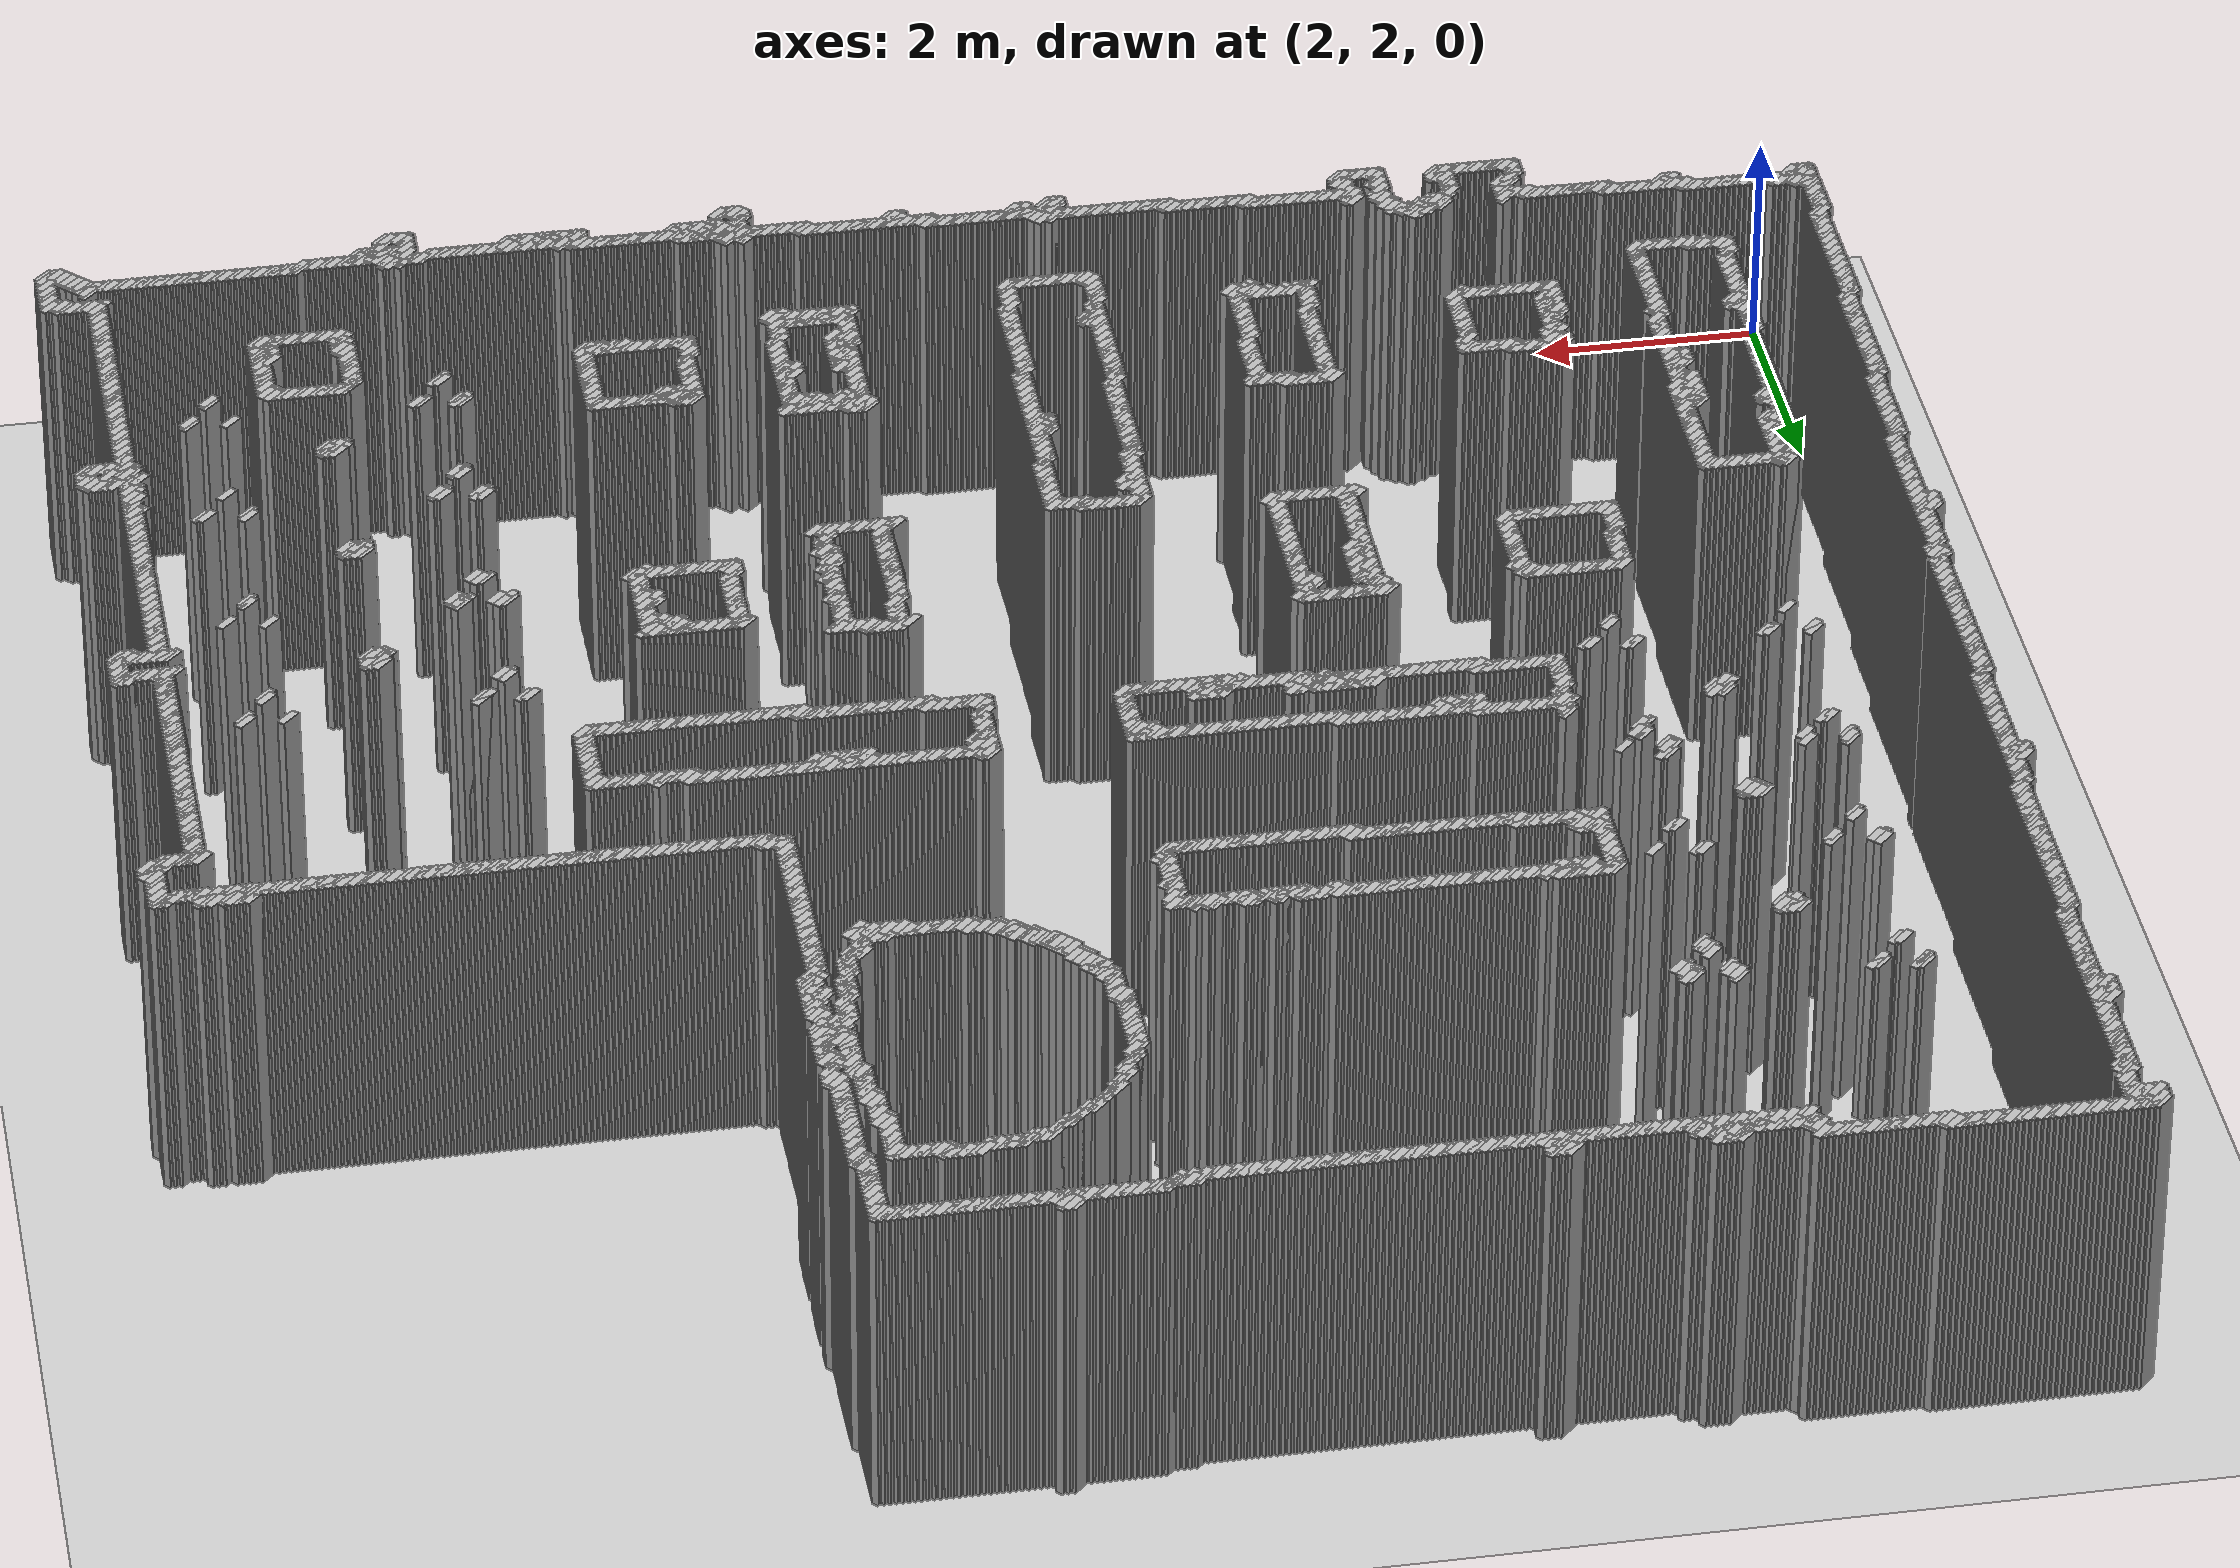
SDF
<sdf version="1.5">
 <world name="default">
  <include><uri>model://ground_plane</uri></include>
  <include><uri>model://sun</uri></include>
  <model name="grey_wall_1">
   <static>1</static>
   <link name="link">
    <pose>2.25 17.45  1.4 0 0 -0.7853981633974216</pose>
    <collision name="collision">
     <geometry><box><size>0.07071067811865261 .2  2.8</size></box></geometry>
    </collision>
    <visual name="visual">
     <cast_shadows>0</cast_shadows>
     <geometry><box><size>0.07071067811865261 .2  2.8</size></box></geometry>
    </visual>
   </link>
  </model>
  <model name="grey_wall_2">
   <static>1</static>
   <link name="link">
    <pose>2.3000000000000003 17.45  1.4 0 0 -0.7853981633974216</pose>
    <collision name="collision">
     <geometry><box><size>0.07071067811865261 .2  2.8</size></box></geometry>
    </collision>
    <visual name="visual">
     <cast_shadows>0</cast_shadows>
     <geometry><box><size>0.07071067811865261 .2  2.8</size></box></geometry>
    </visual>
   </link>
  </model>
  <model name="grey_wall_3">
   <static>1</static>
   <link name="link">
    <pose>2.35 17.45  1.4 0 0 -0.7853981633974216</pose>
    <collision name="collision">
     <geometry><box><size>0.07071067811865261 .2  2.8</size></box></geometry>
    </collision>
    <visual name="visual">
     <cast_shadows>0</cast_shadows>
     <geometry><box><size>0.07071067811865261 .2  2.8</size></box></geometry>
    </visual>
   </link>
  </model>
  <model name="grey_wall_4">
   <static>1</static>
   <link name="link">
    <pose>2.4000000000000004 17.45  1.4 0 0 -0.7853981633974216</pose>
    <collision name="collision">
     <geometry><box><size>0.07071067811865261 .2  2.8</size></box></geometry>
    </collision>
    <visual name="visual">
     <cast_shadows>0</cast_shadows>
     <geometry><box><size>0.07071067811865261 .2  2.8</size></box></geometry>
    </visual>
   </link>
  </model>
  <model name="grey_wall_5">
   <static>1</static>
   <link name="link">
    <pose>2.45 17.45  1.4 0 0 -0.7853981633974216</pose>
    <collision name="collision">
     <geometry><box><size>0.07071067811865261 .2  2.8</size></box></geometry>
    </collision>
    <visual name="visual">
     <cast_shadows>0</cast_shadows>
     <geometry><box><size>0.07071067811865261 .2  2.8</size></box></geometry>
    </visual>
   </link>
  </model>
  <model name="grey_wall_6">
   <static>1</static>
   <link name="link">
    <pose>2.5 17.45  1.4 0 0 -0.7853981633974216</pose>
    <collision name="collision">
     <geometry><box><size>0.07071067811865261 .2  2.8</size></box></geometry>
    </collision>
    <visual name="visual">
     <cast_shadows>0</cast_shadows>
     <geometry><box><size>0.07071067811865261 .2  2.8</size></box></geometry>
    </visual>
   </link>
  </model>
  <model name="grey_wall_7">
   <static>1</static>
   <link name="link">
    <pose>2.5500000000000003 17.45  1.4 0 0 -0.7853981633974216</pose>
    <collision name="collision">
     <geometry><box><size>0.07071067811865261 .2  2.8</size></box></geometry>
    </collision>
    <visual name="visual">
     <cast_shadows>0</cast_shadows>
     <geometry><box><size>0.07071067811865261 .2  2.8</size></box></geometry>
    </visual>
   </link>
  </model>
  <model name="grey_wall_8">
   <static>1</static>
   <link name="link">
    <pose>2.6 17.45  1.4 0 0 -0.7853981633974216</pose>
    <collision name="collision">
     <geometry><box><size>0.07071067811865261 .2  2.8</size></box></geometry>
    </collision>
    <visual name="visual">
     <cast_shadows>0</cast_shadows>
     <geometry><box><size>0.07071067811865261 .2  2.8</size></box></geometry>
    </visual>
   </link>
  </model>
  <model name="grey_wall_9">
   <static>1</static>
   <link name="link">
    <pose>2.6500000000000004 17.45  1.4 0 0 -0.7853981633974216</pose>
    <collision name="collision">
     <geometry><box><size>0.07071067811865261 .2  2.8</size></box></geometry>
    </collision>
    <visual name="visual">
     <cast_shadows>0</cast_shadows>
     <geometry><box><size>0.07071067811865261 .2  2.8</size></box></geometry>
    </visual>
   </link>
  </model>
  <model name="grey_wall_10">
   <static>1</static>
   <link name="link">
    <pose>2.7 17.45  1.4 0 0 -0.7853981633974216</pose>
    <collision name="collision">
     <geometry><box><size>0.07071067811865261 .2  2.8</size></box></geometry>
    </collision>
    <visual name="visual">
     <cast_shadows>0</cast_shadows>
     <geometry><box><size>0.07071067811865261 .2  2.8</size></box></geometry>
    </visual>
   </link>
  </model>
  <model name="grey_wall_11">
   <static>1</static>
   <link name="link">
    <pose>2.75 17.45  1.4 0 0 -0.7853981633974216</pose>
    <collision name="collision">
     <geometry><box><size>0.07071067811865261 .2  2.8</size></box></geometry>
    </collision>
    <visual name="visual">
     <cast_shadows>0</cast_shadows>
     <geometry><box><size>0.07071067811865261 .2  2.8</size></box></geometry>
    </visual>
   </link>
  </model>
  <model name="grey_wall_12">
   <static>1</static>
   <link name="link">
    <pose>2.8000000000000003 17.45  1.4 0 0 -0.7853981633974216</pose>
    <collision name="collision">
     <geometry><box><size>0.07071067811865261 .2  2.8</size></box></geometry>
    </collision>
    <visual name="visual">
     <cast_shadows>0</cast_shadows>
     <geometry><box><size>0.07071067811865261 .2  2.8</size></box></geometry>
    </visual>
   </link>
  </model>
  <model name="grey_wall_13">
   <static>1</static>
   <link name="link">
    <pose>2.85 17.45  1.4 0 0 -0.7853981633974216</pose>
    <collision name="collision">
     <geometry><box><size>0.07071067811865261 .2  2.8</size></box></geometry>
    </collision>
    <visual name="visual">
     <cast_shadows>0</cast_shadows>
     <geometry><box><size>0.07071067811865261 .2  2.8</size></box></geometry>
    </visual>
   </link>
  </model>
  <model name="grey_wall_14">
   <static>1</static>
   <link name="link">
    <pose>2.9000000000000004 17.45  1.4 0 0 -0.7853981633974216</pose>
    <collision name="collision">
     <geometry><box><size>0.07071067811865261 .2  2.8</size></box></geometry>
    </collision>
    <visual name="visual">
     <cast_shadows>0</cast_shadows>
     <geometry><box><size>0.07071067811865261 .2  2.8</size></box></geometry>
    </visual>
   </link>
  </model>
  <model name="grey_wall_15">
   <static>1</static>
   <link name="link">
    <pose>2.95 17.45  1.4 0 0 -0.7853981633974216</pose>
    <collision name="collision">
     <geometry><box><size>0.07071067811865261 .2  2.8</size></box></geometry>
    </collision>
    <visual name="visual">
     <cast_shadows>0</cast_shadows>
     <geometry><box><size>0.07071067811865261 .2  2.8</size></box></geometry>
    </visual>
   </link>
  </model>
  <model name="grey_wall_16">
   <static>1</static>
   <link name="link">
    <pose>3.0 17.45  1.4 0 0 -0.7853981633974216</pose>
    <collision name="collision">
     <geometry><box><size>0.07071067811865261 .2  2.8</size></box></geometry>
    </collision>
    <visual name="visual">
     <cast_shadows>0</cast_shadows>
     <geometry><box><size>0.07071067811865261 .2  2.8</size></box></geometry>
    </visual>
   </link>
  </model>
  <model name="grey_wall_17">
   <static>1</static>
   <link name="link">
    <pose>3.0500000000000003 17.45  1.4 0 0 -0.7853981633974216</pose>
    <collision name="collision">
     <geometry><box><size>0.07071067811865261 .2  2.8</size></box></geometry>
    </collision>
    <visual name="visual">
     <cast_shadows>0</cast_shadows>
     <geometry><box><size>0.07071067811865261 .2  2.8</size></box></geometry>
    </visual>
   </link>
  </model>
  <model name="grey_wall_18">
   <static>1</static>
   <link name="link">
    <pose>3.1 17.45  1.4 0 0 -0.7853981633974216</pose>
    <collision name="collision">
     <geometry><box><size>0.07071067811865261 .2  2.8</size></box></geometry>
    </collision>
    <visual name="visual">
     <cast_shadows>0</cast_shadows>
     <geometry><box><size>0.07071067811865261 .2  2.8</size></box></geometry>
    </visual>
   </link>
  </model>
  <model name="grey_wall_19">
   <static>1</static>
   <link name="link">
    <pose>3.1500000000000004 17.45  1.4 0 0 -0.7853981633974216</pose>
    <collision name="collision">
     <geometry><box><size>0.07071067811865261 .2  2.8</size></box></geometry>
    </collision>
    <visual name="visual">
     <cast_shadows>0</cast_shadows>
     <geometry><box><size>0.07071067811865261 .2  2.8</size></box></geometry>
    </visual>
   </link>
  </model>
  <model name="grey_wall_20">
   <static>1</static>
   <link name="link">
    <pose>3.2 17.45  1.4 0 0 -0.7853981633974216</pose>
    <collision name="collision">
     <geometry><box><size>0.07071067811865261 .2  2.8</size></box></geometry>
    </collision>
    <visual name="visual">
     <cast_shadows>0</cast_shadows>
     <geometry><box><size>0.07071067811865261 .2  2.8</size></box></geometry>
    </visual>
   </link>
  </model>
  <model name="grey_wall_21">
   <static>1</static>
   <link name="link">
    <pose>3.25 17.45  1.4 0 0 -0.7853981633974216</pose>
    <collision name="collision">
     <geometry><box><size>0.07071067811865261 .2  2.8</size></box></geometry>
    </collision>
    <visual name="visual">
     <cast_shadows>0</cast_shadows>
     <geometry><box><size>0.07071067811865261 .2  2.8</size></box></geometry>
    </visual>
   </link>
  </model>
  <model name="grey_wall_22">
   <static>1</static>
   <link name="link">
    <pose>3.3000000000000003 17.45  1.4 0 0 -0.7853981633974216</pose>
    <collision name="collision">
     <geometry><box><size>0.07071067811865261 .2  2.8</size></box></geometry>
    </collision>
    <visual name="visual">
     <cast_shadows>0</cast_shadows>
     <geometry><box><size>0.07071067811865261 .2  2.8</size></box></geometry>
    </visual>
   </link>
  </model>
  <model name="grey_wall_23">
   <static>1</static>
   <link name="link">
    <pose>3.35 17.45  1.4 0 0 -0.7853981633974216</pose>
    <collision name="collision">
     <geometry><box><size>0.07071067811865261 .2  2.8</size></box></geometry>
    </collision>
    <visual name="visual">
     <cast_shadows>0</cast_shadows>
     <geometry><box><size>0.07071067811865261 .2  2.8</size></box></geometry>
    </visual>
   </link>
  </model>
  <model name="grey_wall_24">
   <static>1</static>
   <link name="link">
    <pose>3.4000000000000004 17.45  1.4 0 0 -0.7853981633974216</pose>
    <collision name="collision">
     <geometry><box><size>0.07071067811865261 .2  2.8</size></box></geometry>
    </collision>
    <visual name="visual">
     <cast_shadows>0</cast_shadows>
     <geometry><box><size>0.07071067811865261 .2  2.8</size></box></geometry>
    </visual>
   </link>
  </model>
  <model name="grey_wall_25">
   <static>1</static>
   <link name="link">
    <pose>3.45 17.45  1.4 0 0 -0.7853981633974216</pose>
    <collision name="collision">
     <geometry><box><size>0.07071067811865261 .2  2.8</size></box></geometry>
    </collision>
    <visual name="visual">
     <cast_shadows>0</cast_shadows>
     <geometry><box><size>0.07071067811865261 .2  2.8</size></box></geometry>
    </visual>
   </link>
  </model>
  <model name="grey_wall_26">
   <static>1</static>
   <link name="link">
    <pose>3.5 17.45  1.4 0 0 -0.7853981633974216</pose>
    <collision name="collision">
     <geometry><box><size>0.07071067811865261 .2  2.8</size></box></geometry>
    </collision>
    <visual name="visual">
     <cast_shadows>0</cast_shadows>
     <geometry><box><size>0.07071067811865261 .2  2.8</size></box></geometry>
    </visual>
   </link>
  </model>
  <model name="grey_wall_27">
   <static>1</static>
   <link name="link">
    <pose>3.5500000000000003 17.45  1.4 0 0 -0.7853981633974216</pose>
    <collision name="collision">
     <geometry><box><size>0.07071067811865261 .2  2.8</size></box></geometry>
    </collision>
    <visual name="visual">
     <cast_shadows>0</cast_shadows>
     <geometry><box><size>0.07071067811865261 .2  2.8</size></box></geometry>
    </visual>
   </link>
  </model>
  <model name="grey_wall_28">
   <static>1</static>
   <link name="link">
    <pose>3.6 17.45  1.4 0 0 -0.7853981633974216</pose>
    <collision name="collision">
     <geometry><box><size>0.07071067811865261 .2  2.8</size></box></geometry>
    </collision>
    <visual name="visual">
     <cast_shadows>0</cast_shadows>
     <geometry><box><size>0.07071067811865261 .2  2.8</size></box></geometry>
    </visual>
   </link>
  </model>
  <model name="grey_wall_29">
   <static>1</static>
   <link name="link">
    <pose>3.6500000000000004 17.45  1.4 0 0 -0.7853981633974216</pose>
    <collision name="collision">
     <geometry><box><size>0.07071067811865261 .2  2.8</size></box></geometry>
    </collision>
    <visual name="visual">
     <cast_shadows>0</cast_shadows>
     <geometry><box><size>0.07071067811865261 .2  2.8</size></box></geometry>
    </visual>
   </link>
  </model>
  <model name="grey_wall_30">
   <static>1</static>
   <link name="link">
    <pose>3.7 17.45  1.4 0 0 -0.7853981633974216</pose>
    <collision name="collision">
     <geometry><box><size>0.07071067811865261 .2  2.8</size></box></geometry>
    </collision>
    <visual name="visual">
     <cast_shadows>0</cast_shadows>
     <geometry><box><size>0.07071067811865261 .2  2.8</size></box></geometry>
    </visual>
   </link>
  </model>
  <model name="grey_wall_31">
   <static>1</static>
   <link name="link">
    <pose>3.75 17.45  1.4 0 0 -0.7853981633974216</pose>
    <collision name="collision">
     <geometry><box><size>0.07071067811865261 .2  2.8</size></box></geometry>
    </collision>
    <visual name="visual">
     <cast_shadows>0</cast_shadows>
     <geometry><box><size>0.07071067811865261 .2  2.8</size></box></geometry>
    </visual>
   </link>
  </model>
  <model name="grey_wall_32">
   <static>1</static>
   <link name="link">
    <pose>3.8000000000000003 17.45  1.4 0 0 -0.7853981633974216</pose>
    <collision name="collision">
     <geometry><box><size>0.07071067811865261 .2  2.8</size></box></geometry>
    </collision>
    <visual name="visual">
     <cast_shadows>0</cast_shadows>
     <geometry><box><size>0.07071067811865261 .2  2.8</size></box></geometry>
    </visual>
   </link>
  </model>
  <model name="grey_wall_33">
   <static>1</static>
   <link name="link">
    <pose>3.85 17.45  1.4 0 0 -0.7853981633974216</pose>
    <collision name="collision">
     <geometry><box><size>0.07071067811865261 .2  2.8</size></box></geometry>
    </collision>
    <visual name="visual">
     <cast_shadows>0</cast_shadows>
     <geometry><box><size>0.07071067811865261 .2  2.8</size></box></geometry>
    </visual>
   </link>
  </model>
  <model name="grey_wall_34">
   <static>1</static>
   <link name="link">
    <pose>3.9000000000000004 17.45  1.4 0 0 -0.7853981633974216</pose>
    <collision name="collision">
     <geometry><box><size>0.07071067811865261 .2  2.8</size></box></geometry>
    </collision>
    <visual name="visual">
     <cast_shadows>0</cast_shadows>
     <geometry><box><size>0.07071067811865261 .2  2.8</size></box></geometry>
    </visual>
   </link>
  </model>
  <model name="grey_wall_35">
   <static>1</static>
   <link name="link">
    <pose>3.95 17.45  1.4 0 0 -0.7853981633974216</pose>
    <collision name="collision">
     <geometry><box><size>0.07071067811865261 .2  2.8</size></box></geometry>
    </collision>
    <visual name="visual">
     <cast_shadows>0</cast_shadows>
     <geometry><box><size>0.07071067811865261 .2  2.8</size></box></geometry>
    </visual>
   </link>
  </model>
  <model name="grey_wall_36">
   <static>1</static>
   <link name="link">
    <pose>2.25 17.400000000000002  1.4 0 0 -0.7853981633974216</pose>
    <collision name="collision">
     <geometry><box><size>0.07071067811865261 .2  2.8</size></box></geometry>
    </collision>
    <visual name="visual">
     <cast_shadows>0</cast_shadows>
     <geometry><box><size>0.07071067811865261 .2  2.8</size></box></geometry>
    </visual>
   </link>
  </model>
  <model name="grey_wall_37">
   <static>1</static>
   <link name="link">
    <pose>3.95 17.400000000000002  1.4 0 0 -0.7853981633974216</pose>
    <collision name="collision">
     <geometry><box><size>0.07071067811865261 .2  2.8</size></box></geometry>
    </collision>
    <visual name="visual">
     <cast_shadows>0</cast_shadows>
     <geometry><box><size>0.07071067811865261 .2  2.8</size></box></geometry>
    </visual>
   </link>
  </model>
  <model name="grey_wall_38">
   <static>1</static>
   <link name="link">
    <pose>4.0 17.400000000000002  1.4 0 0 -0.7853981633974172</pose>
    <collision name="collision">
     <geometry><box><size>0.07071067811865293 .2  2.8</size></box></geometry>
    </collision>
    <visual name="visual">
     <cast_shadows>0</cast_shadows>
     <geometry><box><size>0.07071067811865293 .2  2.8</size></box></geometry>
    </visual>
   </link>
  </model>
  <model name="grey_wall_39">
   <static>1</static>
   <link name="link">
    <pose>4.05 17.400000000000002  1.4 0 0 -0.7853981633974128</pose>
    <collision name="collision">
     <geometry><box><size>0.07071067811865325 .2  2.8</size></box></geometry>
    </collision>
    <visual name="visual">
     <cast_shadows>0</cast_shadows>
     <geometry><box><size>0.07071067811865325 .2  2.8</size></box></geometry>
    </visual>
   </link>
  </model>
  <model name="grey_wall_40">
   <static>1</static>
   <link name="link">
    <pose>4.1000000000000005 17.400000000000002  1.4 0 0 -0.7853981633974128</pose>
    <collision name="collision">
     <geometry><box><size>0.07071067811865325 .2  2.8</size></box></geometry>
    </collision>
    <visual name="visual">
     <cast_shadows>0</cast_shadows>
     <geometry><box><size>0.07071067811865325 .2  2.8</size></box></geometry>
    </visual>
   </link>
  </model>
  <model name="grey_wall_41">
   <static>1</static>
   <link name="link">
    <pose>4.15 17.400000000000002  1.4 0 0 -0.7853981633974128</pose>
    <collision name="collision">
     <geometry><box><size>0.07071067811865325 .2  2.8</size></box></geometry>
    </collision>
    <visual name="visual">
     <cast_shadows>0</cast_shadows>
     <geometry><box><size>0.07071067811865325 .2  2.8</size></box></geometry>
    </visual>
   </link>
  </model>
  <model name="grey_wall_42">
   <static>1</static>
   <link name="link">
    <pose>4.2 17.400000000000002  1.4 0 0 -0.7853981633974128</pose>
    <collision name="collision">
     <geometry><box><size>0.07071067811865325 .2  2.8</size></box></geometry>
    </collision>
    <visual name="visual">
     <cast_shadows>0</cast_shadows>
     <geometry><box><size>0.07071067811865325 .2  2.8</size></box></geometry>
    </visual>
   </link>
  </model>
  <model name="grey_wall_43">
   <static>1</static>
   <link name="link">
    <pose>4.25 17.400000000000002  1.4 0 0 -0.7853981633974128</pose>
    <collision name="collision">
     <geometry><box><size>0.07071067811865325 .2  2.8</size></box></geometry>
    </collision>
    <visual name="visual">
     <cast_shadows>0</cast_shadows>
     <geometry><box><size>0.07071067811865325 .2  2.8</size></box></geometry>
    </visual>
   </link>
  </model>
  <model name="grey_wall_44">
   <static>1</static>
   <link name="link">
    <pose>4.3 17.400000000000002  1.4 0 0 -0.7853981633974128</pose>
    <collision name="collision">
     <geometry><box><size>0.07071067811865325 .2  2.8</size></box></geometry>
    </collision>
    <visual name="visual">
     <cast_shadows>0</cast_shadows>
     <geometry><box><size>0.07071067811865325 .2  2.8</size></box></geometry>
    </visual>
   </link>
  </model>
  <model name="grey_wall_45">
   <static>1</static>
   <link name="link">
    <pose>4.3500000000000005 17.400000000000002  1.4 0 0 -0.7853981633974128</pose>
    <collision name="collision">
     <geometry><box><size>0.07071067811865325 .2  2.8</size></box></geometry>
    </collision>
    <visual name="visual">
     <cast_shadows>0</cast_shadows>
     <geometry><box><size>0.07071067811865325 .2  2.8</size></box></geometry>
    </visual>
   </link>
  </model>
  <model name="grey_wall_46">
   <static>1</static>
   <link name="link">
    <pose>4.4 17.400000000000002  1.4 0 0 -0.7853981633974128</pose>
    <collision name="collision">
     <geometry><box><size>0.07071067811865325 .2  2.8</size></box></geometry>
    </collision>
    <visual name="visual">
     <cast_shadows>0</cast_shadows>
     <geometry><box><size>0.07071067811865325 .2  2.8</size></box></geometry>
    </visual>
   </link>
  </model>
  <model name="grey_wall_47">
   <static>1</static>
   <link name="link">
    <pose>4.45 17.400000000000002  1.4 0 0 -0.7853981633974128</pose>
    <collision name="collision">
     <geometry><box><size>0.07071067811865325 .2  2.8</size></box></geometry>
    </collision>
    <visual name="visual">
     <cast_shadows>0</cast_shadows>
     <geometry><box><size>0.07071067811865325 .2  2.8</size></box></geometry>
    </visual>
   </link>
  </model>
  <model name="grey_wall_48">
   <static>1</static>
   <link name="link">
    <pose>4.5 17.400000000000002  1.4 0 0 -0.7853981633974128</pose>
    <collision name="collision">
     <geometry><box><size>0.07071067811865325 .2  2.8</size></box></geometry>
    </collision>
    <visual name="visual">
     <cast_shadows>0</cast_shadows>
     <geometry><box><size>0.07071067811865325 .2  2.8</size></box></geometry>
    </visual>
   </link>
  </model>
  <model name="grey_wall_49">
   <static>1</static>
   <link name="link">
    <pose>4.55 17.400000000000002  1.4 0 0 -0.7853981633974128</pose>
    <collision name="collision">
     <geometry><box><size>0.07071067811865325 .2  2.8</size></box></geometry>
    </collision>
    <visual name="visual">
     <cast_shadows>0</cast_shadows>
     <geometry><box><size>0.07071067811865325 .2  2.8</size></box></geometry>
    </visual>
   </link>
  </model>
  <model name="grey_wall_50">
   <static>1</static>
   <link name="link">
    <pose>4.6000000000000005 17.400000000000002  1.4 0 0 -0.7853981633974128</pose>
    <collision name="collision">
     <geometry><box><size>0.07071067811865325 .2  2.8</size></box></geometry>
    </collision>
    <visual name="visual">
     <cast_shadows>0</cast_shadows>
     <geometry><box><size>0.07071067811865325 .2  2.8</size></box></geometry>
    </visual>
   </link>
  </model>
  <model name="grey_wall_51">
   <static>1</static>
   <link name="link">
    <pose>4.65 17.400000000000002  1.4 0 0 -0.7853981633974128</pose>
    <collision name="collision">
     <geometry><box><size>0.07071067811865325 .2  2.8</size></box></geometry>
    </collision>
    <visual name="visual">
     <cast_shadows>0</cast_shadows>
     <geometry><box><size>0.07071067811865325 .2  2.8</size></box></geometry>
    </visual>
   </link>
  </model>
  <model name="grey_wall_52">
   <static>1</static>
   <link name="link">
    <pose>4.7 17.400000000000002  1.4 0 0 -0.7853981633974128</pose>
    <collision name="collision">
     <geometry><box><size>0.07071067811865325 .2  2.8</size></box></geometry>
    </collision>
    <visual name="visual">
     <cast_shadows>0</cast_shadows>
     <geometry><box><size>0.07071067811865325 .2  2.8</size></box></geometry>
    </visual>
   </link>
  </model>
  <model name="grey_wall_53">
   <static>1</static>
   <link name="link">
    <pose>4.75 17.400000000000002  1.4 0 0 -0.7853981633974128</pose>
    <collision name="collision">
     <geometry><box><size>0.07071067811865325 .2  2.8</size></box></geometry>
    </collision>
    <visual name="visual">
     <cast_shadows>0</cast_shadows>
     <geometry><box><size>0.07071067811865325 .2  2.8</size></box></geometry>
    </visual>
   </link>
  </model>
  <model name="grey_wall_54">
   <static>1</static>
   <link name="link">
    <pose>4.800000000000001 17.400000000000002  1.4 0 0 -0.7853981633974128</pose>
    <collision name="collision">
     <geometry><box><size>0.07071067811865325 .2  2.8</size></box></geometry>
    </collision>
    <visual name="visual">
     <cast_shadows>0</cast_shadows>
     <geometry><box><size>0.07071067811865325 .2  2.8</size></box></geometry>
    </visual>
   </link>
  </model>
  <model name="grey_wall_55">
   <static>1</static>
   <link name="link">
    <pose>4.8500000000000005 17.400000000000002  1.4 0 0 -0.7853981633974128</pose>
    <collision name="collision">
     <geometry><box><size>0.07071067811865325 .2  2.8</size></box></geometry>
    </collision>
    <visual name="visual">
     <cast_shadows>0</cast_shadows>
     <geometry><box><size>0.07071067811865325 .2  2.8</size></box></geometry>
    </visual>
   </link>
  </model>
  <model name="grey_wall_56">
   <static>1</static>
   <link name="link">
    <pose>4.9 17.400000000000002  1.4 0 0 -0.7853981633974128</pose>
    <collision name="collision">
     <geometry><box><size>0.07071067811865325 .2  2.8</size></box></geometry>
    </collision>
    <visual name="visual">
     <cast_shadows>0</cast_shadows>
     <geometry><box><size>0.07071067811865325 .2  2.8</size></box></geometry>
    </visual>
   </link>
  </model>
  <model name="grey_wall_57">
   <static>1</static>
   <link name="link">
    <pose>4.95 17.400000000000002  1.4 0 0 -0.7853981633974128</pose>
    <collision name="collision">
     <geometry><box><size>0.07071067811865325 .2  2.8</size></box></geometry>
    </collision>
    <visual name="visual">
     <cast_shadows>0</cast_shadows>
     <geometry><box><size>0.07071067811865325 .2  2.8</size></box></geometry>
    </visual>
   </link>
  </model>
  <model name="grey_wall_58">
   <static>1</static>
   <link name="link">
    <pose>2.25 17.35  1.4 0 0 -0.7853981633974216</pose>
    <collision name="collision">
     <geometry><box><size>0.07071067811865261 .2  2.8</size></box></geometry>
    </collision>
    <visual name="visual">
     <cast_shadows>0</cast_shadows>
     <geometry><box><size>0.07071067811865261 .2  2.8</size></box></geometry>
    </visual>
   </link>
  </model>
  <model name="grey_wall_59">
   <static>1</static>
   <link name="link">
    <pose>4.95 17.35  1.4 0 0 -0.7853981633974128</pose>
    <collision name="collision">
     <geometry><box><size>0.07071067811865325 .2  2.8</size></box></geometry>
    </collision>
    <visual name="visual">
     <cast_shadows>0</cast_shadows>
     <geometry><box><size>0.07071067811865325 .2  2.8</size></box></geometry>
    </visual>
   </link>
  </model>
  <model name="grey_wall_60">
   <static>1</static>
   <link name="link">
    <pose>5.550000000000001 17.35  1.4 0 0 -0.7853981633974128</pose>
    <collision name="collision">
     <geometry><box><size>0.07071067811865325 .2  2.8</size></box></geometry>
    </collision>
    <visual name="visual">
     <cast_shadows>0</cast_shadows>
     <geometry><box><size>0.07071067811865325 .2  2.8</size></box></geometry>
    </visual>
   </link>
  </model>
  <model name="grey_wall_61">
   <static>1</static>
   <link name="link">
    <pose>5.6000000000000005 17.35  1.4 0 0 -0.7853981633974128</pose>
    <collision name="collision">
     <geometry><box><size>0.07071067811865325 .2  2.8</size></box></geometry>
    </collision>
    <visual name="visual">
     <cast_shadows>0</cast_shadows>
     <geometry><box><size>0.07071067811865325 .2  2.8</size></box></geometry>
    </visual>
   </link>
  </model>
  <model name="grey_wall_62">
   <static>1</static>
   <link name="link">
    <pose>5.65 17.35  1.4 0 0 -0.7853981633974128</pose>
    <collision name="collision">
     <geometry><box><size>0.07071067811865325 .2  2.8</size></box></geometry>
    </collision>
    <visual name="visual">
     <cast_shadows>0</cast_shadows>
     <geometry><box><size>0.07071067811865325 .2  2.8</size></box></geometry>
    </visual>
   </link>
  </model>
  <model name="grey_wall_63">
   <static>1</static>
   <link name="link">
    <pose>5.7 17.35  1.4 0 0 -0.7853981633974128</pose>
    <collision name="collision">
     <geometry><box><size>0.07071067811865325 .2  2.8</size></box></geometry>
    </collision>
    <visual name="visual">
     <cast_shadows>0</cast_shadows>
     <geometry><box><size>0.07071067811865325 .2  2.8</size></box></geometry>
    </visual>
   </link>
  </model>
  <model name="grey_wall_64">
   <static>1</static>
   <link name="link">
    <pose>5.75 17.35  1.4 0 0 -0.7853981633974128</pose>
    <collision name="collision">
     <geometry><box><size>0.07071067811865325 .2  2.8</size></box></geometry>
    </collision>
    <visual name="visual">
     <cast_shadows>0</cast_shadows>
     <geometry><box><size>0.07071067811865325 .2  2.8</size></box></geometry>
    </visual>
   </link>
  </model>
  <model name="grey_wall_65">
   <static>1</static>
   <link name="link">
    <pose>10.8 17.35  1.4 0 0 -0.7853981633974128</pose>
    <collision name="collision">
     <geometry><box><size>0.07071067811865325 .2  2.8</size></box></geometry>
    </collision>
    <visual name="visual">
     <cast_shadows>0</cast_shadows>
     <geometry><box><size>0.07071067811865325 .2  2.8</size></box></geometry>
    </visual>
   </link>
  </model>
  <model name="grey_wall_66">
   <static>1</static>
   <link name="link">
    <pose>10.850000000000001 17.35  1.4 0 0 -0.7853981633974128</pose>
    <collision name="collision">
     <geometry><box><size>0.07071067811865325 .2  2.8</size></box></geometry>
    </collision>
    <visual name="visual">
     <cast_shadows>0</cast_shadows>
     <geometry><box><size>0.07071067811865325 .2  2.8</size></box></geometry>
    </visual>
   </link>
  </model>
  <model name="grey_wall_67">
   <static>1</static>
   <link name="link">
    <pose>10.9 17.35  1.4 0 0 -0.7853981633974128</pose>
    <collision name="collision">
     <geometry><box><size>0.07071067811865325 .2  2.8</size></box></geometry>
    </collision>
    <visual name="visual">
     <cast_shadows>0</cast_shadows>
     <geometry><box><size>0.07071067811865325 .2  2.8</size></box></geometry>
    </visual>
   </link>
  </model>
  <model name="grey_wall_68">
   <static>1</static>
   <link name="link">
    <pose>2.25 17.3  1.4 0 0 -0.7853981633974216</pose>
    <collision name="collision">
     <geometry><box><size>0.07071067811865261 .2  2.8</size></box></geometry>
    </collision>
    <visual name="visual">
     <cast_shadows>0</cast_shadows>
     <geometry><box><size>0.07071067811865261 .2  2.8</size></box></geometry>
    </visual>
   </link>
  </model>
  <model name="grey_wall_69">
   <static>1</static>
   <link name="link">
    <pose>2.3000000000000003 17.3  1.4 0 0 -0.7853981633974216</pose>
    <collision name="collision">
     <geometry><box><size>0.07071067811865261 .2  2.8</size></box></geometry>
    </collision>
    <visual name="visual">
     <cast_shadows>0</cast_shadows>
     <geometry><box><size>0.07071067811865261 .2  2.8</size></box></geometry>
    </visual>
   </link>
  </model>
  <model name="grey_wall_70">
   <static>1</static>
   <link name="link">
    <pose>2.35 17.3  1.4 0 0 -0.7853981633974216</pose>
    <collision name="collision">
     <geometry><box><size>0.07071067811865261 .2  2.8</size></box></geometry>
    </collision>
    <visual name="visual">
     <cast_shadows>0</cast_shadows>
     <geometry><box><size>0.07071067811865261 .2  2.8</size></box></geometry>
    </visual>
   </link>
  </model>
  <model name="grey_wall_71">
   <static>1</static>
   <link name="link">
    <pose>2.4000000000000004 17.3  1.4 0 0 -0.7853981633974216</pose>
    <collision name="collision">
     <geometry><box><size>0.07071067811865261 .2  2.8</size></box></geometry>
    </collision>
    <visual name="visual">
     <cast_shadows>0</cast_shadows>
     <geometry><box><size>0.07071067811865261 .2  2.8</size></box></geometry>
    </visual>
   </link>
  </model>
  <model name="grey_wall_72">
   <static>1</static>
   <link name="link">
    <pose>2.45 17.3  1.4 0 0 -0.7853981633974216</pose>
    <collision name="collision">
     <geometry><box><size>0.07071067811865261 .2  2.8</size></box></geometry>
    </collision>
    <visual name="visual">
     <cast_shadows>0</cast_shadows>
     <geometry><box><size>0.07071067811865261 .2  2.8</size></box></geometry>
    </visual>
   </link>
  </model>
  <model name="grey_wall_73">
   <static>1</static>
   <link name="link">
    <pose>4.95 17.3  1.4 0 0 -0.7853981633974128</pose>
    <collision name="collision">
     <geometry><box><size>0.07071067811865325 .2  2.8</size></box></geometry>
    </collision>
    <visual name="visual">
     <cast_shadows>0</cast_shadows>
     <geometry><box><size>0.07071067811865325 .2  2.8</size></box></geometry>
    </visual>
   </link>
  </model>
  <model name="grey_wall_74">
   <static>1</static>
   <link name="link">
    <pose>5.0 17.3  1.4 0 0 -0.7853981633974128</pose>
    <collision name="collision">
     <geometry><box><size>0.07071067811865325 .2  2.8</size></box></geometry>
    </collision>
    <visual name="visual">
     <cast_shadows>0</cast_shadows>
     <geometry><box><size>0.07071067811865325 .2  2.8</size></box></geometry>
    </visual>
   </link>
  </model>
  <model name="grey_wall_75">
   <static>1</static>
   <link name="link">
    <pose>5.550000000000001 17.3  1.4 0 0 -0.7853981633974128</pose>
    <collision name="collision">
     <geometry><box><size>0.07071067811865325 .2  2.8</size></box></geometry>
    </collision>
    <visual name="visual">
     <cast_shadows>0</cast_shadows>
     <geometry><box><size>0.07071067811865325 .2  2.8</size></box></geometry>
    </visual>
   </link>
  </model>
  <model name="grey_wall_76">
   <static>1</static>
   <link name="link">
    <pose>5.65 17.3  1.4 0 0 -0.7853981633974128</pose>
    <collision name="collision">
     <geometry><box><size>0.07071067811865325 .2  2.8</size></box></geometry>
    </collision>
    <visual name="visual">
     <cast_shadows>0</cast_shadows>
     <geometry><box><size>0.07071067811865325 .2  2.8</size></box></geometry>
    </visual>
   </link>
  </model>
  <model name="grey_wall_77">
   <static>1</static>
   <link name="link">
    <pose>5.75 17.3  1.4 0 0 -0.7853981633974128</pose>
    <collision name="collision">
     <geometry><box><size>0.07071067811865325 .2  2.8</size></box></geometry>
    </collision>
    <visual name="visual">
     <cast_shadows>0</cast_shadows>
     <geometry><box><size>0.07071067811865325 .2  2.8</size></box></geometry>
    </visual>
   </link>
  </model>
  <model name="grey_wall_78">
   <static>1</static>
   <link name="link">
    <pose>6.9 17.3  1.4 0 0 -0.7853981633974128</pose>
    <collision name="collision">
     <geometry><box><size>0.07071067811865325 .2  2.8</size></box></geometry>
    </collision>
    <visual name="visual">
     <cast_shadows>0</cast_shadows>
     <geometry><box><size>0.07071067811865325 .2  2.8</size></box></geometry>
    </visual>
   </link>
  </model>
  <model name="grey_wall_79">
   <static>1</static>
   <link name="link">
    <pose>6.95 17.3  1.4 0 0 -0.7853981633974128</pose>
    <collision name="collision">
     <geometry><box><size>0.07071067811865325 .2  2.8</size></box></geometry>
    </collision>
    <visual name="visual">
     <cast_shadows>0</cast_shadows>
     <geometry><box><size>0.07071067811865325 .2  2.8</size></box></geometry>
    </visual>
   </link>
  </model>
  <model name="grey_wall_80">
   <static>1</static>
   <link name="link">
    <pose>7.0 17.3  1.4 0 0 -0.7853981633974128</pose>
    <collision name="collision">
     <geometry><box><size>0.07071067811865325 .2  2.8</size></box></geometry>
    </collision>
    <visual name="visual">
     <cast_shadows>0</cast_shadows>
     <geometry><box><size>0.07071067811865325 .2  2.8</size></box></geometry>
    </visual>
   </link>
  </model>
  <model name="grey_wall_81">
   <static>1</static>
   <link name="link">
    <pose>7.050000000000001 17.3  1.4 0 0 -0.7853981633974128</pose>
    <collision name="collision">
     <geometry><box><size>0.07071067811865325 .2  2.8</size></box></geometry>
    </collision>
    <visual name="visual">
     <cast_shadows>0</cast_shadows>
     <geometry><box><size>0.07071067811865325 .2  2.8</size></box></geometry>
    </visual>
   </link>
  </model>
  <model name="grey_wall_82">
   <static>1</static>
   <link name="link">
    <pose>10.8 17.3  1.4 0 0 -0.7853981633974128</pose>
    <collision name="collision">
     <geometry><box><size>0.07071067811865325 .2  2.8</size></box></geometry>
    </collision>
    <visual name="visual">
     <cast_shadows>0</cast_shadows>
     <geometry><box><size>0.07071067811865325 .2  2.8</size></box></geometry>
    </visual>
   </link>
  </model>
  <model name="grey_wall_83">
   <static>1</static>
   <link name="link">
    <pose>10.9 17.3  1.4 0 0 -0.7853981633974128</pose>
    <collision name="collision">
     <geometry><box><size>0.07071067811865325 .2  2.8</size></box></geometry>
    </collision>
    <visual name="visual">
     <cast_shadows>0</cast_shadows>
     <geometry><box><size>0.07071067811865325 .2  2.8</size></box></geometry>
    </visual>
   </link>
  </model>
  <model name="grey_wall_84">
   <static>1</static>
   <link name="link">
    <pose>2.45 17.25  1.4 0 0 -0.7853981633974216</pose>
    <collision name="collision">
     <geometry><box><size>0.07071067811865261 .2  2.8</size></box></geometry>
    </collision>
    <visual name="visual">
     <cast_shadows>0</cast_shadows>
     <geometry><box><size>0.07071067811865261 .2  2.8</size></box></geometry>
    </visual>
   </link>
  </model>
  <model name="grey_wall_85">
   <static>1</static>
   <link name="link">
    <pose>5.0 17.25  1.4 0 0 -0.7853981633974128</pose>
    <collision name="collision">
     <geometry><box><size>0.07071067811865325 .2  2.8</size></box></geometry>
    </collision>
    <visual name="visual">
     <cast_shadows>0</cast_shadows>
     <geometry><box><size>0.07071067811865325 .2  2.8</size></box></geometry>
    </visual>
   </link>
  </model>
  <model name="grey_wall_86">
   <static>1</static>
   <link name="link">
    <pose>5.050000000000001 17.25  1.4 0 0 -0.7853981633974128</pose>
    <collision name="collision">
     <geometry><box><size>0.07071067811865325 .2  2.8</size></box></geometry>
    </collision>
    <visual name="visual">
     <cast_shadows>0</cast_shadows>
     <geometry><box><size>0.07071067811865325 .2  2.8</size></box></geometry>
    </visual>
   </link>
  </model>
  <model name="grey_wall_87">
   <static>1</static>
   <link name="link">
    <pose>5.1000000000000005 17.25  1.4 0 0 -0.7853981633974128</pose>
    <collision name="collision">
     <geometry><box><size>0.07071067811865325 .2  2.8</size></box></geometry>
    </collision>
    <visual name="visual">
     <cast_shadows>0</cast_shadows>
     <geometry><box><size>0.07071067811865325 .2  2.8</size></box></geometry>
    </visual>
   </link>
  </model>
  <model name="grey_wall_88">
   <static>1</static>
   <link name="link">
    <pose>5.15 17.25  1.4 0 0 -0.7853981633974128</pose>
    <collision name="collision">
     <geometry><box><size>0.07071067811865325 .2  2.8</size></box></geometry>
    </collision>
    <visual name="visual">
     <cast_shadows>0</cast_shadows>
     <geometry><box><size>0.07071067811865325 .2  2.8</size></box></geometry>
    </visual>
   </link>
  </model>
  <model name="grey_wall_89">
   <static>1</static>
   <link name="link">
    <pose>5.2 17.25  1.4 0 0 -0.7853981633974128</pose>
    <collision name="collision">
     <geometry><box><size>0.07071067811865325 .2  2.8</size></box></geometry>
    </collision>
    <visual name="visual">
     <cast_shadows>0</cast_shadows>
     <geometry><box><size>0.07071067811865325 .2  2.8</size></box></geometry>
    </visual>
   </link>
  </model>
  <model name="grey_wall_90">
   <static>1</static>
   <link name="link">
    <pose>5.25 17.25  1.4 0 0 -0.7853981633974128</pose>
    <collision name="collision">
     <geometry><box><size>0.07071067811865325 .2  2.8</size></box></geometry>
    </collision>
    <visual name="visual">
     <cast_shadows>0</cast_shadows>
     <geometry><box><size>0.07071067811865325 .2  2.8</size></box></geometry>
    </visual>
   </link>
  </model>
  <model name="grey_wall_91">
   <static>1</static>
   <link name="link">
    <pose>5.300000000000001 17.25  1.4 0 0 -0.7853981633974128</pose>
    <collision name="collision">
     <geometry><box><size>0.07071067811865325 .2  2.8</size></box></geometry>
    </collision>
    <visual name="visual">
     <cast_shadows>0</cast_shadows>
     <geometry><box><size>0.07071067811865325 .2  2.8</size></box></geometry>
    </visual>
   </link>
  </model>
  <model name="grey_wall_92">
   <static>1</static>
   <link name="link">
    <pose>5.3500000000000005 17.25  1.4 0 0 -0.7853981633974128</pose>
    <collision name="collision">
     <geometry><box><size>0.07071067811865325 .2  2.8</size></box></geometry>
    </collision>
    <visual name="visual">
     <cast_shadows>0</cast_shadows>
     <geometry><box><size>0.07071067811865325 .2  2.8</size></box></geometry>
    </visual>
   </link>
  </model>
  <model name="grey_wall_93">
   <static>1</static>
   <link name="link">
    <pose>5.4 17.25  1.4 0 0 -0.7853981633974128</pose>
    <collision name="collision">
     <geometry><box><size>0.07071067811865325 .2  2.8</size></box></geometry>
    </collision>
    <visual name="visual">
     <cast_shadows>0</cast_shadows>
     <geometry><box><size>0.07071067811865325 .2  2.8</size></box></geometry>
    </visual>
   </link>
  </model>
  <model name="grey_wall_94">
   <static>1</static>
   <link name="link">
    <pose>5.45 17.25  1.4 0 0 -0.7853981633974128</pose>
    <collision name="collision">
     <geometry><box><size>0.07071067811865325 .2  2.8</size></box></geometry>
    </collision>
    <visual name="visual">
     <cast_shadows>0</cast_shadows>
     <geometry><box><size>0.07071067811865325 .2  2.8</size></box></geometry>
    </visual>
   </link>
  </model>
  <model name="grey_wall_95">
   <static>1</static>
   <link name="link">
    <pose>5.5 17.25  1.4 0 0 -0.7853981633974128</pose>
    <collision name="collision">
     <geometry><box><size>0.07071067811865325 .2  2.8</size></box></geometry>
    </collision>
    <visual name="visual">
     <cast_shadows>0</cast_shadows>
     <geometry><box><size>0.07071067811865325 .2  2.8</size></box></geometry>
    </visual>
   </link>
  </model>
  <model name="grey_wall_96">
   <static>1</static>
   <link name="link">
    <pose>5.550000000000001 17.25  1.4 0 0 -0.7853981633974128</pose>
    <collision name="collision">
     <geometry><box><size>0.07071067811865325 .2  2.8</size></box></geometry>
    </collision>
    <visual name="visual">
     <cast_shadows>0</cast_shadows>
     <geometry><box><size>0.07071067811865325 .2  2.8</size></box></geometry>
    </visual>
   </link>
  </model>
  <model name="grey_wall_97">
   <static>1</static>
   <link name="link">
    <pose>5.6000000000000005 17.25  1.4 0 0 -0.7853981633974128</pose>
    <collision name="collision">
     <geometry><box><size>0.07071067811865325 .2  2.8</size></box></geometry>
    </collision>
    <visual name="visual">
     <cast_shadows>0</cast_shadows>
     <geometry><box><size>0.07071067811865325 .2  2.8</size></box></geometry>
    </visual>
   </link>
  </model>
  <model name="grey_wall_98">
   <static>1</static>
   <link name="link">
    <pose>5.65 17.25  1.4 0 0 -0.7853981633974128</pose>
    <collision name="collision">
     <geometry><box><size>0.07071067811865325 .2  2.8</size></box></geometry>
    </collision>
    <visual name="visual">
     <cast_shadows>0</cast_shadows>
     <geometry><box><size>0.07071067811865325 .2  2.8</size></box></geometry>
    </visual>
   </link>
  </model>
  <model name="grey_wall_99">
   <static>1</static>
   <link name="link">
    <pose>5.7 17.25  1.4 0 0 -0.7853981633974128</pose>
    <collision name="collision">
     <geometry><box><size>0.07071067811865325 .2  2.8</size></box></geometry>
    </collision>
    <visual name="visual">
     <cast_shadows>0</cast_shadows>
     <geometry><box><size>0.07071067811865325 .2  2.8</size></box></geometry>
    </visual>
   </link>
  </model>
  <model name="grey_wall_100">
   <static>1</static>
   <link name="link">
    <pose>5.75 17.25  1.4 0 0 -0.7853981633974128</pose>
    <collision name="collision">
     <geometry><box><size>0.07071067811865325 .2  2.8</size></box></geometry>
    </collision>
    <visual name="visual">
     <cast_shadows>0</cast_shadows>
     <geometry><box><size>0.07071067811865325 .2  2.8</size></box></geometry>
    </visual>
   </link>
  </model>
  <model name="grey_wall_101">
   <static>1</static>
   <link name="link">
    <pose>5.800000000000001 17.25  1.4 0 0 -0.7853981633974128</pose>
    <collision name="collision">
     <geometry><box><size>0.07071067811865325 .2  2.8</size></box></geometry>
    </collision>
    <visual name="visual">
     <cast_shadows>0</cast_shadows>
     <geometry><box><size>0.07071067811865325 .2  2.8</size></box></geometry>
    </visual>
   </link>
  </model>
  <model name="grey_wall_102">
   <static>1</static>
   <link name="link">
    <pose>5.8500000000000005 17.25  1.4 0 0 -0.7853981633974128</pose>
    <collision name="collision">
     <geometry><box><size>0.07071067811865325 .2  2.8</size></box></geometry>
    </collision>
    <visual name="visual">
     <cast_shadows>0</cast_shadows>
     <geometry><box><size>0.07071067811865325 .2  2.8</size></box></geometry>
    </visual>
   </link>
  </model>
  <model name="grey_wall_103">
   <static>1</static>
   <link name="link">
    <pose>5.9 17.25  1.4 0 0 -0.7853981633974128</pose>
    <collision name="collision">
     <geometry><box><size>0.07071067811865325 .2  2.8</size></box></geometry>
    </collision>
    <visual name="visual">
     <cast_shadows>0</cast_shadows>
     <geometry><box><size>0.07071067811865325 .2  2.8</size></box></geometry>
    </visual>
   </link>
  </model>
  <model name="grey_wall_104">
   <static>1</static>
   <link name="link">
    <pose>6.9 17.25  1.4 0 0 -0.7853981633974128</pose>
    <collision name="collision">
     <geometry><box><size>0.07071067811865325 .2  2.8</size></box></geometry>
    </collision>
    <visual name="visual">
     <cast_shadows>0</cast_shadows>
     <geometry><box><size>0.07071067811865325 .2  2.8</size></box></geometry>
    </visual>
   </link>
  </model>
  <model name="grey_wall_105">
   <static>1</static>
   <link name="link">
    <pose>7.050000000000001 17.25  1.4 0 0 -0.7853981633974128</pose>
    <collision name="collision">
     <geometry><box><size>0.07071067811865325 .2  2.8</size></box></geometry>
    </collision>
    <visual name="visual">
     <cast_shadows>0</cast_shadows>
     <geometry><box><size>0.07071067811865325 .2  2.8</size></box></geometry>
    </visual>
   </link>
  </model>
  <model name="grey_wall_106">
   <static>1</static>
   <link name="link">
    <pose>10.05 17.25  1.4 0 0 -0.7853981633974128</pose>
    <collision name="collision">
     <geometry><box><size>0.07071067811865325 .2  2.8</size></box></geometry>
    </collision>
    <visual name="visual">
     <cast_shadows>0</cast_shadows>
     <geometry><box><size>0.07071067811865325 .2  2.8</size></box></geometry>
    </visual>
   </link>
  </model>
  <model name="grey_wall_107">
   <static>1</static>
   <link name="link">
    <pose>10.100000000000001 17.25  1.4 0 0 -0.7853981633974128</pose>
    <collision name="collision">
     <geometry><box><size>0.07071067811865325 .2  2.8</size></box></geometry>
    </collision>
    <visual name="visual">
     <cast_shadows>0</cast_shadows>
     <geometry><box><size>0.07071067811865325 .2  2.8</size></box></geometry>
    </visual>
   </link>
  </model>
  <model name="grey_wall_108">
   <static>1</static>
   <link name="link">
    <pose>10.15 17.25  1.4 0 0 -0.7853981633974128</pose>
    <collision name="collision">
     <geometry><box><size>0.07071067811865325 .2  2.8</size></box></geometry>
    </collision>
    <visual name="visual">
     <cast_shadows>0</cast_shadows>
     <geometry><box><size>0.07071067811865325 .2  2.8</size></box></geometry>
    </visual>
   </link>
  </model>
  <model name="grey_wall_109">
   <static>1</static>
   <link name="link">
    <pose>10.200000000000001 17.25  1.4 0 0 -0.7853981633974128</pose>
    <collision name="collision">
     <geometry><box><size>0.07071067811865325 .2  2.8</size></box></geometry>
    </collision>
    <visual name="visual">
     <cast_shadows>0</cast_shadows>
     <geometry><box><size>0.07071067811865325 .2  2.8</size></box></geometry>
    </visual>
   </link>
  </model>
  <model name="grey_wall_110">
   <static>1</static>
   <link name="link">
    <pose>10.25 17.25  1.4 0 0 -0.7853981633974128</pose>
    <collision name="collision">
     <geometry><box><size>0.07071067811865325 .2  2.8</size></box></geometry>
    </collision>
    <visual name="visual">
     <cast_shadows>0</cast_shadows>
     <geometry><box><size>0.07071067811865325 .2  2.8</size></box></geometry>
    </visual>
   </link>
  </model>
  <model name="grey_wall_111">
   <static>1</static>
   <link name="link">
    <pose>10.3 17.25  1.4 0 0 -0.7853981633974128</pose>
    <collision name="collision">
     <geometry><box><size>0.07071067811865325 .2  2.8</size></box></geometry>
    </collision>
    <visual name="visual">
     <cast_shadows>0</cast_shadows>
     <geometry><box><size>0.07071067811865325 .2  2.8</size></box></geometry>
    </visual>
   </link>
  </model>
  <model name="grey_wall_112">
   <static>1</static>
   <link name="link">
    <pose>10.350000000000001 17.25  1.4 0 0 -0.7853981633974128</pose>
    <collision name="collision">
     <geometry><box><size>0.07071067811865325 .2  2.8</size></box></geometry>
    </collision>
    <visual name="visual">
     <cast_shadows>0</cast_shadows>
     <geometry><box><size>0.07071067811865325 .2  2.8</size></box></geometry>
    </visual>
   </link>
  </model>
  <model name="grey_wall_113">
   <static>1</static>
   <link name="link">
    <pose>10.4 17.25  1.4 0 0 -0.7853981633974128</pose>
    <collision name="collision">
     <geometry><box><size>0.07071067811865325 .2  2.8</size></box></geometry>
    </collision>
    <visual name="visual">
     <cast_shadows>0</cast_shadows>
     <geometry><box><size>0.07071067811865325 .2  2.8</size></box></geometry>
    </visual>
   </link>
  </model>
  <model name="grey_wall_114">
   <static>1</static>
   <link name="link">
    <pose>10.450000000000001 17.25  1.4 0 0 -0.7853981633974128</pose>
    <collision name="collision">
     <geometry><box><size>0.07071067811865325 .2  2.8</size></box></geometry>
    </collision>
    <visual name="visual">
     <cast_shadows>0</cast_shadows>
     <geometry><box><size>0.07071067811865325 .2  2.8</size></box></geometry>
    </visual>
   </link>
  </model>
  <model name="grey_wall_115">
   <static>1</static>
   <link name="link">
    <pose>10.5 17.25  1.4 0 0 -0.7853981633974128</pose>
    <collision name="collision">
     <geometry><box><size>0.07071067811865325 .2  2.8</size></box></geometry>
    </collision>
    <visual name="visual">
     <cast_shadows>0</cast_shadows>
     <geometry><box><size>0.07071067811865325 .2  2.8</size></box></geometry>
    </visual>
   </link>
  </model>
  <model name="grey_wall_116">
   <static>1</static>
   <link name="link">
    <pose>10.55 17.25  1.4 0 0 -0.7853981633974128</pose>
    <collision name="collision">
     <geometry><box><size>0.07071067811865325 .2  2.8</size></box></geometry>
    </collision>
    <visual name="visual">
     <cast_shadows>0</cast_shadows>
     <geometry><box><size>0.07071067811865325 .2  2.8</size></box></geometry>
    </visual>
   </link>
  </model>
  <model name="grey_wall_117">
   <static>1</static>
   <link name="link">
    <pose>10.600000000000001 17.25  1.4 0 0 -0.7853981633974128</pose>
    <collision name="collision">
     <geometry><box><size>0.07071067811865325 .2  2.8</size></box></geometry>
    </collision>
    <visual name="visual">
     <cast_shadows>0</cast_shadows>
     <geometry><box><size>0.07071067811865325 .2  2.8</size></box></geometry>
    </visual>
   </link>
  </model>
  <model name="grey_wall_118">
   <static>1</static>
   <link name="link">
    <pose>10.65 17.25  1.4 0 0 -0.7853981633974128</pose>
    <collision name="collision">
     <geometry><box><size>0.07071067811865325 .2  2.8</size></box></geometry>
    </collision>
    <visual name="visual">
     <cast_shadows>0</cast_shadows>
     <geometry><box><size>0.07071067811865325 .2  2.8</size></box></geometry>
    </visual>
   </link>
  </model>
  <model name="grey_wall_119">
   <static>1</static>
   <link name="link">
    <pose>10.700000000000001 17.25  1.4 0 0 -0.7853981633974128</pose>
    <collision name="collision">
     <geometry><box><size>0.07071067811865325 .2  2.8</size></box></geometry>
    </collision>
    <visual name="visual">
     <cast_shadows>0</cast_shadows>
     <geometry><box><size>0.07071067811865325 .2  2.8</size></box></geometry>
    </visual>
   </link>
  </model>
  <model name="grey_wall_120">
   <static>1</static>
   <link name="link">
    <pose>10.75 17.25  1.4 0 0 -0.7853981633974128</pose>
    <collision name="collision">
     <geometry><box><size>0.07071067811865325 .2  2.8</size></box></geometry>
    </collision>
    <visual name="visual">
     <cast_shadows>0</cast_shadows>
     <geometry><box><size>0.07071067811865325 .2  2.8</size></box></geometry>
    </visual>
   </link>
  </model>
  <model name="grey_wall_121">
   <static>1</static>
   <link name="link">
    <pose>10.8 17.25  1.4 0 0 -0.7853981633974128</pose>
    <collision name="collision">
     <geometry><box><size>0.07071067811865325 .2  2.8</size></box></geometry>
    </collision>
    <visual name="visual">
     <cast_shadows>0</cast_shadows>
     <geometry><box><size>0.07071067811865325 .2  2.8</size></box></geometry>
    </visual>
   </link>
  </model>
  <model name="grey_wall_122">
   <static>1</static>
   <link name="link">
    <pose>10.850000000000001 17.25  1.4 0 0 -0.7853981633974128</pose>
    <collision name="collision">
     <geometry><box><size>0.07071067811865325 .2  2.8</size></box></geometry>
    </collision>
    <visual name="visual">
     <cast_shadows>0</cast_shadows>
     <geometry><box><size>0.07071067811865325 .2  2.8</size></box></geometry>
    </visual>
   </link>
  </model>
  <model name="grey_wall_123">
   <static>1</static>
   <link name="link">
    <pose>10.9 17.25  1.4 0 0 -0.7853981633974128</pose>
    <collision name="collision">
     <geometry><box><size>0.07071067811865325 .2  2.8</size></box></geometry>
    </collision>
    <visual name="visual">
     <cast_shadows>0</cast_shadows>
     <geometry><box><size>0.07071067811865325 .2  2.8</size></box></geometry>
    </visual>
   </link>
  </model>
  <model name="grey_wall_124">
   <static>1</static>
   <link name="link">
    <pose>10.950000000000001 17.25  1.4 0 0 -0.7853981633974128</pose>
    <collision name="collision">
     <geometry><box><size>0.07071067811865325 .2  2.8</size></box></geometry>
    </collision>
    <visual name="visual">
     <cast_shadows>0</cast_shadows>
     <geometry><box><size>0.07071067811865325 .2  2.8</size></box></geometry>
    </visual>
   </link>
  </model>
  <model name="grey_wall_125">
   <static>1</static>
   <link name="link">
    <pose>11.0 17.25  1.4 0 0 -0.7853981633974128</pose>
    <collision name="collision">
     <geometry><box><size>0.07071067811865325 .2  2.8</size></box></geometry>
    </collision>
    <visual name="visual">
     <cast_shadows>0</cast_shadows>
     <geometry><box><size>0.07071067811865325 .2  2.8</size></box></geometry>
    </visual>
   </link>
  </model>
  <model name="grey_wall_126">
   <static>1</static>
   <link name="link">
    <pose>11.05 17.25  1.4 0 0 -0.7853981633974128</pose>
    <collision name="collision">
     <geometry><box><size>0.07071067811865325 .2  2.8</size></box></geometry>
    </collision>
    <visual name="visual">
     <cast_shadows>0</cast_shadows>
     <geometry><box><size>0.07071067811865325 .2  2.8</size></box></geometry>
    </visual>
   </link>
  </model>
  <model name="grey_wall_127">
   <static>1</static>
   <link name="link">
    <pose>11.100000000000001 17.25  1.4 0 0 -0.7853981633974128</pose>
    <collision name="collision">
     <geometry><box><size>0.07071067811865325 .2  2.8</size></box></geometry>
    </collision>
    <visual name="visual">
     <cast_shadows>0</cast_shadows>
     <geometry><box><size>0.07071067811865325 .2  2.8</size></box></geometry>
    </visual>
   </link>
  </model>
  <model name="grey_wall_128">
   <static>1</static>
   <link name="link">
    <pose>11.15 17.25  1.4 0 0 -0.7853981633974128</pose>
    <collision name="collision">
     <geometry><box><size>0.07071067811865325 .2  2.8</size></box></geometry>
    </collision>
    <visual name="visual">
     <cast_shadows>0</cast_shadows>
     <geometry><box><size>0.07071067811865325 .2  2.8</size></box></geometry>
    </visual>
   </link>
  </model>
  <model name="grey_wall_129">
   <static>1</static>
   <link name="link">
    <pose>11.200000000000001 17.25  1.4 0 0 -0.7853981633974128</pose>
    <collision name="collision">
     <geometry><box><size>0.07071067811865325 .2  2.8</size></box></geometry>
    </collision>
    <visual name="visual">
     <cast_shadows>0</cast_shadows>
     <geometry><box><size>0.07071067811865325 .2  2.8</size></box></geometry>
    </visual>
   </link>
  </model>
  <model name="grey_wall_130">
   <static>1</static>
   <link name="link">
    <pose>11.25 17.25  1.4 0 0 -0.7853981633974128</pose>
    <collision name="collision">
     <geometry><box><size>0.07071067811865325 .2  2.8</size></box></geometry>
    </collision>
    <visual name="visual">
     <cast_shadows>0</cast_shadows>
     <geometry><box><size>0.07071067811865325 .2  2.8</size></box></geometry>
    </visual>
   </link>
  </model>
  <model name="grey_wall_131">
   <static>1</static>
   <link name="link">
    <pose>11.3 17.25  1.4 0 0 -0.7853981633974128</pose>
    <collision name="collision">
     <geometry><box><size>0.07071067811865325 .2  2.8</size></box></geometry>
    </collision>
    <visual name="visual">
     <cast_shadows>0</cast_shadows>
     <geometry><box><size>0.07071067811865325 .2  2.8</size></box></geometry>
    </visual>
   </link>
  </model>
  <model name="grey_wall_132">
   <static>1</static>
   <link name="link">
    <pose>11.350000000000001 17.25  1.4 0 0 -0.7853981633974128</pose>
    <collision name="collision">
     <geometry><box><size>0.07071067811865325 .2  2.8</size></box></geometry>
    </collision>
    <visual name="visual">
     <cast_shadows>0</cast_shadows>
     <geometry><box><size>0.07071067811865325 .2  2.8</size></box></geometry>
    </visual>
   </link>
  </model>
  <model name="grey_wall_133">
   <static>1</static>
   <link name="link">
    <pose>11.4 17.25  1.4 0 0 -0.7853981633974128</pose>
    <collision name="collision">
     <geometry><box><size>0.07071067811865325 .2  2.8</size></box></geometry>
    </collision>
    <visual name="visual">
     <cast_shadows>0</cast_shadows>
     <geometry><box><size>0.07071067811865325 .2  2.8</size></box></geometry>
    </visual>
   </link>
  </model>
  <model name="grey_wall_134">
   <static>1</static>
   <link name="link">
    <pose>11.450000000000001 17.25  1.4 0 0 -0.7853981633974128</pose>
    <collision name="collision">
     <geometry><box><size>0.07071067811865325 .2  2.8</size></box></geometry>
    </collision>
    <visual name="visual">
     <cast_shadows>0</cast_shadows>
     <geometry><box><size>0.07071067811865325 .2  2.8</size></box></geometry>
    </visual>
   </link>
  </model>
  <model name="grey_wall_135">
   <static>1</static>
   <link name="link">
    <pose>11.5 17.25  1.4 0 0 -0.7853981633974128</pose>
    <collision name="collision">
     <geometry><box><size>0.07071067811865325 .2  2.8</size></box></geometry>
    </collision>
    <visual name="visual">
     <cast_shadows>0</cast_shadows>
     <geometry><box><size>0.07071067811865325 .2  2.8</size></box></geometry>
    </visual>
   </link>
  </model>
  <model name="grey_wall_136">
   <static>1</static>
   <link name="link">
    <pose>11.55 17.25  1.4 0 0 -0.7853981633974128</pose>
    <collision name="collision">
     <geometry><box><size>0.07071067811865325 .2  2.8</size></box></geometry>
    </collision>
    <visual name="visual">
     <cast_shadows>0</cast_shadows>
     <geometry><box><size>0.07071067811865325 .2  2.8</size></box></geometry>
    </visual>
   </link>
  </model>
  <model name="grey_wall_137">
   <static>1</static>
   <link name="link">
    <pose>11.600000000000001 17.25  1.4 0 0 -0.7853981633974128</pose>
    <collision name="collision">
     <geometry><box><size>0.07071067811865325 .2  2.8</size></box></geometry>
    </collision>
    <visual name="visual">
     <cast_shadows>0</cast_shadows>
     <geometry><box><size>0.07071067811865325 .2  2.8</size></box></geometry>
    </visual>
   </link>
  </model>
  <model name="grey_wall_138">
   <static>1</static>
   <link name="link">
    <pose>11.65 17.25  1.4 0 0 -0.7853981633974128</pose>
    <collision name="collision">
     <geometry><box><size>0.07071067811865325 .2  2.8</size></box></geometry>
    </collision>
    <visual name="visual">
     <cast_shadows>0</cast_shadows>
     <geometry><box><size>0.07071067811865325 .2  2.8</size></box></geometry>
    </visual>
   </link>
  </model>
  <model name="grey_wall_139">
   <static>1</static>
   <link name="link">
    <pose>11.700000000000001 17.25  1.4 0 0 -0.7853981633974128</pose>
    <collision name="collision">
     <geometry><box><size>0.07071067811865325 .2  2.8</size></box></geometry>
    </collision>
    <visual name="visual">
     <cast_shadows>0</cast_shadows>
     <geometry><box><size>0.07071067811865325 .2  2.8</size></box></geometry>
    </visual>
   </link>
  </model>
  <model name="grey_wall_140">
   <static>1</static>
   <link name="link">
    <pose>11.75 17.25  1.4 0 0 -0.7853981633974128</pose>
    <collision name="collision">
     <geometry><box><size>0.07071067811865325 .2  2.8</size></box></geometry>
    </collision>
    <visual name="visual">
     <cast_shadows>0</cast_shadows>
     <geometry><box><size>0.07071067811865325 .2  2.8</size></box></geometry>
    </visual>
   </link>
  </model>
  <model name="grey_wall_141">
   <static>1</static>
   <link name="link">
    <pose>11.8 17.25  1.4 0 0 -0.7853981633974128</pose>
    <collision name="collision">
     <geometry><box><size>0.07071067811865325 .2  2.8</size></box></geometry>
    </collision>
    <visual name="visual">
     <cast_shadows>0</cast_shadows>
     <geometry><box><size>0.07071067811865325 .2  2.8</size></box></geometry>
    </visual>
   </link>
  </model>
  <model name="grey_wall_142">
   <static>1</static>
   <link name="link">
    <pose>11.850000000000001 17.25  1.4 0 0 -0.7853981633974128</pose>
    <collision name="collision">
     <geometry><box><size>0.07071067811865325 .2  2.8</size></box></geometry>
    </collision>
    <visual name="visual">
     <cast_shadows>0</cast_shadows>
     <geometry><box><size>0.07071067811865325 .2  2.8</size></box></geometry>
    </visual>
   </link>
  </model>
  <model name="grey_wall_143">
   <static>1</static>
   <link name="link">
    <pose>11.9 17.25  1.4 0 0 -0.7853981633974128</pose>
    <collision name="collision">
     <geometry><box><size>0.07071067811865325 .2  2.8</size></box></geometry>
    </collision>
    <visual name="visual">
     <cast_shadows>0</cast_shadows>
     <geometry><box><size>0.07071067811865325 .2  2.8</size></box></geometry>
    </visual>
   </link>
  </model>
  <model name="grey_wall_144">
   <static>1</static>
   <link name="link">
    <pose>11.950000000000001 17.25  1.4 0 0 -0.7853981633974128</pose>
    <collision name="collision">
     <geometry><box><size>0.07071067811865325 .2  2.8</size></box></geometry>
    </collision>
    <visual name="visual">
     <cast_shadows>0</cast_shadows>
     <geometry><box><size>0.07071067811865325 .2  2.8</size></box></geometry>
    </visual>
   </link>
  </model>
  <model name="grey_wall_145">
   <static>1</static>
   <link name="link">
    <pose>12.0 17.25  1.4 0 0 -0.7853981633974128</pose>
    <collision name="collision">
     <geometry><box><size>0.07071067811865325 .2  2.8</size></box></geometry>
    </collision>
    <visual name="visual">
     <cast_shadows>0</cast_shadows>
     <geometry><box><size>0.07071067811865325 .2  2.8</size></box></geometry>
    </visual>
   </link>
  </model>
  <model name="grey_wall_146">
   <static>1</static>
   <link name="link">
    <pose>12.05 17.25  1.4 0 0 -0.7853981633974128</pose>
    <collision name="collision">
     <geometry><box><size>0.07071067811865325 .2  2.8</size></box></geometry>
    </collision>
    <visual name="visual">
     <cast_shadows>0</cast_shadows>
     <geometry><box><size>0.07071067811865325 .2  2.8</size></box></geometry>
    </visual>
   </link>
  </model>
  <model name="grey_wall_147">
   <static>1</static>
   <link name="link">
    <pose>12.100000000000001 17.25  1.4 0 0 -0.7853981633974128</pose>
    <collision name="collision">
     <geometry><box><size>0.07071067811865325 .2  2.8</size></box></geometry>
    </collision>
    <visual name="visual">
     <cast_shadows>0</cast_shadows>
     <geometry><box><size>0.07071067811865325 .2  2.8</size></box></geometry>
    </visual>
   </link>
  </model>
  <model name="grey_wall_148">
   <static>1</static>
   <link name="link">
    <pose>12.15 17.25  1.4 0 0 -0.7853981633974128</pose>
    <collision name="collision">
     <geometry><box><size>0.07071067811865325 .2  2.8</size></box></geometry>
    </collision>
    <visual name="visual">
     <cast_shadows>0</cast_shadows>
     <geometry><box><size>0.07071067811865325 .2  2.8</size></box></geometry>
    </visual>
   </link>
  </model>
  <model name="grey_wall_149">
   <static>1</static>
   <link name="link">
    <pose>12.200000000000001 17.25  1.4 0 0 -0.7853981633974128</pose>
    <collision name="collision">
     <geometry><box><size>0.07071067811865325 .2  2.8</size></box></geometry>
    </collision>
    <visual name="visual">
     <cast_shadows>0</cast_shadows>
     <geometry><box><size>0.07071067811865325 .2  2.8</size></box></geometry>
    </visual>
   </link>
  </model>
  <model name="grey_wall_150">
   <static>1</static>
   <link name="link">
    <pose>12.25 17.25  1.4 0 0 -0.7853981633974128</pose>
    <collision name="collision">
     <geometry><box><size>0.07071067811865325 .2  2.8</size></box></geometry>
    </collision>
    <visual name="visual">
     <cast_shadows>0</cast_shadows>
     <geometry><box><size>0.07071067811865325 .2  2.8</size></box></geometry>
    </visual>
   </link>
  </model>
  <model name="grey_wall_151">
   <static>1</static>
   <link name="link">
    <pose>12.3 17.25  1.4 0 0 -0.7853981633974128</pose>
    <collision name="collision">
     <geometry><box><size>0.07071067811865325 .2  2.8</size></box></geometry>
    </collision>
    <visual name="visual">
     <cast_shadows>0</cast_shadows>
     <geometry><box><size>0.07071067811865325 .2  2.8</size></box></geometry>
    </visual>
   </link>
  </model>
  <model name="grey_wall_152">
   <static>1</static>
   <link name="link">
    <pose>12.350000000000001 17.25  1.4 0 0 -0.7853981633974128</pose>
    <collision name="collision">
     <geometry><box><size>0.07071067811865325 .2  2.8</size></box></geometry>
    </collision>
    <visual name="visual">
     <cast_shadows>0</cast_shadows>
     <geometry><box><size>0.07071067811865325 .2  2.8</size></box></geometry>
    </visual>
   </link>
  </model>
  <model name="grey_wall_153">
   <static>1</static>
   <link name="link">
    <pose>2.45 17.2  1.4 0 0 -0.7853981633974216</pose>
    <collision name="collision">
     <geometry><box><size>0.07071067811865261 .2  2.8</size></box></geometry>
    </collision>
    <visual name="visual">
     <cast_shadows>0</cast_shadows>
     <geometry><box><size>0.07071067811865261 .2  2.8</size></box></geometry>
    </visual>
   </link>
  </model>
  <model name="grey_wall_154">
   <static>1</static>
   <link name="link">
    <pose>5.9 17.2  1.4 0 0 -0.7853981633974128</pose>
    <collision name="collision">
     <geometry><box><size>0.07071067811865325 .2  2.8</size></box></geometry>
    </collision>
    <visual name="visual">
     <cast_shadows>0</cast_shadows>
     <geometry><box><size>0.07071067811865325 .2  2.8</size></box></geometry>
    </visual>
   </link>
  </model>
  <model name="grey_wall_155">
   <static>1</static>
   <link name="link">
    <pose>6.9 17.2  1.4 0 0 -0.7853981633974128</pose>
    <collision name="collision">
     <geometry><box><size>0.07071067811865325 .2  2.8</size></box></geometry>
    </collision>
    <visual name="visual">
     <cast_shadows>0</cast_shadows>
     <geometry><box><size>0.07071067811865325 .2  2.8</size></box></geometry>
    </visual>
   </link>
  </model>
  <model name="grey_wall_156">
   <static>1</static>
   <link name="link">
    <pose>6.95 17.2  1.4 0 0 -0.7853981633974128</pose>
    <collision name="collision">
     <geometry><box><size>0.07071067811865325 .2  2.8</size></box></geometry>
    </collision>
    <visual name="visual">
     <cast_shadows>0</cast_shadows>
     <geometry><box><size>0.07071067811865325 .2  2.8</size></box></geometry>
    </visual>
   </link>
  </model>
  <model name="grey_wall_157">
   <static>1</static>
   <link name="link">
    <pose>7.0 17.2  1.4 0 0 -0.7853981633974128</pose>
    <collision name="collision">
     <geometry><box><size>0.07071067811865325 .2  2.8</size></box></geometry>
    </collision>
    <visual name="visual">
     <cast_shadows>0</cast_shadows>
     <geometry><box><size>0.07071067811865325 .2  2.8</size></box></geometry>
    </visual>
   </link>
  </model>
  <model name="grey_wall_158">
   <static>1</static>
   <link name="link">
    <pose>7.050000000000001 17.2  1.4 0 0 -0.7853981633974128</pose>
    <collision name="collision">
     <geometry><box><size>0.07071067811865325 .2  2.8</size></box></geometry>
    </collision>
    <visual name="visual">
     <cast_shadows>0</cast_shadows>
     <geometry><box><size>0.07071067811865325 .2  2.8</size></box></geometry>
    </visual>
   </link>
  </model>
  <model name="grey_wall_159">
   <static>1</static>
   <link name="link">
    <pose>9.8 17.2  1.4 0 0 -0.7853981633974128</pose>
    <collision name="collision">
     <geometry><box><size>0.07071067811865325 .2  2.8</size></box></geometry>
    </collision>
    <visual name="visual">
     <cast_shadows>0</cast_shadows>
     <geometry><box><size>0.07071067811865325 .2  2.8</size></box></geometry>
    </visual>
   </link>
  </model>
  <model name="grey_wall_160">
   <static>1</static>
   <link name="link">
    <pose>9.850000000000001 17.2  1.4 0 0 -0.7853981633974128</pose>
    <collision name="collision">
     <geometry><box><size>0.07071067811865325 .2  2.8</size></box></geometry>
    </collision>
    <visual name="visual">
     <cast_shadows>0</cast_shadows>
     <geometry><box><size>0.07071067811865325 .2  2.8</size></box></geometry>
    </visual>
   </link>
  </model>
  <model name="grey_wall_161">
   <static>1</static>
   <link name="link">
    <pose>9.9 17.2  1.4 0 0 -0.7853981633974128</pose>
    <collision name="collision">
     <geometry><box><size>0.07071067811865325 .2  2.8</size></box></geometry>
    </collision>
    <visual name="visual">
     <cast_shadows>0</cast_shadows>
     <geometry><box><size>0.07071067811865325 .2  2.8</size></box></geometry>
    </visual>
   </link>
  </model>
  <model name="grey_wall_162">
   <static>1</static>
   <link name="link">
    <pose>9.950000000000001 17.2  1.4 0 0 -0.7853981633974128</pose>
    <collision name="collision">
     <geometry><box><size>0.07071067811865325 .2  2.8</size></box></geometry>
    </collision>
    <visual name="visual">
     <cast_shadows>0</cast_shadows>
     <geometry><box><size>0.07071067811865325 .2  2.8</size></box></geometry>
    </visual>
   </link>
  </model>
  <model name="grey_wall_163">
   <static>1</static>
   <link name="link">
    <pose>10.0 17.2  1.4 0 0 -0.7853981633974128</pose>
    <collision name="collision">
     <geometry><box><size>0.07071067811865325 .2  2.8</size></box></geometry>
    </collision>
    <visual name="visual">
     <cast_shadows>0</cast_shadows>
     <geometry><box><size>0.07071067811865325 .2  2.8</size></box></geometry>
    </visual>
   </link>
  </model>
  <model name="grey_wall_164">
   <static>1</static>
   <link name="link">
    <pose>10.05 17.2  1.4 0 0 -0.7853981633974128</pose>
    <collision name="collision">
     <geometry><box><size>0.07071067811865325 .2  2.8</size></box></geometry>
    </collision>
    <visual name="visual">
     <cast_shadows>0</cast_shadows>
     <geometry><box><size>0.07071067811865325 .2  2.8</size></box></geometry>
    </visual>
   </link>
  </model>
  <model name="grey_wall_165">
   <static>1</static>
   <link name="link">
    <pose>12.350000000000001 17.2  1.4 0 0 -0.7853981633974128</pose>
    <collision name="collision">
     <geometry><box><size>0.07071067811865325 .2  2.8</size></box></geometry>
    </collision>
    <visual name="visual">
     <cast_shadows>0</cast_shadows>
     <geometry><box><size>0.07071067811865325 .2  2.8</size></box></geometry>
    </visual>
   </link>
  </model>
  <model name="grey_wall_166">
   <static>1</static>
   <link name="link">
    <pose>2.45 17.150000000000002  1.4 0 0 -0.7853981633974216</pose>
    <collision name="collision">
     <geometry><box><size>0.07071067811865261 .2  2.8</size></box></geometry>
    </collision>
    <visual name="visual">
     <cast_shadows>0</cast_shadows>
     <geometry><box><size>0.07071067811865261 .2  2.8</size></box></geometry>
    </visual>
   </link>
  </model>
  <model name="grey_wall_167">
   <static>1</static>
   <link name="link">
    <pose>5.0 17.150000000000002  1.4 0 0 -0.7853981633974128</pose>
    <collision name="collision">
     <geometry><box><size>0.07071067811865325 .2  2.8</size></box></geometry>
    </collision>
    <visual name="visual">
     <cast_shadows>0</cast_shadows>
     <geometry><box><size>0.07071067811865325 .2  2.8</size></box></geometry>
    </visual>
   </link>
  </model>
  <model name="grey_wall_168">
   <static>1</static>
   <link name="link">
    <pose>5.050000000000001 17.150000000000002  1.4 0 0 -0.7853981633974128</pose>
    <collision name="collision">
     <geometry><box><size>0.07071067811865325 .2  2.8</size></box></geometry>
    </collision>
    <visual name="visual">
     <cast_shadows>0</cast_shadows>
     <geometry><box><size>0.07071067811865325 .2  2.8</size></box></geometry>
    </visual>
   </link>
  </model>
  <model name="grey_wall_169">
   <static>1</static>
   <link name="link">
    <pose>5.15 17.150000000000002  1.4 0 0 -0.7853981633974128</pose>
    <collision name="collision">
     <geometry><box><size>0.07071067811865325 .2  2.8</size></box></geometry>
    </collision>
    <visual name="visual">
     <cast_shadows>0</cast_shadows>
     <geometry><box><size>0.07071067811865325 .2  2.8</size></box></geometry>
    </visual>
   </link>
  </model>
  <model name="grey_wall_170">
   <static>1</static>
   <link name="link">
    <pose>5.25 17.150000000000002  1.4 0 0 -0.7853981633974128</pose>
    <collision name="collision">
     <geometry><box><size>0.07071067811865325 .2  2.8</size></box></geometry>
    </collision>
    <visual name="visual">
     <cast_shadows>0</cast_shadows>
     <geometry><box><size>0.07071067811865325 .2  2.8</size></box></geometry>
    </visual>
   </link>
  </model>
  <model name="grey_wall_171">
   <static>1</static>
   <link name="link">
    <pose>5.300000000000001 17.150000000000002  1.4 0 0 -0.7853981633974128</pose>
    <collision name="collision">
     <geometry><box><size>0.07071067811865325 .2  2.8</size></box></geometry>
    </collision>
    <visual name="visual">
     <cast_shadows>0</cast_shadows>
     <geometry><box><size>0.07071067811865325 .2  2.8</size></box></geometry>
    </visual>
   </link>
  </model>
  <model name="grey_wall_172">
   <static>1</static>
   <link name="link">
    <pose>5.3500000000000005 17.150000000000002  1.4 0 0 -0.7853981633974128</pose>
    <collision name="collision">
     <geometry><box><size>0.07071067811865325 .2  2.8</size></box></geometry>
    </collision>
    <visual name="visual">
     <cast_shadows>0</cast_shadows>
     <geometry><box><size>0.07071067811865325 .2  2.8</size></box></geometry>
    </visual>
   </link>
  </model>
  <model name="grey_wall_173">
   <static>1</static>
   <link name="link">
    <pose>5.4 17.150000000000002  1.4 0 0 -0.7853981633974128</pose>
    <collision name="collision">
     <geometry><box><size>0.07071067811865325 .2  2.8</size></box></geometry>
    </collision>
    <visual name="visual">
     <cast_shadows>0</cast_shadows>
     <geometry><box><size>0.07071067811865325 .2  2.8</size></box></geometry>
    </visual>
   </link>
  </model>
  <model name="grey_wall_174">
   <static>1</static>
   <link name="link">
    <pose>5.5 17.150000000000002  1.4 0 0 -0.7853981633974128</pose>
    <collision name="collision">
     <geometry><box><size>0.07071067811865325 .2  2.8</size></box></geometry>
    </collision>
    <visual name="visual">
     <cast_shadows>0</cast_shadows>
     <geometry><box><size>0.07071067811865325 .2  2.8</size></box></geometry>
    </visual>
   </link>
  </model>
  <model name="grey_wall_175">
   <static>1</static>
   <link name="link">
    <pose>5.550000000000001 17.150000000000002  1.4 0 0 -0.7853981633974128</pose>
    <collision name="collision">
     <geometry><box><size>0.07071067811865325 .2  2.8</size></box></geometry>
    </collision>
    <visual name="visual">
     <cast_shadows>0</cast_shadows>
     <geometry><box><size>0.07071067811865325 .2  2.8</size></box></geometry>
    </visual>
   </link>
  </model>
  <model name="grey_wall_176">
   <static>1</static>
   <link name="link">
    <pose>5.6000000000000005 17.150000000000002  1.4 0 0 -0.7853981633974128</pose>
    <collision name="collision">
     <geometry><box><size>0.07071067811865325 .2  2.8</size></box></geometry>
    </collision>
    <visual name="visual">
     <cast_shadows>0</cast_shadows>
     <geometry><box><size>0.07071067811865325 .2  2.8</size></box></geometry>
    </visual>
   </link>
  </model>
  <model name="grey_wall_177">
   <static>1</static>
   <link name="link">
    <pose>5.65 17.150000000000002  1.4 0 0 -0.7853981633974128</pose>
    <collision name="collision">
     <geometry><box><size>0.07071067811865325 .2  2.8</size></box></geometry>
    </collision>
    <visual name="visual">
     <cast_shadows>0</cast_shadows>
     <geometry><box><size>0.07071067811865325 .2  2.8</size></box></geometry>
    </visual>
   </link>
  </model>
  <model name="grey_wall_178">
   <static>1</static>
   <link name="link">
    <pose>5.7 17.150000000000002  1.4 0 0 -0.7853981633974128</pose>
    <collision name="collision">
     <geometry><box><size>0.07071067811865325 .2  2.8</size></box></geometry>
    </collision>
    <visual name="visual">
     <cast_shadows>0</cast_shadows>
     <geometry><box><size>0.07071067811865325 .2  2.8</size></box></geometry>
    </visual>
   </link>
  </model>
  <model name="grey_wall_179">
   <static>1</static>
   <link name="link">
    <pose>5.75 17.150000000000002  1.4 0 0 -0.7853981633974128</pose>
    <collision name="collision">
     <geometry><box><size>0.07071067811865325 .2  2.8</size></box></geometry>
    </collision>
    <visual name="visual">
     <cast_shadows>0</cast_shadows>
     <geometry><box><size>0.07071067811865325 .2  2.8</size></box></geometry>
    </visual>
   </link>
  </model>
  <model name="grey_wall_180">
   <static>1</static>
   <link name="link">
    <pose>5.800000000000001 17.150000000000002  1.4 0 0 -0.7853981633974128</pose>
    <collision name="collision">
     <geometry><box><size>0.07071067811865325 .2  2.8</size></box></geometry>
    </collision>
    <visual name="visual">
     <cast_shadows>0</cast_shadows>
     <geometry><box><size>0.07071067811865325 .2  2.8</size></box></geometry>
    </visual>
   </link>
  </model>
  <model name="grey_wall_181">
   <static>1</static>
   <link name="link">
    <pose>5.8500000000000005 17.150000000000002  1.4 0 0 -0.7853981633974128</pose>
    <collision name="collision">
     <geometry><box><size>0.07071067811865325 .2  2.8</size></box></geometry>
    </collision>
    <visual name="visual">
     <cast_shadows>0</cast_shadows>
     <geometry><box><size>0.07071067811865325 .2  2.8</size></box></geometry>
    </visual>
   </link>
  </model>
  <model name="grey_wall_182">
   <static>1</static>
   <link name="link">
    <pose>5.9 17.150000000000002  1.4 0 0 -0.7853981633974128</pose>
    <collision name="collision">
     <geometry><box><size>0.07071067811865325 .2  2.8</size></box></geometry>
    </collision>
    <visual name="visual">
     <cast_shadows>0</cast_shadows>
     <geometry><box><size>0.07071067811865325 .2  2.8</size></box></geometry>
    </visual>
   </link>
  </model>
  <model name="grey_wall_183">
   <static>1</static>
   <link name="link">
    <pose>5.95 17.150000000000002  1.4 0 0 -0.7853981633974128</pose>
    <collision name="collision">
     <geometry><box><size>0.07071067811865325 .2  2.8</size></box></geometry>
    </collision>
    <visual name="visual">
     <cast_shadows>0</cast_shadows>
     <geometry><box><size>0.07071067811865325 .2  2.8</size></box></geometry>
    </visual>
   </link>
  </model>
  <model name="grey_wall_184">
   <static>1</static>
   <link name="link">
    <pose>6.0 17.150000000000002  1.4 0 0 -0.7853981633974128</pose>
    <collision name="collision">
     <geometry><box><size>0.07071067811865325 .2  2.8</size></box></geometry>
    </collision>
    <visual name="visual">
     <cast_shadows>0</cast_shadows>
     <geometry><box><size>0.07071067811865325 .2  2.8</size></box></geometry>
    </visual>
   </link>
  </model>
  <model name="grey_wall_185">
   <static>1</static>
   <link name="link">
    <pose>6.050000000000001 17.150000000000002  1.4 0 0 -0.7853981633974128</pose>
    <collision name="collision">
     <geometry><box><size>0.07071067811865325 .2  2.8</size></box></geometry>
    </collision>
    <visual name="visual">
     <cast_shadows>0</cast_shadows>
     <geometry><box><size>0.07071067811865325 .2  2.8</size></box></geometry>
    </visual>
   </link>
  </model>
  <model name="grey_wall_186">
   <static>1</static>
   <link name="link">
    <pose>6.1000000000000005 17.150000000000002  1.4 0 0 -0.7853981633974128</pose>
    <collision name="collision">
     <geometry><box><size>0.07071067811865325 .2  2.8</size></box></geometry>
    </collision>
    <visual name="visual">
     <cast_shadows>0</cast_shadows>
     <geometry><box><size>0.07071067811865325 .2  2.8</size></box></geometry>
    </visual>
   </link>
  </model>
  <model name="grey_wall_187">
   <static>1</static>
   <link name="link">
    <pose>6.15 17.150000000000002  1.4 0 0 -0.7853981633974128</pose>
    <collision name="collision">
     <geometry><box><size>0.07071067811865325 .2  2.8</size></box></geometry>
    </collision>
    <visual name="visual">
     <cast_shadows>0</cast_shadows>
     <geometry><box><size>0.07071067811865325 .2  2.8</size></box></geometry>
    </visual>
   </link>
  </model>
  <model name="grey_wall_188">
   <static>1</static>
   <link name="link">
    <pose>6.2 17.150000000000002  1.4 0 0 -0.7853981633974128</pose>
    <collision name="collision">
     <geometry><box><size>0.07071067811865325 .2  2.8</size></box></geometry>
    </collision>
    <visual name="visual">
     <cast_shadows>0</cast_shadows>
     <geometry><box><size>0.07071067811865325 .2  2.8</size></box></geometry>
    </visual>
   </link>
  </model>
  <model name="grey_wall_189">
   <static>1</static>
   <link name="link">
    <pose>6.25 17.150000000000002  1.4 0 0 -0.7853981633974128</pose>
    <collision name="collision">
     <geometry><box><size>0.07071067811865325 .2  2.8</size></box></geometry>
    </collision>
    <visual name="visual">
     <cast_shadows>0</cast_shadows>
     <geometry><box><size>0.07071067811865325 .2  2.8</size></box></geometry>
    </visual>
   </link>
  </model>
  <model name="grey_wall_190">
   <static>1</static>
   <link name="link">
    <pose>6.300000000000001 17.150000000000002  1.4 0 0 -0.7853981633974128</pose>
    <collision name="collision">
     <geometry><box><size>0.07071067811865325 .2  2.8</size></box></geometry>
    </collision>
    <visual name="visual">
     <cast_shadows>0</cast_shadows>
     <geometry><box><size>0.07071067811865325 .2  2.8</size></box></geometry>
    </visual>
   </link>
  </model>
  <model name="grey_wall_191">
   <static>1</static>
   <link name="link">
    <pose>6.3500000000000005 17.150000000000002  1.4 0 0 -0.7853981633974128</pose>
    <collision name="collision">
     <geometry><box><size>0.07071067811865325 .2  2.8</size></box></geometry>
    </collision>
    <visual name="visual">
     <cast_shadows>0</cast_shadows>
     <geometry><box><size>0.07071067811865325 .2  2.8</size></box></geometry>
    </visual>
   </link>
  </model>
  <model name="grey_wall_192">
   <static>1</static>
   <link name="link">
    <pose>6.4 17.150000000000002  1.4 0 0 -0.7853981633974128</pose>
    <collision name="collision">
     <geometry><box><size>0.07071067811865325 .2  2.8</size></box></geometry>
    </collision>
    <visual name="visual">
     <cast_shadows>0</cast_shadows>
     <geometry><box><size>0.07071067811865325 .2  2.8</size></box></geometry>
    </visual>
   </link>
  </model>
  <model name="grey_wall_193">
   <static>1</static>
   <link name="link">
    <pose>6.45 17.150000000000002  1.4 0 0 -0.7853981633974128</pose>
    <collision name="collision">
     <geometry><box><size>0.07071067811865325 .2  2.8</size></box></geometry>
    </collision>
    <visual name="visual">
     <cast_shadows>0</cast_shadows>
     <geometry><box><size>0.07071067811865325 .2  2.8</size></box></geometry>
    </visual>
   </link>
  </model>
  <model name="grey_wall_194">
   <static>1</static>
   <link name="link">
    <pose>6.5 17.150000000000002  1.4 0 0 -0.7853981633974128</pose>
    <collision name="collision">
     <geometry><box><size>0.07071067811865325 .2  2.8</size></box></geometry>
    </collision>
    <visual name="visual">
     <cast_shadows>0</cast_shadows>
     <geometry><box><size>0.07071067811865325 .2  2.8</size></box></geometry>
    </visual>
   </link>
  </model>
  <model name="grey_wall_195">
   <static>1</static>
   <link name="link">
    <pose>6.550000000000001 17.150000000000002  1.4 0 0 -0.7853981633974128</pose>
    <collision name="collision">
     <geometry><box><size>0.07071067811865325 .2  2.8</size></box></geometry>
    </collision>
    <visual name="visual">
     <cast_shadows>0</cast_shadows>
     <geometry><box><size>0.07071067811865325 .2  2.8</size></box></geometry>
    </visual>
   </link>
  </model>
  <model name="grey_wall_196">
   <static>1</static>
   <link name="link">
    <pose>6.6000000000000005 17.150000000000002  1.4 0 0 -0.7853981633974128</pose>
    <collision name="collision">
     <geometry><box><size>0.07071067811865325 .2  2.8</size></box></geometry>
    </collision>
    <visual name="visual">
     <cast_shadows>0</cast_shadows>
     <geometry><box><size>0.07071067811865325 .2  2.8</size></box></geometry>
    </visual>
   </link>
  </model>
  <model name="grey_wall_197">
   <static>1</static>
   <link name="link">
    <pose>6.65 17.150000000000002  1.4 0 0 -0.7853981633974128</pose>
    <collision name="collision">
     <geometry><box><size>0.07071067811865325 .2  2.8</size></box></geometry>
    </collision>
    <visual name="visual">
     <cast_shadows>0</cast_shadows>
     <geometry><box><size>0.07071067811865325 .2  2.8</size></box></geometry>
    </visual>
   </link>
  </model>
  <model name="grey_wall_198">
   <static>1</static>
   <link name="link">
    <pose>6.7 17.150000000000002  1.4 0 0 -0.7853981633974128</pose>
    <collision name="collision">
     <geometry><box><size>0.07071067811865325 .2  2.8</size></box></geometry>
    </collision>
    <visual name="visual">
     <cast_shadows>0</cast_shadows>
     <geometry><box><size>0.07071067811865325 .2  2.8</size></box></geometry>
    </visual>
   </link>
  </model>
  <model name="grey_wall_199">
   <static>1</static>
   <link name="link">
    <pose>6.75 17.150000000000002  1.4 0 0 -0.7853981633974128</pose>
    <collision name="collision">
     <geometry><box><size>0.07071067811865325 .2  2.8</size></box></geometry>
    </collision>
    <visual name="visual">
     <cast_shadows>0</cast_shadows>
     <geometry><box><size>0.07071067811865325 .2  2.8</size></box></geometry>
    </visual>
   </link>
  </model>
  <model name="grey_wall_200">
   <static>1</static>
   <link name="link">
    <pose>6.800000000000001 17.150000000000002  1.4 0 0 -0.7853981633974128</pose>
    <collision name="collision">
     <geometry><box><size>0.07071067811865325 .2  2.8</size></box></geometry>
    </collision>
    <visual name="visual">
     <cast_shadows>0</cast_shadows>
     <geometry><box><size>0.07071067811865325 .2  2.8</size></box></geometry>
    </visual>
   </link>
  </model>
  <model name="grey_wall_201">
   <static>1</static>
   <link name="link">
    <pose>6.8500000000000005 17.150000000000002  1.4 0 0 -0.7853981633974128</pose>
    <collision name="collision">
     <geometry><box><size>0.07071067811865325 .2  2.8</size></box></geometry>
    </collision>
    <visual name="visual">
     <cast_shadows>0</cast_shadows>
     <geometry><box><size>0.07071067811865325 .2  2.8</size></box></geometry>
    </visual>
   </link>
  </model>
  <model name="grey_wall_202">
   <static>1</static>
   <link name="link">
    <pose>6.9 17.150000000000002  1.4 0 0 -0.7853981633974128</pose>
    <collision name="collision">
     <geometry><box><size>0.07071067811865325 .2  2.8</size></box></geometry>
    </collision>
    <visual name="visual">
     <cast_shadows>0</cast_shadows>
     <geometry><box><size>0.07071067811865325 .2  2.8</size></box></geometry>
    </visual>
   </link>
  </model>
  <model name="grey_wall_203">
   <static>1</static>
   <link name="link">
    <pose>6.95 17.150000000000002  1.4 0 0 -0.7853981633974128</pose>
    <collision name="collision">
     <geometry><box><size>0.07071067811865325 .2  2.8</size></box></geometry>
    </collision>
    <visual name="visual">
     <cast_shadows>0</cast_shadows>
     <geometry><box><size>0.07071067811865325 .2  2.8</size></box></geometry>
    </visual>
   </link>
  </model>
  <model name="grey_wall_204">
   <static>1</static>
   <link name="link">
    <pose>7.0 17.150000000000002  1.4 0 0 -0.7853981633974128</pose>
    <collision name="collision">
     <geometry><box><size>0.07071067811865325 .2  2.8</size></box></geometry>
    </collision>
    <visual name="visual">
     <cast_shadows>0</cast_shadows>
     <geometry><box><size>0.07071067811865325 .2  2.8</size></box></geometry>
    </visual>
   </link>
  </model>
  <model name="grey_wall_205">
   <static>1</static>
   <link name="link">
    <pose>7.050000000000001 17.150000000000002  1.4 0 0 -0.7853981633974128</pose>
    <collision name="collision">
     <geometry><box><size>0.07071067811865325 .2  2.8</size></box></geometry>
    </collision>
    <visual name="visual">
     <cast_shadows>0</cast_shadows>
     <geometry><box><size>0.07071067811865325 .2  2.8</size></box></geometry>
    </visual>
   </link>
  </model>
  <model name="grey_wall_206">
   <static>1</static>
   <link name="link">
    <pose>7.1000000000000005 17.150000000000002  1.4 0 0 -0.7853981633974128</pose>
    <collision name="collision">
     <geometry><box><size>0.07071067811865325 .2  2.8</size></box></geometry>
    </collision>
    <visual name="visual">
     <cast_shadows>0</cast_shadows>
     <geometry><box><size>0.07071067811865325 .2  2.8</size></box></geometry>
    </visual>
   </link>
  </model>
  <model name="grey_wall_207">
   <static>1</static>
   <link name="link">
    <pose>7.15 17.150000000000002  1.4 0 0 -0.7853981633974128</pose>
    <collision name="collision">
     <geometry><box><size>0.07071067811865325 .2  2.8</size></box></geometry>
    </collision>
    <visual name="visual">
     <cast_shadows>0</cast_shadows>
     <geometry><box><size>0.07071067811865325 .2  2.8</size></box></geometry>
    </visual>
   </link>
  </model>
  <model name="grey_wall_208">
   <static>1</static>
   <link name="link">
    <pose>7.2 17.150000000000002  1.4 0 0 -0.7853981633974128</pose>
    <collision name="collision">
     <geometry><box><size>0.07071067811865325 .2  2.8</size></box></geometry>
    </collision>
    <visual name="visual">
     <cast_shadows>0</cast_shadows>
     <geometry><box><size>0.07071067811865325 .2  2.8</size></box></geometry>
    </visual>
   </link>
  </model>
  <model name="grey_wall_209">
   <static>1</static>
   <link name="link">
    <pose>7.25 17.150000000000002  1.4 0 0 -0.7853981633974128</pose>
    <collision name="collision">
     <geometry><box><size>0.07071067811865325 .2  2.8</size></box></geometry>
    </collision>
    <visual name="visual">
     <cast_shadows>0</cast_shadows>
     <geometry><box><size>0.07071067811865325 .2  2.8</size></box></geometry>
    </visual>
   </link>
  </model>
  <model name="grey_wall_210">
   <static>1</static>
   <link name="link">
    <pose>7.300000000000001 17.150000000000002  1.4 0 0 -0.7853981633974128</pose>
    <collision name="collision">
     <geometry><box><size>0.07071067811865325 .2  2.8</size></box></geometry>
    </collision>
    <visual name="visual">
     <cast_shadows>0</cast_shadows>
     <geometry><box><size>0.07071067811865325 .2  2.8</size></box></geometry>
    </visual>
   </link>
  </model>
  <model name="grey_wall_211">
   <static>1</static>
   <link name="link">
    <pose>7.3500000000000005 17.150000000000002  1.4 0 0 -0.7853981633974128</pose>
    <collision name="collision">
     <geometry><box><size>0.07071067811865325 .2  2.8</size></box></geometry>
    </collision>
    <visual name="visual">
     <cast_shadows>0</cast_shadows>
     <geometry><box><size>0.07071067811865325 .2  2.8</size></box></geometry>
    </visual>
   </link>
  </model>
  <model name="grey_wall_212">
   <static>1</static>
   <link name="link">
    <pose>7.4 17.150000000000002  1.4 0 0 -0.7853981633974128</pose>
    <collision name="collision">
     <geometry><box><size>0.07071067811865325 .2  2.8</size></box></geometry>
    </collision>
    <visual name="visual">
     <cast_shadows>0</cast_shadows>
     <geometry><box><size>0.07071067811865325 .2  2.8</size></box></geometry>
    </visual>
   </link>
  </model>
  <model name="grey_wall_213">
   <static>1</static>
   <link name="link">
    <pose>7.45 17.150000000000002  1.4 0 0 -0.7853981633974128</pose>
    <collision name="collision">
     <geometry><box><size>0.07071067811865325 .2  2.8</size></box></geometry>
    </collision>
    <visual name="visual">
     <cast_shadows>0</cast_shadows>
     <geometry><box><size>0.07071067811865325 .2  2.8</size></box></geometry>
    </visual>
   </link>
  </model>
  <model name="grey_wall_214">
   <static>1</static>
   <link name="link">
    <pose>7.5 17.150000000000002  1.4 0 0 -0.7853981633974128</pose>
    <collision name="collision">
     <geometry><box><size>0.07071067811865325 .2  2.8</size></box></geometry>
    </collision>
    <visual name="visual">
     <cast_shadows>0</cast_shadows>
     <geometry><box><size>0.07071067811865325 .2  2.8</size></box></geometry>
    </visual>
   </link>
  </model>
  <model name="grey_wall_215">
   <static>1</static>
   <link name="link">
    <pose>7.550000000000001 17.150000000000002  1.4 0 0 -0.7853981633974128</pose>
    <collision name="collision">
     <geometry><box><size>0.07071067811865325 .2  2.8</size></box></geometry>
    </collision>
    <visual name="visual">
     <cast_shadows>0</cast_shadows>
     <geometry><box><size>0.07071067811865325 .2  2.8</size></box></geometry>
    </visual>
   </link>
  </model>
  <model name="grey_wall_216">
   <static>1</static>
   <link name="link">
    <pose>7.6000000000000005 17.150000000000002  1.4 0 0 -0.7853981633974128</pose>
    <collision name="collision">
     <geometry><box><size>0.07071067811865325 .2  2.8</size></box></geometry>
    </collision>
    <visual name="visual">
     <cast_shadows>0</cast_shadows>
     <geometry><box><size>0.07071067811865325 .2  2.8</size></box></geometry>
    </visual>
   </link>
  </model>
  <model name="grey_wall_217">
   <static>1</static>
   <link name="link">
    <pose>7.65 17.150000000000002  1.4 0 0 -0.7853981633974128</pose>
    <collision name="collision">
     <geometry><box><size>0.07071067811865325 .2  2.8</size></box></geometry>
    </collision>
    <visual name="visual">
     <cast_shadows>0</cast_shadows>
     <geometry><box><size>0.07071067811865325 .2  2.8</size></box></geometry>
    </visual>
   </link>
  </model>
  <model name="grey_wall_218">
   <static>1</static>
   <link name="link">
    <pose>7.7 17.150000000000002  1.4 0 0 -0.7853981633974128</pose>
    <collision name="collision">
     <geometry><box><size>0.07071067811865325 .2  2.8</size></box></geometry>
    </collision>
    <visual name="visual">
     <cast_shadows>0</cast_shadows>
     <geometry><box><size>0.07071067811865325 .2  2.8</size></box></geometry>
    </visual>
   </link>
  </model>
  <model name="grey_wall_219">
   <static>1</static>
   <link name="link">
    <pose>7.75 17.150000000000002  1.4 0 0 -0.7853981633974128</pose>
    <collision name="collision">
     <geometry><box><size>0.07071067811865325 .2  2.8</size></box></geometry>
    </collision>
    <visual name="visual">
     <cast_shadows>0</cast_shadows>
     <geometry><box><size>0.07071067811865325 .2  2.8</size></box></geometry>
    </visual>
   </link>
  </model>
  <model name="grey_wall_220">
   <static>1</static>
   <link name="link">
    <pose>7.800000000000001 17.150000000000002  1.4 0 0 -0.7853981633974128</pose>
    <collision name="collision">
     <geometry><box><size>0.07071067811865325 .2  2.8</size></box></geometry>
    </collision>
    <visual name="visual">
     <cast_shadows>0</cast_shadows>
     <geometry><box><size>0.07071067811865325 .2  2.8</size></box></geometry>
    </visual>
   </link>
  </model>
  <model name="grey_wall_221">
   <static>1</static>
   <link name="link">
    <pose>7.8500000000000005 17.150000000000002  1.4 0 0 -0.7853981633974128</pose>
    <collision name="collision">
     <geometry><box><size>0.07071067811865325 .2  2.8</size></box></geometry>
    </collision>
    <visual name="visual">
     <cast_shadows>0</cast_shadows>
     <geometry><box><size>0.07071067811865325 .2  2.8</size></box></geometry>
    </visual>
   </link>
  </model>
  <model name="grey_wall_222">
   <static>1</static>
   <link name="link">
    <pose>7.9 17.150000000000002  1.4 0 0 -0.7853981633974128</pose>
    <collision name="collision">
     <geometry><box><size>0.07071067811865325 .2  2.8</size></box></geometry>
    </collision>
    <visual name="visual">
     <cast_shadows>0</cast_shadows>
     <geometry><box><size>0.07071067811865325 .2  2.8</size></box></geometry>
    </visual>
   </link>
  </model>
  <model name="grey_wall_223">
   <static>1</static>
   <link name="link">
    <pose>7.95 17.150000000000002  1.4 0 0 -0.7853981633974128</pose>
    <collision name="collision">
     <geometry><box><size>0.07071067811865325 .2  2.8</size></box></geometry>
    </collision>
    <visual name="visual">
     <cast_shadows>0</cast_shadows>
     <geometry><box><size>0.07071067811865325 .2  2.8</size></box></geometry>
    </visual>
   </link>
  </model>
  <model name="grey_wall_224">
   <static>1</static>
   <link name="link">
    <pose>8.0 17.150000000000002  1.4 0 0 -0.7853981633974128</pose>
    <collision name="collision">
     <geometry><box><size>0.07071067811865325 .2  2.8</size></box></geometry>
    </collision>
    <visual name="visual">
     <cast_shadows>0</cast_shadows>
     <geometry><box><size>0.07071067811865325 .2  2.8</size></box></geometry>
    </visual>
   </link>
  </model>
  <model name="grey_wall_225">
   <static>1</static>
   <link name="link">
    <pose>8.05 17.150000000000002  1.4 0 0 -0.7853981633974128</pose>
    <collision name="collision">
     <geometry><box><size>0.07071067811865325 .2  2.8</size></box></geometry>
    </collision>
    <visual name="visual">
     <cast_shadows>0</cast_shadows>
     <geometry><box><size>0.07071067811865325 .2  2.8</size></box></geometry>
    </visual>
   </link>
  </model>
  <model name="grey_wall_226">
   <static>1</static>
   <link name="link">
    <pose>8.1 17.150000000000002  1.4 0 0 -0.7853981633974128</pose>
    <collision name="collision">
     <geometry><box><size>0.07071067811865325 .2  2.8</size></box></geometry>
    </collision>
    <visual name="visual">
     <cast_shadows>0</cast_shadows>
     <geometry><box><size>0.07071067811865325 .2  2.8</size></box></geometry>
    </visual>
   </link>
  </model>
  <model name="grey_wall_227">
   <static>1</static>
   <link name="link">
    <pose>8.15 17.150000000000002  1.4 0 0 -0.7853981633974128</pose>
    <collision name="collision">
     <geometry><box><size>0.07071067811865325 .2  2.8</size></box></geometry>
    </collision>
    <visual name="visual">
     <cast_shadows>0</cast_shadows>
     <geometry><box><size>0.07071067811865325 .2  2.8</size></box></geometry>
    </visual>
   </link>
  </model>
  <model name="grey_wall_228">
   <static>1</static>
   <link name="link">
    <pose>8.200000000000001 17.150000000000002  1.4 0 0 -0.7853981633974128</pose>
    <collision name="collision">
     <geometry><box><size>0.07071067811865325 .2  2.8</size></box></geometry>
    </collision>
    <visual name="visual">
     <cast_shadows>0</cast_shadows>
     <geometry><box><size>0.07071067811865325 .2  2.8</size></box></geometry>
    </visual>
   </link>
  </model>
  <model name="grey_wall_229">
   <static>1</static>
   <link name="link">
    <pose>8.25 17.150000000000002  1.4 0 0 -0.7853981633974128</pose>
    <collision name="collision">
     <geometry><box><size>0.07071067811865325 .2  2.8</size></box></geometry>
    </collision>
    <visual name="visual">
     <cast_shadows>0</cast_shadows>
     <geometry><box><size>0.07071067811865325 .2  2.8</size></box></geometry>
    </visual>
   </link>
  </model>
  <model name="grey_wall_230">
   <static>1</static>
   <link name="link">
    <pose>8.3 17.150000000000002  1.4 0 0 -0.7853981633974128</pose>
    <collision name="collision">
     <geometry><box><size>0.07071067811865325 .2  2.8</size></box></geometry>
    </collision>
    <visual name="visual">
     <cast_shadows>0</cast_shadows>
     <geometry><box><size>0.07071067811865325 .2  2.8</size></box></geometry>
    </visual>
   </link>
  </model>
  <model name="grey_wall_231">
   <static>1</static>
   <link name="link">
    <pose>8.35 17.150000000000002  1.4 0 0 -0.7853981633974128</pose>
    <collision name="collision">
     <geometry><box><size>0.07071067811865325 .2  2.8</size></box></geometry>
    </collision>
    <visual name="visual">
     <cast_shadows>0</cast_shadows>
     <geometry><box><size>0.07071067811865325 .2  2.8</size></box></geometry>
    </visual>
   </link>
  </model>
  <model name="grey_wall_232">
   <static>1</static>
   <link name="link">
    <pose>8.4 17.150000000000002  1.4 0 0 -0.7853981633974128</pose>
    <collision name="collision">
     <geometry><box><size>0.07071067811865325 .2  2.8</size></box></geometry>
    </collision>
    <visual name="visual">
     <cast_shadows>0</cast_shadows>
     <geometry><box><size>0.07071067811865325 .2  2.8</size></box></geometry>
    </visual>
   </link>
  </model>
  <model name="grey_wall_233">
   <static>1</static>
   <link name="link">
    <pose>8.450000000000001 17.150000000000002  1.4 0 0 -0.7853981633974128</pose>
    <collision name="collision">
     <geometry><box><size>0.07071067811865325 .2  2.8</size></box></geometry>
    </collision>
    <visual name="visual">
     <cast_shadows>0</cast_shadows>
     <geometry><box><size>0.07071067811865325 .2  2.8</size></box></geometry>
    </visual>
   </link>
  </model>
  <model name="grey_wall_234">
   <static>1</static>
   <link name="link">
    <pose>8.5 17.150000000000002  1.4 0 0 -0.7853981633974128</pose>
    <collision name="collision">
     <geometry><box><size>0.07071067811865325 .2  2.8</size></box></geometry>
    </collision>
    <visual name="visual">
     <cast_shadows>0</cast_shadows>
     <geometry><box><size>0.07071067811865325 .2  2.8</size></box></geometry>
    </visual>
   </link>
  </model>
  <model name="grey_wall_235">
   <static>1</static>
   <link name="link">
    <pose>8.55 17.150000000000002  1.4 0 0 -0.7853981633974128</pose>
    <collision name="collision">
     <geometry><box><size>0.07071067811865325 .2  2.8</size></box></geometry>
    </collision>
    <visual name="visual">
     <cast_shadows>0</cast_shadows>
     <geometry><box><size>0.07071067811865325 .2  2.8</size></box></geometry>
    </visual>
   </link>
  </model>
  <model name="grey_wall_236">
   <static>1</static>
   <link name="link">
    <pose>8.6 17.150000000000002  1.4 0 0 -0.7853981633974128</pose>
    <collision name="collision">
     <geometry><box><size>0.07071067811865325 .2  2.8</size></box></geometry>
    </collision>
    <visual name="visual">
     <cast_shadows>0</cast_shadows>
     <geometry><box><size>0.07071067811865325 .2  2.8</size></box></geometry>
    </visual>
   </link>
  </model>
  <model name="grey_wall_237">
   <static>1</static>
   <link name="link">
    <pose>8.65 17.150000000000002  1.4 0 0 -0.7853981633974128</pose>
    <collision name="collision">
     <geometry><box><size>0.07071067811865325 .2  2.8</size></box></geometry>
    </collision>
    <visual name="visual">
     <cast_shadows>0</cast_shadows>
     <geometry><box><size>0.07071067811865325 .2  2.8</size></box></geometry>
    </visual>
   </link>
  </model>
  <model name="grey_wall_238">
   <static>1</static>
   <link name="link">
    <pose>8.700000000000001 17.150000000000002  1.4 0 0 -0.7853981633974128</pose>
    <collision name="collision">
     <geometry><box><size>0.07071067811865325 .2  2.8</size></box></geometry>
    </collision>
    <visual name="visual">
     <cast_shadows>0</cast_shadows>
     <geometry><box><size>0.07071067811865325 .2  2.8</size></box></geometry>
    </visual>
   </link>
  </model>
  <model name="grey_wall_239">
   <static>1</static>
   <link name="link">
    <pose>8.75 17.150000000000002  1.4 0 0 -0.7853981633974128</pose>
    <collision name="collision">
     <geometry><box><size>0.07071067811865325 .2  2.8</size></box></geometry>
    </collision>
    <visual name="visual">
     <cast_shadows>0</cast_shadows>
     <geometry><box><size>0.07071067811865325 .2  2.8</size></box></geometry>
    </visual>
   </link>
  </model>
  <model name="grey_wall_240">
   <static>1</static>
   <link name="link">
    <pose>8.8 17.150000000000002  1.4 0 0 -0.7853981633974128</pose>
    <collision name="collision">
     <geometry><box><size>0.07071067811865325 .2  2.8</size></box></geometry>
    </collision>
    <visual name="visual">
     <cast_shadows>0</cast_shadows>
     <geometry><box><size>0.07071067811865325 .2  2.8</size></box></geometry>
    </visual>
   </link>
  </model>
  <model name="grey_wall_241">
   <static>1</static>
   <link name="link">
    <pose>8.85 17.150000000000002  1.4 0 0 -0.7853981633974128</pose>
    <collision name="collision">
     <geometry><box><size>0.07071067811865325 .2  2.8</size></box></geometry>
    </collision>
    <visual name="visual">
     <cast_shadows>0</cast_shadows>
     <geometry><box><size>0.07071067811865325 .2  2.8</size></box></geometry>
    </visual>
   </link>
  </model>
  <model name="grey_wall_242">
   <static>1</static>
   <link name="link">
    <pose>8.9 17.150000000000002  1.4 0 0 -0.7853981633974128</pose>
    <collision name="collision">
     <geometry><box><size>0.07071067811865325 .2  2.8</size></box></geometry>
    </collision>
    <visual name="visual">
     <cast_shadows>0</cast_shadows>
     <geometry><box><size>0.07071067811865325 .2  2.8</size></box></geometry>
    </visual>
   </link>
  </model>
  <model name="grey_wall_243">
   <static>1</static>
   <link name="link">
    <pose>8.950000000000001 17.150000000000002  1.4 0 0 -0.7853981633974128</pose>
    <collision name="collision">
     <geometry><box><size>0.07071067811865325 .2  2.8</size></box></geometry>
    </collision>
    <visual name="visual">
     <cast_shadows>0</cast_shadows>
     <geometry><box><size>0.07071067811865325 .2  2.8</size></box></geometry>
    </visual>
   </link>
  </model>
  <model name="grey_wall_244">
   <static>1</static>
   <link name="link">
    <pose>9.0 17.150000000000002  1.4 0 0 -0.7853981633974128</pose>
    <collision name="collision">
     <geometry><box><size>0.07071067811865325 .2  2.8</size></box></geometry>
    </collision>
    <visual name="visual">
     <cast_shadows>0</cast_shadows>
     <geometry><box><size>0.07071067811865325 .2  2.8</size></box></geometry>
    </visual>
   </link>
  </model>
  <model name="grey_wall_245">
   <static>1</static>
   <link name="link">
    <pose>9.05 17.150000000000002  1.4 0 0 -0.7853981633974128</pose>
    <collision name="collision">
     <geometry><box><size>0.07071067811865325 .2  2.8</size></box></geometry>
    </collision>
    <visual name="visual">
     <cast_shadows>0</cast_shadows>
     <geometry><box><size>0.07071067811865325 .2  2.8</size></box></geometry>
    </visual>
   </link>
  </model>
  <model name="grey_wall_246">
   <static>1</static>
   <link name="link">
    <pose>9.1 17.150000000000002  1.4 0 0 -0.7853981633974128</pose>
    <collision name="collision">
     <geometry><box><size>0.07071067811865325 .2  2.8</size></box></geometry>
    </collision>
    <visual name="visual">
     <cast_shadows>0</cast_shadows>
     <geometry><box><size>0.07071067811865325 .2  2.8</size></box></geometry>
    </visual>
   </link>
  </model>
  <model name="grey_wall_247">
   <static>1</static>
   <link name="link">
    <pose>9.15 17.150000000000002  1.4 0 0 -0.7853981633974128</pose>
    <collision name="collision">
     <geometry><box><size>0.07071067811865325 .2  2.8</size></box></geometry>
    </collision>
    <visual name="visual">
     <cast_shadows>0</cast_shadows>
     <geometry><box><size>0.07071067811865325 .2  2.8</size></box></geometry>
    </visual>
   </link>
  </model>
  <model name="grey_wall_248">
   <static>1</static>
   <link name="link">
    <pose>9.200000000000001 17.150000000000002  1.4 0 0 -0.7853981633974128</pose>
    <collision name="collision">
     <geometry><box><size>0.07071067811865325 .2  2.8</size></box></geometry>
    </collision>
    <visual name="visual">
     <cast_shadows>0</cast_shadows>
     <geometry><box><size>0.07071067811865325 .2  2.8</size></box></geometry>
    </visual>
   </link>
  </model>
  <model name="grey_wall_249">
   <static>1</static>
   <link name="link">
    <pose>9.25 17.150000000000002  1.4 0 0 -0.7853981633974128</pose>
    <collision name="collision">
     <geometry><box><size>0.07071067811865325 .2  2.8</size></box></geometry>
    </collision>
    <visual name="visual">
     <cast_shadows>0</cast_shadows>
     <geometry><box><size>0.07071067811865325 .2  2.8</size></box></geometry>
    </visual>
   </link>
  </model>
  <model name="grey_wall_250">
   <static>1</static>
   <link name="link">
    <pose>9.3 17.150000000000002  1.4 0 0 -0.7853981633974128</pose>
    <collision name="collision">
     <geometry><box><size>0.07071067811865325 .2  2.8</size></box></geometry>
    </collision>
    <visual name="visual">
     <cast_shadows>0</cast_shadows>
     <geometry><box><size>0.07071067811865325 .2  2.8</size></box></geometry>
    </visual>
   </link>
  </model>
  <model name="grey_wall_251">
   <static>1</static>
   <link name="link">
    <pose>9.35 17.150000000000002  1.4 0 0 -0.7853981633974128</pose>
    <collision name="collision">
     <geometry><box><size>0.07071067811865325 .2  2.8</size></box></geometry>
    </collision>
    <visual name="visual">
     <cast_shadows>0</cast_shadows>
     <geometry><box><size>0.07071067811865325 .2  2.8</size></box></geometry>
    </visual>
   </link>
  </model>
  <model name="grey_wall_252">
   <static>1</static>
   <link name="link">
    <pose>9.4 17.150000000000002  1.4 0 0 -0.7853981633974128</pose>
    <collision name="collision">
     <geometry><box><size>0.07071067811865325 .2  2.8</size></box></geometry>
    </collision>
    <visual name="visual">
     <cast_shadows>0</cast_shadows>
     <geometry><box><size>0.07071067811865325 .2  2.8</size></box></geometry>
    </visual>
   </link>
  </model>
  <model name="grey_wall_253">
   <static>1</static>
   <link name="link">
    <pose>9.450000000000001 17.150000000000002  1.4 0 0 -0.7853981633974128</pose>
    <collision name="collision">
     <geometry><box><size>0.07071067811865325 .2  2.8</size></box></geometry>
    </collision>
    <visual name="visual">
     <cast_shadows>0</cast_shadows>
     <geometry><box><size>0.07071067811865325 .2  2.8</size></box></geometry>
    </visual>
   </link>
  </model>
  <model name="grey_wall_254">
   <static>1</static>
   <link name="link">
    <pose>9.5 17.150000000000002  1.4 0 0 -0.7853981633974128</pose>
    <collision name="collision">
     <geometry><box><size>0.07071067811865325 .2  2.8</size></box></geometry>
    </collision>
    <visual name="visual">
     <cast_shadows>0</cast_shadows>
     <geometry><box><size>0.07071067811865325 .2  2.8</size></box></geometry>
    </visual>
   </link>
  </model>
  <model name="grey_wall_255">
   <static>1</static>
   <link name="link">
    <pose>9.55 17.150000000000002  1.4 0 0 -0.7853981633974128</pose>
    <collision name="collision">
     <geometry><box><size>0.07071067811865325 .2  2.8</size></box></geometry>
    </collision>
    <visual name="visual">
     <cast_shadows>0</cast_shadows>
     <geometry><box><size>0.07071067811865325 .2  2.8</size></box></geometry>
    </visual>
   </link>
  </model>
  <model name="grey_wall_256">
   <static>1</static>
   <link name="link">
    <pose>9.600000000000001 17.150000000000002  1.4 0 0 -0.7853981633974128</pose>
    <collision name="collision">
     <geometry><box><size>0.07071067811865325 .2  2.8</size></box></geometry>
    </collision>
    <visual name="visual">
     <cast_shadows>0</cast_shadows>
     <geometry><box><size>0.07071067811865325 .2  2.8</size></box></geometry>
    </visual>
   </link>
  </model>
  <model name="grey_wall_257">
   <static>1</static>
   <link name="link">
    <pose>9.65 17.150000000000002  1.4 0 0 -0.7853981633974128</pose>
    <collision name="collision">
     <geometry><box><size>0.07071067811865325 .2  2.8</size></box></geometry>
    </collision>
    <visual name="visual">
     <cast_shadows>0</cast_shadows>
     <geometry><box><size>0.07071067811865325 .2  2.8</size></box></geometry>
    </visual>
   </link>
  </model>
  <model name="grey_wall_258">
   <static>1</static>
   <link name="link">
    <pose>9.700000000000001 17.150000000000002  1.4 0 0 -0.7853981633974128</pose>
    <collision name="collision">
     <geometry><box><size>0.07071067811865325 .2  2.8</size></box></geometry>
    </collision>
    <visual name="visual">
     <cast_shadows>0</cast_shadows>
     <geometry><box><size>0.07071067811865325 .2  2.8</size></box></geometry>
    </visual>
   </link>
  </model>
  <model name="grey_wall_259">
   <static>1</static>
   <link name="link">
    <pose>9.75 17.150000000000002  1.4 0 0 -0.7853981633974128</pose>
    <collision name="collision">
     <geometry><box><size>0.07071067811865325 .2  2.8</size></box></geometry>
    </collision>
    <visual name="visual">
     <cast_shadows>0</cast_shadows>
     <geometry><box><size>0.07071067811865325 .2  2.8</size></box></geometry>
    </visual>
   </link>
  </model>
  <model name="grey_wall_260">
   <static>1</static>
   <link name="link">
    <pose>9.8 17.150000000000002  1.4 0 0 -0.7853981633974128</pose>
    <collision name="collision">
     <geometry><box><size>0.07071067811865325 .2  2.8</size></box></geometry>
    </collision>
    <visual name="visual">
     <cast_shadows>0</cast_shadows>
     <geometry><box><size>0.07071067811865325 .2  2.8</size></box></geometry>
    </visual>
   </link>
  </model>
  <model name="grey_wall_261">
   <static>1</static>
   <link name="link">
    <pose>9.9 17.150000000000002  1.4 0 0 -0.7853981633974128</pose>
    <collision name="collision">
     <geometry><box><size>0.07071067811865325 .2  2.8</size></box></geometry>
    </collision>
    <visual name="visual">
     <cast_shadows>0</cast_shadows>
     <geometry><box><size>0.07071067811865325 .2  2.8</size></box></geometry>
    </visual>
   </link>
  </model>
  <model name="grey_wall_262">
   <static>1</static>
   <link name="link">
    <pose>10.0 17.150000000000002  1.4 0 0 -0.7853981633974128</pose>
    <collision name="collision">
     <geometry><box><size>0.07071067811865325 .2  2.8</size></box></geometry>
    </collision>
    <visual name="visual">
     <cast_shadows>0</cast_shadows>
     <geometry><box><size>0.07071067811865325 .2  2.8</size></box></geometry>
    </visual>
   </link>
  </model>
  <model name="grey_wall_263">
   <static>1</static>
   <link name="link">
    <pose>12.350000000000001 17.150000000000002  1.4 0 0 -0.7853981633974128</pose>
    <collision name="collision">
     <geometry><box><size>0.07071067811865325 .2  2.8</size></box></geometry>
    </collision>
    <visual name="visual">
     <cast_shadows>0</cast_shadows>
     <geometry><box><size>0.07071067811865325 .2  2.8</size></box></geometry>
    </visual>
   </link>
  </model>
  <model name="grey_wall_264">
   <static>1</static>
   <link name="link">
    <pose>2.45 17.1  1.4 0 0 -0.7853981633974216</pose>
    <collision name="collision">
     <geometry><box><size>0.07071067811865261 .2  2.8</size></box></geometry>
    </collision>
    <visual name="visual">
     <cast_shadows>0</cast_shadows>
     <geometry><box><size>0.07071067811865261 .2  2.8</size></box></geometry>
    </visual>
   </link>
  </model>
  <model name="grey_wall_265">
   <static>1</static>
   <link name="link">
    <pose>12.350000000000001 17.1  1.4 0 0 -0.7853981633974128</pose>
    <collision name="collision">
     <geometry><box><size>0.07071067811865325 .2  2.8</size></box></geometry>
    </collision>
    <visual name="visual">
     <cast_shadows>0</cast_shadows>
     <geometry><box><size>0.07071067811865325 .2  2.8</size></box></geometry>
    </visual>
   </link>
  </model>
  <model name="grey_wall_266">
   <static>1</static>
   <link name="link">
    <pose>2.4000000000000004 17.05  1.4 0 0 -0.7853981633974216</pose>
    <collision name="collision">
     <geometry><box><size>0.07071067811865261 .2  2.8</size></box></geometry>
    </collision>
    <visual name="visual">
     <cast_shadows>0</cast_shadows>
     <geometry><box><size>0.07071067811865261 .2  2.8</size></box></geometry>
    </visual>
   </link>
  </model>
  <model name="grey_wall_267">
   <static>1</static>
   <link name="link">
    <pose>2.45 17.05  1.4 0 0 -0.7853981633974216</pose>
    <collision name="collision">
     <geometry><box><size>0.07071067811865261 .2  2.8</size></box></geometry>
    </collision>
    <visual name="visual">
     <cast_shadows>0</cast_shadows>
     <geometry><box><size>0.07071067811865261 .2  2.8</size></box></geometry>
    </visual>
   </link>
  </model>
  <model name="grey_wall_268">
   <static>1</static>
   <link name="link">
    <pose>12.350000000000001 17.05  1.4 0 0 -0.7853981633974128</pose>
    <collision name="collision">
     <geometry><box><size>0.07071067811865325 .2  2.8</size></box></geometry>
    </collision>
    <visual name="visual">
     <cast_shadows>0</cast_shadows>
     <geometry><box><size>0.07071067811865325 .2  2.8</size></box></geometry>
    </visual>
   </link>
  </model>
  <model name="grey_wall_269">
   <static>1</static>
   <link name="link">
    <pose>2.4000000000000004 17.0  1.4 0 0 -0.7853981633974216</pose>
    <collision name="collision">
     <geometry><box><size>0.07071067811865261 .2  2.8</size></box></geometry>
    </collision>
    <visual name="visual">
     <cast_shadows>0</cast_shadows>
     <geometry><box><size>0.07071067811865261 .2  2.8</size></box></geometry>
    </visual>
   </link>
  </model>
  <model name="grey_wall_270">
   <static>1</static>
   <link name="link">
    <pose>12.350000000000001 17.0  1.4 0 0 -0.7853981633974128</pose>
    <collision name="collision">
     <geometry><box><size>0.07071067811865325 .2  2.8</size></box></geometry>
    </collision>
    <visual name="visual">
     <cast_shadows>0</cast_shadows>
     <geometry><box><size>0.07071067811865325 .2  2.8</size></box></geometry>
    </visual>
   </link>
  </model>
  <model name="grey_wall_271">
   <static>1</static>
   <link name="link">
    <pose>2.4000000000000004 16.95  1.4 0 0 -0.7853981633974216</pose>
    <collision name="collision">
     <geometry><box><size>0.07071067811865261 .2  2.8</size></box></geometry>
    </collision>
    <visual name="visual">
     <cast_shadows>0</cast_shadows>
     <geometry><box><size>0.07071067811865261 .2  2.8</size></box></geometry>
    </visual>
   </link>
  </model>
  <model name="grey_wall_272">
   <static>1</static>
   <link name="link">
    <pose>2.45 16.95  1.4 0 0 -0.7853981633974216</pose>
    <collision name="collision">
     <geometry><box><size>0.07071067811865261 .2  2.8</size></box></geometry>
    </collision>
    <visual name="visual">
     <cast_shadows>0</cast_shadows>
     <geometry><box><size>0.07071067811865261 .2  2.8</size></box></geometry>
    </visual>
   </link>
  </model>
  <model name="grey_wall_273">
   <static>1</static>
   <link name="link">
    <pose>12.350000000000001 16.95  1.4 0 0 -0.7853981633974128</pose>
    <collision name="collision">
     <geometry><box><size>0.07071067811865325 .2  2.8</size></box></geometry>
    </collision>
    <visual name="visual">
     <cast_shadows>0</cast_shadows>
     <geometry><box><size>0.07071067811865325 .2  2.8</size></box></geometry>
    </visual>
   </link>
  </model>
  <model name="grey_wall_274">
   <static>1</static>
   <link name="link">
    <pose>2.4000000000000004 16.900000000000002  1.4 0 0 -0.7853981633974216</pose>
    <collision name="collision">
     <geometry><box><size>0.07071067811865261 .2  2.8</size></box></geometry>
    </collision>
    <visual name="visual">
     <cast_shadows>0</cast_shadows>
     <geometry><box><size>0.07071067811865261 .2  2.8</size></box></geometry>
    </visual>
   </link>
  </model>
  <model name="grey_wall_275">
   <static>1</static>
   <link name="link">
    <pose>2.45 16.900000000000002  1.4 0 0 -0.7853981633974216</pose>
    <collision name="collision">
     <geometry><box><size>0.07071067811865261 .2  2.8</size></box></geometry>
    </collision>
    <visual name="visual">
     <cast_shadows>0</cast_shadows>
     <geometry><box><size>0.07071067811865261 .2  2.8</size></box></geometry>
    </visual>
   </link>
  </model>
  <model name="grey_wall_276">
   <static>1</static>
   <link name="link">
    <pose>12.350000000000001 16.900000000000002  1.4 0 0 -0.7853981633974128</pose>
    <collision name="collision">
     <geometry><box><size>0.07071067811865325 .2  2.8</size></box></geometry>
    </collision>
    <visual name="visual">
     <cast_shadows>0</cast_shadows>
     <geometry><box><size>0.07071067811865325 .2  2.8</size></box></geometry>
    </visual>
   </link>
  </model>
  <model name="grey_wall_277">
   <static>1</static>
   <link name="link">
    <pose>2.4000000000000004 16.85  1.4 0 0 -0.7853981633974216</pose>
    <collision name="collision">
     <geometry><box><size>0.07071067811865261 .2  2.8</size></box></geometry>
    </collision>
    <visual name="visual">
     <cast_shadows>0</cast_shadows>
     <geometry><box><size>0.07071067811865261 .2  2.8</size></box></geometry>
    </visual>
   </link>
  </model>
  <model name="grey_wall_278">
   <static>1</static>
   <link name="link">
    <pose>12.350000000000001 16.85  1.4 0 0 -0.7853981633974128</pose>
    <collision name="collision">
     <geometry><box><size>0.07071067811865325 .2  2.8</size></box></geometry>
    </collision>
    <visual name="visual">
     <cast_shadows>0</cast_shadows>
     <geometry><box><size>0.07071067811865325 .2  2.8</size></box></geometry>
    </visual>
   </link>
  </model>
  <model name="grey_wall_279">
   <static>1</static>
   <link name="link">
    <pose>2.4000000000000004 16.8  1.4 0 0 -0.7853981633974216</pose>
    <collision name="collision">
     <geometry><box><size>0.07071067811865261 .2  2.8</size></box></geometry>
    </collision>
    <visual name="visual">
     <cast_shadows>0</cast_shadows>
     <geometry><box><size>0.07071067811865261 .2  2.8</size></box></geometry>
    </visual>
   </link>
  </model>
  <model name="grey_wall_280">
   <static>1</static>
   <link name="link">
    <pose>12.350000000000001 16.8  1.4 0 0 -0.7853981633974128</pose>
    <collision name="collision">
     <geometry><box><size>0.07071067811865325 .2  2.8</size></box></geometry>
    </collision>
    <visual name="visual">
     <cast_shadows>0</cast_shadows>
     <geometry><box><size>0.07071067811865325 .2  2.8</size></box></geometry>
    </visual>
   </link>
  </model>
  <model name="grey_wall_281">
   <static>1</static>
   <link name="link">
    <pose>2.4000000000000004 16.75  1.4 0 0 -0.7853981633974216</pose>
    <collision name="collision">
     <geometry><box><size>0.07071067811865261 .2  2.8</size></box></geometry>
    </collision>
    <visual name="visual">
     <cast_shadows>0</cast_shadows>
     <geometry><box><size>0.07071067811865261 .2  2.8</size></box></geometry>
    </visual>
   </link>
  </model>
  <model name="grey_wall_282">
   <static>1</static>
   <link name="link">
    <pose>12.350000000000001 16.75  1.4 0 0 -0.7853981633974128</pose>
    <collision name="collision">
     <geometry><box><size>0.07071067811865325 .2  2.8</size></box></geometry>
    </collision>
    <visual name="visual">
     <cast_shadows>0</cast_shadows>
     <geometry><box><size>0.07071067811865325 .2  2.8</size></box></geometry>
    </visual>
   </link>
  </model>
  <model name="grey_wall_283">
   <static>1</static>
   <link name="link">
    <pose>2.4000000000000004 16.7  1.4 0 0 -0.7853981633974216</pose>
    <collision name="collision">
     <geometry><box><size>0.07071067811865261 .2  2.8</size></box></geometry>
    </collision>
    <visual name="visual">
     <cast_shadows>0</cast_shadows>
     <geometry><box><size>0.07071067811865261 .2  2.8</size></box></geometry>
    </visual>
   </link>
  </model>
  <model name="grey_wall_284">
   <static>1</static>
   <link name="link">
    <pose>12.350000000000001 16.7  1.4 0 0 -0.7853981633974128</pose>
    <collision name="collision">
     <geometry><box><size>0.07071067811865325 .2  2.8</size></box></geometry>
    </collision>
    <visual name="visual">
     <cast_shadows>0</cast_shadows>
     <geometry><box><size>0.07071067811865325 .2  2.8</size></box></geometry>
    </visual>
   </link>
  </model>
  <model name="grey_wall_285">
   <static>1</static>
   <link name="link">
    <pose>2.4000000000000004 16.650000000000002  1.4 0 0 -0.7853981633974216</pose>
    <collision name="collision">
     <geometry><box><size>0.07071067811865261 .2  2.8</size></box></geometry>
    </collision>
    <visual name="visual">
     <cast_shadows>0</cast_shadows>
     <geometry><box><size>0.07071067811865261 .2  2.8</size></box></geometry>
    </visual>
   </link>
  </model>
  <model name="grey_wall_286">
   <static>1</static>
   <link name="link">
    <pose>12.350000000000001 16.650000000000002  1.4 0 0 -0.7853981633974128</pose>
    <collision name="collision">
     <geometry><box><size>0.07071067811865325 .2  2.8</size></box></geometry>
    </collision>
    <visual name="visual">
     <cast_shadows>0</cast_shadows>
     <geometry><box><size>0.07071067811865325 .2  2.8</size></box></geometry>
    </visual>
   </link>
  </model>
  <model name="grey_wall_287">
   <static>1</static>
   <link name="link">
    <pose>2.4000000000000004 16.6  1.4 0 0 -0.7853981633974216</pose>
    <collision name="collision">
     <geometry><box><size>0.07071067811865261 .2  2.8</size></box></geometry>
    </collision>
    <visual name="visual">
     <cast_shadows>0</cast_shadows>
     <geometry><box><size>0.07071067811865261 .2  2.8</size></box></geometry>
    </visual>
   </link>
  </model>
  <model name="grey_wall_288">
   <static>1</static>
   <link name="link">
    <pose>12.350000000000001 16.6  1.4 0 0 -0.7853981633974128</pose>
    <collision name="collision">
     <geometry><box><size>0.07071067811865325 .2  2.8</size></box></geometry>
    </collision>
    <visual name="visual">
     <cast_shadows>0</cast_shadows>
     <geometry><box><size>0.07071067811865325 .2  2.8</size></box></geometry>
    </visual>
   </link>
  </model>
  <model name="grey_wall_289">
   <static>1</static>
   <link name="link">
    <pose>2.4000000000000004 16.55  1.4 0 0 -0.7853981633974216</pose>
    <collision name="collision">
     <geometry><box><size>0.07071067811865261 .2  2.8</size></box></geometry>
    </collision>
    <visual name="visual">
     <cast_shadows>0</cast_shadows>
     <geometry><box><size>0.07071067811865261 .2  2.8</size></box></geometry>
    </visual>
   </link>
  </model>
  <model name="grey_wall_290">
   <static>1</static>
   <link name="link">
    <pose>11.4 16.55  1.4 0 0 -0.7853981633974128</pose>
    <collision name="collision">
     <geometry><box><size>0.07071067811865325 .2  2.8</size></box></geometry>
    </collision>
    <visual name="visual">
     <cast_shadows>0</cast_shadows>
     <geometry><box><size>0.07071067811865325 .2  2.8</size></box></geometry>
    </visual>
   </link>
  </model>
  <model name="grey_wall_291">
   <static>1</static>
   <link name="link">
    <pose>11.450000000000001 16.55  1.4 0 0 -0.7853981633974128</pose>
    <collision name="collision">
     <geometry><box><size>0.07071067811865325 .2  2.8</size></box></geometry>
    </collision>
    <visual name="visual">
     <cast_shadows>0</cast_shadows>
     <geometry><box><size>0.07071067811865325 .2  2.8</size></box></geometry>
    </visual>
   </link>
  </model>
  <model name="grey_wall_292">
   <static>1</static>
   <link name="link">
    <pose>11.5 16.55  1.4 0 0 -0.7853981633974128</pose>
    <collision name="collision">
     <geometry><box><size>0.07071067811865325 .2  2.8</size></box></geometry>
    </collision>
    <visual name="visual">
     <cast_shadows>0</cast_shadows>
     <geometry><box><size>0.07071067811865325 .2  2.8</size></box></geometry>
    </visual>
   </link>
  </model>
  <model name="grey_wall_293">
   <static>1</static>
   <link name="link">
    <pose>11.55 16.55  1.4 0 0 -0.7853981633974128</pose>
    <collision name="collision">
     <geometry><box><size>0.07071067811865325 .2  2.8</size></box></geometry>
    </collision>
    <visual name="visual">
     <cast_shadows>0</cast_shadows>
     <geometry><box><size>0.07071067811865325 .2  2.8</size></box></geometry>
    </visual>
   </link>
  </model>
  <model name="grey_wall_294">
   <static>1</static>
   <link name="link">
    <pose>11.600000000000001 16.55  1.4 0 0 -0.7853981633974128</pose>
    <collision name="collision">
     <geometry><box><size>0.07071067811865325 .2  2.8</size></box></geometry>
    </collision>
    <visual name="visual">
     <cast_shadows>0</cast_shadows>
     <geometry><box><size>0.07071067811865325 .2  2.8</size></box></geometry>
    </visual>
   </link>
  </model>
  <model name="grey_wall_295">
   <static>1</static>
   <link name="link">
    <pose>11.65 16.55  1.4 0 0 -0.7853981633974128</pose>
    <collision name="collision">
     <geometry><box><size>0.07071067811865325 .2  2.8</size></box></geometry>
    </collision>
    <visual name="visual">
     <cast_shadows>0</cast_shadows>
     <geometry><box><size>0.07071067811865325 .2  2.8</size></box></geometry>
    </visual>
   </link>
  </model>
  <model name="grey_wall_296">
   <static>1</static>
   <link name="link">
    <pose>11.700000000000001 16.55  1.4 0 0 -0.7853981633974128</pose>
    <collision name="collision">
     <geometry><box><size>0.07071067811865325 .2  2.8</size></box></geometry>
    </collision>
    <visual name="visual">
     <cast_shadows>0</cast_shadows>
     <geometry><box><size>0.07071067811865325 .2  2.8</size></box></geometry>
    </visual>
   </link>
  </model>
  <model name="grey_wall_297">
   <static>1</static>
   <link name="link">
    <pose>12.350000000000001 16.55  1.4 0 0 -0.7853981633974128</pose>
    <collision name="collision">
     <geometry><box><size>0.07071067811865325 .2  2.8</size></box></geometry>
    </collision>
    <visual name="visual">
     <cast_shadows>0</cast_shadows>
     <geometry><box><size>0.07071067811865325 .2  2.8</size></box></geometry>
    </visual>
   </link>
  </model>
  <model name="grey_wall_298">
   <static>1</static>
   <link name="link">
    <pose>12.4 16.55  1.4 0 0 -0.7853981633974128</pose>
    <collision name="collision">
     <geometry><box><size>0.07071067811865325 .2  2.8</size></box></geometry>
    </collision>
    <visual name="visual">
     <cast_shadows>0</cast_shadows>
     <geometry><box><size>0.07071067811865325 .2  2.8</size></box></geometry>
    </visual>
   </link>
  </model>
  <model name="grey_wall_299">
   <static>1</static>
   <link name="link">
    <pose>2.4000000000000004 16.5  1.4 0 0 -0.7853981633974216</pose>
    <collision name="collision">
     <geometry><box><size>0.07071067811865261 .2  2.8</size></box></geometry>
    </collision>
    <visual name="visual">
     <cast_shadows>0</cast_shadows>
     <geometry><box><size>0.07071067811865261 .2  2.8</size></box></geometry>
    </visual>
   </link>
  </model>
  <model name="grey_wall_300">
   <static>1</static>
   <link name="link">
    <pose>11.05 16.5  1.4 0 0 -0.7853981633974128</pose>
    <collision name="collision">
     <geometry><box><size>0.07071067811865325 .2  2.8</size></box></geometry>
    </collision>
    <visual name="visual">
     <cast_shadows>0</cast_shadows>
     <geometry><box><size>0.07071067811865325 .2  2.8</size></box></geometry>
    </visual>
   </link>
  </model>
  <model name="grey_wall_301">
   <static>1</static>
   <link name="link">
    <pose>11.100000000000001 16.5  1.4 0 0 -0.7853981633974128</pose>
    <collision name="collision">
     <geometry><box><size>0.07071067811865325 .2  2.8</size></box></geometry>
    </collision>
    <visual name="visual">
     <cast_shadows>0</cast_shadows>
     <geometry><box><size>0.07071067811865325 .2  2.8</size></box></geometry>
    </visual>
   </link>
  </model>
  <model name="grey_wall_302">
   <static>1</static>
   <link name="link">
    <pose>11.15 16.5  1.4 0 0 -0.7853981633974128</pose>
    <collision name="collision">
     <geometry><box><size>0.07071067811865325 .2  2.8</size></box></geometry>
    </collision>
    <visual name="visual">
     <cast_shadows>0</cast_shadows>
     <geometry><box><size>0.07071067811865325 .2  2.8</size></box></geometry>
    </visual>
   </link>
  </model>
  <model name="grey_wall_303">
   <static>1</static>
   <link name="link">
    <pose>11.200000000000001 16.5  1.4 0 0 -0.7853981633974128</pose>
    <collision name="collision">
     <geometry><box><size>0.07071067811865325 .2  2.8</size></box></geometry>
    </collision>
    <visual name="visual">
     <cast_shadows>0</cast_shadows>
     <geometry><box><size>0.07071067811865325 .2  2.8</size></box></geometry>
    </visual>
   </link>
  </model>
  <model name="grey_wall_304">
   <static>1</static>
   <link name="link">
    <pose>11.25 16.5  1.4 0 0 -0.7853981633974128</pose>
    <collision name="collision">
     <geometry><box><size>0.07071067811865325 .2  2.8</size></box></geometry>
    </collision>
    <visual name="visual">
     <cast_shadows>0</cast_shadows>
     <geometry><box><size>0.07071067811865325 .2  2.8</size></box></geometry>
    </visual>
   </link>
  </model>
  <model name="grey_wall_305">
   <static>1</static>
   <link name="link">
    <pose>11.3 16.5  1.4 0 0 -0.7853981633974128</pose>
    <collision name="collision">
     <geometry><box><size>0.07071067811865325 .2  2.8</size></box></geometry>
    </collision>
    <visual name="visual">
     <cast_shadows>0</cast_shadows>
     <geometry><box><size>0.07071067811865325 .2  2.8</size></box></geometry>
    </visual>
   </link>
  </model>
  <model name="grey_wall_306">
   <static>1</static>
   <link name="link">
    <pose>11.350000000000001 16.5  1.4 0 0 -0.7853981633974128</pose>
    <collision name="collision">
     <geometry><box><size>0.07071067811865325 .2  2.8</size></box></geometry>
    </collision>
    <visual name="visual">
     <cast_shadows>0</cast_shadows>
     <geometry><box><size>0.07071067811865325 .2  2.8</size></box></geometry>
    </visual>
   </link>
  </model>
  <model name="grey_wall_307">
   <static>1</static>
   <link name="link">
    <pose>11.4 16.5  1.4 0 0 -0.7853981633974128</pose>
    <collision name="collision">
     <geometry><box><size>0.07071067811865325 .2  2.8</size></box></geometry>
    </collision>
    <visual name="visual">
     <cast_shadows>0</cast_shadows>
     <geometry><box><size>0.07071067811865325 .2  2.8</size></box></geometry>
    </visual>
   </link>
  </model>
  <model name="grey_wall_308">
   <static>1</static>
   <link name="link">
    <pose>11.700000000000001 16.5  1.4 0 0 -0.7853981633974128</pose>
    <collision name="collision">
     <geometry><box><size>0.07071067811865325 .2  2.8</size></box></geometry>
    </collision>
    <visual name="visual">
     <cast_shadows>0</cast_shadows>
     <geometry><box><size>0.07071067811865325 .2  2.8</size></box></geometry>
    </visual>
   </link>
  </model>
  <model name="grey_wall_309">
   <static>1</static>
   <link name="link">
    <pose>11.75 16.5  1.4 0 0 -0.7853981633974128</pose>
    <collision name="collision">
     <geometry><box><size>0.07071067811865325 .2  2.8</size></box></geometry>
    </collision>
    <visual name="visual">
     <cast_shadows>0</cast_shadows>
     <geometry><box><size>0.07071067811865325 .2  2.8</size></box></geometry>
    </visual>
   </link>
  </model>
  <model name="grey_wall_310">
   <static>1</static>
   <link name="link">
    <pose>11.8 16.5  1.4 0 0 -0.7853981633974128</pose>
    <collision name="collision">
     <geometry><box><size>0.07071067811865325 .2  2.8</size></box></geometry>
    </collision>
    <visual name="visual">
     <cast_shadows>0</cast_shadows>
     <geometry><box><size>0.07071067811865325 .2  2.8</size></box></geometry>
    </visual>
   </link>
  </model>
  <model name="grey_wall_311">
   <static>1</static>
   <link name="link">
    <pose>11.850000000000001 16.5  1.4 0 0 -0.7853981633974128</pose>
    <collision name="collision">
     <geometry><box><size>0.07071067811865325 .2  2.8</size></box></geometry>
    </collision>
    <visual name="visual">
     <cast_shadows>0</cast_shadows>
     <geometry><box><size>0.07071067811865325 .2  2.8</size></box></geometry>
    </visual>
   </link>
  </model>
  <model name="grey_wall_312">
   <static>1</static>
   <link name="link">
    <pose>11.9 16.5  1.4 0 0 -0.7853981633974128</pose>
    <collision name="collision">
     <geometry><box><size>0.07071067811865325 .2  2.8</size></box></geometry>
    </collision>
    <visual name="visual">
     <cast_shadows>0</cast_shadows>
     <geometry><box><size>0.07071067811865325 .2  2.8</size></box></geometry>
    </visual>
   </link>
  </model>
  <model name="grey_wall_313">
   <static>1</static>
   <link name="link">
    <pose>11.950000000000001 16.5  1.4 0 0 -0.7853981633974128</pose>
    <collision name="collision">
     <geometry><box><size>0.07071067811865325 .2  2.8</size></box></geometry>
    </collision>
    <visual name="visual">
     <cast_shadows>0</cast_shadows>
     <geometry><box><size>0.07071067811865325 .2  2.8</size></box></geometry>
    </visual>
   </link>
  </model>
  <model name="grey_wall_314">
   <static>1</static>
   <link name="link">
    <pose>12.0 16.5  1.4 0 0 -0.7853981633974128</pose>
    <collision name="collision">
     <geometry><box><size>0.07071067811865325 .2  2.8</size></box></geometry>
    </collision>
    <visual name="visual">
     <cast_shadows>0</cast_shadows>
     <geometry><box><size>0.07071067811865325 .2  2.8</size></box></geometry>
    </visual>
   </link>
  </model>
  <model name="grey_wall_315">
   <static>1</static>
   <link name="link">
    <pose>12.05 16.5  1.4 0 0 -0.7853981633974128</pose>
    <collision name="collision">
     <geometry><box><size>0.07071067811865325 .2  2.8</size></box></geometry>
    </collision>
    <visual name="visual">
     <cast_shadows>0</cast_shadows>
     <geometry><box><size>0.07071067811865325 .2  2.8</size></box></geometry>
    </visual>
   </link>
  </model>
  <model name="grey_wall_316">
   <static>1</static>
   <link name="link">
    <pose>12.100000000000001 16.5  1.4 0 0 -0.7853981633974128</pose>
    <collision name="collision">
     <geometry><box><size>0.07071067811865325 .2  2.8</size></box></geometry>
    </collision>
    <visual name="visual">
     <cast_shadows>0</cast_shadows>
     <geometry><box><size>0.07071067811865325 .2  2.8</size></box></geometry>
    </visual>
   </link>
  </model>
  <model name="grey_wall_317">
   <static>1</static>
   <link name="link">
    <pose>12.4 16.5  1.4 0 0 -0.7853981633974128</pose>
    <collision name="collision">
     <geometry><box><size>0.07071067811865325 .2  2.8</size></box></geometry>
    </collision>
    <visual name="visual">
     <cast_shadows>0</cast_shadows>
     <geometry><box><size>0.07071067811865325 .2  2.8</size></box></geometry>
    </visual>
   </link>
  </model>
  <model name="grey_wall_318">
   <static>1</static>
   <link name="link">
    <pose>2.4000000000000004 16.45  1.4 0 0 -0.7853981633974216</pose>
    <collision name="collision">
     <geometry><box><size>0.07071067811865261 .2  2.8</size></box></geometry>
    </collision>
    <visual name="visual">
     <cast_shadows>0</cast_shadows>
     <geometry><box><size>0.07071067811865261 .2  2.8</size></box></geometry>
    </visual>
   </link>
  </model>
  <model name="grey_wall_319">
   <static>1</static>
   <link name="link">
    <pose>10.850000000000001 16.45  1.4 0 0 -0.7853981633974128</pose>
    <collision name="collision">
     <geometry><box><size>0.07071067811865325 .2  2.8</size></box></geometry>
    </collision>
    <visual name="visual">
     <cast_shadows>0</cast_shadows>
     <geometry><box><size>0.07071067811865325 .2  2.8</size></box></geometry>
    </visual>
   </link>
  </model>
  <model name="grey_wall_320">
   <static>1</static>
   <link name="link">
    <pose>10.9 16.45  1.4 0 0 -0.7853981633974128</pose>
    <collision name="collision">
     <geometry><box><size>0.07071067811865325 .2  2.8</size></box></geometry>
    </collision>
    <visual name="visual">
     <cast_shadows>0</cast_shadows>
     <geometry><box><size>0.07071067811865325 .2  2.8</size></box></geometry>
    </visual>
   </link>
  </model>
  <model name="grey_wall_321">
   <static>1</static>
   <link name="link">
    <pose>10.950000000000001 16.45  1.4 0 0 -0.7853981633974128</pose>
    <collision name="collision">
     <geometry><box><size>0.07071067811865325 .2  2.8</size></box></geometry>
    </collision>
    <visual name="visual">
     <cast_shadows>0</cast_shadows>
     <geometry><box><size>0.07071067811865325 .2  2.8</size></box></geometry>
    </visual>
   </link>
  </model>
  <model name="grey_wall_322">
   <static>1</static>
   <link name="link">
    <pose>11.0 16.45  1.4 0 0 -0.7853981633974128</pose>
    <collision name="collision">
     <geometry><box><size>0.07071067811865325 .2  2.8</size></box></geometry>
    </collision>
    <visual name="visual">
     <cast_shadows>0</cast_shadows>
     <geometry><box><size>0.07071067811865325 .2  2.8</size></box></geometry>
    </visual>
   </link>
  </model>
  <model name="grey_wall_323">
   <static>1</static>
   <link name="link">
    <pose>11.05 16.45  1.4 0 0 -0.7853981633974128</pose>
    <collision name="collision">
     <geometry><box><size>0.07071067811865325 .2  2.8</size></box></geometry>
    </collision>
    <visual name="visual">
     <cast_shadows>0</cast_shadows>
     <geometry><box><size>0.07071067811865325 .2  2.8</size></box></geometry>
    </visual>
   </link>
  </model>
  <model name="grey_wall_324">
   <static>1</static>
   <link name="link">
    <pose>12.100000000000001 16.45  1.4 0 0 -0.7853981633974128</pose>
    <collision name="collision">
     <geometry><box><size>0.07071067811865325 .2  2.8</size></box></geometry>
    </collision>
    <visual name="visual">
     <cast_shadows>0</cast_shadows>
     <geometry><box><size>0.07071067811865325 .2  2.8</size></box></geometry>
    </visual>
   </link>
  </model>
  <model name="grey_wall_325">
   <static>1</static>
   <link name="link">
    <pose>12.4 16.45  1.4 0 0 -0.7853981633974128</pose>
    <collision name="collision">
     <geometry><box><size>0.07071067811865325 .2  2.8</size></box></geometry>
    </collision>
    <visual name="visual">
     <cast_shadows>0</cast_shadows>
     <geometry><box><size>0.07071067811865325 .2  2.8</size></box></geometry>
    </visual>
   </link>
  </model>
  <model name="grey_wall_326">
   <static>1</static>
   <link name="link">
    <pose>2.4000000000000004 16.400000000000002  1.4 0 0 -0.7853981633974216</pose>
    <collision name="collision">
     <geometry><box><size>0.07071067811865261 .2  2.8</size></box></geometry>
    </collision>
    <visual name="visual">
     <cast_shadows>0</cast_shadows>
     <geometry><box><size>0.07071067811865261 .2  2.8</size></box></geometry>
    </visual>
   </link>
  </model>
  <model name="grey_wall_327">
   <static>1</static>
   <link name="link">
    <pose>10.8 16.400000000000002  1.4 0 0 -0.7853981633974128</pose>
    <collision name="collision">
     <geometry><box><size>0.07071067811865325 .2  2.8</size></box></geometry>
    </collision>
    <visual name="visual">
     <cast_shadows>0</cast_shadows>
     <geometry><box><size>0.07071067811865325 .2  2.8</size></box></geometry>
    </visual>
   </link>
  </model>
  <model name="grey_wall_328">
   <static>1</static>
   <link name="link">
    <pose>10.850000000000001 16.400000000000002  1.4 0 0 -0.7853981633974128</pose>
    <collision name="collision">
     <geometry><box><size>0.07071067811865325 .2  2.8</size></box></geometry>
    </collision>
    <visual name="visual">
     <cast_shadows>0</cast_shadows>
     <geometry><box><size>0.07071067811865325 .2  2.8</size></box></geometry>
    </visual>
   </link>
  </model>
  <model name="grey_wall_329">
   <static>1</static>
   <link name="link">
    <pose>12.100000000000001 16.400000000000002  1.4 0 0 -0.7853981633974128</pose>
    <collision name="collision">
     <geometry><box><size>0.07071067811865325 .2  2.8</size></box></geometry>
    </collision>
    <visual name="visual">
     <cast_shadows>0</cast_shadows>
     <geometry><box><size>0.07071067811865325 .2  2.8</size></box></geometry>
    </visual>
   </link>
  </model>
  <model name="grey_wall_330">
   <static>1</static>
   <link name="link">
    <pose>12.4 16.400000000000002  1.4 0 0 -0.7853981633974128</pose>
    <collision name="collision">
     <geometry><box><size>0.07071067811865325 .2  2.8</size></box></geometry>
    </collision>
    <visual name="visual">
     <cast_shadows>0</cast_shadows>
     <geometry><box><size>0.07071067811865325 .2  2.8</size></box></geometry>
    </visual>
   </link>
  </model>
  <model name="grey_wall_331">
   <static>1</static>
   <link name="link">
    <pose>2.4000000000000004 16.35  1.4 0 0 -0.7853981633974216</pose>
    <collision name="collision">
     <geometry><box><size>0.07071067811865261 .2  2.8</size></box></geometry>
    </collision>
    <visual name="visual">
     <cast_shadows>0</cast_shadows>
     <geometry><box><size>0.07071067811865261 .2  2.8</size></box></geometry>
    </visual>
   </link>
  </model>
  <model name="grey_wall_332">
   <static>1</static>
   <link name="link">
    <pose>10.75 16.35  1.4 0 0 -0.7853981633974128</pose>
    <collision name="collision">
     <geometry><box><size>0.07071067811865325 .2  2.8</size></box></geometry>
    </collision>
    <visual name="visual">
     <cast_shadows>0</cast_shadows>
     <geometry><box><size>0.07071067811865325 .2  2.8</size></box></geometry>
    </visual>
   </link>
  </model>
  <model name="grey_wall_333">
   <static>1</static>
   <link name="link">
    <pose>10.8 16.35  1.4 0 0 -0.7853981633974128</pose>
    <collision name="collision">
     <geometry><box><size>0.07071067811865325 .2  2.8</size></box></geometry>
    </collision>
    <visual name="visual">
     <cast_shadows>0</cast_shadows>
     <geometry><box><size>0.07071067811865325 .2  2.8</size></box></geometry>
    </visual>
   </link>
  </model>
  <model name="grey_wall_334">
   <static>1</static>
   <link name="link">
    <pose>12.100000000000001 16.35  1.4 0 0 -0.7853981633974128</pose>
    <collision name="collision">
     <geometry><box><size>0.07071067811865325 .2  2.8</size></box></geometry>
    </collision>
    <visual name="visual">
     <cast_shadows>0</cast_shadows>
     <geometry><box><size>0.07071067811865325 .2  2.8</size></box></geometry>
    </visual>
   </link>
  </model>
  <model name="grey_wall_335">
   <static>1</static>
   <link name="link">
    <pose>12.4 16.35  1.4 0 0 -0.7853981633974128</pose>
    <collision name="collision">
     <geometry><box><size>0.07071067811865325 .2  2.8</size></box></geometry>
    </collision>
    <visual name="visual">
     <cast_shadows>0</cast_shadows>
     <geometry><box><size>0.07071067811865325 .2  2.8</size></box></geometry>
    </visual>
   </link>
  </model>
  <model name="grey_wall_336">
   <static>1</static>
   <link name="link">
    <pose>2.4000000000000004 16.3  1.4 0 0 -0.7853981633974216</pose>
    <collision name="collision">
     <geometry><box><size>0.07071067811865261 .2  2.8</size></box></geometry>
    </collision>
    <visual name="visual">
     <cast_shadows>0</cast_shadows>
     <geometry><box><size>0.07071067811865261 .2  2.8</size></box></geometry>
    </visual>
   </link>
  </model>
  <model name="grey_wall_337">
   <static>1</static>
   <link name="link">
    <pose>10.65 16.3  1.4 0 0 -0.7853981633974128</pose>
    <collision name="collision">
     <geometry><box><size>0.07071067811865325 .2  2.8</size></box></geometry>
    </collision>
    <visual name="visual">
     <cast_shadows>0</cast_shadows>
     <geometry><box><size>0.07071067811865325 .2  2.8</size></box></geometry>
    </visual>
   </link>
  </model>
  <model name="grey_wall_338">
   <static>1</static>
   <link name="link">
    <pose>10.700000000000001 16.3  1.4 0 0 -0.7853981633974128</pose>
    <collision name="collision">
     <geometry><box><size>0.07071067811865325 .2  2.8</size></box></geometry>
    </collision>
    <visual name="visual">
     <cast_shadows>0</cast_shadows>
     <geometry><box><size>0.07071067811865325 .2  2.8</size></box></geometry>
    </visual>
   </link>
  </model>
  <model name="grey_wall_339">
   <static>1</static>
   <link name="link">
    <pose>10.75 16.3  1.4 0 0 -0.7853981633974128</pose>
    <collision name="collision">
     <geometry><box><size>0.07071067811865325 .2  2.8</size></box></geometry>
    </collision>
    <visual name="visual">
     <cast_shadows>0</cast_shadows>
     <geometry><box><size>0.07071067811865325 .2  2.8</size></box></geometry>
    </visual>
   </link>
  </model>
  <model name="grey_wall_340">
   <static>1</static>
   <link name="link">
    <pose>12.100000000000001 16.3  1.4 0 0 -0.7853981633974128</pose>
    <collision name="collision">
     <geometry><box><size>0.07071067811865325 .2  2.8</size></box></geometry>
    </collision>
    <visual name="visual">
     <cast_shadows>0</cast_shadows>
     <geometry><box><size>0.07071067811865325 .2  2.8</size></box></geometry>
    </visual>
   </link>
  </model>
  <model name="grey_wall_341">
   <static>1</static>
   <link name="link">
    <pose>12.4 16.3  1.4 0 0 -0.7853981633974128</pose>
    <collision name="collision">
     <geometry><box><size>0.07071067811865325 .2  2.8</size></box></geometry>
    </collision>
    <visual name="visual">
     <cast_shadows>0</cast_shadows>
     <geometry><box><size>0.07071067811865325 .2  2.8</size></box></geometry>
    </visual>
   </link>
  </model>
  <model name="grey_wall_342">
   <static>1</static>
   <link name="link">
    <pose>2.4000000000000004 16.25  1.4 0 0 -0.7853981633974216</pose>
    <collision name="collision">
     <geometry><box><size>0.07071067811865261 .2  2.8</size></box></geometry>
    </collision>
    <visual name="visual">
     <cast_shadows>0</cast_shadows>
     <geometry><box><size>0.07071067811865261 .2  2.8</size></box></geometry>
    </visual>
   </link>
  </model>
  <model name="grey_wall_343">
   <static>1</static>
   <link name="link">
    <pose>10.600000000000001 16.25  1.4 0 0 -0.7853981633974128</pose>
    <collision name="collision">
     <geometry><box><size>0.07071067811865325 .2  2.8</size></box></geometry>
    </collision>
    <visual name="visual">
     <cast_shadows>0</cast_shadows>
     <geometry><box><size>0.07071067811865325 .2  2.8</size></box></geometry>
    </visual>
   </link>
  </model>
  <model name="grey_wall_344">
   <static>1</static>
   <link name="link">
    <pose>10.65 16.25  1.4 0 0 -0.7853981633974128</pose>
    <collision name="collision">
     <geometry><box><size>0.07071067811865325 .2  2.8</size></box></geometry>
    </collision>
    <visual name="visual">
     <cast_shadows>0</cast_shadows>
     <geometry><box><size>0.07071067811865325 .2  2.8</size></box></geometry>
    </visual>
   </link>
  </model>
  <model name="grey_wall_345">
   <static>1</static>
   <link name="link">
    <pose>12.100000000000001 16.25  1.4 0 0 -0.7853981633974128</pose>
    <collision name="collision">
     <geometry><box><size>0.07071067811865325 .2  2.8</size></box></geometry>
    </collision>
    <visual name="visual">
     <cast_shadows>0</cast_shadows>
     <geometry><box><size>0.07071067811865325 .2  2.8</size></box></geometry>
    </visual>
   </link>
  </model>
  <model name="grey_wall_346">
   <static>1</static>
   <link name="link">
    <pose>12.4 16.25  1.4 0 0 -0.7853981633974128</pose>
    <collision name="collision">
     <geometry><box><size>0.07071067811865325 .2  2.8</size></box></geometry>
    </collision>
    <visual name="visual">
     <cast_shadows>0</cast_shadows>
     <geometry><box><size>0.07071067811865325 .2  2.8</size></box></geometry>
    </visual>
   </link>
  </model>
  <model name="grey_wall_347">
   <static>1</static>
   <link name="link">
    <pose>2.4000000000000004 16.2  1.4 0 0 -0.7853981633974216</pose>
    <collision name="collision">
     <geometry><box><size>0.07071067811865261 .2  2.8</size></box></geometry>
    </collision>
    <visual name="visual">
     <cast_shadows>0</cast_shadows>
     <geometry><box><size>0.07071067811865261 .2  2.8</size></box></geometry>
    </visual>
   </link>
  </model>
  <model name="grey_wall_348">
   <static>1</static>
   <link name="link">
    <pose>10.55 16.2  1.4 0 0 -0.7853981633974128</pose>
    <collision name="collision">
     <geometry><box><size>0.07071067811865325 .2  2.8</size></box></geometry>
    </collision>
    <visual name="visual">
     <cast_shadows>0</cast_shadows>
     <geometry><box><size>0.07071067811865325 .2  2.8</size></box></geometry>
    </visual>
   </link>
  </model>
  <model name="grey_wall_349">
   <static>1</static>
   <link name="link">
    <pose>10.600000000000001 16.2  1.4 0 0 -0.7853981633974128</pose>
    <collision name="collision">
     <geometry><box><size>0.07071067811865325 .2  2.8</size></box></geometry>
    </collision>
    <visual name="visual">
     <cast_shadows>0</cast_shadows>
     <geometry><box><size>0.07071067811865325 .2  2.8</size></box></geometry>
    </visual>
   </link>
  </model>
  <model name="grey_wall_350">
   <static>1</static>
   <link name="link">
    <pose>12.100000000000001 16.2  1.4 0 0 -0.7853981633974128</pose>
    <collision name="collision">
     <geometry><box><size>0.07071067811865325 .2  2.8</size></box></geometry>
    </collision>
    <visual name="visual">
     <cast_shadows>0</cast_shadows>
     <geometry><box><size>0.07071067811865325 .2  2.8</size></box></geometry>
    </visual>
   </link>
  </model>
  <model name="grey_wall_351">
   <static>1</static>
   <link name="link">
    <pose>12.4 16.2  1.4 0 0 -0.7853981633974128</pose>
    <collision name="collision">
     <geometry><box><size>0.07071067811865325 .2  2.8</size></box></geometry>
    </collision>
    <visual name="visual">
     <cast_shadows>0</cast_shadows>
     <geometry><box><size>0.07071067811865325 .2  2.8</size></box></geometry>
    </visual>
   </link>
  </model>
  <model name="grey_wall_352">
   <static>1</static>
   <link name="link">
    <pose>2.4000000000000004 16.150000000000002  1.4 0 0 -0.7853981633974216</pose>
    <collision name="collision">
     <geometry><box><size>0.07071067811865261 .2  2.8</size></box></geometry>
    </collision>
    <visual name="visual">
     <cast_shadows>0</cast_shadows>
     <geometry><box><size>0.07071067811865261 .2  2.8</size></box></geometry>
    </visual>
   </link>
  </model>
  <model name="grey_wall_353">
   <static>1</static>
   <link name="link">
    <pose>10.450000000000001 16.150000000000002  1.4 0 0 -0.7853981633974128</pose>
    <collision name="collision">
     <geometry><box><size>0.07071067811865325 .2  2.8</size></box></geometry>
    </collision>
    <visual name="visual">
     <cast_shadows>0</cast_shadows>
     <geometry><box><size>0.07071067811865325 .2  2.8</size></box></geometry>
    </visual>
   </link>
  </model>
  <model name="grey_wall_354">
   <static>1</static>
   <link name="link">
    <pose>10.5 16.150000000000002  1.4 0 0 -0.7853981633974128</pose>
    <collision name="collision">
     <geometry><box><size>0.07071067811865325 .2  2.8</size></box></geometry>
    </collision>
    <visual name="visual">
     <cast_shadows>0</cast_shadows>
     <geometry><box><size>0.07071067811865325 .2  2.8</size></box></geometry>
    </visual>
   </link>
  </model>
  <model name="grey_wall_355">
   <static>1</static>
   <link name="link">
    <pose>10.55 16.150000000000002  1.4 0 0 -0.7853981633974128</pose>
    <collision name="collision">
     <geometry><box><size>0.07071067811865325 .2  2.8</size></box></geometry>
    </collision>
    <visual name="visual">
     <cast_shadows>0</cast_shadows>
     <geometry><box><size>0.07071067811865325 .2  2.8</size></box></geometry>
    </visual>
   </link>
  </model>
  <model name="grey_wall_356">
   <static>1</static>
   <link name="link">
    <pose>12.100000000000001 16.150000000000002  1.4 0 0 -0.7853981633974128</pose>
    <collision name="collision">
     <geometry><box><size>0.07071067811865325 .2  2.8</size></box></geometry>
    </collision>
    <visual name="visual">
     <cast_shadows>0</cast_shadows>
     <geometry><box><size>0.07071067811865325 .2  2.8</size></box></geometry>
    </visual>
   </link>
  </model>
  <model name="grey_wall_357">
   <static>1</static>
   <link name="link">
    <pose>12.4 16.150000000000002  1.4 0 0 -0.7853981633974128</pose>
    <collision name="collision">
     <geometry><box><size>0.07071067811865325 .2  2.8</size></box></geometry>
    </collision>
    <visual name="visual">
     <cast_shadows>0</cast_shadows>
     <geometry><box><size>0.07071067811865325 .2  2.8</size></box></geometry>
    </visual>
   </link>
  </model>
  <model name="grey_wall_358">
   <static>1</static>
   <link name="link">
    <pose>2.4000000000000004 16.1  1.4 0 0 -0.7853981633974216</pose>
    <collision name="collision">
     <geometry><box><size>0.07071067811865261 .2  2.8</size></box></geometry>
    </collision>
    <visual name="visual">
     <cast_shadows>0</cast_shadows>
     <geometry><box><size>0.07071067811865261 .2  2.8</size></box></geometry>
    </visual>
   </link>
  </model>
  <model name="grey_wall_359">
   <static>1</static>
   <link name="link">
    <pose>10.4 16.1  1.4 0 0 -0.7853981633974128</pose>
    <collision name="collision">
     <geometry><box><size>0.07071067811865325 .2  2.8</size></box></geometry>
    </collision>
    <visual name="visual">
     <cast_shadows>0</cast_shadows>
     <geometry><box><size>0.07071067811865325 .2  2.8</size></box></geometry>
    </visual>
   </link>
  </model>
  <model name="grey_wall_360">
   <static>1</static>
   <link name="link">
    <pose>10.450000000000001 16.1  1.4 0 0 -0.7853981633974128</pose>
    <collision name="collision">
     <geometry><box><size>0.07071067811865325 .2  2.8</size></box></geometry>
    </collision>
    <visual name="visual">
     <cast_shadows>0</cast_shadows>
     <geometry><box><size>0.07071067811865325 .2  2.8</size></box></geometry>
    </visual>
   </link>
  </model>
  <model name="grey_wall_361">
   <static>1</static>
   <link name="link">
    <pose>12.100000000000001 16.1  1.4 0 0 -0.7853981633974128</pose>
    <collision name="collision">
     <geometry><box><size>0.07071067811865325 .2  2.8</size></box></geometry>
    </collision>
    <visual name="visual">
     <cast_shadows>0</cast_shadows>
     <geometry><box><size>0.07071067811865325 .2  2.8</size></box></geometry>
    </visual>
   </link>
  </model>
  <model name="grey_wall_362">
   <static>1</static>
   <link name="link">
    <pose>12.4 16.1  1.4 0 0 -0.7853981633974128</pose>
    <collision name="collision">
     <geometry><box><size>0.07071067811865325 .2  2.8</size></box></geometry>
    </collision>
    <visual name="visual">
     <cast_shadows>0</cast_shadows>
     <geometry><box><size>0.07071067811865325 .2  2.8</size></box></geometry>
    </visual>
   </link>
  </model>
  <model name="grey_wall_363">
   <static>1</static>
   <link name="link">
    <pose>2.3000000000000003 16.05  1.4 0 0 -0.7853981633974216</pose>
    <collision name="collision">
     <geometry><box><size>0.07071067811865261 .2  2.8</size></box></geometry>
    </collision>
    <visual name="visual">
     <cast_shadows>0</cast_shadows>
     <geometry><box><size>0.07071067811865261 .2  2.8</size></box></geometry>
    </visual>
   </link>
  </model>
  <model name="grey_wall_364">
   <static>1</static>
   <link name="link">
    <pose>2.35 16.05  1.4 0 0 -0.7853981633974216</pose>
    <collision name="collision">
     <geometry><box><size>0.07071067811865261 .2  2.8</size></box></geometry>
    </collision>
    <visual name="visual">
     <cast_shadows>0</cast_shadows>
     <geometry><box><size>0.07071067811865261 .2  2.8</size></box></geometry>
    </visual>
   </link>
  </model>
  <model name="grey_wall_365">
   <static>1</static>
   <link name="link">
    <pose>2.4000000000000004 16.05  1.4 0 0 -0.7853981633974216</pose>
    <collision name="collision">
     <geometry><box><size>0.07071067811865261 .2  2.8</size></box></geometry>
    </collision>
    <visual name="visual">
     <cast_shadows>0</cast_shadows>
     <geometry><box><size>0.07071067811865261 .2  2.8</size></box></geometry>
    </visual>
   </link>
  </model>
  <model name="grey_wall_366">
   <static>1</static>
   <link name="link">
    <pose>10.350000000000001 16.05  1.4 0 0 -0.7853981633974128</pose>
    <collision name="collision">
     <geometry><box><size>0.07071067811865325 .2  2.8</size></box></geometry>
    </collision>
    <visual name="visual">
     <cast_shadows>0</cast_shadows>
     <geometry><box><size>0.07071067811865325 .2  2.8</size></box></geometry>
    </visual>
   </link>
  </model>
  <model name="grey_wall_367">
   <static>1</static>
   <link name="link">
    <pose>10.4 16.05  1.4 0 0 -0.7853981633974128</pose>
    <collision name="collision">
     <geometry><box><size>0.07071067811865325 .2  2.8</size></box></geometry>
    </collision>
    <visual name="visual">
     <cast_shadows>0</cast_shadows>
     <geometry><box><size>0.07071067811865325 .2  2.8</size></box></geometry>
    </visual>
   </link>
  </model>
  <model name="grey_wall_368">
   <static>1</static>
   <link name="link">
    <pose>12.100000000000001 16.05  1.4 0 0 -0.7853981633974128</pose>
    <collision name="collision">
     <geometry><box><size>0.07071067811865325 .2  2.8</size></box></geometry>
    </collision>
    <visual name="visual">
     <cast_shadows>0</cast_shadows>
     <geometry><box><size>0.07071067811865325 .2  2.8</size></box></geometry>
    </visual>
   </link>
  </model>
  <model name="grey_wall_369">
   <static>1</static>
   <link name="link">
    <pose>12.15 16.05  1.4 0 0 -0.7853981633974128</pose>
    <collision name="collision">
     <geometry><box><size>0.07071067811865325 .2  2.8</size></box></geometry>
    </collision>
    <visual name="visual">
     <cast_shadows>0</cast_shadows>
     <geometry><box><size>0.07071067811865325 .2  2.8</size></box></geometry>
    </visual>
   </link>
  </model>
  <model name="grey_wall_370">
   <static>1</static>
   <link name="link">
    <pose>12.4 16.05  1.4 0 0 -0.7853981633974128</pose>
    <collision name="collision">
     <geometry><box><size>0.07071067811865325 .2  2.8</size></box></geometry>
    </collision>
    <visual name="visual">
     <cast_shadows>0</cast_shadows>
     <geometry><box><size>0.07071067811865325 .2  2.8</size></box></geometry>
    </visual>
   </link>
  </model>
  <model name="grey_wall_371">
   <static>1</static>
   <link name="link">
    <pose>2.3000000000000003 16.0  1.4 0 0 -0.7853981633974394</pose>
    <collision name="collision">
     <geometry><box><size>0.07071067811865388 .2  2.8</size></box></geometry>
    </collision>
    <visual name="visual">
     <cast_shadows>0</cast_shadows>
     <geometry><box><size>0.07071067811865388 .2  2.8</size></box></geometry>
    </visual>
   </link>
  </model>
  <model name="grey_wall_372">
   <static>1</static>
   <link name="link">
    <pose>2.4000000000000004 16.0  1.4 0 0 -0.7853981633974394</pose>
    <collision name="collision">
     <geometry><box><size>0.07071067811865388 .2  2.8</size></box></geometry>
    </collision>
    <visual name="visual">
     <cast_shadows>0</cast_shadows>
     <geometry><box><size>0.07071067811865388 .2  2.8</size></box></geometry>
    </visual>
   </link>
  </model>
  <model name="grey_wall_373">
   <static>1</static>
   <link name="link">
    <pose>10.3 16.0  1.4 0 0 -0.7853981633974305</pose>
    <collision name="collision">
     <geometry><box><size>0.0707106781186545 .2  2.8</size></box></geometry>
    </collision>
    <visual name="visual">
     <cast_shadows>0</cast_shadows>
     <geometry><box><size>0.0707106781186545 .2  2.8</size></box></geometry>
    </visual>
   </link>
  </model>
  <model name="grey_wall_374">
   <static>1</static>
   <link name="link">
    <pose>10.350000000000001 16.0  1.4 0 0 -0.7853981633974305</pose>
    <collision name="collision">
     <geometry><box><size>0.0707106781186545 .2  2.8</size></box></geometry>
    </collision>
    <visual name="visual">
     <cast_shadows>0</cast_shadows>
     <geometry><box><size>0.0707106781186545 .2  2.8</size></box></geometry>
    </visual>
   </link>
  </model>
  <model name="grey_wall_375">
   <static>1</static>
   <link name="link">
    <pose>12.15 16.0  1.4 0 0 -0.7853981633974305</pose>
    <collision name="collision">
     <geometry><box><size>0.0707106781186545 .2  2.8</size></box></geometry>
    </collision>
    <visual name="visual">
     <cast_shadows>0</cast_shadows>
     <geometry><box><size>0.0707106781186545 .2  2.8</size></box></geometry>
    </visual>
   </link>
  </model>
  <model name="grey_wall_376">
   <static>1</static>
   <link name="link">
    <pose>12.4 16.0  1.4 0 0 -0.7853981633974305</pose>
    <collision name="collision">
     <geometry><box><size>0.0707106781186545 .2  2.8</size></box></geometry>
    </collision>
    <visual name="visual">
     <cast_shadows>0</cast_shadows>
     <geometry><box><size>0.0707106781186545 .2  2.8</size></box></geometry>
    </visual>
   </link>
  </model>
  <model name="grey_wall_377">
   <static>1</static>
   <link name="link">
    <pose>2.3000000000000003 15.950000000000001  1.4 0 0 -0.7853981633974572</pose>
    <collision name="collision">
     <geometry><box><size>0.07071067811865513 .2  2.8</size></box></geometry>
    </collision>
    <visual name="visual">
     <cast_shadows>0</cast_shadows>
     <geometry><box><size>0.07071067811865513 .2  2.8</size></box></geometry>
    </visual>
   </link>
  </model>
  <model name="grey_wall_378">
   <static>1</static>
   <link name="link">
    <pose>2.35 15.950000000000001  1.4 0 0 -0.7853981633974572</pose>
    <collision name="collision">
     <geometry><box><size>0.07071067811865513 .2  2.8</size></box></geometry>
    </collision>
    <visual name="visual">
     <cast_shadows>0</cast_shadows>
     <geometry><box><size>0.07071067811865513 .2  2.8</size></box></geometry>
    </visual>
   </link>
  </model>
  <model name="grey_wall_379">
   <static>1</static>
   <link name="link">
    <pose>2.4000000000000004 15.950000000000001  1.4 0 0 -0.7853981633974572</pose>
    <collision name="collision">
     <geometry><box><size>0.07071067811865513 .2  2.8</size></box></geometry>
    </collision>
    <visual name="visual">
     <cast_shadows>0</cast_shadows>
     <geometry><box><size>0.07071067811865513 .2  2.8</size></box></geometry>
    </visual>
   </link>
  </model>
  <model name="grey_wall_380">
   <static>1</static>
   <link name="link">
    <pose>10.25 15.950000000000001  1.4 0 0 -0.7853981633974483</pose>
    <collision name="collision">
     <geometry><box><size>0.07071067811865576 .2  2.8</size></box></geometry>
    </collision>
    <visual name="visual">
     <cast_shadows>0</cast_shadows>
     <geometry><box><size>0.07071067811865576 .2  2.8</size></box></geometry>
    </visual>
   </link>
  </model>
  <model name="grey_wall_381">
   <static>1</static>
   <link name="link">
    <pose>10.3 15.950000000000001  1.4 0 0 -0.7853981633974483</pose>
    <collision name="collision">
     <geometry><box><size>0.07071067811865576 .2  2.8</size></box></geometry>
    </collision>
    <visual name="visual">
     <cast_shadows>0</cast_shadows>
     <geometry><box><size>0.07071067811865576 .2  2.8</size></box></geometry>
    </visual>
   </link>
  </model>
  <model name="grey_wall_382">
   <static>1</static>
   <link name="link">
    <pose>12.15 15.950000000000001  1.4 0 0 -0.7853981633974483</pose>
    <collision name="collision">
     <geometry><box><size>0.07071067811865576 .2  2.8</size></box></geometry>
    </collision>
    <visual name="visual">
     <cast_shadows>0</cast_shadows>
     <geometry><box><size>0.07071067811865576 .2  2.8</size></box></geometry>
    </visual>
   </link>
  </model>
  <model name="grey_wall_383">
   <static>1</static>
   <link name="link">
    <pose>12.4 15.950000000000001  1.4 0 0 -0.7853981633974483</pose>
    <collision name="collision">
     <geometry><box><size>0.07071067811865576 .2  2.8</size></box></geometry>
    </collision>
    <visual name="visual">
     <cast_shadows>0</cast_shadows>
     <geometry><box><size>0.07071067811865576 .2  2.8</size></box></geometry>
    </visual>
   </link>
  </model>
  <model name="grey_wall_384">
   <static>1</static>
   <link name="link">
    <pose>2.3000000000000003 15.9  1.4 0 0 -0.7853981633974572</pose>
    <collision name="collision">
     <geometry><box><size>0.07071067811865513 .2  2.8</size></box></geometry>
    </collision>
    <visual name="visual">
     <cast_shadows>0</cast_shadows>
     <geometry><box><size>0.07071067811865513 .2  2.8</size></box></geometry>
    </visual>
   </link>
  </model>
  <model name="grey_wall_385">
   <static>1</static>
   <link name="link">
    <pose>2.4000000000000004 15.9  1.4 0 0 -0.7853981633974572</pose>
    <collision name="collision">
     <geometry><box><size>0.07071067811865513 .2  2.8</size></box></geometry>
    </collision>
    <visual name="visual">
     <cast_shadows>0</cast_shadows>
     <geometry><box><size>0.07071067811865513 .2  2.8</size></box></geometry>
    </visual>
   </link>
  </model>
  <model name="grey_wall_386">
   <static>1</static>
   <link name="link">
    <pose>10.25 15.9  1.4 0 0 -0.7853981633974483</pose>
    <collision name="collision">
     <geometry><box><size>0.07071067811865576 .2  2.8</size></box></geometry>
    </collision>
    <visual name="visual">
     <cast_shadows>0</cast_shadows>
     <geometry><box><size>0.07071067811865576 .2  2.8</size></box></geometry>
    </visual>
   </link>
  </model>
  <model name="grey_wall_387">
   <static>1</static>
   <link name="link">
    <pose>12.15 15.9  1.4 0 0 -0.7853981633974483</pose>
    <collision name="collision">
     <geometry><box><size>0.07071067811865576 .2  2.8</size></box></geometry>
    </collision>
    <visual name="visual">
     <cast_shadows>0</cast_shadows>
     <geometry><box><size>0.07071067811865576 .2  2.8</size></box></geometry>
    </visual>
   </link>
  </model>
  <model name="grey_wall_388">
   <static>1</static>
   <link name="link">
    <pose>12.4 15.9  1.4 0 0 -0.7853981633974483</pose>
    <collision name="collision">
     <geometry><box><size>0.07071067811865576 .2  2.8</size></box></geometry>
    </collision>
    <visual name="visual">
     <cast_shadows>0</cast_shadows>
     <geometry><box><size>0.07071067811865576 .2  2.8</size></box></geometry>
    </visual>
   </link>
  </model>
  <model name="grey_wall_389">
   <static>1</static>
   <link name="link">
    <pose>2.3000000000000003 15.850000000000001  1.4 0 0 -0.7853981633974572</pose>
    <collision name="collision">
     <geometry><box><size>0.07071067811865513 .2  2.8</size></box></geometry>
    </collision>
    <visual name="visual">
     <cast_shadows>0</cast_shadows>
     <geometry><box><size>0.07071067811865513 .2  2.8</size></box></geometry>
    </visual>
   </link>
  </model>
  <model name="grey_wall_390">
   <static>1</static>
   <link name="link">
    <pose>2.35 15.850000000000001  1.4 0 0 -0.7853981633974572</pose>
    <collision name="collision">
     <geometry><box><size>0.07071067811865513 .2  2.8</size></box></geometry>
    </collision>
    <visual name="visual">
     <cast_shadows>0</cast_shadows>
     <geometry><box><size>0.07071067811865513 .2  2.8</size></box></geometry>
    </visual>
   </link>
  </model>
  <model name="grey_wall_391">
   <static>1</static>
   <link name="link">
    <pose>2.4000000000000004 15.850000000000001  1.4 0 0 -0.7853981633974572</pose>
    <collision name="collision">
     <geometry><box><size>0.07071067811865513 .2  2.8</size></box></geometry>
    </collision>
    <visual name="visual">
     <cast_shadows>0</cast_shadows>
     <geometry><box><size>0.07071067811865513 .2  2.8</size></box></geometry>
    </visual>
   </link>
  </model>
  <model name="grey_wall_392">
   <static>1</static>
   <link name="link">
    <pose>10.200000000000001 15.850000000000001  1.4 0 0 -0.7853981633974483</pose>
    <collision name="collision">
     <geometry><box><size>0.07071067811865576 .2  2.8</size></box></geometry>
    </collision>
    <visual name="visual">
     <cast_shadows>0</cast_shadows>
     <geometry><box><size>0.07071067811865576 .2  2.8</size></box></geometry>
    </visual>
   </link>
  </model>
  <model name="grey_wall_393">
   <static>1</static>
   <link name="link">
    <pose>10.25 15.850000000000001  1.4 0 0 -0.7853981633974483</pose>
    <collision name="collision">
     <geometry><box><size>0.07071067811865576 .2  2.8</size></box></geometry>
    </collision>
    <visual name="visual">
     <cast_shadows>0</cast_shadows>
     <geometry><box><size>0.07071067811865576 .2  2.8</size></box></geometry>
    </visual>
   </link>
  </model>
  <model name="grey_wall_394">
   <static>1</static>
   <link name="link">
    <pose>12.15 15.850000000000001  1.4 0 0 -0.7853981633974483</pose>
    <collision name="collision">
     <geometry><box><size>0.07071067811865576 .2  2.8</size></box></geometry>
    </collision>
    <visual name="visual">
     <cast_shadows>0</cast_shadows>
     <geometry><box><size>0.07071067811865576 .2  2.8</size></box></geometry>
    </visual>
   </link>
  </model>
  <model name="grey_wall_395">
   <static>1</static>
   <link name="link">
    <pose>12.4 15.850000000000001  1.4 0 0 -0.7853981633974483</pose>
    <collision name="collision">
     <geometry><box><size>0.07071067811865576 .2  2.8</size></box></geometry>
    </collision>
    <visual name="visual">
     <cast_shadows>0</cast_shadows>
     <geometry><box><size>0.07071067811865576 .2  2.8</size></box></geometry>
    </visual>
   </link>
  </model>
  <model name="grey_wall_396">
   <static>1</static>
   <link name="link">
    <pose>2.4000000000000004 15.8  1.4 0 0 -0.7853981633974572</pose>
    <collision name="collision">
     <geometry><box><size>0.07071067811865513 .2  2.8</size></box></geometry>
    </collision>
    <visual name="visual">
     <cast_shadows>0</cast_shadows>
     <geometry><box><size>0.07071067811865513 .2  2.8</size></box></geometry>
    </visual>
   </link>
  </model>
  <model name="grey_wall_397">
   <static>1</static>
   <link name="link">
    <pose>10.15 15.8  1.4 0 0 -0.7853981633974483</pose>
    <collision name="collision">
     <geometry><box><size>0.07071067811865576 .2  2.8</size></box></geometry>
    </collision>
    <visual name="visual">
     <cast_shadows>0</cast_shadows>
     <geometry><box><size>0.07071067811865576 .2  2.8</size></box></geometry>
    </visual>
   </link>
  </model>
  <model name="grey_wall_398">
   <static>1</static>
   <link name="link">
    <pose>10.200000000000001 15.8  1.4 0 0 -0.7853981633974483</pose>
    <collision name="collision">
     <geometry><box><size>0.07071067811865576 .2  2.8</size></box></geometry>
    </collision>
    <visual name="visual">
     <cast_shadows>0</cast_shadows>
     <geometry><box><size>0.07071067811865576 .2  2.8</size></box></geometry>
    </visual>
   </link>
  </model>
  <model name="grey_wall_399">
   <static>1</static>
   <link name="link">
    <pose>12.15 15.8  1.4 0 0 -0.7853981633974483</pose>
    <collision name="collision">
     <geometry><box><size>0.07071067811865576 .2  2.8</size></box></geometry>
    </collision>
    <visual name="visual">
     <cast_shadows>0</cast_shadows>
     <geometry><box><size>0.07071067811865576 .2  2.8</size></box></geometry>
    </visual>
   </link>
  </model>
  <model name="grey_wall_400">
   <static>1</static>
   <link name="link">
    <pose>12.4 15.8  1.4 0 0 -0.7853981633974483</pose>
    <collision name="collision">
     <geometry><box><size>0.07071067811865576 .2  2.8</size></box></geometry>
    </collision>
    <visual name="visual">
     <cast_shadows>0</cast_shadows>
     <geometry><box><size>0.07071067811865576 .2  2.8</size></box></geometry>
    </visual>
   </link>
  </model>
  <model name="grey_wall_401">
   <static>1</static>
   <link name="link">
    <pose>2.4000000000000004 15.75  1.4 0 0 -0.7853981633974572</pose>
    <collision name="collision">
     <geometry><box><size>0.07071067811865513 .2  2.8</size></box></geometry>
    </collision>
    <visual name="visual">
     <cast_shadows>0</cast_shadows>
     <geometry><box><size>0.07071067811865513 .2  2.8</size></box></geometry>
    </visual>
   </link>
  </model>
  <model name="grey_wall_402">
   <static>1</static>
   <link name="link">
    <pose>10.15 15.75  1.4 0 0 -0.7853981633974483</pose>
    <collision name="collision">
     <geometry><box><size>0.07071067811865576 .2  2.8</size></box></geometry>
    </collision>
    <visual name="visual">
     <cast_shadows>0</cast_shadows>
     <geometry><box><size>0.07071067811865576 .2  2.8</size></box></geometry>
    </visual>
   </link>
  </model>
  <model name="grey_wall_403">
   <static>1</static>
   <link name="link">
    <pose>12.15 15.75  1.4 0 0 -0.7853981633974483</pose>
    <collision name="collision">
     <geometry><box><size>0.07071067811865576 .2  2.8</size></box></geometry>
    </collision>
    <visual name="visual">
     <cast_shadows>0</cast_shadows>
     <geometry><box><size>0.07071067811865576 .2  2.8</size></box></geometry>
    </visual>
   </link>
  </model>
  <model name="grey_wall_404">
   <static>1</static>
   <link name="link">
    <pose>12.200000000000001 15.75  1.4 0 0 -0.7853981633974483</pose>
    <collision name="collision">
     <geometry><box><size>0.07071067811865576 .2  2.8</size></box></geometry>
    </collision>
    <visual name="visual">
     <cast_shadows>0</cast_shadows>
     <geometry><box><size>0.07071067811865576 .2  2.8</size></box></geometry>
    </visual>
   </link>
  </model>
  <model name="grey_wall_405">
   <static>1</static>
   <link name="link">
    <pose>12.4 15.75  1.4 0 0 -0.7853981633974483</pose>
    <collision name="collision">
     <geometry><box><size>0.07071067811865576 .2  2.8</size></box></geometry>
    </collision>
    <visual name="visual">
     <cast_shadows>0</cast_shadows>
     <geometry><box><size>0.07071067811865576 .2  2.8</size></box></geometry>
    </visual>
   </link>
  </model>
  <model name="grey_wall_406">
   <static>1</static>
   <link name="link">
    <pose>2.4000000000000004 15.700000000000001  1.4 0 0 -0.7853981633974572</pose>
    <collision name="collision">
     <geometry><box><size>0.07071067811865513 .2  2.8</size></box></geometry>
    </collision>
    <visual name="visual">
     <cast_shadows>0</cast_shadows>
     <geometry><box><size>0.07071067811865513 .2  2.8</size></box></geometry>
    </visual>
   </link>
  </model>
  <model name="grey_wall_407">
   <static>1</static>
   <link name="link">
    <pose>10.15 15.700000000000001  1.4 0 0 -0.7853981633974483</pose>
    <collision name="collision">
     <geometry><box><size>0.07071067811865576 .2  2.8</size></box></geometry>
    </collision>
    <visual name="visual">
     <cast_shadows>0</cast_shadows>
     <geometry><box><size>0.07071067811865576 .2  2.8</size></box></geometry>
    </visual>
   </link>
  </model>
  <model name="grey_wall_408">
   <static>1</static>
   <link name="link">
    <pose>12.200000000000001 15.700000000000001  1.4 0 0 -0.7853981633974483</pose>
    <collision name="collision">
     <geometry><box><size>0.07071067811865576 .2  2.8</size></box></geometry>
    </collision>
    <visual name="visual">
     <cast_shadows>0</cast_shadows>
     <geometry><box><size>0.07071067811865576 .2  2.8</size></box></geometry>
    </visual>
   </link>
  </model>
  <model name="grey_wall_409">
   <static>1</static>
   <link name="link">
    <pose>12.4 15.700000000000001  1.4 0 0 -0.7853981633974483</pose>
    <collision name="collision">
     <geometry><box><size>0.07071067811865576 .2  2.8</size></box></geometry>
    </collision>
    <visual name="visual">
     <cast_shadows>0</cast_shadows>
     <geometry><box><size>0.07071067811865576 .2  2.8</size></box></geometry>
    </visual>
   </link>
  </model>
  <model name="grey_wall_410">
   <static>1</static>
   <link name="link">
    <pose>2.4000000000000004 15.65  1.4 0 0 -0.7853981633974572</pose>
    <collision name="collision">
     <geometry><box><size>0.07071067811865513 .2  2.8</size></box></geometry>
    </collision>
    <visual name="visual">
     <cast_shadows>0</cast_shadows>
     <geometry><box><size>0.07071067811865513 .2  2.8</size></box></geometry>
    </visual>
   </link>
  </model>
  <model name="grey_wall_411">
   <static>1</static>
   <link name="link">
    <pose>10.100000000000001 15.65  1.4 0 0 -0.7853981633974483</pose>
    <collision name="collision">
     <geometry><box><size>0.07071067811865576 .2  2.8</size></box></geometry>
    </collision>
    <visual name="visual">
     <cast_shadows>0</cast_shadows>
     <geometry><box><size>0.07071067811865576 .2  2.8</size></box></geometry>
    </visual>
   </link>
  </model>
  <model name="grey_wall_412">
   <static>1</static>
   <link name="link">
    <pose>10.15 15.65  1.4 0 0 -0.7853981633974483</pose>
    <collision name="collision">
     <geometry><box><size>0.07071067811865576 .2  2.8</size></box></geometry>
    </collision>
    <visual name="visual">
     <cast_shadows>0</cast_shadows>
     <geometry><box><size>0.07071067811865576 .2  2.8</size></box></geometry>
    </visual>
   </link>
  </model>
  <model name="grey_wall_413">
   <static>1</static>
   <link name="link">
    <pose>12.200000000000001 15.65  1.4 0 0 -0.7853981633974483</pose>
    <collision name="collision">
     <geometry><box><size>0.07071067811865576 .2  2.8</size></box></geometry>
    </collision>
    <visual name="visual">
     <cast_shadows>0</cast_shadows>
     <geometry><box><size>0.07071067811865576 .2  2.8</size></box></geometry>
    </visual>
   </link>
  </model>
  <model name="grey_wall_414">
   <static>1</static>
   <link name="link">
    <pose>12.4 15.65  1.4 0 0 -0.7853981633974483</pose>
    <collision name="collision">
     <geometry><box><size>0.07071067811865576 .2  2.8</size></box></geometry>
    </collision>
    <visual name="visual">
     <cast_shadows>0</cast_shadows>
     <geometry><box><size>0.07071067811865576 .2  2.8</size></box></geometry>
    </visual>
   </link>
  </model>
  <model name="grey_wall_415">
   <static>1</static>
   <link name="link">
    <pose>2.4000000000000004 15.600000000000001  1.4 0 0 -0.7853981633974572</pose>
    <collision name="collision">
     <geometry><box><size>0.07071067811865513 .2  2.8</size></box></geometry>
    </collision>
    <visual name="visual">
     <cast_shadows>0</cast_shadows>
     <geometry><box><size>0.07071067811865513 .2  2.8</size></box></geometry>
    </visual>
   </link>
  </model>
  <model name="grey_wall_416">
   <static>1</static>
   <link name="link">
    <pose>10.05 15.600000000000001  1.4 0 0 -0.7853981633974483</pose>
    <collision name="collision">
     <geometry><box><size>0.07071067811865576 .2  2.8</size></box></geometry>
    </collision>
    <visual name="visual">
     <cast_shadows>0</cast_shadows>
     <geometry><box><size>0.07071067811865576 .2  2.8</size></box></geometry>
    </visual>
   </link>
  </model>
  <model name="grey_wall_417">
   <static>1</static>
   <link name="link">
    <pose>10.100000000000001 15.600000000000001  1.4 0 0 -0.7853981633974483</pose>
    <collision name="collision">
     <geometry><box><size>0.07071067811865576 .2  2.8</size></box></geometry>
    </collision>
    <visual name="visual">
     <cast_shadows>0</cast_shadows>
     <geometry><box><size>0.07071067811865576 .2  2.8</size></box></geometry>
    </visual>
   </link>
  </model>
  <model name="grey_wall_418">
   <static>1</static>
   <link name="link">
    <pose>12.200000000000001 15.600000000000001  1.4 0 0 -0.7853981633974483</pose>
    <collision name="collision">
     <geometry><box><size>0.07071067811865576 .2  2.8</size></box></geometry>
    </collision>
    <visual name="visual">
     <cast_shadows>0</cast_shadows>
     <geometry><box><size>0.07071067811865576 .2  2.8</size></box></geometry>
    </visual>
   </link>
  </model>
  <model name="grey_wall_419">
   <static>1</static>
   <link name="link">
    <pose>12.4 15.600000000000001  1.4 0 0 -0.7853981633974483</pose>
    <collision name="collision">
     <geometry><box><size>0.07071067811865576 .2  2.8</size></box></geometry>
    </collision>
    <visual name="visual">
     <cast_shadows>0</cast_shadows>
     <geometry><box><size>0.07071067811865576 .2  2.8</size></box></geometry>
    </visual>
   </link>
  </model>
  <model name="grey_wall_420">
   <static>1</static>
   <link name="link">
    <pose>2.4000000000000004 15.55  1.4 0 0 -0.7853981633974572</pose>
    <collision name="collision">
     <geometry><box><size>0.07071067811865513 .2  2.8</size></box></geometry>
    </collision>
    <visual name="visual">
     <cast_shadows>0</cast_shadows>
     <geometry><box><size>0.07071067811865513 .2  2.8</size></box></geometry>
    </visual>
   </link>
  </model>
  <model name="grey_wall_421">
   <static>1</static>
   <link name="link">
    <pose>10.05 15.55  1.4 0 0 -0.7853981633974483</pose>
    <collision name="collision">
     <geometry><box><size>0.07071067811865576 .2  2.8</size></box></geometry>
    </collision>
    <visual name="visual">
     <cast_shadows>0</cast_shadows>
     <geometry><box><size>0.07071067811865576 .2  2.8</size></box></geometry>
    </visual>
   </link>
  </model>
  <model name="grey_wall_422">
   <static>1</static>
   <link name="link">
    <pose>12.200000000000001 15.55  1.4 0 0 -0.7853981633974483</pose>
    <collision name="collision">
     <geometry><box><size>0.07071067811865576 .2  2.8</size></box></geometry>
    </collision>
    <visual name="visual">
     <cast_shadows>0</cast_shadows>
     <geometry><box><size>0.07071067811865576 .2  2.8</size></box></geometry>
    </visual>
   </link>
  </model>
  <model name="grey_wall_423">
   <static>1</static>
   <link name="link">
    <pose>12.4 15.55  1.4 0 0 -0.7853981633974483</pose>
    <collision name="collision">
     <geometry><box><size>0.07071067811865576 .2  2.8</size></box></geometry>
    </collision>
    <visual name="visual">
     <cast_shadows>0</cast_shadows>
     <geometry><box><size>0.07071067811865576 .2  2.8</size></box></geometry>
    </visual>
   </link>
  </model>
  <model name="grey_wall_424">
   <static>1</static>
   <link name="link">
    <pose>2.4000000000000004 15.5  1.4 0 0 -0.7853981633974572</pose>
    <collision name="collision">
     <geometry><box><size>0.07071067811865513 .2  2.8</size></box></geometry>
    </collision>
    <visual name="visual">
     <cast_shadows>0</cast_shadows>
     <geometry><box><size>0.07071067811865513 .2  2.8</size></box></geometry>
    </visual>
   </link>
  </model>
  <model name="grey_wall_425">
   <static>1</static>
   <link name="link">
    <pose>10.05 15.5  1.4 0 0 -0.7853981633974483</pose>
    <collision name="collision">
     <geometry><box><size>0.07071067811865576 .2  2.8</size></box></geometry>
    </collision>
    <visual name="visual">
     <cast_shadows>0</cast_shadows>
     <geometry><box><size>0.07071067811865576 .2  2.8</size></box></geometry>
    </visual>
   </link>
  </model>
  <model name="grey_wall_426">
   <static>1</static>
   <link name="link">
    <pose>12.200000000000001 15.5  1.4 0 0 -0.7853981633974483</pose>
    <collision name="collision">
     <geometry><box><size>0.07071067811865576 .2  2.8</size></box></geometry>
    </collision>
    <visual name="visual">
     <cast_shadows>0</cast_shadows>
     <geometry><box><size>0.07071067811865576 .2  2.8</size></box></geometry>
    </visual>
   </link>
  </model>
  <model name="grey_wall_427">
   <static>1</static>
   <link name="link">
    <pose>12.4 15.5  1.4 0 0 -0.7853981633974483</pose>
    <collision name="collision">
     <geometry><box><size>0.07071067811865576 .2  2.8</size></box></geometry>
    </collision>
    <visual name="visual">
     <cast_shadows>0</cast_shadows>
     <geometry><box><size>0.07071067811865576 .2  2.8</size></box></geometry>
    </visual>
   </link>
  </model>
  <model name="grey_wall_428">
   <static>1</static>
   <link name="link">
    <pose>12.450000000000001 15.5  1.4 0 0 -0.7853981633974483</pose>
    <collision name="collision">
     <geometry><box><size>0.07071067811865576 .2  2.8</size></box></geometry>
    </collision>
    <visual name="visual">
     <cast_shadows>0</cast_shadows>
     <geometry><box><size>0.07071067811865576 .2  2.8</size></box></geometry>
    </visual>
   </link>
  </model>
  <model name="grey_wall_429">
   <static>1</static>
   <link name="link">
    <pose>2.4000000000000004 15.450000000000001  1.4 0 0 -0.7853981633974572</pose>
    <collision name="collision">
     <geometry><box><size>0.07071067811865513 .2  2.8</size></box></geometry>
    </collision>
    <visual name="visual">
     <cast_shadows>0</cast_shadows>
     <geometry><box><size>0.07071067811865513 .2  2.8</size></box></geometry>
    </visual>
   </link>
  </model>
  <model name="grey_wall_430">
   <static>1</static>
   <link name="link">
    <pose>10.0 15.450000000000001  1.4 0 0 -0.7853981633974483</pose>
    <collision name="collision">
     <geometry><box><size>0.07071067811865576 .2  2.8</size></box></geometry>
    </collision>
    <visual name="visual">
     <cast_shadows>0</cast_shadows>
     <geometry><box><size>0.07071067811865576 .2  2.8</size></box></geometry>
    </visual>
   </link>
  </model>
  <model name="grey_wall_431">
   <static>1</static>
   <link name="link">
    <pose>10.05 15.450000000000001  1.4 0 0 -0.7853981633974483</pose>
    <collision name="collision">
     <geometry><box><size>0.07071067811865576 .2  2.8</size></box></geometry>
    </collision>
    <visual name="visual">
     <cast_shadows>0</cast_shadows>
     <geometry><box><size>0.07071067811865576 .2  2.8</size></box></geometry>
    </visual>
   </link>
  </model>
  <model name="grey_wall_432">
   <static>1</static>
   <link name="link">
    <pose>12.200000000000001 15.450000000000001  1.4 0 0 -0.7853981633974483</pose>
    <collision name="collision">
     <geometry><box><size>0.07071067811865576 .2  2.8</size></box></geometry>
    </collision>
    <visual name="visual">
     <cast_shadows>0</cast_shadows>
     <geometry><box><size>0.07071067811865576 .2  2.8</size></box></geometry>
    </visual>
   </link>
  </model>
  <model name="grey_wall_433">
   <static>1</static>
   <link name="link">
    <pose>12.450000000000001 15.450000000000001  1.4 0 0 -0.7853981633974483</pose>
    <collision name="collision">
     <geometry><box><size>0.07071067811865576 .2  2.8</size></box></geometry>
    </collision>
    <visual name="visual">
     <cast_shadows>0</cast_shadows>
     <geometry><box><size>0.07071067811865576 .2  2.8</size></box></geometry>
    </visual>
   </link>
  </model>
  <model name="grey_wall_434">
   <static>1</static>
   <link name="link">
    <pose>2.4000000000000004 15.4  1.4 0 0 -0.7853981633974572</pose>
    <collision name="collision">
     <geometry><box><size>0.07071067811865513 .2  2.8</size></box></geometry>
    </collision>
    <visual name="visual">
     <cast_shadows>0</cast_shadows>
     <geometry><box><size>0.07071067811865513 .2  2.8</size></box></geometry>
    </visual>
   </link>
  </model>
  <model name="grey_wall_435">
   <static>1</static>
   <link name="link">
    <pose>10.0 15.4  1.4 0 0 -0.7853981633974483</pose>
    <collision name="collision">
     <geometry><box><size>0.07071067811865576 .2  2.8</size></box></geometry>
    </collision>
    <visual name="visual">
     <cast_shadows>0</cast_shadows>
     <geometry><box><size>0.07071067811865576 .2  2.8</size></box></geometry>
    </visual>
   </link>
  </model>
  <model name="grey_wall_436">
   <static>1</static>
   <link name="link">
    <pose>12.200000000000001 15.4  1.4 0 0 -0.7853981633974483</pose>
    <collision name="collision">
     <geometry><box><size>0.07071067811865576 .2  2.8</size></box></geometry>
    </collision>
    <visual name="visual">
     <cast_shadows>0</cast_shadows>
     <geometry><box><size>0.07071067811865576 .2  2.8</size></box></geometry>
    </visual>
   </link>
  </model>
  <model name="grey_wall_437">
   <static>1</static>
   <link name="link">
    <pose>12.25 15.4  1.4 0 0 -0.7853981633974483</pose>
    <collision name="collision">
     <geometry><box><size>0.07071067811865576 .2  2.8</size></box></geometry>
    </collision>
    <visual name="visual">
     <cast_shadows>0</cast_shadows>
     <geometry><box><size>0.07071067811865576 .2  2.8</size></box></geometry>
    </visual>
   </link>
  </model>
  <model name="grey_wall_438">
   <static>1</static>
   <link name="link">
    <pose>12.450000000000001 15.4  1.4 0 0 -0.7853981633974483</pose>
    <collision name="collision">
     <geometry><box><size>0.07071067811865576 .2  2.8</size></box></geometry>
    </collision>
    <visual name="visual">
     <cast_shadows>0</cast_shadows>
     <geometry><box><size>0.07071067811865576 .2  2.8</size></box></geometry>
    </visual>
   </link>
  </model>
  <model name="grey_wall_439">
   <static>1</static>
   <link name="link">
    <pose>2.4000000000000004 15.350000000000001  1.4 0 0 -0.7853981633974572</pose>
    <collision name="collision">
     <geometry><box><size>0.07071067811865513 .2  2.8</size></box></geometry>
    </collision>
    <visual name="visual">
     <cast_shadows>0</cast_shadows>
     <geometry><box><size>0.07071067811865513 .2  2.8</size></box></geometry>
    </visual>
   </link>
  </model>
  <model name="grey_wall_440">
   <static>1</static>
   <link name="link">
    <pose>3.6500000000000004 15.350000000000001  1.4 0 0 -0.7853981633974572</pose>
    <collision name="collision">
     <geometry><box><size>0.07071067811865513 .2  2.8</size></box></geometry>
    </collision>
    <visual name="visual">
     <cast_shadows>0</cast_shadows>
     <geometry><box><size>0.07071067811865513 .2  2.8</size></box></geometry>
    </visual>
   </link>
  </model>
  <model name="grey_wall_441">
   <static>1</static>
   <link name="link">
    <pose>3.7 15.350000000000001  1.4 0 0 -0.7853981633974572</pose>
    <collision name="collision">
     <geometry><box><size>0.07071067811865513 .2  2.8</size></box></geometry>
    </collision>
    <visual name="visual">
     <cast_shadows>0</cast_shadows>
     <geometry><box><size>0.07071067811865513 .2  2.8</size></box></geometry>
    </visual>
   </link>
  </model>
  <model name="grey_wall_442">
   <static>1</static>
   <link name="link">
    <pose>10.0 15.350000000000001  1.4 0 0 -0.7853981633974483</pose>
    <collision name="collision">
     <geometry><box><size>0.07071067811865576 .2  2.8</size></box></geometry>
    </collision>
    <visual name="visual">
     <cast_shadows>0</cast_shadows>
     <geometry><box><size>0.07071067811865576 .2  2.8</size></box></geometry>
    </visual>
   </link>
  </model>
  <model name="grey_wall_443">
   <static>1</static>
   <link name="link">
    <pose>12.25 15.350000000000001  1.4 0 0 -0.7853981633974483</pose>
    <collision name="collision">
     <geometry><box><size>0.07071067811865576 .2  2.8</size></box></geometry>
    </collision>
    <visual name="visual">
     <cast_shadows>0</cast_shadows>
     <geometry><box><size>0.07071067811865576 .2  2.8</size></box></geometry>
    </visual>
   </link>
  </model>
  <model name="grey_wall_444">
   <static>1</static>
   <link name="link">
    <pose>12.4 15.350000000000001  1.4 0 0 -0.7853981633974483</pose>
    <collision name="collision">
     <geometry><box><size>0.07071067811865576 .2  2.8</size></box></geometry>
    </collision>
    <visual name="visual">
     <cast_shadows>0</cast_shadows>
     <geometry><box><size>0.07071067811865576 .2  2.8</size></box></geometry>
    </visual>
   </link>
  </model>
  <model name="grey_wall_445">
   <static>1</static>
   <link name="link">
    <pose>12.450000000000001 15.350000000000001  1.4 0 0 -0.7853981633974483</pose>
    <collision name="collision">
     <geometry><box><size>0.07071067811865576 .2  2.8</size></box></geometry>
    </collision>
    <visual name="visual">
     <cast_shadows>0</cast_shadows>
     <geometry><box><size>0.07071067811865576 .2  2.8</size></box></geometry>
    </visual>
   </link>
  </model>
  <model name="grey_wall_446">
   <static>1</static>
   <link name="link">
    <pose>2.4000000000000004 15.3  1.4 0 0 -0.7853981633974572</pose>
    <collision name="collision">
     <geometry><box><size>0.07071067811865513 .2  2.8</size></box></geometry>
    </collision>
    <visual name="visual">
     <cast_shadows>0</cast_shadows>
     <geometry><box><size>0.07071067811865513 .2  2.8</size></box></geometry>
    </visual>
   </link>
  </model>
  <model name="grey_wall_447">
   <static>1</static>
   <link name="link">
    <pose>3.6500000000000004 15.3  1.4 0 0 -0.7853981633974572</pose>
    <collision name="collision">
     <geometry><box><size>0.07071067811865513 .2  2.8</size></box></geometry>
    </collision>
    <visual name="visual">
     <cast_shadows>0</cast_shadows>
     <geometry><box><size>0.07071067811865513 .2  2.8</size></box></geometry>
    </visual>
   </link>
  </model>
  <model name="grey_wall_448">
   <static>1</static>
   <link name="link">
    <pose>4.0 15.3  1.4 0 0 -0.7853981633974527</pose>
    <collision name="collision">
     <geometry><box><size>0.07071067811865545 .2  2.8</size></box></geometry>
    </collision>
    <visual name="visual">
     <cast_shadows>0</cast_shadows>
     <geometry><box><size>0.07071067811865545 .2  2.8</size></box></geometry>
    </visual>
   </link>
  </model>
  <model name="grey_wall_449">
   <static>1</static>
   <link name="link">
    <pose>4.05 15.3  1.4 0 0 -0.7853981633974483</pose>
    <collision name="collision">
     <geometry><box><size>0.07071067811865576 .2  2.8</size></box></geometry>
    </collision>
    <visual name="visual">
     <cast_shadows>0</cast_shadows>
     <geometry><box><size>0.07071067811865576 .2  2.8</size></box></geometry>
    </visual>
   </link>
  </model>
  <model name="grey_wall_450">
   <static>1</static>
   <link name="link">
    <pose>5.15 15.3  1.4 0 0 -0.7853981633974483</pose>
    <collision name="collision">
     <geometry><box><size>0.07071067811865576 .2  2.8</size></box></geometry>
    </collision>
    <visual name="visual">
     <cast_shadows>0</cast_shadows>
     <geometry><box><size>0.07071067811865576 .2  2.8</size></box></geometry>
    </visual>
   </link>
  </model>
  <model name="grey_wall_451">
   <static>1</static>
   <link name="link">
    <pose>10.0 15.3  1.4 0 0 -0.7853981633974483</pose>
    <collision name="collision">
     <geometry><box><size>0.07071067811865576 .2  2.8</size></box></geometry>
    </collision>
    <visual name="visual">
     <cast_shadows>0</cast_shadows>
     <geometry><box><size>0.07071067811865576 .2  2.8</size></box></geometry>
    </visual>
   </link>
  </model>
  <model name="grey_wall_452">
   <static>1</static>
   <link name="link">
    <pose>12.25 15.3  1.4 0 0 -0.7853981633974483</pose>
    <collision name="collision">
     <geometry><box><size>0.07071067811865576 .2  2.8</size></box></geometry>
    </collision>
    <visual name="visual">
     <cast_shadows>0</cast_shadows>
     <geometry><box><size>0.07071067811865576 .2  2.8</size></box></geometry>
    </visual>
   </link>
  </model>
  <model name="grey_wall_453">
   <static>1</static>
   <link name="link">
    <pose>12.4 15.3  1.4 0 0 -0.7853981633974483</pose>
    <collision name="collision">
     <geometry><box><size>0.07071067811865576 .2  2.8</size></box></geometry>
    </collision>
    <visual name="visual">
     <cast_shadows>0</cast_shadows>
     <geometry><box><size>0.07071067811865576 .2  2.8</size></box></geometry>
    </visual>
   </link>
  </model>
  <model name="grey_wall_454">
   <static>1</static>
   <link name="link">
    <pose>2.4000000000000004 15.25  1.4 0 0 -0.7853981633974572</pose>
    <collision name="collision">
     <geometry><box><size>0.07071067811865513 .2  2.8</size></box></geometry>
    </collision>
    <visual name="visual">
     <cast_shadows>0</cast_shadows>
     <geometry><box><size>0.07071067811865513 .2  2.8</size></box></geometry>
    </visual>
   </link>
  </model>
  <model name="grey_wall_455">
   <static>1</static>
   <link name="link">
    <pose>4.0 15.25  1.4 0 0 -0.7853981633974527</pose>
    <collision name="collision">
     <geometry><box><size>0.07071067811865545 .2  2.8</size></box></geometry>
    </collision>
    <visual name="visual">
     <cast_shadows>0</cast_shadows>
     <geometry><box><size>0.07071067811865545 .2  2.8</size></box></geometry>
    </visual>
   </link>
  </model>
  <model name="grey_wall_456">
   <static>1</static>
   <link name="link">
    <pose>5.15 15.25  1.4 0 0 -0.7853981633974483</pose>
    <collision name="collision">
     <geometry><box><size>0.07071067811865576 .2  2.8</size></box></geometry>
    </collision>
    <visual name="visual">
     <cast_shadows>0</cast_shadows>
     <geometry><box><size>0.07071067811865576 .2  2.8</size></box></geometry>
    </visual>
   </link>
  </model>
  <model name="grey_wall_457">
   <static>1</static>
   <link name="link">
    <pose>5.5 15.25  1.4 0 0 -0.7853981633974483</pose>
    <collision name="collision">
     <geometry><box><size>0.07071067811865576 .2  2.8</size></box></geometry>
    </collision>
    <visual name="visual">
     <cast_shadows>0</cast_shadows>
     <geometry><box><size>0.07071067811865576 .2  2.8</size></box></geometry>
    </visual>
   </link>
  </model>
  <model name="grey_wall_458">
   <static>1</static>
   <link name="link">
    <pose>5.550000000000001 15.25  1.4 0 0 -0.7853981633974483</pose>
    <collision name="collision">
     <geometry><box><size>0.07071067811865576 .2  2.8</size></box></geometry>
    </collision>
    <visual name="visual">
     <cast_shadows>0</cast_shadows>
     <geometry><box><size>0.07071067811865576 .2  2.8</size></box></geometry>
    </visual>
   </link>
  </model>
  <model name="grey_wall_459">
   <static>1</static>
   <link name="link">
    <pose>10.0 15.25  1.4 0 0 -0.7853981633974483</pose>
    <collision name="collision">
     <geometry><box><size>0.07071067811865576 .2  2.8</size></box></geometry>
    </collision>
    <visual name="visual">
     <cast_shadows>0</cast_shadows>
     <geometry><box><size>0.07071067811865576 .2  2.8</size></box></geometry>
    </visual>
   </link>
  </model>
  <model name="grey_wall_460">
   <static>1</static>
   <link name="link">
    <pose>12.25 15.25  1.4 0 0 -0.7853981633974483</pose>
    <collision name="collision">
     <geometry><box><size>0.07071067811865576 .2  2.8</size></box></geometry>
    </collision>
    <visual name="visual">
     <cast_shadows>0</cast_shadows>
     <geometry><box><size>0.07071067811865576 .2  2.8</size></box></geometry>
    </visual>
   </link>
  </model>
  <model name="grey_wall_461">
   <static>1</static>
   <link name="link">
    <pose>12.4 15.25  1.4 0 0 -0.7853981633974483</pose>
    <collision name="collision">
     <geometry><box><size>0.07071067811865576 .2  2.8</size></box></geometry>
    </collision>
    <visual name="visual">
     <cast_shadows>0</cast_shadows>
     <geometry><box><size>0.07071067811865576 .2  2.8</size></box></geometry>
    </visual>
   </link>
  </model>
  <model name="grey_wall_462">
   <static>1</static>
   <link name="link">
    <pose>2.4000000000000004 15.200000000000001  1.4 0 0 -0.7853981633974572</pose>
    <collision name="collision">
     <geometry><box><size>0.07071067811865513 .2  2.8</size></box></geometry>
    </collision>
    <visual name="visual">
     <cast_shadows>0</cast_shadows>
     <geometry><box><size>0.07071067811865513 .2  2.8</size></box></geometry>
    </visual>
   </link>
  </model>
  <model name="grey_wall_463">
   <static>1</static>
   <link name="link">
    <pose>5.2 15.200000000000001  1.4 0 0 -0.7853981633974483</pose>
    <collision name="collision">
     <geometry><box><size>0.07071067811865576 .2  2.8</size></box></geometry>
    </collision>
    <visual name="visual">
     <cast_shadows>0</cast_shadows>
     <geometry><box><size>0.07071067811865576 .2  2.8</size></box></geometry>
    </visual>
   </link>
  </model>
  <model name="grey_wall_464">
   <static>1</static>
   <link name="link">
    <pose>5.5 15.200000000000001  1.4 0 0 -0.7853981633974483</pose>
    <collision name="collision">
     <geometry><box><size>0.07071067811865576 .2  2.8</size></box></geometry>
    </collision>
    <visual name="visual">
     <cast_shadows>0</cast_shadows>
     <geometry><box><size>0.07071067811865576 .2  2.8</size></box></geometry>
    </visual>
   </link>
  </model>
  <model name="grey_wall_465">
   <static>1</static>
   <link name="link">
    <pose>5.550000000000001 15.200000000000001  1.4 0 0 -0.7853981633974483</pose>
    <collision name="collision">
     <geometry><box><size>0.07071067811865576 .2  2.8</size></box></geometry>
    </collision>
    <visual name="visual">
     <cast_shadows>0</cast_shadows>
     <geometry><box><size>0.07071067811865576 .2  2.8</size></box></geometry>
    </visual>
   </link>
  </model>
  <model name="grey_wall_466">
   <static>1</static>
   <link name="link">
    <pose>10.0 15.200000000000001  1.4 0 0 -0.7853981633974483</pose>
    <collision name="collision">
     <geometry><box><size>0.07071067811865576 .2  2.8</size></box></geometry>
    </collision>
    <visual name="visual">
     <cast_shadows>0</cast_shadows>
     <geometry><box><size>0.07071067811865576 .2  2.8</size></box></geometry>
    </visual>
   </link>
  </model>
  <model name="grey_wall_467">
   <static>1</static>
   <link name="link">
    <pose>12.25 15.200000000000001  1.4 0 0 -0.7853981633974483</pose>
    <collision name="collision">
     <geometry><box><size>0.07071067811865576 .2  2.8</size></box></geometry>
    </collision>
    <visual name="visual">
     <cast_shadows>0</cast_shadows>
     <geometry><box><size>0.07071067811865576 .2  2.8</size></box></geometry>
    </visual>
   </link>
  </model>
  <model name="grey_wall_468">
   <static>1</static>
   <link name="link">
    <pose>12.4 15.200000000000001  1.4 0 0 -0.7853981633974483</pose>
    <collision name="collision">
     <geometry><box><size>0.07071067811865576 .2  2.8</size></box></geometry>
    </collision>
    <visual name="visual">
     <cast_shadows>0</cast_shadows>
     <geometry><box><size>0.07071067811865576 .2  2.8</size></box></geometry>
    </visual>
   </link>
  </model>
  <model name="grey_wall_469">
   <static>1</static>
   <link name="link">
    <pose>12.450000000000001 15.200000000000001  1.4 0 0 -0.7853981633974483</pose>
    <collision name="collision">
     <geometry><box><size>0.07071067811865576 .2  2.8</size></box></geometry>
    </collision>
    <visual name="visual">
     <cast_shadows>0</cast_shadows>
     <geometry><box><size>0.07071067811865576 .2  2.8</size></box></geometry>
    </visual>
   </link>
  </model>
  <model name="grey_wall_470">
   <static>1</static>
   <link name="link">
    <pose>2.4000000000000004 15.15  1.4 0 0 -0.7853981633974572</pose>
    <collision name="collision">
     <geometry><box><size>0.07071067811865513 .2  2.8</size></box></geometry>
    </collision>
    <visual name="visual">
     <cast_shadows>0</cast_shadows>
     <geometry><box><size>0.07071067811865513 .2  2.8</size></box></geometry>
    </visual>
   </link>
  </model>
  <model name="grey_wall_471">
   <static>1</static>
   <link name="link">
    <pose>5.2 15.15  1.4 0 0 -0.7853981633974483</pose>
    <collision name="collision">
     <geometry><box><size>0.07071067811865576 .2  2.8</size></box></geometry>
    </collision>
    <visual name="visual">
     <cast_shadows>0</cast_shadows>
     <geometry><box><size>0.07071067811865576 .2  2.8</size></box></geometry>
    </visual>
   </link>
  </model>
  <model name="grey_wall_472">
   <static>1</static>
   <link name="link">
    <pose>5.550000000000001 15.15  1.4 0 0 -0.7853981633974483</pose>
    <collision name="collision">
     <geometry><box><size>0.07071067811865576 .2  2.8</size></box></geometry>
    </collision>
    <visual name="visual">
     <cast_shadows>0</cast_shadows>
     <geometry><box><size>0.07071067811865576 .2  2.8</size></box></geometry>
    </visual>
   </link>
  </model>
  <model name="grey_wall_473">
   <static>1</static>
   <link name="link">
    <pose>10.0 15.15  1.4 0 0 -0.7853981633974483</pose>
    <collision name="collision">
     <geometry><box><size>0.07071067811865576 .2  2.8</size></box></geometry>
    </collision>
    <visual name="visual">
     <cast_shadows>0</cast_shadows>
     <geometry><box><size>0.07071067811865576 .2  2.8</size></box></geometry>
    </visual>
   </link>
  </model>
  <model name="grey_wall_474">
   <static>1</static>
   <link name="link">
    <pose>12.25 15.15  1.4 0 0 -0.7853981633974483</pose>
    <collision name="collision">
     <geometry><box><size>0.07071067811865576 .2  2.8</size></box></geometry>
    </collision>
    <visual name="visual">
     <cast_shadows>0</cast_shadows>
     <geometry><box><size>0.07071067811865576 .2  2.8</size></box></geometry>
    </visual>
   </link>
  </model>
  <model name="grey_wall_475">
   <static>1</static>
   <link name="link">
    <pose>12.450000000000001 15.15  1.4 0 0 -0.7853981633974483</pose>
    <collision name="collision">
     <geometry><box><size>0.07071067811865576 .2  2.8</size></box></geometry>
    </collision>
    <visual name="visual">
     <cast_shadows>0</cast_shadows>
     <geometry><box><size>0.07071067811865576 .2  2.8</size></box></geometry>
    </visual>
   </link>
  </model>
  <model name="grey_wall_476">
   <static>1</static>
   <link name="link">
    <pose>2.4000000000000004 15.100000000000001  1.4 0 0 -0.7853981633974572</pose>
    <collision name="collision">
     <geometry><box><size>0.07071067811865513 .2  2.8</size></box></geometry>
    </collision>
    <visual name="visual">
     <cast_shadows>0</cast_shadows>
     <geometry><box><size>0.07071067811865513 .2  2.8</size></box></geometry>
    </visual>
   </link>
  </model>
  <model name="grey_wall_477">
   <static>1</static>
   <link name="link">
    <pose>5.550000000000001 15.100000000000001  1.4 0 0 -0.7853981633974483</pose>
    <collision name="collision">
     <geometry><box><size>0.07071067811865576 .2  2.8</size></box></geometry>
    </collision>
    <visual name="visual">
     <cast_shadows>0</cast_shadows>
     <geometry><box><size>0.07071067811865576 .2  2.8</size></box></geometry>
    </visual>
   </link>
  </model>
  <model name="grey_wall_478">
   <static>1</static>
   <link name="link">
    <pose>5.6000000000000005 15.100000000000001  1.4 0 0 -0.7853981633974483</pose>
    <collision name="collision">
     <geometry><box><size>0.07071067811865576 .2  2.8</size></box></geometry>
    </collision>
    <visual name="visual">
     <cast_shadows>0</cast_shadows>
     <geometry><box><size>0.07071067811865576 .2  2.8</size></box></geometry>
    </visual>
   </link>
  </model>
  <model name="grey_wall_479">
   <static>1</static>
   <link name="link">
    <pose>10.0 15.100000000000001  1.4 0 0 -0.7853981633974483</pose>
    <collision name="collision">
     <geometry><box><size>0.07071067811865576 .2  2.8</size></box></geometry>
    </collision>
    <visual name="visual">
     <cast_shadows>0</cast_shadows>
     <geometry><box><size>0.07071067811865576 .2  2.8</size></box></geometry>
    </visual>
   </link>
  </model>
  <model name="grey_wall_480">
   <static>1</static>
   <link name="link">
    <pose>12.25 15.100000000000001  1.4 0 0 -0.7853981633974483</pose>
    <collision name="collision">
     <geometry><box><size>0.07071067811865576 .2  2.8</size></box></geometry>
    </collision>
    <visual name="visual">
     <cast_shadows>0</cast_shadows>
     <geometry><box><size>0.07071067811865576 .2  2.8</size></box></geometry>
    </visual>
   </link>
  </model>
  <model name="grey_wall_481">
   <static>1</static>
   <link name="link">
    <pose>12.450000000000001 15.100000000000001  1.4 0 0 -0.7853981633974483</pose>
    <collision name="collision">
     <geometry><box><size>0.07071067811865576 .2  2.8</size></box></geometry>
    </collision>
    <visual name="visual">
     <cast_shadows>0</cast_shadows>
     <geometry><box><size>0.07071067811865576 .2  2.8</size></box></geometry>
    </visual>
   </link>
  </model>
  <model name="grey_wall_482">
   <static>1</static>
   <link name="link">
    <pose>2.4000000000000004 15.05  1.4 0 0 -0.7853981633974572</pose>
    <collision name="collision">
     <geometry><box><size>0.07071067811865513 .2  2.8</size></box></geometry>
    </collision>
    <visual name="visual">
     <cast_shadows>0</cast_shadows>
     <geometry><box><size>0.07071067811865513 .2  2.8</size></box></geometry>
    </visual>
   </link>
  </model>
  <model name="grey_wall_483">
   <static>1</static>
   <link name="link">
    <pose>10.0 15.05  1.4 0 0 -0.7853981633974483</pose>
    <collision name="collision">
     <geometry><box><size>0.07071067811865576 .2  2.8</size></box></geometry>
    </collision>
    <visual name="visual">
     <cast_shadows>0</cast_shadows>
     <geometry><box><size>0.07071067811865576 .2  2.8</size></box></geometry>
    </visual>
   </link>
  </model>
  <model name="grey_wall_484">
   <static>1</static>
   <link name="link">
    <pose>12.25 15.05  1.4 0 0 -0.7853981633974483</pose>
    <collision name="collision">
     <geometry><box><size>0.07071067811865576 .2  2.8</size></box></geometry>
    </collision>
    <visual name="visual">
     <cast_shadows>0</cast_shadows>
     <geometry><box><size>0.07071067811865576 .2  2.8</size></box></geometry>
    </visual>
   </link>
  </model>
  <model name="grey_wall_485">
   <static>1</static>
   <link name="link">
    <pose>12.4 15.05  1.4 0 0 -0.7853981633974483</pose>
    <collision name="collision">
     <geometry><box><size>0.07071067811865576 .2  2.8</size></box></geometry>
    </collision>
    <visual name="visual">
     <cast_shadows>0</cast_shadows>
     <geometry><box><size>0.07071067811865576 .2  2.8</size></box></geometry>
    </visual>
   </link>
  </model>
  <model name="grey_wall_486">
   <static>1</static>
   <link name="link">
    <pose>12.450000000000001 15.05  1.4 0 0 -0.7853981633974483</pose>
    <collision name="collision">
     <geometry><box><size>0.07071067811865576 .2  2.8</size></box></geometry>
    </collision>
    <visual name="visual">
     <cast_shadows>0</cast_shadows>
     <geometry><box><size>0.07071067811865576 .2  2.8</size></box></geometry>
    </visual>
   </link>
  </model>
  <model name="grey_wall_487">
   <static>1</static>
   <link name="link">
    <pose>2.4000000000000004 15.0  1.4 0 0 -0.7853981633974572</pose>
    <collision name="collision">
     <geometry><box><size>0.07071067811865513 .2  2.8</size></box></geometry>
    </collision>
    <visual name="visual">
     <cast_shadows>0</cast_shadows>
     <geometry><box><size>0.07071067811865513 .2  2.8</size></box></geometry>
    </visual>
   </link>
  </model>
  <model name="grey_wall_488">
   <static>1</static>
   <link name="link">
    <pose>3.75 15.0  1.4 0 0 -0.7853981633974572</pose>
    <collision name="collision">
     <geometry><box><size>0.07071067811865513 .2  2.8</size></box></geometry>
    </collision>
    <visual name="visual">
     <cast_shadows>0</cast_shadows>
     <geometry><box><size>0.07071067811865513 .2  2.8</size></box></geometry>
    </visual>
   </link>
  </model>
  <model name="grey_wall_489">
   <static>1</static>
   <link name="link">
    <pose>3.8000000000000003 15.0  1.4 0 0 -0.7853981633974572</pose>
    <collision name="collision">
     <geometry><box><size>0.07071067811865513 .2  2.8</size></box></geometry>
    </collision>
    <visual name="visual">
     <cast_shadows>0</cast_shadows>
     <geometry><box><size>0.07071067811865513 .2  2.8</size></box></geometry>
    </visual>
   </link>
  </model>
  <model name="grey_wall_490">
   <static>1</static>
   <link name="link">
    <pose>10.0 15.0  1.4 0 0 -0.7853981633974483</pose>
    <collision name="collision">
     <geometry><box><size>0.07071067811865576 .2  2.8</size></box></geometry>
    </collision>
    <visual name="visual">
     <cast_shadows>0</cast_shadows>
     <geometry><box><size>0.07071067811865576 .2  2.8</size></box></geometry>
    </visual>
   </link>
  </model>
  <model name="grey_wall_491">
   <static>1</static>
   <link name="link">
    <pose>12.25 15.0  1.4 0 0 -0.7853981633974483</pose>
    <collision name="collision">
     <geometry><box><size>0.07071067811865576 .2  2.8</size></box></geometry>
    </collision>
    <visual name="visual">
     <cast_shadows>0</cast_shadows>
     <geometry><box><size>0.07071067811865576 .2  2.8</size></box></geometry>
    </visual>
   </link>
  </model>
  <model name="grey_wall_492">
   <static>1</static>
   <link name="link">
    <pose>12.4 15.0  1.4 0 0 -0.7853981633974483</pose>
    <collision name="collision">
     <geometry><box><size>0.07071067811865576 .2  2.8</size></box></geometry>
    </collision>
    <visual name="visual">
     <cast_shadows>0</cast_shadows>
     <geometry><box><size>0.07071067811865576 .2  2.8</size></box></geometry>
    </visual>
   </link>
  </model>
  <model name="grey_wall_493">
   <static>1</static>
   <link name="link">
    <pose>12.450000000000001 15.0  1.4 0 0 -0.7853981633974483</pose>
    <collision name="collision">
     <geometry><box><size>0.07071067811865576 .2  2.8</size></box></geometry>
    </collision>
    <visual name="visual">
     <cast_shadows>0</cast_shadows>
     <geometry><box><size>0.07071067811865576 .2  2.8</size></box></geometry>
    </visual>
   </link>
  </model>
  <model name="grey_wall_494">
   <static>1</static>
   <link name="link">
    <pose>2.4000000000000004 14.950000000000001  1.4 0 0 -0.7853981633974572</pose>
    <collision name="collision">
     <geometry><box><size>0.07071067811865513 .2  2.8</size></box></geometry>
    </collision>
    <visual name="visual">
     <cast_shadows>0</cast_shadows>
     <geometry><box><size>0.07071067811865513 .2  2.8</size></box></geometry>
    </visual>
   </link>
  </model>
  <model name="grey_wall_495">
   <static>1</static>
   <link name="link">
    <pose>5.300000000000001 14.950000000000001  1.4 0 0 -0.7853981633974483</pose>
    <collision name="collision">
     <geometry><box><size>0.07071067811865576 .2  2.8</size></box></geometry>
    </collision>
    <visual name="visual">
     <cast_shadows>0</cast_shadows>
     <geometry><box><size>0.07071067811865576 .2  2.8</size></box></geometry>
    </visual>
   </link>
  </model>
  <model name="grey_wall_496">
   <static>1</static>
   <link name="link">
    <pose>10.0 14.950000000000001  1.4 0 0 -0.7853981633974483</pose>
    <collision name="collision">
     <geometry><box><size>0.07071067811865576 .2  2.8</size></box></geometry>
    </collision>
    <visual name="visual">
     <cast_shadows>0</cast_shadows>
     <geometry><box><size>0.07071067811865576 .2  2.8</size></box></geometry>
    </visual>
   </link>
  </model>
  <model name="grey_wall_497">
   <static>1</static>
   <link name="link">
    <pose>12.25 14.950000000000001  1.4 0 0 -0.7853981633974483</pose>
    <collision name="collision">
     <geometry><box><size>0.07071067811865576 .2  2.8</size></box></geometry>
    </collision>
    <visual name="visual">
     <cast_shadows>0</cast_shadows>
     <geometry><box><size>0.07071067811865576 .2  2.8</size></box></geometry>
    </visual>
   </link>
  </model>
  <model name="grey_wall_498">
   <static>1</static>
   <link name="link">
    <pose>12.3 14.950000000000001  1.4 0 0 -0.7853981633974483</pose>
    <collision name="collision">
     <geometry><box><size>0.07071067811865576 .2  2.8</size></box></geometry>
    </collision>
    <visual name="visual">
     <cast_shadows>0</cast_shadows>
     <geometry><box><size>0.07071067811865576 .2  2.8</size></box></geometry>
    </visual>
   </link>
  </model>
  <model name="grey_wall_499">
   <static>1</static>
   <link name="link">
    <pose>12.450000000000001 14.950000000000001  1.4 0 0 -0.7853981633974483</pose>
    <collision name="collision">
     <geometry><box><size>0.07071067811865576 .2  2.8</size></box></geometry>
    </collision>
    <visual name="visual">
     <cast_shadows>0</cast_shadows>
     <geometry><box><size>0.07071067811865576 .2  2.8</size></box></geometry>
    </visual>
   </link>
  </model>
  <model name="grey_wall_500">
   <static>1</static>
   <link name="link">
    <pose>2.4000000000000004 14.9  1.4 0 0 -0.7853981633974572</pose>
    <collision name="collision">
     <geometry><box><size>0.07071067811865513 .2  2.8</size></box></geometry>
    </collision>
    <visual name="visual">
     <cast_shadows>0</cast_shadows>
     <geometry><box><size>0.07071067811865513 .2  2.8</size></box></geometry>
    </visual>
   </link>
  </model>
  <model name="grey_wall_501">
   <static>1</static>
   <link name="link">
    <pose>5.300000000000001 14.9  1.4 0 0 -0.7853981633974483</pose>
    <collision name="collision">
     <geometry><box><size>0.07071067811865576 .2  2.8</size></box></geometry>
    </collision>
    <visual name="visual">
     <cast_shadows>0</cast_shadows>
     <geometry><box><size>0.07071067811865576 .2  2.8</size></box></geometry>
    </visual>
   </link>
  </model>
  <model name="grey_wall_502">
   <static>1</static>
   <link name="link">
    <pose>10.0 14.9  1.4 0 0 -0.7853981633974483</pose>
    <collision name="collision">
     <geometry><box><size>0.07071067811865576 .2  2.8</size></box></geometry>
    </collision>
    <visual name="visual">
     <cast_shadows>0</cast_shadows>
     <geometry><box><size>0.07071067811865576 .2  2.8</size></box></geometry>
    </visual>
   </link>
  </model>
  <model name="grey_wall_503">
   <static>1</static>
   <link name="link">
    <pose>12.3 14.9  1.4 0 0 -0.7853981633974483</pose>
    <collision name="collision">
     <geometry><box><size>0.07071067811865576 .2  2.8</size></box></geometry>
    </collision>
    <visual name="visual">
     <cast_shadows>0</cast_shadows>
     <geometry><box><size>0.07071067811865576 .2  2.8</size></box></geometry>
    </visual>
   </link>
  </model>
  <model name="grey_wall_504">
   <static>1</static>
   <link name="link">
    <pose>12.4 14.9  1.4 0 0 -0.7853981633974483</pose>
    <collision name="collision">
     <geometry><box><size>0.07071067811865576 .2  2.8</size></box></geometry>
    </collision>
    <visual name="visual">
     <cast_shadows>0</cast_shadows>
     <geometry><box><size>0.07071067811865576 .2  2.8</size></box></geometry>
    </visual>
   </link>
  </model>
  <model name="grey_wall_505">
   <static>1</static>
   <link name="link">
    <pose>12.450000000000001 14.9  1.4 0 0 -0.7853981633974483</pose>
    <collision name="collision">
     <geometry><box><size>0.07071067811865576 .2  2.8</size></box></geometry>
    </collision>
    <visual name="visual">
     <cast_shadows>0</cast_shadows>
     <geometry><box><size>0.07071067811865576 .2  2.8</size></box></geometry>
    </visual>
   </link>
  </model>
  <model name="grey_wall_506">
   <static>1</static>
   <link name="link">
    <pose>2.35 14.850000000000001  1.4 0 0 -0.7853981633974572</pose>
    <collision name="collision">
     <geometry><box><size>0.07071067811865513 .2  2.8</size></box></geometry>
    </collision>
    <visual name="visual">
     <cast_shadows>0</cast_shadows>
     <geometry><box><size>0.07071067811865513 .2  2.8</size></box></geometry>
    </visual>
   </link>
  </model>
  <model name="grey_wall_507">
   <static>1</static>
   <link name="link">
    <pose>2.4000000000000004 14.850000000000001  1.4 0 0 -0.7853981633974572</pose>
    <collision name="collision">
     <geometry><box><size>0.07071067811865513 .2  2.8</size></box></geometry>
    </collision>
    <visual name="visual">
     <cast_shadows>0</cast_shadows>
     <geometry><box><size>0.07071067811865513 .2  2.8</size></box></geometry>
    </visual>
   </link>
  </model>
  <model name="grey_wall_508">
   <static>1</static>
   <link name="link">
    <pose>5.3500000000000005 14.850000000000001  1.4 0 0 -0.7853981633974483</pose>
    <collision name="collision">
     <geometry><box><size>0.07071067811865576 .2  2.8</size></box></geometry>
    </collision>
    <visual name="visual">
     <cast_shadows>0</cast_shadows>
     <geometry><box><size>0.07071067811865576 .2  2.8</size></box></geometry>
    </visual>
   </link>
  </model>
  <model name="grey_wall_509">
   <static>1</static>
   <link name="link">
    <pose>10.0 14.850000000000001  1.4 0 0 -0.7853981633974483</pose>
    <collision name="collision">
     <geometry><box><size>0.07071067811865576 .2  2.8</size></box></geometry>
    </collision>
    <visual name="visual">
     <cast_shadows>0</cast_shadows>
     <geometry><box><size>0.07071067811865576 .2  2.8</size></box></geometry>
    </visual>
   </link>
  </model>
  <model name="grey_wall_510">
   <static>1</static>
   <link name="link">
    <pose>12.25 14.850000000000001  1.4 0 0 -0.7853981633974483</pose>
    <collision name="collision">
     <geometry><box><size>0.07071067811865576 .2  2.8</size></box></geometry>
    </collision>
    <visual name="visual">
     <cast_shadows>0</cast_shadows>
     <geometry><box><size>0.07071067811865576 .2  2.8</size></box></geometry>
    </visual>
   </link>
  </model>
  <model name="grey_wall_511">
   <static>1</static>
   <link name="link">
    <pose>12.3 14.850000000000001  1.4 0 0 -0.7853981633974483</pose>
    <collision name="collision">
     <geometry><box><size>0.07071067811865576 .2  2.8</size></box></geometry>
    </collision>
    <visual name="visual">
     <cast_shadows>0</cast_shadows>
     <geometry><box><size>0.07071067811865576 .2  2.8</size></box></geometry>
    </visual>
   </link>
  </model>
  <model name="grey_wall_512">
   <static>1</static>
   <link name="link">
    <pose>12.4 14.850000000000001  1.4 0 0 -0.7853981633974483</pose>
    <collision name="collision">
     <geometry><box><size>0.07071067811865576 .2  2.8</size></box></geometry>
    </collision>
    <visual name="visual">
     <cast_shadows>0</cast_shadows>
     <geometry><box><size>0.07071067811865576 .2  2.8</size></box></geometry>
    </visual>
   </link>
  </model>
  <model name="grey_wall_513">
   <static>1</static>
   <link name="link">
    <pose>12.450000000000001 14.850000000000001  1.4 0 0 -0.7853981633974483</pose>
    <collision name="collision">
     <geometry><box><size>0.07071067811865576 .2  2.8</size></box></geometry>
    </collision>
    <visual name="visual">
     <cast_shadows>0</cast_shadows>
     <geometry><box><size>0.07071067811865576 .2  2.8</size></box></geometry>
    </visual>
   </link>
  </model>
  <model name="grey_wall_514">
   <static>1</static>
   <link name="link">
    <pose>2.35 14.8  1.4 0 0 -0.7853981633974572</pose>
    <collision name="collision">
     <geometry><box><size>0.07071067811865513 .2  2.8</size></box></geometry>
    </collision>
    <visual name="visual">
     <cast_shadows>0</cast_shadows>
     <geometry><box><size>0.07071067811865513 .2  2.8</size></box></geometry>
    </visual>
   </link>
  </model>
  <model name="grey_wall_515">
   <static>1</static>
   <link name="link">
    <pose>5.3500000000000005 14.8  1.4 0 0 -0.7853981633974483</pose>
    <collision name="collision">
     <geometry><box><size>0.07071067811865576 .2  2.8</size></box></geometry>
    </collision>
    <visual name="visual">
     <cast_shadows>0</cast_shadows>
     <geometry><box><size>0.07071067811865576 .2  2.8</size></box></geometry>
    </visual>
   </link>
  </model>
  <model name="grey_wall_516">
   <static>1</static>
   <link name="link">
    <pose>10.0 14.8  1.4 0 0 -0.7853981633974483</pose>
    <collision name="collision">
     <geometry><box><size>0.07071067811865576 .2  2.8</size></box></geometry>
    </collision>
    <visual name="visual">
     <cast_shadows>0</cast_shadows>
     <geometry><box><size>0.07071067811865576 .2  2.8</size></box></geometry>
    </visual>
   </link>
  </model>
  <model name="grey_wall_517">
   <static>1</static>
   <link name="link">
    <pose>12.25 14.8  1.4 0 0 -0.7853981633974483</pose>
    <collision name="collision">
     <geometry><box><size>0.07071067811865576 .2  2.8</size></box></geometry>
    </collision>
    <visual name="visual">
     <cast_shadows>0</cast_shadows>
     <geometry><box><size>0.07071067811865576 .2  2.8</size></box></geometry>
    </visual>
   </link>
  </model>
  <model name="grey_wall_518">
   <static>1</static>
   <link name="link">
    <pose>12.350000000000001 14.8  1.4 0 0 -0.7853981633974483</pose>
    <collision name="collision">
     <geometry><box><size>0.07071067811865576 .2  2.8</size></box></geometry>
    </collision>
    <visual name="visual">
     <cast_shadows>0</cast_shadows>
     <geometry><box><size>0.07071067811865576 .2  2.8</size></box></geometry>
    </visual>
   </link>
  </model>
  <model name="grey_wall_519">
   <static>1</static>
   <link name="link">
    <pose>12.450000000000001 14.8  1.4 0 0 -0.7853981633974483</pose>
    <collision name="collision">
     <geometry><box><size>0.07071067811865576 .2  2.8</size></box></geometry>
    </collision>
    <visual name="visual">
     <cast_shadows>0</cast_shadows>
     <geometry><box><size>0.07071067811865576 .2  2.8</size></box></geometry>
    </visual>
   </link>
  </model>
  <model name="grey_wall_520">
   <static>1</static>
   <link name="link">
    <pose>2.35 14.75  1.4 0 0 -0.7853981633974572</pose>
    <collision name="collision">
     <geometry><box><size>0.07071067811865513 .2  2.8</size></box></geometry>
    </collision>
    <visual name="visual">
     <cast_shadows>0</cast_shadows>
     <geometry><box><size>0.07071067811865513 .2  2.8</size></box></geometry>
    </visual>
   </link>
  </model>
  <model name="grey_wall_521">
   <static>1</static>
   <link name="link">
    <pose>10.0 14.75  1.4 0 0 -0.7853981633974483</pose>
    <collision name="collision">
     <geometry><box><size>0.07071067811865576 .2  2.8</size></box></geometry>
    </collision>
    <visual name="visual">
     <cast_shadows>0</cast_shadows>
     <geometry><box><size>0.07071067811865576 .2  2.8</size></box></geometry>
    </visual>
   </link>
  </model>
  <model name="grey_wall_522">
   <static>1</static>
   <link name="link">
    <pose>10.05 14.75  1.4 0 0 -0.7853981633974483</pose>
    <collision name="collision">
     <geometry><box><size>0.07071067811865576 .2  2.8</size></box></geometry>
    </collision>
    <visual name="visual">
     <cast_shadows>0</cast_shadows>
     <geometry><box><size>0.07071067811865576 .2  2.8</size></box></geometry>
    </visual>
   </link>
  </model>
  <model name="grey_wall_523">
   <static>1</static>
   <link name="link">
    <pose>12.200000000000001 14.75  1.4 0 0 -0.7853981633974483</pose>
    <collision name="collision">
     <geometry><box><size>0.07071067811865576 .2  2.8</size></box></geometry>
    </collision>
    <visual name="visual">
     <cast_shadows>0</cast_shadows>
     <geometry><box><size>0.07071067811865576 .2  2.8</size></box></geometry>
    </visual>
   </link>
  </model>
  <model name="grey_wall_524">
   <static>1</static>
   <link name="link">
    <pose>12.25 14.75  1.4 0 0 -0.7853981633974483</pose>
    <collision name="collision">
     <geometry><box><size>0.07071067811865576 .2  2.8</size></box></geometry>
    </collision>
    <visual name="visual">
     <cast_shadows>0</cast_shadows>
     <geometry><box><size>0.07071067811865576 .2  2.8</size></box></geometry>
    </visual>
   </link>
  </model>
  <model name="grey_wall_525">
   <static>1</static>
   <link name="link">
    <pose>12.350000000000001 14.75  1.4 0 0 -0.7853981633974483</pose>
    <collision name="collision">
     <geometry><box><size>0.07071067811865576 .2  2.8</size></box></geometry>
    </collision>
    <visual name="visual">
     <cast_shadows>0</cast_shadows>
     <geometry><box><size>0.07071067811865576 .2  2.8</size></box></geometry>
    </visual>
   </link>
  </model>
  <model name="grey_wall_526">
   <static>1</static>
   <link name="link">
    <pose>12.4 14.75  1.4 0 0 -0.7853981633974483</pose>
    <collision name="collision">
     <geometry><box><size>0.07071067811865576 .2  2.8</size></box></geometry>
    </collision>
    <visual name="visual">
     <cast_shadows>0</cast_shadows>
     <geometry><box><size>0.07071067811865576 .2  2.8</size></box></geometry>
    </visual>
   </link>
  </model>
  <model name="grey_wall_527">
   <static>1</static>
   <link name="link">
    <pose>12.450000000000001 14.75  1.4 0 0 -0.7853981633974483</pose>
    <collision name="collision">
     <geometry><box><size>0.07071067811865576 .2  2.8</size></box></geometry>
    </collision>
    <visual name="visual">
     <cast_shadows>0</cast_shadows>
     <geometry><box><size>0.07071067811865576 .2  2.8</size></box></geometry>
    </visual>
   </link>
  </model>
  <model name="grey_wall_528">
   <static>1</static>
   <link name="link">
    <pose>2.35 14.700000000000001  1.4 0 0 -0.7853981633974572</pose>
    <collision name="collision">
     <geometry><box><size>0.07071067811865513 .2  2.8</size></box></geometry>
    </collision>
    <visual name="visual">
     <cast_shadows>0</cast_shadows>
     <geometry><box><size>0.07071067811865513 .2  2.8</size></box></geometry>
    </visual>
   </link>
  </model>
  <model name="grey_wall_529">
   <static>1</static>
   <link name="link">
    <pose>10.05 14.700000000000001  1.4 0 0 -0.7853981633974483</pose>
    <collision name="collision">
     <geometry><box><size>0.07071067811865576 .2  2.8</size></box></geometry>
    </collision>
    <visual name="visual">
     <cast_shadows>0</cast_shadows>
     <geometry><box><size>0.07071067811865576 .2  2.8</size></box></geometry>
    </visual>
   </link>
  </model>
  <model name="grey_wall_530">
   <static>1</static>
   <link name="link">
    <pose>12.200000000000001 14.700000000000001  1.4 0 0 -0.7853981633974483</pose>
    <collision name="collision">
     <geometry><box><size>0.07071067811865576 .2  2.8</size></box></geometry>
    </collision>
    <visual name="visual">
     <cast_shadows>0</cast_shadows>
     <geometry><box><size>0.07071067811865576 .2  2.8</size></box></geometry>
    </visual>
   </link>
  </model>
  <model name="grey_wall_531">
   <static>1</static>
   <link name="link">
    <pose>12.3 14.700000000000001  1.4 0 0 -0.7853981633974483</pose>
    <collision name="collision">
     <geometry><box><size>0.07071067811865576 .2  2.8</size></box></geometry>
    </collision>
    <visual name="visual">
     <cast_shadows>0</cast_shadows>
     <geometry><box><size>0.07071067811865576 .2  2.8</size></box></geometry>
    </visual>
   </link>
  </model>
  <model name="grey_wall_532">
   <static>1</static>
   <link name="link">
    <pose>12.4 14.700000000000001  1.4 0 0 -0.7853981633974483</pose>
    <collision name="collision">
     <geometry><box><size>0.07071067811865576 .2  2.8</size></box></geometry>
    </collision>
    <visual name="visual">
     <cast_shadows>0</cast_shadows>
     <geometry><box><size>0.07071067811865576 .2  2.8</size></box></geometry>
    </visual>
   </link>
  </model>
  <model name="grey_wall_533">
   <static>1</static>
   <link name="link">
    <pose>2.35 14.65  1.4 0 0 -0.7853981633974572</pose>
    <collision name="collision">
     <geometry><box><size>0.07071067811865513 .2  2.8</size></box></geometry>
    </collision>
    <visual name="visual">
     <cast_shadows>0</cast_shadows>
     <geometry><box><size>0.07071067811865513 .2  2.8</size></box></geometry>
    </visual>
   </link>
  </model>
  <model name="grey_wall_534">
   <static>1</static>
   <link name="link">
    <pose>10.05 14.65  1.4 0 0 -0.7853981633974483</pose>
    <collision name="collision">
     <geometry><box><size>0.07071067811865576 .2  2.8</size></box></geometry>
    </collision>
    <visual name="visual">
     <cast_shadows>0</cast_shadows>
     <geometry><box><size>0.07071067811865576 .2  2.8</size></box></geometry>
    </visual>
   </link>
  </model>
  <model name="grey_wall_535">
   <static>1</static>
   <link name="link">
    <pose>12.200000000000001 14.65  1.4 0 0 -0.7853981633974483</pose>
    <collision name="collision">
     <geometry><box><size>0.07071067811865576 .2  2.8</size></box></geometry>
    </collision>
    <visual name="visual">
     <cast_shadows>0</cast_shadows>
     <geometry><box><size>0.07071067811865576 .2  2.8</size></box></geometry>
    </visual>
   </link>
  </model>
  <model name="grey_wall_536">
   <static>1</static>
   <link name="link">
    <pose>12.4 14.65  1.4 0 0 -0.7853981633974483</pose>
    <collision name="collision">
     <geometry><box><size>0.07071067811865576 .2  2.8</size></box></geometry>
    </collision>
    <visual name="visual">
     <cast_shadows>0</cast_shadows>
     <geometry><box><size>0.07071067811865576 .2  2.8</size></box></geometry>
    </visual>
   </link>
  </model>
  <model name="grey_wall_537">
   <static>1</static>
   <link name="link">
    <pose>2.35 14.600000000000001  1.4 0 0 -0.7853981633974572</pose>
    <collision name="collision">
     <geometry><box><size>0.07071067811865513 .2  2.8</size></box></geometry>
    </collision>
    <visual name="visual">
     <cast_shadows>0</cast_shadows>
     <geometry><box><size>0.07071067811865513 .2  2.8</size></box></geometry>
    </visual>
   </link>
  </model>
  <model name="grey_wall_538">
   <static>1</static>
   <link name="link">
    <pose>10.05 14.600000000000001  1.4 0 0 -0.7853981633974483</pose>
    <collision name="collision">
     <geometry><box><size>0.07071067811865576 .2  2.8</size></box></geometry>
    </collision>
    <visual name="visual">
     <cast_shadows>0</cast_shadows>
     <geometry><box><size>0.07071067811865576 .2  2.8</size></box></geometry>
    </visual>
   </link>
  </model>
  <model name="grey_wall_539">
   <static>1</static>
   <link name="link">
    <pose>12.200000000000001 14.600000000000001  1.4 0 0 -0.7853981633974483</pose>
    <collision name="collision">
     <geometry><box><size>0.07071067811865576 .2  2.8</size></box></geometry>
    </collision>
    <visual name="visual">
     <cast_shadows>0</cast_shadows>
     <geometry><box><size>0.07071067811865576 .2  2.8</size></box></geometry>
    </visual>
   </link>
  </model>
  <model name="grey_wall_540">
   <static>1</static>
   <link name="link">
    <pose>12.4 14.600000000000001  1.4 0 0 -0.7853981633974483</pose>
    <collision name="collision">
     <geometry><box><size>0.07071067811865576 .2  2.8</size></box></geometry>
    </collision>
    <visual name="visual">
     <cast_shadows>0</cast_shadows>
     <geometry><box><size>0.07071067811865576 .2  2.8</size></box></geometry>
    </visual>
   </link>
  </model>
  <model name="grey_wall_541">
   <static>1</static>
   <link name="link">
    <pose>12.450000000000001 14.600000000000001  1.4 0 0 -0.7853981633974483</pose>
    <collision name="collision">
     <geometry><box><size>0.07071067811865576 .2  2.8</size></box></geometry>
    </collision>
    <visual name="visual">
     <cast_shadows>0</cast_shadows>
     <geometry><box><size>0.07071067811865576 .2  2.8</size></box></geometry>
    </visual>
   </link>
  </model>
  <model name="grey_wall_542">
   <static>1</static>
   <link name="link">
    <pose>2.35 14.55  1.4 0 0 -0.7853981633974572</pose>
    <collision name="collision">
     <geometry><box><size>0.07071067811865513 .2  2.8</size></box></geometry>
    </collision>
    <visual name="visual">
     <cast_shadows>0</cast_shadows>
     <geometry><box><size>0.07071067811865513 .2  2.8</size></box></geometry>
    </visual>
   </link>
  </model>
  <model name="grey_wall_543">
   <static>1</static>
   <link name="link">
    <pose>10.05 14.55  1.4 0 0 -0.7853981633974483</pose>
    <collision name="collision">
     <geometry><box><size>0.07071067811865576 .2  2.8</size></box></geometry>
    </collision>
    <visual name="visual">
     <cast_shadows>0</cast_shadows>
     <geometry><box><size>0.07071067811865576 .2  2.8</size></box></geometry>
    </visual>
   </link>
  </model>
  <model name="grey_wall_544">
   <static>1</static>
   <link name="link">
    <pose>12.200000000000001 14.55  1.4 0 0 -0.7853981633974483</pose>
    <collision name="collision">
     <geometry><box><size>0.07071067811865576 .2  2.8</size></box></geometry>
    </collision>
    <visual name="visual">
     <cast_shadows>0</cast_shadows>
     <geometry><box><size>0.07071067811865576 .2  2.8</size></box></geometry>
    </visual>
   </link>
  </model>
  <model name="grey_wall_545">
   <static>1</static>
   <link name="link">
    <pose>12.450000000000001 14.55  1.4 0 0 -0.7853981633974483</pose>
    <collision name="collision">
     <geometry><box><size>0.07071067811865576 .2  2.8</size></box></geometry>
    </collision>
    <visual name="visual">
     <cast_shadows>0</cast_shadows>
     <geometry><box><size>0.07071067811865576 .2  2.8</size></box></geometry>
    </visual>
   </link>
  </model>
  <model name="grey_wall_546">
   <static>1</static>
   <link name="link">
    <pose>2.35 14.5  1.4 0 0 -0.7853981633974572</pose>
    <collision name="collision">
     <geometry><box><size>0.07071067811865513 .2  2.8</size></box></geometry>
    </collision>
    <visual name="visual">
     <cast_shadows>0</cast_shadows>
     <geometry><box><size>0.07071067811865513 .2  2.8</size></box></geometry>
    </visual>
   </link>
  </model>
  <model name="grey_wall_547">
   <static>1</static>
   <link name="link">
    <pose>10.05 14.5  1.4 0 0 -0.7853981633974483</pose>
    <collision name="collision">
     <geometry><box><size>0.07071067811865576 .2  2.8</size></box></geometry>
    </collision>
    <visual name="visual">
     <cast_shadows>0</cast_shadows>
     <geometry><box><size>0.07071067811865576 .2  2.8</size></box></geometry>
    </visual>
   </link>
  </model>
  <model name="grey_wall_548">
   <static>1</static>
   <link name="link">
    <pose>12.200000000000001 14.5  1.4 0 0 -0.7853981633974483</pose>
    <collision name="collision">
     <geometry><box><size>0.07071067811865576 .2  2.8</size></box></geometry>
    </collision>
    <visual name="visual">
     <cast_shadows>0</cast_shadows>
     <geometry><box><size>0.07071067811865576 .2  2.8</size></box></geometry>
    </visual>
   </link>
  </model>
  <model name="grey_wall_549">
   <static>1</static>
   <link name="link">
    <pose>12.4 14.5  1.4 0 0 -0.7853981633974483</pose>
    <collision name="collision">
     <geometry><box><size>0.07071067811865576 .2  2.8</size></box></geometry>
    </collision>
    <visual name="visual">
     <cast_shadows>0</cast_shadows>
     <geometry><box><size>0.07071067811865576 .2  2.8</size></box></geometry>
    </visual>
   </link>
  </model>
  <model name="grey_wall_550">
   <static>1</static>
   <link name="link">
    <pose>12.450000000000001 14.5  1.4 0 0 -0.7853981633974483</pose>
    <collision name="collision">
     <geometry><box><size>0.07071067811865576 .2  2.8</size></box></geometry>
    </collision>
    <visual name="visual">
     <cast_shadows>0</cast_shadows>
     <geometry><box><size>0.07071067811865576 .2  2.8</size></box></geometry>
    </visual>
   </link>
  </model>
  <model name="grey_wall_551">
   <static>1</static>
   <link name="link">
    <pose>2.35 14.450000000000001  1.4 0 0 -0.7853981633974572</pose>
    <collision name="collision">
     <geometry><box><size>0.07071067811865513 .2  2.8</size></box></geometry>
    </collision>
    <visual name="visual">
     <cast_shadows>0</cast_shadows>
     <geometry><box><size>0.07071067811865513 .2  2.8</size></box></geometry>
    </visual>
   </link>
  </model>
  <model name="grey_wall_552">
   <static>1</static>
   <link name="link">
    <pose>4.45 14.450000000000001  1.4 0 0 -0.7853981633974483</pose>
    <collision name="collision">
     <geometry><box><size>0.07071067811865576 .2  2.8</size></box></geometry>
    </collision>
    <visual name="visual">
     <cast_shadows>0</cast_shadows>
     <geometry><box><size>0.07071067811865576 .2  2.8</size></box></geometry>
    </visual>
   </link>
  </model>
  <model name="grey_wall_553">
   <static>1</static>
   <link name="link">
    <pose>4.5 14.450000000000001  1.4 0 0 -0.7853981633974483</pose>
    <collision name="collision">
     <geometry><box><size>0.07071067811865576 .2  2.8</size></box></geometry>
    </collision>
    <visual name="visual">
     <cast_shadows>0</cast_shadows>
     <geometry><box><size>0.07071067811865576 .2  2.8</size></box></geometry>
    </visual>
   </link>
  </model>
  <model name="grey_wall_554">
   <static>1</static>
   <link name="link">
    <pose>4.55 14.450000000000001  1.4 0 0 -0.7853981633974483</pose>
    <collision name="collision">
     <geometry><box><size>0.07071067811865576 .2  2.8</size></box></geometry>
    </collision>
    <visual name="visual">
     <cast_shadows>0</cast_shadows>
     <geometry><box><size>0.07071067811865576 .2  2.8</size></box></geometry>
    </visual>
   </link>
  </model>
  <model name="grey_wall_555">
   <static>1</static>
   <link name="link">
    <pose>4.6000000000000005 14.450000000000001  1.4 0 0 -0.7853981633974483</pose>
    <collision name="collision">
     <geometry><box><size>0.07071067811865576 .2  2.8</size></box></geometry>
    </collision>
    <visual name="visual">
     <cast_shadows>0</cast_shadows>
     <geometry><box><size>0.07071067811865576 .2  2.8</size></box></geometry>
    </visual>
   </link>
  </model>
  <model name="grey_wall_556">
   <static>1</static>
   <link name="link">
    <pose>10.05 14.450000000000001  1.4 0 0 -0.7853981633974483</pose>
    <collision name="collision">
     <geometry><box><size>0.07071067811865576 .2  2.8</size></box></geometry>
    </collision>
    <visual name="visual">
     <cast_shadows>0</cast_shadows>
     <geometry><box><size>0.07071067811865576 .2  2.8</size></box></geometry>
    </visual>
   </link>
  </model>
  <model name="grey_wall_557">
   <static>1</static>
   <link name="link">
    <pose>10.100000000000001 14.450000000000001  1.4 0 0 -0.7853981633974483</pose>
    <collision name="collision">
     <geometry><box><size>0.07071067811865576 .2  2.8</size></box></geometry>
    </collision>
    <visual name="visual">
     <cast_shadows>0</cast_shadows>
     <geometry><box><size>0.07071067811865576 .2  2.8</size></box></geometry>
    </visual>
   </link>
  </model>
  <model name="grey_wall_558">
   <static>1</static>
   <link name="link">
    <pose>12.15 14.450000000000001  1.4 0 0 -0.7853981633974483</pose>
    <collision name="collision">
     <geometry><box><size>0.07071067811865576 .2  2.8</size></box></geometry>
    </collision>
    <visual name="visual">
     <cast_shadows>0</cast_shadows>
     <geometry><box><size>0.07071067811865576 .2  2.8</size></box></geometry>
    </visual>
   </link>
  </model>
  <model name="grey_wall_559">
   <static>1</static>
   <link name="link">
    <pose>12.200000000000001 14.450000000000001  1.4 0 0 -0.7853981633974483</pose>
    <collision name="collision">
     <geometry><box><size>0.07071067811865576 .2  2.8</size></box></geometry>
    </collision>
    <visual name="visual">
     <cast_shadows>0</cast_shadows>
     <geometry><box><size>0.07071067811865576 .2  2.8</size></box></geometry>
    </visual>
   </link>
  </model>
  <model name="grey_wall_560">
   <static>1</static>
   <link name="link">
    <pose>12.450000000000001 14.450000000000001  1.4 0 0 -0.7853981633974483</pose>
    <collision name="collision">
     <geometry><box><size>0.07071067811865576 .2  2.8</size></box></geometry>
    </collision>
    <visual name="visual">
     <cast_shadows>0</cast_shadows>
     <geometry><box><size>0.07071067811865576 .2  2.8</size></box></geometry>
    </visual>
   </link>
  </model>
  <model name="grey_wall_561">
   <static>1</static>
   <link name="link">
    <pose>2.35 14.4  1.4 0 0 -0.7853981633974572</pose>
    <collision name="collision">
     <geometry><box><size>0.07071067811865513 .2  2.8</size></box></geometry>
    </collision>
    <visual name="visual">
     <cast_shadows>0</cast_shadows>
     <geometry><box><size>0.07071067811865513 .2  2.8</size></box></geometry>
    </visual>
   </link>
  </model>
  <model name="grey_wall_562">
   <static>1</static>
   <link name="link">
    <pose>4.5 14.4  1.4 0 0 -0.7853981633974483</pose>
    <collision name="collision">
     <geometry><box><size>0.07071067811865576 .2  2.8</size></box></geometry>
    </collision>
    <visual name="visual">
     <cast_shadows>0</cast_shadows>
     <geometry><box><size>0.07071067811865576 .2  2.8</size></box></geometry>
    </visual>
   </link>
  </model>
  <model name="grey_wall_563">
   <static>1</static>
   <link name="link">
    <pose>4.6000000000000005 14.4  1.4 0 0 -0.7853981633974483</pose>
    <collision name="collision">
     <geometry><box><size>0.07071067811865576 .2  2.8</size></box></geometry>
    </collision>
    <visual name="visual">
     <cast_shadows>0</cast_shadows>
     <geometry><box><size>0.07071067811865576 .2  2.8</size></box></geometry>
    </visual>
   </link>
  </model>
  <model name="grey_wall_564">
   <static>1</static>
   <link name="link">
    <pose>10.100000000000001 14.4  1.4 0 0 -0.7853981633974483</pose>
    <collision name="collision">
     <geometry><box><size>0.07071067811865576 .2  2.8</size></box></geometry>
    </collision>
    <visual name="visual">
     <cast_shadows>0</cast_shadows>
     <geometry><box><size>0.07071067811865576 .2  2.8</size></box></geometry>
    </visual>
   </link>
  </model>
  <model name="grey_wall_565">
   <static>1</static>
   <link name="link">
    <pose>12.15 14.4  1.4 0 0 -0.7853981633974483</pose>
    <collision name="collision">
     <geometry><box><size>0.07071067811865576 .2  2.8</size></box></geometry>
    </collision>
    <visual name="visual">
     <cast_shadows>0</cast_shadows>
     <geometry><box><size>0.07071067811865576 .2  2.8</size></box></geometry>
    </visual>
   </link>
  </model>
  <model name="grey_wall_566">
   <static>1</static>
   <link name="link">
    <pose>12.350000000000001 14.4  1.4 0 0 -0.7853981633974483</pose>
    <collision name="collision">
     <geometry><box><size>0.07071067811865576 .2  2.8</size></box></geometry>
    </collision>
    <visual name="visual">
     <cast_shadows>0</cast_shadows>
     <geometry><box><size>0.07071067811865576 .2  2.8</size></box></geometry>
    </visual>
   </link>
  </model>
  <model name="grey_wall_567">
   <static>1</static>
   <link name="link">
    <pose>12.450000000000001 14.4  1.4 0 0 -0.7853981633974483</pose>
    <collision name="collision">
     <geometry><box><size>0.07071067811865576 .2  2.8</size></box></geometry>
    </collision>
    <visual name="visual">
     <cast_shadows>0</cast_shadows>
     <geometry><box><size>0.07071067811865576 .2  2.8</size></box></geometry>
    </visual>
   </link>
  </model>
  <model name="grey_wall_568">
   <static>1</static>
   <link name="link">
    <pose>2.35 14.350000000000001  1.4 0 0 -0.7853981633974572</pose>
    <collision name="collision">
     <geometry><box><size>0.07071067811865513 .2  2.8</size></box></geometry>
    </collision>
    <visual name="visual">
     <cast_shadows>0</cast_shadows>
     <geometry><box><size>0.07071067811865513 .2  2.8</size></box></geometry>
    </visual>
   </link>
  </model>
  <model name="grey_wall_569">
   <static>1</static>
   <link name="link">
    <pose>4.5 14.350000000000001  1.4 0 0 -0.7853981633974483</pose>
    <collision name="collision">
     <geometry><box><size>0.07071067811865576 .2  2.8</size></box></geometry>
    </collision>
    <visual name="visual">
     <cast_shadows>0</cast_shadows>
     <geometry><box><size>0.07071067811865576 .2  2.8</size></box></geometry>
    </visual>
   </link>
  </model>
  <model name="grey_wall_570">
   <static>1</static>
   <link name="link">
    <pose>4.55 14.350000000000001  1.4 0 0 -0.7853981633974483</pose>
    <collision name="collision">
     <geometry><box><size>0.07071067811865576 .2  2.8</size></box></geometry>
    </collision>
    <visual name="visual">
     <cast_shadows>0</cast_shadows>
     <geometry><box><size>0.07071067811865576 .2  2.8</size></box></geometry>
    </visual>
   </link>
  </model>
  <model name="grey_wall_571">
   <static>1</static>
   <link name="link">
    <pose>4.6000000000000005 14.350000000000001  1.4 0 0 -0.7853981633974483</pose>
    <collision name="collision">
     <geometry><box><size>0.07071067811865576 .2  2.8</size></box></geometry>
    </collision>
    <visual name="visual">
     <cast_shadows>0</cast_shadows>
     <geometry><box><size>0.07071067811865576 .2  2.8</size></box></geometry>
    </visual>
   </link>
  </model>
  <model name="grey_wall_572">
   <static>1</static>
   <link name="link">
    <pose>10.100000000000001 14.350000000000001  1.4 0 0 -0.7853981633974483</pose>
    <collision name="collision">
     <geometry><box><size>0.07071067811865576 .2  2.8</size></box></geometry>
    </collision>
    <visual name="visual">
     <cast_shadows>0</cast_shadows>
     <geometry><box><size>0.07071067811865576 .2  2.8</size></box></geometry>
    </visual>
   </link>
  </model>
  <model name="grey_wall_573">
   <static>1</static>
   <link name="link">
    <pose>10.15 14.350000000000001  1.4 0 0 -0.7853981633974483</pose>
    <collision name="collision">
     <geometry><box><size>0.07071067811865576 .2  2.8</size></box></geometry>
    </collision>
    <visual name="visual">
     <cast_shadows>0</cast_shadows>
     <geometry><box><size>0.07071067811865576 .2  2.8</size></box></geometry>
    </visual>
   </link>
  </model>
  <model name="grey_wall_574">
   <static>1</static>
   <link name="link">
    <pose>12.15 14.350000000000001  1.4 0 0 -0.7853981633974483</pose>
    <collision name="collision">
     <geometry><box><size>0.07071067811865576 .2  2.8</size></box></geometry>
    </collision>
    <visual name="visual">
     <cast_shadows>0</cast_shadows>
     <geometry><box><size>0.07071067811865576 .2  2.8</size></box></geometry>
    </visual>
   </link>
  </model>
  <model name="grey_wall_575">
   <static>1</static>
   <link name="link">
    <pose>12.350000000000001 14.350000000000001  1.4 0 0 -0.7853981633974483</pose>
    <collision name="collision">
     <geometry><box><size>0.07071067811865576 .2  2.8</size></box></geometry>
    </collision>
    <visual name="visual">
     <cast_shadows>0</cast_shadows>
     <geometry><box><size>0.07071067811865576 .2  2.8</size></box></geometry>
    </visual>
   </link>
  </model>
  <model name="grey_wall_576">
   <static>1</static>
   <link name="link">
    <pose>12.4 14.350000000000001  1.4 0 0 -0.7853981633974483</pose>
    <collision name="collision">
     <geometry><box><size>0.07071067811865576 .2  2.8</size></box></geometry>
    </collision>
    <visual name="visual">
     <cast_shadows>0</cast_shadows>
     <geometry><box><size>0.07071067811865576 .2  2.8</size></box></geometry>
    </visual>
   </link>
  </model>
  <model name="grey_wall_577">
   <static>1</static>
   <link name="link">
    <pose>12.450000000000001 14.350000000000001  1.4 0 0 -0.7853981633974483</pose>
    <collision name="collision">
     <geometry><box><size>0.07071067811865576 .2  2.8</size></box></geometry>
    </collision>
    <visual name="visual">
     <cast_shadows>0</cast_shadows>
     <geometry><box><size>0.07071067811865576 .2  2.8</size></box></geometry>
    </visual>
   </link>
  </model>
  <model name="grey_wall_578">
   <static>1</static>
   <link name="link">
    <pose>2.35 14.3  1.4 0 0 -0.7853981633974572</pose>
    <collision name="collision">
     <geometry><box><size>0.07071067811865513 .2  2.8</size></box></geometry>
    </collision>
    <visual name="visual">
     <cast_shadows>0</cast_shadows>
     <geometry><box><size>0.07071067811865513 .2  2.8</size></box></geometry>
    </visual>
   </link>
  </model>
  <model name="grey_wall_579">
   <static>1</static>
   <link name="link">
    <pose>10.15 14.3  1.4 0 0 -0.7853981633974483</pose>
    <collision name="collision">
     <geometry><box><size>0.07071067811865576 .2  2.8</size></box></geometry>
    </collision>
    <visual name="visual">
     <cast_shadows>0</cast_shadows>
     <geometry><box><size>0.07071067811865576 .2  2.8</size></box></geometry>
    </visual>
   </link>
  </model>
  <model name="grey_wall_580">
   <static>1</static>
   <link name="link">
    <pose>10.200000000000001 14.3  1.4 0 0 -0.7853981633974483</pose>
    <collision name="collision">
     <geometry><box><size>0.07071067811865576 .2  2.8</size></box></geometry>
    </collision>
    <visual name="visual">
     <cast_shadows>0</cast_shadows>
     <geometry><box><size>0.07071067811865576 .2  2.8</size></box></geometry>
    </visual>
   </link>
  </model>
  <model name="grey_wall_581">
   <static>1</static>
   <link name="link">
    <pose>12.15 14.3  1.4 0 0 -0.7853981633974483</pose>
    <collision name="collision">
     <geometry><box><size>0.07071067811865576 .2  2.8</size></box></geometry>
    </collision>
    <visual name="visual">
     <cast_shadows>0</cast_shadows>
     <geometry><box><size>0.07071067811865576 .2  2.8</size></box></geometry>
    </visual>
   </link>
  </model>
  <model name="grey_wall_582">
   <static>1</static>
   <link name="link">
    <pose>12.450000000000001 14.3  1.4 0 0 -0.7853981633974483</pose>
    <collision name="collision">
     <geometry><box><size>0.07071067811865576 .2  2.8</size></box></geometry>
    </collision>
    <visual name="visual">
     <cast_shadows>0</cast_shadows>
     <geometry><box><size>0.07071067811865576 .2  2.8</size></box></geometry>
    </visual>
   </link>
  </model>
  <model name="grey_wall_583">
   <static>1</static>
   <link name="link">
    <pose>2.35 14.25  1.4 0 0 -0.7853981633974572</pose>
    <collision name="collision">
     <geometry><box><size>0.07071067811865513 .2  2.8</size></box></geometry>
    </collision>
    <visual name="visual">
     <cast_shadows>0</cast_shadows>
     <geometry><box><size>0.07071067811865513 .2  2.8</size></box></geometry>
    </visual>
   </link>
  </model>
  <model name="grey_wall_584">
   <static>1</static>
   <link name="link">
    <pose>10.200000000000001 14.25  1.4 0 0 -0.7853981633974483</pose>
    <collision name="collision">
     <geometry><box><size>0.07071067811865576 .2  2.8</size></box></geometry>
    </collision>
    <visual name="visual">
     <cast_shadows>0</cast_shadows>
     <geometry><box><size>0.07071067811865576 .2  2.8</size></box></geometry>
    </visual>
   </link>
  </model>
  <model name="grey_wall_585">
   <static>1</static>
   <link name="link">
    <pose>12.15 14.25  1.4 0 0 -0.7853981633974483</pose>
    <collision name="collision">
     <geometry><box><size>0.07071067811865576 .2  2.8</size></box></geometry>
    </collision>
    <visual name="visual">
     <cast_shadows>0</cast_shadows>
     <geometry><box><size>0.07071067811865576 .2  2.8</size></box></geometry>
    </visual>
   </link>
  </model>
  <model name="grey_wall_586">
   <static>1</static>
   <link name="link">
    <pose>12.4 14.25  1.4 0 0 -0.7853981633974483</pose>
    <collision name="collision">
     <geometry><box><size>0.07071067811865576 .2  2.8</size></box></geometry>
    </collision>
    <visual name="visual">
     <cast_shadows>0</cast_shadows>
     <geometry><box><size>0.07071067811865576 .2  2.8</size></box></geometry>
    </visual>
   </link>
  </model>
  <model name="grey_wall_587">
   <static>1</static>
   <link name="link">
    <pose>12.450000000000001 14.25  1.4 0 0 -0.7853981633974483</pose>
    <collision name="collision">
     <geometry><box><size>0.07071067811865576 .2  2.8</size></box></geometry>
    </collision>
    <visual name="visual">
     <cast_shadows>0</cast_shadows>
     <geometry><box><size>0.07071067811865576 .2  2.8</size></box></geometry>
    </visual>
   </link>
  </model>
  <model name="grey_wall_588">
   <static>1</static>
   <link name="link">
    <pose>2.35 14.200000000000001  1.4 0 0 -0.7853981633974572</pose>
    <collision name="collision">
     <geometry><box><size>0.07071067811865513 .2  2.8</size></box></geometry>
    </collision>
    <visual name="visual">
     <cast_shadows>0</cast_shadows>
     <geometry><box><size>0.07071067811865513 .2  2.8</size></box></geometry>
    </visual>
   </link>
  </model>
  <model name="grey_wall_589">
   <static>1</static>
   <link name="link">
    <pose>10.200000000000001 14.200000000000001  1.4 0 0 -0.7853981633974483</pose>
    <collision name="collision">
     <geometry><box><size>0.07071067811865576 .2  2.8</size></box></geometry>
    </collision>
    <visual name="visual">
     <cast_shadows>0</cast_shadows>
     <geometry><box><size>0.07071067811865576 .2  2.8</size></box></geometry>
    </visual>
   </link>
  </model>
  <model name="grey_wall_590">
   <static>1</static>
   <link name="link">
    <pose>10.25 14.200000000000001  1.4 0 0 -0.7853981633974483</pose>
    <collision name="collision">
     <geometry><box><size>0.07071067811865576 .2  2.8</size></box></geometry>
    </collision>
    <visual name="visual">
     <cast_shadows>0</cast_shadows>
     <geometry><box><size>0.07071067811865576 .2  2.8</size></box></geometry>
    </visual>
   </link>
  </model>
  <model name="grey_wall_591">
   <static>1</static>
   <link name="link">
    <pose>12.15 14.200000000000001  1.4 0 0 -0.7853981633974483</pose>
    <collision name="collision">
     <geometry><box><size>0.07071067811865576 .2  2.8</size></box></geometry>
    </collision>
    <visual name="visual">
     <cast_shadows>0</cast_shadows>
     <geometry><box><size>0.07071067811865576 .2  2.8</size></box></geometry>
    </visual>
   </link>
  </model>
  <model name="grey_wall_592">
   <static>1</static>
   <link name="link">
    <pose>12.4 14.200000000000001  1.4 0 0 -0.7853981633974483</pose>
    <collision name="collision">
     <geometry><box><size>0.07071067811865576 .2  2.8</size></box></geometry>
    </collision>
    <visual name="visual">
     <cast_shadows>0</cast_shadows>
     <geometry><box><size>0.07071067811865576 .2  2.8</size></box></geometry>
    </visual>
   </link>
  </model>
  <model name="grey_wall_593">
   <static>1</static>
   <link name="link">
    <pose>12.450000000000001 14.200000000000001  1.4 0 0 -0.7853981633974483</pose>
    <collision name="collision">
     <geometry><box><size>0.07071067811865576 .2  2.8</size></box></geometry>
    </collision>
    <visual name="visual">
     <cast_shadows>0</cast_shadows>
     <geometry><box><size>0.07071067811865576 .2  2.8</size></box></geometry>
    </visual>
   </link>
  </model>
  <model name="grey_wall_594">
   <static>1</static>
   <link name="link">
    <pose>2.35 14.15  1.4 0 0 -0.7853981633974572</pose>
    <collision name="collision">
     <geometry><box><size>0.07071067811865513 .2  2.8</size></box></geometry>
    </collision>
    <visual name="visual">
     <cast_shadows>0</cast_shadows>
     <geometry><box><size>0.07071067811865513 .2  2.8</size></box></geometry>
    </visual>
   </link>
  </model>
  <model name="grey_wall_595">
   <static>1</static>
   <link name="link">
    <pose>10.25 14.15  1.4 0 0 -0.7853981633974483</pose>
    <collision name="collision">
     <geometry><box><size>0.07071067811865576 .2  2.8</size></box></geometry>
    </collision>
    <visual name="visual">
     <cast_shadows>0</cast_shadows>
     <geometry><box><size>0.07071067811865576 .2  2.8</size></box></geometry>
    </visual>
   </link>
  </model>
  <model name="grey_wall_596">
   <static>1</static>
   <link name="link">
    <pose>10.3 14.15  1.4 0 0 -0.7853981633974483</pose>
    <collision name="collision">
     <geometry><box><size>0.07071067811865576 .2  2.8</size></box></geometry>
    </collision>
    <visual name="visual">
     <cast_shadows>0</cast_shadows>
     <geometry><box><size>0.07071067811865576 .2  2.8</size></box></geometry>
    </visual>
   </link>
  </model>
  <model name="grey_wall_597">
   <static>1</static>
   <link name="link">
    <pose>12.100000000000001 14.15  1.4 0 0 -0.7853981633974483</pose>
    <collision name="collision">
     <geometry><box><size>0.07071067811865576 .2  2.8</size></box></geometry>
    </collision>
    <visual name="visual">
     <cast_shadows>0</cast_shadows>
     <geometry><box><size>0.07071067811865576 .2  2.8</size></box></geometry>
    </visual>
   </link>
  </model>
  <model name="grey_wall_598">
   <static>1</static>
   <link name="link">
    <pose>12.15 14.15  1.4 0 0 -0.7853981633974483</pose>
    <collision name="collision">
     <geometry><box><size>0.07071067811865576 .2  2.8</size></box></geometry>
    </collision>
    <visual name="visual">
     <cast_shadows>0</cast_shadows>
     <geometry><box><size>0.07071067811865576 .2  2.8</size></box></geometry>
    </visual>
   </link>
  </model>
  <model name="grey_wall_599">
   <static>1</static>
   <link name="link">
    <pose>12.350000000000001 14.15  1.4 0 0 -0.7853981633974483</pose>
    <collision name="collision">
     <geometry><box><size>0.07071067811865576 .2  2.8</size></box></geometry>
    </collision>
    <visual name="visual">
     <cast_shadows>0</cast_shadows>
     <geometry><box><size>0.07071067811865576 .2  2.8</size></box></geometry>
    </visual>
   </link>
  </model>
  <model name="grey_wall_600">
   <static>1</static>
   <link name="link">
    <pose>12.450000000000001 14.15  1.4 0 0 -0.7853981633974483</pose>
    <collision name="collision">
     <geometry><box><size>0.07071067811865576 .2  2.8</size></box></geometry>
    </collision>
    <visual name="visual">
     <cast_shadows>0</cast_shadows>
     <geometry><box><size>0.07071067811865576 .2  2.8</size></box></geometry>
    </visual>
   </link>
  </model>
  <model name="grey_wall_601">
   <static>1</static>
   <link name="link">
    <pose>2.35 14.100000000000001  1.4 0 0 -0.7853981633974572</pose>
    <collision name="collision">
     <geometry><box><size>0.07071067811865513 .2  2.8</size></box></geometry>
    </collision>
    <visual name="visual">
     <cast_shadows>0</cast_shadows>
     <geometry><box><size>0.07071067811865513 .2  2.8</size></box></geometry>
    </visual>
   </link>
  </model>
  <model name="grey_wall_602">
   <static>1</static>
   <link name="link">
    <pose>10.3 14.100000000000001  1.4 0 0 -0.7853981633974483</pose>
    <collision name="collision">
     <geometry><box><size>0.07071067811865576 .2  2.8</size></box></geometry>
    </collision>
    <visual name="visual">
     <cast_shadows>0</cast_shadows>
     <geometry><box><size>0.07071067811865576 .2  2.8</size></box></geometry>
    </visual>
   </link>
  </model>
  <model name="grey_wall_603">
   <static>1</static>
   <link name="link">
    <pose>12.100000000000001 14.100000000000001  1.4 0 0 -0.7853981633974483</pose>
    <collision name="collision">
     <geometry><box><size>0.07071067811865576 .2  2.8</size></box></geometry>
    </collision>
    <visual name="visual">
     <cast_shadows>0</cast_shadows>
     <geometry><box><size>0.07071067811865576 .2  2.8</size></box></geometry>
    </visual>
   </link>
  </model>
  <model name="grey_wall_604">
   <static>1</static>
   <link name="link">
    <pose>12.4 14.100000000000001  1.4 0 0 -0.7853981633974483</pose>
    <collision name="collision">
     <geometry><box><size>0.07071067811865576 .2  2.8</size></box></geometry>
    </collision>
    <visual name="visual">
     <cast_shadows>0</cast_shadows>
     <geometry><box><size>0.07071067811865576 .2  2.8</size></box></geometry>
    </visual>
   </link>
  </model>
  <model name="grey_wall_605">
   <static>1</static>
   <link name="link">
    <pose>12.450000000000001 14.100000000000001  1.4 0 0 -0.7853981633974483</pose>
    <collision name="collision">
     <geometry><box><size>0.07071067811865576 .2  2.8</size></box></geometry>
    </collision>
    <visual name="visual">
     <cast_shadows>0</cast_shadows>
     <geometry><box><size>0.07071067811865576 .2  2.8</size></box></geometry>
    </visual>
   </link>
  </model>
  <model name="grey_wall_606">
   <static>1</static>
   <link name="link">
    <pose>2.35 14.05  1.4 0 0 -0.7853981633974572</pose>
    <collision name="collision">
     <geometry><box><size>0.07071067811865513 .2  2.8</size></box></geometry>
    </collision>
    <visual name="visual">
     <cast_shadows>0</cast_shadows>
     <geometry><box><size>0.07071067811865513 .2  2.8</size></box></geometry>
    </visual>
   </link>
  </model>
  <model name="grey_wall_607">
   <static>1</static>
   <link name="link">
    <pose>10.3 14.05  1.4 0 0 -0.7853981633974483</pose>
    <collision name="collision">
     <geometry><box><size>0.07071067811865576 .2  2.8</size></box></geometry>
    </collision>
    <visual name="visual">
     <cast_shadows>0</cast_shadows>
     <geometry><box><size>0.07071067811865576 .2  2.8</size></box></geometry>
    </visual>
   </link>
  </model>
  <model name="grey_wall_608">
   <static>1</static>
   <link name="link">
    <pose>10.350000000000001 14.05  1.4 0 0 -0.7853981633974483</pose>
    <collision name="collision">
     <geometry><box><size>0.07071067811865576 .2  2.8</size></box></geometry>
    </collision>
    <visual name="visual">
     <cast_shadows>0</cast_shadows>
     <geometry><box><size>0.07071067811865576 .2  2.8</size></box></geometry>
    </visual>
   </link>
  </model>
  <model name="grey_wall_609">
   <static>1</static>
   <link name="link">
    <pose>12.100000000000001 14.05  1.4 0 0 -0.7853981633974483</pose>
    <collision name="collision">
     <geometry><box><size>0.07071067811865576 .2  2.8</size></box></geometry>
    </collision>
    <visual name="visual">
     <cast_shadows>0</cast_shadows>
     <geometry><box><size>0.07071067811865576 .2  2.8</size></box></geometry>
    </visual>
   </link>
  </model>
  <model name="grey_wall_610">
   <static>1</static>
   <link name="link">
    <pose>12.350000000000001 14.05  1.4 0 0 -0.7853981633974483</pose>
    <collision name="collision">
     <geometry><box><size>0.07071067811865576 .2  2.8</size></box></geometry>
    </collision>
    <visual name="visual">
     <cast_shadows>0</cast_shadows>
     <geometry><box><size>0.07071067811865576 .2  2.8</size></box></geometry>
    </visual>
   </link>
  </model>
  <model name="grey_wall_611">
   <static>1</static>
   <link name="link">
    <pose>12.4 14.05  1.4 0 0 -0.7853981633974483</pose>
    <collision name="collision">
     <geometry><box><size>0.07071067811865576 .2  2.8</size></box></geometry>
    </collision>
    <visual name="visual">
     <cast_shadows>0</cast_shadows>
     <geometry><box><size>0.07071067811865576 .2  2.8</size></box></geometry>
    </visual>
   </link>
  </model>
  <model name="grey_wall_612">
   <static>1</static>
   <link name="link">
    <pose>2.35 14.0  1.4 0 0 -0.7853981633974572</pose>
    <collision name="collision">
     <geometry><box><size>0.07071067811865513 .2  2.8</size></box></geometry>
    </collision>
    <visual name="visual">
     <cast_shadows>0</cast_shadows>
     <geometry><box><size>0.07071067811865513 .2  2.8</size></box></geometry>
    </visual>
   </link>
  </model>
  <model name="grey_wall_613">
   <static>1</static>
   <link name="link">
    <pose>10.350000000000001 14.0  1.4 0 0 -0.7853981633974483</pose>
    <collision name="collision">
     <geometry><box><size>0.07071067811865576 .2  2.8</size></box></geometry>
    </collision>
    <visual name="visual">
     <cast_shadows>0</cast_shadows>
     <geometry><box><size>0.07071067811865576 .2  2.8</size></box></geometry>
    </visual>
   </link>
  </model>
  <model name="grey_wall_614">
   <static>1</static>
   <link name="link">
    <pose>10.4 14.0  1.4 0 0 -0.7853981633974483</pose>
    <collision name="collision">
     <geometry><box><size>0.07071067811865576 .2  2.8</size></box></geometry>
    </collision>
    <visual name="visual">
     <cast_shadows>0</cast_shadows>
     <geometry><box><size>0.07071067811865576 .2  2.8</size></box></geometry>
    </visual>
   </link>
  </model>
  <model name="grey_wall_615">
   <static>1</static>
   <link name="link">
    <pose>12.100000000000001 14.0  1.4 0 0 -0.7853981633974483</pose>
    <collision name="collision">
     <geometry><box><size>0.07071067811865576 .2  2.8</size></box></geometry>
    </collision>
    <visual name="visual">
     <cast_shadows>0</cast_shadows>
     <geometry><box><size>0.07071067811865576 .2  2.8</size></box></geometry>
    </visual>
   </link>
  </model>
  <model name="grey_wall_616">
   <static>1</static>
   <link name="link">
    <pose>12.350000000000001 14.0  1.4 0 0 -0.7853981633974483</pose>
    <collision name="collision">
     <geometry><box><size>0.07071067811865576 .2  2.8</size></box></geometry>
    </collision>
    <visual name="visual">
     <cast_shadows>0</cast_shadows>
     <geometry><box><size>0.07071067811865576 .2  2.8</size></box></geometry>
    </visual>
   </link>
  </model>
  <model name="grey_wall_617">
   <static>1</static>
   <link name="link">
    <pose>2.35 13.950000000000001  1.4 0 0 -0.7853981633974572</pose>
    <collision name="collision">
     <geometry><box><size>0.07071067811865513 .2  2.8</size></box></geometry>
    </collision>
    <visual name="visual">
     <cast_shadows>0</cast_shadows>
     <geometry><box><size>0.07071067811865513 .2  2.8</size></box></geometry>
    </visual>
   </link>
  </model>
  <model name="grey_wall_618">
   <static>1</static>
   <link name="link">
    <pose>10.4 13.950000000000001  1.4 0 0 -0.7853981633974483</pose>
    <collision name="collision">
     <geometry><box><size>0.07071067811865576 .2  2.8</size></box></geometry>
    </collision>
    <visual name="visual">
     <cast_shadows>0</cast_shadows>
     <geometry><box><size>0.07071067811865576 .2  2.8</size></box></geometry>
    </visual>
   </link>
  </model>
  <model name="grey_wall_619">
   <static>1</static>
   <link name="link">
    <pose>10.450000000000001 13.950000000000001  1.4 0 0 -0.7853981633974483</pose>
    <collision name="collision">
     <geometry><box><size>0.07071067811865576 .2  2.8</size></box></geometry>
    </collision>
    <visual name="visual">
     <cast_shadows>0</cast_shadows>
     <geometry><box><size>0.07071067811865576 .2  2.8</size></box></geometry>
    </visual>
   </link>
  </model>
  <model name="grey_wall_620">
   <static>1</static>
   <link name="link">
    <pose>12.100000000000001 13.950000000000001  1.4 0 0 -0.7853981633974483</pose>
    <collision name="collision">
     <geometry><box><size>0.07071067811865576 .2  2.8</size></box></geometry>
    </collision>
    <visual name="visual">
     <cast_shadows>0</cast_shadows>
     <geometry><box><size>0.07071067811865576 .2  2.8</size></box></geometry>
    </visual>
   </link>
  </model>
  <model name="grey_wall_621">
   <static>1</static>
   <link name="link">
    <pose>12.350000000000001 13.950000000000001  1.4 0 0 -0.7853981633974483</pose>
    <collision name="collision">
     <geometry><box><size>0.07071067811865576 .2  2.8</size></box></geometry>
    </collision>
    <visual name="visual">
     <cast_shadows>0</cast_shadows>
     <geometry><box><size>0.07071067811865576 .2  2.8</size></box></geometry>
    </visual>
   </link>
  </model>
  <model name="grey_wall_622">
   <static>1</static>
   <link name="link">
    <pose>2.35 13.9  1.4 0 0 -0.7853981633974572</pose>
    <collision name="collision">
     <geometry><box><size>0.07071067811865513 .2  2.8</size></box></geometry>
    </collision>
    <visual name="visual">
     <cast_shadows>0</cast_shadows>
     <geometry><box><size>0.07071067811865513 .2  2.8</size></box></geometry>
    </visual>
   </link>
  </model>
  <model name="grey_wall_623">
   <static>1</static>
   <link name="link">
    <pose>10.450000000000001 13.9  1.4 0 0 -0.7853981633974483</pose>
    <collision name="collision">
     <geometry><box><size>0.07071067811865576 .2  2.8</size></box></geometry>
    </collision>
    <visual name="visual">
     <cast_shadows>0</cast_shadows>
     <geometry><box><size>0.07071067811865576 .2  2.8</size></box></geometry>
    </visual>
   </link>
  </model>
  <model name="grey_wall_624">
   <static>1</static>
   <link name="link">
    <pose>10.5 13.9  1.4 0 0 -0.7853981633974483</pose>
    <collision name="collision">
     <geometry><box><size>0.07071067811865576 .2  2.8</size></box></geometry>
    </collision>
    <visual name="visual">
     <cast_shadows>0</cast_shadows>
     <geometry><box><size>0.07071067811865576 .2  2.8</size></box></geometry>
    </visual>
   </link>
  </model>
  <model name="grey_wall_625">
   <static>1</static>
   <link name="link">
    <pose>10.55 13.9  1.4 0 0 -0.7853981633974483</pose>
    <collision name="collision">
     <geometry><box><size>0.07071067811865576 .2  2.8</size></box></geometry>
    </collision>
    <visual name="visual">
     <cast_shadows>0</cast_shadows>
     <geometry><box><size>0.07071067811865576 .2  2.8</size></box></geometry>
    </visual>
   </link>
  </model>
  <model name="grey_wall_626">
   <static>1</static>
   <link name="link">
    <pose>12.05 13.9  1.4 0 0 -0.7853981633974483</pose>
    <collision name="collision">
     <geometry><box><size>0.07071067811865576 .2  2.8</size></box></geometry>
    </collision>
    <visual name="visual">
     <cast_shadows>0</cast_shadows>
     <geometry><box><size>0.07071067811865576 .2  2.8</size></box></geometry>
    </visual>
   </link>
  </model>
  <model name="grey_wall_627">
   <static>1</static>
   <link name="link">
    <pose>12.100000000000001 13.9  1.4 0 0 -0.7853981633974483</pose>
    <collision name="collision">
     <geometry><box><size>0.07071067811865576 .2  2.8</size></box></geometry>
    </collision>
    <visual name="visual">
     <cast_shadows>0</cast_shadows>
     <geometry><box><size>0.07071067811865576 .2  2.8</size></box></geometry>
    </visual>
   </link>
  </model>
  <model name="grey_wall_628">
   <static>1</static>
   <link name="link">
    <pose>12.350000000000001 13.9  1.4 0 0 -0.7853981633974483</pose>
    <collision name="collision">
     <geometry><box><size>0.07071067811865576 .2  2.8</size></box></geometry>
    </collision>
    <visual name="visual">
     <cast_shadows>0</cast_shadows>
     <geometry><box><size>0.07071067811865576 .2  2.8</size></box></geometry>
    </visual>
   </link>
  </model>
  <model name="grey_wall_629">
   <static>1</static>
   <link name="link">
    <pose>2.35 13.850000000000001  1.4 0 0 -0.7853981633974572</pose>
    <collision name="collision">
     <geometry><box><size>0.07071067811865513 .2  2.8</size></box></geometry>
    </collision>
    <visual name="visual">
     <cast_shadows>0</cast_shadows>
     <geometry><box><size>0.07071067811865513 .2  2.8</size></box></geometry>
    </visual>
   </link>
  </model>
  <model name="grey_wall_630">
   <static>1</static>
   <link name="link">
    <pose>10.55 13.850000000000001  1.4 0 0 -0.7853981633974483</pose>
    <collision name="collision">
     <geometry><box><size>0.07071067811865576 .2  2.8</size></box></geometry>
    </collision>
    <visual name="visual">
     <cast_shadows>0</cast_shadows>
     <geometry><box><size>0.07071067811865576 .2  2.8</size></box></geometry>
    </visual>
   </link>
  </model>
  <model name="grey_wall_631">
   <static>1</static>
   <link name="link">
    <pose>10.600000000000001 13.850000000000001  1.4 0 0 -0.7853981633974483</pose>
    <collision name="collision">
     <geometry><box><size>0.07071067811865576 .2  2.8</size></box></geometry>
    </collision>
    <visual name="visual">
     <cast_shadows>0</cast_shadows>
     <geometry><box><size>0.07071067811865576 .2  2.8</size></box></geometry>
    </visual>
   </link>
  </model>
  <model name="grey_wall_632">
   <static>1</static>
   <link name="link">
    <pose>11.950000000000001 13.850000000000001  1.4 0 0 -0.7853981633974483</pose>
    <collision name="collision">
     <geometry><box><size>0.07071067811865576 .2  2.8</size></box></geometry>
    </collision>
    <visual name="visual">
     <cast_shadows>0</cast_shadows>
     <geometry><box><size>0.07071067811865576 .2  2.8</size></box></geometry>
    </visual>
   </link>
  </model>
  <model name="grey_wall_633">
   <static>1</static>
   <link name="link">
    <pose>12.0 13.850000000000001  1.4 0 0 -0.7853981633974483</pose>
    <collision name="collision">
     <geometry><box><size>0.07071067811865576 .2  2.8</size></box></geometry>
    </collision>
    <visual name="visual">
     <cast_shadows>0</cast_shadows>
     <geometry><box><size>0.07071067811865576 .2  2.8</size></box></geometry>
    </visual>
   </link>
  </model>
  <model name="grey_wall_634">
   <static>1</static>
   <link name="link">
    <pose>12.05 13.850000000000001  1.4 0 0 -0.7853981633974483</pose>
    <collision name="collision">
     <geometry><box><size>0.07071067811865576 .2  2.8</size></box></geometry>
    </collision>
    <visual name="visual">
     <cast_shadows>0</cast_shadows>
     <geometry><box><size>0.07071067811865576 .2  2.8</size></box></geometry>
    </visual>
   </link>
  </model>
  <model name="grey_wall_635">
   <static>1</static>
   <link name="link">
    <pose>12.350000000000001 13.850000000000001  1.4 0 0 -0.7853981633974483</pose>
    <collision name="collision">
     <geometry><box><size>0.07071067811865576 .2  2.8</size></box></geometry>
    </collision>
    <visual name="visual">
     <cast_shadows>0</cast_shadows>
     <geometry><box><size>0.07071067811865576 .2  2.8</size></box></geometry>
    </visual>
   </link>
  </model>
  <model name="grey_wall_636">
   <static>1</static>
   <link name="link">
    <pose>2.35 13.8  1.4 0 0 -0.7853981633974572</pose>
    <collision name="collision">
     <geometry><box><size>0.07071067811865513 .2  2.8</size></box></geometry>
    </collision>
    <visual name="visual">
     <cast_shadows>0</cast_shadows>
     <geometry><box><size>0.07071067811865513 .2  2.8</size></box></geometry>
    </visual>
   </link>
  </model>
  <model name="grey_wall_637">
   <static>1</static>
   <link name="link">
    <pose>10.600000000000001 13.8  1.4 0 0 -0.7853981633974483</pose>
    <collision name="collision">
     <geometry><box><size>0.07071067811865576 .2  2.8</size></box></geometry>
    </collision>
    <visual name="visual">
     <cast_shadows>0</cast_shadows>
     <geometry><box><size>0.07071067811865576 .2  2.8</size></box></geometry>
    </visual>
   </link>
  </model>
  <model name="grey_wall_638">
   <static>1</static>
   <link name="link">
    <pose>10.65 13.8  1.4 0 0 -0.7853981633974483</pose>
    <collision name="collision">
     <geometry><box><size>0.07071067811865576 .2  2.8</size></box></geometry>
    </collision>
    <visual name="visual">
     <cast_shadows>0</cast_shadows>
     <geometry><box><size>0.07071067811865576 .2  2.8</size></box></geometry>
    </visual>
   </link>
  </model>
  <model name="grey_wall_639">
   <static>1</static>
   <link name="link">
    <pose>10.700000000000001 13.8  1.4 0 0 -0.7853981633974483</pose>
    <collision name="collision">
     <geometry><box><size>0.07071067811865576 .2  2.8</size></box></geometry>
    </collision>
    <visual name="visual">
     <cast_shadows>0</cast_shadows>
     <geometry><box><size>0.07071067811865576 .2  2.8</size></box></geometry>
    </visual>
   </link>
  </model>
  <model name="grey_wall_640">
   <static>1</static>
   <link name="link">
    <pose>11.950000000000001 13.8  1.4 0 0 -0.7853981633974483</pose>
    <collision name="collision">
     <geometry><box><size>0.07071067811865576 .2  2.8</size></box></geometry>
    </collision>
    <visual name="visual">
     <cast_shadows>0</cast_shadows>
     <geometry><box><size>0.07071067811865576 .2  2.8</size></box></geometry>
    </visual>
   </link>
  </model>
  <model name="grey_wall_641">
   <static>1</static>
   <link name="link">
    <pose>12.05 13.8  1.4 0 0 -0.7853981633974483</pose>
    <collision name="collision">
     <geometry><box><size>0.07071067811865576 .2  2.8</size></box></geometry>
    </collision>
    <visual name="visual">
     <cast_shadows>0</cast_shadows>
     <geometry><box><size>0.07071067811865576 .2  2.8</size></box></geometry>
    </visual>
   </link>
  </model>
  <model name="grey_wall_642">
   <static>1</static>
   <link name="link">
    <pose>12.350000000000001 13.8  1.4 0 0 -0.7853981633974483</pose>
    <collision name="collision">
     <geometry><box><size>0.07071067811865576 .2  2.8</size></box></geometry>
    </collision>
    <visual name="visual">
     <cast_shadows>0</cast_shadows>
     <geometry><box><size>0.07071067811865576 .2  2.8</size></box></geometry>
    </visual>
   </link>
  </model>
  <model name="grey_wall_643">
   <static>1</static>
   <link name="link">
    <pose>2.35 13.75  1.4 0 0 -0.7853981633974572</pose>
    <collision name="collision">
     <geometry><box><size>0.07071067811865513 .2  2.8</size></box></geometry>
    </collision>
    <visual name="visual">
     <cast_shadows>0</cast_shadows>
     <geometry><box><size>0.07071067811865513 .2  2.8</size></box></geometry>
    </visual>
   </link>
  </model>
  <model name="grey_wall_644">
   <static>1</static>
   <link name="link">
    <pose>10.700000000000001 13.75  1.4 0 0 -0.7853981633974483</pose>
    <collision name="collision">
     <geometry><box><size>0.07071067811865576 .2  2.8</size></box></geometry>
    </collision>
    <visual name="visual">
     <cast_shadows>0</cast_shadows>
     <geometry><box><size>0.07071067811865576 .2  2.8</size></box></geometry>
    </visual>
   </link>
  </model>
  <model name="grey_wall_645">
   <static>1</static>
   <link name="link">
    <pose>10.75 13.75  1.4 0 0 -0.7853981633974483</pose>
    <collision name="collision">
     <geometry><box><size>0.07071067811865576 .2  2.8</size></box></geometry>
    </collision>
    <visual name="visual">
     <cast_shadows>0</cast_shadows>
     <geometry><box><size>0.07071067811865576 .2  2.8</size></box></geometry>
    </visual>
   </link>
  </model>
  <model name="grey_wall_646">
   <static>1</static>
   <link name="link">
    <pose>11.950000000000001 13.75  1.4 0 0 -0.7853981633974483</pose>
    <collision name="collision">
     <geometry><box><size>0.07071067811865576 .2  2.8</size></box></geometry>
    </collision>
    <visual name="visual">
     <cast_shadows>0</cast_shadows>
     <geometry><box><size>0.07071067811865576 .2  2.8</size></box></geometry>
    </visual>
   </link>
  </model>
  <model name="grey_wall_647">
   <static>1</static>
   <link name="link">
    <pose>12.350000000000001 13.75  1.4 0 0 -0.7853981633974483</pose>
    <collision name="collision">
     <geometry><box><size>0.07071067811865576 .2  2.8</size></box></geometry>
    </collision>
    <visual name="visual">
     <cast_shadows>0</cast_shadows>
     <geometry><box><size>0.07071067811865576 .2  2.8</size></box></geometry>
    </visual>
   </link>
  </model>
  <model name="grey_wall_648">
   <static>1</static>
   <link name="link">
    <pose>2.35 13.700000000000001  1.4 0 0 -0.7853981633974572</pose>
    <collision name="collision">
     <geometry><box><size>0.07071067811865513 .2  2.8</size></box></geometry>
    </collision>
    <visual name="visual">
     <cast_shadows>0</cast_shadows>
     <geometry><box><size>0.07071067811865513 .2  2.8</size></box></geometry>
    </visual>
   </link>
  </model>
  <model name="grey_wall_649">
   <static>1</static>
   <link name="link">
    <pose>5.800000000000001 13.700000000000001  1.4 0 0 -0.7853981633974483</pose>
    <collision name="collision">
     <geometry><box><size>0.07071067811865576 .2  2.8</size></box></geometry>
    </collision>
    <visual name="visual">
     <cast_shadows>0</cast_shadows>
     <geometry><box><size>0.07071067811865576 .2  2.8</size></box></geometry>
    </visual>
   </link>
  </model>
  <model name="grey_wall_650">
   <static>1</static>
   <link name="link">
    <pose>5.8500000000000005 13.700000000000001  1.4 0 0 -0.7853981633974483</pose>
    <collision name="collision">
     <geometry><box><size>0.07071067811865576 .2  2.8</size></box></geometry>
    </collision>
    <visual name="visual">
     <cast_shadows>0</cast_shadows>
     <geometry><box><size>0.07071067811865576 .2  2.8</size></box></geometry>
    </visual>
   </link>
  </model>
  <model name="grey_wall_651">
   <static>1</static>
   <link name="link">
    <pose>5.9 13.700000000000001  1.4 0 0 -0.7853981633974483</pose>
    <collision name="collision">
     <geometry><box><size>0.07071067811865576 .2  2.8</size></box></geometry>
    </collision>
    <visual name="visual">
     <cast_shadows>0</cast_shadows>
     <geometry><box><size>0.07071067811865576 .2  2.8</size></box></geometry>
    </visual>
   </link>
  </model>
  <model name="grey_wall_652">
   <static>1</static>
   <link name="link">
    <pose>5.95 13.700000000000001  1.4 0 0 -0.7853981633974483</pose>
    <collision name="collision">
     <geometry><box><size>0.07071067811865576 .2  2.8</size></box></geometry>
    </collision>
    <visual name="visual">
     <cast_shadows>0</cast_shadows>
     <geometry><box><size>0.07071067811865576 .2  2.8</size></box></geometry>
    </visual>
   </link>
  </model>
  <model name="grey_wall_653">
   <static>1</static>
   <link name="link">
    <pose>6.0 13.700000000000001  1.4 0 0 -0.7853981633974483</pose>
    <collision name="collision">
     <geometry><box><size>0.07071067811865576 .2  2.8</size></box></geometry>
    </collision>
    <visual name="visual">
     <cast_shadows>0</cast_shadows>
     <geometry><box><size>0.07071067811865576 .2  2.8</size></box></geometry>
    </visual>
   </link>
  </model>
  <model name="grey_wall_654">
   <static>1</static>
   <link name="link">
    <pose>6.050000000000001 13.700000000000001  1.4 0 0 -0.7853981633974483</pose>
    <collision name="collision">
     <geometry><box><size>0.07071067811865576 .2  2.8</size></box></geometry>
    </collision>
    <visual name="visual">
     <cast_shadows>0</cast_shadows>
     <geometry><box><size>0.07071067811865576 .2  2.8</size></box></geometry>
    </visual>
   </link>
  </model>
  <model name="grey_wall_655">
   <static>1</static>
   <link name="link">
    <pose>6.1000000000000005 13.700000000000001  1.4 0 0 -0.7853981633974483</pose>
    <collision name="collision">
     <geometry><box><size>0.07071067811865576 .2  2.8</size></box></geometry>
    </collision>
    <visual name="visual">
     <cast_shadows>0</cast_shadows>
     <geometry><box><size>0.07071067811865576 .2  2.8</size></box></geometry>
    </visual>
   </link>
  </model>
  <model name="grey_wall_656">
   <static>1</static>
   <link name="link">
    <pose>6.15 13.700000000000001  1.4 0 0 -0.7853981633974483</pose>
    <collision name="collision">
     <geometry><box><size>0.07071067811865576 .2  2.8</size></box></geometry>
    </collision>
    <visual name="visual">
     <cast_shadows>0</cast_shadows>
     <geometry><box><size>0.07071067811865576 .2  2.8</size></box></geometry>
    </visual>
   </link>
  </model>
  <model name="grey_wall_657">
   <static>1</static>
   <link name="link">
    <pose>6.2 13.700000000000001  1.4 0 0 -0.7853981633974483</pose>
    <collision name="collision">
     <geometry><box><size>0.07071067811865576 .2  2.8</size></box></geometry>
    </collision>
    <visual name="visual">
     <cast_shadows>0</cast_shadows>
     <geometry><box><size>0.07071067811865576 .2  2.8</size></box></geometry>
    </visual>
   </link>
  </model>
  <model name="grey_wall_658">
   <static>1</static>
   <link name="link">
    <pose>6.25 13.700000000000001  1.4 0 0 -0.7853981633974483</pose>
    <collision name="collision">
     <geometry><box><size>0.07071067811865576 .2  2.8</size></box></geometry>
    </collision>
    <visual name="visual">
     <cast_shadows>0</cast_shadows>
     <geometry><box><size>0.07071067811865576 .2  2.8</size></box></geometry>
    </visual>
   </link>
  </model>
  <model name="grey_wall_659">
   <static>1</static>
   <link name="link">
    <pose>6.3500000000000005 13.700000000000001  1.4 0 0 -0.7853981633974483</pose>
    <collision name="collision">
     <geometry><box><size>0.07071067811865576 .2  2.8</size></box></geometry>
    </collision>
    <visual name="visual">
     <cast_shadows>0</cast_shadows>
     <geometry><box><size>0.07071067811865576 .2  2.8</size></box></geometry>
    </visual>
   </link>
  </model>
  <model name="grey_wall_660">
   <static>1</static>
   <link name="link">
    <pose>10.75 13.700000000000001  1.4 0 0 -0.7853981633974483</pose>
    <collision name="collision">
     <geometry><box><size>0.07071067811865576 .2  2.8</size></box></geometry>
    </collision>
    <visual name="visual">
     <cast_shadows>0</cast_shadows>
     <geometry><box><size>0.07071067811865576 .2  2.8</size></box></geometry>
    </visual>
   </link>
  </model>
  <model name="grey_wall_661">
   <static>1</static>
   <link name="link">
    <pose>10.8 13.700000000000001  1.4 0 0 -0.7853981633974483</pose>
    <collision name="collision">
     <geometry><box><size>0.07071067811865576 .2  2.8</size></box></geometry>
    </collision>
    <visual name="visual">
     <cast_shadows>0</cast_shadows>
     <geometry><box><size>0.07071067811865576 .2  2.8</size></box></geometry>
    </visual>
   </link>
  </model>
  <model name="grey_wall_662">
   <static>1</static>
   <link name="link">
    <pose>10.850000000000001 13.700000000000001  1.4 0 0 -0.7853981633974483</pose>
    <collision name="collision">
     <geometry><box><size>0.07071067811865576 .2  2.8</size></box></geometry>
    </collision>
    <visual name="visual">
     <cast_shadows>0</cast_shadows>
     <geometry><box><size>0.07071067811865576 .2  2.8</size></box></geometry>
    </visual>
   </link>
  </model>
  <model name="grey_wall_663">
   <static>1</static>
   <link name="link">
    <pose>11.950000000000001 13.700000000000001  1.4 0 0 -0.7853981633974483</pose>
    <collision name="collision">
     <geometry><box><size>0.07071067811865576 .2  2.8</size></box></geometry>
    </collision>
    <visual name="visual">
     <cast_shadows>0</cast_shadows>
     <geometry><box><size>0.07071067811865576 .2  2.8</size></box></geometry>
    </visual>
   </link>
  </model>
  <model name="grey_wall_664">
   <static>1</static>
   <link name="link">
    <pose>12.350000000000001 13.700000000000001  1.4 0 0 -0.7853981633974483</pose>
    <collision name="collision">
     <geometry><box><size>0.07071067811865576 .2  2.8</size></box></geometry>
    </collision>
    <visual name="visual">
     <cast_shadows>0</cast_shadows>
     <geometry><box><size>0.07071067811865576 .2  2.8</size></box></geometry>
    </visual>
   </link>
  </model>
  <model name="grey_wall_665">
   <static>1</static>
   <link name="link">
    <pose>2.35 13.65  1.4 0 0 -0.7853981633974572</pose>
    <collision name="collision">
     <geometry><box><size>0.07071067811865513 .2  2.8</size></box></geometry>
    </collision>
    <visual name="visual">
     <cast_shadows>0</cast_shadows>
     <geometry><box><size>0.07071067811865513 .2  2.8</size></box></geometry>
    </visual>
   </link>
  </model>
  <model name="grey_wall_666">
   <static>1</static>
   <link name="link">
    <pose>3.6 13.65  1.4 0 0 -0.7853981633974572</pose>
    <collision name="collision">
     <geometry><box><size>0.07071067811865513 .2  2.8</size></box></geometry>
    </collision>
    <visual name="visual">
     <cast_shadows>0</cast_shadows>
     <geometry><box><size>0.07071067811865513 .2  2.8</size></box></geometry>
    </visual>
   </link>
  </model>
  <model name="grey_wall_667">
   <static>1</static>
   <link name="link">
    <pose>5.800000000000001 13.65  1.4 0 0 -0.7853981633974483</pose>
    <collision name="collision">
     <geometry><box><size>0.07071067811865576 .2  2.8</size></box></geometry>
    </collision>
    <visual name="visual">
     <cast_shadows>0</cast_shadows>
     <geometry><box><size>0.07071067811865576 .2  2.8</size></box></geometry>
    </visual>
   </link>
  </model>
  <model name="grey_wall_668">
   <static>1</static>
   <link name="link">
    <pose>6.0 13.65  1.4 0 0 -0.7853981633974483</pose>
    <collision name="collision">
     <geometry><box><size>0.07071067811865576 .2  2.8</size></box></geometry>
    </collision>
    <visual name="visual">
     <cast_shadows>0</cast_shadows>
     <geometry><box><size>0.07071067811865576 .2  2.8</size></box></geometry>
    </visual>
   </link>
  </model>
  <model name="grey_wall_669">
   <static>1</static>
   <link name="link">
    <pose>6.15 13.65  1.4 0 0 -0.7853981633974483</pose>
    <collision name="collision">
     <geometry><box><size>0.07071067811865576 .2  2.8</size></box></geometry>
    </collision>
    <visual name="visual">
     <cast_shadows>0</cast_shadows>
     <geometry><box><size>0.07071067811865576 .2  2.8</size></box></geometry>
    </visual>
   </link>
  </model>
  <model name="grey_wall_670">
   <static>1</static>
   <link name="link">
    <pose>6.2 13.65  1.4 0 0 -0.7853981633974483</pose>
    <collision name="collision">
     <geometry><box><size>0.07071067811865576 .2  2.8</size></box></geometry>
    </collision>
    <visual name="visual">
     <cast_shadows>0</cast_shadows>
     <geometry><box><size>0.07071067811865576 .2  2.8</size></box></geometry>
    </visual>
   </link>
  </model>
  <model name="grey_wall_671">
   <static>1</static>
   <link name="link">
    <pose>6.300000000000001 13.65  1.4 0 0 -0.7853981633974483</pose>
    <collision name="collision">
     <geometry><box><size>0.07071067811865576 .2  2.8</size></box></geometry>
    </collision>
    <visual name="visual">
     <cast_shadows>0</cast_shadows>
     <geometry><box><size>0.07071067811865576 .2  2.8</size></box></geometry>
    </visual>
   </link>
  </model>
  <model name="grey_wall_672">
   <static>1</static>
   <link name="link">
    <pose>6.3500000000000005 13.65  1.4 0 0 -0.7853981633974483</pose>
    <collision name="collision">
     <geometry><box><size>0.07071067811865576 .2  2.8</size></box></geometry>
    </collision>
    <visual name="visual">
     <cast_shadows>0</cast_shadows>
     <geometry><box><size>0.07071067811865576 .2  2.8</size></box></geometry>
    </visual>
   </link>
  </model>
  <model name="grey_wall_673">
   <static>1</static>
   <link name="link">
    <pose>6.4 13.65  1.4 0 0 -0.7853981633974483</pose>
    <collision name="collision">
     <geometry><box><size>0.07071067811865576 .2  2.8</size></box></geometry>
    </collision>
    <visual name="visual">
     <cast_shadows>0</cast_shadows>
     <geometry><box><size>0.07071067811865576 .2  2.8</size></box></geometry>
    </visual>
   </link>
  </model>
  <model name="grey_wall_674">
   <static>1</static>
   <link name="link">
    <pose>6.45 13.65  1.4 0 0 -0.7853981633974483</pose>
    <collision name="collision">
     <geometry><box><size>0.07071067811865576 .2  2.8</size></box></geometry>
    </collision>
    <visual name="visual">
     <cast_shadows>0</cast_shadows>
     <geometry><box><size>0.07071067811865576 .2  2.8</size></box></geometry>
    </visual>
   </link>
  </model>
  <model name="grey_wall_675">
   <static>1</static>
   <link name="link">
    <pose>6.5 13.65  1.4 0 0 -0.7853981633974483</pose>
    <collision name="collision">
     <geometry><box><size>0.07071067811865576 .2  2.8</size></box></geometry>
    </collision>
    <visual name="visual">
     <cast_shadows>0</cast_shadows>
     <geometry><box><size>0.07071067811865576 .2  2.8</size></box></geometry>
    </visual>
   </link>
  </model>
  <model name="grey_wall_676">
   <static>1</static>
   <link name="link">
    <pose>6.550000000000001 13.65  1.4 0 0 -0.7853981633974483</pose>
    <collision name="collision">
     <geometry><box><size>0.07071067811865576 .2  2.8</size></box></geometry>
    </collision>
    <visual name="visual">
     <cast_shadows>0</cast_shadows>
     <geometry><box><size>0.07071067811865576 .2  2.8</size></box></geometry>
    </visual>
   </link>
  </model>
  <model name="grey_wall_677">
   <static>1</static>
   <link name="link">
    <pose>6.6000000000000005 13.65  1.4 0 0 -0.7853981633974483</pose>
    <collision name="collision">
     <geometry><box><size>0.07071067811865576 .2  2.8</size></box></geometry>
    </collision>
    <visual name="visual">
     <cast_shadows>0</cast_shadows>
     <geometry><box><size>0.07071067811865576 .2  2.8</size></box></geometry>
    </visual>
   </link>
  </model>
  <model name="grey_wall_678">
   <static>1</static>
   <link name="link">
    <pose>6.65 13.65  1.4 0 0 -0.7853981633974483</pose>
    <collision name="collision">
     <geometry><box><size>0.07071067811865576 .2  2.8</size></box></geometry>
    </collision>
    <visual name="visual">
     <cast_shadows>0</cast_shadows>
     <geometry><box><size>0.07071067811865576 .2  2.8</size></box></geometry>
    </visual>
   </link>
  </model>
  <model name="grey_wall_679">
   <static>1</static>
   <link name="link">
    <pose>6.7 13.65  1.4 0 0 -0.7853981633974483</pose>
    <collision name="collision">
     <geometry><box><size>0.07071067811865576 .2  2.8</size></box></geometry>
    </collision>
    <visual name="visual">
     <cast_shadows>0</cast_shadows>
     <geometry><box><size>0.07071067811865576 .2  2.8</size></box></geometry>
    </visual>
   </link>
  </model>
  <model name="grey_wall_680">
   <static>1</static>
   <link name="link">
    <pose>6.75 13.65  1.4 0 0 -0.7853981633974483</pose>
    <collision name="collision">
     <geometry><box><size>0.07071067811865576 .2  2.8</size></box></geometry>
    </collision>
    <visual name="visual">
     <cast_shadows>0</cast_shadows>
     <geometry><box><size>0.07071067811865576 .2  2.8</size></box></geometry>
    </visual>
   </link>
  </model>
  <model name="grey_wall_681">
   <static>1</static>
   <link name="link">
    <pose>6.800000000000001 13.65  1.4 0 0 -0.7853981633974483</pose>
    <collision name="collision">
     <geometry><box><size>0.07071067811865576 .2  2.8</size></box></geometry>
    </collision>
    <visual name="visual">
     <cast_shadows>0</cast_shadows>
     <geometry><box><size>0.07071067811865576 .2  2.8</size></box></geometry>
    </visual>
   </link>
  </model>
  <model name="grey_wall_682">
   <static>1</static>
   <link name="link">
    <pose>6.8500000000000005 13.65  1.4 0 0 -0.7853981633974483</pose>
    <collision name="collision">
     <geometry><box><size>0.07071067811865576 .2  2.8</size></box></geometry>
    </collision>
    <visual name="visual">
     <cast_shadows>0</cast_shadows>
     <geometry><box><size>0.07071067811865576 .2  2.8</size></box></geometry>
    </visual>
   </link>
  </model>
  <model name="grey_wall_683">
   <static>1</static>
   <link name="link">
    <pose>6.9 13.65  1.4 0 0 -0.7853981633974483</pose>
    <collision name="collision">
     <geometry><box><size>0.07071067811865576 .2  2.8</size></box></geometry>
    </collision>
    <visual name="visual">
     <cast_shadows>0</cast_shadows>
     <geometry><box><size>0.07071067811865576 .2  2.8</size></box></geometry>
    </visual>
   </link>
  </model>
  <model name="grey_wall_684">
   <static>1</static>
   <link name="link">
    <pose>6.95 13.65  1.4 0 0 -0.7853981633974483</pose>
    <collision name="collision">
     <geometry><box><size>0.07071067811865576 .2  2.8</size></box></geometry>
    </collision>
    <visual name="visual">
     <cast_shadows>0</cast_shadows>
     <geometry><box><size>0.07071067811865576 .2  2.8</size></box></geometry>
    </visual>
   </link>
  </model>
  <model name="grey_wall_685">
   <static>1</static>
   <link name="link">
    <pose>7.0 13.65  1.4 0 0 -0.7853981633974483</pose>
    <collision name="collision">
     <geometry><box><size>0.07071067811865576 .2  2.8</size></box></geometry>
    </collision>
    <visual name="visual">
     <cast_shadows>0</cast_shadows>
     <geometry><box><size>0.07071067811865576 .2  2.8</size></box></geometry>
    </visual>
   </link>
  </model>
  <model name="grey_wall_686">
   <static>1</static>
   <link name="link">
    <pose>7.050000000000001 13.65  1.4 0 0 -0.7853981633974483</pose>
    <collision name="collision">
     <geometry><box><size>0.07071067811865576 .2  2.8</size></box></geometry>
    </collision>
    <visual name="visual">
     <cast_shadows>0</cast_shadows>
     <geometry><box><size>0.07071067811865576 .2  2.8</size></box></geometry>
    </visual>
   </link>
  </model>
  <model name="grey_wall_687">
   <static>1</static>
   <link name="link">
    <pose>7.1000000000000005 13.65  1.4 0 0 -0.7853981633974483</pose>
    <collision name="collision">
     <geometry><box><size>0.07071067811865576 .2  2.8</size></box></geometry>
    </collision>
    <visual name="visual">
     <cast_shadows>0</cast_shadows>
     <geometry><box><size>0.07071067811865576 .2  2.8</size></box></geometry>
    </visual>
   </link>
  </model>
  <model name="grey_wall_688">
   <static>1</static>
   <link name="link">
    <pose>7.15 13.65  1.4 0 0 -0.7853981633974483</pose>
    <collision name="collision">
     <geometry><box><size>0.07071067811865576 .2  2.8</size></box></geometry>
    </collision>
    <visual name="visual">
     <cast_shadows>0</cast_shadows>
     <geometry><box><size>0.07071067811865576 .2  2.8</size></box></geometry>
    </visual>
   </link>
  </model>
  <model name="grey_wall_689">
   <static>1</static>
   <link name="link">
    <pose>7.2 13.65  1.4 0 0 -0.7853981633974483</pose>
    <collision name="collision">
     <geometry><box><size>0.07071067811865576 .2  2.8</size></box></geometry>
    </collision>
    <visual name="visual">
     <cast_shadows>0</cast_shadows>
     <geometry><box><size>0.07071067811865576 .2  2.8</size></box></geometry>
    </visual>
   </link>
  </model>
  <model name="grey_wall_690">
   <static>1</static>
   <link name="link">
    <pose>7.25 13.65  1.4 0 0 -0.7853981633974483</pose>
    <collision name="collision">
     <geometry><box><size>0.07071067811865576 .2  2.8</size></box></geometry>
    </collision>
    <visual name="visual">
     <cast_shadows>0</cast_shadows>
     <geometry><box><size>0.07071067811865576 .2  2.8</size></box></geometry>
    </visual>
   </link>
  </model>
  <model name="grey_wall_691">
   <static>1</static>
   <link name="link">
    <pose>7.300000000000001 13.65  1.4 0 0 -0.7853981633974483</pose>
    <collision name="collision">
     <geometry><box><size>0.07071067811865576 .2  2.8</size></box></geometry>
    </collision>
    <visual name="visual">
     <cast_shadows>0</cast_shadows>
     <geometry><box><size>0.07071067811865576 .2  2.8</size></box></geometry>
    </visual>
   </link>
  </model>
  <model name="grey_wall_692">
   <static>1</static>
   <link name="link">
    <pose>7.3500000000000005 13.65  1.4 0 0 -0.7853981633974483</pose>
    <collision name="collision">
     <geometry><box><size>0.07071067811865576 .2  2.8</size></box></geometry>
    </collision>
    <visual name="visual">
     <cast_shadows>0</cast_shadows>
     <geometry><box><size>0.07071067811865576 .2  2.8</size></box></geometry>
    </visual>
   </link>
  </model>
  <model name="grey_wall_693">
   <static>1</static>
   <link name="link">
    <pose>7.4 13.65  1.4 0 0 -0.7853981633974483</pose>
    <collision name="collision">
     <geometry><box><size>0.07071067811865576 .2  2.8</size></box></geometry>
    </collision>
    <visual name="visual">
     <cast_shadows>0</cast_shadows>
     <geometry><box><size>0.07071067811865576 .2  2.8</size></box></geometry>
    </visual>
   </link>
  </model>
  <model name="grey_wall_694">
   <static>1</static>
   <link name="link">
    <pose>7.45 13.65  1.4 0 0 -0.7853981633974483</pose>
    <collision name="collision">
     <geometry><box><size>0.07071067811865576 .2  2.8</size></box></geometry>
    </collision>
    <visual name="visual">
     <cast_shadows>0</cast_shadows>
     <geometry><box><size>0.07071067811865576 .2  2.8</size></box></geometry>
    </visual>
   </link>
  </model>
  <model name="grey_wall_695">
   <static>1</static>
   <link name="link">
    <pose>7.5 13.65  1.4 0 0 -0.7853981633974483</pose>
    <collision name="collision">
     <geometry><box><size>0.07071067811865576 .2  2.8</size></box></geometry>
    </collision>
    <visual name="visual">
     <cast_shadows>0</cast_shadows>
     <geometry><box><size>0.07071067811865576 .2  2.8</size></box></geometry>
    </visual>
   </link>
  </model>
  <model name="grey_wall_696">
   <static>1</static>
   <link name="link">
    <pose>7.550000000000001 13.65  1.4 0 0 -0.7853981633974483</pose>
    <collision name="collision">
     <geometry><box><size>0.07071067811865576 .2  2.8</size></box></geometry>
    </collision>
    <visual name="visual">
     <cast_shadows>0</cast_shadows>
     <geometry><box><size>0.07071067811865576 .2  2.8</size></box></geometry>
    </visual>
   </link>
  </model>
  <model name="grey_wall_697">
   <static>1</static>
   <link name="link">
    <pose>7.6000000000000005 13.65  1.4 0 0 -0.7853981633974483</pose>
    <collision name="collision">
     <geometry><box><size>0.07071067811865576 .2  2.8</size></box></geometry>
    </collision>
    <visual name="visual">
     <cast_shadows>0</cast_shadows>
     <geometry><box><size>0.07071067811865576 .2  2.8</size></box></geometry>
    </visual>
   </link>
  </model>
  <model name="grey_wall_698">
   <static>1</static>
   <link name="link">
    <pose>7.65 13.65  1.4 0 0 -0.7853981633974483</pose>
    <collision name="collision">
     <geometry><box><size>0.07071067811865576 .2  2.8</size></box></geometry>
    </collision>
    <visual name="visual">
     <cast_shadows>0</cast_shadows>
     <geometry><box><size>0.07071067811865576 .2  2.8</size></box></geometry>
    </visual>
   </link>
  </model>
  <model name="grey_wall_699">
   <static>1</static>
   <link name="link">
    <pose>7.7 13.65  1.4 0 0 -0.7853981633974483</pose>
    <collision name="collision">
     <geometry><box><size>0.07071067811865576 .2  2.8</size></box></geometry>
    </collision>
    <visual name="visual">
     <cast_shadows>0</cast_shadows>
     <geometry><box><size>0.07071067811865576 .2  2.8</size></box></geometry>
    </visual>
   </link>
  </model>
  <model name="grey_wall_700">
   <static>1</static>
   <link name="link">
    <pose>7.75 13.65  1.4 0 0 -0.7853981633974483</pose>
    <collision name="collision">
     <geometry><box><size>0.07071067811865576 .2  2.8</size></box></geometry>
    </collision>
    <visual name="visual">
     <cast_shadows>0</cast_shadows>
     <geometry><box><size>0.07071067811865576 .2  2.8</size></box></geometry>
    </visual>
   </link>
  </model>
  <model name="grey_wall_701">
   <static>1</static>
   <link name="link">
    <pose>7.800000000000001 13.65  1.4 0 0 -0.7853981633974483</pose>
    <collision name="collision">
     <geometry><box><size>0.07071067811865576 .2  2.8</size></box></geometry>
    </collision>
    <visual name="visual">
     <cast_shadows>0</cast_shadows>
     <geometry><box><size>0.07071067811865576 .2  2.8</size></box></geometry>
    </visual>
   </link>
  </model>
  <model name="grey_wall_702">
   <static>1</static>
   <link name="link">
    <pose>7.8500000000000005 13.65  1.4 0 0 -0.7853981633974483</pose>
    <collision name="collision">
     <geometry><box><size>0.07071067811865576 .2  2.8</size></box></geometry>
    </collision>
    <visual name="visual">
     <cast_shadows>0</cast_shadows>
     <geometry><box><size>0.07071067811865576 .2  2.8</size></box></geometry>
    </visual>
   </link>
  </model>
  <model name="grey_wall_703">
   <static>1</static>
   <link name="link">
    <pose>7.9 13.65  1.4 0 0 -0.7853981633974483</pose>
    <collision name="collision">
     <geometry><box><size>0.07071067811865576 .2  2.8</size></box></geometry>
    </collision>
    <visual name="visual">
     <cast_shadows>0</cast_shadows>
     <geometry><box><size>0.07071067811865576 .2  2.8</size></box></geometry>
    </visual>
   </link>
  </model>
  <model name="grey_wall_704">
   <static>1</static>
   <link name="link">
    <pose>7.95 13.65  1.4 0 0 -0.7853981633974483</pose>
    <collision name="collision">
     <geometry><box><size>0.07071067811865576 .2  2.8</size></box></geometry>
    </collision>
    <visual name="visual">
     <cast_shadows>0</cast_shadows>
     <geometry><box><size>0.07071067811865576 .2  2.8</size></box></geometry>
    </visual>
   </link>
  </model>
  <model name="grey_wall_705">
   <static>1</static>
   <link name="link">
    <pose>8.0 13.65  1.4 0 0 -0.7853981633974483</pose>
    <collision name="collision">
     <geometry><box><size>0.07071067811865576 .2  2.8</size></box></geometry>
    </collision>
    <visual name="visual">
     <cast_shadows>0</cast_shadows>
     <geometry><box><size>0.07071067811865576 .2  2.8</size></box></geometry>
    </visual>
   </link>
  </model>
  <model name="grey_wall_706">
   <static>1</static>
   <link name="link">
    <pose>8.05 13.65  1.4 0 0 -0.7853981633974483</pose>
    <collision name="collision">
     <geometry><box><size>0.07071067811865576 .2  2.8</size></box></geometry>
    </collision>
    <visual name="visual">
     <cast_shadows>0</cast_shadows>
     <geometry><box><size>0.07071067811865576 .2  2.8</size></box></geometry>
    </visual>
   </link>
  </model>
  <model name="grey_wall_707">
   <static>1</static>
   <link name="link">
    <pose>8.15 13.65  1.4 0 0 -0.7853981633974483</pose>
    <collision name="collision">
     <geometry><box><size>0.07071067811865576 .2  2.8</size></box></geometry>
    </collision>
    <visual name="visual">
     <cast_shadows>0</cast_shadows>
     <geometry><box><size>0.07071067811865576 .2  2.8</size></box></geometry>
    </visual>
   </link>
  </model>
  <model name="grey_wall_708">
   <static>1</static>
   <link name="link">
    <pose>8.200000000000001 13.65  1.4 0 0 -0.7853981633974483</pose>
    <collision name="collision">
     <geometry><box><size>0.07071067811865576 .2  2.8</size></box></geometry>
    </collision>
    <visual name="visual">
     <cast_shadows>0</cast_shadows>
     <geometry><box><size>0.07071067811865576 .2  2.8</size></box></geometry>
    </visual>
   </link>
  </model>
  <model name="grey_wall_709">
   <static>1</static>
   <link name="link">
    <pose>8.25 13.65  1.4 0 0 -0.7853981633974483</pose>
    <collision name="collision">
     <geometry><box><size>0.07071067811865576 .2  2.8</size></box></geometry>
    </collision>
    <visual name="visual">
     <cast_shadows>0</cast_shadows>
     <geometry><box><size>0.07071067811865576 .2  2.8</size></box></geometry>
    </visual>
   </link>
  </model>
  <model name="grey_wall_710">
   <static>1</static>
   <link name="link">
    <pose>8.3 13.65  1.4 0 0 -0.7853981633974483</pose>
    <collision name="collision">
     <geometry><box><size>0.07071067811865576 .2  2.8</size></box></geometry>
    </collision>
    <visual name="visual">
     <cast_shadows>0</cast_shadows>
     <geometry><box><size>0.07071067811865576 .2  2.8</size></box></geometry>
    </visual>
   </link>
  </model>
  <model name="grey_wall_711">
   <static>1</static>
   <link name="link">
    <pose>8.35 13.65  1.4 0 0 -0.7853981633974483</pose>
    <collision name="collision">
     <geometry><box><size>0.07071067811865576 .2  2.8</size></box></geometry>
    </collision>
    <visual name="visual">
     <cast_shadows>0</cast_shadows>
     <geometry><box><size>0.07071067811865576 .2  2.8</size></box></geometry>
    </visual>
   </link>
  </model>
  <model name="grey_wall_712">
   <static>1</static>
   <link name="link">
    <pose>8.5 13.65  1.4 0 0 -0.7853981633974483</pose>
    <collision name="collision">
     <geometry><box><size>0.07071067811865576 .2  2.8</size></box></geometry>
    </collision>
    <visual name="visual">
     <cast_shadows>0</cast_shadows>
     <geometry><box><size>0.07071067811865576 .2  2.8</size></box></geometry>
    </visual>
   </link>
  </model>
  <model name="grey_wall_713">
   <static>1</static>
   <link name="link">
    <pose>8.55 13.65  1.4 0 0 -0.7853981633974483</pose>
    <collision name="collision">
     <geometry><box><size>0.07071067811865576 .2  2.8</size></box></geometry>
    </collision>
    <visual name="visual">
     <cast_shadows>0</cast_shadows>
     <geometry><box><size>0.07071067811865576 .2  2.8</size></box></geometry>
    </visual>
   </link>
  </model>
  <model name="grey_wall_714">
   <static>1</static>
   <link name="link">
    <pose>8.700000000000001 13.65  1.4 0 0 -0.7853981633974483</pose>
    <collision name="collision">
     <geometry><box><size>0.07071067811865576 .2  2.8</size></box></geometry>
    </collision>
    <visual name="visual">
     <cast_shadows>0</cast_shadows>
     <geometry><box><size>0.07071067811865576 .2  2.8</size></box></geometry>
    </visual>
   </link>
  </model>
  <model name="grey_wall_715">
   <static>1</static>
   <link name="link">
    <pose>8.75 13.65  1.4 0 0 -0.7853981633974483</pose>
    <collision name="collision">
     <geometry><box><size>0.07071067811865576 .2  2.8</size></box></geometry>
    </collision>
    <visual name="visual">
     <cast_shadows>0</cast_shadows>
     <geometry><box><size>0.07071067811865576 .2  2.8</size></box></geometry>
    </visual>
   </link>
  </model>
  <model name="grey_wall_716">
   <static>1</static>
   <link name="link">
    <pose>8.8 13.65  1.4 0 0 -0.7853981633974483</pose>
    <collision name="collision">
     <geometry><box><size>0.07071067811865576 .2  2.8</size></box></geometry>
    </collision>
    <visual name="visual">
     <cast_shadows>0</cast_shadows>
     <geometry><box><size>0.07071067811865576 .2  2.8</size></box></geometry>
    </visual>
   </link>
  </model>
  <model name="grey_wall_717">
   <static>1</static>
   <link name="link">
    <pose>9.05 13.65  1.4 0 0 -0.7853981633974483</pose>
    <collision name="collision">
     <geometry><box><size>0.07071067811865576 .2  2.8</size></box></geometry>
    </collision>
    <visual name="visual">
     <cast_shadows>0</cast_shadows>
     <geometry><box><size>0.07071067811865576 .2  2.8</size></box></geometry>
    </visual>
   </link>
  </model>
  <model name="grey_wall_718">
   <static>1</static>
   <link name="link">
    <pose>9.1 13.65  1.4 0 0 -0.7853981633974483</pose>
    <collision name="collision">
     <geometry><box><size>0.07071067811865576 .2  2.8</size></box></geometry>
    </collision>
    <visual name="visual">
     <cast_shadows>0</cast_shadows>
     <geometry><box><size>0.07071067811865576 .2  2.8</size></box></geometry>
    </visual>
   </link>
  </model>
  <model name="grey_wall_719">
   <static>1</static>
   <link name="link">
    <pose>9.200000000000001 13.65  1.4 0 0 -0.7853981633974483</pose>
    <collision name="collision">
     <geometry><box><size>0.07071067811865576 .2  2.8</size></box></geometry>
    </collision>
    <visual name="visual">
     <cast_shadows>0</cast_shadows>
     <geometry><box><size>0.07071067811865576 .2  2.8</size></box></geometry>
    </visual>
   </link>
  </model>
  <model name="grey_wall_720">
   <static>1</static>
   <link name="link">
    <pose>10.850000000000001 13.65  1.4 0 0 -0.7853981633974483</pose>
    <collision name="collision">
     <geometry><box><size>0.07071067811865576 .2  2.8</size></box></geometry>
    </collision>
    <visual name="visual">
     <cast_shadows>0</cast_shadows>
     <geometry><box><size>0.07071067811865576 .2  2.8</size></box></geometry>
    </visual>
   </link>
  </model>
  <model name="grey_wall_721">
   <static>1</static>
   <link name="link">
    <pose>10.9 13.65  1.4 0 0 -0.7853981633974483</pose>
    <collision name="collision">
     <geometry><box><size>0.07071067811865576 .2  2.8</size></box></geometry>
    </collision>
    <visual name="visual">
     <cast_shadows>0</cast_shadows>
     <geometry><box><size>0.07071067811865576 .2  2.8</size></box></geometry>
    </visual>
   </link>
  </model>
  <model name="grey_wall_722">
   <static>1</static>
   <link name="link">
    <pose>10.950000000000001 13.65  1.4 0 0 -0.7853981633974483</pose>
    <collision name="collision">
     <geometry><box><size>0.07071067811865576 .2  2.8</size></box></geometry>
    </collision>
    <visual name="visual">
     <cast_shadows>0</cast_shadows>
     <geometry><box><size>0.07071067811865576 .2  2.8</size></box></geometry>
    </visual>
   </link>
  </model>
  <model name="grey_wall_723">
   <static>1</static>
   <link name="link">
    <pose>11.0 13.65  1.4 0 0 -0.7853981633974483</pose>
    <collision name="collision">
     <geometry><box><size>0.07071067811865576 .2  2.8</size></box></geometry>
    </collision>
    <visual name="visual">
     <cast_shadows>0</cast_shadows>
     <geometry><box><size>0.07071067811865576 .2  2.8</size></box></geometry>
    </visual>
   </link>
  </model>
  <model name="grey_wall_724">
   <static>1</static>
   <link name="link">
    <pose>11.05 13.65  1.4 0 0 -0.7853981633974483</pose>
    <collision name="collision">
     <geometry><box><size>0.07071067811865576 .2  2.8</size></box></geometry>
    </collision>
    <visual name="visual">
     <cast_shadows>0</cast_shadows>
     <geometry><box><size>0.07071067811865576 .2  2.8</size></box></geometry>
    </visual>
   </link>
  </model>
  <model name="grey_wall_725">
   <static>1</static>
   <link name="link">
    <pose>11.700000000000001 13.65  1.4 0 0 -0.7853981633974483</pose>
    <collision name="collision">
     <geometry><box><size>0.07071067811865576 .2  2.8</size></box></geometry>
    </collision>
    <visual name="visual">
     <cast_shadows>0</cast_shadows>
     <geometry><box><size>0.07071067811865576 .2  2.8</size></box></geometry>
    </visual>
   </link>
  </model>
  <model name="grey_wall_726">
   <static>1</static>
   <link name="link">
    <pose>11.75 13.65  1.4 0 0 -0.7853981633974483</pose>
    <collision name="collision">
     <geometry><box><size>0.07071067811865576 .2  2.8</size></box></geometry>
    </collision>
    <visual name="visual">
     <cast_shadows>0</cast_shadows>
     <geometry><box><size>0.07071067811865576 .2  2.8</size></box></geometry>
    </visual>
   </link>
  </model>
  <model name="grey_wall_727">
   <static>1</static>
   <link name="link">
    <pose>11.8 13.65  1.4 0 0 -0.7853981633974483</pose>
    <collision name="collision">
     <geometry><box><size>0.07071067811865576 .2  2.8</size></box></geometry>
    </collision>
    <visual name="visual">
     <cast_shadows>0</cast_shadows>
     <geometry><box><size>0.07071067811865576 .2  2.8</size></box></geometry>
    </visual>
   </link>
  </model>
  <model name="grey_wall_728">
   <static>1</static>
   <link name="link">
    <pose>11.850000000000001 13.65  1.4 0 0 -0.7853981633974483</pose>
    <collision name="collision">
     <geometry><box><size>0.07071067811865576 .2  2.8</size></box></geometry>
    </collision>
    <visual name="visual">
     <cast_shadows>0</cast_shadows>
     <geometry><box><size>0.07071067811865576 .2  2.8</size></box></geometry>
    </visual>
   </link>
  </model>
  <model name="grey_wall_729">
   <static>1</static>
   <link name="link">
    <pose>11.950000000000001 13.65  1.4 0 0 -0.7853981633974483</pose>
    <collision name="collision">
     <geometry><box><size>0.07071067811865576 .2  2.8</size></box></geometry>
    </collision>
    <visual name="visual">
     <cast_shadows>0</cast_shadows>
     <geometry><box><size>0.07071067811865576 .2  2.8</size></box></geometry>
    </visual>
   </link>
  </model>
  <model name="grey_wall_730">
   <static>1</static>
   <link name="link">
    <pose>12.350000000000001 13.65  1.4 0 0 -0.7853981633974483</pose>
    <collision name="collision">
     <geometry><box><size>0.07071067811865576 .2  2.8</size></box></geometry>
    </collision>
    <visual name="visual">
     <cast_shadows>0</cast_shadows>
     <geometry><box><size>0.07071067811865576 .2  2.8</size></box></geometry>
    </visual>
   </link>
  </model>
  <model name="grey_wall_731">
   <static>1</static>
   <link name="link">
    <pose>2.35 13.600000000000001  1.4 0 0 -0.7853981633974572</pose>
    <collision name="collision">
     <geometry><box><size>0.07071067811865513 .2  2.8</size></box></geometry>
    </collision>
    <visual name="visual">
     <cast_shadows>0</cast_shadows>
     <geometry><box><size>0.07071067811865513 .2  2.8</size></box></geometry>
    </visual>
   </link>
  </model>
  <model name="grey_wall_732">
   <static>1</static>
   <link name="link">
    <pose>3.6 13.600000000000001  1.4 0 0 -0.7853981633974572</pose>
    <collision name="collision">
     <geometry><box><size>0.07071067811865513 .2  2.8</size></box></geometry>
    </collision>
    <visual name="visual">
     <cast_shadows>0</cast_shadows>
     <geometry><box><size>0.07071067811865513 .2  2.8</size></box></geometry>
    </visual>
   </link>
  </model>
  <model name="grey_wall_733">
   <static>1</static>
   <link name="link">
    <pose>3.6500000000000004 13.600000000000001  1.4 0 0 -0.7853981633974572</pose>
    <collision name="collision">
     <geometry><box><size>0.07071067811865513 .2  2.8</size></box></geometry>
    </collision>
    <visual name="visual">
     <cast_shadows>0</cast_shadows>
     <geometry><box><size>0.07071067811865513 .2  2.8</size></box></geometry>
    </visual>
   </link>
  </model>
  <model name="grey_wall_734">
   <static>1</static>
   <link name="link">
    <pose>4.0 13.600000000000001  1.4 0 0 -0.7853981633974527</pose>
    <collision name="collision">
     <geometry><box><size>0.07071067811865545 .2  2.8</size></box></geometry>
    </collision>
    <visual name="visual">
     <cast_shadows>0</cast_shadows>
     <geometry><box><size>0.07071067811865545 .2  2.8</size></box></geometry>
    </visual>
   </link>
  </model>
  <model name="grey_wall_735">
   <static>1</static>
   <link name="link">
    <pose>5.800000000000001 13.600000000000001  1.4 0 0 -0.7853981633974483</pose>
    <collision name="collision">
     <geometry><box><size>0.07071067811865576 .2  2.8</size></box></geometry>
    </collision>
    <visual name="visual">
     <cast_shadows>0</cast_shadows>
     <geometry><box><size>0.07071067811865576 .2  2.8</size></box></geometry>
    </visual>
   </link>
  </model>
  <model name="grey_wall_736">
   <static>1</static>
   <link name="link">
    <pose>6.0 13.600000000000001  1.4 0 0 -0.7853981633974483</pose>
    <collision name="collision">
     <geometry><box><size>0.07071067811865576 .2  2.8</size></box></geometry>
    </collision>
    <visual name="visual">
     <cast_shadows>0</cast_shadows>
     <geometry><box><size>0.07071067811865576 .2  2.8</size></box></geometry>
    </visual>
   </link>
  </model>
  <model name="grey_wall_737">
   <static>1</static>
   <link name="link">
    <pose>6.050000000000001 13.600000000000001  1.4 0 0 -0.7853981633974483</pose>
    <collision name="collision">
     <geometry><box><size>0.07071067811865576 .2  2.8</size></box></geometry>
    </collision>
    <visual name="visual">
     <cast_shadows>0</cast_shadows>
     <geometry><box><size>0.07071067811865576 .2  2.8</size></box></geometry>
    </visual>
   </link>
  </model>
  <model name="grey_wall_738">
   <static>1</static>
   <link name="link">
    <pose>6.1000000000000005 13.600000000000001  1.4 0 0 -0.7853981633974483</pose>
    <collision name="collision">
     <geometry><box><size>0.07071067811865576 .2  2.8</size></box></geometry>
    </collision>
    <visual name="visual">
     <cast_shadows>0</cast_shadows>
     <geometry><box><size>0.07071067811865576 .2  2.8</size></box></geometry>
    </visual>
   </link>
  </model>
  <model name="grey_wall_739">
   <static>1</static>
   <link name="link">
    <pose>6.15 13.600000000000001  1.4 0 0 -0.7853981633974483</pose>
    <collision name="collision">
     <geometry><box><size>0.07071067811865576 .2  2.8</size></box></geometry>
    </collision>
    <visual name="visual">
     <cast_shadows>0</cast_shadows>
     <geometry><box><size>0.07071067811865576 .2  2.8</size></box></geometry>
    </visual>
   </link>
  </model>
  <model name="grey_wall_740">
   <static>1</static>
   <link name="link">
    <pose>6.2 13.600000000000001  1.4 0 0 -0.7853981633974483</pose>
    <collision name="collision">
     <geometry><box><size>0.07071067811865576 .2  2.8</size></box></geometry>
    </collision>
    <visual name="visual">
     <cast_shadows>0</cast_shadows>
     <geometry><box><size>0.07071067811865576 .2  2.8</size></box></geometry>
    </visual>
   </link>
  </model>
  <model name="grey_wall_741">
   <static>1</static>
   <link name="link">
    <pose>6.25 13.600000000000001  1.4 0 0 -0.7853981633974483</pose>
    <collision name="collision">
     <geometry><box><size>0.07071067811865576 .2  2.8</size></box></geometry>
    </collision>
    <visual name="visual">
     <cast_shadows>0</cast_shadows>
     <geometry><box><size>0.07071067811865576 .2  2.8</size></box></geometry>
    </visual>
   </link>
  </model>
  <model name="grey_wall_742">
   <static>1</static>
   <link name="link">
    <pose>6.300000000000001 13.600000000000001  1.4 0 0 -0.7853981633974483</pose>
    <collision name="collision">
     <geometry><box><size>0.07071067811865576 .2  2.8</size></box></geometry>
    </collision>
    <visual name="visual">
     <cast_shadows>0</cast_shadows>
     <geometry><box><size>0.07071067811865576 .2  2.8</size></box></geometry>
    </visual>
   </link>
  </model>
  <model name="grey_wall_743">
   <static>1</static>
   <link name="link">
    <pose>8.05 13.600000000000001  1.4 0 0 -0.7853981633974483</pose>
    <collision name="collision">
     <geometry><box><size>0.07071067811865576 .2  2.8</size></box></geometry>
    </collision>
    <visual name="visual">
     <cast_shadows>0</cast_shadows>
     <geometry><box><size>0.07071067811865576 .2  2.8</size></box></geometry>
    </visual>
   </link>
  </model>
  <model name="grey_wall_744">
   <static>1</static>
   <link name="link">
    <pose>8.1 13.600000000000001  1.4 0 0 -0.7853981633974483</pose>
    <collision name="collision">
     <geometry><box><size>0.07071067811865576 .2  2.8</size></box></geometry>
    </collision>
    <visual name="visual">
     <cast_shadows>0</cast_shadows>
     <geometry><box><size>0.07071067811865576 .2  2.8</size></box></geometry>
    </visual>
   </link>
  </model>
  <model name="grey_wall_745">
   <static>1</static>
   <link name="link">
    <pose>8.15 13.600000000000001  1.4 0 0 -0.7853981633974483</pose>
    <collision name="collision">
     <geometry><box><size>0.07071067811865576 .2  2.8</size></box></geometry>
    </collision>
    <visual name="visual">
     <cast_shadows>0</cast_shadows>
     <geometry><box><size>0.07071067811865576 .2  2.8</size></box></geometry>
    </visual>
   </link>
  </model>
  <model name="grey_wall_746">
   <static>1</static>
   <link name="link">
    <pose>8.35 13.600000000000001  1.4 0 0 -0.7853981633974483</pose>
    <collision name="collision">
     <geometry><box><size>0.07071067811865576 .2  2.8</size></box></geometry>
    </collision>
    <visual name="visual">
     <cast_shadows>0</cast_shadows>
     <geometry><box><size>0.07071067811865576 .2  2.8</size></box></geometry>
    </visual>
   </link>
  </model>
  <model name="grey_wall_747">
   <static>1</static>
   <link name="link">
    <pose>8.4 13.600000000000001  1.4 0 0 -0.7853981633974483</pose>
    <collision name="collision">
     <geometry><box><size>0.07071067811865576 .2  2.8</size></box></geometry>
    </collision>
    <visual name="visual">
     <cast_shadows>0</cast_shadows>
     <geometry><box><size>0.07071067811865576 .2  2.8</size></box></geometry>
    </visual>
   </link>
  </model>
  <model name="grey_wall_748">
   <static>1</static>
   <link name="link">
    <pose>8.450000000000001 13.600000000000001  1.4 0 0 -0.7853981633974483</pose>
    <collision name="collision">
     <geometry><box><size>0.07071067811865576 .2  2.8</size></box></geometry>
    </collision>
    <visual name="visual">
     <cast_shadows>0</cast_shadows>
     <geometry><box><size>0.07071067811865576 .2  2.8</size></box></geometry>
    </visual>
   </link>
  </model>
  <model name="grey_wall_749">
   <static>1</static>
   <link name="link">
    <pose>8.5 13.600000000000001  1.4 0 0 -0.7853981633974483</pose>
    <collision name="collision">
     <geometry><box><size>0.07071067811865576 .2  2.8</size></box></geometry>
    </collision>
    <visual name="visual">
     <cast_shadows>0</cast_shadows>
     <geometry><box><size>0.07071067811865576 .2  2.8</size></box></geometry>
    </visual>
   </link>
  </model>
  <model name="grey_wall_750">
   <static>1</static>
   <link name="link">
    <pose>8.55 13.600000000000001  1.4 0 0 -0.7853981633974483</pose>
    <collision name="collision">
     <geometry><box><size>0.07071067811865576 .2  2.8</size></box></geometry>
    </collision>
    <visual name="visual">
     <cast_shadows>0</cast_shadows>
     <geometry><box><size>0.07071067811865576 .2  2.8</size></box></geometry>
    </visual>
   </link>
  </model>
  <model name="grey_wall_751">
   <static>1</static>
   <link name="link">
    <pose>8.6 13.600000000000001  1.4 0 0 -0.7853981633974483</pose>
    <collision name="collision">
     <geometry><box><size>0.07071067811865576 .2  2.8</size></box></geometry>
    </collision>
    <visual name="visual">
     <cast_shadows>0</cast_shadows>
     <geometry><box><size>0.07071067811865576 .2  2.8</size></box></geometry>
    </visual>
   </link>
  </model>
  <model name="grey_wall_752">
   <static>1</static>
   <link name="link">
    <pose>8.65 13.600000000000001  1.4 0 0 -0.7853981633974483</pose>
    <collision name="collision">
     <geometry><box><size>0.07071067811865576 .2  2.8</size></box></geometry>
    </collision>
    <visual name="visual">
     <cast_shadows>0</cast_shadows>
     <geometry><box><size>0.07071067811865576 .2  2.8</size></box></geometry>
    </visual>
   </link>
  </model>
  <model name="grey_wall_753">
   <static>1</static>
   <link name="link">
    <pose>8.700000000000001 13.600000000000001  1.4 0 0 -0.7853981633974483</pose>
    <collision name="collision">
     <geometry><box><size>0.07071067811865576 .2  2.8</size></box></geometry>
    </collision>
    <visual name="visual">
     <cast_shadows>0</cast_shadows>
     <geometry><box><size>0.07071067811865576 .2  2.8</size></box></geometry>
    </visual>
   </link>
  </model>
  <model name="grey_wall_754">
   <static>1</static>
   <link name="link">
    <pose>8.8 13.600000000000001  1.4 0 0 -0.7853981633974483</pose>
    <collision name="collision">
     <geometry><box><size>0.07071067811865576 .2  2.8</size></box></geometry>
    </collision>
    <visual name="visual">
     <cast_shadows>0</cast_shadows>
     <geometry><box><size>0.07071067811865576 .2  2.8</size></box></geometry>
    </visual>
   </link>
  </model>
  <model name="grey_wall_755">
   <static>1</static>
   <link name="link">
    <pose>8.85 13.600000000000001  1.4 0 0 -0.7853981633974483</pose>
    <collision name="collision">
     <geometry><box><size>0.07071067811865576 .2  2.8</size></box></geometry>
    </collision>
    <visual name="visual">
     <cast_shadows>0</cast_shadows>
     <geometry><box><size>0.07071067811865576 .2  2.8</size></box></geometry>
    </visual>
   </link>
  </model>
  <model name="grey_wall_756">
   <static>1</static>
   <link name="link">
    <pose>8.9 13.600000000000001  1.4 0 0 -0.7853981633974483</pose>
    <collision name="collision">
     <geometry><box><size>0.07071067811865576 .2  2.8</size></box></geometry>
    </collision>
    <visual name="visual">
     <cast_shadows>0</cast_shadows>
     <geometry><box><size>0.07071067811865576 .2  2.8</size></box></geometry>
    </visual>
   </link>
  </model>
  <model name="grey_wall_757">
   <static>1</static>
   <link name="link">
    <pose>8.950000000000001 13.600000000000001  1.4 0 0 -0.7853981633974483</pose>
    <collision name="collision">
     <geometry><box><size>0.07071067811865576 .2  2.8</size></box></geometry>
    </collision>
    <visual name="visual">
     <cast_shadows>0</cast_shadows>
     <geometry><box><size>0.07071067811865576 .2  2.8</size></box></geometry>
    </visual>
   </link>
  </model>
  <model name="grey_wall_758">
   <static>1</static>
   <link name="link">
    <pose>9.0 13.600000000000001  1.4 0 0 -0.7853981633974483</pose>
    <collision name="collision">
     <geometry><box><size>0.07071067811865576 .2  2.8</size></box></geometry>
    </collision>
    <visual name="visual">
     <cast_shadows>0</cast_shadows>
     <geometry><box><size>0.07071067811865576 .2  2.8</size></box></geometry>
    </visual>
   </link>
  </model>
  <model name="grey_wall_759">
   <static>1</static>
   <link name="link">
    <pose>9.05 13.600000000000001  1.4 0 0 -0.7853981633974483</pose>
    <collision name="collision">
     <geometry><box><size>0.07071067811865576 .2  2.8</size></box></geometry>
    </collision>
    <visual name="visual">
     <cast_shadows>0</cast_shadows>
     <geometry><box><size>0.07071067811865576 .2  2.8</size></box></geometry>
    </visual>
   </link>
  </model>
  <model name="grey_wall_760">
   <static>1</static>
   <link name="link">
    <pose>9.1 13.600000000000001  1.4 0 0 -0.7853981633974483</pose>
    <collision name="collision">
     <geometry><box><size>0.07071067811865576 .2  2.8</size></box></geometry>
    </collision>
    <visual name="visual">
     <cast_shadows>0</cast_shadows>
     <geometry><box><size>0.07071067811865576 .2  2.8</size></box></geometry>
    </visual>
   </link>
  </model>
  <model name="grey_wall_761">
   <static>1</static>
   <link name="link">
    <pose>9.15 13.600000000000001  1.4 0 0 -0.7853981633974483</pose>
    <collision name="collision">
     <geometry><box><size>0.07071067811865576 .2  2.8</size></box></geometry>
    </collision>
    <visual name="visual">
     <cast_shadows>0</cast_shadows>
     <geometry><box><size>0.07071067811865576 .2  2.8</size></box></geometry>
    </visual>
   </link>
  </model>
  <model name="grey_wall_762">
   <static>1</static>
   <link name="link">
    <pose>9.200000000000001 13.600000000000001  1.4 0 0 -0.7853981633974483</pose>
    <collision name="collision">
     <geometry><box><size>0.07071067811865576 .2  2.8</size></box></geometry>
    </collision>
    <visual name="visual">
     <cast_shadows>0</cast_shadows>
     <geometry><box><size>0.07071067811865576 .2  2.8</size></box></geometry>
    </visual>
   </link>
  </model>
  <model name="grey_wall_763">
   <static>1</static>
   <link name="link">
    <pose>9.25 13.600000000000001  1.4 0 0 -0.7853981633974483</pose>
    <collision name="collision">
     <geometry><box><size>0.07071067811865576 .2  2.8</size></box></geometry>
    </collision>
    <visual name="visual">
     <cast_shadows>0</cast_shadows>
     <geometry><box><size>0.07071067811865576 .2  2.8</size></box></geometry>
    </visual>
   </link>
  </model>
  <model name="grey_wall_764">
   <static>1</static>
   <link name="link">
    <pose>9.3 13.600000000000001  1.4 0 0 -0.7853981633974483</pose>
    <collision name="collision">
     <geometry><box><size>0.07071067811865576 .2  2.8</size></box></geometry>
    </collision>
    <visual name="visual">
     <cast_shadows>0</cast_shadows>
     <geometry><box><size>0.07071067811865576 .2  2.8</size></box></geometry>
    </visual>
   </link>
  </model>
  <model name="grey_wall_765">
   <static>1</static>
   <link name="link">
    <pose>9.35 13.600000000000001  1.4 0 0 -0.7853981633974483</pose>
    <collision name="collision">
     <geometry><box><size>0.07071067811865576 .2  2.8</size></box></geometry>
    </collision>
    <visual name="visual">
     <cast_shadows>0</cast_shadows>
     <geometry><box><size>0.07071067811865576 .2  2.8</size></box></geometry>
    </visual>
   </link>
  </model>
  <model name="grey_wall_766">
   <static>1</static>
   <link name="link">
    <pose>9.4 13.600000000000001  1.4 0 0 -0.7853981633974483</pose>
    <collision name="collision">
     <geometry><box><size>0.07071067811865576 .2  2.8</size></box></geometry>
    </collision>
    <visual name="visual">
     <cast_shadows>0</cast_shadows>
     <geometry><box><size>0.07071067811865576 .2  2.8</size></box></geometry>
    </visual>
   </link>
  </model>
  <model name="grey_wall_767">
   <static>1</static>
   <link name="link">
    <pose>11.05 13.600000000000001  1.4 0 0 -0.7853981633974483</pose>
    <collision name="collision">
     <geometry><box><size>0.07071067811865576 .2  2.8</size></box></geometry>
    </collision>
    <visual name="visual">
     <cast_shadows>0</cast_shadows>
     <geometry><box><size>0.07071067811865576 .2  2.8</size></box></geometry>
    </visual>
   </link>
  </model>
  <model name="grey_wall_768">
   <static>1</static>
   <link name="link">
    <pose>11.100000000000001 13.600000000000001  1.4 0 0 -0.7853981633974483</pose>
    <collision name="collision">
     <geometry><box><size>0.07071067811865576 .2  2.8</size></box></geometry>
    </collision>
    <visual name="visual">
     <cast_shadows>0</cast_shadows>
     <geometry><box><size>0.07071067811865576 .2  2.8</size></box></geometry>
    </visual>
   </link>
  </model>
  <model name="grey_wall_769">
   <static>1</static>
   <link name="link">
    <pose>11.15 13.600000000000001  1.4 0 0 -0.7853981633974483</pose>
    <collision name="collision">
     <geometry><box><size>0.07071067811865576 .2  2.8</size></box></geometry>
    </collision>
    <visual name="visual">
     <cast_shadows>0</cast_shadows>
     <geometry><box><size>0.07071067811865576 .2  2.8</size></box></geometry>
    </visual>
   </link>
  </model>
  <model name="grey_wall_770">
   <static>1</static>
   <link name="link">
    <pose>11.200000000000001 13.600000000000001  1.4 0 0 -0.7853981633974483</pose>
    <collision name="collision">
     <geometry><box><size>0.07071067811865576 .2  2.8</size></box></geometry>
    </collision>
    <visual name="visual">
     <cast_shadows>0</cast_shadows>
     <geometry><box><size>0.07071067811865576 .2  2.8</size></box></geometry>
    </visual>
   </link>
  </model>
  <model name="grey_wall_771">
   <static>1</static>
   <link name="link">
    <pose>11.25 13.600000000000001  1.4 0 0 -0.7853981633974483</pose>
    <collision name="collision">
     <geometry><box><size>0.07071067811865576 .2  2.8</size></box></geometry>
    </collision>
    <visual name="visual">
     <cast_shadows>0</cast_shadows>
     <geometry><box><size>0.07071067811865576 .2  2.8</size></box></geometry>
    </visual>
   </link>
  </model>
  <model name="grey_wall_772">
   <static>1</static>
   <link name="link">
    <pose>11.3 13.600000000000001  1.4 0 0 -0.7853981633974483</pose>
    <collision name="collision">
     <geometry><box><size>0.07071067811865576 .2  2.8</size></box></geometry>
    </collision>
    <visual name="visual">
     <cast_shadows>0</cast_shadows>
     <geometry><box><size>0.07071067811865576 .2  2.8</size></box></geometry>
    </visual>
   </link>
  </model>
  <model name="grey_wall_773">
   <static>1</static>
   <link name="link">
    <pose>11.350000000000001 13.600000000000001  1.4 0 0 -0.7853981633974483</pose>
    <collision name="collision">
     <geometry><box><size>0.07071067811865576 .2  2.8</size></box></geometry>
    </collision>
    <visual name="visual">
     <cast_shadows>0</cast_shadows>
     <geometry><box><size>0.07071067811865576 .2  2.8</size></box></geometry>
    </visual>
   </link>
  </model>
  <model name="grey_wall_774">
   <static>1</static>
   <link name="link">
    <pose>11.4 13.600000000000001  1.4 0 0 -0.7853981633974483</pose>
    <collision name="collision">
     <geometry><box><size>0.07071067811865576 .2  2.8</size></box></geometry>
    </collision>
    <visual name="visual">
     <cast_shadows>0</cast_shadows>
     <geometry><box><size>0.07071067811865576 .2  2.8</size></box></geometry>
    </visual>
   </link>
  </model>
  <model name="grey_wall_775">
   <static>1</static>
   <link name="link">
    <pose>11.450000000000001 13.600000000000001  1.4 0 0 -0.7853981633974483</pose>
    <collision name="collision">
     <geometry><box><size>0.07071067811865576 .2  2.8</size></box></geometry>
    </collision>
    <visual name="visual">
     <cast_shadows>0</cast_shadows>
     <geometry><box><size>0.07071067811865576 .2  2.8</size></box></geometry>
    </visual>
   </link>
  </model>
  <model name="grey_wall_776">
   <static>1</static>
   <link name="link">
    <pose>11.5 13.600000000000001  1.4 0 0 -0.7853981633974483</pose>
    <collision name="collision">
     <geometry><box><size>0.07071067811865576 .2  2.8</size></box></geometry>
    </collision>
    <visual name="visual">
     <cast_shadows>0</cast_shadows>
     <geometry><box><size>0.07071067811865576 .2  2.8</size></box></geometry>
    </visual>
   </link>
  </model>
  <model name="grey_wall_777">
   <static>1</static>
   <link name="link">
    <pose>11.55 13.600000000000001  1.4 0 0 -0.7853981633974483</pose>
    <collision name="collision">
     <geometry><box><size>0.07071067811865576 .2  2.8</size></box></geometry>
    </collision>
    <visual name="visual">
     <cast_shadows>0</cast_shadows>
     <geometry><box><size>0.07071067811865576 .2  2.8</size></box></geometry>
    </visual>
   </link>
  </model>
  <model name="grey_wall_778">
   <static>1</static>
   <link name="link">
    <pose>11.600000000000001 13.600000000000001  1.4 0 0 -0.7853981633974483</pose>
    <collision name="collision">
     <geometry><box><size>0.07071067811865576 .2  2.8</size></box></geometry>
    </collision>
    <visual name="visual">
     <cast_shadows>0</cast_shadows>
     <geometry><box><size>0.07071067811865576 .2  2.8</size></box></geometry>
    </visual>
   </link>
  </model>
  <model name="grey_wall_779">
   <static>1</static>
   <link name="link">
    <pose>11.700000000000001 13.600000000000001  1.4 0 0 -0.7853981633974483</pose>
    <collision name="collision">
     <geometry><box><size>0.07071067811865576 .2  2.8</size></box></geometry>
    </collision>
    <visual name="visual">
     <cast_shadows>0</cast_shadows>
     <geometry><box><size>0.07071067811865576 .2  2.8</size></box></geometry>
    </visual>
   </link>
  </model>
  <model name="grey_wall_780">
   <static>1</static>
   <link name="link">
    <pose>11.850000000000001 13.600000000000001  1.4 0 0 -0.7853981633974483</pose>
    <collision name="collision">
     <geometry><box><size>0.07071067811865576 .2  2.8</size></box></geometry>
    </collision>
    <visual name="visual">
     <cast_shadows>0</cast_shadows>
     <geometry><box><size>0.07071067811865576 .2  2.8</size></box></geometry>
    </visual>
   </link>
  </model>
  <model name="grey_wall_781">
   <static>1</static>
   <link name="link">
    <pose>11.950000000000001 13.600000000000001  1.4 0 0 -0.7853981633974483</pose>
    <collision name="collision">
     <geometry><box><size>0.07071067811865576 .2  2.8</size></box></geometry>
    </collision>
    <visual name="visual">
     <cast_shadows>0</cast_shadows>
     <geometry><box><size>0.07071067811865576 .2  2.8</size></box></geometry>
    </visual>
   </link>
  </model>
  <model name="grey_wall_782">
   <static>1</static>
   <link name="link">
    <pose>12.350000000000001 13.600000000000001  1.4 0 0 -0.7853981633974483</pose>
    <collision name="collision">
     <geometry><box><size>0.07071067811865576 .2  2.8</size></box></geometry>
    </collision>
    <visual name="visual">
     <cast_shadows>0</cast_shadows>
     <geometry><box><size>0.07071067811865576 .2  2.8</size></box></geometry>
    </visual>
   </link>
  </model>
  <model name="grey_wall_783">
   <static>1</static>
   <link name="link">
    <pose>2.35 13.55  1.4 0 0 -0.7853981633974572</pose>
    <collision name="collision">
     <geometry><box><size>0.07071067811865513 .2  2.8</size></box></geometry>
    </collision>
    <visual name="visual">
     <cast_shadows>0</cast_shadows>
     <geometry><box><size>0.07071067811865513 .2  2.8</size></box></geometry>
    </visual>
   </link>
  </model>
  <model name="grey_wall_784">
   <static>1</static>
   <link name="link">
    <pose>4.0 13.55  1.4 0 0 -0.7853981633974527</pose>
    <collision name="collision">
     <geometry><box><size>0.07071067811865545 .2  2.8</size></box></geometry>
    </collision>
    <visual name="visual">
     <cast_shadows>0</cast_shadows>
     <geometry><box><size>0.07071067811865545 .2  2.8</size></box></geometry>
    </visual>
   </link>
  </model>
  <model name="grey_wall_785">
   <static>1</static>
   <link name="link">
    <pose>5.050000000000001 13.55  1.4 0 0 -0.7853981633974483</pose>
    <collision name="collision">
     <geometry><box><size>0.07071067811865576 .2  2.8</size></box></geometry>
    </collision>
    <visual name="visual">
     <cast_shadows>0</cast_shadows>
     <geometry><box><size>0.07071067811865576 .2  2.8</size></box></geometry>
    </visual>
   </link>
  </model>
  <model name="grey_wall_786">
   <static>1</static>
   <link name="link">
    <pose>5.1000000000000005 13.55  1.4 0 0 -0.7853981633974483</pose>
    <collision name="collision">
     <geometry><box><size>0.07071067811865576 .2  2.8</size></box></geometry>
    </collision>
    <visual name="visual">
     <cast_shadows>0</cast_shadows>
     <geometry><box><size>0.07071067811865576 .2  2.8</size></box></geometry>
    </visual>
   </link>
  </model>
  <model name="grey_wall_787">
   <static>1</static>
   <link name="link">
    <pose>5.800000000000001 13.55  1.4 0 0 -0.7853981633974483</pose>
    <collision name="collision">
     <geometry><box><size>0.07071067811865576 .2  2.8</size></box></geometry>
    </collision>
    <visual name="visual">
     <cast_shadows>0</cast_shadows>
     <geometry><box><size>0.07071067811865576 .2  2.8</size></box></geometry>
    </visual>
   </link>
  </model>
  <model name="grey_wall_788">
   <static>1</static>
   <link name="link">
    <pose>9.4 13.55  1.4 0 0 -0.7853981633974483</pose>
    <collision name="collision">
     <geometry><box><size>0.07071067811865576 .2  2.8</size></box></geometry>
    </collision>
    <visual name="visual">
     <cast_shadows>0</cast_shadows>
     <geometry><box><size>0.07071067811865576 .2  2.8</size></box></geometry>
    </visual>
   </link>
  </model>
  <model name="grey_wall_789">
   <static>1</static>
   <link name="link">
    <pose>11.600000000000001 13.55  1.4 0 0 -0.7853981633974483</pose>
    <collision name="collision">
     <geometry><box><size>0.07071067811865576 .2  2.8</size></box></geometry>
    </collision>
    <visual name="visual">
     <cast_shadows>0</cast_shadows>
     <geometry><box><size>0.07071067811865576 .2  2.8</size></box></geometry>
    </visual>
   </link>
  </model>
  <model name="grey_wall_790">
   <static>1</static>
   <link name="link">
    <pose>11.65 13.55  1.4 0 0 -0.7853981633974483</pose>
    <collision name="collision">
     <geometry><box><size>0.07071067811865576 .2  2.8</size></box></geometry>
    </collision>
    <visual name="visual">
     <cast_shadows>0</cast_shadows>
     <geometry><box><size>0.07071067811865576 .2  2.8</size></box></geometry>
    </visual>
   </link>
  </model>
  <model name="grey_wall_791">
   <static>1</static>
   <link name="link">
    <pose>11.700000000000001 13.55  1.4 0 0 -0.7853981633974483</pose>
    <collision name="collision">
     <geometry><box><size>0.07071067811865576 .2  2.8</size></box></geometry>
    </collision>
    <visual name="visual">
     <cast_shadows>0</cast_shadows>
     <geometry><box><size>0.07071067811865576 .2  2.8</size></box></geometry>
    </visual>
   </link>
  </model>
  <model name="grey_wall_792">
   <static>1</static>
   <link name="link">
    <pose>11.75 13.55  1.4 0 0 -0.7853981633974483</pose>
    <collision name="collision">
     <geometry><box><size>0.07071067811865576 .2  2.8</size></box></geometry>
    </collision>
    <visual name="visual">
     <cast_shadows>0</cast_shadows>
     <geometry><box><size>0.07071067811865576 .2  2.8</size></box></geometry>
    </visual>
   </link>
  </model>
  <model name="grey_wall_793">
   <static>1</static>
   <link name="link">
    <pose>11.8 13.55  1.4 0 0 -0.7853981633974483</pose>
    <collision name="collision">
     <geometry><box><size>0.07071067811865576 .2  2.8</size></box></geometry>
    </collision>
    <visual name="visual">
     <cast_shadows>0</cast_shadows>
     <geometry><box><size>0.07071067811865576 .2  2.8</size></box></geometry>
    </visual>
   </link>
  </model>
  <model name="grey_wall_794">
   <static>1</static>
   <link name="link">
    <pose>11.850000000000001 13.55  1.4 0 0 -0.7853981633974483</pose>
    <collision name="collision">
     <geometry><box><size>0.07071067811865576 .2  2.8</size></box></geometry>
    </collision>
    <visual name="visual">
     <cast_shadows>0</cast_shadows>
     <geometry><box><size>0.07071067811865576 .2  2.8</size></box></geometry>
    </visual>
   </link>
  </model>
  <model name="grey_wall_795">
   <static>1</static>
   <link name="link">
    <pose>11.9 13.55  1.4 0 0 -0.7853981633974483</pose>
    <collision name="collision">
     <geometry><box><size>0.07071067811865576 .2  2.8</size></box></geometry>
    </collision>
    <visual name="visual">
     <cast_shadows>0</cast_shadows>
     <geometry><box><size>0.07071067811865576 .2  2.8</size></box></geometry>
    </visual>
   </link>
  </model>
  <model name="grey_wall_796">
   <static>1</static>
   <link name="link">
    <pose>11.950000000000001 13.55  1.4 0 0 -0.7853981633974483</pose>
    <collision name="collision">
     <geometry><box><size>0.07071067811865576 .2  2.8</size></box></geometry>
    </collision>
    <visual name="visual">
     <cast_shadows>0</cast_shadows>
     <geometry><box><size>0.07071067811865576 .2  2.8</size></box></geometry>
    </visual>
   </link>
  </model>
  <model name="grey_wall_797">
   <static>1</static>
   <link name="link">
    <pose>12.0 13.55  1.4 0 0 -0.7853981633974483</pose>
    <collision name="collision">
     <geometry><box><size>0.07071067811865576 .2  2.8</size></box></geometry>
    </collision>
    <visual name="visual">
     <cast_shadows>0</cast_shadows>
     <geometry><box><size>0.07071067811865576 .2  2.8</size></box></geometry>
    </visual>
   </link>
  </model>
  <model name="grey_wall_798">
   <static>1</static>
   <link name="link">
    <pose>12.350000000000001 13.55  1.4 0 0 -0.7853981633974483</pose>
    <collision name="collision">
     <geometry><box><size>0.07071067811865576 .2  2.8</size></box></geometry>
    </collision>
    <visual name="visual">
     <cast_shadows>0</cast_shadows>
     <geometry><box><size>0.07071067811865576 .2  2.8</size></box></geometry>
    </visual>
   </link>
  </model>
  <model name="grey_wall_799">
   <static>1</static>
   <link name="link">
    <pose>2.35 13.5  1.4 0 0 -0.7853981633974572</pose>
    <collision name="collision">
     <geometry><box><size>0.07071067811865513 .2  2.8</size></box></geometry>
    </collision>
    <visual name="visual">
     <cast_shadows>0</cast_shadows>
     <geometry><box><size>0.07071067811865513 .2  2.8</size></box></geometry>
    </visual>
   </link>
  </model>
  <model name="grey_wall_800">
   <static>1</static>
   <link name="link">
    <pose>5.45 13.5  1.4 0 0 -0.7853981633974483</pose>
    <collision name="collision">
     <geometry><box><size>0.07071067811865576 .2  2.8</size></box></geometry>
    </collision>
    <visual name="visual">
     <cast_shadows>0</cast_shadows>
     <geometry><box><size>0.07071067811865576 .2  2.8</size></box></geometry>
    </visual>
   </link>
  </model>
  <model name="grey_wall_801">
   <static>1</static>
   <link name="link">
    <pose>5.800000000000001 13.5  1.4 0 0 -0.7853981633974483</pose>
    <collision name="collision">
     <geometry><box><size>0.07071067811865576 .2  2.8</size></box></geometry>
    </collision>
    <visual name="visual">
     <cast_shadows>0</cast_shadows>
     <geometry><box><size>0.07071067811865576 .2  2.8</size></box></geometry>
    </visual>
   </link>
  </model>
  <model name="grey_wall_802">
   <static>1</static>
   <link name="link">
    <pose>9.35 13.5  1.4 0 0 -0.7853981633974483</pose>
    <collision name="collision">
     <geometry><box><size>0.07071067811865576 .2  2.8</size></box></geometry>
    </collision>
    <visual name="visual">
     <cast_shadows>0</cast_shadows>
     <geometry><box><size>0.07071067811865576 .2  2.8</size></box></geometry>
    </visual>
   </link>
  </model>
  <model name="grey_wall_803">
   <static>1</static>
   <link name="link">
    <pose>9.4 13.5  1.4 0 0 -0.7853981633974483</pose>
    <collision name="collision">
     <geometry><box><size>0.07071067811865576 .2  2.8</size></box></geometry>
    </collision>
    <visual name="visual">
     <cast_shadows>0</cast_shadows>
     <geometry><box><size>0.07071067811865576 .2  2.8</size></box></geometry>
    </visual>
   </link>
  </model>
  <model name="grey_wall_804">
   <static>1</static>
   <link name="link">
    <pose>11.950000000000001 13.5  1.4 0 0 -0.7853981633974483</pose>
    <collision name="collision">
     <geometry><box><size>0.07071067811865576 .2  2.8</size></box></geometry>
    </collision>
    <visual name="visual">
     <cast_shadows>0</cast_shadows>
     <geometry><box><size>0.07071067811865576 .2  2.8</size></box></geometry>
    </visual>
   </link>
  </model>
  <model name="grey_wall_805">
   <static>1</static>
   <link name="link">
    <pose>12.350000000000001 13.5  1.4 0 0 -0.7853981633974483</pose>
    <collision name="collision">
     <geometry><box><size>0.07071067811865576 .2  2.8</size></box></geometry>
    </collision>
    <visual name="visual">
     <cast_shadows>0</cast_shadows>
     <geometry><box><size>0.07071067811865576 .2  2.8</size></box></geometry>
    </visual>
   </link>
  </model>
  <model name="grey_wall_806">
   <static>1</static>
   <link name="link">
    <pose>2.35 13.450000000000001  1.4 0 0 -0.7853981633974572</pose>
    <collision name="collision">
     <geometry><box><size>0.07071067811865513 .2  2.8</size></box></geometry>
    </collision>
    <visual name="visual">
     <cast_shadows>0</cast_shadows>
     <geometry><box><size>0.07071067811865513 .2  2.8</size></box></geometry>
    </visual>
   </link>
  </model>
  <model name="grey_wall_807">
   <static>1</static>
   <link name="link">
    <pose>5.800000000000001 13.450000000000001  1.4 0 0 -0.7853981633974483</pose>
    <collision name="collision">
     <geometry><box><size>0.07071067811865576 .2  2.8</size></box></geometry>
    </collision>
    <visual name="visual">
     <cast_shadows>0</cast_shadows>
     <geometry><box><size>0.07071067811865576 .2  2.8</size></box></geometry>
    </visual>
   </link>
  </model>
  <model name="grey_wall_808">
   <static>1</static>
   <link name="link">
    <pose>9.35 13.450000000000001  1.4 0 0 -0.7853981633974483</pose>
    <collision name="collision">
     <geometry><box><size>0.07071067811865576 .2  2.8</size></box></geometry>
    </collision>
    <visual name="visual">
     <cast_shadows>0</cast_shadows>
     <geometry><box><size>0.07071067811865576 .2  2.8</size></box></geometry>
    </visual>
   </link>
  </model>
  <model name="grey_wall_809">
   <static>1</static>
   <link name="link">
    <pose>12.350000000000001 13.450000000000001  1.4 0 0 -0.7853981633974483</pose>
    <collision name="collision">
     <geometry><box><size>0.07071067811865576 .2  2.8</size></box></geometry>
    </collision>
    <visual name="visual">
     <cast_shadows>0</cast_shadows>
     <geometry><box><size>0.07071067811865576 .2  2.8</size></box></geometry>
    </visual>
   </link>
  </model>
  <model name="grey_wall_810">
   <static>1</static>
   <link name="link">
    <pose>2.35 13.4  1.4 0 0 -0.7853981633974572</pose>
    <collision name="collision">
     <geometry><box><size>0.07071067811865513 .2  2.8</size></box></geometry>
    </collision>
    <visual name="visual">
     <cast_shadows>0</cast_shadows>
     <geometry><box><size>0.07071067811865513 .2  2.8</size></box></geometry>
    </visual>
   </link>
  </model>
  <model name="grey_wall_811">
   <static>1</static>
   <link name="link">
    <pose>5.800000000000001 13.4  1.4 0 0 -0.7853981633974483</pose>
    <collision name="collision">
     <geometry><box><size>0.07071067811865576 .2  2.8</size></box></geometry>
    </collision>
    <visual name="visual">
     <cast_shadows>0</cast_shadows>
     <geometry><box><size>0.07071067811865576 .2  2.8</size></box></geometry>
    </visual>
   </link>
  </model>
  <model name="grey_wall_812">
   <static>1</static>
   <link name="link">
    <pose>9.35 13.4  1.4 0 0 -0.7853981633974483</pose>
    <collision name="collision">
     <geometry><box><size>0.07071067811865576 .2  2.8</size></box></geometry>
    </collision>
    <visual name="visual">
     <cast_shadows>0</cast_shadows>
     <geometry><box><size>0.07071067811865576 .2  2.8</size></box></geometry>
    </visual>
   </link>
  </model>
  <model name="grey_wall_813">
   <static>1</static>
   <link name="link">
    <pose>12.350000000000001 13.4  1.4 0 0 -0.7853981633974483</pose>
    <collision name="collision">
     <geometry><box><size>0.07071067811865576 .2  2.8</size></box></geometry>
    </collision>
    <visual name="visual">
     <cast_shadows>0</cast_shadows>
     <geometry><box><size>0.07071067811865576 .2  2.8</size></box></geometry>
    </visual>
   </link>
  </model>
  <model name="grey_wall_814">
   <static>1</static>
   <link name="link">
    <pose>2.35 13.350000000000001  1.4 0 0 -0.7853981633974572</pose>
    <collision name="collision">
     <geometry><box><size>0.07071067811865513 .2  2.8</size></box></geometry>
    </collision>
    <visual name="visual">
     <cast_shadows>0</cast_shadows>
     <geometry><box><size>0.07071067811865513 .2  2.8</size></box></geometry>
    </visual>
   </link>
  </model>
  <model name="grey_wall_815">
   <static>1</static>
   <link name="link">
    <pose>5.800000000000001 13.350000000000001  1.4 0 0 -0.7853981633974483</pose>
    <collision name="collision">
     <geometry><box><size>0.07071067811865576 .2  2.8</size></box></geometry>
    </collision>
    <visual name="visual">
     <cast_shadows>0</cast_shadows>
     <geometry><box><size>0.07071067811865576 .2  2.8</size></box></geometry>
    </visual>
   </link>
  </model>
  <model name="grey_wall_816">
   <static>1</static>
   <link name="link">
    <pose>9.35 13.350000000000001  1.4 0 0 -0.7853981633974483</pose>
    <collision name="collision">
     <geometry><box><size>0.07071067811865576 .2  2.8</size></box></geometry>
    </collision>
    <visual name="visual">
     <cast_shadows>0</cast_shadows>
     <geometry><box><size>0.07071067811865576 .2  2.8</size></box></geometry>
    </visual>
   </link>
  </model>
  <model name="grey_wall_817">
   <static>1</static>
   <link name="link">
    <pose>12.350000000000001 13.350000000000001  1.4 0 0 -0.7853981633974483</pose>
    <collision name="collision">
     <geometry><box><size>0.07071067811865576 .2  2.8</size></box></geometry>
    </collision>
    <visual name="visual">
     <cast_shadows>0</cast_shadows>
     <geometry><box><size>0.07071067811865576 .2  2.8</size></box></geometry>
    </visual>
   </link>
  </model>
  <model name="grey_wall_818">
   <static>1</static>
   <link name="link">
    <pose>2.35 13.3  1.4 0 0 -0.7853981633974572</pose>
    <collision name="collision">
     <geometry><box><size>0.07071067811865513 .2  2.8</size></box></geometry>
    </collision>
    <visual name="visual">
     <cast_shadows>0</cast_shadows>
     <geometry><box><size>0.07071067811865513 .2  2.8</size></box></geometry>
    </visual>
   </link>
  </model>
  <model name="grey_wall_819">
   <static>1</static>
   <link name="link">
    <pose>3.75 13.3  1.4 0 0 -0.7853981633974572</pose>
    <collision name="collision">
     <geometry><box><size>0.07071067811865513 .2  2.8</size></box></geometry>
    </collision>
    <visual name="visual">
     <cast_shadows>0</cast_shadows>
     <geometry><box><size>0.07071067811865513 .2  2.8</size></box></geometry>
    </visual>
   </link>
  </model>
  <model name="grey_wall_820">
   <static>1</static>
   <link name="link">
    <pose>5.800000000000001 13.3  1.4 0 0 -0.7853981633974483</pose>
    <collision name="collision">
     <geometry><box><size>0.07071067811865576 .2  2.8</size></box></geometry>
    </collision>
    <visual name="visual">
     <cast_shadows>0</cast_shadows>
     <geometry><box><size>0.07071067811865576 .2  2.8</size></box></geometry>
    </visual>
   </link>
  </model>
  <model name="grey_wall_821">
   <static>1</static>
   <link name="link">
    <pose>9.35 13.3  1.4 0 0 -0.7853981633974483</pose>
    <collision name="collision">
     <geometry><box><size>0.07071067811865576 .2  2.8</size></box></geometry>
    </collision>
    <visual name="visual">
     <cast_shadows>0</cast_shadows>
     <geometry><box><size>0.07071067811865576 .2  2.8</size></box></geometry>
    </visual>
   </link>
  </model>
  <model name="grey_wall_822">
   <static>1</static>
   <link name="link">
    <pose>9.4 13.3  1.4 0 0 -0.7853981633974483</pose>
    <collision name="collision">
     <geometry><box><size>0.07071067811865576 .2  2.8</size></box></geometry>
    </collision>
    <visual name="visual">
     <cast_shadows>0</cast_shadows>
     <geometry><box><size>0.07071067811865576 .2  2.8</size></box></geometry>
    </visual>
   </link>
  </model>
  <model name="grey_wall_823">
   <static>1</static>
   <link name="link">
    <pose>12.350000000000001 13.3  1.4 0 0 -0.7853981633974483</pose>
    <collision name="collision">
     <geometry><box><size>0.07071067811865576 .2  2.8</size></box></geometry>
    </collision>
    <visual name="visual">
     <cast_shadows>0</cast_shadows>
     <geometry><box><size>0.07071067811865576 .2  2.8</size></box></geometry>
    </visual>
   </link>
  </model>
  <model name="grey_wall_824">
   <static>1</static>
   <link name="link">
    <pose>2.35 13.25  1.4 0 0 -0.7853981633974572</pose>
    <collision name="collision">
     <geometry><box><size>0.07071067811865513 .2  2.8</size></box></geometry>
    </collision>
    <visual name="visual">
     <cast_shadows>0</cast_shadows>
     <geometry><box><size>0.07071067811865513 .2  2.8</size></box></geometry>
    </visual>
   </link>
  </model>
  <model name="grey_wall_825">
   <static>1</static>
   <link name="link">
    <pose>3.75 13.25  1.4 0 0 -0.7853981633974572</pose>
    <collision name="collision">
     <geometry><box><size>0.07071067811865513 .2  2.8</size></box></geometry>
    </collision>
    <visual name="visual">
     <cast_shadows>0</cast_shadows>
     <geometry><box><size>0.07071067811865513 .2  2.8</size></box></geometry>
    </visual>
   </link>
  </model>
  <model name="grey_wall_826">
   <static>1</static>
   <link name="link">
    <pose>5.800000000000001 13.25  1.4 0 0 -0.7853981633974483</pose>
    <collision name="collision">
     <geometry><box><size>0.07071067811865576 .2  2.8</size></box></geometry>
    </collision>
    <visual name="visual">
     <cast_shadows>0</cast_shadows>
     <geometry><box><size>0.07071067811865576 .2  2.8</size></box></geometry>
    </visual>
   </link>
  </model>
  <model name="grey_wall_827">
   <static>1</static>
   <link name="link">
    <pose>9.35 13.25  1.4 0 0 -0.7853981633974483</pose>
    <collision name="collision">
     <geometry><box><size>0.07071067811865576 .2  2.8</size></box></geometry>
    </collision>
    <visual name="visual">
     <cast_shadows>0</cast_shadows>
     <geometry><box><size>0.07071067811865576 .2  2.8</size></box></geometry>
    </visual>
   </link>
  </model>
  <model name="grey_wall_828">
   <static>1</static>
   <link name="link">
    <pose>12.350000000000001 13.25  1.4 0 0 -0.7853981633974483</pose>
    <collision name="collision">
     <geometry><box><size>0.07071067811865576 .2  2.8</size></box></geometry>
    </collision>
    <visual name="visual">
     <cast_shadows>0</cast_shadows>
     <geometry><box><size>0.07071067811865576 .2  2.8</size></box></geometry>
    </visual>
   </link>
  </model>
  <model name="grey_wall_829">
   <static>1</static>
   <link name="link">
    <pose>2.35 13.200000000000001  1.4 0 0 -0.7853981633974572</pose>
    <collision name="collision">
     <geometry><box><size>0.07071067811865513 .2  2.8</size></box></geometry>
    </collision>
    <visual name="visual">
     <cast_shadows>0</cast_shadows>
     <geometry><box><size>0.07071067811865513 .2  2.8</size></box></geometry>
    </visual>
   </link>
  </model>
  <model name="grey_wall_830">
   <static>1</static>
   <link name="link">
    <pose>5.2 13.200000000000001  1.4 0 0 -0.7853981633974483</pose>
    <collision name="collision">
     <geometry><box><size>0.07071067811865576 .2  2.8</size></box></geometry>
    </collision>
    <visual name="visual">
     <cast_shadows>0</cast_shadows>
     <geometry><box><size>0.07071067811865576 .2  2.8</size></box></geometry>
    </visual>
   </link>
  </model>
  <model name="grey_wall_831">
   <static>1</static>
   <link name="link">
    <pose>5.25 13.200000000000001  1.4 0 0 -0.7853981633974483</pose>
    <collision name="collision">
     <geometry><box><size>0.07071067811865576 .2  2.8</size></box></geometry>
    </collision>
    <visual name="visual">
     <cast_shadows>0</cast_shadows>
     <geometry><box><size>0.07071067811865576 .2  2.8</size></box></geometry>
    </visual>
   </link>
  </model>
  <model name="grey_wall_832">
   <static>1</static>
   <link name="link">
    <pose>5.800000000000001 13.200000000000001  1.4 0 0 -0.7853981633974483</pose>
    <collision name="collision">
     <geometry><box><size>0.07071067811865576 .2  2.8</size></box></geometry>
    </collision>
    <visual name="visual">
     <cast_shadows>0</cast_shadows>
     <geometry><box><size>0.07071067811865576 .2  2.8</size></box></geometry>
    </visual>
   </link>
  </model>
  <model name="grey_wall_833">
   <static>1</static>
   <link name="link">
    <pose>9.35 13.200000000000001  1.4 0 0 -0.7853981633974483</pose>
    <collision name="collision">
     <geometry><box><size>0.07071067811865576 .2  2.8</size></box></geometry>
    </collision>
    <visual name="visual">
     <cast_shadows>0</cast_shadows>
     <geometry><box><size>0.07071067811865576 .2  2.8</size></box></geometry>
    </visual>
   </link>
  </model>
  <model name="grey_wall_834">
   <static>1</static>
   <link name="link">
    <pose>12.350000000000001 13.200000000000001  1.4 0 0 -0.7853981633974483</pose>
    <collision name="collision">
     <geometry><box><size>0.07071067811865576 .2  2.8</size></box></geometry>
    </collision>
    <visual name="visual">
     <cast_shadows>0</cast_shadows>
     <geometry><box><size>0.07071067811865576 .2  2.8</size></box></geometry>
    </visual>
   </link>
  </model>
  <model name="grey_wall_835">
   <static>1</static>
   <link name="link">
    <pose>2.35 13.15  1.4 0 0 -0.7853981633974572</pose>
    <collision name="collision">
     <geometry><box><size>0.07071067811865513 .2  2.8</size></box></geometry>
    </collision>
    <visual name="visual">
     <cast_shadows>0</cast_shadows>
     <geometry><box><size>0.07071067811865513 .2  2.8</size></box></geometry>
    </visual>
   </link>
  </model>
  <model name="grey_wall_836">
   <static>1</static>
   <link name="link">
    <pose>5.800000000000001 13.15  1.4 0 0 -0.7853981633974483</pose>
    <collision name="collision">
     <geometry><box><size>0.07071067811865576 .2  2.8</size></box></geometry>
    </collision>
    <visual name="visual">
     <cast_shadows>0</cast_shadows>
     <geometry><box><size>0.07071067811865576 .2  2.8</size></box></geometry>
    </visual>
   </link>
  </model>
  <model name="grey_wall_837">
   <static>1</static>
   <link name="link">
    <pose>9.35 13.15  1.4 0 0 -0.7853981633974483</pose>
    <collision name="collision">
     <geometry><box><size>0.07071067811865576 .2  2.8</size></box></geometry>
    </collision>
    <visual name="visual">
     <cast_shadows>0</cast_shadows>
     <geometry><box><size>0.07071067811865576 .2  2.8</size></box></geometry>
    </visual>
   </link>
  </model>
  <model name="grey_wall_838">
   <static>1</static>
   <link name="link">
    <pose>12.350000000000001 13.15  1.4 0 0 -0.7853981633974483</pose>
    <collision name="collision">
     <geometry><box><size>0.07071067811865576 .2  2.8</size></box></geometry>
    </collision>
    <visual name="visual">
     <cast_shadows>0</cast_shadows>
     <geometry><box><size>0.07071067811865576 .2  2.8</size></box></geometry>
    </visual>
   </link>
  </model>
  <model name="grey_wall_839">
   <static>1</static>
   <link name="link">
    <pose>2.3000000000000003 13.100000000000001  1.4 0 0 -0.7853981633974572</pose>
    <collision name="collision">
     <geometry><box><size>0.07071067811865513 .2  2.8</size></box></geometry>
    </collision>
    <visual name="visual">
     <cast_shadows>0</cast_shadows>
     <geometry><box><size>0.07071067811865513 .2  2.8</size></box></geometry>
    </visual>
   </link>
  </model>
  <model name="grey_wall_840">
   <static>1</static>
   <link name="link">
    <pose>2.35 13.100000000000001  1.4 0 0 -0.7853981633974572</pose>
    <collision name="collision">
     <geometry><box><size>0.07071067811865513 .2  2.8</size></box></geometry>
    </collision>
    <visual name="visual">
     <cast_shadows>0</cast_shadows>
     <geometry><box><size>0.07071067811865513 .2  2.8</size></box></geometry>
    </visual>
   </link>
  </model>
  <model name="grey_wall_841">
   <static>1</static>
   <link name="link">
    <pose>5.800000000000001 13.100000000000001  1.4 0 0 -0.7853981633974483</pose>
    <collision name="collision">
     <geometry><box><size>0.07071067811865576 .2  2.8</size></box></geometry>
    </collision>
    <visual name="visual">
     <cast_shadows>0</cast_shadows>
     <geometry><box><size>0.07071067811865576 .2  2.8</size></box></geometry>
    </visual>
   </link>
  </model>
  <model name="grey_wall_842">
   <static>1</static>
   <link name="link">
    <pose>5.8500000000000005 13.100000000000001  1.4 0 0 -0.7853981633974483</pose>
    <collision name="collision">
     <geometry><box><size>0.07071067811865576 .2  2.8</size></box></geometry>
    </collision>
    <visual name="visual">
     <cast_shadows>0</cast_shadows>
     <geometry><box><size>0.07071067811865576 .2  2.8</size></box></geometry>
    </visual>
   </link>
  </model>
  <model name="grey_wall_843">
   <static>1</static>
   <link name="link">
    <pose>5.9 13.100000000000001  1.4 0 0 -0.7853981633974483</pose>
    <collision name="collision">
     <geometry><box><size>0.07071067811865576 .2  2.8</size></box></geometry>
    </collision>
    <visual name="visual">
     <cast_shadows>0</cast_shadows>
     <geometry><box><size>0.07071067811865576 .2  2.8</size></box></geometry>
    </visual>
   </link>
  </model>
  <model name="grey_wall_844">
   <static>1</static>
   <link name="link">
    <pose>5.95 13.100000000000001  1.4 0 0 -0.7853981633974483</pose>
    <collision name="collision">
     <geometry><box><size>0.07071067811865576 .2  2.8</size></box></geometry>
    </collision>
    <visual name="visual">
     <cast_shadows>0</cast_shadows>
     <geometry><box><size>0.07071067811865576 .2  2.8</size></box></geometry>
    </visual>
   </link>
  </model>
  <model name="grey_wall_845">
   <static>1</static>
   <link name="link">
    <pose>9.35 13.100000000000001  1.4 0 0 -0.7853981633974483</pose>
    <collision name="collision">
     <geometry><box><size>0.07071067811865576 .2  2.8</size></box></geometry>
    </collision>
    <visual name="visual">
     <cast_shadows>0</cast_shadows>
     <geometry><box><size>0.07071067811865576 .2  2.8</size></box></geometry>
    </visual>
   </link>
  </model>
  <model name="grey_wall_846">
   <static>1</static>
   <link name="link">
    <pose>12.350000000000001 13.100000000000001  1.4 0 0 -0.7853981633974483</pose>
    <collision name="collision">
     <geometry><box><size>0.07071067811865576 .2  2.8</size></box></geometry>
    </collision>
    <visual name="visual">
     <cast_shadows>0</cast_shadows>
     <geometry><box><size>0.07071067811865576 .2  2.8</size></box></geometry>
    </visual>
   </link>
  </model>
  <model name="grey_wall_847">
   <static>1</static>
   <link name="link">
    <pose>2.3000000000000003 13.05  1.4 0 0 -0.7853981633974572</pose>
    <collision name="collision">
     <geometry><box><size>0.07071067811865513 .2  2.8</size></box></geometry>
    </collision>
    <visual name="visual">
     <cast_shadows>0</cast_shadows>
     <geometry><box><size>0.07071067811865513 .2  2.8</size></box></geometry>
    </visual>
   </link>
  </model>
  <model name="grey_wall_848">
   <static>1</static>
   <link name="link">
    <pose>5.800000000000001 13.05  1.4 0 0 -0.7853981633974483</pose>
    <collision name="collision">
     <geometry><box><size>0.07071067811865576 .2  2.8</size></box></geometry>
    </collision>
    <visual name="visual">
     <cast_shadows>0</cast_shadows>
     <geometry><box><size>0.07071067811865576 .2  2.8</size></box></geometry>
    </visual>
   </link>
  </model>
  <model name="grey_wall_849">
   <static>1</static>
   <link name="link">
    <pose>5.8500000000000005 13.05  1.4 0 0 -0.7853981633974483</pose>
    <collision name="collision">
     <geometry><box><size>0.07071067811865576 .2  2.8</size></box></geometry>
    </collision>
    <visual name="visual">
     <cast_shadows>0</cast_shadows>
     <geometry><box><size>0.07071067811865576 .2  2.8</size></box></geometry>
    </visual>
   </link>
  </model>
  <model name="grey_wall_850">
   <static>1</static>
   <link name="link">
    <pose>5.95 13.05  1.4 0 0 -0.7853981633974483</pose>
    <collision name="collision">
     <geometry><box><size>0.07071067811865576 .2  2.8</size></box></geometry>
    </collision>
    <visual name="visual">
     <cast_shadows>0</cast_shadows>
     <geometry><box><size>0.07071067811865576 .2  2.8</size></box></geometry>
    </visual>
   </link>
  </model>
  <model name="grey_wall_851">
   <static>1</static>
   <link name="link">
    <pose>6.0 13.05  1.4 0 0 -0.7853981633974483</pose>
    <collision name="collision">
     <geometry><box><size>0.07071067811865576 .2  2.8</size></box></geometry>
    </collision>
    <visual name="visual">
     <cast_shadows>0</cast_shadows>
     <geometry><box><size>0.07071067811865576 .2  2.8</size></box></geometry>
    </visual>
   </link>
  </model>
  <model name="grey_wall_852">
   <static>1</static>
   <link name="link">
    <pose>9.35 13.05  1.4 0 0 -0.7853981633974483</pose>
    <collision name="collision">
     <geometry><box><size>0.07071067811865576 .2  2.8</size></box></geometry>
    </collision>
    <visual name="visual">
     <cast_shadows>0</cast_shadows>
     <geometry><box><size>0.07071067811865576 .2  2.8</size></box></geometry>
    </visual>
   </link>
  </model>
  <model name="grey_wall_853">
   <static>1</static>
   <link name="link">
    <pose>12.350000000000001 13.05  1.4 0 0 -0.7853981633974483</pose>
    <collision name="collision">
     <geometry><box><size>0.07071067811865576 .2  2.8</size></box></geometry>
    </collision>
    <visual name="visual">
     <cast_shadows>0</cast_shadows>
     <geometry><box><size>0.07071067811865576 .2  2.8</size></box></geometry>
    </visual>
   </link>
  </model>
  <model name="grey_wall_854">
   <static>1</static>
   <link name="link">
    <pose>2.3000000000000003 13.0  1.4 0 0 -0.7853981633974572</pose>
    <collision name="collision">
     <geometry><box><size>0.07071067811865513 .2  2.8</size></box></geometry>
    </collision>
    <visual name="visual">
     <cast_shadows>0</cast_shadows>
     <geometry><box><size>0.07071067811865513 .2  2.8</size></box></geometry>
    </visual>
   </link>
  </model>
  <model name="grey_wall_855">
   <static>1</static>
   <link name="link">
    <pose>5.800000000000001 13.0  1.4 0 0 -0.7853981633974483</pose>
    <collision name="collision">
     <geometry><box><size>0.07071067811865576 .2  2.8</size></box></geometry>
    </collision>
    <visual name="visual">
     <cast_shadows>0</cast_shadows>
     <geometry><box><size>0.07071067811865576 .2  2.8</size></box></geometry>
    </visual>
   </link>
  </model>
  <model name="grey_wall_856">
   <static>1</static>
   <link name="link">
    <pose>6.0 13.0  1.4 0 0 -0.7853981633974483</pose>
    <collision name="collision">
     <geometry><box><size>0.07071067811865576 .2  2.8</size></box></geometry>
    </collision>
    <visual name="visual">
     <cast_shadows>0</cast_shadows>
     <geometry><box><size>0.07071067811865576 .2  2.8</size></box></geometry>
    </visual>
   </link>
  </model>
  <model name="grey_wall_857">
   <static>1</static>
   <link name="link">
    <pose>9.35 13.0  1.4 0 0 -0.7853981633974483</pose>
    <collision name="collision">
     <geometry><box><size>0.07071067811865576 .2  2.8</size></box></geometry>
    </collision>
    <visual name="visual">
     <cast_shadows>0</cast_shadows>
     <geometry><box><size>0.07071067811865576 .2  2.8</size></box></geometry>
    </visual>
   </link>
  </model>
  <model name="grey_wall_858">
   <static>1</static>
   <link name="link">
    <pose>12.350000000000001 13.0  1.4 0 0 -0.7853981633974483</pose>
    <collision name="collision">
     <geometry><box><size>0.07071067811865576 .2  2.8</size></box></geometry>
    </collision>
    <visual name="visual">
     <cast_shadows>0</cast_shadows>
     <geometry><box><size>0.07071067811865576 .2  2.8</size></box></geometry>
    </visual>
   </link>
  </model>
  <model name="grey_wall_859">
   <static>1</static>
   <link name="link">
    <pose>2.3000000000000003 12.950000000000001  1.4 0 0 -0.7853981633974572</pose>
    <collision name="collision">
     <geometry><box><size>0.07071067811865513 .2  2.8</size></box></geometry>
    </collision>
    <visual name="visual">
     <cast_shadows>0</cast_shadows>
     <geometry><box><size>0.07071067811865513 .2  2.8</size></box></geometry>
    </visual>
   </link>
  </model>
  <model name="grey_wall_860">
   <static>1</static>
   <link name="link">
    <pose>5.800000000000001 12.950000000000001  1.4 0 0 -0.7853981633974483</pose>
    <collision name="collision">
     <geometry><box><size>0.07071067811865576 .2  2.8</size></box></geometry>
    </collision>
    <visual name="visual">
     <cast_shadows>0</cast_shadows>
     <geometry><box><size>0.07071067811865576 .2  2.8</size></box></geometry>
    </visual>
   </link>
  </model>
  <model name="grey_wall_861">
   <static>1</static>
   <link name="link">
    <pose>5.8500000000000005 12.950000000000001  1.4 0 0 -0.7853981633974483</pose>
    <collision name="collision">
     <geometry><box><size>0.07071067811865576 .2  2.8</size></box></geometry>
    </collision>
    <visual name="visual">
     <cast_shadows>0</cast_shadows>
     <geometry><box><size>0.07071067811865576 .2  2.8</size></box></geometry>
    </visual>
   </link>
  </model>
  <model name="grey_wall_862">
   <static>1</static>
   <link name="link">
    <pose>5.9 12.950000000000001  1.4 0 0 -0.7853981633974483</pose>
    <collision name="collision">
     <geometry><box><size>0.07071067811865576 .2  2.8</size></box></geometry>
    </collision>
    <visual name="visual">
     <cast_shadows>0</cast_shadows>
     <geometry><box><size>0.07071067811865576 .2  2.8</size></box></geometry>
    </visual>
   </link>
  </model>
  <model name="grey_wall_863">
   <static>1</static>
   <link name="link">
    <pose>5.95 12.950000000000001  1.4 0 0 -0.7853981633974483</pose>
    <collision name="collision">
     <geometry><box><size>0.07071067811865576 .2  2.8</size></box></geometry>
    </collision>
    <visual name="visual">
     <cast_shadows>0</cast_shadows>
     <geometry><box><size>0.07071067811865576 .2  2.8</size></box></geometry>
    </visual>
   </link>
  </model>
  <model name="grey_wall_864">
   <static>1</static>
   <link name="link">
    <pose>6.0 12.950000000000001  1.4 0 0 -0.7853981633974483</pose>
    <collision name="collision">
     <geometry><box><size>0.07071067811865576 .2  2.8</size></box></geometry>
    </collision>
    <visual name="visual">
     <cast_shadows>0</cast_shadows>
     <geometry><box><size>0.07071067811865576 .2  2.8</size></box></geometry>
    </visual>
   </link>
  </model>
  <model name="grey_wall_865">
   <static>1</static>
   <link name="link">
    <pose>6.050000000000001 12.950000000000001  1.4 0 0 -0.7853981633974483</pose>
    <collision name="collision">
     <geometry><box><size>0.07071067811865576 .2  2.8</size></box></geometry>
    </collision>
    <visual name="visual">
     <cast_shadows>0</cast_shadows>
     <geometry><box><size>0.07071067811865576 .2  2.8</size></box></geometry>
    </visual>
   </link>
  </model>
  <model name="grey_wall_866">
   <static>1</static>
   <link name="link">
    <pose>6.1000000000000005 12.950000000000001  1.4 0 0 -0.7853981633974483</pose>
    <collision name="collision">
     <geometry><box><size>0.07071067811865576 .2  2.8</size></box></geometry>
    </collision>
    <visual name="visual">
     <cast_shadows>0</cast_shadows>
     <geometry><box><size>0.07071067811865576 .2  2.8</size></box></geometry>
    </visual>
   </link>
  </model>
  <model name="grey_wall_867">
   <static>1</static>
   <link name="link">
    <pose>6.15 12.950000000000001  1.4 0 0 -0.7853981633974483</pose>
    <collision name="collision">
     <geometry><box><size>0.07071067811865576 .2  2.8</size></box></geometry>
    </collision>
    <visual name="visual">
     <cast_shadows>0</cast_shadows>
     <geometry><box><size>0.07071067811865576 .2  2.8</size></box></geometry>
    </visual>
   </link>
  </model>
  <model name="grey_wall_868">
   <static>1</static>
   <link name="link">
    <pose>6.2 12.950000000000001  1.4 0 0 -0.7853981633974483</pose>
    <collision name="collision">
     <geometry><box><size>0.07071067811865576 .2  2.8</size></box></geometry>
    </collision>
    <visual name="visual">
     <cast_shadows>0</cast_shadows>
     <geometry><box><size>0.07071067811865576 .2  2.8</size></box></geometry>
    </visual>
   </link>
  </model>
  <model name="grey_wall_869">
   <static>1</static>
   <link name="link">
    <pose>6.25 12.950000000000001  1.4 0 0 -0.7853981633974483</pose>
    <collision name="collision">
     <geometry><box><size>0.07071067811865576 .2  2.8</size></box></geometry>
    </collision>
    <visual name="visual">
     <cast_shadows>0</cast_shadows>
     <geometry><box><size>0.07071067811865576 .2  2.8</size></box></geometry>
    </visual>
   </link>
  </model>
  <model name="grey_wall_870">
   <static>1</static>
   <link name="link">
    <pose>6.300000000000001 12.950000000000001  1.4 0 0 -0.7853981633974483</pose>
    <collision name="collision">
     <geometry><box><size>0.07071067811865576 .2  2.8</size></box></geometry>
    </collision>
    <visual name="visual">
     <cast_shadows>0</cast_shadows>
     <geometry><box><size>0.07071067811865576 .2  2.8</size></box></geometry>
    </visual>
   </link>
  </model>
  <model name="grey_wall_871">
   <static>1</static>
   <link name="link">
    <pose>6.3500000000000005 12.950000000000001  1.4 0 0 -0.7853981633974483</pose>
    <collision name="collision">
     <geometry><box><size>0.07071067811865576 .2  2.8</size></box></geometry>
    </collision>
    <visual name="visual">
     <cast_shadows>0</cast_shadows>
     <geometry><box><size>0.07071067811865576 .2  2.8</size></box></geometry>
    </visual>
   </link>
  </model>
  <model name="grey_wall_872">
   <static>1</static>
   <link name="link">
    <pose>6.4 12.950000000000001  1.4 0 0 -0.7853981633974483</pose>
    <collision name="collision">
     <geometry><box><size>0.07071067811865576 .2  2.8</size></box></geometry>
    </collision>
    <visual name="visual">
     <cast_shadows>0</cast_shadows>
     <geometry><box><size>0.07071067811865576 .2  2.8</size></box></geometry>
    </visual>
   </link>
  </model>
  <model name="grey_wall_873">
   <static>1</static>
   <link name="link">
    <pose>6.45 12.950000000000001  1.4 0 0 -0.7853981633974483</pose>
    <collision name="collision">
     <geometry><box><size>0.07071067811865576 .2  2.8</size></box></geometry>
    </collision>
    <visual name="visual">
     <cast_shadows>0</cast_shadows>
     <geometry><box><size>0.07071067811865576 .2  2.8</size></box></geometry>
    </visual>
   </link>
  </model>
  <model name="grey_wall_874">
   <static>1</static>
   <link name="link">
    <pose>9.35 12.950000000000001  1.4 0 0 -0.7853981633974483</pose>
    <collision name="collision">
     <geometry><box><size>0.07071067811865576 .2  2.8</size></box></geometry>
    </collision>
    <visual name="visual">
     <cast_shadows>0</cast_shadows>
     <geometry><box><size>0.07071067811865576 .2  2.8</size></box></geometry>
    </visual>
   </link>
  </model>
  <model name="grey_wall_875">
   <static>1</static>
   <link name="link">
    <pose>9.4 12.950000000000001  1.4 0 0 -0.7853981633974483</pose>
    <collision name="collision">
     <geometry><box><size>0.07071067811865576 .2  2.8</size></box></geometry>
    </collision>
    <visual name="visual">
     <cast_shadows>0</cast_shadows>
     <geometry><box><size>0.07071067811865576 .2  2.8</size></box></geometry>
    </visual>
   </link>
  </model>
  <model name="grey_wall_876">
   <static>1</static>
   <link name="link">
    <pose>12.350000000000001 12.950000000000001  1.4 0 0 -0.7853981633974483</pose>
    <collision name="collision">
     <geometry><box><size>0.07071067811865576 .2  2.8</size></box></geometry>
    </collision>
    <visual name="visual">
     <cast_shadows>0</cast_shadows>
     <geometry><box><size>0.07071067811865576 .2  2.8</size></box></geometry>
    </visual>
   </link>
  </model>
  <model name="grey_wall_877">
   <static>1</static>
   <link name="link">
    <pose>2.3000000000000003 12.9  1.4 0 0 -0.7853981633974572</pose>
    <collision name="collision">
     <geometry><box><size>0.07071067811865513 .2  2.8</size></box></geometry>
    </collision>
    <visual name="visual">
     <cast_shadows>0</cast_shadows>
     <geometry><box><size>0.07071067811865513 .2  2.8</size></box></geometry>
    </visual>
   </link>
  </model>
  <model name="grey_wall_878">
   <static>1</static>
   <link name="link">
    <pose>6.45 12.9  1.4 0 0 -0.7853981633974483</pose>
    <collision name="collision">
     <geometry><box><size>0.07071067811865576 .2  2.8</size></box></geometry>
    </collision>
    <visual name="visual">
     <cast_shadows>0</cast_shadows>
     <geometry><box><size>0.07071067811865576 .2  2.8</size></box></geometry>
    </visual>
   </link>
  </model>
  <model name="grey_wall_879">
   <static>1</static>
   <link name="link">
    <pose>6.5 12.9  1.4 0 0 -0.7853981633974483</pose>
    <collision name="collision">
     <geometry><box><size>0.07071067811865576 .2  2.8</size></box></geometry>
    </collision>
    <visual name="visual">
     <cast_shadows>0</cast_shadows>
     <geometry><box><size>0.07071067811865576 .2  2.8</size></box></geometry>
    </visual>
   </link>
  </model>
  <model name="grey_wall_880">
   <static>1</static>
   <link name="link">
    <pose>6.550000000000001 12.9  1.4 0 0 -0.7853981633974483</pose>
    <collision name="collision">
     <geometry><box><size>0.07071067811865576 .2  2.8</size></box></geometry>
    </collision>
    <visual name="visual">
     <cast_shadows>0</cast_shadows>
     <geometry><box><size>0.07071067811865576 .2  2.8</size></box></geometry>
    </visual>
   </link>
  </model>
  <model name="grey_wall_881">
   <static>1</static>
   <link name="link">
    <pose>6.6000000000000005 12.9  1.4 0 0 -0.7853981633974483</pose>
    <collision name="collision">
     <geometry><box><size>0.07071067811865576 .2  2.8</size></box></geometry>
    </collision>
    <visual name="visual">
     <cast_shadows>0</cast_shadows>
     <geometry><box><size>0.07071067811865576 .2  2.8</size></box></geometry>
    </visual>
   </link>
  </model>
  <model name="grey_wall_882">
   <static>1</static>
   <link name="link">
    <pose>6.65 12.9  1.4 0 0 -0.7853981633974483</pose>
    <collision name="collision">
     <geometry><box><size>0.07071067811865576 .2  2.8</size></box></geometry>
    </collision>
    <visual name="visual">
     <cast_shadows>0</cast_shadows>
     <geometry><box><size>0.07071067811865576 .2  2.8</size></box></geometry>
    </visual>
   </link>
  </model>
  <model name="grey_wall_883">
   <static>1</static>
   <link name="link">
    <pose>6.7 12.9  1.4 0 0 -0.7853981633974483</pose>
    <collision name="collision">
     <geometry><box><size>0.07071067811865576 .2  2.8</size></box></geometry>
    </collision>
    <visual name="visual">
     <cast_shadows>0</cast_shadows>
     <geometry><box><size>0.07071067811865576 .2  2.8</size></box></geometry>
    </visual>
   </link>
  </model>
  <model name="grey_wall_884">
   <static>1</static>
   <link name="link">
    <pose>6.75 12.9  1.4 0 0 -0.7853981633974483</pose>
    <collision name="collision">
     <geometry><box><size>0.07071067811865576 .2  2.8</size></box></geometry>
    </collision>
    <visual name="visual">
     <cast_shadows>0</cast_shadows>
     <geometry><box><size>0.07071067811865576 .2  2.8</size></box></geometry>
    </visual>
   </link>
  </model>
  <model name="grey_wall_885">
   <static>1</static>
   <link name="link">
    <pose>6.800000000000001 12.9  1.4 0 0 -0.7853981633974483</pose>
    <collision name="collision">
     <geometry><box><size>0.07071067811865576 .2  2.8</size></box></geometry>
    </collision>
    <visual name="visual">
     <cast_shadows>0</cast_shadows>
     <geometry><box><size>0.07071067811865576 .2  2.8</size></box></geometry>
    </visual>
   </link>
  </model>
  <model name="grey_wall_886">
   <static>1</static>
   <link name="link">
    <pose>6.8500000000000005 12.9  1.4 0 0 -0.7853981633974483</pose>
    <collision name="collision">
     <geometry><box><size>0.07071067811865576 .2  2.8</size></box></geometry>
    </collision>
    <visual name="visual">
     <cast_shadows>0</cast_shadows>
     <geometry><box><size>0.07071067811865576 .2  2.8</size></box></geometry>
    </visual>
   </link>
  </model>
  <model name="grey_wall_887">
   <static>1</static>
   <link name="link">
    <pose>6.9 12.9  1.4 0 0 -0.7853981633974483</pose>
    <collision name="collision">
     <geometry><box><size>0.07071067811865576 .2  2.8</size></box></geometry>
    </collision>
    <visual name="visual">
     <cast_shadows>0</cast_shadows>
     <geometry><box><size>0.07071067811865576 .2  2.8</size></box></geometry>
    </visual>
   </link>
  </model>
  <model name="grey_wall_888">
   <static>1</static>
   <link name="link">
    <pose>6.95 12.9  1.4 0 0 -0.7853981633974483</pose>
    <collision name="collision">
     <geometry><box><size>0.07071067811865576 .2  2.8</size></box></geometry>
    </collision>
    <visual name="visual">
     <cast_shadows>0</cast_shadows>
     <geometry><box><size>0.07071067811865576 .2  2.8</size></box></geometry>
    </visual>
   </link>
  </model>
  <model name="grey_wall_889">
   <static>1</static>
   <link name="link">
    <pose>7.0 12.9  1.4 0 0 -0.7853981633974483</pose>
    <collision name="collision">
     <geometry><box><size>0.07071067811865576 .2  2.8</size></box></geometry>
    </collision>
    <visual name="visual">
     <cast_shadows>0</cast_shadows>
     <geometry><box><size>0.07071067811865576 .2  2.8</size></box></geometry>
    </visual>
   </link>
  </model>
  <model name="grey_wall_890">
   <static>1</static>
   <link name="link">
    <pose>7.050000000000001 12.9  1.4 0 0 -0.7853981633974483</pose>
    <collision name="collision">
     <geometry><box><size>0.07071067811865576 .2  2.8</size></box></geometry>
    </collision>
    <visual name="visual">
     <cast_shadows>0</cast_shadows>
     <geometry><box><size>0.07071067811865576 .2  2.8</size></box></geometry>
    </visual>
   </link>
  </model>
  <model name="grey_wall_891">
   <static>1</static>
   <link name="link">
    <pose>7.1000000000000005 12.9  1.4 0 0 -0.7853981633974483</pose>
    <collision name="collision">
     <geometry><box><size>0.07071067811865576 .2  2.8</size></box></geometry>
    </collision>
    <visual name="visual">
     <cast_shadows>0</cast_shadows>
     <geometry><box><size>0.07071067811865576 .2  2.8</size></box></geometry>
    </visual>
   </link>
  </model>
  <model name="grey_wall_892">
   <static>1</static>
   <link name="link">
    <pose>7.15 12.9  1.4 0 0 -0.7853981633974483</pose>
    <collision name="collision">
     <geometry><box><size>0.07071067811865576 .2  2.8</size></box></geometry>
    </collision>
    <visual name="visual">
     <cast_shadows>0</cast_shadows>
     <geometry><box><size>0.07071067811865576 .2  2.8</size></box></geometry>
    </visual>
   </link>
  </model>
  <model name="grey_wall_893">
   <static>1</static>
   <link name="link">
    <pose>7.2 12.9  1.4 0 0 -0.7853981633974483</pose>
    <collision name="collision">
     <geometry><box><size>0.07071067811865576 .2  2.8</size></box></geometry>
    </collision>
    <visual name="visual">
     <cast_shadows>0</cast_shadows>
     <geometry><box><size>0.07071067811865576 .2  2.8</size></box></geometry>
    </visual>
   </link>
  </model>
  <model name="grey_wall_894">
   <static>1</static>
   <link name="link">
    <pose>7.25 12.9  1.4 0 0 -0.7853981633974483</pose>
    <collision name="collision">
     <geometry><box><size>0.07071067811865576 .2  2.8</size></box></geometry>
    </collision>
    <visual name="visual">
     <cast_shadows>0</cast_shadows>
     <geometry><box><size>0.07071067811865576 .2  2.8</size></box></geometry>
    </visual>
   </link>
  </model>
  <model name="grey_wall_895">
   <static>1</static>
   <link name="link">
    <pose>7.300000000000001 12.9  1.4 0 0 -0.7853981633974483</pose>
    <collision name="collision">
     <geometry><box><size>0.07071067811865576 .2  2.8</size></box></geometry>
    </collision>
    <visual name="visual">
     <cast_shadows>0</cast_shadows>
     <geometry><box><size>0.07071067811865576 .2  2.8</size></box></geometry>
    </visual>
   </link>
  </model>
  <model name="grey_wall_896">
   <static>1</static>
   <link name="link">
    <pose>7.3500000000000005 12.9  1.4 0 0 -0.7853981633974483</pose>
    <collision name="collision">
     <geometry><box><size>0.07071067811865576 .2  2.8</size></box></geometry>
    </collision>
    <visual name="visual">
     <cast_shadows>0</cast_shadows>
     <geometry><box><size>0.07071067811865576 .2  2.8</size></box></geometry>
    </visual>
   </link>
  </model>
  <model name="grey_wall_897">
   <static>1</static>
   <link name="link">
    <pose>7.4 12.9  1.4 0 0 -0.7853981633974483</pose>
    <collision name="collision">
     <geometry><box><size>0.07071067811865576 .2  2.8</size></box></geometry>
    </collision>
    <visual name="visual">
     <cast_shadows>0</cast_shadows>
     <geometry><box><size>0.07071067811865576 .2  2.8</size></box></geometry>
    </visual>
   </link>
  </model>
  <model name="grey_wall_898">
   <static>1</static>
   <link name="link">
    <pose>7.45 12.9  1.4 0 0 -0.7853981633974483</pose>
    <collision name="collision">
     <geometry><box><size>0.07071067811865576 .2  2.8</size></box></geometry>
    </collision>
    <visual name="visual">
     <cast_shadows>0</cast_shadows>
     <geometry><box><size>0.07071067811865576 .2  2.8</size></box></geometry>
    </visual>
   </link>
  </model>
  <model name="grey_wall_899">
   <static>1</static>
   <link name="link">
    <pose>7.5 12.9  1.4 0 0 -0.7853981633974483</pose>
    <collision name="collision">
     <geometry><box><size>0.07071067811865576 .2  2.8</size></box></geometry>
    </collision>
    <visual name="visual">
     <cast_shadows>0</cast_shadows>
     <geometry><box><size>0.07071067811865576 .2  2.8</size></box></geometry>
    </visual>
   </link>
  </model>
  <model name="grey_wall_900">
   <static>1</static>
   <link name="link">
    <pose>7.550000000000001 12.9  1.4 0 0 -0.7853981633974483</pose>
    <collision name="collision">
     <geometry><box><size>0.07071067811865576 .2  2.8</size></box></geometry>
    </collision>
    <visual name="visual">
     <cast_shadows>0</cast_shadows>
     <geometry><box><size>0.07071067811865576 .2  2.8</size></box></geometry>
    </visual>
   </link>
  </model>
  <model name="grey_wall_901">
   <static>1</static>
   <link name="link">
    <pose>7.6000000000000005 12.9  1.4 0 0 -0.7853981633974483</pose>
    <collision name="collision">
     <geometry><box><size>0.07071067811865576 .2  2.8</size></box></geometry>
    </collision>
    <visual name="visual">
     <cast_shadows>0</cast_shadows>
     <geometry><box><size>0.07071067811865576 .2  2.8</size></box></geometry>
    </visual>
   </link>
  </model>
  <model name="grey_wall_902">
   <static>1</static>
   <link name="link">
    <pose>7.65 12.9  1.4 0 0 -0.7853981633974483</pose>
    <collision name="collision">
     <geometry><box><size>0.07071067811865576 .2  2.8</size></box></geometry>
    </collision>
    <visual name="visual">
     <cast_shadows>0</cast_shadows>
     <geometry><box><size>0.07071067811865576 .2  2.8</size></box></geometry>
    </visual>
   </link>
  </model>
  <model name="grey_wall_903">
   <static>1</static>
   <link name="link">
    <pose>7.7 12.9  1.4 0 0 -0.7853981633974483</pose>
    <collision name="collision">
     <geometry><box><size>0.07071067811865576 .2  2.8</size></box></geometry>
    </collision>
    <visual name="visual">
     <cast_shadows>0</cast_shadows>
     <geometry><box><size>0.07071067811865576 .2  2.8</size></box></geometry>
    </visual>
   </link>
  </model>
  <model name="grey_wall_904">
   <static>1</static>
   <link name="link">
    <pose>7.75 12.9  1.4 0 0 -0.7853981633974483</pose>
    <collision name="collision">
     <geometry><box><size>0.07071067811865576 .2  2.8</size></box></geometry>
    </collision>
    <visual name="visual">
     <cast_shadows>0</cast_shadows>
     <geometry><box><size>0.07071067811865576 .2  2.8</size></box></geometry>
    </visual>
   </link>
  </model>
  <model name="grey_wall_905">
   <static>1</static>
   <link name="link">
    <pose>7.800000000000001 12.9  1.4 0 0 -0.7853981633974483</pose>
    <collision name="collision">
     <geometry><box><size>0.07071067811865576 .2  2.8</size></box></geometry>
    </collision>
    <visual name="visual">
     <cast_shadows>0</cast_shadows>
     <geometry><box><size>0.07071067811865576 .2  2.8</size></box></geometry>
    </visual>
   </link>
  </model>
  <model name="grey_wall_906">
   <static>1</static>
   <link name="link">
    <pose>9.35 12.9  1.4 0 0 -0.7853981633974483</pose>
    <collision name="collision">
     <geometry><box><size>0.07071067811865576 .2  2.8</size></box></geometry>
    </collision>
    <visual name="visual">
     <cast_shadows>0</cast_shadows>
     <geometry><box><size>0.07071067811865576 .2  2.8</size></box></geometry>
    </visual>
   </link>
  </model>
  <model name="grey_wall_907">
   <static>1</static>
   <link name="link">
    <pose>12.350000000000001 12.9  1.4 0 0 -0.7853981633974483</pose>
    <collision name="collision">
     <geometry><box><size>0.07071067811865576 .2  2.8</size></box></geometry>
    </collision>
    <visual name="visual">
     <cast_shadows>0</cast_shadows>
     <geometry><box><size>0.07071067811865576 .2  2.8</size></box></geometry>
    </visual>
   </link>
  </model>
  <model name="grey_wall_908">
   <static>1</static>
   <link name="link">
    <pose>2.3000000000000003 12.850000000000001  1.4 0 0 -0.7853981633974572</pose>
    <collision name="collision">
     <geometry><box><size>0.07071067811865513 .2  2.8</size></box></geometry>
    </collision>
    <visual name="visual">
     <cast_shadows>0</cast_shadows>
     <geometry><box><size>0.07071067811865513 .2  2.8</size></box></geometry>
    </visual>
   </link>
  </model>
  <model name="grey_wall_909">
   <static>1</static>
   <link name="link">
    <pose>4.4 12.850000000000001  1.4 0 0 -0.7853981633974483</pose>
    <collision name="collision">
     <geometry><box><size>0.07071067811865576 .2  2.8</size></box></geometry>
    </collision>
    <visual name="visual">
     <cast_shadows>0</cast_shadows>
     <geometry><box><size>0.07071067811865576 .2  2.8</size></box></geometry>
    </visual>
   </link>
  </model>
  <model name="grey_wall_910">
   <static>1</static>
   <link name="link">
    <pose>4.45 12.850000000000001  1.4 0 0 -0.7853981633974483</pose>
    <collision name="collision">
     <geometry><box><size>0.07071067811865576 .2  2.8</size></box></geometry>
    </collision>
    <visual name="visual">
     <cast_shadows>0</cast_shadows>
     <geometry><box><size>0.07071067811865576 .2  2.8</size></box></geometry>
    </visual>
   </link>
  </model>
  <model name="grey_wall_911">
   <static>1</static>
   <link name="link">
    <pose>4.5 12.850000000000001  1.4 0 0 -0.7853981633974483</pose>
    <collision name="collision">
     <geometry><box><size>0.07071067811865576 .2  2.8</size></box></geometry>
    </collision>
    <visual name="visual">
     <cast_shadows>0</cast_shadows>
     <geometry><box><size>0.07071067811865576 .2  2.8</size></box></geometry>
    </visual>
   </link>
  </model>
  <model name="grey_wall_912">
   <static>1</static>
   <link name="link">
    <pose>4.55 12.850000000000001  1.4 0 0 -0.7853981633974483</pose>
    <collision name="collision">
     <geometry><box><size>0.07071067811865576 .2  2.8</size></box></geometry>
    </collision>
    <visual name="visual">
     <cast_shadows>0</cast_shadows>
     <geometry><box><size>0.07071067811865576 .2  2.8</size></box></geometry>
    </visual>
   </link>
  </model>
  <model name="grey_wall_913">
   <static>1</static>
   <link name="link">
    <pose>7.800000000000001 12.850000000000001  1.4 0 0 -0.7853981633974483</pose>
    <collision name="collision">
     <geometry><box><size>0.07071067811865576 .2  2.8</size></box></geometry>
    </collision>
    <visual name="visual">
     <cast_shadows>0</cast_shadows>
     <geometry><box><size>0.07071067811865576 .2  2.8</size></box></geometry>
    </visual>
   </link>
  </model>
  <model name="grey_wall_914">
   <static>1</static>
   <link name="link">
    <pose>7.8500000000000005 12.850000000000001  1.4 0 0 -0.7853981633974483</pose>
    <collision name="collision">
     <geometry><box><size>0.07071067811865576 .2  2.8</size></box></geometry>
    </collision>
    <visual name="visual">
     <cast_shadows>0</cast_shadows>
     <geometry><box><size>0.07071067811865576 .2  2.8</size></box></geometry>
    </visual>
   </link>
  </model>
  <model name="grey_wall_915">
   <static>1</static>
   <link name="link">
    <pose>7.9 12.850000000000001  1.4 0 0 -0.7853981633974483</pose>
    <collision name="collision">
     <geometry><box><size>0.07071067811865576 .2  2.8</size></box></geometry>
    </collision>
    <visual name="visual">
     <cast_shadows>0</cast_shadows>
     <geometry><box><size>0.07071067811865576 .2  2.8</size></box></geometry>
    </visual>
   </link>
  </model>
  <model name="grey_wall_916">
   <static>1</static>
   <link name="link">
    <pose>7.95 12.850000000000001  1.4 0 0 -0.7853981633974483</pose>
    <collision name="collision">
     <geometry><box><size>0.07071067811865576 .2  2.8</size></box></geometry>
    </collision>
    <visual name="visual">
     <cast_shadows>0</cast_shadows>
     <geometry><box><size>0.07071067811865576 .2  2.8</size></box></geometry>
    </visual>
   </link>
  </model>
  <model name="grey_wall_917">
   <static>1</static>
   <link name="link">
    <pose>8.0 12.850000000000001  1.4 0 0 -0.7853981633974483</pose>
    <collision name="collision">
     <geometry><box><size>0.07071067811865576 .2  2.8</size></box></geometry>
    </collision>
    <visual name="visual">
     <cast_shadows>0</cast_shadows>
     <geometry><box><size>0.07071067811865576 .2  2.8</size></box></geometry>
    </visual>
   </link>
  </model>
  <model name="grey_wall_918">
   <static>1</static>
   <link name="link">
    <pose>8.05 12.850000000000001  1.4 0 0 -0.7853981633974483</pose>
    <collision name="collision">
     <geometry><box><size>0.07071067811865576 .2  2.8</size></box></geometry>
    </collision>
    <visual name="visual">
     <cast_shadows>0</cast_shadows>
     <geometry><box><size>0.07071067811865576 .2  2.8</size></box></geometry>
    </visual>
   </link>
  </model>
  <model name="grey_wall_919">
   <static>1</static>
   <link name="link">
    <pose>8.1 12.850000000000001  1.4 0 0 -0.7853981633974483</pose>
    <collision name="collision">
     <geometry><box><size>0.07071067811865576 .2  2.8</size></box></geometry>
    </collision>
    <visual name="visual">
     <cast_shadows>0</cast_shadows>
     <geometry><box><size>0.07071067811865576 .2  2.8</size></box></geometry>
    </visual>
   </link>
  </model>
  <model name="grey_wall_920">
   <static>1</static>
   <link name="link">
    <pose>8.15 12.850000000000001  1.4 0 0 -0.7853981633974483</pose>
    <collision name="collision">
     <geometry><box><size>0.07071067811865576 .2  2.8</size></box></geometry>
    </collision>
    <visual name="visual">
     <cast_shadows>0</cast_shadows>
     <geometry><box><size>0.07071067811865576 .2  2.8</size></box></geometry>
    </visual>
   </link>
  </model>
  <model name="grey_wall_921">
   <static>1</static>
   <link name="link">
    <pose>8.200000000000001 12.850000000000001  1.4 0 0 -0.7853981633974483</pose>
    <collision name="collision">
     <geometry><box><size>0.07071067811865576 .2  2.8</size></box></geometry>
    </collision>
    <visual name="visual">
     <cast_shadows>0</cast_shadows>
     <geometry><box><size>0.07071067811865576 .2  2.8</size></box></geometry>
    </visual>
   </link>
  </model>
  <model name="grey_wall_922">
   <static>1</static>
   <link name="link">
    <pose>8.25 12.850000000000001  1.4 0 0 -0.7853981633974483</pose>
    <collision name="collision">
     <geometry><box><size>0.07071067811865576 .2  2.8</size></box></geometry>
    </collision>
    <visual name="visual">
     <cast_shadows>0</cast_shadows>
     <geometry><box><size>0.07071067811865576 .2  2.8</size></box></geometry>
    </visual>
   </link>
  </model>
  <model name="grey_wall_923">
   <static>1</static>
   <link name="link">
    <pose>8.3 12.850000000000001  1.4 0 0 -0.7853981633974483</pose>
    <collision name="collision">
     <geometry><box><size>0.07071067811865576 .2  2.8</size></box></geometry>
    </collision>
    <visual name="visual">
     <cast_shadows>0</cast_shadows>
     <geometry><box><size>0.07071067811865576 .2  2.8</size></box></geometry>
    </visual>
   </link>
  </model>
  <model name="grey_wall_924">
   <static>1</static>
   <link name="link">
    <pose>8.35 12.850000000000001  1.4 0 0 -0.7853981633974483</pose>
    <collision name="collision">
     <geometry><box><size>0.07071067811865576 .2  2.8</size></box></geometry>
    </collision>
    <visual name="visual">
     <cast_shadows>0</cast_shadows>
     <geometry><box><size>0.07071067811865576 .2  2.8</size></box></geometry>
    </visual>
   </link>
  </model>
  <model name="grey_wall_925">
   <static>1</static>
   <link name="link">
    <pose>8.4 12.850000000000001  1.4 0 0 -0.7853981633974483</pose>
    <collision name="collision">
     <geometry><box><size>0.07071067811865576 .2  2.8</size></box></geometry>
    </collision>
    <visual name="visual">
     <cast_shadows>0</cast_shadows>
     <geometry><box><size>0.07071067811865576 .2  2.8</size></box></geometry>
    </visual>
   </link>
  </model>
  <model name="grey_wall_926">
   <static>1</static>
   <link name="link">
    <pose>8.450000000000001 12.850000000000001  1.4 0 0 -0.7853981633974483</pose>
    <collision name="collision">
     <geometry><box><size>0.07071067811865576 .2  2.8</size></box></geometry>
    </collision>
    <visual name="visual">
     <cast_shadows>0</cast_shadows>
     <geometry><box><size>0.07071067811865576 .2  2.8</size></box></geometry>
    </visual>
   </link>
  </model>
  <model name="grey_wall_927">
   <static>1</static>
   <link name="link">
    <pose>8.5 12.850000000000001  1.4 0 0 -0.7853981633974483</pose>
    <collision name="collision">
     <geometry><box><size>0.07071067811865576 .2  2.8</size></box></geometry>
    </collision>
    <visual name="visual">
     <cast_shadows>0</cast_shadows>
     <geometry><box><size>0.07071067811865576 .2  2.8</size></box></geometry>
    </visual>
   </link>
  </model>
  <model name="grey_wall_928">
   <static>1</static>
   <link name="link">
    <pose>8.55 12.850000000000001  1.4 0 0 -0.7853981633974483</pose>
    <collision name="collision">
     <geometry><box><size>0.07071067811865576 .2  2.8</size></box></geometry>
    </collision>
    <visual name="visual">
     <cast_shadows>0</cast_shadows>
     <geometry><box><size>0.07071067811865576 .2  2.8</size></box></geometry>
    </visual>
   </link>
  </model>
  <model name="grey_wall_929">
   <static>1</static>
   <link name="link">
    <pose>8.6 12.850000000000001  1.4 0 0 -0.7853981633974483</pose>
    <collision name="collision">
     <geometry><box><size>0.07071067811865576 .2  2.8</size></box></geometry>
    </collision>
    <visual name="visual">
     <cast_shadows>0</cast_shadows>
     <geometry><box><size>0.07071067811865576 .2  2.8</size></box></geometry>
    </visual>
   </link>
  </model>
  <model name="grey_wall_930">
   <static>1</static>
   <link name="link">
    <pose>8.65 12.850000000000001  1.4 0 0 -0.7853981633974483</pose>
    <collision name="collision">
     <geometry><box><size>0.07071067811865576 .2  2.8</size></box></geometry>
    </collision>
    <visual name="visual">
     <cast_shadows>0</cast_shadows>
     <geometry><box><size>0.07071067811865576 .2  2.8</size></box></geometry>
    </visual>
   </link>
  </model>
  <model name="grey_wall_931">
   <static>1</static>
   <link name="link">
    <pose>8.700000000000001 12.850000000000001  1.4 0 0 -0.7853981633974483</pose>
    <collision name="collision">
     <geometry><box><size>0.07071067811865576 .2  2.8</size></box></geometry>
    </collision>
    <visual name="visual">
     <cast_shadows>0</cast_shadows>
     <geometry><box><size>0.07071067811865576 .2  2.8</size></box></geometry>
    </visual>
   </link>
  </model>
  <model name="grey_wall_932">
   <static>1</static>
   <link name="link">
    <pose>8.75 12.850000000000001  1.4 0 0 -0.7853981633974483</pose>
    <collision name="collision">
     <geometry><box><size>0.07071067811865576 .2  2.8</size></box></geometry>
    </collision>
    <visual name="visual">
     <cast_shadows>0</cast_shadows>
     <geometry><box><size>0.07071067811865576 .2  2.8</size></box></geometry>
    </visual>
   </link>
  </model>
  <model name="grey_wall_933">
   <static>1</static>
   <link name="link">
    <pose>8.8 12.850000000000001  1.4 0 0 -0.7853981633974483</pose>
    <collision name="collision">
     <geometry><box><size>0.07071067811865576 .2  2.8</size></box></geometry>
    </collision>
    <visual name="visual">
     <cast_shadows>0</cast_shadows>
     <geometry><box><size>0.07071067811865576 .2  2.8</size></box></geometry>
    </visual>
   </link>
  </model>
  <model name="grey_wall_934">
   <static>1</static>
   <link name="link">
    <pose>8.85 12.850000000000001  1.4 0 0 -0.7853981633974483</pose>
    <collision name="collision">
     <geometry><box><size>0.07071067811865576 .2  2.8</size></box></geometry>
    </collision>
    <visual name="visual">
     <cast_shadows>0</cast_shadows>
     <geometry><box><size>0.07071067811865576 .2  2.8</size></box></geometry>
    </visual>
   </link>
  </model>
  <model name="grey_wall_935">
   <static>1</static>
   <link name="link">
    <pose>8.9 12.850000000000001  1.4 0 0 -0.7853981633974483</pose>
    <collision name="collision">
     <geometry><box><size>0.07071067811865576 .2  2.8</size></box></geometry>
    </collision>
    <visual name="visual">
     <cast_shadows>0</cast_shadows>
     <geometry><box><size>0.07071067811865576 .2  2.8</size></box></geometry>
    </visual>
   </link>
  </model>
  <model name="grey_wall_936">
   <static>1</static>
   <link name="link">
    <pose>8.950000000000001 12.850000000000001  1.4 0 0 -0.7853981633974483</pose>
    <collision name="collision">
     <geometry><box><size>0.07071067811865576 .2  2.8</size></box></geometry>
    </collision>
    <visual name="visual">
     <cast_shadows>0</cast_shadows>
     <geometry><box><size>0.07071067811865576 .2  2.8</size></box></geometry>
    </visual>
   </link>
  </model>
  <model name="grey_wall_937">
   <static>1</static>
   <link name="link">
    <pose>9.0 12.850000000000001  1.4 0 0 -0.7853981633974483</pose>
    <collision name="collision">
     <geometry><box><size>0.07071067811865576 .2  2.8</size></box></geometry>
    </collision>
    <visual name="visual">
     <cast_shadows>0</cast_shadows>
     <geometry><box><size>0.07071067811865576 .2  2.8</size></box></geometry>
    </visual>
   </link>
  </model>
  <model name="grey_wall_938">
   <static>1</static>
   <link name="link">
    <pose>9.05 12.850000000000001  1.4 0 0 -0.7853981633974483</pose>
    <collision name="collision">
     <geometry><box><size>0.07071067811865576 .2  2.8</size></box></geometry>
    </collision>
    <visual name="visual">
     <cast_shadows>0</cast_shadows>
     <geometry><box><size>0.07071067811865576 .2  2.8</size></box></geometry>
    </visual>
   </link>
  </model>
  <model name="grey_wall_939">
   <static>1</static>
   <link name="link">
    <pose>9.1 12.850000000000001  1.4 0 0 -0.7853981633974483</pose>
    <collision name="collision">
     <geometry><box><size>0.07071067811865576 .2  2.8</size></box></geometry>
    </collision>
    <visual name="visual">
     <cast_shadows>0</cast_shadows>
     <geometry><box><size>0.07071067811865576 .2  2.8</size></box></geometry>
    </visual>
   </link>
  </model>
  <model name="grey_wall_940">
   <static>1</static>
   <link name="link">
    <pose>9.15 12.850000000000001  1.4 0 0 -0.7853981633974483</pose>
    <collision name="collision">
     <geometry><box><size>0.07071067811865576 .2  2.8</size></box></geometry>
    </collision>
    <visual name="visual">
     <cast_shadows>0</cast_shadows>
     <geometry><box><size>0.07071067811865576 .2  2.8</size></box></geometry>
    </visual>
   </link>
  </model>
  <model name="grey_wall_941">
   <static>1</static>
   <link name="link">
    <pose>9.200000000000001 12.850000000000001  1.4 0 0 -0.7853981633974483</pose>
    <collision name="collision">
     <geometry><box><size>0.07071067811865576 .2  2.8</size></box></geometry>
    </collision>
    <visual name="visual">
     <cast_shadows>0</cast_shadows>
     <geometry><box><size>0.07071067811865576 .2  2.8</size></box></geometry>
    </visual>
   </link>
  </model>
  <model name="grey_wall_942">
   <static>1</static>
   <link name="link">
    <pose>9.25 12.850000000000001  1.4 0 0 -0.7853981633974483</pose>
    <collision name="collision">
     <geometry><box><size>0.07071067811865576 .2  2.8</size></box></geometry>
    </collision>
    <visual name="visual">
     <cast_shadows>0</cast_shadows>
     <geometry><box><size>0.07071067811865576 .2  2.8</size></box></geometry>
    </visual>
   </link>
  </model>
  <model name="grey_wall_943">
   <static>1</static>
   <link name="link">
    <pose>9.3 12.850000000000001  1.4 0 0 -0.7853981633974483</pose>
    <collision name="collision">
     <geometry><box><size>0.07071067811865576 .2  2.8</size></box></geometry>
    </collision>
    <visual name="visual">
     <cast_shadows>0</cast_shadows>
     <geometry><box><size>0.07071067811865576 .2  2.8</size></box></geometry>
    </visual>
   </link>
  </model>
  <model name="grey_wall_944">
   <static>1</static>
   <link name="link">
    <pose>9.35 12.850000000000001  1.4 0 0 -0.7853981633974483</pose>
    <collision name="collision">
     <geometry><box><size>0.07071067811865576 .2  2.8</size></box></geometry>
    </collision>
    <visual name="visual">
     <cast_shadows>0</cast_shadows>
     <geometry><box><size>0.07071067811865576 .2  2.8</size></box></geometry>
    </visual>
   </link>
  </model>
  <model name="grey_wall_945">
   <static>1</static>
   <link name="link">
    <pose>12.350000000000001 12.850000000000001  1.4 0 0 -0.7853981633974483</pose>
    <collision name="collision">
     <geometry><box><size>0.07071067811865576 .2  2.8</size></box></geometry>
    </collision>
    <visual name="visual">
     <cast_shadows>0</cast_shadows>
     <geometry><box><size>0.07071067811865576 .2  2.8</size></box></geometry>
    </visual>
   </link>
  </model>
  <model name="grey_wall_946">
   <static>1</static>
   <link name="link">
    <pose>2.3000000000000003 12.8  1.4 0 0 -0.7853981633974572</pose>
    <collision name="collision">
     <geometry><box><size>0.07071067811865513 .2  2.8</size></box></geometry>
    </collision>
    <visual name="visual">
     <cast_shadows>0</cast_shadows>
     <geometry><box><size>0.07071067811865513 .2  2.8</size></box></geometry>
    </visual>
   </link>
  </model>
  <model name="grey_wall_947">
   <static>1</static>
   <link name="link">
    <pose>4.45 12.8  1.4 0 0 -0.7853981633974483</pose>
    <collision name="collision">
     <geometry><box><size>0.07071067811865576 .2  2.8</size></box></geometry>
    </collision>
    <visual name="visual">
     <cast_shadows>0</cast_shadows>
     <geometry><box><size>0.07071067811865576 .2  2.8</size></box></geometry>
    </visual>
   </link>
  </model>
  <model name="grey_wall_948">
   <static>1</static>
   <link name="link">
    <pose>4.5 12.8  1.4 0 0 -0.7853981633974483</pose>
    <collision name="collision">
     <geometry><box><size>0.07071067811865576 .2  2.8</size></box></geometry>
    </collision>
    <visual name="visual">
     <cast_shadows>0</cast_shadows>
     <geometry><box><size>0.07071067811865576 .2  2.8</size></box></geometry>
    </visual>
   </link>
  </model>
  <model name="grey_wall_949">
   <static>1</static>
   <link name="link">
    <pose>4.55 12.8  1.4 0 0 -0.7853981633974483</pose>
    <collision name="collision">
     <geometry><box><size>0.07071067811865576 .2  2.8</size></box></geometry>
    </collision>
    <visual name="visual">
     <cast_shadows>0</cast_shadows>
     <geometry><box><size>0.07071067811865576 .2  2.8</size></box></geometry>
    </visual>
   </link>
  </model>
  <model name="grey_wall_950">
   <static>1</static>
   <link name="link">
    <pose>12.350000000000001 12.8  1.4 0 0 -0.7853981633974483</pose>
    <collision name="collision">
     <geometry><box><size>0.07071067811865576 .2  2.8</size></box></geometry>
    </collision>
    <visual name="visual">
     <cast_shadows>0</cast_shadows>
     <geometry><box><size>0.07071067811865576 .2  2.8</size></box></geometry>
    </visual>
   </link>
  </model>
  <model name="grey_wall_951">
   <static>1</static>
   <link name="link">
    <pose>2.3000000000000003 12.75  1.4 0 0 -0.7853981633974572</pose>
    <collision name="collision">
     <geometry><box><size>0.07071067811865513 .2  2.8</size></box></geometry>
    </collision>
    <visual name="visual">
     <cast_shadows>0</cast_shadows>
     <geometry><box><size>0.07071067811865513 .2  2.8</size></box></geometry>
    </visual>
   </link>
  </model>
  <model name="grey_wall_952">
   <static>1</static>
   <link name="link">
    <pose>4.5 12.75  1.4 0 0 -0.7853981633974483</pose>
    <collision name="collision">
     <geometry><box><size>0.07071067811865576 .2  2.8</size></box></geometry>
    </collision>
    <visual name="visual">
     <cast_shadows>0</cast_shadows>
     <geometry><box><size>0.07071067811865576 .2  2.8</size></box></geometry>
    </visual>
   </link>
  </model>
  <model name="grey_wall_953">
   <static>1</static>
   <link name="link">
    <pose>4.55 12.75  1.4 0 0 -0.7853981633974483</pose>
    <collision name="collision">
     <geometry><box><size>0.07071067811865576 .2  2.8</size></box></geometry>
    </collision>
    <visual name="visual">
     <cast_shadows>0</cast_shadows>
     <geometry><box><size>0.07071067811865576 .2  2.8</size></box></geometry>
    </visual>
   </link>
  </model>
  <model name="grey_wall_954">
   <static>1</static>
   <link name="link">
    <pose>12.350000000000001 12.75  1.4 0 0 -0.7853981633974483</pose>
    <collision name="collision">
     <geometry><box><size>0.07071067811865576 .2  2.8</size></box></geometry>
    </collision>
    <visual name="visual">
     <cast_shadows>0</cast_shadows>
     <geometry><box><size>0.07071067811865576 .2  2.8</size></box></geometry>
    </visual>
   </link>
  </model>
  <model name="grey_wall_955">
   <static>1</static>
   <link name="link">
    <pose>2.2 12.700000000000001  1.4 0 0 -0.7853981633974572</pose>
    <collision name="collision">
     <geometry><box><size>0.07071067811865513 .2  2.8</size></box></geometry>
    </collision>
    <visual name="visual">
     <cast_shadows>0</cast_shadows>
     <geometry><box><size>0.07071067811865513 .2  2.8</size></box></geometry>
    </visual>
   </link>
  </model>
  <model name="grey_wall_956">
   <static>1</static>
   <link name="link">
    <pose>2.25 12.700000000000001  1.4 0 0 -0.7853981633974572</pose>
    <collision name="collision">
     <geometry><box><size>0.07071067811865513 .2  2.8</size></box></geometry>
    </collision>
    <visual name="visual">
     <cast_shadows>0</cast_shadows>
     <geometry><box><size>0.07071067811865513 .2  2.8</size></box></geometry>
    </visual>
   </link>
  </model>
  <model name="grey_wall_957">
   <static>1</static>
   <link name="link">
    <pose>2.3000000000000003 12.700000000000001  1.4 0 0 -0.7853981633974572</pose>
    <collision name="collision">
     <geometry><box><size>0.07071067811865513 .2  2.8</size></box></geometry>
    </collision>
    <visual name="visual">
     <cast_shadows>0</cast_shadows>
     <geometry><box><size>0.07071067811865513 .2  2.8</size></box></geometry>
    </visual>
   </link>
  </model>
  <model name="grey_wall_958">
   <static>1</static>
   <link name="link">
    <pose>12.350000000000001 12.700000000000001  1.4 0 0 -0.7853981633974483</pose>
    <collision name="collision">
     <geometry><box><size>0.07071067811865576 .2  2.8</size></box></geometry>
    </collision>
    <visual name="visual">
     <cast_shadows>0</cast_shadows>
     <geometry><box><size>0.07071067811865576 .2  2.8</size></box></geometry>
    </visual>
   </link>
  </model>
  <model name="grey_wall_959">
   <static>1</static>
   <link name="link">
    <pose>2.2 12.65  1.4 0 0 -0.7853981633974572</pose>
    <collision name="collision">
     <geometry><box><size>0.07071067811865513 .2  2.8</size></box></geometry>
    </collision>
    <visual name="visual">
     <cast_shadows>0</cast_shadows>
     <geometry><box><size>0.07071067811865513 .2  2.8</size></box></geometry>
    </visual>
   </link>
  </model>
  <model name="grey_wall_960">
   <static>1</static>
   <link name="link">
    <pose>2.3000000000000003 12.65  1.4 0 0 -0.7853981633974572</pose>
    <collision name="collision">
     <geometry><box><size>0.07071067811865513 .2  2.8</size></box></geometry>
    </collision>
    <visual name="visual">
     <cast_shadows>0</cast_shadows>
     <geometry><box><size>0.07071067811865513 .2  2.8</size></box></geometry>
    </visual>
   </link>
  </model>
  <model name="grey_wall_961">
   <static>1</static>
   <link name="link">
    <pose>12.350000000000001 12.65  1.4 0 0 -0.7853981633974483</pose>
    <collision name="collision">
     <geometry><box><size>0.07071067811865576 .2  2.8</size></box></geometry>
    </collision>
    <visual name="visual">
     <cast_shadows>0</cast_shadows>
     <geometry><box><size>0.07071067811865576 .2  2.8</size></box></geometry>
    </visual>
   </link>
  </model>
  <model name="grey_wall_962">
   <static>1</static>
   <link name="link">
    <pose>2.2 12.600000000000001  1.4 0 0 -0.7853981633974572</pose>
    <collision name="collision">
     <geometry><box><size>0.07071067811865513 .2  2.8</size></box></geometry>
    </collision>
    <visual name="visual">
     <cast_shadows>0</cast_shadows>
     <geometry><box><size>0.07071067811865513 .2  2.8</size></box></geometry>
    </visual>
   </link>
  </model>
  <model name="grey_wall_963">
   <static>1</static>
   <link name="link">
    <pose>2.25 12.600000000000001  1.4 0 0 -0.7853981633974572</pose>
    <collision name="collision">
     <geometry><box><size>0.07071067811865513 .2  2.8</size></box></geometry>
    </collision>
    <visual name="visual">
     <cast_shadows>0</cast_shadows>
     <geometry><box><size>0.07071067811865513 .2  2.8</size></box></geometry>
    </visual>
   </link>
  </model>
  <model name="grey_wall_964">
   <static>1</static>
   <link name="link">
    <pose>2.3000000000000003 12.600000000000001  1.4 0 0 -0.7853981633974572</pose>
    <collision name="collision">
     <geometry><box><size>0.07071067811865513 .2  2.8</size></box></geometry>
    </collision>
    <visual name="visual">
     <cast_shadows>0</cast_shadows>
     <geometry><box><size>0.07071067811865513 .2  2.8</size></box></geometry>
    </visual>
   </link>
  </model>
  <model name="grey_wall_965">
   <static>1</static>
   <link name="link">
    <pose>12.350000000000001 12.600000000000001  1.4 0 0 -0.7853981633974483</pose>
    <collision name="collision">
     <geometry><box><size>0.07071067811865576 .2  2.8</size></box></geometry>
    </collision>
    <visual name="visual">
     <cast_shadows>0</cast_shadows>
     <geometry><box><size>0.07071067811865576 .2  2.8</size></box></geometry>
    </visual>
   </link>
  </model>
  <model name="grey_wall_966">
   <static>1</static>
   <link name="link">
    <pose>2.3000000000000003 12.55  1.4 0 0 -0.7853981633974572</pose>
    <collision name="collision">
     <geometry><box><size>0.07071067811865513 .2  2.8</size></box></geometry>
    </collision>
    <visual name="visual">
     <cast_shadows>0</cast_shadows>
     <geometry><box><size>0.07071067811865513 .2  2.8</size></box></geometry>
    </visual>
   </link>
  </model>
  <model name="grey_wall_967">
   <static>1</static>
   <link name="link">
    <pose>12.350000000000001 12.55  1.4 0 0 -0.7853981633974483</pose>
    <collision name="collision">
     <geometry><box><size>0.07071067811865576 .2  2.8</size></box></geometry>
    </collision>
    <visual name="visual">
     <cast_shadows>0</cast_shadows>
     <geometry><box><size>0.07071067811865576 .2  2.8</size></box></geometry>
    </visual>
   </link>
  </model>
  <model name="grey_wall_968">
   <static>1</static>
   <link name="link">
    <pose>2.3000000000000003 12.5  1.4 0 0 -0.7853981633974572</pose>
    <collision name="collision">
     <geometry><box><size>0.07071067811865513 .2  2.8</size></box></geometry>
    </collision>
    <visual name="visual">
     <cast_shadows>0</cast_shadows>
     <geometry><box><size>0.07071067811865513 .2  2.8</size></box></geometry>
    </visual>
   </link>
  </model>
  <model name="grey_wall_969">
   <static>1</static>
   <link name="link">
    <pose>12.350000000000001 12.5  1.4 0 0 -0.7853981633974483</pose>
    <collision name="collision">
     <geometry><box><size>0.07071067811865576 .2  2.8</size></box></geometry>
    </collision>
    <visual name="visual">
     <cast_shadows>0</cast_shadows>
     <geometry><box><size>0.07071067811865576 .2  2.8</size></box></geometry>
    </visual>
   </link>
  </model>
  <model name="grey_wall_970">
   <static>1</static>
   <link name="link">
    <pose>2.3000000000000003 12.450000000000001  1.4 0 0 -0.7853981633974572</pose>
    <collision name="collision">
     <geometry><box><size>0.07071067811865513 .2  2.8</size></box></geometry>
    </collision>
    <visual name="visual">
     <cast_shadows>0</cast_shadows>
     <geometry><box><size>0.07071067811865513 .2  2.8</size></box></geometry>
    </visual>
   </link>
  </model>
  <model name="grey_wall_971">
   <static>1</static>
   <link name="link">
    <pose>12.350000000000001 12.450000000000001  1.4 0 0 -0.7853981633974483</pose>
    <collision name="collision">
     <geometry><box><size>0.07071067811865576 .2  2.8</size></box></geometry>
    </collision>
    <visual name="visual">
     <cast_shadows>0</cast_shadows>
     <geometry><box><size>0.07071067811865576 .2  2.8</size></box></geometry>
    </visual>
   </link>
  </model>
  <model name="grey_wall_972">
   <static>1</static>
   <link name="link">
    <pose>2.3000000000000003 12.4  1.4 0 0 -0.7853981633974572</pose>
    <collision name="collision">
     <geometry><box><size>0.07071067811865513 .2  2.8</size></box></geometry>
    </collision>
    <visual name="visual">
     <cast_shadows>0</cast_shadows>
     <geometry><box><size>0.07071067811865513 .2  2.8</size></box></geometry>
    </visual>
   </link>
  </model>
  <model name="grey_wall_973">
   <static>1</static>
   <link name="link">
    <pose>12.350000000000001 12.4  1.4 0 0 -0.7853981633974483</pose>
    <collision name="collision">
     <geometry><box><size>0.07071067811865576 .2  2.8</size></box></geometry>
    </collision>
    <visual name="visual">
     <cast_shadows>0</cast_shadows>
     <geometry><box><size>0.07071067811865576 .2  2.8</size></box></geometry>
    </visual>
   </link>
  </model>
  <model name="grey_wall_974">
   <static>1</static>
   <link name="link">
    <pose>2.3000000000000003 12.350000000000001  1.4 0 0 -0.7853981633974572</pose>
    <collision name="collision">
     <geometry><box><size>0.07071067811865513 .2  2.8</size></box></geometry>
    </collision>
    <visual name="visual">
     <cast_shadows>0</cast_shadows>
     <geometry><box><size>0.07071067811865513 .2  2.8</size></box></geometry>
    </visual>
   </link>
  </model>
  <model name="grey_wall_975">
   <static>1</static>
   <link name="link">
    <pose>12.350000000000001 12.350000000000001  1.4 0 0 -0.7853981633974483</pose>
    <collision name="collision">
     <geometry><box><size>0.07071067811865576 .2  2.8</size></box></geometry>
    </collision>
    <visual name="visual">
     <cast_shadows>0</cast_shadows>
     <geometry><box><size>0.07071067811865576 .2  2.8</size></box></geometry>
    </visual>
   </link>
  </model>
  <model name="grey_wall_976">
   <static>1</static>
   <link name="link">
    <pose>2.3000000000000003 12.3  1.4 0 0 -0.7853981633974572</pose>
    <collision name="collision">
     <geometry><box><size>0.07071067811865513 .2  2.8</size></box></geometry>
    </collision>
    <visual name="visual">
     <cast_shadows>0</cast_shadows>
     <geometry><box><size>0.07071067811865513 .2  2.8</size></box></geometry>
    </visual>
   </link>
  </model>
  <model name="grey_wall_977">
   <static>1</static>
   <link name="link">
    <pose>12.350000000000001 12.3  1.4 0 0 -0.7853981633974483</pose>
    <collision name="collision">
     <geometry><box><size>0.07071067811865576 .2  2.8</size></box></geometry>
    </collision>
    <visual name="visual">
     <cast_shadows>0</cast_shadows>
     <geometry><box><size>0.07071067811865576 .2  2.8</size></box></geometry>
    </visual>
   </link>
  </model>
  <model name="grey_wall_978">
   <static>1</static>
   <link name="link">
    <pose>16.650000000000002 12.3  1.4 0 0 -0.7853981633974838</pose>
    <collision name="collision">
     <geometry><box><size>0.07071067811865325 .2  2.8</size></box></geometry>
    </collision>
    <visual name="visual">
     <cast_shadows>0</cast_shadows>
     <geometry><box><size>0.07071067811865325 .2  2.8</size></box></geometry>
    </visual>
   </link>
  </model>
  <model name="grey_wall_979">
   <static>1</static>
   <link name="link">
    <pose>16.7 12.3  1.4 0 0 -0.7853981633974838</pose>
    <collision name="collision">
     <geometry><box><size>0.07071067811865325 .2  2.8</size></box></geometry>
    </collision>
    <visual name="visual">
     <cast_shadows>0</cast_shadows>
     <geometry><box><size>0.07071067811865325 .2  2.8</size></box></geometry>
    </visual>
   </link>
  </model>
  <model name="grey_wall_980">
   <static>1</static>
   <link name="link">
    <pose>16.75 12.3  1.4 0 0 -0.7853981633974838</pose>
    <collision name="collision">
     <geometry><box><size>0.07071067811865325 .2  2.8</size></box></geometry>
    </collision>
    <visual name="visual">
     <cast_shadows>0</cast_shadows>
     <geometry><box><size>0.07071067811865325 .2  2.8</size></box></geometry>
    </visual>
   </link>
  </model>
  <model name="grey_wall_981">
   <static>1</static>
   <link name="link">
    <pose>16.8 12.3  1.4 0 0 -0.7853981633974838</pose>
    <collision name="collision">
     <geometry><box><size>0.07071067811865325 .2  2.8</size></box></geometry>
    </collision>
    <visual name="visual">
     <cast_shadows>0</cast_shadows>
     <geometry><box><size>0.07071067811865325 .2  2.8</size></box></geometry>
    </visual>
   </link>
  </model>
  <model name="grey_wall_982">
   <static>1</static>
   <link name="link">
    <pose>16.85 12.3  1.4 0 0 -0.7853981633974838</pose>
    <collision name="collision">
     <geometry><box><size>0.07071067811865325 .2  2.8</size></box></geometry>
    </collision>
    <visual name="visual">
     <cast_shadows>0</cast_shadows>
     <geometry><box><size>0.07071067811865325 .2  2.8</size></box></geometry>
    </visual>
   </link>
  </model>
  <model name="grey_wall_983">
   <static>1</static>
   <link name="link">
    <pose>16.95 12.3  1.4 0 0 -0.7853981633974838</pose>
    <collision name="collision">
     <geometry><box><size>0.07071067811865325 .2  2.8</size></box></geometry>
    </collision>
    <visual name="visual">
     <cast_shadows>0</cast_shadows>
     <geometry><box><size>0.07071067811865325 .2  2.8</size></box></geometry>
    </visual>
   </link>
  </model>
  <model name="grey_wall_984">
   <static>1</static>
   <link name="link">
    <pose>17.0 12.3  1.4 0 0 -0.7853981633974838</pose>
    <collision name="collision">
     <geometry><box><size>0.07071067811865325 .2  2.8</size></box></geometry>
    </collision>
    <visual name="visual">
     <cast_shadows>0</cast_shadows>
     <geometry><box><size>0.07071067811865325 .2  2.8</size></box></geometry>
    </visual>
   </link>
  </model>
  <model name="grey_wall_985">
   <static>1</static>
   <link name="link">
    <pose>17.05 12.3  1.4 0 0 -0.7853981633974838</pose>
    <collision name="collision">
     <geometry><box><size>0.07071067811865325 .2  2.8</size></box></geometry>
    </collision>
    <visual name="visual">
     <cast_shadows>0</cast_shadows>
     <geometry><box><size>0.07071067811865325 .2  2.8</size></box></geometry>
    </visual>
   </link>
  </model>
  <model name="grey_wall_986">
   <static>1</static>
   <link name="link">
    <pose>2.3000000000000003 12.25  1.4 0 0 -0.7853981633974572</pose>
    <collision name="collision">
     <geometry><box><size>0.07071067811865513 .2  2.8</size></box></geometry>
    </collision>
    <visual name="visual">
     <cast_shadows>0</cast_shadows>
     <geometry><box><size>0.07071067811865513 .2  2.8</size></box></geometry>
    </visual>
   </link>
  </model>
  <model name="grey_wall_987">
   <static>1</static>
   <link name="link">
    <pose>3.5500000000000003 12.25  1.4 0 0 -0.7853981633974572</pose>
    <collision name="collision">
     <geometry><box><size>0.07071067811865513 .2  2.8</size></box></geometry>
    </collision>
    <visual name="visual">
     <cast_shadows>0</cast_shadows>
     <geometry><box><size>0.07071067811865513 .2  2.8</size></box></geometry>
    </visual>
   </link>
  </model>
  <model name="grey_wall_988">
   <static>1</static>
   <link name="link">
    <pose>12.350000000000001 12.25  1.4 0 0 -0.7853981633974483</pose>
    <collision name="collision">
     <geometry><box><size>0.07071067811865576 .2  2.8</size></box></geometry>
    </collision>
    <visual name="visual">
     <cast_shadows>0</cast_shadows>
     <geometry><box><size>0.07071067811865576 .2  2.8</size></box></geometry>
    </visual>
   </link>
  </model>
  <model name="grey_wall_989">
   <static>1</static>
   <link name="link">
    <pose>12.4 12.25  1.4 0 0 -0.7853981633974483</pose>
    <collision name="collision">
     <geometry><box><size>0.07071067811865576 .2  2.8</size></box></geometry>
    </collision>
    <visual name="visual">
     <cast_shadows>0</cast_shadows>
     <geometry><box><size>0.07071067811865576 .2  2.8</size></box></geometry>
    </visual>
   </link>
  </model>
  <model name="grey_wall_990">
   <static>1</static>
   <link name="link">
    <pose>12.450000000000001 12.25  1.4 0 0 -0.7853981633974483</pose>
    <collision name="collision">
     <geometry><box><size>0.07071067811865576 .2  2.8</size></box></geometry>
    </collision>
    <visual name="visual">
     <cast_shadows>0</cast_shadows>
     <geometry><box><size>0.07071067811865576 .2  2.8</size></box></geometry>
    </visual>
   </link>
  </model>
  <model name="grey_wall_991">
   <static>1</static>
   <link name="link">
    <pose>12.5 12.25  1.4 0 0 -0.7853981633974483</pose>
    <collision name="collision">
     <geometry><box><size>0.07071067811865576 .2  2.8</size></box></geometry>
    </collision>
    <visual name="visual">
     <cast_shadows>0</cast_shadows>
     <geometry><box><size>0.07071067811865576 .2  2.8</size></box></geometry>
    </visual>
   </link>
  </model>
  <model name="grey_wall_992">
   <static>1</static>
   <link name="link">
    <pose>16.650000000000002 12.25  1.4 0 0 -0.7853981633974838</pose>
    <collision name="collision">
     <geometry><box><size>0.07071067811865325 .2  2.8</size></box></geometry>
    </collision>
    <visual name="visual">
     <cast_shadows>0</cast_shadows>
     <geometry><box><size>0.07071067811865325 .2  2.8</size></box></geometry>
    </visual>
   </link>
  </model>
  <model name="grey_wall_993">
   <static>1</static>
   <link name="link">
    <pose>16.75 12.25  1.4 0 0 -0.7853981633974838</pose>
    <collision name="collision">
     <geometry><box><size>0.07071067811865325 .2  2.8</size></box></geometry>
    </collision>
    <visual name="visual">
     <cast_shadows>0</cast_shadows>
     <geometry><box><size>0.07071067811865325 .2  2.8</size></box></geometry>
    </visual>
   </link>
  </model>
  <model name="grey_wall_994">
   <static>1</static>
   <link name="link">
    <pose>16.85 12.25  1.4 0 0 -0.7853981633974838</pose>
    <collision name="collision">
     <geometry><box><size>0.07071067811865325 .2  2.8</size></box></geometry>
    </collision>
    <visual name="visual">
     <cast_shadows>0</cast_shadows>
     <geometry><box><size>0.07071067811865325 .2  2.8</size></box></geometry>
    </visual>
   </link>
  </model>
  <model name="grey_wall_995">
   <static>1</static>
   <link name="link">
    <pose>16.95 12.25  1.4 0 0 -0.7853981633974838</pose>
    <collision name="collision">
     <geometry><box><size>0.07071067811865325 .2  2.8</size></box></geometry>
    </collision>
    <visual name="visual">
     <cast_shadows>0</cast_shadows>
     <geometry><box><size>0.07071067811865325 .2  2.8</size></box></geometry>
    </visual>
   </link>
  </model>
  <model name="grey_wall_996">
   <static>1</static>
   <link name="link">
    <pose>17.05 12.25  1.4 0 0 -0.7853981633974838</pose>
    <collision name="collision">
     <geometry><box><size>0.07071067811865325 .2  2.8</size></box></geometry>
    </collision>
    <visual name="visual">
     <cast_shadows>0</cast_shadows>
     <geometry><box><size>0.07071067811865325 .2  2.8</size></box></geometry>
    </visual>
   </link>
  </model>
  <model name="grey_wall_997">
   <static>1</static>
   <link name="link">
    <pose>17.3 12.25  1.4 0 0 -0.7853981633974838</pose>
    <collision name="collision">
     <geometry><box><size>0.07071067811865325 .2  2.8</size></box></geometry>
    </collision>
    <visual name="visual">
     <cast_shadows>0</cast_shadows>
     <geometry><box><size>0.07071067811865325 .2  2.8</size></box></geometry>
    </visual>
   </link>
  </model>
  <model name="grey_wall_998">
   <static>1</static>
   <link name="link">
    <pose>17.35 12.25  1.4 0 0 -0.7853981633974838</pose>
    <collision name="collision">
     <geometry><box><size>0.07071067811865325 .2  2.8</size></box></geometry>
    </collision>
    <visual name="visual">
     <cast_shadows>0</cast_shadows>
     <geometry><box><size>0.07071067811865325 .2  2.8</size></box></geometry>
    </visual>
   </link>
  </model>
  <model name="grey_wall_999">
   <static>1</static>
   <link name="link">
    <pose>17.400000000000002 12.25  1.4 0 0 -0.7853981633974838</pose>
    <collision name="collision">
     <geometry><box><size>0.07071067811865325 .2  2.8</size></box></geometry>
    </collision>
    <visual name="visual">
     <cast_shadows>0</cast_shadows>
     <geometry><box><size>0.07071067811865325 .2  2.8</size></box></geometry>
    </visual>
   </link>
  </model>
  <model name="grey_wall_1000">
   <static>1</static>
   <link name="link">
    <pose>2.3000000000000003 12.200000000000001  1.4 0 0 -0.7853981633974572</pose>
    <collision name="collision">
     <geometry><box><size>0.07071067811865513 .2  2.8</size></box></geometry>
    </collision>
    <visual name="visual">
     <cast_shadows>0</cast_shadows>
     <geometry><box><size>0.07071067811865513 .2  2.8</size></box></geometry>
    </visual>
   </link>
  </model>
  <model name="grey_wall_1001">
   <static>1</static>
   <link name="link">
    <pose>3.5500000000000003 12.200000000000001  1.4 0 0 -0.7853981633974572</pose>
    <collision name="collision">
     <geometry><box><size>0.07071067811865513 .2  2.8</size></box></geometry>
    </collision>
    <visual name="visual">
     <cast_shadows>0</cast_shadows>
     <geometry><box><size>0.07071067811865513 .2  2.8</size></box></geometry>
    </visual>
   </link>
  </model>
  <model name="grey_wall_1002">
   <static>1</static>
   <link name="link">
    <pose>3.9000000000000004 12.200000000000001  1.4 0 0 -0.7853981633974572</pose>
    <collision name="collision">
     <geometry><box><size>0.07071067811865513 .2  2.8</size></box></geometry>
    </collision>
    <visual name="visual">
     <cast_shadows>0</cast_shadows>
     <geometry><box><size>0.07071067811865513 .2  2.8</size></box></geometry>
    </visual>
   </link>
  </model>
  <model name="grey_wall_1003">
   <static>1</static>
   <link name="link">
    <pose>5.050000000000001 12.200000000000001  1.4 0 0 -0.7853981633974483</pose>
    <collision name="collision">
     <geometry><box><size>0.07071067811865576 .2  2.8</size></box></geometry>
    </collision>
    <visual name="visual">
     <cast_shadows>0</cast_shadows>
     <geometry><box><size>0.07071067811865576 .2  2.8</size></box></geometry>
    </visual>
   </link>
  </model>
  <model name="grey_wall_1004">
   <static>1</static>
   <link name="link">
    <pose>5.1000000000000005 12.200000000000001  1.4 0 0 -0.7853981633974483</pose>
    <collision name="collision">
     <geometry><box><size>0.07071067811865576 .2  2.8</size></box></geometry>
    </collision>
    <visual name="visual">
     <cast_shadows>0</cast_shadows>
     <geometry><box><size>0.07071067811865576 .2  2.8</size></box></geometry>
    </visual>
   </link>
  </model>
  <model name="grey_wall_1005">
   <static>1</static>
   <link name="link">
    <pose>12.5 12.200000000000001  1.4 0 0 -0.7853981633974483</pose>
    <collision name="collision">
     <geometry><box><size>0.07071067811865576 .2  2.8</size></box></geometry>
    </collision>
    <visual name="visual">
     <cast_shadows>0</cast_shadows>
     <geometry><box><size>0.07071067811865576 .2  2.8</size></box></geometry>
    </visual>
   </link>
  </model>
  <model name="grey_wall_1006">
   <static>1</static>
   <link name="link">
    <pose>12.55 12.200000000000001  1.4 0 0 -0.7853981633974483</pose>
    <collision name="collision">
     <geometry><box><size>0.07071067811865576 .2  2.8</size></box></geometry>
    </collision>
    <visual name="visual">
     <cast_shadows>0</cast_shadows>
     <geometry><box><size>0.07071067811865576 .2  2.8</size></box></geometry>
    </visual>
   </link>
  </model>
  <model name="grey_wall_1007">
   <static>1</static>
   <link name="link">
    <pose>12.600000000000001 12.200000000000001  1.4 0 0 -0.7853981633974483</pose>
    <collision name="collision">
     <geometry><box><size>0.07071067811865576 .2  2.8</size></box></geometry>
    </collision>
    <visual name="visual">
     <cast_shadows>0</cast_shadows>
     <geometry><box><size>0.07071067811865576 .2  2.8</size></box></geometry>
    </visual>
   </link>
  </model>
  <model name="grey_wall_1008">
   <static>1</static>
   <link name="link">
    <pose>12.65 12.200000000000001  1.4 0 0 -0.7853981633974483</pose>
    <collision name="collision">
     <geometry><box><size>0.07071067811865576 .2  2.8</size></box></geometry>
    </collision>
    <visual name="visual">
     <cast_shadows>0</cast_shadows>
     <geometry><box><size>0.07071067811865576 .2  2.8</size></box></geometry>
    </visual>
   </link>
  </model>
  <model name="grey_wall_1009">
   <static>1</static>
   <link name="link">
    <pose>12.700000000000001 12.200000000000001  1.4 0 0 -0.7853981633974483</pose>
    <collision name="collision">
     <geometry><box><size>0.07071067811865576 .2  2.8</size></box></geometry>
    </collision>
    <visual name="visual">
     <cast_shadows>0</cast_shadows>
     <geometry><box><size>0.07071067811865576 .2  2.8</size></box></geometry>
    </visual>
   </link>
  </model>
  <model name="grey_wall_1010">
   <static>1</static>
   <link name="link">
    <pose>12.75 12.200000000000001  1.4 0 0 -0.7853981633974483</pose>
    <collision name="collision">
     <geometry><box><size>0.07071067811865576 .2  2.8</size></box></geometry>
    </collision>
    <visual name="visual">
     <cast_shadows>0</cast_shadows>
     <geometry><box><size>0.07071067811865576 .2  2.8</size></box></geometry>
    </visual>
   </link>
  </model>
  <model name="grey_wall_1011">
   <static>1</static>
   <link name="link">
    <pose>12.8 12.200000000000001  1.4 0 0 -0.7853981633974483</pose>
    <collision name="collision">
     <geometry><box><size>0.07071067811865576 .2  2.8</size></box></geometry>
    </collision>
    <visual name="visual">
     <cast_shadows>0</cast_shadows>
     <geometry><box><size>0.07071067811865576 .2  2.8</size></box></geometry>
    </visual>
   </link>
  </model>
  <model name="grey_wall_1012">
   <static>1</static>
   <link name="link">
    <pose>12.850000000000001 12.200000000000001  1.4 0 0 -0.7853981633974483</pose>
    <collision name="collision">
     <geometry><box><size>0.07071067811865576 .2  2.8</size></box></geometry>
    </collision>
    <visual name="visual">
     <cast_shadows>0</cast_shadows>
     <geometry><box><size>0.07071067811865576 .2  2.8</size></box></geometry>
    </visual>
   </link>
  </model>
  <model name="grey_wall_1013">
   <static>1</static>
   <link name="link">
    <pose>12.9 12.200000000000001  1.4 0 0 -0.7853981633974483</pose>
    <collision name="collision">
     <geometry><box><size>0.07071067811865576 .2  2.8</size></box></geometry>
    </collision>
    <visual name="visual">
     <cast_shadows>0</cast_shadows>
     <geometry><box><size>0.07071067811865576 .2  2.8</size></box></geometry>
    </visual>
   </link>
  </model>
  <model name="grey_wall_1014">
   <static>1</static>
   <link name="link">
    <pose>12.950000000000001 12.200000000000001  1.4 0 0 -0.7853981633974483</pose>
    <collision name="collision">
     <geometry><box><size>0.07071067811865576 .2  2.8</size></box></geometry>
    </collision>
    <visual name="visual">
     <cast_shadows>0</cast_shadows>
     <geometry><box><size>0.07071067811865576 .2  2.8</size></box></geometry>
    </visual>
   </link>
  </model>
  <model name="grey_wall_1015">
   <static>1</static>
   <link name="link">
    <pose>13.0 12.200000000000001  1.4 0 0 -0.7853981633974483</pose>
    <collision name="collision">
     <geometry><box><size>0.07071067811865576 .2  2.8</size></box></geometry>
    </collision>
    <visual name="visual">
     <cast_shadows>0</cast_shadows>
     <geometry><box><size>0.07071067811865576 .2  2.8</size></box></geometry>
    </visual>
   </link>
  </model>
  <model name="grey_wall_1016">
   <static>1</static>
   <link name="link">
    <pose>13.05 12.200000000000001  1.4 0 0 -0.7853981633974483</pose>
    <collision name="collision">
     <geometry><box><size>0.07071067811865576 .2  2.8</size></box></geometry>
    </collision>
    <visual name="visual">
     <cast_shadows>0</cast_shadows>
     <geometry><box><size>0.07071067811865576 .2  2.8</size></box></geometry>
    </visual>
   </link>
  </model>
  <model name="grey_wall_1017">
   <static>1</static>
   <link name="link">
    <pose>13.100000000000001 12.200000000000001  1.4 0 0 -0.7853981633974483</pose>
    <collision name="collision">
     <geometry><box><size>0.07071067811865576 .2  2.8</size></box></geometry>
    </collision>
    <visual name="visual">
     <cast_shadows>0</cast_shadows>
     <geometry><box><size>0.07071067811865576 .2  2.8</size></box></geometry>
    </visual>
   </link>
  </model>
  <model name="grey_wall_1018">
   <static>1</static>
   <link name="link">
    <pose>13.15 12.200000000000001  1.4 0 0 -0.7853981633974483</pose>
    <collision name="collision">
     <geometry><box><size>0.07071067811865576 .2  2.8</size></box></geometry>
    </collision>
    <visual name="visual">
     <cast_shadows>0</cast_shadows>
     <geometry><box><size>0.07071067811865576 .2  2.8</size></box></geometry>
    </visual>
   </link>
  </model>
  <model name="grey_wall_1019">
   <static>1</static>
   <link name="link">
    <pose>13.200000000000001 12.200000000000001  1.4 0 0 -0.7853981633974483</pose>
    <collision name="collision">
     <geometry><box><size>0.07071067811865576 .2  2.8</size></box></geometry>
    </collision>
    <visual name="visual">
     <cast_shadows>0</cast_shadows>
     <geometry><box><size>0.07071067811865576 .2  2.8</size></box></geometry>
    </visual>
   </link>
  </model>
  <model name="grey_wall_1020">
   <static>1</static>
   <link name="link">
    <pose>13.25 12.200000000000001  1.4 0 0 -0.7853981633974483</pose>
    <collision name="collision">
     <geometry><box><size>0.07071067811865576 .2  2.8</size></box></geometry>
    </collision>
    <visual name="visual">
     <cast_shadows>0</cast_shadows>
     <geometry><box><size>0.07071067811865576 .2  2.8</size></box></geometry>
    </visual>
   </link>
  </model>
  <model name="grey_wall_1021">
   <static>1</static>
   <link name="link">
    <pose>13.3 12.200000000000001  1.4 0 0 -0.7853981633974483</pose>
    <collision name="collision">
     <geometry><box><size>0.07071067811865576 .2  2.8</size></box></geometry>
    </collision>
    <visual name="visual">
     <cast_shadows>0</cast_shadows>
     <geometry><box><size>0.07071067811865576 .2  2.8</size></box></geometry>
    </visual>
   </link>
  </model>
  <model name="grey_wall_1022">
   <static>1</static>
   <link name="link">
    <pose>13.350000000000001 12.200000000000001  1.4 0 0 -0.7853981633974483</pose>
    <collision name="collision">
     <geometry><box><size>0.07071067811865576 .2  2.8</size></box></geometry>
    </collision>
    <visual name="visual">
     <cast_shadows>0</cast_shadows>
     <geometry><box><size>0.07071067811865576 .2  2.8</size></box></geometry>
    </visual>
   </link>
  </model>
  <model name="grey_wall_1023">
   <static>1</static>
   <link name="link">
    <pose>13.4 12.200000000000001  1.4 0 0 -0.7853981633974483</pose>
    <collision name="collision">
     <geometry><box><size>0.07071067811865576 .2  2.8</size></box></geometry>
    </collision>
    <visual name="visual">
     <cast_shadows>0</cast_shadows>
     <geometry><box><size>0.07071067811865576 .2  2.8</size></box></geometry>
    </visual>
   </link>
  </model>
  <model name="grey_wall_1024">
   <static>1</static>
   <link name="link">
    <pose>13.450000000000001 12.200000000000001  1.4 0 0 -0.7853981633974483</pose>
    <collision name="collision">
     <geometry><box><size>0.07071067811865576 .2  2.8</size></box></geometry>
    </collision>
    <visual name="visual">
     <cast_shadows>0</cast_shadows>
     <geometry><box><size>0.07071067811865576 .2  2.8</size></box></geometry>
    </visual>
   </link>
  </model>
  <model name="grey_wall_1025">
   <static>1</static>
   <link name="link">
    <pose>13.5 12.200000000000001  1.4 0 0 -0.7853981633974483</pose>
    <collision name="collision">
     <geometry><box><size>0.07071067811865576 .2  2.8</size></box></geometry>
    </collision>
    <visual name="visual">
     <cast_shadows>0</cast_shadows>
     <geometry><box><size>0.07071067811865576 .2  2.8</size></box></geometry>
    </visual>
   </link>
  </model>
  <model name="grey_wall_1026">
   <static>1</static>
   <link name="link">
    <pose>13.55 12.200000000000001  1.4 0 0 -0.7853981633974483</pose>
    <collision name="collision">
     <geometry><box><size>0.07071067811865576 .2  2.8</size></box></geometry>
    </collision>
    <visual name="visual">
     <cast_shadows>0</cast_shadows>
     <geometry><box><size>0.07071067811865576 .2  2.8</size></box></geometry>
    </visual>
   </link>
  </model>
  <model name="grey_wall_1027">
   <static>1</static>
   <link name="link">
    <pose>13.600000000000001 12.200000000000001  1.4 0 0 -0.7853981633974483</pose>
    <collision name="collision">
     <geometry><box><size>0.07071067811865576 .2  2.8</size></box></geometry>
    </collision>
    <visual name="visual">
     <cast_shadows>0</cast_shadows>
     <geometry><box><size>0.07071067811865576 .2  2.8</size></box></geometry>
    </visual>
   </link>
  </model>
  <model name="grey_wall_1028">
   <static>1</static>
   <link name="link">
    <pose>13.65 12.200000000000001  1.4 0 0 -0.7853981633974483</pose>
    <collision name="collision">
     <geometry><box><size>0.07071067811865576 .2  2.8</size></box></geometry>
    </collision>
    <visual name="visual">
     <cast_shadows>0</cast_shadows>
     <geometry><box><size>0.07071067811865576 .2  2.8</size></box></geometry>
    </visual>
   </link>
  </model>
  <model name="grey_wall_1029">
   <static>1</static>
   <link name="link">
    <pose>13.700000000000001 12.200000000000001  1.4 0 0 -0.7853981633974483</pose>
    <collision name="collision">
     <geometry><box><size>0.07071067811865576 .2  2.8</size></box></geometry>
    </collision>
    <visual name="visual">
     <cast_shadows>0</cast_shadows>
     <geometry><box><size>0.07071067811865576 .2  2.8</size></box></geometry>
    </visual>
   </link>
  </model>
  <model name="grey_wall_1030">
   <static>1</static>
   <link name="link">
    <pose>13.75 12.200000000000001  1.4 0 0 -0.7853981633974483</pose>
    <collision name="collision">
     <geometry><box><size>0.07071067811865576 .2  2.8</size></box></geometry>
    </collision>
    <visual name="visual">
     <cast_shadows>0</cast_shadows>
     <geometry><box><size>0.07071067811865576 .2  2.8</size></box></geometry>
    </visual>
   </link>
  </model>
  <model name="grey_wall_1031">
   <static>1</static>
   <link name="link">
    <pose>13.8 12.200000000000001  1.4 0 0 -0.7853981633974483</pose>
    <collision name="collision">
     <geometry><box><size>0.07071067811865576 .2  2.8</size></box></geometry>
    </collision>
    <visual name="visual">
     <cast_shadows>0</cast_shadows>
     <geometry><box><size>0.07071067811865576 .2  2.8</size></box></geometry>
    </visual>
   </link>
  </model>
  <model name="grey_wall_1032">
   <static>1</static>
   <link name="link">
    <pose>13.850000000000001 12.200000000000001  1.4 0 0 -0.7853981633974483</pose>
    <collision name="collision">
     <geometry><box><size>0.07071067811865576 .2  2.8</size></box></geometry>
    </collision>
    <visual name="visual">
     <cast_shadows>0</cast_shadows>
     <geometry><box><size>0.07071067811865576 .2  2.8</size></box></geometry>
    </visual>
   </link>
  </model>
  <model name="grey_wall_1033">
   <static>1</static>
   <link name="link">
    <pose>13.9 12.200000000000001  1.4 0 0 -0.7853981633974483</pose>
    <collision name="collision">
     <geometry><box><size>0.07071067811865576 .2  2.8</size></box></geometry>
    </collision>
    <visual name="visual">
     <cast_shadows>0</cast_shadows>
     <geometry><box><size>0.07071067811865576 .2  2.8</size></box></geometry>
    </visual>
   </link>
  </model>
  <model name="grey_wall_1034">
   <static>1</static>
   <link name="link">
    <pose>13.950000000000001 12.200000000000001  1.4 0 0 -0.7853981633974483</pose>
    <collision name="collision">
     <geometry><box><size>0.07071067811865576 .2  2.8</size></box></geometry>
    </collision>
    <visual name="visual">
     <cast_shadows>0</cast_shadows>
     <geometry><box><size>0.07071067811865576 .2  2.8</size></box></geometry>
    </visual>
   </link>
  </model>
  <model name="grey_wall_1035">
   <static>1</static>
   <link name="link">
    <pose>14.0 12.200000000000001  1.4 0 0 -0.7853981633974483</pose>
    <collision name="collision">
     <geometry><box><size>0.07071067811865576 .2  2.8</size></box></geometry>
    </collision>
    <visual name="visual">
     <cast_shadows>0</cast_shadows>
     <geometry><box><size>0.07071067811865576 .2  2.8</size></box></geometry>
    </visual>
   </link>
  </model>
  <model name="grey_wall_1036">
   <static>1</static>
   <link name="link">
    <pose>14.05 12.200000000000001  1.4 0 0 -0.7853981633974483</pose>
    <collision name="collision">
     <geometry><box><size>0.07071067811865576 .2  2.8</size></box></geometry>
    </collision>
    <visual name="visual">
     <cast_shadows>0</cast_shadows>
     <geometry><box><size>0.07071067811865576 .2  2.8</size></box></geometry>
    </visual>
   </link>
  </model>
  <model name="grey_wall_1037">
   <static>1</static>
   <link name="link">
    <pose>14.100000000000001 12.200000000000001  1.4 0 0 -0.7853981633974483</pose>
    <collision name="collision">
     <geometry><box><size>0.07071067811865576 .2  2.8</size></box></geometry>
    </collision>
    <visual name="visual">
     <cast_shadows>0</cast_shadows>
     <geometry><box><size>0.07071067811865576 .2  2.8</size></box></geometry>
    </visual>
   </link>
  </model>
  <model name="grey_wall_1038">
   <static>1</static>
   <link name="link">
    <pose>14.15 12.200000000000001  1.4 0 0 -0.7853981633974483</pose>
    <collision name="collision">
     <geometry><box><size>0.07071067811865576 .2  2.8</size></box></geometry>
    </collision>
    <visual name="visual">
     <cast_shadows>0</cast_shadows>
     <geometry><box><size>0.07071067811865576 .2  2.8</size></box></geometry>
    </visual>
   </link>
  </model>
  <model name="grey_wall_1039">
   <static>1</static>
   <link name="link">
    <pose>14.200000000000001 12.200000000000001  1.4 0 0 -0.7853981633974483</pose>
    <collision name="collision">
     <geometry><box><size>0.07071067811865576 .2  2.8</size></box></geometry>
    </collision>
    <visual name="visual">
     <cast_shadows>0</cast_shadows>
     <geometry><box><size>0.07071067811865576 .2  2.8</size></box></geometry>
    </visual>
   </link>
  </model>
  <model name="grey_wall_1040">
   <static>1</static>
   <link name="link">
    <pose>14.25 12.200000000000001  1.4 0 0 -0.7853981633974483</pose>
    <collision name="collision">
     <geometry><box><size>0.07071067811865576 .2  2.8</size></box></geometry>
    </collision>
    <visual name="visual">
     <cast_shadows>0</cast_shadows>
     <geometry><box><size>0.07071067811865576 .2  2.8</size></box></geometry>
    </visual>
   </link>
  </model>
  <model name="grey_wall_1041">
   <static>1</static>
   <link name="link">
    <pose>14.3 12.200000000000001  1.4 0 0 -0.7853981633974483</pose>
    <collision name="collision">
     <geometry><box><size>0.07071067811865576 .2  2.8</size></box></geometry>
    </collision>
    <visual name="visual">
     <cast_shadows>0</cast_shadows>
     <geometry><box><size>0.07071067811865576 .2  2.8</size></box></geometry>
    </visual>
   </link>
  </model>
  <model name="grey_wall_1042">
   <static>1</static>
   <link name="link">
    <pose>14.350000000000001 12.200000000000001  1.4 0 0 -0.7853981633974483</pose>
    <collision name="collision">
     <geometry><box><size>0.07071067811865576 .2  2.8</size></box></geometry>
    </collision>
    <visual name="visual">
     <cast_shadows>0</cast_shadows>
     <geometry><box><size>0.07071067811865576 .2  2.8</size></box></geometry>
    </visual>
   </link>
  </model>
  <model name="grey_wall_1043">
   <static>1</static>
   <link name="link">
    <pose>14.4 12.200000000000001  1.4 0 0 -0.7853981633974483</pose>
    <collision name="collision">
     <geometry><box><size>0.07071067811865576 .2  2.8</size></box></geometry>
    </collision>
    <visual name="visual">
     <cast_shadows>0</cast_shadows>
     <geometry><box><size>0.07071067811865576 .2  2.8</size></box></geometry>
    </visual>
   </link>
  </model>
  <model name="grey_wall_1044">
   <static>1</static>
   <link name="link">
    <pose>14.450000000000001 12.200000000000001  1.4 0 0 -0.7853981633974483</pose>
    <collision name="collision">
     <geometry><box><size>0.07071067811865576 .2  2.8</size></box></geometry>
    </collision>
    <visual name="visual">
     <cast_shadows>0</cast_shadows>
     <geometry><box><size>0.07071067811865576 .2  2.8</size></box></geometry>
    </visual>
   </link>
  </model>
  <model name="grey_wall_1045">
   <static>1</static>
   <link name="link">
    <pose>14.5 12.200000000000001  1.4 0 0 -0.7853981633974483</pose>
    <collision name="collision">
     <geometry><box><size>0.07071067811865576 .2  2.8</size></box></geometry>
    </collision>
    <visual name="visual">
     <cast_shadows>0</cast_shadows>
     <geometry><box><size>0.07071067811865576 .2  2.8</size></box></geometry>
    </visual>
   </link>
  </model>
  <model name="grey_wall_1046">
   <static>1</static>
   <link name="link">
    <pose>14.55 12.200000000000001  1.4 0 0 -0.7853981633974483</pose>
    <collision name="collision">
     <geometry><box><size>0.07071067811865576 .2  2.8</size></box></geometry>
    </collision>
    <visual name="visual">
     <cast_shadows>0</cast_shadows>
     <geometry><box><size>0.07071067811865576 .2  2.8</size></box></geometry>
    </visual>
   </link>
  </model>
  <model name="grey_wall_1047">
   <static>1</static>
   <link name="link">
    <pose>14.600000000000001 12.200000000000001  1.4 0 0 -0.7853981633974483</pose>
    <collision name="collision">
     <geometry><box><size>0.07071067811865576 .2  2.8</size></box></geometry>
    </collision>
    <visual name="visual">
     <cast_shadows>0</cast_shadows>
     <geometry><box><size>0.07071067811865576 .2  2.8</size></box></geometry>
    </visual>
   </link>
  </model>
  <model name="grey_wall_1048">
   <static>1</static>
   <link name="link">
    <pose>14.65 12.200000000000001  1.4 0 0 -0.7853981633974483</pose>
    <collision name="collision">
     <geometry><box><size>0.07071067811865576 .2  2.8</size></box></geometry>
    </collision>
    <visual name="visual">
     <cast_shadows>0</cast_shadows>
     <geometry><box><size>0.07071067811865576 .2  2.8</size></box></geometry>
    </visual>
   </link>
  </model>
  <model name="grey_wall_1049">
   <static>1</static>
   <link name="link">
    <pose>14.700000000000001 12.200000000000001  1.4 0 0 -0.7853981633974483</pose>
    <collision name="collision">
     <geometry><box><size>0.07071067811865576 .2  2.8</size></box></geometry>
    </collision>
    <visual name="visual">
     <cast_shadows>0</cast_shadows>
     <geometry><box><size>0.07071067811865576 .2  2.8</size></box></geometry>
    </visual>
   </link>
  </model>
  <model name="grey_wall_1050">
   <static>1</static>
   <link name="link">
    <pose>14.75 12.200000000000001  1.4 0 0 -0.7853981633974483</pose>
    <collision name="collision">
     <geometry><box><size>0.07071067811865576 .2  2.8</size></box></geometry>
    </collision>
    <visual name="visual">
     <cast_shadows>0</cast_shadows>
     <geometry><box><size>0.07071067811865576 .2  2.8</size></box></geometry>
    </visual>
   </link>
  </model>
  <model name="grey_wall_1051">
   <static>1</static>
   <link name="link">
    <pose>14.8 12.200000000000001  1.4 0 0 -0.7853981633974483</pose>
    <collision name="collision">
     <geometry><box><size>0.07071067811865576 .2  2.8</size></box></geometry>
    </collision>
    <visual name="visual">
     <cast_shadows>0</cast_shadows>
     <geometry><box><size>0.07071067811865576 .2  2.8</size></box></geometry>
    </visual>
   </link>
  </model>
  <model name="grey_wall_1052">
   <static>1</static>
   <link name="link">
    <pose>14.850000000000001 12.200000000000001  1.4 0 0 -0.7853981633974483</pose>
    <collision name="collision">
     <geometry><box><size>0.07071067811865576 .2  2.8</size></box></geometry>
    </collision>
    <visual name="visual">
     <cast_shadows>0</cast_shadows>
     <geometry><box><size>0.07071067811865576 .2  2.8</size></box></geometry>
    </visual>
   </link>
  </model>
  <model name="grey_wall_1053">
   <static>1</static>
   <link name="link">
    <pose>14.9 12.200000000000001  1.4 0 0 -0.7853981633974483</pose>
    <collision name="collision">
     <geometry><box><size>0.07071067811865576 .2  2.8</size></box></geometry>
    </collision>
    <visual name="visual">
     <cast_shadows>0</cast_shadows>
     <geometry><box><size>0.07071067811865576 .2  2.8</size></box></geometry>
    </visual>
   </link>
  </model>
  <model name="grey_wall_1054">
   <static>1</static>
   <link name="link">
    <pose>14.950000000000001 12.200000000000001  1.4 0 0 -0.7853981633974483</pose>
    <collision name="collision">
     <geometry><box><size>0.07071067811865576 .2  2.8</size></box></geometry>
    </collision>
    <visual name="visual">
     <cast_shadows>0</cast_shadows>
     <geometry><box><size>0.07071067811865576 .2  2.8</size></box></geometry>
    </visual>
   </link>
  </model>
  <model name="grey_wall_1055">
   <static>1</static>
   <link name="link">
    <pose>15.0 12.200000000000001  1.4 0 0 -0.7853981633974483</pose>
    <collision name="collision">
     <geometry><box><size>0.07071067811865576 .2  2.8</size></box></geometry>
    </collision>
    <visual name="visual">
     <cast_shadows>0</cast_shadows>
     <geometry><box><size>0.07071067811865576 .2  2.8</size></box></geometry>
    </visual>
   </link>
  </model>
  <model name="grey_wall_1056">
   <static>1</static>
   <link name="link">
    <pose>15.05 12.200000000000001  1.4 0 0 -0.7853981633974483</pose>
    <collision name="collision">
     <geometry><box><size>0.07071067811865576 .2  2.8</size></box></geometry>
    </collision>
    <visual name="visual">
     <cast_shadows>0</cast_shadows>
     <geometry><box><size>0.07071067811865576 .2  2.8</size></box></geometry>
    </visual>
   </link>
  </model>
  <model name="grey_wall_1057">
   <static>1</static>
   <link name="link">
    <pose>15.100000000000001 12.200000000000001  1.4 0 0 -0.7853981633974483</pose>
    <collision name="collision">
     <geometry><box><size>0.07071067811865576 .2  2.8</size></box></geometry>
    </collision>
    <visual name="visual">
     <cast_shadows>0</cast_shadows>
     <geometry><box><size>0.07071067811865576 .2  2.8</size></box></geometry>
    </visual>
   </link>
  </model>
  <model name="grey_wall_1058">
   <static>1</static>
   <link name="link">
    <pose>15.15 12.200000000000001  1.4 0 0 -0.7853981633974483</pose>
    <collision name="collision">
     <geometry><box><size>0.07071067811865576 .2  2.8</size></box></geometry>
    </collision>
    <visual name="visual">
     <cast_shadows>0</cast_shadows>
     <geometry><box><size>0.07071067811865576 .2  2.8</size></box></geometry>
    </visual>
   </link>
  </model>
  <model name="grey_wall_1059">
   <static>1</static>
   <link name="link">
    <pose>15.200000000000001 12.200000000000001  1.4 0 0 -0.7853981633974483</pose>
    <collision name="collision">
     <geometry><box><size>0.07071067811865576 .2  2.8</size></box></geometry>
    </collision>
    <visual name="visual">
     <cast_shadows>0</cast_shadows>
     <geometry><box><size>0.07071067811865576 .2  2.8</size></box></geometry>
    </visual>
   </link>
  </model>
  <model name="grey_wall_1060">
   <static>1</static>
   <link name="link">
    <pose>15.25 12.200000000000001  1.4 0 0 -0.7853981633974483</pose>
    <collision name="collision">
     <geometry><box><size>0.07071067811865576 .2  2.8</size></box></geometry>
    </collision>
    <visual name="visual">
     <cast_shadows>0</cast_shadows>
     <geometry><box><size>0.07071067811865576 .2  2.8</size></box></geometry>
    </visual>
   </link>
  </model>
  <model name="grey_wall_1061">
   <static>1</static>
   <link name="link">
    <pose>15.3 12.200000000000001  1.4 0 0 -0.7853981633974483</pose>
    <collision name="collision">
     <geometry><box><size>0.07071067811865576 .2  2.8</size></box></geometry>
    </collision>
    <visual name="visual">
     <cast_shadows>0</cast_shadows>
     <geometry><box><size>0.07071067811865576 .2  2.8</size></box></geometry>
    </visual>
   </link>
  </model>
  <model name="grey_wall_1062">
   <static>1</static>
   <link name="link">
    <pose>15.350000000000001 12.200000000000001  1.4 0 0 -0.7853981633974483</pose>
    <collision name="collision">
     <geometry><box><size>0.07071067811865576 .2  2.8</size></box></geometry>
    </collision>
    <visual name="visual">
     <cast_shadows>0</cast_shadows>
     <geometry><box><size>0.07071067811865576 .2  2.8</size></box></geometry>
    </visual>
   </link>
  </model>
  <model name="grey_wall_1063">
   <static>1</static>
   <link name="link">
    <pose>15.4 12.200000000000001  1.4 0 0 -0.7853981633974483</pose>
    <collision name="collision">
     <geometry><box><size>0.07071067811865576 .2  2.8</size></box></geometry>
    </collision>
    <visual name="visual">
     <cast_shadows>0</cast_shadows>
     <geometry><box><size>0.07071067811865576 .2  2.8</size></box></geometry>
    </visual>
   </link>
  </model>
  <model name="grey_wall_1064">
   <static>1</static>
   <link name="link">
    <pose>15.450000000000001 12.200000000000001  1.4 0 0 -0.7853981633974483</pose>
    <collision name="collision">
     <geometry><box><size>0.07071067811865576 .2  2.8</size></box></geometry>
    </collision>
    <visual name="visual">
     <cast_shadows>0</cast_shadows>
     <geometry><box><size>0.07071067811865576 .2  2.8</size></box></geometry>
    </visual>
   </link>
  </model>
  <model name="grey_wall_1065">
   <static>1</static>
   <link name="link">
    <pose>15.5 12.200000000000001  1.4 0 0 -0.7853981633974483</pose>
    <collision name="collision">
     <geometry><box><size>0.07071067811865576 .2  2.8</size></box></geometry>
    </collision>
    <visual name="visual">
     <cast_shadows>0</cast_shadows>
     <geometry><box><size>0.07071067811865576 .2  2.8</size></box></geometry>
    </visual>
   </link>
  </model>
  <model name="grey_wall_1066">
   <static>1</static>
   <link name="link">
    <pose>15.55 12.200000000000001  1.4 0 0 -0.7853981633974483</pose>
    <collision name="collision">
     <geometry><box><size>0.07071067811865576 .2  2.8</size></box></geometry>
    </collision>
    <visual name="visual">
     <cast_shadows>0</cast_shadows>
     <geometry><box><size>0.07071067811865576 .2  2.8</size></box></geometry>
    </visual>
   </link>
  </model>
  <model name="grey_wall_1067">
   <static>1</static>
   <link name="link">
    <pose>15.600000000000001 12.200000000000001  1.4 0 0 -0.7853981633974483</pose>
    <collision name="collision">
     <geometry><box><size>0.07071067811865576 .2  2.8</size></box></geometry>
    </collision>
    <visual name="visual">
     <cast_shadows>0</cast_shadows>
     <geometry><box><size>0.07071067811865576 .2  2.8</size></box></geometry>
    </visual>
   </link>
  </model>
  <model name="grey_wall_1068">
   <static>1</static>
   <link name="link">
    <pose>15.65 12.200000000000001  1.4 0 0 -0.7853981633974483</pose>
    <collision name="collision">
     <geometry><box><size>0.07071067811865576 .2  2.8</size></box></geometry>
    </collision>
    <visual name="visual">
     <cast_shadows>0</cast_shadows>
     <geometry><box><size>0.07071067811865576 .2  2.8</size></box></geometry>
    </visual>
   </link>
  </model>
  <model name="grey_wall_1069">
   <static>1</static>
   <link name="link">
    <pose>15.700000000000001 12.200000000000001  1.4 0 0 -0.7853981633974483</pose>
    <collision name="collision">
     <geometry><box><size>0.07071067811865576 .2  2.8</size></box></geometry>
    </collision>
    <visual name="visual">
     <cast_shadows>0</cast_shadows>
     <geometry><box><size>0.07071067811865576 .2  2.8</size></box></geometry>
    </visual>
   </link>
  </model>
  <model name="grey_wall_1070">
   <static>1</static>
   <link name="link">
    <pose>15.75 12.200000000000001  1.4 0 0 -0.7853981633974483</pose>
    <collision name="collision">
     <geometry><box><size>0.07071067811865576 .2  2.8</size></box></geometry>
    </collision>
    <visual name="visual">
     <cast_shadows>0</cast_shadows>
     <geometry><box><size>0.07071067811865576 .2  2.8</size></box></geometry>
    </visual>
   </link>
  </model>
  <model name="grey_wall_1071">
   <static>1</static>
   <link name="link">
    <pose>15.8 12.200000000000001  1.4 0 0 -0.7853981633974483</pose>
    <collision name="collision">
     <geometry><box><size>0.07071067811865576 .2  2.8</size></box></geometry>
    </collision>
    <visual name="visual">
     <cast_shadows>0</cast_shadows>
     <geometry><box><size>0.07071067811865576 .2  2.8</size></box></geometry>
    </visual>
   </link>
  </model>
  <model name="grey_wall_1072">
   <static>1</static>
   <link name="link">
    <pose>15.850000000000001 12.200000000000001  1.4 0 0 -0.7853981633974483</pose>
    <collision name="collision">
     <geometry><box><size>0.07071067811865576 .2  2.8</size></box></geometry>
    </collision>
    <visual name="visual">
     <cast_shadows>0</cast_shadows>
     <geometry><box><size>0.07071067811865576 .2  2.8</size></box></geometry>
    </visual>
   </link>
  </model>
  <model name="grey_wall_1073">
   <static>1</static>
   <link name="link">
    <pose>15.9 12.200000000000001  1.4 0 0 -0.7853981633974483</pose>
    <collision name="collision">
     <geometry><box><size>0.07071067811865576 .2  2.8</size></box></geometry>
    </collision>
    <visual name="visual">
     <cast_shadows>0</cast_shadows>
     <geometry><box><size>0.07071067811865576 .2  2.8</size></box></geometry>
    </visual>
   </link>
  </model>
  <model name="grey_wall_1074">
   <static>1</static>
   <link name="link">
    <pose>15.950000000000001 12.200000000000001  1.4 0 0 -0.7853981633974483</pose>
    <collision name="collision">
     <geometry><box><size>0.07071067811865576 .2  2.8</size></box></geometry>
    </collision>
    <visual name="visual">
     <cast_shadows>0</cast_shadows>
     <geometry><box><size>0.07071067811865576 .2  2.8</size></box></geometry>
    </visual>
   </link>
  </model>
  <model name="grey_wall_1075">
   <static>1</static>
   <link name="link">
    <pose>16.0 12.200000000000001  1.4 0 0 -0.785398163397466</pose>
    <collision name="collision">
     <geometry><box><size>0.0707106781186545 .2  2.8</size></box></geometry>
    </collision>
    <visual name="visual">
     <cast_shadows>0</cast_shadows>
     <geometry><box><size>0.0707106781186545 .2  2.8</size></box></geometry>
    </visual>
   </link>
  </model>
  <model name="grey_wall_1076">
   <static>1</static>
   <link name="link">
    <pose>16.05 12.200000000000001  1.4 0 0 -0.7853981633974838</pose>
    <collision name="collision">
     <geometry><box><size>0.07071067811865325 .2  2.8</size></box></geometry>
    </collision>
    <visual name="visual">
     <cast_shadows>0</cast_shadows>
     <geometry><box><size>0.07071067811865325 .2  2.8</size></box></geometry>
    </visual>
   </link>
  </model>
  <model name="grey_wall_1077">
   <static>1</static>
   <link name="link">
    <pose>16.1 12.200000000000001  1.4 0 0 -0.7853981633974838</pose>
    <collision name="collision">
     <geometry><box><size>0.07071067811865325 .2  2.8</size></box></geometry>
    </collision>
    <visual name="visual">
     <cast_shadows>0</cast_shadows>
     <geometry><box><size>0.07071067811865325 .2  2.8</size></box></geometry>
    </visual>
   </link>
  </model>
  <model name="grey_wall_1078">
   <static>1</static>
   <link name="link">
    <pose>16.150000000000002 12.200000000000001  1.4 0 0 -0.7853981633974838</pose>
    <collision name="collision">
     <geometry><box><size>0.07071067811865325 .2  2.8</size></box></geometry>
    </collision>
    <visual name="visual">
     <cast_shadows>0</cast_shadows>
     <geometry><box><size>0.07071067811865325 .2  2.8</size></box></geometry>
    </visual>
   </link>
  </model>
  <model name="grey_wall_1079">
   <static>1</static>
   <link name="link">
    <pose>16.2 12.200000000000001  1.4 0 0 -0.7853981633974838</pose>
    <collision name="collision">
     <geometry><box><size>0.07071067811865325 .2  2.8</size></box></geometry>
    </collision>
    <visual name="visual">
     <cast_shadows>0</cast_shadows>
     <geometry><box><size>0.07071067811865325 .2  2.8</size></box></geometry>
    </visual>
   </link>
  </model>
  <model name="grey_wall_1080">
   <static>1</static>
   <link name="link">
    <pose>16.25 12.200000000000001  1.4 0 0 -0.7853981633974838</pose>
    <collision name="collision">
     <geometry><box><size>0.07071067811865325 .2  2.8</size></box></geometry>
    </collision>
    <visual name="visual">
     <cast_shadows>0</cast_shadows>
     <geometry><box><size>0.07071067811865325 .2  2.8</size></box></geometry>
    </visual>
   </link>
  </model>
  <model name="grey_wall_1081">
   <static>1</static>
   <link name="link">
    <pose>16.3 12.200000000000001  1.4 0 0 -0.7853981633974838</pose>
    <collision name="collision">
     <geometry><box><size>0.07071067811865325 .2  2.8</size></box></geometry>
    </collision>
    <visual name="visual">
     <cast_shadows>0</cast_shadows>
     <geometry><box><size>0.07071067811865325 .2  2.8</size></box></geometry>
    </visual>
   </link>
  </model>
  <model name="grey_wall_1082">
   <static>1</static>
   <link name="link">
    <pose>16.35 12.200000000000001  1.4 0 0 -0.7853981633974838</pose>
    <collision name="collision">
     <geometry><box><size>0.07071067811865325 .2  2.8</size></box></geometry>
    </collision>
    <visual name="visual">
     <cast_shadows>0</cast_shadows>
     <geometry><box><size>0.07071067811865325 .2  2.8</size></box></geometry>
    </visual>
   </link>
  </model>
  <model name="grey_wall_1083">
   <static>1</static>
   <link name="link">
    <pose>16.400000000000002 12.200000000000001  1.4 0 0 -0.7853981633974838</pose>
    <collision name="collision">
     <geometry><box><size>0.07071067811865325 .2  2.8</size></box></geometry>
    </collision>
    <visual name="visual">
     <cast_shadows>0</cast_shadows>
     <geometry><box><size>0.07071067811865325 .2  2.8</size></box></geometry>
    </visual>
   </link>
  </model>
  <model name="grey_wall_1084">
   <static>1</static>
   <link name="link">
    <pose>16.45 12.200000000000001  1.4 0 0 -0.7853981633974838</pose>
    <collision name="collision">
     <geometry><box><size>0.07071067811865325 .2  2.8</size></box></geometry>
    </collision>
    <visual name="visual">
     <cast_shadows>0</cast_shadows>
     <geometry><box><size>0.07071067811865325 .2  2.8</size></box></geometry>
    </visual>
   </link>
  </model>
  <model name="grey_wall_1085">
   <static>1</static>
   <link name="link">
    <pose>16.5 12.200000000000001  1.4 0 0 -0.7853981633974838</pose>
    <collision name="collision">
     <geometry><box><size>0.07071067811865325 .2  2.8</size></box></geometry>
    </collision>
    <visual name="visual">
     <cast_shadows>0</cast_shadows>
     <geometry><box><size>0.07071067811865325 .2  2.8</size></box></geometry>
    </visual>
   </link>
  </model>
  <model name="grey_wall_1086">
   <static>1</static>
   <link name="link">
    <pose>16.55 12.200000000000001  1.4 0 0 -0.7853981633974838</pose>
    <collision name="collision">
     <geometry><box><size>0.07071067811865325 .2  2.8</size></box></geometry>
    </collision>
    <visual name="visual">
     <cast_shadows>0</cast_shadows>
     <geometry><box><size>0.07071067811865325 .2  2.8</size></box></geometry>
    </visual>
   </link>
  </model>
  <model name="grey_wall_1087">
   <static>1</static>
   <link name="link">
    <pose>16.6 12.200000000000001  1.4 0 0 -0.7853981633974838</pose>
    <collision name="collision">
     <geometry><box><size>0.07071067811865325 .2  2.8</size></box></geometry>
    </collision>
    <visual name="visual">
     <cast_shadows>0</cast_shadows>
     <geometry><box><size>0.07071067811865325 .2  2.8</size></box></geometry>
    </visual>
   </link>
  </model>
  <model name="grey_wall_1088">
   <static>1</static>
   <link name="link">
    <pose>16.650000000000002 12.200000000000001  1.4 0 0 -0.7853981633974838</pose>
    <collision name="collision">
     <geometry><box><size>0.07071067811865325 .2  2.8</size></box></geometry>
    </collision>
    <visual name="visual">
     <cast_shadows>0</cast_shadows>
     <geometry><box><size>0.07071067811865325 .2  2.8</size></box></geometry>
    </visual>
   </link>
  </model>
  <model name="grey_wall_1089">
   <static>1</static>
   <link name="link">
    <pose>16.7 12.200000000000001  1.4 0 0 -0.7853981633974838</pose>
    <collision name="collision">
     <geometry><box><size>0.07071067811865325 .2  2.8</size></box></geometry>
    </collision>
    <visual name="visual">
     <cast_shadows>0</cast_shadows>
     <geometry><box><size>0.07071067811865325 .2  2.8</size></box></geometry>
    </visual>
   </link>
  </model>
  <model name="grey_wall_1090">
   <static>1</static>
   <link name="link">
    <pose>16.75 12.200000000000001  1.4 0 0 -0.7853981633974838</pose>
    <collision name="collision">
     <geometry><box><size>0.07071067811865325 .2  2.8</size></box></geometry>
    </collision>
    <visual name="visual">
     <cast_shadows>0</cast_shadows>
     <geometry><box><size>0.07071067811865325 .2  2.8</size></box></geometry>
    </visual>
   </link>
  </model>
  <model name="grey_wall_1091">
   <static>1</static>
   <link name="link">
    <pose>16.8 12.200000000000001  1.4 0 0 -0.7853981633974838</pose>
    <collision name="collision">
     <geometry><box><size>0.07071067811865325 .2  2.8</size></box></geometry>
    </collision>
    <visual name="visual">
     <cast_shadows>0</cast_shadows>
     <geometry><box><size>0.07071067811865325 .2  2.8</size></box></geometry>
    </visual>
   </link>
  </model>
  <model name="grey_wall_1092">
   <static>1</static>
   <link name="link">
    <pose>16.85 12.200000000000001  1.4 0 0 -0.7853981633974838</pose>
    <collision name="collision">
     <geometry><box><size>0.07071067811865325 .2  2.8</size></box></geometry>
    </collision>
    <visual name="visual">
     <cast_shadows>0</cast_shadows>
     <geometry><box><size>0.07071067811865325 .2  2.8</size></box></geometry>
    </visual>
   </link>
  </model>
  <model name="grey_wall_1093">
   <static>1</static>
   <link name="link">
    <pose>16.900000000000002 12.200000000000001  1.4 0 0 -0.7853981633974838</pose>
    <collision name="collision">
     <geometry><box><size>0.07071067811865325 .2  2.8</size></box></geometry>
    </collision>
    <visual name="visual">
     <cast_shadows>0</cast_shadows>
     <geometry><box><size>0.07071067811865325 .2  2.8</size></box></geometry>
    </visual>
   </link>
  </model>
  <model name="grey_wall_1094">
   <static>1</static>
   <link name="link">
    <pose>16.95 12.200000000000001  1.4 0 0 -0.7853981633974838</pose>
    <collision name="collision">
     <geometry><box><size>0.07071067811865325 .2  2.8</size></box></geometry>
    </collision>
    <visual name="visual">
     <cast_shadows>0</cast_shadows>
     <geometry><box><size>0.07071067811865325 .2  2.8</size></box></geometry>
    </visual>
   </link>
  </model>
  <model name="grey_wall_1095">
   <static>1</static>
   <link name="link">
    <pose>17.0 12.200000000000001  1.4 0 0 -0.7853981633974838</pose>
    <collision name="collision">
     <geometry><box><size>0.07071067811865325 .2  2.8</size></box></geometry>
    </collision>
    <visual name="visual">
     <cast_shadows>0</cast_shadows>
     <geometry><box><size>0.07071067811865325 .2  2.8</size></box></geometry>
    </visual>
   </link>
  </model>
  <model name="grey_wall_1096">
   <static>1</static>
   <link name="link">
    <pose>17.05 12.200000000000001  1.4 0 0 -0.7853981633974838</pose>
    <collision name="collision">
     <geometry><box><size>0.07071067811865325 .2  2.8</size></box></geometry>
    </collision>
    <visual name="visual">
     <cast_shadows>0</cast_shadows>
     <geometry><box><size>0.07071067811865325 .2  2.8</size></box></geometry>
    </visual>
   </link>
  </model>
  <model name="grey_wall_1097">
   <static>1</static>
   <link name="link">
    <pose>17.1 12.200000000000001  1.4 0 0 -0.7853981633974838</pose>
    <collision name="collision">
     <geometry><box><size>0.07071067811865325 .2  2.8</size></box></geometry>
    </collision>
    <visual name="visual">
     <cast_shadows>0</cast_shadows>
     <geometry><box><size>0.07071067811865325 .2  2.8</size></box></geometry>
    </visual>
   </link>
  </model>
  <model name="grey_wall_1098">
   <static>1</static>
   <link name="link">
    <pose>17.150000000000002 12.200000000000001  1.4 0 0 -0.7853981633974838</pose>
    <collision name="collision">
     <geometry><box><size>0.07071067811865325 .2  2.8</size></box></geometry>
    </collision>
    <visual name="visual">
     <cast_shadows>0</cast_shadows>
     <geometry><box><size>0.07071067811865325 .2  2.8</size></box></geometry>
    </visual>
   </link>
  </model>
  <model name="grey_wall_1099">
   <static>1</static>
   <link name="link">
    <pose>17.2 12.200000000000001  1.4 0 0 -0.7853981633974838</pose>
    <collision name="collision">
     <geometry><box><size>0.07071067811865325 .2  2.8</size></box></geometry>
    </collision>
    <visual name="visual">
     <cast_shadows>0</cast_shadows>
     <geometry><box><size>0.07071067811865325 .2  2.8</size></box></geometry>
    </visual>
   </link>
  </model>
  <model name="grey_wall_1100">
   <static>1</static>
   <link name="link">
    <pose>17.25 12.200000000000001  1.4 0 0 -0.7853981633974838</pose>
    <collision name="collision">
     <geometry><box><size>0.07071067811865325 .2  2.8</size></box></geometry>
    </collision>
    <visual name="visual">
     <cast_shadows>0</cast_shadows>
     <geometry><box><size>0.07071067811865325 .2  2.8</size></box></geometry>
    </visual>
   </link>
  </model>
  <model name="grey_wall_1101">
   <static>1</static>
   <link name="link">
    <pose>17.3 12.200000000000001  1.4 0 0 -0.7853981633974838</pose>
    <collision name="collision">
     <geometry><box><size>0.07071067811865325 .2  2.8</size></box></geometry>
    </collision>
    <visual name="visual">
     <cast_shadows>0</cast_shadows>
     <geometry><box><size>0.07071067811865325 .2  2.8</size></box></geometry>
    </visual>
   </link>
  </model>
  <model name="grey_wall_1102">
   <static>1</static>
   <link name="link">
    <pose>17.400000000000002 12.200000000000001  1.4 0 0 -0.7853981633974838</pose>
    <collision name="collision">
     <geometry><box><size>0.07071067811865325 .2  2.8</size></box></geometry>
    </collision>
    <visual name="visual">
     <cast_shadows>0</cast_shadows>
     <geometry><box><size>0.07071067811865325 .2  2.8</size></box></geometry>
    </visual>
   </link>
  </model>
  <model name="grey_wall_1103">
   <static>1</static>
   <link name="link">
    <pose>2.3000000000000003 12.15  1.4 0 0 -0.7853981633974572</pose>
    <collision name="collision">
     <geometry><box><size>0.07071067811865513 .2  2.8</size></box></geometry>
    </collision>
    <visual name="visual">
     <cast_shadows>0</cast_shadows>
     <geometry><box><size>0.07071067811865513 .2  2.8</size></box></geometry>
    </visual>
   </link>
  </model>
  <model name="grey_wall_1104">
   <static>1</static>
   <link name="link">
    <pose>3.5500000000000003 12.15  1.4 0 0 -0.7853981633974572</pose>
    <collision name="collision">
     <geometry><box><size>0.07071067811865513 .2  2.8</size></box></geometry>
    </collision>
    <visual name="visual">
     <cast_shadows>0</cast_shadows>
     <geometry><box><size>0.07071067811865513 .2  2.8</size></box></geometry>
    </visual>
   </link>
  </model>
  <model name="grey_wall_1105">
   <static>1</static>
   <link name="link">
    <pose>17.400000000000002 12.15  1.4 0 0 -0.7853981633974838</pose>
    <collision name="collision">
     <geometry><box><size>0.07071067811865325 .2  2.8</size></box></geometry>
    </collision>
    <visual name="visual">
     <cast_shadows>0</cast_shadows>
     <geometry><box><size>0.07071067811865325 .2  2.8</size></box></geometry>
    </visual>
   </link>
  </model>
  <model name="grey_wall_1106">
   <static>1</static>
   <link name="link">
    <pose>2.3000000000000003 12.100000000000001  1.4 0 0 -0.7853981633974572</pose>
    <collision name="collision">
     <geometry><box><size>0.07071067811865513 .2  2.8</size></box></geometry>
    </collision>
    <visual name="visual">
     <cast_shadows>0</cast_shadows>
     <geometry><box><size>0.07071067811865513 .2  2.8</size></box></geometry>
    </visual>
   </link>
  </model>
  <model name="grey_wall_1107">
   <static>1</static>
   <link name="link">
    <pose>3.9000000000000004 12.100000000000001  1.4 0 0 -0.7853981633974572</pose>
    <collision name="collision">
     <geometry><box><size>0.07071067811865513 .2  2.8</size></box></geometry>
    </collision>
    <visual name="visual">
     <cast_shadows>0</cast_shadows>
     <geometry><box><size>0.07071067811865513 .2  2.8</size></box></geometry>
    </visual>
   </link>
  </model>
  <model name="grey_wall_1108">
   <static>1</static>
   <link name="link">
    <pose>5.0 12.100000000000001  1.4 0 0 -0.7853981633974483</pose>
    <collision name="collision">
     <geometry><box><size>0.07071067811865576 .2  2.8</size></box></geometry>
    </collision>
    <visual name="visual">
     <cast_shadows>0</cast_shadows>
     <geometry><box><size>0.07071067811865576 .2  2.8</size></box></geometry>
    </visual>
   </link>
  </model>
  <model name="grey_wall_1109">
   <static>1</static>
   <link name="link">
    <pose>5.050000000000001 12.100000000000001  1.4 0 0 -0.7853981633974483</pose>
    <collision name="collision">
     <geometry><box><size>0.07071067811865576 .2  2.8</size></box></geometry>
    </collision>
    <visual name="visual">
     <cast_shadows>0</cast_shadows>
     <geometry><box><size>0.07071067811865576 .2  2.8</size></box></geometry>
    </visual>
   </link>
  </model>
  <model name="grey_wall_1110">
   <static>1</static>
   <link name="link">
    <pose>17.400000000000002 12.100000000000001  1.4 0 0 -0.7853981633974838</pose>
    <collision name="collision">
     <geometry><box><size>0.07071067811865325 .2  2.8</size></box></geometry>
    </collision>
    <visual name="visual">
     <cast_shadows>0</cast_shadows>
     <geometry><box><size>0.07071067811865325 .2  2.8</size></box></geometry>
    </visual>
   </link>
  </model>
  <model name="grey_wall_1111">
   <static>1</static>
   <link name="link">
    <pose>2.3000000000000003 12.05  1.4 0 0 -0.7853981633974572</pose>
    <collision name="collision">
     <geometry><box><size>0.07071067811865513 .2  2.8</size></box></geometry>
    </collision>
    <visual name="visual">
     <cast_shadows>0</cast_shadows>
     <geometry><box><size>0.07071067811865513 .2  2.8</size></box></geometry>
    </visual>
   </link>
  </model>
  <model name="grey_wall_1112">
   <static>1</static>
   <link name="link">
    <pose>5.050000000000001 12.05  1.4 0 0 -0.7853981633974483</pose>
    <collision name="collision">
     <geometry><box><size>0.07071067811865576 .2  2.8</size></box></geometry>
    </collision>
    <visual name="visual">
     <cast_shadows>0</cast_shadows>
     <geometry><box><size>0.07071067811865576 .2  2.8</size></box></geometry>
    </visual>
   </link>
  </model>
  <model name="grey_wall_1113">
   <static>1</static>
   <link name="link">
    <pose>5.4 12.05  1.4 0 0 -0.7853981633974483</pose>
    <collision name="collision">
     <geometry><box><size>0.07071067811865576 .2  2.8</size></box></geometry>
    </collision>
    <visual name="visual">
     <cast_shadows>0</cast_shadows>
     <geometry><box><size>0.07071067811865576 .2  2.8</size></box></geometry>
    </visual>
   </link>
  </model>
  <model name="grey_wall_1114">
   <static>1</static>
   <link name="link">
    <pose>17.400000000000002 12.05  1.4 0 0 -0.7853981633974838</pose>
    <collision name="collision">
     <geometry><box><size>0.07071067811865325 .2  2.8</size></box></geometry>
    </collision>
    <visual name="visual">
     <cast_shadows>0</cast_shadows>
     <geometry><box><size>0.07071067811865325 .2  2.8</size></box></geometry>
    </visual>
   </link>
  </model>
  <model name="grey_wall_1115">
   <static>1</static>
   <link name="link">
    <pose>2.3000000000000003 12.0  1.4 0 0 -0.7853981633974572</pose>
    <collision name="collision">
     <geometry><box><size>0.07071067811865513 .2  2.8</size></box></geometry>
    </collision>
    <visual name="visual">
     <cast_shadows>0</cast_shadows>
     <geometry><box><size>0.07071067811865513 .2  2.8</size></box></geometry>
    </visual>
   </link>
  </model>
  <model name="grey_wall_1116">
   <static>1</static>
   <link name="link">
    <pose>17.400000000000002 12.0  1.4 0 0 -0.7853981633974838</pose>
    <collision name="collision">
     <geometry><box><size>0.07071067811865325 .2  2.8</size></box></geometry>
    </collision>
    <visual name="visual">
     <cast_shadows>0</cast_shadows>
     <geometry><box><size>0.07071067811865325 .2  2.8</size></box></geometry>
    </visual>
   </link>
  </model>
  <model name="grey_wall_1117">
   <static>1</static>
   <link name="link">
    <pose>2.3000000000000003 11.950000000000001  1.4 0 0 -0.7853981633974572</pose>
    <collision name="collision">
     <geometry><box><size>0.07071067811865513 .2  2.8</size></box></geometry>
    </collision>
    <visual name="visual">
     <cast_shadows>0</cast_shadows>
     <geometry><box><size>0.07071067811865513 .2  2.8</size></box></geometry>
    </visual>
   </link>
  </model>
  <model name="grey_wall_1118">
   <static>1</static>
   <link name="link">
    <pose>17.400000000000002 11.950000000000001  1.4 0 0 -0.7853981633974838</pose>
    <collision name="collision">
     <geometry><box><size>0.07071067811865325 .2  2.8</size></box></geometry>
    </collision>
    <visual name="visual">
     <cast_shadows>0</cast_shadows>
     <geometry><box><size>0.07071067811865325 .2  2.8</size></box></geometry>
    </visual>
   </link>
  </model>
  <model name="grey_wall_1119">
   <static>1</static>
   <link name="link">
    <pose>2.3000000000000003 11.9  1.4 0 0 -0.7853981633974572</pose>
    <collision name="collision">
     <geometry><box><size>0.07071067811865513 .2  2.8</size></box></geometry>
    </collision>
    <visual name="visual">
     <cast_shadows>0</cast_shadows>
     <geometry><box><size>0.07071067811865513 .2  2.8</size></box></geometry>
    </visual>
   </link>
  </model>
  <model name="grey_wall_1120">
   <static>1</static>
   <link name="link">
    <pose>3.6500000000000004 11.9  1.4 0 0 -0.7853981633974572</pose>
    <collision name="collision">
     <geometry><box><size>0.07071067811865513 .2  2.8</size></box></geometry>
    </collision>
    <visual name="visual">
     <cast_shadows>0</cast_shadows>
     <geometry><box><size>0.07071067811865513 .2  2.8</size></box></geometry>
    </visual>
   </link>
  </model>
  <model name="grey_wall_1121">
   <static>1</static>
   <link name="link">
    <pose>3.7 11.9  1.4 0 0 -0.7853981633974572</pose>
    <collision name="collision">
     <geometry><box><size>0.07071067811865513 .2  2.8</size></box></geometry>
    </collision>
    <visual name="visual">
     <cast_shadows>0</cast_shadows>
     <geometry><box><size>0.07071067811865513 .2  2.8</size></box></geometry>
    </visual>
   </link>
  </model>
  <model name="grey_wall_1122">
   <static>1</static>
   <link name="link">
    <pose>5.2 11.9  1.4 0 0 -0.7853981633974483</pose>
    <collision name="collision">
     <geometry><box><size>0.07071067811865576 .2  2.8</size></box></geometry>
    </collision>
    <visual name="visual">
     <cast_shadows>0</cast_shadows>
     <geometry><box><size>0.07071067811865576 .2  2.8</size></box></geometry>
    </visual>
   </link>
  </model>
  <model name="grey_wall_1123">
   <static>1</static>
   <link name="link">
    <pose>17.400000000000002 11.9  1.4 0 0 -0.7853981633974838</pose>
    <collision name="collision">
     <geometry><box><size>0.07071067811865325 .2  2.8</size></box></geometry>
    </collision>
    <visual name="visual">
     <cast_shadows>0</cast_shadows>
     <geometry><box><size>0.07071067811865325 .2  2.8</size></box></geometry>
    </visual>
   </link>
  </model>
  <model name="grey_wall_1124">
   <static>1</static>
   <link name="link">
    <pose>2.3000000000000003 11.850000000000001  1.4 0 0 -0.7853981633974572</pose>
    <collision name="collision">
     <geometry><box><size>0.07071067811865513 .2  2.8</size></box></geometry>
    </collision>
    <visual name="visual">
     <cast_shadows>0</cast_shadows>
     <geometry><box><size>0.07071067811865513 .2  2.8</size></box></geometry>
    </visual>
   </link>
  </model>
  <model name="grey_wall_1125">
   <static>1</static>
   <link name="link">
    <pose>5.2 11.850000000000001  1.4 0 0 -0.7853981633974483</pose>
    <collision name="collision">
     <geometry><box><size>0.07071067811865576 .2  2.8</size></box></geometry>
    </collision>
    <visual name="visual">
     <cast_shadows>0</cast_shadows>
     <geometry><box><size>0.07071067811865576 .2  2.8</size></box></geometry>
    </visual>
   </link>
  </model>
  <model name="grey_wall_1126">
   <static>1</static>
   <link name="link">
    <pose>5.25 11.850000000000001  1.4 0 0 -0.7853981633974483</pose>
    <collision name="collision">
     <geometry><box><size>0.07071067811865576 .2  2.8</size></box></geometry>
    </collision>
    <visual name="visual">
     <cast_shadows>0</cast_shadows>
     <geometry><box><size>0.07071067811865576 .2  2.8</size></box></geometry>
    </visual>
   </link>
  </model>
  <model name="grey_wall_1127">
   <static>1</static>
   <link name="link">
    <pose>17.400000000000002 11.850000000000001  1.4 0 0 -0.7853981633974838</pose>
    <collision name="collision">
     <geometry><box><size>0.07071067811865325 .2  2.8</size></box></geometry>
    </collision>
    <visual name="visual">
     <cast_shadows>0</cast_shadows>
     <geometry><box><size>0.07071067811865325 .2  2.8</size></box></geometry>
    </visual>
   </link>
  </model>
  <model name="grey_wall_1128">
   <static>1</static>
   <link name="link">
    <pose>17.45 11.850000000000001  1.4 0 0 -0.7853981633974838</pose>
    <collision name="collision">
     <geometry><box><size>0.07071067811865325 .2  2.8</size></box></geometry>
    </collision>
    <visual name="visual">
     <cast_shadows>0</cast_shadows>
     <geometry><box><size>0.07071067811865325 .2  2.8</size></box></geometry>
    </visual>
   </link>
  </model>
  <model name="grey_wall_1129">
   <static>1</static>
   <link name="link">
    <pose>2.3000000000000003 11.8  1.4 0 0 -0.7853981633974572</pose>
    <collision name="collision">
     <geometry><box><size>0.07071067811865513 .2  2.8</size></box></geometry>
    </collision>
    <visual name="visual">
     <cast_shadows>0</cast_shadows>
     <geometry><box><size>0.07071067811865513 .2  2.8</size></box></geometry>
    </visual>
   </link>
  </model>
  <model name="grey_wall_1130">
   <static>1</static>
   <link name="link">
    <pose>17.3 11.8  1.4 0 0 -0.7853981633974838</pose>
    <collision name="collision">
     <geometry><box><size>0.07071067811865325 .2  2.8</size></box></geometry>
    </collision>
    <visual name="visual">
     <cast_shadows>0</cast_shadows>
     <geometry><box><size>0.07071067811865325 .2  2.8</size></box></geometry>
    </visual>
   </link>
  </model>
  <model name="grey_wall_1131">
   <static>1</static>
   <link name="link">
    <pose>17.45 11.8  1.4 0 0 -0.7853981633974838</pose>
    <collision name="collision">
     <geometry><box><size>0.07071067811865325 .2  2.8</size></box></geometry>
    </collision>
    <visual name="visual">
     <cast_shadows>0</cast_shadows>
     <geometry><box><size>0.07071067811865325 .2  2.8</size></box></geometry>
    </visual>
   </link>
  </model>
  <model name="grey_wall_1132">
   <static>1</static>
   <link name="link">
    <pose>2.3000000000000003 11.75  1.4 0 0 -0.7853981633974572</pose>
    <collision name="collision">
     <geometry><box><size>0.07071067811865513 .2  2.8</size></box></geometry>
    </collision>
    <visual name="visual">
     <cast_shadows>0</cast_shadows>
     <geometry><box><size>0.07071067811865513 .2  2.8</size></box></geometry>
    </visual>
   </link>
  </model>
  <model name="grey_wall_1133">
   <static>1</static>
   <link name="link">
    <pose>5.15 11.75  1.4 0 0 -0.7853981633974483</pose>
    <collision name="collision">
     <geometry><box><size>0.07071067811865576 .2  2.8</size></box></geometry>
    </collision>
    <visual name="visual">
     <cast_shadows>0</cast_shadows>
     <geometry><box><size>0.07071067811865576 .2  2.8</size></box></geometry>
    </visual>
   </link>
  </model>
  <model name="grey_wall_1134">
   <static>1</static>
   <link name="link">
    <pose>5.2 11.75  1.4 0 0 -0.7853981633974483</pose>
    <collision name="collision">
     <geometry><box><size>0.07071067811865576 .2  2.8</size></box></geometry>
    </collision>
    <visual name="visual">
     <cast_shadows>0</cast_shadows>
     <geometry><box><size>0.07071067811865576 .2  2.8</size></box></geometry>
    </visual>
   </link>
  </model>
  <model name="grey_wall_1135">
   <static>1</static>
   <link name="link">
    <pose>17.35 11.75  1.4 0 0 -0.7853981633974838</pose>
    <collision name="collision">
     <geometry><box><size>0.07071067811865325 .2  2.8</size></box></geometry>
    </collision>
    <visual name="visual">
     <cast_shadows>0</cast_shadows>
     <geometry><box><size>0.07071067811865325 .2  2.8</size></box></geometry>
    </visual>
   </link>
  </model>
  <model name="grey_wall_1136">
   <static>1</static>
   <link name="link">
    <pose>17.400000000000002 11.75  1.4 0 0 -0.7853981633974838</pose>
    <collision name="collision">
     <geometry><box><size>0.07071067811865325 .2  2.8</size></box></geometry>
    </collision>
    <visual name="visual">
     <cast_shadows>0</cast_shadows>
     <geometry><box><size>0.07071067811865325 .2  2.8</size></box></geometry>
    </visual>
   </link>
  </model>
  <model name="grey_wall_1137">
   <static>1</static>
   <link name="link">
    <pose>17.45 11.75  1.4 0 0 -0.7853981633974838</pose>
    <collision name="collision">
     <geometry><box><size>0.07071067811865325 .2  2.8</size></box></geometry>
    </collision>
    <visual name="visual">
     <cast_shadows>0</cast_shadows>
     <geometry><box><size>0.07071067811865325 .2  2.8</size></box></geometry>
    </visual>
   </link>
  </model>
  <model name="grey_wall_1138">
   <static>1</static>
   <link name="link">
    <pose>2.3000000000000003 11.700000000000001  1.4 0 0 -0.7853981633974572</pose>
    <collision name="collision">
     <geometry><box><size>0.07071067811865513 .2  2.8</size></box></geometry>
    </collision>
    <visual name="visual">
     <cast_shadows>0</cast_shadows>
     <geometry><box><size>0.07071067811865513 .2  2.8</size></box></geometry>
    </visual>
   </link>
  </model>
  <model name="grey_wall_1139">
   <static>1</static>
   <link name="link">
    <pose>17.0 11.700000000000001  1.4 0 0 -0.7853981633974838</pose>
    <collision name="collision">
     <geometry><box><size>0.07071067811865325 .2  2.8</size></box></geometry>
    </collision>
    <visual name="visual">
     <cast_shadows>0</cast_shadows>
     <geometry><box><size>0.07071067811865325 .2  2.8</size></box></geometry>
    </visual>
   </link>
  </model>
  <model name="grey_wall_1140">
   <static>1</static>
   <link name="link">
    <pose>17.05 11.700000000000001  1.4 0 0 -0.7853981633974838</pose>
    <collision name="collision">
     <geometry><box><size>0.07071067811865325 .2  2.8</size></box></geometry>
    </collision>
    <visual name="visual">
     <cast_shadows>0</cast_shadows>
     <geometry><box><size>0.07071067811865325 .2  2.8</size></box></geometry>
    </visual>
   </link>
  </model>
  <model name="grey_wall_1141">
   <static>1</static>
   <link name="link">
    <pose>17.1 11.700000000000001  1.4 0 0 -0.7853981633974838</pose>
    <collision name="collision">
     <geometry><box><size>0.07071067811865325 .2  2.8</size></box></geometry>
    </collision>
    <visual name="visual">
     <cast_shadows>0</cast_shadows>
     <geometry><box><size>0.07071067811865325 .2  2.8</size></box></geometry>
    </visual>
   </link>
  </model>
  <model name="grey_wall_1142">
   <static>1</static>
   <link name="link">
    <pose>17.150000000000002 11.700000000000001  1.4 0 0 -0.7853981633974838</pose>
    <collision name="collision">
     <geometry><box><size>0.07071067811865325 .2  2.8</size></box></geometry>
    </collision>
    <visual name="visual">
     <cast_shadows>0</cast_shadows>
     <geometry><box><size>0.07071067811865325 .2  2.8</size></box></geometry>
    </visual>
   </link>
  </model>
  <model name="grey_wall_1143">
   <static>1</static>
   <link name="link">
    <pose>17.2 11.700000000000001  1.4 0 0 -0.7853981633974838</pose>
    <collision name="collision">
     <geometry><box><size>0.07071067811865325 .2  2.8</size></box></geometry>
    </collision>
    <visual name="visual">
     <cast_shadows>0</cast_shadows>
     <geometry><box><size>0.07071067811865325 .2  2.8</size></box></geometry>
    </visual>
   </link>
  </model>
  <model name="grey_wall_1144">
   <static>1</static>
   <link name="link">
    <pose>17.25 11.700000000000001  1.4 0 0 -0.7853981633974838</pose>
    <collision name="collision">
     <geometry><box><size>0.07071067811865325 .2  2.8</size></box></geometry>
    </collision>
    <visual name="visual">
     <cast_shadows>0</cast_shadows>
     <geometry><box><size>0.07071067811865325 .2  2.8</size></box></geometry>
    </visual>
   </link>
  </model>
  <model name="grey_wall_1145">
   <static>1</static>
   <link name="link">
    <pose>17.3 11.700000000000001  1.4 0 0 -0.7853981633974838</pose>
    <collision name="collision">
     <geometry><box><size>0.07071067811865325 .2  2.8</size></box></geometry>
    </collision>
    <visual name="visual">
     <cast_shadows>0</cast_shadows>
     <geometry><box><size>0.07071067811865325 .2  2.8</size></box></geometry>
    </visual>
   </link>
  </model>
  <model name="grey_wall_1146">
   <static>1</static>
   <link name="link">
    <pose>17.35 11.700000000000001  1.4 0 0 -0.7853981633974838</pose>
    <collision name="collision">
     <geometry><box><size>0.07071067811865325 .2  2.8</size></box></geometry>
    </collision>
    <visual name="visual">
     <cast_shadows>0</cast_shadows>
     <geometry><box><size>0.07071067811865325 .2  2.8</size></box></geometry>
    </visual>
   </link>
  </model>
  <model name="grey_wall_1147">
   <static>1</static>
   <link name="link">
    <pose>2.3000000000000003 11.65  1.4 0 0 -0.7853981633974572</pose>
    <collision name="collision">
     <geometry><box><size>0.07071067811865513 .2  2.8</size></box></geometry>
    </collision>
    <visual name="visual">
     <cast_shadows>0</cast_shadows>
     <geometry><box><size>0.07071067811865513 .2  2.8</size></box></geometry>
    </visual>
   </link>
  </model>
  <model name="grey_wall_1148">
   <static>1</static>
   <link name="link">
    <pose>17.05 11.65  1.4 0 0 -0.7853981633974838</pose>
    <collision name="collision">
     <geometry><box><size>0.07071067811865325 .2  2.8</size></box></geometry>
    </collision>
    <visual name="visual">
     <cast_shadows>0</cast_shadows>
     <geometry><box><size>0.07071067811865325 .2  2.8</size></box></geometry>
    </visual>
   </link>
  </model>
  <model name="grey_wall_1149">
   <static>1</static>
   <link name="link">
    <pose>2.3000000000000003 11.600000000000001  1.4 0 0 -0.7853981633974572</pose>
    <collision name="collision">
     <geometry><box><size>0.07071067811865513 .2  2.8</size></box></geometry>
    </collision>
    <visual name="visual">
     <cast_shadows>0</cast_shadows>
     <geometry><box><size>0.07071067811865513 .2  2.8</size></box></geometry>
    </visual>
   </link>
  </model>
  <model name="grey_wall_1150">
   <static>1</static>
   <link name="link">
    <pose>17.05 11.600000000000001  1.4 0 0 -0.7853981633974838</pose>
    <collision name="collision">
     <geometry><box><size>0.07071067811865325 .2  2.8</size></box></geometry>
    </collision>
    <visual name="visual">
     <cast_shadows>0</cast_shadows>
     <geometry><box><size>0.07071067811865325 .2  2.8</size></box></geometry>
    </visual>
   </link>
  </model>
  <model name="grey_wall_1151">
   <static>1</static>
   <link name="link">
    <pose>2.3000000000000003 11.55  1.4 0 0 -0.7853981633974572</pose>
    <collision name="collision">
     <geometry><box><size>0.07071067811865513 .2  2.8</size></box></geometry>
    </collision>
    <visual name="visual">
     <cast_shadows>0</cast_shadows>
     <geometry><box><size>0.07071067811865513 .2  2.8</size></box></geometry>
    </visual>
   </link>
  </model>
  <model name="grey_wall_1152">
   <static>1</static>
   <link name="link">
    <pose>17.05 11.55  1.4 0 0 -0.7853981633974838</pose>
    <collision name="collision">
     <geometry><box><size>0.07071067811865325 .2  2.8</size></box></geometry>
    </collision>
    <visual name="visual">
     <cast_shadows>0</cast_shadows>
     <geometry><box><size>0.07071067811865325 .2  2.8</size></box></geometry>
    </visual>
   </link>
  </model>
  <model name="grey_wall_1153">
   <static>1</static>
   <link name="link">
    <pose>2.25 11.5  1.4 0 0 -0.7853981633974572</pose>
    <collision name="collision">
     <geometry><box><size>0.07071067811865513 .2  2.8</size></box></geometry>
    </collision>
    <visual name="visual">
     <cast_shadows>0</cast_shadows>
     <geometry><box><size>0.07071067811865513 .2  2.8</size></box></geometry>
    </visual>
   </link>
  </model>
  <model name="grey_wall_1154">
   <static>1</static>
   <link name="link">
    <pose>2.3000000000000003 11.5  1.4 0 0 -0.7853981633974572</pose>
    <collision name="collision">
     <geometry><box><size>0.07071067811865513 .2  2.8</size></box></geometry>
    </collision>
    <visual name="visual">
     <cast_shadows>0</cast_shadows>
     <geometry><box><size>0.07071067811865513 .2  2.8</size></box></geometry>
    </visual>
   </link>
  </model>
  <model name="grey_wall_1155">
   <static>1</static>
   <link name="link">
    <pose>5.75 11.5  1.4 0 0 -0.7853981633974483</pose>
    <collision name="collision">
     <geometry><box><size>0.07071067811865576 .2  2.8</size></box></geometry>
    </collision>
    <visual name="visual">
     <cast_shadows>0</cast_shadows>
     <geometry><box><size>0.07071067811865576 .2  2.8</size></box></geometry>
    </visual>
   </link>
  </model>
  <model name="grey_wall_1156">
   <static>1</static>
   <link name="link">
    <pose>17.05 11.5  1.4 0 0 -0.7853981633974838</pose>
    <collision name="collision">
     <geometry><box><size>0.07071067811865325 .2  2.8</size></box></geometry>
    </collision>
    <visual name="visual">
     <cast_shadows>0</cast_shadows>
     <geometry><box><size>0.07071067811865325 .2  2.8</size></box></geometry>
    </visual>
   </link>
  </model>
  <model name="grey_wall_1157">
   <static>1</static>
   <link name="link">
    <pose>2.25 11.450000000000001  1.4 0 0 -0.7853981633974572</pose>
    <collision name="collision">
     <geometry><box><size>0.07071067811865513 .2  2.8</size></box></geometry>
    </collision>
    <visual name="visual">
     <cast_shadows>0</cast_shadows>
     <geometry><box><size>0.07071067811865513 .2  2.8</size></box></geometry>
    </visual>
   </link>
  </model>
  <model name="grey_wall_1158">
   <static>1</static>
   <link name="link">
    <pose>5.75 11.450000000000001  1.4 0 0 -0.7853981633974483</pose>
    <collision name="collision">
     <geometry><box><size>0.07071067811865576 .2  2.8</size></box></geometry>
    </collision>
    <visual name="visual">
     <cast_shadows>0</cast_shadows>
     <geometry><box><size>0.07071067811865576 .2  2.8</size></box></geometry>
    </visual>
   </link>
  </model>
  <model name="grey_wall_1159">
   <static>1</static>
   <link name="link">
    <pose>17.05 11.450000000000001  1.4 0 0 -0.7853981633974838</pose>
    <collision name="collision">
     <geometry><box><size>0.07071067811865325 .2  2.8</size></box></geometry>
    </collision>
    <visual name="visual">
     <cast_shadows>0</cast_shadows>
     <geometry><box><size>0.07071067811865325 .2  2.8</size></box></geometry>
    </visual>
   </link>
  </model>
  <model name="grey_wall_1160">
   <static>1</static>
   <link name="link">
    <pose>2.25 11.4  1.4 0 0 -0.7853981633974572</pose>
    <collision name="collision">
     <geometry><box><size>0.07071067811865513 .2  2.8</size></box></geometry>
    </collision>
    <visual name="visual">
     <cast_shadows>0</cast_shadows>
     <geometry><box><size>0.07071067811865513 .2  2.8</size></box></geometry>
    </visual>
   </link>
  </model>
  <model name="grey_wall_1161">
   <static>1</static>
   <link name="link">
    <pose>4.4 11.4  1.4 0 0 -0.7853981633974483</pose>
    <collision name="collision">
     <geometry><box><size>0.07071067811865576 .2  2.8</size></box></geometry>
    </collision>
    <visual name="visual">
     <cast_shadows>0</cast_shadows>
     <geometry><box><size>0.07071067811865576 .2  2.8</size></box></geometry>
    </visual>
   </link>
  </model>
  <model name="grey_wall_1162">
   <static>1</static>
   <link name="link">
    <pose>4.5 11.4  1.4 0 0 -0.7853981633974483</pose>
    <collision name="collision">
     <geometry><box><size>0.07071067811865576 .2  2.8</size></box></geometry>
    </collision>
    <visual name="visual">
     <cast_shadows>0</cast_shadows>
     <geometry><box><size>0.07071067811865576 .2  2.8</size></box></geometry>
    </visual>
   </link>
  </model>
  <model name="grey_wall_1163">
   <static>1</static>
   <link name="link">
    <pose>5.75 11.4  1.4 0 0 -0.7853981633974483</pose>
    <collision name="collision">
     <geometry><box><size>0.07071067811865576 .2  2.8</size></box></geometry>
    </collision>
    <visual name="visual">
     <cast_shadows>0</cast_shadows>
     <geometry><box><size>0.07071067811865576 .2  2.8</size></box></geometry>
    </visual>
   </link>
  </model>
  <model name="grey_wall_1164">
   <static>1</static>
   <link name="link">
    <pose>17.05 11.4  1.4 0 0 -0.7853981633974838</pose>
    <collision name="collision">
     <geometry><box><size>0.07071067811865325 .2  2.8</size></box></geometry>
    </collision>
    <visual name="visual">
     <cast_shadows>0</cast_shadows>
     <geometry><box><size>0.07071067811865325 .2  2.8</size></box></geometry>
    </visual>
   </link>
  </model>
  <model name="grey_wall_1165">
   <static>1</static>
   <link name="link">
    <pose>2.25 11.350000000000001  1.4 0 0 -0.7853981633974572</pose>
    <collision name="collision">
     <geometry><box><size>0.07071067811865513 .2  2.8</size></box></geometry>
    </collision>
    <visual name="visual">
     <cast_shadows>0</cast_shadows>
     <geometry><box><size>0.07071067811865513 .2  2.8</size></box></geometry>
    </visual>
   </link>
  </model>
  <model name="grey_wall_1166">
   <static>1</static>
   <link name="link">
    <pose>4.4 11.350000000000001  1.4 0 0 -0.7853981633974483</pose>
    <collision name="collision">
     <geometry><box><size>0.07071067811865576 .2  2.8</size></box></geometry>
    </collision>
    <visual name="visual">
     <cast_shadows>0</cast_shadows>
     <geometry><box><size>0.07071067811865576 .2  2.8</size></box></geometry>
    </visual>
   </link>
  </model>
  <model name="grey_wall_1167">
   <static>1</static>
   <link name="link">
    <pose>4.5 11.350000000000001  1.4 0 0 -0.7853981633974483</pose>
    <collision name="collision">
     <geometry><box><size>0.07071067811865576 .2  2.8</size></box></geometry>
    </collision>
    <visual name="visual">
     <cast_shadows>0</cast_shadows>
     <geometry><box><size>0.07071067811865576 .2  2.8</size></box></geometry>
    </visual>
   </link>
  </model>
  <model name="grey_wall_1168">
   <static>1</static>
   <link name="link">
    <pose>5.7 11.350000000000001  1.4 0 0 -0.7853981633974483</pose>
    <collision name="collision">
     <geometry><box><size>0.07071067811865576 .2  2.8</size></box></geometry>
    </collision>
    <visual name="visual">
     <cast_shadows>0</cast_shadows>
     <geometry><box><size>0.07071067811865576 .2  2.8</size></box></geometry>
    </visual>
   </link>
  </model>
  <model name="grey_wall_1169">
   <static>1</static>
   <link name="link">
    <pose>5.75 11.350000000000001  1.4 0 0 -0.7853981633974483</pose>
    <collision name="collision">
     <geometry><box><size>0.07071067811865576 .2  2.8</size></box></geometry>
    </collision>
    <visual name="visual">
     <cast_shadows>0</cast_shadows>
     <geometry><box><size>0.07071067811865576 .2  2.8</size></box></geometry>
    </visual>
   </link>
  </model>
  <model name="grey_wall_1170">
   <static>1</static>
   <link name="link">
    <pose>5.800000000000001 11.350000000000001  1.4 0 0 -0.7853981633974483</pose>
    <collision name="collision">
     <geometry><box><size>0.07071067811865576 .2  2.8</size></box></geometry>
    </collision>
    <visual name="visual">
     <cast_shadows>0</cast_shadows>
     <geometry><box><size>0.07071067811865576 .2  2.8</size></box></geometry>
    </visual>
   </link>
  </model>
  <model name="grey_wall_1171">
   <static>1</static>
   <link name="link">
    <pose>5.8500000000000005 11.350000000000001  1.4 0 0 -0.7853981633974483</pose>
    <collision name="collision">
     <geometry><box><size>0.07071067811865576 .2  2.8</size></box></geometry>
    </collision>
    <visual name="visual">
     <cast_shadows>0</cast_shadows>
     <geometry><box><size>0.07071067811865576 .2  2.8</size></box></geometry>
    </visual>
   </link>
  </model>
  <model name="grey_wall_1172">
   <static>1</static>
   <link name="link">
    <pose>5.9 11.350000000000001  1.4 0 0 -0.7853981633974483</pose>
    <collision name="collision">
     <geometry><box><size>0.07071067811865576 .2  2.8</size></box></geometry>
    </collision>
    <visual name="visual">
     <cast_shadows>0</cast_shadows>
     <geometry><box><size>0.07071067811865576 .2  2.8</size></box></geometry>
    </visual>
   </link>
  </model>
  <model name="grey_wall_1173">
   <static>1</static>
   <link name="link">
    <pose>5.95 11.350000000000001  1.4 0 0 -0.7853981633974483</pose>
    <collision name="collision">
     <geometry><box><size>0.07071067811865576 .2  2.8</size></box></geometry>
    </collision>
    <visual name="visual">
     <cast_shadows>0</cast_shadows>
     <geometry><box><size>0.07071067811865576 .2  2.8</size></box></geometry>
    </visual>
   </link>
  </model>
  <model name="grey_wall_1174">
   <static>1</static>
   <link name="link">
    <pose>6.0 11.350000000000001  1.4 0 0 -0.7853981633974483</pose>
    <collision name="collision">
     <geometry><box><size>0.07071067811865576 .2  2.8</size></box></geometry>
    </collision>
    <visual name="visual">
     <cast_shadows>0</cast_shadows>
     <geometry><box><size>0.07071067811865576 .2  2.8</size></box></geometry>
    </visual>
   </link>
  </model>
  <model name="grey_wall_1175">
   <static>1</static>
   <link name="link">
    <pose>6.050000000000001 11.350000000000001  1.4 0 0 -0.7853981633974483</pose>
    <collision name="collision">
     <geometry><box><size>0.07071067811865576 .2  2.8</size></box></geometry>
    </collision>
    <visual name="visual">
     <cast_shadows>0</cast_shadows>
     <geometry><box><size>0.07071067811865576 .2  2.8</size></box></geometry>
    </visual>
   </link>
  </model>
  <model name="grey_wall_1176">
   <static>1</static>
   <link name="link">
    <pose>6.1000000000000005 11.350000000000001  1.4 0 0 -0.7853981633974483</pose>
    <collision name="collision">
     <geometry><box><size>0.07071067811865576 .2  2.8</size></box></geometry>
    </collision>
    <visual name="visual">
     <cast_shadows>0</cast_shadows>
     <geometry><box><size>0.07071067811865576 .2  2.8</size></box></geometry>
    </visual>
   </link>
  </model>
  <model name="grey_wall_1177">
   <static>1</static>
   <link name="link">
    <pose>6.15 11.350000000000001  1.4 0 0 -0.7853981633974483</pose>
    <collision name="collision">
     <geometry><box><size>0.07071067811865576 .2  2.8</size></box></geometry>
    </collision>
    <visual name="visual">
     <cast_shadows>0</cast_shadows>
     <geometry><box><size>0.07071067811865576 .2  2.8</size></box></geometry>
    </visual>
   </link>
  </model>
  <model name="grey_wall_1178">
   <static>1</static>
   <link name="link">
    <pose>6.2 11.350000000000001  1.4 0 0 -0.7853981633974483</pose>
    <collision name="collision">
     <geometry><box><size>0.07071067811865576 .2  2.8</size></box></geometry>
    </collision>
    <visual name="visual">
     <cast_shadows>0</cast_shadows>
     <geometry><box><size>0.07071067811865576 .2  2.8</size></box></geometry>
    </visual>
   </link>
  </model>
  <model name="grey_wall_1179">
   <static>1</static>
   <link name="link">
    <pose>6.25 11.350000000000001  1.4 0 0 -0.7853981633974483</pose>
    <collision name="collision">
     <geometry><box><size>0.07071067811865576 .2  2.8</size></box></geometry>
    </collision>
    <visual name="visual">
     <cast_shadows>0</cast_shadows>
     <geometry><box><size>0.07071067811865576 .2  2.8</size></box></geometry>
    </visual>
   </link>
  </model>
  <model name="grey_wall_1180">
   <static>1</static>
   <link name="link">
    <pose>6.300000000000001 11.350000000000001  1.4 0 0 -0.7853981633974483</pose>
    <collision name="collision">
     <geometry><box><size>0.07071067811865576 .2  2.8</size></box></geometry>
    </collision>
    <visual name="visual">
     <cast_shadows>0</cast_shadows>
     <geometry><box><size>0.07071067811865576 .2  2.8</size></box></geometry>
    </visual>
   </link>
  </model>
  <model name="grey_wall_1181">
   <static>1</static>
   <link name="link">
    <pose>6.3500000000000005 11.350000000000001  1.4 0 0 -0.7853981633974483</pose>
    <collision name="collision">
     <geometry><box><size>0.07071067811865576 .2  2.8</size></box></geometry>
    </collision>
    <visual name="visual">
     <cast_shadows>0</cast_shadows>
     <geometry><box><size>0.07071067811865576 .2  2.8</size></box></geometry>
    </visual>
   </link>
  </model>
  <model name="grey_wall_1182">
   <static>1</static>
   <link name="link">
    <pose>6.4 11.350000000000001  1.4 0 0 -0.7853981633974483</pose>
    <collision name="collision">
     <geometry><box><size>0.07071067811865576 .2  2.8</size></box></geometry>
    </collision>
    <visual name="visual">
     <cast_shadows>0</cast_shadows>
     <geometry><box><size>0.07071067811865576 .2  2.8</size></box></geometry>
    </visual>
   </link>
  </model>
  <model name="grey_wall_1183">
   <static>1</static>
   <link name="link">
    <pose>6.45 11.350000000000001  1.4 0 0 -0.7853981633974483</pose>
    <collision name="collision">
     <geometry><box><size>0.07071067811865576 .2  2.8</size></box></geometry>
    </collision>
    <visual name="visual">
     <cast_shadows>0</cast_shadows>
     <geometry><box><size>0.07071067811865576 .2  2.8</size></box></geometry>
    </visual>
   </link>
  </model>
  <model name="grey_wall_1184">
   <static>1</static>
   <link name="link">
    <pose>17.05 11.350000000000001  1.4 0 0 -0.7853981633974838</pose>
    <collision name="collision">
     <geometry><box><size>0.07071067811865325 .2  2.8</size></box></geometry>
    </collision>
    <visual name="visual">
     <cast_shadows>0</cast_shadows>
     <geometry><box><size>0.07071067811865325 .2  2.8</size></box></geometry>
    </visual>
   </link>
  </model>
  <model name="grey_wall_1185">
   <static>1</static>
   <link name="link">
    <pose>2.25 11.3  1.4 0 0 -0.7853981633974572</pose>
    <collision name="collision">
     <geometry><box><size>0.07071067811865513 .2  2.8</size></box></geometry>
    </collision>
    <visual name="visual">
     <cast_shadows>0</cast_shadows>
     <geometry><box><size>0.07071067811865513 .2  2.8</size></box></geometry>
    </visual>
   </link>
  </model>
  <model name="grey_wall_1186">
   <static>1</static>
   <link name="link">
    <pose>4.3500000000000005 11.3  1.4 0 0 -0.7853981633974483</pose>
    <collision name="collision">
     <geometry><box><size>0.07071067811865576 .2  2.8</size></box></geometry>
    </collision>
    <visual name="visual">
     <cast_shadows>0</cast_shadows>
     <geometry><box><size>0.07071067811865576 .2  2.8</size></box></geometry>
    </visual>
   </link>
  </model>
  <model name="grey_wall_1187">
   <static>1</static>
   <link name="link">
    <pose>4.4 11.3  1.4 0 0 -0.7853981633974483</pose>
    <collision name="collision">
     <geometry><box><size>0.07071067811865576 .2  2.8</size></box></geometry>
    </collision>
    <visual name="visual">
     <cast_shadows>0</cast_shadows>
     <geometry><box><size>0.07071067811865576 .2  2.8</size></box></geometry>
    </visual>
   </link>
  </model>
  <model name="grey_wall_1188">
   <static>1</static>
   <link name="link">
    <pose>4.45 11.3  1.4 0 0 -0.7853981633974483</pose>
    <collision name="collision">
     <geometry><box><size>0.07071067811865576 .2  2.8</size></box></geometry>
    </collision>
    <visual name="visual">
     <cast_shadows>0</cast_shadows>
     <geometry><box><size>0.07071067811865576 .2  2.8</size></box></geometry>
    </visual>
   </link>
  </model>
  <model name="grey_wall_1189">
   <static>1</static>
   <link name="link">
    <pose>4.5 11.3  1.4 0 0 -0.7853981633974483</pose>
    <collision name="collision">
     <geometry><box><size>0.07071067811865576 .2  2.8</size></box></geometry>
    </collision>
    <visual name="visual">
     <cast_shadows>0</cast_shadows>
     <geometry><box><size>0.07071067811865576 .2  2.8</size></box></geometry>
    </visual>
   </link>
  </model>
  <model name="grey_wall_1190">
   <static>1</static>
   <link name="link">
    <pose>5.75 11.3  1.4 0 0 -0.7853981633974483</pose>
    <collision name="collision">
     <geometry><box><size>0.07071067811865576 .2  2.8</size></box></geometry>
    </collision>
    <visual name="visual">
     <cast_shadows>0</cast_shadows>
     <geometry><box><size>0.07071067811865576 .2  2.8</size></box></geometry>
    </visual>
   </link>
  </model>
  <model name="grey_wall_1191">
   <static>1</static>
   <link name="link">
    <pose>6.45 11.3  1.4 0 0 -0.7853981633974483</pose>
    <collision name="collision">
     <geometry><box><size>0.07071067811865576 .2  2.8</size></box></geometry>
    </collision>
    <visual name="visual">
     <cast_shadows>0</cast_shadows>
     <geometry><box><size>0.07071067811865576 .2  2.8</size></box></geometry>
    </visual>
   </link>
  </model>
  <model name="grey_wall_1192">
   <static>1</static>
   <link name="link">
    <pose>6.5 11.3  1.4 0 0 -0.7853981633974483</pose>
    <collision name="collision">
     <geometry><box><size>0.07071067811865576 .2  2.8</size></box></geometry>
    </collision>
    <visual name="visual">
     <cast_shadows>0</cast_shadows>
     <geometry><box><size>0.07071067811865576 .2  2.8</size></box></geometry>
    </visual>
   </link>
  </model>
  <model name="grey_wall_1193">
   <static>1</static>
   <link name="link">
    <pose>6.550000000000001 11.3  1.4 0 0 -0.7853981633974483</pose>
    <collision name="collision">
     <geometry><box><size>0.07071067811865576 .2  2.8</size></box></geometry>
    </collision>
    <visual name="visual">
     <cast_shadows>0</cast_shadows>
     <geometry><box><size>0.07071067811865576 .2  2.8</size></box></geometry>
    </visual>
   </link>
  </model>
  <model name="grey_wall_1194">
   <static>1</static>
   <link name="link">
    <pose>6.6000000000000005 11.3  1.4 0 0 -0.7853981633974483</pose>
    <collision name="collision">
     <geometry><box><size>0.07071067811865576 .2  2.8</size></box></geometry>
    </collision>
    <visual name="visual">
     <cast_shadows>0</cast_shadows>
     <geometry><box><size>0.07071067811865576 .2  2.8</size></box></geometry>
    </visual>
   </link>
  </model>
  <model name="grey_wall_1195">
   <static>1</static>
   <link name="link">
    <pose>6.65 11.3  1.4 0 0 -0.7853981633974483</pose>
    <collision name="collision">
     <geometry><box><size>0.07071067811865576 .2  2.8</size></box></geometry>
    </collision>
    <visual name="visual">
     <cast_shadows>0</cast_shadows>
     <geometry><box><size>0.07071067811865576 .2  2.8</size></box></geometry>
    </visual>
   </link>
  </model>
  <model name="grey_wall_1196">
   <static>1</static>
   <link name="link">
    <pose>6.7 11.3  1.4 0 0 -0.7853981633974483</pose>
    <collision name="collision">
     <geometry><box><size>0.07071067811865576 .2  2.8</size></box></geometry>
    </collision>
    <visual name="visual">
     <cast_shadows>0</cast_shadows>
     <geometry><box><size>0.07071067811865576 .2  2.8</size></box></geometry>
    </visual>
   </link>
  </model>
  <model name="grey_wall_1197">
   <static>1</static>
   <link name="link">
    <pose>6.75 11.3  1.4 0 0 -0.7853981633974483</pose>
    <collision name="collision">
     <geometry><box><size>0.07071067811865576 .2  2.8</size></box></geometry>
    </collision>
    <visual name="visual">
     <cast_shadows>0</cast_shadows>
     <geometry><box><size>0.07071067811865576 .2  2.8</size></box></geometry>
    </visual>
   </link>
  </model>
  <model name="grey_wall_1198">
   <static>1</static>
   <link name="link">
    <pose>6.800000000000001 11.3  1.4 0 0 -0.7853981633974483</pose>
    <collision name="collision">
     <geometry><box><size>0.07071067811865576 .2  2.8</size></box></geometry>
    </collision>
    <visual name="visual">
     <cast_shadows>0</cast_shadows>
     <geometry><box><size>0.07071067811865576 .2  2.8</size></box></geometry>
    </visual>
   </link>
  </model>
  <model name="grey_wall_1199">
   <static>1</static>
   <link name="link">
    <pose>6.8500000000000005 11.3  1.4 0 0 -0.7853981633974483</pose>
    <collision name="collision">
     <geometry><box><size>0.07071067811865576 .2  2.8</size></box></geometry>
    </collision>
    <visual name="visual">
     <cast_shadows>0</cast_shadows>
     <geometry><box><size>0.07071067811865576 .2  2.8</size></box></geometry>
    </visual>
   </link>
  </model>
  <model name="grey_wall_1200">
   <static>1</static>
   <link name="link">
    <pose>6.9 11.3  1.4 0 0 -0.7853981633974483</pose>
    <collision name="collision">
     <geometry><box><size>0.07071067811865576 .2  2.8</size></box></geometry>
    </collision>
    <visual name="visual">
     <cast_shadows>0</cast_shadows>
     <geometry><box><size>0.07071067811865576 .2  2.8</size></box></geometry>
    </visual>
   </link>
  </model>
  <model name="grey_wall_1201">
   <static>1</static>
   <link name="link">
    <pose>6.95 11.3  1.4 0 0 -0.7853981633974483</pose>
    <collision name="collision">
     <geometry><box><size>0.07071067811865576 .2  2.8</size></box></geometry>
    </collision>
    <visual name="visual">
     <cast_shadows>0</cast_shadows>
     <geometry><box><size>0.07071067811865576 .2  2.8</size></box></geometry>
    </visual>
   </link>
  </model>
  <model name="grey_wall_1202">
   <static>1</static>
   <link name="link">
    <pose>7.0 11.3  1.4 0 0 -0.7853981633974483</pose>
    <collision name="collision">
     <geometry><box><size>0.07071067811865576 .2  2.8</size></box></geometry>
    </collision>
    <visual name="visual">
     <cast_shadows>0</cast_shadows>
     <geometry><box><size>0.07071067811865576 .2  2.8</size></box></geometry>
    </visual>
   </link>
  </model>
  <model name="grey_wall_1203">
   <static>1</static>
   <link name="link">
    <pose>7.050000000000001 11.3  1.4 0 0 -0.7853981633974483</pose>
    <collision name="collision">
     <geometry><box><size>0.07071067811865576 .2  2.8</size></box></geometry>
    </collision>
    <visual name="visual">
     <cast_shadows>0</cast_shadows>
     <geometry><box><size>0.07071067811865576 .2  2.8</size></box></geometry>
    </visual>
   </link>
  </model>
  <model name="grey_wall_1204">
   <static>1</static>
   <link name="link">
    <pose>7.1000000000000005 11.3  1.4 0 0 -0.7853981633974483</pose>
    <collision name="collision">
     <geometry><box><size>0.07071067811865576 .2  2.8</size></box></geometry>
    </collision>
    <visual name="visual">
     <cast_shadows>0</cast_shadows>
     <geometry><box><size>0.07071067811865576 .2  2.8</size></box></geometry>
    </visual>
   </link>
  </model>
  <model name="grey_wall_1205">
   <static>1</static>
   <link name="link">
    <pose>7.15 11.3  1.4 0 0 -0.7853981633974483</pose>
    <collision name="collision">
     <geometry><box><size>0.07071067811865576 .2  2.8</size></box></geometry>
    </collision>
    <visual name="visual">
     <cast_shadows>0</cast_shadows>
     <geometry><box><size>0.07071067811865576 .2  2.8</size></box></geometry>
    </visual>
   </link>
  </model>
  <model name="grey_wall_1206">
   <static>1</static>
   <link name="link">
    <pose>7.2 11.3  1.4 0 0 -0.7853981633974483</pose>
    <collision name="collision">
     <geometry><box><size>0.07071067811865576 .2  2.8</size></box></geometry>
    </collision>
    <visual name="visual">
     <cast_shadows>0</cast_shadows>
     <geometry><box><size>0.07071067811865576 .2  2.8</size></box></geometry>
    </visual>
   </link>
  </model>
  <model name="grey_wall_1207">
   <static>1</static>
   <link name="link">
    <pose>7.25 11.3  1.4 0 0 -0.7853981633974483</pose>
    <collision name="collision">
     <geometry><box><size>0.07071067811865576 .2  2.8</size></box></geometry>
    </collision>
    <visual name="visual">
     <cast_shadows>0</cast_shadows>
     <geometry><box><size>0.07071067811865576 .2  2.8</size></box></geometry>
    </visual>
   </link>
  </model>
  <model name="grey_wall_1208">
   <static>1</static>
   <link name="link">
    <pose>7.300000000000001 11.3  1.4 0 0 -0.7853981633974483</pose>
    <collision name="collision">
     <geometry><box><size>0.07071067811865576 .2  2.8</size></box></geometry>
    </collision>
    <visual name="visual">
     <cast_shadows>0</cast_shadows>
     <geometry><box><size>0.07071067811865576 .2  2.8</size></box></geometry>
    </visual>
   </link>
  </model>
  <model name="grey_wall_1209">
   <static>1</static>
   <link name="link">
    <pose>7.3500000000000005 11.3  1.4 0 0 -0.7853981633974483</pose>
    <collision name="collision">
     <geometry><box><size>0.07071067811865576 .2  2.8</size></box></geometry>
    </collision>
    <visual name="visual">
     <cast_shadows>0</cast_shadows>
     <geometry><box><size>0.07071067811865576 .2  2.8</size></box></geometry>
    </visual>
   </link>
  </model>
  <model name="grey_wall_1210">
   <static>1</static>
   <link name="link">
    <pose>7.4 11.3  1.4 0 0 -0.7853981633974483</pose>
    <collision name="collision">
     <geometry><box><size>0.07071067811865576 .2  2.8</size></box></geometry>
    </collision>
    <visual name="visual">
     <cast_shadows>0</cast_shadows>
     <geometry><box><size>0.07071067811865576 .2  2.8</size></box></geometry>
    </visual>
   </link>
  </model>
  <model name="grey_wall_1211">
   <static>1</static>
   <link name="link">
    <pose>7.45 11.3  1.4 0 0 -0.7853981633974483</pose>
    <collision name="collision">
     <geometry><box><size>0.07071067811865576 .2  2.8</size></box></geometry>
    </collision>
    <visual name="visual">
     <cast_shadows>0</cast_shadows>
     <geometry><box><size>0.07071067811865576 .2  2.8</size></box></geometry>
    </visual>
   </link>
  </model>
  <model name="grey_wall_1212">
   <static>1</static>
   <link name="link">
    <pose>7.5 11.3  1.4 0 0 -0.7853981633974483</pose>
    <collision name="collision">
     <geometry><box><size>0.07071067811865576 .2  2.8</size></box></geometry>
    </collision>
    <visual name="visual">
     <cast_shadows>0</cast_shadows>
     <geometry><box><size>0.07071067811865576 .2  2.8</size></box></geometry>
    </visual>
   </link>
  </model>
  <model name="grey_wall_1213">
   <static>1</static>
   <link name="link">
    <pose>7.550000000000001 11.3  1.4 0 0 -0.7853981633974483</pose>
    <collision name="collision">
     <geometry><box><size>0.07071067811865576 .2  2.8</size></box></geometry>
    </collision>
    <visual name="visual">
     <cast_shadows>0</cast_shadows>
     <geometry><box><size>0.07071067811865576 .2  2.8</size></box></geometry>
    </visual>
   </link>
  </model>
  <model name="grey_wall_1214">
   <static>1</static>
   <link name="link">
    <pose>7.6000000000000005 11.3  1.4 0 0 -0.7853981633974483</pose>
    <collision name="collision">
     <geometry><box><size>0.07071067811865576 .2  2.8</size></box></geometry>
    </collision>
    <visual name="visual">
     <cast_shadows>0</cast_shadows>
     <geometry><box><size>0.07071067811865576 .2  2.8</size></box></geometry>
    </visual>
   </link>
  </model>
  <model name="grey_wall_1215">
   <static>1</static>
   <link name="link">
    <pose>10.5 11.3  1.4 0 0 -0.7853981633974483</pose>
    <collision name="collision">
     <geometry><box><size>0.07071067811865576 .2  2.8</size></box></geometry>
    </collision>
    <visual name="visual">
     <cast_shadows>0</cast_shadows>
     <geometry><box><size>0.07071067811865576 .2  2.8</size></box></geometry>
    </visual>
   </link>
  </model>
  <model name="grey_wall_1216">
   <static>1</static>
   <link name="link">
    <pose>10.55 11.3  1.4 0 0 -0.7853981633974483</pose>
    <collision name="collision">
     <geometry><box><size>0.07071067811865576 .2  2.8</size></box></geometry>
    </collision>
    <visual name="visual">
     <cast_shadows>0</cast_shadows>
     <geometry><box><size>0.07071067811865576 .2  2.8</size></box></geometry>
    </visual>
   </link>
  </model>
  <model name="grey_wall_1217">
   <static>1</static>
   <link name="link">
    <pose>17.05 11.3  1.4 0 0 -0.7853981633974838</pose>
    <collision name="collision">
     <geometry><box><size>0.07071067811865325 .2  2.8</size></box></geometry>
    </collision>
    <visual name="visual">
     <cast_shadows>0</cast_shadows>
     <geometry><box><size>0.07071067811865325 .2  2.8</size></box></geometry>
    </visual>
   </link>
  </model>
  <model name="grey_wall_1218">
   <static>1</static>
   <link name="link">
    <pose>2.25 11.25  1.4 0 0 -0.7853981633974572</pose>
    <collision name="collision">
     <geometry><box><size>0.07071067811865513 .2  2.8</size></box></geometry>
    </collision>
    <visual name="visual">
     <cast_shadows>0</cast_shadows>
     <geometry><box><size>0.07071067811865513 .2  2.8</size></box></geometry>
    </visual>
   </link>
  </model>
  <model name="grey_wall_1219">
   <static>1</static>
   <link name="link">
    <pose>4.4 11.25  1.4 0 0 -0.7853981633974483</pose>
    <collision name="collision">
     <geometry><box><size>0.07071067811865576 .2  2.8</size></box></geometry>
    </collision>
    <visual name="visual">
     <cast_shadows>0</cast_shadows>
     <geometry><box><size>0.07071067811865576 .2  2.8</size></box></geometry>
    </visual>
   </link>
  </model>
  <model name="grey_wall_1220">
   <static>1</static>
   <link name="link">
    <pose>5.75 11.25  1.4 0 0 -0.7853981633974483</pose>
    <collision name="collision">
     <geometry><box><size>0.07071067811865576 .2  2.8</size></box></geometry>
    </collision>
    <visual name="visual">
     <cast_shadows>0</cast_shadows>
     <geometry><box><size>0.07071067811865576 .2  2.8</size></box></geometry>
    </visual>
   </link>
  </model>
  <model name="grey_wall_1221">
   <static>1</static>
   <link name="link">
    <pose>6.45 11.25  1.4 0 0 -0.7853981633974483</pose>
    <collision name="collision">
     <geometry><box><size>0.07071067811865576 .2  2.8</size></box></geometry>
    </collision>
    <visual name="visual">
     <cast_shadows>0</cast_shadows>
     <geometry><box><size>0.07071067811865576 .2  2.8</size></box></geometry>
    </visual>
   </link>
  </model>
  <model name="grey_wall_1222">
   <static>1</static>
   <link name="link">
    <pose>6.65 11.25  1.4 0 0 -0.7853981633974483</pose>
    <collision name="collision">
     <geometry><box><size>0.07071067811865576 .2  2.8</size></box></geometry>
    </collision>
    <visual name="visual">
     <cast_shadows>0</cast_shadows>
     <geometry><box><size>0.07071067811865576 .2  2.8</size></box></geometry>
    </visual>
   </link>
  </model>
  <model name="grey_wall_1223">
   <static>1</static>
   <link name="link">
    <pose>6.7 11.25  1.4 0 0 -0.7853981633974483</pose>
    <collision name="collision">
     <geometry><box><size>0.07071067811865576 .2  2.8</size></box></geometry>
    </collision>
    <visual name="visual">
     <cast_shadows>0</cast_shadows>
     <geometry><box><size>0.07071067811865576 .2  2.8</size></box></geometry>
    </visual>
   </link>
  </model>
  <model name="grey_wall_1224">
   <static>1</static>
   <link name="link">
    <pose>6.800000000000001 11.25  1.4 0 0 -0.7853981633974483</pose>
    <collision name="collision">
     <geometry><box><size>0.07071067811865576 .2  2.8</size></box></geometry>
    </collision>
    <visual name="visual">
     <cast_shadows>0</cast_shadows>
     <geometry><box><size>0.07071067811865576 .2  2.8</size></box></geometry>
    </visual>
   </link>
  </model>
  <model name="grey_wall_1225">
   <static>1</static>
   <link name="link">
    <pose>7.6000000000000005 11.25  1.4 0 0 -0.7853981633974483</pose>
    <collision name="collision">
     <geometry><box><size>0.07071067811865576 .2  2.8</size></box></geometry>
    </collision>
    <visual name="visual">
     <cast_shadows>0</cast_shadows>
     <geometry><box><size>0.07071067811865576 .2  2.8</size></box></geometry>
    </visual>
   </link>
  </model>
  <model name="grey_wall_1226">
   <static>1</static>
   <link name="link">
    <pose>7.65 11.25  1.4 0 0 -0.7853981633974483</pose>
    <collision name="collision">
     <geometry><box><size>0.07071067811865576 .2  2.8</size></box></geometry>
    </collision>
    <visual name="visual">
     <cast_shadows>0</cast_shadows>
     <geometry><box><size>0.07071067811865576 .2  2.8</size></box></geometry>
    </visual>
   </link>
  </model>
  <model name="grey_wall_1227">
   <static>1</static>
   <link name="link">
    <pose>7.7 11.25  1.4 0 0 -0.7853981633974483</pose>
    <collision name="collision">
     <geometry><box><size>0.07071067811865576 .2  2.8</size></box></geometry>
    </collision>
    <visual name="visual">
     <cast_shadows>0</cast_shadows>
     <geometry><box><size>0.07071067811865576 .2  2.8</size></box></geometry>
    </visual>
   </link>
  </model>
  <model name="grey_wall_1228">
   <static>1</static>
   <link name="link">
    <pose>7.75 11.25  1.4 0 0 -0.7853981633974483</pose>
    <collision name="collision">
     <geometry><box><size>0.07071067811865576 .2  2.8</size></box></geometry>
    </collision>
    <visual name="visual">
     <cast_shadows>0</cast_shadows>
     <geometry><box><size>0.07071067811865576 .2  2.8</size></box></geometry>
    </visual>
   </link>
  </model>
  <model name="grey_wall_1229">
   <static>1</static>
   <link name="link">
    <pose>7.800000000000001 11.25  1.4 0 0 -0.7853981633974483</pose>
    <collision name="collision">
     <geometry><box><size>0.07071067811865576 .2  2.8</size></box></geometry>
    </collision>
    <visual name="visual">
     <cast_shadows>0</cast_shadows>
     <geometry><box><size>0.07071067811865576 .2  2.8</size></box></geometry>
    </visual>
   </link>
  </model>
  <model name="grey_wall_1230">
   <static>1</static>
   <link name="link">
    <pose>7.8500000000000005 11.25  1.4 0 0 -0.7853981633974483</pose>
    <collision name="collision">
     <geometry><box><size>0.07071067811865576 .2  2.8</size></box></geometry>
    </collision>
    <visual name="visual">
     <cast_shadows>0</cast_shadows>
     <geometry><box><size>0.07071067811865576 .2  2.8</size></box></geometry>
    </visual>
   </link>
  </model>
  <model name="grey_wall_1231">
   <static>1</static>
   <link name="link">
    <pose>7.9 11.25  1.4 0 0 -0.7853981633974483</pose>
    <collision name="collision">
     <geometry><box><size>0.07071067811865576 .2  2.8</size></box></geometry>
    </collision>
    <visual name="visual">
     <cast_shadows>0</cast_shadows>
     <geometry><box><size>0.07071067811865576 .2  2.8</size></box></geometry>
    </visual>
   </link>
  </model>
  <model name="grey_wall_1232">
   <static>1</static>
   <link name="link">
    <pose>7.95 11.25  1.4 0 0 -0.7853981633974483</pose>
    <collision name="collision">
     <geometry><box><size>0.07071067811865576 .2  2.8</size></box></geometry>
    </collision>
    <visual name="visual">
     <cast_shadows>0</cast_shadows>
     <geometry><box><size>0.07071067811865576 .2  2.8</size></box></geometry>
    </visual>
   </link>
  </model>
  <model name="grey_wall_1233">
   <static>1</static>
   <link name="link">
    <pose>8.0 11.25  1.4 0 0 -0.7853981633974483</pose>
    <collision name="collision">
     <geometry><box><size>0.07071067811865576 .2  2.8</size></box></geometry>
    </collision>
    <visual name="visual">
     <cast_shadows>0</cast_shadows>
     <geometry><box><size>0.07071067811865576 .2  2.8</size></box></geometry>
    </visual>
   </link>
  </model>
  <model name="grey_wall_1234">
   <static>1</static>
   <link name="link">
    <pose>8.05 11.25  1.4 0 0 -0.7853981633974483</pose>
    <collision name="collision">
     <geometry><box><size>0.07071067811865576 .2  2.8</size></box></geometry>
    </collision>
    <visual name="visual">
     <cast_shadows>0</cast_shadows>
     <geometry><box><size>0.07071067811865576 .2  2.8</size></box></geometry>
    </visual>
   </link>
  </model>
  <model name="grey_wall_1235">
   <static>1</static>
   <link name="link">
    <pose>8.1 11.25  1.4 0 0 -0.7853981633974483</pose>
    <collision name="collision">
     <geometry><box><size>0.07071067811865576 .2  2.8</size></box></geometry>
    </collision>
    <visual name="visual">
     <cast_shadows>0</cast_shadows>
     <geometry><box><size>0.07071067811865576 .2  2.8</size></box></geometry>
    </visual>
   </link>
  </model>
  <model name="grey_wall_1236">
   <static>1</static>
   <link name="link">
    <pose>8.15 11.25  1.4 0 0 -0.7853981633974483</pose>
    <collision name="collision">
     <geometry><box><size>0.07071067811865576 .2  2.8</size></box></geometry>
    </collision>
    <visual name="visual">
     <cast_shadows>0</cast_shadows>
     <geometry><box><size>0.07071067811865576 .2  2.8</size></box></geometry>
    </visual>
   </link>
  </model>
  <model name="grey_wall_1237">
   <static>1</static>
   <link name="link">
    <pose>8.200000000000001 11.25  1.4 0 0 -0.7853981633974483</pose>
    <collision name="collision">
     <geometry><box><size>0.07071067811865576 .2  2.8</size></box></geometry>
    </collision>
    <visual name="visual">
     <cast_shadows>0</cast_shadows>
     <geometry><box><size>0.07071067811865576 .2  2.8</size></box></geometry>
    </visual>
   </link>
  </model>
  <model name="grey_wall_1238">
   <static>1</static>
   <link name="link">
    <pose>8.25 11.25  1.4 0 0 -0.7853981633974483</pose>
    <collision name="collision">
     <geometry><box><size>0.07071067811865576 .2  2.8</size></box></geometry>
    </collision>
    <visual name="visual">
     <cast_shadows>0</cast_shadows>
     <geometry><box><size>0.07071067811865576 .2  2.8</size></box></geometry>
    </visual>
   </link>
  </model>
  <model name="grey_wall_1239">
   <static>1</static>
   <link name="link">
    <pose>8.3 11.25  1.4 0 0 -0.7853981633974483</pose>
    <collision name="collision">
     <geometry><box><size>0.07071067811865576 .2  2.8</size></box></geometry>
    </collision>
    <visual name="visual">
     <cast_shadows>0</cast_shadows>
     <geometry><box><size>0.07071067811865576 .2  2.8</size></box></geometry>
    </visual>
   </link>
  </model>
  <model name="grey_wall_1240">
   <static>1</static>
   <link name="link">
    <pose>8.35 11.25  1.4 0 0 -0.7853981633974483</pose>
    <collision name="collision">
     <geometry><box><size>0.07071067811865576 .2  2.8</size></box></geometry>
    </collision>
    <visual name="visual">
     <cast_shadows>0</cast_shadows>
     <geometry><box><size>0.07071067811865576 .2  2.8</size></box></geometry>
    </visual>
   </link>
  </model>
  <model name="grey_wall_1241">
   <static>1</static>
   <link name="link">
    <pose>8.4 11.25  1.4 0 0 -0.7853981633974483</pose>
    <collision name="collision">
     <geometry><box><size>0.07071067811865576 .2  2.8</size></box></geometry>
    </collision>
    <visual name="visual">
     <cast_shadows>0</cast_shadows>
     <geometry><box><size>0.07071067811865576 .2  2.8</size></box></geometry>
    </visual>
   </link>
  </model>
  <model name="grey_wall_1242">
   <static>1</static>
   <link name="link">
    <pose>8.450000000000001 11.25  1.4 0 0 -0.7853981633974483</pose>
    <collision name="collision">
     <geometry><box><size>0.07071067811865576 .2  2.8</size></box></geometry>
    </collision>
    <visual name="visual">
     <cast_shadows>0</cast_shadows>
     <geometry><box><size>0.07071067811865576 .2  2.8</size></box></geometry>
    </visual>
   </link>
  </model>
  <model name="grey_wall_1243">
   <static>1</static>
   <link name="link">
    <pose>8.5 11.25  1.4 0 0 -0.7853981633974483</pose>
    <collision name="collision">
     <geometry><box><size>0.07071067811865576 .2  2.8</size></box></geometry>
    </collision>
    <visual name="visual">
     <cast_shadows>0</cast_shadows>
     <geometry><box><size>0.07071067811865576 .2  2.8</size></box></geometry>
    </visual>
   </link>
  </model>
  <model name="grey_wall_1244">
   <static>1</static>
   <link name="link">
    <pose>8.55 11.25  1.4 0 0 -0.7853981633974483</pose>
    <collision name="collision">
     <geometry><box><size>0.07071067811865576 .2  2.8</size></box></geometry>
    </collision>
    <visual name="visual">
     <cast_shadows>0</cast_shadows>
     <geometry><box><size>0.07071067811865576 .2  2.8</size></box></geometry>
    </visual>
   </link>
  </model>
  <model name="grey_wall_1245">
   <static>1</static>
   <link name="link">
    <pose>8.6 11.25  1.4 0 0 -0.7853981633974483</pose>
    <collision name="collision">
     <geometry><box><size>0.07071067811865576 .2  2.8</size></box></geometry>
    </collision>
    <visual name="visual">
     <cast_shadows>0</cast_shadows>
     <geometry><box><size>0.07071067811865576 .2  2.8</size></box></geometry>
    </visual>
   </link>
  </model>
  <model name="grey_wall_1246">
   <static>1</static>
   <link name="link">
    <pose>8.65 11.25  1.4 0 0 -0.7853981633974483</pose>
    <collision name="collision">
     <geometry><box><size>0.07071067811865576 .2  2.8</size></box></geometry>
    </collision>
    <visual name="visual">
     <cast_shadows>0</cast_shadows>
     <geometry><box><size>0.07071067811865576 .2  2.8</size></box></geometry>
    </visual>
   </link>
  </model>
  <model name="grey_wall_1247">
   <static>1</static>
   <link name="link">
    <pose>8.700000000000001 11.25  1.4 0 0 -0.7853981633974483</pose>
    <collision name="collision">
     <geometry><box><size>0.07071067811865576 .2  2.8</size></box></geometry>
    </collision>
    <visual name="visual">
     <cast_shadows>0</cast_shadows>
     <geometry><box><size>0.07071067811865576 .2  2.8</size></box></geometry>
    </visual>
   </link>
  </model>
  <model name="grey_wall_1248">
   <static>1</static>
   <link name="link">
    <pose>8.75 11.25  1.4 0 0 -0.7853981633974483</pose>
    <collision name="collision">
     <geometry><box><size>0.07071067811865576 .2  2.8</size></box></geometry>
    </collision>
    <visual name="visual">
     <cast_shadows>0</cast_shadows>
     <geometry><box><size>0.07071067811865576 .2  2.8</size></box></geometry>
    </visual>
   </link>
  </model>
  <model name="grey_wall_1249">
   <static>1</static>
   <link name="link">
    <pose>8.8 11.25  1.4 0 0 -0.7853981633974483</pose>
    <collision name="collision">
     <geometry><box><size>0.07071067811865576 .2  2.8</size></box></geometry>
    </collision>
    <visual name="visual">
     <cast_shadows>0</cast_shadows>
     <geometry><box><size>0.07071067811865576 .2  2.8</size></box></geometry>
    </visual>
   </link>
  </model>
  <model name="grey_wall_1250">
   <static>1</static>
   <link name="link">
    <pose>8.85 11.25  1.4 0 0 -0.7853981633974483</pose>
    <collision name="collision">
     <geometry><box><size>0.07071067811865576 .2  2.8</size></box></geometry>
    </collision>
    <visual name="visual">
     <cast_shadows>0</cast_shadows>
     <geometry><box><size>0.07071067811865576 .2  2.8</size></box></geometry>
    </visual>
   </link>
  </model>
  <model name="grey_wall_1251">
   <static>1</static>
   <link name="link">
    <pose>8.9 11.25  1.4 0 0 -0.7853981633974483</pose>
    <collision name="collision">
     <geometry><box><size>0.07071067811865576 .2  2.8</size></box></geometry>
    </collision>
    <visual name="visual">
     <cast_shadows>0</cast_shadows>
     <geometry><box><size>0.07071067811865576 .2  2.8</size></box></geometry>
    </visual>
   </link>
  </model>
  <model name="grey_wall_1252">
   <static>1</static>
   <link name="link">
    <pose>8.950000000000001 11.25  1.4 0 0 -0.7853981633974483</pose>
    <collision name="collision">
     <geometry><box><size>0.07071067811865576 .2  2.8</size></box></geometry>
    </collision>
    <visual name="visual">
     <cast_shadows>0</cast_shadows>
     <geometry><box><size>0.07071067811865576 .2  2.8</size></box></geometry>
    </visual>
   </link>
  </model>
  <model name="grey_wall_1253">
   <static>1</static>
   <link name="link">
    <pose>9.0 11.25  1.4 0 0 -0.7853981633974483</pose>
    <collision name="collision">
     <geometry><box><size>0.07071067811865576 .2  2.8</size></box></geometry>
    </collision>
    <visual name="visual">
     <cast_shadows>0</cast_shadows>
     <geometry><box><size>0.07071067811865576 .2  2.8</size></box></geometry>
    </visual>
   </link>
  </model>
  <model name="grey_wall_1254">
   <static>1</static>
   <link name="link">
    <pose>9.05 11.25  1.4 0 0 -0.7853981633974483</pose>
    <collision name="collision">
     <geometry><box><size>0.07071067811865576 .2  2.8</size></box></geometry>
    </collision>
    <visual name="visual">
     <cast_shadows>0</cast_shadows>
     <geometry><box><size>0.07071067811865576 .2  2.8</size></box></geometry>
    </visual>
   </link>
  </model>
  <model name="grey_wall_1255">
   <static>1</static>
   <link name="link">
    <pose>9.1 11.25  1.4 0 0 -0.7853981633974483</pose>
    <collision name="collision">
     <geometry><box><size>0.07071067811865576 .2  2.8</size></box></geometry>
    </collision>
    <visual name="visual">
     <cast_shadows>0</cast_shadows>
     <geometry><box><size>0.07071067811865576 .2  2.8</size></box></geometry>
    </visual>
   </link>
  </model>
  <model name="grey_wall_1256">
   <static>1</static>
   <link name="link">
    <pose>9.15 11.25  1.4 0 0 -0.7853981633974483</pose>
    <collision name="collision">
     <geometry><box><size>0.07071067811865576 .2  2.8</size></box></geometry>
    </collision>
    <visual name="visual">
     <cast_shadows>0</cast_shadows>
     <geometry><box><size>0.07071067811865576 .2  2.8</size></box></geometry>
    </visual>
   </link>
  </model>
  <model name="grey_wall_1257">
   <static>1</static>
   <link name="link">
    <pose>9.200000000000001 11.25  1.4 0 0 -0.7853981633974483</pose>
    <collision name="collision">
     <geometry><box><size>0.07071067811865576 .2  2.8</size></box></geometry>
    </collision>
    <visual name="visual">
     <cast_shadows>0</cast_shadows>
     <geometry><box><size>0.07071067811865576 .2  2.8</size></box></geometry>
    </visual>
   </link>
  </model>
  <model name="grey_wall_1258">
   <static>1</static>
   <link name="link">
    <pose>9.25 11.25  1.4 0 0 -0.7853981633974483</pose>
    <collision name="collision">
     <geometry><box><size>0.07071067811865576 .2  2.8</size></box></geometry>
    </collision>
    <visual name="visual">
     <cast_shadows>0</cast_shadows>
     <geometry><box><size>0.07071067811865576 .2  2.8</size></box></geometry>
    </visual>
   </link>
  </model>
  <model name="grey_wall_1259">
   <static>1</static>
   <link name="link">
    <pose>9.3 11.25  1.4 0 0 -0.7853981633974483</pose>
    <collision name="collision">
     <geometry><box><size>0.07071067811865576 .2  2.8</size></box></geometry>
    </collision>
    <visual name="visual">
     <cast_shadows>0</cast_shadows>
     <geometry><box><size>0.07071067811865576 .2  2.8</size></box></geometry>
    </visual>
   </link>
  </model>
  <model name="grey_wall_1260">
   <static>1</static>
   <link name="link">
    <pose>10.5 11.25  1.4 0 0 -0.7853981633974483</pose>
    <collision name="collision">
     <geometry><box><size>0.07071067811865576 .2  2.8</size></box></geometry>
    </collision>
    <visual name="visual">
     <cast_shadows>0</cast_shadows>
     <geometry><box><size>0.07071067811865576 .2  2.8</size></box></geometry>
    </visual>
   </link>
  </model>
  <model name="grey_wall_1261">
   <static>1</static>
   <link name="link">
    <pose>10.55 11.25  1.4 0 0 -0.7853981633974483</pose>
    <collision name="collision">
     <geometry><box><size>0.07071067811865576 .2  2.8</size></box></geometry>
    </collision>
    <visual name="visual">
     <cast_shadows>0</cast_shadows>
     <geometry><box><size>0.07071067811865576 .2  2.8</size></box></geometry>
    </visual>
   </link>
  </model>
  <model name="grey_wall_1262">
   <static>1</static>
   <link name="link">
    <pose>10.600000000000001 11.25  1.4 0 0 -0.7853981633974483</pose>
    <collision name="collision">
     <geometry><box><size>0.07071067811865576 .2  2.8</size></box></geometry>
    </collision>
    <visual name="visual">
     <cast_shadows>0</cast_shadows>
     <geometry><box><size>0.07071067811865576 .2  2.8</size></box></geometry>
    </visual>
   </link>
  </model>
  <model name="grey_wall_1263">
   <static>1</static>
   <link name="link">
    <pose>10.65 11.25  1.4 0 0 -0.7853981633974483</pose>
    <collision name="collision">
     <geometry><box><size>0.07071067811865576 .2  2.8</size></box></geometry>
    </collision>
    <visual name="visual">
     <cast_shadows>0</cast_shadows>
     <geometry><box><size>0.07071067811865576 .2  2.8</size></box></geometry>
    </visual>
   </link>
  </model>
  <model name="grey_wall_1264">
   <static>1</static>
   <link name="link">
    <pose>10.700000000000001 11.25  1.4 0 0 -0.7853981633974483</pose>
    <collision name="collision">
     <geometry><box><size>0.07071067811865576 .2  2.8</size></box></geometry>
    </collision>
    <visual name="visual">
     <cast_shadows>0</cast_shadows>
     <geometry><box><size>0.07071067811865576 .2  2.8</size></box></geometry>
    </visual>
   </link>
  </model>
  <model name="grey_wall_1265">
   <static>1</static>
   <link name="link">
    <pose>10.75 11.25  1.4 0 0 -0.7853981633974483</pose>
    <collision name="collision">
     <geometry><box><size>0.07071067811865576 .2  2.8</size></box></geometry>
    </collision>
    <visual name="visual">
     <cast_shadows>0</cast_shadows>
     <geometry><box><size>0.07071067811865576 .2  2.8</size></box></geometry>
    </visual>
   </link>
  </model>
  <model name="grey_wall_1266">
   <static>1</static>
   <link name="link">
    <pose>10.8 11.25  1.4 0 0 -0.7853981633974483</pose>
    <collision name="collision">
     <geometry><box><size>0.07071067811865576 .2  2.8</size></box></geometry>
    </collision>
    <visual name="visual">
     <cast_shadows>0</cast_shadows>
     <geometry><box><size>0.07071067811865576 .2  2.8</size></box></geometry>
    </visual>
   </link>
  </model>
  <model name="grey_wall_1267">
   <static>1</static>
   <link name="link">
    <pose>10.850000000000001 11.25  1.4 0 0 -0.7853981633974483</pose>
    <collision name="collision">
     <geometry><box><size>0.07071067811865576 .2  2.8</size></box></geometry>
    </collision>
    <visual name="visual">
     <cast_shadows>0</cast_shadows>
     <geometry><box><size>0.07071067811865576 .2  2.8</size></box></geometry>
    </visual>
   </link>
  </model>
  <model name="grey_wall_1268">
   <static>1</static>
   <link name="link">
    <pose>10.9 11.25  1.4 0 0 -0.7853981633974483</pose>
    <collision name="collision">
     <geometry><box><size>0.07071067811865576 .2  2.8</size></box></geometry>
    </collision>
    <visual name="visual">
     <cast_shadows>0</cast_shadows>
     <geometry><box><size>0.07071067811865576 .2  2.8</size></box></geometry>
    </visual>
   </link>
  </model>
  <model name="grey_wall_1269">
   <static>1</static>
   <link name="link">
    <pose>10.950000000000001 11.25  1.4 0 0 -0.7853981633974483</pose>
    <collision name="collision">
     <geometry><box><size>0.07071067811865576 .2  2.8</size></box></geometry>
    </collision>
    <visual name="visual">
     <cast_shadows>0</cast_shadows>
     <geometry><box><size>0.07071067811865576 .2  2.8</size></box></geometry>
    </visual>
   </link>
  </model>
  <model name="grey_wall_1270">
   <static>1</static>
   <link name="link">
    <pose>11.0 11.25  1.4 0 0 -0.7853981633974483</pose>
    <collision name="collision">
     <geometry><box><size>0.07071067811865576 .2  2.8</size></box></geometry>
    </collision>
    <visual name="visual">
     <cast_shadows>0</cast_shadows>
     <geometry><box><size>0.07071067811865576 .2  2.8</size></box></geometry>
    </visual>
   </link>
  </model>
  <model name="grey_wall_1271">
   <static>1</static>
   <link name="link">
    <pose>11.05 11.25  1.4 0 0 -0.7853981633974483</pose>
    <collision name="collision">
     <geometry><box><size>0.07071067811865576 .2  2.8</size></box></geometry>
    </collision>
    <visual name="visual">
     <cast_shadows>0</cast_shadows>
     <geometry><box><size>0.07071067811865576 .2  2.8</size></box></geometry>
    </visual>
   </link>
  </model>
  <model name="grey_wall_1272">
   <static>1</static>
   <link name="link">
    <pose>11.100000000000001 11.25  1.4 0 0 -0.7853981633974483</pose>
    <collision name="collision">
     <geometry><box><size>0.07071067811865576 .2  2.8</size></box></geometry>
    </collision>
    <visual name="visual">
     <cast_shadows>0</cast_shadows>
     <geometry><box><size>0.07071067811865576 .2  2.8</size></box></geometry>
    </visual>
   </link>
  </model>
  <model name="grey_wall_1273">
   <static>1</static>
   <link name="link">
    <pose>11.15 11.25  1.4 0 0 -0.7853981633974483</pose>
    <collision name="collision">
     <geometry><box><size>0.07071067811865576 .2  2.8</size></box></geometry>
    </collision>
    <visual name="visual">
     <cast_shadows>0</cast_shadows>
     <geometry><box><size>0.07071067811865576 .2  2.8</size></box></geometry>
    </visual>
   </link>
  </model>
  <model name="grey_wall_1274">
   <static>1</static>
   <link name="link">
    <pose>11.200000000000001 11.25  1.4 0 0 -0.7853981633974483</pose>
    <collision name="collision">
     <geometry><box><size>0.07071067811865576 .2  2.8</size></box></geometry>
    </collision>
    <visual name="visual">
     <cast_shadows>0</cast_shadows>
     <geometry><box><size>0.07071067811865576 .2  2.8</size></box></geometry>
    </visual>
   </link>
  </model>
  <model name="grey_wall_1275">
   <static>1</static>
   <link name="link">
    <pose>11.25 11.25  1.4 0 0 -0.7853981633974483</pose>
    <collision name="collision">
     <geometry><box><size>0.07071067811865576 .2  2.8</size></box></geometry>
    </collision>
    <visual name="visual">
     <cast_shadows>0</cast_shadows>
     <geometry><box><size>0.07071067811865576 .2  2.8</size></box></geometry>
    </visual>
   </link>
  </model>
  <model name="grey_wall_1276">
   <static>1</static>
   <link name="link">
    <pose>11.3 11.25  1.4 0 0 -0.7853981633974483</pose>
    <collision name="collision">
     <geometry><box><size>0.07071067811865576 .2  2.8</size></box></geometry>
    </collision>
    <visual name="visual">
     <cast_shadows>0</cast_shadows>
     <geometry><box><size>0.07071067811865576 .2  2.8</size></box></geometry>
    </visual>
   </link>
  </model>
  <model name="grey_wall_1277">
   <static>1</static>
   <link name="link">
    <pose>11.350000000000001 11.25  1.4 0 0 -0.7853981633974483</pose>
    <collision name="collision">
     <geometry><box><size>0.07071067811865576 .2  2.8</size></box></geometry>
    </collision>
    <visual name="visual">
     <cast_shadows>0</cast_shadows>
     <geometry><box><size>0.07071067811865576 .2  2.8</size></box></geometry>
    </visual>
   </link>
  </model>
  <model name="grey_wall_1278">
   <static>1</static>
   <link name="link">
    <pose>11.4 11.25  1.4 0 0 -0.7853981633974483</pose>
    <collision name="collision">
     <geometry><box><size>0.07071067811865576 .2  2.8</size></box></geometry>
    </collision>
    <visual name="visual">
     <cast_shadows>0</cast_shadows>
     <geometry><box><size>0.07071067811865576 .2  2.8</size></box></geometry>
    </visual>
   </link>
  </model>
  <model name="grey_wall_1279">
   <static>1</static>
   <link name="link">
    <pose>11.450000000000001 11.25  1.4 0 0 -0.7853981633974483</pose>
    <collision name="collision">
     <geometry><box><size>0.07071067811865576 .2  2.8</size></box></geometry>
    </collision>
    <visual name="visual">
     <cast_shadows>0</cast_shadows>
     <geometry><box><size>0.07071067811865576 .2  2.8</size></box></geometry>
    </visual>
   </link>
  </model>
  <model name="grey_wall_1280">
   <static>1</static>
   <link name="link">
    <pose>11.5 11.25  1.4 0 0 -0.7853981633974483</pose>
    <collision name="collision">
     <geometry><box><size>0.07071067811865576 .2  2.8</size></box></geometry>
    </collision>
    <visual name="visual">
     <cast_shadows>0</cast_shadows>
     <geometry><box><size>0.07071067811865576 .2  2.8</size></box></geometry>
    </visual>
   </link>
  </model>
  <model name="grey_wall_1281">
   <static>1</static>
   <link name="link">
    <pose>11.55 11.25  1.4 0 0 -0.7853981633974483</pose>
    <collision name="collision">
     <geometry><box><size>0.07071067811865576 .2  2.8</size></box></geometry>
    </collision>
    <visual name="visual">
     <cast_shadows>0</cast_shadows>
     <geometry><box><size>0.07071067811865576 .2  2.8</size></box></geometry>
    </visual>
   </link>
  </model>
  <model name="grey_wall_1282">
   <static>1</static>
   <link name="link">
    <pose>11.600000000000001 11.25  1.4 0 0 -0.7853981633974483</pose>
    <collision name="collision">
     <geometry><box><size>0.07071067811865576 .2  2.8</size></box></geometry>
    </collision>
    <visual name="visual">
     <cast_shadows>0</cast_shadows>
     <geometry><box><size>0.07071067811865576 .2  2.8</size></box></geometry>
    </visual>
   </link>
  </model>
  <model name="grey_wall_1283">
   <static>1</static>
   <link name="link">
    <pose>11.65 11.25  1.4 0 0 -0.7853981633974483</pose>
    <collision name="collision">
     <geometry><box><size>0.07071067811865576 .2  2.8</size></box></geometry>
    </collision>
    <visual name="visual">
     <cast_shadows>0</cast_shadows>
     <geometry><box><size>0.07071067811865576 .2  2.8</size></box></geometry>
    </visual>
   </link>
  </model>
  <model name="grey_wall_1284">
   <static>1</static>
   <link name="link">
    <pose>11.700000000000001 11.25  1.4 0 0 -0.7853981633974483</pose>
    <collision name="collision">
     <geometry><box><size>0.07071067811865576 .2  2.8</size></box></geometry>
    </collision>
    <visual name="visual">
     <cast_shadows>0</cast_shadows>
     <geometry><box><size>0.07071067811865576 .2  2.8</size></box></geometry>
    </visual>
   </link>
  </model>
  <model name="grey_wall_1285">
   <static>1</static>
   <link name="link">
    <pose>11.75 11.25  1.4 0 0 -0.7853981633974483</pose>
    <collision name="collision">
     <geometry><box><size>0.07071067811865576 .2  2.8</size></box></geometry>
    </collision>
    <visual name="visual">
     <cast_shadows>0</cast_shadows>
     <geometry><box><size>0.07071067811865576 .2  2.8</size></box></geometry>
    </visual>
   </link>
  </model>
  <model name="grey_wall_1286">
   <static>1</static>
   <link name="link">
    <pose>11.8 11.25  1.4 0 0 -0.7853981633974483</pose>
    <collision name="collision">
     <geometry><box><size>0.07071067811865576 .2  2.8</size></box></geometry>
    </collision>
    <visual name="visual">
     <cast_shadows>0</cast_shadows>
     <geometry><box><size>0.07071067811865576 .2  2.8</size></box></geometry>
    </visual>
   </link>
  </model>
  <model name="grey_wall_1287">
   <static>1</static>
   <link name="link">
    <pose>11.850000000000001 11.25  1.4 0 0 -0.7853981633974483</pose>
    <collision name="collision">
     <geometry><box><size>0.07071067811865576 .2  2.8</size></box></geometry>
    </collision>
    <visual name="visual">
     <cast_shadows>0</cast_shadows>
     <geometry><box><size>0.07071067811865576 .2  2.8</size></box></geometry>
    </visual>
   </link>
  </model>
  <model name="grey_wall_1288">
   <static>1</static>
   <link name="link">
    <pose>11.9 11.25  1.4 0 0 -0.7853981633974483</pose>
    <collision name="collision">
     <geometry><box><size>0.07071067811865576 .2  2.8</size></box></geometry>
    </collision>
    <visual name="visual">
     <cast_shadows>0</cast_shadows>
     <geometry><box><size>0.07071067811865576 .2  2.8</size></box></geometry>
    </visual>
   </link>
  </model>
  <model name="grey_wall_1289">
   <static>1</static>
   <link name="link">
    <pose>11.950000000000001 11.25  1.4 0 0 -0.7853981633974483</pose>
    <collision name="collision">
     <geometry><box><size>0.07071067811865576 .2  2.8</size></box></geometry>
    </collision>
    <visual name="visual">
     <cast_shadows>0</cast_shadows>
     <geometry><box><size>0.07071067811865576 .2  2.8</size></box></geometry>
    </visual>
   </link>
  </model>
  <model name="grey_wall_1290">
   <static>1</static>
   <link name="link">
    <pose>12.0 11.25  1.4 0 0 -0.7853981633974483</pose>
    <collision name="collision">
     <geometry><box><size>0.07071067811865576 .2  2.8</size></box></geometry>
    </collision>
    <visual name="visual">
     <cast_shadows>0</cast_shadows>
     <geometry><box><size>0.07071067811865576 .2  2.8</size></box></geometry>
    </visual>
   </link>
  </model>
  <model name="grey_wall_1291">
   <static>1</static>
   <link name="link">
    <pose>12.05 11.25  1.4 0 0 -0.7853981633974483</pose>
    <collision name="collision">
     <geometry><box><size>0.07071067811865576 .2  2.8</size></box></geometry>
    </collision>
    <visual name="visual">
     <cast_shadows>0</cast_shadows>
     <geometry><box><size>0.07071067811865576 .2  2.8</size></box></geometry>
    </visual>
   </link>
  </model>
  <model name="grey_wall_1292">
   <static>1</static>
   <link name="link">
    <pose>12.100000000000001 11.25  1.4 0 0 -0.7853981633974483</pose>
    <collision name="collision">
     <geometry><box><size>0.07071067811865576 .2  2.8</size></box></geometry>
    </collision>
    <visual name="visual">
     <cast_shadows>0</cast_shadows>
     <geometry><box><size>0.07071067811865576 .2  2.8</size></box></geometry>
    </visual>
   </link>
  </model>
  <model name="grey_wall_1293">
   <static>1</static>
   <link name="link">
    <pose>12.15 11.25  1.4 0 0 -0.7853981633974483</pose>
    <collision name="collision">
     <geometry><box><size>0.07071067811865576 .2  2.8</size></box></geometry>
    </collision>
    <visual name="visual">
     <cast_shadows>0</cast_shadows>
     <geometry><box><size>0.07071067811865576 .2  2.8</size></box></geometry>
    </visual>
   </link>
  </model>
  <model name="grey_wall_1294">
   <static>1</static>
   <link name="link">
    <pose>12.200000000000001 11.25  1.4 0 0 -0.7853981633974483</pose>
    <collision name="collision">
     <geometry><box><size>0.07071067811865576 .2  2.8</size></box></geometry>
    </collision>
    <visual name="visual">
     <cast_shadows>0</cast_shadows>
     <geometry><box><size>0.07071067811865576 .2  2.8</size></box></geometry>
    </visual>
   </link>
  </model>
  <model name="grey_wall_1295">
   <static>1</static>
   <link name="link">
    <pose>12.25 11.25  1.4 0 0 -0.7853981633974483</pose>
    <collision name="collision">
     <geometry><box><size>0.07071067811865576 .2  2.8</size></box></geometry>
    </collision>
    <visual name="visual">
     <cast_shadows>0</cast_shadows>
     <geometry><box><size>0.07071067811865576 .2  2.8</size></box></geometry>
    </visual>
   </link>
  </model>
  <model name="grey_wall_1296">
   <static>1</static>
   <link name="link">
    <pose>12.3 11.25  1.4 0 0 -0.7853981633974483</pose>
    <collision name="collision">
     <geometry><box><size>0.07071067811865576 .2  2.8</size></box></geometry>
    </collision>
    <visual name="visual">
     <cast_shadows>0</cast_shadows>
     <geometry><box><size>0.07071067811865576 .2  2.8</size></box></geometry>
    </visual>
   </link>
  </model>
  <model name="grey_wall_1297">
   <static>1</static>
   <link name="link">
    <pose>12.350000000000001 11.25  1.4 0 0 -0.7853981633974483</pose>
    <collision name="collision">
     <geometry><box><size>0.07071067811865576 .2  2.8</size></box></geometry>
    </collision>
    <visual name="visual">
     <cast_shadows>0</cast_shadows>
     <geometry><box><size>0.07071067811865576 .2  2.8</size></box></geometry>
    </visual>
   </link>
  </model>
  <model name="grey_wall_1298">
   <static>1</static>
   <link name="link">
    <pose>12.4 11.25  1.4 0 0 -0.7853981633974483</pose>
    <collision name="collision">
     <geometry><box><size>0.07071067811865576 .2  2.8</size></box></geometry>
    </collision>
    <visual name="visual">
     <cast_shadows>0</cast_shadows>
     <geometry><box><size>0.07071067811865576 .2  2.8</size></box></geometry>
    </visual>
   </link>
  </model>
  <model name="grey_wall_1299">
   <static>1</static>
   <link name="link">
    <pose>12.450000000000001 11.25  1.4 0 0 -0.7853981633974483</pose>
    <collision name="collision">
     <geometry><box><size>0.07071067811865576 .2  2.8</size></box></geometry>
    </collision>
    <visual name="visual">
     <cast_shadows>0</cast_shadows>
     <geometry><box><size>0.07071067811865576 .2  2.8</size></box></geometry>
    </visual>
   </link>
  </model>
  <model name="grey_wall_1300">
   <static>1</static>
   <link name="link">
    <pose>12.5 11.25  1.4 0 0 -0.7853981633974483</pose>
    <collision name="collision">
     <geometry><box><size>0.07071067811865576 .2  2.8</size></box></geometry>
    </collision>
    <visual name="visual">
     <cast_shadows>0</cast_shadows>
     <geometry><box><size>0.07071067811865576 .2  2.8</size></box></geometry>
    </visual>
   </link>
  </model>
  <model name="grey_wall_1301">
   <static>1</static>
   <link name="link">
    <pose>12.55 11.25  1.4 0 0 -0.7853981633974483</pose>
    <collision name="collision">
     <geometry><box><size>0.07071067811865576 .2  2.8</size></box></geometry>
    </collision>
    <visual name="visual">
     <cast_shadows>0</cast_shadows>
     <geometry><box><size>0.07071067811865576 .2  2.8</size></box></geometry>
    </visual>
   </link>
  </model>
  <model name="grey_wall_1302">
   <static>1</static>
   <link name="link">
    <pose>12.600000000000001 11.25  1.4 0 0 -0.7853981633974483</pose>
    <collision name="collision">
     <geometry><box><size>0.07071067811865576 .2  2.8</size></box></geometry>
    </collision>
    <visual name="visual">
     <cast_shadows>0</cast_shadows>
     <geometry><box><size>0.07071067811865576 .2  2.8</size></box></geometry>
    </visual>
   </link>
  </model>
  <model name="grey_wall_1303">
   <static>1</static>
   <link name="link">
    <pose>12.65 11.25  1.4 0 0 -0.7853981633974483</pose>
    <collision name="collision">
     <geometry><box><size>0.07071067811865576 .2  2.8</size></box></geometry>
    </collision>
    <visual name="visual">
     <cast_shadows>0</cast_shadows>
     <geometry><box><size>0.07071067811865576 .2  2.8</size></box></geometry>
    </visual>
   </link>
  </model>
  <model name="grey_wall_1304">
   <static>1</static>
   <link name="link">
    <pose>12.700000000000001 11.25  1.4 0 0 -0.7853981633974483</pose>
    <collision name="collision">
     <geometry><box><size>0.07071067811865576 .2  2.8</size></box></geometry>
    </collision>
    <visual name="visual">
     <cast_shadows>0</cast_shadows>
     <geometry><box><size>0.07071067811865576 .2  2.8</size></box></geometry>
    </visual>
   </link>
  </model>
  <model name="grey_wall_1305">
   <static>1</static>
   <link name="link">
    <pose>12.75 11.25  1.4 0 0 -0.7853981633974483</pose>
    <collision name="collision">
     <geometry><box><size>0.07071067811865576 .2  2.8</size></box></geometry>
    </collision>
    <visual name="visual">
     <cast_shadows>0</cast_shadows>
     <geometry><box><size>0.07071067811865576 .2  2.8</size></box></geometry>
    </visual>
   </link>
  </model>
  <model name="grey_wall_1306">
   <static>1</static>
   <link name="link">
    <pose>12.8 11.25  1.4 0 0 -0.7853981633974483</pose>
    <collision name="collision">
     <geometry><box><size>0.07071067811865576 .2  2.8</size></box></geometry>
    </collision>
    <visual name="visual">
     <cast_shadows>0</cast_shadows>
     <geometry><box><size>0.07071067811865576 .2  2.8</size></box></geometry>
    </visual>
   </link>
  </model>
  <model name="grey_wall_1307">
   <static>1</static>
   <link name="link">
    <pose>12.850000000000001 11.25  1.4 0 0 -0.7853981633974483</pose>
    <collision name="collision">
     <geometry><box><size>0.07071067811865576 .2  2.8</size></box></geometry>
    </collision>
    <visual name="visual">
     <cast_shadows>0</cast_shadows>
     <geometry><box><size>0.07071067811865576 .2  2.8</size></box></geometry>
    </visual>
   </link>
  </model>
  <model name="grey_wall_1308">
   <static>1</static>
   <link name="link">
    <pose>12.9 11.25  1.4 0 0 -0.7853981633974483</pose>
    <collision name="collision">
     <geometry><box><size>0.07071067811865576 .2  2.8</size></box></geometry>
    </collision>
    <visual name="visual">
     <cast_shadows>0</cast_shadows>
     <geometry><box><size>0.07071067811865576 .2  2.8</size></box></geometry>
    </visual>
   </link>
  </model>
  <model name="grey_wall_1309">
   <static>1</static>
   <link name="link">
    <pose>12.950000000000001 11.25  1.4 0 0 -0.7853981633974483</pose>
    <collision name="collision">
     <geometry><box><size>0.07071067811865576 .2  2.8</size></box></geometry>
    </collision>
    <visual name="visual">
     <cast_shadows>0</cast_shadows>
     <geometry><box><size>0.07071067811865576 .2  2.8</size></box></geometry>
    </visual>
   </link>
  </model>
  <model name="grey_wall_1310">
   <static>1</static>
   <link name="link">
    <pose>13.200000000000001 11.25  1.4 0 0 -0.7853981633974483</pose>
    <collision name="collision">
     <geometry><box><size>0.07071067811865576 .2  2.8</size></box></geometry>
    </collision>
    <visual name="visual">
     <cast_shadows>0</cast_shadows>
     <geometry><box><size>0.07071067811865576 .2  2.8</size></box></geometry>
    </visual>
   </link>
  </model>
  <model name="grey_wall_1311">
   <static>1</static>
   <link name="link">
    <pose>17.05 11.25  1.4 0 0 -0.7853981633974838</pose>
    <collision name="collision">
     <geometry><box><size>0.07071067811865325 .2  2.8</size></box></geometry>
    </collision>
    <visual name="visual">
     <cast_shadows>0</cast_shadows>
     <geometry><box><size>0.07071067811865325 .2  2.8</size></box></geometry>
    </visual>
   </link>
  </model>
  <model name="grey_wall_1312">
   <static>1</static>
   <link name="link">
    <pose>2.25 11.200000000000001  1.4 0 0 -0.7853981633974572</pose>
    <collision name="collision">
     <geometry><box><size>0.07071067811865513 .2  2.8</size></box></geometry>
    </collision>
    <visual name="visual">
     <cast_shadows>0</cast_shadows>
     <geometry><box><size>0.07071067811865513 .2  2.8</size></box></geometry>
    </visual>
   </link>
  </model>
  <model name="grey_wall_1313">
   <static>1</static>
   <link name="link">
    <pose>5.75 11.200000000000001  1.4 0 0 -0.7853981633974483</pose>
    <collision name="collision">
     <geometry><box><size>0.07071067811865576 .2  2.8</size></box></geometry>
    </collision>
    <visual name="visual">
     <cast_shadows>0</cast_shadows>
     <geometry><box><size>0.07071067811865576 .2  2.8</size></box></geometry>
    </visual>
   </link>
  </model>
  <model name="grey_wall_1314">
   <static>1</static>
   <link name="link">
    <pose>6.45 11.200000000000001  1.4 0 0 -0.7853981633974483</pose>
    <collision name="collision">
     <geometry><box><size>0.07071067811865576 .2  2.8</size></box></geometry>
    </collision>
    <visual name="visual">
     <cast_shadows>0</cast_shadows>
     <geometry><box><size>0.07071067811865576 .2  2.8</size></box></geometry>
    </visual>
   </link>
  </model>
  <model name="grey_wall_1315">
   <static>1</static>
   <link name="link">
    <pose>6.5 11.200000000000001  1.4 0 0 -0.7853981633974483</pose>
    <collision name="collision">
     <geometry><box><size>0.07071067811865576 .2  2.8</size></box></geometry>
    </collision>
    <visual name="visual">
     <cast_shadows>0</cast_shadows>
     <geometry><box><size>0.07071067811865576 .2  2.8</size></box></geometry>
    </visual>
   </link>
  </model>
  <model name="grey_wall_1316">
   <static>1</static>
   <link name="link">
    <pose>6.550000000000001 11.200000000000001  1.4 0 0 -0.7853981633974483</pose>
    <collision name="collision">
     <geometry><box><size>0.07071067811865576 .2  2.8</size></box></geometry>
    </collision>
    <visual name="visual">
     <cast_shadows>0</cast_shadows>
     <geometry><box><size>0.07071067811865576 .2  2.8</size></box></geometry>
    </visual>
   </link>
  </model>
  <model name="grey_wall_1317">
   <static>1</static>
   <link name="link">
    <pose>6.6000000000000005 11.200000000000001  1.4 0 0 -0.7853981633974483</pose>
    <collision name="collision">
     <geometry><box><size>0.07071067811865576 .2  2.8</size></box></geometry>
    </collision>
    <visual name="visual">
     <cast_shadows>0</cast_shadows>
     <geometry><box><size>0.07071067811865576 .2  2.8</size></box></geometry>
    </visual>
   </link>
  </model>
  <model name="grey_wall_1318">
   <static>1</static>
   <link name="link">
    <pose>6.65 11.200000000000001  1.4 0 0 -0.7853981633974483</pose>
    <collision name="collision">
     <geometry><box><size>0.07071067811865576 .2  2.8</size></box></geometry>
    </collision>
    <visual name="visual">
     <cast_shadows>0</cast_shadows>
     <geometry><box><size>0.07071067811865576 .2  2.8</size></box></geometry>
    </visual>
   </link>
  </model>
  <model name="grey_wall_1319">
   <static>1</static>
   <link name="link">
    <pose>6.7 11.200000000000001  1.4 0 0 -0.7853981633974483</pose>
    <collision name="collision">
     <geometry><box><size>0.07071067811865576 .2  2.8</size></box></geometry>
    </collision>
    <visual name="visual">
     <cast_shadows>0</cast_shadows>
     <geometry><box><size>0.07071067811865576 .2  2.8</size></box></geometry>
    </visual>
   </link>
  </model>
  <model name="grey_wall_1320">
   <static>1</static>
   <link name="link">
    <pose>6.75 11.200000000000001  1.4 0 0 -0.7853981633974483</pose>
    <collision name="collision">
     <geometry><box><size>0.07071067811865576 .2  2.8</size></box></geometry>
    </collision>
    <visual name="visual">
     <cast_shadows>0</cast_shadows>
     <geometry><box><size>0.07071067811865576 .2  2.8</size></box></geometry>
    </visual>
   </link>
  </model>
  <model name="grey_wall_1321">
   <static>1</static>
   <link name="link">
    <pose>6.800000000000001 11.200000000000001  1.4 0 0 -0.7853981633974483</pose>
    <collision name="collision">
     <geometry><box><size>0.07071067811865576 .2  2.8</size></box></geometry>
    </collision>
    <visual name="visual">
     <cast_shadows>0</cast_shadows>
     <geometry><box><size>0.07071067811865576 .2  2.8</size></box></geometry>
    </visual>
   </link>
  </model>
  <model name="grey_wall_1322">
   <static>1</static>
   <link name="link">
    <pose>9.15 11.200000000000001  1.4 0 0 -0.7853981633974483</pose>
    <collision name="collision">
     <geometry><box><size>0.07071067811865576 .2  2.8</size></box></geometry>
    </collision>
    <visual name="visual">
     <cast_shadows>0</cast_shadows>
     <geometry><box><size>0.07071067811865576 .2  2.8</size></box></geometry>
    </visual>
   </link>
  </model>
  <model name="grey_wall_1323">
   <static>1</static>
   <link name="link">
    <pose>9.25 11.200000000000001  1.4 0 0 -0.7853981633974483</pose>
    <collision name="collision">
     <geometry><box><size>0.07071067811865576 .2  2.8</size></box></geometry>
    </collision>
    <visual name="visual">
     <cast_shadows>0</cast_shadows>
     <geometry><box><size>0.07071067811865576 .2  2.8</size></box></geometry>
    </visual>
   </link>
  </model>
  <model name="grey_wall_1324">
   <static>1</static>
   <link name="link">
    <pose>9.3 11.200000000000001  1.4 0 0 -0.7853981633974483</pose>
    <collision name="collision">
     <geometry><box><size>0.07071067811865576 .2  2.8</size></box></geometry>
    </collision>
    <visual name="visual">
     <cast_shadows>0</cast_shadows>
     <geometry><box><size>0.07071067811865576 .2  2.8</size></box></geometry>
    </visual>
   </link>
  </model>
  <model name="grey_wall_1325">
   <static>1</static>
   <link name="link">
    <pose>10.5 11.200000000000001  1.4 0 0 -0.7853981633974483</pose>
    <collision name="collision">
     <geometry><box><size>0.07071067811865576 .2  2.8</size></box></geometry>
    </collision>
    <visual name="visual">
     <cast_shadows>0</cast_shadows>
     <geometry><box><size>0.07071067811865576 .2  2.8</size></box></geometry>
    </visual>
   </link>
  </model>
  <model name="grey_wall_1326">
   <static>1</static>
   <link name="link">
    <pose>11.5 11.200000000000001  1.4 0 0 -0.7853981633974483</pose>
    <collision name="collision">
     <geometry><box><size>0.07071067811865576 .2  2.8</size></box></geometry>
    </collision>
    <visual name="visual">
     <cast_shadows>0</cast_shadows>
     <geometry><box><size>0.07071067811865576 .2  2.8</size></box></geometry>
    </visual>
   </link>
  </model>
  <model name="grey_wall_1327">
   <static>1</static>
   <link name="link">
    <pose>11.850000000000001 11.200000000000001  1.4 0 0 -0.7853981633974483</pose>
    <collision name="collision">
     <geometry><box><size>0.07071067811865576 .2  2.8</size></box></geometry>
    </collision>
    <visual name="visual">
     <cast_shadows>0</cast_shadows>
     <geometry><box><size>0.07071067811865576 .2  2.8</size></box></geometry>
    </visual>
   </link>
  </model>
  <model name="grey_wall_1328">
   <static>1</static>
   <link name="link">
    <pose>11.950000000000001 11.200000000000001  1.4 0 0 -0.7853981633974483</pose>
    <collision name="collision">
     <geometry><box><size>0.07071067811865576 .2  2.8</size></box></geometry>
    </collision>
    <visual name="visual">
     <cast_shadows>0</cast_shadows>
     <geometry><box><size>0.07071067811865576 .2  2.8</size></box></geometry>
    </visual>
   </link>
  </model>
  <model name="grey_wall_1329">
   <static>1</static>
   <link name="link">
    <pose>12.950000000000001 11.200000000000001  1.4 0 0 -0.7853981633974483</pose>
    <collision name="collision">
     <geometry><box><size>0.07071067811865576 .2  2.8</size></box></geometry>
    </collision>
    <visual name="visual">
     <cast_shadows>0</cast_shadows>
     <geometry><box><size>0.07071067811865576 .2  2.8</size></box></geometry>
    </visual>
   </link>
  </model>
  <model name="grey_wall_1330">
   <static>1</static>
   <link name="link">
    <pose>13.0 11.200000000000001  1.4 0 0 -0.7853981633974483</pose>
    <collision name="collision">
     <geometry><box><size>0.07071067811865576 .2  2.8</size></box></geometry>
    </collision>
    <visual name="visual">
     <cast_shadows>0</cast_shadows>
     <geometry><box><size>0.07071067811865576 .2  2.8</size></box></geometry>
    </visual>
   </link>
  </model>
  <model name="grey_wall_1331">
   <static>1</static>
   <link name="link">
    <pose>13.05 11.200000000000001  1.4 0 0 -0.7853981633974483</pose>
    <collision name="collision">
     <geometry><box><size>0.07071067811865576 .2  2.8</size></box></geometry>
    </collision>
    <visual name="visual">
     <cast_shadows>0</cast_shadows>
     <geometry><box><size>0.07071067811865576 .2  2.8</size></box></geometry>
    </visual>
   </link>
  </model>
  <model name="grey_wall_1332">
   <static>1</static>
   <link name="link">
    <pose>13.100000000000001 11.200000000000001  1.4 0 0 -0.7853981633974483</pose>
    <collision name="collision">
     <geometry><box><size>0.07071067811865576 .2  2.8</size></box></geometry>
    </collision>
    <visual name="visual">
     <cast_shadows>0</cast_shadows>
     <geometry><box><size>0.07071067811865576 .2  2.8</size></box></geometry>
    </visual>
   </link>
  </model>
  <model name="grey_wall_1333">
   <static>1</static>
   <link name="link">
    <pose>13.15 11.200000000000001  1.4 0 0 -0.7853981633974483</pose>
    <collision name="collision">
     <geometry><box><size>0.07071067811865576 .2  2.8</size></box></geometry>
    </collision>
    <visual name="visual">
     <cast_shadows>0</cast_shadows>
     <geometry><box><size>0.07071067811865576 .2  2.8</size></box></geometry>
    </visual>
   </link>
  </model>
  <model name="grey_wall_1334">
   <static>1</static>
   <link name="link">
    <pose>13.200000000000001 11.200000000000001  1.4 0 0 -0.7853981633974483</pose>
    <collision name="collision">
     <geometry><box><size>0.07071067811865576 .2  2.8</size></box></geometry>
    </collision>
    <visual name="visual">
     <cast_shadows>0</cast_shadows>
     <geometry><box><size>0.07071067811865576 .2  2.8</size></box></geometry>
    </visual>
   </link>
  </model>
  <model name="grey_wall_1335">
   <static>1</static>
   <link name="link">
    <pose>13.25 11.200000000000001  1.4 0 0 -0.7853981633974483</pose>
    <collision name="collision">
     <geometry><box><size>0.07071067811865576 .2  2.8</size></box></geometry>
    </collision>
    <visual name="visual">
     <cast_shadows>0</cast_shadows>
     <geometry><box><size>0.07071067811865576 .2  2.8</size></box></geometry>
    </visual>
   </link>
  </model>
  <model name="grey_wall_1336">
   <static>1</static>
   <link name="link">
    <pose>13.3 11.200000000000001  1.4 0 0 -0.7853981633974483</pose>
    <collision name="collision">
     <geometry><box><size>0.07071067811865576 .2  2.8</size></box></geometry>
    </collision>
    <visual name="visual">
     <cast_shadows>0</cast_shadows>
     <geometry><box><size>0.07071067811865576 .2  2.8</size></box></geometry>
    </visual>
   </link>
  </model>
  <model name="grey_wall_1337">
   <static>1</static>
   <link name="link">
    <pose>13.350000000000001 11.200000000000001  1.4 0 0 -0.7853981633974483</pose>
    <collision name="collision">
     <geometry><box><size>0.07071067811865576 .2  2.8</size></box></geometry>
    </collision>
    <visual name="visual">
     <cast_shadows>0</cast_shadows>
     <geometry><box><size>0.07071067811865576 .2  2.8</size></box></geometry>
    </visual>
   </link>
  </model>
  <model name="grey_wall_1338">
   <static>1</static>
   <link name="link">
    <pose>13.4 11.200000000000001  1.4 0 0 -0.7853981633974483</pose>
    <collision name="collision">
     <geometry><box><size>0.07071067811865576 .2  2.8</size></box></geometry>
    </collision>
    <visual name="visual">
     <cast_shadows>0</cast_shadows>
     <geometry><box><size>0.07071067811865576 .2  2.8</size></box></geometry>
    </visual>
   </link>
  </model>
  <model name="grey_wall_1339">
   <static>1</static>
   <link name="link">
    <pose>13.450000000000001 11.200000000000001  1.4 0 0 -0.7853981633974483</pose>
    <collision name="collision">
     <geometry><box><size>0.07071067811865576 .2  2.8</size></box></geometry>
    </collision>
    <visual name="visual">
     <cast_shadows>0</cast_shadows>
     <geometry><box><size>0.07071067811865576 .2  2.8</size></box></geometry>
    </visual>
   </link>
  </model>
  <model name="grey_wall_1340">
   <static>1</static>
   <link name="link">
    <pose>13.5 11.200000000000001  1.4 0 0 -0.7853981633974483</pose>
    <collision name="collision">
     <geometry><box><size>0.07071067811865576 .2  2.8</size></box></geometry>
    </collision>
    <visual name="visual">
     <cast_shadows>0</cast_shadows>
     <geometry><box><size>0.07071067811865576 .2  2.8</size></box></geometry>
    </visual>
   </link>
  </model>
  <model name="grey_wall_1341">
   <static>1</static>
   <link name="link">
    <pose>13.55 11.200000000000001  1.4 0 0 -0.7853981633974483</pose>
    <collision name="collision">
     <geometry><box><size>0.07071067811865576 .2  2.8</size></box></geometry>
    </collision>
    <visual name="visual">
     <cast_shadows>0</cast_shadows>
     <geometry><box><size>0.07071067811865576 .2  2.8</size></box></geometry>
    </visual>
   </link>
  </model>
  <model name="grey_wall_1342">
   <static>1</static>
   <link name="link">
    <pose>13.600000000000001 11.200000000000001  1.4 0 0 -0.7853981633974483</pose>
    <collision name="collision">
     <geometry><box><size>0.07071067811865576 .2  2.8</size></box></geometry>
    </collision>
    <visual name="visual">
     <cast_shadows>0</cast_shadows>
     <geometry><box><size>0.07071067811865576 .2  2.8</size></box></geometry>
    </visual>
   </link>
  </model>
  <model name="grey_wall_1343">
   <static>1</static>
   <link name="link">
    <pose>13.65 11.200000000000001  1.4 0 0 -0.7853981633974483</pose>
    <collision name="collision">
     <geometry><box><size>0.07071067811865576 .2  2.8</size></box></geometry>
    </collision>
    <visual name="visual">
     <cast_shadows>0</cast_shadows>
     <geometry><box><size>0.07071067811865576 .2  2.8</size></box></geometry>
    </visual>
   </link>
  </model>
  <model name="grey_wall_1344">
   <static>1</static>
   <link name="link">
    <pose>13.700000000000001 11.200000000000001  1.4 0 0 -0.7853981633974483</pose>
    <collision name="collision">
     <geometry><box><size>0.07071067811865576 .2  2.8</size></box></geometry>
    </collision>
    <visual name="visual">
     <cast_shadows>0</cast_shadows>
     <geometry><box><size>0.07071067811865576 .2  2.8</size></box></geometry>
    </visual>
   </link>
  </model>
  <model name="grey_wall_1345">
   <static>1</static>
   <link name="link">
    <pose>13.75 11.200000000000001  1.4 0 0 -0.7853981633974483</pose>
    <collision name="collision">
     <geometry><box><size>0.07071067811865576 .2  2.8</size></box></geometry>
    </collision>
    <visual name="visual">
     <cast_shadows>0</cast_shadows>
     <geometry><box><size>0.07071067811865576 .2  2.8</size></box></geometry>
    </visual>
   </link>
  </model>
  <model name="grey_wall_1346">
   <static>1</static>
   <link name="link">
    <pose>17.05 11.200000000000001  1.4 0 0 -0.7853981633974838</pose>
    <collision name="collision">
     <geometry><box><size>0.07071067811865325 .2  2.8</size></box></geometry>
    </collision>
    <visual name="visual">
     <cast_shadows>0</cast_shadows>
     <geometry><box><size>0.07071067811865325 .2  2.8</size></box></geometry>
    </visual>
   </link>
  </model>
  <model name="grey_wall_1347">
   <static>1</static>
   <link name="link">
    <pose>2.25 11.15  1.4 0 0 -0.7853981633974572</pose>
    <collision name="collision">
     <geometry><box><size>0.07071067811865513 .2  2.8</size></box></geometry>
    </collision>
    <visual name="visual">
     <cast_shadows>0</cast_shadows>
     <geometry><box><size>0.07071067811865513 .2  2.8</size></box></geometry>
    </visual>
   </link>
  </model>
  <model name="grey_wall_1348">
   <static>1</static>
   <link name="link">
    <pose>5.7 11.15  1.4 0 0 -0.7853981633974483</pose>
    <collision name="collision">
     <geometry><box><size>0.07071067811865576 .2  2.8</size></box></geometry>
    </collision>
    <visual name="visual">
     <cast_shadows>0</cast_shadows>
     <geometry><box><size>0.07071067811865576 .2  2.8</size></box></geometry>
    </visual>
   </link>
  </model>
  <model name="grey_wall_1349">
   <static>1</static>
   <link name="link">
    <pose>5.75 11.15  1.4 0 0 -0.7853981633974483</pose>
    <collision name="collision">
     <geometry><box><size>0.07071067811865576 .2  2.8</size></box></geometry>
    </collision>
    <visual name="visual">
     <cast_shadows>0</cast_shadows>
     <geometry><box><size>0.07071067811865576 .2  2.8</size></box></geometry>
    </visual>
   </link>
  </model>
  <model name="grey_wall_1350">
   <static>1</static>
   <link name="link">
    <pose>9.15 11.15  1.4 0 0 -0.7853981633974483</pose>
    <collision name="collision">
     <geometry><box><size>0.07071067811865576 .2  2.8</size></box></geometry>
    </collision>
    <visual name="visual">
     <cast_shadows>0</cast_shadows>
     <geometry><box><size>0.07071067811865576 .2  2.8</size></box></geometry>
    </visual>
   </link>
  </model>
  <model name="grey_wall_1351">
   <static>1</static>
   <link name="link">
    <pose>9.200000000000001 11.15  1.4 0 0 -0.7853981633974483</pose>
    <collision name="collision">
     <geometry><box><size>0.07071067811865576 .2  2.8</size></box></geometry>
    </collision>
    <visual name="visual">
     <cast_shadows>0</cast_shadows>
     <geometry><box><size>0.07071067811865576 .2  2.8</size></box></geometry>
    </visual>
   </link>
  </model>
  <model name="grey_wall_1352">
   <static>1</static>
   <link name="link">
    <pose>9.25 11.15  1.4 0 0 -0.7853981633974483</pose>
    <collision name="collision">
     <geometry><box><size>0.07071067811865576 .2  2.8</size></box></geometry>
    </collision>
    <visual name="visual">
     <cast_shadows>0</cast_shadows>
     <geometry><box><size>0.07071067811865576 .2  2.8</size></box></geometry>
    </visual>
   </link>
  </model>
  <model name="grey_wall_1353">
   <static>1</static>
   <link name="link">
    <pose>9.3 11.15  1.4 0 0 -0.7853981633974483</pose>
    <collision name="collision">
     <geometry><box><size>0.07071067811865576 .2  2.8</size></box></geometry>
    </collision>
    <visual name="visual">
     <cast_shadows>0</cast_shadows>
     <geometry><box><size>0.07071067811865576 .2  2.8</size></box></geometry>
    </visual>
   </link>
  </model>
  <model name="grey_wall_1354">
   <static>1</static>
   <link name="link">
    <pose>10.5 11.15  1.4 0 0 -0.7853981633974483</pose>
    <collision name="collision">
     <geometry><box><size>0.07071067811865576 .2  2.8</size></box></geometry>
    </collision>
    <visual name="visual">
     <cast_shadows>0</cast_shadows>
     <geometry><box><size>0.07071067811865576 .2  2.8</size></box></geometry>
    </visual>
   </link>
  </model>
  <model name="grey_wall_1355">
   <static>1</static>
   <link name="link">
    <pose>10.55 11.15  1.4 0 0 -0.7853981633974483</pose>
    <collision name="collision">
     <geometry><box><size>0.07071067811865576 .2  2.8</size></box></geometry>
    </collision>
    <visual name="visual">
     <cast_shadows>0</cast_shadows>
     <geometry><box><size>0.07071067811865576 .2  2.8</size></box></geometry>
    </visual>
   </link>
  </model>
  <model name="grey_wall_1356">
   <static>1</static>
   <link name="link">
    <pose>10.600000000000001 11.15  1.4 0 0 -0.7853981633974483</pose>
    <collision name="collision">
     <geometry><box><size>0.07071067811865576 .2  2.8</size></box></geometry>
    </collision>
    <visual name="visual">
     <cast_shadows>0</cast_shadows>
     <geometry><box><size>0.07071067811865576 .2  2.8</size></box></geometry>
    </visual>
   </link>
  </model>
  <model name="grey_wall_1357">
   <static>1</static>
   <link name="link">
    <pose>11.5 11.15  1.4 0 0 -0.7853981633974483</pose>
    <collision name="collision">
     <geometry><box><size>0.07071067811865576 .2  2.8</size></box></geometry>
    </collision>
    <visual name="visual">
     <cast_shadows>0</cast_shadows>
     <geometry><box><size>0.07071067811865576 .2  2.8</size></box></geometry>
    </visual>
   </link>
  </model>
  <model name="grey_wall_1358">
   <static>1</static>
   <link name="link">
    <pose>11.55 11.15  1.4 0 0 -0.7853981633974483</pose>
    <collision name="collision">
     <geometry><box><size>0.07071067811865576 .2  2.8</size></box></geometry>
    </collision>
    <visual name="visual">
     <cast_shadows>0</cast_shadows>
     <geometry><box><size>0.07071067811865576 .2  2.8</size></box></geometry>
    </visual>
   </link>
  </model>
  <model name="grey_wall_1359">
   <static>1</static>
   <link name="link">
    <pose>11.600000000000001 11.15  1.4 0 0 -0.7853981633974483</pose>
    <collision name="collision">
     <geometry><box><size>0.07071067811865576 .2  2.8</size></box></geometry>
    </collision>
    <visual name="visual">
     <cast_shadows>0</cast_shadows>
     <geometry><box><size>0.07071067811865576 .2  2.8</size></box></geometry>
    </visual>
   </link>
  </model>
  <model name="grey_wall_1360">
   <static>1</static>
   <link name="link">
    <pose>11.65 11.15  1.4 0 0 -0.7853981633974483</pose>
    <collision name="collision">
     <geometry><box><size>0.07071067811865576 .2  2.8</size></box></geometry>
    </collision>
    <visual name="visual">
     <cast_shadows>0</cast_shadows>
     <geometry><box><size>0.07071067811865576 .2  2.8</size></box></geometry>
    </visual>
   </link>
  </model>
  <model name="grey_wall_1361">
   <static>1</static>
   <link name="link">
    <pose>11.700000000000001 11.15  1.4 0 0 -0.7853981633974483</pose>
    <collision name="collision">
     <geometry><box><size>0.07071067811865576 .2  2.8</size></box></geometry>
    </collision>
    <visual name="visual">
     <cast_shadows>0</cast_shadows>
     <geometry><box><size>0.07071067811865576 .2  2.8</size></box></geometry>
    </visual>
   </link>
  </model>
  <model name="grey_wall_1362">
   <static>1</static>
   <link name="link">
    <pose>11.75 11.15  1.4 0 0 -0.7853981633974483</pose>
    <collision name="collision">
     <geometry><box><size>0.07071067811865576 .2  2.8</size></box></geometry>
    </collision>
    <visual name="visual">
     <cast_shadows>0</cast_shadows>
     <geometry><box><size>0.07071067811865576 .2  2.8</size></box></geometry>
    </visual>
   </link>
  </model>
  <model name="grey_wall_1363">
   <static>1</static>
   <link name="link">
    <pose>11.8 11.15  1.4 0 0 -0.7853981633974483</pose>
    <collision name="collision">
     <geometry><box><size>0.07071067811865576 .2  2.8</size></box></geometry>
    </collision>
    <visual name="visual">
     <cast_shadows>0</cast_shadows>
     <geometry><box><size>0.07071067811865576 .2  2.8</size></box></geometry>
    </visual>
   </link>
  </model>
  <model name="grey_wall_1364">
   <static>1</static>
   <link name="link">
    <pose>11.850000000000001 11.15  1.4 0 0 -0.7853981633974483</pose>
    <collision name="collision">
     <geometry><box><size>0.07071067811865576 .2  2.8</size></box></geometry>
    </collision>
    <visual name="visual">
     <cast_shadows>0</cast_shadows>
     <geometry><box><size>0.07071067811865576 .2  2.8</size></box></geometry>
    </visual>
   </link>
  </model>
  <model name="grey_wall_1365">
   <static>1</static>
   <link name="link">
    <pose>11.9 11.15  1.4 0 0 -0.7853981633974483</pose>
    <collision name="collision">
     <geometry><box><size>0.07071067811865576 .2  2.8</size></box></geometry>
    </collision>
    <visual name="visual">
     <cast_shadows>0</cast_shadows>
     <geometry><box><size>0.07071067811865576 .2  2.8</size></box></geometry>
    </visual>
   </link>
  </model>
  <model name="grey_wall_1366">
   <static>1</static>
   <link name="link">
    <pose>11.950000000000001 11.15  1.4 0 0 -0.7853981633974483</pose>
    <collision name="collision">
     <geometry><box><size>0.07071067811865576 .2  2.8</size></box></geometry>
    </collision>
    <visual name="visual">
     <cast_shadows>0</cast_shadows>
     <geometry><box><size>0.07071067811865576 .2  2.8</size></box></geometry>
    </visual>
   </link>
  </model>
  <model name="grey_wall_1367">
   <static>1</static>
   <link name="link">
    <pose>13.75 11.15  1.4 0 0 -0.7853981633974483</pose>
    <collision name="collision">
     <geometry><box><size>0.07071067811865576 .2  2.8</size></box></geometry>
    </collision>
    <visual name="visual">
     <cast_shadows>0</cast_shadows>
     <geometry><box><size>0.07071067811865576 .2  2.8</size></box></geometry>
    </visual>
   </link>
  </model>
  <model name="grey_wall_1368">
   <static>1</static>
   <link name="link">
    <pose>17.05 11.15  1.4 0 0 -0.7853981633974838</pose>
    <collision name="collision">
     <geometry><box><size>0.07071067811865325 .2  2.8</size></box></geometry>
    </collision>
    <visual name="visual">
     <cast_shadows>0</cast_shadows>
     <geometry><box><size>0.07071067811865325 .2  2.8</size></box></geometry>
    </visual>
   </link>
  </model>
  <model name="grey_wall_1369">
   <static>1</static>
   <link name="link">
    <pose>2.25 11.100000000000001  1.4 0 0 -0.7853981633974572</pose>
    <collision name="collision">
     <geometry><box><size>0.07071067811865513 .2  2.8</size></box></geometry>
    </collision>
    <visual name="visual">
     <cast_shadows>0</cast_shadows>
     <geometry><box><size>0.07071067811865513 .2  2.8</size></box></geometry>
    </visual>
   </link>
  </model>
  <model name="grey_wall_1370">
   <static>1</static>
   <link name="link">
    <pose>5.7 11.100000000000001  1.4 0 0 -0.7853981633974483</pose>
    <collision name="collision">
     <geometry><box><size>0.07071067811865576 .2  2.8</size></box></geometry>
    </collision>
    <visual name="visual">
     <cast_shadows>0</cast_shadows>
     <geometry><box><size>0.07071067811865576 .2  2.8</size></box></geometry>
    </visual>
   </link>
  </model>
  <model name="grey_wall_1371">
   <static>1</static>
   <link name="link">
    <pose>9.3 11.100000000000001  1.4 0 0 -0.7853981633974483</pose>
    <collision name="collision">
     <geometry><box><size>0.07071067811865576 .2  2.8</size></box></geometry>
    </collision>
    <visual name="visual">
     <cast_shadows>0</cast_shadows>
     <geometry><box><size>0.07071067811865576 .2  2.8</size></box></geometry>
    </visual>
   </link>
  </model>
  <model name="grey_wall_1372">
   <static>1</static>
   <link name="link">
    <pose>10.5 11.100000000000001  1.4 0 0 -0.7853981633974483</pose>
    <collision name="collision">
     <geometry><box><size>0.07071067811865576 .2  2.8</size></box></geometry>
    </collision>
    <visual name="visual">
     <cast_shadows>0</cast_shadows>
     <geometry><box><size>0.07071067811865576 .2  2.8</size></box></geometry>
    </visual>
   </link>
  </model>
  <model name="grey_wall_1373">
   <static>1</static>
   <link name="link">
    <pose>10.600000000000001 11.100000000000001  1.4 0 0 -0.7853981633974483</pose>
    <collision name="collision">
     <geometry><box><size>0.07071067811865576 .2  2.8</size></box></geometry>
    </collision>
    <visual name="visual">
     <cast_shadows>0</cast_shadows>
     <geometry><box><size>0.07071067811865576 .2  2.8</size></box></geometry>
    </visual>
   </link>
  </model>
  <model name="grey_wall_1374">
   <static>1</static>
   <link name="link">
    <pose>13.75 11.100000000000001  1.4 0 0 -0.7853981633974483</pose>
    <collision name="collision">
     <geometry><box><size>0.07071067811865576 .2  2.8</size></box></geometry>
    </collision>
    <visual name="visual">
     <cast_shadows>0</cast_shadows>
     <geometry><box><size>0.07071067811865576 .2  2.8</size></box></geometry>
    </visual>
   </link>
  </model>
  <model name="grey_wall_1375">
   <static>1</static>
   <link name="link">
    <pose>17.05 11.100000000000001  1.4 0 0 -0.7853981633974838</pose>
    <collision name="collision">
     <geometry><box><size>0.07071067811865325 .2  2.8</size></box></geometry>
    </collision>
    <visual name="visual">
     <cast_shadows>0</cast_shadows>
     <geometry><box><size>0.07071067811865325 .2  2.8</size></box></geometry>
    </visual>
   </link>
  </model>
  <model name="grey_wall_1376">
   <static>1</static>
   <link name="link">
    <pose>2.25 11.05  1.4 0 0 -0.7853981633974572</pose>
    <collision name="collision">
     <geometry><box><size>0.07071067811865513 .2  2.8</size></box></geometry>
    </collision>
    <visual name="visual">
     <cast_shadows>0</cast_shadows>
     <geometry><box><size>0.07071067811865513 .2  2.8</size></box></geometry>
    </visual>
   </link>
  </model>
  <model name="grey_wall_1377">
   <static>1</static>
   <link name="link">
    <pose>5.7 11.05  1.4 0 0 -0.7853981633974483</pose>
    <collision name="collision">
     <geometry><box><size>0.07071067811865576 .2  2.8</size></box></geometry>
    </collision>
    <visual name="visual">
     <cast_shadows>0</cast_shadows>
     <geometry><box><size>0.07071067811865576 .2  2.8</size></box></geometry>
    </visual>
   </link>
  </model>
  <model name="grey_wall_1378">
   <static>1</static>
   <link name="link">
    <pose>9.3 11.05  1.4 0 0 -0.7853981633974483</pose>
    <collision name="collision">
     <geometry><box><size>0.07071067811865576 .2  2.8</size></box></geometry>
    </collision>
    <visual name="visual">
     <cast_shadows>0</cast_shadows>
     <geometry><box><size>0.07071067811865576 .2  2.8</size></box></geometry>
    </visual>
   </link>
  </model>
  <model name="grey_wall_1379">
   <static>1</static>
   <link name="link">
    <pose>10.5 11.05  1.4 0 0 -0.7853981633974483</pose>
    <collision name="collision">
     <geometry><box><size>0.07071067811865576 .2  2.8</size></box></geometry>
    </collision>
    <visual name="visual">
     <cast_shadows>0</cast_shadows>
     <geometry><box><size>0.07071067811865576 .2  2.8</size></box></geometry>
    </visual>
   </link>
  </model>
  <model name="grey_wall_1380">
   <static>1</static>
   <link name="link">
    <pose>10.55 11.05  1.4 0 0 -0.7853981633974483</pose>
    <collision name="collision">
     <geometry><box><size>0.07071067811865576 .2  2.8</size></box></geometry>
    </collision>
    <visual name="visual">
     <cast_shadows>0</cast_shadows>
     <geometry><box><size>0.07071067811865576 .2  2.8</size></box></geometry>
    </visual>
   </link>
  </model>
  <model name="grey_wall_1381">
   <static>1</static>
   <link name="link">
    <pose>10.600000000000001 11.05  1.4 0 0 -0.7853981633974483</pose>
    <collision name="collision">
     <geometry><box><size>0.07071067811865576 .2  2.8</size></box></geometry>
    </collision>
    <visual name="visual">
     <cast_shadows>0</cast_shadows>
     <geometry><box><size>0.07071067811865576 .2  2.8</size></box></geometry>
    </visual>
   </link>
  </model>
  <model name="grey_wall_1382">
   <static>1</static>
   <link name="link">
    <pose>13.75 11.05  1.4 0 0 -0.7853981633974483</pose>
    <collision name="collision">
     <geometry><box><size>0.07071067811865576 .2  2.8</size></box></geometry>
    </collision>
    <visual name="visual">
     <cast_shadows>0</cast_shadows>
     <geometry><box><size>0.07071067811865576 .2  2.8</size></box></geometry>
    </visual>
   </link>
  </model>
  <model name="grey_wall_1383">
   <static>1</static>
   <link name="link">
    <pose>17.05 11.05  1.4 0 0 -0.7853981633974838</pose>
    <collision name="collision">
     <geometry><box><size>0.07071067811865325 .2  2.8</size></box></geometry>
    </collision>
    <visual name="visual">
     <cast_shadows>0</cast_shadows>
     <geometry><box><size>0.07071067811865325 .2  2.8</size></box></geometry>
    </visual>
   </link>
  </model>
  <model name="grey_wall_1384">
   <static>1</static>
   <link name="link">
    <pose>2.25 11.0  1.4 0 0 -0.7853981633974572</pose>
    <collision name="collision">
     <geometry><box><size>0.07071067811865513 .2  2.8</size></box></geometry>
    </collision>
    <visual name="visual">
     <cast_shadows>0</cast_shadows>
     <geometry><box><size>0.07071067811865513 .2  2.8</size></box></geometry>
    </visual>
   </link>
  </model>
  <model name="grey_wall_1385">
   <static>1</static>
   <link name="link">
    <pose>5.7 11.0  1.4 0 0 -0.7853981633974483</pose>
    <collision name="collision">
     <geometry><box><size>0.07071067811865576 .2  2.8</size></box></geometry>
    </collision>
    <visual name="visual">
     <cast_shadows>0</cast_shadows>
     <geometry><box><size>0.07071067811865576 .2  2.8</size></box></geometry>
    </visual>
   </link>
  </model>
  <model name="grey_wall_1386">
   <static>1</static>
   <link name="link">
    <pose>9.3 11.0  1.4 0 0 -0.7853981633974483</pose>
    <collision name="collision">
     <geometry><box><size>0.07071067811865576 .2  2.8</size></box></geometry>
    </collision>
    <visual name="visual">
     <cast_shadows>0</cast_shadows>
     <geometry><box><size>0.07071067811865576 .2  2.8</size></box></geometry>
    </visual>
   </link>
  </model>
  <model name="grey_wall_1387">
   <static>1</static>
   <link name="link">
    <pose>10.5 11.0  1.4 0 0 -0.7853981633974483</pose>
    <collision name="collision">
     <geometry><box><size>0.07071067811865576 .2  2.8</size></box></geometry>
    </collision>
    <visual name="visual">
     <cast_shadows>0</cast_shadows>
     <geometry><box><size>0.07071067811865576 .2  2.8</size></box></geometry>
    </visual>
   </link>
  </model>
  <model name="grey_wall_1388">
   <static>1</static>
   <link name="link">
    <pose>13.75 11.0  1.4 0 0 -0.7853981633974483</pose>
    <collision name="collision">
     <geometry><box><size>0.07071067811865576 .2  2.8</size></box></geometry>
    </collision>
    <visual name="visual">
     <cast_shadows>0</cast_shadows>
     <geometry><box><size>0.07071067811865576 .2  2.8</size></box></geometry>
    </visual>
   </link>
  </model>
  <model name="grey_wall_1389">
   <static>1</static>
   <link name="link">
    <pose>17.05 11.0  1.4 0 0 -0.7853981633974838</pose>
    <collision name="collision">
     <geometry><box><size>0.07071067811865325 .2  2.8</size></box></geometry>
    </collision>
    <visual name="visual">
     <cast_shadows>0</cast_shadows>
     <geometry><box><size>0.07071067811865325 .2  2.8</size></box></geometry>
    </visual>
   </link>
  </model>
  <model name="grey_wall_1390">
   <static>1</static>
   <link name="link">
    <pose>2.25 10.950000000000001  1.4 0 0 -0.7853981633974572</pose>
    <collision name="collision">
     <geometry><box><size>0.07071067811865513 .2  2.8</size></box></geometry>
    </collision>
    <visual name="visual">
     <cast_shadows>0</cast_shadows>
     <geometry><box><size>0.07071067811865513 .2  2.8</size></box></geometry>
    </visual>
   </link>
  </model>
  <model name="grey_wall_1391">
   <static>1</static>
   <link name="link">
    <pose>5.7 10.950000000000001  1.4 0 0 -0.7853981633974483</pose>
    <collision name="collision">
     <geometry><box><size>0.07071067811865576 .2  2.8</size></box></geometry>
    </collision>
    <visual name="visual">
     <cast_shadows>0</cast_shadows>
     <geometry><box><size>0.07071067811865576 .2  2.8</size></box></geometry>
    </visual>
   </link>
  </model>
  <model name="grey_wall_1392">
   <static>1</static>
   <link name="link">
    <pose>9.3 10.950000000000001  1.4 0 0 -0.7853981633974483</pose>
    <collision name="collision">
     <geometry><box><size>0.07071067811865576 .2  2.8</size></box></geometry>
    </collision>
    <visual name="visual">
     <cast_shadows>0</cast_shadows>
     <geometry><box><size>0.07071067811865576 .2  2.8</size></box></geometry>
    </visual>
   </link>
  </model>
  <model name="grey_wall_1393">
   <static>1</static>
   <link name="link">
    <pose>10.5 10.950000000000001  1.4 0 0 -0.7853981633974483</pose>
    <collision name="collision">
     <geometry><box><size>0.07071067811865576 .2  2.8</size></box></geometry>
    </collision>
    <visual name="visual">
     <cast_shadows>0</cast_shadows>
     <geometry><box><size>0.07071067811865576 .2  2.8</size></box></geometry>
    </visual>
   </link>
  </model>
  <model name="grey_wall_1394">
   <static>1</static>
   <link name="link">
    <pose>13.75 10.950000000000001  1.4 0 0 -0.7853981633974483</pose>
    <collision name="collision">
     <geometry><box><size>0.07071067811865576 .2  2.8</size></box></geometry>
    </collision>
    <visual name="visual">
     <cast_shadows>0</cast_shadows>
     <geometry><box><size>0.07071067811865576 .2  2.8</size></box></geometry>
    </visual>
   </link>
  </model>
  <model name="grey_wall_1395">
   <static>1</static>
   <link name="link">
    <pose>17.05 10.950000000000001  1.4 0 0 -0.7853981633974838</pose>
    <collision name="collision">
     <geometry><box><size>0.07071067811865325 .2  2.8</size></box></geometry>
    </collision>
    <visual name="visual">
     <cast_shadows>0</cast_shadows>
     <geometry><box><size>0.07071067811865325 .2  2.8</size></box></geometry>
    </visual>
   </link>
  </model>
  <model name="grey_wall_1396">
   <static>1</static>
   <link name="link">
    <pose>2.25 10.9  1.4 0 0 -0.7853981633974572</pose>
    <collision name="collision">
     <geometry><box><size>0.07071067811865513 .2  2.8</size></box></geometry>
    </collision>
    <visual name="visual">
     <cast_shadows>0</cast_shadows>
     <geometry><box><size>0.07071067811865513 .2  2.8</size></box></geometry>
    </visual>
   </link>
  </model>
  <model name="grey_wall_1397">
   <static>1</static>
   <link name="link">
    <pose>5.7 10.9  1.4 0 0 -0.7853981633974483</pose>
    <collision name="collision">
     <geometry><box><size>0.07071067811865576 .2  2.8</size></box></geometry>
    </collision>
    <visual name="visual">
     <cast_shadows>0</cast_shadows>
     <geometry><box><size>0.07071067811865576 .2  2.8</size></box></geometry>
    </visual>
   </link>
  </model>
  <model name="grey_wall_1398">
   <static>1</static>
   <link name="link">
    <pose>9.3 10.9  1.4 0 0 -0.7853981633974483</pose>
    <collision name="collision">
     <geometry><box><size>0.07071067811865576 .2  2.8</size></box></geometry>
    </collision>
    <visual name="visual">
     <cast_shadows>0</cast_shadows>
     <geometry><box><size>0.07071067811865576 .2  2.8</size></box></geometry>
    </visual>
   </link>
  </model>
  <model name="grey_wall_1399">
   <static>1</static>
   <link name="link">
    <pose>10.5 10.9  1.4 0 0 -0.7853981633974483</pose>
    <collision name="collision">
     <geometry><box><size>0.07071067811865576 .2  2.8</size></box></geometry>
    </collision>
    <visual name="visual">
     <cast_shadows>0</cast_shadows>
     <geometry><box><size>0.07071067811865576 .2  2.8</size></box></geometry>
    </visual>
   </link>
  </model>
  <model name="grey_wall_1400">
   <static>1</static>
   <link name="link">
    <pose>13.75 10.9  1.4 0 0 -0.7853981633974483</pose>
    <collision name="collision">
     <geometry><box><size>0.07071067811865576 .2  2.8</size></box></geometry>
    </collision>
    <visual name="visual">
     <cast_shadows>0</cast_shadows>
     <geometry><box><size>0.07071067811865576 .2  2.8</size></box></geometry>
    </visual>
   </link>
  </model>
  <model name="grey_wall_1401">
   <static>1</static>
   <link name="link">
    <pose>17.05 10.9  1.4 0 0 -0.7853981633974838</pose>
    <collision name="collision">
     <geometry><box><size>0.07071067811865325 .2  2.8</size></box></geometry>
    </collision>
    <visual name="visual">
     <cast_shadows>0</cast_shadows>
     <geometry><box><size>0.07071067811865325 .2  2.8</size></box></geometry>
    </visual>
   </link>
  </model>
  <model name="grey_wall_1402">
   <static>1</static>
   <link name="link">
    <pose>2.25 10.850000000000001  1.4 0 0 -0.7853981633974572</pose>
    <collision name="collision">
     <geometry><box><size>0.07071067811865513 .2  2.8</size></box></geometry>
    </collision>
    <visual name="visual">
     <cast_shadows>0</cast_shadows>
     <geometry><box><size>0.07071067811865513 .2  2.8</size></box></geometry>
    </visual>
   </link>
  </model>
  <model name="grey_wall_1403">
   <static>1</static>
   <link name="link">
    <pose>5.7 10.850000000000001  1.4 0 0 -0.7853981633974483</pose>
    <collision name="collision">
     <geometry><box><size>0.07071067811865576 .2  2.8</size></box></geometry>
    </collision>
    <visual name="visual">
     <cast_shadows>0</cast_shadows>
     <geometry><box><size>0.07071067811865576 .2  2.8</size></box></geometry>
    </visual>
   </link>
  </model>
  <model name="grey_wall_1404">
   <static>1</static>
   <link name="link">
    <pose>9.3 10.850000000000001  1.4 0 0 -0.7853981633974483</pose>
    <collision name="collision">
     <geometry><box><size>0.07071067811865576 .2  2.8</size></box></geometry>
    </collision>
    <visual name="visual">
     <cast_shadows>0</cast_shadows>
     <geometry><box><size>0.07071067811865576 .2  2.8</size></box></geometry>
    </visual>
   </link>
  </model>
  <model name="grey_wall_1405">
   <static>1</static>
   <link name="link">
    <pose>10.5 10.850000000000001  1.4 0 0 -0.7853981633974483</pose>
    <collision name="collision">
     <geometry><box><size>0.07071067811865576 .2  2.8</size></box></geometry>
    </collision>
    <visual name="visual">
     <cast_shadows>0</cast_shadows>
     <geometry><box><size>0.07071067811865576 .2  2.8</size></box></geometry>
    </visual>
   </link>
  </model>
  <model name="grey_wall_1406">
   <static>1</static>
   <link name="link">
    <pose>13.75 10.850000000000001  1.4 0 0 -0.7853981633974483</pose>
    <collision name="collision">
     <geometry><box><size>0.07071067811865576 .2  2.8</size></box></geometry>
    </collision>
    <visual name="visual">
     <cast_shadows>0</cast_shadows>
     <geometry><box><size>0.07071067811865576 .2  2.8</size></box></geometry>
    </visual>
   </link>
  </model>
  <model name="grey_wall_1407">
   <static>1</static>
   <link name="link">
    <pose>17.05 10.850000000000001  1.4 0 0 -0.7853981633974838</pose>
    <collision name="collision">
     <geometry><box><size>0.07071067811865325 .2  2.8</size></box></geometry>
    </collision>
    <visual name="visual">
     <cast_shadows>0</cast_shadows>
     <geometry><box><size>0.07071067811865325 .2  2.8</size></box></geometry>
    </visual>
   </link>
  </model>
  <model name="grey_wall_1408">
   <static>1</static>
   <link name="link">
    <pose>2.25 10.8  1.4 0 0 -0.7853981633974572</pose>
    <collision name="collision">
     <geometry><box><size>0.07071067811865513 .2  2.8</size></box></geometry>
    </collision>
    <visual name="visual">
     <cast_shadows>0</cast_shadows>
     <geometry><box><size>0.07071067811865513 .2  2.8</size></box></geometry>
    </visual>
   </link>
  </model>
  <model name="grey_wall_1409">
   <static>1</static>
   <link name="link">
    <pose>5.7 10.8  1.4 0 0 -0.7853981633974483</pose>
    <collision name="collision">
     <geometry><box><size>0.07071067811865576 .2  2.8</size></box></geometry>
    </collision>
    <visual name="visual">
     <cast_shadows>0</cast_shadows>
     <geometry><box><size>0.07071067811865576 .2  2.8</size></box></geometry>
    </visual>
   </link>
  </model>
  <model name="grey_wall_1410">
   <static>1</static>
   <link name="link">
    <pose>7.2 10.8  1.4 0 0 -0.7853981633974483</pose>
    <collision name="collision">
     <geometry><box><size>0.07071067811865576 .2  2.8</size></box></geometry>
    </collision>
    <visual name="visual">
     <cast_shadows>0</cast_shadows>
     <geometry><box><size>0.07071067811865576 .2  2.8</size></box></geometry>
    </visual>
   </link>
  </model>
  <model name="grey_wall_1411">
   <static>1</static>
   <link name="link">
    <pose>7.25 10.8  1.4 0 0 -0.7853981633974483</pose>
    <collision name="collision">
     <geometry><box><size>0.07071067811865576 .2  2.8</size></box></geometry>
    </collision>
    <visual name="visual">
     <cast_shadows>0</cast_shadows>
     <geometry><box><size>0.07071067811865576 .2  2.8</size></box></geometry>
    </visual>
   </link>
  </model>
  <model name="grey_wall_1412">
   <static>1</static>
   <link name="link">
    <pose>7.300000000000001 10.8  1.4 0 0 -0.7853981633974483</pose>
    <collision name="collision">
     <geometry><box><size>0.07071067811865576 .2  2.8</size></box></geometry>
    </collision>
    <visual name="visual">
     <cast_shadows>0</cast_shadows>
     <geometry><box><size>0.07071067811865576 .2  2.8</size></box></geometry>
    </visual>
   </link>
  </model>
  <model name="grey_wall_1413">
   <static>1</static>
   <link name="link">
    <pose>7.3500000000000005 10.8  1.4 0 0 -0.7853981633974483</pose>
    <collision name="collision">
     <geometry><box><size>0.07071067811865576 .2  2.8</size></box></geometry>
    </collision>
    <visual name="visual">
     <cast_shadows>0</cast_shadows>
     <geometry><box><size>0.07071067811865576 .2  2.8</size></box></geometry>
    </visual>
   </link>
  </model>
  <model name="grey_wall_1414">
   <static>1</static>
   <link name="link">
    <pose>7.4 10.8  1.4 0 0 -0.7853981633974483</pose>
    <collision name="collision">
     <geometry><box><size>0.07071067811865576 .2  2.8</size></box></geometry>
    </collision>
    <visual name="visual">
     <cast_shadows>0</cast_shadows>
     <geometry><box><size>0.07071067811865576 .2  2.8</size></box></geometry>
    </visual>
   </link>
  </model>
  <model name="grey_wall_1415">
   <static>1</static>
   <link name="link">
    <pose>7.45 10.8  1.4 0 0 -0.7853981633974483</pose>
    <collision name="collision">
     <geometry><box><size>0.07071067811865576 .2  2.8</size></box></geometry>
    </collision>
    <visual name="visual">
     <cast_shadows>0</cast_shadows>
     <geometry><box><size>0.07071067811865576 .2  2.8</size></box></geometry>
    </visual>
   </link>
  </model>
  <model name="grey_wall_1416">
   <static>1</static>
   <link name="link">
    <pose>7.5 10.8  1.4 0 0 -0.7853981633974483</pose>
    <collision name="collision">
     <geometry><box><size>0.07071067811865576 .2  2.8</size></box></geometry>
    </collision>
    <visual name="visual">
     <cast_shadows>0</cast_shadows>
     <geometry><box><size>0.07071067811865576 .2  2.8</size></box></geometry>
    </visual>
   </link>
  </model>
  <model name="grey_wall_1417">
   <static>1</static>
   <link name="link">
    <pose>7.550000000000001 10.8  1.4 0 0 -0.7853981633974483</pose>
    <collision name="collision">
     <geometry><box><size>0.07071067811865576 .2  2.8</size></box></geometry>
    </collision>
    <visual name="visual">
     <cast_shadows>0</cast_shadows>
     <geometry><box><size>0.07071067811865576 .2  2.8</size></box></geometry>
    </visual>
   </link>
  </model>
  <model name="grey_wall_1418">
   <static>1</static>
   <link name="link">
    <pose>7.6000000000000005 10.8  1.4 0 0 -0.7853981633974483</pose>
    <collision name="collision">
     <geometry><box><size>0.07071067811865576 .2  2.8</size></box></geometry>
    </collision>
    <visual name="visual">
     <cast_shadows>0</cast_shadows>
     <geometry><box><size>0.07071067811865576 .2  2.8</size></box></geometry>
    </visual>
   </link>
  </model>
  <model name="grey_wall_1419">
   <static>1</static>
   <link name="link">
    <pose>7.65 10.8  1.4 0 0 -0.7853981633974483</pose>
    <collision name="collision">
     <geometry><box><size>0.07071067811865576 .2  2.8</size></box></geometry>
    </collision>
    <visual name="visual">
     <cast_shadows>0</cast_shadows>
     <geometry><box><size>0.07071067811865576 .2  2.8</size></box></geometry>
    </visual>
   </link>
  </model>
  <model name="grey_wall_1420">
   <static>1</static>
   <link name="link">
    <pose>7.7 10.8  1.4 0 0 -0.7853981633974483</pose>
    <collision name="collision">
     <geometry><box><size>0.07071067811865576 .2  2.8</size></box></geometry>
    </collision>
    <visual name="visual">
     <cast_shadows>0</cast_shadows>
     <geometry><box><size>0.07071067811865576 .2  2.8</size></box></geometry>
    </visual>
   </link>
  </model>
  <model name="grey_wall_1421">
   <static>1</static>
   <link name="link">
    <pose>7.800000000000001 10.8  1.4 0 0 -0.7853981633974483</pose>
    <collision name="collision">
     <geometry><box><size>0.07071067811865576 .2  2.8</size></box></geometry>
    </collision>
    <visual name="visual">
     <cast_shadows>0</cast_shadows>
     <geometry><box><size>0.07071067811865576 .2  2.8</size></box></geometry>
    </visual>
   </link>
  </model>
  <model name="grey_wall_1422">
   <static>1</static>
   <link name="link">
    <pose>7.8500000000000005 10.8  1.4 0 0 -0.7853981633974483</pose>
    <collision name="collision">
     <geometry><box><size>0.07071067811865576 .2  2.8</size></box></geometry>
    </collision>
    <visual name="visual">
     <cast_shadows>0</cast_shadows>
     <geometry><box><size>0.07071067811865576 .2  2.8</size></box></geometry>
    </visual>
   </link>
  </model>
  <model name="grey_wall_1423">
   <static>1</static>
   <link name="link">
    <pose>7.9 10.8  1.4 0 0 -0.7853981633974483</pose>
    <collision name="collision">
     <geometry><box><size>0.07071067811865576 .2  2.8</size></box></geometry>
    </collision>
    <visual name="visual">
     <cast_shadows>0</cast_shadows>
     <geometry><box><size>0.07071067811865576 .2  2.8</size></box></geometry>
    </visual>
   </link>
  </model>
  <model name="grey_wall_1424">
   <static>1</static>
   <link name="link">
    <pose>9.3 10.8  1.4 0 0 -0.7853981633974483</pose>
    <collision name="collision">
     <geometry><box><size>0.07071067811865576 .2  2.8</size></box></geometry>
    </collision>
    <visual name="visual">
     <cast_shadows>0</cast_shadows>
     <geometry><box><size>0.07071067811865576 .2  2.8</size></box></geometry>
    </visual>
   </link>
  </model>
  <model name="grey_wall_1425">
   <static>1</static>
   <link name="link">
    <pose>10.5 10.8  1.4 0 0 -0.7853981633974483</pose>
    <collision name="collision">
     <geometry><box><size>0.07071067811865576 .2  2.8</size></box></geometry>
    </collision>
    <visual name="visual">
     <cast_shadows>0</cast_shadows>
     <geometry><box><size>0.07071067811865576 .2  2.8</size></box></geometry>
    </visual>
   </link>
  </model>
  <model name="grey_wall_1426">
   <static>1</static>
   <link name="link">
    <pose>13.75 10.8  1.4 0 0 -0.7853981633974483</pose>
    <collision name="collision">
     <geometry><box><size>0.07071067811865576 .2  2.8</size></box></geometry>
    </collision>
    <visual name="visual">
     <cast_shadows>0</cast_shadows>
     <geometry><box><size>0.07071067811865576 .2  2.8</size></box></geometry>
    </visual>
   </link>
  </model>
  <model name="grey_wall_1427">
   <static>1</static>
   <link name="link">
    <pose>17.05 10.8  1.4 0 0 -0.7853981633974838</pose>
    <collision name="collision">
     <geometry><box><size>0.07071067811865325 .2  2.8</size></box></geometry>
    </collision>
    <visual name="visual">
     <cast_shadows>0</cast_shadows>
     <geometry><box><size>0.07071067811865325 .2  2.8</size></box></geometry>
    </visual>
   </link>
  </model>
  <model name="grey_wall_1428">
   <static>1</static>
   <link name="link">
    <pose>2.25 10.75  1.4 0 0 -0.7853981633974572</pose>
    <collision name="collision">
     <geometry><box><size>0.07071067811865513 .2  2.8</size></box></geometry>
    </collision>
    <visual name="visual">
     <cast_shadows>0</cast_shadows>
     <geometry><box><size>0.07071067811865513 .2  2.8</size></box></geometry>
    </visual>
   </link>
  </model>
  <model name="grey_wall_1429">
   <static>1</static>
   <link name="link">
    <pose>5.7 10.75  1.4 0 0 -0.7853981633974483</pose>
    <collision name="collision">
     <geometry><box><size>0.07071067811865576 .2  2.8</size></box></geometry>
    </collision>
    <visual name="visual">
     <cast_shadows>0</cast_shadows>
     <geometry><box><size>0.07071067811865576 .2  2.8</size></box></geometry>
    </visual>
   </link>
  </model>
  <model name="grey_wall_1430">
   <static>1</static>
   <link name="link">
    <pose>5.75 10.75  1.4 0 0 -0.7853981633974483</pose>
    <collision name="collision">
     <geometry><box><size>0.07071067811865576 .2  2.8</size></box></geometry>
    </collision>
    <visual name="visual">
     <cast_shadows>0</cast_shadows>
     <geometry><box><size>0.07071067811865576 .2  2.8</size></box></geometry>
    </visual>
   </link>
  </model>
  <model name="grey_wall_1431">
   <static>1</static>
   <link name="link">
    <pose>5.800000000000001 10.75  1.4 0 0 -0.7853981633974483</pose>
    <collision name="collision">
     <geometry><box><size>0.07071067811865576 .2  2.8</size></box></geometry>
    </collision>
    <visual name="visual">
     <cast_shadows>0</cast_shadows>
     <geometry><box><size>0.07071067811865576 .2  2.8</size></box></geometry>
    </visual>
   </link>
  </model>
  <model name="grey_wall_1432">
   <static>1</static>
   <link name="link">
    <pose>5.8500000000000005 10.75  1.4 0 0 -0.7853981633974483</pose>
    <collision name="collision">
     <geometry><box><size>0.07071067811865576 .2  2.8</size></box></geometry>
    </collision>
    <visual name="visual">
     <cast_shadows>0</cast_shadows>
     <geometry><box><size>0.07071067811865576 .2  2.8</size></box></geometry>
    </visual>
   </link>
  </model>
  <model name="grey_wall_1433">
   <static>1</static>
   <link name="link">
    <pose>5.9 10.75  1.4 0 0 -0.7853981633974483</pose>
    <collision name="collision">
     <geometry><box><size>0.07071067811865576 .2  2.8</size></box></geometry>
    </collision>
    <visual name="visual">
     <cast_shadows>0</cast_shadows>
     <geometry><box><size>0.07071067811865576 .2  2.8</size></box></geometry>
    </visual>
   </link>
  </model>
  <model name="grey_wall_1434">
   <static>1</static>
   <link name="link">
    <pose>5.95 10.75  1.4 0 0 -0.7853981633974483</pose>
    <collision name="collision">
     <geometry><box><size>0.07071067811865576 .2  2.8</size></box></geometry>
    </collision>
    <visual name="visual">
     <cast_shadows>0</cast_shadows>
     <geometry><box><size>0.07071067811865576 .2  2.8</size></box></geometry>
    </visual>
   </link>
  </model>
  <model name="grey_wall_1435">
   <static>1</static>
   <link name="link">
    <pose>6.0 10.75  1.4 0 0 -0.7853981633974483</pose>
    <collision name="collision">
     <geometry><box><size>0.07071067811865576 .2  2.8</size></box></geometry>
    </collision>
    <visual name="visual">
     <cast_shadows>0</cast_shadows>
     <geometry><box><size>0.07071067811865576 .2  2.8</size></box></geometry>
    </visual>
   </link>
  </model>
  <model name="grey_wall_1436">
   <static>1</static>
   <link name="link">
    <pose>6.050000000000001 10.75  1.4 0 0 -0.7853981633974483</pose>
    <collision name="collision">
     <geometry><box><size>0.07071067811865576 .2  2.8</size></box></geometry>
    </collision>
    <visual name="visual">
     <cast_shadows>0</cast_shadows>
     <geometry><box><size>0.07071067811865576 .2  2.8</size></box></geometry>
    </visual>
   </link>
  </model>
  <model name="grey_wall_1437">
   <static>1</static>
   <link name="link">
    <pose>6.1000000000000005 10.75  1.4 0 0 -0.7853981633974483</pose>
    <collision name="collision">
     <geometry><box><size>0.07071067811865576 .2  2.8</size></box></geometry>
    </collision>
    <visual name="visual">
     <cast_shadows>0</cast_shadows>
     <geometry><box><size>0.07071067811865576 .2  2.8</size></box></geometry>
    </visual>
   </link>
  </model>
  <model name="grey_wall_1438">
   <static>1</static>
   <link name="link">
    <pose>6.15 10.75  1.4 0 0 -0.7853981633974483</pose>
    <collision name="collision">
     <geometry><box><size>0.07071067811865576 .2  2.8</size></box></geometry>
    </collision>
    <visual name="visual">
     <cast_shadows>0</cast_shadows>
     <geometry><box><size>0.07071067811865576 .2  2.8</size></box></geometry>
    </visual>
   </link>
  </model>
  <model name="grey_wall_1439">
   <static>1</static>
   <link name="link">
    <pose>6.2 10.75  1.4 0 0 -0.7853981633974483</pose>
    <collision name="collision">
     <geometry><box><size>0.07071067811865576 .2  2.8</size></box></geometry>
    </collision>
    <visual name="visual">
     <cast_shadows>0</cast_shadows>
     <geometry><box><size>0.07071067811865576 .2  2.8</size></box></geometry>
    </visual>
   </link>
  </model>
  <model name="grey_wall_1440">
   <static>1</static>
   <link name="link">
    <pose>6.25 10.75  1.4 0 0 -0.7853981633974483</pose>
    <collision name="collision">
     <geometry><box><size>0.07071067811865576 .2  2.8</size></box></geometry>
    </collision>
    <visual name="visual">
     <cast_shadows>0</cast_shadows>
     <geometry><box><size>0.07071067811865576 .2  2.8</size></box></geometry>
    </visual>
   </link>
  </model>
  <model name="grey_wall_1441">
   <static>1</static>
   <link name="link">
    <pose>6.300000000000001 10.75  1.4 0 0 -0.7853981633974483</pose>
    <collision name="collision">
     <geometry><box><size>0.07071067811865576 .2  2.8</size></box></geometry>
    </collision>
    <visual name="visual">
     <cast_shadows>0</cast_shadows>
     <geometry><box><size>0.07071067811865576 .2  2.8</size></box></geometry>
    </visual>
   </link>
  </model>
  <model name="grey_wall_1442">
   <static>1</static>
   <link name="link">
    <pose>6.3500000000000005 10.75  1.4 0 0 -0.7853981633974483</pose>
    <collision name="collision">
     <geometry><box><size>0.07071067811865576 .2  2.8</size></box></geometry>
    </collision>
    <visual name="visual">
     <cast_shadows>0</cast_shadows>
     <geometry><box><size>0.07071067811865576 .2  2.8</size></box></geometry>
    </visual>
   </link>
  </model>
  <model name="grey_wall_1443">
   <static>1</static>
   <link name="link">
    <pose>7.2 10.75  1.4 0 0 -0.7853981633974483</pose>
    <collision name="collision">
     <geometry><box><size>0.07071067811865576 .2  2.8</size></box></geometry>
    </collision>
    <visual name="visual">
     <cast_shadows>0</cast_shadows>
     <geometry><box><size>0.07071067811865576 .2  2.8</size></box></geometry>
    </visual>
   </link>
  </model>
  <model name="grey_wall_1444">
   <static>1</static>
   <link name="link">
    <pose>7.300000000000001 10.75  1.4 0 0 -0.7853981633974483</pose>
    <collision name="collision">
     <geometry><box><size>0.07071067811865576 .2  2.8</size></box></geometry>
    </collision>
    <visual name="visual">
     <cast_shadows>0</cast_shadows>
     <geometry><box><size>0.07071067811865576 .2  2.8</size></box></geometry>
    </visual>
   </link>
  </model>
  <model name="grey_wall_1445">
   <static>1</static>
   <link name="link">
    <pose>7.4 10.75  1.4 0 0 -0.7853981633974483</pose>
    <collision name="collision">
     <geometry><box><size>0.07071067811865576 .2  2.8</size></box></geometry>
    </collision>
    <visual name="visual">
     <cast_shadows>0</cast_shadows>
     <geometry><box><size>0.07071067811865576 .2  2.8</size></box></geometry>
    </visual>
   </link>
  </model>
  <model name="grey_wall_1446">
   <static>1</static>
   <link name="link">
    <pose>7.45 10.75  1.4 0 0 -0.7853981633974483</pose>
    <collision name="collision">
     <geometry><box><size>0.07071067811865576 .2  2.8</size></box></geometry>
    </collision>
    <visual name="visual">
     <cast_shadows>0</cast_shadows>
     <geometry><box><size>0.07071067811865576 .2  2.8</size></box></geometry>
    </visual>
   </link>
  </model>
  <model name="grey_wall_1447">
   <static>1</static>
   <link name="link">
    <pose>7.550000000000001 10.75  1.4 0 0 -0.7853981633974483</pose>
    <collision name="collision">
     <geometry><box><size>0.07071067811865576 .2  2.8</size></box></geometry>
    </collision>
    <visual name="visual">
     <cast_shadows>0</cast_shadows>
     <geometry><box><size>0.07071067811865576 .2  2.8</size></box></geometry>
    </visual>
   </link>
  </model>
  <model name="grey_wall_1448">
   <static>1</static>
   <link name="link">
    <pose>7.6000000000000005 10.75  1.4 0 0 -0.7853981633974483</pose>
    <collision name="collision">
     <geometry><box><size>0.07071067811865576 .2  2.8</size></box></geometry>
    </collision>
    <visual name="visual">
     <cast_shadows>0</cast_shadows>
     <geometry><box><size>0.07071067811865576 .2  2.8</size></box></geometry>
    </visual>
   </link>
  </model>
  <model name="grey_wall_1449">
   <static>1</static>
   <link name="link">
    <pose>7.7 10.75  1.4 0 0 -0.7853981633974483</pose>
    <collision name="collision">
     <geometry><box><size>0.07071067811865576 .2  2.8</size></box></geometry>
    </collision>
    <visual name="visual">
     <cast_shadows>0</cast_shadows>
     <geometry><box><size>0.07071067811865576 .2  2.8</size></box></geometry>
    </visual>
   </link>
  </model>
  <model name="grey_wall_1450">
   <static>1</static>
   <link name="link">
    <pose>7.800000000000001 10.75  1.4 0 0 -0.7853981633974483</pose>
    <collision name="collision">
     <geometry><box><size>0.07071067811865576 .2  2.8</size></box></geometry>
    </collision>
    <visual name="visual">
     <cast_shadows>0</cast_shadows>
     <geometry><box><size>0.07071067811865576 .2  2.8</size></box></geometry>
    </visual>
   </link>
  </model>
  <model name="grey_wall_1451">
   <static>1</static>
   <link name="link">
    <pose>7.9 10.75  1.4 0 0 -0.7853981633974483</pose>
    <collision name="collision">
     <geometry><box><size>0.07071067811865576 .2  2.8</size></box></geometry>
    </collision>
    <visual name="visual">
     <cast_shadows>0</cast_shadows>
     <geometry><box><size>0.07071067811865576 .2  2.8</size></box></geometry>
    </visual>
   </link>
  </model>
  <model name="grey_wall_1452">
   <static>1</static>
   <link name="link">
    <pose>8.450000000000001 10.75  1.4 0 0 -0.7853981633974483</pose>
    <collision name="collision">
     <geometry><box><size>0.07071067811865576 .2  2.8</size></box></geometry>
    </collision>
    <visual name="visual">
     <cast_shadows>0</cast_shadows>
     <geometry><box><size>0.07071067811865576 .2  2.8</size></box></geometry>
    </visual>
   </link>
  </model>
  <model name="grey_wall_1453">
   <static>1</static>
   <link name="link">
    <pose>8.5 10.75  1.4 0 0 -0.7853981633974483</pose>
    <collision name="collision">
     <geometry><box><size>0.07071067811865576 .2  2.8</size></box></geometry>
    </collision>
    <visual name="visual">
     <cast_shadows>0</cast_shadows>
     <geometry><box><size>0.07071067811865576 .2  2.8</size></box></geometry>
    </visual>
   </link>
  </model>
  <model name="grey_wall_1454">
   <static>1</static>
   <link name="link">
    <pose>8.55 10.75  1.4 0 0 -0.7853981633974483</pose>
    <collision name="collision">
     <geometry><box><size>0.07071067811865576 .2  2.8</size></box></geometry>
    </collision>
    <visual name="visual">
     <cast_shadows>0</cast_shadows>
     <geometry><box><size>0.07071067811865576 .2  2.8</size></box></geometry>
    </visual>
   </link>
  </model>
  <model name="grey_wall_1455">
   <static>1</static>
   <link name="link">
    <pose>8.6 10.75  1.4 0 0 -0.7853981633974483</pose>
    <collision name="collision">
     <geometry><box><size>0.07071067811865576 .2  2.8</size></box></geometry>
    </collision>
    <visual name="visual">
     <cast_shadows>0</cast_shadows>
     <geometry><box><size>0.07071067811865576 .2  2.8</size></box></geometry>
    </visual>
   </link>
  </model>
  <model name="grey_wall_1456">
   <static>1</static>
   <link name="link">
    <pose>8.65 10.75  1.4 0 0 -0.7853981633974483</pose>
    <collision name="collision">
     <geometry><box><size>0.07071067811865576 .2  2.8</size></box></geometry>
    </collision>
    <visual name="visual">
     <cast_shadows>0</cast_shadows>
     <geometry><box><size>0.07071067811865576 .2  2.8</size></box></geometry>
    </visual>
   </link>
  </model>
  <model name="grey_wall_1457">
   <static>1</static>
   <link name="link">
    <pose>8.700000000000001 10.75  1.4 0 0 -0.7853981633974483</pose>
    <collision name="collision">
     <geometry><box><size>0.07071067811865576 .2  2.8</size></box></geometry>
    </collision>
    <visual name="visual">
     <cast_shadows>0</cast_shadows>
     <geometry><box><size>0.07071067811865576 .2  2.8</size></box></geometry>
    </visual>
   </link>
  </model>
  <model name="grey_wall_1458">
   <static>1</static>
   <link name="link">
    <pose>9.3 10.75  1.4 0 0 -0.7853981633974483</pose>
    <collision name="collision">
     <geometry><box><size>0.07071067811865576 .2  2.8</size></box></geometry>
    </collision>
    <visual name="visual">
     <cast_shadows>0</cast_shadows>
     <geometry><box><size>0.07071067811865576 .2  2.8</size></box></geometry>
    </visual>
   </link>
  </model>
  <model name="grey_wall_1459">
   <static>1</static>
   <link name="link">
    <pose>10.5 10.75  1.4 0 0 -0.7853981633974483</pose>
    <collision name="collision">
     <geometry><box><size>0.07071067811865576 .2  2.8</size></box></geometry>
    </collision>
    <visual name="visual">
     <cast_shadows>0</cast_shadows>
     <geometry><box><size>0.07071067811865576 .2  2.8</size></box></geometry>
    </visual>
   </link>
  </model>
  <model name="grey_wall_1460">
   <static>1</static>
   <link name="link">
    <pose>13.75 10.75  1.4 0 0 -0.7853981633974483</pose>
    <collision name="collision">
     <geometry><box><size>0.07071067811865576 .2  2.8</size></box></geometry>
    </collision>
    <visual name="visual">
     <cast_shadows>0</cast_shadows>
     <geometry><box><size>0.07071067811865576 .2  2.8</size></box></geometry>
    </visual>
   </link>
  </model>
  <model name="grey_wall_1461">
   <static>1</static>
   <link name="link">
    <pose>17.05 10.75  1.4 0 0 -0.7853981633974838</pose>
    <collision name="collision">
     <geometry><box><size>0.07071067811865325 .2  2.8</size></box></geometry>
    </collision>
    <visual name="visual">
     <cast_shadows>0</cast_shadows>
     <geometry><box><size>0.07071067811865325 .2  2.8</size></box></geometry>
    </visual>
   </link>
  </model>
  <model name="grey_wall_1462">
   <static>1</static>
   <link name="link">
    <pose>2.25 10.700000000000001  1.4 0 0 -0.7853981633974572</pose>
    <collision name="collision">
     <geometry><box><size>0.07071067811865513 .2  2.8</size></box></geometry>
    </collision>
    <visual name="visual">
     <cast_shadows>0</cast_shadows>
     <geometry><box><size>0.07071067811865513 .2  2.8</size></box></geometry>
    </visual>
   </link>
  </model>
  <model name="grey_wall_1463">
   <static>1</static>
   <link name="link">
    <pose>6.3500000000000005 10.700000000000001  1.4 0 0 -0.7853981633974483</pose>
    <collision name="collision">
     <geometry><box><size>0.07071067811865576 .2  2.8</size></box></geometry>
    </collision>
    <visual name="visual">
     <cast_shadows>0</cast_shadows>
     <geometry><box><size>0.07071067811865576 .2  2.8</size></box></geometry>
    </visual>
   </link>
  </model>
  <model name="grey_wall_1464">
   <static>1</static>
   <link name="link">
    <pose>6.4 10.700000000000001  1.4 0 0 -0.7853981633974483</pose>
    <collision name="collision">
     <geometry><box><size>0.07071067811865576 .2  2.8</size></box></geometry>
    </collision>
    <visual name="visual">
     <cast_shadows>0</cast_shadows>
     <geometry><box><size>0.07071067811865576 .2  2.8</size></box></geometry>
    </visual>
   </link>
  </model>
  <model name="grey_wall_1465">
   <static>1</static>
   <link name="link">
    <pose>6.45 10.700000000000001  1.4 0 0 -0.7853981633974483</pose>
    <collision name="collision">
     <geometry><box><size>0.07071067811865576 .2  2.8</size></box></geometry>
    </collision>
    <visual name="visual">
     <cast_shadows>0</cast_shadows>
     <geometry><box><size>0.07071067811865576 .2  2.8</size></box></geometry>
    </visual>
   </link>
  </model>
  <model name="grey_wall_1466">
   <static>1</static>
   <link name="link">
    <pose>6.5 10.700000000000001  1.4 0 0 -0.7853981633974483</pose>
    <collision name="collision">
     <geometry><box><size>0.07071067811865576 .2  2.8</size></box></geometry>
    </collision>
    <visual name="visual">
     <cast_shadows>0</cast_shadows>
     <geometry><box><size>0.07071067811865576 .2  2.8</size></box></geometry>
    </visual>
   </link>
  </model>
  <model name="grey_wall_1467">
   <static>1</static>
   <link name="link">
    <pose>6.550000000000001 10.700000000000001  1.4 0 0 -0.7853981633974483</pose>
    <collision name="collision">
     <geometry><box><size>0.07071067811865576 .2  2.8</size></box></geometry>
    </collision>
    <visual name="visual">
     <cast_shadows>0</cast_shadows>
     <geometry><box><size>0.07071067811865576 .2  2.8</size></box></geometry>
    </visual>
   </link>
  </model>
  <model name="grey_wall_1468">
   <static>1</static>
   <link name="link">
    <pose>6.6000000000000005 10.700000000000001  1.4 0 0 -0.7853981633974483</pose>
    <collision name="collision">
     <geometry><box><size>0.07071067811865576 .2  2.8</size></box></geometry>
    </collision>
    <visual name="visual">
     <cast_shadows>0</cast_shadows>
     <geometry><box><size>0.07071067811865576 .2  2.8</size></box></geometry>
    </visual>
   </link>
  </model>
  <model name="grey_wall_1469">
   <static>1</static>
   <link name="link">
    <pose>6.65 10.700000000000001  1.4 0 0 -0.7853981633974483</pose>
    <collision name="collision">
     <geometry><box><size>0.07071067811865576 .2  2.8</size></box></geometry>
    </collision>
    <visual name="visual">
     <cast_shadows>0</cast_shadows>
     <geometry><box><size>0.07071067811865576 .2  2.8</size></box></geometry>
    </visual>
   </link>
  </model>
  <model name="grey_wall_1470">
   <static>1</static>
   <link name="link">
    <pose>6.7 10.700000000000001  1.4 0 0 -0.7853981633974483</pose>
    <collision name="collision">
     <geometry><box><size>0.07071067811865576 .2  2.8</size></box></geometry>
    </collision>
    <visual name="visual">
     <cast_shadows>0</cast_shadows>
     <geometry><box><size>0.07071067811865576 .2  2.8</size></box></geometry>
    </visual>
   </link>
  </model>
  <model name="grey_wall_1471">
   <static>1</static>
   <link name="link">
    <pose>6.75 10.700000000000001  1.4 0 0 -0.7853981633974483</pose>
    <collision name="collision">
     <geometry><box><size>0.07071067811865576 .2  2.8</size></box></geometry>
    </collision>
    <visual name="visual">
     <cast_shadows>0</cast_shadows>
     <geometry><box><size>0.07071067811865576 .2  2.8</size></box></geometry>
    </visual>
   </link>
  </model>
  <model name="grey_wall_1472">
   <static>1</static>
   <link name="link">
    <pose>6.800000000000001 10.700000000000001  1.4 0 0 -0.7853981633974483</pose>
    <collision name="collision">
     <geometry><box><size>0.07071067811865576 .2  2.8</size></box></geometry>
    </collision>
    <visual name="visual">
     <cast_shadows>0</cast_shadows>
     <geometry><box><size>0.07071067811865576 .2  2.8</size></box></geometry>
    </visual>
   </link>
  </model>
  <model name="grey_wall_1473">
   <static>1</static>
   <link name="link">
    <pose>6.8500000000000005 10.700000000000001  1.4 0 0 -0.7853981633974483</pose>
    <collision name="collision">
     <geometry><box><size>0.07071067811865576 .2  2.8</size></box></geometry>
    </collision>
    <visual name="visual">
     <cast_shadows>0</cast_shadows>
     <geometry><box><size>0.07071067811865576 .2  2.8</size></box></geometry>
    </visual>
   </link>
  </model>
  <model name="grey_wall_1474">
   <static>1</static>
   <link name="link">
    <pose>6.9 10.700000000000001  1.4 0 0 -0.7853981633974483</pose>
    <collision name="collision">
     <geometry><box><size>0.07071067811865576 .2  2.8</size></box></geometry>
    </collision>
    <visual name="visual">
     <cast_shadows>0</cast_shadows>
     <geometry><box><size>0.07071067811865576 .2  2.8</size></box></geometry>
    </visual>
   </link>
  </model>
  <model name="grey_wall_1475">
   <static>1</static>
   <link name="link">
    <pose>6.95 10.700000000000001  1.4 0 0 -0.7853981633974483</pose>
    <collision name="collision">
     <geometry><box><size>0.07071067811865576 .2  2.8</size></box></geometry>
    </collision>
    <visual name="visual">
     <cast_shadows>0</cast_shadows>
     <geometry><box><size>0.07071067811865576 .2  2.8</size></box></geometry>
    </visual>
   </link>
  </model>
  <model name="grey_wall_1476">
   <static>1</static>
   <link name="link">
    <pose>7.0 10.700000000000001  1.4 0 0 -0.7853981633974483</pose>
    <collision name="collision">
     <geometry><box><size>0.07071067811865576 .2  2.8</size></box></geometry>
    </collision>
    <visual name="visual">
     <cast_shadows>0</cast_shadows>
     <geometry><box><size>0.07071067811865576 .2  2.8</size></box></geometry>
    </visual>
   </link>
  </model>
  <model name="grey_wall_1477">
   <static>1</static>
   <link name="link">
    <pose>7.050000000000001 10.700000000000001  1.4 0 0 -0.7853981633974483</pose>
    <collision name="collision">
     <geometry><box><size>0.07071067811865576 .2  2.8</size></box></geometry>
    </collision>
    <visual name="visual">
     <cast_shadows>0</cast_shadows>
     <geometry><box><size>0.07071067811865576 .2  2.8</size></box></geometry>
    </visual>
   </link>
  </model>
  <model name="grey_wall_1478">
   <static>1</static>
   <link name="link">
    <pose>7.1000000000000005 10.700000000000001  1.4 0 0 -0.7853981633974483</pose>
    <collision name="collision">
     <geometry><box><size>0.07071067811865576 .2  2.8</size></box></geometry>
    </collision>
    <visual name="visual">
     <cast_shadows>0</cast_shadows>
     <geometry><box><size>0.07071067811865576 .2  2.8</size></box></geometry>
    </visual>
   </link>
  </model>
  <model name="grey_wall_1479">
   <static>1</static>
   <link name="link">
    <pose>7.15 10.700000000000001  1.4 0 0 -0.7853981633974483</pose>
    <collision name="collision">
     <geometry><box><size>0.07071067811865576 .2  2.8</size></box></geometry>
    </collision>
    <visual name="visual">
     <cast_shadows>0</cast_shadows>
     <geometry><box><size>0.07071067811865576 .2  2.8</size></box></geometry>
    </visual>
   </link>
  </model>
  <model name="grey_wall_1480">
   <static>1</static>
   <link name="link">
    <pose>7.2 10.700000000000001  1.4 0 0 -0.7853981633974483</pose>
    <collision name="collision">
     <geometry><box><size>0.07071067811865576 .2  2.8</size></box></geometry>
    </collision>
    <visual name="visual">
     <cast_shadows>0</cast_shadows>
     <geometry><box><size>0.07071067811865576 .2  2.8</size></box></geometry>
    </visual>
   </link>
  </model>
  <model name="grey_wall_1481">
   <static>1</static>
   <link name="link">
    <pose>7.25 10.700000000000001  1.4 0 0 -0.7853981633974483</pose>
    <collision name="collision">
     <geometry><box><size>0.07071067811865576 .2  2.8</size></box></geometry>
    </collision>
    <visual name="visual">
     <cast_shadows>0</cast_shadows>
     <geometry><box><size>0.07071067811865576 .2  2.8</size></box></geometry>
    </visual>
   </link>
  </model>
  <model name="grey_wall_1482">
   <static>1</static>
   <link name="link">
    <pose>7.300000000000001 10.700000000000001  1.4 0 0 -0.7853981633974483</pose>
    <collision name="collision">
     <geometry><box><size>0.07071067811865576 .2  2.8</size></box></geometry>
    </collision>
    <visual name="visual">
     <cast_shadows>0</cast_shadows>
     <geometry><box><size>0.07071067811865576 .2  2.8</size></box></geometry>
    </visual>
   </link>
  </model>
  <model name="grey_wall_1483">
   <static>1</static>
   <link name="link">
    <pose>7.3500000000000005 10.700000000000001  1.4 0 0 -0.7853981633974483</pose>
    <collision name="collision">
     <geometry><box><size>0.07071067811865576 .2  2.8</size></box></geometry>
    </collision>
    <visual name="visual">
     <cast_shadows>0</cast_shadows>
     <geometry><box><size>0.07071067811865576 .2  2.8</size></box></geometry>
    </visual>
   </link>
  </model>
  <model name="grey_wall_1484">
   <static>1</static>
   <link name="link">
    <pose>7.4 10.700000000000001  1.4 0 0 -0.7853981633974483</pose>
    <collision name="collision">
     <geometry><box><size>0.07071067811865576 .2  2.8</size></box></geometry>
    </collision>
    <visual name="visual">
     <cast_shadows>0</cast_shadows>
     <geometry><box><size>0.07071067811865576 .2  2.8</size></box></geometry>
    </visual>
   </link>
  </model>
  <model name="grey_wall_1485">
   <static>1</static>
   <link name="link">
    <pose>7.45 10.700000000000001  1.4 0 0 -0.7853981633974483</pose>
    <collision name="collision">
     <geometry><box><size>0.07071067811865576 .2  2.8</size></box></geometry>
    </collision>
    <visual name="visual">
     <cast_shadows>0</cast_shadows>
     <geometry><box><size>0.07071067811865576 .2  2.8</size></box></geometry>
    </visual>
   </link>
  </model>
  <model name="grey_wall_1486">
   <static>1</static>
   <link name="link">
    <pose>7.5 10.700000000000001  1.4 0 0 -0.7853981633974483</pose>
    <collision name="collision">
     <geometry><box><size>0.07071067811865576 .2  2.8</size></box></geometry>
    </collision>
    <visual name="visual">
     <cast_shadows>0</cast_shadows>
     <geometry><box><size>0.07071067811865576 .2  2.8</size></box></geometry>
    </visual>
   </link>
  </model>
  <model name="grey_wall_1487">
   <static>1</static>
   <link name="link">
    <pose>7.550000000000001 10.700000000000001  1.4 0 0 -0.7853981633974483</pose>
    <collision name="collision">
     <geometry><box><size>0.07071067811865576 .2  2.8</size></box></geometry>
    </collision>
    <visual name="visual">
     <cast_shadows>0</cast_shadows>
     <geometry><box><size>0.07071067811865576 .2  2.8</size></box></geometry>
    </visual>
   </link>
  </model>
  <model name="grey_wall_1488">
   <static>1</static>
   <link name="link">
    <pose>7.6000000000000005 10.700000000000001  1.4 0 0 -0.7853981633974483</pose>
    <collision name="collision">
     <geometry><box><size>0.07071067811865576 .2  2.8</size></box></geometry>
    </collision>
    <visual name="visual">
     <cast_shadows>0</cast_shadows>
     <geometry><box><size>0.07071067811865576 .2  2.8</size></box></geometry>
    </visual>
   </link>
  </model>
  <model name="grey_wall_1489">
   <static>1</static>
   <link name="link">
    <pose>7.65 10.700000000000001  1.4 0 0 -0.7853981633974483</pose>
    <collision name="collision">
     <geometry><box><size>0.07071067811865576 .2  2.8</size></box></geometry>
    </collision>
    <visual name="visual">
     <cast_shadows>0</cast_shadows>
     <geometry><box><size>0.07071067811865576 .2  2.8</size></box></geometry>
    </visual>
   </link>
  </model>
  <model name="grey_wall_1490">
   <static>1</static>
   <link name="link">
    <pose>7.7 10.700000000000001  1.4 0 0 -0.7853981633974483</pose>
    <collision name="collision">
     <geometry><box><size>0.07071067811865576 .2  2.8</size></box></geometry>
    </collision>
    <visual name="visual">
     <cast_shadows>0</cast_shadows>
     <geometry><box><size>0.07071067811865576 .2  2.8</size></box></geometry>
    </visual>
   </link>
  </model>
  <model name="grey_wall_1491">
   <static>1</static>
   <link name="link">
    <pose>7.75 10.700000000000001  1.4 0 0 -0.7853981633974483</pose>
    <collision name="collision">
     <geometry><box><size>0.07071067811865576 .2  2.8</size></box></geometry>
    </collision>
    <visual name="visual">
     <cast_shadows>0</cast_shadows>
     <geometry><box><size>0.07071067811865576 .2  2.8</size></box></geometry>
    </visual>
   </link>
  </model>
  <model name="grey_wall_1492">
   <static>1</static>
   <link name="link">
    <pose>7.800000000000001 10.700000000000001  1.4 0 0 -0.7853981633974483</pose>
    <collision name="collision">
     <geometry><box><size>0.07071067811865576 .2  2.8</size></box></geometry>
    </collision>
    <visual name="visual">
     <cast_shadows>0</cast_shadows>
     <geometry><box><size>0.07071067811865576 .2  2.8</size></box></geometry>
    </visual>
   </link>
  </model>
  <model name="grey_wall_1493">
   <static>1</static>
   <link name="link">
    <pose>7.8500000000000005 10.700000000000001  1.4 0 0 -0.7853981633974483</pose>
    <collision name="collision">
     <geometry><box><size>0.07071067811865576 .2  2.8</size></box></geometry>
    </collision>
    <visual name="visual">
     <cast_shadows>0</cast_shadows>
     <geometry><box><size>0.07071067811865576 .2  2.8</size></box></geometry>
    </visual>
   </link>
  </model>
  <model name="grey_wall_1494">
   <static>1</static>
   <link name="link">
    <pose>7.9 10.700000000000001  1.4 0 0 -0.7853981633974483</pose>
    <collision name="collision">
     <geometry><box><size>0.07071067811865576 .2  2.8</size></box></geometry>
    </collision>
    <visual name="visual">
     <cast_shadows>0</cast_shadows>
     <geometry><box><size>0.07071067811865576 .2  2.8</size></box></geometry>
    </visual>
   </link>
  </model>
  <model name="grey_wall_1495">
   <static>1</static>
   <link name="link">
    <pose>8.450000000000001 10.700000000000001  1.4 0 0 -0.7853981633974483</pose>
    <collision name="collision">
     <geometry><box><size>0.07071067811865576 .2  2.8</size></box></geometry>
    </collision>
    <visual name="visual">
     <cast_shadows>0</cast_shadows>
     <geometry><box><size>0.07071067811865576 .2  2.8</size></box></geometry>
    </visual>
   </link>
  </model>
  <model name="grey_wall_1496">
   <static>1</static>
   <link name="link">
    <pose>8.55 10.700000000000001  1.4 0 0 -0.7853981633974483</pose>
    <collision name="collision">
     <geometry><box><size>0.07071067811865576 .2  2.8</size></box></geometry>
    </collision>
    <visual name="visual">
     <cast_shadows>0</cast_shadows>
     <geometry><box><size>0.07071067811865576 .2  2.8</size></box></geometry>
    </visual>
   </link>
  </model>
  <model name="grey_wall_1497">
   <static>1</static>
   <link name="link">
    <pose>8.6 10.700000000000001  1.4 0 0 -0.7853981633974483</pose>
    <collision name="collision">
     <geometry><box><size>0.07071067811865576 .2  2.8</size></box></geometry>
    </collision>
    <visual name="visual">
     <cast_shadows>0</cast_shadows>
     <geometry><box><size>0.07071067811865576 .2  2.8</size></box></geometry>
    </visual>
   </link>
  </model>
  <model name="grey_wall_1498">
   <static>1</static>
   <link name="link">
    <pose>8.700000000000001 10.700000000000001  1.4 0 0 -0.7853981633974483</pose>
    <collision name="collision">
     <geometry><box><size>0.07071067811865576 .2  2.8</size></box></geometry>
    </collision>
    <visual name="visual">
     <cast_shadows>0</cast_shadows>
     <geometry><box><size>0.07071067811865576 .2  2.8</size></box></geometry>
    </visual>
   </link>
  </model>
  <model name="grey_wall_1499">
   <static>1</static>
   <link name="link">
    <pose>9.3 10.700000000000001  1.4 0 0 -0.7853981633974483</pose>
    <collision name="collision">
     <geometry><box><size>0.07071067811865576 .2  2.8</size></box></geometry>
    </collision>
    <visual name="visual">
     <cast_shadows>0</cast_shadows>
     <geometry><box><size>0.07071067811865576 .2  2.8</size></box></geometry>
    </visual>
   </link>
  </model>
  <model name="grey_wall_1500">
   <static>1</static>
   <link name="link">
    <pose>10.450000000000001 10.700000000000001  1.4 0 0 -0.7853981633974483</pose>
    <collision name="collision">
     <geometry><box><size>0.07071067811865576 .2  2.8</size></box></geometry>
    </collision>
    <visual name="visual">
     <cast_shadows>0</cast_shadows>
     <geometry><box><size>0.07071067811865576 .2  2.8</size></box></geometry>
    </visual>
   </link>
  </model>
  <model name="grey_wall_1501">
   <static>1</static>
   <link name="link">
    <pose>10.5 10.700000000000001  1.4 0 0 -0.7853981633974483</pose>
    <collision name="collision">
     <geometry><box><size>0.07071067811865576 .2  2.8</size></box></geometry>
    </collision>
    <visual name="visual">
     <cast_shadows>0</cast_shadows>
     <geometry><box><size>0.07071067811865576 .2  2.8</size></box></geometry>
    </visual>
   </link>
  </model>
  <model name="grey_wall_1502">
   <static>1</static>
   <link name="link">
    <pose>13.75 10.700000000000001  1.4 0 0 -0.7853981633974483</pose>
    <collision name="collision">
     <geometry><box><size>0.07071067811865576 .2  2.8</size></box></geometry>
    </collision>
    <visual name="visual">
     <cast_shadows>0</cast_shadows>
     <geometry><box><size>0.07071067811865576 .2  2.8</size></box></geometry>
    </visual>
   </link>
  </model>
  <model name="grey_wall_1503">
   <static>1</static>
   <link name="link">
    <pose>17.05 10.700000000000001  1.4 0 0 -0.7853981633974838</pose>
    <collision name="collision">
     <geometry><box><size>0.07071067811865325 .2  2.8</size></box></geometry>
    </collision>
    <visual name="visual">
     <cast_shadows>0</cast_shadows>
     <geometry><box><size>0.07071067811865325 .2  2.8</size></box></geometry>
    </visual>
   </link>
  </model>
  <model name="grey_wall_1504">
   <static>1</static>
   <link name="link">
    <pose>2.25 10.65  1.4 0 0 -0.7853981633974572</pose>
    <collision name="collision">
     <geometry><box><size>0.07071067811865513 .2  2.8</size></box></geometry>
    </collision>
    <visual name="visual">
     <cast_shadows>0</cast_shadows>
     <geometry><box><size>0.07071067811865513 .2  2.8</size></box></geometry>
    </visual>
   </link>
  </model>
  <model name="grey_wall_1505">
   <static>1</static>
   <link name="link">
    <pose>3.5 10.65  1.4 0 0 -0.7853981633974572</pose>
    <collision name="collision">
     <geometry><box><size>0.07071067811865513 .2  2.8</size></box></geometry>
    </collision>
    <visual name="visual">
     <cast_shadows>0</cast_shadows>
     <geometry><box><size>0.07071067811865513 .2  2.8</size></box></geometry>
    </visual>
   </link>
  </model>
  <model name="grey_wall_1506">
   <static>1</static>
   <link name="link">
    <pose>7.65 10.65  1.4 0 0 -0.7853981633974483</pose>
    <collision name="collision">
     <geometry><box><size>0.07071067811865576 .2  2.8</size></box></geometry>
    </collision>
    <visual name="visual">
     <cast_shadows>0</cast_shadows>
     <geometry><box><size>0.07071067811865576 .2  2.8</size></box></geometry>
    </visual>
   </link>
  </model>
  <model name="grey_wall_1507">
   <static>1</static>
   <link name="link">
    <pose>7.800000000000001 10.65  1.4 0 0 -0.7853981633974483</pose>
    <collision name="collision">
     <geometry><box><size>0.07071067811865576 .2  2.8</size></box></geometry>
    </collision>
    <visual name="visual">
     <cast_shadows>0</cast_shadows>
     <geometry><box><size>0.07071067811865576 .2  2.8</size></box></geometry>
    </visual>
   </link>
  </model>
  <model name="grey_wall_1508">
   <static>1</static>
   <link name="link">
    <pose>7.8500000000000005 10.65  1.4 0 0 -0.7853981633974483</pose>
    <collision name="collision">
     <geometry><box><size>0.07071067811865576 .2  2.8</size></box></geometry>
    </collision>
    <visual name="visual">
     <cast_shadows>0</cast_shadows>
     <geometry><box><size>0.07071067811865576 .2  2.8</size></box></geometry>
    </visual>
   </link>
  </model>
  <model name="grey_wall_1509">
   <static>1</static>
   <link name="link">
    <pose>7.9 10.65  1.4 0 0 -0.7853981633974483</pose>
    <collision name="collision">
     <geometry><box><size>0.07071067811865576 .2  2.8</size></box></geometry>
    </collision>
    <visual name="visual">
     <cast_shadows>0</cast_shadows>
     <geometry><box><size>0.07071067811865576 .2  2.8</size></box></geometry>
    </visual>
   </link>
  </model>
  <model name="grey_wall_1510">
   <static>1</static>
   <link name="link">
    <pose>7.95 10.65  1.4 0 0 -0.7853981633974483</pose>
    <collision name="collision">
     <geometry><box><size>0.07071067811865576 .2  2.8</size></box></geometry>
    </collision>
    <visual name="visual">
     <cast_shadows>0</cast_shadows>
     <geometry><box><size>0.07071067811865576 .2  2.8</size></box></geometry>
    </visual>
   </link>
  </model>
  <model name="grey_wall_1511">
   <static>1</static>
   <link name="link">
    <pose>8.0 10.65  1.4 0 0 -0.7853981633974483</pose>
    <collision name="collision">
     <geometry><box><size>0.07071067811865576 .2  2.8</size></box></geometry>
    </collision>
    <visual name="visual">
     <cast_shadows>0</cast_shadows>
     <geometry><box><size>0.07071067811865576 .2  2.8</size></box></geometry>
    </visual>
   </link>
  </model>
  <model name="grey_wall_1512">
   <static>1</static>
   <link name="link">
    <pose>8.05 10.65  1.4 0 0 -0.7853981633974483</pose>
    <collision name="collision">
     <geometry><box><size>0.07071067811865576 .2  2.8</size></box></geometry>
    </collision>
    <visual name="visual">
     <cast_shadows>0</cast_shadows>
     <geometry><box><size>0.07071067811865576 .2  2.8</size></box></geometry>
    </visual>
   </link>
  </model>
  <model name="grey_wall_1513">
   <static>1</static>
   <link name="link">
    <pose>8.1 10.65  1.4 0 0 -0.7853981633974483</pose>
    <collision name="collision">
     <geometry><box><size>0.07071067811865576 .2  2.8</size></box></geometry>
    </collision>
    <visual name="visual">
     <cast_shadows>0</cast_shadows>
     <geometry><box><size>0.07071067811865576 .2  2.8</size></box></geometry>
    </visual>
   </link>
  </model>
  <model name="grey_wall_1514">
   <static>1</static>
   <link name="link">
    <pose>8.15 10.65  1.4 0 0 -0.7853981633974483</pose>
    <collision name="collision">
     <geometry><box><size>0.07071067811865576 .2  2.8</size></box></geometry>
    </collision>
    <visual name="visual">
     <cast_shadows>0</cast_shadows>
     <geometry><box><size>0.07071067811865576 .2  2.8</size></box></geometry>
    </visual>
   </link>
  </model>
  <model name="grey_wall_1515">
   <static>1</static>
   <link name="link">
    <pose>8.200000000000001 10.65  1.4 0 0 -0.7853981633974483</pose>
    <collision name="collision">
     <geometry><box><size>0.07071067811865576 .2  2.8</size></box></geometry>
    </collision>
    <visual name="visual">
     <cast_shadows>0</cast_shadows>
     <geometry><box><size>0.07071067811865576 .2  2.8</size></box></geometry>
    </visual>
   </link>
  </model>
  <model name="grey_wall_1516">
   <static>1</static>
   <link name="link">
    <pose>8.25 10.65  1.4 0 0 -0.7853981633974483</pose>
    <collision name="collision">
     <geometry><box><size>0.07071067811865576 .2  2.8</size></box></geometry>
    </collision>
    <visual name="visual">
     <cast_shadows>0</cast_shadows>
     <geometry><box><size>0.07071067811865576 .2  2.8</size></box></geometry>
    </visual>
   </link>
  </model>
  <model name="grey_wall_1517">
   <static>1</static>
   <link name="link">
    <pose>8.3 10.65  1.4 0 0 -0.7853981633974483</pose>
    <collision name="collision">
     <geometry><box><size>0.07071067811865576 .2  2.8</size></box></geometry>
    </collision>
    <visual name="visual">
     <cast_shadows>0</cast_shadows>
     <geometry><box><size>0.07071067811865576 .2  2.8</size></box></geometry>
    </visual>
   </link>
  </model>
  <model name="grey_wall_1518">
   <static>1</static>
   <link name="link">
    <pose>8.35 10.65  1.4 0 0 -0.7853981633974483</pose>
    <collision name="collision">
     <geometry><box><size>0.07071067811865576 .2  2.8</size></box></geometry>
    </collision>
    <visual name="visual">
     <cast_shadows>0</cast_shadows>
     <geometry><box><size>0.07071067811865576 .2  2.8</size></box></geometry>
    </visual>
   </link>
  </model>
  <model name="grey_wall_1519">
   <static>1</static>
   <link name="link">
    <pose>8.4 10.65  1.4 0 0 -0.7853981633974483</pose>
    <collision name="collision">
     <geometry><box><size>0.07071067811865576 .2  2.8</size></box></geometry>
    </collision>
    <visual name="visual">
     <cast_shadows>0</cast_shadows>
     <geometry><box><size>0.07071067811865576 .2  2.8</size></box></geometry>
    </visual>
   </link>
  </model>
  <model name="grey_wall_1520">
   <static>1</static>
   <link name="link">
    <pose>8.450000000000001 10.65  1.4 0 0 -0.7853981633974483</pose>
    <collision name="collision">
     <geometry><box><size>0.07071067811865576 .2  2.8</size></box></geometry>
    </collision>
    <visual name="visual">
     <cast_shadows>0</cast_shadows>
     <geometry><box><size>0.07071067811865576 .2  2.8</size></box></geometry>
    </visual>
   </link>
  </model>
  <model name="grey_wall_1521">
   <static>1</static>
   <link name="link">
    <pose>8.5 10.65  1.4 0 0 -0.7853981633974483</pose>
    <collision name="collision">
     <geometry><box><size>0.07071067811865576 .2  2.8</size></box></geometry>
    </collision>
    <visual name="visual">
     <cast_shadows>0</cast_shadows>
     <geometry><box><size>0.07071067811865576 .2  2.8</size></box></geometry>
    </visual>
   </link>
  </model>
  <model name="grey_wall_1522">
   <static>1</static>
   <link name="link">
    <pose>8.55 10.65  1.4 0 0 -0.7853981633974483</pose>
    <collision name="collision">
     <geometry><box><size>0.07071067811865576 .2  2.8</size></box></geometry>
    </collision>
    <visual name="visual">
     <cast_shadows>0</cast_shadows>
     <geometry><box><size>0.07071067811865576 .2  2.8</size></box></geometry>
    </visual>
   </link>
  </model>
  <model name="grey_wall_1523">
   <static>1</static>
   <link name="link">
    <pose>8.6 10.65  1.4 0 0 -0.7853981633974483</pose>
    <collision name="collision">
     <geometry><box><size>0.07071067811865576 .2  2.8</size></box></geometry>
    </collision>
    <visual name="visual">
     <cast_shadows>0</cast_shadows>
     <geometry><box><size>0.07071067811865576 .2  2.8</size></box></geometry>
    </visual>
   </link>
  </model>
  <model name="grey_wall_1524">
   <static>1</static>
   <link name="link">
    <pose>8.65 10.65  1.4 0 0 -0.7853981633974483</pose>
    <collision name="collision">
     <geometry><box><size>0.07071067811865576 .2  2.8</size></box></geometry>
    </collision>
    <visual name="visual">
     <cast_shadows>0</cast_shadows>
     <geometry><box><size>0.07071067811865576 .2  2.8</size></box></geometry>
    </visual>
   </link>
  </model>
  <model name="grey_wall_1525">
   <static>1</static>
   <link name="link">
    <pose>8.700000000000001 10.65  1.4 0 0 -0.7853981633974483</pose>
    <collision name="collision">
     <geometry><box><size>0.07071067811865576 .2  2.8</size></box></geometry>
    </collision>
    <visual name="visual">
     <cast_shadows>0</cast_shadows>
     <geometry><box><size>0.07071067811865576 .2  2.8</size></box></geometry>
    </visual>
   </link>
  </model>
  <model name="grey_wall_1526">
   <static>1</static>
   <link name="link">
    <pose>9.3 10.65  1.4 0 0 -0.7853981633974483</pose>
    <collision name="collision">
     <geometry><box><size>0.07071067811865576 .2  2.8</size></box></geometry>
    </collision>
    <visual name="visual">
     <cast_shadows>0</cast_shadows>
     <geometry><box><size>0.07071067811865576 .2  2.8</size></box></geometry>
    </visual>
   </link>
  </model>
  <model name="grey_wall_1527">
   <static>1</static>
   <link name="link">
    <pose>10.450000000000001 10.65  1.4 0 0 -0.7853981633974483</pose>
    <collision name="collision">
     <geometry><box><size>0.07071067811865576 .2  2.8</size></box></geometry>
    </collision>
    <visual name="visual">
     <cast_shadows>0</cast_shadows>
     <geometry><box><size>0.07071067811865576 .2  2.8</size></box></geometry>
    </visual>
   </link>
  </model>
  <model name="grey_wall_1528">
   <static>1</static>
   <link name="link">
    <pose>13.75 10.65  1.4 0 0 -0.7853981633974483</pose>
    <collision name="collision">
     <geometry><box><size>0.07071067811865576 .2  2.8</size></box></geometry>
    </collision>
    <visual name="visual">
     <cast_shadows>0</cast_shadows>
     <geometry><box><size>0.07071067811865576 .2  2.8</size></box></geometry>
    </visual>
   </link>
  </model>
  <model name="grey_wall_1529">
   <static>1</static>
   <link name="link">
    <pose>17.05 10.65  1.4 0 0 -0.7853981633974838</pose>
    <collision name="collision">
     <geometry><box><size>0.07071067811865325 .2  2.8</size></box></geometry>
    </collision>
    <visual name="visual">
     <cast_shadows>0</cast_shadows>
     <geometry><box><size>0.07071067811865325 .2  2.8</size></box></geometry>
    </visual>
   </link>
  </model>
  <model name="grey_wall_1530">
   <static>1</static>
   <link name="link">
    <pose>2.25 10.600000000000001  1.4 0 0 -0.7853981633974572</pose>
    <collision name="collision">
     <geometry><box><size>0.07071067811865513 .2  2.8</size></box></geometry>
    </collision>
    <visual name="visual">
     <cast_shadows>0</cast_shadows>
     <geometry><box><size>0.07071067811865513 .2  2.8</size></box></geometry>
    </visual>
   </link>
  </model>
  <model name="grey_wall_1531">
   <static>1</static>
   <link name="link">
    <pose>3.5 10.600000000000001  1.4 0 0 -0.7853981633974572</pose>
    <collision name="collision">
     <geometry><box><size>0.07071067811865513 .2  2.8</size></box></geometry>
    </collision>
    <visual name="visual">
     <cast_shadows>0</cast_shadows>
     <geometry><box><size>0.07071067811865513 .2  2.8</size></box></geometry>
    </visual>
   </link>
  </model>
  <model name="grey_wall_1532">
   <static>1</static>
   <link name="link">
    <pose>3.85 10.600000000000001  1.4 0 0 -0.7853981633974572</pose>
    <collision name="collision">
     <geometry><box><size>0.07071067811865513 .2  2.8</size></box></geometry>
    </collision>
    <visual name="visual">
     <cast_shadows>0</cast_shadows>
     <geometry><box><size>0.07071067811865513 .2  2.8</size></box></geometry>
    </visual>
   </link>
  </model>
  <model name="grey_wall_1533">
   <static>1</static>
   <link name="link">
    <pose>3.9000000000000004 10.600000000000001  1.4 0 0 -0.7853981633974572</pose>
    <collision name="collision">
     <geometry><box><size>0.07071067811865513 .2  2.8</size></box></geometry>
    </collision>
    <visual name="visual">
     <cast_shadows>0</cast_shadows>
     <geometry><box><size>0.07071067811865513 .2  2.8</size></box></geometry>
    </visual>
   </link>
  </model>
  <model name="grey_wall_1534">
   <static>1</static>
   <link name="link">
    <pose>5.0 10.600000000000001  1.4 0 0 -0.7853981633974483</pose>
    <collision name="collision">
     <geometry><box><size>0.07071067811865576 .2  2.8</size></box></geometry>
    </collision>
    <visual name="visual">
     <cast_shadows>0</cast_shadows>
     <geometry><box><size>0.07071067811865576 .2  2.8</size></box></geometry>
    </visual>
   </link>
  </model>
  <model name="grey_wall_1535">
   <static>1</static>
   <link name="link">
    <pose>5.050000000000001 10.600000000000001  1.4 0 0 -0.7853981633974483</pose>
    <collision name="collision">
     <geometry><box><size>0.07071067811865576 .2  2.8</size></box></geometry>
    </collision>
    <visual name="visual">
     <cast_shadows>0</cast_shadows>
     <geometry><box><size>0.07071067811865576 .2  2.8</size></box></geometry>
    </visual>
   </link>
  </model>
  <model name="grey_wall_1536">
   <static>1</static>
   <link name="link">
    <pose>8.35 10.600000000000001  1.4 0 0 -0.7853981633974483</pose>
    <collision name="collision">
     <geometry><box><size>0.07071067811865576 .2  2.8</size></box></geometry>
    </collision>
    <visual name="visual">
     <cast_shadows>0</cast_shadows>
     <geometry><box><size>0.07071067811865576 .2  2.8</size></box></geometry>
    </visual>
   </link>
  </model>
  <model name="grey_wall_1537">
   <static>1</static>
   <link name="link">
    <pose>8.450000000000001 10.600000000000001  1.4 0 0 -0.7853981633974483</pose>
    <collision name="collision">
     <geometry><box><size>0.07071067811865576 .2  2.8</size></box></geometry>
    </collision>
    <visual name="visual">
     <cast_shadows>0</cast_shadows>
     <geometry><box><size>0.07071067811865576 .2  2.8</size></box></geometry>
    </visual>
   </link>
  </model>
  <model name="grey_wall_1538">
   <static>1</static>
   <link name="link">
    <pose>8.5 10.600000000000001  1.4 0 0 -0.7853981633974483</pose>
    <collision name="collision">
     <geometry><box><size>0.07071067811865576 .2  2.8</size></box></geometry>
    </collision>
    <visual name="visual">
     <cast_shadows>0</cast_shadows>
     <geometry><box><size>0.07071067811865576 .2  2.8</size></box></geometry>
    </visual>
   </link>
  </model>
  <model name="grey_wall_1539">
   <static>1</static>
   <link name="link">
    <pose>8.55 10.600000000000001  1.4 0 0 -0.7853981633974483</pose>
    <collision name="collision">
     <geometry><box><size>0.07071067811865576 .2  2.8</size></box></geometry>
    </collision>
    <visual name="visual">
     <cast_shadows>0</cast_shadows>
     <geometry><box><size>0.07071067811865576 .2  2.8</size></box></geometry>
    </visual>
   </link>
  </model>
  <model name="grey_wall_1540">
   <static>1</static>
   <link name="link">
    <pose>8.6 10.600000000000001  1.4 0 0 -0.7853981633974483</pose>
    <collision name="collision">
     <geometry><box><size>0.07071067811865576 .2  2.8</size></box></geometry>
    </collision>
    <visual name="visual">
     <cast_shadows>0</cast_shadows>
     <geometry><box><size>0.07071067811865576 .2  2.8</size></box></geometry>
    </visual>
   </link>
  </model>
  <model name="grey_wall_1541">
   <static>1</static>
   <link name="link">
    <pose>8.65 10.600000000000001  1.4 0 0 -0.7853981633974483</pose>
    <collision name="collision">
     <geometry><box><size>0.07071067811865576 .2  2.8</size></box></geometry>
    </collision>
    <visual name="visual">
     <cast_shadows>0</cast_shadows>
     <geometry><box><size>0.07071067811865576 .2  2.8</size></box></geometry>
    </visual>
   </link>
  </model>
  <model name="grey_wall_1542">
   <static>1</static>
   <link name="link">
    <pose>8.700000000000001 10.600000000000001  1.4 0 0 -0.7853981633974483</pose>
    <collision name="collision">
     <geometry><box><size>0.07071067811865576 .2  2.8</size></box></geometry>
    </collision>
    <visual name="visual">
     <cast_shadows>0</cast_shadows>
     <geometry><box><size>0.07071067811865576 .2  2.8</size></box></geometry>
    </visual>
   </link>
  </model>
  <model name="grey_wall_1543">
   <static>1</static>
   <link name="link">
    <pose>8.75 10.600000000000001  1.4 0 0 -0.7853981633974483</pose>
    <collision name="collision">
     <geometry><box><size>0.07071067811865576 .2  2.8</size></box></geometry>
    </collision>
    <visual name="visual">
     <cast_shadows>0</cast_shadows>
     <geometry><box><size>0.07071067811865576 .2  2.8</size></box></geometry>
    </visual>
   </link>
  </model>
  <model name="grey_wall_1544">
   <static>1</static>
   <link name="link">
    <pose>8.8 10.600000000000001  1.4 0 0 -0.7853981633974483</pose>
    <collision name="collision">
     <geometry><box><size>0.07071067811865576 .2  2.8</size></box></geometry>
    </collision>
    <visual name="visual">
     <cast_shadows>0</cast_shadows>
     <geometry><box><size>0.07071067811865576 .2  2.8</size></box></geometry>
    </visual>
   </link>
  </model>
  <model name="grey_wall_1545">
   <static>1</static>
   <link name="link">
    <pose>8.85 10.600000000000001  1.4 0 0 -0.7853981633974483</pose>
    <collision name="collision">
     <geometry><box><size>0.07071067811865576 .2  2.8</size></box></geometry>
    </collision>
    <visual name="visual">
     <cast_shadows>0</cast_shadows>
     <geometry><box><size>0.07071067811865576 .2  2.8</size></box></geometry>
    </visual>
   </link>
  </model>
  <model name="grey_wall_1546">
   <static>1</static>
   <link name="link">
    <pose>8.9 10.600000000000001  1.4 0 0 -0.7853981633974483</pose>
    <collision name="collision">
     <geometry><box><size>0.07071067811865576 .2  2.8</size></box></geometry>
    </collision>
    <visual name="visual">
     <cast_shadows>0</cast_shadows>
     <geometry><box><size>0.07071067811865576 .2  2.8</size></box></geometry>
    </visual>
   </link>
  </model>
  <model name="grey_wall_1547">
   <static>1</static>
   <link name="link">
    <pose>8.950000000000001 10.600000000000001  1.4 0 0 -0.7853981633974483</pose>
    <collision name="collision">
     <geometry><box><size>0.07071067811865576 .2  2.8</size></box></geometry>
    </collision>
    <visual name="visual">
     <cast_shadows>0</cast_shadows>
     <geometry><box><size>0.07071067811865576 .2  2.8</size></box></geometry>
    </visual>
   </link>
  </model>
  <model name="grey_wall_1548">
   <static>1</static>
   <link name="link">
    <pose>9.0 10.600000000000001  1.4 0 0 -0.7853981633974483</pose>
    <collision name="collision">
     <geometry><box><size>0.07071067811865576 .2  2.8</size></box></geometry>
    </collision>
    <visual name="visual">
     <cast_shadows>0</cast_shadows>
     <geometry><box><size>0.07071067811865576 .2  2.8</size></box></geometry>
    </visual>
   </link>
  </model>
  <model name="grey_wall_1549">
   <static>1</static>
   <link name="link">
    <pose>9.05 10.600000000000001  1.4 0 0 -0.7853981633974483</pose>
    <collision name="collision">
     <geometry><box><size>0.07071067811865576 .2  2.8</size></box></geometry>
    </collision>
    <visual name="visual">
     <cast_shadows>0</cast_shadows>
     <geometry><box><size>0.07071067811865576 .2  2.8</size></box></geometry>
    </visual>
   </link>
  </model>
  <model name="grey_wall_1550">
   <static>1</static>
   <link name="link">
    <pose>9.1 10.600000000000001  1.4 0 0 -0.7853981633974483</pose>
    <collision name="collision">
     <geometry><box><size>0.07071067811865576 .2  2.8</size></box></geometry>
    </collision>
    <visual name="visual">
     <cast_shadows>0</cast_shadows>
     <geometry><box><size>0.07071067811865576 .2  2.8</size></box></geometry>
    </visual>
   </link>
  </model>
  <model name="grey_wall_1551">
   <static>1</static>
   <link name="link">
    <pose>9.15 10.600000000000001  1.4 0 0 -0.7853981633974483</pose>
    <collision name="collision">
     <geometry><box><size>0.07071067811865576 .2  2.8</size></box></geometry>
    </collision>
    <visual name="visual">
     <cast_shadows>0</cast_shadows>
     <geometry><box><size>0.07071067811865576 .2  2.8</size></box></geometry>
    </visual>
   </link>
  </model>
  <model name="grey_wall_1552">
   <static>1</static>
   <link name="link">
    <pose>9.200000000000001 10.600000000000001  1.4 0 0 -0.7853981633974483</pose>
    <collision name="collision">
     <geometry><box><size>0.07071067811865576 .2  2.8</size></box></geometry>
    </collision>
    <visual name="visual">
     <cast_shadows>0</cast_shadows>
     <geometry><box><size>0.07071067811865576 .2  2.8</size></box></geometry>
    </visual>
   </link>
  </model>
  <model name="grey_wall_1553">
   <static>1</static>
   <link name="link">
    <pose>9.25 10.600000000000001  1.4 0 0 -0.7853981633974483</pose>
    <collision name="collision">
     <geometry><box><size>0.07071067811865576 .2  2.8</size></box></geometry>
    </collision>
    <visual name="visual">
     <cast_shadows>0</cast_shadows>
     <geometry><box><size>0.07071067811865576 .2  2.8</size></box></geometry>
    </visual>
   </link>
  </model>
  <model name="grey_wall_1554">
   <static>1</static>
   <link name="link">
    <pose>9.3 10.600000000000001  1.4 0 0 -0.7853981633974483</pose>
    <collision name="collision">
     <geometry><box><size>0.07071067811865576 .2  2.8</size></box></geometry>
    </collision>
    <visual name="visual">
     <cast_shadows>0</cast_shadows>
     <geometry><box><size>0.07071067811865576 .2  2.8</size></box></geometry>
    </visual>
   </link>
  </model>
  <model name="grey_wall_1555">
   <static>1</static>
   <link name="link">
    <pose>10.450000000000001 10.600000000000001  1.4 0 0 -0.7853981633974483</pose>
    <collision name="collision">
     <geometry><box><size>0.07071067811865576 .2  2.8</size></box></geometry>
    </collision>
    <visual name="visual">
     <cast_shadows>0</cast_shadows>
     <geometry><box><size>0.07071067811865576 .2  2.8</size></box></geometry>
    </visual>
   </link>
  </model>
  <model name="grey_wall_1556">
   <static>1</static>
   <link name="link">
    <pose>13.75 10.600000000000001  1.4 0 0 -0.7853981633974483</pose>
    <collision name="collision">
     <geometry><box><size>0.07071067811865576 .2  2.8</size></box></geometry>
    </collision>
    <visual name="visual">
     <cast_shadows>0</cast_shadows>
     <geometry><box><size>0.07071067811865576 .2  2.8</size></box></geometry>
    </visual>
   </link>
  </model>
  <model name="grey_wall_1557">
   <static>1</static>
   <link name="link">
    <pose>17.05 10.600000000000001  1.4 0 0 -0.7853981633974838</pose>
    <collision name="collision">
     <geometry><box><size>0.07071067811865325 .2  2.8</size></box></geometry>
    </collision>
    <visual name="visual">
     <cast_shadows>0</cast_shadows>
     <geometry><box><size>0.07071067811865325 .2  2.8</size></box></geometry>
    </visual>
   </link>
  </model>
  <model name="grey_wall_1558">
   <static>1</static>
   <link name="link">
    <pose>2.25 10.55  1.4 0 0 -0.7853981633974572</pose>
    <collision name="collision">
     <geometry><box><size>0.07071067811865513 .2  2.8</size></box></geometry>
    </collision>
    <visual name="visual">
     <cast_shadows>0</cast_shadows>
     <geometry><box><size>0.07071067811865513 .2  2.8</size></box></geometry>
    </visual>
   </link>
  </model>
  <model name="grey_wall_1559">
   <static>1</static>
   <link name="link">
    <pose>5.3500000000000005 10.55  1.4 0 0 -0.7853981633974483</pose>
    <collision name="collision">
     <geometry><box><size>0.07071067811865576 .2  2.8</size></box></geometry>
    </collision>
    <visual name="visual">
     <cast_shadows>0</cast_shadows>
     <geometry><box><size>0.07071067811865576 .2  2.8</size></box></geometry>
    </visual>
   </link>
  </model>
  <model name="grey_wall_1560">
   <static>1</static>
   <link name="link">
    <pose>5.4 10.55  1.4 0 0 -0.7853981633974483</pose>
    <collision name="collision">
     <geometry><box><size>0.07071067811865576 .2  2.8</size></box></geometry>
    </collision>
    <visual name="visual">
     <cast_shadows>0</cast_shadows>
     <geometry><box><size>0.07071067811865576 .2  2.8</size></box></geometry>
    </visual>
   </link>
  </model>
  <model name="grey_wall_1561">
   <static>1</static>
   <link name="link">
    <pose>10.450000000000001 10.55  1.4 0 0 -0.7853981633974483</pose>
    <collision name="collision">
     <geometry><box><size>0.07071067811865576 .2  2.8</size></box></geometry>
    </collision>
    <visual name="visual">
     <cast_shadows>0</cast_shadows>
     <geometry><box><size>0.07071067811865576 .2  2.8</size></box></geometry>
    </visual>
   </link>
  </model>
  <model name="grey_wall_1562">
   <static>1</static>
   <link name="link">
    <pose>10.5 10.55  1.4 0 0 -0.7853981633974483</pose>
    <collision name="collision">
     <geometry><box><size>0.07071067811865576 .2  2.8</size></box></geometry>
    </collision>
    <visual name="visual">
     <cast_shadows>0</cast_shadows>
     <geometry><box><size>0.07071067811865576 .2  2.8</size></box></geometry>
    </visual>
   </link>
  </model>
  <model name="grey_wall_1563">
   <static>1</static>
   <link name="link">
    <pose>10.55 10.55  1.4 0 0 -0.7853981633974483</pose>
    <collision name="collision">
     <geometry><box><size>0.07071067811865576 .2  2.8</size></box></geometry>
    </collision>
    <visual name="visual">
     <cast_shadows>0</cast_shadows>
     <geometry><box><size>0.07071067811865576 .2  2.8</size></box></geometry>
    </visual>
   </link>
  </model>
  <model name="grey_wall_1564">
   <static>1</static>
   <link name="link">
    <pose>10.600000000000001 10.55  1.4 0 0 -0.7853981633974483</pose>
    <collision name="collision">
     <geometry><box><size>0.07071067811865576 .2  2.8</size></box></geometry>
    </collision>
    <visual name="visual">
     <cast_shadows>0</cast_shadows>
     <geometry><box><size>0.07071067811865576 .2  2.8</size></box></geometry>
    </visual>
   </link>
  </model>
  <model name="grey_wall_1565">
   <static>1</static>
   <link name="link">
    <pose>10.65 10.55  1.4 0 0 -0.7853981633974483</pose>
    <collision name="collision">
     <geometry><box><size>0.07071067811865576 .2  2.8</size></box></geometry>
    </collision>
    <visual name="visual">
     <cast_shadows>0</cast_shadows>
     <geometry><box><size>0.07071067811865576 .2  2.8</size></box></geometry>
    </visual>
   </link>
  </model>
  <model name="grey_wall_1566">
   <static>1</static>
   <link name="link">
    <pose>10.700000000000001 10.55  1.4 0 0 -0.7853981633974483</pose>
    <collision name="collision">
     <geometry><box><size>0.07071067811865576 .2  2.8</size></box></geometry>
    </collision>
    <visual name="visual">
     <cast_shadows>0</cast_shadows>
     <geometry><box><size>0.07071067811865576 .2  2.8</size></box></geometry>
    </visual>
   </link>
  </model>
  <model name="grey_wall_1567">
   <static>1</static>
   <link name="link">
    <pose>10.75 10.55  1.4 0 0 -0.7853981633974483</pose>
    <collision name="collision">
     <geometry><box><size>0.07071067811865576 .2  2.8</size></box></geometry>
    </collision>
    <visual name="visual">
     <cast_shadows>0</cast_shadows>
     <geometry><box><size>0.07071067811865576 .2  2.8</size></box></geometry>
    </visual>
   </link>
  </model>
  <model name="grey_wall_1568">
   <static>1</static>
   <link name="link">
    <pose>10.8 10.55  1.4 0 0 -0.7853981633974483</pose>
    <collision name="collision">
     <geometry><box><size>0.07071067811865576 .2  2.8</size></box></geometry>
    </collision>
    <visual name="visual">
     <cast_shadows>0</cast_shadows>
     <geometry><box><size>0.07071067811865576 .2  2.8</size></box></geometry>
    </visual>
   </link>
  </model>
  <model name="grey_wall_1569">
   <static>1</static>
   <link name="link">
    <pose>10.850000000000001 10.55  1.4 0 0 -0.7853981633974483</pose>
    <collision name="collision">
     <geometry><box><size>0.07071067811865576 .2  2.8</size></box></geometry>
    </collision>
    <visual name="visual">
     <cast_shadows>0</cast_shadows>
     <geometry><box><size>0.07071067811865576 .2  2.8</size></box></geometry>
    </visual>
   </link>
  </model>
  <model name="grey_wall_1570">
   <static>1</static>
   <link name="link">
    <pose>10.9 10.55  1.4 0 0 -0.7853981633974483</pose>
    <collision name="collision">
     <geometry><box><size>0.07071067811865576 .2  2.8</size></box></geometry>
    </collision>
    <visual name="visual">
     <cast_shadows>0</cast_shadows>
     <geometry><box><size>0.07071067811865576 .2  2.8</size></box></geometry>
    </visual>
   </link>
  </model>
  <model name="grey_wall_1571">
   <static>1</static>
   <link name="link">
    <pose>13.75 10.55  1.4 0 0 -0.7853981633974483</pose>
    <collision name="collision">
     <geometry><box><size>0.07071067811865576 .2  2.8</size></box></geometry>
    </collision>
    <visual name="visual">
     <cast_shadows>0</cast_shadows>
     <geometry><box><size>0.07071067811865576 .2  2.8</size></box></geometry>
    </visual>
   </link>
  </model>
  <model name="grey_wall_1572">
   <static>1</static>
   <link name="link">
    <pose>17.05 10.55  1.4 0 0 -0.7853981633974838</pose>
    <collision name="collision">
     <geometry><box><size>0.07071067811865325 .2  2.8</size></box></geometry>
    </collision>
    <visual name="visual">
     <cast_shadows>0</cast_shadows>
     <geometry><box><size>0.07071067811865325 .2  2.8</size></box></geometry>
    </visual>
   </link>
  </model>
  <model name="grey_wall_1573">
   <static>1</static>
   <link name="link">
    <pose>2.25 10.5  1.4 0 0 -0.7853981633974572</pose>
    <collision name="collision">
     <geometry><box><size>0.07071067811865513 .2  2.8</size></box></geometry>
    </collision>
    <visual name="visual">
     <cast_shadows>0</cast_shadows>
     <geometry><box><size>0.07071067811865513 .2  2.8</size></box></geometry>
    </visual>
   </link>
  </model>
  <model name="grey_wall_1574">
   <static>1</static>
   <link name="link">
    <pose>10.9 10.5  1.4 0 0 -0.7853981633974483</pose>
    <collision name="collision">
     <geometry><box><size>0.07071067811865576 .2  2.8</size></box></geometry>
    </collision>
    <visual name="visual">
     <cast_shadows>0</cast_shadows>
     <geometry><box><size>0.07071067811865576 .2  2.8</size></box></geometry>
    </visual>
   </link>
  </model>
  <model name="grey_wall_1575">
   <static>1</static>
   <link name="link">
    <pose>10.950000000000001 10.5  1.4 0 0 -0.7853981633974483</pose>
    <collision name="collision">
     <geometry><box><size>0.07071067811865576 .2  2.8</size></box></geometry>
    </collision>
    <visual name="visual">
     <cast_shadows>0</cast_shadows>
     <geometry><box><size>0.07071067811865576 .2  2.8</size></box></geometry>
    </visual>
   </link>
  </model>
  <model name="grey_wall_1576">
   <static>1</static>
   <link name="link">
    <pose>11.0 10.5  1.4 0 0 -0.7853981633974483</pose>
    <collision name="collision">
     <geometry><box><size>0.07071067811865576 .2  2.8</size></box></geometry>
    </collision>
    <visual name="visual">
     <cast_shadows>0</cast_shadows>
     <geometry><box><size>0.07071067811865576 .2  2.8</size></box></geometry>
    </visual>
   </link>
  </model>
  <model name="grey_wall_1577">
   <static>1</static>
   <link name="link">
    <pose>11.05 10.5  1.4 0 0 -0.7853981633974483</pose>
    <collision name="collision">
     <geometry><box><size>0.07071067811865576 .2  2.8</size></box></geometry>
    </collision>
    <visual name="visual">
     <cast_shadows>0</cast_shadows>
     <geometry><box><size>0.07071067811865576 .2  2.8</size></box></geometry>
    </visual>
   </link>
  </model>
  <model name="grey_wall_1578">
   <static>1</static>
   <link name="link">
    <pose>11.100000000000001 10.5  1.4 0 0 -0.7853981633974483</pose>
    <collision name="collision">
     <geometry><box><size>0.07071067811865576 .2  2.8</size></box></geometry>
    </collision>
    <visual name="visual">
     <cast_shadows>0</cast_shadows>
     <geometry><box><size>0.07071067811865576 .2  2.8</size></box></geometry>
    </visual>
   </link>
  </model>
  <model name="grey_wall_1579">
   <static>1</static>
   <link name="link">
    <pose>11.15 10.5  1.4 0 0 -0.7853981633974483</pose>
    <collision name="collision">
     <geometry><box><size>0.07071067811865576 .2  2.8</size></box></geometry>
    </collision>
    <visual name="visual">
     <cast_shadows>0</cast_shadows>
     <geometry><box><size>0.07071067811865576 .2  2.8</size></box></geometry>
    </visual>
   </link>
  </model>
  <model name="grey_wall_1580">
   <static>1</static>
   <link name="link">
    <pose>11.200000000000001 10.5  1.4 0 0 -0.7853981633974483</pose>
    <collision name="collision">
     <geometry><box><size>0.07071067811865576 .2  2.8</size></box></geometry>
    </collision>
    <visual name="visual">
     <cast_shadows>0</cast_shadows>
     <geometry><box><size>0.07071067811865576 .2  2.8</size></box></geometry>
    </visual>
   </link>
  </model>
  <model name="grey_wall_1581">
   <static>1</static>
   <link name="link">
    <pose>11.25 10.5  1.4 0 0 -0.7853981633974483</pose>
    <collision name="collision">
     <geometry><box><size>0.07071067811865576 .2  2.8</size></box></geometry>
    </collision>
    <visual name="visual">
     <cast_shadows>0</cast_shadows>
     <geometry><box><size>0.07071067811865576 .2  2.8</size></box></geometry>
    </visual>
   </link>
  </model>
  <model name="grey_wall_1582">
   <static>1</static>
   <link name="link">
    <pose>11.3 10.5  1.4 0 0 -0.7853981633974483</pose>
    <collision name="collision">
     <geometry><box><size>0.07071067811865576 .2  2.8</size></box></geometry>
    </collision>
    <visual name="visual">
     <cast_shadows>0</cast_shadows>
     <geometry><box><size>0.07071067811865576 .2  2.8</size></box></geometry>
    </visual>
   </link>
  </model>
  <model name="grey_wall_1583">
   <static>1</static>
   <link name="link">
    <pose>11.350000000000001 10.5  1.4 0 0 -0.7853981633974483</pose>
    <collision name="collision">
     <geometry><box><size>0.07071067811865576 .2  2.8</size></box></geometry>
    </collision>
    <visual name="visual">
     <cast_shadows>0</cast_shadows>
     <geometry><box><size>0.07071067811865576 .2  2.8</size></box></geometry>
    </visual>
   </link>
  </model>
  <model name="grey_wall_1584">
   <static>1</static>
   <link name="link">
    <pose>11.4 10.5  1.4 0 0 -0.7853981633974483</pose>
    <collision name="collision">
     <geometry><box><size>0.07071067811865576 .2  2.8</size></box></geometry>
    </collision>
    <visual name="visual">
     <cast_shadows>0</cast_shadows>
     <geometry><box><size>0.07071067811865576 .2  2.8</size></box></geometry>
    </visual>
   </link>
  </model>
  <model name="grey_wall_1585">
   <static>1</static>
   <link name="link">
    <pose>11.450000000000001 10.5  1.4 0 0 -0.7853981633974483</pose>
    <collision name="collision">
     <geometry><box><size>0.07071067811865576 .2  2.8</size></box></geometry>
    </collision>
    <visual name="visual">
     <cast_shadows>0</cast_shadows>
     <geometry><box><size>0.07071067811865576 .2  2.8</size></box></geometry>
    </visual>
   </link>
  </model>
  <model name="grey_wall_1586">
   <static>1</static>
   <link name="link">
    <pose>11.5 10.5  1.4 0 0 -0.7853981633974483</pose>
    <collision name="collision">
     <geometry><box><size>0.07071067811865576 .2  2.8</size></box></geometry>
    </collision>
    <visual name="visual">
     <cast_shadows>0</cast_shadows>
     <geometry><box><size>0.07071067811865576 .2  2.8</size></box></geometry>
    </visual>
   </link>
  </model>
  <model name="grey_wall_1587">
   <static>1</static>
   <link name="link">
    <pose>11.55 10.5  1.4 0 0 -0.7853981633974483</pose>
    <collision name="collision">
     <geometry><box><size>0.07071067811865576 .2  2.8</size></box></geometry>
    </collision>
    <visual name="visual">
     <cast_shadows>0</cast_shadows>
     <geometry><box><size>0.07071067811865576 .2  2.8</size></box></geometry>
    </visual>
   </link>
  </model>
  <model name="grey_wall_1588">
   <static>1</static>
   <link name="link">
    <pose>11.600000000000001 10.5  1.4 0 0 -0.7853981633974483</pose>
    <collision name="collision">
     <geometry><box><size>0.07071067811865576 .2  2.8</size></box></geometry>
    </collision>
    <visual name="visual">
     <cast_shadows>0</cast_shadows>
     <geometry><box><size>0.07071067811865576 .2  2.8</size></box></geometry>
    </visual>
   </link>
  </model>
  <model name="grey_wall_1589">
   <static>1</static>
   <link name="link">
    <pose>11.65 10.5  1.4 0 0 -0.7853981633974483</pose>
    <collision name="collision">
     <geometry><box><size>0.07071067811865576 .2  2.8</size></box></geometry>
    </collision>
    <visual name="visual">
     <cast_shadows>0</cast_shadows>
     <geometry><box><size>0.07071067811865576 .2  2.8</size></box></geometry>
    </visual>
   </link>
  </model>
  <model name="grey_wall_1590">
   <static>1</static>
   <link name="link">
    <pose>11.700000000000001 10.5  1.4 0 0 -0.7853981633974483</pose>
    <collision name="collision">
     <geometry><box><size>0.07071067811865576 .2  2.8</size></box></geometry>
    </collision>
    <visual name="visual">
     <cast_shadows>0</cast_shadows>
     <geometry><box><size>0.07071067811865576 .2  2.8</size></box></geometry>
    </visual>
   </link>
  </model>
  <model name="grey_wall_1591">
   <static>1</static>
   <link name="link">
    <pose>11.75 10.5  1.4 0 0 -0.7853981633974483</pose>
    <collision name="collision">
     <geometry><box><size>0.07071067811865576 .2  2.8</size></box></geometry>
    </collision>
    <visual name="visual">
     <cast_shadows>0</cast_shadows>
     <geometry><box><size>0.07071067811865576 .2  2.8</size></box></geometry>
    </visual>
   </link>
  </model>
  <model name="grey_wall_1592">
   <static>1</static>
   <link name="link">
    <pose>11.8 10.5  1.4 0 0 -0.7853981633974483</pose>
    <collision name="collision">
     <geometry><box><size>0.07071067811865576 .2  2.8</size></box></geometry>
    </collision>
    <visual name="visual">
     <cast_shadows>0</cast_shadows>
     <geometry><box><size>0.07071067811865576 .2  2.8</size></box></geometry>
    </visual>
   </link>
  </model>
  <model name="grey_wall_1593">
   <static>1</static>
   <link name="link">
    <pose>11.850000000000001 10.5  1.4 0 0 -0.7853981633974483</pose>
    <collision name="collision">
     <geometry><box><size>0.07071067811865576 .2  2.8</size></box></geometry>
    </collision>
    <visual name="visual">
     <cast_shadows>0</cast_shadows>
     <geometry><box><size>0.07071067811865576 .2  2.8</size></box></geometry>
    </visual>
   </link>
  </model>
  <model name="grey_wall_1594">
   <static>1</static>
   <link name="link">
    <pose>11.9 10.5  1.4 0 0 -0.7853981633974483</pose>
    <collision name="collision">
     <geometry><box><size>0.07071067811865576 .2  2.8</size></box></geometry>
    </collision>
    <visual name="visual">
     <cast_shadows>0</cast_shadows>
     <geometry><box><size>0.07071067811865576 .2  2.8</size></box></geometry>
    </visual>
   </link>
  </model>
  <model name="grey_wall_1595">
   <static>1</static>
   <link name="link">
    <pose>11.950000000000001 10.5  1.4 0 0 -0.7853981633974483</pose>
    <collision name="collision">
     <geometry><box><size>0.07071067811865576 .2  2.8</size></box></geometry>
    </collision>
    <visual name="visual">
     <cast_shadows>0</cast_shadows>
     <geometry><box><size>0.07071067811865576 .2  2.8</size></box></geometry>
    </visual>
   </link>
  </model>
  <model name="grey_wall_1596">
   <static>1</static>
   <link name="link">
    <pose>13.75 10.5  1.4 0 0 -0.7853981633974483</pose>
    <collision name="collision">
     <geometry><box><size>0.07071067811865576 .2  2.8</size></box></geometry>
    </collision>
    <visual name="visual">
     <cast_shadows>0</cast_shadows>
     <geometry><box><size>0.07071067811865576 .2  2.8</size></box></geometry>
    </visual>
   </link>
  </model>
  <model name="grey_wall_1597">
   <static>1</static>
   <link name="link">
    <pose>17.05 10.5  1.4 0 0 -0.7853981633974838</pose>
    <collision name="collision">
     <geometry><box><size>0.07071067811865325 .2  2.8</size></box></geometry>
    </collision>
    <visual name="visual">
     <cast_shadows>0</cast_shadows>
     <geometry><box><size>0.07071067811865325 .2  2.8</size></box></geometry>
    </visual>
   </link>
  </model>
  <model name="grey_wall_1598">
   <static>1</static>
   <link name="link">
    <pose>2.25 10.450000000000001  1.4 0 0 -0.7853981633974572</pose>
    <collision name="collision">
     <geometry><box><size>0.07071067811865513 .2  2.8</size></box></geometry>
    </collision>
    <visual name="visual">
     <cast_shadows>0</cast_shadows>
     <geometry><box><size>0.07071067811865513 .2  2.8</size></box></geometry>
    </visual>
   </link>
  </model>
  <model name="grey_wall_1599">
   <static>1</static>
   <link name="link">
    <pose>11.950000000000001 10.450000000000001  1.4 0 0 -0.7853981633974483</pose>
    <collision name="collision">
     <geometry><box><size>0.07071067811865576 .2  2.8</size></box></geometry>
    </collision>
    <visual name="visual">
     <cast_shadows>0</cast_shadows>
     <geometry><box><size>0.07071067811865576 .2  2.8</size></box></geometry>
    </visual>
   </link>
  </model>
  <model name="grey_wall_1600">
   <static>1</static>
   <link name="link">
    <pose>12.0 10.450000000000001  1.4 0 0 -0.7853981633974483</pose>
    <collision name="collision">
     <geometry><box><size>0.07071067811865576 .2  2.8</size></box></geometry>
    </collision>
    <visual name="visual">
     <cast_shadows>0</cast_shadows>
     <geometry><box><size>0.07071067811865576 .2  2.8</size></box></geometry>
    </visual>
   </link>
  </model>
  <model name="grey_wall_1601">
   <static>1</static>
   <link name="link">
    <pose>12.05 10.450000000000001  1.4 0 0 -0.7853981633974483</pose>
    <collision name="collision">
     <geometry><box><size>0.07071067811865576 .2  2.8</size></box></geometry>
    </collision>
    <visual name="visual">
     <cast_shadows>0</cast_shadows>
     <geometry><box><size>0.07071067811865576 .2  2.8</size></box></geometry>
    </visual>
   </link>
  </model>
  <model name="grey_wall_1602">
   <static>1</static>
   <link name="link">
    <pose>12.100000000000001 10.450000000000001  1.4 0 0 -0.7853981633974483</pose>
    <collision name="collision">
     <geometry><box><size>0.07071067811865576 .2  2.8</size></box></geometry>
    </collision>
    <visual name="visual">
     <cast_shadows>0</cast_shadows>
     <geometry><box><size>0.07071067811865576 .2  2.8</size></box></geometry>
    </visual>
   </link>
  </model>
  <model name="grey_wall_1603">
   <static>1</static>
   <link name="link">
    <pose>12.15 10.450000000000001  1.4 0 0 -0.7853981633974483</pose>
    <collision name="collision">
     <geometry><box><size>0.07071067811865576 .2  2.8</size></box></geometry>
    </collision>
    <visual name="visual">
     <cast_shadows>0</cast_shadows>
     <geometry><box><size>0.07071067811865576 .2  2.8</size></box></geometry>
    </visual>
   </link>
  </model>
  <model name="grey_wall_1604">
   <static>1</static>
   <link name="link">
    <pose>12.200000000000001 10.450000000000001  1.4 0 0 -0.7853981633974483</pose>
    <collision name="collision">
     <geometry><box><size>0.07071067811865576 .2  2.8</size></box></geometry>
    </collision>
    <visual name="visual">
     <cast_shadows>0</cast_shadows>
     <geometry><box><size>0.07071067811865576 .2  2.8</size></box></geometry>
    </visual>
   </link>
  </model>
  <model name="grey_wall_1605">
   <static>1</static>
   <link name="link">
    <pose>12.25 10.450000000000001  1.4 0 0 -0.7853981633974483</pose>
    <collision name="collision">
     <geometry><box><size>0.07071067811865576 .2  2.8</size></box></geometry>
    </collision>
    <visual name="visual">
     <cast_shadows>0</cast_shadows>
     <geometry><box><size>0.07071067811865576 .2  2.8</size></box></geometry>
    </visual>
   </link>
  </model>
  <model name="grey_wall_1606">
   <static>1</static>
   <link name="link">
    <pose>12.3 10.450000000000001  1.4 0 0 -0.7853981633974483</pose>
    <collision name="collision">
     <geometry><box><size>0.07071067811865576 .2  2.8</size></box></geometry>
    </collision>
    <visual name="visual">
     <cast_shadows>0</cast_shadows>
     <geometry><box><size>0.07071067811865576 .2  2.8</size></box></geometry>
    </visual>
   </link>
  </model>
  <model name="grey_wall_1607">
   <static>1</static>
   <link name="link">
    <pose>12.350000000000001 10.450000000000001  1.4 0 0 -0.7853981633974483</pose>
    <collision name="collision">
     <geometry><box><size>0.07071067811865576 .2  2.8</size></box></geometry>
    </collision>
    <visual name="visual">
     <cast_shadows>0</cast_shadows>
     <geometry><box><size>0.07071067811865576 .2  2.8</size></box></geometry>
    </visual>
   </link>
  </model>
  <model name="grey_wall_1608">
   <static>1</static>
   <link name="link">
    <pose>12.4 10.450000000000001  1.4 0 0 -0.7853981633974483</pose>
    <collision name="collision">
     <geometry><box><size>0.07071067811865576 .2  2.8</size></box></geometry>
    </collision>
    <visual name="visual">
     <cast_shadows>0</cast_shadows>
     <geometry><box><size>0.07071067811865576 .2  2.8</size></box></geometry>
    </visual>
   </link>
  </model>
  <model name="grey_wall_1609">
   <static>1</static>
   <link name="link">
    <pose>12.450000000000001 10.450000000000001  1.4 0 0 -0.7853981633974483</pose>
    <collision name="collision">
     <geometry><box><size>0.07071067811865576 .2  2.8</size></box></geometry>
    </collision>
    <visual name="visual">
     <cast_shadows>0</cast_shadows>
     <geometry><box><size>0.07071067811865576 .2  2.8</size></box></geometry>
    </visual>
   </link>
  </model>
  <model name="grey_wall_1610">
   <static>1</static>
   <link name="link">
    <pose>12.5 10.450000000000001  1.4 0 0 -0.7853981633974483</pose>
    <collision name="collision">
     <geometry><box><size>0.07071067811865576 .2  2.8</size></box></geometry>
    </collision>
    <visual name="visual">
     <cast_shadows>0</cast_shadows>
     <geometry><box><size>0.07071067811865576 .2  2.8</size></box></geometry>
    </visual>
   </link>
  </model>
  <model name="grey_wall_1611">
   <static>1</static>
   <link name="link">
    <pose>12.55 10.450000000000001  1.4 0 0 -0.7853981633974483</pose>
    <collision name="collision">
     <geometry><box><size>0.07071067811865576 .2  2.8</size></box></geometry>
    </collision>
    <visual name="visual">
     <cast_shadows>0</cast_shadows>
     <geometry><box><size>0.07071067811865576 .2  2.8</size></box></geometry>
    </visual>
   </link>
  </model>
  <model name="grey_wall_1612">
   <static>1</static>
   <link name="link">
    <pose>12.600000000000001 10.450000000000001  1.4 0 0 -0.7853981633974483</pose>
    <collision name="collision">
     <geometry><box><size>0.07071067811865576 .2  2.8</size></box></geometry>
    </collision>
    <visual name="visual">
     <cast_shadows>0</cast_shadows>
     <geometry><box><size>0.07071067811865576 .2  2.8</size></box></geometry>
    </visual>
   </link>
  </model>
  <model name="grey_wall_1613">
   <static>1</static>
   <link name="link">
    <pose>12.65 10.450000000000001  1.4 0 0 -0.7853981633974483</pose>
    <collision name="collision">
     <geometry><box><size>0.07071067811865576 .2  2.8</size></box></geometry>
    </collision>
    <visual name="visual">
     <cast_shadows>0</cast_shadows>
     <geometry><box><size>0.07071067811865576 .2  2.8</size></box></geometry>
    </visual>
   </link>
  </model>
  <model name="grey_wall_1614">
   <static>1</static>
   <link name="link">
    <pose>12.700000000000001 10.450000000000001  1.4 0 0 -0.7853981633974483</pose>
    <collision name="collision">
     <geometry><box><size>0.07071067811865576 .2  2.8</size></box></geometry>
    </collision>
    <visual name="visual">
     <cast_shadows>0</cast_shadows>
     <geometry><box><size>0.07071067811865576 .2  2.8</size></box></geometry>
    </visual>
   </link>
  </model>
  <model name="grey_wall_1615">
   <static>1</static>
   <link name="link">
    <pose>12.75 10.450000000000001  1.4 0 0 -0.7853981633974483</pose>
    <collision name="collision">
     <geometry><box><size>0.07071067811865576 .2  2.8</size></box></geometry>
    </collision>
    <visual name="visual">
     <cast_shadows>0</cast_shadows>
     <geometry><box><size>0.07071067811865576 .2  2.8</size></box></geometry>
    </visual>
   </link>
  </model>
  <model name="grey_wall_1616">
   <static>1</static>
   <link name="link">
    <pose>12.8 10.450000000000001  1.4 0 0 -0.7853981633974483</pose>
    <collision name="collision">
     <geometry><box><size>0.07071067811865576 .2  2.8</size></box></geometry>
    </collision>
    <visual name="visual">
     <cast_shadows>0</cast_shadows>
     <geometry><box><size>0.07071067811865576 .2  2.8</size></box></geometry>
    </visual>
   </link>
  </model>
  <model name="grey_wall_1617">
   <static>1</static>
   <link name="link">
    <pose>12.850000000000001 10.450000000000001  1.4 0 0 -0.7853981633974483</pose>
    <collision name="collision">
     <geometry><box><size>0.07071067811865576 .2  2.8</size></box></geometry>
    </collision>
    <visual name="visual">
     <cast_shadows>0</cast_shadows>
     <geometry><box><size>0.07071067811865576 .2  2.8</size></box></geometry>
    </visual>
   </link>
  </model>
  <model name="grey_wall_1618">
   <static>1</static>
   <link name="link">
    <pose>12.9 10.450000000000001  1.4 0 0 -0.7853981633974483</pose>
    <collision name="collision">
     <geometry><box><size>0.07071067811865576 .2  2.8</size></box></geometry>
    </collision>
    <visual name="visual">
     <cast_shadows>0</cast_shadows>
     <geometry><box><size>0.07071067811865576 .2  2.8</size></box></geometry>
    </visual>
   </link>
  </model>
  <model name="grey_wall_1619">
   <static>1</static>
   <link name="link">
    <pose>12.950000000000001 10.450000000000001  1.4 0 0 -0.7853981633974483</pose>
    <collision name="collision">
     <geometry><box><size>0.07071067811865576 .2  2.8</size></box></geometry>
    </collision>
    <visual name="visual">
     <cast_shadows>0</cast_shadows>
     <geometry><box><size>0.07071067811865576 .2  2.8</size></box></geometry>
    </visual>
   </link>
  </model>
  <model name="grey_wall_1620">
   <static>1</static>
   <link name="link">
    <pose>13.0 10.450000000000001  1.4 0 0 -0.7853981633974483</pose>
    <collision name="collision">
     <geometry><box><size>0.07071067811865576 .2  2.8</size></box></geometry>
    </collision>
    <visual name="visual">
     <cast_shadows>0</cast_shadows>
     <geometry><box><size>0.07071067811865576 .2  2.8</size></box></geometry>
    </visual>
   </link>
  </model>
  <model name="grey_wall_1621">
   <static>1</static>
   <link name="link">
    <pose>13.05 10.450000000000001  1.4 0 0 -0.7853981633974483</pose>
    <collision name="collision">
     <geometry><box><size>0.07071067811865576 .2  2.8</size></box></geometry>
    </collision>
    <visual name="visual">
     <cast_shadows>0</cast_shadows>
     <geometry><box><size>0.07071067811865576 .2  2.8</size></box></geometry>
    </visual>
   </link>
  </model>
  <model name="grey_wall_1622">
   <static>1</static>
   <link name="link">
    <pose>13.100000000000001 10.450000000000001  1.4 0 0 -0.7853981633974483</pose>
    <collision name="collision">
     <geometry><box><size>0.07071067811865576 .2  2.8</size></box></geometry>
    </collision>
    <visual name="visual">
     <cast_shadows>0</cast_shadows>
     <geometry><box><size>0.07071067811865576 .2  2.8</size></box></geometry>
    </visual>
   </link>
  </model>
  <model name="grey_wall_1623">
   <static>1</static>
   <link name="link">
    <pose>13.15 10.450000000000001  1.4 0 0 -0.7853981633974483</pose>
    <collision name="collision">
     <geometry><box><size>0.07071067811865576 .2  2.8</size></box></geometry>
    </collision>
    <visual name="visual">
     <cast_shadows>0</cast_shadows>
     <geometry><box><size>0.07071067811865576 .2  2.8</size></box></geometry>
    </visual>
   </link>
  </model>
  <model name="grey_wall_1624">
   <static>1</static>
   <link name="link">
    <pose>13.200000000000001 10.450000000000001  1.4 0 0 -0.7853981633974483</pose>
    <collision name="collision">
     <geometry><box><size>0.07071067811865576 .2  2.8</size></box></geometry>
    </collision>
    <visual name="visual">
     <cast_shadows>0</cast_shadows>
     <geometry><box><size>0.07071067811865576 .2  2.8</size></box></geometry>
    </visual>
   </link>
  </model>
  <model name="grey_wall_1625">
   <static>1</static>
   <link name="link">
    <pose>13.25 10.450000000000001  1.4 0 0 -0.7853981633974483</pose>
    <collision name="collision">
     <geometry><box><size>0.07071067811865576 .2  2.8</size></box></geometry>
    </collision>
    <visual name="visual">
     <cast_shadows>0</cast_shadows>
     <geometry><box><size>0.07071067811865576 .2  2.8</size></box></geometry>
    </visual>
   </link>
  </model>
  <model name="grey_wall_1626">
   <static>1</static>
   <link name="link">
    <pose>13.3 10.450000000000001  1.4 0 0 -0.7853981633974483</pose>
    <collision name="collision">
     <geometry><box><size>0.07071067811865576 .2  2.8</size></box></geometry>
    </collision>
    <visual name="visual">
     <cast_shadows>0</cast_shadows>
     <geometry><box><size>0.07071067811865576 .2  2.8</size></box></geometry>
    </visual>
   </link>
  </model>
  <model name="grey_wall_1627">
   <static>1</static>
   <link name="link">
    <pose>13.350000000000001 10.450000000000001  1.4 0 0 -0.7853981633974483</pose>
    <collision name="collision">
     <geometry><box><size>0.07071067811865576 .2  2.8</size></box></geometry>
    </collision>
    <visual name="visual">
     <cast_shadows>0</cast_shadows>
     <geometry><box><size>0.07071067811865576 .2  2.8</size></box></geometry>
    </visual>
   </link>
  </model>
  <model name="grey_wall_1628">
   <static>1</static>
   <link name="link">
    <pose>13.4 10.450000000000001  1.4 0 0 -0.7853981633974483</pose>
    <collision name="collision">
     <geometry><box><size>0.07071067811865576 .2  2.8</size></box></geometry>
    </collision>
    <visual name="visual">
     <cast_shadows>0</cast_shadows>
     <geometry><box><size>0.07071067811865576 .2  2.8</size></box></geometry>
    </visual>
   </link>
  </model>
  <model name="grey_wall_1629">
   <static>1</static>
   <link name="link">
    <pose>13.450000000000001 10.450000000000001  1.4 0 0 -0.7853981633974483</pose>
    <collision name="collision">
     <geometry><box><size>0.07071067811865576 .2  2.8</size></box></geometry>
    </collision>
    <visual name="visual">
     <cast_shadows>0</cast_shadows>
     <geometry><box><size>0.07071067811865576 .2  2.8</size></box></geometry>
    </visual>
   </link>
  </model>
  <model name="grey_wall_1630">
   <static>1</static>
   <link name="link">
    <pose>13.5 10.450000000000001  1.4 0 0 -0.7853981633974483</pose>
    <collision name="collision">
     <geometry><box><size>0.07071067811865576 .2  2.8</size></box></geometry>
    </collision>
    <visual name="visual">
     <cast_shadows>0</cast_shadows>
     <geometry><box><size>0.07071067811865576 .2  2.8</size></box></geometry>
    </visual>
   </link>
  </model>
  <model name="grey_wall_1631">
   <static>1</static>
   <link name="link">
    <pose>13.55 10.450000000000001  1.4 0 0 -0.7853981633974483</pose>
    <collision name="collision">
     <geometry><box><size>0.07071067811865576 .2  2.8</size></box></geometry>
    </collision>
    <visual name="visual">
     <cast_shadows>0</cast_shadows>
     <geometry><box><size>0.07071067811865576 .2  2.8</size></box></geometry>
    </visual>
   </link>
  </model>
  <model name="grey_wall_1632">
   <static>1</static>
   <link name="link">
    <pose>13.600000000000001 10.450000000000001  1.4 0 0 -0.7853981633974483</pose>
    <collision name="collision">
     <geometry><box><size>0.07071067811865576 .2  2.8</size></box></geometry>
    </collision>
    <visual name="visual">
     <cast_shadows>0</cast_shadows>
     <geometry><box><size>0.07071067811865576 .2  2.8</size></box></geometry>
    </visual>
   </link>
  </model>
  <model name="grey_wall_1633">
   <static>1</static>
   <link name="link">
    <pose>13.65 10.450000000000001  1.4 0 0 -0.7853981633974483</pose>
    <collision name="collision">
     <geometry><box><size>0.07071067811865576 .2  2.8</size></box></geometry>
    </collision>
    <visual name="visual">
     <cast_shadows>0</cast_shadows>
     <geometry><box><size>0.07071067811865576 .2  2.8</size></box></geometry>
    </visual>
   </link>
  </model>
  <model name="grey_wall_1634">
   <static>1</static>
   <link name="link">
    <pose>13.700000000000001 10.450000000000001  1.4 0 0 -0.7853981633974483</pose>
    <collision name="collision">
     <geometry><box><size>0.07071067811865576 .2  2.8</size></box></geometry>
    </collision>
    <visual name="visual">
     <cast_shadows>0</cast_shadows>
     <geometry><box><size>0.07071067811865576 .2  2.8</size></box></geometry>
    </visual>
   </link>
  </model>
  <model name="grey_wall_1635">
   <static>1</static>
   <link name="link">
    <pose>13.75 10.450000000000001  1.4 0 0 -0.7853981633974483</pose>
    <collision name="collision">
     <geometry><box><size>0.07071067811865576 .2  2.8</size></box></geometry>
    </collision>
    <visual name="visual">
     <cast_shadows>0</cast_shadows>
     <geometry><box><size>0.07071067811865576 .2  2.8</size></box></geometry>
    </visual>
   </link>
  </model>
  <model name="grey_wall_1636">
   <static>1</static>
   <link name="link">
    <pose>17.05 10.450000000000001  1.4 0 0 -0.7853981633974838</pose>
    <collision name="collision">
     <geometry><box><size>0.07071067811865325 .2  2.8</size></box></geometry>
    </collision>
    <visual name="visual">
     <cast_shadows>0</cast_shadows>
     <geometry><box><size>0.07071067811865325 .2  2.8</size></box></geometry>
    </visual>
   </link>
  </model>
  <model name="grey_wall_1637">
   <static>1</static>
   <link name="link">
    <pose>2.25 10.4  1.4 0 0 -0.7853981633974572</pose>
    <collision name="collision">
     <geometry><box><size>0.07071067811865513 .2  2.8</size></box></geometry>
    </collision>
    <visual name="visual">
     <cast_shadows>0</cast_shadows>
     <geometry><box><size>0.07071067811865513 .2  2.8</size></box></geometry>
    </visual>
   </link>
  </model>
  <model name="grey_wall_1638">
   <static>1</static>
   <link name="link">
    <pose>17.05 10.4  1.4 0 0 -0.7853981633974838</pose>
    <collision name="collision">
     <geometry><box><size>0.07071067811865325 .2  2.8</size></box></geometry>
    </collision>
    <visual name="visual">
     <cast_shadows>0</cast_shadows>
     <geometry><box><size>0.07071067811865325 .2  2.8</size></box></geometry>
    </visual>
   </link>
  </model>
  <model name="grey_wall_1639">
   <static>1</static>
   <link name="link">
    <pose>2.25 10.350000000000001  1.4 0 0 -0.7853981633974572</pose>
    <collision name="collision">
     <geometry><box><size>0.07071067811865513 .2  2.8</size></box></geometry>
    </collision>
    <visual name="visual">
     <cast_shadows>0</cast_shadows>
     <geometry><box><size>0.07071067811865513 .2  2.8</size></box></geometry>
    </visual>
   </link>
  </model>
  <model name="grey_wall_1640">
   <static>1</static>
   <link name="link">
    <pose>17.05 10.350000000000001  1.4 0 0 -0.7853981633974838</pose>
    <collision name="collision">
     <geometry><box><size>0.07071067811865325 .2  2.8</size></box></geometry>
    </collision>
    <visual name="visual">
     <cast_shadows>0</cast_shadows>
     <geometry><box><size>0.07071067811865325 .2  2.8</size></box></geometry>
    </visual>
   </link>
  </model>
  <model name="grey_wall_1641">
   <static>1</static>
   <link name="link">
    <pose>2.25 10.3  1.4 0 0 -0.7853981633974572</pose>
    <collision name="collision">
     <geometry><box><size>0.07071067811865513 .2  2.8</size></box></geometry>
    </collision>
    <visual name="visual">
     <cast_shadows>0</cast_shadows>
     <geometry><box><size>0.07071067811865513 .2  2.8</size></box></geometry>
    </visual>
   </link>
  </model>
  <model name="grey_wall_1642">
   <static>1</static>
   <link name="link">
    <pose>3.6500000000000004 10.3  1.4 0 0 -0.7853981633974572</pose>
    <collision name="collision">
     <geometry><box><size>0.07071067811865513 .2  2.8</size></box></geometry>
    </collision>
    <visual name="visual">
     <cast_shadows>0</cast_shadows>
     <geometry><box><size>0.07071067811865513 .2  2.8</size></box></geometry>
    </visual>
   </link>
  </model>
  <model name="grey_wall_1643">
   <static>1</static>
   <link name="link">
    <pose>5.15 10.3  1.4 0 0 -0.7853981633974483</pose>
    <collision name="collision">
     <geometry><box><size>0.07071067811865576 .2  2.8</size></box></geometry>
    </collision>
    <visual name="visual">
     <cast_shadows>0</cast_shadows>
     <geometry><box><size>0.07071067811865576 .2  2.8</size></box></geometry>
    </visual>
   </link>
  </model>
  <model name="grey_wall_1644">
   <static>1</static>
   <link name="link">
    <pose>17.05 10.3  1.4 0 0 -0.7853981633974838</pose>
    <collision name="collision">
     <geometry><box><size>0.07071067811865325 .2  2.8</size></box></geometry>
    </collision>
    <visual name="visual">
     <cast_shadows>0</cast_shadows>
     <geometry><box><size>0.07071067811865325 .2  2.8</size></box></geometry>
    </visual>
   </link>
  </model>
  <model name="grey_wall_1645">
   <static>1</static>
   <link name="link">
    <pose>2.25 10.25  1.4 0 0 -0.7853981633974572</pose>
    <collision name="collision">
     <geometry><box><size>0.07071067811865513 .2  2.8</size></box></geometry>
    </collision>
    <visual name="visual">
     <cast_shadows>0</cast_shadows>
     <geometry><box><size>0.07071067811865513 .2  2.8</size></box></geometry>
    </visual>
   </link>
  </model>
  <model name="grey_wall_1646">
   <static>1</static>
   <link name="link">
    <pose>5.15 10.25  1.4 0 0 -0.7853981633974483</pose>
    <collision name="collision">
     <geometry><box><size>0.07071067811865576 .2  2.8</size></box></geometry>
    </collision>
    <visual name="visual">
     <cast_shadows>0</cast_shadows>
     <geometry><box><size>0.07071067811865576 .2  2.8</size></box></geometry>
    </visual>
   </link>
  </model>
  <model name="grey_wall_1647">
   <static>1</static>
   <link name="link">
    <pose>17.05 10.25  1.4 0 0 -0.7853981633974838</pose>
    <collision name="collision">
     <geometry><box><size>0.07071067811865325 .2  2.8</size></box></geometry>
    </collision>
    <visual name="visual">
     <cast_shadows>0</cast_shadows>
     <geometry><box><size>0.07071067811865325 .2  2.8</size></box></geometry>
    </visual>
   </link>
  </model>
  <model name="grey_wall_1648">
   <static>1</static>
   <link name="link">
    <pose>2.25 10.200000000000001  1.4 0 0 -0.7853981633974572</pose>
    <collision name="collision">
     <geometry><box><size>0.07071067811865513 .2  2.8</size></box></geometry>
    </collision>
    <visual name="visual">
     <cast_shadows>0</cast_shadows>
     <geometry><box><size>0.07071067811865513 .2  2.8</size></box></geometry>
    </visual>
   </link>
  </model>
  <model name="grey_wall_1649">
   <static>1</static>
   <link name="link">
    <pose>17.05 10.200000000000001  1.4 0 0 -0.7853981633974838</pose>
    <collision name="collision">
     <geometry><box><size>0.07071067811865325 .2  2.8</size></box></geometry>
    </collision>
    <visual name="visual">
     <cast_shadows>0</cast_shadows>
     <geometry><box><size>0.07071067811865325 .2  2.8</size></box></geometry>
    </visual>
   </link>
  </model>
  <model name="grey_wall_1650">
   <static>1</static>
   <link name="link">
    <pose>2.25 10.15  1.4 0 0 -0.7853981633974572</pose>
    <collision name="collision">
     <geometry><box><size>0.07071067811865513 .2  2.8</size></box></geometry>
    </collision>
    <visual name="visual">
     <cast_shadows>0</cast_shadows>
     <geometry><box><size>0.07071067811865513 .2  2.8</size></box></geometry>
    </visual>
   </link>
  </model>
  <model name="grey_wall_1651">
   <static>1</static>
   <link name="link">
    <pose>17.05 10.15  1.4 0 0 -0.7853981633974838</pose>
    <collision name="collision">
     <geometry><box><size>0.07071067811865325 .2  2.8</size></box></geometry>
    </collision>
    <visual name="visual">
     <cast_shadows>0</cast_shadows>
     <geometry><box><size>0.07071067811865325 .2  2.8</size></box></geometry>
    </visual>
   </link>
  </model>
  <model name="grey_wall_1652">
   <static>1</static>
   <link name="link">
    <pose>2.25 10.100000000000001  1.4 0 0 -0.7853981633974572</pose>
    <collision name="collision">
     <geometry><box><size>0.07071067811865513 .2  2.8</size></box></geometry>
    </collision>
    <visual name="visual">
     <cast_shadows>0</cast_shadows>
     <geometry><box><size>0.07071067811865513 .2  2.8</size></box></geometry>
    </visual>
   </link>
  </model>
  <model name="grey_wall_1653">
   <static>1</static>
   <link name="link">
    <pose>17.05 10.100000000000001  1.4 0 0 -0.7853981633974838</pose>
    <collision name="collision">
     <geometry><box><size>0.07071067811865325 .2  2.8</size></box></geometry>
    </collision>
    <visual name="visual">
     <cast_shadows>0</cast_shadows>
     <geometry><box><size>0.07071067811865325 .2  2.8</size></box></geometry>
    </visual>
   </link>
  </model>
  <model name="grey_wall_1654">
   <static>1</static>
   <link name="link">
    <pose>2.25 10.05  1.4 0 0 -0.7853981633974572</pose>
    <collision name="collision">
     <geometry><box><size>0.07071067811865513 .2  2.8</size></box></geometry>
    </collision>
    <visual name="visual">
     <cast_shadows>0</cast_shadows>
     <geometry><box><size>0.07071067811865513 .2  2.8</size></box></geometry>
    </visual>
   </link>
  </model>
  <model name="grey_wall_1655">
   <static>1</static>
   <link name="link">
    <pose>17.05 10.05  1.4 0 0 -0.7853981633974838</pose>
    <collision name="collision">
     <geometry><box><size>0.07071067811865325 .2  2.8</size></box></geometry>
    </collision>
    <visual name="visual">
     <cast_shadows>0</cast_shadows>
     <geometry><box><size>0.07071067811865325 .2  2.8</size></box></geometry>
    </visual>
   </link>
  </model>
  <model name="grey_wall_1656">
   <static>1</static>
   <link name="link">
    <pose>2.25 10.0  1.4 0 0 -0.7853981633974572</pose>
    <collision name="collision">
     <geometry><box><size>0.07071067811865513 .2  2.8</size></box></geometry>
    </collision>
    <visual name="visual">
     <cast_shadows>0</cast_shadows>
     <geometry><box><size>0.07071067811865513 .2  2.8</size></box></geometry>
    </visual>
   </link>
  </model>
  <model name="grey_wall_1657">
   <static>1</static>
   <link name="link">
    <pose>17.05 10.0  1.4 0 0 -0.7853981633974838</pose>
    <collision name="collision">
     <geometry><box><size>0.07071067811865325 .2  2.8</size></box></geometry>
    </collision>
    <visual name="visual">
     <cast_shadows>0</cast_shadows>
     <geometry><box><size>0.07071067811865325 .2  2.8</size></box></geometry>
    </visual>
   </link>
  </model>
  <model name="grey_wall_1658">
   <static>1</static>
   <link name="link">
    <pose>2.25 9.950000000000001  1.4 0 0 -0.7853981633974572</pose>
    <collision name="collision">
     <geometry><box><size>0.07071067811865513 .2  2.8</size></box></geometry>
    </collision>
    <visual name="visual">
     <cast_shadows>0</cast_shadows>
     <geometry><box><size>0.07071067811865513 .2  2.8</size></box></geometry>
    </visual>
   </link>
  </model>
  <model name="grey_wall_1659">
   <static>1</static>
   <link name="link">
    <pose>17.05 9.950000000000001  1.4 0 0 -0.7853981633974838</pose>
    <collision name="collision">
     <geometry><box><size>0.07071067811865325 .2  2.8</size></box></geometry>
    </collision>
    <visual name="visual">
     <cast_shadows>0</cast_shadows>
     <geometry><box><size>0.07071067811865325 .2  2.8</size></box></geometry>
    </visual>
   </link>
  </model>
  <model name="grey_wall_1660">
   <static>1</static>
   <link name="link">
    <pose>2.25 9.9  1.4 0 0 -0.7853981633974572</pose>
    <collision name="collision">
     <geometry><box><size>0.07071067811865513 .2  2.8</size></box></geometry>
    </collision>
    <visual name="visual">
     <cast_shadows>0</cast_shadows>
     <geometry><box><size>0.07071067811865513 .2  2.8</size></box></geometry>
    </visual>
   </link>
  </model>
  <model name="grey_wall_1661">
   <static>1</static>
   <link name="link">
    <pose>17.05 9.9  1.4 0 0 -0.7853981633974838</pose>
    <collision name="collision">
     <geometry><box><size>0.07071067811865325 .2  2.8</size></box></geometry>
    </collision>
    <visual name="visual">
     <cast_shadows>0</cast_shadows>
     <geometry><box><size>0.07071067811865325 .2  2.8</size></box></geometry>
    </visual>
   </link>
  </model>
  <model name="grey_wall_1662">
   <static>1</static>
   <link name="link">
    <pose>2.25 9.850000000000001  1.4 0 0 -0.7853981633974572</pose>
    <collision name="collision">
     <geometry><box><size>0.07071067811865513 .2  2.8</size></box></geometry>
    </collision>
    <visual name="visual">
     <cast_shadows>0</cast_shadows>
     <geometry><box><size>0.07071067811865513 .2  2.8</size></box></geometry>
    </visual>
   </link>
  </model>
  <model name="grey_wall_1663">
   <static>1</static>
   <link name="link">
    <pose>14.100000000000001 9.850000000000001  1.4 0 0 -0.7853981633974483</pose>
    <collision name="collision">
     <geometry><box><size>0.07071067811865576 .2  2.8</size></box></geometry>
    </collision>
    <visual name="visual">
     <cast_shadows>0</cast_shadows>
     <geometry><box><size>0.07071067811865576 .2  2.8</size></box></geometry>
    </visual>
   </link>
  </model>
  <model name="grey_wall_1664">
   <static>1</static>
   <link name="link">
    <pose>14.15 9.850000000000001  1.4 0 0 -0.7853981633974483</pose>
    <collision name="collision">
     <geometry><box><size>0.07071067811865576 .2  2.8</size></box></geometry>
    </collision>
    <visual name="visual">
     <cast_shadows>0</cast_shadows>
     <geometry><box><size>0.07071067811865576 .2  2.8</size></box></geometry>
    </visual>
   </link>
  </model>
  <model name="grey_wall_1665">
   <static>1</static>
   <link name="link">
    <pose>14.5 9.850000000000001  1.4 0 0 -0.7853981633974483</pose>
    <collision name="collision">
     <geometry><box><size>0.07071067811865576 .2  2.8</size></box></geometry>
    </collision>
    <visual name="visual">
     <cast_shadows>0</cast_shadows>
     <geometry><box><size>0.07071067811865576 .2  2.8</size></box></geometry>
    </visual>
   </link>
  </model>
  <model name="grey_wall_1666">
   <static>1</static>
   <link name="link">
    <pose>16.1 9.850000000000001  1.4 0 0 -0.7853981633974838</pose>
    <collision name="collision">
     <geometry><box><size>0.07071067811865325 .2  2.8</size></box></geometry>
    </collision>
    <visual name="visual">
     <cast_shadows>0</cast_shadows>
     <geometry><box><size>0.07071067811865325 .2  2.8</size></box></geometry>
    </visual>
   </link>
  </model>
  <model name="grey_wall_1667">
   <static>1</static>
   <link name="link">
    <pose>16.45 9.850000000000001  1.4 0 0 -0.7853981633974838</pose>
    <collision name="collision">
     <geometry><box><size>0.07071067811865325 .2  2.8</size></box></geometry>
    </collision>
    <visual name="visual">
     <cast_shadows>0</cast_shadows>
     <geometry><box><size>0.07071067811865325 .2  2.8</size></box></geometry>
    </visual>
   </link>
  </model>
  <model name="grey_wall_1668">
   <static>1</static>
   <link name="link">
    <pose>17.05 9.850000000000001  1.4 0 0 -0.7853981633974838</pose>
    <collision name="collision">
     <geometry><box><size>0.07071067811865325 .2  2.8</size></box></geometry>
    </collision>
    <visual name="visual">
     <cast_shadows>0</cast_shadows>
     <geometry><box><size>0.07071067811865325 .2  2.8</size></box></geometry>
    </visual>
   </link>
  </model>
  <model name="grey_wall_1669">
   <static>1</static>
   <link name="link">
    <pose>2.2 9.8  1.4 0 0 -0.7853981633974572</pose>
    <collision name="collision">
     <geometry><box><size>0.07071067811865513 .2  2.8</size></box></geometry>
    </collision>
    <visual name="visual">
     <cast_shadows>0</cast_shadows>
     <geometry><box><size>0.07071067811865513 .2  2.8</size></box></geometry>
    </visual>
   </link>
  </model>
  <model name="grey_wall_1670">
   <static>1</static>
   <link name="link">
    <pose>2.25 9.8  1.4 0 0 -0.7853981633974572</pose>
    <collision name="collision">
     <geometry><box><size>0.07071067811865513 .2  2.8</size></box></geometry>
    </collision>
    <visual name="visual">
     <cast_shadows>0</cast_shadows>
     <geometry><box><size>0.07071067811865513 .2  2.8</size></box></geometry>
    </visual>
   </link>
  </model>
  <model name="grey_wall_1671">
   <static>1</static>
   <link name="link">
    <pose>14.450000000000001 9.8  1.4 0 0 -0.7853981633974483</pose>
    <collision name="collision">
     <geometry><box><size>0.07071067811865576 .2  2.8</size></box></geometry>
    </collision>
    <visual name="visual">
     <cast_shadows>0</cast_shadows>
     <geometry><box><size>0.07071067811865576 .2  2.8</size></box></geometry>
    </visual>
   </link>
  </model>
  <model name="grey_wall_1672">
   <static>1</static>
   <link name="link">
    <pose>14.5 9.8  1.4 0 0 -0.7853981633974483</pose>
    <collision name="collision">
     <geometry><box><size>0.07071067811865576 .2  2.8</size></box></geometry>
    </collision>
    <visual name="visual">
     <cast_shadows>0</cast_shadows>
     <geometry><box><size>0.07071067811865576 .2  2.8</size></box></geometry>
    </visual>
   </link>
  </model>
  <model name="grey_wall_1673">
   <static>1</static>
   <link name="link">
    <pose>16.45 9.8  1.4 0 0 -0.7853981633974838</pose>
    <collision name="collision">
     <geometry><box><size>0.07071067811865325 .2  2.8</size></box></geometry>
    </collision>
    <visual name="visual">
     <cast_shadows>0</cast_shadows>
     <geometry><box><size>0.07071067811865325 .2  2.8</size></box></geometry>
    </visual>
   </link>
  </model>
  <model name="grey_wall_1674">
   <static>1</static>
   <link name="link">
    <pose>17.05 9.8  1.4 0 0 -0.7853981633974838</pose>
    <collision name="collision">
     <geometry><box><size>0.07071067811865325 .2  2.8</size></box></geometry>
    </collision>
    <visual name="visual">
     <cast_shadows>0</cast_shadows>
     <geometry><box><size>0.07071067811865325 .2  2.8</size></box></geometry>
    </visual>
   </link>
  </model>
  <model name="grey_wall_1675">
   <static>1</static>
   <link name="link">
    <pose>2.2 9.75  1.4 0 0 -0.7853981633974572</pose>
    <collision name="collision">
     <geometry><box><size>0.07071067811865513 .2  2.8</size></box></geometry>
    </collision>
    <visual name="visual">
     <cast_shadows>0</cast_shadows>
     <geometry><box><size>0.07071067811865513 .2  2.8</size></box></geometry>
    </visual>
   </link>
  </model>
  <model name="grey_wall_1676">
   <static>1</static>
   <link name="link">
    <pose>17.05 9.75  1.4 0 0 -0.7853981633974838</pose>
    <collision name="collision">
     <geometry><box><size>0.07071067811865325 .2  2.8</size></box></geometry>
    </collision>
    <visual name="visual">
     <cast_shadows>0</cast_shadows>
     <geometry><box><size>0.07071067811865325 .2  2.8</size></box></geometry>
    </visual>
   </link>
  </model>
  <model name="grey_wall_1677">
   <static>1</static>
   <link name="link">
    <pose>2.2 9.700000000000001  1.4 0 0 -0.7853981633974572</pose>
    <collision name="collision">
     <geometry><box><size>0.07071067811865513 .2  2.8</size></box></geometry>
    </collision>
    <visual name="visual">
     <cast_shadows>0</cast_shadows>
     <geometry><box><size>0.07071067811865513 .2  2.8</size></box></geometry>
    </visual>
   </link>
  </model>
  <model name="grey_wall_1678">
   <static>1</static>
   <link name="link">
    <pose>2.25 9.700000000000001  1.4 0 0 -0.7853981633974572</pose>
    <collision name="collision">
     <geometry><box><size>0.07071067811865513 .2  2.8</size></box></geometry>
    </collision>
    <visual name="visual">
     <cast_shadows>0</cast_shadows>
     <geometry><box><size>0.07071067811865513 .2  2.8</size></box></geometry>
    </visual>
   </link>
  </model>
  <model name="grey_wall_1679">
   <static>1</static>
   <link name="link">
    <pose>17.05 9.700000000000001  1.4 0 0 -0.7853981633974838</pose>
    <collision name="collision">
     <geometry><box><size>0.07071067811865325 .2  2.8</size></box></geometry>
    </collision>
    <visual name="visual">
     <cast_shadows>0</cast_shadows>
     <geometry><box><size>0.07071067811865325 .2  2.8</size></box></geometry>
    </visual>
   </link>
  </model>
  <model name="grey_wall_1680">
   <static>1</static>
   <link name="link">
    <pose>2.25 9.65  1.4 0 0 -0.7853981633974572</pose>
    <collision name="collision">
     <geometry><box><size>0.07071067811865513 .2  2.8</size></box></geometry>
    </collision>
    <visual name="visual">
     <cast_shadows>0</cast_shadows>
     <geometry><box><size>0.07071067811865513 .2  2.8</size></box></geometry>
    </visual>
   </link>
  </model>
  <model name="grey_wall_1681">
   <static>1</static>
   <link name="link">
    <pose>17.05 9.65  1.4 0 0 -0.7853981633974838</pose>
    <collision name="collision">
     <geometry><box><size>0.07071067811865325 .2  2.8</size></box></geometry>
    </collision>
    <visual name="visual">
     <cast_shadows>0</cast_shadows>
     <geometry><box><size>0.07071067811865325 .2  2.8</size></box></geometry>
    </visual>
   </link>
  </model>
  <model name="grey_wall_1682">
   <static>1</static>
   <link name="link">
    <pose>2.2 9.600000000000001  1.4 0 0 -0.7853981633974572</pose>
    <collision name="collision">
     <geometry><box><size>0.07071067811865513 .2  2.8</size></box></geometry>
    </collision>
    <visual name="visual">
     <cast_shadows>0</cast_shadows>
     <geometry><box><size>0.07071067811865513 .2  2.8</size></box></geometry>
    </visual>
   </link>
  </model>
  <model name="grey_wall_1683">
   <static>1</static>
   <link name="link">
    <pose>2.25 9.600000000000001  1.4 0 0 -0.7853981633974572</pose>
    <collision name="collision">
     <geometry><box><size>0.07071067811865513 .2  2.8</size></box></geometry>
    </collision>
    <visual name="visual">
     <cast_shadows>0</cast_shadows>
     <geometry><box><size>0.07071067811865513 .2  2.8</size></box></geometry>
    </visual>
   </link>
  </model>
  <model name="grey_wall_1684">
   <static>1</static>
   <link name="link">
    <pose>17.05 9.600000000000001  1.4 0 0 -0.7853981633974838</pose>
    <collision name="collision">
     <geometry><box><size>0.07071067811865325 .2  2.8</size></box></geometry>
    </collision>
    <visual name="visual">
     <cast_shadows>0</cast_shadows>
     <geometry><box><size>0.07071067811865325 .2  2.8</size></box></geometry>
    </visual>
   </link>
  </model>
  <model name="grey_wall_1685">
   <static>1</static>
   <link name="link">
    <pose>2.2 9.55  1.4 0 0 -0.7853981633974572</pose>
    <collision name="collision">
     <geometry><box><size>0.07071067811865513 .2  2.8</size></box></geometry>
    </collision>
    <visual name="visual">
     <cast_shadows>0</cast_shadows>
     <geometry><box><size>0.07071067811865513 .2  2.8</size></box></geometry>
    </visual>
   </link>
  </model>
  <model name="grey_wall_1686">
   <static>1</static>
   <link name="link">
    <pose>14.25 9.55  1.4 0 0 -0.7853981633974483</pose>
    <collision name="collision">
     <geometry><box><size>0.07071067811865576 .2  2.8</size></box></geometry>
    </collision>
    <visual name="visual">
     <cast_shadows>0</cast_shadows>
     <geometry><box><size>0.07071067811865576 .2  2.8</size></box></geometry>
    </visual>
   </link>
  </model>
  <model name="grey_wall_1687">
   <static>1</static>
   <link name="link">
    <pose>16.25 9.55  1.4 0 0 -0.7853981633974838</pose>
    <collision name="collision">
     <geometry><box><size>0.07071067811865325 .2  2.8</size></box></geometry>
    </collision>
    <visual name="visual">
     <cast_shadows>0</cast_shadows>
     <geometry><box><size>0.07071067811865325 .2  2.8</size></box></geometry>
    </visual>
   </link>
  </model>
  <model name="grey_wall_1688">
   <static>1</static>
   <link name="link">
    <pose>17.05 9.55  1.4 0 0 -0.7853981633974838</pose>
    <collision name="collision">
     <geometry><box><size>0.07071067811865325 .2  2.8</size></box></geometry>
    </collision>
    <visual name="visual">
     <cast_shadows>0</cast_shadows>
     <geometry><box><size>0.07071067811865325 .2  2.8</size></box></geometry>
    </visual>
   </link>
  </model>
  <model name="grey_wall_1689">
   <static>1</static>
   <link name="link">
    <pose>2.2 9.5  1.4 0 0 -0.7853981633974572</pose>
    <collision name="collision">
     <geometry><box><size>0.07071067811865513 .2  2.8</size></box></geometry>
    </collision>
    <visual name="visual">
     <cast_shadows>0</cast_shadows>
     <geometry><box><size>0.07071067811865513 .2  2.8</size></box></geometry>
    </visual>
   </link>
  </model>
  <model name="grey_wall_1690">
   <static>1</static>
   <link name="link">
    <pose>6.8500000000000005 9.5  1.4 0 0 -0.7853981633974483</pose>
    <collision name="collision">
     <geometry><box><size>0.07071067811865576 .2  2.8</size></box></geometry>
    </collision>
    <visual name="visual">
     <cast_shadows>0</cast_shadows>
     <geometry><box><size>0.07071067811865576 .2  2.8</size></box></geometry>
    </visual>
   </link>
  </model>
  <model name="grey_wall_1691">
   <static>1</static>
   <link name="link">
    <pose>6.9 9.5  1.4 0 0 -0.7853981633974483</pose>
    <collision name="collision">
     <geometry><box><size>0.07071067811865576 .2  2.8</size></box></geometry>
    </collision>
    <visual name="visual">
     <cast_shadows>0</cast_shadows>
     <geometry><box><size>0.07071067811865576 .2  2.8</size></box></geometry>
    </visual>
   </link>
  </model>
  <model name="grey_wall_1692">
   <static>1</static>
   <link name="link">
    <pose>6.95 9.5  1.4 0 0 -0.7853981633974483</pose>
    <collision name="collision">
     <geometry><box><size>0.07071067811865576 .2  2.8</size></box></geometry>
    </collision>
    <visual name="visual">
     <cast_shadows>0</cast_shadows>
     <geometry><box><size>0.07071067811865576 .2  2.8</size></box></geometry>
    </visual>
   </link>
  </model>
  <model name="grey_wall_1693">
   <static>1</static>
   <link name="link">
    <pose>7.0 9.5  1.4 0 0 -0.7853981633974483</pose>
    <collision name="collision">
     <geometry><box><size>0.07071067811865576 .2  2.8</size></box></geometry>
    </collision>
    <visual name="visual">
     <cast_shadows>0</cast_shadows>
     <geometry><box><size>0.07071067811865576 .2  2.8</size></box></geometry>
    </visual>
   </link>
  </model>
  <model name="grey_wall_1694">
   <static>1</static>
   <link name="link">
    <pose>7.050000000000001 9.5  1.4 0 0 -0.7853981633974483</pose>
    <collision name="collision">
     <geometry><box><size>0.07071067811865576 .2  2.8</size></box></geometry>
    </collision>
    <visual name="visual">
     <cast_shadows>0</cast_shadows>
     <geometry><box><size>0.07071067811865576 .2  2.8</size></box></geometry>
    </visual>
   </link>
  </model>
  <model name="grey_wall_1695">
   <static>1</static>
   <link name="link">
    <pose>7.1000000000000005 9.5  1.4 0 0 -0.7853981633974483</pose>
    <collision name="collision">
     <geometry><box><size>0.07071067811865576 .2  2.8</size></box></geometry>
    </collision>
    <visual name="visual">
     <cast_shadows>0</cast_shadows>
     <geometry><box><size>0.07071067811865576 .2  2.8</size></box></geometry>
    </visual>
   </link>
  </model>
  <model name="grey_wall_1696">
   <static>1</static>
   <link name="link">
    <pose>7.15 9.5  1.4 0 0 -0.7853981633974483</pose>
    <collision name="collision">
     <geometry><box><size>0.07071067811865576 .2  2.8</size></box></geometry>
    </collision>
    <visual name="visual">
     <cast_shadows>0</cast_shadows>
     <geometry><box><size>0.07071067811865576 .2  2.8</size></box></geometry>
    </visual>
   </link>
  </model>
  <model name="grey_wall_1697">
   <static>1</static>
   <link name="link">
    <pose>7.2 9.5  1.4 0 0 -0.7853981633974483</pose>
    <collision name="collision">
     <geometry><box><size>0.07071067811865576 .2  2.8</size></box></geometry>
    </collision>
    <visual name="visual">
     <cast_shadows>0</cast_shadows>
     <geometry><box><size>0.07071067811865576 .2  2.8</size></box></geometry>
    </visual>
   </link>
  </model>
  <model name="grey_wall_1698">
   <static>1</static>
   <link name="link">
    <pose>7.25 9.5  1.4 0 0 -0.7853981633974483</pose>
    <collision name="collision">
     <geometry><box><size>0.07071067811865576 .2  2.8</size></box></geometry>
    </collision>
    <visual name="visual">
     <cast_shadows>0</cast_shadows>
     <geometry><box><size>0.07071067811865576 .2  2.8</size></box></geometry>
    </visual>
   </link>
  </model>
  <model name="grey_wall_1699">
   <static>1</static>
   <link name="link">
    <pose>7.300000000000001 9.5  1.4 0 0 -0.7853981633974483</pose>
    <collision name="collision">
     <geometry><box><size>0.07071067811865576 .2  2.8</size></box></geometry>
    </collision>
    <visual name="visual">
     <cast_shadows>0</cast_shadows>
     <geometry><box><size>0.07071067811865576 .2  2.8</size></box></geometry>
    </visual>
   </link>
  </model>
  <model name="grey_wall_1700">
   <static>1</static>
   <link name="link">
    <pose>7.3500000000000005 9.5  1.4 0 0 -0.7853981633974483</pose>
    <collision name="collision">
     <geometry><box><size>0.07071067811865576 .2  2.8</size></box></geometry>
    </collision>
    <visual name="visual">
     <cast_shadows>0</cast_shadows>
     <geometry><box><size>0.07071067811865576 .2  2.8</size></box></geometry>
    </visual>
   </link>
  </model>
  <model name="grey_wall_1701">
   <static>1</static>
   <link name="link">
    <pose>7.4 9.5  1.4 0 0 -0.7853981633974483</pose>
    <collision name="collision">
     <geometry><box><size>0.07071067811865576 .2  2.8</size></box></geometry>
    </collision>
    <visual name="visual">
     <cast_shadows>0</cast_shadows>
     <geometry><box><size>0.07071067811865576 .2  2.8</size></box></geometry>
    </visual>
   </link>
  </model>
  <model name="grey_wall_1702">
   <static>1</static>
   <link name="link">
    <pose>7.45 9.5  1.4 0 0 -0.7853981633974483</pose>
    <collision name="collision">
     <geometry><box><size>0.07071067811865576 .2  2.8</size></box></geometry>
    </collision>
    <visual name="visual">
     <cast_shadows>0</cast_shadows>
     <geometry><box><size>0.07071067811865576 .2  2.8</size></box></geometry>
    </visual>
   </link>
  </model>
  <model name="grey_wall_1703">
   <static>1</static>
   <link name="link">
    <pose>7.5 9.5  1.4 0 0 -0.7853981633974483</pose>
    <collision name="collision">
     <geometry><box><size>0.07071067811865576 .2  2.8</size></box></geometry>
    </collision>
    <visual name="visual">
     <cast_shadows>0</cast_shadows>
     <geometry><box><size>0.07071067811865576 .2  2.8</size></box></geometry>
    </visual>
   </link>
  </model>
  <model name="grey_wall_1704">
   <static>1</static>
   <link name="link">
    <pose>7.550000000000001 9.5  1.4 0 0 -0.7853981633974483</pose>
    <collision name="collision">
     <geometry><box><size>0.07071067811865576 .2  2.8</size></box></geometry>
    </collision>
    <visual name="visual">
     <cast_shadows>0</cast_shadows>
     <geometry><box><size>0.07071067811865576 .2  2.8</size></box></geometry>
    </visual>
   </link>
  </model>
  <model name="grey_wall_1705">
   <static>1</static>
   <link name="link">
    <pose>14.25 9.5  1.4 0 0 -0.7853981633974483</pose>
    <collision name="collision">
     <geometry><box><size>0.07071067811865576 .2  2.8</size></box></geometry>
    </collision>
    <visual name="visual">
     <cast_shadows>0</cast_shadows>
     <geometry><box><size>0.07071067811865576 .2  2.8</size></box></geometry>
    </visual>
   </link>
  </model>
  <model name="grey_wall_1706">
   <static>1</static>
   <link name="link">
    <pose>14.3 9.5  1.4 0 0 -0.7853981633974483</pose>
    <collision name="collision">
     <geometry><box><size>0.07071067811865576 .2  2.8</size></box></geometry>
    </collision>
    <visual name="visual">
     <cast_shadows>0</cast_shadows>
     <geometry><box><size>0.07071067811865576 .2  2.8</size></box></geometry>
    </visual>
   </link>
  </model>
  <model name="grey_wall_1707">
   <static>1</static>
   <link name="link">
    <pose>16.25 9.5  1.4 0 0 -0.7853981633974838</pose>
    <collision name="collision">
     <geometry><box><size>0.07071067811865325 .2  2.8</size></box></geometry>
    </collision>
    <visual name="visual">
     <cast_shadows>0</cast_shadows>
     <geometry><box><size>0.07071067811865325 .2  2.8</size></box></geometry>
    </visual>
   </link>
  </model>
  <model name="grey_wall_1708">
   <static>1</static>
   <link name="link">
    <pose>17.05 9.5  1.4 0 0 -0.7853981633974838</pose>
    <collision name="collision">
     <geometry><box><size>0.07071067811865325 .2  2.8</size></box></geometry>
    </collision>
    <visual name="visual">
     <cast_shadows>0</cast_shadows>
     <geometry><box><size>0.07071067811865325 .2  2.8</size></box></geometry>
    </visual>
   </link>
  </model>
  <model name="grey_wall_1709">
   <static>1</static>
   <link name="link">
    <pose>2.2 9.450000000000001  1.4 0 0 -0.7853981633974572</pose>
    <collision name="collision">
     <geometry><box><size>0.07071067811865513 .2  2.8</size></box></geometry>
    </collision>
    <visual name="visual">
     <cast_shadows>0</cast_shadows>
     <geometry><box><size>0.07071067811865513 .2  2.8</size></box></geometry>
    </visual>
   </link>
  </model>
  <model name="grey_wall_1710">
   <static>1</static>
   <link name="link">
    <pose>4.8500000000000005 9.450000000000001  1.4 0 0 -0.7853981633974483</pose>
    <collision name="collision">
     <geometry><box><size>0.07071067811865576 .2  2.8</size></box></geometry>
    </collision>
    <visual name="visual">
     <cast_shadows>0</cast_shadows>
     <geometry><box><size>0.07071067811865576 .2  2.8</size></box></geometry>
    </visual>
   </link>
  </model>
  <model name="grey_wall_1711">
   <static>1</static>
   <link name="link">
    <pose>4.9 9.450000000000001  1.4 0 0 -0.7853981633974483</pose>
    <collision name="collision">
     <geometry><box><size>0.07071067811865576 .2  2.8</size></box></geometry>
    </collision>
    <visual name="visual">
     <cast_shadows>0</cast_shadows>
     <geometry><box><size>0.07071067811865576 .2  2.8</size></box></geometry>
    </visual>
   </link>
  </model>
  <model name="grey_wall_1712">
   <static>1</static>
   <link name="link">
    <pose>4.95 9.450000000000001  1.4 0 0 -0.7853981633974483</pose>
    <collision name="collision">
     <geometry><box><size>0.07071067811865576 .2  2.8</size></box></geometry>
    </collision>
    <visual name="visual">
     <cast_shadows>0</cast_shadows>
     <geometry><box><size>0.07071067811865576 .2  2.8</size></box></geometry>
    </visual>
   </link>
  </model>
  <model name="grey_wall_1713">
   <static>1</static>
   <link name="link">
    <pose>5.0 9.450000000000001  1.4 0 0 -0.7853981633974483</pose>
    <collision name="collision">
     <geometry><box><size>0.07071067811865576 .2  2.8</size></box></geometry>
    </collision>
    <visual name="visual">
     <cast_shadows>0</cast_shadows>
     <geometry><box><size>0.07071067811865576 .2  2.8</size></box></geometry>
    </visual>
   </link>
  </model>
  <model name="grey_wall_1714">
   <static>1</static>
   <link name="link">
    <pose>5.050000000000001 9.450000000000001  1.4 0 0 -0.7853981633974483</pose>
    <collision name="collision">
     <geometry><box><size>0.07071067811865576 .2  2.8</size></box></geometry>
    </collision>
    <visual name="visual">
     <cast_shadows>0</cast_shadows>
     <geometry><box><size>0.07071067811865576 .2  2.8</size></box></geometry>
    </visual>
   </link>
  </model>
  <model name="grey_wall_1715">
   <static>1</static>
   <link name="link">
    <pose>5.1000000000000005 9.450000000000001  1.4 0 0 -0.7853981633974483</pose>
    <collision name="collision">
     <geometry><box><size>0.07071067811865576 .2  2.8</size></box></geometry>
    </collision>
    <visual name="visual">
     <cast_shadows>0</cast_shadows>
     <geometry><box><size>0.07071067811865576 .2  2.8</size></box></geometry>
    </visual>
   </link>
  </model>
  <model name="grey_wall_1716">
   <static>1</static>
   <link name="link">
    <pose>5.15 9.450000000000001  1.4 0 0 -0.7853981633974483</pose>
    <collision name="collision">
     <geometry><box><size>0.07071067811865576 .2  2.8</size></box></geometry>
    </collision>
    <visual name="visual">
     <cast_shadows>0</cast_shadows>
     <geometry><box><size>0.07071067811865576 .2  2.8</size></box></geometry>
    </visual>
   </link>
  </model>
  <model name="grey_wall_1717">
   <static>1</static>
   <link name="link">
    <pose>5.2 9.450000000000001  1.4 0 0 -0.7853981633974483</pose>
    <collision name="collision">
     <geometry><box><size>0.07071067811865576 .2  2.8</size></box></geometry>
    </collision>
    <visual name="visual">
     <cast_shadows>0</cast_shadows>
     <geometry><box><size>0.07071067811865576 .2  2.8</size></box></geometry>
    </visual>
   </link>
  </model>
  <model name="grey_wall_1718">
   <static>1</static>
   <link name="link">
    <pose>5.25 9.450000000000001  1.4 0 0 -0.7853981633974483</pose>
    <collision name="collision">
     <geometry><box><size>0.07071067811865576 .2  2.8</size></box></geometry>
    </collision>
    <visual name="visual">
     <cast_shadows>0</cast_shadows>
     <geometry><box><size>0.07071067811865576 .2  2.8</size></box></geometry>
    </visual>
   </link>
  </model>
  <model name="grey_wall_1719">
   <static>1</static>
   <link name="link">
    <pose>5.300000000000001 9.450000000000001  1.4 0 0 -0.7853981633974483</pose>
    <collision name="collision">
     <geometry><box><size>0.07071067811865576 .2  2.8</size></box></geometry>
    </collision>
    <visual name="visual">
     <cast_shadows>0</cast_shadows>
     <geometry><box><size>0.07071067811865576 .2  2.8</size></box></geometry>
    </visual>
   </link>
  </model>
  <model name="grey_wall_1720">
   <static>1</static>
   <link name="link">
    <pose>5.3500000000000005 9.450000000000001  1.4 0 0 -0.7853981633974483</pose>
    <collision name="collision">
     <geometry><box><size>0.07071067811865576 .2  2.8</size></box></geometry>
    </collision>
    <visual name="visual">
     <cast_shadows>0</cast_shadows>
     <geometry><box><size>0.07071067811865576 .2  2.8</size></box></geometry>
    </visual>
   </link>
  </model>
  <model name="grey_wall_1721">
   <static>1</static>
   <link name="link">
    <pose>5.4 9.450000000000001  1.4 0 0 -0.7853981633974483</pose>
    <collision name="collision">
     <geometry><box><size>0.07071067811865576 .2  2.8</size></box></geometry>
    </collision>
    <visual name="visual">
     <cast_shadows>0</cast_shadows>
     <geometry><box><size>0.07071067811865576 .2  2.8</size></box></geometry>
    </visual>
   </link>
  </model>
  <model name="grey_wall_1722">
   <static>1</static>
   <link name="link">
    <pose>5.45 9.450000000000001  1.4 0 0 -0.7853981633974483</pose>
    <collision name="collision">
     <geometry><box><size>0.07071067811865576 .2  2.8</size></box></geometry>
    </collision>
    <visual name="visual">
     <cast_shadows>0</cast_shadows>
     <geometry><box><size>0.07071067811865576 .2  2.8</size></box></geometry>
    </visual>
   </link>
  </model>
  <model name="grey_wall_1723">
   <static>1</static>
   <link name="link">
    <pose>5.5 9.450000000000001  1.4 0 0 -0.7853981633974483</pose>
    <collision name="collision">
     <geometry><box><size>0.07071067811865576 .2  2.8</size></box></geometry>
    </collision>
    <visual name="visual">
     <cast_shadows>0</cast_shadows>
     <geometry><box><size>0.07071067811865576 .2  2.8</size></box></geometry>
    </visual>
   </link>
  </model>
  <model name="grey_wall_1724">
   <static>1</static>
   <link name="link">
    <pose>5.550000000000001 9.450000000000001  1.4 0 0 -0.7853981633974483</pose>
    <collision name="collision">
     <geometry><box><size>0.07071067811865576 .2  2.8</size></box></geometry>
    </collision>
    <visual name="visual">
     <cast_shadows>0</cast_shadows>
     <geometry><box><size>0.07071067811865576 .2  2.8</size></box></geometry>
    </visual>
   </link>
  </model>
  <model name="grey_wall_1725">
   <static>1</static>
   <link name="link">
    <pose>5.6000000000000005 9.450000000000001  1.4 0 0 -0.7853981633974483</pose>
    <collision name="collision">
     <geometry><box><size>0.07071067811865576 .2  2.8</size></box></geometry>
    </collision>
    <visual name="visual">
     <cast_shadows>0</cast_shadows>
     <geometry><box><size>0.07071067811865576 .2  2.8</size></box></geometry>
    </visual>
   </link>
  </model>
  <model name="grey_wall_1726">
   <static>1</static>
   <link name="link">
    <pose>5.65 9.450000000000001  1.4 0 0 -0.7853981633974483</pose>
    <collision name="collision">
     <geometry><box><size>0.07071067811865576 .2  2.8</size></box></geometry>
    </collision>
    <visual name="visual">
     <cast_shadows>0</cast_shadows>
     <geometry><box><size>0.07071067811865576 .2  2.8</size></box></geometry>
    </visual>
   </link>
  </model>
  <model name="grey_wall_1727">
   <static>1</static>
   <link name="link">
    <pose>6.9 9.450000000000001  1.4 0 0 -0.7853981633974483</pose>
    <collision name="collision">
     <geometry><box><size>0.07071067811865576 .2  2.8</size></box></geometry>
    </collision>
    <visual name="visual">
     <cast_shadows>0</cast_shadows>
     <geometry><box><size>0.07071067811865576 .2  2.8</size></box></geometry>
    </visual>
   </link>
  </model>
  <model name="grey_wall_1728">
   <static>1</static>
   <link name="link">
    <pose>7.550000000000001 9.450000000000001  1.4 0 0 -0.7853981633974483</pose>
    <collision name="collision">
     <geometry><box><size>0.07071067811865576 .2  2.8</size></box></geometry>
    </collision>
    <visual name="visual">
     <cast_shadows>0</cast_shadows>
     <geometry><box><size>0.07071067811865576 .2  2.8</size></box></geometry>
    </visual>
   </link>
  </model>
  <model name="grey_wall_1729">
   <static>1</static>
   <link name="link">
    <pose>7.6000000000000005 9.450000000000001  1.4 0 0 -0.7853981633974483</pose>
    <collision name="collision">
     <geometry><box><size>0.07071067811865576 .2  2.8</size></box></geometry>
    </collision>
    <visual name="visual">
     <cast_shadows>0</cast_shadows>
     <geometry><box><size>0.07071067811865576 .2  2.8</size></box></geometry>
    </visual>
   </link>
  </model>
  <model name="grey_wall_1730">
   <static>1</static>
   <link name="link">
    <pose>17.05 9.450000000000001  1.4 0 0 -0.7853981633974838</pose>
    <collision name="collision">
     <geometry><box><size>0.07071067811865325 .2  2.8</size></box></geometry>
    </collision>
    <visual name="visual">
     <cast_shadows>0</cast_shadows>
     <geometry><box><size>0.07071067811865325 .2  2.8</size></box></geometry>
    </visual>
   </link>
  </model>
  <model name="grey_wall_1731">
   <static>1</static>
   <link name="link">
    <pose>2.2 9.4  1.4 0 0 -0.7853981633974572</pose>
    <collision name="collision">
     <geometry><box><size>0.07071067811865513 .2  2.8</size></box></geometry>
    </collision>
    <visual name="visual">
     <cast_shadows>0</cast_shadows>
     <geometry><box><size>0.07071067811865513 .2  2.8</size></box></geometry>
    </visual>
   </link>
  </model>
  <model name="grey_wall_1732">
   <static>1</static>
   <link name="link">
    <pose>4.8500000000000005 9.4  1.4 0 0 -0.7853981633974483</pose>
    <collision name="collision">
     <geometry><box><size>0.07071067811865576 .2  2.8</size></box></geometry>
    </collision>
    <visual name="visual">
     <cast_shadows>0</cast_shadows>
     <geometry><box><size>0.07071067811865576 .2  2.8</size></box></geometry>
    </visual>
   </link>
  </model>
  <model name="grey_wall_1733">
   <static>1</static>
   <link name="link">
    <pose>5.65 9.4  1.4 0 0 -0.7853981633974483</pose>
    <collision name="collision">
     <geometry><box><size>0.07071067811865576 .2  2.8</size></box></geometry>
    </collision>
    <visual name="visual">
     <cast_shadows>0</cast_shadows>
     <geometry><box><size>0.07071067811865576 .2  2.8</size></box></geometry>
    </visual>
   </link>
  </model>
  <model name="grey_wall_1734">
   <static>1</static>
   <link name="link">
    <pose>5.7 9.4  1.4 0 0 -0.7853981633974483</pose>
    <collision name="collision">
     <geometry><box><size>0.07071067811865576 .2  2.8</size></box></geometry>
    </collision>
    <visual name="visual">
     <cast_shadows>0</cast_shadows>
     <geometry><box><size>0.07071067811865576 .2  2.8</size></box></geometry>
    </visual>
   </link>
  </model>
  <model name="grey_wall_1735">
   <static>1</static>
   <link name="link">
    <pose>6.9 9.4  1.4 0 0 -0.7853981633974483</pose>
    <collision name="collision">
     <geometry><box><size>0.07071067811865576 .2  2.8</size></box></geometry>
    </collision>
    <visual name="visual">
     <cast_shadows>0</cast_shadows>
     <geometry><box><size>0.07071067811865576 .2  2.8</size></box></geometry>
    </visual>
   </link>
  </model>
  <model name="grey_wall_1736">
   <static>1</static>
   <link name="link">
    <pose>6.95 9.4  1.4 0 0 -0.7853981633974483</pose>
    <collision name="collision">
     <geometry><box><size>0.07071067811865576 .2  2.8</size></box></geometry>
    </collision>
    <visual name="visual">
     <cast_shadows>0</cast_shadows>
     <geometry><box><size>0.07071067811865576 .2  2.8</size></box></geometry>
    </visual>
   </link>
  </model>
  <model name="grey_wall_1737">
   <static>1</static>
   <link name="link">
    <pose>7.550000000000001 9.4  1.4 0 0 -0.7853981633974483</pose>
    <collision name="collision">
     <geometry><box><size>0.07071067811865576 .2  2.8</size></box></geometry>
    </collision>
    <visual name="visual">
     <cast_shadows>0</cast_shadows>
     <geometry><box><size>0.07071067811865576 .2  2.8</size></box></geometry>
    </visual>
   </link>
  </model>
  <model name="grey_wall_1738">
   <static>1</static>
   <link name="link">
    <pose>17.05 9.4  1.4 0 0 -0.7853981633974838</pose>
    <collision name="collision">
     <geometry><box><size>0.07071067811865325 .2  2.8</size></box></geometry>
    </collision>
    <visual name="visual">
     <cast_shadows>0</cast_shadows>
     <geometry><box><size>0.07071067811865325 .2  2.8</size></box></geometry>
    </visual>
   </link>
  </model>
  <model name="grey_wall_1739">
   <static>1</static>
   <link name="link">
    <pose>2.2 9.35  1.4 0 0 -0.7853981633974572</pose>
    <collision name="collision">
     <geometry><box><size>0.07071067811865513 .2  2.8</size></box></geometry>
    </collision>
    <visual name="visual">
     <cast_shadows>0</cast_shadows>
     <geometry><box><size>0.07071067811865513 .2  2.8</size></box></geometry>
    </visual>
   </link>
  </model>
  <model name="grey_wall_1740">
   <static>1</static>
   <link name="link">
    <pose>4.8500000000000005 9.35  1.4 0 0 -0.7853981633974483</pose>
    <collision name="collision">
     <geometry><box><size>0.07071067811865576 .2  2.8</size></box></geometry>
    </collision>
    <visual name="visual">
     <cast_shadows>0</cast_shadows>
     <geometry><box><size>0.07071067811865576 .2  2.8</size></box></geometry>
    </visual>
   </link>
  </model>
  <model name="grey_wall_1741">
   <static>1</static>
   <link name="link">
    <pose>5.7 9.35  1.4 0 0 -0.7853981633974483</pose>
    <collision name="collision">
     <geometry><box><size>0.07071067811865576 .2  2.8</size></box></geometry>
    </collision>
    <visual name="visual">
     <cast_shadows>0</cast_shadows>
     <geometry><box><size>0.07071067811865576 .2  2.8</size></box></geometry>
    </visual>
   </link>
  </model>
  <model name="grey_wall_1742">
   <static>1</static>
   <link name="link">
    <pose>6.95 9.35  1.4 0 0 -0.7853981633974483</pose>
    <collision name="collision">
     <geometry><box><size>0.07071067811865576 .2  2.8</size></box></geometry>
    </collision>
    <visual name="visual">
     <cast_shadows>0</cast_shadows>
     <geometry><box><size>0.07071067811865576 .2  2.8</size></box></geometry>
    </visual>
   </link>
  </model>
  <model name="grey_wall_1743">
   <static>1</static>
   <link name="link">
    <pose>7.45 9.35  1.4 0 0 -0.7853981633974483</pose>
    <collision name="collision">
     <geometry><box><size>0.07071067811865576 .2  2.8</size></box></geometry>
    </collision>
    <visual name="visual">
     <cast_shadows>0</cast_shadows>
     <geometry><box><size>0.07071067811865576 .2  2.8</size></box></geometry>
    </visual>
   </link>
  </model>
  <model name="grey_wall_1744">
   <static>1</static>
   <link name="link">
    <pose>7.5 9.35  1.4 0 0 -0.7853981633974483</pose>
    <collision name="collision">
     <geometry><box><size>0.07071067811865576 .2  2.8</size></box></geometry>
    </collision>
    <visual name="visual">
     <cast_shadows>0</cast_shadows>
     <geometry><box><size>0.07071067811865576 .2  2.8</size></box></geometry>
    </visual>
   </link>
  </model>
  <model name="grey_wall_1745">
   <static>1</static>
   <link name="link">
    <pose>7.550000000000001 9.35  1.4 0 0 -0.7853981633974483</pose>
    <collision name="collision">
     <geometry><box><size>0.07071067811865576 .2  2.8</size></box></geometry>
    </collision>
    <visual name="visual">
     <cast_shadows>0</cast_shadows>
     <geometry><box><size>0.07071067811865576 .2  2.8</size></box></geometry>
    </visual>
   </link>
  </model>
  <model name="grey_wall_1746">
   <static>1</static>
   <link name="link">
    <pose>10.9 9.35  1.4 0 0 -0.7853981633974483</pose>
    <collision name="collision">
     <geometry><box><size>0.07071067811865576 .2  2.8</size></box></geometry>
    </collision>
    <visual name="visual">
     <cast_shadows>0</cast_shadows>
     <geometry><box><size>0.07071067811865576 .2  2.8</size></box></geometry>
    </visual>
   </link>
  </model>
  <model name="grey_wall_1747">
   <static>1</static>
   <link name="link">
    <pose>10.950000000000001 9.35  1.4 0 0 -0.7853981633974483</pose>
    <collision name="collision">
     <geometry><box><size>0.07071067811865576 .2  2.8</size></box></geometry>
    </collision>
    <visual name="visual">
     <cast_shadows>0</cast_shadows>
     <geometry><box><size>0.07071067811865576 .2  2.8</size></box></geometry>
    </visual>
   </link>
  </model>
  <model name="grey_wall_1748">
   <static>1</static>
   <link name="link">
    <pose>11.0 9.35  1.4 0 0 -0.7853981633974483</pose>
    <collision name="collision">
     <geometry><box><size>0.07071067811865576 .2  2.8</size></box></geometry>
    </collision>
    <visual name="visual">
     <cast_shadows>0</cast_shadows>
     <geometry><box><size>0.07071067811865576 .2  2.8</size></box></geometry>
    </visual>
   </link>
  </model>
  <model name="grey_wall_1749">
   <static>1</static>
   <link name="link">
    <pose>11.05 9.35  1.4 0 0 -0.7853981633974483</pose>
    <collision name="collision">
     <geometry><box><size>0.07071067811865576 .2  2.8</size></box></geometry>
    </collision>
    <visual name="visual">
     <cast_shadows>0</cast_shadows>
     <geometry><box><size>0.07071067811865576 .2  2.8</size></box></geometry>
    </visual>
   </link>
  </model>
  <model name="grey_wall_1750">
   <static>1</static>
   <link name="link">
    <pose>11.100000000000001 9.35  1.4 0 0 -0.7853981633974483</pose>
    <collision name="collision">
     <geometry><box><size>0.07071067811865576 .2  2.8</size></box></geometry>
    </collision>
    <visual name="visual">
     <cast_shadows>0</cast_shadows>
     <geometry><box><size>0.07071067811865576 .2  2.8</size></box></geometry>
    </visual>
   </link>
  </model>
  <model name="grey_wall_1751">
   <static>1</static>
   <link name="link">
    <pose>11.15 9.35  1.4 0 0 -0.7853981633974483</pose>
    <collision name="collision">
     <geometry><box><size>0.07071067811865576 .2  2.8</size></box></geometry>
    </collision>
    <visual name="visual">
     <cast_shadows>0</cast_shadows>
     <geometry><box><size>0.07071067811865576 .2  2.8</size></box></geometry>
    </visual>
   </link>
  </model>
  <model name="grey_wall_1752">
   <static>1</static>
   <link name="link">
    <pose>11.200000000000001 9.35  1.4 0 0 -0.7853981633974483</pose>
    <collision name="collision">
     <geometry><box><size>0.07071067811865576 .2  2.8</size></box></geometry>
    </collision>
    <visual name="visual">
     <cast_shadows>0</cast_shadows>
     <geometry><box><size>0.07071067811865576 .2  2.8</size></box></geometry>
    </visual>
   </link>
  </model>
  <model name="grey_wall_1753">
   <static>1</static>
   <link name="link">
    <pose>17.05 9.35  1.4 0 0 -0.7853981633974838</pose>
    <collision name="collision">
     <geometry><box><size>0.07071067811865325 .2  2.8</size></box></geometry>
    </collision>
    <visual name="visual">
     <cast_shadows>0</cast_shadows>
     <geometry><box><size>0.07071067811865325 .2  2.8</size></box></geometry>
    </visual>
   </link>
  </model>
  <model name="grey_wall_1754">
   <static>1</static>
   <link name="link">
    <pose>2.2 9.3  1.4 0 0 -0.7853981633974572</pose>
    <collision name="collision">
     <geometry><box><size>0.07071067811865513 .2  2.8</size></box></geometry>
    </collision>
    <visual name="visual">
     <cast_shadows>0</cast_shadows>
     <geometry><box><size>0.07071067811865513 .2  2.8</size></box></geometry>
    </visual>
   </link>
  </model>
  <model name="grey_wall_1755">
   <static>1</static>
   <link name="link">
    <pose>4.8500000000000005 9.3  1.4 0 0 -0.7853981633974483</pose>
    <collision name="collision">
     <geometry><box><size>0.07071067811865576 .2  2.8</size></box></geometry>
    </collision>
    <visual name="visual">
     <cast_shadows>0</cast_shadows>
     <geometry><box><size>0.07071067811865576 .2  2.8</size></box></geometry>
    </visual>
   </link>
  </model>
  <model name="grey_wall_1756">
   <static>1</static>
   <link name="link">
    <pose>5.7 9.3  1.4 0 0 -0.7853981633974483</pose>
    <collision name="collision">
     <geometry><box><size>0.07071067811865576 .2  2.8</size></box></geometry>
    </collision>
    <visual name="visual">
     <cast_shadows>0</cast_shadows>
     <geometry><box><size>0.07071067811865576 .2  2.8</size></box></geometry>
    </visual>
   </link>
  </model>
  <model name="grey_wall_1757">
   <static>1</static>
   <link name="link">
    <pose>5.75 9.3  1.4 0 0 -0.7853981633974483</pose>
    <collision name="collision">
     <geometry><box><size>0.07071067811865576 .2  2.8</size></box></geometry>
    </collision>
    <visual name="visual">
     <cast_shadows>0</cast_shadows>
     <geometry><box><size>0.07071067811865576 .2  2.8</size></box></geometry>
    </visual>
   </link>
  </model>
  <model name="grey_wall_1758">
   <static>1</static>
   <link name="link">
    <pose>6.95 9.3  1.4 0 0 -0.7853981633974483</pose>
    <collision name="collision">
     <geometry><box><size>0.07071067811865576 .2  2.8</size></box></geometry>
    </collision>
    <visual name="visual">
     <cast_shadows>0</cast_shadows>
     <geometry><box><size>0.07071067811865576 .2  2.8</size></box></geometry>
    </visual>
   </link>
  </model>
  <model name="grey_wall_1759">
   <static>1</static>
   <link name="link">
    <pose>7.0 9.3  1.4 0 0 -0.7853981633974483</pose>
    <collision name="collision">
     <geometry><box><size>0.07071067811865576 .2  2.8</size></box></geometry>
    </collision>
    <visual name="visual">
     <cast_shadows>0</cast_shadows>
     <geometry><box><size>0.07071067811865576 .2  2.8</size></box></geometry>
    </visual>
   </link>
  </model>
  <model name="grey_wall_1760">
   <static>1</static>
   <link name="link">
    <pose>7.050000000000001 9.3  1.4 0 0 -0.7853981633974483</pose>
    <collision name="collision">
     <geometry><box><size>0.07071067811865576 .2  2.8</size></box></geometry>
    </collision>
    <visual name="visual">
     <cast_shadows>0</cast_shadows>
     <geometry><box><size>0.07071067811865576 .2  2.8</size></box></geometry>
    </visual>
   </link>
  </model>
  <model name="grey_wall_1761">
   <static>1</static>
   <link name="link">
    <pose>7.45 9.3  1.4 0 0 -0.7853981633974483</pose>
    <collision name="collision">
     <geometry><box><size>0.07071067811865576 .2  2.8</size></box></geometry>
    </collision>
    <visual name="visual">
     <cast_shadows>0</cast_shadows>
     <geometry><box><size>0.07071067811865576 .2  2.8</size></box></geometry>
    </visual>
   </link>
  </model>
  <model name="grey_wall_1762">
   <static>1</static>
   <link name="link">
    <pose>7.550000000000001 9.3  1.4 0 0 -0.7853981633974483</pose>
    <collision name="collision">
     <geometry><box><size>0.07071067811865576 .2  2.8</size></box></geometry>
    </collision>
    <visual name="visual">
     <cast_shadows>0</cast_shadows>
     <geometry><box><size>0.07071067811865576 .2  2.8</size></box></geometry>
    </visual>
   </link>
  </model>
  <model name="grey_wall_1763">
   <static>1</static>
   <link name="link">
    <pose>10.850000000000001 9.3  1.4 0 0 -0.7853981633974483</pose>
    <collision name="collision">
     <geometry><box><size>0.07071067811865576 .2  2.8</size></box></geometry>
    </collision>
    <visual name="visual">
     <cast_shadows>0</cast_shadows>
     <geometry><box><size>0.07071067811865576 .2  2.8</size></box></geometry>
    </visual>
   </link>
  </model>
  <model name="grey_wall_1764">
   <static>1</static>
   <link name="link">
    <pose>10.950000000000001 9.3  1.4 0 0 -0.7853981633974483</pose>
    <collision name="collision">
     <geometry><box><size>0.07071067811865576 .2  2.8</size></box></geometry>
    </collision>
    <visual name="visual">
     <cast_shadows>0</cast_shadows>
     <geometry><box><size>0.07071067811865576 .2  2.8</size></box></geometry>
    </visual>
   </link>
  </model>
  <model name="grey_wall_1765">
   <static>1</static>
   <link name="link">
    <pose>11.200000000000001 9.3  1.4 0 0 -0.7853981633974483</pose>
    <collision name="collision">
     <geometry><box><size>0.07071067811865576 .2  2.8</size></box></geometry>
    </collision>
    <visual name="visual">
     <cast_shadows>0</cast_shadows>
     <geometry><box><size>0.07071067811865576 .2  2.8</size></box></geometry>
    </visual>
   </link>
  </model>
  <model name="grey_wall_1766">
   <static>1</static>
   <link name="link">
    <pose>11.25 9.3  1.4 0 0 -0.7853981633974483</pose>
    <collision name="collision">
     <geometry><box><size>0.07071067811865576 .2  2.8</size></box></geometry>
    </collision>
    <visual name="visual">
     <cast_shadows>0</cast_shadows>
     <geometry><box><size>0.07071067811865576 .2  2.8</size></box></geometry>
    </visual>
   </link>
  </model>
  <model name="grey_wall_1767">
   <static>1</static>
   <link name="link">
    <pose>11.3 9.3  1.4 0 0 -0.7853981633974483</pose>
    <collision name="collision">
     <geometry><box><size>0.07071067811865576 .2  2.8</size></box></geometry>
    </collision>
    <visual name="visual">
     <cast_shadows>0</cast_shadows>
     <geometry><box><size>0.07071067811865576 .2  2.8</size></box></geometry>
    </visual>
   </link>
  </model>
  <model name="grey_wall_1768">
   <static>1</static>
   <link name="link">
    <pose>11.350000000000001 9.3  1.4 0 0 -0.7853981633974483</pose>
    <collision name="collision">
     <geometry><box><size>0.07071067811865576 .2  2.8</size></box></geometry>
    </collision>
    <visual name="visual">
     <cast_shadows>0</cast_shadows>
     <geometry><box><size>0.07071067811865576 .2  2.8</size></box></geometry>
    </visual>
   </link>
  </model>
  <model name="grey_wall_1769">
   <static>1</static>
   <link name="link">
    <pose>11.4 9.3  1.4 0 0 -0.7853981633974483</pose>
    <collision name="collision">
     <geometry><box><size>0.07071067811865576 .2  2.8</size></box></geometry>
    </collision>
    <visual name="visual">
     <cast_shadows>0</cast_shadows>
     <geometry><box><size>0.07071067811865576 .2  2.8</size></box></geometry>
    </visual>
   </link>
  </model>
  <model name="grey_wall_1770">
   <static>1</static>
   <link name="link">
    <pose>11.450000000000001 9.3  1.4 0 0 -0.7853981633974483</pose>
    <collision name="collision">
     <geometry><box><size>0.07071067811865576 .2  2.8</size></box></geometry>
    </collision>
    <visual name="visual">
     <cast_shadows>0</cast_shadows>
     <geometry><box><size>0.07071067811865576 .2  2.8</size></box></geometry>
    </visual>
   </link>
  </model>
  <model name="grey_wall_1771">
   <static>1</static>
   <link name="link">
    <pose>11.5 9.3  1.4 0 0 -0.7853981633974483</pose>
    <collision name="collision">
     <geometry><box><size>0.07071067811865576 .2  2.8</size></box></geometry>
    </collision>
    <visual name="visual">
     <cast_shadows>0</cast_shadows>
     <geometry><box><size>0.07071067811865576 .2  2.8</size></box></geometry>
    </visual>
   </link>
  </model>
  <model name="grey_wall_1772">
   <static>1</static>
   <link name="link">
    <pose>17.05 9.3  1.4 0 0 -0.7853981633974838</pose>
    <collision name="collision">
     <geometry><box><size>0.07071067811865325 .2  2.8</size></box></geometry>
    </collision>
    <visual name="visual">
     <cast_shadows>0</cast_shadows>
     <geometry><box><size>0.07071067811865325 .2  2.8</size></box></geometry>
    </visual>
   </link>
  </model>
  <model name="grey_wall_1773">
   <static>1</static>
   <link name="link">
    <pose>2.2 9.25  1.4 0 0 -0.7853981633974572</pose>
    <collision name="collision">
     <geometry><box><size>0.07071067811865513 .2  2.8</size></box></geometry>
    </collision>
    <visual name="visual">
     <cast_shadows>0</cast_shadows>
     <geometry><box><size>0.07071067811865513 .2  2.8</size></box></geometry>
    </visual>
   </link>
  </model>
  <model name="grey_wall_1774">
   <static>1</static>
   <link name="link">
    <pose>4.8500000000000005 9.25  1.4 0 0 -0.7853981633974483</pose>
    <collision name="collision">
     <geometry><box><size>0.07071067811865576 .2  2.8</size></box></geometry>
    </collision>
    <visual name="visual">
     <cast_shadows>0</cast_shadows>
     <geometry><box><size>0.07071067811865576 .2  2.8</size></box></geometry>
    </visual>
   </link>
  </model>
  <model name="grey_wall_1775">
   <static>1</static>
   <link name="link">
    <pose>5.7 9.25  1.4 0 0 -0.7853981633974483</pose>
    <collision name="collision">
     <geometry><box><size>0.07071067811865576 .2  2.8</size></box></geometry>
    </collision>
    <visual name="visual">
     <cast_shadows>0</cast_shadows>
     <geometry><box><size>0.07071067811865576 .2  2.8</size></box></geometry>
    </visual>
   </link>
  </model>
  <model name="grey_wall_1776">
   <static>1</static>
   <link name="link">
    <pose>6.95 9.25  1.4 0 0 -0.7853981633974483</pose>
    <collision name="collision">
     <geometry><box><size>0.07071067811865576 .2  2.8</size></box></geometry>
    </collision>
    <visual name="visual">
     <cast_shadows>0</cast_shadows>
     <geometry><box><size>0.07071067811865576 .2  2.8</size></box></geometry>
    </visual>
   </link>
  </model>
  <model name="grey_wall_1777">
   <static>1</static>
   <link name="link">
    <pose>7.050000000000001 9.25  1.4 0 0 -0.7853981633974483</pose>
    <collision name="collision">
     <geometry><box><size>0.07071067811865576 .2  2.8</size></box></geometry>
    </collision>
    <visual name="visual">
     <cast_shadows>0</cast_shadows>
     <geometry><box><size>0.07071067811865576 .2  2.8</size></box></geometry>
    </visual>
   </link>
  </model>
  <model name="grey_wall_1778">
   <static>1</static>
   <link name="link">
    <pose>7.45 9.25  1.4 0 0 -0.7853981633974483</pose>
    <collision name="collision">
     <geometry><box><size>0.07071067811865576 .2  2.8</size></box></geometry>
    </collision>
    <visual name="visual">
     <cast_shadows>0</cast_shadows>
     <geometry><box><size>0.07071067811865576 .2  2.8</size></box></geometry>
    </visual>
   </link>
  </model>
  <model name="grey_wall_1779">
   <static>1</static>
   <link name="link">
    <pose>7.5 9.25  1.4 0 0 -0.7853981633974483</pose>
    <collision name="collision">
     <geometry><box><size>0.07071067811865576 .2  2.8</size></box></geometry>
    </collision>
    <visual name="visual">
     <cast_shadows>0</cast_shadows>
     <geometry><box><size>0.07071067811865576 .2  2.8</size></box></geometry>
    </visual>
   </link>
  </model>
  <model name="grey_wall_1780">
   <static>1</static>
   <link name="link">
    <pose>7.550000000000001 9.25  1.4 0 0 -0.7853981633974483</pose>
    <collision name="collision">
     <geometry><box><size>0.07071067811865576 .2  2.8</size></box></geometry>
    </collision>
    <visual name="visual">
     <cast_shadows>0</cast_shadows>
     <geometry><box><size>0.07071067811865576 .2  2.8</size></box></geometry>
    </visual>
   </link>
  </model>
  <model name="grey_wall_1781">
   <static>1</static>
   <link name="link">
    <pose>10.950000000000001 9.25  1.4 0 0 -0.7853981633974483</pose>
    <collision name="collision">
     <geometry><box><size>0.07071067811865576 .2  2.8</size></box></geometry>
    </collision>
    <visual name="visual">
     <cast_shadows>0</cast_shadows>
     <geometry><box><size>0.07071067811865576 .2  2.8</size></box></geometry>
    </visual>
   </link>
  </model>
  <model name="grey_wall_1782">
   <static>1</static>
   <link name="link">
    <pose>11.4 9.25  1.4 0 0 -0.7853981633974483</pose>
    <collision name="collision">
     <geometry><box><size>0.07071067811865576 .2  2.8</size></box></geometry>
    </collision>
    <visual name="visual">
     <cast_shadows>0</cast_shadows>
     <geometry><box><size>0.07071067811865576 .2  2.8</size></box></geometry>
    </visual>
   </link>
  </model>
  <model name="grey_wall_1783">
   <static>1</static>
   <link name="link">
    <pose>11.450000000000001 9.25  1.4 0 0 -0.7853981633974483</pose>
    <collision name="collision">
     <geometry><box><size>0.07071067811865576 .2  2.8</size></box></geometry>
    </collision>
    <visual name="visual">
     <cast_shadows>0</cast_shadows>
     <geometry><box><size>0.07071067811865576 .2  2.8</size></box></geometry>
    </visual>
   </link>
  </model>
  <model name="grey_wall_1784">
   <static>1</static>
   <link name="link">
    <pose>17.05 9.25  1.4 0 0 -0.7853981633974838</pose>
    <collision name="collision">
     <geometry><box><size>0.07071067811865325 .2  2.8</size></box></geometry>
    </collision>
    <visual name="visual">
     <cast_shadows>0</cast_shadows>
     <geometry><box><size>0.07071067811865325 .2  2.8</size></box></geometry>
    </visual>
   </link>
  </model>
  <model name="grey_wall_1785">
   <static>1</static>
   <link name="link">
    <pose>2.2 9.200000000000001  1.4 0 0 -0.7853981633974572</pose>
    <collision name="collision">
     <geometry><box><size>0.07071067811865513 .2  2.8</size></box></geometry>
    </collision>
    <visual name="visual">
     <cast_shadows>0</cast_shadows>
     <geometry><box><size>0.07071067811865513 .2  2.8</size></box></geometry>
    </visual>
   </link>
  </model>
  <model name="grey_wall_1786">
   <static>1</static>
   <link name="link">
    <pose>4.8500000000000005 9.200000000000001  1.4 0 0 -0.7853981633974483</pose>
    <collision name="collision">
     <geometry><box><size>0.07071067811865576 .2  2.8</size></box></geometry>
    </collision>
    <visual name="visual">
     <cast_shadows>0</cast_shadows>
     <geometry><box><size>0.07071067811865576 .2  2.8</size></box></geometry>
    </visual>
   </link>
  </model>
  <model name="grey_wall_1787">
   <static>1</static>
   <link name="link">
    <pose>5.7 9.200000000000001  1.4 0 0 -0.7853981633974483</pose>
    <collision name="collision">
     <geometry><box><size>0.07071067811865576 .2  2.8</size></box></geometry>
    </collision>
    <visual name="visual">
     <cast_shadows>0</cast_shadows>
     <geometry><box><size>0.07071067811865576 .2  2.8</size></box></geometry>
    </visual>
   </link>
  </model>
  <model name="grey_wall_1788">
   <static>1</static>
   <link name="link">
    <pose>6.95 9.200000000000001  1.4 0 0 -0.7853981633974483</pose>
    <collision name="collision">
     <geometry><box><size>0.07071067811865576 .2  2.8</size></box></geometry>
    </collision>
    <visual name="visual">
     <cast_shadows>0</cast_shadows>
     <geometry><box><size>0.07071067811865576 .2  2.8</size></box></geometry>
    </visual>
   </link>
  </model>
  <model name="grey_wall_1789">
   <static>1</static>
   <link name="link">
    <pose>7.050000000000001 9.200000000000001  1.4 0 0 -0.7853981633974483</pose>
    <collision name="collision">
     <geometry><box><size>0.07071067811865576 .2  2.8</size></box></geometry>
    </collision>
    <visual name="visual">
     <cast_shadows>0</cast_shadows>
     <geometry><box><size>0.07071067811865576 .2  2.8</size></box></geometry>
    </visual>
   </link>
  </model>
  <model name="grey_wall_1790">
   <static>1</static>
   <link name="link">
    <pose>7.550000000000001 9.200000000000001  1.4 0 0 -0.7853981633974483</pose>
    <collision name="collision">
     <geometry><box><size>0.07071067811865576 .2  2.8</size></box></geometry>
    </collision>
    <visual name="visual">
     <cast_shadows>0</cast_shadows>
     <geometry><box><size>0.07071067811865576 .2  2.8</size></box></geometry>
    </visual>
   </link>
  </model>
  <model name="grey_wall_1791">
   <static>1</static>
   <link name="link">
    <pose>10.950000000000001 9.200000000000001  1.4 0 0 -0.7853981633974483</pose>
    <collision name="collision">
     <geometry><box><size>0.07071067811865576 .2  2.8</size></box></geometry>
    </collision>
    <visual name="visual">
     <cast_shadows>0</cast_shadows>
     <geometry><box><size>0.07071067811865576 .2  2.8</size></box></geometry>
    </visual>
   </link>
  </model>
  <model name="grey_wall_1792">
   <static>1</static>
   <link name="link">
    <pose>11.4 9.200000000000001  1.4 0 0 -0.7853981633974483</pose>
    <collision name="collision">
     <geometry><box><size>0.07071067811865576 .2  2.8</size></box></geometry>
    </collision>
    <visual name="visual">
     <cast_shadows>0</cast_shadows>
     <geometry><box><size>0.07071067811865576 .2  2.8</size></box></geometry>
    </visual>
   </link>
  </model>
  <model name="grey_wall_1793">
   <static>1</static>
   <link name="link">
    <pose>15.25 9.200000000000001  1.4 0 0 -0.7853981633974483</pose>
    <collision name="collision">
     <geometry><box><size>0.07071067811865576 .2  2.8</size></box></geometry>
    </collision>
    <visual name="visual">
     <cast_shadows>0</cast_shadows>
     <geometry><box><size>0.07071067811865576 .2  2.8</size></box></geometry>
    </visual>
   </link>
  </model>
  <model name="grey_wall_1794">
   <static>1</static>
   <link name="link">
    <pose>15.3 9.200000000000001  1.4 0 0 -0.7853981633974483</pose>
    <collision name="collision">
     <geometry><box><size>0.07071067811865576 .2  2.8</size></box></geometry>
    </collision>
    <visual name="visual">
     <cast_shadows>0</cast_shadows>
     <geometry><box><size>0.07071067811865576 .2  2.8</size></box></geometry>
    </visual>
   </link>
  </model>
  <model name="grey_wall_1795">
   <static>1</static>
   <link name="link">
    <pose>15.350000000000001 9.200000000000001  1.4 0 0 -0.7853981633974483</pose>
    <collision name="collision">
     <geometry><box><size>0.07071067811865576 .2  2.8</size></box></geometry>
    </collision>
    <visual name="visual">
     <cast_shadows>0</cast_shadows>
     <geometry><box><size>0.07071067811865576 .2  2.8</size></box></geometry>
    </visual>
   </link>
  </model>
  <model name="grey_wall_1796">
   <static>1</static>
   <link name="link">
    <pose>17.05 9.200000000000001  1.4 0 0 -0.7853981633974838</pose>
    <collision name="collision">
     <geometry><box><size>0.07071067811865325 .2  2.8</size></box></geometry>
    </collision>
    <visual name="visual">
     <cast_shadows>0</cast_shadows>
     <geometry><box><size>0.07071067811865325 .2  2.8</size></box></geometry>
    </visual>
   </link>
  </model>
  <model name="grey_wall_1797">
   <static>1</static>
   <link name="link">
    <pose>2.2 9.15  1.4 0 0 -0.7853981633974572</pose>
    <collision name="collision">
     <geometry><box><size>0.07071067811865513 .2  2.8</size></box></geometry>
    </collision>
    <visual name="visual">
     <cast_shadows>0</cast_shadows>
     <geometry><box><size>0.07071067811865513 .2  2.8</size></box></geometry>
    </visual>
   </link>
  </model>
  <model name="grey_wall_1798">
   <static>1</static>
   <link name="link">
    <pose>4.8500000000000005 9.15  1.4 0 0 -0.7853981633974483</pose>
    <collision name="collision">
     <geometry><box><size>0.07071067811865576 .2  2.8</size></box></geometry>
    </collision>
    <visual name="visual">
     <cast_shadows>0</cast_shadows>
     <geometry><box><size>0.07071067811865576 .2  2.8</size></box></geometry>
    </visual>
   </link>
  </model>
  <model name="grey_wall_1799">
   <static>1</static>
   <link name="link">
    <pose>5.7 9.15  1.4 0 0 -0.7853981633974483</pose>
    <collision name="collision">
     <geometry><box><size>0.07071067811865576 .2  2.8</size></box></geometry>
    </collision>
    <visual name="visual">
     <cast_shadows>0</cast_shadows>
     <geometry><box><size>0.07071067811865576 .2  2.8</size></box></geometry>
    </visual>
   </link>
  </model>
  <model name="grey_wall_1800">
   <static>1</static>
   <link name="link">
    <pose>6.95 9.15  1.4 0 0 -0.7853981633974483</pose>
    <collision name="collision">
     <geometry><box><size>0.07071067811865576 .2  2.8</size></box></geometry>
    </collision>
    <visual name="visual">
     <cast_shadows>0</cast_shadows>
     <geometry><box><size>0.07071067811865576 .2  2.8</size></box></geometry>
    </visual>
   </link>
  </model>
  <model name="grey_wall_1801">
   <static>1</static>
   <link name="link">
    <pose>7.0 9.15  1.4 0 0 -0.7853981633974483</pose>
    <collision name="collision">
     <geometry><box><size>0.07071067811865576 .2  2.8</size></box></geometry>
    </collision>
    <visual name="visual">
     <cast_shadows>0</cast_shadows>
     <geometry><box><size>0.07071067811865576 .2  2.8</size></box></geometry>
    </visual>
   </link>
  </model>
  <model name="grey_wall_1802">
   <static>1</static>
   <link name="link">
    <pose>7.050000000000001 9.15  1.4 0 0 -0.7853981633974483</pose>
    <collision name="collision">
     <geometry><box><size>0.07071067811865576 .2  2.8</size></box></geometry>
    </collision>
    <visual name="visual">
     <cast_shadows>0</cast_shadows>
     <geometry><box><size>0.07071067811865576 .2  2.8</size></box></geometry>
    </visual>
   </link>
  </model>
  <model name="grey_wall_1803">
   <static>1</static>
   <link name="link">
    <pose>7.550000000000001 9.15  1.4 0 0 -0.7853981633974483</pose>
    <collision name="collision">
     <geometry><box><size>0.07071067811865576 .2  2.8</size></box></geometry>
    </collision>
    <visual name="visual">
     <cast_shadows>0</cast_shadows>
     <geometry><box><size>0.07071067811865576 .2  2.8</size></box></geometry>
    </visual>
   </link>
  </model>
  <model name="grey_wall_1804">
   <static>1</static>
   <link name="link">
    <pose>10.950000000000001 9.15  1.4 0 0 -0.7853981633974483</pose>
    <collision name="collision">
     <geometry><box><size>0.07071067811865576 .2  2.8</size></box></geometry>
    </collision>
    <visual name="visual">
     <cast_shadows>0</cast_shadows>
     <geometry><box><size>0.07071067811865576 .2  2.8</size></box></geometry>
    </visual>
   </link>
  </model>
  <model name="grey_wall_1805">
   <static>1</static>
   <link name="link">
    <pose>11.4 9.15  1.4 0 0 -0.7853981633974483</pose>
    <collision name="collision">
     <geometry><box><size>0.07071067811865576 .2  2.8</size></box></geometry>
    </collision>
    <visual name="visual">
     <cast_shadows>0</cast_shadows>
     <geometry><box><size>0.07071067811865576 .2  2.8</size></box></geometry>
    </visual>
   </link>
  </model>
  <model name="grey_wall_1806">
   <static>1</static>
   <link name="link">
    <pose>15.25 9.15  1.4 0 0 -0.7853981633974483</pose>
    <collision name="collision">
     <geometry><box><size>0.07071067811865576 .2  2.8</size></box></geometry>
    </collision>
    <visual name="visual">
     <cast_shadows>0</cast_shadows>
     <geometry><box><size>0.07071067811865576 .2  2.8</size></box></geometry>
    </visual>
   </link>
  </model>
  <model name="grey_wall_1807">
   <static>1</static>
   <link name="link">
    <pose>15.350000000000001 9.15  1.4 0 0 -0.7853981633974483</pose>
    <collision name="collision">
     <geometry><box><size>0.07071067811865576 .2  2.8</size></box></geometry>
    </collision>
    <visual name="visual">
     <cast_shadows>0</cast_shadows>
     <geometry><box><size>0.07071067811865576 .2  2.8</size></box></geometry>
    </visual>
   </link>
  </model>
  <model name="grey_wall_1808">
   <static>1</static>
   <link name="link">
    <pose>17.05 9.15  1.4 0 0 -0.7853981633974838</pose>
    <collision name="collision">
     <geometry><box><size>0.07071067811865325 .2  2.8</size></box></geometry>
    </collision>
    <visual name="visual">
     <cast_shadows>0</cast_shadows>
     <geometry><box><size>0.07071067811865325 .2  2.8</size></box></geometry>
    </visual>
   </link>
  </model>
  <model name="grey_wall_1809">
   <static>1</static>
   <link name="link">
    <pose>2.2 9.1  1.4 0 0 -0.7853981633974572</pose>
    <collision name="collision">
     <geometry><box><size>0.07071067811865513 .2  2.8</size></box></geometry>
    </collision>
    <visual name="visual">
     <cast_shadows>0</cast_shadows>
     <geometry><box><size>0.07071067811865513 .2  2.8</size></box></geometry>
    </visual>
   </link>
  </model>
  <model name="grey_wall_1810">
   <static>1</static>
   <link name="link">
    <pose>4.8500000000000005 9.1  1.4 0 0 -0.7853981633974483</pose>
    <collision name="collision">
     <geometry><box><size>0.07071067811865576 .2  2.8</size></box></geometry>
    </collision>
    <visual name="visual">
     <cast_shadows>0</cast_shadows>
     <geometry><box><size>0.07071067811865576 .2  2.8</size></box></geometry>
    </visual>
   </link>
  </model>
  <model name="grey_wall_1811">
   <static>1</static>
   <link name="link">
    <pose>5.7 9.1  1.4 0 0 -0.7853981633974483</pose>
    <collision name="collision">
     <geometry><box><size>0.07071067811865576 .2  2.8</size></box></geometry>
    </collision>
    <visual name="visual">
     <cast_shadows>0</cast_shadows>
     <geometry><box><size>0.07071067811865576 .2  2.8</size></box></geometry>
    </visual>
   </link>
  </model>
  <model name="grey_wall_1812">
   <static>1</static>
   <link name="link">
    <pose>6.95 9.1  1.4 0 0 -0.7853981633974483</pose>
    <collision name="collision">
     <geometry><box><size>0.07071067811865576 .2  2.8</size></box></geometry>
    </collision>
    <visual name="visual">
     <cast_shadows>0</cast_shadows>
     <geometry><box><size>0.07071067811865576 .2  2.8</size></box></geometry>
    </visual>
   </link>
  </model>
  <model name="grey_wall_1813">
   <static>1</static>
   <link name="link">
    <pose>7.0 9.1  1.4 0 0 -0.7853981633974483</pose>
    <collision name="collision">
     <geometry><box><size>0.07071067811865576 .2  2.8</size></box></geometry>
    </collision>
    <visual name="visual">
     <cast_shadows>0</cast_shadows>
     <geometry><box><size>0.07071067811865576 .2  2.8</size></box></geometry>
    </visual>
   </link>
  </model>
  <model name="grey_wall_1814">
   <static>1</static>
   <link name="link">
    <pose>7.050000000000001 9.1  1.4 0 0 -0.7853981633974483</pose>
    <collision name="collision">
     <geometry><box><size>0.07071067811865576 .2  2.8</size></box></geometry>
    </collision>
    <visual name="visual">
     <cast_shadows>0</cast_shadows>
     <geometry><box><size>0.07071067811865576 .2  2.8</size></box></geometry>
    </visual>
   </link>
  </model>
  <model name="grey_wall_1815">
   <static>1</static>
   <link name="link">
    <pose>7.550000000000001 9.1  1.4 0 0 -0.7853981633974483</pose>
    <collision name="collision">
     <geometry><box><size>0.07071067811865576 .2  2.8</size></box></geometry>
    </collision>
    <visual name="visual">
     <cast_shadows>0</cast_shadows>
     <geometry><box><size>0.07071067811865576 .2  2.8</size></box></geometry>
    </visual>
   </link>
  </model>
  <model name="grey_wall_1816">
   <static>1</static>
   <link name="link">
    <pose>10.950000000000001 9.1  1.4 0 0 -0.7853981633974483</pose>
    <collision name="collision">
     <geometry><box><size>0.07071067811865576 .2  2.8</size></box></geometry>
    </collision>
    <visual name="visual">
     <cast_shadows>0</cast_shadows>
     <geometry><box><size>0.07071067811865576 .2  2.8</size></box></geometry>
    </visual>
   </link>
  </model>
  <model name="grey_wall_1817">
   <static>1</static>
   <link name="link">
    <pose>11.4 9.1  1.4 0 0 -0.7853981633974483</pose>
    <collision name="collision">
     <geometry><box><size>0.07071067811865576 .2  2.8</size></box></geometry>
    </collision>
    <visual name="visual">
     <cast_shadows>0</cast_shadows>
     <geometry><box><size>0.07071067811865576 .2  2.8</size></box></geometry>
    </visual>
   </link>
  </model>
  <model name="grey_wall_1818">
   <static>1</static>
   <link name="link">
    <pose>12.200000000000001 9.1  1.4 0 0 -0.7853981633974483</pose>
    <collision name="collision">
     <geometry><box><size>0.07071067811865576 .2  2.8</size></box></geometry>
    </collision>
    <visual name="visual">
     <cast_shadows>0</cast_shadows>
     <geometry><box><size>0.07071067811865576 .2  2.8</size></box></geometry>
    </visual>
   </link>
  </model>
  <model name="grey_wall_1819">
   <static>1</static>
   <link name="link">
    <pose>12.25 9.1  1.4 0 0 -0.7853981633974483</pose>
    <collision name="collision">
     <geometry><box><size>0.07071067811865576 .2  2.8</size></box></geometry>
    </collision>
    <visual name="visual">
     <cast_shadows>0</cast_shadows>
     <geometry><box><size>0.07071067811865576 .2  2.8</size></box></geometry>
    </visual>
   </link>
  </model>
  <model name="grey_wall_1820">
   <static>1</static>
   <link name="link">
    <pose>12.3 9.1  1.4 0 0 -0.7853981633974483</pose>
    <collision name="collision">
     <geometry><box><size>0.07071067811865576 .2  2.8</size></box></geometry>
    </collision>
    <visual name="visual">
     <cast_shadows>0</cast_shadows>
     <geometry><box><size>0.07071067811865576 .2  2.8</size></box></geometry>
    </visual>
   </link>
  </model>
  <model name="grey_wall_1821">
   <static>1</static>
   <link name="link">
    <pose>12.350000000000001 9.1  1.4 0 0 -0.7853981633974483</pose>
    <collision name="collision">
     <geometry><box><size>0.07071067811865576 .2  2.8</size></box></geometry>
    </collision>
    <visual name="visual">
     <cast_shadows>0</cast_shadows>
     <geometry><box><size>0.07071067811865576 .2  2.8</size></box></geometry>
    </visual>
   </link>
  </model>
  <model name="grey_wall_1822">
   <static>1</static>
   <link name="link">
    <pose>12.4 9.1  1.4 0 0 -0.7853981633974483</pose>
    <collision name="collision">
     <geometry><box><size>0.07071067811865576 .2  2.8</size></box></geometry>
    </collision>
    <visual name="visual">
     <cast_shadows>0</cast_shadows>
     <geometry><box><size>0.07071067811865576 .2  2.8</size></box></geometry>
    </visual>
   </link>
  </model>
  <model name="grey_wall_1823">
   <static>1</static>
   <link name="link">
    <pose>12.450000000000001 9.1  1.4 0 0 -0.7853981633974483</pose>
    <collision name="collision">
     <geometry><box><size>0.07071067811865576 .2  2.8</size></box></geometry>
    </collision>
    <visual name="visual">
     <cast_shadows>0</cast_shadows>
     <geometry><box><size>0.07071067811865576 .2  2.8</size></box></geometry>
    </visual>
   </link>
  </model>
  <model name="grey_wall_1824">
   <static>1</static>
   <link name="link">
    <pose>12.5 9.1  1.4 0 0 -0.7853981633974483</pose>
    <collision name="collision">
     <geometry><box><size>0.07071067811865576 .2  2.8</size></box></geometry>
    </collision>
    <visual name="visual">
     <cast_shadows>0</cast_shadows>
     <geometry><box><size>0.07071067811865576 .2  2.8</size></box></geometry>
    </visual>
   </link>
  </model>
  <model name="grey_wall_1825">
   <static>1</static>
   <link name="link">
    <pose>12.55 9.1  1.4 0 0 -0.7853981633974483</pose>
    <collision name="collision">
     <geometry><box><size>0.07071067811865576 .2  2.8</size></box></geometry>
    </collision>
    <visual name="visual">
     <cast_shadows>0</cast_shadows>
     <geometry><box><size>0.07071067811865576 .2  2.8</size></box></geometry>
    </visual>
   </link>
  </model>
  <model name="grey_wall_1826">
   <static>1</static>
   <link name="link">
    <pose>12.600000000000001 9.1  1.4 0 0 -0.7853981633974483</pose>
    <collision name="collision">
     <geometry><box><size>0.07071067811865576 .2  2.8</size></box></geometry>
    </collision>
    <visual name="visual">
     <cast_shadows>0</cast_shadows>
     <geometry><box><size>0.07071067811865576 .2  2.8</size></box></geometry>
    </visual>
   </link>
  </model>
  <model name="grey_wall_1827">
   <static>1</static>
   <link name="link">
    <pose>12.65 9.1  1.4 0 0 -0.7853981633974483</pose>
    <collision name="collision">
     <geometry><box><size>0.07071067811865576 .2  2.8</size></box></geometry>
    </collision>
    <visual name="visual">
     <cast_shadows>0</cast_shadows>
     <geometry><box><size>0.07071067811865576 .2  2.8</size></box></geometry>
    </visual>
   </link>
  </model>
  <model name="grey_wall_1828">
   <static>1</static>
   <link name="link">
    <pose>12.700000000000001 9.1  1.4 0 0 -0.7853981633974483</pose>
    <collision name="collision">
     <geometry><box><size>0.07071067811865576 .2  2.8</size></box></geometry>
    </collision>
    <visual name="visual">
     <cast_shadows>0</cast_shadows>
     <geometry><box><size>0.07071067811865576 .2  2.8</size></box></geometry>
    </visual>
   </link>
  </model>
  <model name="grey_wall_1829">
   <static>1</static>
   <link name="link">
    <pose>12.75 9.1  1.4 0 0 -0.7853981633974483</pose>
    <collision name="collision">
     <geometry><box><size>0.07071067811865576 .2  2.8</size></box></geometry>
    </collision>
    <visual name="visual">
     <cast_shadows>0</cast_shadows>
     <geometry><box><size>0.07071067811865576 .2  2.8</size></box></geometry>
    </visual>
   </link>
  </model>
  <model name="grey_wall_1830">
   <static>1</static>
   <link name="link">
    <pose>12.8 9.1  1.4 0 0 -0.7853981633974483</pose>
    <collision name="collision">
     <geometry><box><size>0.07071067811865576 .2  2.8</size></box></geometry>
    </collision>
    <visual name="visual">
     <cast_shadows>0</cast_shadows>
     <geometry><box><size>0.07071067811865576 .2  2.8</size></box></geometry>
    </visual>
   </link>
  </model>
  <model name="grey_wall_1831">
   <static>1</static>
   <link name="link">
    <pose>12.850000000000001 9.1  1.4 0 0 -0.7853981633974483</pose>
    <collision name="collision">
     <geometry><box><size>0.07071067811865576 .2  2.8</size></box></geometry>
    </collision>
    <visual name="visual">
     <cast_shadows>0</cast_shadows>
     <geometry><box><size>0.07071067811865576 .2  2.8</size></box></geometry>
    </visual>
   </link>
  </model>
  <model name="grey_wall_1832">
   <static>1</static>
   <link name="link">
    <pose>12.9 9.1  1.4 0 0 -0.7853981633974483</pose>
    <collision name="collision">
     <geometry><box><size>0.07071067811865576 .2  2.8</size></box></geometry>
    </collision>
    <visual name="visual">
     <cast_shadows>0</cast_shadows>
     <geometry><box><size>0.07071067811865576 .2  2.8</size></box></geometry>
    </visual>
   </link>
  </model>
  <model name="grey_wall_1833">
   <static>1</static>
   <link name="link">
    <pose>12.950000000000001 9.1  1.4 0 0 -0.7853981633974483</pose>
    <collision name="collision">
     <geometry><box><size>0.07071067811865576 .2  2.8</size></box></geometry>
    </collision>
    <visual name="visual">
     <cast_shadows>0</cast_shadows>
     <geometry><box><size>0.07071067811865576 .2  2.8</size></box></geometry>
    </visual>
   </link>
  </model>
  <model name="grey_wall_1834">
   <static>1</static>
   <link name="link">
    <pose>13.0 9.1  1.4 0 0 -0.7853981633974483</pose>
    <collision name="collision">
     <geometry><box><size>0.07071067811865576 .2  2.8</size></box></geometry>
    </collision>
    <visual name="visual">
     <cast_shadows>0</cast_shadows>
     <geometry><box><size>0.07071067811865576 .2  2.8</size></box></geometry>
    </visual>
   </link>
  </model>
  <model name="grey_wall_1835">
   <static>1</static>
   <link name="link">
    <pose>13.05 9.1  1.4 0 0 -0.7853981633974483</pose>
    <collision name="collision">
     <geometry><box><size>0.07071067811865576 .2  2.8</size></box></geometry>
    </collision>
    <visual name="visual">
     <cast_shadows>0</cast_shadows>
     <geometry><box><size>0.07071067811865576 .2  2.8</size></box></geometry>
    </visual>
   </link>
  </model>
  <model name="grey_wall_1836">
   <static>1</static>
   <link name="link">
    <pose>15.200000000000001 9.1  1.4 0 0 -0.7853981633974483</pose>
    <collision name="collision">
     <geometry><box><size>0.07071067811865576 .2  2.8</size></box></geometry>
    </collision>
    <visual name="visual">
     <cast_shadows>0</cast_shadows>
     <geometry><box><size>0.07071067811865576 .2  2.8</size></box></geometry>
    </visual>
   </link>
  </model>
  <model name="grey_wall_1837">
   <static>1</static>
   <link name="link">
    <pose>15.25 9.1  1.4 0 0 -0.7853981633974483</pose>
    <collision name="collision">
     <geometry><box><size>0.07071067811865576 .2  2.8</size></box></geometry>
    </collision>
    <visual name="visual">
     <cast_shadows>0</cast_shadows>
     <geometry><box><size>0.07071067811865576 .2  2.8</size></box></geometry>
    </visual>
   </link>
  </model>
  <model name="grey_wall_1838">
   <static>1</static>
   <link name="link">
    <pose>15.350000000000001 9.1  1.4 0 0 -0.7853981633974483</pose>
    <collision name="collision">
     <geometry><box><size>0.07071067811865576 .2  2.8</size></box></geometry>
    </collision>
    <visual name="visual">
     <cast_shadows>0</cast_shadows>
     <geometry><box><size>0.07071067811865576 .2  2.8</size></box></geometry>
    </visual>
   </link>
  </model>
  <model name="grey_wall_1839">
   <static>1</static>
   <link name="link">
    <pose>17.05 9.1  1.4 0 0 -0.7853981633974838</pose>
    <collision name="collision">
     <geometry><box><size>0.07071067811865325 .2  2.8</size></box></geometry>
    </collision>
    <visual name="visual">
     <cast_shadows>0</cast_shadows>
     <geometry><box><size>0.07071067811865325 .2  2.8</size></box></geometry>
    </visual>
   </link>
  </model>
  <model name="grey_wall_1840">
   <static>1</static>
   <link name="link">
    <pose>17.3 9.1  1.4 0 0 -0.7853981633974838</pose>
    <collision name="collision">
     <geometry><box><size>0.07071067811865325 .2  2.8</size></box></geometry>
    </collision>
    <visual name="visual">
     <cast_shadows>0</cast_shadows>
     <geometry><box><size>0.07071067811865325 .2  2.8</size></box></geometry>
    </visual>
   </link>
  </model>
  <model name="grey_wall_1841">
   <static>1</static>
   <link name="link">
    <pose>17.35 9.1  1.4 0 0 -0.7853981633974838</pose>
    <collision name="collision">
     <geometry><box><size>0.07071067811865325 .2  2.8</size></box></geometry>
    </collision>
    <visual name="visual">
     <cast_shadows>0</cast_shadows>
     <geometry><box><size>0.07071067811865325 .2  2.8</size></box></geometry>
    </visual>
   </link>
  </model>
  <model name="grey_wall_1842">
   <static>1</static>
   <link name="link">
    <pose>17.400000000000002 9.1  1.4 0 0 -0.7853981633974838</pose>
    <collision name="collision">
     <geometry><box><size>0.07071067811865325 .2  2.8</size></box></geometry>
    </collision>
    <visual name="visual">
     <cast_shadows>0</cast_shadows>
     <geometry><box><size>0.07071067811865325 .2  2.8</size></box></geometry>
    </visual>
   </link>
  </model>
  <model name="grey_wall_1843">
   <static>1</static>
   <link name="link">
    <pose>2.1 9.05  1.4 0 0 -0.7853981633974572</pose>
    <collision name="collision">
     <geometry><box><size>0.07071067811865513 .2  2.8</size></box></geometry>
    </collision>
    <visual name="visual">
     <cast_shadows>0</cast_shadows>
     <geometry><box><size>0.07071067811865513 .2  2.8</size></box></geometry>
    </visual>
   </link>
  </model>
  <model name="grey_wall_1844">
   <static>1</static>
   <link name="link">
    <pose>2.15 9.05  1.4 0 0 -0.7853981633974572</pose>
    <collision name="collision">
     <geometry><box><size>0.07071067811865513 .2  2.8</size></box></geometry>
    </collision>
    <visual name="visual">
     <cast_shadows>0</cast_shadows>
     <geometry><box><size>0.07071067811865513 .2  2.8</size></box></geometry>
    </visual>
   </link>
  </model>
  <model name="grey_wall_1845">
   <static>1</static>
   <link name="link">
    <pose>2.2 9.05  1.4 0 0 -0.7853981633974572</pose>
    <collision name="collision">
     <geometry><box><size>0.07071067811865513 .2  2.8</size></box></geometry>
    </collision>
    <visual name="visual">
     <cast_shadows>0</cast_shadows>
     <geometry><box><size>0.07071067811865513 .2  2.8</size></box></geometry>
    </visual>
   </link>
  </model>
  <model name="grey_wall_1846">
   <static>1</static>
   <link name="link">
    <pose>4.8500000000000005 9.05  1.4 0 0 -0.7853981633974483</pose>
    <collision name="collision">
     <geometry><box><size>0.07071067811865576 .2  2.8</size></box></geometry>
    </collision>
    <visual name="visual">
     <cast_shadows>0</cast_shadows>
     <geometry><box><size>0.07071067811865576 .2  2.8</size></box></geometry>
    </visual>
   </link>
  </model>
  <model name="grey_wall_1847">
   <static>1</static>
   <link name="link">
    <pose>5.7 9.05  1.4 0 0 -0.7853981633974483</pose>
    <collision name="collision">
     <geometry><box><size>0.07071067811865576 .2  2.8</size></box></geometry>
    </collision>
    <visual name="visual">
     <cast_shadows>0</cast_shadows>
     <geometry><box><size>0.07071067811865576 .2  2.8</size></box></geometry>
    </visual>
   </link>
  </model>
  <model name="grey_wall_1848">
   <static>1</static>
   <link name="link">
    <pose>6.95 9.05  1.4 0 0 -0.7853981633974483</pose>
    <collision name="collision">
     <geometry><box><size>0.07071067811865576 .2  2.8</size></box></geometry>
    </collision>
    <visual name="visual">
     <cast_shadows>0</cast_shadows>
     <geometry><box><size>0.07071067811865576 .2  2.8</size></box></geometry>
    </visual>
   </link>
  </model>
  <model name="grey_wall_1849">
   <static>1</static>
   <link name="link">
    <pose>7.050000000000001 9.05  1.4 0 0 -0.7853981633974483</pose>
    <collision name="collision">
     <geometry><box><size>0.07071067811865576 .2  2.8</size></box></geometry>
    </collision>
    <visual name="visual">
     <cast_shadows>0</cast_shadows>
     <geometry><box><size>0.07071067811865576 .2  2.8</size></box></geometry>
    </visual>
   </link>
  </model>
  <model name="grey_wall_1850">
   <static>1</static>
   <link name="link">
    <pose>7.550000000000001 9.05  1.4 0 0 -0.7853981633974483</pose>
    <collision name="collision">
     <geometry><box><size>0.07071067811865576 .2  2.8</size></box></geometry>
    </collision>
    <visual name="visual">
     <cast_shadows>0</cast_shadows>
     <geometry><box><size>0.07071067811865576 .2  2.8</size></box></geometry>
    </visual>
   </link>
  </model>
  <model name="grey_wall_1851">
   <static>1</static>
   <link name="link">
    <pose>10.950000000000001 9.05  1.4 0 0 -0.7853981633974483</pose>
    <collision name="collision">
     <geometry><box><size>0.07071067811865576 .2  2.8</size></box></geometry>
    </collision>
    <visual name="visual">
     <cast_shadows>0</cast_shadows>
     <geometry><box><size>0.07071067811865576 .2  2.8</size></box></geometry>
    </visual>
   </link>
  </model>
  <model name="grey_wall_1852">
   <static>1</static>
   <link name="link">
    <pose>11.4 9.05  1.4 0 0 -0.7853981633974483</pose>
    <collision name="collision">
     <geometry><box><size>0.07071067811865576 .2  2.8</size></box></geometry>
    </collision>
    <visual name="visual">
     <cast_shadows>0</cast_shadows>
     <geometry><box><size>0.07071067811865576 .2  2.8</size></box></geometry>
    </visual>
   </link>
  </model>
  <model name="grey_wall_1853">
   <static>1</static>
   <link name="link">
    <pose>12.25 9.05  1.4 0 0 -0.7853981633974483</pose>
    <collision name="collision">
     <geometry><box><size>0.07071067811865576 .2  2.8</size></box></geometry>
    </collision>
    <visual name="visual">
     <cast_shadows>0</cast_shadows>
     <geometry><box><size>0.07071067811865576 .2  2.8</size></box></geometry>
    </visual>
   </link>
  </model>
  <model name="grey_wall_1854">
   <static>1</static>
   <link name="link">
    <pose>12.75 9.05  1.4 0 0 -0.7853981633974483</pose>
    <collision name="collision">
     <geometry><box><size>0.07071067811865576 .2  2.8</size></box></geometry>
    </collision>
    <visual name="visual">
     <cast_shadows>0</cast_shadows>
     <geometry><box><size>0.07071067811865576 .2  2.8</size></box></geometry>
    </visual>
   </link>
  </model>
  <model name="grey_wall_1855">
   <static>1</static>
   <link name="link">
    <pose>12.850000000000001 9.05  1.4 0 0 -0.7853981633974483</pose>
    <collision name="collision">
     <geometry><box><size>0.07071067811865576 .2  2.8</size></box></geometry>
    </collision>
    <visual name="visual">
     <cast_shadows>0</cast_shadows>
     <geometry><box><size>0.07071067811865576 .2  2.8</size></box></geometry>
    </visual>
   </link>
  </model>
  <model name="grey_wall_1856">
   <static>1</static>
   <link name="link">
    <pose>12.950000000000001 9.05  1.4 0 0 -0.7853981633974483</pose>
    <collision name="collision">
     <geometry><box><size>0.07071067811865576 .2  2.8</size></box></geometry>
    </collision>
    <visual name="visual">
     <cast_shadows>0</cast_shadows>
     <geometry><box><size>0.07071067811865576 .2  2.8</size></box></geometry>
    </visual>
   </link>
  </model>
  <model name="grey_wall_1857">
   <static>1</static>
   <link name="link">
    <pose>13.0 9.05  1.4 0 0 -0.7853981633974483</pose>
    <collision name="collision">
     <geometry><box><size>0.07071067811865576 .2  2.8</size></box></geometry>
    </collision>
    <visual name="visual">
     <cast_shadows>0</cast_shadows>
     <geometry><box><size>0.07071067811865576 .2  2.8</size></box></geometry>
    </visual>
   </link>
  </model>
  <model name="grey_wall_1858">
   <static>1</static>
   <link name="link">
    <pose>15.25 9.05  1.4 0 0 -0.7853981633974483</pose>
    <collision name="collision">
     <geometry><box><size>0.07071067811865576 .2  2.8</size></box></geometry>
    </collision>
    <visual name="visual">
     <cast_shadows>0</cast_shadows>
     <geometry><box><size>0.07071067811865576 .2  2.8</size></box></geometry>
    </visual>
   </link>
  </model>
  <model name="grey_wall_1859">
   <static>1</static>
   <link name="link">
    <pose>15.3 9.05  1.4 0 0 -0.7853981633974483</pose>
    <collision name="collision">
     <geometry><box><size>0.07071067811865576 .2  2.8</size></box></geometry>
    </collision>
    <visual name="visual">
     <cast_shadows>0</cast_shadows>
     <geometry><box><size>0.07071067811865576 .2  2.8</size></box></geometry>
    </visual>
   </link>
  </model>
  <model name="grey_wall_1860">
   <static>1</static>
   <link name="link">
    <pose>15.350000000000001 9.05  1.4 0 0 -0.7853981633974483</pose>
    <collision name="collision">
     <geometry><box><size>0.07071067811865576 .2  2.8</size></box></geometry>
    </collision>
    <visual name="visual">
     <cast_shadows>0</cast_shadows>
     <geometry><box><size>0.07071067811865576 .2  2.8</size></box></geometry>
    </visual>
   </link>
  </model>
  <model name="grey_wall_1861">
   <static>1</static>
   <link name="link">
    <pose>16.95 9.05  1.4 0 0 -0.7853981633974838</pose>
    <collision name="collision">
     <geometry><box><size>0.07071067811865325 .2  2.8</size></box></geometry>
    </collision>
    <visual name="visual">
     <cast_shadows>0</cast_shadows>
     <geometry><box><size>0.07071067811865325 .2  2.8</size></box></geometry>
    </visual>
   </link>
  </model>
  <model name="grey_wall_1862">
   <static>1</static>
   <link name="link">
    <pose>17.0 9.05  1.4 0 0 -0.7853981633974838</pose>
    <collision name="collision">
     <geometry><box><size>0.07071067811865325 .2  2.8</size></box></geometry>
    </collision>
    <visual name="visual">
     <cast_shadows>0</cast_shadows>
     <geometry><box><size>0.07071067811865325 .2  2.8</size></box></geometry>
    </visual>
   </link>
  </model>
  <model name="grey_wall_1863">
   <static>1</static>
   <link name="link">
    <pose>17.05 9.05  1.4 0 0 -0.7853981633974838</pose>
    <collision name="collision">
     <geometry><box><size>0.07071067811865325 .2  2.8</size></box></geometry>
    </collision>
    <visual name="visual">
     <cast_shadows>0</cast_shadows>
     <geometry><box><size>0.07071067811865325 .2  2.8</size></box></geometry>
    </visual>
   </link>
  </model>
  <model name="grey_wall_1864">
   <static>1</static>
   <link name="link">
    <pose>17.1 9.05  1.4 0 0 -0.7853981633974838</pose>
    <collision name="collision">
     <geometry><box><size>0.07071067811865325 .2  2.8</size></box></geometry>
    </collision>
    <visual name="visual">
     <cast_shadows>0</cast_shadows>
     <geometry><box><size>0.07071067811865325 .2  2.8</size></box></geometry>
    </visual>
   </link>
  </model>
  <model name="grey_wall_1865">
   <static>1</static>
   <link name="link">
    <pose>17.150000000000002 9.05  1.4 0 0 -0.7853981633974838</pose>
    <collision name="collision">
     <geometry><box><size>0.07071067811865325 .2  2.8</size></box></geometry>
    </collision>
    <visual name="visual">
     <cast_shadows>0</cast_shadows>
     <geometry><box><size>0.07071067811865325 .2  2.8</size></box></geometry>
    </visual>
   </link>
  </model>
  <model name="grey_wall_1866">
   <static>1</static>
   <link name="link">
    <pose>17.2 9.05  1.4 0 0 -0.7853981633974838</pose>
    <collision name="collision">
     <geometry><box><size>0.07071067811865325 .2  2.8</size></box></geometry>
    </collision>
    <visual name="visual">
     <cast_shadows>0</cast_shadows>
     <geometry><box><size>0.07071067811865325 .2  2.8</size></box></geometry>
    </visual>
   </link>
  </model>
  <model name="grey_wall_1867">
   <static>1</static>
   <link name="link">
    <pose>17.25 9.05  1.4 0 0 -0.7853981633974838</pose>
    <collision name="collision">
     <geometry><box><size>0.07071067811865325 .2  2.8</size></box></geometry>
    </collision>
    <visual name="visual">
     <cast_shadows>0</cast_shadows>
     <geometry><box><size>0.07071067811865325 .2  2.8</size></box></geometry>
    </visual>
   </link>
  </model>
  <model name="grey_wall_1868">
   <static>1</static>
   <link name="link">
    <pose>17.3 9.05  1.4 0 0 -0.7853981633974838</pose>
    <collision name="collision">
     <geometry><box><size>0.07071067811865325 .2  2.8</size></box></geometry>
    </collision>
    <visual name="visual">
     <cast_shadows>0</cast_shadows>
     <geometry><box><size>0.07071067811865325 .2  2.8</size></box></geometry>
    </visual>
   </link>
  </model>
  <model name="grey_wall_1869">
   <static>1</static>
   <link name="link">
    <pose>17.400000000000002 9.05  1.4 0 0 -0.7853981633974838</pose>
    <collision name="collision">
     <geometry><box><size>0.07071067811865325 .2  2.8</size></box></geometry>
    </collision>
    <visual name="visual">
     <cast_shadows>0</cast_shadows>
     <geometry><box><size>0.07071067811865325 .2  2.8</size></box></geometry>
    </visual>
   </link>
  </model>
  <model name="grey_wall_1870">
   <static>1</static>
   <link name="link">
    <pose>2.1 9.0  1.4 0 0 -0.7853981633974572</pose>
    <collision name="collision">
     <geometry><box><size>0.07071067811865513 .2  2.8</size></box></geometry>
    </collision>
    <visual name="visual">
     <cast_shadows>0</cast_shadows>
     <geometry><box><size>0.07071067811865513 .2  2.8</size></box></geometry>
    </visual>
   </link>
  </model>
  <model name="grey_wall_1871">
   <static>1</static>
   <link name="link">
    <pose>2.2 9.0  1.4 0 0 -0.7853981633974572</pose>
    <collision name="collision">
     <geometry><box><size>0.07071067811865513 .2  2.8</size></box></geometry>
    </collision>
    <visual name="visual">
     <cast_shadows>0</cast_shadows>
     <geometry><box><size>0.07071067811865513 .2  2.8</size></box></geometry>
    </visual>
   </link>
  </model>
  <model name="grey_wall_1872">
   <static>1</static>
   <link name="link">
    <pose>4.8500000000000005 9.0  1.4 0 0 -0.7853981633974483</pose>
    <collision name="collision">
     <geometry><box><size>0.07071067811865576 .2  2.8</size></box></geometry>
    </collision>
    <visual name="visual">
     <cast_shadows>0</cast_shadows>
     <geometry><box><size>0.07071067811865576 .2  2.8</size></box></geometry>
    </visual>
   </link>
  </model>
  <model name="grey_wall_1873">
   <static>1</static>
   <link name="link">
    <pose>5.7 9.0  1.4 0 0 -0.7853981633974483</pose>
    <collision name="collision">
     <geometry><box><size>0.07071067811865576 .2  2.8</size></box></geometry>
    </collision>
    <visual name="visual">
     <cast_shadows>0</cast_shadows>
     <geometry><box><size>0.07071067811865576 .2  2.8</size></box></geometry>
    </visual>
   </link>
  </model>
  <model name="grey_wall_1874">
   <static>1</static>
   <link name="link">
    <pose>6.95 9.0  1.4 0 0 -0.7853981633974483</pose>
    <collision name="collision">
     <geometry><box><size>0.07071067811865576 .2  2.8</size></box></geometry>
    </collision>
    <visual name="visual">
     <cast_shadows>0</cast_shadows>
     <geometry><box><size>0.07071067811865576 .2  2.8</size></box></geometry>
    </visual>
   </link>
  </model>
  <model name="grey_wall_1875">
   <static>1</static>
   <link name="link">
    <pose>7.050000000000001 9.0  1.4 0 0 -0.7853981633974483</pose>
    <collision name="collision">
     <geometry><box><size>0.07071067811865576 .2  2.8</size></box></geometry>
    </collision>
    <visual name="visual">
     <cast_shadows>0</cast_shadows>
     <geometry><box><size>0.07071067811865576 .2  2.8</size></box></geometry>
    </visual>
   </link>
  </model>
  <model name="grey_wall_1876">
   <static>1</static>
   <link name="link">
    <pose>7.550000000000001 9.0  1.4 0 0 -0.7853981633974483</pose>
    <collision name="collision">
     <geometry><box><size>0.07071067811865576 .2  2.8</size></box></geometry>
    </collision>
    <visual name="visual">
     <cast_shadows>0</cast_shadows>
     <geometry><box><size>0.07071067811865576 .2  2.8</size></box></geometry>
    </visual>
   </link>
  </model>
  <model name="grey_wall_1877">
   <static>1</static>
   <link name="link">
    <pose>10.9 9.0  1.4 0 0 -0.7853981633974483</pose>
    <collision name="collision">
     <geometry><box><size>0.07071067811865576 .2  2.8</size></box></geometry>
    </collision>
    <visual name="visual">
     <cast_shadows>0</cast_shadows>
     <geometry><box><size>0.07071067811865576 .2  2.8</size></box></geometry>
    </visual>
   </link>
  </model>
  <model name="grey_wall_1878">
   <static>1</static>
   <link name="link">
    <pose>10.950000000000001 9.0  1.4 0 0 -0.7853981633974483</pose>
    <collision name="collision">
     <geometry><box><size>0.07071067811865576 .2  2.8</size></box></geometry>
    </collision>
    <visual name="visual">
     <cast_shadows>0</cast_shadows>
     <geometry><box><size>0.07071067811865576 .2  2.8</size></box></geometry>
    </visual>
   </link>
  </model>
  <model name="grey_wall_1879">
   <static>1</static>
   <link name="link">
    <pose>11.4 9.0  1.4 0 0 -0.7853981633974483</pose>
    <collision name="collision">
     <geometry><box><size>0.07071067811865576 .2  2.8</size></box></geometry>
    </collision>
    <visual name="visual">
     <cast_shadows>0</cast_shadows>
     <geometry><box><size>0.07071067811865576 .2  2.8</size></box></geometry>
    </visual>
   </link>
  </model>
  <model name="grey_wall_1880">
   <static>1</static>
   <link name="link">
    <pose>12.25 9.0  1.4 0 0 -0.7853981633974483</pose>
    <collision name="collision">
     <geometry><box><size>0.07071067811865576 .2  2.8</size></box></geometry>
    </collision>
    <visual name="visual">
     <cast_shadows>0</cast_shadows>
     <geometry><box><size>0.07071067811865576 .2  2.8</size></box></geometry>
    </visual>
   </link>
  </model>
  <model name="grey_wall_1881">
   <static>1</static>
   <link name="link">
    <pose>12.75 9.0  1.4 0 0 -0.7853981633974483</pose>
    <collision name="collision">
     <geometry><box><size>0.07071067811865576 .2  2.8</size></box></geometry>
    </collision>
    <visual name="visual">
     <cast_shadows>0</cast_shadows>
     <geometry><box><size>0.07071067811865576 .2  2.8</size></box></geometry>
    </visual>
   </link>
  </model>
  <model name="grey_wall_1882">
   <static>1</static>
   <link name="link">
    <pose>12.8 9.0  1.4 0 0 -0.7853981633974483</pose>
    <collision name="collision">
     <geometry><box><size>0.07071067811865576 .2  2.8</size></box></geometry>
    </collision>
    <visual name="visual">
     <cast_shadows>0</cast_shadows>
     <geometry><box><size>0.07071067811865576 .2  2.8</size></box></geometry>
    </visual>
   </link>
  </model>
  <model name="grey_wall_1883">
   <static>1</static>
   <link name="link">
    <pose>12.850000000000001 9.0  1.4 0 0 -0.7853981633974483</pose>
    <collision name="collision">
     <geometry><box><size>0.07071067811865576 .2  2.8</size></box></geometry>
    </collision>
    <visual name="visual">
     <cast_shadows>0</cast_shadows>
     <geometry><box><size>0.07071067811865576 .2  2.8</size></box></geometry>
    </visual>
   </link>
  </model>
  <model name="grey_wall_1884">
   <static>1</static>
   <link name="link">
    <pose>12.9 9.0  1.4 0 0 -0.7853981633974483</pose>
    <collision name="collision">
     <geometry><box><size>0.07071067811865576 .2  2.8</size></box></geometry>
    </collision>
    <visual name="visual">
     <cast_shadows>0</cast_shadows>
     <geometry><box><size>0.07071067811865576 .2  2.8</size></box></geometry>
    </visual>
   </link>
  </model>
  <model name="grey_wall_1885">
   <static>1</static>
   <link name="link">
    <pose>13.0 9.0  1.4 0 0 -0.7853981633974483</pose>
    <collision name="collision">
     <geometry><box><size>0.07071067811865576 .2  2.8</size></box></geometry>
    </collision>
    <visual name="visual">
     <cast_shadows>0</cast_shadows>
     <geometry><box><size>0.07071067811865576 .2  2.8</size></box></geometry>
    </visual>
   </link>
  </model>
  <model name="grey_wall_1886">
   <static>1</static>
   <link name="link">
    <pose>17.400000000000002 9.0  1.4 0 0 -0.7853981633974838</pose>
    <collision name="collision">
     <geometry><box><size>0.07071067811865325 .2  2.8</size></box></geometry>
    </collision>
    <visual name="visual">
     <cast_shadows>0</cast_shadows>
     <geometry><box><size>0.07071067811865325 .2  2.8</size></box></geometry>
    </visual>
   </link>
  </model>
  <model name="grey_wall_1887">
   <static>1</static>
   <link name="link">
    <pose>2.1 8.950000000000001  1.4 0 0 -0.7853981633974572</pose>
    <collision name="collision">
     <geometry><box><size>0.07071067811865513 .2  2.8</size></box></geometry>
    </collision>
    <visual name="visual">
     <cast_shadows>0</cast_shadows>
     <geometry><box><size>0.07071067811865513 .2  2.8</size></box></geometry>
    </visual>
   </link>
  </model>
  <model name="grey_wall_1888">
   <static>1</static>
   <link name="link">
    <pose>2.2 8.950000000000001  1.4 0 0 -0.7853981633974572</pose>
    <collision name="collision">
     <geometry><box><size>0.07071067811865513 .2  2.8</size></box></geometry>
    </collision>
    <visual name="visual">
     <cast_shadows>0</cast_shadows>
     <geometry><box><size>0.07071067811865513 .2  2.8</size></box></geometry>
    </visual>
   </link>
  </model>
  <model name="grey_wall_1889">
   <static>1</static>
   <link name="link">
    <pose>4.800000000000001 8.950000000000001  1.4 0 0 -0.7853981633974483</pose>
    <collision name="collision">
     <geometry><box><size>0.07071067811865576 .2  2.8</size></box></geometry>
    </collision>
    <visual name="visual">
     <cast_shadows>0</cast_shadows>
     <geometry><box><size>0.07071067811865576 .2  2.8</size></box></geometry>
    </visual>
   </link>
  </model>
  <model name="grey_wall_1890">
   <static>1</static>
   <link name="link">
    <pose>4.8500000000000005 8.950000000000001  1.4 0 0 -0.7853981633974483</pose>
    <collision name="collision">
     <geometry><box><size>0.07071067811865576 .2  2.8</size></box></geometry>
    </collision>
    <visual name="visual">
     <cast_shadows>0</cast_shadows>
     <geometry><box><size>0.07071067811865576 .2  2.8</size></box></geometry>
    </visual>
   </link>
  </model>
  <model name="grey_wall_1891">
   <static>1</static>
   <link name="link">
    <pose>5.7 8.950000000000001  1.4 0 0 -0.7853981633974483</pose>
    <collision name="collision">
     <geometry><box><size>0.07071067811865576 .2  2.8</size></box></geometry>
    </collision>
    <visual name="visual">
     <cast_shadows>0</cast_shadows>
     <geometry><box><size>0.07071067811865576 .2  2.8</size></box></geometry>
    </visual>
   </link>
  </model>
  <model name="grey_wall_1892">
   <static>1</static>
   <link name="link">
    <pose>6.95 8.950000000000001  1.4 0 0 -0.7853981633974483</pose>
    <collision name="collision">
     <geometry><box><size>0.07071067811865576 .2  2.8</size></box></geometry>
    </collision>
    <visual name="visual">
     <cast_shadows>0</cast_shadows>
     <geometry><box><size>0.07071067811865576 .2  2.8</size></box></geometry>
    </visual>
   </link>
  </model>
  <model name="grey_wall_1893">
   <static>1</static>
   <link name="link">
    <pose>7.0 8.950000000000001  1.4 0 0 -0.7853981633974483</pose>
    <collision name="collision">
     <geometry><box><size>0.07071067811865576 .2  2.8</size></box></geometry>
    </collision>
    <visual name="visual">
     <cast_shadows>0</cast_shadows>
     <geometry><box><size>0.07071067811865576 .2  2.8</size></box></geometry>
    </visual>
   </link>
  </model>
  <model name="grey_wall_1894">
   <static>1</static>
   <link name="link">
    <pose>7.050000000000001 8.950000000000001  1.4 0 0 -0.7853981633974483</pose>
    <collision name="collision">
     <geometry><box><size>0.07071067811865576 .2  2.8</size></box></geometry>
    </collision>
    <visual name="visual">
     <cast_shadows>0</cast_shadows>
     <geometry><box><size>0.07071067811865576 .2  2.8</size></box></geometry>
    </visual>
   </link>
  </model>
  <model name="grey_wall_1895">
   <static>1</static>
   <link name="link">
    <pose>7.550000000000001 8.950000000000001  1.4 0 0 -0.7853981633974483</pose>
    <collision name="collision">
     <geometry><box><size>0.07071067811865576 .2  2.8</size></box></geometry>
    </collision>
    <visual name="visual">
     <cast_shadows>0</cast_shadows>
     <geometry><box><size>0.07071067811865576 .2  2.8</size></box></geometry>
    </visual>
   </link>
  </model>
  <model name="grey_wall_1896">
   <static>1</static>
   <link name="link">
    <pose>10.9 8.950000000000001  1.4 0 0 -0.7853981633974483</pose>
    <collision name="collision">
     <geometry><box><size>0.07071067811865576 .2  2.8</size></box></geometry>
    </collision>
    <visual name="visual">
     <cast_shadows>0</cast_shadows>
     <geometry><box><size>0.07071067811865576 .2  2.8</size></box></geometry>
    </visual>
   </link>
  </model>
  <model name="grey_wall_1897">
   <static>1</static>
   <link name="link">
    <pose>11.4 8.950000000000001  1.4 0 0 -0.7853981633974483</pose>
    <collision name="collision">
     <geometry><box><size>0.07071067811865576 .2  2.8</size></box></geometry>
    </collision>
    <visual name="visual">
     <cast_shadows>0</cast_shadows>
     <geometry><box><size>0.07071067811865576 .2  2.8</size></box></geometry>
    </visual>
   </link>
  </model>
  <model name="grey_wall_1898">
   <static>1</static>
   <link name="link">
    <pose>12.25 8.950000000000001  1.4 0 0 -0.7853981633974483</pose>
    <collision name="collision">
     <geometry><box><size>0.07071067811865576 .2  2.8</size></box></geometry>
    </collision>
    <visual name="visual">
     <cast_shadows>0</cast_shadows>
     <geometry><box><size>0.07071067811865576 .2  2.8</size></box></geometry>
    </visual>
   </link>
  </model>
  <model name="grey_wall_1899">
   <static>1</static>
   <link name="link">
    <pose>12.9 8.950000000000001  1.4 0 0 -0.7853981633974483</pose>
    <collision name="collision">
     <geometry><box><size>0.07071067811865576 .2  2.8</size></box></geometry>
    </collision>
    <visual name="visual">
     <cast_shadows>0</cast_shadows>
     <geometry><box><size>0.07071067811865576 .2  2.8</size></box></geometry>
    </visual>
   </link>
  </model>
  <model name="grey_wall_1900">
   <static>1</static>
   <link name="link">
    <pose>12.950000000000001 8.950000000000001  1.4 0 0 -0.7853981633974483</pose>
    <collision name="collision">
     <geometry><box><size>0.07071067811865576 .2  2.8</size></box></geometry>
    </collision>
    <visual name="visual">
     <cast_shadows>0</cast_shadows>
     <geometry><box><size>0.07071067811865576 .2  2.8</size></box></geometry>
    </visual>
   </link>
  </model>
  <model name="grey_wall_1901">
   <static>1</static>
   <link name="link">
    <pose>13.0 8.950000000000001  1.4 0 0 -0.7853981633974483</pose>
    <collision name="collision">
     <geometry><box><size>0.07071067811865576 .2  2.8</size></box></geometry>
    </collision>
    <visual name="visual">
     <cast_shadows>0</cast_shadows>
     <geometry><box><size>0.07071067811865576 .2  2.8</size></box></geometry>
    </visual>
   </link>
  </model>
  <model name="grey_wall_1902">
   <static>1</static>
   <link name="link">
    <pose>17.400000000000002 8.950000000000001  1.4 0 0 -0.7853981633974838</pose>
    <collision name="collision">
     <geometry><box><size>0.07071067811865325 .2  2.8</size></box></geometry>
    </collision>
    <visual name="visual">
     <cast_shadows>0</cast_shadows>
     <geometry><box><size>0.07071067811865325 .2  2.8</size></box></geometry>
    </visual>
   </link>
  </model>
  <model name="grey_wall_1903">
   <static>1</static>
   <link name="link">
    <pose>2.1 8.9  1.4 0 0 -0.7853981633974572</pose>
    <collision name="collision">
     <geometry><box><size>0.07071067811865513 .2  2.8</size></box></geometry>
    </collision>
    <visual name="visual">
     <cast_shadows>0</cast_shadows>
     <geometry><box><size>0.07071067811865513 .2  2.8</size></box></geometry>
    </visual>
   </link>
  </model>
  <model name="grey_wall_1904">
   <static>1</static>
   <link name="link">
    <pose>2.15 8.9  1.4 0 0 -0.7853981633974572</pose>
    <collision name="collision">
     <geometry><box><size>0.07071067811865513 .2  2.8</size></box></geometry>
    </collision>
    <visual name="visual">
     <cast_shadows>0</cast_shadows>
     <geometry><box><size>0.07071067811865513 .2  2.8</size></box></geometry>
    </visual>
   </link>
  </model>
  <model name="grey_wall_1905">
   <static>1</static>
   <link name="link">
    <pose>2.2 8.9  1.4 0 0 -0.7853981633974572</pose>
    <collision name="collision">
     <geometry><box><size>0.07071067811865513 .2  2.8</size></box></geometry>
    </collision>
    <visual name="visual">
     <cast_shadows>0</cast_shadows>
     <geometry><box><size>0.07071067811865513 .2  2.8</size></box></geometry>
    </visual>
   </link>
  </model>
  <model name="grey_wall_1906">
   <static>1</static>
   <link name="link">
    <pose>4.800000000000001 8.9  1.4 0 0 -0.7853981633974483</pose>
    <collision name="collision">
     <geometry><box><size>0.07071067811865576 .2  2.8</size></box></geometry>
    </collision>
    <visual name="visual">
     <cast_shadows>0</cast_shadows>
     <geometry><box><size>0.07071067811865576 .2  2.8</size></box></geometry>
    </visual>
   </link>
  </model>
  <model name="grey_wall_1907">
   <static>1</static>
   <link name="link">
    <pose>5.7 8.9  1.4 0 0 -0.7853981633974483</pose>
    <collision name="collision">
     <geometry><box><size>0.07071067811865576 .2  2.8</size></box></geometry>
    </collision>
    <visual name="visual">
     <cast_shadows>0</cast_shadows>
     <geometry><box><size>0.07071067811865576 .2  2.8</size></box></geometry>
    </visual>
   </link>
  </model>
  <model name="grey_wall_1908">
   <static>1</static>
   <link name="link">
    <pose>6.95 8.9  1.4 0 0 -0.7853981633974483</pose>
    <collision name="collision">
     <geometry><box><size>0.07071067811865576 .2  2.8</size></box></geometry>
    </collision>
    <visual name="visual">
     <cast_shadows>0</cast_shadows>
     <geometry><box><size>0.07071067811865576 .2  2.8</size></box></geometry>
    </visual>
   </link>
  </model>
  <model name="grey_wall_1909">
   <static>1</static>
   <link name="link">
    <pose>7.0 8.9  1.4 0 0 -0.7853981633974483</pose>
    <collision name="collision">
     <geometry><box><size>0.07071067811865576 .2  2.8</size></box></geometry>
    </collision>
    <visual name="visual">
     <cast_shadows>0</cast_shadows>
     <geometry><box><size>0.07071067811865576 .2  2.8</size></box></geometry>
    </visual>
   </link>
  </model>
  <model name="grey_wall_1910">
   <static>1</static>
   <link name="link">
    <pose>7.050000000000001 8.9  1.4 0 0 -0.7853981633974483</pose>
    <collision name="collision">
     <geometry><box><size>0.07071067811865576 .2  2.8</size></box></geometry>
    </collision>
    <visual name="visual">
     <cast_shadows>0</cast_shadows>
     <geometry><box><size>0.07071067811865576 .2  2.8</size></box></geometry>
    </visual>
   </link>
  </model>
  <model name="grey_wall_1911">
   <static>1</static>
   <link name="link">
    <pose>7.550000000000001 8.9  1.4 0 0 -0.7853981633974483</pose>
    <collision name="collision">
     <geometry><box><size>0.07071067811865576 .2  2.8</size></box></geometry>
    </collision>
    <visual name="visual">
     <cast_shadows>0</cast_shadows>
     <geometry><box><size>0.07071067811865576 .2  2.8</size></box></geometry>
    </visual>
   </link>
  </model>
  <model name="grey_wall_1912">
   <static>1</static>
   <link name="link">
    <pose>10.9 8.9  1.4 0 0 -0.7853981633974483</pose>
    <collision name="collision">
     <geometry><box><size>0.07071067811865576 .2  2.8</size></box></geometry>
    </collision>
    <visual name="visual">
     <cast_shadows>0</cast_shadows>
     <geometry><box><size>0.07071067811865576 .2  2.8</size></box></geometry>
    </visual>
   </link>
  </model>
  <model name="grey_wall_1913">
   <static>1</static>
   <link name="link">
    <pose>11.4 8.9  1.4 0 0 -0.7853981633974483</pose>
    <collision name="collision">
     <geometry><box><size>0.07071067811865576 .2  2.8</size></box></geometry>
    </collision>
    <visual name="visual">
     <cast_shadows>0</cast_shadows>
     <geometry><box><size>0.07071067811865576 .2  2.8</size></box></geometry>
    </visual>
   </link>
  </model>
  <model name="grey_wall_1914">
   <static>1</static>
   <link name="link">
    <pose>12.25 8.9  1.4 0 0 -0.7853981633974483</pose>
    <collision name="collision">
     <geometry><box><size>0.07071067811865576 .2  2.8</size></box></geometry>
    </collision>
    <visual name="visual">
     <cast_shadows>0</cast_shadows>
     <geometry><box><size>0.07071067811865576 .2  2.8</size></box></geometry>
    </visual>
   </link>
  </model>
  <model name="grey_wall_1915">
   <static>1</static>
   <link name="link">
    <pose>13.0 8.9  1.4 0 0 -0.7853981633974483</pose>
    <collision name="collision">
     <geometry><box><size>0.07071067811865576 .2  2.8</size></box></geometry>
    </collision>
    <visual name="visual">
     <cast_shadows>0</cast_shadows>
     <geometry><box><size>0.07071067811865576 .2  2.8</size></box></geometry>
    </visual>
   </link>
  </model>
  <model name="grey_wall_1916">
   <static>1</static>
   <link name="link">
    <pose>17.400000000000002 8.9  1.4 0 0 -0.7853981633974838</pose>
    <collision name="collision">
     <geometry><box><size>0.07071067811865325 .2  2.8</size></box></geometry>
    </collision>
    <visual name="visual">
     <cast_shadows>0</cast_shadows>
     <geometry><box><size>0.07071067811865325 .2  2.8</size></box></geometry>
    </visual>
   </link>
  </model>
  <model name="grey_wall_1917">
   <static>1</static>
   <link name="link">
    <pose>2.2 8.85  1.4 0 0 -0.7853981633974572</pose>
    <collision name="collision">
     <geometry><box><size>0.07071067811865513 .2  2.8</size></box></geometry>
    </collision>
    <visual name="visual">
     <cast_shadows>0</cast_shadows>
     <geometry><box><size>0.07071067811865513 .2  2.8</size></box></geometry>
    </visual>
   </link>
  </model>
  <model name="grey_wall_1918">
   <static>1</static>
   <link name="link">
    <pose>4.800000000000001 8.85  1.4 0 0 -0.7853981633974483</pose>
    <collision name="collision">
     <geometry><box><size>0.07071067811865576 .2  2.8</size></box></geometry>
    </collision>
    <visual name="visual">
     <cast_shadows>0</cast_shadows>
     <geometry><box><size>0.07071067811865576 .2  2.8</size></box></geometry>
    </visual>
   </link>
  </model>
  <model name="grey_wall_1919">
   <static>1</static>
   <link name="link">
    <pose>5.7 8.85  1.4 0 0 -0.7853981633974483</pose>
    <collision name="collision">
     <geometry><box><size>0.07071067811865576 .2  2.8</size></box></geometry>
    </collision>
    <visual name="visual">
     <cast_shadows>0</cast_shadows>
     <geometry><box><size>0.07071067811865576 .2  2.8</size></box></geometry>
    </visual>
   </link>
  </model>
  <model name="grey_wall_1920">
   <static>1</static>
   <link name="link">
    <pose>6.95 8.85  1.4 0 0 -0.7853981633974483</pose>
    <collision name="collision">
     <geometry><box><size>0.07071067811865576 .2  2.8</size></box></geometry>
    </collision>
    <visual name="visual">
     <cast_shadows>0</cast_shadows>
     <geometry><box><size>0.07071067811865576 .2  2.8</size></box></geometry>
    </visual>
   </link>
  </model>
  <model name="grey_wall_1921">
   <static>1</static>
   <link name="link">
    <pose>7.050000000000001 8.85  1.4 0 0 -0.7853981633974483</pose>
    <collision name="collision">
     <geometry><box><size>0.07071067811865576 .2  2.8</size></box></geometry>
    </collision>
    <visual name="visual">
     <cast_shadows>0</cast_shadows>
     <geometry><box><size>0.07071067811865576 .2  2.8</size></box></geometry>
    </visual>
   </link>
  </model>
  <model name="grey_wall_1922">
   <static>1</static>
   <link name="link">
    <pose>7.550000000000001 8.85  1.4 0 0 -0.7853981633974483</pose>
    <collision name="collision">
     <geometry><box><size>0.07071067811865576 .2  2.8</size></box></geometry>
    </collision>
    <visual name="visual">
     <cast_shadows>0</cast_shadows>
     <geometry><box><size>0.07071067811865576 .2  2.8</size></box></geometry>
    </visual>
   </link>
  </model>
  <model name="grey_wall_1923">
   <static>1</static>
   <link name="link">
    <pose>10.9 8.85  1.4 0 0 -0.7853981633974483</pose>
    <collision name="collision">
     <geometry><box><size>0.07071067811865576 .2  2.8</size></box></geometry>
    </collision>
    <visual name="visual">
     <cast_shadows>0</cast_shadows>
     <geometry><box><size>0.07071067811865576 .2  2.8</size></box></geometry>
    </visual>
   </link>
  </model>
  <model name="grey_wall_1924">
   <static>1</static>
   <link name="link">
    <pose>11.4 8.85  1.4 0 0 -0.7853981633974483</pose>
    <collision name="collision">
     <geometry><box><size>0.07071067811865576 .2  2.8</size></box></geometry>
    </collision>
    <visual name="visual">
     <cast_shadows>0</cast_shadows>
     <geometry><box><size>0.07071067811865576 .2  2.8</size></box></geometry>
    </visual>
   </link>
  </model>
  <model name="grey_wall_1925">
   <static>1</static>
   <link name="link">
    <pose>11.450000000000001 8.85  1.4 0 0 -0.7853981633974483</pose>
    <collision name="collision">
     <geometry><box><size>0.07071067811865576 .2  2.8</size></box></geometry>
    </collision>
    <visual name="visual">
     <cast_shadows>0</cast_shadows>
     <geometry><box><size>0.07071067811865576 .2  2.8</size></box></geometry>
    </visual>
   </link>
  </model>
  <model name="grey_wall_1926">
   <static>1</static>
   <link name="link">
    <pose>12.25 8.85  1.4 0 0 -0.7853981633974483</pose>
    <collision name="collision">
     <geometry><box><size>0.07071067811865576 .2  2.8</size></box></geometry>
    </collision>
    <visual name="visual">
     <cast_shadows>0</cast_shadows>
     <geometry><box><size>0.07071067811865576 .2  2.8</size></box></geometry>
    </visual>
   </link>
  </model>
  <model name="grey_wall_1927">
   <static>1</static>
   <link name="link">
    <pose>13.0 8.85  1.4 0 0 -0.7853981633974483</pose>
    <collision name="collision">
     <geometry><box><size>0.07071067811865576 .2  2.8</size></box></geometry>
    </collision>
    <visual name="visual">
     <cast_shadows>0</cast_shadows>
     <geometry><box><size>0.07071067811865576 .2  2.8</size></box></geometry>
    </visual>
   </link>
  </model>
  <model name="grey_wall_1928">
   <static>1</static>
   <link name="link">
    <pose>17.400000000000002 8.85  1.4 0 0 -0.7853981633974838</pose>
    <collision name="collision">
     <geometry><box><size>0.07071067811865325 .2  2.8</size></box></geometry>
    </collision>
    <visual name="visual">
     <cast_shadows>0</cast_shadows>
     <geometry><box><size>0.07071067811865325 .2  2.8</size></box></geometry>
    </visual>
   </link>
  </model>
  <model name="grey_wall_1929">
   <static>1</static>
   <link name="link">
    <pose>2.2 8.8  1.4 0 0 -0.7853981633974572</pose>
    <collision name="collision">
     <geometry><box><size>0.07071067811865513 .2  2.8</size></box></geometry>
    </collision>
    <visual name="visual">
     <cast_shadows>0</cast_shadows>
     <geometry><box><size>0.07071067811865513 .2  2.8</size></box></geometry>
    </visual>
   </link>
  </model>
  <model name="grey_wall_1930">
   <static>1</static>
   <link name="link">
    <pose>4.800000000000001 8.8  1.4 0 0 -0.7853981633974483</pose>
    <collision name="collision">
     <geometry><box><size>0.07071067811865576 .2  2.8</size></box></geometry>
    </collision>
    <visual name="visual">
     <cast_shadows>0</cast_shadows>
     <geometry><box><size>0.07071067811865576 .2  2.8</size></box></geometry>
    </visual>
   </link>
  </model>
  <model name="grey_wall_1931">
   <static>1</static>
   <link name="link">
    <pose>5.7 8.8  1.4 0 0 -0.7853981633974483</pose>
    <collision name="collision">
     <geometry><box><size>0.07071067811865576 .2  2.8</size></box></geometry>
    </collision>
    <visual name="visual">
     <cast_shadows>0</cast_shadows>
     <geometry><box><size>0.07071067811865576 .2  2.8</size></box></geometry>
    </visual>
   </link>
  </model>
  <model name="grey_wall_1932">
   <static>1</static>
   <link name="link">
    <pose>6.95 8.8  1.4 0 0 -0.7853981633974483</pose>
    <collision name="collision">
     <geometry><box><size>0.07071067811865576 .2  2.8</size></box></geometry>
    </collision>
    <visual name="visual">
     <cast_shadows>0</cast_shadows>
     <geometry><box><size>0.07071067811865576 .2  2.8</size></box></geometry>
    </visual>
   </link>
  </model>
  <model name="grey_wall_1933">
   <static>1</static>
   <link name="link">
    <pose>7.0 8.8  1.4 0 0 -0.7853981633974483</pose>
    <collision name="collision">
     <geometry><box><size>0.07071067811865576 .2  2.8</size></box></geometry>
    </collision>
    <visual name="visual">
     <cast_shadows>0</cast_shadows>
     <geometry><box><size>0.07071067811865576 .2  2.8</size></box></geometry>
    </visual>
   </link>
  </model>
  <model name="grey_wall_1934">
   <static>1</static>
   <link name="link">
    <pose>7.050000000000001 8.8  1.4 0 0 -0.7853981633974483</pose>
    <collision name="collision">
     <geometry><box><size>0.07071067811865576 .2  2.8</size></box></geometry>
    </collision>
    <visual name="visual">
     <cast_shadows>0</cast_shadows>
     <geometry><box><size>0.07071067811865576 .2  2.8</size></box></geometry>
    </visual>
   </link>
  </model>
  <model name="grey_wall_1935">
   <static>1</static>
   <link name="link">
    <pose>7.550000000000001 8.8  1.4 0 0 -0.7853981633974483</pose>
    <collision name="collision">
     <geometry><box><size>0.07071067811865576 .2  2.8</size></box></geometry>
    </collision>
    <visual name="visual">
     <cast_shadows>0</cast_shadows>
     <geometry><box><size>0.07071067811865576 .2  2.8</size></box></geometry>
    </visual>
   </link>
  </model>
  <model name="grey_wall_1936">
   <static>1</static>
   <link name="link">
    <pose>10.9 8.8  1.4 0 0 -0.7853981633974483</pose>
    <collision name="collision">
     <geometry><box><size>0.07071067811865576 .2  2.8</size></box></geometry>
    </collision>
    <visual name="visual">
     <cast_shadows>0</cast_shadows>
     <geometry><box><size>0.07071067811865576 .2  2.8</size></box></geometry>
    </visual>
   </link>
  </model>
  <model name="grey_wall_1937">
   <static>1</static>
   <link name="link">
    <pose>11.4 8.8  1.4 0 0 -0.7853981633974483</pose>
    <collision name="collision">
     <geometry><box><size>0.07071067811865576 .2  2.8</size></box></geometry>
    </collision>
    <visual name="visual">
     <cast_shadows>0</cast_shadows>
     <geometry><box><size>0.07071067811865576 .2  2.8</size></box></geometry>
    </visual>
   </link>
  </model>
  <model name="grey_wall_1938">
   <static>1</static>
   <link name="link">
    <pose>12.25 8.8  1.4 0 0 -0.7853981633974483</pose>
    <collision name="collision">
     <geometry><box><size>0.07071067811865576 .2  2.8</size></box></geometry>
    </collision>
    <visual name="visual">
     <cast_shadows>0</cast_shadows>
     <geometry><box><size>0.07071067811865576 .2  2.8</size></box></geometry>
    </visual>
   </link>
  </model>
  <model name="grey_wall_1939">
   <static>1</static>
   <link name="link">
    <pose>13.0 8.8  1.4 0 0 -0.7853981633974483</pose>
    <collision name="collision">
     <geometry><box><size>0.07071067811865576 .2  2.8</size></box></geometry>
    </collision>
    <visual name="visual">
     <cast_shadows>0</cast_shadows>
     <geometry><box><size>0.07071067811865576 .2  2.8</size></box></geometry>
    </visual>
   </link>
  </model>
  <model name="grey_wall_1940">
   <static>1</static>
   <link name="link">
    <pose>16.95 8.8  1.4 0 0 -0.7853981633974838</pose>
    <collision name="collision">
     <geometry><box><size>0.07071067811865325 .2  2.8</size></box></geometry>
    </collision>
    <visual name="visual">
     <cast_shadows>0</cast_shadows>
     <geometry><box><size>0.07071067811865325 .2  2.8</size></box></geometry>
    </visual>
   </link>
  </model>
  <model name="grey_wall_1941">
   <static>1</static>
   <link name="link">
    <pose>17.0 8.8  1.4 0 0 -0.7853981633974838</pose>
    <collision name="collision">
     <geometry><box><size>0.07071067811865325 .2  2.8</size></box></geometry>
    </collision>
    <visual name="visual">
     <cast_shadows>0</cast_shadows>
     <geometry><box><size>0.07071067811865325 .2  2.8</size></box></geometry>
    </visual>
   </link>
  </model>
  <model name="grey_wall_1942">
   <static>1</static>
   <link name="link">
    <pose>17.05 8.8  1.4 0 0 -0.7853981633974838</pose>
    <collision name="collision">
     <geometry><box><size>0.07071067811865325 .2  2.8</size></box></geometry>
    </collision>
    <visual name="visual">
     <cast_shadows>0</cast_shadows>
     <geometry><box><size>0.07071067811865325 .2  2.8</size></box></geometry>
    </visual>
   </link>
  </model>
  <model name="grey_wall_1943">
   <static>1</static>
   <link name="link">
    <pose>17.1 8.8  1.4 0 0 -0.7853981633974838</pose>
    <collision name="collision">
     <geometry><box><size>0.07071067811865325 .2  2.8</size></box></geometry>
    </collision>
    <visual name="visual">
     <cast_shadows>0</cast_shadows>
     <geometry><box><size>0.07071067811865325 .2  2.8</size></box></geometry>
    </visual>
   </link>
  </model>
  <model name="grey_wall_1944">
   <static>1</static>
   <link name="link">
    <pose>17.150000000000002 8.8  1.4 0 0 -0.7853981633974838</pose>
    <collision name="collision">
     <geometry><box><size>0.07071067811865325 .2  2.8</size></box></geometry>
    </collision>
    <visual name="visual">
     <cast_shadows>0</cast_shadows>
     <geometry><box><size>0.07071067811865325 .2  2.8</size></box></geometry>
    </visual>
   </link>
  </model>
  <model name="grey_wall_1945">
   <static>1</static>
   <link name="link">
    <pose>17.2 8.8  1.4 0 0 -0.7853981633974838</pose>
    <collision name="collision">
     <geometry><box><size>0.07071067811865325 .2  2.8</size></box></geometry>
    </collision>
    <visual name="visual">
     <cast_shadows>0</cast_shadows>
     <geometry><box><size>0.07071067811865325 .2  2.8</size></box></geometry>
    </visual>
   </link>
  </model>
  <model name="grey_wall_1946">
   <static>1</static>
   <link name="link">
    <pose>17.25 8.8  1.4 0 0 -0.7853981633974838</pose>
    <collision name="collision">
     <geometry><box><size>0.07071067811865325 .2  2.8</size></box></geometry>
    </collision>
    <visual name="visual">
     <cast_shadows>0</cast_shadows>
     <geometry><box><size>0.07071067811865325 .2  2.8</size></box></geometry>
    </visual>
   </link>
  </model>
  <model name="grey_wall_1947">
   <static>1</static>
   <link name="link">
    <pose>17.3 8.8  1.4 0 0 -0.7853981633974838</pose>
    <collision name="collision">
     <geometry><box><size>0.07071067811865325 .2  2.8</size></box></geometry>
    </collision>
    <visual name="visual">
     <cast_shadows>0</cast_shadows>
     <geometry><box><size>0.07071067811865325 .2  2.8</size></box></geometry>
    </visual>
   </link>
  </model>
  <model name="grey_wall_1948">
   <static>1</static>
   <link name="link">
    <pose>17.400000000000002 8.8  1.4 0 0 -0.7853981633974838</pose>
    <collision name="collision">
     <geometry><box><size>0.07071067811865325 .2  2.8</size></box></geometry>
    </collision>
    <visual name="visual">
     <cast_shadows>0</cast_shadows>
     <geometry><box><size>0.07071067811865325 .2  2.8</size></box></geometry>
    </visual>
   </link>
  </model>
  <model name="grey_wall_1949">
   <static>1</static>
   <link name="link">
    <pose>2.2 8.75  1.4 0 0 -0.7853981633974572</pose>
    <collision name="collision">
     <geometry><box><size>0.07071067811865513 .2  2.8</size></box></geometry>
    </collision>
    <visual name="visual">
     <cast_shadows>0</cast_shadows>
     <geometry><box><size>0.07071067811865513 .2  2.8</size></box></geometry>
    </visual>
   </link>
  </model>
  <model name="grey_wall_1950">
   <static>1</static>
   <link name="link">
    <pose>4.800000000000001 8.75  1.4 0 0 -0.7853981633974483</pose>
    <collision name="collision">
     <geometry><box><size>0.07071067811865576 .2  2.8</size></box></geometry>
    </collision>
    <visual name="visual">
     <cast_shadows>0</cast_shadows>
     <geometry><box><size>0.07071067811865576 .2  2.8</size></box></geometry>
    </visual>
   </link>
  </model>
  <model name="grey_wall_1951">
   <static>1</static>
   <link name="link">
    <pose>5.7 8.75  1.4 0 0 -0.7853981633974483</pose>
    <collision name="collision">
     <geometry><box><size>0.07071067811865576 .2  2.8</size></box></geometry>
    </collision>
    <visual name="visual">
     <cast_shadows>0</cast_shadows>
     <geometry><box><size>0.07071067811865576 .2  2.8</size></box></geometry>
    </visual>
   </link>
  </model>
  <model name="grey_wall_1952">
   <static>1</static>
   <link name="link">
    <pose>6.95 8.75  1.4 0 0 -0.7853981633974483</pose>
    <collision name="collision">
     <geometry><box><size>0.07071067811865576 .2  2.8</size></box></geometry>
    </collision>
    <visual name="visual">
     <cast_shadows>0</cast_shadows>
     <geometry><box><size>0.07071067811865576 .2  2.8</size></box></geometry>
    </visual>
   </link>
  </model>
  <model name="grey_wall_1953">
   <static>1</static>
   <link name="link">
    <pose>7.550000000000001 8.75  1.4 0 0 -0.7853981633974483</pose>
    <collision name="collision">
     <geometry><box><size>0.07071067811865576 .2  2.8</size></box></geometry>
    </collision>
    <visual name="visual">
     <cast_shadows>0</cast_shadows>
     <geometry><box><size>0.07071067811865576 .2  2.8</size></box></geometry>
    </visual>
   </link>
  </model>
  <model name="grey_wall_1954">
   <static>1</static>
   <link name="link">
    <pose>10.9 8.75  1.4 0 0 -0.7853981633974483</pose>
    <collision name="collision">
     <geometry><box><size>0.07071067811865576 .2  2.8</size></box></geometry>
    </collision>
    <visual name="visual">
     <cast_shadows>0</cast_shadows>
     <geometry><box><size>0.07071067811865576 .2  2.8</size></box></geometry>
    </visual>
   </link>
  </model>
  <model name="grey_wall_1955">
   <static>1</static>
   <link name="link">
    <pose>11.4 8.75  1.4 0 0 -0.7853981633974483</pose>
    <collision name="collision">
     <geometry><box><size>0.07071067811865576 .2  2.8</size></box></geometry>
    </collision>
    <visual name="visual">
     <cast_shadows>0</cast_shadows>
     <geometry><box><size>0.07071067811865576 .2  2.8</size></box></geometry>
    </visual>
   </link>
  </model>
  <model name="grey_wall_1956">
   <static>1</static>
   <link name="link">
    <pose>12.25 8.75  1.4 0 0 -0.7853981633974483</pose>
    <collision name="collision">
     <geometry><box><size>0.07071067811865576 .2  2.8</size></box></geometry>
    </collision>
    <visual name="visual">
     <cast_shadows>0</cast_shadows>
     <geometry><box><size>0.07071067811865576 .2  2.8</size></box></geometry>
    </visual>
   </link>
  </model>
  <model name="grey_wall_1957">
   <static>1</static>
   <link name="link">
    <pose>13.0 8.75  1.4 0 0 -0.7853981633974483</pose>
    <collision name="collision">
     <geometry><box><size>0.07071067811865576 .2  2.8</size></box></geometry>
    </collision>
    <visual name="visual">
     <cast_shadows>0</cast_shadows>
     <geometry><box><size>0.07071067811865576 .2  2.8</size></box></geometry>
    </visual>
   </link>
  </model>
  <model name="grey_wall_1958">
   <static>1</static>
   <link name="link">
    <pose>17.05 8.75  1.4 0 0 -0.7853981633974838</pose>
    <collision name="collision">
     <geometry><box><size>0.07071067811865325 .2  2.8</size></box></geometry>
    </collision>
    <visual name="visual">
     <cast_shadows>0</cast_shadows>
     <geometry><box><size>0.07071067811865325 .2  2.8</size></box></geometry>
    </visual>
   </link>
  </model>
  <model name="grey_wall_1959">
   <static>1</static>
   <link name="link">
    <pose>17.3 8.75  1.4 0 0 -0.7853981633974838</pose>
    <collision name="collision">
     <geometry><box><size>0.07071067811865325 .2  2.8</size></box></geometry>
    </collision>
    <visual name="visual">
     <cast_shadows>0</cast_shadows>
     <geometry><box><size>0.07071067811865325 .2  2.8</size></box></geometry>
    </visual>
   </link>
  </model>
  <model name="grey_wall_1960">
   <static>1</static>
   <link name="link">
    <pose>17.35 8.75  1.4 0 0 -0.7853981633974838</pose>
    <collision name="collision">
     <geometry><box><size>0.07071067811865325 .2  2.8</size></box></geometry>
    </collision>
    <visual name="visual">
     <cast_shadows>0</cast_shadows>
     <geometry><box><size>0.07071067811865325 .2  2.8</size></box></geometry>
    </visual>
   </link>
  </model>
  <model name="grey_wall_1961">
   <static>1</static>
   <link name="link">
    <pose>17.400000000000002 8.75  1.4 0 0 -0.7853981633974838</pose>
    <collision name="collision">
     <geometry><box><size>0.07071067811865325 .2  2.8</size></box></geometry>
    </collision>
    <visual name="visual">
     <cast_shadows>0</cast_shadows>
     <geometry><box><size>0.07071067811865325 .2  2.8</size></box></geometry>
    </visual>
   </link>
  </model>
  <model name="grey_wall_1962">
   <static>1</static>
   <link name="link">
    <pose>2.2 8.700000000000001  1.4 0 0 -0.7853981633974572</pose>
    <collision name="collision">
     <geometry><box><size>0.07071067811865513 .2  2.8</size></box></geometry>
    </collision>
    <visual name="visual">
     <cast_shadows>0</cast_shadows>
     <geometry><box><size>0.07071067811865513 .2  2.8</size></box></geometry>
    </visual>
   </link>
  </model>
  <model name="grey_wall_1963">
   <static>1</static>
   <link name="link">
    <pose>4.800000000000001 8.700000000000001  1.4 0 0 -0.7853981633974483</pose>
    <collision name="collision">
     <geometry><box><size>0.07071067811865576 .2  2.8</size></box></geometry>
    </collision>
    <visual name="visual">
     <cast_shadows>0</cast_shadows>
     <geometry><box><size>0.07071067811865576 .2  2.8</size></box></geometry>
    </visual>
   </link>
  </model>
  <model name="grey_wall_1964">
   <static>1</static>
   <link name="link">
    <pose>5.7 8.700000000000001  1.4 0 0 -0.7853981633974483</pose>
    <collision name="collision">
     <geometry><box><size>0.07071067811865576 .2  2.8</size></box></geometry>
    </collision>
    <visual name="visual">
     <cast_shadows>0</cast_shadows>
     <geometry><box><size>0.07071067811865576 .2  2.8</size></box></geometry>
    </visual>
   </link>
  </model>
  <model name="grey_wall_1965">
   <static>1</static>
   <link name="link">
    <pose>6.95 8.700000000000001  1.4 0 0 -0.7853981633974483</pose>
    <collision name="collision">
     <geometry><box><size>0.07071067811865576 .2  2.8</size></box></geometry>
    </collision>
    <visual name="visual">
     <cast_shadows>0</cast_shadows>
     <geometry><box><size>0.07071067811865576 .2  2.8</size></box></geometry>
    </visual>
   </link>
  </model>
  <model name="grey_wall_1966">
   <static>1</static>
   <link name="link">
    <pose>7.550000000000001 8.700000000000001  1.4 0 0 -0.7853981633974483</pose>
    <collision name="collision">
     <geometry><box><size>0.07071067811865576 .2  2.8</size></box></geometry>
    </collision>
    <visual name="visual">
     <cast_shadows>0</cast_shadows>
     <geometry><box><size>0.07071067811865576 .2  2.8</size></box></geometry>
    </visual>
   </link>
  </model>
  <model name="grey_wall_1967">
   <static>1</static>
   <link name="link">
    <pose>10.9 8.700000000000001  1.4 0 0 -0.7853981633974483</pose>
    <collision name="collision">
     <geometry><box><size>0.07071067811865576 .2  2.8</size></box></geometry>
    </collision>
    <visual name="visual">
     <cast_shadows>0</cast_shadows>
     <geometry><box><size>0.07071067811865576 .2  2.8</size></box></geometry>
    </visual>
   </link>
  </model>
  <model name="grey_wall_1968">
   <static>1</static>
   <link name="link">
    <pose>11.4 8.700000000000001  1.4 0 0 -0.7853981633974483</pose>
    <collision name="collision">
     <geometry><box><size>0.07071067811865576 .2  2.8</size></box></geometry>
    </collision>
    <visual name="visual">
     <cast_shadows>0</cast_shadows>
     <geometry><box><size>0.07071067811865576 .2  2.8</size></box></geometry>
    </visual>
   </link>
  </model>
  <model name="grey_wall_1969">
   <static>1</static>
   <link name="link">
    <pose>12.25 8.700000000000001  1.4 0 0 -0.7853981633974483</pose>
    <collision name="collision">
     <geometry><box><size>0.07071067811865576 .2  2.8</size></box></geometry>
    </collision>
    <visual name="visual">
     <cast_shadows>0</cast_shadows>
     <geometry><box><size>0.07071067811865576 .2  2.8</size></box></geometry>
    </visual>
   </link>
  </model>
  <model name="grey_wall_1970">
   <static>1</static>
   <link name="link">
    <pose>12.9 8.700000000000001  1.4 0 0 -0.7853981633974483</pose>
    <collision name="collision">
     <geometry><box><size>0.07071067811865576 .2  2.8</size></box></geometry>
    </collision>
    <visual name="visual">
     <cast_shadows>0</cast_shadows>
     <geometry><box><size>0.07071067811865576 .2  2.8</size></box></geometry>
    </visual>
   </link>
  </model>
  <model name="grey_wall_1971">
   <static>1</static>
   <link name="link">
    <pose>12.950000000000001 8.700000000000001  1.4 0 0 -0.7853981633974483</pose>
    <collision name="collision">
     <geometry><box><size>0.07071067811865576 .2  2.8</size></box></geometry>
    </collision>
    <visual name="visual">
     <cast_shadows>0</cast_shadows>
     <geometry><box><size>0.07071067811865576 .2  2.8</size></box></geometry>
    </visual>
   </link>
  </model>
  <model name="grey_wall_1972">
   <static>1</static>
   <link name="link">
    <pose>13.0 8.700000000000001  1.4 0 0 -0.7853981633974483</pose>
    <collision name="collision">
     <geometry><box><size>0.07071067811865576 .2  2.8</size></box></geometry>
    </collision>
    <visual name="visual">
     <cast_shadows>0</cast_shadows>
     <geometry><box><size>0.07071067811865576 .2  2.8</size></box></geometry>
    </visual>
   </link>
  </model>
  <model name="grey_wall_1973">
   <static>1</static>
   <link name="link">
    <pose>17.05 8.700000000000001  1.4 0 0 -0.7853981633974838</pose>
    <collision name="collision">
     <geometry><box><size>0.07071067811865325 .2  2.8</size></box></geometry>
    </collision>
    <visual name="visual">
     <cast_shadows>0</cast_shadows>
     <geometry><box><size>0.07071067811865325 .2  2.8</size></box></geometry>
    </visual>
   </link>
  </model>
  <model name="grey_wall_1974">
   <static>1</static>
   <link name="link">
    <pose>2.2 8.65  1.4 0 0 -0.7853981633974572</pose>
    <collision name="collision">
     <geometry><box><size>0.07071067811865513 .2  2.8</size></box></geometry>
    </collision>
    <visual name="visual">
     <cast_shadows>0</cast_shadows>
     <geometry><box><size>0.07071067811865513 .2  2.8</size></box></geometry>
    </visual>
   </link>
  </model>
  <model name="grey_wall_1975">
   <static>1</static>
   <link name="link">
    <pose>4.800000000000001 8.65  1.4 0 0 -0.7853981633974483</pose>
    <collision name="collision">
     <geometry><box><size>0.07071067811865576 .2  2.8</size></box></geometry>
    </collision>
    <visual name="visual">
     <cast_shadows>0</cast_shadows>
     <geometry><box><size>0.07071067811865576 .2  2.8</size></box></geometry>
    </visual>
   </link>
  </model>
  <model name="grey_wall_1976">
   <static>1</static>
   <link name="link">
    <pose>5.7 8.65  1.4 0 0 -0.7853981633974483</pose>
    <collision name="collision">
     <geometry><box><size>0.07071067811865576 .2  2.8</size></box></geometry>
    </collision>
    <visual name="visual">
     <cast_shadows>0</cast_shadows>
     <geometry><box><size>0.07071067811865576 .2  2.8</size></box></geometry>
    </visual>
   </link>
  </model>
  <model name="grey_wall_1977">
   <static>1</static>
   <link name="link">
    <pose>6.95 8.65  1.4 0 0 -0.7853981633974483</pose>
    <collision name="collision">
     <geometry><box><size>0.07071067811865576 .2  2.8</size></box></geometry>
    </collision>
    <visual name="visual">
     <cast_shadows>0</cast_shadows>
     <geometry><box><size>0.07071067811865576 .2  2.8</size></box></geometry>
    </visual>
   </link>
  </model>
  <model name="grey_wall_1978">
   <static>1</static>
   <link name="link">
    <pose>7.550000000000001 8.65  1.4 0 0 -0.7853981633974483</pose>
    <collision name="collision">
     <geometry><box><size>0.07071067811865576 .2  2.8</size></box></geometry>
    </collision>
    <visual name="visual">
     <cast_shadows>0</cast_shadows>
     <geometry><box><size>0.07071067811865576 .2  2.8</size></box></geometry>
    </visual>
   </link>
  </model>
  <model name="grey_wall_1979">
   <static>1</static>
   <link name="link">
    <pose>10.9 8.65  1.4 0 0 -0.7853981633974483</pose>
    <collision name="collision">
     <geometry><box><size>0.07071067811865576 .2  2.8</size></box></geometry>
    </collision>
    <visual name="visual">
     <cast_shadows>0</cast_shadows>
     <geometry><box><size>0.07071067811865576 .2  2.8</size></box></geometry>
    </visual>
   </link>
  </model>
  <model name="grey_wall_1980">
   <static>1</static>
   <link name="link">
    <pose>11.4 8.65  1.4 0 0 -0.7853981633974483</pose>
    <collision name="collision">
     <geometry><box><size>0.07071067811865576 .2  2.8</size></box></geometry>
    </collision>
    <visual name="visual">
     <cast_shadows>0</cast_shadows>
     <geometry><box><size>0.07071067811865576 .2  2.8</size></box></geometry>
    </visual>
   </link>
  </model>
  <model name="grey_wall_1981">
   <static>1</static>
   <link name="link">
    <pose>12.25 8.65  1.4 0 0 -0.7853981633974483</pose>
    <collision name="collision">
     <geometry><box><size>0.07071067811865576 .2  2.8</size></box></geometry>
    </collision>
    <visual name="visual">
     <cast_shadows>0</cast_shadows>
     <geometry><box><size>0.07071067811865576 .2  2.8</size></box></geometry>
    </visual>
   </link>
  </model>
  <model name="grey_wall_1982">
   <static>1</static>
   <link name="link">
    <pose>12.9 8.65  1.4 0 0 -0.7853981633974483</pose>
    <collision name="collision">
     <geometry><box><size>0.07071067811865576 .2  2.8</size></box></geometry>
    </collision>
    <visual name="visual">
     <cast_shadows>0</cast_shadows>
     <geometry><box><size>0.07071067811865576 .2  2.8</size></box></geometry>
    </visual>
   </link>
  </model>
  <model name="grey_wall_1983">
   <static>1</static>
   <link name="link">
    <pose>13.0 8.65  1.4 0 0 -0.7853981633974483</pose>
    <collision name="collision">
     <geometry><box><size>0.07071067811865576 .2  2.8</size></box></geometry>
    </collision>
    <visual name="visual">
     <cast_shadows>0</cast_shadows>
     <geometry><box><size>0.07071067811865576 .2  2.8</size></box></geometry>
    </visual>
   </link>
  </model>
  <model name="grey_wall_1984">
   <static>1</static>
   <link name="link">
    <pose>17.05 8.65  1.4 0 0 -0.7853981633974838</pose>
    <collision name="collision">
     <geometry><box><size>0.07071067811865325 .2  2.8</size></box></geometry>
    </collision>
    <visual name="visual">
     <cast_shadows>0</cast_shadows>
     <geometry><box><size>0.07071067811865325 .2  2.8</size></box></geometry>
    </visual>
   </link>
  </model>
  <model name="grey_wall_1985">
   <static>1</static>
   <link name="link">
    <pose>2.2 8.6  1.4 0 0 -0.7853981633974572</pose>
    <collision name="collision">
     <geometry><box><size>0.07071067811865513 .2  2.8</size></box></geometry>
    </collision>
    <visual name="visual">
     <cast_shadows>0</cast_shadows>
     <geometry><box><size>0.07071067811865513 .2  2.8</size></box></geometry>
    </visual>
   </link>
  </model>
  <model name="grey_wall_1986">
   <static>1</static>
   <link name="link">
    <pose>4.800000000000001 8.6  1.4 0 0 -0.7853981633974483</pose>
    <collision name="collision">
     <geometry><box><size>0.07071067811865576 .2  2.8</size></box></geometry>
    </collision>
    <visual name="visual">
     <cast_shadows>0</cast_shadows>
     <geometry><box><size>0.07071067811865576 .2  2.8</size></box></geometry>
    </visual>
   </link>
  </model>
  <model name="grey_wall_1987">
   <static>1</static>
   <link name="link">
    <pose>4.8500000000000005 8.6  1.4 0 0 -0.7853981633974483</pose>
    <collision name="collision">
     <geometry><box><size>0.07071067811865576 .2  2.8</size></box></geometry>
    </collision>
    <visual name="visual">
     <cast_shadows>0</cast_shadows>
     <geometry><box><size>0.07071067811865576 .2  2.8</size></box></geometry>
    </visual>
   </link>
  </model>
  <model name="grey_wall_1988">
   <static>1</static>
   <link name="link">
    <pose>4.9 8.6  1.4 0 0 -0.7853981633974483</pose>
    <collision name="collision">
     <geometry><box><size>0.07071067811865576 .2  2.8</size></box></geometry>
    </collision>
    <visual name="visual">
     <cast_shadows>0</cast_shadows>
     <geometry><box><size>0.07071067811865576 .2  2.8</size></box></geometry>
    </visual>
   </link>
  </model>
  <model name="grey_wall_1989">
   <static>1</static>
   <link name="link">
    <pose>4.95 8.6  1.4 0 0 -0.7853981633974483</pose>
    <collision name="collision">
     <geometry><box><size>0.07071067811865576 .2  2.8</size></box></geometry>
    </collision>
    <visual name="visual">
     <cast_shadows>0</cast_shadows>
     <geometry><box><size>0.07071067811865576 .2  2.8</size></box></geometry>
    </visual>
   </link>
  </model>
  <model name="grey_wall_1990">
   <static>1</static>
   <link name="link">
    <pose>5.0 8.6  1.4 0 0 -0.7853981633974483</pose>
    <collision name="collision">
     <geometry><box><size>0.07071067811865576 .2  2.8</size></box></geometry>
    </collision>
    <visual name="visual">
     <cast_shadows>0</cast_shadows>
     <geometry><box><size>0.07071067811865576 .2  2.8</size></box></geometry>
    </visual>
   </link>
  </model>
  <model name="grey_wall_1991">
   <static>1</static>
   <link name="link">
    <pose>5.050000000000001 8.6  1.4 0 0 -0.7853981633974483</pose>
    <collision name="collision">
     <geometry><box><size>0.07071067811865576 .2  2.8</size></box></geometry>
    </collision>
    <visual name="visual">
     <cast_shadows>0</cast_shadows>
     <geometry><box><size>0.07071067811865576 .2  2.8</size></box></geometry>
    </visual>
   </link>
  </model>
  <model name="grey_wall_1992">
   <static>1</static>
   <link name="link">
    <pose>5.1000000000000005 8.6  1.4 0 0 -0.7853981633974483</pose>
    <collision name="collision">
     <geometry><box><size>0.07071067811865576 .2  2.8</size></box></geometry>
    </collision>
    <visual name="visual">
     <cast_shadows>0</cast_shadows>
     <geometry><box><size>0.07071067811865576 .2  2.8</size></box></geometry>
    </visual>
   </link>
  </model>
  <model name="grey_wall_1993">
   <static>1</static>
   <link name="link">
    <pose>5.15 8.6  1.4 0 0 -0.7853981633974483</pose>
    <collision name="collision">
     <geometry><box><size>0.07071067811865576 .2  2.8</size></box></geometry>
    </collision>
    <visual name="visual">
     <cast_shadows>0</cast_shadows>
     <geometry><box><size>0.07071067811865576 .2  2.8</size></box></geometry>
    </visual>
   </link>
  </model>
  <model name="grey_wall_1994">
   <static>1</static>
   <link name="link">
    <pose>5.2 8.6  1.4 0 0 -0.7853981633974483</pose>
    <collision name="collision">
     <geometry><box><size>0.07071067811865576 .2  2.8</size></box></geometry>
    </collision>
    <visual name="visual">
     <cast_shadows>0</cast_shadows>
     <geometry><box><size>0.07071067811865576 .2  2.8</size></box></geometry>
    </visual>
   </link>
  </model>
  <model name="grey_wall_1995">
   <static>1</static>
   <link name="link">
    <pose>5.25 8.6  1.4 0 0 -0.7853981633974483</pose>
    <collision name="collision">
     <geometry><box><size>0.07071067811865576 .2  2.8</size></box></geometry>
    </collision>
    <visual name="visual">
     <cast_shadows>0</cast_shadows>
     <geometry><box><size>0.07071067811865576 .2  2.8</size></box></geometry>
    </visual>
   </link>
  </model>
  <model name="grey_wall_1996">
   <static>1</static>
   <link name="link">
    <pose>5.300000000000001 8.6  1.4 0 0 -0.7853981633974483</pose>
    <collision name="collision">
     <geometry><box><size>0.07071067811865576 .2  2.8</size></box></geometry>
    </collision>
    <visual name="visual">
     <cast_shadows>0</cast_shadows>
     <geometry><box><size>0.07071067811865576 .2  2.8</size></box></geometry>
    </visual>
   </link>
  </model>
  <model name="grey_wall_1997">
   <static>1</static>
   <link name="link">
    <pose>5.3500000000000005 8.6  1.4 0 0 -0.7853981633974483</pose>
    <collision name="collision">
     <geometry><box><size>0.07071067811865576 .2  2.8</size></box></geometry>
    </collision>
    <visual name="visual">
     <cast_shadows>0</cast_shadows>
     <geometry><box><size>0.07071067811865576 .2  2.8</size></box></geometry>
    </visual>
   </link>
  </model>
  <model name="grey_wall_1998">
   <static>1</static>
   <link name="link">
    <pose>5.4 8.6  1.4 0 0 -0.7853981633974483</pose>
    <collision name="collision">
     <geometry><box><size>0.07071067811865576 .2  2.8</size></box></geometry>
    </collision>
    <visual name="visual">
     <cast_shadows>0</cast_shadows>
     <geometry><box><size>0.07071067811865576 .2  2.8</size></box></geometry>
    </visual>
   </link>
  </model>
  <model name="grey_wall_1999">
   <static>1</static>
   <link name="link">
    <pose>5.45 8.6  1.4 0 0 -0.7853981633974483</pose>
    <collision name="collision">
     <geometry><box><size>0.07071067811865576 .2  2.8</size></box></geometry>
    </collision>
    <visual name="visual">
     <cast_shadows>0</cast_shadows>
     <geometry><box><size>0.07071067811865576 .2  2.8</size></box></geometry>
    </visual>
   </link>
  </model>
  <model name="grey_wall_2000">
   <static>1</static>
   <link name="link">
    <pose>5.5 8.6  1.4 0 0 -0.7853981633974483</pose>
    <collision name="collision">
     <geometry><box><size>0.07071067811865576 .2  2.8</size></box></geometry>
    </collision>
    <visual name="visual">
     <cast_shadows>0</cast_shadows>
     <geometry><box><size>0.07071067811865576 .2  2.8</size></box></geometry>
    </visual>
   </link>
  </model>
  <model name="grey_wall_2001">
   <static>1</static>
   <link name="link">
    <pose>5.550000000000001 8.6  1.4 0 0 -0.7853981633974483</pose>
    <collision name="collision">
     <geometry><box><size>0.07071067811865576 .2  2.8</size></box></geometry>
    </collision>
    <visual name="visual">
     <cast_shadows>0</cast_shadows>
     <geometry><box><size>0.07071067811865576 .2  2.8</size></box></geometry>
    </visual>
   </link>
  </model>
  <model name="grey_wall_2002">
   <static>1</static>
   <link name="link">
    <pose>5.6000000000000005 8.6  1.4 0 0 -0.7853981633974483</pose>
    <collision name="collision">
     <geometry><box><size>0.07071067811865576 .2  2.8</size></box></geometry>
    </collision>
    <visual name="visual">
     <cast_shadows>0</cast_shadows>
     <geometry><box><size>0.07071067811865576 .2  2.8</size></box></geometry>
    </visual>
   </link>
  </model>
  <model name="grey_wall_2003">
   <static>1</static>
   <link name="link">
    <pose>5.65 8.6  1.4 0 0 -0.7853981633974483</pose>
    <collision name="collision">
     <geometry><box><size>0.07071067811865576 .2  2.8</size></box></geometry>
    </collision>
    <visual name="visual">
     <cast_shadows>0</cast_shadows>
     <geometry><box><size>0.07071067811865576 .2  2.8</size></box></geometry>
    </visual>
   </link>
  </model>
  <model name="grey_wall_2004">
   <static>1</static>
   <link name="link">
    <pose>5.7 8.6  1.4 0 0 -0.7853981633974483</pose>
    <collision name="collision">
     <geometry><box><size>0.07071067811865576 .2  2.8</size></box></geometry>
    </collision>
    <visual name="visual">
     <cast_shadows>0</cast_shadows>
     <geometry><box><size>0.07071067811865576 .2  2.8</size></box></geometry>
    </visual>
   </link>
  </model>
  <model name="grey_wall_2005">
   <static>1</static>
   <link name="link">
    <pose>6.95 8.6  1.4 0 0 -0.7853981633974483</pose>
    <collision name="collision">
     <geometry><box><size>0.07071067811865576 .2  2.8</size></box></geometry>
    </collision>
    <visual name="visual">
     <cast_shadows>0</cast_shadows>
     <geometry><box><size>0.07071067811865576 .2  2.8</size></box></geometry>
    </visual>
   </link>
  </model>
  <model name="grey_wall_2006">
   <static>1</static>
   <link name="link">
    <pose>7.550000000000001 8.6  1.4 0 0 -0.7853981633974483</pose>
    <collision name="collision">
     <geometry><box><size>0.07071067811865576 .2  2.8</size></box></geometry>
    </collision>
    <visual name="visual">
     <cast_shadows>0</cast_shadows>
     <geometry><box><size>0.07071067811865576 .2  2.8</size></box></geometry>
    </visual>
   </link>
  </model>
  <model name="grey_wall_2007">
   <static>1</static>
   <link name="link">
    <pose>10.9 8.6  1.4 0 0 -0.7853981633974483</pose>
    <collision name="collision">
     <geometry><box><size>0.07071067811865576 .2  2.8</size></box></geometry>
    </collision>
    <visual name="visual">
     <cast_shadows>0</cast_shadows>
     <geometry><box><size>0.07071067811865576 .2  2.8</size></box></geometry>
    </visual>
   </link>
  </model>
  <model name="grey_wall_2008">
   <static>1</static>
   <link name="link">
    <pose>11.4 8.6  1.4 0 0 -0.7853981633974483</pose>
    <collision name="collision">
     <geometry><box><size>0.07071067811865576 .2  2.8</size></box></geometry>
    </collision>
    <visual name="visual">
     <cast_shadows>0</cast_shadows>
     <geometry><box><size>0.07071067811865576 .2  2.8</size></box></geometry>
    </visual>
   </link>
  </model>
  <model name="grey_wall_2009">
   <static>1</static>
   <link name="link">
    <pose>12.25 8.6  1.4 0 0 -0.7853981633974483</pose>
    <collision name="collision">
     <geometry><box><size>0.07071067811865576 .2  2.8</size></box></geometry>
    </collision>
    <visual name="visual">
     <cast_shadows>0</cast_shadows>
     <geometry><box><size>0.07071067811865576 .2  2.8</size></box></geometry>
    </visual>
   </link>
  </model>
  <model name="grey_wall_2010">
   <static>1</static>
   <link name="link">
    <pose>12.9 8.6  1.4 0 0 -0.7853981633974483</pose>
    <collision name="collision">
     <geometry><box><size>0.07071067811865576 .2  2.8</size></box></geometry>
    </collision>
    <visual name="visual">
     <cast_shadows>0</cast_shadows>
     <geometry><box><size>0.07071067811865576 .2  2.8</size></box></geometry>
    </visual>
   </link>
  </model>
  <model name="grey_wall_2011">
   <static>1</static>
   <link name="link">
    <pose>12.950000000000001 8.6  1.4 0 0 -0.7853981633974483</pose>
    <collision name="collision">
     <geometry><box><size>0.07071067811865576 .2  2.8</size></box></geometry>
    </collision>
    <visual name="visual">
     <cast_shadows>0</cast_shadows>
     <geometry><box><size>0.07071067811865576 .2  2.8</size></box></geometry>
    </visual>
   </link>
  </model>
  <model name="grey_wall_2012">
   <static>1</static>
   <link name="link">
    <pose>13.0 8.6  1.4 0 0 -0.7853981633974483</pose>
    <collision name="collision">
     <geometry><box><size>0.07071067811865576 .2  2.8</size></box></geometry>
    </collision>
    <visual name="visual">
     <cast_shadows>0</cast_shadows>
     <geometry><box><size>0.07071067811865576 .2  2.8</size></box></geometry>
    </visual>
   </link>
  </model>
  <model name="grey_wall_2013">
   <static>1</static>
   <link name="link">
    <pose>17.05 8.6  1.4 0 0 -0.7853981633974838</pose>
    <collision name="collision">
     <geometry><box><size>0.07071067811865325 .2  2.8</size></box></geometry>
    </collision>
    <visual name="visual">
     <cast_shadows>0</cast_shadows>
     <geometry><box><size>0.07071067811865325 .2  2.8</size></box></geometry>
    </visual>
   </link>
  </model>
  <model name="grey_wall_2014">
   <static>1</static>
   <link name="link">
    <pose>2.2 8.55  1.4 0 0 -0.7853981633974572</pose>
    <collision name="collision">
     <geometry><box><size>0.07071067811865513 .2  2.8</size></box></geometry>
    </collision>
    <visual name="visual">
     <cast_shadows>0</cast_shadows>
     <geometry><box><size>0.07071067811865513 .2  2.8</size></box></geometry>
    </visual>
   </link>
  </model>
  <model name="grey_wall_2015">
   <static>1</static>
   <link name="link">
    <pose>6.95 8.55  1.4 0 0 -0.7853981633974483</pose>
    <collision name="collision">
     <geometry><box><size>0.07071067811865576 .2  2.8</size></box></geometry>
    </collision>
    <visual name="visual">
     <cast_shadows>0</cast_shadows>
     <geometry><box><size>0.07071067811865576 .2  2.8</size></box></geometry>
    </visual>
   </link>
  </model>
  <model name="grey_wall_2016">
   <static>1</static>
   <link name="link">
    <pose>7.550000000000001 8.55  1.4 0 0 -0.7853981633974483</pose>
    <collision name="collision">
     <geometry><box><size>0.07071067811865576 .2  2.8</size></box></geometry>
    </collision>
    <visual name="visual">
     <cast_shadows>0</cast_shadows>
     <geometry><box><size>0.07071067811865576 .2  2.8</size></box></geometry>
    </visual>
   </link>
  </model>
  <model name="grey_wall_2017">
   <static>1</static>
   <link name="link">
    <pose>10.9 8.55  1.4 0 0 -0.7853981633974483</pose>
    <collision name="collision">
     <geometry><box><size>0.07071067811865576 .2  2.8</size></box></geometry>
    </collision>
    <visual name="visual">
     <cast_shadows>0</cast_shadows>
     <geometry><box><size>0.07071067811865576 .2  2.8</size></box></geometry>
    </visual>
   </link>
  </model>
  <model name="grey_wall_2018">
   <static>1</static>
   <link name="link">
    <pose>11.4 8.55  1.4 0 0 -0.7853981633974483</pose>
    <collision name="collision">
     <geometry><box><size>0.07071067811865576 .2  2.8</size></box></geometry>
    </collision>
    <visual name="visual">
     <cast_shadows>0</cast_shadows>
     <geometry><box><size>0.07071067811865576 .2  2.8</size></box></geometry>
    </visual>
   </link>
  </model>
  <model name="grey_wall_2019">
   <static>1</static>
   <link name="link">
    <pose>11.450000000000001 8.55  1.4 0 0 -0.7853981633974483</pose>
    <collision name="collision">
     <geometry><box><size>0.07071067811865576 .2  2.8</size></box></geometry>
    </collision>
    <visual name="visual">
     <cast_shadows>0</cast_shadows>
     <geometry><box><size>0.07071067811865576 .2  2.8</size></box></geometry>
    </visual>
   </link>
  </model>
  <model name="grey_wall_2020">
   <static>1</static>
   <link name="link">
    <pose>12.25 8.55  1.4 0 0 -0.7853981633974483</pose>
    <collision name="collision">
     <geometry><box><size>0.07071067811865576 .2  2.8</size></box></geometry>
    </collision>
    <visual name="visual">
     <cast_shadows>0</cast_shadows>
     <geometry><box><size>0.07071067811865576 .2  2.8</size></box></geometry>
    </visual>
   </link>
  </model>
  <model name="grey_wall_2021">
   <static>1</static>
   <link name="link">
    <pose>13.0 8.55  1.4 0 0 -0.7853981633974483</pose>
    <collision name="collision">
     <geometry><box><size>0.07071067811865576 .2  2.8</size></box></geometry>
    </collision>
    <visual name="visual">
     <cast_shadows>0</cast_shadows>
     <geometry><box><size>0.07071067811865576 .2  2.8</size></box></geometry>
    </visual>
   </link>
  </model>
  <model name="grey_wall_2022">
   <static>1</static>
   <link name="link">
    <pose>17.05 8.55  1.4 0 0 -0.7853981633974838</pose>
    <collision name="collision">
     <geometry><box><size>0.07071067811865325 .2  2.8</size></box></geometry>
    </collision>
    <visual name="visual">
     <cast_shadows>0</cast_shadows>
     <geometry><box><size>0.07071067811865325 .2  2.8</size></box></geometry>
    </visual>
   </link>
  </model>
  <model name="grey_wall_2023">
   <static>1</static>
   <link name="link">
    <pose>2.2 8.5  1.4 0 0 -0.7853981633974572</pose>
    <collision name="collision">
     <geometry><box><size>0.07071067811865513 .2  2.8</size></box></geometry>
    </collision>
    <visual name="visual">
     <cast_shadows>0</cast_shadows>
     <geometry><box><size>0.07071067811865513 .2  2.8</size></box></geometry>
    </visual>
   </link>
  </model>
  <model name="grey_wall_2024">
   <static>1</static>
   <link name="link">
    <pose>6.95 8.5  1.4 0 0 -0.7853981633974483</pose>
    <collision name="collision">
     <geometry><box><size>0.07071067811865576 .2  2.8</size></box></geometry>
    </collision>
    <visual name="visual">
     <cast_shadows>0</cast_shadows>
     <geometry><box><size>0.07071067811865576 .2  2.8</size></box></geometry>
    </visual>
   </link>
  </model>
  <model name="grey_wall_2025">
   <static>1</static>
   <link name="link">
    <pose>7.550000000000001 8.5  1.4 0 0 -0.7853981633974483</pose>
    <collision name="collision">
     <geometry><box><size>0.07071067811865576 .2  2.8</size></box></geometry>
    </collision>
    <visual name="visual">
     <cast_shadows>0</cast_shadows>
     <geometry><box><size>0.07071067811865576 .2  2.8</size></box></geometry>
    </visual>
   </link>
  </model>
  <model name="grey_wall_2026">
   <static>1</static>
   <link name="link">
    <pose>10.9 8.5  1.4 0 0 -0.7853981633974483</pose>
    <collision name="collision">
     <geometry><box><size>0.07071067811865576 .2  2.8</size></box></geometry>
    </collision>
    <visual name="visual">
     <cast_shadows>0</cast_shadows>
     <geometry><box><size>0.07071067811865576 .2  2.8</size></box></geometry>
    </visual>
   </link>
  </model>
  <model name="grey_wall_2027">
   <static>1</static>
   <link name="link">
    <pose>11.4 8.5  1.4 0 0 -0.7853981633974483</pose>
    <collision name="collision">
     <geometry><box><size>0.07071067811865576 .2  2.8</size></box></geometry>
    </collision>
    <visual name="visual">
     <cast_shadows>0</cast_shadows>
     <geometry><box><size>0.07071067811865576 .2  2.8</size></box></geometry>
    </visual>
   </link>
  </model>
  <model name="grey_wall_2028">
   <static>1</static>
   <link name="link">
    <pose>12.25 8.5  1.4 0 0 -0.7853981633974483</pose>
    <collision name="collision">
     <geometry><box><size>0.07071067811865576 .2  2.8</size></box></geometry>
    </collision>
    <visual name="visual">
     <cast_shadows>0</cast_shadows>
     <geometry><box><size>0.07071067811865576 .2  2.8</size></box></geometry>
    </visual>
   </link>
  </model>
  <model name="grey_wall_2029">
   <static>1</static>
   <link name="link">
    <pose>13.0 8.5  1.4 0 0 -0.7853981633974483</pose>
    <collision name="collision">
     <geometry><box><size>0.07071067811865576 .2  2.8</size></box></geometry>
    </collision>
    <visual name="visual">
     <cast_shadows>0</cast_shadows>
     <geometry><box><size>0.07071067811865576 .2  2.8</size></box></geometry>
    </visual>
   </link>
  </model>
  <model name="grey_wall_2030">
   <static>1</static>
   <link name="link">
    <pose>17.05 8.5  1.4 0 0 -0.7853981633974838</pose>
    <collision name="collision">
     <geometry><box><size>0.07071067811865325 .2  2.8</size></box></geometry>
    </collision>
    <visual name="visual">
     <cast_shadows>0</cast_shadows>
     <geometry><box><size>0.07071067811865325 .2  2.8</size></box></geometry>
    </visual>
   </link>
  </model>
  <model name="grey_wall_2031">
   <static>1</static>
   <link name="link">
    <pose>2.2 8.450000000000001  1.4 0 0 -0.7853981633974572</pose>
    <collision name="collision">
     <geometry><box><size>0.07071067811865513 .2  2.8</size></box></geometry>
    </collision>
    <visual name="visual">
     <cast_shadows>0</cast_shadows>
     <geometry><box><size>0.07071067811865513 .2  2.8</size></box></geometry>
    </visual>
   </link>
  </model>
  <model name="grey_wall_2032">
   <static>1</static>
   <link name="link">
    <pose>6.95 8.450000000000001  1.4 0 0 -0.7853981633974483</pose>
    <collision name="collision">
     <geometry><box><size>0.07071067811865576 .2  2.8</size></box></geometry>
    </collision>
    <visual name="visual">
     <cast_shadows>0</cast_shadows>
     <geometry><box><size>0.07071067811865576 .2  2.8</size></box></geometry>
    </visual>
   </link>
  </model>
  <model name="grey_wall_2033">
   <static>1</static>
   <link name="link">
    <pose>7.550000000000001 8.450000000000001  1.4 0 0 -0.7853981633974483</pose>
    <collision name="collision">
     <geometry><box><size>0.07071067811865576 .2  2.8</size></box></geometry>
    </collision>
    <visual name="visual">
     <cast_shadows>0</cast_shadows>
     <geometry><box><size>0.07071067811865576 .2  2.8</size></box></geometry>
    </visual>
   </link>
  </model>
  <model name="grey_wall_2034">
   <static>1</static>
   <link name="link">
    <pose>10.9 8.450000000000001  1.4 0 0 -0.7853981633974483</pose>
    <collision name="collision">
     <geometry><box><size>0.07071067811865576 .2  2.8</size></box></geometry>
    </collision>
    <visual name="visual">
     <cast_shadows>0</cast_shadows>
     <geometry><box><size>0.07071067811865576 .2  2.8</size></box></geometry>
    </visual>
   </link>
  </model>
  <model name="grey_wall_2035">
   <static>1</static>
   <link name="link">
    <pose>11.4 8.450000000000001  1.4 0 0 -0.7853981633974483</pose>
    <collision name="collision">
     <geometry><box><size>0.07071067811865576 .2  2.8</size></box></geometry>
    </collision>
    <visual name="visual">
     <cast_shadows>0</cast_shadows>
     <geometry><box><size>0.07071067811865576 .2  2.8</size></box></geometry>
    </visual>
   </link>
  </model>
  <model name="grey_wall_2036">
   <static>1</static>
   <link name="link">
    <pose>12.25 8.450000000000001  1.4 0 0 -0.7853981633974483</pose>
    <collision name="collision">
     <geometry><box><size>0.07071067811865576 .2  2.8</size></box></geometry>
    </collision>
    <visual name="visual">
     <cast_shadows>0</cast_shadows>
     <geometry><box><size>0.07071067811865576 .2  2.8</size></box></geometry>
    </visual>
   </link>
  </model>
  <model name="grey_wall_2037">
   <static>1</static>
   <link name="link">
    <pose>13.0 8.450000000000001  1.4 0 0 -0.7853981633974483</pose>
    <collision name="collision">
     <geometry><box><size>0.07071067811865576 .2  2.8</size></box></geometry>
    </collision>
    <visual name="visual">
     <cast_shadows>0</cast_shadows>
     <geometry><box><size>0.07071067811865576 .2  2.8</size></box></geometry>
    </visual>
   </link>
  </model>
  <model name="grey_wall_2038">
   <static>1</static>
   <link name="link">
    <pose>14.100000000000001 8.450000000000001  1.4 0 0 -0.7853981633974483</pose>
    <collision name="collision">
     <geometry><box><size>0.07071067811865576 .2  2.8</size></box></geometry>
    </collision>
    <visual name="visual">
     <cast_shadows>0</cast_shadows>
     <geometry><box><size>0.07071067811865576 .2  2.8</size></box></geometry>
    </visual>
   </link>
  </model>
  <model name="grey_wall_2039">
   <static>1</static>
   <link name="link">
    <pose>14.15 8.450000000000001  1.4 0 0 -0.7853981633974483</pose>
    <collision name="collision">
     <geometry><box><size>0.07071067811865576 .2  2.8</size></box></geometry>
    </collision>
    <visual name="visual">
     <cast_shadows>0</cast_shadows>
     <geometry><box><size>0.07071067811865576 .2  2.8</size></box></geometry>
    </visual>
   </link>
  </model>
  <model name="grey_wall_2040">
   <static>1</static>
   <link name="link">
    <pose>14.5 8.450000000000001  1.4 0 0 -0.7853981633974483</pose>
    <collision name="collision">
     <geometry><box><size>0.07071067811865576 .2  2.8</size></box></geometry>
    </collision>
    <visual name="visual">
     <cast_shadows>0</cast_shadows>
     <geometry><box><size>0.07071067811865576 .2  2.8</size></box></geometry>
    </visual>
   </link>
  </model>
  <model name="grey_wall_2041">
   <static>1</static>
   <link name="link">
    <pose>16.1 8.450000000000001  1.4 0 0 -0.7853981633974838</pose>
    <collision name="collision">
     <geometry><box><size>0.07071067811865325 .2  2.8</size></box></geometry>
    </collision>
    <visual name="visual">
     <cast_shadows>0</cast_shadows>
     <geometry><box><size>0.07071067811865325 .2  2.8</size></box></geometry>
    </visual>
   </link>
  </model>
  <model name="grey_wall_2042">
   <static>1</static>
   <link name="link">
    <pose>17.05 8.450000000000001  1.4 0 0 -0.7853981633974838</pose>
    <collision name="collision">
     <geometry><box><size>0.07071067811865325 .2  2.8</size></box></geometry>
    </collision>
    <visual name="visual">
     <cast_shadows>0</cast_shadows>
     <geometry><box><size>0.07071067811865325 .2  2.8</size></box></geometry>
    </visual>
   </link>
  </model>
  <model name="grey_wall_2043">
   <static>1</static>
   <link name="link">
    <pose>2.2 8.4  1.4 0 0 -0.7853981633974572</pose>
    <collision name="collision">
     <geometry><box><size>0.07071067811865513 .2  2.8</size></box></geometry>
    </collision>
    <visual name="visual">
     <cast_shadows>0</cast_shadows>
     <geometry><box><size>0.07071067811865513 .2  2.8</size></box></geometry>
    </visual>
   </link>
  </model>
  <model name="grey_wall_2044">
   <static>1</static>
   <link name="link">
    <pose>6.95 8.4  1.4 0 0 -0.7853981633974483</pose>
    <collision name="collision">
     <geometry><box><size>0.07071067811865576 .2  2.8</size></box></geometry>
    </collision>
    <visual name="visual">
     <cast_shadows>0</cast_shadows>
     <geometry><box><size>0.07071067811865576 .2  2.8</size></box></geometry>
    </visual>
   </link>
  </model>
  <model name="grey_wall_2045">
   <static>1</static>
   <link name="link">
    <pose>7.550000000000001 8.4  1.4 0 0 -0.7853981633974483</pose>
    <collision name="collision">
     <geometry><box><size>0.07071067811865576 .2  2.8</size></box></geometry>
    </collision>
    <visual name="visual">
     <cast_shadows>0</cast_shadows>
     <geometry><box><size>0.07071067811865576 .2  2.8</size></box></geometry>
    </visual>
   </link>
  </model>
  <model name="grey_wall_2046">
   <static>1</static>
   <link name="link">
    <pose>10.9 8.4  1.4 0 0 -0.7853981633974483</pose>
    <collision name="collision">
     <geometry><box><size>0.07071067811865576 .2  2.8</size></box></geometry>
    </collision>
    <visual name="visual">
     <cast_shadows>0</cast_shadows>
     <geometry><box><size>0.07071067811865576 .2  2.8</size></box></geometry>
    </visual>
   </link>
  </model>
  <model name="grey_wall_2047">
   <static>1</static>
   <link name="link">
    <pose>11.350000000000001 8.4  1.4 0 0 -0.7853981633974483</pose>
    <collision name="collision">
     <geometry><box><size>0.07071067811865576 .2  2.8</size></box></geometry>
    </collision>
    <visual name="visual">
     <cast_shadows>0</cast_shadows>
     <geometry><box><size>0.07071067811865576 .2  2.8</size></box></geometry>
    </visual>
   </link>
  </model>
  <model name="grey_wall_2048">
   <static>1</static>
   <link name="link">
    <pose>11.4 8.4  1.4 0 0 -0.7853981633974483</pose>
    <collision name="collision">
     <geometry><box><size>0.07071067811865576 .2  2.8</size></box></geometry>
    </collision>
    <visual name="visual">
     <cast_shadows>0</cast_shadows>
     <geometry><box><size>0.07071067811865576 .2  2.8</size></box></geometry>
    </visual>
   </link>
  </model>
  <model name="grey_wall_2049">
   <static>1</static>
   <link name="link">
    <pose>11.450000000000001 8.4  1.4 0 0 -0.7853981633974483</pose>
    <collision name="collision">
     <geometry><box><size>0.07071067811865576 .2  2.8</size></box></geometry>
    </collision>
    <visual name="visual">
     <cast_shadows>0</cast_shadows>
     <geometry><box><size>0.07071067811865576 .2  2.8</size></box></geometry>
    </visual>
   </link>
  </model>
  <model name="grey_wall_2050">
   <static>1</static>
   <link name="link">
    <pose>12.200000000000001 8.4  1.4 0 0 -0.7853981633974483</pose>
    <collision name="collision">
     <geometry><box><size>0.07071067811865576 .2  2.8</size></box></geometry>
    </collision>
    <visual name="visual">
     <cast_shadows>0</cast_shadows>
     <geometry><box><size>0.07071067811865576 .2  2.8</size></box></geometry>
    </visual>
   </link>
  </model>
  <model name="grey_wall_2051">
   <static>1</static>
   <link name="link">
    <pose>12.25 8.4  1.4 0 0 -0.7853981633974483</pose>
    <collision name="collision">
     <geometry><box><size>0.07071067811865576 .2  2.8</size></box></geometry>
    </collision>
    <visual name="visual">
     <cast_shadows>0</cast_shadows>
     <geometry><box><size>0.07071067811865576 .2  2.8</size></box></geometry>
    </visual>
   </link>
  </model>
  <model name="grey_wall_2052">
   <static>1</static>
   <link name="link">
    <pose>13.0 8.4  1.4 0 0 -0.7853981633974483</pose>
    <collision name="collision">
     <geometry><box><size>0.07071067811865576 .2  2.8</size></box></geometry>
    </collision>
    <visual name="visual">
     <cast_shadows>0</cast_shadows>
     <geometry><box><size>0.07071067811865576 .2  2.8</size></box></geometry>
    </visual>
   </link>
  </model>
  <model name="grey_wall_2053">
   <static>1</static>
   <link name="link">
    <pose>14.100000000000001 8.4  1.4 0 0 -0.7853981633974483</pose>
    <collision name="collision">
     <geometry><box><size>0.07071067811865576 .2  2.8</size></box></geometry>
    </collision>
    <visual name="visual">
     <cast_shadows>0</cast_shadows>
     <geometry><box><size>0.07071067811865576 .2  2.8</size></box></geometry>
    </visual>
   </link>
  </model>
  <model name="grey_wall_2054">
   <static>1</static>
   <link name="link">
    <pose>14.200000000000001 8.4  1.4 0 0 -0.7853981633974483</pose>
    <collision name="collision">
     <geometry><box><size>0.07071067811865576 .2  2.8</size></box></geometry>
    </collision>
    <visual name="visual">
     <cast_shadows>0</cast_shadows>
     <geometry><box><size>0.07071067811865576 .2  2.8</size></box></geometry>
    </visual>
   </link>
  </model>
  <model name="grey_wall_2055">
   <static>1</static>
   <link name="link">
    <pose>14.450000000000001 8.4  1.4 0 0 -0.7853981633974483</pose>
    <collision name="collision">
     <geometry><box><size>0.07071067811865576 .2  2.8</size></box></geometry>
    </collision>
    <visual name="visual">
     <cast_shadows>0</cast_shadows>
     <geometry><box><size>0.07071067811865576 .2  2.8</size></box></geometry>
    </visual>
   </link>
  </model>
  <model name="grey_wall_2056">
   <static>1</static>
   <link name="link">
    <pose>14.5 8.4  1.4 0 0 -0.7853981633974483</pose>
    <collision name="collision">
     <geometry><box><size>0.07071067811865576 .2  2.8</size></box></geometry>
    </collision>
    <visual name="visual">
     <cast_shadows>0</cast_shadows>
     <geometry><box><size>0.07071067811865576 .2  2.8</size></box></geometry>
    </visual>
   </link>
  </model>
  <model name="grey_wall_2057">
   <static>1</static>
   <link name="link">
    <pose>14.55 8.4  1.4 0 0 -0.7853981633974483</pose>
    <collision name="collision">
     <geometry><box><size>0.07071067811865576 .2  2.8</size></box></geometry>
    </collision>
    <visual name="visual">
     <cast_shadows>0</cast_shadows>
     <geometry><box><size>0.07071067811865576 .2  2.8</size></box></geometry>
    </visual>
   </link>
  </model>
  <model name="grey_wall_2058">
   <static>1</static>
   <link name="link">
    <pose>16.45 8.4  1.4 0 0 -0.7853981633974838</pose>
    <collision name="collision">
     <geometry><box><size>0.07071067811865325 .2  2.8</size></box></geometry>
    </collision>
    <visual name="visual">
     <cast_shadows>0</cast_shadows>
     <geometry><box><size>0.07071067811865325 .2  2.8</size></box></geometry>
    </visual>
   </link>
  </model>
  <model name="grey_wall_2059">
   <static>1</static>
   <link name="link">
    <pose>17.05 8.4  1.4 0 0 -0.7853981633974838</pose>
    <collision name="collision">
     <geometry><box><size>0.07071067811865325 .2  2.8</size></box></geometry>
    </collision>
    <visual name="visual">
     <cast_shadows>0</cast_shadows>
     <geometry><box><size>0.07071067811865325 .2  2.8</size></box></geometry>
    </visual>
   </link>
  </model>
  <model name="grey_wall_2060">
   <static>1</static>
   <link name="link">
    <pose>2.2 8.35  1.4 0 0 -0.7853981633974572</pose>
    <collision name="collision">
     <geometry><box><size>0.07071067811865513 .2  2.8</size></box></geometry>
    </collision>
    <visual name="visual">
     <cast_shadows>0</cast_shadows>
     <geometry><box><size>0.07071067811865513 .2  2.8</size></box></geometry>
    </visual>
   </link>
  </model>
  <model name="grey_wall_2061">
   <static>1</static>
   <link name="link">
    <pose>6.95 8.35  1.4 0 0 -0.7853981633974483</pose>
    <collision name="collision">
     <geometry><box><size>0.07071067811865576 .2  2.8</size></box></geometry>
    </collision>
    <visual name="visual">
     <cast_shadows>0</cast_shadows>
     <geometry><box><size>0.07071067811865576 .2  2.8</size></box></geometry>
    </visual>
   </link>
  </model>
  <model name="grey_wall_2062">
   <static>1</static>
   <link name="link">
    <pose>7.550000000000001 8.35  1.4 0 0 -0.7853981633974483</pose>
    <collision name="collision">
     <geometry><box><size>0.07071067811865576 .2  2.8</size></box></geometry>
    </collision>
    <visual name="visual">
     <cast_shadows>0</cast_shadows>
     <geometry><box><size>0.07071067811865576 .2  2.8</size></box></geometry>
    </visual>
   </link>
  </model>
  <model name="grey_wall_2063">
   <static>1</static>
   <link name="link">
    <pose>10.9 8.35  1.4 0 0 -0.7853981633974483</pose>
    <collision name="collision">
     <geometry><box><size>0.07071067811865576 .2  2.8</size></box></geometry>
    </collision>
    <visual name="visual">
     <cast_shadows>0</cast_shadows>
     <geometry><box><size>0.07071067811865576 .2  2.8</size></box></geometry>
    </visual>
   </link>
  </model>
  <model name="grey_wall_2064">
   <static>1</static>
   <link name="link">
    <pose>11.350000000000001 8.35  1.4 0 0 -0.7853981633974483</pose>
    <collision name="collision">
     <geometry><box><size>0.07071067811865576 .2  2.8</size></box></geometry>
    </collision>
    <visual name="visual">
     <cast_shadows>0</cast_shadows>
     <geometry><box><size>0.07071067811865576 .2  2.8</size></box></geometry>
    </visual>
   </link>
  </model>
  <model name="grey_wall_2065">
   <static>1</static>
   <link name="link">
    <pose>12.200000000000001 8.35  1.4 0 0 -0.7853981633974483</pose>
    <collision name="collision">
     <geometry><box><size>0.07071067811865576 .2  2.8</size></box></geometry>
    </collision>
    <visual name="visual">
     <cast_shadows>0</cast_shadows>
     <geometry><box><size>0.07071067811865576 .2  2.8</size></box></geometry>
    </visual>
   </link>
  </model>
  <model name="grey_wall_2066">
   <static>1</static>
   <link name="link">
    <pose>13.0 8.35  1.4 0 0 -0.7853981633974483</pose>
    <collision name="collision">
     <geometry><box><size>0.07071067811865576 .2  2.8</size></box></geometry>
    </collision>
    <visual name="visual">
     <cast_shadows>0</cast_shadows>
     <geometry><box><size>0.07071067811865576 .2  2.8</size></box></geometry>
    </visual>
   </link>
  </model>
  <model name="grey_wall_2067">
   <static>1</static>
   <link name="link">
    <pose>14.55 8.35  1.4 0 0 -0.7853981633974483</pose>
    <collision name="collision">
     <geometry><box><size>0.07071067811865576 .2  2.8</size></box></geometry>
    </collision>
    <visual name="visual">
     <cast_shadows>0</cast_shadows>
     <geometry><box><size>0.07071067811865576 .2  2.8</size></box></geometry>
    </visual>
   </link>
  </model>
  <model name="grey_wall_2068">
   <static>1</static>
   <link name="link">
    <pose>17.05 8.35  1.4 0 0 -0.7853981633974838</pose>
    <collision name="collision">
     <geometry><box><size>0.07071067811865325 .2  2.8</size></box></geometry>
    </collision>
    <visual name="visual">
     <cast_shadows>0</cast_shadows>
     <geometry><box><size>0.07071067811865325 .2  2.8</size></box></geometry>
    </visual>
   </link>
  </model>
  <model name="grey_wall_2069">
   <static>1</static>
   <link name="link">
    <pose>2.2 8.3  1.4 0 0 -0.7853981633974572</pose>
    <collision name="collision">
     <geometry><box><size>0.07071067811865513 .2  2.8</size></box></geometry>
    </collision>
    <visual name="visual">
     <cast_shadows>0</cast_shadows>
     <geometry><box><size>0.07071067811865513 .2  2.8</size></box></geometry>
    </visual>
   </link>
  </model>
  <model name="grey_wall_2070">
   <static>1</static>
   <link name="link">
    <pose>6.95 8.3  1.4 0 0 -0.7853981633974483</pose>
    <collision name="collision">
     <geometry><box><size>0.07071067811865576 .2  2.8</size></box></geometry>
    </collision>
    <visual name="visual">
     <cast_shadows>0</cast_shadows>
     <geometry><box><size>0.07071067811865576 .2  2.8</size></box></geometry>
    </visual>
   </link>
  </model>
  <model name="grey_wall_2071">
   <static>1</static>
   <link name="link">
    <pose>7.550000000000001 8.3  1.4 0 0 -0.7853981633974483</pose>
    <collision name="collision">
     <geometry><box><size>0.07071067811865576 .2  2.8</size></box></geometry>
    </collision>
    <visual name="visual">
     <cast_shadows>0</cast_shadows>
     <geometry><box><size>0.07071067811865576 .2  2.8</size></box></geometry>
    </visual>
   </link>
  </model>
  <model name="grey_wall_2072">
   <static>1</static>
   <link name="link">
    <pose>10.9 8.3  1.4 0 0 -0.7853981633974483</pose>
    <collision name="collision">
     <geometry><box><size>0.07071067811865576 .2  2.8</size></box></geometry>
    </collision>
    <visual name="visual">
     <cast_shadows>0</cast_shadows>
     <geometry><box><size>0.07071067811865576 .2  2.8</size></box></geometry>
    </visual>
   </link>
  </model>
  <model name="grey_wall_2073">
   <static>1</static>
   <link name="link">
    <pose>11.350000000000001 8.3  1.4 0 0 -0.7853981633974483</pose>
    <collision name="collision">
     <geometry><box><size>0.07071067811865576 .2  2.8</size></box></geometry>
    </collision>
    <visual name="visual">
     <cast_shadows>0</cast_shadows>
     <geometry><box><size>0.07071067811865576 .2  2.8</size></box></geometry>
    </visual>
   </link>
  </model>
  <model name="grey_wall_2074">
   <static>1</static>
   <link name="link">
    <pose>11.4 8.3  1.4 0 0 -0.7853981633974483</pose>
    <collision name="collision">
     <geometry><box><size>0.07071067811865576 .2  2.8</size></box></geometry>
    </collision>
    <visual name="visual">
     <cast_shadows>0</cast_shadows>
     <geometry><box><size>0.07071067811865576 .2  2.8</size></box></geometry>
    </visual>
   </link>
  </model>
  <model name="grey_wall_2075">
   <static>1</static>
   <link name="link">
    <pose>12.200000000000001 8.3  1.4 0 0 -0.7853981633974483</pose>
    <collision name="collision">
     <geometry><box><size>0.07071067811865576 .2  2.8</size></box></geometry>
    </collision>
    <visual name="visual">
     <cast_shadows>0</cast_shadows>
     <geometry><box><size>0.07071067811865576 .2  2.8</size></box></geometry>
    </visual>
   </link>
  </model>
  <model name="grey_wall_2076">
   <static>1</static>
   <link name="link">
    <pose>13.0 8.3  1.4 0 0 -0.7853981633974483</pose>
    <collision name="collision">
     <geometry><box><size>0.07071067811865576 .2  2.8</size></box></geometry>
    </collision>
    <visual name="visual">
     <cast_shadows>0</cast_shadows>
     <geometry><box><size>0.07071067811865576 .2  2.8</size></box></geometry>
    </visual>
   </link>
  </model>
  <model name="grey_wall_2077">
   <static>1</static>
   <link name="link">
    <pose>17.05 8.3  1.4 0 0 -0.7853981633974838</pose>
    <collision name="collision">
     <geometry><box><size>0.07071067811865325 .2  2.8</size></box></geometry>
    </collision>
    <visual name="visual">
     <cast_shadows>0</cast_shadows>
     <geometry><box><size>0.07071067811865325 .2  2.8</size></box></geometry>
    </visual>
   </link>
  </model>
  <model name="grey_wall_2078">
   <static>1</static>
   <link name="link">
    <pose>2.2 8.25  1.4 0 0 -0.7853981633974572</pose>
    <collision name="collision">
     <geometry><box><size>0.07071067811865513 .2  2.8</size></box></geometry>
    </collision>
    <visual name="visual">
     <cast_shadows>0</cast_shadows>
     <geometry><box><size>0.07071067811865513 .2  2.8</size></box></geometry>
    </visual>
   </link>
  </model>
  <model name="grey_wall_2079">
   <static>1</static>
   <link name="link">
    <pose>6.95 8.25  1.4 0 0 -0.7853981633974483</pose>
    <collision name="collision">
     <geometry><box><size>0.07071067811865576 .2  2.8</size></box></geometry>
    </collision>
    <visual name="visual">
     <cast_shadows>0</cast_shadows>
     <geometry><box><size>0.07071067811865576 .2  2.8</size></box></geometry>
    </visual>
   </link>
  </model>
  <model name="grey_wall_2080">
   <static>1</static>
   <link name="link">
    <pose>7.550000000000001 8.25  1.4 0 0 -0.7853981633974483</pose>
    <collision name="collision">
     <geometry><box><size>0.07071067811865576 .2  2.8</size></box></geometry>
    </collision>
    <visual name="visual">
     <cast_shadows>0</cast_shadows>
     <geometry><box><size>0.07071067811865576 .2  2.8</size></box></geometry>
    </visual>
   </link>
  </model>
  <model name="grey_wall_2081">
   <static>1</static>
   <link name="link">
    <pose>10.9 8.25  1.4 0 0 -0.7853981633974483</pose>
    <collision name="collision">
     <geometry><box><size>0.07071067811865576 .2  2.8</size></box></geometry>
    </collision>
    <visual name="visual">
     <cast_shadows>0</cast_shadows>
     <geometry><box><size>0.07071067811865576 .2  2.8</size></box></geometry>
    </visual>
   </link>
  </model>
  <model name="grey_wall_2082">
   <static>1</static>
   <link name="link">
    <pose>11.350000000000001 8.25  1.4 0 0 -0.7853981633974483</pose>
    <collision name="collision">
     <geometry><box><size>0.07071067811865576 .2  2.8</size></box></geometry>
    </collision>
    <visual name="visual">
     <cast_shadows>0</cast_shadows>
     <geometry><box><size>0.07071067811865576 .2  2.8</size></box></geometry>
    </visual>
   </link>
  </model>
  <model name="grey_wall_2083">
   <static>1</static>
   <link name="link">
    <pose>12.200000000000001 8.25  1.4 0 0 -0.7853981633974483</pose>
    <collision name="collision">
     <geometry><box><size>0.07071067811865576 .2  2.8</size></box></geometry>
    </collision>
    <visual name="visual">
     <cast_shadows>0</cast_shadows>
     <geometry><box><size>0.07071067811865576 .2  2.8</size></box></geometry>
    </visual>
   </link>
  </model>
  <model name="grey_wall_2084">
   <static>1</static>
   <link name="link">
    <pose>12.25 8.25  1.4 0 0 -0.7853981633974483</pose>
    <collision name="collision">
     <geometry><box><size>0.07071067811865576 .2  2.8</size></box></geometry>
    </collision>
    <visual name="visual">
     <cast_shadows>0</cast_shadows>
     <geometry><box><size>0.07071067811865576 .2  2.8</size></box></geometry>
    </visual>
   </link>
  </model>
  <model name="grey_wall_2085">
   <static>1</static>
   <link name="link">
    <pose>12.3 8.25  1.4 0 0 -0.7853981633974483</pose>
    <collision name="collision">
     <geometry><box><size>0.07071067811865576 .2  2.8</size></box></geometry>
    </collision>
    <visual name="visual">
     <cast_shadows>0</cast_shadows>
     <geometry><box><size>0.07071067811865576 .2  2.8</size></box></geometry>
    </visual>
   </link>
  </model>
  <model name="grey_wall_2086">
   <static>1</static>
   <link name="link">
    <pose>12.350000000000001 8.25  1.4 0 0 -0.7853981633974483</pose>
    <collision name="collision">
     <geometry><box><size>0.07071067811865576 .2  2.8</size></box></geometry>
    </collision>
    <visual name="visual">
     <cast_shadows>0</cast_shadows>
     <geometry><box><size>0.07071067811865576 .2  2.8</size></box></geometry>
    </visual>
   </link>
  </model>
  <model name="grey_wall_2087">
   <static>1</static>
   <link name="link">
    <pose>12.4 8.25  1.4 0 0 -0.7853981633974483</pose>
    <collision name="collision">
     <geometry><box><size>0.07071067811865576 .2  2.8</size></box></geometry>
    </collision>
    <visual name="visual">
     <cast_shadows>0</cast_shadows>
     <geometry><box><size>0.07071067811865576 .2  2.8</size></box></geometry>
    </visual>
   </link>
  </model>
  <model name="grey_wall_2088">
   <static>1</static>
   <link name="link">
    <pose>12.450000000000001 8.25  1.4 0 0 -0.7853981633974483</pose>
    <collision name="collision">
     <geometry><box><size>0.07071067811865576 .2  2.8</size></box></geometry>
    </collision>
    <visual name="visual">
     <cast_shadows>0</cast_shadows>
     <geometry><box><size>0.07071067811865576 .2  2.8</size></box></geometry>
    </visual>
   </link>
  </model>
  <model name="grey_wall_2089">
   <static>1</static>
   <link name="link">
    <pose>12.5 8.25  1.4 0 0 -0.7853981633974483</pose>
    <collision name="collision">
     <geometry><box><size>0.07071067811865576 .2  2.8</size></box></geometry>
    </collision>
    <visual name="visual">
     <cast_shadows>0</cast_shadows>
     <geometry><box><size>0.07071067811865576 .2  2.8</size></box></geometry>
    </visual>
   </link>
  </model>
  <model name="grey_wall_2090">
   <static>1</static>
   <link name="link">
    <pose>12.55 8.25  1.4 0 0 -0.7853981633974483</pose>
    <collision name="collision">
     <geometry><box><size>0.07071067811865576 .2  2.8</size></box></geometry>
    </collision>
    <visual name="visual">
     <cast_shadows>0</cast_shadows>
     <geometry><box><size>0.07071067811865576 .2  2.8</size></box></geometry>
    </visual>
   </link>
  </model>
  <model name="grey_wall_2091">
   <static>1</static>
   <link name="link">
    <pose>12.600000000000001 8.25  1.4 0 0 -0.7853981633974483</pose>
    <collision name="collision">
     <geometry><box><size>0.07071067811865576 .2  2.8</size></box></geometry>
    </collision>
    <visual name="visual">
     <cast_shadows>0</cast_shadows>
     <geometry><box><size>0.07071067811865576 .2  2.8</size></box></geometry>
    </visual>
   </link>
  </model>
  <model name="grey_wall_2092">
   <static>1</static>
   <link name="link">
    <pose>12.65 8.25  1.4 0 0 -0.7853981633974483</pose>
    <collision name="collision">
     <geometry><box><size>0.07071067811865576 .2  2.8</size></box></geometry>
    </collision>
    <visual name="visual">
     <cast_shadows>0</cast_shadows>
     <geometry><box><size>0.07071067811865576 .2  2.8</size></box></geometry>
    </visual>
   </link>
  </model>
  <model name="grey_wall_2093">
   <static>1</static>
   <link name="link">
    <pose>12.700000000000001 8.25  1.4 0 0 -0.7853981633974483</pose>
    <collision name="collision">
     <geometry><box><size>0.07071067811865576 .2  2.8</size></box></geometry>
    </collision>
    <visual name="visual">
     <cast_shadows>0</cast_shadows>
     <geometry><box><size>0.07071067811865576 .2  2.8</size></box></geometry>
    </visual>
   </link>
  </model>
  <model name="grey_wall_2094">
   <static>1</static>
   <link name="link">
    <pose>12.75 8.25  1.4 0 0 -0.7853981633974483</pose>
    <collision name="collision">
     <geometry><box><size>0.07071067811865576 .2  2.8</size></box></geometry>
    </collision>
    <visual name="visual">
     <cast_shadows>0</cast_shadows>
     <geometry><box><size>0.07071067811865576 .2  2.8</size></box></geometry>
    </visual>
   </link>
  </model>
  <model name="grey_wall_2095">
   <static>1</static>
   <link name="link">
    <pose>12.8 8.25  1.4 0 0 -0.7853981633974483</pose>
    <collision name="collision">
     <geometry><box><size>0.07071067811865576 .2  2.8</size></box></geometry>
    </collision>
    <visual name="visual">
     <cast_shadows>0</cast_shadows>
     <geometry><box><size>0.07071067811865576 .2  2.8</size></box></geometry>
    </visual>
   </link>
  </model>
  <model name="grey_wall_2096">
   <static>1</static>
   <link name="link">
    <pose>12.850000000000001 8.25  1.4 0 0 -0.7853981633974483</pose>
    <collision name="collision">
     <geometry><box><size>0.07071067811865576 .2  2.8</size></box></geometry>
    </collision>
    <visual name="visual">
     <cast_shadows>0</cast_shadows>
     <geometry><box><size>0.07071067811865576 .2  2.8</size></box></geometry>
    </visual>
   </link>
  </model>
  <model name="grey_wall_2097">
   <static>1</static>
   <link name="link">
    <pose>12.9 8.25  1.4 0 0 -0.7853981633974483</pose>
    <collision name="collision">
     <geometry><box><size>0.07071067811865576 .2  2.8</size></box></geometry>
    </collision>
    <visual name="visual">
     <cast_shadows>0</cast_shadows>
     <geometry><box><size>0.07071067811865576 .2  2.8</size></box></geometry>
    </visual>
   </link>
  </model>
  <model name="grey_wall_2098">
   <static>1</static>
   <link name="link">
    <pose>12.950000000000001 8.25  1.4 0 0 -0.7853981633974483</pose>
    <collision name="collision">
     <geometry><box><size>0.07071067811865576 .2  2.8</size></box></geometry>
    </collision>
    <visual name="visual">
     <cast_shadows>0</cast_shadows>
     <geometry><box><size>0.07071067811865576 .2  2.8</size></box></geometry>
    </visual>
   </link>
  </model>
  <model name="grey_wall_2099">
   <static>1</static>
   <link name="link">
    <pose>13.0 8.25  1.4 0 0 -0.7853981633974483</pose>
    <collision name="collision">
     <geometry><box><size>0.07071067811865576 .2  2.8</size></box></geometry>
    </collision>
    <visual name="visual">
     <cast_shadows>0</cast_shadows>
     <geometry><box><size>0.07071067811865576 .2  2.8</size></box></geometry>
    </visual>
   </link>
  </model>
  <model name="grey_wall_2100">
   <static>1</static>
   <link name="link">
    <pose>13.05 8.25  1.4 0 0 -0.7853981633974483</pose>
    <collision name="collision">
     <geometry><box><size>0.07071067811865576 .2  2.8</size></box></geometry>
    </collision>
    <visual name="visual">
     <cast_shadows>0</cast_shadows>
     <geometry><box><size>0.07071067811865576 .2  2.8</size></box></geometry>
    </visual>
   </link>
  </model>
  <model name="grey_wall_2101">
   <static>1</static>
   <link name="link">
    <pose>17.05 8.25  1.4 0 0 -0.7853981633974838</pose>
    <collision name="collision">
     <geometry><box><size>0.07071067811865325 .2  2.8</size></box></geometry>
    </collision>
    <visual name="visual">
     <cast_shadows>0</cast_shadows>
     <geometry><box><size>0.07071067811865325 .2  2.8</size></box></geometry>
    </visual>
   </link>
  </model>
  <model name="grey_wall_2102">
   <static>1</static>
   <link name="link">
    <pose>2.2 8.200000000000001  1.4 0 0 -0.7853981633974572</pose>
    <collision name="collision">
     <geometry><box><size>0.07071067811865513 .2  2.8</size></box></geometry>
    </collision>
    <visual name="visual">
     <cast_shadows>0</cast_shadows>
     <geometry><box><size>0.07071067811865513 .2  2.8</size></box></geometry>
    </visual>
   </link>
  </model>
  <model name="grey_wall_2103">
   <static>1</static>
   <link name="link">
    <pose>6.95 8.200000000000001  1.4 0 0 -0.7853981633974483</pose>
    <collision name="collision">
     <geometry><box><size>0.07071067811865576 .2  2.8</size></box></geometry>
    </collision>
    <visual name="visual">
     <cast_shadows>0</cast_shadows>
     <geometry><box><size>0.07071067811865576 .2  2.8</size></box></geometry>
    </visual>
   </link>
  </model>
  <model name="grey_wall_2104">
   <static>1</static>
   <link name="link">
    <pose>7.550000000000001 8.200000000000001  1.4 0 0 -0.7853981633974483</pose>
    <collision name="collision">
     <geometry><box><size>0.07071067811865576 .2  2.8</size></box></geometry>
    </collision>
    <visual name="visual">
     <cast_shadows>0</cast_shadows>
     <geometry><box><size>0.07071067811865576 .2  2.8</size></box></geometry>
    </visual>
   </link>
  </model>
  <model name="grey_wall_2105">
   <static>1</static>
   <link name="link">
    <pose>10.9 8.200000000000001  1.4 0 0 -0.7853981633974483</pose>
    <collision name="collision">
     <geometry><box><size>0.07071067811865576 .2  2.8</size></box></geometry>
    </collision>
    <visual name="visual">
     <cast_shadows>0</cast_shadows>
     <geometry><box><size>0.07071067811865576 .2  2.8</size></box></geometry>
    </visual>
   </link>
  </model>
  <model name="grey_wall_2106">
   <static>1</static>
   <link name="link">
    <pose>11.350000000000001 8.200000000000001  1.4 0 0 -0.7853981633974483</pose>
    <collision name="collision">
     <geometry><box><size>0.07071067811865576 .2  2.8</size></box></geometry>
    </collision>
    <visual name="visual">
     <cast_shadows>0</cast_shadows>
     <geometry><box><size>0.07071067811865576 .2  2.8</size></box></geometry>
    </visual>
   </link>
  </model>
  <model name="grey_wall_2107">
   <static>1</static>
   <link name="link">
    <pose>11.4 8.200000000000001  1.4 0 0 -0.7853981633974483</pose>
    <collision name="collision">
     <geometry><box><size>0.07071067811865576 .2  2.8</size></box></geometry>
    </collision>
    <visual name="visual">
     <cast_shadows>0</cast_shadows>
     <geometry><box><size>0.07071067811865576 .2  2.8</size></box></geometry>
    </visual>
   </link>
  </model>
  <model name="grey_wall_2108">
   <static>1</static>
   <link name="link">
    <pose>12.950000000000001 8.200000000000001  1.4 0 0 -0.7853981633974483</pose>
    <collision name="collision">
     <geometry><box><size>0.07071067811865576 .2  2.8</size></box></geometry>
    </collision>
    <visual name="visual">
     <cast_shadows>0</cast_shadows>
     <geometry><box><size>0.07071067811865576 .2  2.8</size></box></geometry>
    </visual>
   </link>
  </model>
  <model name="grey_wall_2109">
   <static>1</static>
   <link name="link">
    <pose>17.05 8.200000000000001  1.4 0 0 -0.7853981633974838</pose>
    <collision name="collision">
     <geometry><box><size>0.07071067811865325 .2  2.8</size></box></geometry>
    </collision>
    <visual name="visual">
     <cast_shadows>0</cast_shadows>
     <geometry><box><size>0.07071067811865325 .2  2.8</size></box></geometry>
    </visual>
   </link>
  </model>
  <model name="grey_wall_2110">
   <static>1</static>
   <link name="link">
    <pose>2.2 8.15  1.4 0 0 -0.7853981633974572</pose>
    <collision name="collision">
     <geometry><box><size>0.07071067811865513 .2  2.8</size></box></geometry>
    </collision>
    <visual name="visual">
     <cast_shadows>0</cast_shadows>
     <geometry><box><size>0.07071067811865513 .2  2.8</size></box></geometry>
    </visual>
   </link>
  </model>
  <model name="grey_wall_2111">
   <static>1</static>
   <link name="link">
    <pose>3.1500000000000004 8.15  1.4 0 0 -0.7853981633974572</pose>
    <collision name="collision">
     <geometry><box><size>0.07071067811865513 .2  2.8</size></box></geometry>
    </collision>
    <visual name="visual">
     <cast_shadows>0</cast_shadows>
     <geometry><box><size>0.07071067811865513 .2  2.8</size></box></geometry>
    </visual>
   </link>
  </model>
  <model name="grey_wall_2112">
   <static>1</static>
   <link name="link">
    <pose>3.2 8.15  1.4 0 0 -0.7853981633974572</pose>
    <collision name="collision">
     <geometry><box><size>0.07071067811865513 .2  2.8</size></box></geometry>
    </collision>
    <visual name="visual">
     <cast_shadows>0</cast_shadows>
     <geometry><box><size>0.07071067811865513 .2  2.8</size></box></geometry>
    </visual>
   </link>
  </model>
  <model name="grey_wall_2113">
   <static>1</static>
   <link name="link">
    <pose>6.95 8.15  1.4 0 0 -0.7853981633974483</pose>
    <collision name="collision">
     <geometry><box><size>0.07071067811865576 .2  2.8</size></box></geometry>
    </collision>
    <visual name="visual">
     <cast_shadows>0</cast_shadows>
     <geometry><box><size>0.07071067811865576 .2  2.8</size></box></geometry>
    </visual>
   </link>
  </model>
  <model name="grey_wall_2114">
   <static>1</static>
   <link name="link">
    <pose>7.550000000000001 8.15  1.4 0 0 -0.7853981633974483</pose>
    <collision name="collision">
     <geometry><box><size>0.07071067811865576 .2  2.8</size></box></geometry>
    </collision>
    <visual name="visual">
     <cast_shadows>0</cast_shadows>
     <geometry><box><size>0.07071067811865576 .2  2.8</size></box></geometry>
    </visual>
   </link>
  </model>
  <model name="grey_wall_2115">
   <static>1</static>
   <link name="link">
    <pose>10.9 8.15  1.4 0 0 -0.7853981633974483</pose>
    <collision name="collision">
     <geometry><box><size>0.07071067811865576 .2  2.8</size></box></geometry>
    </collision>
    <visual name="visual">
     <cast_shadows>0</cast_shadows>
     <geometry><box><size>0.07071067811865576 .2  2.8</size></box></geometry>
    </visual>
   </link>
  </model>
  <model name="grey_wall_2116">
   <static>1</static>
   <link name="link">
    <pose>11.4 8.15  1.4 0 0 -0.7853981633974483</pose>
    <collision name="collision">
     <geometry><box><size>0.07071067811865576 .2  2.8</size></box></geometry>
    </collision>
    <visual name="visual">
     <cast_shadows>0</cast_shadows>
     <geometry><box><size>0.07071067811865576 .2  2.8</size></box></geometry>
    </visual>
   </link>
  </model>
  <model name="grey_wall_2117">
   <static>1</static>
   <link name="link">
    <pose>11.450000000000001 8.15  1.4 0 0 -0.7853981633974483</pose>
    <collision name="collision">
     <geometry><box><size>0.07071067811865576 .2  2.8</size></box></geometry>
    </collision>
    <visual name="visual">
     <cast_shadows>0</cast_shadows>
     <geometry><box><size>0.07071067811865576 .2  2.8</size></box></geometry>
    </visual>
   </link>
  </model>
  <model name="grey_wall_2118">
   <static>1</static>
   <link name="link">
    <pose>16.25 8.15  1.4 0 0 -0.7853981633974838</pose>
    <collision name="collision">
     <geometry><box><size>0.07071067811865325 .2  2.8</size></box></geometry>
    </collision>
    <visual name="visual">
     <cast_shadows>0</cast_shadows>
     <geometry><box><size>0.07071067811865325 .2  2.8</size></box></geometry>
    </visual>
   </link>
  </model>
  <model name="grey_wall_2119">
   <static>1</static>
   <link name="link">
    <pose>17.05 8.15  1.4 0 0 -0.7853981633974838</pose>
    <collision name="collision">
     <geometry><box><size>0.07071067811865325 .2  2.8</size></box></geometry>
    </collision>
    <visual name="visual">
     <cast_shadows>0</cast_shadows>
     <geometry><box><size>0.07071067811865325 .2  2.8</size></box></geometry>
    </visual>
   </link>
  </model>
  <model name="grey_wall_2120">
   <static>1</static>
   <link name="link">
    <pose>2.2 8.1  1.4 0 0 -0.7853981633974572</pose>
    <collision name="collision">
     <geometry><box><size>0.07071067811865513 .2  2.8</size></box></geometry>
    </collision>
    <visual name="visual">
     <cast_shadows>0</cast_shadows>
     <geometry><box><size>0.07071067811865513 .2  2.8</size></box></geometry>
    </visual>
   </link>
  </model>
  <model name="grey_wall_2121">
   <static>1</static>
   <link name="link">
    <pose>3.1 8.1  1.4 0 0 -0.7853981633974572</pose>
    <collision name="collision">
     <geometry><box><size>0.07071067811865513 .2  2.8</size></box></geometry>
    </collision>
    <visual name="visual">
     <cast_shadows>0</cast_shadows>
     <geometry><box><size>0.07071067811865513 .2  2.8</size></box></geometry>
    </visual>
   </link>
  </model>
  <model name="grey_wall_2122">
   <static>1</static>
   <link name="link">
    <pose>3.1500000000000004 8.1  1.4 0 0 -0.7853981633974572</pose>
    <collision name="collision">
     <geometry><box><size>0.07071067811865513 .2  2.8</size></box></geometry>
    </collision>
    <visual name="visual">
     <cast_shadows>0</cast_shadows>
     <geometry><box><size>0.07071067811865513 .2  2.8</size></box></geometry>
    </visual>
   </link>
  </model>
  <model name="grey_wall_2123">
   <static>1</static>
   <link name="link">
    <pose>3.2 8.1  1.4 0 0 -0.7853981633974572</pose>
    <collision name="collision">
     <geometry><box><size>0.07071067811865513 .2  2.8</size></box></geometry>
    </collision>
    <visual name="visual">
     <cast_shadows>0</cast_shadows>
     <geometry><box><size>0.07071067811865513 .2  2.8</size></box></geometry>
    </visual>
   </link>
  </model>
  <model name="grey_wall_2124">
   <static>1</static>
   <link name="link">
    <pose>3.25 8.1  1.4 0 0 -0.7853981633974572</pose>
    <collision name="collision">
     <geometry><box><size>0.07071067811865513 .2  2.8</size></box></geometry>
    </collision>
    <visual name="visual">
     <cast_shadows>0</cast_shadows>
     <geometry><box><size>0.07071067811865513 .2  2.8</size></box></geometry>
    </visual>
   </link>
  </model>
  <model name="grey_wall_2125">
   <static>1</static>
   <link name="link">
    <pose>3.3000000000000003 8.1  1.4 0 0 -0.7853981633974572</pose>
    <collision name="collision">
     <geometry><box><size>0.07071067811865513 .2  2.8</size></box></geometry>
    </collision>
    <visual name="visual">
     <cast_shadows>0</cast_shadows>
     <geometry><box><size>0.07071067811865513 .2  2.8</size></box></geometry>
    </visual>
   </link>
  </model>
  <model name="grey_wall_2126">
   <static>1</static>
   <link name="link">
    <pose>3.35 8.1  1.4 0 0 -0.7853981633974572</pose>
    <collision name="collision">
     <geometry><box><size>0.07071067811865513 .2  2.8</size></box></geometry>
    </collision>
    <visual name="visual">
     <cast_shadows>0</cast_shadows>
     <geometry><box><size>0.07071067811865513 .2  2.8</size></box></geometry>
    </visual>
   </link>
  </model>
  <model name="grey_wall_2127">
   <static>1</static>
   <link name="link">
    <pose>3.4000000000000004 8.1  1.4 0 0 -0.7853981633974572</pose>
    <collision name="collision">
     <geometry><box><size>0.07071067811865513 .2  2.8</size></box></geometry>
    </collision>
    <visual name="visual">
     <cast_shadows>0</cast_shadows>
     <geometry><box><size>0.07071067811865513 .2  2.8</size></box></geometry>
    </visual>
   </link>
  </model>
  <model name="grey_wall_2128">
   <static>1</static>
   <link name="link">
    <pose>3.45 8.1  1.4 0 0 -0.7853981633974572</pose>
    <collision name="collision">
     <geometry><box><size>0.07071067811865513 .2  2.8</size></box></geometry>
    </collision>
    <visual name="visual">
     <cast_shadows>0</cast_shadows>
     <geometry><box><size>0.07071067811865513 .2  2.8</size></box></geometry>
    </visual>
   </link>
  </model>
  <model name="grey_wall_2129">
   <static>1</static>
   <link name="link">
    <pose>3.5 8.1  1.4 0 0 -0.7853981633974572</pose>
    <collision name="collision">
     <geometry><box><size>0.07071067811865513 .2  2.8</size></box></geometry>
    </collision>
    <visual name="visual">
     <cast_shadows>0</cast_shadows>
     <geometry><box><size>0.07071067811865513 .2  2.8</size></box></geometry>
    </visual>
   </link>
  </model>
  <model name="grey_wall_2130">
   <static>1</static>
   <link name="link">
    <pose>3.5500000000000003 8.1  1.4 0 0 -0.7853981633974572</pose>
    <collision name="collision">
     <geometry><box><size>0.07071067811865513 .2  2.8</size></box></geometry>
    </collision>
    <visual name="visual">
     <cast_shadows>0</cast_shadows>
     <geometry><box><size>0.07071067811865513 .2  2.8</size></box></geometry>
    </visual>
   </link>
  </model>
  <model name="grey_wall_2131">
   <static>1</static>
   <link name="link">
    <pose>3.6 8.1  1.4 0 0 -0.7853981633974572</pose>
    <collision name="collision">
     <geometry><box><size>0.07071067811865513 .2  2.8</size></box></geometry>
    </collision>
    <visual name="visual">
     <cast_shadows>0</cast_shadows>
     <geometry><box><size>0.07071067811865513 .2  2.8</size></box></geometry>
    </visual>
   </link>
  </model>
  <model name="grey_wall_2132">
   <static>1</static>
   <link name="link">
    <pose>3.6500000000000004 8.1  1.4 0 0 -0.7853981633974572</pose>
    <collision name="collision">
     <geometry><box><size>0.07071067811865513 .2  2.8</size></box></geometry>
    </collision>
    <visual name="visual">
     <cast_shadows>0</cast_shadows>
     <geometry><box><size>0.07071067811865513 .2  2.8</size></box></geometry>
    </visual>
   </link>
  </model>
  <model name="grey_wall_2133">
   <static>1</static>
   <link name="link">
    <pose>3.7 8.1  1.4 0 0 -0.7853981633974572</pose>
    <collision name="collision">
     <geometry><box><size>0.07071067811865513 .2  2.8</size></box></geometry>
    </collision>
    <visual name="visual">
     <cast_shadows>0</cast_shadows>
     <geometry><box><size>0.07071067811865513 .2  2.8</size></box></geometry>
    </visual>
   </link>
  </model>
  <model name="grey_wall_2134">
   <static>1</static>
   <link name="link">
    <pose>3.75 8.1  1.4 0 0 -0.7853981633974572</pose>
    <collision name="collision">
     <geometry><box><size>0.07071067811865513 .2  2.8</size></box></geometry>
    </collision>
    <visual name="visual">
     <cast_shadows>0</cast_shadows>
     <geometry><box><size>0.07071067811865513 .2  2.8</size></box></geometry>
    </visual>
   </link>
  </model>
  <model name="grey_wall_2135">
   <static>1</static>
   <link name="link">
    <pose>3.8000000000000003 8.1  1.4 0 0 -0.7853981633974572</pose>
    <collision name="collision">
     <geometry><box><size>0.07071067811865513 .2  2.8</size></box></geometry>
    </collision>
    <visual name="visual">
     <cast_shadows>0</cast_shadows>
     <geometry><box><size>0.07071067811865513 .2  2.8</size></box></geometry>
    </visual>
   </link>
  </model>
  <model name="grey_wall_2136">
   <static>1</static>
   <link name="link">
    <pose>3.85 8.1  1.4 0 0 -0.7853981633974572</pose>
    <collision name="collision">
     <geometry><box><size>0.07071067811865513 .2  2.8</size></box></geometry>
    </collision>
    <visual name="visual">
     <cast_shadows>0</cast_shadows>
     <geometry><box><size>0.07071067811865513 .2  2.8</size></box></geometry>
    </visual>
   </link>
  </model>
  <model name="grey_wall_2137">
   <static>1</static>
   <link name="link">
    <pose>6.95 8.1  1.4 0 0 -0.7853981633974483</pose>
    <collision name="collision">
     <geometry><box><size>0.07071067811865576 .2  2.8</size></box></geometry>
    </collision>
    <visual name="visual">
     <cast_shadows>0</cast_shadows>
     <geometry><box><size>0.07071067811865576 .2  2.8</size></box></geometry>
    </visual>
   </link>
  </model>
  <model name="grey_wall_2138">
   <static>1</static>
   <link name="link">
    <pose>7.550000000000001 8.1  1.4 0 0 -0.7853981633974483</pose>
    <collision name="collision">
     <geometry><box><size>0.07071067811865576 .2  2.8</size></box></geometry>
    </collision>
    <visual name="visual">
     <cast_shadows>0</cast_shadows>
     <geometry><box><size>0.07071067811865576 .2  2.8</size></box></geometry>
    </visual>
   </link>
  </model>
  <model name="grey_wall_2139">
   <static>1</static>
   <link name="link">
    <pose>10.9 8.1  1.4 0 0 -0.7853981633974483</pose>
    <collision name="collision">
     <geometry><box><size>0.07071067811865576 .2  2.8</size></box></geometry>
    </collision>
    <visual name="visual">
     <cast_shadows>0</cast_shadows>
     <geometry><box><size>0.07071067811865576 .2  2.8</size></box></geometry>
    </visual>
   </link>
  </model>
  <model name="grey_wall_2140">
   <static>1</static>
   <link name="link">
    <pose>11.4 8.1  1.4 0 0 -0.7853981633974483</pose>
    <collision name="collision">
     <geometry><box><size>0.07071067811865576 .2  2.8</size></box></geometry>
    </collision>
    <visual name="visual">
     <cast_shadows>0</cast_shadows>
     <geometry><box><size>0.07071067811865576 .2  2.8</size></box></geometry>
    </visual>
   </link>
  </model>
  <model name="grey_wall_2141">
   <static>1</static>
   <link name="link">
    <pose>14.25 8.1  1.4 0 0 -0.7853981633974483</pose>
    <collision name="collision">
     <geometry><box><size>0.07071067811865576 .2  2.8</size></box></geometry>
    </collision>
    <visual name="visual">
     <cast_shadows>0</cast_shadows>
     <geometry><box><size>0.07071067811865576 .2  2.8</size></box></geometry>
    </visual>
   </link>
  </model>
  <model name="grey_wall_2142">
   <static>1</static>
   <link name="link">
    <pose>14.3 8.1  1.4 0 0 -0.7853981633974483</pose>
    <collision name="collision">
     <geometry><box><size>0.07071067811865576 .2  2.8</size></box></geometry>
    </collision>
    <visual name="visual">
     <cast_shadows>0</cast_shadows>
     <geometry><box><size>0.07071067811865576 .2  2.8</size></box></geometry>
    </visual>
   </link>
  </model>
  <model name="grey_wall_2143">
   <static>1</static>
   <link name="link">
    <pose>16.25 8.1  1.4 0 0 -0.7853981633974838</pose>
    <collision name="collision">
     <geometry><box><size>0.07071067811865325 .2  2.8</size></box></geometry>
    </collision>
    <visual name="visual">
     <cast_shadows>0</cast_shadows>
     <geometry><box><size>0.07071067811865325 .2  2.8</size></box></geometry>
    </visual>
   </link>
  </model>
  <model name="grey_wall_2144">
   <static>1</static>
   <link name="link">
    <pose>17.05 8.1  1.4 0 0 -0.7853981633974838</pose>
    <collision name="collision">
     <geometry><box><size>0.07071067811865325 .2  2.8</size></box></geometry>
    </collision>
    <visual name="visual">
     <cast_shadows>0</cast_shadows>
     <geometry><box><size>0.07071067811865325 .2  2.8</size></box></geometry>
    </visual>
   </link>
  </model>
  <model name="grey_wall_2145">
   <static>1</static>
   <link name="link">
    <pose>2.2 8.05  1.4 0 0 -0.7853981633974572</pose>
    <collision name="collision">
     <geometry><box><size>0.07071067811865513 .2  2.8</size></box></geometry>
    </collision>
    <visual name="visual">
     <cast_shadows>0</cast_shadows>
     <geometry><box><size>0.07071067811865513 .2  2.8</size></box></geometry>
    </visual>
   </link>
  </model>
  <model name="grey_wall_2146">
   <static>1</static>
   <link name="link">
    <pose>3.1 8.05  1.4 0 0 -0.7853981633974572</pose>
    <collision name="collision">
     <geometry><box><size>0.07071067811865513 .2  2.8</size></box></geometry>
    </collision>
    <visual name="visual">
     <cast_shadows>0</cast_shadows>
     <geometry><box><size>0.07071067811865513 .2  2.8</size></box></geometry>
    </visual>
   </link>
  </model>
  <model name="grey_wall_2147">
   <static>1</static>
   <link name="link">
    <pose>3.2 8.05  1.4 0 0 -0.7853981633974572</pose>
    <collision name="collision">
     <geometry><box><size>0.07071067811865513 .2  2.8</size></box></geometry>
    </collision>
    <visual name="visual">
     <cast_shadows>0</cast_shadows>
     <geometry><box><size>0.07071067811865513 .2  2.8</size></box></geometry>
    </visual>
   </link>
  </model>
  <model name="grey_wall_2148">
   <static>1</static>
   <link name="link">
    <pose>3.85 8.05  1.4 0 0 -0.7853981633974572</pose>
    <collision name="collision">
     <geometry><box><size>0.07071067811865513 .2  2.8</size></box></geometry>
    </collision>
    <visual name="visual">
     <cast_shadows>0</cast_shadows>
     <geometry><box><size>0.07071067811865513 .2  2.8</size></box></geometry>
    </visual>
   </link>
  </model>
  <model name="grey_wall_2149">
   <static>1</static>
   <link name="link">
    <pose>6.8500000000000005 8.05  1.4 0 0 -0.7853981633974483</pose>
    <collision name="collision">
     <geometry><box><size>0.07071067811865576 .2  2.8</size></box></geometry>
    </collision>
    <visual name="visual">
     <cast_shadows>0</cast_shadows>
     <geometry><box><size>0.07071067811865576 .2  2.8</size></box></geometry>
    </visual>
   </link>
  </model>
  <model name="grey_wall_2150">
   <static>1</static>
   <link name="link">
    <pose>6.9 8.05  1.4 0 0 -0.7853981633974483</pose>
    <collision name="collision">
     <geometry><box><size>0.07071067811865576 .2  2.8</size></box></geometry>
    </collision>
    <visual name="visual">
     <cast_shadows>0</cast_shadows>
     <geometry><box><size>0.07071067811865576 .2  2.8</size></box></geometry>
    </visual>
   </link>
  </model>
  <model name="grey_wall_2151">
   <static>1</static>
   <link name="link">
    <pose>6.95 8.05  1.4 0 0 -0.7853981633974483</pose>
    <collision name="collision">
     <geometry><box><size>0.07071067811865576 .2  2.8</size></box></geometry>
    </collision>
    <visual name="visual">
     <cast_shadows>0</cast_shadows>
     <geometry><box><size>0.07071067811865576 .2  2.8</size></box></geometry>
    </visual>
   </link>
  </model>
  <model name="grey_wall_2152">
   <static>1</static>
   <link name="link">
    <pose>7.550000000000001 8.05  1.4 0 0 -0.7853981633974483</pose>
    <collision name="collision">
     <geometry><box><size>0.07071067811865576 .2  2.8</size></box></geometry>
    </collision>
    <visual name="visual">
     <cast_shadows>0</cast_shadows>
     <geometry><box><size>0.07071067811865576 .2  2.8</size></box></geometry>
    </visual>
   </link>
  </model>
  <model name="grey_wall_2153">
   <static>1</static>
   <link name="link">
    <pose>10.9 8.05  1.4 0 0 -0.7853981633974483</pose>
    <collision name="collision">
     <geometry><box><size>0.07071067811865576 .2  2.8</size></box></geometry>
    </collision>
    <visual name="visual">
     <cast_shadows>0</cast_shadows>
     <geometry><box><size>0.07071067811865576 .2  2.8</size></box></geometry>
    </visual>
   </link>
  </model>
  <model name="grey_wall_2154">
   <static>1</static>
   <link name="link">
    <pose>11.4 8.05  1.4 0 0 -0.7853981633974483</pose>
    <collision name="collision">
     <geometry><box><size>0.07071067811865576 .2  2.8</size></box></geometry>
    </collision>
    <visual name="visual">
     <cast_shadows>0</cast_shadows>
     <geometry><box><size>0.07071067811865576 .2  2.8</size></box></geometry>
    </visual>
   </link>
  </model>
  <model name="grey_wall_2155">
   <static>1</static>
   <link name="link">
    <pose>14.350000000000001 8.05  1.4 0 0 -0.7853981633974483</pose>
    <collision name="collision">
     <geometry><box><size>0.07071067811865576 .2  2.8</size></box></geometry>
    </collision>
    <visual name="visual">
     <cast_shadows>0</cast_shadows>
     <geometry><box><size>0.07071067811865576 .2  2.8</size></box></geometry>
    </visual>
   </link>
  </model>
  <model name="grey_wall_2156">
   <static>1</static>
   <link name="link">
    <pose>17.05 8.05  1.4 0 0 -0.7853981633974838</pose>
    <collision name="collision">
     <geometry><box><size>0.07071067811865325 .2  2.8</size></box></geometry>
    </collision>
    <visual name="visual">
     <cast_shadows>0</cast_shadows>
     <geometry><box><size>0.07071067811865325 .2  2.8</size></box></geometry>
    </visual>
   </link>
  </model>
  <model name="grey_wall_2157">
   <static>1</static>
   <link name="link">
    <pose>2.2 8.0  1.4 0 0 -0.7853981633974572</pose>
    <collision name="collision">
     <geometry><box><size>0.07071067811865513 .2  2.8</size></box></geometry>
    </collision>
    <visual name="visual">
     <cast_shadows>0</cast_shadows>
     <geometry><box><size>0.07071067811865513 .2  2.8</size></box></geometry>
    </visual>
   </link>
  </model>
  <model name="grey_wall_2158">
   <static>1</static>
   <link name="link">
    <pose>3.1 8.0  1.4 0 0 -0.7853981633974572</pose>
    <collision name="collision">
     <geometry><box><size>0.07071067811865513 .2  2.8</size></box></geometry>
    </collision>
    <visual name="visual">
     <cast_shadows>0</cast_shadows>
     <geometry><box><size>0.07071067811865513 .2  2.8</size></box></geometry>
    </visual>
   </link>
  </model>
  <model name="grey_wall_2159">
   <static>1</static>
   <link name="link">
    <pose>3.2 8.0  1.4 0 0 -0.7853981633974572</pose>
    <collision name="collision">
     <geometry><box><size>0.07071067811865513 .2  2.8</size></box></geometry>
    </collision>
    <visual name="visual">
     <cast_shadows>0</cast_shadows>
     <geometry><box><size>0.07071067811865513 .2  2.8</size></box></geometry>
    </visual>
   </link>
  </model>
  <model name="grey_wall_2160">
   <static>1</static>
   <link name="link">
    <pose>3.85 8.0  1.4 0 0 -0.7853981633974572</pose>
    <collision name="collision">
     <geometry><box><size>0.07071067811865513 .2  2.8</size></box></geometry>
    </collision>
    <visual name="visual">
     <cast_shadows>0</cast_shadows>
     <geometry><box><size>0.07071067811865513 .2  2.8</size></box></geometry>
    </visual>
   </link>
  </model>
  <model name="grey_wall_2161">
   <static>1</static>
   <link name="link">
    <pose>6.9 8.0  1.4 0 0 -0.7853981633974483</pose>
    <collision name="collision">
     <geometry><box><size>0.07071067811865576 .2  2.8</size></box></geometry>
    </collision>
    <visual name="visual">
     <cast_shadows>0</cast_shadows>
     <geometry><box><size>0.07071067811865576 .2  2.8</size></box></geometry>
    </visual>
   </link>
  </model>
  <model name="grey_wall_2162">
   <static>1</static>
   <link name="link">
    <pose>6.95 8.0  1.4 0 0 -0.7853981633974483</pose>
    <collision name="collision">
     <geometry><box><size>0.07071067811865576 .2  2.8</size></box></geometry>
    </collision>
    <visual name="visual">
     <cast_shadows>0</cast_shadows>
     <geometry><box><size>0.07071067811865576 .2  2.8</size></box></geometry>
    </visual>
   </link>
  </model>
  <model name="grey_wall_2163">
   <static>1</static>
   <link name="link">
    <pose>7.0 8.0  1.4 0 0 -0.7853981633974483</pose>
    <collision name="collision">
     <geometry><box><size>0.07071067811865576 .2  2.8</size></box></geometry>
    </collision>
    <visual name="visual">
     <cast_shadows>0</cast_shadows>
     <geometry><box><size>0.07071067811865576 .2  2.8</size></box></geometry>
    </visual>
   </link>
  </model>
  <model name="grey_wall_2164">
   <static>1</static>
   <link name="link">
    <pose>7.050000000000001 8.0  1.4 0 0 -0.7853981633974483</pose>
    <collision name="collision">
     <geometry><box><size>0.07071067811865576 .2  2.8</size></box></geometry>
    </collision>
    <visual name="visual">
     <cast_shadows>0</cast_shadows>
     <geometry><box><size>0.07071067811865576 .2  2.8</size></box></geometry>
    </visual>
   </link>
  </model>
  <model name="grey_wall_2165">
   <static>1</static>
   <link name="link">
    <pose>7.1000000000000005 8.0  1.4 0 0 -0.7853981633974483</pose>
    <collision name="collision">
     <geometry><box><size>0.07071067811865576 .2  2.8</size></box></geometry>
    </collision>
    <visual name="visual">
     <cast_shadows>0</cast_shadows>
     <geometry><box><size>0.07071067811865576 .2  2.8</size></box></geometry>
    </visual>
   </link>
  </model>
  <model name="grey_wall_2166">
   <static>1</static>
   <link name="link">
    <pose>7.15 8.0  1.4 0 0 -0.7853981633974483</pose>
    <collision name="collision">
     <geometry><box><size>0.07071067811865576 .2  2.8</size></box></geometry>
    </collision>
    <visual name="visual">
     <cast_shadows>0</cast_shadows>
     <geometry><box><size>0.07071067811865576 .2  2.8</size></box></geometry>
    </visual>
   </link>
  </model>
  <model name="grey_wall_2167">
   <static>1</static>
   <link name="link">
    <pose>7.2 8.0  1.4 0 0 -0.7853981633974483</pose>
    <collision name="collision">
     <geometry><box><size>0.07071067811865576 .2  2.8</size></box></geometry>
    </collision>
    <visual name="visual">
     <cast_shadows>0</cast_shadows>
     <geometry><box><size>0.07071067811865576 .2  2.8</size></box></geometry>
    </visual>
   </link>
  </model>
  <model name="grey_wall_2168">
   <static>1</static>
   <link name="link">
    <pose>7.25 8.0  1.4 0 0 -0.7853981633974483</pose>
    <collision name="collision">
     <geometry><box><size>0.07071067811865576 .2  2.8</size></box></geometry>
    </collision>
    <visual name="visual">
     <cast_shadows>0</cast_shadows>
     <geometry><box><size>0.07071067811865576 .2  2.8</size></box></geometry>
    </visual>
   </link>
  </model>
  <model name="grey_wall_2169">
   <static>1</static>
   <link name="link">
    <pose>7.300000000000001 8.0  1.4 0 0 -0.7853981633974483</pose>
    <collision name="collision">
     <geometry><box><size>0.07071067811865576 .2  2.8</size></box></geometry>
    </collision>
    <visual name="visual">
     <cast_shadows>0</cast_shadows>
     <geometry><box><size>0.07071067811865576 .2  2.8</size></box></geometry>
    </visual>
   </link>
  </model>
  <model name="grey_wall_2170">
   <static>1</static>
   <link name="link">
    <pose>7.3500000000000005 8.0  1.4 0 0 -0.7853981633974483</pose>
    <collision name="collision">
     <geometry><box><size>0.07071067811865576 .2  2.8</size></box></geometry>
    </collision>
    <visual name="visual">
     <cast_shadows>0</cast_shadows>
     <geometry><box><size>0.07071067811865576 .2  2.8</size></box></geometry>
    </visual>
   </link>
  </model>
  <model name="grey_wall_2171">
   <static>1</static>
   <link name="link">
    <pose>7.4 8.0  1.4 0 0 -0.7853981633974483</pose>
    <collision name="collision">
     <geometry><box><size>0.07071067811865576 .2  2.8</size></box></geometry>
    </collision>
    <visual name="visual">
     <cast_shadows>0</cast_shadows>
     <geometry><box><size>0.07071067811865576 .2  2.8</size></box></geometry>
    </visual>
   </link>
  </model>
  <model name="grey_wall_2172">
   <static>1</static>
   <link name="link">
    <pose>7.45 8.0  1.4 0 0 -0.7853981633974483</pose>
    <collision name="collision">
     <geometry><box><size>0.07071067811865576 .2  2.8</size></box></geometry>
    </collision>
    <visual name="visual">
     <cast_shadows>0</cast_shadows>
     <geometry><box><size>0.07071067811865576 .2  2.8</size></box></geometry>
    </visual>
   </link>
  </model>
  <model name="grey_wall_2173">
   <static>1</static>
   <link name="link">
    <pose>7.5 8.0  1.4 0 0 -0.7853981633974483</pose>
    <collision name="collision">
     <geometry><box><size>0.07071067811865576 .2  2.8</size></box></geometry>
    </collision>
    <visual name="visual">
     <cast_shadows>0</cast_shadows>
     <geometry><box><size>0.07071067811865576 .2  2.8</size></box></geometry>
    </visual>
   </link>
  </model>
  <model name="grey_wall_2174">
   <static>1</static>
   <link name="link">
    <pose>7.550000000000001 8.0  1.4 0 0 -0.7853981633974483</pose>
    <collision name="collision">
     <geometry><box><size>0.07071067811865576 .2  2.8</size></box></geometry>
    </collision>
    <visual name="visual">
     <cast_shadows>0</cast_shadows>
     <geometry><box><size>0.07071067811865576 .2  2.8</size></box></geometry>
    </visual>
   </link>
  </model>
  <model name="grey_wall_2175">
   <static>1</static>
   <link name="link">
    <pose>7.6000000000000005 8.0  1.4 0 0 -0.7853981633974483</pose>
    <collision name="collision">
     <geometry><box><size>0.07071067811865576 .2  2.8</size></box></geometry>
    </collision>
    <visual name="visual">
     <cast_shadows>0</cast_shadows>
     <geometry><box><size>0.07071067811865576 .2  2.8</size></box></geometry>
    </visual>
   </link>
  </model>
  <model name="grey_wall_2176">
   <static>1</static>
   <link name="link">
    <pose>10.9 8.0  1.4 0 0 -0.7853981633974483</pose>
    <collision name="collision">
     <geometry><box><size>0.07071067811865576 .2  2.8</size></box></geometry>
    </collision>
    <visual name="visual">
     <cast_shadows>0</cast_shadows>
     <geometry><box><size>0.07071067811865576 .2  2.8</size></box></geometry>
    </visual>
   </link>
  </model>
  <model name="grey_wall_2177">
   <static>1</static>
   <link name="link">
    <pose>11.350000000000001 8.0  1.4 0 0 -0.7853981633974483</pose>
    <collision name="collision">
     <geometry><box><size>0.07071067811865576 .2  2.8</size></box></geometry>
    </collision>
    <visual name="visual">
     <cast_shadows>0</cast_shadows>
     <geometry><box><size>0.07071067811865576 .2  2.8</size></box></geometry>
    </visual>
   </link>
  </model>
  <model name="grey_wall_2178">
   <static>1</static>
   <link name="link">
    <pose>11.4 8.0  1.4 0 0 -0.7853981633974483</pose>
    <collision name="collision">
     <geometry><box><size>0.07071067811865576 .2  2.8</size></box></geometry>
    </collision>
    <visual name="visual">
     <cast_shadows>0</cast_shadows>
     <geometry><box><size>0.07071067811865576 .2  2.8</size></box></geometry>
    </visual>
   </link>
  </model>
  <model name="grey_wall_2179">
   <static>1</static>
   <link name="link">
    <pose>17.05 8.0  1.4 0 0 -0.7853981633974838</pose>
    <collision name="collision">
     <geometry><box><size>0.07071067811865325 .2  2.8</size></box></geometry>
    </collision>
    <visual name="visual">
     <cast_shadows>0</cast_shadows>
     <geometry><box><size>0.07071067811865325 .2  2.8</size></box></geometry>
    </visual>
   </link>
  </model>
  <model name="grey_wall_2180">
   <static>1</static>
   <link name="link">
    <pose>2.15 7.95  1.4 0 0 -0.7853981633974572</pose>
    <collision name="collision">
     <geometry><box><size>0.07071067811865513 .2  2.8</size></box></geometry>
    </collision>
    <visual name="visual">
     <cast_shadows>0</cast_shadows>
     <geometry><box><size>0.07071067811865513 .2  2.8</size></box></geometry>
    </visual>
   </link>
  </model>
  <model name="grey_wall_2181">
   <static>1</static>
   <link name="link">
    <pose>2.2 7.95  1.4 0 0 -0.7853981633974572</pose>
    <collision name="collision">
     <geometry><box><size>0.07071067811865513 .2  2.8</size></box></geometry>
    </collision>
    <visual name="visual">
     <cast_shadows>0</cast_shadows>
     <geometry><box><size>0.07071067811865513 .2  2.8</size></box></geometry>
    </visual>
   </link>
  </model>
  <model name="grey_wall_2182">
   <static>1</static>
   <link name="link">
    <pose>3.1 7.95  1.4 0 0 -0.7853981633974572</pose>
    <collision name="collision">
     <geometry><box><size>0.07071067811865513 .2  2.8</size></box></geometry>
    </collision>
    <visual name="visual">
     <cast_shadows>0</cast_shadows>
     <geometry><box><size>0.07071067811865513 .2  2.8</size></box></geometry>
    </visual>
   </link>
  </model>
  <model name="grey_wall_2183">
   <static>1</static>
   <link name="link">
    <pose>3.2 7.95  1.4 0 0 -0.7853981633974572</pose>
    <collision name="collision">
     <geometry><box><size>0.07071067811865513 .2  2.8</size></box></geometry>
    </collision>
    <visual name="visual">
     <cast_shadows>0</cast_shadows>
     <geometry><box><size>0.07071067811865513 .2  2.8</size></box></geometry>
    </visual>
   </link>
  </model>
  <model name="grey_wall_2184">
   <static>1</static>
   <link name="link">
    <pose>3.85 7.95  1.4 0 0 -0.7853981633974572</pose>
    <collision name="collision">
     <geometry><box><size>0.07071067811865513 .2  2.8</size></box></geometry>
    </collision>
    <visual name="visual">
     <cast_shadows>0</cast_shadows>
     <geometry><box><size>0.07071067811865513 .2  2.8</size></box></geometry>
    </visual>
   </link>
  </model>
  <model name="grey_wall_2185">
   <static>1</static>
   <link name="link">
    <pose>10.850000000000001 7.95  1.4 0 0 -0.7853981633974483</pose>
    <collision name="collision">
     <geometry><box><size>0.07071067811865576 .2  2.8</size></box></geometry>
    </collision>
    <visual name="visual">
     <cast_shadows>0</cast_shadows>
     <geometry><box><size>0.07071067811865576 .2  2.8</size></box></geometry>
    </visual>
   </link>
  </model>
  <model name="grey_wall_2186">
   <static>1</static>
   <link name="link">
    <pose>10.9 7.95  1.4 0 0 -0.7853981633974483</pose>
    <collision name="collision">
     <geometry><box><size>0.07071067811865576 .2  2.8</size></box></geometry>
    </collision>
    <visual name="visual">
     <cast_shadows>0</cast_shadows>
     <geometry><box><size>0.07071067811865576 .2  2.8</size></box></geometry>
    </visual>
   </link>
  </model>
  <model name="grey_wall_2187">
   <static>1</static>
   <link name="link">
    <pose>11.350000000000001 7.95  1.4 0 0 -0.7853981633974483</pose>
    <collision name="collision">
     <geometry><box><size>0.07071067811865576 .2  2.8</size></box></geometry>
    </collision>
    <visual name="visual">
     <cast_shadows>0</cast_shadows>
     <geometry><box><size>0.07071067811865576 .2  2.8</size></box></geometry>
    </visual>
   </link>
  </model>
  <model name="grey_wall_2188">
   <static>1</static>
   <link name="link">
    <pose>17.05 7.95  1.4 0 0 -0.7853981633974838</pose>
    <collision name="collision">
     <geometry><box><size>0.07071067811865325 .2  2.8</size></box></geometry>
    </collision>
    <visual name="visual">
     <cast_shadows>0</cast_shadows>
     <geometry><box><size>0.07071067811865325 .2  2.8</size></box></geometry>
    </visual>
   </link>
  </model>
  <model name="grey_wall_2189">
   <static>1</static>
   <link name="link">
    <pose>2.15 7.9  1.4 0 0 -0.7853981633974572</pose>
    <collision name="collision">
     <geometry><box><size>0.07071067811865513 .2  2.8</size></box></geometry>
    </collision>
    <visual name="visual">
     <cast_shadows>0</cast_shadows>
     <geometry><box><size>0.07071067811865513 .2  2.8</size></box></geometry>
    </visual>
   </link>
  </model>
  <model name="grey_wall_2190">
   <static>1</static>
   <link name="link">
    <pose>3.1 7.9  1.4 0 0 -0.7853981633974572</pose>
    <collision name="collision">
     <geometry><box><size>0.07071067811865513 .2  2.8</size></box></geometry>
    </collision>
    <visual name="visual">
     <cast_shadows>0</cast_shadows>
     <geometry><box><size>0.07071067811865513 .2  2.8</size></box></geometry>
    </visual>
   </link>
  </model>
  <model name="grey_wall_2191">
   <static>1</static>
   <link name="link">
    <pose>3.2 7.9  1.4 0 0 -0.7853981633974572</pose>
    <collision name="collision">
     <geometry><box><size>0.07071067811865513 .2  2.8</size></box></geometry>
    </collision>
    <visual name="visual">
     <cast_shadows>0</cast_shadows>
     <geometry><box><size>0.07071067811865513 .2  2.8</size></box></geometry>
    </visual>
   </link>
  </model>
  <model name="grey_wall_2192">
   <static>1</static>
   <link name="link">
    <pose>3.85 7.9  1.4 0 0 -0.7853981633974572</pose>
    <collision name="collision">
     <geometry><box><size>0.07071067811865513 .2  2.8</size></box></geometry>
    </collision>
    <visual name="visual">
     <cast_shadows>0</cast_shadows>
     <geometry><box><size>0.07071067811865513 .2  2.8</size></box></geometry>
    </visual>
   </link>
  </model>
  <model name="grey_wall_2193">
   <static>1</static>
   <link name="link">
    <pose>10.8 7.9  1.4 0 0 -0.7853981633974483</pose>
    <collision name="collision">
     <geometry><box><size>0.07071067811865576 .2  2.8</size></box></geometry>
    </collision>
    <visual name="visual">
     <cast_shadows>0</cast_shadows>
     <geometry><box><size>0.07071067811865576 .2  2.8</size></box></geometry>
    </visual>
   </link>
  </model>
  <model name="grey_wall_2194">
   <static>1</static>
   <link name="link">
    <pose>10.850000000000001 7.9  1.4 0 0 -0.7853981633974483</pose>
    <collision name="collision">
     <geometry><box><size>0.07071067811865576 .2  2.8</size></box></geometry>
    </collision>
    <visual name="visual">
     <cast_shadows>0</cast_shadows>
     <geometry><box><size>0.07071067811865576 .2  2.8</size></box></geometry>
    </visual>
   </link>
  </model>
  <model name="grey_wall_2195">
   <static>1</static>
   <link name="link">
    <pose>11.350000000000001 7.9  1.4 0 0 -0.7853981633974483</pose>
    <collision name="collision">
     <geometry><box><size>0.07071067811865576 .2  2.8</size></box></geometry>
    </collision>
    <visual name="visual">
     <cast_shadows>0</cast_shadows>
     <geometry><box><size>0.07071067811865576 .2  2.8</size></box></geometry>
    </visual>
   </link>
  </model>
  <model name="grey_wall_2196">
   <static>1</static>
   <link name="link">
    <pose>17.05 7.9  1.4 0 0 -0.7853981633974838</pose>
    <collision name="collision">
     <geometry><box><size>0.07071067811865325 .2  2.8</size></box></geometry>
    </collision>
    <visual name="visual">
     <cast_shadows>0</cast_shadows>
     <geometry><box><size>0.07071067811865325 .2  2.8</size></box></geometry>
    </visual>
   </link>
  </model>
  <model name="grey_wall_2197">
   <static>1</static>
   <link name="link">
    <pose>2.15 7.8500000000000005  1.4 0 0 -0.7853981633974572</pose>
    <collision name="collision">
     <geometry><box><size>0.07071067811865513 .2  2.8</size></box></geometry>
    </collision>
    <visual name="visual">
     <cast_shadows>0</cast_shadows>
     <geometry><box><size>0.07071067811865513 .2  2.8</size></box></geometry>
    </visual>
   </link>
  </model>
  <model name="grey_wall_2198">
   <static>1</static>
   <link name="link">
    <pose>3.1 7.8500000000000005  1.4 0 0 -0.7853981633974572</pose>
    <collision name="collision">
     <geometry><box><size>0.07071067811865513 .2  2.8</size></box></geometry>
    </collision>
    <visual name="visual">
     <cast_shadows>0</cast_shadows>
     <geometry><box><size>0.07071067811865513 .2  2.8</size></box></geometry>
    </visual>
   </link>
  </model>
  <model name="grey_wall_2199">
   <static>1</static>
   <link name="link">
    <pose>3.2 7.8500000000000005  1.4 0 0 -0.7853981633974572</pose>
    <collision name="collision">
     <geometry><box><size>0.07071067811865513 .2  2.8</size></box></geometry>
    </collision>
    <visual name="visual">
     <cast_shadows>0</cast_shadows>
     <geometry><box><size>0.07071067811865513 .2  2.8</size></box></geometry>
    </visual>
   </link>
  </model>
  <model name="grey_wall_2200">
   <static>1</static>
   <link name="link">
    <pose>3.85 7.8500000000000005  1.4 0 0 -0.7853981633974572</pose>
    <collision name="collision">
     <geometry><box><size>0.07071067811865513 .2  2.8</size></box></geometry>
    </collision>
    <visual name="visual">
     <cast_shadows>0</cast_shadows>
     <geometry><box><size>0.07071067811865513 .2  2.8</size></box></geometry>
    </visual>
   </link>
  </model>
  <model name="grey_wall_2201">
   <static>1</static>
   <link name="link">
    <pose>8.65 7.8500000000000005  1.4 0 0 -0.7853981633974483</pose>
    <collision name="collision">
     <geometry><box><size>0.07071067811865576 .2  2.8</size></box></geometry>
    </collision>
    <visual name="visual">
     <cast_shadows>0</cast_shadows>
     <geometry><box><size>0.07071067811865576 .2  2.8</size></box></geometry>
    </visual>
   </link>
  </model>
  <model name="grey_wall_2202">
   <static>1</static>
   <link name="link">
    <pose>8.700000000000001 7.8500000000000005  1.4 0 0 -0.7853981633974483</pose>
    <collision name="collision">
     <geometry><box><size>0.07071067811865576 .2  2.8</size></box></geometry>
    </collision>
    <visual name="visual">
     <cast_shadows>0</cast_shadows>
     <geometry><box><size>0.07071067811865576 .2  2.8</size></box></geometry>
    </visual>
   </link>
  </model>
  <model name="grey_wall_2203">
   <static>1</static>
   <link name="link">
    <pose>8.75 7.8500000000000005  1.4 0 0 -0.7853981633974483</pose>
    <collision name="collision">
     <geometry><box><size>0.07071067811865576 .2  2.8</size></box></geometry>
    </collision>
    <visual name="visual">
     <cast_shadows>0</cast_shadows>
     <geometry><box><size>0.07071067811865576 .2  2.8</size></box></geometry>
    </visual>
   </link>
  </model>
  <model name="grey_wall_2204">
   <static>1</static>
   <link name="link">
    <pose>8.8 7.8500000000000005  1.4 0 0 -0.7853981633974483</pose>
    <collision name="collision">
     <geometry><box><size>0.07071067811865576 .2  2.8</size></box></geometry>
    </collision>
    <visual name="visual">
     <cast_shadows>0</cast_shadows>
     <geometry><box><size>0.07071067811865576 .2  2.8</size></box></geometry>
    </visual>
   </link>
  </model>
  <model name="grey_wall_2205">
   <static>1</static>
   <link name="link">
    <pose>8.85 7.8500000000000005  1.4 0 0 -0.7853981633974483</pose>
    <collision name="collision">
     <geometry><box><size>0.07071067811865576 .2  2.8</size></box></geometry>
    </collision>
    <visual name="visual">
     <cast_shadows>0</cast_shadows>
     <geometry><box><size>0.07071067811865576 .2  2.8</size></box></geometry>
    </visual>
   </link>
  </model>
  <model name="grey_wall_2206">
   <static>1</static>
   <link name="link">
    <pose>8.9 7.8500000000000005  1.4 0 0 -0.7853981633974483</pose>
    <collision name="collision">
     <geometry><box><size>0.07071067811865576 .2  2.8</size></box></geometry>
    </collision>
    <visual name="visual">
     <cast_shadows>0</cast_shadows>
     <geometry><box><size>0.07071067811865576 .2  2.8</size></box></geometry>
    </visual>
   </link>
  </model>
  <model name="grey_wall_2207">
   <static>1</static>
   <link name="link">
    <pose>8.950000000000001 7.8500000000000005  1.4 0 0 -0.7853981633974483</pose>
    <collision name="collision">
     <geometry><box><size>0.07071067811865576 .2  2.8</size></box></geometry>
    </collision>
    <visual name="visual">
     <cast_shadows>0</cast_shadows>
     <geometry><box><size>0.07071067811865576 .2  2.8</size></box></geometry>
    </visual>
   </link>
  </model>
  <model name="grey_wall_2208">
   <static>1</static>
   <link name="link">
    <pose>9.0 7.8500000000000005  1.4 0 0 -0.7853981633974483</pose>
    <collision name="collision">
     <geometry><box><size>0.07071067811865576 .2  2.8</size></box></geometry>
    </collision>
    <visual name="visual">
     <cast_shadows>0</cast_shadows>
     <geometry><box><size>0.07071067811865576 .2  2.8</size></box></geometry>
    </visual>
   </link>
  </model>
  <model name="grey_wall_2209">
   <static>1</static>
   <link name="link">
    <pose>9.05 7.8500000000000005  1.4 0 0 -0.7853981633974483</pose>
    <collision name="collision">
     <geometry><box><size>0.07071067811865576 .2  2.8</size></box></geometry>
    </collision>
    <visual name="visual">
     <cast_shadows>0</cast_shadows>
     <geometry><box><size>0.07071067811865576 .2  2.8</size></box></geometry>
    </visual>
   </link>
  </model>
  <model name="grey_wall_2210">
   <static>1</static>
   <link name="link">
    <pose>9.1 7.8500000000000005  1.4 0 0 -0.7853981633974483</pose>
    <collision name="collision">
     <geometry><box><size>0.07071067811865576 .2  2.8</size></box></geometry>
    </collision>
    <visual name="visual">
     <cast_shadows>0</cast_shadows>
     <geometry><box><size>0.07071067811865576 .2  2.8</size></box></geometry>
    </visual>
   </link>
  </model>
  <model name="grey_wall_2211">
   <static>1</static>
   <link name="link">
    <pose>9.15 7.8500000000000005  1.4 0 0 -0.7853981633974483</pose>
    <collision name="collision">
     <geometry><box><size>0.07071067811865576 .2  2.8</size></box></geometry>
    </collision>
    <visual name="visual">
     <cast_shadows>0</cast_shadows>
     <geometry><box><size>0.07071067811865576 .2  2.8</size></box></geometry>
    </visual>
   </link>
  </model>
  <model name="grey_wall_2212">
   <static>1</static>
   <link name="link">
    <pose>10.75 7.8500000000000005  1.4 0 0 -0.7853981633974483</pose>
    <collision name="collision">
     <geometry><box><size>0.07071067811865576 .2  2.8</size></box></geometry>
    </collision>
    <visual name="visual">
     <cast_shadows>0</cast_shadows>
     <geometry><box><size>0.07071067811865576 .2  2.8</size></box></geometry>
    </visual>
   </link>
  </model>
  <model name="grey_wall_2213">
   <static>1</static>
   <link name="link">
    <pose>10.8 7.8500000000000005  1.4 0 0 -0.7853981633974483</pose>
    <collision name="collision">
     <geometry><box><size>0.07071067811865576 .2  2.8</size></box></geometry>
    </collision>
    <visual name="visual">
     <cast_shadows>0</cast_shadows>
     <geometry><box><size>0.07071067811865576 .2  2.8</size></box></geometry>
    </visual>
   </link>
  </model>
  <model name="grey_wall_2214">
   <static>1</static>
   <link name="link">
    <pose>10.850000000000001 7.8500000000000005  1.4 0 0 -0.7853981633974483</pose>
    <collision name="collision">
     <geometry><box><size>0.07071067811865576 .2  2.8</size></box></geometry>
    </collision>
    <visual name="visual">
     <cast_shadows>0</cast_shadows>
     <geometry><box><size>0.07071067811865576 .2  2.8</size></box></geometry>
    </visual>
   </link>
  </model>
  <model name="grey_wall_2215">
   <static>1</static>
   <link name="link">
    <pose>10.9 7.8500000000000005  1.4 0 0 -0.7853981633974483</pose>
    <collision name="collision">
     <geometry><box><size>0.07071067811865576 .2  2.8</size></box></geometry>
    </collision>
    <visual name="visual">
     <cast_shadows>0</cast_shadows>
     <geometry><box><size>0.07071067811865576 .2  2.8</size></box></geometry>
    </visual>
   </link>
  </model>
  <model name="grey_wall_2216">
   <static>1</static>
   <link name="link">
    <pose>10.950000000000001 7.8500000000000005  1.4 0 0 -0.7853981633974483</pose>
    <collision name="collision">
     <geometry><box><size>0.07071067811865576 .2  2.8</size></box></geometry>
    </collision>
    <visual name="visual">
     <cast_shadows>0</cast_shadows>
     <geometry><box><size>0.07071067811865576 .2  2.8</size></box></geometry>
    </visual>
   </link>
  </model>
  <model name="grey_wall_2217">
   <static>1</static>
   <link name="link">
    <pose>11.0 7.8500000000000005  1.4 0 0 -0.7853981633974483</pose>
    <collision name="collision">
     <geometry><box><size>0.07071067811865576 .2  2.8</size></box></geometry>
    </collision>
    <visual name="visual">
     <cast_shadows>0</cast_shadows>
     <geometry><box><size>0.07071067811865576 .2  2.8</size></box></geometry>
    </visual>
   </link>
  </model>
  <model name="grey_wall_2218">
   <static>1</static>
   <link name="link">
    <pose>11.05 7.8500000000000005  1.4 0 0 -0.7853981633974483</pose>
    <collision name="collision">
     <geometry><box><size>0.07071067811865576 .2  2.8</size></box></geometry>
    </collision>
    <visual name="visual">
     <cast_shadows>0</cast_shadows>
     <geometry><box><size>0.07071067811865576 .2  2.8</size></box></geometry>
    </visual>
   </link>
  </model>
  <model name="grey_wall_2219">
   <static>1</static>
   <link name="link">
    <pose>11.100000000000001 7.8500000000000005  1.4 0 0 -0.7853981633974483</pose>
    <collision name="collision">
     <geometry><box><size>0.07071067811865576 .2  2.8</size></box></geometry>
    </collision>
    <visual name="visual">
     <cast_shadows>0</cast_shadows>
     <geometry><box><size>0.07071067811865576 .2  2.8</size></box></geometry>
    </visual>
   </link>
  </model>
  <model name="grey_wall_2220">
   <static>1</static>
   <link name="link">
    <pose>11.15 7.8500000000000005  1.4 0 0 -0.7853981633974483</pose>
    <collision name="collision">
     <geometry><box><size>0.07071067811865576 .2  2.8</size></box></geometry>
    </collision>
    <visual name="visual">
     <cast_shadows>0</cast_shadows>
     <geometry><box><size>0.07071067811865576 .2  2.8</size></box></geometry>
    </visual>
   </link>
  </model>
  <model name="grey_wall_2221">
   <static>1</static>
   <link name="link">
    <pose>11.200000000000001 7.8500000000000005  1.4 0 0 -0.7853981633974483</pose>
    <collision name="collision">
     <geometry><box><size>0.07071067811865576 .2  2.8</size></box></geometry>
    </collision>
    <visual name="visual">
     <cast_shadows>0</cast_shadows>
     <geometry><box><size>0.07071067811865576 .2  2.8</size></box></geometry>
    </visual>
   </link>
  </model>
  <model name="grey_wall_2222">
   <static>1</static>
   <link name="link">
    <pose>11.25 7.8500000000000005  1.4 0 0 -0.7853981633974483</pose>
    <collision name="collision">
     <geometry><box><size>0.07071067811865576 .2  2.8</size></box></geometry>
    </collision>
    <visual name="visual">
     <cast_shadows>0</cast_shadows>
     <geometry><box><size>0.07071067811865576 .2  2.8</size></box></geometry>
    </visual>
   </link>
  </model>
  <model name="grey_wall_2223">
   <static>1</static>
   <link name="link">
    <pose>11.3 7.8500000000000005  1.4 0 0 -0.7853981633974483</pose>
    <collision name="collision">
     <geometry><box><size>0.07071067811865576 .2  2.8</size></box></geometry>
    </collision>
    <visual name="visual">
     <cast_shadows>0</cast_shadows>
     <geometry><box><size>0.07071067811865576 .2  2.8</size></box></geometry>
    </visual>
   </link>
  </model>
  <model name="grey_wall_2224">
   <static>1</static>
   <link name="link">
    <pose>11.350000000000001 7.8500000000000005  1.4 0 0 -0.7853981633974483</pose>
    <collision name="collision">
     <geometry><box><size>0.07071067811865576 .2  2.8</size></box></geometry>
    </collision>
    <visual name="visual">
     <cast_shadows>0</cast_shadows>
     <geometry><box><size>0.07071067811865576 .2  2.8</size></box></geometry>
    </visual>
   </link>
  </model>
  <model name="grey_wall_2225">
   <static>1</static>
   <link name="link">
    <pose>11.4 7.8500000000000005  1.4 0 0 -0.7853981633974483</pose>
    <collision name="collision">
     <geometry><box><size>0.07071067811865576 .2  2.8</size></box></geometry>
    </collision>
    <visual name="visual">
     <cast_shadows>0</cast_shadows>
     <geometry><box><size>0.07071067811865576 .2  2.8</size></box></geometry>
    </visual>
   </link>
  </model>
  <model name="grey_wall_2226">
   <static>1</static>
   <link name="link">
    <pose>11.450000000000001 7.8500000000000005  1.4 0 0 -0.7853981633974483</pose>
    <collision name="collision">
     <geometry><box><size>0.07071067811865576 .2  2.8</size></box></geometry>
    </collision>
    <visual name="visual">
     <cast_shadows>0</cast_shadows>
     <geometry><box><size>0.07071067811865576 .2  2.8</size></box></geometry>
    </visual>
   </link>
  </model>
  <model name="grey_wall_2227">
   <static>1</static>
   <link name="link">
    <pose>17.05 7.8500000000000005  1.4 0 0 -0.7853981633974838</pose>
    <collision name="collision">
     <geometry><box><size>0.07071067811865325 .2  2.8</size></box></geometry>
    </collision>
    <visual name="visual">
     <cast_shadows>0</cast_shadows>
     <geometry><box><size>0.07071067811865325 .2  2.8</size></box></geometry>
    </visual>
   </link>
  </model>
  <model name="grey_wall_2228">
   <static>1</static>
   <link name="link">
    <pose>2.15 7.800000000000001  1.4 0 0 -0.7853981633974572</pose>
    <collision name="collision">
     <geometry><box><size>0.07071067811865513 .2  2.8</size></box></geometry>
    </collision>
    <visual name="visual">
     <cast_shadows>0</cast_shadows>
     <geometry><box><size>0.07071067811865513 .2  2.8</size></box></geometry>
    </visual>
   </link>
  </model>
  <model name="grey_wall_2229">
   <static>1</static>
   <link name="link">
    <pose>3.1 7.800000000000001  1.4 0 0 -0.7853981633974572</pose>
    <collision name="collision">
     <geometry><box><size>0.07071067811865513 .2  2.8</size></box></geometry>
    </collision>
    <visual name="visual">
     <cast_shadows>0</cast_shadows>
     <geometry><box><size>0.07071067811865513 .2  2.8</size></box></geometry>
    </visual>
   </link>
  </model>
  <model name="grey_wall_2230">
   <static>1</static>
   <link name="link">
    <pose>3.2 7.800000000000001  1.4 0 0 -0.7853981633974572</pose>
    <collision name="collision">
     <geometry><box><size>0.07071067811865513 .2  2.8</size></box></geometry>
    </collision>
    <visual name="visual">
     <cast_shadows>0</cast_shadows>
     <geometry><box><size>0.07071067811865513 .2  2.8</size></box></geometry>
    </visual>
   </link>
  </model>
  <model name="grey_wall_2231">
   <static>1</static>
   <link name="link">
    <pose>3.85 7.800000000000001  1.4 0 0 -0.7853981633974572</pose>
    <collision name="collision">
     <geometry><box><size>0.07071067811865513 .2  2.8</size></box></geometry>
    </collision>
    <visual name="visual">
     <cast_shadows>0</cast_shadows>
     <geometry><box><size>0.07071067811865513 .2  2.8</size></box></geometry>
    </visual>
   </link>
  </model>
  <model name="grey_wall_2232">
   <static>1</static>
   <link name="link">
    <pose>8.65 7.800000000000001  1.4 0 0 -0.7853981633974483</pose>
    <collision name="collision">
     <geometry><box><size>0.07071067811865576 .2  2.8</size></box></geometry>
    </collision>
    <visual name="visual">
     <cast_shadows>0</cast_shadows>
     <geometry><box><size>0.07071067811865576 .2  2.8</size></box></geometry>
    </visual>
   </link>
  </model>
  <model name="grey_wall_2233">
   <static>1</static>
   <link name="link">
    <pose>9.15 7.800000000000001  1.4 0 0 -0.7853981633974483</pose>
    <collision name="collision">
     <geometry><box><size>0.07071067811865576 .2  2.8</size></box></geometry>
    </collision>
    <visual name="visual">
     <cast_shadows>0</cast_shadows>
     <geometry><box><size>0.07071067811865576 .2  2.8</size></box></geometry>
    </visual>
   </link>
  </model>
  <model name="grey_wall_2234">
   <static>1</static>
   <link name="link">
    <pose>9.200000000000001 7.800000000000001  1.4 0 0 -0.7853981633974483</pose>
    <collision name="collision">
     <geometry><box><size>0.07071067811865576 .2  2.8</size></box></geometry>
    </collision>
    <visual name="visual">
     <cast_shadows>0</cast_shadows>
     <geometry><box><size>0.07071067811865576 .2  2.8</size></box></geometry>
    </visual>
   </link>
  </model>
  <model name="grey_wall_2235">
   <static>1</static>
   <link name="link">
    <pose>9.25 7.800000000000001  1.4 0 0 -0.7853981633974483</pose>
    <collision name="collision">
     <geometry><box><size>0.07071067811865576 .2  2.8</size></box></geometry>
    </collision>
    <visual name="visual">
     <cast_shadows>0</cast_shadows>
     <geometry><box><size>0.07071067811865576 .2  2.8</size></box></geometry>
    </visual>
   </link>
  </model>
  <model name="grey_wall_2236">
   <static>1</static>
   <link name="link">
    <pose>9.3 7.800000000000001  1.4 0 0 -0.7853981633974483</pose>
    <collision name="collision">
     <geometry><box><size>0.07071067811865576 .2  2.8</size></box></geometry>
    </collision>
    <visual name="visual">
     <cast_shadows>0</cast_shadows>
     <geometry><box><size>0.07071067811865576 .2  2.8</size></box></geometry>
    </visual>
   </link>
  </model>
  <model name="grey_wall_2237">
   <static>1</static>
   <link name="link">
    <pose>9.35 7.800000000000001  1.4 0 0 -0.7853981633974483</pose>
    <collision name="collision">
     <geometry><box><size>0.07071067811865576 .2  2.8</size></box></geometry>
    </collision>
    <visual name="visual">
     <cast_shadows>0</cast_shadows>
     <geometry><box><size>0.07071067811865576 .2  2.8</size></box></geometry>
    </visual>
   </link>
  </model>
  <model name="grey_wall_2238">
   <static>1</static>
   <link name="link">
    <pose>9.4 7.800000000000001  1.4 0 0 -0.7853981633974483</pose>
    <collision name="collision">
     <geometry><box><size>0.07071067811865576 .2  2.8</size></box></geometry>
    </collision>
    <visual name="visual">
     <cast_shadows>0</cast_shadows>
     <geometry><box><size>0.07071067811865576 .2  2.8</size></box></geometry>
    </visual>
   </link>
  </model>
  <model name="grey_wall_2239">
   <static>1</static>
   <link name="link">
    <pose>17.05 7.800000000000001  1.4 0 0 -0.7853981633974838</pose>
    <collision name="collision">
     <geometry><box><size>0.07071067811865325 .2  2.8</size></box></geometry>
    </collision>
    <visual name="visual">
     <cast_shadows>0</cast_shadows>
     <geometry><box><size>0.07071067811865325 .2  2.8</size></box></geometry>
    </visual>
   </link>
  </model>
  <model name="grey_wall_2240">
   <static>1</static>
   <link name="link">
    <pose>2.15 7.75  1.4 0 0 -0.7853981633974572</pose>
    <collision name="collision">
     <geometry><box><size>0.07071067811865513 .2  2.8</size></box></geometry>
    </collision>
    <visual name="visual">
     <cast_shadows>0</cast_shadows>
     <geometry><box><size>0.07071067811865513 .2  2.8</size></box></geometry>
    </visual>
   </link>
  </model>
  <model name="grey_wall_2241">
   <static>1</static>
   <link name="link">
    <pose>3.1 7.75  1.4 0 0 -0.7853981633974572</pose>
    <collision name="collision">
     <geometry><box><size>0.07071067811865513 .2  2.8</size></box></geometry>
    </collision>
    <visual name="visual">
     <cast_shadows>0</cast_shadows>
     <geometry><box><size>0.07071067811865513 .2  2.8</size></box></geometry>
    </visual>
   </link>
  </model>
  <model name="grey_wall_2242">
   <static>1</static>
   <link name="link">
    <pose>3.2 7.75  1.4 0 0 -0.7853981633974572</pose>
    <collision name="collision">
     <geometry><box><size>0.07071067811865513 .2  2.8</size></box></geometry>
    </collision>
    <visual name="visual">
     <cast_shadows>0</cast_shadows>
     <geometry><box><size>0.07071067811865513 .2  2.8</size></box></geometry>
    </visual>
   </link>
  </model>
  <model name="grey_wall_2243">
   <static>1</static>
   <link name="link">
    <pose>3.85 7.75  1.4 0 0 -0.7853981633974572</pose>
    <collision name="collision">
     <geometry><box><size>0.07071067811865513 .2  2.8</size></box></geometry>
    </collision>
    <visual name="visual">
     <cast_shadows>0</cast_shadows>
     <geometry><box><size>0.07071067811865513 .2  2.8</size></box></geometry>
    </visual>
   </link>
  </model>
  <model name="grey_wall_2244">
   <static>1</static>
   <link name="link">
    <pose>8.65 7.75  1.4 0 0 -0.7853981633974483</pose>
    <collision name="collision">
     <geometry><box><size>0.07071067811865576 .2  2.8</size></box></geometry>
    </collision>
    <visual name="visual">
     <cast_shadows>0</cast_shadows>
     <geometry><box><size>0.07071067811865576 .2  2.8</size></box></geometry>
    </visual>
   </link>
  </model>
  <model name="grey_wall_2245">
   <static>1</static>
   <link name="link">
    <pose>9.4 7.75  1.4 0 0 -0.7853981633974483</pose>
    <collision name="collision">
     <geometry><box><size>0.07071067811865576 .2  2.8</size></box></geometry>
    </collision>
    <visual name="visual">
     <cast_shadows>0</cast_shadows>
     <geometry><box><size>0.07071067811865576 .2  2.8</size></box></geometry>
    </visual>
   </link>
  </model>
  <model name="grey_wall_2246">
   <static>1</static>
   <link name="link">
    <pose>17.05 7.75  1.4 0 0 -0.7853981633974838</pose>
    <collision name="collision">
     <geometry><box><size>0.07071067811865325 .2  2.8</size></box></geometry>
    </collision>
    <visual name="visual">
     <cast_shadows>0</cast_shadows>
     <geometry><box><size>0.07071067811865325 .2  2.8</size></box></geometry>
    </visual>
   </link>
  </model>
  <model name="grey_wall_2247">
   <static>1</static>
   <link name="link">
    <pose>2.15 7.7  1.4 0 0 -0.7853981633974572</pose>
    <collision name="collision">
     <geometry><box><size>0.07071067811865513 .2  2.8</size></box></geometry>
    </collision>
    <visual name="visual">
     <cast_shadows>0</cast_shadows>
     <geometry><box><size>0.07071067811865513 .2  2.8</size></box></geometry>
    </visual>
   </link>
  </model>
  <model name="grey_wall_2248">
   <static>1</static>
   <link name="link">
    <pose>3.0500000000000003 7.7  1.4 0 0 -0.7853981633974572</pose>
    <collision name="collision">
     <geometry><box><size>0.07071067811865513 .2  2.8</size></box></geometry>
    </collision>
    <visual name="visual">
     <cast_shadows>0</cast_shadows>
     <geometry><box><size>0.07071067811865513 .2  2.8</size></box></geometry>
    </visual>
   </link>
  </model>
  <model name="grey_wall_2249">
   <static>1</static>
   <link name="link">
    <pose>3.1 7.7  1.4 0 0 -0.7853981633974572</pose>
    <collision name="collision">
     <geometry><box><size>0.07071067811865513 .2  2.8</size></box></geometry>
    </collision>
    <visual name="visual">
     <cast_shadows>0</cast_shadows>
     <geometry><box><size>0.07071067811865513 .2  2.8</size></box></geometry>
    </visual>
   </link>
  </model>
  <model name="grey_wall_2250">
   <static>1</static>
   <link name="link">
    <pose>3.2 7.7  1.4 0 0 -0.7853981633974572</pose>
    <collision name="collision">
     <geometry><box><size>0.07071067811865513 .2  2.8</size></box></geometry>
    </collision>
    <visual name="visual">
     <cast_shadows>0</cast_shadows>
     <geometry><box><size>0.07071067811865513 .2  2.8</size></box></geometry>
    </visual>
   </link>
  </model>
  <model name="grey_wall_2251">
   <static>1</static>
   <link name="link">
    <pose>3.85 7.7  1.4 0 0 -0.7853981633974572</pose>
    <collision name="collision">
     <geometry><box><size>0.07071067811865513 .2  2.8</size></box></geometry>
    </collision>
    <visual name="visual">
     <cast_shadows>0</cast_shadows>
     <geometry><box><size>0.07071067811865513 .2  2.8</size></box></geometry>
    </visual>
   </link>
  </model>
  <model name="grey_wall_2252">
   <static>1</static>
   <link name="link">
    <pose>8.65 7.7  1.4 0 0 -0.7853981633974483</pose>
    <collision name="collision">
     <geometry><box><size>0.07071067811865576 .2  2.8</size></box></geometry>
    </collision>
    <visual name="visual">
     <cast_shadows>0</cast_shadows>
     <geometry><box><size>0.07071067811865576 .2  2.8</size></box></geometry>
    </visual>
   </link>
  </model>
  <model name="grey_wall_2253">
   <static>1</static>
   <link name="link">
    <pose>9.4 7.7  1.4 0 0 -0.7853981633974483</pose>
    <collision name="collision">
     <geometry><box><size>0.07071067811865576 .2  2.8</size></box></geometry>
    </collision>
    <visual name="visual">
     <cast_shadows>0</cast_shadows>
     <geometry><box><size>0.07071067811865576 .2  2.8</size></box></geometry>
    </visual>
   </link>
  </model>
  <model name="grey_wall_2254">
   <static>1</static>
   <link name="link">
    <pose>17.05 7.7  1.4 0 0 -0.7853981633974838</pose>
    <collision name="collision">
     <geometry><box><size>0.07071067811865325 .2  2.8</size></box></geometry>
    </collision>
    <visual name="visual">
     <cast_shadows>0</cast_shadows>
     <geometry><box><size>0.07071067811865325 .2  2.8</size></box></geometry>
    </visual>
   </link>
  </model>
  <model name="grey_wall_2255">
   <static>1</static>
   <link name="link">
    <pose>2.15 7.65  1.4 0 0 -0.7853981633974572</pose>
    <collision name="collision">
     <geometry><box><size>0.07071067811865513 .2  2.8</size></box></geometry>
    </collision>
    <visual name="visual">
     <cast_shadows>0</cast_shadows>
     <geometry><box><size>0.07071067811865513 .2  2.8</size></box></geometry>
    </visual>
   </link>
  </model>
  <model name="grey_wall_2256">
   <static>1</static>
   <link name="link">
    <pose>3.0500000000000003 7.65  1.4 0 0 -0.7853981633974572</pose>
    <collision name="collision">
     <geometry><box><size>0.07071067811865513 .2  2.8</size></box></geometry>
    </collision>
    <visual name="visual">
     <cast_shadows>0</cast_shadows>
     <geometry><box><size>0.07071067811865513 .2  2.8</size></box></geometry>
    </visual>
   </link>
  </model>
  <model name="grey_wall_2257">
   <static>1</static>
   <link name="link">
    <pose>3.1 7.65  1.4 0 0 -0.7853981633974572</pose>
    <collision name="collision">
     <geometry><box><size>0.07071067811865513 .2  2.8</size></box></geometry>
    </collision>
    <visual name="visual">
     <cast_shadows>0</cast_shadows>
     <geometry><box><size>0.07071067811865513 .2  2.8</size></box></geometry>
    </visual>
   </link>
  </model>
  <model name="grey_wall_2258">
   <static>1</static>
   <link name="link">
    <pose>3.2 7.65  1.4 0 0 -0.7853981633974572</pose>
    <collision name="collision">
     <geometry><box><size>0.07071067811865513 .2  2.8</size></box></geometry>
    </collision>
    <visual name="visual">
     <cast_shadows>0</cast_shadows>
     <geometry><box><size>0.07071067811865513 .2  2.8</size></box></geometry>
    </visual>
   </link>
  </model>
  <model name="grey_wall_2259">
   <static>1</static>
   <link name="link">
    <pose>3.85 7.65  1.4 0 0 -0.7853981633974572</pose>
    <collision name="collision">
     <geometry><box><size>0.07071067811865513 .2  2.8</size></box></geometry>
    </collision>
    <visual name="visual">
     <cast_shadows>0</cast_shadows>
     <geometry><box><size>0.07071067811865513 .2  2.8</size></box></geometry>
    </visual>
   </link>
  </model>
  <model name="grey_wall_2260">
   <static>1</static>
   <link name="link">
    <pose>8.65 7.65  1.4 0 0 -0.7853981633974483</pose>
    <collision name="collision">
     <geometry><box><size>0.07071067811865576 .2  2.8</size></box></geometry>
    </collision>
    <visual name="visual">
     <cast_shadows>0</cast_shadows>
     <geometry><box><size>0.07071067811865576 .2  2.8</size></box></geometry>
    </visual>
   </link>
  </model>
  <model name="grey_wall_2261">
   <static>1</static>
   <link name="link">
    <pose>9.4 7.65  1.4 0 0 -0.7853981633974483</pose>
    <collision name="collision">
     <geometry><box><size>0.07071067811865576 .2  2.8</size></box></geometry>
    </collision>
    <visual name="visual">
     <cast_shadows>0</cast_shadows>
     <geometry><box><size>0.07071067811865576 .2  2.8</size></box></geometry>
    </visual>
   </link>
  </model>
  <model name="grey_wall_2262">
   <static>1</static>
   <link name="link">
    <pose>17.05 7.65  1.4 0 0 -0.7853981633974838</pose>
    <collision name="collision">
     <geometry><box><size>0.07071067811865325 .2  2.8</size></box></geometry>
    </collision>
    <visual name="visual">
     <cast_shadows>0</cast_shadows>
     <geometry><box><size>0.07071067811865325 .2  2.8</size></box></geometry>
    </visual>
   </link>
  </model>
  <model name="grey_wall_2263">
   <static>1</static>
   <link name="link">
    <pose>2.15 7.6000000000000005  1.4 0 0 -0.7853981633974572</pose>
    <collision name="collision">
     <geometry><box><size>0.07071067811865513 .2  2.8</size></box></geometry>
    </collision>
    <visual name="visual">
     <cast_shadows>0</cast_shadows>
     <geometry><box><size>0.07071067811865513 .2  2.8</size></box></geometry>
    </visual>
   </link>
  </model>
  <model name="grey_wall_2264">
   <static>1</static>
   <link name="link">
    <pose>3.0500000000000003 7.6000000000000005  1.4 0 0 -0.7853981633974572</pose>
    <collision name="collision">
     <geometry><box><size>0.07071067811865513 .2  2.8</size></box></geometry>
    </collision>
    <visual name="visual">
     <cast_shadows>0</cast_shadows>
     <geometry><box><size>0.07071067811865513 .2  2.8</size></box></geometry>
    </visual>
   </link>
  </model>
  <model name="grey_wall_2265">
   <static>1</static>
   <link name="link">
    <pose>3.1 7.6000000000000005  1.4 0 0 -0.7853981633974572</pose>
    <collision name="collision">
     <geometry><box><size>0.07071067811865513 .2  2.8</size></box></geometry>
    </collision>
    <visual name="visual">
     <cast_shadows>0</cast_shadows>
     <geometry><box><size>0.07071067811865513 .2  2.8</size></box></geometry>
    </visual>
   </link>
  </model>
  <model name="grey_wall_2266">
   <static>1</static>
   <link name="link">
    <pose>3.2 7.6000000000000005  1.4 0 0 -0.7853981633974572</pose>
    <collision name="collision">
     <geometry><box><size>0.07071067811865513 .2  2.8</size></box></geometry>
    </collision>
    <visual name="visual">
     <cast_shadows>0</cast_shadows>
     <geometry><box><size>0.07071067811865513 .2  2.8</size></box></geometry>
    </visual>
   </link>
  </model>
  <model name="grey_wall_2267">
   <static>1</static>
   <link name="link">
    <pose>3.85 7.6000000000000005  1.4 0 0 -0.7853981633974572</pose>
    <collision name="collision">
     <geometry><box><size>0.07071067811865513 .2  2.8</size></box></geometry>
    </collision>
    <visual name="visual">
     <cast_shadows>0</cast_shadows>
     <geometry><box><size>0.07071067811865513 .2  2.8</size></box></geometry>
    </visual>
   </link>
  </model>
  <model name="grey_wall_2268">
   <static>1</static>
   <link name="link">
    <pose>8.65 7.6000000000000005  1.4 0 0 -0.7853981633974483</pose>
    <collision name="collision">
     <geometry><box><size>0.07071067811865576 .2  2.8</size></box></geometry>
    </collision>
    <visual name="visual">
     <cast_shadows>0</cast_shadows>
     <geometry><box><size>0.07071067811865576 .2  2.8</size></box></geometry>
    </visual>
   </link>
  </model>
  <model name="grey_wall_2269">
   <static>1</static>
   <link name="link">
    <pose>8.700000000000001 7.6000000000000005  1.4 0 0 -0.7853981633974483</pose>
    <collision name="collision">
     <geometry><box><size>0.07071067811865576 .2  2.8</size></box></geometry>
    </collision>
    <visual name="visual">
     <cast_shadows>0</cast_shadows>
     <geometry><box><size>0.07071067811865576 .2  2.8</size></box></geometry>
    </visual>
   </link>
  </model>
  <model name="grey_wall_2270">
   <static>1</static>
   <link name="link">
    <pose>8.75 7.6000000000000005  1.4 0 0 -0.7853981633974483</pose>
    <collision name="collision">
     <geometry><box><size>0.07071067811865576 .2  2.8</size></box></geometry>
    </collision>
    <visual name="visual">
     <cast_shadows>0</cast_shadows>
     <geometry><box><size>0.07071067811865576 .2  2.8</size></box></geometry>
    </visual>
   </link>
  </model>
  <model name="grey_wall_2271">
   <static>1</static>
   <link name="link">
    <pose>9.4 7.6000000000000005  1.4 0 0 -0.7853981633974483</pose>
    <collision name="collision">
     <geometry><box><size>0.07071067811865576 .2  2.8</size></box></geometry>
    </collision>
    <visual name="visual">
     <cast_shadows>0</cast_shadows>
     <geometry><box><size>0.07071067811865576 .2  2.8</size></box></geometry>
    </visual>
   </link>
  </model>
  <model name="grey_wall_2272">
   <static>1</static>
   <link name="link">
    <pose>17.05 7.6000000000000005  1.4 0 0 -0.7853981633974838</pose>
    <collision name="collision">
     <geometry><box><size>0.07071067811865325 .2  2.8</size></box></geometry>
    </collision>
    <visual name="visual">
     <cast_shadows>0</cast_shadows>
     <geometry><box><size>0.07071067811865325 .2  2.8</size></box></geometry>
    </visual>
   </link>
  </model>
  <model name="grey_wall_2273">
   <static>1</static>
   <link name="link">
    <pose>2.15 7.550000000000001  1.4 0 0 -0.7853981633974572</pose>
    <collision name="collision">
     <geometry><box><size>0.07071067811865513 .2  2.8</size></box></geometry>
    </collision>
    <visual name="visual">
     <cast_shadows>0</cast_shadows>
     <geometry><box><size>0.07071067811865513 .2  2.8</size></box></geometry>
    </visual>
   </link>
  </model>
  <model name="grey_wall_2274">
   <static>1</static>
   <link name="link">
    <pose>3.0500000000000003 7.550000000000001  1.4 0 0 -0.7853981633974572</pose>
    <collision name="collision">
     <geometry><box><size>0.07071067811865513 .2  2.8</size></box></geometry>
    </collision>
    <visual name="visual">
     <cast_shadows>0</cast_shadows>
     <geometry><box><size>0.07071067811865513 .2  2.8</size></box></geometry>
    </visual>
   </link>
  </model>
  <model name="grey_wall_2275">
   <static>1</static>
   <link name="link">
    <pose>3.1 7.550000000000001  1.4 0 0 -0.7853981633974572</pose>
    <collision name="collision">
     <geometry><box><size>0.07071067811865513 .2  2.8</size></box></geometry>
    </collision>
    <visual name="visual">
     <cast_shadows>0</cast_shadows>
     <geometry><box><size>0.07071067811865513 .2  2.8</size></box></geometry>
    </visual>
   </link>
  </model>
  <model name="grey_wall_2276">
   <static>1</static>
   <link name="link">
    <pose>3.2 7.550000000000001  1.4 0 0 -0.7853981633974572</pose>
    <collision name="collision">
     <geometry><box><size>0.07071067811865513 .2  2.8</size></box></geometry>
    </collision>
    <visual name="visual">
     <cast_shadows>0</cast_shadows>
     <geometry><box><size>0.07071067811865513 .2  2.8</size></box></geometry>
    </visual>
   </link>
  </model>
  <model name="grey_wall_2277">
   <static>1</static>
   <link name="link">
    <pose>3.85 7.550000000000001  1.4 0 0 -0.7853981633974572</pose>
    <collision name="collision">
     <geometry><box><size>0.07071067811865513 .2  2.8</size></box></geometry>
    </collision>
    <visual name="visual">
     <cast_shadows>0</cast_shadows>
     <geometry><box><size>0.07071067811865513 .2  2.8</size></box></geometry>
    </visual>
   </link>
  </model>
  <model name="grey_wall_2278">
   <static>1</static>
   <link name="link">
    <pose>8.65 7.550000000000001  1.4 0 0 -0.7853981633974483</pose>
    <collision name="collision">
     <geometry><box><size>0.07071067811865576 .2  2.8</size></box></geometry>
    </collision>
    <visual name="visual">
     <cast_shadows>0</cast_shadows>
     <geometry><box><size>0.07071067811865576 .2  2.8</size></box></geometry>
    </visual>
   </link>
  </model>
  <model name="grey_wall_2279">
   <static>1</static>
   <link name="link">
    <pose>8.75 7.550000000000001  1.4 0 0 -0.7853981633974483</pose>
    <collision name="collision">
     <geometry><box><size>0.07071067811865576 .2  2.8</size></box></geometry>
    </collision>
    <visual name="visual">
     <cast_shadows>0</cast_shadows>
     <geometry><box><size>0.07071067811865576 .2  2.8</size></box></geometry>
    </visual>
   </link>
  </model>
  <model name="grey_wall_2280">
   <static>1</static>
   <link name="link">
    <pose>9.4 7.550000000000001  1.4 0 0 -0.7853981633974483</pose>
    <collision name="collision">
     <geometry><box><size>0.07071067811865576 .2  2.8</size></box></geometry>
    </collision>
    <visual name="visual">
     <cast_shadows>0</cast_shadows>
     <geometry><box><size>0.07071067811865576 .2  2.8</size></box></geometry>
    </visual>
   </link>
  </model>
  <model name="grey_wall_2281">
   <static>1</static>
   <link name="link">
    <pose>15.200000000000001 7.550000000000001  1.4 0 0 -0.7853981633974483</pose>
    <collision name="collision">
     <geometry><box><size>0.07071067811865576 .2  2.8</size></box></geometry>
    </collision>
    <visual name="visual">
     <cast_shadows>0</cast_shadows>
     <geometry><box><size>0.07071067811865576 .2  2.8</size></box></geometry>
    </visual>
   </link>
  </model>
  <model name="grey_wall_2282">
   <static>1</static>
   <link name="link">
    <pose>15.25 7.550000000000001  1.4 0 0 -0.7853981633974483</pose>
    <collision name="collision">
     <geometry><box><size>0.07071067811865576 .2  2.8</size></box></geometry>
    </collision>
    <visual name="visual">
     <cast_shadows>0</cast_shadows>
     <geometry><box><size>0.07071067811865576 .2  2.8</size></box></geometry>
    </visual>
   </link>
  </model>
  <model name="grey_wall_2283">
   <static>1</static>
   <link name="link">
    <pose>15.3 7.550000000000001  1.4 0 0 -0.7853981633974483</pose>
    <collision name="collision">
     <geometry><box><size>0.07071067811865576 .2  2.8</size></box></geometry>
    </collision>
    <visual name="visual">
     <cast_shadows>0</cast_shadows>
     <geometry><box><size>0.07071067811865576 .2  2.8</size></box></geometry>
    </visual>
   </link>
  </model>
  <model name="grey_wall_2284">
   <static>1</static>
   <link name="link">
    <pose>15.350000000000001 7.550000000000001  1.4 0 0 -0.7853981633974483</pose>
    <collision name="collision">
     <geometry><box><size>0.07071067811865576 .2  2.8</size></box></geometry>
    </collision>
    <visual name="visual">
     <cast_shadows>0</cast_shadows>
     <geometry><box><size>0.07071067811865576 .2  2.8</size></box></geometry>
    </visual>
   </link>
  </model>
  <model name="grey_wall_2285">
   <static>1</static>
   <link name="link">
    <pose>17.05 7.550000000000001  1.4 0 0 -0.7853981633974838</pose>
    <collision name="collision">
     <geometry><box><size>0.07071067811865325 .2  2.8</size></box></geometry>
    </collision>
    <visual name="visual">
     <cast_shadows>0</cast_shadows>
     <geometry><box><size>0.07071067811865325 .2  2.8</size></box></geometry>
    </visual>
   </link>
  </model>
  <model name="grey_wall_2286">
   <static>1</static>
   <link name="link">
    <pose>2.15 7.5  1.4 0 0 -0.7853981633974572</pose>
    <collision name="collision">
     <geometry><box><size>0.07071067811865513 .2  2.8</size></box></geometry>
    </collision>
    <visual name="visual">
     <cast_shadows>0</cast_shadows>
     <geometry><box><size>0.07071067811865513 .2  2.8</size></box></geometry>
    </visual>
   </link>
  </model>
  <model name="grey_wall_2287">
   <static>1</static>
   <link name="link">
    <pose>3.0500000000000003 7.5  1.4 0 0 -0.7853981633974572</pose>
    <collision name="collision">
     <geometry><box><size>0.07071067811865513 .2  2.8</size></box></geometry>
    </collision>
    <visual name="visual">
     <cast_shadows>0</cast_shadows>
     <geometry><box><size>0.07071067811865513 .2  2.8</size></box></geometry>
    </visual>
   </link>
  </model>
  <model name="grey_wall_2288">
   <static>1</static>
   <link name="link">
    <pose>3.1 7.5  1.4 0 0 -0.7853981633974572</pose>
    <collision name="collision">
     <geometry><box><size>0.07071067811865513 .2  2.8</size></box></geometry>
    </collision>
    <visual name="visual">
     <cast_shadows>0</cast_shadows>
     <geometry><box><size>0.07071067811865513 .2  2.8</size></box></geometry>
    </visual>
   </link>
  </model>
  <model name="grey_wall_2289">
   <static>1</static>
   <link name="link">
    <pose>3.2 7.5  1.4 0 0 -0.7853981633974572</pose>
    <collision name="collision">
     <geometry><box><size>0.07071067811865513 .2  2.8</size></box></geometry>
    </collision>
    <visual name="visual">
     <cast_shadows>0</cast_shadows>
     <geometry><box><size>0.07071067811865513 .2  2.8</size></box></geometry>
    </visual>
   </link>
  </model>
  <model name="grey_wall_2290">
   <static>1</static>
   <link name="link">
    <pose>3.85 7.5  1.4 0 0 -0.7853981633974572</pose>
    <collision name="collision">
     <geometry><box><size>0.07071067811865513 .2  2.8</size></box></geometry>
    </collision>
    <visual name="visual">
     <cast_shadows>0</cast_shadows>
     <geometry><box><size>0.07071067811865513 .2  2.8</size></box></geometry>
    </visual>
   </link>
  </model>
  <model name="grey_wall_2291">
   <static>1</static>
   <link name="link">
    <pose>8.65 7.5  1.4 0 0 -0.7853981633974483</pose>
    <collision name="collision">
     <geometry><box><size>0.07071067811865576 .2  2.8</size></box></geometry>
    </collision>
    <visual name="visual">
     <cast_shadows>0</cast_shadows>
     <geometry><box><size>0.07071067811865576 .2  2.8</size></box></geometry>
    </visual>
   </link>
  </model>
  <model name="grey_wall_2292">
   <static>1</static>
   <link name="link">
    <pose>8.700000000000001 7.5  1.4 0 0 -0.7853981633974483</pose>
    <collision name="collision">
     <geometry><box><size>0.07071067811865576 .2  2.8</size></box></geometry>
    </collision>
    <visual name="visual">
     <cast_shadows>0</cast_shadows>
     <geometry><box><size>0.07071067811865576 .2  2.8</size></box></geometry>
    </visual>
   </link>
  </model>
  <model name="grey_wall_2293">
   <static>1</static>
   <link name="link">
    <pose>8.75 7.5  1.4 0 0 -0.7853981633974483</pose>
    <collision name="collision">
     <geometry><box><size>0.07071067811865576 .2  2.8</size></box></geometry>
    </collision>
    <visual name="visual">
     <cast_shadows>0</cast_shadows>
     <geometry><box><size>0.07071067811865576 .2  2.8</size></box></geometry>
    </visual>
   </link>
  </model>
  <model name="grey_wall_2294">
   <static>1</static>
   <link name="link">
    <pose>9.4 7.5  1.4 0 0 -0.7853981633974483</pose>
    <collision name="collision">
     <geometry><box><size>0.07071067811865576 .2  2.8</size></box></geometry>
    </collision>
    <visual name="visual">
     <cast_shadows>0</cast_shadows>
     <geometry><box><size>0.07071067811865576 .2  2.8</size></box></geometry>
    </visual>
   </link>
  </model>
  <model name="grey_wall_2295">
   <static>1</static>
   <link name="link">
    <pose>15.200000000000001 7.5  1.4 0 0 -0.7853981633974483</pose>
    <collision name="collision">
     <geometry><box><size>0.07071067811865576 .2  2.8</size></box></geometry>
    </collision>
    <visual name="visual">
     <cast_shadows>0</cast_shadows>
     <geometry><box><size>0.07071067811865576 .2  2.8</size></box></geometry>
    </visual>
   </link>
  </model>
  <model name="grey_wall_2296">
   <static>1</static>
   <link name="link">
    <pose>15.350000000000001 7.5  1.4 0 0 -0.7853981633974483</pose>
    <collision name="collision">
     <geometry><box><size>0.07071067811865576 .2  2.8</size></box></geometry>
    </collision>
    <visual name="visual">
     <cast_shadows>0</cast_shadows>
     <geometry><box><size>0.07071067811865576 .2  2.8</size></box></geometry>
    </visual>
   </link>
  </model>
  <model name="grey_wall_2297">
   <static>1</static>
   <link name="link">
    <pose>17.05 7.5  1.4 0 0 -0.7853981633974838</pose>
    <collision name="collision">
     <geometry><box><size>0.07071067811865325 .2  2.8</size></box></geometry>
    </collision>
    <visual name="visual">
     <cast_shadows>0</cast_shadows>
     <geometry><box><size>0.07071067811865325 .2  2.8</size></box></geometry>
    </visual>
   </link>
  </model>
  <model name="grey_wall_2298">
   <static>1</static>
   <link name="link">
    <pose>2.15 7.45  1.4 0 0 -0.7853981633974572</pose>
    <collision name="collision">
     <geometry><box><size>0.07071067811865513 .2  2.8</size></box></geometry>
    </collision>
    <visual name="visual">
     <cast_shadows>0</cast_shadows>
     <geometry><box><size>0.07071067811865513 .2  2.8</size></box></geometry>
    </visual>
   </link>
  </model>
  <model name="grey_wall_2299">
   <static>1</static>
   <link name="link">
    <pose>3.0500000000000003 7.45  1.4 0 0 -0.7853981633974572</pose>
    <collision name="collision">
     <geometry><box><size>0.07071067811865513 .2  2.8</size></box></geometry>
    </collision>
    <visual name="visual">
     <cast_shadows>0</cast_shadows>
     <geometry><box><size>0.07071067811865513 .2  2.8</size></box></geometry>
    </visual>
   </link>
  </model>
  <model name="grey_wall_2300">
   <static>1</static>
   <link name="link">
    <pose>3.1 7.45  1.4 0 0 -0.7853981633974572</pose>
    <collision name="collision">
     <geometry><box><size>0.07071067811865513 .2  2.8</size></box></geometry>
    </collision>
    <visual name="visual">
     <cast_shadows>0</cast_shadows>
     <geometry><box><size>0.07071067811865513 .2  2.8</size></box></geometry>
    </visual>
   </link>
  </model>
  <model name="grey_wall_2301">
   <static>1</static>
   <link name="link">
    <pose>3.1500000000000004 7.45  1.4 0 0 -0.7853981633974572</pose>
    <collision name="collision">
     <geometry><box><size>0.07071067811865513 .2  2.8</size></box></geometry>
    </collision>
    <visual name="visual">
     <cast_shadows>0</cast_shadows>
     <geometry><box><size>0.07071067811865513 .2  2.8</size></box></geometry>
    </visual>
   </link>
  </model>
  <model name="grey_wall_2302">
   <static>1</static>
   <link name="link">
    <pose>3.2 7.45  1.4 0 0 -0.7853981633974572</pose>
    <collision name="collision">
     <geometry><box><size>0.07071067811865513 .2  2.8</size></box></geometry>
    </collision>
    <visual name="visual">
     <cast_shadows>0</cast_shadows>
     <geometry><box><size>0.07071067811865513 .2  2.8</size></box></geometry>
    </visual>
   </link>
  </model>
  <model name="grey_wall_2303">
   <static>1</static>
   <link name="link">
    <pose>3.85 7.45  1.4 0 0 -0.7853981633974572</pose>
    <collision name="collision">
     <geometry><box><size>0.07071067811865513 .2  2.8</size></box></geometry>
    </collision>
    <visual name="visual">
     <cast_shadows>0</cast_shadows>
     <geometry><box><size>0.07071067811865513 .2  2.8</size></box></geometry>
    </visual>
   </link>
  </model>
  <model name="grey_wall_2304">
   <static>1</static>
   <link name="link">
    <pose>8.65 7.45  1.4 0 0 -0.7853981633974483</pose>
    <collision name="collision">
     <geometry><box><size>0.07071067811865576 .2  2.8</size></box></geometry>
    </collision>
    <visual name="visual">
     <cast_shadows>0</cast_shadows>
     <geometry><box><size>0.07071067811865576 .2  2.8</size></box></geometry>
    </visual>
   </link>
  </model>
  <model name="grey_wall_2305">
   <static>1</static>
   <link name="link">
    <pose>9.4 7.45  1.4 0 0 -0.7853981633974483</pose>
    <collision name="collision">
     <geometry><box><size>0.07071067811865576 .2  2.8</size></box></geometry>
    </collision>
    <visual name="visual">
     <cast_shadows>0</cast_shadows>
     <geometry><box><size>0.07071067811865576 .2  2.8</size></box></geometry>
    </visual>
   </link>
  </model>
  <model name="grey_wall_2306">
   <static>1</static>
   <link name="link">
    <pose>15.200000000000001 7.45  1.4 0 0 -0.7853981633974483</pose>
    <collision name="collision">
     <geometry><box><size>0.07071067811865576 .2  2.8</size></box></geometry>
    </collision>
    <visual name="visual">
     <cast_shadows>0</cast_shadows>
     <geometry><box><size>0.07071067811865576 .2  2.8</size></box></geometry>
    </visual>
   </link>
  </model>
  <model name="grey_wall_2307">
   <static>1</static>
   <link name="link">
    <pose>15.25 7.45  1.4 0 0 -0.7853981633974483</pose>
    <collision name="collision">
     <geometry><box><size>0.07071067811865576 .2  2.8</size></box></geometry>
    </collision>
    <visual name="visual">
     <cast_shadows>0</cast_shadows>
     <geometry><box><size>0.07071067811865576 .2  2.8</size></box></geometry>
    </visual>
   </link>
  </model>
  <model name="grey_wall_2308">
   <static>1</static>
   <link name="link">
    <pose>15.3 7.45  1.4 0 0 -0.7853981633974483</pose>
    <collision name="collision">
     <geometry><box><size>0.07071067811865576 .2  2.8</size></box></geometry>
    </collision>
    <visual name="visual">
     <cast_shadows>0</cast_shadows>
     <geometry><box><size>0.07071067811865576 .2  2.8</size></box></geometry>
    </visual>
   </link>
  </model>
  <model name="grey_wall_2309">
   <static>1</static>
   <link name="link">
    <pose>15.350000000000001 7.45  1.4 0 0 -0.7853981633974483</pose>
    <collision name="collision">
     <geometry><box><size>0.07071067811865576 .2  2.8</size></box></geometry>
    </collision>
    <visual name="visual">
     <cast_shadows>0</cast_shadows>
     <geometry><box><size>0.07071067811865576 .2  2.8</size></box></geometry>
    </visual>
   </link>
  </model>
  <model name="grey_wall_2310">
   <static>1</static>
   <link name="link">
    <pose>17.05 7.45  1.4 0 0 -0.7853981633974838</pose>
    <collision name="collision">
     <geometry><box><size>0.07071067811865325 .2  2.8</size></box></geometry>
    </collision>
    <visual name="visual">
     <cast_shadows>0</cast_shadows>
     <geometry><box><size>0.07071067811865325 .2  2.8</size></box></geometry>
    </visual>
   </link>
  </model>
  <model name="grey_wall_2311">
   <static>1</static>
   <link name="link">
    <pose>2.15 7.4  1.4 0 0 -0.7853981633974572</pose>
    <collision name="collision">
     <geometry><box><size>0.07071067811865513 .2  2.8</size></box></geometry>
    </collision>
    <visual name="visual">
     <cast_shadows>0</cast_shadows>
     <geometry><box><size>0.07071067811865513 .2  2.8</size></box></geometry>
    </visual>
   </link>
  </model>
  <model name="grey_wall_2312">
   <static>1</static>
   <link name="link">
    <pose>3.0500000000000003 7.4  1.4 0 0 -0.7853981633974572</pose>
    <collision name="collision">
     <geometry><box><size>0.07071067811865513 .2  2.8</size></box></geometry>
    </collision>
    <visual name="visual">
     <cast_shadows>0</cast_shadows>
     <geometry><box><size>0.07071067811865513 .2  2.8</size></box></geometry>
    </visual>
   </link>
  </model>
  <model name="grey_wall_2313">
   <static>1</static>
   <link name="link">
    <pose>3.85 7.4  1.4 0 0 -0.7853981633974572</pose>
    <collision name="collision">
     <geometry><box><size>0.07071067811865513 .2  2.8</size></box></geometry>
    </collision>
    <visual name="visual">
     <cast_shadows>0</cast_shadows>
     <geometry><box><size>0.07071067811865513 .2  2.8</size></box></geometry>
    </visual>
   </link>
  </model>
  <model name="grey_wall_2314">
   <static>1</static>
   <link name="link">
    <pose>8.65 7.4  1.4 0 0 -0.7853981633974483</pose>
    <collision name="collision">
     <geometry><box><size>0.07071067811865576 .2  2.8</size></box></geometry>
    </collision>
    <visual name="visual">
     <cast_shadows>0</cast_shadows>
     <geometry><box><size>0.07071067811865576 .2  2.8</size></box></geometry>
    </visual>
   </link>
  </model>
  <model name="grey_wall_2315">
   <static>1</static>
   <link name="link">
    <pose>9.4 7.4  1.4 0 0 -0.7853981633974483</pose>
    <collision name="collision">
     <geometry><box><size>0.07071067811865576 .2  2.8</size></box></geometry>
    </collision>
    <visual name="visual">
     <cast_shadows>0</cast_shadows>
     <geometry><box><size>0.07071067811865576 .2  2.8</size></box></geometry>
    </visual>
   </link>
  </model>
  <model name="grey_wall_2316">
   <static>1</static>
   <link name="link">
    <pose>17.05 7.4  1.4 0 0 -0.7853981633974838</pose>
    <collision name="collision">
     <geometry><box><size>0.07071067811865325 .2  2.8</size></box></geometry>
    </collision>
    <visual name="visual">
     <cast_shadows>0</cast_shadows>
     <geometry><box><size>0.07071067811865325 .2  2.8</size></box></geometry>
    </visual>
   </link>
  </model>
  <model name="grey_wall_2317">
   <static>1</static>
   <link name="link">
    <pose>2.15 7.3500000000000005  1.4 0 0 -0.7853981633974572</pose>
    <collision name="collision">
     <geometry><box><size>0.07071067811865513 .2  2.8</size></box></geometry>
    </collision>
    <visual name="visual">
     <cast_shadows>0</cast_shadows>
     <geometry><box><size>0.07071067811865513 .2  2.8</size></box></geometry>
    </visual>
   </link>
  </model>
  <model name="grey_wall_2318">
   <static>1</static>
   <link name="link">
    <pose>3.0500000000000003 7.3500000000000005  1.4 0 0 -0.7853981633974572</pose>
    <collision name="collision">
     <geometry><box><size>0.07071067811865513 .2  2.8</size></box></geometry>
    </collision>
    <visual name="visual">
     <cast_shadows>0</cast_shadows>
     <geometry><box><size>0.07071067811865513 .2  2.8</size></box></geometry>
    </visual>
   </link>
  </model>
  <model name="grey_wall_2319">
   <static>1</static>
   <link name="link">
    <pose>3.85 7.3500000000000005  1.4 0 0 -0.7853981633974572</pose>
    <collision name="collision">
     <geometry><box><size>0.07071067811865513 .2  2.8</size></box></geometry>
    </collision>
    <visual name="visual">
     <cast_shadows>0</cast_shadows>
     <geometry><box><size>0.07071067811865513 .2  2.8</size></box></geometry>
    </visual>
   </link>
  </model>
  <model name="grey_wall_2320">
   <static>1</static>
   <link name="link">
    <pose>8.65 7.3500000000000005  1.4 0 0 -0.7853981633974483</pose>
    <collision name="collision">
     <geometry><box><size>0.07071067811865576 .2  2.8</size></box></geometry>
    </collision>
    <visual name="visual">
     <cast_shadows>0</cast_shadows>
     <geometry><box><size>0.07071067811865576 .2  2.8</size></box></geometry>
    </visual>
   </link>
  </model>
  <model name="grey_wall_2321">
   <static>1</static>
   <link name="link">
    <pose>9.4 7.3500000000000005  1.4 0 0 -0.7853981633974483</pose>
    <collision name="collision">
     <geometry><box><size>0.07071067811865576 .2  2.8</size></box></geometry>
    </collision>
    <visual name="visual">
     <cast_shadows>0</cast_shadows>
     <geometry><box><size>0.07071067811865576 .2  2.8</size></box></geometry>
    </visual>
   </link>
  </model>
  <model name="grey_wall_2322">
   <static>1</static>
   <link name="link">
    <pose>17.05 7.3500000000000005  1.4 0 0 -0.7853981633974838</pose>
    <collision name="collision">
     <geometry><box><size>0.07071067811865325 .2  2.8</size></box></geometry>
    </collision>
    <visual name="visual">
     <cast_shadows>0</cast_shadows>
     <geometry><box><size>0.07071067811865325 .2  2.8</size></box></geometry>
    </visual>
   </link>
  </model>
  <model name="grey_wall_2323">
   <static>1</static>
   <link name="link">
    <pose>2.15 7.300000000000001  1.4 0 0 -0.7853981633974572</pose>
    <collision name="collision">
     <geometry><box><size>0.07071067811865513 .2  2.8</size></box></geometry>
    </collision>
    <visual name="visual">
     <cast_shadows>0</cast_shadows>
     <geometry><box><size>0.07071067811865513 .2  2.8</size></box></geometry>
    </visual>
   </link>
  </model>
  <model name="grey_wall_2324">
   <static>1</static>
   <link name="link">
    <pose>3.0500000000000003 7.300000000000001  1.4 0 0 -0.7853981633974572</pose>
    <collision name="collision">
     <geometry><box><size>0.07071067811865513 .2  2.8</size></box></geometry>
    </collision>
    <visual name="visual">
     <cast_shadows>0</cast_shadows>
     <geometry><box><size>0.07071067811865513 .2  2.8</size></box></geometry>
    </visual>
   </link>
  </model>
  <model name="grey_wall_2325">
   <static>1</static>
   <link name="link">
    <pose>3.85 7.300000000000001  1.4 0 0 -0.7853981633974572</pose>
    <collision name="collision">
     <geometry><box><size>0.07071067811865513 .2  2.8</size></box></geometry>
    </collision>
    <visual name="visual">
     <cast_shadows>0</cast_shadows>
     <geometry><box><size>0.07071067811865513 .2  2.8</size></box></geometry>
    </visual>
   </link>
  </model>
  <model name="grey_wall_2326">
   <static>1</static>
   <link name="link">
    <pose>8.65 7.300000000000001  1.4 0 0 -0.7853981633974483</pose>
    <collision name="collision">
     <geometry><box><size>0.07071067811865576 .2  2.8</size></box></geometry>
    </collision>
    <visual name="visual">
     <cast_shadows>0</cast_shadows>
     <geometry><box><size>0.07071067811865576 .2  2.8</size></box></geometry>
    </visual>
   </link>
  </model>
  <model name="grey_wall_2327">
   <static>1</static>
   <link name="link">
    <pose>9.4 7.300000000000001  1.4 0 0 -0.7853981633974483</pose>
    <collision name="collision">
     <geometry><box><size>0.07071067811865576 .2  2.8</size></box></geometry>
    </collision>
    <visual name="visual">
     <cast_shadows>0</cast_shadows>
     <geometry><box><size>0.07071067811865576 .2  2.8</size></box></geometry>
    </visual>
   </link>
  </model>
  <model name="grey_wall_2328">
   <static>1</static>
   <link name="link">
    <pose>17.05 7.300000000000001  1.4 0 0 -0.7853981633974838</pose>
    <collision name="collision">
     <geometry><box><size>0.07071067811865325 .2  2.8</size></box></geometry>
    </collision>
    <visual name="visual">
     <cast_shadows>0</cast_shadows>
     <geometry><box><size>0.07071067811865325 .2  2.8</size></box></geometry>
    </visual>
   </link>
  </model>
  <model name="grey_wall_2329">
   <static>1</static>
   <link name="link">
    <pose>2.15 7.25  1.4 0 0 -0.7853981633974572</pose>
    <collision name="collision">
     <geometry><box><size>0.07071067811865513 .2  2.8</size></box></geometry>
    </collision>
    <visual name="visual">
     <cast_shadows>0</cast_shadows>
     <geometry><box><size>0.07071067811865513 .2  2.8</size></box></geometry>
    </visual>
   </link>
  </model>
  <model name="grey_wall_2330">
   <static>1</static>
   <link name="link">
    <pose>3.0500000000000003 7.25  1.4 0 0 -0.7853981633974572</pose>
    <collision name="collision">
     <geometry><box><size>0.07071067811865513 .2  2.8</size></box></geometry>
    </collision>
    <visual name="visual">
     <cast_shadows>0</cast_shadows>
     <geometry><box><size>0.07071067811865513 .2  2.8</size></box></geometry>
    </visual>
   </link>
  </model>
  <model name="grey_wall_2331">
   <static>1</static>
   <link name="link">
    <pose>3.85 7.25  1.4 0 0 -0.7853981633974572</pose>
    <collision name="collision">
     <geometry><box><size>0.07071067811865513 .2  2.8</size></box></geometry>
    </collision>
    <visual name="visual">
     <cast_shadows>0</cast_shadows>
     <geometry><box><size>0.07071067811865513 .2  2.8</size></box></geometry>
    </visual>
   </link>
  </model>
  <model name="grey_wall_2332">
   <static>1</static>
   <link name="link">
    <pose>8.65 7.25  1.4 0 0 -0.7853981633974483</pose>
    <collision name="collision">
     <geometry><box><size>0.07071067811865576 .2  2.8</size></box></geometry>
    </collision>
    <visual name="visual">
     <cast_shadows>0</cast_shadows>
     <geometry><box><size>0.07071067811865576 .2  2.8</size></box></geometry>
    </visual>
   </link>
  </model>
  <model name="grey_wall_2333">
   <static>1</static>
   <link name="link">
    <pose>9.4 7.25  1.4 0 0 -0.7853981633974483</pose>
    <collision name="collision">
     <geometry><box><size>0.07071067811865576 .2  2.8</size></box></geometry>
    </collision>
    <visual name="visual">
     <cast_shadows>0</cast_shadows>
     <geometry><box><size>0.07071067811865576 .2  2.8</size></box></geometry>
    </visual>
   </link>
  </model>
  <model name="grey_wall_2334">
   <static>1</static>
   <link name="link">
    <pose>17.05 7.25  1.4 0 0 -0.7853981633974838</pose>
    <collision name="collision">
     <geometry><box><size>0.07071067811865325 .2  2.8</size></box></geometry>
    </collision>
    <visual name="visual">
     <cast_shadows>0</cast_shadows>
     <geometry><box><size>0.07071067811865325 .2  2.8</size></box></geometry>
    </visual>
   </link>
  </model>
  <model name="grey_wall_2335">
   <static>1</static>
   <link name="link">
    <pose>2.15 7.2  1.4 0 0 -0.7853981633974572</pose>
    <collision name="collision">
     <geometry><box><size>0.07071067811865513 .2  2.8</size></box></geometry>
    </collision>
    <visual name="visual">
     <cast_shadows>0</cast_shadows>
     <geometry><box><size>0.07071067811865513 .2  2.8</size></box></geometry>
    </visual>
   </link>
  </model>
  <model name="grey_wall_2336">
   <static>1</static>
   <link name="link">
    <pose>3.0500000000000003 7.2  1.4 0 0 -0.7853981633974572</pose>
    <collision name="collision">
     <geometry><box><size>0.07071067811865513 .2  2.8</size></box></geometry>
    </collision>
    <visual name="visual">
     <cast_shadows>0</cast_shadows>
     <geometry><box><size>0.07071067811865513 .2  2.8</size></box></geometry>
    </visual>
   </link>
  </model>
  <model name="grey_wall_2337">
   <static>1</static>
   <link name="link">
    <pose>3.1 7.2  1.4 0 0 -0.7853981633974572</pose>
    <collision name="collision">
     <geometry><box><size>0.07071067811865513 .2  2.8</size></box></geometry>
    </collision>
    <visual name="visual">
     <cast_shadows>0</cast_shadows>
     <geometry><box><size>0.07071067811865513 .2  2.8</size></box></geometry>
    </visual>
   </link>
  </model>
  <model name="grey_wall_2338">
   <static>1</static>
   <link name="link">
    <pose>3.1500000000000004 7.2  1.4 0 0 -0.7853981633974572</pose>
    <collision name="collision">
     <geometry><box><size>0.07071067811865513 .2  2.8</size></box></geometry>
    </collision>
    <visual name="visual">
     <cast_shadows>0</cast_shadows>
     <geometry><box><size>0.07071067811865513 .2  2.8</size></box></geometry>
    </visual>
   </link>
  </model>
  <model name="grey_wall_2339">
   <static>1</static>
   <link name="link">
    <pose>3.85 7.2  1.4 0 0 -0.7853981633974572</pose>
    <collision name="collision">
     <geometry><box><size>0.07071067811865513 .2  2.8</size></box></geometry>
    </collision>
    <visual name="visual">
     <cast_shadows>0</cast_shadows>
     <geometry><box><size>0.07071067811865513 .2  2.8</size></box></geometry>
    </visual>
   </link>
  </model>
  <model name="grey_wall_2340">
   <static>1</static>
   <link name="link">
    <pose>8.6 7.2  1.4 0 0 -0.7853981633974483</pose>
    <collision name="collision">
     <geometry><box><size>0.07071067811865576 .2  2.8</size></box></geometry>
    </collision>
    <visual name="visual">
     <cast_shadows>0</cast_shadows>
     <geometry><box><size>0.07071067811865576 .2  2.8</size></box></geometry>
    </visual>
   </link>
  </model>
  <model name="grey_wall_2341">
   <static>1</static>
   <link name="link">
    <pose>8.65 7.2  1.4 0 0 -0.7853981633974483</pose>
    <collision name="collision">
     <geometry><box><size>0.07071067811865576 .2  2.8</size></box></geometry>
    </collision>
    <visual name="visual">
     <cast_shadows>0</cast_shadows>
     <geometry><box><size>0.07071067811865576 .2  2.8</size></box></geometry>
    </visual>
   </link>
  </model>
  <model name="grey_wall_2342">
   <static>1</static>
   <link name="link">
    <pose>9.4 7.2  1.4 0 0 -0.7853981633974483</pose>
    <collision name="collision">
     <geometry><box><size>0.07071067811865576 .2  2.8</size></box></geometry>
    </collision>
    <visual name="visual">
     <cast_shadows>0</cast_shadows>
     <geometry><box><size>0.07071067811865576 .2  2.8</size></box></geometry>
    </visual>
   </link>
  </model>
  <model name="grey_wall_2343">
   <static>1</static>
   <link name="link">
    <pose>17.05 7.2  1.4 0 0 -0.7853981633974838</pose>
    <collision name="collision">
     <geometry><box><size>0.07071067811865325 .2  2.8</size></box></geometry>
    </collision>
    <visual name="visual">
     <cast_shadows>0</cast_shadows>
     <geometry><box><size>0.07071067811865325 .2  2.8</size></box></geometry>
    </visual>
   </link>
  </model>
  <model name="grey_wall_2344">
   <static>1</static>
   <link name="link">
    <pose>2.15 7.15  1.4 0 0 -0.7853981633974572</pose>
    <collision name="collision">
     <geometry><box><size>0.07071067811865513 .2  2.8</size></box></geometry>
    </collision>
    <visual name="visual">
     <cast_shadows>0</cast_shadows>
     <geometry><box><size>0.07071067811865513 .2  2.8</size></box></geometry>
    </visual>
   </link>
  </model>
  <model name="grey_wall_2345">
   <static>1</static>
   <link name="link">
    <pose>3.0500000000000003 7.15  1.4 0 0 -0.7853981633974572</pose>
    <collision name="collision">
     <geometry><box><size>0.07071067811865513 .2  2.8</size></box></geometry>
    </collision>
    <visual name="visual">
     <cast_shadows>0</cast_shadows>
     <geometry><box><size>0.07071067811865513 .2  2.8</size></box></geometry>
    </visual>
   </link>
  </model>
  <model name="grey_wall_2346">
   <static>1</static>
   <link name="link">
    <pose>3.1500000000000004 7.15  1.4 0 0 -0.7853981633974572</pose>
    <collision name="collision">
     <geometry><box><size>0.07071067811865513 .2  2.8</size></box></geometry>
    </collision>
    <visual name="visual">
     <cast_shadows>0</cast_shadows>
     <geometry><box><size>0.07071067811865513 .2  2.8</size></box></geometry>
    </visual>
   </link>
  </model>
  <model name="grey_wall_2347">
   <static>1</static>
   <link name="link">
    <pose>3.7 7.15  1.4 0 0 -0.7853981633974572</pose>
    <collision name="collision">
     <geometry><box><size>0.07071067811865513 .2  2.8</size></box></geometry>
    </collision>
    <visual name="visual">
     <cast_shadows>0</cast_shadows>
     <geometry><box><size>0.07071067811865513 .2  2.8</size></box></geometry>
    </visual>
   </link>
  </model>
  <model name="grey_wall_2348">
   <static>1</static>
   <link name="link">
    <pose>3.75 7.15  1.4 0 0 -0.7853981633974572</pose>
    <collision name="collision">
     <geometry><box><size>0.07071067811865513 .2  2.8</size></box></geometry>
    </collision>
    <visual name="visual">
     <cast_shadows>0</cast_shadows>
     <geometry><box><size>0.07071067811865513 .2  2.8</size></box></geometry>
    </visual>
   </link>
  </model>
  <model name="grey_wall_2349">
   <static>1</static>
   <link name="link">
    <pose>3.8000000000000003 7.15  1.4 0 0 -0.7853981633974572</pose>
    <collision name="collision">
     <geometry><box><size>0.07071067811865513 .2  2.8</size></box></geometry>
    </collision>
    <visual name="visual">
     <cast_shadows>0</cast_shadows>
     <geometry><box><size>0.07071067811865513 .2  2.8</size></box></geometry>
    </visual>
   </link>
  </model>
  <model name="grey_wall_2350">
   <static>1</static>
   <link name="link">
    <pose>3.85 7.15  1.4 0 0 -0.7853981633974572</pose>
    <collision name="collision">
     <geometry><box><size>0.07071067811865513 .2  2.8</size></box></geometry>
    </collision>
    <visual name="visual">
     <cast_shadows>0</cast_shadows>
     <geometry><box><size>0.07071067811865513 .2  2.8</size></box></geometry>
    </visual>
   </link>
  </model>
  <model name="grey_wall_2351">
   <static>1</static>
   <link name="link">
    <pose>8.65 7.15  1.4 0 0 -0.7853981633974483</pose>
    <collision name="collision">
     <geometry><box><size>0.07071067811865576 .2  2.8</size></box></geometry>
    </collision>
    <visual name="visual">
     <cast_shadows>0</cast_shadows>
     <geometry><box><size>0.07071067811865576 .2  2.8</size></box></geometry>
    </visual>
   </link>
  </model>
  <model name="grey_wall_2352">
   <static>1</static>
   <link name="link">
    <pose>9.35 7.15  1.4 0 0 -0.7853981633974483</pose>
    <collision name="collision">
     <geometry><box><size>0.07071067811865576 .2  2.8</size></box></geometry>
    </collision>
    <visual name="visual">
     <cast_shadows>0</cast_shadows>
     <geometry><box><size>0.07071067811865576 .2  2.8</size></box></geometry>
    </visual>
   </link>
  </model>
  <model name="grey_wall_2353">
   <static>1</static>
   <link name="link">
    <pose>9.4 7.15  1.4 0 0 -0.7853981633974483</pose>
    <collision name="collision">
     <geometry><box><size>0.07071067811865576 .2  2.8</size></box></geometry>
    </collision>
    <visual name="visual">
     <cast_shadows>0</cast_shadows>
     <geometry><box><size>0.07071067811865576 .2  2.8</size></box></geometry>
    </visual>
   </link>
  </model>
  <model name="grey_wall_2354">
   <static>1</static>
   <link name="link">
    <pose>17.05 7.15  1.4 0 0 -0.7853981633974838</pose>
    <collision name="collision">
     <geometry><box><size>0.07071067811865325 .2  2.8</size></box></geometry>
    </collision>
    <visual name="visual">
     <cast_shadows>0</cast_shadows>
     <geometry><box><size>0.07071067811865325 .2  2.8</size></box></geometry>
    </visual>
   </link>
  </model>
  <model name="grey_wall_2355">
   <static>1</static>
   <link name="link">
    <pose>2.15 7.1000000000000005  1.4 0 0 -0.7853981633974572</pose>
    <collision name="collision">
     <geometry><box><size>0.07071067811865513 .2  2.8</size></box></geometry>
    </collision>
    <visual name="visual">
     <cast_shadows>0</cast_shadows>
     <geometry><box><size>0.07071067811865513 .2  2.8</size></box></geometry>
    </visual>
   </link>
  </model>
  <model name="grey_wall_2356">
   <static>1</static>
   <link name="link">
    <pose>3.0500000000000003 7.1000000000000005  1.4 0 0 -0.7853981633974572</pose>
    <collision name="collision">
     <geometry><box><size>0.07071067811865513 .2  2.8</size></box></geometry>
    </collision>
    <visual name="visual">
     <cast_shadows>0</cast_shadows>
     <geometry><box><size>0.07071067811865513 .2  2.8</size></box></geometry>
    </visual>
   </link>
  </model>
  <model name="grey_wall_2357">
   <static>1</static>
   <link name="link">
    <pose>3.1 7.1000000000000005  1.4 0 0 -0.7853981633974572</pose>
    <collision name="collision">
     <geometry><box><size>0.07071067811865513 .2  2.8</size></box></geometry>
    </collision>
    <visual name="visual">
     <cast_shadows>0</cast_shadows>
     <geometry><box><size>0.07071067811865513 .2  2.8</size></box></geometry>
    </visual>
   </link>
  </model>
  <model name="grey_wall_2358">
   <static>1</static>
   <link name="link">
    <pose>3.1500000000000004 7.1000000000000005  1.4 0 0 -0.7853981633974572</pose>
    <collision name="collision">
     <geometry><box><size>0.07071067811865513 .2  2.8</size></box></geometry>
    </collision>
    <visual name="visual">
     <cast_shadows>0</cast_shadows>
     <geometry><box><size>0.07071067811865513 .2  2.8</size></box></geometry>
    </visual>
   </link>
  </model>
  <model name="grey_wall_2359">
   <static>1</static>
   <link name="link">
    <pose>3.7 7.1000000000000005  1.4 0 0 -0.7853981633974572</pose>
    <collision name="collision">
     <geometry><box><size>0.07071067811865513 .2  2.8</size></box></geometry>
    </collision>
    <visual name="visual">
     <cast_shadows>0</cast_shadows>
     <geometry><box><size>0.07071067811865513 .2  2.8</size></box></geometry>
    </visual>
   </link>
  </model>
  <model name="grey_wall_2360">
   <static>1</static>
   <link name="link">
    <pose>3.8000000000000003 7.1000000000000005  1.4 0 0 -0.7853981633974572</pose>
    <collision name="collision">
     <geometry><box><size>0.07071067811865513 .2  2.8</size></box></geometry>
    </collision>
    <visual name="visual">
     <cast_shadows>0</cast_shadows>
     <geometry><box><size>0.07071067811865513 .2  2.8</size></box></geometry>
    </visual>
   </link>
  </model>
  <model name="grey_wall_2361">
   <static>1</static>
   <link name="link">
    <pose>3.85 7.1000000000000005  1.4 0 0 -0.7853981633974572</pose>
    <collision name="collision">
     <geometry><box><size>0.07071067811865513 .2  2.8</size></box></geometry>
    </collision>
    <visual name="visual">
     <cast_shadows>0</cast_shadows>
     <geometry><box><size>0.07071067811865513 .2  2.8</size></box></geometry>
    </visual>
   </link>
  </model>
  <model name="grey_wall_2362">
   <static>1</static>
   <link name="link">
    <pose>8.6 7.1000000000000005  1.4 0 0 -0.7853981633974483</pose>
    <collision name="collision">
     <geometry><box><size>0.07071067811865576 .2  2.8</size></box></geometry>
    </collision>
    <visual name="visual">
     <cast_shadows>0</cast_shadows>
     <geometry><box><size>0.07071067811865576 .2  2.8</size></box></geometry>
    </visual>
   </link>
  </model>
  <model name="grey_wall_2363">
   <static>1</static>
   <link name="link">
    <pose>8.65 7.1000000000000005  1.4 0 0 -0.7853981633974483</pose>
    <collision name="collision">
     <geometry><box><size>0.07071067811865576 .2  2.8</size></box></geometry>
    </collision>
    <visual name="visual">
     <cast_shadows>0</cast_shadows>
     <geometry><box><size>0.07071067811865576 .2  2.8</size></box></geometry>
    </visual>
   </link>
  </model>
  <model name="grey_wall_2364">
   <static>1</static>
   <link name="link">
    <pose>9.35 7.1000000000000005  1.4 0 0 -0.7853981633974483</pose>
    <collision name="collision">
     <geometry><box><size>0.07071067811865576 .2  2.8</size></box></geometry>
    </collision>
    <visual name="visual">
     <cast_shadows>0</cast_shadows>
     <geometry><box><size>0.07071067811865576 .2  2.8</size></box></geometry>
    </visual>
   </link>
  </model>
  <model name="grey_wall_2365">
   <static>1</static>
   <link name="link">
    <pose>17.05 7.1000000000000005  1.4 0 0 -0.7853981633974838</pose>
    <collision name="collision">
     <geometry><box><size>0.07071067811865325 .2  2.8</size></box></geometry>
    </collision>
    <visual name="visual">
     <cast_shadows>0</cast_shadows>
     <geometry><box><size>0.07071067811865325 .2  2.8</size></box></geometry>
    </visual>
   </link>
  </model>
  <model name="grey_wall_2366">
   <static>1</static>
   <link name="link">
    <pose>2.15 7.050000000000001  1.4 0 0 -0.7853981633974572</pose>
    <collision name="collision">
     <geometry><box><size>0.07071067811865513 .2  2.8</size></box></geometry>
    </collision>
    <visual name="visual">
     <cast_shadows>0</cast_shadows>
     <geometry><box><size>0.07071067811865513 .2  2.8</size></box></geometry>
    </visual>
   </link>
  </model>
  <model name="grey_wall_2367">
   <static>1</static>
   <link name="link">
    <pose>3.0500000000000003 7.050000000000001  1.4 0 0 -0.7853981633974572</pose>
    <collision name="collision">
     <geometry><box><size>0.07071067811865513 .2  2.8</size></box></geometry>
    </collision>
    <visual name="visual">
     <cast_shadows>0</cast_shadows>
     <geometry><box><size>0.07071067811865513 .2  2.8</size></box></geometry>
    </visual>
   </link>
  </model>
  <model name="grey_wall_2368">
   <static>1</static>
   <link name="link">
    <pose>3.7 7.050000000000001  1.4 0 0 -0.7853981633974572</pose>
    <collision name="collision">
     <geometry><box><size>0.07071067811865513 .2  2.8</size></box></geometry>
    </collision>
    <visual name="visual">
     <cast_shadows>0</cast_shadows>
     <geometry><box><size>0.07071067811865513 .2  2.8</size></box></geometry>
    </visual>
   </link>
  </model>
  <model name="grey_wall_2369">
   <static>1</static>
   <link name="link">
    <pose>3.8000000000000003 7.050000000000001  1.4 0 0 -0.7853981633974572</pose>
    <collision name="collision">
     <geometry><box><size>0.07071067811865513 .2  2.8</size></box></geometry>
    </collision>
    <visual name="visual">
     <cast_shadows>0</cast_shadows>
     <geometry><box><size>0.07071067811865513 .2  2.8</size></box></geometry>
    </visual>
   </link>
  </model>
  <model name="grey_wall_2370">
   <static>1</static>
   <link name="link">
    <pose>3.85 7.050000000000001  1.4 0 0 -0.7853981633974572</pose>
    <collision name="collision">
     <geometry><box><size>0.07071067811865513 .2  2.8</size></box></geometry>
    </collision>
    <visual name="visual">
     <cast_shadows>0</cast_shadows>
     <geometry><box><size>0.07071067811865513 .2  2.8</size></box></geometry>
    </visual>
   </link>
  </model>
  <model name="grey_wall_2371">
   <static>1</static>
   <link name="link">
    <pose>8.6 7.050000000000001  1.4 0 0 -0.7853981633974483</pose>
    <collision name="collision">
     <geometry><box><size>0.07071067811865576 .2  2.8</size></box></geometry>
    </collision>
    <visual name="visual">
     <cast_shadows>0</cast_shadows>
     <geometry><box><size>0.07071067811865576 .2  2.8</size></box></geometry>
    </visual>
   </link>
  </model>
  <model name="grey_wall_2372">
   <static>1</static>
   <link name="link">
    <pose>9.35 7.050000000000001  1.4 0 0 -0.7853981633974483</pose>
    <collision name="collision">
     <geometry><box><size>0.07071067811865576 .2  2.8</size></box></geometry>
    </collision>
    <visual name="visual">
     <cast_shadows>0</cast_shadows>
     <geometry><box><size>0.07071067811865576 .2  2.8</size></box></geometry>
    </visual>
   </link>
  </model>
  <model name="grey_wall_2373">
   <static>1</static>
   <link name="link">
    <pose>17.05 7.050000000000001  1.4 0 0 -0.7853981633974838</pose>
    <collision name="collision">
     <geometry><box><size>0.07071067811865325 .2  2.8</size></box></geometry>
    </collision>
    <visual name="visual">
     <cast_shadows>0</cast_shadows>
     <geometry><box><size>0.07071067811865325 .2  2.8</size></box></geometry>
    </visual>
   </link>
  </model>
  <model name="grey_wall_2374">
   <static>1</static>
   <link name="link">
    <pose>2.1 7.0  1.4 0 0 -0.7853981633974572</pose>
    <collision name="collision">
     <geometry><box><size>0.07071067811865513 .2  2.8</size></box></geometry>
    </collision>
    <visual name="visual">
     <cast_shadows>0</cast_shadows>
     <geometry><box><size>0.07071067811865513 .2  2.8</size></box></geometry>
    </visual>
   </link>
  </model>
  <model name="grey_wall_2375">
   <static>1</static>
   <link name="link">
    <pose>2.15 7.0  1.4 0 0 -0.7853981633974572</pose>
    <collision name="collision">
     <geometry><box><size>0.07071067811865513 .2  2.8</size></box></geometry>
    </collision>
    <visual name="visual">
     <cast_shadows>0</cast_shadows>
     <geometry><box><size>0.07071067811865513 .2  2.8</size></box></geometry>
    </visual>
   </link>
  </model>
  <model name="grey_wall_2376">
   <static>1</static>
   <link name="link">
    <pose>3.0500000000000003 7.0  1.4 0 0 -0.7853981633974572</pose>
    <collision name="collision">
     <geometry><box><size>0.07071067811865513 .2  2.8</size></box></geometry>
    </collision>
    <visual name="visual">
     <cast_shadows>0</cast_shadows>
     <geometry><box><size>0.07071067811865513 .2  2.8</size></box></geometry>
    </visual>
   </link>
  </model>
  <model name="grey_wall_2377">
   <static>1</static>
   <link name="link">
    <pose>3.7 7.0  1.4 0 0 -0.7853981633974572</pose>
    <collision name="collision">
     <geometry><box><size>0.07071067811865513 .2  2.8</size></box></geometry>
    </collision>
    <visual name="visual">
     <cast_shadows>0</cast_shadows>
     <geometry><box><size>0.07071067811865513 .2  2.8</size></box></geometry>
    </visual>
   </link>
  </model>
  <model name="grey_wall_2378">
   <static>1</static>
   <link name="link">
    <pose>3.8000000000000003 7.0  1.4 0 0 -0.7853981633974572</pose>
    <collision name="collision">
     <geometry><box><size>0.07071067811865513 .2  2.8</size></box></geometry>
    </collision>
    <visual name="visual">
     <cast_shadows>0</cast_shadows>
     <geometry><box><size>0.07071067811865513 .2  2.8</size></box></geometry>
    </visual>
   </link>
  </model>
  <model name="grey_wall_2379">
   <static>1</static>
   <link name="link">
    <pose>3.85 7.0  1.4 0 0 -0.7853981633974572</pose>
    <collision name="collision">
     <geometry><box><size>0.07071067811865513 .2  2.8</size></box></geometry>
    </collision>
    <visual name="visual">
     <cast_shadows>0</cast_shadows>
     <geometry><box><size>0.07071067811865513 .2  2.8</size></box></geometry>
    </visual>
   </link>
  </model>
  <model name="grey_wall_2380">
   <static>1</static>
   <link name="link">
    <pose>8.6 7.0  1.4 0 0 -0.7853981633974483</pose>
    <collision name="collision">
     <geometry><box><size>0.07071067811865576 .2  2.8</size></box></geometry>
    </collision>
    <visual name="visual">
     <cast_shadows>0</cast_shadows>
     <geometry><box><size>0.07071067811865576 .2  2.8</size></box></geometry>
    </visual>
   </link>
  </model>
  <model name="grey_wall_2381">
   <static>1</static>
   <link name="link">
    <pose>9.35 7.0  1.4 0 0 -0.7853981633974483</pose>
    <collision name="collision">
     <geometry><box><size>0.07071067811865576 .2  2.8</size></box></geometry>
    </collision>
    <visual name="visual">
     <cast_shadows>0</cast_shadows>
     <geometry><box><size>0.07071067811865576 .2  2.8</size></box></geometry>
    </visual>
   </link>
  </model>
  <model name="grey_wall_2382">
   <static>1</static>
   <link name="link">
    <pose>17.05 7.0  1.4 0 0 -0.7853981633974838</pose>
    <collision name="collision">
     <geometry><box><size>0.07071067811865325 .2  2.8</size></box></geometry>
    </collision>
    <visual name="visual">
     <cast_shadows>0</cast_shadows>
     <geometry><box><size>0.07071067811865325 .2  2.8</size></box></geometry>
    </visual>
   </link>
  </model>
  <model name="grey_wall_2383">
   <static>1</static>
   <link name="link">
    <pose>2.1 6.95  1.4 0 0 -0.7853981633974572</pose>
    <collision name="collision">
     <geometry><box><size>0.07071067811865513 .2  2.8</size></box></geometry>
    </collision>
    <visual name="visual">
     <cast_shadows>0</cast_shadows>
     <geometry><box><size>0.07071067811865513 .2  2.8</size></box></geometry>
    </visual>
   </link>
  </model>
  <model name="grey_wall_2384">
   <static>1</static>
   <link name="link">
    <pose>3.0500000000000003 6.95  1.4 0 0 -0.7853981633974572</pose>
    <collision name="collision">
     <geometry><box><size>0.07071067811865513 .2  2.8</size></box></geometry>
    </collision>
    <visual name="visual">
     <cast_shadows>0</cast_shadows>
     <geometry><box><size>0.07071067811865513 .2  2.8</size></box></geometry>
    </visual>
   </link>
  </model>
  <model name="grey_wall_2385">
   <static>1</static>
   <link name="link">
    <pose>3.7 6.95  1.4 0 0 -0.7853981633974572</pose>
    <collision name="collision">
     <geometry><box><size>0.07071067811865513 .2  2.8</size></box></geometry>
    </collision>
    <visual name="visual">
     <cast_shadows>0</cast_shadows>
     <geometry><box><size>0.07071067811865513 .2  2.8</size></box></geometry>
    </visual>
   </link>
  </model>
  <model name="grey_wall_2386">
   <static>1</static>
   <link name="link">
    <pose>3.8000000000000003 6.95  1.4 0 0 -0.7853981633974572</pose>
    <collision name="collision">
     <geometry><box><size>0.07071067811865513 .2  2.8</size></box></geometry>
    </collision>
    <visual name="visual">
     <cast_shadows>0</cast_shadows>
     <geometry><box><size>0.07071067811865513 .2  2.8</size></box></geometry>
    </visual>
   </link>
  </model>
  <model name="grey_wall_2387">
   <static>1</static>
   <link name="link">
    <pose>3.85 6.95  1.4 0 0 -0.7853981633974572</pose>
    <collision name="collision">
     <geometry><box><size>0.07071067811865513 .2  2.8</size></box></geometry>
    </collision>
    <visual name="visual">
     <cast_shadows>0</cast_shadows>
     <geometry><box><size>0.07071067811865513 .2  2.8</size></box></geometry>
    </visual>
   </link>
  </model>
  <model name="grey_wall_2388">
   <static>1</static>
   <link name="link">
    <pose>8.6 6.95  1.4 0 0 -0.7853981633974483</pose>
    <collision name="collision">
     <geometry><box><size>0.07071067811865576 .2  2.8</size></box></geometry>
    </collision>
    <visual name="visual">
     <cast_shadows>0</cast_shadows>
     <geometry><box><size>0.07071067811865576 .2  2.8</size></box></geometry>
    </visual>
   </link>
  </model>
  <model name="grey_wall_2389">
   <static>1</static>
   <link name="link">
    <pose>9.35 6.95  1.4 0 0 -0.7853981633974483</pose>
    <collision name="collision">
     <geometry><box><size>0.07071067811865576 .2  2.8</size></box></geometry>
    </collision>
    <visual name="visual">
     <cast_shadows>0</cast_shadows>
     <geometry><box><size>0.07071067811865576 .2  2.8</size></box></geometry>
    </visual>
   </link>
  </model>
  <model name="grey_wall_2390">
   <static>1</static>
   <link name="link">
    <pose>17.05 6.95  1.4 0 0 -0.7853981633974838</pose>
    <collision name="collision">
     <geometry><box><size>0.07071067811865325 .2  2.8</size></box></geometry>
    </collision>
    <visual name="visual">
     <cast_shadows>0</cast_shadows>
     <geometry><box><size>0.07071067811865325 .2  2.8</size></box></geometry>
    </visual>
   </link>
  </model>
  <model name="grey_wall_2391">
   <static>1</static>
   <link name="link">
    <pose>2.1 6.9  1.4 0 0 -0.7853981633974572</pose>
    <collision name="collision">
     <geometry><box><size>0.07071067811865513 .2  2.8</size></box></geometry>
    </collision>
    <visual name="visual">
     <cast_shadows>0</cast_shadows>
     <geometry><box><size>0.07071067811865513 .2  2.8</size></box></geometry>
    </visual>
   </link>
  </model>
  <model name="grey_wall_2392">
   <static>1</static>
   <link name="link">
    <pose>3.0500000000000003 6.9  1.4 0 0 -0.7853981633974572</pose>
    <collision name="collision">
     <geometry><box><size>0.07071067811865513 .2  2.8</size></box></geometry>
    </collision>
    <visual name="visual">
     <cast_shadows>0</cast_shadows>
     <geometry><box><size>0.07071067811865513 .2  2.8</size></box></geometry>
    </visual>
   </link>
  </model>
  <model name="grey_wall_2393">
   <static>1</static>
   <link name="link">
    <pose>3.7 6.9  1.4 0 0 -0.7853981633974572</pose>
    <collision name="collision">
     <geometry><box><size>0.07071067811865513 .2  2.8</size></box></geometry>
    </collision>
    <visual name="visual">
     <cast_shadows>0</cast_shadows>
     <geometry><box><size>0.07071067811865513 .2  2.8</size></box></geometry>
    </visual>
   </link>
  </model>
  <model name="grey_wall_2394">
   <static>1</static>
   <link name="link">
    <pose>3.8000000000000003 6.9  1.4 0 0 -0.7853981633974572</pose>
    <collision name="collision">
     <geometry><box><size>0.07071067811865513 .2  2.8</size></box></geometry>
    </collision>
    <visual name="visual">
     <cast_shadows>0</cast_shadows>
     <geometry><box><size>0.07071067811865513 .2  2.8</size></box></geometry>
    </visual>
   </link>
  </model>
  <model name="grey_wall_2395">
   <static>1</static>
   <link name="link">
    <pose>3.85 6.9  1.4 0 0 -0.7853981633974572</pose>
    <collision name="collision">
     <geometry><box><size>0.07071067811865513 .2  2.8</size></box></geometry>
    </collision>
    <visual name="visual">
     <cast_shadows>0</cast_shadows>
     <geometry><box><size>0.07071067811865513 .2  2.8</size></box></geometry>
    </visual>
   </link>
  </model>
  <model name="grey_wall_2396">
   <static>1</static>
   <link name="link">
    <pose>8.6 6.9  1.4 0 0 -0.7853981633974483</pose>
    <collision name="collision">
     <geometry><box><size>0.07071067811865576 .2  2.8</size></box></geometry>
    </collision>
    <visual name="visual">
     <cast_shadows>0</cast_shadows>
     <geometry><box><size>0.07071067811865576 .2  2.8</size></box></geometry>
    </visual>
   </link>
  </model>
  <model name="grey_wall_2397">
   <static>1</static>
   <link name="link">
    <pose>9.35 6.9  1.4 0 0 -0.7853981633974483</pose>
    <collision name="collision">
     <geometry><box><size>0.07071067811865576 .2  2.8</size></box></geometry>
    </collision>
    <visual name="visual">
     <cast_shadows>0</cast_shadows>
     <geometry><box><size>0.07071067811865576 .2  2.8</size></box></geometry>
    </visual>
   </link>
  </model>
  <model name="grey_wall_2398">
   <static>1</static>
   <link name="link">
    <pose>17.05 6.9  1.4 0 0 -0.7853981633974838</pose>
    <collision name="collision">
     <geometry><box><size>0.07071067811865325 .2  2.8</size></box></geometry>
    </collision>
    <visual name="visual">
     <cast_shadows>0</cast_shadows>
     <geometry><box><size>0.07071067811865325 .2  2.8</size></box></geometry>
    </visual>
   </link>
  </model>
  <model name="grey_wall_2399">
   <static>1</static>
   <link name="link">
    <pose>2.1 6.8500000000000005  1.4 0 0 -0.7853981633974572</pose>
    <collision name="collision">
     <geometry><box><size>0.07071067811865513 .2  2.8</size></box></geometry>
    </collision>
    <visual name="visual">
     <cast_shadows>0</cast_shadows>
     <geometry><box><size>0.07071067811865513 .2  2.8</size></box></geometry>
    </visual>
   </link>
  </model>
  <model name="grey_wall_2400">
   <static>1</static>
   <link name="link">
    <pose>3.0500000000000003 6.8500000000000005  1.4 0 0 -0.7853981633974572</pose>
    <collision name="collision">
     <geometry><box><size>0.07071067811865513 .2  2.8</size></box></geometry>
    </collision>
    <visual name="visual">
     <cast_shadows>0</cast_shadows>
     <geometry><box><size>0.07071067811865513 .2  2.8</size></box></geometry>
    </visual>
   </link>
  </model>
  <model name="grey_wall_2401">
   <static>1</static>
   <link name="link">
    <pose>3.7 6.8500000000000005  1.4 0 0 -0.7853981633974572</pose>
    <collision name="collision">
     <geometry><box><size>0.07071067811865513 .2  2.8</size></box></geometry>
    </collision>
    <visual name="visual">
     <cast_shadows>0</cast_shadows>
     <geometry><box><size>0.07071067811865513 .2  2.8</size></box></geometry>
    </visual>
   </link>
  </model>
  <model name="grey_wall_2402">
   <static>1</static>
   <link name="link">
    <pose>3.8000000000000003 6.8500000000000005  1.4 0 0 -0.7853981633974572</pose>
    <collision name="collision">
     <geometry><box><size>0.07071067811865513 .2  2.8</size></box></geometry>
    </collision>
    <visual name="visual">
     <cast_shadows>0</cast_shadows>
     <geometry><box><size>0.07071067811865513 .2  2.8</size></box></geometry>
    </visual>
   </link>
  </model>
  <model name="grey_wall_2403">
   <static>1</static>
   <link name="link">
    <pose>3.85 6.8500000000000005  1.4 0 0 -0.7853981633974572</pose>
    <collision name="collision">
     <geometry><box><size>0.07071067811865513 .2  2.8</size></box></geometry>
    </collision>
    <visual name="visual">
     <cast_shadows>0</cast_shadows>
     <geometry><box><size>0.07071067811865513 .2  2.8</size></box></geometry>
    </visual>
   </link>
  </model>
  <model name="grey_wall_2404">
   <static>1</static>
   <link name="link">
    <pose>8.6 6.8500000000000005  1.4 0 0 -0.7853981633974483</pose>
    <collision name="collision">
     <geometry><box><size>0.07071067811865576 .2  2.8</size></box></geometry>
    </collision>
    <visual name="visual">
     <cast_shadows>0</cast_shadows>
     <geometry><box><size>0.07071067811865576 .2  2.8</size></box></geometry>
    </visual>
   </link>
  </model>
  <model name="grey_wall_2405">
   <static>1</static>
   <link name="link">
    <pose>9.35 6.8500000000000005  1.4 0 0 -0.7853981633974483</pose>
    <collision name="collision">
     <geometry><box><size>0.07071067811865576 .2  2.8</size></box></geometry>
    </collision>
    <visual name="visual">
     <cast_shadows>0</cast_shadows>
     <geometry><box><size>0.07071067811865576 .2  2.8</size></box></geometry>
    </visual>
   </link>
  </model>
  <model name="grey_wall_2406">
   <static>1</static>
   <link name="link">
    <pose>14.100000000000001 6.8500000000000005  1.4 0 0 -0.7853981633974483</pose>
    <collision name="collision">
     <geometry><box><size>0.07071067811865576 .2  2.8</size></box></geometry>
    </collision>
    <visual name="visual">
     <cast_shadows>0</cast_shadows>
     <geometry><box><size>0.07071067811865576 .2  2.8</size></box></geometry>
    </visual>
   </link>
  </model>
  <model name="grey_wall_2407">
   <static>1</static>
   <link name="link">
    <pose>14.15 6.8500000000000005  1.4 0 0 -0.7853981633974483</pose>
    <collision name="collision">
     <geometry><box><size>0.07071067811865576 .2  2.8</size></box></geometry>
    </collision>
    <visual name="visual">
     <cast_shadows>0</cast_shadows>
     <geometry><box><size>0.07071067811865576 .2  2.8</size></box></geometry>
    </visual>
   </link>
  </model>
  <model name="grey_wall_2408">
   <static>1</static>
   <link name="link">
    <pose>16.1 6.8500000000000005  1.4 0 0 -0.7853981633974838</pose>
    <collision name="collision">
     <geometry><box><size>0.07071067811865325 .2  2.8</size></box></geometry>
    </collision>
    <visual name="visual">
     <cast_shadows>0</cast_shadows>
     <geometry><box><size>0.07071067811865325 .2  2.8</size></box></geometry>
    </visual>
   </link>
  </model>
  <model name="grey_wall_2409">
   <static>1</static>
   <link name="link">
    <pose>17.05 6.8500000000000005  1.4 0 0 -0.7853981633974838</pose>
    <collision name="collision">
     <geometry><box><size>0.07071067811865325 .2  2.8</size></box></geometry>
    </collision>
    <visual name="visual">
     <cast_shadows>0</cast_shadows>
     <geometry><box><size>0.07071067811865325 .2  2.8</size></box></geometry>
    </visual>
   </link>
  </model>
  <model name="grey_wall_2410">
   <static>1</static>
   <link name="link">
    <pose>2.1 6.800000000000001  1.4 0 0 -0.7853981633974572</pose>
    <collision name="collision">
     <geometry><box><size>0.07071067811865513 .2  2.8</size></box></geometry>
    </collision>
    <visual name="visual">
     <cast_shadows>0</cast_shadows>
     <geometry><box><size>0.07071067811865513 .2  2.8</size></box></geometry>
    </visual>
   </link>
  </model>
  <model name="grey_wall_2411">
   <static>1</static>
   <link name="link">
    <pose>3.0500000000000003 6.800000000000001  1.4 0 0 -0.7853981633974572</pose>
    <collision name="collision">
     <geometry><box><size>0.07071067811865513 .2  2.8</size></box></geometry>
    </collision>
    <visual name="visual">
     <cast_shadows>0</cast_shadows>
     <geometry><box><size>0.07071067811865513 .2  2.8</size></box></geometry>
    </visual>
   </link>
  </model>
  <model name="grey_wall_2412">
   <static>1</static>
   <link name="link">
    <pose>3.7 6.800000000000001  1.4 0 0 -0.7853981633974572</pose>
    <collision name="collision">
     <geometry><box><size>0.07071067811865513 .2  2.8</size></box></geometry>
    </collision>
    <visual name="visual">
     <cast_shadows>0</cast_shadows>
     <geometry><box><size>0.07071067811865513 .2  2.8</size></box></geometry>
    </visual>
   </link>
  </model>
  <model name="grey_wall_2413">
   <static>1</static>
   <link name="link">
    <pose>3.8000000000000003 6.800000000000001  1.4 0 0 -0.7853981633974572</pose>
    <collision name="collision">
     <geometry><box><size>0.07071067811865513 .2  2.8</size></box></geometry>
    </collision>
    <visual name="visual">
     <cast_shadows>0</cast_shadows>
     <geometry><box><size>0.07071067811865513 .2  2.8</size></box></geometry>
    </visual>
   </link>
  </model>
  <model name="grey_wall_2414">
   <static>1</static>
   <link name="link">
    <pose>8.6 6.800000000000001  1.4 0 0 -0.7853981633974483</pose>
    <collision name="collision">
     <geometry><box><size>0.07071067811865576 .2  2.8</size></box></geometry>
    </collision>
    <visual name="visual">
     <cast_shadows>0</cast_shadows>
     <geometry><box><size>0.07071067811865576 .2  2.8</size></box></geometry>
    </visual>
   </link>
  </model>
  <model name="grey_wall_2415">
   <static>1</static>
   <link name="link">
    <pose>9.35 6.800000000000001  1.4 0 0 -0.7853981633974483</pose>
    <collision name="collision">
     <geometry><box><size>0.07071067811865576 .2  2.8</size></box></geometry>
    </collision>
    <visual name="visual">
     <cast_shadows>0</cast_shadows>
     <geometry><box><size>0.07071067811865576 .2  2.8</size></box></geometry>
    </visual>
   </link>
  </model>
  <model name="grey_wall_2416">
   <static>1</static>
   <link name="link">
    <pose>14.100000000000001 6.800000000000001  1.4 0 0 -0.7853981633974483</pose>
    <collision name="collision">
     <geometry><box><size>0.07071067811865576 .2  2.8</size></box></geometry>
    </collision>
    <visual name="visual">
     <cast_shadows>0</cast_shadows>
     <geometry><box><size>0.07071067811865576 .2  2.8</size></box></geometry>
    </visual>
   </link>
  </model>
  <model name="grey_wall_2417">
   <static>1</static>
   <link name="link">
    <pose>14.15 6.800000000000001  1.4 0 0 -0.7853981633974483</pose>
    <collision name="collision">
     <geometry><box><size>0.07071067811865576 .2  2.8</size></box></geometry>
    </collision>
    <visual name="visual">
     <cast_shadows>0</cast_shadows>
     <geometry><box><size>0.07071067811865576 .2  2.8</size></box></geometry>
    </visual>
   </link>
  </model>
  <model name="grey_wall_2418">
   <static>1</static>
   <link name="link">
    <pose>14.450000000000001 6.800000000000001  1.4 0 0 -0.7853981633974483</pose>
    <collision name="collision">
     <geometry><box><size>0.07071067811865576 .2  2.8</size></box></geometry>
    </collision>
    <visual name="visual">
     <cast_shadows>0</cast_shadows>
     <geometry><box><size>0.07071067811865576 .2  2.8</size></box></geometry>
    </visual>
   </link>
  </model>
  <model name="grey_wall_2419">
   <static>1</static>
   <link name="link">
    <pose>14.5 6.800000000000001  1.4 0 0 -0.7853981633974483</pose>
    <collision name="collision">
     <geometry><box><size>0.07071067811865576 .2  2.8</size></box></geometry>
    </collision>
    <visual name="visual">
     <cast_shadows>0</cast_shadows>
     <geometry><box><size>0.07071067811865576 .2  2.8</size></box></geometry>
    </visual>
   </link>
  </model>
  <model name="grey_wall_2420">
   <static>1</static>
   <link name="link">
    <pose>16.1 6.800000000000001  1.4 0 0 -0.7853981633974838</pose>
    <collision name="collision">
     <geometry><box><size>0.07071067811865325 .2  2.8</size></box></geometry>
    </collision>
    <visual name="visual">
     <cast_shadows>0</cast_shadows>
     <geometry><box><size>0.07071067811865325 .2  2.8</size></box></geometry>
    </visual>
   </link>
  </model>
  <model name="grey_wall_2421">
   <static>1</static>
   <link name="link">
    <pose>16.45 6.800000000000001  1.4 0 0 -0.7853981633974838</pose>
    <collision name="collision">
     <geometry><box><size>0.07071067811865325 .2  2.8</size></box></geometry>
    </collision>
    <visual name="visual">
     <cast_shadows>0</cast_shadows>
     <geometry><box><size>0.07071067811865325 .2  2.8</size></box></geometry>
    </visual>
   </link>
  </model>
  <model name="grey_wall_2422">
   <static>1</static>
   <link name="link">
    <pose>16.5 6.800000000000001  1.4 0 0 -0.7853981633974838</pose>
    <collision name="collision">
     <geometry><box><size>0.07071067811865325 .2  2.8</size></box></geometry>
    </collision>
    <visual name="visual">
     <cast_shadows>0</cast_shadows>
     <geometry><box><size>0.07071067811865325 .2  2.8</size></box></geometry>
    </visual>
   </link>
  </model>
  <model name="grey_wall_2423">
   <static>1</static>
   <link name="link">
    <pose>17.05 6.800000000000001  1.4 0 0 -0.7853981633974838</pose>
    <collision name="collision">
     <geometry><box><size>0.07071067811865325 .2  2.8</size></box></geometry>
    </collision>
    <visual name="visual">
     <cast_shadows>0</cast_shadows>
     <geometry><box><size>0.07071067811865325 .2  2.8</size></box></geometry>
    </visual>
   </link>
  </model>
  <model name="grey_wall_2424">
   <static>1</static>
   <link name="link">
    <pose>2.1 6.75  1.4 0 0 -0.7853981633974572</pose>
    <collision name="collision">
     <geometry><box><size>0.07071067811865513 .2  2.8</size></box></geometry>
    </collision>
    <visual name="visual">
     <cast_shadows>0</cast_shadows>
     <geometry><box><size>0.07071067811865513 .2  2.8</size></box></geometry>
    </visual>
   </link>
  </model>
  <model name="grey_wall_2425">
   <static>1</static>
   <link name="link">
    <pose>3.0500000000000003 6.75  1.4 0 0 -0.7853981633974572</pose>
    <collision name="collision">
     <geometry><box><size>0.07071067811865513 .2  2.8</size></box></geometry>
    </collision>
    <visual name="visual">
     <cast_shadows>0</cast_shadows>
     <geometry><box><size>0.07071067811865513 .2  2.8</size></box></geometry>
    </visual>
   </link>
  </model>
  <model name="grey_wall_2426">
   <static>1</static>
   <link name="link">
    <pose>3.7 6.75  1.4 0 0 -0.7853981633974572</pose>
    <collision name="collision">
     <geometry><box><size>0.07071067811865513 .2  2.8</size></box></geometry>
    </collision>
    <visual name="visual">
     <cast_shadows>0</cast_shadows>
     <geometry><box><size>0.07071067811865513 .2  2.8</size></box></geometry>
    </visual>
   </link>
  </model>
  <model name="grey_wall_2427">
   <static>1</static>
   <link name="link">
    <pose>3.75 6.75  1.4 0 0 -0.7853981633974572</pose>
    <collision name="collision">
     <geometry><box><size>0.07071067811865513 .2  2.8</size></box></geometry>
    </collision>
    <visual name="visual">
     <cast_shadows>0</cast_shadows>
     <geometry><box><size>0.07071067811865513 .2  2.8</size></box></geometry>
    </visual>
   </link>
  </model>
  <model name="grey_wall_2428">
   <static>1</static>
   <link name="link">
    <pose>3.8000000000000003 6.75  1.4 0 0 -0.7853981633974572</pose>
    <collision name="collision">
     <geometry><box><size>0.07071067811865513 .2  2.8</size></box></geometry>
    </collision>
    <visual name="visual">
     <cast_shadows>0</cast_shadows>
     <geometry><box><size>0.07071067811865513 .2  2.8</size></box></geometry>
    </visual>
   </link>
  </model>
  <model name="grey_wall_2429">
   <static>1</static>
   <link name="link">
    <pose>8.6 6.75  1.4 0 0 -0.7853981633974483</pose>
    <collision name="collision">
     <geometry><box><size>0.07071067811865576 .2  2.8</size></box></geometry>
    </collision>
    <visual name="visual">
     <cast_shadows>0</cast_shadows>
     <geometry><box><size>0.07071067811865576 .2  2.8</size></box></geometry>
    </visual>
   </link>
  </model>
  <model name="grey_wall_2430">
   <static>1</static>
   <link name="link">
    <pose>9.35 6.75  1.4 0 0 -0.7853981633974483</pose>
    <collision name="collision">
     <geometry><box><size>0.07071067811865576 .2  2.8</size></box></geometry>
    </collision>
    <visual name="visual">
     <cast_shadows>0</cast_shadows>
     <geometry><box><size>0.07071067811865576 .2  2.8</size></box></geometry>
    </visual>
   </link>
  </model>
  <model name="grey_wall_2431">
   <static>1</static>
   <link name="link">
    <pose>14.450000000000001 6.75  1.4 0 0 -0.7853981633974483</pose>
    <collision name="collision">
     <geometry><box><size>0.07071067811865576 .2  2.8</size></box></geometry>
    </collision>
    <visual name="visual">
     <cast_shadows>0</cast_shadows>
     <geometry><box><size>0.07071067811865576 .2  2.8</size></box></geometry>
    </visual>
   </link>
  </model>
  <model name="grey_wall_2432">
   <static>1</static>
   <link name="link">
    <pose>14.5 6.75  1.4 0 0 -0.7853981633974483</pose>
    <collision name="collision">
     <geometry><box><size>0.07071067811865576 .2  2.8</size></box></geometry>
    </collision>
    <visual name="visual">
     <cast_shadows>0</cast_shadows>
     <geometry><box><size>0.07071067811865576 .2  2.8</size></box></geometry>
    </visual>
   </link>
  </model>
  <model name="grey_wall_2433">
   <static>1</static>
   <link name="link">
    <pose>17.05 6.75  1.4 0 0 -0.7853981633974838</pose>
    <collision name="collision">
     <geometry><box><size>0.07071067811865325 .2  2.8</size></box></geometry>
    </collision>
    <visual name="visual">
     <cast_shadows>0</cast_shadows>
     <geometry><box><size>0.07071067811865325 .2  2.8</size></box></geometry>
    </visual>
   </link>
  </model>
  <model name="grey_wall_2434">
   <static>1</static>
   <link name="link">
    <pose>2.1 6.7  1.4 0 0 -0.7853981633974572</pose>
    <collision name="collision">
     <geometry><box><size>0.07071067811865513 .2  2.8</size></box></geometry>
    </collision>
    <visual name="visual">
     <cast_shadows>0</cast_shadows>
     <geometry><box><size>0.07071067811865513 .2  2.8</size></box></geometry>
    </visual>
   </link>
  </model>
  <model name="grey_wall_2435">
   <static>1</static>
   <link name="link">
    <pose>3.0500000000000003 6.7  1.4 0 0 -0.7853981633974572</pose>
    <collision name="collision">
     <geometry><box><size>0.07071067811865513 .2  2.8</size></box></geometry>
    </collision>
    <visual name="visual">
     <cast_shadows>0</cast_shadows>
     <geometry><box><size>0.07071067811865513 .2  2.8</size></box></geometry>
    </visual>
   </link>
  </model>
  <model name="grey_wall_2436">
   <static>1</static>
   <link name="link">
    <pose>3.8000000000000003 6.7  1.4 0 0 -0.7853981633974572</pose>
    <collision name="collision">
     <geometry><box><size>0.07071067811865513 .2  2.8</size></box></geometry>
    </collision>
    <visual name="visual">
     <cast_shadows>0</cast_shadows>
     <geometry><box><size>0.07071067811865513 .2  2.8</size></box></geometry>
    </visual>
   </link>
  </model>
  <model name="grey_wall_2437">
   <static>1</static>
   <link name="link">
    <pose>8.6 6.7  1.4 0 0 -0.7853981633974483</pose>
    <collision name="collision">
     <geometry><box><size>0.07071067811865576 .2  2.8</size></box></geometry>
    </collision>
    <visual name="visual">
     <cast_shadows>0</cast_shadows>
     <geometry><box><size>0.07071067811865576 .2  2.8</size></box></geometry>
    </visual>
   </link>
  </model>
  <model name="grey_wall_2438">
   <static>1</static>
   <link name="link">
    <pose>9.25 6.7  1.4 0 0 -0.7853981633974483</pose>
    <collision name="collision">
     <geometry><box><size>0.07071067811865576 .2  2.8</size></box></geometry>
    </collision>
    <visual name="visual">
     <cast_shadows>0</cast_shadows>
     <geometry><box><size>0.07071067811865576 .2  2.8</size></box></geometry>
    </visual>
   </link>
  </model>
  <model name="grey_wall_2439">
   <static>1</static>
   <link name="link">
    <pose>9.3 6.7  1.4 0 0 -0.7853981633974483</pose>
    <collision name="collision">
     <geometry><box><size>0.07071067811865576 .2  2.8</size></box></geometry>
    </collision>
    <visual name="visual">
     <cast_shadows>0</cast_shadows>
     <geometry><box><size>0.07071067811865576 .2  2.8</size></box></geometry>
    </visual>
   </link>
  </model>
  <model name="grey_wall_2440">
   <static>1</static>
   <link name="link">
    <pose>9.35 6.7  1.4 0 0 -0.7853981633974483</pose>
    <collision name="collision">
     <geometry><box><size>0.07071067811865576 .2  2.8</size></box></geometry>
    </collision>
    <visual name="visual">
     <cast_shadows>0</cast_shadows>
     <geometry><box><size>0.07071067811865576 .2  2.8</size></box></geometry>
    </visual>
   </link>
  </model>
  <model name="grey_wall_2441">
   <static>1</static>
   <link name="link">
    <pose>17.05 6.7  1.4 0 0 -0.7853981633974838</pose>
    <collision name="collision">
     <geometry><box><size>0.07071067811865325 .2  2.8</size></box></geometry>
    </collision>
    <visual name="visual">
     <cast_shadows>0</cast_shadows>
     <geometry><box><size>0.07071067811865325 .2  2.8</size></box></geometry>
    </visual>
   </link>
  </model>
  <model name="grey_wall_2442">
   <static>1</static>
   <link name="link">
    <pose>2.1 6.65  1.4 0 0 -0.7853981633974572</pose>
    <collision name="collision">
     <geometry><box><size>0.07071067811865513 .2  2.8</size></box></geometry>
    </collision>
    <visual name="visual">
     <cast_shadows>0</cast_shadows>
     <geometry><box><size>0.07071067811865513 .2  2.8</size></box></geometry>
    </visual>
   </link>
  </model>
  <model name="grey_wall_2443">
   <static>1</static>
   <link name="link">
    <pose>3.0500000000000003 6.65  1.4 0 0 -0.7853981633974572</pose>
    <collision name="collision">
     <geometry><box><size>0.07071067811865513 .2  2.8</size></box></geometry>
    </collision>
    <visual name="visual">
     <cast_shadows>0</cast_shadows>
     <geometry><box><size>0.07071067811865513 .2  2.8</size></box></geometry>
    </visual>
   </link>
  </model>
  <model name="grey_wall_2444">
   <static>1</static>
   <link name="link">
    <pose>3.8000000000000003 6.65  1.4 0 0 -0.7853981633974572</pose>
    <collision name="collision">
     <geometry><box><size>0.07071067811865513 .2  2.8</size></box></geometry>
    </collision>
    <visual name="visual">
     <cast_shadows>0</cast_shadows>
     <geometry><box><size>0.07071067811865513 .2  2.8</size></box></geometry>
    </visual>
   </link>
  </model>
  <model name="grey_wall_2445">
   <static>1</static>
   <link name="link">
    <pose>8.6 6.65  1.4 0 0 -0.7853981633974483</pose>
    <collision name="collision">
     <geometry><box><size>0.07071067811865576 .2  2.8</size></box></geometry>
    </collision>
    <visual name="visual">
     <cast_shadows>0</cast_shadows>
     <geometry><box><size>0.07071067811865576 .2  2.8</size></box></geometry>
    </visual>
   </link>
  </model>
  <model name="grey_wall_2446">
   <static>1</static>
   <link name="link">
    <pose>9.25 6.65  1.4 0 0 -0.7853981633974483</pose>
    <collision name="collision">
     <geometry><box><size>0.07071067811865576 .2  2.8</size></box></geometry>
    </collision>
    <visual name="visual">
     <cast_shadows>0</cast_shadows>
     <geometry><box><size>0.07071067811865576 .2  2.8</size></box></geometry>
    </visual>
   </link>
  </model>
  <model name="grey_wall_2447">
   <static>1</static>
   <link name="link">
    <pose>9.35 6.65  1.4 0 0 -0.7853981633974483</pose>
    <collision name="collision">
     <geometry><box><size>0.07071067811865576 .2  2.8</size></box></geometry>
    </collision>
    <visual name="visual">
     <cast_shadows>0</cast_shadows>
     <geometry><box><size>0.07071067811865576 .2  2.8</size></box></geometry>
    </visual>
   </link>
  </model>
  <model name="grey_wall_2448">
   <static>1</static>
   <link name="link">
    <pose>17.0 6.65  1.4 0 0 -0.7853981633974838</pose>
    <collision name="collision">
     <geometry><box><size>0.07071067811865325 .2  2.8</size></box></geometry>
    </collision>
    <visual name="visual">
     <cast_shadows>0</cast_shadows>
     <geometry><box><size>0.07071067811865325 .2  2.8</size></box></geometry>
    </visual>
   </link>
  </model>
  <model name="grey_wall_2449">
   <static>1</static>
   <link name="link">
    <pose>17.05 6.65  1.4 0 0 -0.7853981633974838</pose>
    <collision name="collision">
     <geometry><box><size>0.07071067811865325 .2  2.8</size></box></geometry>
    </collision>
    <visual name="visual">
     <cast_shadows>0</cast_shadows>
     <geometry><box><size>0.07071067811865325 .2  2.8</size></box></geometry>
    </visual>
   </link>
  </model>
  <model name="grey_wall_2450">
   <static>1</static>
   <link name="link">
    <pose>2.1 6.6000000000000005  1.4 0 0 -0.7853981633974572</pose>
    <collision name="collision">
     <geometry><box><size>0.07071067811865513 .2  2.8</size></box></geometry>
    </collision>
    <visual name="visual">
     <cast_shadows>0</cast_shadows>
     <geometry><box><size>0.07071067811865513 .2  2.8</size></box></geometry>
    </visual>
   </link>
  </model>
  <model name="grey_wall_2451">
   <static>1</static>
   <link name="link">
    <pose>3.0500000000000003 6.6000000000000005  1.4 0 0 -0.7853981633974572</pose>
    <collision name="collision">
     <geometry><box><size>0.07071067811865513 .2  2.8</size></box></geometry>
    </collision>
    <visual name="visual">
     <cast_shadows>0</cast_shadows>
     <geometry><box><size>0.07071067811865513 .2  2.8</size></box></geometry>
    </visual>
   </link>
  </model>
  <model name="grey_wall_2452">
   <static>1</static>
   <link name="link">
    <pose>3.8000000000000003 6.6000000000000005  1.4 0 0 -0.7853981633974572</pose>
    <collision name="collision">
     <geometry><box><size>0.07071067811865513 .2  2.8</size></box></geometry>
    </collision>
    <visual name="visual">
     <cast_shadows>0</cast_shadows>
     <geometry><box><size>0.07071067811865513 .2  2.8</size></box></geometry>
    </visual>
   </link>
  </model>
  <model name="grey_wall_2453">
   <static>1</static>
   <link name="link">
    <pose>8.6 6.6000000000000005  1.4 0 0 -0.7853981633974483</pose>
    <collision name="collision">
     <geometry><box><size>0.07071067811865576 .2  2.8</size></box></geometry>
    </collision>
    <visual name="visual">
     <cast_shadows>0</cast_shadows>
     <geometry><box><size>0.07071067811865576 .2  2.8</size></box></geometry>
    </visual>
   </link>
  </model>
  <model name="grey_wall_2454">
   <static>1</static>
   <link name="link">
    <pose>9.25 6.6000000000000005  1.4 0 0 -0.7853981633974483</pose>
    <collision name="collision">
     <geometry><box><size>0.07071067811865576 .2  2.8</size></box></geometry>
    </collision>
    <visual name="visual">
     <cast_shadows>0</cast_shadows>
     <geometry><box><size>0.07071067811865576 .2  2.8</size></box></geometry>
    </visual>
   </link>
  </model>
  <model name="grey_wall_2455">
   <static>1</static>
   <link name="link">
    <pose>9.3 6.6000000000000005  1.4 0 0 -0.7853981633974483</pose>
    <collision name="collision">
     <geometry><box><size>0.07071067811865576 .2  2.8</size></box></geometry>
    </collision>
    <visual name="visual">
     <cast_shadows>0</cast_shadows>
     <geometry><box><size>0.07071067811865576 .2  2.8</size></box></geometry>
    </visual>
   </link>
  </model>
  <model name="grey_wall_2456">
   <static>1</static>
   <link name="link">
    <pose>9.35 6.6000000000000005  1.4 0 0 -0.7853981633974483</pose>
    <collision name="collision">
     <geometry><box><size>0.07071067811865576 .2  2.8</size></box></geometry>
    </collision>
    <visual name="visual">
     <cast_shadows>0</cast_shadows>
     <geometry><box><size>0.07071067811865576 .2  2.8</size></box></geometry>
    </visual>
   </link>
  </model>
  <model name="grey_wall_2457">
   <static>1</static>
   <link name="link">
    <pose>17.05 6.6000000000000005  1.4 0 0 -0.7853981633974838</pose>
    <collision name="collision">
     <geometry><box><size>0.07071067811865325 .2  2.8</size></box></geometry>
    </collision>
    <visual name="visual">
     <cast_shadows>0</cast_shadows>
     <geometry><box><size>0.07071067811865325 .2  2.8</size></box></geometry>
    </visual>
   </link>
  </model>
  <model name="grey_wall_2458">
   <static>1</static>
   <link name="link">
    <pose>2.1 6.550000000000001  1.4 0 0 -0.7853981633974572</pose>
    <collision name="collision">
     <geometry><box><size>0.07071067811865513 .2  2.8</size></box></geometry>
    </collision>
    <visual name="visual">
     <cast_shadows>0</cast_shadows>
     <geometry><box><size>0.07071067811865513 .2  2.8</size></box></geometry>
    </visual>
   </link>
  </model>
  <model name="grey_wall_2459">
   <static>1</static>
   <link name="link">
    <pose>3.0500000000000003 6.550000000000001  1.4 0 0 -0.7853981633974572</pose>
    <collision name="collision">
     <geometry><box><size>0.07071067811865513 .2  2.8</size></box></geometry>
    </collision>
    <visual name="visual">
     <cast_shadows>0</cast_shadows>
     <geometry><box><size>0.07071067811865513 .2  2.8</size></box></geometry>
    </visual>
   </link>
  </model>
  <model name="grey_wall_2460">
   <static>1</static>
   <link name="link">
    <pose>3.7 6.550000000000001  1.4 0 0 -0.7853981633974572</pose>
    <collision name="collision">
     <geometry><box><size>0.07071067811865513 .2  2.8</size></box></geometry>
    </collision>
    <visual name="visual">
     <cast_shadows>0</cast_shadows>
     <geometry><box><size>0.07071067811865513 .2  2.8</size></box></geometry>
    </visual>
   </link>
  </model>
  <model name="grey_wall_2461">
   <static>1</static>
   <link name="link">
    <pose>3.75 6.550000000000001  1.4 0 0 -0.7853981633974572</pose>
    <collision name="collision">
     <geometry><box><size>0.07071067811865513 .2  2.8</size></box></geometry>
    </collision>
    <visual name="visual">
     <cast_shadows>0</cast_shadows>
     <geometry><box><size>0.07071067811865513 .2  2.8</size></box></geometry>
    </visual>
   </link>
  </model>
  <model name="grey_wall_2462">
   <static>1</static>
   <link name="link">
    <pose>3.8000000000000003 6.550000000000001  1.4 0 0 -0.7853981633974572</pose>
    <collision name="collision">
     <geometry><box><size>0.07071067811865513 .2  2.8</size></box></geometry>
    </collision>
    <visual name="visual">
     <cast_shadows>0</cast_shadows>
     <geometry><box><size>0.07071067811865513 .2  2.8</size></box></geometry>
    </visual>
   </link>
  </model>
  <model name="grey_wall_2463">
   <static>1</static>
   <link name="link">
    <pose>8.6 6.550000000000001  1.4 0 0 -0.7853981633974483</pose>
    <collision name="collision">
     <geometry><box><size>0.07071067811865576 .2  2.8</size></box></geometry>
    </collision>
    <visual name="visual">
     <cast_shadows>0</cast_shadows>
     <geometry><box><size>0.07071067811865576 .2  2.8</size></box></geometry>
    </visual>
   </link>
  </model>
  <model name="grey_wall_2464">
   <static>1</static>
   <link name="link">
    <pose>9.25 6.550000000000001  1.4 0 0 -0.7853981633974483</pose>
    <collision name="collision">
     <geometry><box><size>0.07071067811865576 .2  2.8</size></box></geometry>
    </collision>
    <visual name="visual">
     <cast_shadows>0</cast_shadows>
     <geometry><box><size>0.07071067811865576 .2  2.8</size></box></geometry>
    </visual>
   </link>
  </model>
  <model name="grey_wall_2465">
   <static>1</static>
   <link name="link">
    <pose>9.35 6.550000000000001  1.4 0 0 -0.7853981633974483</pose>
    <collision name="collision">
     <geometry><box><size>0.07071067811865576 .2  2.8</size></box></geometry>
    </collision>
    <visual name="visual">
     <cast_shadows>0</cast_shadows>
     <geometry><box><size>0.07071067811865576 .2  2.8</size></box></geometry>
    </visual>
   </link>
  </model>
  <model name="grey_wall_2466">
   <static>1</static>
   <link name="link">
    <pose>17.05 6.550000000000001  1.4 0 0 -0.7853981633974838</pose>
    <collision name="collision">
     <geometry><box><size>0.07071067811865325 .2  2.8</size></box></geometry>
    </collision>
    <visual name="visual">
     <cast_shadows>0</cast_shadows>
     <geometry><box><size>0.07071067811865325 .2  2.8</size></box></geometry>
    </visual>
   </link>
  </model>
  <model name="grey_wall_2467">
   <static>1</static>
   <link name="link">
    <pose>2.1 6.5  1.4 0 0 -0.7853981633974572</pose>
    <collision name="collision">
     <geometry><box><size>0.07071067811865513 .2  2.8</size></box></geometry>
    </collision>
    <visual name="visual">
     <cast_shadows>0</cast_shadows>
     <geometry><box><size>0.07071067811865513 .2  2.8</size></box></geometry>
    </visual>
   </link>
  </model>
  <model name="grey_wall_2468">
   <static>1</static>
   <link name="link">
    <pose>3.0500000000000003 6.5  1.4 0 0 -0.7853981633974572</pose>
    <collision name="collision">
     <geometry><box><size>0.07071067811865513 .2  2.8</size></box></geometry>
    </collision>
    <visual name="visual">
     <cast_shadows>0</cast_shadows>
     <geometry><box><size>0.07071067811865513 .2  2.8</size></box></geometry>
    </visual>
   </link>
  </model>
  <model name="grey_wall_2469">
   <static>1</static>
   <link name="link">
    <pose>3.7 6.5  1.4 0 0 -0.7853981633974572</pose>
    <collision name="collision">
     <geometry><box><size>0.07071067811865513 .2  2.8</size></box></geometry>
    </collision>
    <visual name="visual">
     <cast_shadows>0</cast_shadows>
     <geometry><box><size>0.07071067811865513 .2  2.8</size></box></geometry>
    </visual>
   </link>
  </model>
  <model name="grey_wall_2470">
   <static>1</static>
   <link name="link">
    <pose>3.8000000000000003 6.5  1.4 0 0 -0.7853981633974572</pose>
    <collision name="collision">
     <geometry><box><size>0.07071067811865513 .2  2.8</size></box></geometry>
    </collision>
    <visual name="visual">
     <cast_shadows>0</cast_shadows>
     <geometry><box><size>0.07071067811865513 .2  2.8</size></box></geometry>
    </visual>
   </link>
  </model>
  <model name="grey_wall_2471">
   <static>1</static>
   <link name="link">
    <pose>8.6 6.5  1.4 0 0 -0.7853981633974483</pose>
    <collision name="collision">
     <geometry><box><size>0.07071067811865576 .2  2.8</size></box></geometry>
    </collision>
    <visual name="visual">
     <cast_shadows>0</cast_shadows>
     <geometry><box><size>0.07071067811865576 .2  2.8</size></box></geometry>
    </visual>
   </link>
  </model>
  <model name="grey_wall_2472">
   <static>1</static>
   <link name="link">
    <pose>9.25 6.5  1.4 0 0 -0.7853981633974483</pose>
    <collision name="collision">
     <geometry><box><size>0.07071067811865576 .2  2.8</size></box></geometry>
    </collision>
    <visual name="visual">
     <cast_shadows>0</cast_shadows>
     <geometry><box><size>0.07071067811865576 .2  2.8</size></box></geometry>
    </visual>
   </link>
  </model>
  <model name="grey_wall_2473">
   <static>1</static>
   <link name="link">
    <pose>9.3 6.5  1.4 0 0 -0.7853981633974483</pose>
    <collision name="collision">
     <geometry><box><size>0.07071067811865576 .2  2.8</size></box></geometry>
    </collision>
    <visual name="visual">
     <cast_shadows>0</cast_shadows>
     <geometry><box><size>0.07071067811865576 .2  2.8</size></box></geometry>
    </visual>
   </link>
  </model>
  <model name="grey_wall_2474">
   <static>1</static>
   <link name="link">
    <pose>9.35 6.5  1.4 0 0 -0.7853981633974483</pose>
    <collision name="collision">
     <geometry><box><size>0.07071067811865576 .2  2.8</size></box></geometry>
    </collision>
    <visual name="visual">
     <cast_shadows>0</cast_shadows>
     <geometry><box><size>0.07071067811865576 .2  2.8</size></box></geometry>
    </visual>
   </link>
  </model>
  <model name="grey_wall_2475">
   <static>1</static>
   <link name="link">
    <pose>14.25 6.5  1.4 0 0 -0.7853981633974483</pose>
    <collision name="collision">
     <geometry><box><size>0.07071067811865576 .2  2.8</size></box></geometry>
    </collision>
    <visual name="visual">
     <cast_shadows>0</cast_shadows>
     <geometry><box><size>0.07071067811865576 .2  2.8</size></box></geometry>
    </visual>
   </link>
  </model>
  <model name="grey_wall_2476">
   <static>1</static>
   <link name="link">
    <pose>14.3 6.5  1.4 0 0 -0.7853981633974483</pose>
    <collision name="collision">
     <geometry><box><size>0.07071067811865576 .2  2.8</size></box></geometry>
    </collision>
    <visual name="visual">
     <cast_shadows>0</cast_shadows>
     <geometry><box><size>0.07071067811865576 .2  2.8</size></box></geometry>
    </visual>
   </link>
  </model>
  <model name="grey_wall_2477">
   <static>1</static>
   <link name="link">
    <pose>16.25 6.5  1.4 0 0 -0.7853981633974838</pose>
    <collision name="collision">
     <geometry><box><size>0.07071067811865325 .2  2.8</size></box></geometry>
    </collision>
    <visual name="visual">
     <cast_shadows>0</cast_shadows>
     <geometry><box><size>0.07071067811865325 .2  2.8</size></box></geometry>
    </visual>
   </link>
  </model>
  <model name="grey_wall_2478">
   <static>1</static>
   <link name="link">
    <pose>17.05 6.5  1.4 0 0 -0.7853981633974838</pose>
    <collision name="collision">
     <geometry><box><size>0.07071067811865325 .2  2.8</size></box></geometry>
    </collision>
    <visual name="visual">
     <cast_shadows>0</cast_shadows>
     <geometry><box><size>0.07071067811865325 .2  2.8</size></box></geometry>
    </visual>
   </link>
  </model>
  <model name="grey_wall_2479">
   <static>1</static>
   <link name="link">
    <pose>2.1 6.45  1.4 0 0 -0.7853981633974572</pose>
    <collision name="collision">
     <geometry><box><size>0.07071067811865513 .2  2.8</size></box></geometry>
    </collision>
    <visual name="visual">
     <cast_shadows>0</cast_shadows>
     <geometry><box><size>0.07071067811865513 .2  2.8</size></box></geometry>
    </visual>
   </link>
  </model>
  <model name="grey_wall_2480">
   <static>1</static>
   <link name="link">
    <pose>3.0500000000000003 6.45  1.4 0 0 -0.7853981633974572</pose>
    <collision name="collision">
     <geometry><box><size>0.07071067811865513 .2  2.8</size></box></geometry>
    </collision>
    <visual name="visual">
     <cast_shadows>0</cast_shadows>
     <geometry><box><size>0.07071067811865513 .2  2.8</size></box></geometry>
    </visual>
   </link>
  </model>
  <model name="grey_wall_2481">
   <static>1</static>
   <link name="link">
    <pose>3.7 6.45  1.4 0 0 -0.7853981633974572</pose>
    <collision name="collision">
     <geometry><box><size>0.07071067811865513 .2  2.8</size></box></geometry>
    </collision>
    <visual name="visual">
     <cast_shadows>0</cast_shadows>
     <geometry><box><size>0.07071067811865513 .2  2.8</size></box></geometry>
    </visual>
   </link>
  </model>
  <model name="grey_wall_2482">
   <static>1</static>
   <link name="link">
    <pose>3.8000000000000003 6.45  1.4 0 0 -0.7853981633974572</pose>
    <collision name="collision">
     <geometry><box><size>0.07071067811865513 .2  2.8</size></box></geometry>
    </collision>
    <visual name="visual">
     <cast_shadows>0</cast_shadows>
     <geometry><box><size>0.07071067811865513 .2  2.8</size></box></geometry>
    </visual>
   </link>
  </model>
  <model name="grey_wall_2483">
   <static>1</static>
   <link name="link">
    <pose>8.6 6.45  1.4 0 0 -0.7853981633974483</pose>
    <collision name="collision">
     <geometry><box><size>0.07071067811865576 .2  2.8</size></box></geometry>
    </collision>
    <visual name="visual">
     <cast_shadows>0</cast_shadows>
     <geometry><box><size>0.07071067811865576 .2  2.8</size></box></geometry>
    </visual>
   </link>
  </model>
  <model name="grey_wall_2484">
   <static>1</static>
   <link name="link">
    <pose>9.35 6.45  1.4 0 0 -0.7853981633974483</pose>
    <collision name="collision">
     <geometry><box><size>0.07071067811865576 .2  2.8</size></box></geometry>
    </collision>
    <visual name="visual">
     <cast_shadows>0</cast_shadows>
     <geometry><box><size>0.07071067811865576 .2  2.8</size></box></geometry>
    </visual>
   </link>
  </model>
  <model name="grey_wall_2485">
   <static>1</static>
   <link name="link">
    <pose>14.25 6.45  1.4 0 0 -0.7853981633974483</pose>
    <collision name="collision">
     <geometry><box><size>0.07071067811865576 .2  2.8</size></box></geometry>
    </collision>
    <visual name="visual">
     <cast_shadows>0</cast_shadows>
     <geometry><box><size>0.07071067811865576 .2  2.8</size></box></geometry>
    </visual>
   </link>
  </model>
  <model name="grey_wall_2486">
   <static>1</static>
   <link name="link">
    <pose>14.3 6.45  1.4 0 0 -0.7853981633974483</pose>
    <collision name="collision">
     <geometry><box><size>0.07071067811865576 .2  2.8</size></box></geometry>
    </collision>
    <visual name="visual">
     <cast_shadows>0</cast_shadows>
     <geometry><box><size>0.07071067811865576 .2  2.8</size></box></geometry>
    </visual>
   </link>
  </model>
  <model name="grey_wall_2487">
   <static>1</static>
   <link name="link">
    <pose>17.0 6.45  1.4 0 0 -0.7853981633974838</pose>
    <collision name="collision">
     <geometry><box><size>0.07071067811865325 .2  2.8</size></box></geometry>
    </collision>
    <visual name="visual">
     <cast_shadows>0</cast_shadows>
     <geometry><box><size>0.07071067811865325 .2  2.8</size></box></geometry>
    </visual>
   </link>
  </model>
  <model name="grey_wall_2488">
   <static>1</static>
   <link name="link">
    <pose>17.05 6.45  1.4 0 0 -0.7853981633974838</pose>
    <collision name="collision">
     <geometry><box><size>0.07071067811865325 .2  2.8</size></box></geometry>
    </collision>
    <visual name="visual">
     <cast_shadows>0</cast_shadows>
     <geometry><box><size>0.07071067811865325 .2  2.8</size></box></geometry>
    </visual>
   </link>
  </model>
  <model name="grey_wall_2489">
   <static>1</static>
   <link name="link">
    <pose>2.1 6.4  1.4 0 0 -0.7853981633974572</pose>
    <collision name="collision">
     <geometry><box><size>0.07071067811865513 .2  2.8</size></box></geometry>
    </collision>
    <visual name="visual">
     <cast_shadows>0</cast_shadows>
     <geometry><box><size>0.07071067811865513 .2  2.8</size></box></geometry>
    </visual>
   </link>
  </model>
  <model name="grey_wall_2490">
   <static>1</static>
   <link name="link">
    <pose>3.0500000000000003 6.4  1.4 0 0 -0.7853981633974572</pose>
    <collision name="collision">
     <geometry><box><size>0.07071067811865513 .2  2.8</size></box></geometry>
    </collision>
    <visual name="visual">
     <cast_shadows>0</cast_shadows>
     <geometry><box><size>0.07071067811865513 .2  2.8</size></box></geometry>
    </visual>
   </link>
  </model>
  <model name="grey_wall_2491">
   <static>1</static>
   <link name="link">
    <pose>3.7 6.4  1.4 0 0 -0.7853981633974572</pose>
    <collision name="collision">
     <geometry><box><size>0.07071067811865513 .2  2.8</size></box></geometry>
    </collision>
    <visual name="visual">
     <cast_shadows>0</cast_shadows>
     <geometry><box><size>0.07071067811865513 .2  2.8</size></box></geometry>
    </visual>
   </link>
  </model>
  <model name="grey_wall_2492">
   <static>1</static>
   <link name="link">
    <pose>3.75 6.4  1.4 0 0 -0.7853981633974572</pose>
    <collision name="collision">
     <geometry><box><size>0.07071067811865513 .2  2.8</size></box></geometry>
    </collision>
    <visual name="visual">
     <cast_shadows>0</cast_shadows>
     <geometry><box><size>0.07071067811865513 .2  2.8</size></box></geometry>
    </visual>
   </link>
  </model>
  <model name="grey_wall_2493">
   <static>1</static>
   <link name="link">
    <pose>3.8000000000000003 6.4  1.4 0 0 -0.7853981633974572</pose>
    <collision name="collision">
     <geometry><box><size>0.07071067811865513 .2  2.8</size></box></geometry>
    </collision>
    <visual name="visual">
     <cast_shadows>0</cast_shadows>
     <geometry><box><size>0.07071067811865513 .2  2.8</size></box></geometry>
    </visual>
   </link>
  </model>
  <model name="grey_wall_2494">
   <static>1</static>
   <link name="link">
    <pose>8.6 6.4  1.4 0 0 -0.7853981633974483</pose>
    <collision name="collision">
     <geometry><box><size>0.07071067811865576 .2  2.8</size></box></geometry>
    </collision>
    <visual name="visual">
     <cast_shadows>0</cast_shadows>
     <geometry><box><size>0.07071067811865576 .2  2.8</size></box></geometry>
    </visual>
   </link>
  </model>
  <model name="grey_wall_2495">
   <static>1</static>
   <link name="link">
    <pose>9.35 6.4  1.4 0 0 -0.7853981633974483</pose>
    <collision name="collision">
     <geometry><box><size>0.07071067811865576 .2  2.8</size></box></geometry>
    </collision>
    <visual name="visual">
     <cast_shadows>0</cast_shadows>
     <geometry><box><size>0.07071067811865576 .2  2.8</size></box></geometry>
    </visual>
   </link>
  </model>
  <model name="grey_wall_2496">
   <static>1</static>
   <link name="link">
    <pose>17.05 6.4  1.4 0 0 -0.7853981633974838</pose>
    <collision name="collision">
     <geometry><box><size>0.07071067811865325 .2  2.8</size></box></geometry>
    </collision>
    <visual name="visual">
     <cast_shadows>0</cast_shadows>
     <geometry><box><size>0.07071067811865325 .2  2.8</size></box></geometry>
    </visual>
   </link>
  </model>
  <model name="grey_wall_2497">
   <static>1</static>
   <link name="link">
    <pose>2.1 6.3500000000000005  1.4 0 0 -0.7853981633974572</pose>
    <collision name="collision">
     <geometry><box><size>0.07071067811865513 .2  2.8</size></box></geometry>
    </collision>
    <visual name="visual">
     <cast_shadows>0</cast_shadows>
     <geometry><box><size>0.07071067811865513 .2  2.8</size></box></geometry>
    </visual>
   </link>
  </model>
  <model name="grey_wall_2498">
   <static>1</static>
   <link name="link">
    <pose>3.0500000000000003 6.3500000000000005  1.4 0 0 -0.7853981633974572</pose>
    <collision name="collision">
     <geometry><box><size>0.07071067811865513 .2  2.8</size></box></geometry>
    </collision>
    <visual name="visual">
     <cast_shadows>0</cast_shadows>
     <geometry><box><size>0.07071067811865513 .2  2.8</size></box></geometry>
    </visual>
   </link>
  </model>
  <model name="grey_wall_2499">
   <static>1</static>
   <link name="link">
    <pose>3.8000000000000003 6.3500000000000005  1.4 0 0 -0.7853981633974572</pose>
    <collision name="collision">
     <geometry><box><size>0.07071067811865513 .2  2.8</size></box></geometry>
    </collision>
    <visual name="visual">
     <cast_shadows>0</cast_shadows>
     <geometry><box><size>0.07071067811865513 .2  2.8</size></box></geometry>
    </visual>
   </link>
  </model>
  <model name="grey_wall_2500">
   <static>1</static>
   <link name="link">
    <pose>8.6 6.3500000000000005  1.4 0 0 -0.7853981633974483</pose>
    <collision name="collision">
     <geometry><box><size>0.07071067811865576 .2  2.8</size></box></geometry>
    </collision>
    <visual name="visual">
     <cast_shadows>0</cast_shadows>
     <geometry><box><size>0.07071067811865576 .2  2.8</size></box></geometry>
    </visual>
   </link>
  </model>
  <model name="grey_wall_2501">
   <static>1</static>
   <link name="link">
    <pose>9.35 6.3500000000000005  1.4 0 0 -0.7853981633974483</pose>
    <collision name="collision">
     <geometry><box><size>0.07071067811865576 .2  2.8</size></box></geometry>
    </collision>
    <visual name="visual">
     <cast_shadows>0</cast_shadows>
     <geometry><box><size>0.07071067811865576 .2  2.8</size></box></geometry>
    </visual>
   </link>
  </model>
  <model name="grey_wall_2502">
   <static>1</static>
   <link name="link">
    <pose>17.0 6.3500000000000005  1.4 0 0 -0.7853981633974838</pose>
    <collision name="collision">
     <geometry><box><size>0.07071067811865325 .2  2.8</size></box></geometry>
    </collision>
    <visual name="visual">
     <cast_shadows>0</cast_shadows>
     <geometry><box><size>0.07071067811865325 .2  2.8</size></box></geometry>
    </visual>
   </link>
  </model>
  <model name="grey_wall_2503">
   <static>1</static>
   <link name="link">
    <pose>17.05 6.3500000000000005  1.4 0 0 -0.7853981633974838</pose>
    <collision name="collision">
     <geometry><box><size>0.07071067811865325 .2  2.8</size></box></geometry>
    </collision>
    <visual name="visual">
     <cast_shadows>0</cast_shadows>
     <geometry><box><size>0.07071067811865325 .2  2.8</size></box></geometry>
    </visual>
   </link>
  </model>
  <model name="grey_wall_2504">
   <static>1</static>
   <link name="link">
    <pose>2.1 6.300000000000001  1.4 0 0 -0.7853981633974572</pose>
    <collision name="collision">
     <geometry><box><size>0.07071067811865513 .2  2.8</size></box></geometry>
    </collision>
    <visual name="visual">
     <cast_shadows>0</cast_shadows>
     <geometry><box><size>0.07071067811865513 .2  2.8</size></box></geometry>
    </visual>
   </link>
  </model>
  <model name="grey_wall_2505">
   <static>1</static>
   <link name="link">
    <pose>3.0500000000000003 6.300000000000001  1.4 0 0 -0.7853981633974572</pose>
    <collision name="collision">
     <geometry><box><size>0.07071067811865513 .2  2.8</size></box></geometry>
    </collision>
    <visual name="visual">
     <cast_shadows>0</cast_shadows>
     <geometry><box><size>0.07071067811865513 .2  2.8</size></box></geometry>
    </visual>
   </link>
  </model>
  <model name="grey_wall_2506">
   <static>1</static>
   <link name="link">
    <pose>3.8000000000000003 6.300000000000001  1.4 0 0 -0.7853981633974572</pose>
    <collision name="collision">
     <geometry><box><size>0.07071067811865513 .2  2.8</size></box></geometry>
    </collision>
    <visual name="visual">
     <cast_shadows>0</cast_shadows>
     <geometry><box><size>0.07071067811865513 .2  2.8</size></box></geometry>
    </visual>
   </link>
  </model>
  <model name="grey_wall_2507">
   <static>1</static>
   <link name="link">
    <pose>8.6 6.300000000000001  1.4 0 0 -0.7853981633974483</pose>
    <collision name="collision">
     <geometry><box><size>0.07071067811865576 .2  2.8</size></box></geometry>
    </collision>
    <visual name="visual">
     <cast_shadows>0</cast_shadows>
     <geometry><box><size>0.07071067811865576 .2  2.8</size></box></geometry>
    </visual>
   </link>
  </model>
  <model name="grey_wall_2508">
   <static>1</static>
   <link name="link">
    <pose>9.35 6.300000000000001  1.4 0 0 -0.7853981633974483</pose>
    <collision name="collision">
     <geometry><box><size>0.07071067811865576 .2  2.8</size></box></geometry>
    </collision>
    <visual name="visual">
     <cast_shadows>0</cast_shadows>
     <geometry><box><size>0.07071067811865576 .2  2.8</size></box></geometry>
    </visual>
   </link>
  </model>
  <model name="grey_wall_2509">
   <static>1</static>
   <link name="link">
    <pose>17.0 6.300000000000001  1.4 0 0 -0.7853981633974838</pose>
    <collision name="collision">
     <geometry><box><size>0.07071067811865325 .2  2.8</size></box></geometry>
    </collision>
    <visual name="visual">
     <cast_shadows>0</cast_shadows>
     <geometry><box><size>0.07071067811865325 .2  2.8</size></box></geometry>
    </visual>
   </link>
  </model>
  <model name="grey_wall_2510">
   <static>1</static>
   <link name="link">
    <pose>17.05 6.300000000000001  1.4 0 0 -0.7853981633974838</pose>
    <collision name="collision">
     <geometry><box><size>0.07071067811865325 .2  2.8</size></box></geometry>
    </collision>
    <visual name="visual">
     <cast_shadows>0</cast_shadows>
     <geometry><box><size>0.07071067811865325 .2  2.8</size></box></geometry>
    </visual>
   </link>
  </model>
  <model name="grey_wall_2511">
   <static>1</static>
   <link name="link">
    <pose>2.1 6.25  1.4 0 0 -0.7853981633974572</pose>
    <collision name="collision">
     <geometry><box><size>0.07071067811865513 .2  2.8</size></box></geometry>
    </collision>
    <visual name="visual">
     <cast_shadows>0</cast_shadows>
     <geometry><box><size>0.07071067811865513 .2  2.8</size></box></geometry>
    </visual>
   </link>
  </model>
  <model name="grey_wall_2512">
   <static>1</static>
   <link name="link">
    <pose>3.0500000000000003 6.25  1.4 0 0 -0.7853981633974572</pose>
    <collision name="collision">
     <geometry><box><size>0.07071067811865513 .2  2.8</size></box></geometry>
    </collision>
    <visual name="visual">
     <cast_shadows>0</cast_shadows>
     <geometry><box><size>0.07071067811865513 .2  2.8</size></box></geometry>
    </visual>
   </link>
  </model>
  <model name="grey_wall_2513">
   <static>1</static>
   <link name="link">
    <pose>3.8000000000000003 6.25  1.4 0 0 -0.7853981633974572</pose>
    <collision name="collision">
     <geometry><box><size>0.07071067811865513 .2  2.8</size></box></geometry>
    </collision>
    <visual name="visual">
     <cast_shadows>0</cast_shadows>
     <geometry><box><size>0.07071067811865513 .2  2.8</size></box></geometry>
    </visual>
   </link>
  </model>
  <model name="grey_wall_2514">
   <static>1</static>
   <link name="link">
    <pose>6.7 6.25  1.4 0 0 -0.7853981633974483</pose>
    <collision name="collision">
     <geometry><box><size>0.07071067811865576 .2  2.8</size></box></geometry>
    </collision>
    <visual name="visual">
     <cast_shadows>0</cast_shadows>
     <geometry><box><size>0.07071067811865576 .2  2.8</size></box></geometry>
    </visual>
   </link>
  </model>
  <model name="grey_wall_2515">
   <static>1</static>
   <link name="link">
    <pose>6.75 6.25  1.4 0 0 -0.7853981633974483</pose>
    <collision name="collision">
     <geometry><box><size>0.07071067811865576 .2  2.8</size></box></geometry>
    </collision>
    <visual name="visual">
     <cast_shadows>0</cast_shadows>
     <geometry><box><size>0.07071067811865576 .2  2.8</size></box></geometry>
    </visual>
   </link>
  </model>
  <model name="grey_wall_2516">
   <static>1</static>
   <link name="link">
    <pose>6.800000000000001 6.25  1.4 0 0 -0.7853981633974483</pose>
    <collision name="collision">
     <geometry><box><size>0.07071067811865576 .2  2.8</size></box></geometry>
    </collision>
    <visual name="visual">
     <cast_shadows>0</cast_shadows>
     <geometry><box><size>0.07071067811865576 .2  2.8</size></box></geometry>
    </visual>
   </link>
  </model>
  <model name="grey_wall_2517">
   <static>1</static>
   <link name="link">
    <pose>6.8500000000000005 6.25  1.4 0 0 -0.7853981633974483</pose>
    <collision name="collision">
     <geometry><box><size>0.07071067811865576 .2  2.8</size></box></geometry>
    </collision>
    <visual name="visual">
     <cast_shadows>0</cast_shadows>
     <geometry><box><size>0.07071067811865576 .2  2.8</size></box></geometry>
    </visual>
   </link>
  </model>
  <model name="grey_wall_2518">
   <static>1</static>
   <link name="link">
    <pose>6.9 6.25  1.4 0 0 -0.7853981633974483</pose>
    <collision name="collision">
     <geometry><box><size>0.07071067811865576 .2  2.8</size></box></geometry>
    </collision>
    <visual name="visual">
     <cast_shadows>0</cast_shadows>
     <geometry><box><size>0.07071067811865576 .2  2.8</size></box></geometry>
    </visual>
   </link>
  </model>
  <model name="grey_wall_2519">
   <static>1</static>
   <link name="link">
    <pose>6.95 6.25  1.4 0 0 -0.7853981633974483</pose>
    <collision name="collision">
     <geometry><box><size>0.07071067811865576 .2  2.8</size></box></geometry>
    </collision>
    <visual name="visual">
     <cast_shadows>0</cast_shadows>
     <geometry><box><size>0.07071067811865576 .2  2.8</size></box></geometry>
    </visual>
   </link>
  </model>
  <model name="grey_wall_2520">
   <static>1</static>
   <link name="link">
    <pose>7.0 6.25  1.4 0 0 -0.7853981633974483</pose>
    <collision name="collision">
     <geometry><box><size>0.07071067811865576 .2  2.8</size></box></geometry>
    </collision>
    <visual name="visual">
     <cast_shadows>0</cast_shadows>
     <geometry><box><size>0.07071067811865576 .2  2.8</size></box></geometry>
    </visual>
   </link>
  </model>
  <model name="grey_wall_2521">
   <static>1</static>
   <link name="link">
    <pose>7.050000000000001 6.25  1.4 0 0 -0.7853981633974483</pose>
    <collision name="collision">
     <geometry><box><size>0.07071067811865576 .2  2.8</size></box></geometry>
    </collision>
    <visual name="visual">
     <cast_shadows>0</cast_shadows>
     <geometry><box><size>0.07071067811865576 .2  2.8</size></box></geometry>
    </visual>
   </link>
  </model>
  <model name="grey_wall_2522">
   <static>1</static>
   <link name="link">
    <pose>7.1000000000000005 6.25  1.4 0 0 -0.7853981633974483</pose>
    <collision name="collision">
     <geometry><box><size>0.07071067811865576 .2  2.8</size></box></geometry>
    </collision>
    <visual name="visual">
     <cast_shadows>0</cast_shadows>
     <geometry><box><size>0.07071067811865576 .2  2.8</size></box></geometry>
    </visual>
   </link>
  </model>
  <model name="grey_wall_2523">
   <static>1</static>
   <link name="link">
    <pose>8.6 6.25  1.4 0 0 -0.7853981633974483</pose>
    <collision name="collision">
     <geometry><box><size>0.07071067811865576 .2  2.8</size></box></geometry>
    </collision>
    <visual name="visual">
     <cast_shadows>0</cast_shadows>
     <geometry><box><size>0.07071067811865576 .2  2.8</size></box></geometry>
    </visual>
   </link>
  </model>
  <model name="grey_wall_2524">
   <static>1</static>
   <link name="link">
    <pose>9.35 6.25  1.4 0 0 -0.7853981633974483</pose>
    <collision name="collision">
     <geometry><box><size>0.07071067811865576 .2  2.8</size></box></geometry>
    </collision>
    <visual name="visual">
     <cast_shadows>0</cast_shadows>
     <geometry><box><size>0.07071067811865576 .2  2.8</size></box></geometry>
    </visual>
   </link>
  </model>
  <model name="grey_wall_2525">
   <static>1</static>
   <link name="link">
    <pose>17.05 6.25  1.4 0 0 -0.7853981633974838</pose>
    <collision name="collision">
     <geometry><box><size>0.07071067811865325 .2  2.8</size></box></geometry>
    </collision>
    <visual name="visual">
     <cast_shadows>0</cast_shadows>
     <geometry><box><size>0.07071067811865325 .2  2.8</size></box></geometry>
    </visual>
   </link>
  </model>
  <model name="grey_wall_2526">
   <static>1</static>
   <link name="link">
    <pose>2.1 6.2  1.4 0 0 -0.7853981633974572</pose>
    <collision name="collision">
     <geometry><box><size>0.07071067811865513 .2  2.8</size></box></geometry>
    </collision>
    <visual name="visual">
     <cast_shadows>0</cast_shadows>
     <geometry><box><size>0.07071067811865513 .2  2.8</size></box></geometry>
    </visual>
   </link>
  </model>
  <model name="grey_wall_2527">
   <static>1</static>
   <link name="link">
    <pose>3.0500000000000003 6.2  1.4 0 0 -0.7853981633974572</pose>
    <collision name="collision">
     <geometry><box><size>0.07071067811865513 .2  2.8</size></box></geometry>
    </collision>
    <visual name="visual">
     <cast_shadows>0</cast_shadows>
     <geometry><box><size>0.07071067811865513 .2  2.8</size></box></geometry>
    </visual>
   </link>
  </model>
  <model name="grey_wall_2528">
   <static>1</static>
   <link name="link">
    <pose>3.8000000000000003 6.2  1.4 0 0 -0.7853981633974572</pose>
    <collision name="collision">
     <geometry><box><size>0.07071067811865513 .2  2.8</size></box></geometry>
    </collision>
    <visual name="visual">
     <cast_shadows>0</cast_shadows>
     <geometry><box><size>0.07071067811865513 .2  2.8</size></box></geometry>
    </visual>
   </link>
  </model>
  <model name="grey_wall_2529">
   <static>1</static>
   <link name="link">
    <pose>6.75 6.2  1.4 0 0 -0.7853981633974483</pose>
    <collision name="collision">
     <geometry><box><size>0.07071067811865576 .2  2.8</size></box></geometry>
    </collision>
    <visual name="visual">
     <cast_shadows>0</cast_shadows>
     <geometry><box><size>0.07071067811865576 .2  2.8</size></box></geometry>
    </visual>
   </link>
  </model>
  <model name="grey_wall_2530">
   <static>1</static>
   <link name="link">
    <pose>7.1000000000000005 6.2  1.4 0 0 -0.7853981633974483</pose>
    <collision name="collision">
     <geometry><box><size>0.07071067811865576 .2  2.8</size></box></geometry>
    </collision>
    <visual name="visual">
     <cast_shadows>0</cast_shadows>
     <geometry><box><size>0.07071067811865576 .2  2.8</size></box></geometry>
    </visual>
   </link>
  </model>
  <model name="grey_wall_2531">
   <static>1</static>
   <link name="link">
    <pose>7.15 6.2  1.4 0 0 -0.7853981633974483</pose>
    <collision name="collision">
     <geometry><box><size>0.07071067811865576 .2  2.8</size></box></geometry>
    </collision>
    <visual name="visual">
     <cast_shadows>0</cast_shadows>
     <geometry><box><size>0.07071067811865576 .2  2.8</size></box></geometry>
    </visual>
   </link>
  </model>
  <model name="grey_wall_2532">
   <static>1</static>
   <link name="link">
    <pose>7.2 6.2  1.4 0 0 -0.7853981633974483</pose>
    <collision name="collision">
     <geometry><box><size>0.07071067811865576 .2  2.8</size></box></geometry>
    </collision>
    <visual name="visual">
     <cast_shadows>0</cast_shadows>
     <geometry><box><size>0.07071067811865576 .2  2.8</size></box></geometry>
    </visual>
   </link>
  </model>
  <model name="grey_wall_2533">
   <static>1</static>
   <link name="link">
    <pose>7.25 6.2  1.4 0 0 -0.7853981633974483</pose>
    <collision name="collision">
     <geometry><box><size>0.07071067811865576 .2  2.8</size></box></geometry>
    </collision>
    <visual name="visual">
     <cast_shadows>0</cast_shadows>
     <geometry><box><size>0.07071067811865576 .2  2.8</size></box></geometry>
    </visual>
   </link>
  </model>
  <model name="grey_wall_2534">
   <static>1</static>
   <link name="link">
    <pose>7.300000000000001 6.2  1.4 0 0 -0.7853981633974483</pose>
    <collision name="collision">
     <geometry><box><size>0.07071067811865576 .2  2.8</size></box></geometry>
    </collision>
    <visual name="visual">
     <cast_shadows>0</cast_shadows>
     <geometry><box><size>0.07071067811865576 .2  2.8</size></box></geometry>
    </visual>
   </link>
  </model>
  <model name="grey_wall_2535">
   <static>1</static>
   <link name="link">
    <pose>7.3500000000000005 6.2  1.4 0 0 -0.7853981633974483</pose>
    <collision name="collision">
     <geometry><box><size>0.07071067811865576 .2  2.8</size></box></geometry>
    </collision>
    <visual name="visual">
     <cast_shadows>0</cast_shadows>
     <geometry><box><size>0.07071067811865576 .2  2.8</size></box></geometry>
    </visual>
   </link>
  </model>
  <model name="grey_wall_2536">
   <static>1</static>
   <link name="link">
    <pose>7.4 6.2  1.4 0 0 -0.7853981633974483</pose>
    <collision name="collision">
     <geometry><box><size>0.07071067811865576 .2  2.8</size></box></geometry>
    </collision>
    <visual name="visual">
     <cast_shadows>0</cast_shadows>
     <geometry><box><size>0.07071067811865576 .2  2.8</size></box></geometry>
    </visual>
   </link>
  </model>
  <model name="grey_wall_2537">
   <static>1</static>
   <link name="link">
    <pose>8.6 6.2  1.4 0 0 -0.7853981633974483</pose>
    <collision name="collision">
     <geometry><box><size>0.07071067811865576 .2  2.8</size></box></geometry>
    </collision>
    <visual name="visual">
     <cast_shadows>0</cast_shadows>
     <geometry><box><size>0.07071067811865576 .2  2.8</size></box></geometry>
    </visual>
   </link>
  </model>
  <model name="grey_wall_2538">
   <static>1</static>
   <link name="link">
    <pose>9.35 6.2  1.4 0 0 -0.7853981633974483</pose>
    <collision name="collision">
     <geometry><box><size>0.07071067811865576 .2  2.8</size></box></geometry>
    </collision>
    <visual name="visual">
     <cast_shadows>0</cast_shadows>
     <geometry><box><size>0.07071067811865576 .2  2.8</size></box></geometry>
    </visual>
   </link>
  </model>
  <model name="grey_wall_2539">
   <static>1</static>
   <link name="link">
    <pose>17.05 6.2  1.4 0 0 -0.7853981633974838</pose>
    <collision name="collision">
     <geometry><box><size>0.07071067811865325 .2  2.8</size></box></geometry>
    </collision>
    <visual name="visual">
     <cast_shadows>0</cast_shadows>
     <geometry><box><size>0.07071067811865325 .2  2.8</size></box></geometry>
    </visual>
   </link>
  </model>
  <model name="grey_wall_2540">
   <static>1</static>
   <link name="link">
    <pose>17.150000000000002 6.2  1.4 0 0 -0.7853981633974838</pose>
    <collision name="collision">
     <geometry><box><size>0.07071067811865325 .2  2.8</size></box></geometry>
    </collision>
    <visual name="visual">
     <cast_shadows>0</cast_shadows>
     <geometry><box><size>0.07071067811865325 .2  2.8</size></box></geometry>
    </visual>
   </link>
  </model>
  <model name="grey_wall_2541">
   <static>1</static>
   <link name="link">
    <pose>17.2 6.2  1.4 0 0 -0.7853981633974838</pose>
    <collision name="collision">
     <geometry><box><size>0.07071067811865325 .2  2.8</size></box></geometry>
    </collision>
    <visual name="visual">
     <cast_shadows>0</cast_shadows>
     <geometry><box><size>0.07071067811865325 .2  2.8</size></box></geometry>
    </visual>
   </link>
  </model>
  <model name="grey_wall_2542">
   <static>1</static>
   <link name="link">
    <pose>17.25 6.2  1.4 0 0 -0.7853981633974838</pose>
    <collision name="collision">
     <geometry><box><size>0.07071067811865325 .2  2.8</size></box></geometry>
    </collision>
    <visual name="visual">
     <cast_shadows>0</cast_shadows>
     <geometry><box><size>0.07071067811865325 .2  2.8</size></box></geometry>
    </visual>
   </link>
  </model>
  <model name="grey_wall_2543">
   <static>1</static>
   <link name="link">
    <pose>17.3 6.2  1.4 0 0 -0.7853981633974838</pose>
    <collision name="collision">
     <geometry><box><size>0.07071067811865325 .2  2.8</size></box></geometry>
    </collision>
    <visual name="visual">
     <cast_shadows>0</cast_shadows>
     <geometry><box><size>0.07071067811865325 .2  2.8</size></box></geometry>
    </visual>
   </link>
  </model>
  <model name="grey_wall_2544">
   <static>1</static>
   <link name="link">
    <pose>17.35 6.2  1.4 0 0 -0.7853981633974838</pose>
    <collision name="collision">
     <geometry><box><size>0.07071067811865325 .2  2.8</size></box></geometry>
    </collision>
    <visual name="visual">
     <cast_shadows>0</cast_shadows>
     <geometry><box><size>0.07071067811865325 .2  2.8</size></box></geometry>
    </visual>
   </link>
  </model>
  <model name="grey_wall_2545">
   <static>1</static>
   <link name="link">
    <pose>2.1 6.15  1.4 0 0 -0.7853981633974572</pose>
    <collision name="collision">
     <geometry><box><size>0.07071067811865513 .2  2.8</size></box></geometry>
    </collision>
    <visual name="visual">
     <cast_shadows>0</cast_shadows>
     <geometry><box><size>0.07071067811865513 .2  2.8</size></box></geometry>
    </visual>
   </link>
  </model>
  <model name="grey_wall_2546">
   <static>1</static>
   <link name="link">
    <pose>3.0 6.15  1.4 0 0 -0.7853981633974572</pose>
    <collision name="collision">
     <geometry><box><size>0.07071067811865513 .2  2.8</size></box></geometry>
    </collision>
    <visual name="visual">
     <cast_shadows>0</cast_shadows>
     <geometry><box><size>0.07071067811865513 .2  2.8</size></box></geometry>
    </visual>
   </link>
  </model>
  <model name="grey_wall_2547">
   <static>1</static>
   <link name="link">
    <pose>3.0500000000000003 6.15  1.4 0 0 -0.7853981633974572</pose>
    <collision name="collision">
     <geometry><box><size>0.07071067811865513 .2  2.8</size></box></geometry>
    </collision>
    <visual name="visual">
     <cast_shadows>0</cast_shadows>
     <geometry><box><size>0.07071067811865513 .2  2.8</size></box></geometry>
    </visual>
   </link>
  </model>
  <model name="grey_wall_2548">
   <static>1</static>
   <link name="link">
    <pose>3.8000000000000003 6.15  1.4 0 0 -0.7853981633974572</pose>
    <collision name="collision">
     <geometry><box><size>0.07071067811865513 .2  2.8</size></box></geometry>
    </collision>
    <visual name="visual">
     <cast_shadows>0</cast_shadows>
     <geometry><box><size>0.07071067811865513 .2  2.8</size></box></geometry>
    </visual>
   </link>
  </model>
  <model name="grey_wall_2549">
   <static>1</static>
   <link name="link">
    <pose>6.75 6.15  1.4 0 0 -0.7853981633974483</pose>
    <collision name="collision">
     <geometry><box><size>0.07071067811865576 .2  2.8</size></box></geometry>
    </collision>
    <visual name="visual">
     <cast_shadows>0</cast_shadows>
     <geometry><box><size>0.07071067811865576 .2  2.8</size></box></geometry>
    </visual>
   </link>
  </model>
  <model name="grey_wall_2550">
   <static>1</static>
   <link name="link">
    <pose>7.3500000000000005 6.15  1.4 0 0 -0.7853981633974483</pose>
    <collision name="collision">
     <geometry><box><size>0.07071067811865576 .2  2.8</size></box></geometry>
    </collision>
    <visual name="visual">
     <cast_shadows>0</cast_shadows>
     <geometry><box><size>0.07071067811865576 .2  2.8</size></box></geometry>
    </visual>
   </link>
  </model>
  <model name="grey_wall_2551">
   <static>1</static>
   <link name="link">
    <pose>7.4 6.15  1.4 0 0 -0.7853981633974483</pose>
    <collision name="collision">
     <geometry><box><size>0.07071067811865576 .2  2.8</size></box></geometry>
    </collision>
    <visual name="visual">
     <cast_shadows>0</cast_shadows>
     <geometry><box><size>0.07071067811865576 .2  2.8</size></box></geometry>
    </visual>
   </link>
  </model>
  <model name="grey_wall_2552">
   <static>1</static>
   <link name="link">
    <pose>8.6 6.15  1.4 0 0 -0.7853981633974483</pose>
    <collision name="collision">
     <geometry><box><size>0.07071067811865576 .2  2.8</size></box></geometry>
    </collision>
    <visual name="visual">
     <cast_shadows>0</cast_shadows>
     <geometry><box><size>0.07071067811865576 .2  2.8</size></box></geometry>
    </visual>
   </link>
  </model>
  <model name="grey_wall_2553">
   <static>1</static>
   <link name="link">
    <pose>9.35 6.15  1.4 0 0 -0.7853981633974483</pose>
    <collision name="collision">
     <geometry><box><size>0.07071067811865576 .2  2.8</size></box></geometry>
    </collision>
    <visual name="visual">
     <cast_shadows>0</cast_shadows>
     <geometry><box><size>0.07071067811865576 .2  2.8</size></box></geometry>
    </visual>
   </link>
  </model>
  <model name="grey_wall_2554">
   <static>1</static>
   <link name="link">
    <pose>16.95 6.15  1.4 0 0 -0.7853981633974838</pose>
    <collision name="collision">
     <geometry><box><size>0.07071067811865325 .2  2.8</size></box></geometry>
    </collision>
    <visual name="visual">
     <cast_shadows>0</cast_shadows>
     <geometry><box><size>0.07071067811865325 .2  2.8</size></box></geometry>
    </visual>
   </link>
  </model>
  <model name="grey_wall_2555">
   <static>1</static>
   <link name="link">
    <pose>17.0 6.15  1.4 0 0 -0.7853981633974838</pose>
    <collision name="collision">
     <geometry><box><size>0.07071067811865325 .2  2.8</size></box></geometry>
    </collision>
    <visual name="visual">
     <cast_shadows>0</cast_shadows>
     <geometry><box><size>0.07071067811865325 .2  2.8</size></box></geometry>
    </visual>
   </link>
  </model>
  <model name="grey_wall_2556">
   <static>1</static>
   <link name="link">
    <pose>17.05 6.15  1.4 0 0 -0.7853981633974838</pose>
    <collision name="collision">
     <geometry><box><size>0.07071067811865325 .2  2.8</size></box></geometry>
    </collision>
    <visual name="visual">
     <cast_shadows>0</cast_shadows>
     <geometry><box><size>0.07071067811865325 .2  2.8</size></box></geometry>
    </visual>
   </link>
  </model>
  <model name="grey_wall_2557">
   <static>1</static>
   <link name="link">
    <pose>17.1 6.15  1.4 0 0 -0.7853981633974838</pose>
    <collision name="collision">
     <geometry><box><size>0.07071067811865325 .2  2.8</size></box></geometry>
    </collision>
    <visual name="visual">
     <cast_shadows>0</cast_shadows>
     <geometry><box><size>0.07071067811865325 .2  2.8</size></box></geometry>
    </visual>
   </link>
  </model>
  <model name="grey_wall_2558">
   <static>1</static>
   <link name="link">
    <pose>17.150000000000002 6.15  1.4 0 0 -0.7853981633974838</pose>
    <collision name="collision">
     <geometry><box><size>0.07071067811865325 .2  2.8</size></box></geometry>
    </collision>
    <visual name="visual">
     <cast_shadows>0</cast_shadows>
     <geometry><box><size>0.07071067811865325 .2  2.8</size></box></geometry>
    </visual>
   </link>
  </model>
  <model name="grey_wall_2559">
   <static>1</static>
   <link name="link">
    <pose>17.25 6.15  1.4 0 0 -0.7853981633974838</pose>
    <collision name="collision">
     <geometry><box><size>0.07071067811865325 .2  2.8</size></box></geometry>
    </collision>
    <visual name="visual">
     <cast_shadows>0</cast_shadows>
     <geometry><box><size>0.07071067811865325 .2  2.8</size></box></geometry>
    </visual>
   </link>
  </model>
  <model name="grey_wall_2560">
   <static>1</static>
   <link name="link">
    <pose>17.35 6.15  1.4 0 0 -0.7853981633974838</pose>
    <collision name="collision">
     <geometry><box><size>0.07071067811865325 .2  2.8</size></box></geometry>
    </collision>
    <visual name="visual">
     <cast_shadows>0</cast_shadows>
     <geometry><box><size>0.07071067811865325 .2  2.8</size></box></geometry>
    </visual>
   </link>
  </model>
  <model name="grey_wall_2561">
   <static>1</static>
   <link name="link">
    <pose>17.400000000000002 6.15  1.4 0 0 -0.7853981633974838</pose>
    <collision name="collision">
     <geometry><box><size>0.07071067811865325 .2  2.8</size></box></geometry>
    </collision>
    <visual name="visual">
     <cast_shadows>0</cast_shadows>
     <geometry><box><size>0.07071067811865325 .2  2.8</size></box></geometry>
    </visual>
   </link>
  </model>
  <model name="grey_wall_2562">
   <static>1</static>
   <link name="link">
    <pose>2.1 6.1000000000000005  1.4 0 0 -0.7853981633974572</pose>
    <collision name="collision">
     <geometry><box><size>0.07071067811865513 .2  2.8</size></box></geometry>
    </collision>
    <visual name="visual">
     <cast_shadows>0</cast_shadows>
     <geometry><box><size>0.07071067811865513 .2  2.8</size></box></geometry>
    </visual>
   </link>
  </model>
  <model name="grey_wall_2563">
   <static>1</static>
   <link name="link">
    <pose>3.0 6.1000000000000005  1.4 0 0 -0.7853981633974572</pose>
    <collision name="collision">
     <geometry><box><size>0.07071067811865513 .2  2.8</size></box></geometry>
    </collision>
    <visual name="visual">
     <cast_shadows>0</cast_shadows>
     <geometry><box><size>0.07071067811865513 .2  2.8</size></box></geometry>
    </visual>
   </link>
  </model>
  <model name="grey_wall_2564">
   <static>1</static>
   <link name="link">
    <pose>3.8000000000000003 6.1000000000000005  1.4 0 0 -0.7853981633974572</pose>
    <collision name="collision">
     <geometry><box><size>0.07071067811865513 .2  2.8</size></box></geometry>
    </collision>
    <visual name="visual">
     <cast_shadows>0</cast_shadows>
     <geometry><box><size>0.07071067811865513 .2  2.8</size></box></geometry>
    </visual>
   </link>
  </model>
  <model name="grey_wall_2565">
   <static>1</static>
   <link name="link">
    <pose>6.75 6.1000000000000005  1.4 0 0 -0.7853981633974483</pose>
    <collision name="collision">
     <geometry><box><size>0.07071067811865576 .2  2.8</size></box></geometry>
    </collision>
    <visual name="visual">
     <cast_shadows>0</cast_shadows>
     <geometry><box><size>0.07071067811865576 .2  2.8</size></box></geometry>
    </visual>
   </link>
  </model>
  <model name="grey_wall_2566">
   <static>1</static>
   <link name="link">
    <pose>7.3500000000000005 6.1000000000000005  1.4 0 0 -0.7853981633974483</pose>
    <collision name="collision">
     <geometry><box><size>0.07071067811865576 .2  2.8</size></box></geometry>
    </collision>
    <visual name="visual">
     <cast_shadows>0</cast_shadows>
     <geometry><box><size>0.07071067811865576 .2  2.8</size></box></geometry>
    </visual>
   </link>
  </model>
  <model name="grey_wall_2567">
   <static>1</static>
   <link name="link">
    <pose>8.6 6.1000000000000005  1.4 0 0 -0.7853981633974483</pose>
    <collision name="collision">
     <geometry><box><size>0.07071067811865576 .2  2.8</size></box></geometry>
    </collision>
    <visual name="visual">
     <cast_shadows>0</cast_shadows>
     <geometry><box><size>0.07071067811865576 .2  2.8</size></box></geometry>
    </visual>
   </link>
  </model>
  <model name="grey_wall_2568">
   <static>1</static>
   <link name="link">
    <pose>9.35 6.1000000000000005  1.4 0 0 -0.7853981633974483</pose>
    <collision name="collision">
     <geometry><box><size>0.07071067811865576 .2  2.8</size></box></geometry>
    </collision>
    <visual name="visual">
     <cast_shadows>0</cast_shadows>
     <geometry><box><size>0.07071067811865576 .2  2.8</size></box></geometry>
    </visual>
   </link>
  </model>
  <model name="grey_wall_2569">
   <static>1</static>
   <link name="link">
    <pose>17.400000000000002 6.1000000000000005  1.4 0 0 -0.7853981633974838</pose>
    <collision name="collision">
     <geometry><box><size>0.07071067811865325 .2  2.8</size></box></geometry>
    </collision>
    <visual name="visual">
     <cast_shadows>0</cast_shadows>
     <geometry><box><size>0.07071067811865325 .2  2.8</size></box></geometry>
    </visual>
   </link>
  </model>
  <model name="grey_wall_2570">
   <static>1</static>
   <link name="link">
    <pose>2.1 6.050000000000001  1.4 0 0 -0.7853981633974572</pose>
    <collision name="collision">
     <geometry><box><size>0.07071067811865513 .2  2.8</size></box></geometry>
    </collision>
    <visual name="visual">
     <cast_shadows>0</cast_shadows>
     <geometry><box><size>0.07071067811865513 .2  2.8</size></box></geometry>
    </visual>
   </link>
  </model>
  <model name="grey_wall_2571">
   <static>1</static>
   <link name="link">
    <pose>3.0 6.050000000000001  1.4 0 0 -0.7853981633974572</pose>
    <collision name="collision">
     <geometry><box><size>0.07071067811865513 .2  2.8</size></box></geometry>
    </collision>
    <visual name="visual">
     <cast_shadows>0</cast_shadows>
     <geometry><box><size>0.07071067811865513 .2  2.8</size></box></geometry>
    </visual>
   </link>
  </model>
  <model name="grey_wall_2572">
   <static>1</static>
   <link name="link">
    <pose>3.8000000000000003 6.050000000000001  1.4 0 0 -0.7853981633974572</pose>
    <collision name="collision">
     <geometry><box><size>0.07071067811865513 .2  2.8</size></box></geometry>
    </collision>
    <visual name="visual">
     <cast_shadows>0</cast_shadows>
     <geometry><box><size>0.07071067811865513 .2  2.8</size></box></geometry>
    </visual>
   </link>
  </model>
  <model name="grey_wall_2573">
   <static>1</static>
   <link name="link">
    <pose>4.65 6.050000000000001  1.4 0 0 -0.7853981633974483</pose>
    <collision name="collision">
     <geometry><box><size>0.07071067811865576 .2  2.8</size></box></geometry>
    </collision>
    <visual name="visual">
     <cast_shadows>0</cast_shadows>
     <geometry><box><size>0.07071067811865576 .2  2.8</size></box></geometry>
    </visual>
   </link>
  </model>
  <model name="grey_wall_2574">
   <static>1</static>
   <link name="link">
    <pose>4.7 6.050000000000001  1.4 0 0 -0.7853981633974483</pose>
    <collision name="collision">
     <geometry><box><size>0.07071067811865576 .2  2.8</size></box></geometry>
    </collision>
    <visual name="visual">
     <cast_shadows>0</cast_shadows>
     <geometry><box><size>0.07071067811865576 .2  2.8</size></box></geometry>
    </visual>
   </link>
  </model>
  <model name="grey_wall_2575">
   <static>1</static>
   <link name="link">
    <pose>4.75 6.050000000000001  1.4 0 0 -0.7853981633974483</pose>
    <collision name="collision">
     <geometry><box><size>0.07071067811865576 .2  2.8</size></box></geometry>
    </collision>
    <visual name="visual">
     <cast_shadows>0</cast_shadows>
     <geometry><box><size>0.07071067811865576 .2  2.8</size></box></geometry>
    </visual>
   </link>
  </model>
  <model name="grey_wall_2576">
   <static>1</static>
   <link name="link">
    <pose>4.800000000000001 6.050000000000001  1.4 0 0 -0.7853981633974483</pose>
    <collision name="collision">
     <geometry><box><size>0.07071067811865576 .2  2.8</size></box></geometry>
    </collision>
    <visual name="visual">
     <cast_shadows>0</cast_shadows>
     <geometry><box><size>0.07071067811865576 .2  2.8</size></box></geometry>
    </visual>
   </link>
  </model>
  <model name="grey_wall_2577">
   <static>1</static>
   <link name="link">
    <pose>4.8500000000000005 6.050000000000001  1.4 0 0 -0.7853981633974483</pose>
    <collision name="collision">
     <geometry><box><size>0.07071067811865576 .2  2.8</size></box></geometry>
    </collision>
    <visual name="visual">
     <cast_shadows>0</cast_shadows>
     <geometry><box><size>0.07071067811865576 .2  2.8</size></box></geometry>
    </visual>
   </link>
  </model>
  <model name="grey_wall_2578">
   <static>1</static>
   <link name="link">
    <pose>4.9 6.050000000000001  1.4 0 0 -0.7853981633974483</pose>
    <collision name="collision">
     <geometry><box><size>0.07071067811865576 .2  2.8</size></box></geometry>
    </collision>
    <visual name="visual">
     <cast_shadows>0</cast_shadows>
     <geometry><box><size>0.07071067811865576 .2  2.8</size></box></geometry>
    </visual>
   </link>
  </model>
  <model name="grey_wall_2579">
   <static>1</static>
   <link name="link">
    <pose>4.95 6.050000000000001  1.4 0 0 -0.7853981633974483</pose>
    <collision name="collision">
     <geometry><box><size>0.07071067811865576 .2  2.8</size></box></geometry>
    </collision>
    <visual name="visual">
     <cast_shadows>0</cast_shadows>
     <geometry><box><size>0.07071067811865576 .2  2.8</size></box></geometry>
    </visual>
   </link>
  </model>
  <model name="grey_wall_2580">
   <static>1</static>
   <link name="link">
    <pose>5.0 6.050000000000001  1.4 0 0 -0.7853981633974483</pose>
    <collision name="collision">
     <geometry><box><size>0.07071067811865576 .2  2.8</size></box></geometry>
    </collision>
    <visual name="visual">
     <cast_shadows>0</cast_shadows>
     <geometry><box><size>0.07071067811865576 .2  2.8</size></box></geometry>
    </visual>
   </link>
  </model>
  <model name="grey_wall_2581">
   <static>1</static>
   <link name="link">
    <pose>5.050000000000001 6.050000000000001  1.4 0 0 -0.7853981633974483</pose>
    <collision name="collision">
     <geometry><box><size>0.07071067811865576 .2  2.8</size></box></geometry>
    </collision>
    <visual name="visual">
     <cast_shadows>0</cast_shadows>
     <geometry><box><size>0.07071067811865576 .2  2.8</size></box></geometry>
    </visual>
   </link>
  </model>
  <model name="grey_wall_2582">
   <static>1</static>
   <link name="link">
    <pose>5.1000000000000005 6.050000000000001  1.4 0 0 -0.7853981633974483</pose>
    <collision name="collision">
     <geometry><box><size>0.07071067811865576 .2  2.8</size></box></geometry>
    </collision>
    <visual name="visual">
     <cast_shadows>0</cast_shadows>
     <geometry><box><size>0.07071067811865576 .2  2.8</size></box></geometry>
    </visual>
   </link>
  </model>
  <model name="grey_wall_2583">
   <static>1</static>
   <link name="link">
    <pose>6.75 6.050000000000001  1.4 0 0 -0.7853981633974483</pose>
    <collision name="collision">
     <geometry><box><size>0.07071067811865576 .2  2.8</size></box></geometry>
    </collision>
    <visual name="visual">
     <cast_shadows>0</cast_shadows>
     <geometry><box><size>0.07071067811865576 .2  2.8</size></box></geometry>
    </visual>
   </link>
  </model>
  <model name="grey_wall_2584">
   <static>1</static>
   <link name="link">
    <pose>7.3500000000000005 6.050000000000001  1.4 0 0 -0.7853981633974483</pose>
    <collision name="collision">
     <geometry><box><size>0.07071067811865576 .2  2.8</size></box></geometry>
    </collision>
    <visual name="visual">
     <cast_shadows>0</cast_shadows>
     <geometry><box><size>0.07071067811865576 .2  2.8</size></box></geometry>
    </visual>
   </link>
  </model>
  <model name="grey_wall_2585">
   <static>1</static>
   <link name="link">
    <pose>8.6 6.050000000000001  1.4 0 0 -0.7853981633974483</pose>
    <collision name="collision">
     <geometry><box><size>0.07071067811865576 .2  2.8</size></box></geometry>
    </collision>
    <visual name="visual">
     <cast_shadows>0</cast_shadows>
     <geometry><box><size>0.07071067811865576 .2  2.8</size></box></geometry>
    </visual>
   </link>
  </model>
  <model name="grey_wall_2586">
   <static>1</static>
   <link name="link">
    <pose>9.35 6.050000000000001  1.4 0 0 -0.7853981633974483</pose>
    <collision name="collision">
     <geometry><box><size>0.07071067811865576 .2  2.8</size></box></geometry>
    </collision>
    <visual name="visual">
     <cast_shadows>0</cast_shadows>
     <geometry><box><size>0.07071067811865576 .2  2.8</size></box></geometry>
    </visual>
   </link>
  </model>
  <model name="grey_wall_2587">
   <static>1</static>
   <link name="link">
    <pose>10.700000000000001 6.050000000000001  1.4 0 0 -0.7853981633974483</pose>
    <collision name="collision">
     <geometry><box><size>0.07071067811865576 .2  2.8</size></box></geometry>
    </collision>
    <visual name="visual">
     <cast_shadows>0</cast_shadows>
     <geometry><box><size>0.07071067811865576 .2  2.8</size></box></geometry>
    </visual>
   </link>
  </model>
  <model name="grey_wall_2588">
   <static>1</static>
   <link name="link">
    <pose>10.75 6.050000000000001  1.4 0 0 -0.7853981633974483</pose>
    <collision name="collision">
     <geometry><box><size>0.07071067811865576 .2  2.8</size></box></geometry>
    </collision>
    <visual name="visual">
     <cast_shadows>0</cast_shadows>
     <geometry><box><size>0.07071067811865576 .2  2.8</size></box></geometry>
    </visual>
   </link>
  </model>
  <model name="grey_wall_2589">
   <static>1</static>
   <link name="link">
    <pose>10.8 6.050000000000001  1.4 0 0 -0.7853981633974483</pose>
    <collision name="collision">
     <geometry><box><size>0.07071067811865576 .2  2.8</size></box></geometry>
    </collision>
    <visual name="visual">
     <cast_shadows>0</cast_shadows>
     <geometry><box><size>0.07071067811865576 .2  2.8</size></box></geometry>
    </visual>
   </link>
  </model>
  <model name="grey_wall_2590">
   <static>1</static>
   <link name="link">
    <pose>10.850000000000001 6.050000000000001  1.4 0 0 -0.7853981633974483</pose>
    <collision name="collision">
     <geometry><box><size>0.07071067811865576 .2  2.8</size></box></geometry>
    </collision>
    <visual name="visual">
     <cast_shadows>0</cast_shadows>
     <geometry><box><size>0.07071067811865576 .2  2.8</size></box></geometry>
    </visual>
   </link>
  </model>
  <model name="grey_wall_2591">
   <static>1</static>
   <link name="link">
    <pose>17.0 6.050000000000001  1.4 0 0 -0.7853981633974838</pose>
    <collision name="collision">
     <geometry><box><size>0.07071067811865325 .2  2.8</size></box></geometry>
    </collision>
    <visual name="visual">
     <cast_shadows>0</cast_shadows>
     <geometry><box><size>0.07071067811865325 .2  2.8</size></box></geometry>
    </visual>
   </link>
  </model>
  <model name="grey_wall_2592">
   <static>1</static>
   <link name="link">
    <pose>17.05 6.050000000000001  1.4 0 0 -0.7853981633974838</pose>
    <collision name="collision">
     <geometry><box><size>0.07071067811865325 .2  2.8</size></box></geometry>
    </collision>
    <visual name="visual">
     <cast_shadows>0</cast_shadows>
     <geometry><box><size>0.07071067811865325 .2  2.8</size></box></geometry>
    </visual>
   </link>
  </model>
  <model name="grey_wall_2593">
   <static>1</static>
   <link name="link">
    <pose>17.2 6.050000000000001  1.4 0 0 -0.7853981633974838</pose>
    <collision name="collision">
     <geometry><box><size>0.07071067811865325 .2  2.8</size></box></geometry>
    </collision>
    <visual name="visual">
     <cast_shadows>0</cast_shadows>
     <geometry><box><size>0.07071067811865325 .2  2.8</size></box></geometry>
    </visual>
   </link>
  </model>
  <model name="grey_wall_2594">
   <static>1</static>
   <link name="link">
    <pose>17.400000000000002 6.050000000000001  1.4 0 0 -0.7853981633974838</pose>
    <collision name="collision">
     <geometry><box><size>0.07071067811865325 .2  2.8</size></box></geometry>
    </collision>
    <visual name="visual">
     <cast_shadows>0</cast_shadows>
     <geometry><box><size>0.07071067811865325 .2  2.8</size></box></geometry>
    </visual>
   </link>
  </model>
  <model name="grey_wall_2595">
   <static>1</static>
   <link name="link">
    <pose>2.1 6.0  1.4 0 0 -0.7853981633974572</pose>
    <collision name="collision">
     <geometry><box><size>0.07071067811865513 .2  2.8</size></box></geometry>
    </collision>
    <visual name="visual">
     <cast_shadows>0</cast_shadows>
     <geometry><box><size>0.07071067811865513 .2  2.8</size></box></geometry>
    </visual>
   </link>
  </model>
  <model name="grey_wall_2596">
   <static>1</static>
   <link name="link">
    <pose>3.0 6.0  1.4 0 0 -0.7853981633974572</pose>
    <collision name="collision">
     <geometry><box><size>0.07071067811865513 .2  2.8</size></box></geometry>
    </collision>
    <visual name="visual">
     <cast_shadows>0</cast_shadows>
     <geometry><box><size>0.07071067811865513 .2  2.8</size></box></geometry>
    </visual>
   </link>
  </model>
  <model name="grey_wall_2597">
   <static>1</static>
   <link name="link">
    <pose>3.8000000000000003 6.0  1.4 0 0 -0.7853981633974572</pose>
    <collision name="collision">
     <geometry><box><size>0.07071067811865513 .2  2.8</size></box></geometry>
    </collision>
    <visual name="visual">
     <cast_shadows>0</cast_shadows>
     <geometry><box><size>0.07071067811865513 .2  2.8</size></box></geometry>
    </visual>
   </link>
  </model>
  <model name="grey_wall_2598">
   <static>1</static>
   <link name="link">
    <pose>4.65 6.0  1.4 0 0 -0.7853981633974483</pose>
    <collision name="collision">
     <geometry><box><size>0.07071067811865576 .2  2.8</size></box></geometry>
    </collision>
    <visual name="visual">
     <cast_shadows>0</cast_shadows>
     <geometry><box><size>0.07071067811865576 .2  2.8</size></box></geometry>
    </visual>
   </link>
  </model>
  <model name="grey_wall_2599">
   <static>1</static>
   <link name="link">
    <pose>4.7 6.0  1.4 0 0 -0.7853981633974483</pose>
    <collision name="collision">
     <geometry><box><size>0.07071067811865576 .2  2.8</size></box></geometry>
    </collision>
    <visual name="visual">
     <cast_shadows>0</cast_shadows>
     <geometry><box><size>0.07071067811865576 .2  2.8</size></box></geometry>
    </visual>
   </link>
  </model>
  <model name="grey_wall_2600">
   <static>1</static>
   <link name="link">
    <pose>5.1000000000000005 6.0  1.4 0 0 -0.7853981633974483</pose>
    <collision name="collision">
     <geometry><box><size>0.07071067811865576 .2  2.8</size></box></geometry>
    </collision>
    <visual name="visual">
     <cast_shadows>0</cast_shadows>
     <geometry><box><size>0.07071067811865576 .2  2.8</size></box></geometry>
    </visual>
   </link>
  </model>
  <model name="grey_wall_2601">
   <static>1</static>
   <link name="link">
    <pose>5.15 6.0  1.4 0 0 -0.7853981633974483</pose>
    <collision name="collision">
     <geometry><box><size>0.07071067811865576 .2  2.8</size></box></geometry>
    </collision>
    <visual name="visual">
     <cast_shadows>0</cast_shadows>
     <geometry><box><size>0.07071067811865576 .2  2.8</size></box></geometry>
    </visual>
   </link>
  </model>
  <model name="grey_wall_2602">
   <static>1</static>
   <link name="link">
    <pose>5.2 6.0  1.4 0 0 -0.7853981633974483</pose>
    <collision name="collision">
     <geometry><box><size>0.07071067811865576 .2  2.8</size></box></geometry>
    </collision>
    <visual name="visual">
     <cast_shadows>0</cast_shadows>
     <geometry><box><size>0.07071067811865576 .2  2.8</size></box></geometry>
    </visual>
   </link>
  </model>
  <model name="grey_wall_2603">
   <static>1</static>
   <link name="link">
    <pose>5.25 6.0  1.4 0 0 -0.7853981633974483</pose>
    <collision name="collision">
     <geometry><box><size>0.07071067811865576 .2  2.8</size></box></geometry>
    </collision>
    <visual name="visual">
     <cast_shadows>0</cast_shadows>
     <geometry><box><size>0.07071067811865576 .2  2.8</size></box></geometry>
    </visual>
   </link>
  </model>
  <model name="grey_wall_2604">
   <static>1</static>
   <link name="link">
    <pose>5.300000000000001 6.0  1.4 0 0 -0.7853981633974483</pose>
    <collision name="collision">
     <geometry><box><size>0.07071067811865576 .2  2.8</size></box></geometry>
    </collision>
    <visual name="visual">
     <cast_shadows>0</cast_shadows>
     <geometry><box><size>0.07071067811865576 .2  2.8</size></box></geometry>
    </visual>
   </link>
  </model>
  <model name="grey_wall_2605">
   <static>1</static>
   <link name="link">
    <pose>5.3500000000000005 6.0  1.4 0 0 -0.7853981633974483</pose>
    <collision name="collision">
     <geometry><box><size>0.07071067811865576 .2  2.8</size></box></geometry>
    </collision>
    <visual name="visual">
     <cast_shadows>0</cast_shadows>
     <geometry><box><size>0.07071067811865576 .2  2.8</size></box></geometry>
    </visual>
   </link>
  </model>
  <model name="grey_wall_2606">
   <static>1</static>
   <link name="link">
    <pose>5.4 6.0  1.4 0 0 -0.7853981633974483</pose>
    <collision name="collision">
     <geometry><box><size>0.07071067811865576 .2  2.8</size></box></geometry>
    </collision>
    <visual name="visual">
     <cast_shadows>0</cast_shadows>
     <geometry><box><size>0.07071067811865576 .2  2.8</size></box></geometry>
    </visual>
   </link>
  </model>
  <model name="grey_wall_2607">
   <static>1</static>
   <link name="link">
    <pose>5.45 6.0  1.4 0 0 -0.7853981633974483</pose>
    <collision name="collision">
     <geometry><box><size>0.07071067811865576 .2  2.8</size></box></geometry>
    </collision>
    <visual name="visual">
     <cast_shadows>0</cast_shadows>
     <geometry><box><size>0.07071067811865576 .2  2.8</size></box></geometry>
    </visual>
   </link>
  </model>
  <model name="grey_wall_2608">
   <static>1</static>
   <link name="link">
    <pose>5.5 6.0  1.4 0 0 -0.7853981633974483</pose>
    <collision name="collision">
     <geometry><box><size>0.07071067811865576 .2  2.8</size></box></geometry>
    </collision>
    <visual name="visual">
     <cast_shadows>0</cast_shadows>
     <geometry><box><size>0.07071067811865576 .2  2.8</size></box></geometry>
    </visual>
   </link>
  </model>
  <model name="grey_wall_2609">
   <static>1</static>
   <link name="link">
    <pose>6.75 6.0  1.4 0 0 -0.7853981633974483</pose>
    <collision name="collision">
     <geometry><box><size>0.07071067811865576 .2  2.8</size></box></geometry>
    </collision>
    <visual name="visual">
     <cast_shadows>0</cast_shadows>
     <geometry><box><size>0.07071067811865576 .2  2.8</size></box></geometry>
    </visual>
   </link>
  </model>
  <model name="grey_wall_2610">
   <static>1</static>
   <link name="link">
    <pose>7.3500000000000005 6.0  1.4 0 0 -0.7853981633974483</pose>
    <collision name="collision">
     <geometry><box><size>0.07071067811865576 .2  2.8</size></box></geometry>
    </collision>
    <visual name="visual">
     <cast_shadows>0</cast_shadows>
     <geometry><box><size>0.07071067811865576 .2  2.8</size></box></geometry>
    </visual>
   </link>
  </model>
  <model name="grey_wall_2611">
   <static>1</static>
   <link name="link">
    <pose>8.55 6.0  1.4 0 0 -0.7853981633974483</pose>
    <collision name="collision">
     <geometry><box><size>0.07071067811865576 .2  2.8</size></box></geometry>
    </collision>
    <visual name="visual">
     <cast_shadows>0</cast_shadows>
     <geometry><box><size>0.07071067811865576 .2  2.8</size></box></geometry>
    </visual>
   </link>
  </model>
  <model name="grey_wall_2612">
   <static>1</static>
   <link name="link">
    <pose>8.6 6.0  1.4 0 0 -0.7853981633974483</pose>
    <collision name="collision">
     <geometry><box><size>0.07071067811865576 .2  2.8</size></box></geometry>
    </collision>
    <visual name="visual">
     <cast_shadows>0</cast_shadows>
     <geometry><box><size>0.07071067811865576 .2  2.8</size></box></geometry>
    </visual>
   </link>
  </model>
  <model name="grey_wall_2613">
   <static>1</static>
   <link name="link">
    <pose>9.35 6.0  1.4 0 0 -0.7853981633974483</pose>
    <collision name="collision">
     <geometry><box><size>0.07071067811865576 .2  2.8</size></box></geometry>
    </collision>
    <visual name="visual">
     <cast_shadows>0</cast_shadows>
     <geometry><box><size>0.07071067811865576 .2  2.8</size></box></geometry>
    </visual>
   </link>
  </model>
  <model name="grey_wall_2614">
   <static>1</static>
   <link name="link">
    <pose>10.700000000000001 6.0  1.4 0 0 -0.7853981633974483</pose>
    <collision name="collision">
     <geometry><box><size>0.07071067811865576 .2  2.8</size></box></geometry>
    </collision>
    <visual name="visual">
     <cast_shadows>0</cast_shadows>
     <geometry><box><size>0.07071067811865576 .2  2.8</size></box></geometry>
    </visual>
   </link>
  </model>
  <model name="grey_wall_2615">
   <static>1</static>
   <link name="link">
    <pose>10.75 6.0  1.4 0 0 -0.7853981633974483</pose>
    <collision name="collision">
     <geometry><box><size>0.07071067811865576 .2  2.8</size></box></geometry>
    </collision>
    <visual name="visual">
     <cast_shadows>0</cast_shadows>
     <geometry><box><size>0.07071067811865576 .2  2.8</size></box></geometry>
    </visual>
   </link>
  </model>
  <model name="grey_wall_2616">
   <static>1</static>
   <link name="link">
    <pose>10.850000000000001 6.0  1.4 0 0 -0.7853981633974483</pose>
    <collision name="collision">
     <geometry><box><size>0.07071067811865576 .2  2.8</size></box></geometry>
    </collision>
    <visual name="visual">
     <cast_shadows>0</cast_shadows>
     <geometry><box><size>0.07071067811865576 .2  2.8</size></box></geometry>
    </visual>
   </link>
  </model>
  <model name="grey_wall_2617">
   <static>1</static>
   <link name="link">
    <pose>10.9 6.0  1.4 0 0 -0.7853981633974483</pose>
    <collision name="collision">
     <geometry><box><size>0.07071067811865576 .2  2.8</size></box></geometry>
    </collision>
    <visual name="visual">
     <cast_shadows>0</cast_shadows>
     <geometry><box><size>0.07071067811865576 .2  2.8</size></box></geometry>
    </visual>
   </link>
  </model>
  <model name="grey_wall_2618">
   <static>1</static>
   <link name="link">
    <pose>10.950000000000001 6.0  1.4 0 0 -0.7853981633974483</pose>
    <collision name="collision">
     <geometry><box><size>0.07071067811865576 .2  2.8</size></box></geometry>
    </collision>
    <visual name="visual">
     <cast_shadows>0</cast_shadows>
     <geometry><box><size>0.07071067811865576 .2  2.8</size></box></geometry>
    </visual>
   </link>
  </model>
  <model name="grey_wall_2619">
   <static>1</static>
   <link name="link">
    <pose>11.0 6.0  1.4 0 0 -0.7853981633974483</pose>
    <collision name="collision">
     <geometry><box><size>0.07071067811865576 .2  2.8</size></box></geometry>
    </collision>
    <visual name="visual">
     <cast_shadows>0</cast_shadows>
     <geometry><box><size>0.07071067811865576 .2  2.8</size></box></geometry>
    </visual>
   </link>
  </model>
  <model name="grey_wall_2620">
   <static>1</static>
   <link name="link">
    <pose>11.05 6.0  1.4 0 0 -0.7853981633974483</pose>
    <collision name="collision">
     <geometry><box><size>0.07071067811865576 .2  2.8</size></box></geometry>
    </collision>
    <visual name="visual">
     <cast_shadows>0</cast_shadows>
     <geometry><box><size>0.07071067811865576 .2  2.8</size></box></geometry>
    </visual>
   </link>
  </model>
  <model name="grey_wall_2621">
   <static>1</static>
   <link name="link">
    <pose>11.100000000000001 6.0  1.4 0 0 -0.7853981633974483</pose>
    <collision name="collision">
     <geometry><box><size>0.07071067811865576 .2  2.8</size></box></geometry>
    </collision>
    <visual name="visual">
     <cast_shadows>0</cast_shadows>
     <geometry><box><size>0.07071067811865576 .2  2.8</size></box></geometry>
    </visual>
   </link>
  </model>
  <model name="grey_wall_2622">
   <static>1</static>
   <link name="link">
    <pose>11.15 6.0  1.4 0 0 -0.7853981633974483</pose>
    <collision name="collision">
     <geometry><box><size>0.07071067811865576 .2  2.8</size></box></geometry>
    </collision>
    <visual name="visual">
     <cast_shadows>0</cast_shadows>
     <geometry><box><size>0.07071067811865576 .2  2.8</size></box></geometry>
    </visual>
   </link>
  </model>
  <model name="grey_wall_2623">
   <static>1</static>
   <link name="link">
    <pose>11.200000000000001 6.0  1.4 0 0 -0.7853981633974483</pose>
    <collision name="collision">
     <geometry><box><size>0.07071067811865576 .2  2.8</size></box></geometry>
    </collision>
    <visual name="visual">
     <cast_shadows>0</cast_shadows>
     <geometry><box><size>0.07071067811865576 .2  2.8</size></box></geometry>
    </visual>
   </link>
  </model>
  <model name="grey_wall_2624">
   <static>1</static>
   <link name="link">
    <pose>11.25 6.0  1.4 0 0 -0.7853981633974483</pose>
    <collision name="collision">
     <geometry><box><size>0.07071067811865576 .2  2.8</size></box></geometry>
    </collision>
    <visual name="visual">
     <cast_shadows>0</cast_shadows>
     <geometry><box><size>0.07071067811865576 .2  2.8</size></box></geometry>
    </visual>
   </link>
  </model>
  <model name="grey_wall_2625">
   <static>1</static>
   <link name="link">
    <pose>11.3 6.0  1.4 0 0 -0.7853981633974483</pose>
    <collision name="collision">
     <geometry><box><size>0.07071067811865576 .2  2.8</size></box></geometry>
    </collision>
    <visual name="visual">
     <cast_shadows>0</cast_shadows>
     <geometry><box><size>0.07071067811865576 .2  2.8</size></box></geometry>
    </visual>
   </link>
  </model>
  <model name="grey_wall_2626">
   <static>1</static>
   <link name="link">
    <pose>11.350000000000001 6.0  1.4 0 0 -0.7853981633974483</pose>
    <collision name="collision">
     <geometry><box><size>0.07071067811865576 .2  2.8</size></box></geometry>
    </collision>
    <visual name="visual">
     <cast_shadows>0</cast_shadows>
     <geometry><box><size>0.07071067811865576 .2  2.8</size></box></geometry>
    </visual>
   </link>
  </model>
  <model name="grey_wall_2627">
   <static>1</static>
   <link name="link">
    <pose>11.4 6.0  1.4 0 0 -0.7853981633974483</pose>
    <collision name="collision">
     <geometry><box><size>0.07071067811865576 .2  2.8</size></box></geometry>
    </collision>
    <visual name="visual">
     <cast_shadows>0</cast_shadows>
     <geometry><box><size>0.07071067811865576 .2  2.8</size></box></geometry>
    </visual>
   </link>
  </model>
  <model name="grey_wall_2628">
   <static>1</static>
   <link name="link">
    <pose>15.25 6.0  1.4 0 0 -0.7853981633974483</pose>
    <collision name="collision">
     <geometry><box><size>0.07071067811865576 .2  2.8</size></box></geometry>
    </collision>
    <visual name="visual">
     <cast_shadows>0</cast_shadows>
     <geometry><box><size>0.07071067811865576 .2  2.8</size></box></geometry>
    </visual>
   </link>
  </model>
  <model name="grey_wall_2629">
   <static>1</static>
   <link name="link">
    <pose>15.3 6.0  1.4 0 0 -0.7853981633974483</pose>
    <collision name="collision">
     <geometry><box><size>0.07071067811865576 .2  2.8</size></box></geometry>
    </collision>
    <visual name="visual">
     <cast_shadows>0</cast_shadows>
     <geometry><box><size>0.07071067811865576 .2  2.8</size></box></geometry>
    </visual>
   </link>
  </model>
  <model name="grey_wall_2630">
   <static>1</static>
   <link name="link">
    <pose>15.350000000000001 6.0  1.4 0 0 -0.7853981633974483</pose>
    <collision name="collision">
     <geometry><box><size>0.07071067811865576 .2  2.8</size></box></geometry>
    </collision>
    <visual name="visual">
     <cast_shadows>0</cast_shadows>
     <geometry><box><size>0.07071067811865576 .2  2.8</size></box></geometry>
    </visual>
   </link>
  </model>
  <model name="grey_wall_2631">
   <static>1</static>
   <link name="link">
    <pose>17.0 6.0  1.4 0 0 -0.7853981633974838</pose>
    <collision name="collision">
     <geometry><box><size>0.07071067811865325 .2  2.8</size></box></geometry>
    </collision>
    <visual name="visual">
     <cast_shadows>0</cast_shadows>
     <geometry><box><size>0.07071067811865325 .2  2.8</size></box></geometry>
    </visual>
   </link>
  </model>
  <model name="grey_wall_2632">
   <static>1</static>
   <link name="link">
    <pose>17.05 6.0  1.4 0 0 -0.7853981633974838</pose>
    <collision name="collision">
     <geometry><box><size>0.07071067811865325 .2  2.8</size></box></geometry>
    </collision>
    <visual name="visual">
     <cast_shadows>0</cast_shadows>
     <geometry><box><size>0.07071067811865325 .2  2.8</size></box></geometry>
    </visual>
   </link>
  </model>
  <model name="grey_wall_2633">
   <static>1</static>
   <link name="link">
    <pose>17.1 6.0  1.4 0 0 -0.7853981633974838</pose>
    <collision name="collision">
     <geometry><box><size>0.07071067811865325 .2  2.8</size></box></geometry>
    </collision>
    <visual name="visual">
     <cast_shadows>0</cast_shadows>
     <geometry><box><size>0.07071067811865325 .2  2.8</size></box></geometry>
    </visual>
   </link>
  </model>
  <model name="grey_wall_2634">
   <static>1</static>
   <link name="link">
    <pose>17.150000000000002 6.0  1.4 0 0 -0.7853981633974838</pose>
    <collision name="collision">
     <geometry><box><size>0.07071067811865325 .2  2.8</size></box></geometry>
    </collision>
    <visual name="visual">
     <cast_shadows>0</cast_shadows>
     <geometry><box><size>0.07071067811865325 .2  2.8</size></box></geometry>
    </visual>
   </link>
  </model>
  <model name="grey_wall_2635">
   <static>1</static>
   <link name="link">
    <pose>17.3 6.0  1.4 0 0 -0.7853981633974838</pose>
    <collision name="collision">
     <geometry><box><size>0.07071067811865325 .2  2.8</size></box></geometry>
    </collision>
    <visual name="visual">
     <cast_shadows>0</cast_shadows>
     <geometry><box><size>0.07071067811865325 .2  2.8</size></box></geometry>
    </visual>
   </link>
  </model>
  <model name="grey_wall_2636">
   <static>1</static>
   <link name="link">
    <pose>17.400000000000002 6.0  1.4 0 0 -0.7853981633974838</pose>
    <collision name="collision">
     <geometry><box><size>0.07071067811865325 .2  2.8</size></box></geometry>
    </collision>
    <visual name="visual">
     <cast_shadows>0</cast_shadows>
     <geometry><box><size>0.07071067811865325 .2  2.8</size></box></geometry>
    </visual>
   </link>
  </model>
  <model name="grey_wall_2637">
   <static>1</static>
   <link name="link">
    <pose>2.1 5.95  1.4 0 0 -0.7853981633974572</pose>
    <collision name="collision">
     <geometry><box><size>0.07071067811865513 .2  2.8</size></box></geometry>
    </collision>
    <visual name="visual">
     <cast_shadows>0</cast_shadows>
     <geometry><box><size>0.07071067811865513 .2  2.8</size></box></geometry>
    </visual>
   </link>
  </model>
  <model name="grey_wall_2638">
   <static>1</static>
   <link name="link">
    <pose>3.0 5.95  1.4 0 0 -0.7853981633974572</pose>
    <collision name="collision">
     <geometry><box><size>0.07071067811865513 .2  2.8</size></box></geometry>
    </collision>
    <visual name="visual">
     <cast_shadows>0</cast_shadows>
     <geometry><box><size>0.07071067811865513 .2  2.8</size></box></geometry>
    </visual>
   </link>
  </model>
  <model name="grey_wall_2639">
   <static>1</static>
   <link name="link">
    <pose>3.8000000000000003 5.95  1.4 0 0 -0.7853981633974572</pose>
    <collision name="collision">
     <geometry><box><size>0.07071067811865513 .2  2.8</size></box></geometry>
    </collision>
    <visual name="visual">
     <cast_shadows>0</cast_shadows>
     <geometry><box><size>0.07071067811865513 .2  2.8</size></box></geometry>
    </visual>
   </link>
  </model>
  <model name="grey_wall_2640">
   <static>1</static>
   <link name="link">
    <pose>4.7 5.95  1.4 0 0 -0.7853981633974483</pose>
    <collision name="collision">
     <geometry><box><size>0.07071067811865576 .2  2.8</size></box></geometry>
    </collision>
    <visual name="visual">
     <cast_shadows>0</cast_shadows>
     <geometry><box><size>0.07071067811865576 .2  2.8</size></box></geometry>
    </visual>
   </link>
  </model>
  <model name="grey_wall_2641">
   <static>1</static>
   <link name="link">
    <pose>4.75 5.95  1.4 0 0 -0.7853981633974483</pose>
    <collision name="collision">
     <geometry><box><size>0.07071067811865576 .2  2.8</size></box></geometry>
    </collision>
    <visual name="visual">
     <cast_shadows>0</cast_shadows>
     <geometry><box><size>0.07071067811865576 .2  2.8</size></box></geometry>
    </visual>
   </link>
  </model>
  <model name="grey_wall_2642">
   <static>1</static>
   <link name="link">
    <pose>5.5 5.95  1.4 0 0 -0.7853981633974483</pose>
    <collision name="collision">
     <geometry><box><size>0.07071067811865576 .2  2.8</size></box></geometry>
    </collision>
    <visual name="visual">
     <cast_shadows>0</cast_shadows>
     <geometry><box><size>0.07071067811865576 .2  2.8</size></box></geometry>
    </visual>
   </link>
  </model>
  <model name="grey_wall_2643">
   <static>1</static>
   <link name="link">
    <pose>6.75 5.95  1.4 0 0 -0.7853981633974483</pose>
    <collision name="collision">
     <geometry><box><size>0.07071067811865576 .2  2.8</size></box></geometry>
    </collision>
    <visual name="visual">
     <cast_shadows>0</cast_shadows>
     <geometry><box><size>0.07071067811865576 .2  2.8</size></box></geometry>
    </visual>
   </link>
  </model>
  <model name="grey_wall_2644">
   <static>1</static>
   <link name="link">
    <pose>7.3500000000000005 5.95  1.4 0 0 -0.7853981633974483</pose>
    <collision name="collision">
     <geometry><box><size>0.07071067811865576 .2  2.8</size></box></geometry>
    </collision>
    <visual name="visual">
     <cast_shadows>0</cast_shadows>
     <geometry><box><size>0.07071067811865576 .2  2.8</size></box></geometry>
    </visual>
   </link>
  </model>
  <model name="grey_wall_2645">
   <static>1</static>
   <link name="link">
    <pose>8.55 5.95  1.4 0 0 -0.7853981633974483</pose>
    <collision name="collision">
     <geometry><box><size>0.07071067811865576 .2  2.8</size></box></geometry>
    </collision>
    <visual name="visual">
     <cast_shadows>0</cast_shadows>
     <geometry><box><size>0.07071067811865576 .2  2.8</size></box></geometry>
    </visual>
   </link>
  </model>
  <model name="grey_wall_2646">
   <static>1</static>
   <link name="link">
    <pose>9.35 5.95  1.4 0 0 -0.7853981633974483</pose>
    <collision name="collision">
     <geometry><box><size>0.07071067811865576 .2  2.8</size></box></geometry>
    </collision>
    <visual name="visual">
     <cast_shadows>0</cast_shadows>
     <geometry><box><size>0.07071067811865576 .2  2.8</size></box></geometry>
    </visual>
   </link>
  </model>
  <model name="grey_wall_2647">
   <static>1</static>
   <link name="link">
    <pose>10.75 5.95  1.4 0 0 -0.7853981633974483</pose>
    <collision name="collision">
     <geometry><box><size>0.07071067811865576 .2  2.8</size></box></geometry>
    </collision>
    <visual name="visual">
     <cast_shadows>0</cast_shadows>
     <geometry><box><size>0.07071067811865576 .2  2.8</size></box></geometry>
    </visual>
   </link>
  </model>
  <model name="grey_wall_2648">
   <static>1</static>
   <link name="link">
    <pose>10.850000000000001 5.95  1.4 0 0 -0.7853981633974483</pose>
    <collision name="collision">
     <geometry><box><size>0.07071067811865576 .2  2.8</size></box></geometry>
    </collision>
    <visual name="visual">
     <cast_shadows>0</cast_shadows>
     <geometry><box><size>0.07071067811865576 .2  2.8</size></box></geometry>
    </visual>
   </link>
  </model>
  <model name="grey_wall_2649">
   <static>1</static>
   <link name="link">
    <pose>11.0 5.95  1.4 0 0 -0.7853981633974483</pose>
    <collision name="collision">
     <geometry><box><size>0.07071067811865576 .2  2.8</size></box></geometry>
    </collision>
    <visual name="visual">
     <cast_shadows>0</cast_shadows>
     <geometry><box><size>0.07071067811865576 .2  2.8</size></box></geometry>
    </visual>
   </link>
  </model>
  <model name="grey_wall_2650">
   <static>1</static>
   <link name="link">
    <pose>11.25 5.95  1.4 0 0 -0.7853981633974483</pose>
    <collision name="collision">
     <geometry><box><size>0.07071067811865576 .2  2.8</size></box></geometry>
    </collision>
    <visual name="visual">
     <cast_shadows>0</cast_shadows>
     <geometry><box><size>0.07071067811865576 .2  2.8</size></box></geometry>
    </visual>
   </link>
  </model>
  <model name="grey_wall_2651">
   <static>1</static>
   <link name="link">
    <pose>11.3 5.95  1.4 0 0 -0.7853981633974483</pose>
    <collision name="collision">
     <geometry><box><size>0.07071067811865576 .2  2.8</size></box></geometry>
    </collision>
    <visual name="visual">
     <cast_shadows>0</cast_shadows>
     <geometry><box><size>0.07071067811865576 .2  2.8</size></box></geometry>
    </visual>
   </link>
  </model>
  <model name="grey_wall_2652">
   <static>1</static>
   <link name="link">
    <pose>11.350000000000001 5.95  1.4 0 0 -0.7853981633974483</pose>
    <collision name="collision">
     <geometry><box><size>0.07071067811865576 .2  2.8</size></box></geometry>
    </collision>
    <visual name="visual">
     <cast_shadows>0</cast_shadows>
     <geometry><box><size>0.07071067811865576 .2  2.8</size></box></geometry>
    </visual>
   </link>
  </model>
  <model name="grey_wall_2653">
   <static>1</static>
   <link name="link">
    <pose>11.4 5.95  1.4 0 0 -0.7853981633974483</pose>
    <collision name="collision">
     <geometry><box><size>0.07071067811865576 .2  2.8</size></box></geometry>
    </collision>
    <visual name="visual">
     <cast_shadows>0</cast_shadows>
     <geometry><box><size>0.07071067811865576 .2  2.8</size></box></geometry>
    </visual>
   </link>
  </model>
  <model name="grey_wall_2654">
   <static>1</static>
   <link name="link">
    <pose>15.200000000000001 5.95  1.4 0 0 -0.7853981633974483</pose>
    <collision name="collision">
     <geometry><box><size>0.07071067811865576 .2  2.8</size></box></geometry>
    </collision>
    <visual name="visual">
     <cast_shadows>0</cast_shadows>
     <geometry><box><size>0.07071067811865576 .2  2.8</size></box></geometry>
    </visual>
   </link>
  </model>
  <model name="grey_wall_2655">
   <static>1</static>
   <link name="link">
    <pose>15.25 5.95  1.4 0 0 -0.7853981633974483</pose>
    <collision name="collision">
     <geometry><box><size>0.07071067811865576 .2  2.8</size></box></geometry>
    </collision>
    <visual name="visual">
     <cast_shadows>0</cast_shadows>
     <geometry><box><size>0.07071067811865576 .2  2.8</size></box></geometry>
    </visual>
   </link>
  </model>
  <model name="grey_wall_2656">
   <static>1</static>
   <link name="link">
    <pose>15.350000000000001 5.95  1.4 0 0 -0.7853981633974483</pose>
    <collision name="collision">
     <geometry><box><size>0.07071067811865576 .2  2.8</size></box></geometry>
    </collision>
    <visual name="visual">
     <cast_shadows>0</cast_shadows>
     <geometry><box><size>0.07071067811865576 .2  2.8</size></box></geometry>
    </visual>
   </link>
  </model>
  <model name="grey_wall_2657">
   <static>1</static>
   <link name="link">
    <pose>17.05 5.95  1.4 0 0 -0.7853981633974838</pose>
    <collision name="collision">
     <geometry><box><size>0.07071067811865325 .2  2.8</size></box></geometry>
    </collision>
    <visual name="visual">
     <cast_shadows>0</cast_shadows>
     <geometry><box><size>0.07071067811865325 .2  2.8</size></box></geometry>
    </visual>
   </link>
  </model>
  <model name="grey_wall_2658">
   <static>1</static>
   <link name="link">
    <pose>17.150000000000002 5.95  1.4 0 0 -0.7853981633974838</pose>
    <collision name="collision">
     <geometry><box><size>0.07071067811865325 .2  2.8</size></box></geometry>
    </collision>
    <visual name="visual">
     <cast_shadows>0</cast_shadows>
     <geometry><box><size>0.07071067811865325 .2  2.8</size></box></geometry>
    </visual>
   </link>
  </model>
  <model name="grey_wall_2659">
   <static>1</static>
   <link name="link">
    <pose>17.2 5.95  1.4 0 0 -0.7853981633974838</pose>
    <collision name="collision">
     <geometry><box><size>0.07071067811865325 .2  2.8</size></box></geometry>
    </collision>
    <visual name="visual">
     <cast_shadows>0</cast_shadows>
     <geometry><box><size>0.07071067811865325 .2  2.8</size></box></geometry>
    </visual>
   </link>
  </model>
  <model name="grey_wall_2660">
   <static>1</static>
   <link name="link">
    <pose>17.25 5.95  1.4 0 0 -0.7853981633974838</pose>
    <collision name="collision">
     <geometry><box><size>0.07071067811865325 .2  2.8</size></box></geometry>
    </collision>
    <visual name="visual">
     <cast_shadows>0</cast_shadows>
     <geometry><box><size>0.07071067811865325 .2  2.8</size></box></geometry>
    </visual>
   </link>
  </model>
  <model name="grey_wall_2661">
   <static>1</static>
   <link name="link">
    <pose>17.3 5.95  1.4 0 0 -0.7853981633974838</pose>
    <collision name="collision">
     <geometry><box><size>0.07071067811865325 .2  2.8</size></box></geometry>
    </collision>
    <visual name="visual">
     <cast_shadows>0</cast_shadows>
     <geometry><box><size>0.07071067811865325 .2  2.8</size></box></geometry>
    </visual>
   </link>
  </model>
  <model name="grey_wall_2662">
   <static>1</static>
   <link name="link">
    <pose>17.35 5.95  1.4 0 0 -0.7853981633974838</pose>
    <collision name="collision">
     <geometry><box><size>0.07071067811865325 .2  2.8</size></box></geometry>
    </collision>
    <visual name="visual">
     <cast_shadows>0</cast_shadows>
     <geometry><box><size>0.07071067811865325 .2  2.8</size></box></geometry>
    </visual>
   </link>
  </model>
  <model name="grey_wall_2663">
   <static>1</static>
   <link name="link">
    <pose>17.400000000000002 5.95  1.4 0 0 -0.7853981633974838</pose>
    <collision name="collision">
     <geometry><box><size>0.07071067811865325 .2  2.8</size></box></geometry>
    </collision>
    <visual name="visual">
     <cast_shadows>0</cast_shadows>
     <geometry><box><size>0.07071067811865325 .2  2.8</size></box></geometry>
    </visual>
   </link>
  </model>
  <model name="grey_wall_2664">
   <static>1</static>
   <link name="link">
    <pose>2.1 5.9  1.4 0 0 -0.7853981633974572</pose>
    <collision name="collision">
     <geometry><box><size>0.07071067811865513 .2  2.8</size></box></geometry>
    </collision>
    <visual name="visual">
     <cast_shadows>0</cast_shadows>
     <geometry><box><size>0.07071067811865513 .2  2.8</size></box></geometry>
    </visual>
   </link>
  </model>
  <model name="grey_wall_2665">
   <static>1</static>
   <link name="link">
    <pose>3.0 5.9  1.4 0 0 -0.7853981633974572</pose>
    <collision name="collision">
     <geometry><box><size>0.07071067811865513 .2  2.8</size></box></geometry>
    </collision>
    <visual name="visual">
     <cast_shadows>0</cast_shadows>
     <geometry><box><size>0.07071067811865513 .2  2.8</size></box></geometry>
    </visual>
   </link>
  </model>
  <model name="grey_wall_2666">
   <static>1</static>
   <link name="link">
    <pose>3.8000000000000003 5.9  1.4 0 0 -0.7853981633974572</pose>
    <collision name="collision">
     <geometry><box><size>0.07071067811865513 .2  2.8</size></box></geometry>
    </collision>
    <visual name="visual">
     <cast_shadows>0</cast_shadows>
     <geometry><box><size>0.07071067811865513 .2  2.8</size></box></geometry>
    </visual>
   </link>
  </model>
  <model name="grey_wall_2667">
   <static>1</static>
   <link name="link">
    <pose>4.75 5.9  1.4 0 0 -0.7853981633974483</pose>
    <collision name="collision">
     <geometry><box><size>0.07071067811865576 .2  2.8</size></box></geometry>
    </collision>
    <visual name="visual">
     <cast_shadows>0</cast_shadows>
     <geometry><box><size>0.07071067811865576 .2  2.8</size></box></geometry>
    </visual>
   </link>
  </model>
  <model name="grey_wall_2668">
   <static>1</static>
   <link name="link">
    <pose>5.5 5.9  1.4 0 0 -0.7853981633974483</pose>
    <collision name="collision">
     <geometry><box><size>0.07071067811865576 .2  2.8</size></box></geometry>
    </collision>
    <visual name="visual">
     <cast_shadows>0</cast_shadows>
     <geometry><box><size>0.07071067811865576 .2  2.8</size></box></geometry>
    </visual>
   </link>
  </model>
  <model name="grey_wall_2669">
   <static>1</static>
   <link name="link">
    <pose>6.75 5.9  1.4 0 0 -0.7853981633974483</pose>
    <collision name="collision">
     <geometry><box><size>0.07071067811865576 .2  2.8</size></box></geometry>
    </collision>
    <visual name="visual">
     <cast_shadows>0</cast_shadows>
     <geometry><box><size>0.07071067811865576 .2  2.8</size></box></geometry>
    </visual>
   </link>
  </model>
  <model name="grey_wall_2670">
   <static>1</static>
   <link name="link">
    <pose>7.3500000000000005 5.9  1.4 0 0 -0.7853981633974483</pose>
    <collision name="collision">
     <geometry><box><size>0.07071067811865576 .2  2.8</size></box></geometry>
    </collision>
    <visual name="visual">
     <cast_shadows>0</cast_shadows>
     <geometry><box><size>0.07071067811865576 .2  2.8</size></box></geometry>
    </visual>
   </link>
  </model>
  <model name="grey_wall_2671">
   <static>1</static>
   <link name="link">
    <pose>8.55 5.9  1.4 0 0 -0.7853981633974483</pose>
    <collision name="collision">
     <geometry><box><size>0.07071067811865576 .2  2.8</size></box></geometry>
    </collision>
    <visual name="visual">
     <cast_shadows>0</cast_shadows>
     <geometry><box><size>0.07071067811865576 .2  2.8</size></box></geometry>
    </visual>
   </link>
  </model>
  <model name="grey_wall_2672">
   <static>1</static>
   <link name="link">
    <pose>9.35 5.9  1.4 0 0 -0.7853981633974483</pose>
    <collision name="collision">
     <geometry><box><size>0.07071067811865576 .2  2.8</size></box></geometry>
    </collision>
    <visual name="visual">
     <cast_shadows>0</cast_shadows>
     <geometry><box><size>0.07071067811865576 .2  2.8</size></box></geometry>
    </visual>
   </link>
  </model>
  <model name="grey_wall_2673">
   <static>1</static>
   <link name="link">
    <pose>10.75 5.9  1.4 0 0 -0.7853981633974483</pose>
    <collision name="collision">
     <geometry><box><size>0.07071067811865576 .2  2.8</size></box></geometry>
    </collision>
    <visual name="visual">
     <cast_shadows>0</cast_shadows>
     <geometry><box><size>0.07071067811865576 .2  2.8</size></box></geometry>
    </visual>
   </link>
  </model>
  <model name="grey_wall_2674">
   <static>1</static>
   <link name="link">
    <pose>10.850000000000001 5.9  1.4 0 0 -0.7853981633974483</pose>
    <collision name="collision">
     <geometry><box><size>0.07071067811865576 .2  2.8</size></box></geometry>
    </collision>
    <visual name="visual">
     <cast_shadows>0</cast_shadows>
     <geometry><box><size>0.07071067811865576 .2  2.8</size></box></geometry>
    </visual>
   </link>
  </model>
  <model name="grey_wall_2675">
   <static>1</static>
   <link name="link">
    <pose>10.950000000000001 5.9  1.4 0 0 -0.7853981633974483</pose>
    <collision name="collision">
     <geometry><box><size>0.07071067811865576 .2  2.8</size></box></geometry>
    </collision>
    <visual name="visual">
     <cast_shadows>0</cast_shadows>
     <geometry><box><size>0.07071067811865576 .2  2.8</size></box></geometry>
    </visual>
   </link>
  </model>
  <model name="grey_wall_2676">
   <static>1</static>
   <link name="link">
    <pose>11.0 5.9  1.4 0 0 -0.7853981633974483</pose>
    <collision name="collision">
     <geometry><box><size>0.07071067811865576 .2  2.8</size></box></geometry>
    </collision>
    <visual name="visual">
     <cast_shadows>0</cast_shadows>
     <geometry><box><size>0.07071067811865576 .2  2.8</size></box></geometry>
    </visual>
   </link>
  </model>
  <model name="grey_wall_2677">
   <static>1</static>
   <link name="link">
    <pose>11.05 5.9  1.4 0 0 -0.7853981633974483</pose>
    <collision name="collision">
     <geometry><box><size>0.07071067811865576 .2  2.8</size></box></geometry>
    </collision>
    <visual name="visual">
     <cast_shadows>0</cast_shadows>
     <geometry><box><size>0.07071067811865576 .2  2.8</size></box></geometry>
    </visual>
   </link>
  </model>
  <model name="grey_wall_2678">
   <static>1</static>
   <link name="link">
    <pose>11.100000000000001 5.9  1.4 0 0 -0.7853981633974483</pose>
    <collision name="collision">
     <geometry><box><size>0.07071067811865576 .2  2.8</size></box></geometry>
    </collision>
    <visual name="visual">
     <cast_shadows>0</cast_shadows>
     <geometry><box><size>0.07071067811865576 .2  2.8</size></box></geometry>
    </visual>
   </link>
  </model>
  <model name="grey_wall_2679">
   <static>1</static>
   <link name="link">
    <pose>11.15 5.9  1.4 0 0 -0.7853981633974483</pose>
    <collision name="collision">
     <geometry><box><size>0.07071067811865576 .2  2.8</size></box></geometry>
    </collision>
    <visual name="visual">
     <cast_shadows>0</cast_shadows>
     <geometry><box><size>0.07071067811865576 .2  2.8</size></box></geometry>
    </visual>
   </link>
  </model>
  <model name="grey_wall_2680">
   <static>1</static>
   <link name="link">
    <pose>11.25 5.9  1.4 0 0 -0.7853981633974483</pose>
    <collision name="collision">
     <geometry><box><size>0.07071067811865576 .2  2.8</size></box></geometry>
    </collision>
    <visual name="visual">
     <cast_shadows>0</cast_shadows>
     <geometry><box><size>0.07071067811865576 .2  2.8</size></box></geometry>
    </visual>
   </link>
  </model>
  <model name="grey_wall_2681">
   <static>1</static>
   <link name="link">
    <pose>11.350000000000001 5.9  1.4 0 0 -0.7853981633974483</pose>
    <collision name="collision">
     <geometry><box><size>0.07071067811865576 .2  2.8</size></box></geometry>
    </collision>
    <visual name="visual">
     <cast_shadows>0</cast_shadows>
     <geometry><box><size>0.07071067811865576 .2  2.8</size></box></geometry>
    </visual>
   </link>
  </model>
  <model name="grey_wall_2682">
   <static>1</static>
   <link name="link">
    <pose>15.200000000000001 5.9  1.4 0 0 -0.7853981633974483</pose>
    <collision name="collision">
     <geometry><box><size>0.07071067811865576 .2  2.8</size></box></geometry>
    </collision>
    <visual name="visual">
     <cast_shadows>0</cast_shadows>
     <geometry><box><size>0.07071067811865576 .2  2.8</size></box></geometry>
    </visual>
   </link>
  </model>
  <model name="grey_wall_2683">
   <static>1</static>
   <link name="link">
    <pose>15.25 5.9  1.4 0 0 -0.7853981633974483</pose>
    <collision name="collision">
     <geometry><box><size>0.07071067811865576 .2  2.8</size></box></geometry>
    </collision>
    <visual name="visual">
     <cast_shadows>0</cast_shadows>
     <geometry><box><size>0.07071067811865576 .2  2.8</size></box></geometry>
    </visual>
   </link>
  </model>
  <model name="grey_wall_2684">
   <static>1</static>
   <link name="link">
    <pose>15.3 5.9  1.4 0 0 -0.7853981633974483</pose>
    <collision name="collision">
     <geometry><box><size>0.07071067811865576 .2  2.8</size></box></geometry>
    </collision>
    <visual name="visual">
     <cast_shadows>0</cast_shadows>
     <geometry><box><size>0.07071067811865576 .2  2.8</size></box></geometry>
    </visual>
   </link>
  </model>
  <model name="grey_wall_2685">
   <static>1</static>
   <link name="link">
    <pose>15.350000000000001 5.9  1.4 0 0 -0.7853981633974483</pose>
    <collision name="collision">
     <geometry><box><size>0.07071067811865576 .2  2.8</size></box></geometry>
    </collision>
    <visual name="visual">
     <cast_shadows>0</cast_shadows>
     <geometry><box><size>0.07071067811865576 .2  2.8</size></box></geometry>
    </visual>
   </link>
  </model>
  <model name="grey_wall_2686">
   <static>1</static>
   <link name="link">
    <pose>17.05 5.9  1.4 0 0 -0.7853981633974838</pose>
    <collision name="collision">
     <geometry><box><size>0.07071067811865325 .2  2.8</size></box></geometry>
    </collision>
    <visual name="visual">
     <cast_shadows>0</cast_shadows>
     <geometry><box><size>0.07071067811865325 .2  2.8</size></box></geometry>
    </visual>
   </link>
  </model>
  <model name="grey_wall_2687">
   <static>1</static>
   <link name="link">
    <pose>2.1 5.8500000000000005  1.4 0 0 -0.7853981633974572</pose>
    <collision name="collision">
     <geometry><box><size>0.07071067811865513 .2  2.8</size></box></geometry>
    </collision>
    <visual name="visual">
     <cast_shadows>0</cast_shadows>
     <geometry><box><size>0.07071067811865513 .2  2.8</size></box></geometry>
    </visual>
   </link>
  </model>
  <model name="grey_wall_2688">
   <static>1</static>
   <link name="link">
    <pose>3.0 5.8500000000000005  1.4 0 0 -0.7853981633974572</pose>
    <collision name="collision">
     <geometry><box><size>0.07071067811865513 .2  2.8</size></box></geometry>
    </collision>
    <visual name="visual">
     <cast_shadows>0</cast_shadows>
     <geometry><box><size>0.07071067811865513 .2  2.8</size></box></geometry>
    </visual>
   </link>
  </model>
  <model name="grey_wall_2689">
   <static>1</static>
   <link name="link">
    <pose>3.8000000000000003 5.8500000000000005  1.4 0 0 -0.7853981633974572</pose>
    <collision name="collision">
     <geometry><box><size>0.07071067811865513 .2  2.8</size></box></geometry>
    </collision>
    <visual name="visual">
     <cast_shadows>0</cast_shadows>
     <geometry><box><size>0.07071067811865513 .2  2.8</size></box></geometry>
    </visual>
   </link>
  </model>
  <model name="grey_wall_2690">
   <static>1</static>
   <link name="link">
    <pose>4.65 5.8500000000000005  1.4 0 0 -0.7853981633974483</pose>
    <collision name="collision">
     <geometry><box><size>0.07071067811865576 .2  2.8</size></box></geometry>
    </collision>
    <visual name="visual">
     <cast_shadows>0</cast_shadows>
     <geometry><box><size>0.07071067811865576 .2  2.8</size></box></geometry>
    </visual>
   </link>
  </model>
  <model name="grey_wall_2691">
   <static>1</static>
   <link name="link">
    <pose>4.75 5.8500000000000005  1.4 0 0 -0.7853981633974483</pose>
    <collision name="collision">
     <geometry><box><size>0.07071067811865576 .2  2.8</size></box></geometry>
    </collision>
    <visual name="visual">
     <cast_shadows>0</cast_shadows>
     <geometry><box><size>0.07071067811865576 .2  2.8</size></box></geometry>
    </visual>
   </link>
  </model>
  <model name="grey_wall_2692">
   <static>1</static>
   <link name="link">
    <pose>5.45 5.8500000000000005  1.4 0 0 -0.7853981633974483</pose>
    <collision name="collision">
     <geometry><box><size>0.07071067811865576 .2  2.8</size></box></geometry>
    </collision>
    <visual name="visual">
     <cast_shadows>0</cast_shadows>
     <geometry><box><size>0.07071067811865576 .2  2.8</size></box></geometry>
    </visual>
   </link>
  </model>
  <model name="grey_wall_2693">
   <static>1</static>
   <link name="link">
    <pose>5.5 5.8500000000000005  1.4 0 0 -0.7853981633974483</pose>
    <collision name="collision">
     <geometry><box><size>0.07071067811865576 .2  2.8</size></box></geometry>
    </collision>
    <visual name="visual">
     <cast_shadows>0</cast_shadows>
     <geometry><box><size>0.07071067811865576 .2  2.8</size></box></geometry>
    </visual>
   </link>
  </model>
  <model name="grey_wall_2694">
   <static>1</static>
   <link name="link">
    <pose>6.75 5.8500000000000005  1.4 0 0 -0.7853981633974483</pose>
    <collision name="collision">
     <geometry><box><size>0.07071067811865576 .2  2.8</size></box></geometry>
    </collision>
    <visual name="visual">
     <cast_shadows>0</cast_shadows>
     <geometry><box><size>0.07071067811865576 .2  2.8</size></box></geometry>
    </visual>
   </link>
  </model>
  <model name="grey_wall_2695">
   <static>1</static>
   <link name="link">
    <pose>7.3500000000000005 5.8500000000000005  1.4 0 0 -0.7853981633974483</pose>
    <collision name="collision">
     <geometry><box><size>0.07071067811865576 .2  2.8</size></box></geometry>
    </collision>
    <visual name="visual">
     <cast_shadows>0</cast_shadows>
     <geometry><box><size>0.07071067811865576 .2  2.8</size></box></geometry>
    </visual>
   </link>
  </model>
  <model name="grey_wall_2696">
   <static>1</static>
   <link name="link">
    <pose>8.55 5.8500000000000005  1.4 0 0 -0.7853981633974483</pose>
    <collision name="collision">
     <geometry><box><size>0.07071067811865576 .2  2.8</size></box></geometry>
    </collision>
    <visual name="visual">
     <cast_shadows>0</cast_shadows>
     <geometry><box><size>0.07071067811865576 .2  2.8</size></box></geometry>
    </visual>
   </link>
  </model>
  <model name="grey_wall_2697">
   <static>1</static>
   <link name="link">
    <pose>9.35 5.8500000000000005  1.4 0 0 -0.7853981633974483</pose>
    <collision name="collision">
     <geometry><box><size>0.07071067811865576 .2  2.8</size></box></geometry>
    </collision>
    <visual name="visual">
     <cast_shadows>0</cast_shadows>
     <geometry><box><size>0.07071067811865576 .2  2.8</size></box></geometry>
    </visual>
   </link>
  </model>
  <model name="grey_wall_2698">
   <static>1</static>
   <link name="link">
    <pose>10.75 5.8500000000000005  1.4 0 0 -0.7853981633974483</pose>
    <collision name="collision">
     <geometry><box><size>0.07071067811865576 .2  2.8</size></box></geometry>
    </collision>
    <visual name="visual">
     <cast_shadows>0</cast_shadows>
     <geometry><box><size>0.07071067811865576 .2  2.8</size></box></geometry>
    </visual>
   </link>
  </model>
  <model name="grey_wall_2699">
   <static>1</static>
   <link name="link">
    <pose>10.850000000000001 5.8500000000000005  1.4 0 0 -0.7853981633974483</pose>
    <collision name="collision">
     <geometry><box><size>0.07071067811865576 .2  2.8</size></box></geometry>
    </collision>
    <visual name="visual">
     <cast_shadows>0</cast_shadows>
     <geometry><box><size>0.07071067811865576 .2  2.8</size></box></geometry>
    </visual>
   </link>
  </model>
  <model name="grey_wall_2700">
   <static>1</static>
   <link name="link">
    <pose>10.9 5.8500000000000005  1.4 0 0 -0.7853981633974483</pose>
    <collision name="collision">
     <geometry><box><size>0.07071067811865576 .2  2.8</size></box></geometry>
    </collision>
    <visual name="visual">
     <cast_shadows>0</cast_shadows>
     <geometry><box><size>0.07071067811865576 .2  2.8</size></box></geometry>
    </visual>
   </link>
  </model>
  <model name="grey_wall_2701">
   <static>1</static>
   <link name="link">
    <pose>10.950000000000001 5.8500000000000005  1.4 0 0 -0.7853981633974483</pose>
    <collision name="collision">
     <geometry><box><size>0.07071067811865576 .2  2.8</size></box></geometry>
    </collision>
    <visual name="visual">
     <cast_shadows>0</cast_shadows>
     <geometry><box><size>0.07071067811865576 .2  2.8</size></box></geometry>
    </visual>
   </link>
  </model>
  <model name="grey_wall_2702">
   <static>1</static>
   <link name="link">
    <pose>11.15 5.8500000000000005  1.4 0 0 -0.7853981633974483</pose>
    <collision name="collision">
     <geometry><box><size>0.07071067811865576 .2  2.8</size></box></geometry>
    </collision>
    <visual name="visual">
     <cast_shadows>0</cast_shadows>
     <geometry><box><size>0.07071067811865576 .2  2.8</size></box></geometry>
    </visual>
   </link>
  </model>
  <model name="grey_wall_2703">
   <static>1</static>
   <link name="link">
    <pose>11.200000000000001 5.8500000000000005  1.4 0 0 -0.7853981633974483</pose>
    <collision name="collision">
     <geometry><box><size>0.07071067811865576 .2  2.8</size></box></geometry>
    </collision>
    <visual name="visual">
     <cast_shadows>0</cast_shadows>
     <geometry><box><size>0.07071067811865576 .2  2.8</size></box></geometry>
    </visual>
   </link>
  </model>
  <model name="grey_wall_2704">
   <static>1</static>
   <link name="link">
    <pose>11.25 5.8500000000000005  1.4 0 0 -0.7853981633974483</pose>
    <collision name="collision">
     <geometry><box><size>0.07071067811865576 .2  2.8</size></box></geometry>
    </collision>
    <visual name="visual">
     <cast_shadows>0</cast_shadows>
     <geometry><box><size>0.07071067811865576 .2  2.8</size></box></geometry>
    </visual>
   </link>
  </model>
  <model name="grey_wall_2705">
   <static>1</static>
   <link name="link">
    <pose>11.3 5.8500000000000005  1.4 0 0 -0.7853981633974483</pose>
    <collision name="collision">
     <geometry><box><size>0.07071067811865576 .2  2.8</size></box></geometry>
    </collision>
    <visual name="visual">
     <cast_shadows>0</cast_shadows>
     <geometry><box><size>0.07071067811865576 .2  2.8</size></box></geometry>
    </visual>
   </link>
  </model>
  <model name="grey_wall_2706">
   <static>1</static>
   <link name="link">
    <pose>11.350000000000001 5.8500000000000005  1.4 0 0 -0.7853981633974483</pose>
    <collision name="collision">
     <geometry><box><size>0.07071067811865576 .2  2.8</size></box></geometry>
    </collision>
    <visual name="visual">
     <cast_shadows>0</cast_shadows>
     <geometry><box><size>0.07071067811865576 .2  2.8</size></box></geometry>
    </visual>
   </link>
  </model>
  <model name="grey_wall_2707">
   <static>1</static>
   <link name="link">
    <pose>17.05 5.8500000000000005  1.4 0 0 -0.7853981633974838</pose>
    <collision name="collision">
     <geometry><box><size>0.07071067811865325 .2  2.8</size></box></geometry>
    </collision>
    <visual name="visual">
     <cast_shadows>0</cast_shadows>
     <geometry><box><size>0.07071067811865325 .2  2.8</size></box></geometry>
    </visual>
   </link>
  </model>
  <model name="grey_wall_2708">
   <static>1</static>
   <link name="link">
    <pose>2.1 5.800000000000001  1.4 0 0 -0.7853981633974572</pose>
    <collision name="collision">
     <geometry><box><size>0.07071067811865513 .2  2.8</size></box></geometry>
    </collision>
    <visual name="visual">
     <cast_shadows>0</cast_shadows>
     <geometry><box><size>0.07071067811865513 .2  2.8</size></box></geometry>
    </visual>
   </link>
  </model>
  <model name="grey_wall_2709">
   <static>1</static>
   <link name="link">
    <pose>3.0 5.800000000000001  1.4 0 0 -0.7853981633974572</pose>
    <collision name="collision">
     <geometry><box><size>0.07071067811865513 .2  2.8</size></box></geometry>
    </collision>
    <visual name="visual">
     <cast_shadows>0</cast_shadows>
     <geometry><box><size>0.07071067811865513 .2  2.8</size></box></geometry>
    </visual>
   </link>
  </model>
  <model name="grey_wall_2710">
   <static>1</static>
   <link name="link">
    <pose>3.75 5.800000000000001  1.4 0 0 -0.7853981633974572</pose>
    <collision name="collision">
     <geometry><box><size>0.07071067811865513 .2  2.8</size></box></geometry>
    </collision>
    <visual name="visual">
     <cast_shadows>0</cast_shadows>
     <geometry><box><size>0.07071067811865513 .2  2.8</size></box></geometry>
    </visual>
   </link>
  </model>
  <model name="grey_wall_2711">
   <static>1</static>
   <link name="link">
    <pose>3.8000000000000003 5.800000000000001  1.4 0 0 -0.7853981633974572</pose>
    <collision name="collision">
     <geometry><box><size>0.07071067811865513 .2  2.8</size></box></geometry>
    </collision>
    <visual name="visual">
     <cast_shadows>0</cast_shadows>
     <geometry><box><size>0.07071067811865513 .2  2.8</size></box></geometry>
    </visual>
   </link>
  </model>
  <model name="grey_wall_2712">
   <static>1</static>
   <link name="link">
    <pose>4.7 5.800000000000001  1.4 0 0 -0.7853981633974483</pose>
    <collision name="collision">
     <geometry><box><size>0.07071067811865576 .2  2.8</size></box></geometry>
    </collision>
    <visual name="visual">
     <cast_shadows>0</cast_shadows>
     <geometry><box><size>0.07071067811865576 .2  2.8</size></box></geometry>
    </visual>
   </link>
  </model>
  <model name="grey_wall_2713">
   <static>1</static>
   <link name="link">
    <pose>4.75 5.800000000000001  1.4 0 0 -0.7853981633974483</pose>
    <collision name="collision">
     <geometry><box><size>0.07071067811865576 .2  2.8</size></box></geometry>
    </collision>
    <visual name="visual">
     <cast_shadows>0</cast_shadows>
     <geometry><box><size>0.07071067811865576 .2  2.8</size></box></geometry>
    </visual>
   </link>
  </model>
  <model name="grey_wall_2714">
   <static>1</static>
   <link name="link">
    <pose>5.45 5.800000000000001  1.4 0 0 -0.7853981633974483</pose>
    <collision name="collision">
     <geometry><box><size>0.07071067811865576 .2  2.8</size></box></geometry>
    </collision>
    <visual name="visual">
     <cast_shadows>0</cast_shadows>
     <geometry><box><size>0.07071067811865576 .2  2.8</size></box></geometry>
    </visual>
   </link>
  </model>
  <model name="grey_wall_2715">
   <static>1</static>
   <link name="link">
    <pose>6.75 5.800000000000001  1.4 0 0 -0.7853981633974483</pose>
    <collision name="collision">
     <geometry><box><size>0.07071067811865576 .2  2.8</size></box></geometry>
    </collision>
    <visual name="visual">
     <cast_shadows>0</cast_shadows>
     <geometry><box><size>0.07071067811865576 .2  2.8</size></box></geometry>
    </visual>
   </link>
  </model>
  <model name="grey_wall_2716">
   <static>1</static>
   <link name="link">
    <pose>7.3500000000000005 5.800000000000001  1.4 0 0 -0.7853981633974483</pose>
    <collision name="collision">
     <geometry><box><size>0.07071067811865576 .2  2.8</size></box></geometry>
    </collision>
    <visual name="visual">
     <cast_shadows>0</cast_shadows>
     <geometry><box><size>0.07071067811865576 .2  2.8</size></box></geometry>
    </visual>
   </link>
  </model>
  <model name="grey_wall_2717">
   <static>1</static>
   <link name="link">
    <pose>8.55 5.800000000000001  1.4 0 0 -0.7853981633974483</pose>
    <collision name="collision">
     <geometry><box><size>0.07071067811865576 .2  2.8</size></box></geometry>
    </collision>
    <visual name="visual">
     <cast_shadows>0</cast_shadows>
     <geometry><box><size>0.07071067811865576 .2  2.8</size></box></geometry>
    </visual>
   </link>
  </model>
  <model name="grey_wall_2718">
   <static>1</static>
   <link name="link">
    <pose>9.35 5.800000000000001  1.4 0 0 -0.7853981633974483</pose>
    <collision name="collision">
     <geometry><box><size>0.07071067811865576 .2  2.8</size></box></geometry>
    </collision>
    <visual name="visual">
     <cast_shadows>0</cast_shadows>
     <geometry><box><size>0.07071067811865576 .2  2.8</size></box></geometry>
    </visual>
   </link>
  </model>
  <model name="grey_wall_2719">
   <static>1</static>
   <link name="link">
    <pose>10.75 5.800000000000001  1.4 0 0 -0.7853981633974483</pose>
    <collision name="collision">
     <geometry><box><size>0.07071067811865576 .2  2.8</size></box></geometry>
    </collision>
    <visual name="visual">
     <cast_shadows>0</cast_shadows>
     <geometry><box><size>0.07071067811865576 .2  2.8</size></box></geometry>
    </visual>
   </link>
  </model>
  <model name="grey_wall_2720">
   <static>1</static>
   <link name="link">
    <pose>11.350000000000001 5.800000000000001  1.4 0 0 -0.7853981633974483</pose>
    <collision name="collision">
     <geometry><box><size>0.07071067811865576 .2  2.8</size></box></geometry>
    </collision>
    <visual name="visual">
     <cast_shadows>0</cast_shadows>
     <geometry><box><size>0.07071067811865576 .2  2.8</size></box></geometry>
    </visual>
   </link>
  </model>
  <model name="grey_wall_2721">
   <static>1</static>
   <link name="link">
    <pose>17.05 5.800000000000001  1.4 0 0 -0.7853981633974838</pose>
    <collision name="collision">
     <geometry><box><size>0.07071067811865325 .2  2.8</size></box></geometry>
    </collision>
    <visual name="visual">
     <cast_shadows>0</cast_shadows>
     <geometry><box><size>0.07071067811865325 .2  2.8</size></box></geometry>
    </visual>
   </link>
  </model>
  <model name="grey_wall_2722">
   <static>1</static>
   <link name="link">
    <pose>2.1 5.75  1.4 0 0 -0.7853981633974572</pose>
    <collision name="collision">
     <geometry><box><size>0.07071067811865513 .2  2.8</size></box></geometry>
    </collision>
    <visual name="visual">
     <cast_shadows>0</cast_shadows>
     <geometry><box><size>0.07071067811865513 .2  2.8</size></box></geometry>
    </visual>
   </link>
  </model>
  <model name="grey_wall_2723">
   <static>1</static>
   <link name="link">
    <pose>3.0 5.75  1.4 0 0 -0.7853981633974572</pose>
    <collision name="collision">
     <geometry><box><size>0.07071067811865513 .2  2.8</size></box></geometry>
    </collision>
    <visual name="visual">
     <cast_shadows>0</cast_shadows>
     <geometry><box><size>0.07071067811865513 .2  2.8</size></box></geometry>
    </visual>
   </link>
  </model>
  <model name="grey_wall_2724">
   <static>1</static>
   <link name="link">
    <pose>3.75 5.75  1.4 0 0 -0.7853981633974572</pose>
    <collision name="collision">
     <geometry><box><size>0.07071067811865513 .2  2.8</size></box></geometry>
    </collision>
    <visual name="visual">
     <cast_shadows>0</cast_shadows>
     <geometry><box><size>0.07071067811865513 .2  2.8</size></box></geometry>
    </visual>
   </link>
  </model>
  <model name="grey_wall_2725">
   <static>1</static>
   <link name="link">
    <pose>4.7 5.75  1.4 0 0 -0.7853981633974483</pose>
    <collision name="collision">
     <geometry><box><size>0.07071067811865576 .2  2.8</size></box></geometry>
    </collision>
    <visual name="visual">
     <cast_shadows>0</cast_shadows>
     <geometry><box><size>0.07071067811865576 .2  2.8</size></box></geometry>
    </visual>
   </link>
  </model>
  <model name="grey_wall_2726">
   <static>1</static>
   <link name="link">
    <pose>5.45 5.75  1.4 0 0 -0.7853981633974483</pose>
    <collision name="collision">
     <geometry><box><size>0.07071067811865576 .2  2.8</size></box></geometry>
    </collision>
    <visual name="visual">
     <cast_shadows>0</cast_shadows>
     <geometry><box><size>0.07071067811865576 .2  2.8</size></box></geometry>
    </visual>
   </link>
  </model>
  <model name="grey_wall_2727">
   <static>1</static>
   <link name="link">
    <pose>6.75 5.75  1.4 0 0 -0.7853981633974483</pose>
    <collision name="collision">
     <geometry><box><size>0.07071067811865576 .2  2.8</size></box></geometry>
    </collision>
    <visual name="visual">
     <cast_shadows>0</cast_shadows>
     <geometry><box><size>0.07071067811865576 .2  2.8</size></box></geometry>
    </visual>
   </link>
  </model>
  <model name="grey_wall_2728">
   <static>1</static>
   <link name="link">
    <pose>7.3500000000000005 5.75  1.4 0 0 -0.7853981633974483</pose>
    <collision name="collision">
     <geometry><box><size>0.07071067811865576 .2  2.8</size></box></geometry>
    </collision>
    <visual name="visual">
     <cast_shadows>0</cast_shadows>
     <geometry><box><size>0.07071067811865576 .2  2.8</size></box></geometry>
    </visual>
   </link>
  </model>
  <model name="grey_wall_2729">
   <static>1</static>
   <link name="link">
    <pose>8.55 5.75  1.4 0 0 -0.7853981633974483</pose>
    <collision name="collision">
     <geometry><box><size>0.07071067811865576 .2  2.8</size></box></geometry>
    </collision>
    <visual name="visual">
     <cast_shadows>0</cast_shadows>
     <geometry><box><size>0.07071067811865576 .2  2.8</size></box></geometry>
    </visual>
   </link>
  </model>
  <model name="grey_wall_2730">
   <static>1</static>
   <link name="link">
    <pose>9.3 5.75  1.4 0 0 -0.7853981633974483</pose>
    <collision name="collision">
     <geometry><box><size>0.07071067811865576 .2  2.8</size></box></geometry>
    </collision>
    <visual name="visual">
     <cast_shadows>0</cast_shadows>
     <geometry><box><size>0.07071067811865576 .2  2.8</size></box></geometry>
    </visual>
   </link>
  </model>
  <model name="grey_wall_2731">
   <static>1</static>
   <link name="link">
    <pose>9.35 5.75  1.4 0 0 -0.7853981633974483</pose>
    <collision name="collision">
     <geometry><box><size>0.07071067811865576 .2  2.8</size></box></geometry>
    </collision>
    <visual name="visual">
     <cast_shadows>0</cast_shadows>
     <geometry><box><size>0.07071067811865576 .2  2.8</size></box></geometry>
    </visual>
   </link>
  </model>
  <model name="grey_wall_2732">
   <static>1</static>
   <link name="link">
    <pose>10.75 5.75  1.4 0 0 -0.7853981633974483</pose>
    <collision name="collision">
     <geometry><box><size>0.07071067811865576 .2  2.8</size></box></geometry>
    </collision>
    <visual name="visual">
     <cast_shadows>0</cast_shadows>
     <geometry><box><size>0.07071067811865576 .2  2.8</size></box></geometry>
    </visual>
   </link>
  </model>
  <model name="grey_wall_2733">
   <static>1</static>
   <link name="link">
    <pose>11.350000000000001 5.75  1.4 0 0 -0.7853981633974483</pose>
    <collision name="collision">
     <geometry><box><size>0.07071067811865576 .2  2.8</size></box></geometry>
    </collision>
    <visual name="visual">
     <cast_shadows>0</cast_shadows>
     <geometry><box><size>0.07071067811865576 .2  2.8</size></box></geometry>
    </visual>
   </link>
  </model>
  <model name="grey_wall_2734">
   <static>1</static>
   <link name="link">
    <pose>17.05 5.75  1.4 0 0 -0.7853981633974838</pose>
    <collision name="collision">
     <geometry><box><size>0.07071067811865325 .2  2.8</size></box></geometry>
    </collision>
    <visual name="visual">
     <cast_shadows>0</cast_shadows>
     <geometry><box><size>0.07071067811865325 .2  2.8</size></box></geometry>
    </visual>
   </link>
  </model>
  <model name="grey_wall_2735">
   <static>1</static>
   <link name="link">
    <pose>2.0500000000000003 5.7  1.4 0 0 -0.7853981633974572</pose>
    <collision name="collision">
     <geometry><box><size>0.07071067811865513 .2  2.8</size></box></geometry>
    </collision>
    <visual name="visual">
     <cast_shadows>0</cast_shadows>
     <geometry><box><size>0.07071067811865513 .2  2.8</size></box></geometry>
    </visual>
   </link>
  </model>
  <model name="grey_wall_2736">
   <static>1</static>
   <link name="link">
    <pose>2.1 5.7  1.4 0 0 -0.7853981633974572</pose>
    <collision name="collision">
     <geometry><box><size>0.07071067811865513 .2  2.8</size></box></geometry>
    </collision>
    <visual name="visual">
     <cast_shadows>0</cast_shadows>
     <geometry><box><size>0.07071067811865513 .2  2.8</size></box></geometry>
    </visual>
   </link>
  </model>
  <model name="grey_wall_2737">
   <static>1</static>
   <link name="link">
    <pose>3.0 5.7  1.4 0 0 -0.7853981633974572</pose>
    <collision name="collision">
     <geometry><box><size>0.07071067811865513 .2  2.8</size></box></geometry>
    </collision>
    <visual name="visual">
     <cast_shadows>0</cast_shadows>
     <geometry><box><size>0.07071067811865513 .2  2.8</size></box></geometry>
    </visual>
   </link>
  </model>
  <model name="grey_wall_2738">
   <static>1</static>
   <link name="link">
    <pose>3.0500000000000003 5.7  1.4 0 0 -0.7853981633974572</pose>
    <collision name="collision">
     <geometry><box><size>0.07071067811865513 .2  2.8</size></box></geometry>
    </collision>
    <visual name="visual">
     <cast_shadows>0</cast_shadows>
     <geometry><box><size>0.07071067811865513 .2  2.8</size></box></geometry>
    </visual>
   </link>
  </model>
  <model name="grey_wall_2739">
   <static>1</static>
   <link name="link">
    <pose>3.1 5.7  1.4 0 0 -0.7853981633974572</pose>
    <collision name="collision">
     <geometry><box><size>0.07071067811865513 .2  2.8</size></box></geometry>
    </collision>
    <visual name="visual">
     <cast_shadows>0</cast_shadows>
     <geometry><box><size>0.07071067811865513 .2  2.8</size></box></geometry>
    </visual>
   </link>
  </model>
  <model name="grey_wall_2740">
   <static>1</static>
   <link name="link">
    <pose>3.75 5.7  1.4 0 0 -0.7853981633974572</pose>
    <collision name="collision">
     <geometry><box><size>0.07071067811865513 .2  2.8</size></box></geometry>
    </collision>
    <visual name="visual">
     <cast_shadows>0</cast_shadows>
     <geometry><box><size>0.07071067811865513 .2  2.8</size></box></geometry>
    </visual>
   </link>
  </model>
  <model name="grey_wall_2741">
   <static>1</static>
   <link name="link">
    <pose>4.65 5.7  1.4 0 0 -0.7853981633974483</pose>
    <collision name="collision">
     <geometry><box><size>0.07071067811865576 .2  2.8</size></box></geometry>
    </collision>
    <visual name="visual">
     <cast_shadows>0</cast_shadows>
     <geometry><box><size>0.07071067811865576 .2  2.8</size></box></geometry>
    </visual>
   </link>
  </model>
  <model name="grey_wall_2742">
   <static>1</static>
   <link name="link">
    <pose>4.7 5.7  1.4 0 0 -0.7853981633974483</pose>
    <collision name="collision">
     <geometry><box><size>0.07071067811865576 .2  2.8</size></box></geometry>
    </collision>
    <visual name="visual">
     <cast_shadows>0</cast_shadows>
     <geometry><box><size>0.07071067811865576 .2  2.8</size></box></geometry>
    </visual>
   </link>
  </model>
  <model name="grey_wall_2743">
   <static>1</static>
   <link name="link">
    <pose>5.45 5.7  1.4 0 0 -0.7853981633974483</pose>
    <collision name="collision">
     <geometry><box><size>0.07071067811865576 .2  2.8</size></box></geometry>
    </collision>
    <visual name="visual">
     <cast_shadows>0</cast_shadows>
     <geometry><box><size>0.07071067811865576 .2  2.8</size></box></geometry>
    </visual>
   </link>
  </model>
  <model name="grey_wall_2744">
   <static>1</static>
   <link name="link">
    <pose>6.75 5.7  1.4 0 0 -0.7853981633974483</pose>
    <collision name="collision">
     <geometry><box><size>0.07071067811865576 .2  2.8</size></box></geometry>
    </collision>
    <visual name="visual">
     <cast_shadows>0</cast_shadows>
     <geometry><box><size>0.07071067811865576 .2  2.8</size></box></geometry>
    </visual>
   </link>
  </model>
  <model name="grey_wall_2745">
   <static>1</static>
   <link name="link">
    <pose>7.3500000000000005 5.7  1.4 0 0 -0.7853981633974483</pose>
    <collision name="collision">
     <geometry><box><size>0.07071067811865576 .2  2.8</size></box></geometry>
    </collision>
    <visual name="visual">
     <cast_shadows>0</cast_shadows>
     <geometry><box><size>0.07071067811865576 .2  2.8</size></box></geometry>
    </visual>
   </link>
  </model>
  <model name="grey_wall_2746">
   <static>1</static>
   <link name="link">
    <pose>8.55 5.7  1.4 0 0 -0.7853981633974483</pose>
    <collision name="collision">
     <geometry><box><size>0.07071067811865576 .2  2.8</size></box></geometry>
    </collision>
    <visual name="visual">
     <cast_shadows>0</cast_shadows>
     <geometry><box><size>0.07071067811865576 .2  2.8</size></box></geometry>
    </visual>
   </link>
  </model>
  <model name="grey_wall_2747">
   <static>1</static>
   <link name="link">
    <pose>9.3 5.7  1.4 0 0 -0.7853981633974483</pose>
    <collision name="collision">
     <geometry><box><size>0.07071067811865576 .2  2.8</size></box></geometry>
    </collision>
    <visual name="visual">
     <cast_shadows>0</cast_shadows>
     <geometry><box><size>0.07071067811865576 .2  2.8</size></box></geometry>
    </visual>
   </link>
  </model>
  <model name="grey_wall_2748">
   <static>1</static>
   <link name="link">
    <pose>10.75 5.7  1.4 0 0 -0.7853981633974483</pose>
    <collision name="collision">
     <geometry><box><size>0.07071067811865576 .2  2.8</size></box></geometry>
    </collision>
    <visual name="visual">
     <cast_shadows>0</cast_shadows>
     <geometry><box><size>0.07071067811865576 .2  2.8</size></box></geometry>
    </visual>
   </link>
  </model>
  <model name="grey_wall_2749">
   <static>1</static>
   <link name="link">
    <pose>11.350000000000001 5.7  1.4 0 0 -0.7853981633974483</pose>
    <collision name="collision">
     <geometry><box><size>0.07071067811865576 .2  2.8</size></box></geometry>
    </collision>
    <visual name="visual">
     <cast_shadows>0</cast_shadows>
     <geometry><box><size>0.07071067811865576 .2  2.8</size></box></geometry>
    </visual>
   </link>
  </model>
  <model name="grey_wall_2750">
   <static>1</static>
   <link name="link">
    <pose>12.15 5.7  1.4 0 0 -0.7853981633974483</pose>
    <collision name="collision">
     <geometry><box><size>0.07071067811865576 .2  2.8</size></box></geometry>
    </collision>
    <visual name="visual">
     <cast_shadows>0</cast_shadows>
     <geometry><box><size>0.07071067811865576 .2  2.8</size></box></geometry>
    </visual>
   </link>
  </model>
  <model name="grey_wall_2751">
   <static>1</static>
   <link name="link">
    <pose>12.200000000000001 5.7  1.4 0 0 -0.7853981633974483</pose>
    <collision name="collision">
     <geometry><box><size>0.07071067811865576 .2  2.8</size></box></geometry>
    </collision>
    <visual name="visual">
     <cast_shadows>0</cast_shadows>
     <geometry><box><size>0.07071067811865576 .2  2.8</size></box></geometry>
    </visual>
   </link>
  </model>
  <model name="grey_wall_2752">
   <static>1</static>
   <link name="link">
    <pose>12.25 5.7  1.4 0 0 -0.7853981633974483</pose>
    <collision name="collision">
     <geometry><box><size>0.07071067811865576 .2  2.8</size></box></geometry>
    </collision>
    <visual name="visual">
     <cast_shadows>0</cast_shadows>
     <geometry><box><size>0.07071067811865576 .2  2.8</size></box></geometry>
    </visual>
   </link>
  </model>
  <model name="grey_wall_2753">
   <static>1</static>
   <link name="link">
    <pose>12.3 5.7  1.4 0 0 -0.7853981633974483</pose>
    <collision name="collision">
     <geometry><box><size>0.07071067811865576 .2  2.8</size></box></geometry>
    </collision>
    <visual name="visual">
     <cast_shadows>0</cast_shadows>
     <geometry><box><size>0.07071067811865576 .2  2.8</size></box></geometry>
    </visual>
   </link>
  </model>
  <model name="grey_wall_2754">
   <static>1</static>
   <link name="link">
    <pose>17.05 5.7  1.4 0 0 -0.7853981633974838</pose>
    <collision name="collision">
     <geometry><box><size>0.07071067811865325 .2  2.8</size></box></geometry>
    </collision>
    <visual name="visual">
     <cast_shadows>0</cast_shadows>
     <geometry><box><size>0.07071067811865325 .2  2.8</size></box></geometry>
    </visual>
   </link>
  </model>
  <model name="grey_wall_2755">
   <static>1</static>
   <link name="link">
    <pose>2.0500000000000003 5.65  1.4 0 0 -0.7853981633974572</pose>
    <collision name="collision">
     <geometry><box><size>0.07071067811865513 .2  2.8</size></box></geometry>
    </collision>
    <visual name="visual">
     <cast_shadows>0</cast_shadows>
     <geometry><box><size>0.07071067811865513 .2  2.8</size></box></geometry>
    </visual>
   </link>
  </model>
  <model name="grey_wall_2756">
   <static>1</static>
   <link name="link">
    <pose>3.0 5.65  1.4 0 0 -0.7853981633974572</pose>
    <collision name="collision">
     <geometry><box><size>0.07071067811865513 .2  2.8</size></box></geometry>
    </collision>
    <visual name="visual">
     <cast_shadows>0</cast_shadows>
     <geometry><box><size>0.07071067811865513 .2  2.8</size></box></geometry>
    </visual>
   </link>
  </model>
  <model name="grey_wall_2757">
   <static>1</static>
   <link name="link">
    <pose>3.1 5.65  1.4 0 0 -0.7853981633974572</pose>
    <collision name="collision">
     <geometry><box><size>0.07071067811865513 .2  2.8</size></box></geometry>
    </collision>
    <visual name="visual">
     <cast_shadows>0</cast_shadows>
     <geometry><box><size>0.07071067811865513 .2  2.8</size></box></geometry>
    </visual>
   </link>
  </model>
  <model name="grey_wall_2758">
   <static>1</static>
   <link name="link">
    <pose>3.75 5.65  1.4 0 0 -0.7853981633974572</pose>
    <collision name="collision">
     <geometry><box><size>0.07071067811865513 .2  2.8</size></box></geometry>
    </collision>
    <visual name="visual">
     <cast_shadows>0</cast_shadows>
     <geometry><box><size>0.07071067811865513 .2  2.8</size></box></geometry>
    </visual>
   </link>
  </model>
  <model name="grey_wall_2759">
   <static>1</static>
   <link name="link">
    <pose>3.8000000000000003 5.65  1.4 0 0 -0.7853981633974572</pose>
    <collision name="collision">
     <geometry><box><size>0.07071067811865513 .2  2.8</size></box></geometry>
    </collision>
    <visual name="visual">
     <cast_shadows>0</cast_shadows>
     <geometry><box><size>0.07071067811865513 .2  2.8</size></box></geometry>
    </visual>
   </link>
  </model>
  <model name="grey_wall_2760">
   <static>1</static>
   <link name="link">
    <pose>4.65 5.65  1.4 0 0 -0.7853981633974483</pose>
    <collision name="collision">
     <geometry><box><size>0.07071067811865576 .2  2.8</size></box></geometry>
    </collision>
    <visual name="visual">
     <cast_shadows>0</cast_shadows>
     <geometry><box><size>0.07071067811865576 .2  2.8</size></box></geometry>
    </visual>
   </link>
  </model>
  <model name="grey_wall_2761">
   <static>1</static>
   <link name="link">
    <pose>4.7 5.65  1.4 0 0 -0.7853981633974483</pose>
    <collision name="collision">
     <geometry><box><size>0.07071067811865576 .2  2.8</size></box></geometry>
    </collision>
    <visual name="visual">
     <cast_shadows>0</cast_shadows>
     <geometry><box><size>0.07071067811865576 .2  2.8</size></box></geometry>
    </visual>
   </link>
  </model>
  <model name="grey_wall_2762">
   <static>1</static>
   <link name="link">
    <pose>5.45 5.65  1.4 0 0 -0.7853981633974483</pose>
    <collision name="collision">
     <geometry><box><size>0.07071067811865576 .2  2.8</size></box></geometry>
    </collision>
    <visual name="visual">
     <cast_shadows>0</cast_shadows>
     <geometry><box><size>0.07071067811865576 .2  2.8</size></box></geometry>
    </visual>
   </link>
  </model>
  <model name="grey_wall_2763">
   <static>1</static>
   <link name="link">
    <pose>6.75 5.65  1.4 0 0 -0.7853981633974483</pose>
    <collision name="collision">
     <geometry><box><size>0.07071067811865576 .2  2.8</size></box></geometry>
    </collision>
    <visual name="visual">
     <cast_shadows>0</cast_shadows>
     <geometry><box><size>0.07071067811865576 .2  2.8</size></box></geometry>
    </visual>
   </link>
  </model>
  <model name="grey_wall_2764">
   <static>1</static>
   <link name="link">
    <pose>7.3500000000000005 5.65  1.4 0 0 -0.7853981633974483</pose>
    <collision name="collision">
     <geometry><box><size>0.07071067811865576 .2  2.8</size></box></geometry>
    </collision>
    <visual name="visual">
     <cast_shadows>0</cast_shadows>
     <geometry><box><size>0.07071067811865576 .2  2.8</size></box></geometry>
    </visual>
   </link>
  </model>
  <model name="grey_wall_2765">
   <static>1</static>
   <link name="link">
    <pose>8.55 5.65  1.4 0 0 -0.7853981633974483</pose>
    <collision name="collision">
     <geometry><box><size>0.07071067811865576 .2  2.8</size></box></geometry>
    </collision>
    <visual name="visual">
     <cast_shadows>0</cast_shadows>
     <geometry><box><size>0.07071067811865576 .2  2.8</size></box></geometry>
    </visual>
   </link>
  </model>
  <model name="grey_wall_2766">
   <static>1</static>
   <link name="link">
    <pose>9.3 5.65  1.4 0 0 -0.7853981633974483</pose>
    <collision name="collision">
     <geometry><box><size>0.07071067811865576 .2  2.8</size></box></geometry>
    </collision>
    <visual name="visual">
     <cast_shadows>0</cast_shadows>
     <geometry><box><size>0.07071067811865576 .2  2.8</size></box></geometry>
    </visual>
   </link>
  </model>
  <model name="grey_wall_2767">
   <static>1</static>
   <link name="link">
    <pose>10.75 5.65  1.4 0 0 -0.7853981633974483</pose>
    <collision name="collision">
     <geometry><box><size>0.07071067811865576 .2  2.8</size></box></geometry>
    </collision>
    <visual name="visual">
     <cast_shadows>0</cast_shadows>
     <geometry><box><size>0.07071067811865576 .2  2.8</size></box></geometry>
    </visual>
   </link>
  </model>
  <model name="grey_wall_2768">
   <static>1</static>
   <link name="link">
    <pose>11.350000000000001 5.65  1.4 0 0 -0.7853981633974483</pose>
    <collision name="collision">
     <geometry><box><size>0.07071067811865576 .2  2.8</size></box></geometry>
    </collision>
    <visual name="visual">
     <cast_shadows>0</cast_shadows>
     <geometry><box><size>0.07071067811865576 .2  2.8</size></box></geometry>
    </visual>
   </link>
  </model>
  <model name="grey_wall_2769">
   <static>1</static>
   <link name="link">
    <pose>12.15 5.65  1.4 0 0 -0.7853981633974483</pose>
    <collision name="collision">
     <geometry><box><size>0.07071067811865576 .2  2.8</size></box></geometry>
    </collision>
    <visual name="visual">
     <cast_shadows>0</cast_shadows>
     <geometry><box><size>0.07071067811865576 .2  2.8</size></box></geometry>
    </visual>
   </link>
  </model>
  <model name="grey_wall_2770">
   <static>1</static>
   <link name="link">
    <pose>12.200000000000001 5.65  1.4 0 0 -0.7853981633974483</pose>
    <collision name="collision">
     <geometry><box><size>0.07071067811865576 .2  2.8</size></box></geometry>
    </collision>
    <visual name="visual">
     <cast_shadows>0</cast_shadows>
     <geometry><box><size>0.07071067811865576 .2  2.8</size></box></geometry>
    </visual>
   </link>
  </model>
  <model name="grey_wall_2771">
   <static>1</static>
   <link name="link">
    <pose>12.25 5.65  1.4 0 0 -0.7853981633974483</pose>
    <collision name="collision">
     <geometry><box><size>0.07071067811865576 .2  2.8</size></box></geometry>
    </collision>
    <visual name="visual">
     <cast_shadows>0</cast_shadows>
     <geometry><box><size>0.07071067811865576 .2  2.8</size></box></geometry>
    </visual>
   </link>
  </model>
  <model name="grey_wall_2772">
   <static>1</static>
   <link name="link">
    <pose>12.3 5.65  1.4 0 0 -0.7853981633974483</pose>
    <collision name="collision">
     <geometry><box><size>0.07071067811865576 .2  2.8</size></box></geometry>
    </collision>
    <visual name="visual">
     <cast_shadows>0</cast_shadows>
     <geometry><box><size>0.07071067811865576 .2  2.8</size></box></geometry>
    </visual>
   </link>
  </model>
  <model name="grey_wall_2773">
   <static>1</static>
   <link name="link">
    <pose>12.350000000000001 5.65  1.4 0 0 -0.7853981633974483</pose>
    <collision name="collision">
     <geometry><box><size>0.07071067811865576 .2  2.8</size></box></geometry>
    </collision>
    <visual name="visual">
     <cast_shadows>0</cast_shadows>
     <geometry><box><size>0.07071067811865576 .2  2.8</size></box></geometry>
    </visual>
   </link>
  </model>
  <model name="grey_wall_2774">
   <static>1</static>
   <link name="link">
    <pose>12.4 5.65  1.4 0 0 -0.7853981633974483</pose>
    <collision name="collision">
     <geometry><box><size>0.07071067811865576 .2  2.8</size></box></geometry>
    </collision>
    <visual name="visual">
     <cast_shadows>0</cast_shadows>
     <geometry><box><size>0.07071067811865576 .2  2.8</size></box></geometry>
    </visual>
   </link>
  </model>
  <model name="grey_wall_2775">
   <static>1</static>
   <link name="link">
    <pose>12.450000000000001 5.65  1.4 0 0 -0.7853981633974483</pose>
    <collision name="collision">
     <geometry><box><size>0.07071067811865576 .2  2.8</size></box></geometry>
    </collision>
    <visual name="visual">
     <cast_shadows>0</cast_shadows>
     <geometry><box><size>0.07071067811865576 .2  2.8</size></box></geometry>
    </visual>
   </link>
  </model>
  <model name="grey_wall_2776">
   <static>1</static>
   <link name="link">
    <pose>12.5 5.65  1.4 0 0 -0.7853981633974483</pose>
    <collision name="collision">
     <geometry><box><size>0.07071067811865576 .2  2.8</size></box></geometry>
    </collision>
    <visual name="visual">
     <cast_shadows>0</cast_shadows>
     <geometry><box><size>0.07071067811865576 .2  2.8</size></box></geometry>
    </visual>
   </link>
  </model>
  <model name="grey_wall_2777">
   <static>1</static>
   <link name="link">
    <pose>12.55 5.65  1.4 0 0 -0.7853981633974483</pose>
    <collision name="collision">
     <geometry><box><size>0.07071067811865576 .2  2.8</size></box></geometry>
    </collision>
    <visual name="visual">
     <cast_shadows>0</cast_shadows>
     <geometry><box><size>0.07071067811865576 .2  2.8</size></box></geometry>
    </visual>
   </link>
  </model>
  <model name="grey_wall_2778">
   <static>1</static>
   <link name="link">
    <pose>12.600000000000001 5.65  1.4 0 0 -0.7853981633974483</pose>
    <collision name="collision">
     <geometry><box><size>0.07071067811865576 .2  2.8</size></box></geometry>
    </collision>
    <visual name="visual">
     <cast_shadows>0</cast_shadows>
     <geometry><box><size>0.07071067811865576 .2  2.8</size></box></geometry>
    </visual>
   </link>
  </model>
  <model name="grey_wall_2779">
   <static>1</static>
   <link name="link">
    <pose>12.65 5.65  1.4 0 0 -0.7853981633974483</pose>
    <collision name="collision">
     <geometry><box><size>0.07071067811865576 .2  2.8</size></box></geometry>
    </collision>
    <visual name="visual">
     <cast_shadows>0</cast_shadows>
     <geometry><box><size>0.07071067811865576 .2  2.8</size></box></geometry>
    </visual>
   </link>
  </model>
  <model name="grey_wall_2780">
   <static>1</static>
   <link name="link">
    <pose>12.700000000000001 5.65  1.4 0 0 -0.7853981633974483</pose>
    <collision name="collision">
     <geometry><box><size>0.07071067811865576 .2  2.8</size></box></geometry>
    </collision>
    <visual name="visual">
     <cast_shadows>0</cast_shadows>
     <geometry><box><size>0.07071067811865576 .2  2.8</size></box></geometry>
    </visual>
   </link>
  </model>
  <model name="grey_wall_2781">
   <static>1</static>
   <link name="link">
    <pose>12.75 5.65  1.4 0 0 -0.7853981633974483</pose>
    <collision name="collision">
     <geometry><box><size>0.07071067811865576 .2  2.8</size></box></geometry>
    </collision>
    <visual name="visual">
     <cast_shadows>0</cast_shadows>
     <geometry><box><size>0.07071067811865576 .2  2.8</size></box></geometry>
    </visual>
   </link>
  </model>
  <model name="grey_wall_2782">
   <static>1</static>
   <link name="link">
    <pose>12.8 5.65  1.4 0 0 -0.7853981633974483</pose>
    <collision name="collision">
     <geometry><box><size>0.07071067811865576 .2  2.8</size></box></geometry>
    </collision>
    <visual name="visual">
     <cast_shadows>0</cast_shadows>
     <geometry><box><size>0.07071067811865576 .2  2.8</size></box></geometry>
    </visual>
   </link>
  </model>
  <model name="grey_wall_2783">
   <static>1</static>
   <link name="link">
    <pose>12.850000000000001 5.65  1.4 0 0 -0.7853981633974483</pose>
    <collision name="collision">
     <geometry><box><size>0.07071067811865576 .2  2.8</size></box></geometry>
    </collision>
    <visual name="visual">
     <cast_shadows>0</cast_shadows>
     <geometry><box><size>0.07071067811865576 .2  2.8</size></box></geometry>
    </visual>
   </link>
  </model>
  <model name="grey_wall_2784">
   <static>1</static>
   <link name="link">
    <pose>12.9 5.65  1.4 0 0 -0.7853981633974483</pose>
    <collision name="collision">
     <geometry><box><size>0.07071067811865576 .2  2.8</size></box></geometry>
    </collision>
    <visual name="visual">
     <cast_shadows>0</cast_shadows>
     <geometry><box><size>0.07071067811865576 .2  2.8</size></box></geometry>
    </visual>
   </link>
  </model>
  <model name="grey_wall_2785">
   <static>1</static>
   <link name="link">
    <pose>12.950000000000001 5.65  1.4 0 0 -0.7853981633974483</pose>
    <collision name="collision">
     <geometry><box><size>0.07071067811865576 .2  2.8</size></box></geometry>
    </collision>
    <visual name="visual">
     <cast_shadows>0</cast_shadows>
     <geometry><box><size>0.07071067811865576 .2  2.8</size></box></geometry>
    </visual>
   </link>
  </model>
  <model name="grey_wall_2786">
   <static>1</static>
   <link name="link">
    <pose>13.0 5.65  1.4 0 0 -0.7853981633974483</pose>
    <collision name="collision">
     <geometry><box><size>0.07071067811865576 .2  2.8</size></box></geometry>
    </collision>
    <visual name="visual">
     <cast_shadows>0</cast_shadows>
     <geometry><box><size>0.07071067811865576 .2  2.8</size></box></geometry>
    </visual>
   </link>
  </model>
  <model name="grey_wall_2787">
   <static>1</static>
   <link name="link">
    <pose>17.05 5.65  1.4 0 0 -0.7853981633974838</pose>
    <collision name="collision">
     <geometry><box><size>0.07071067811865325 .2  2.8</size></box></geometry>
    </collision>
    <visual name="visual">
     <cast_shadows>0</cast_shadows>
     <geometry><box><size>0.07071067811865325 .2  2.8</size></box></geometry>
    </visual>
   </link>
  </model>
  <model name="grey_wall_2788">
   <static>1</static>
   <link name="link">
    <pose>2.0500000000000003 5.6000000000000005  1.4 0 0 -0.7853981633974572</pose>
    <collision name="collision">
     <geometry><box><size>0.07071067811865513 .2  2.8</size></box></geometry>
    </collision>
    <visual name="visual">
     <cast_shadows>0</cast_shadows>
     <geometry><box><size>0.07071067811865513 .2  2.8</size></box></geometry>
    </visual>
   </link>
  </model>
  <model name="grey_wall_2789">
   <static>1</static>
   <link name="link">
    <pose>3.0 5.6000000000000005  1.4 0 0 -0.7853981633974572</pose>
    <collision name="collision">
     <geometry><box><size>0.07071067811865513 .2  2.8</size></box></geometry>
    </collision>
    <visual name="visual">
     <cast_shadows>0</cast_shadows>
     <geometry><box><size>0.07071067811865513 .2  2.8</size></box></geometry>
    </visual>
   </link>
  </model>
  <model name="grey_wall_2790">
   <static>1</static>
   <link name="link">
    <pose>3.0500000000000003 5.6000000000000005  1.4 0 0 -0.7853981633974572</pose>
    <collision name="collision">
     <geometry><box><size>0.07071067811865513 .2  2.8</size></box></geometry>
    </collision>
    <visual name="visual">
     <cast_shadows>0</cast_shadows>
     <geometry><box><size>0.07071067811865513 .2  2.8</size></box></geometry>
    </visual>
   </link>
  </model>
  <model name="grey_wall_2791">
   <static>1</static>
   <link name="link">
    <pose>3.1 5.6000000000000005  1.4 0 0 -0.7853981633974572</pose>
    <collision name="collision">
     <geometry><box><size>0.07071067811865513 .2  2.8</size></box></geometry>
    </collision>
    <visual name="visual">
     <cast_shadows>0</cast_shadows>
     <geometry><box><size>0.07071067811865513 .2  2.8</size></box></geometry>
    </visual>
   </link>
  </model>
  <model name="grey_wall_2792">
   <static>1</static>
   <link name="link">
    <pose>3.75 5.6000000000000005  1.4 0 0 -0.7853981633974572</pose>
    <collision name="collision">
     <geometry><box><size>0.07071067811865513 .2  2.8</size></box></geometry>
    </collision>
    <visual name="visual">
     <cast_shadows>0</cast_shadows>
     <geometry><box><size>0.07071067811865513 .2  2.8</size></box></geometry>
    </visual>
   </link>
  </model>
  <model name="grey_wall_2793">
   <static>1</static>
   <link name="link">
    <pose>4.6000000000000005 5.6000000000000005  1.4 0 0 -0.7853981633974483</pose>
    <collision name="collision">
     <geometry><box><size>0.07071067811865576 .2  2.8</size></box></geometry>
    </collision>
    <visual name="visual">
     <cast_shadows>0</cast_shadows>
     <geometry><box><size>0.07071067811865576 .2  2.8</size></box></geometry>
    </visual>
   </link>
  </model>
  <model name="grey_wall_2794">
   <static>1</static>
   <link name="link">
    <pose>4.7 5.6000000000000005  1.4 0 0 -0.7853981633974483</pose>
    <collision name="collision">
     <geometry><box><size>0.07071067811865576 .2  2.8</size></box></geometry>
    </collision>
    <visual name="visual">
     <cast_shadows>0</cast_shadows>
     <geometry><box><size>0.07071067811865576 .2  2.8</size></box></geometry>
    </visual>
   </link>
  </model>
  <model name="grey_wall_2795">
   <static>1</static>
   <link name="link">
    <pose>5.45 5.6000000000000005  1.4 0 0 -0.7853981633974483</pose>
    <collision name="collision">
     <geometry><box><size>0.07071067811865576 .2  2.8</size></box></geometry>
    </collision>
    <visual name="visual">
     <cast_shadows>0</cast_shadows>
     <geometry><box><size>0.07071067811865576 .2  2.8</size></box></geometry>
    </visual>
   </link>
  </model>
  <model name="grey_wall_2796">
   <static>1</static>
   <link name="link">
    <pose>6.75 5.6000000000000005  1.4 0 0 -0.7853981633974483</pose>
    <collision name="collision">
     <geometry><box><size>0.07071067811865576 .2  2.8</size></box></geometry>
    </collision>
    <visual name="visual">
     <cast_shadows>0</cast_shadows>
     <geometry><box><size>0.07071067811865576 .2  2.8</size></box></geometry>
    </visual>
   </link>
  </model>
  <model name="grey_wall_2797">
   <static>1</static>
   <link name="link">
    <pose>7.3500000000000005 5.6000000000000005  1.4 0 0 -0.7853981633974483</pose>
    <collision name="collision">
     <geometry><box><size>0.07071067811865576 .2  2.8</size></box></geometry>
    </collision>
    <visual name="visual">
     <cast_shadows>0</cast_shadows>
     <geometry><box><size>0.07071067811865576 .2  2.8</size></box></geometry>
    </visual>
   </link>
  </model>
  <model name="grey_wall_2798">
   <static>1</static>
   <link name="link">
    <pose>8.55 5.6000000000000005  1.4 0 0 -0.7853981633974483</pose>
    <collision name="collision">
     <geometry><box><size>0.07071067811865576 .2  2.8</size></box></geometry>
    </collision>
    <visual name="visual">
     <cast_shadows>0</cast_shadows>
     <geometry><box><size>0.07071067811865576 .2  2.8</size></box></geometry>
    </visual>
   </link>
  </model>
  <model name="grey_wall_2799">
   <static>1</static>
   <link name="link">
    <pose>9.3 5.6000000000000005  1.4 0 0 -0.7853981633974483</pose>
    <collision name="collision">
     <geometry><box><size>0.07071067811865576 .2  2.8</size></box></geometry>
    </collision>
    <visual name="visual">
     <cast_shadows>0</cast_shadows>
     <geometry><box><size>0.07071067811865576 .2  2.8</size></box></geometry>
    </visual>
   </link>
  </model>
  <model name="grey_wall_2800">
   <static>1</static>
   <link name="link">
    <pose>10.75 5.6000000000000005  1.4 0 0 -0.7853981633974483</pose>
    <collision name="collision">
     <geometry><box><size>0.07071067811865576 .2  2.8</size></box></geometry>
    </collision>
    <visual name="visual">
     <cast_shadows>0</cast_shadows>
     <geometry><box><size>0.07071067811865576 .2  2.8</size></box></geometry>
    </visual>
   </link>
  </model>
  <model name="grey_wall_2801">
   <static>1</static>
   <link name="link">
    <pose>11.350000000000001 5.6000000000000005  1.4 0 0 -0.7853981633974483</pose>
    <collision name="collision">
     <geometry><box><size>0.07071067811865576 .2  2.8</size></box></geometry>
    </collision>
    <visual name="visual">
     <cast_shadows>0</cast_shadows>
     <geometry><box><size>0.07071067811865576 .2  2.8</size></box></geometry>
    </visual>
   </link>
  </model>
  <model name="grey_wall_2802">
   <static>1</static>
   <link name="link">
    <pose>12.15 5.6000000000000005  1.4 0 0 -0.7853981633974483</pose>
    <collision name="collision">
     <geometry><box><size>0.07071067811865576 .2  2.8</size></box></geometry>
    </collision>
    <visual name="visual">
     <cast_shadows>0</cast_shadows>
     <geometry><box><size>0.07071067811865576 .2  2.8</size></box></geometry>
    </visual>
   </link>
  </model>
  <model name="grey_wall_2803">
   <static>1</static>
   <link name="link">
    <pose>12.200000000000001 5.6000000000000005  1.4 0 0 -0.7853981633974483</pose>
    <collision name="collision">
     <geometry><box><size>0.07071067811865576 .2  2.8</size></box></geometry>
    </collision>
    <visual name="visual">
     <cast_shadows>0</cast_shadows>
     <geometry><box><size>0.07071067811865576 .2  2.8</size></box></geometry>
    </visual>
   </link>
  </model>
  <model name="grey_wall_2804">
   <static>1</static>
   <link name="link">
    <pose>12.3 5.6000000000000005  1.4 0 0 -0.7853981633974483</pose>
    <collision name="collision">
     <geometry><box><size>0.07071067811865576 .2  2.8</size></box></geometry>
    </collision>
    <visual name="visual">
     <cast_shadows>0</cast_shadows>
     <geometry><box><size>0.07071067811865576 .2  2.8</size></box></geometry>
    </visual>
   </link>
  </model>
  <model name="grey_wall_2805">
   <static>1</static>
   <link name="link">
    <pose>12.350000000000001 5.6000000000000005  1.4 0 0 -0.7853981633974483</pose>
    <collision name="collision">
     <geometry><box><size>0.07071067811865576 .2  2.8</size></box></geometry>
    </collision>
    <visual name="visual">
     <cast_shadows>0</cast_shadows>
     <geometry><box><size>0.07071067811865576 .2  2.8</size></box></geometry>
    </visual>
   </link>
  </model>
  <model name="grey_wall_2806">
   <static>1</static>
   <link name="link">
    <pose>12.450000000000001 5.6000000000000005  1.4 0 0 -0.7853981633974483</pose>
    <collision name="collision">
     <geometry><box><size>0.07071067811865576 .2  2.8</size></box></geometry>
    </collision>
    <visual name="visual">
     <cast_shadows>0</cast_shadows>
     <geometry><box><size>0.07071067811865576 .2  2.8</size></box></geometry>
    </visual>
   </link>
  </model>
  <model name="grey_wall_2807">
   <static>1</static>
   <link name="link">
    <pose>13.0 5.6000000000000005  1.4 0 0 -0.7853981633974483</pose>
    <collision name="collision">
     <geometry><box><size>0.07071067811865576 .2  2.8</size></box></geometry>
    </collision>
    <visual name="visual">
     <cast_shadows>0</cast_shadows>
     <geometry><box><size>0.07071067811865576 .2  2.8</size></box></geometry>
    </visual>
   </link>
  </model>
  <model name="grey_wall_2808">
   <static>1</static>
   <link name="link">
    <pose>17.05 5.6000000000000005  1.4 0 0 -0.7853981633974838</pose>
    <collision name="collision">
     <geometry><box><size>0.07071067811865325 .2  2.8</size></box></geometry>
    </collision>
    <visual name="visual">
     <cast_shadows>0</cast_shadows>
     <geometry><box><size>0.07071067811865325 .2  2.8</size></box></geometry>
    </visual>
   </link>
  </model>
  <model name="grey_wall_2809">
   <static>1</static>
   <link name="link">
    <pose>2.0500000000000003 5.550000000000001  1.4 0 0 -0.7853981633974572</pose>
    <collision name="collision">
     <geometry><box><size>0.07071067811865513 .2  2.8</size></box></geometry>
    </collision>
    <visual name="visual">
     <cast_shadows>0</cast_shadows>
     <geometry><box><size>0.07071067811865513 .2  2.8</size></box></geometry>
    </visual>
   </link>
  </model>
  <model name="grey_wall_2810">
   <static>1</static>
   <link name="link">
    <pose>3.0 5.550000000000001  1.4 0 0 -0.7853981633974572</pose>
    <collision name="collision">
     <geometry><box><size>0.07071067811865513 .2  2.8</size></box></geometry>
    </collision>
    <visual name="visual">
     <cast_shadows>0</cast_shadows>
     <geometry><box><size>0.07071067811865513 .2  2.8</size></box></geometry>
    </visual>
   </link>
  </model>
  <model name="grey_wall_2811">
   <static>1</static>
   <link name="link">
    <pose>3.75 5.550000000000001  1.4 0 0 -0.7853981633974572</pose>
    <collision name="collision">
     <geometry><box><size>0.07071067811865513 .2  2.8</size></box></geometry>
    </collision>
    <visual name="visual">
     <cast_shadows>0</cast_shadows>
     <geometry><box><size>0.07071067811865513 .2  2.8</size></box></geometry>
    </visual>
   </link>
  </model>
  <model name="grey_wall_2812">
   <static>1</static>
   <link name="link">
    <pose>4.6000000000000005 5.550000000000001  1.4 0 0 -0.7853981633974483</pose>
    <collision name="collision">
     <geometry><box><size>0.07071067811865576 .2  2.8</size></box></geometry>
    </collision>
    <visual name="visual">
     <cast_shadows>0</cast_shadows>
     <geometry><box><size>0.07071067811865576 .2  2.8</size></box></geometry>
    </visual>
   </link>
  </model>
  <model name="grey_wall_2813">
   <static>1</static>
   <link name="link">
    <pose>4.7 5.550000000000001  1.4 0 0 -0.7853981633974483</pose>
    <collision name="collision">
     <geometry><box><size>0.07071067811865576 .2  2.8</size></box></geometry>
    </collision>
    <visual name="visual">
     <cast_shadows>0</cast_shadows>
     <geometry><box><size>0.07071067811865576 .2  2.8</size></box></geometry>
    </visual>
   </link>
  </model>
  <model name="grey_wall_2814">
   <static>1</static>
   <link name="link">
    <pose>5.45 5.550000000000001  1.4 0 0 -0.7853981633974483</pose>
    <collision name="collision">
     <geometry><box><size>0.07071067811865576 .2  2.8</size></box></geometry>
    </collision>
    <visual name="visual">
     <cast_shadows>0</cast_shadows>
     <geometry><box><size>0.07071067811865576 .2  2.8</size></box></geometry>
    </visual>
   </link>
  </model>
  <model name="grey_wall_2815">
   <static>1</static>
   <link name="link">
    <pose>6.75 5.550000000000001  1.4 0 0 -0.7853981633974483</pose>
    <collision name="collision">
     <geometry><box><size>0.07071067811865576 .2  2.8</size></box></geometry>
    </collision>
    <visual name="visual">
     <cast_shadows>0</cast_shadows>
     <geometry><box><size>0.07071067811865576 .2  2.8</size></box></geometry>
    </visual>
   </link>
  </model>
  <model name="grey_wall_2816">
   <static>1</static>
   <link name="link">
    <pose>7.300000000000001 5.550000000000001  1.4 0 0 -0.7853981633974483</pose>
    <collision name="collision">
     <geometry><box><size>0.07071067811865576 .2  2.8</size></box></geometry>
    </collision>
    <visual name="visual">
     <cast_shadows>0</cast_shadows>
     <geometry><box><size>0.07071067811865576 .2  2.8</size></box></geometry>
    </visual>
   </link>
  </model>
  <model name="grey_wall_2817">
   <static>1</static>
   <link name="link">
    <pose>7.3500000000000005 5.550000000000001  1.4 0 0 -0.7853981633974483</pose>
    <collision name="collision">
     <geometry><box><size>0.07071067811865576 .2  2.8</size></box></geometry>
    </collision>
    <visual name="visual">
     <cast_shadows>0</cast_shadows>
     <geometry><box><size>0.07071067811865576 .2  2.8</size></box></geometry>
    </visual>
   </link>
  </model>
  <model name="grey_wall_2818">
   <static>1</static>
   <link name="link">
    <pose>8.55 5.550000000000001  1.4 0 0 -0.7853981633974483</pose>
    <collision name="collision">
     <geometry><box><size>0.07071067811865576 .2  2.8</size></box></geometry>
    </collision>
    <visual name="visual">
     <cast_shadows>0</cast_shadows>
     <geometry><box><size>0.07071067811865576 .2  2.8</size></box></geometry>
    </visual>
   </link>
  </model>
  <model name="grey_wall_2819">
   <static>1</static>
   <link name="link">
    <pose>9.3 5.550000000000001  1.4 0 0 -0.7853981633974483</pose>
    <collision name="collision">
     <geometry><box><size>0.07071067811865576 .2  2.8</size></box></geometry>
    </collision>
    <visual name="visual">
     <cast_shadows>0</cast_shadows>
     <geometry><box><size>0.07071067811865576 .2  2.8</size></box></geometry>
    </visual>
   </link>
  </model>
  <model name="grey_wall_2820">
   <static>1</static>
   <link name="link">
    <pose>10.75 5.550000000000001  1.4 0 0 -0.7853981633974483</pose>
    <collision name="collision">
     <geometry><box><size>0.07071067811865576 .2  2.8</size></box></geometry>
    </collision>
    <visual name="visual">
     <cast_shadows>0</cast_shadows>
     <geometry><box><size>0.07071067811865576 .2  2.8</size></box></geometry>
    </visual>
   </link>
  </model>
  <model name="grey_wall_2821">
   <static>1</static>
   <link name="link">
    <pose>11.350000000000001 5.550000000000001  1.4 0 0 -0.7853981633974483</pose>
    <collision name="collision">
     <geometry><box><size>0.07071067811865576 .2  2.8</size></box></geometry>
    </collision>
    <visual name="visual">
     <cast_shadows>0</cast_shadows>
     <geometry><box><size>0.07071067811865576 .2  2.8</size></box></geometry>
    </visual>
   </link>
  </model>
  <model name="grey_wall_2822">
   <static>1</static>
   <link name="link">
    <pose>12.15 5.550000000000001  1.4 0 0 -0.7853981633974483</pose>
    <collision name="collision">
     <geometry><box><size>0.07071067811865576 .2  2.8</size></box></geometry>
    </collision>
    <visual name="visual">
     <cast_shadows>0</cast_shadows>
     <geometry><box><size>0.07071067811865576 .2  2.8</size></box></geometry>
    </visual>
   </link>
  </model>
  <model name="grey_wall_2823">
   <static>1</static>
   <link name="link">
    <pose>12.200000000000001 5.550000000000001  1.4 0 0 -0.7853981633974483</pose>
    <collision name="collision">
     <geometry><box><size>0.07071067811865576 .2  2.8</size></box></geometry>
    </collision>
    <visual name="visual">
     <cast_shadows>0</cast_shadows>
     <geometry><box><size>0.07071067811865576 .2  2.8</size></box></geometry>
    </visual>
   </link>
  </model>
  <model name="grey_wall_2824">
   <static>1</static>
   <link name="link">
    <pose>12.25 5.550000000000001  1.4 0 0 -0.7853981633974483</pose>
    <collision name="collision">
     <geometry><box><size>0.07071067811865576 .2  2.8</size></box></geometry>
    </collision>
    <visual name="visual">
     <cast_shadows>0</cast_shadows>
     <geometry><box><size>0.07071067811865576 .2  2.8</size></box></geometry>
    </visual>
   </link>
  </model>
  <model name="grey_wall_2825">
   <static>1</static>
   <link name="link">
    <pose>12.3 5.550000000000001  1.4 0 0 -0.7853981633974483</pose>
    <collision name="collision">
     <geometry><box><size>0.07071067811865576 .2  2.8</size></box></geometry>
    </collision>
    <visual name="visual">
     <cast_shadows>0</cast_shadows>
     <geometry><box><size>0.07071067811865576 .2  2.8</size></box></geometry>
    </visual>
   </link>
  </model>
  <model name="grey_wall_2826">
   <static>1</static>
   <link name="link">
    <pose>12.350000000000001 5.550000000000001  1.4 0 0 -0.7853981633974483</pose>
    <collision name="collision">
     <geometry><box><size>0.07071067811865576 .2  2.8</size></box></geometry>
    </collision>
    <visual name="visual">
     <cast_shadows>0</cast_shadows>
     <geometry><box><size>0.07071067811865576 .2  2.8</size></box></geometry>
    </visual>
   </link>
  </model>
  <model name="grey_wall_2827">
   <static>1</static>
   <link name="link">
    <pose>12.4 5.550000000000001  1.4 0 0 -0.7853981633974483</pose>
    <collision name="collision">
     <geometry><box><size>0.07071067811865576 .2  2.8</size></box></geometry>
    </collision>
    <visual name="visual">
     <cast_shadows>0</cast_shadows>
     <geometry><box><size>0.07071067811865576 .2  2.8</size></box></geometry>
    </visual>
   </link>
  </model>
  <model name="grey_wall_2828">
   <static>1</static>
   <link name="link">
    <pose>12.450000000000001 5.550000000000001  1.4 0 0 -0.7853981633974483</pose>
    <collision name="collision">
     <geometry><box><size>0.07071067811865576 .2  2.8</size></box></geometry>
    </collision>
    <visual name="visual">
     <cast_shadows>0</cast_shadows>
     <geometry><box><size>0.07071067811865576 .2  2.8</size></box></geometry>
    </visual>
   </link>
  </model>
  <model name="grey_wall_2829">
   <static>1</static>
   <link name="link">
    <pose>13.0 5.550000000000001  1.4 0 0 -0.7853981633974483</pose>
    <collision name="collision">
     <geometry><box><size>0.07071067811865576 .2  2.8</size></box></geometry>
    </collision>
    <visual name="visual">
     <cast_shadows>0</cast_shadows>
     <geometry><box><size>0.07071067811865576 .2  2.8</size></box></geometry>
    </visual>
   </link>
  </model>
  <model name="grey_wall_2830">
   <static>1</static>
   <link name="link">
    <pose>17.05 5.550000000000001  1.4 0 0 -0.7853981633974838</pose>
    <collision name="collision">
     <geometry><box><size>0.07071067811865325 .2  2.8</size></box></geometry>
    </collision>
    <visual name="visual">
     <cast_shadows>0</cast_shadows>
     <geometry><box><size>0.07071067811865325 .2  2.8</size></box></geometry>
    </visual>
   </link>
  </model>
  <model name="grey_wall_2831">
   <static>1</static>
   <link name="link">
    <pose>2.0500000000000003 5.5  1.4 0 0 -0.7853981633974572</pose>
    <collision name="collision">
     <geometry><box><size>0.07071067811865513 .2  2.8</size></box></geometry>
    </collision>
    <visual name="visual">
     <cast_shadows>0</cast_shadows>
     <geometry><box><size>0.07071067811865513 .2  2.8</size></box></geometry>
    </visual>
   </link>
  </model>
  <model name="grey_wall_2832">
   <static>1</static>
   <link name="link">
    <pose>3.0 5.5  1.4 0 0 -0.7853981633974572</pose>
    <collision name="collision">
     <geometry><box><size>0.07071067811865513 .2  2.8</size></box></geometry>
    </collision>
    <visual name="visual">
     <cast_shadows>0</cast_shadows>
     <geometry><box><size>0.07071067811865513 .2  2.8</size></box></geometry>
    </visual>
   </link>
  </model>
  <model name="grey_wall_2833">
   <static>1</static>
   <link name="link">
    <pose>3.75 5.5  1.4 0 0 -0.7853981633974572</pose>
    <collision name="collision">
     <geometry><box><size>0.07071067811865513 .2  2.8</size></box></geometry>
    </collision>
    <visual name="visual">
     <cast_shadows>0</cast_shadows>
     <geometry><box><size>0.07071067811865513 .2  2.8</size></box></geometry>
    </visual>
   </link>
  </model>
  <model name="grey_wall_2834">
   <static>1</static>
   <link name="link">
    <pose>4.6000000000000005 5.5  1.4 0 0 -0.7853981633974483</pose>
    <collision name="collision">
     <geometry><box><size>0.07071067811865576 .2  2.8</size></box></geometry>
    </collision>
    <visual name="visual">
     <cast_shadows>0</cast_shadows>
     <geometry><box><size>0.07071067811865576 .2  2.8</size></box></geometry>
    </visual>
   </link>
  </model>
  <model name="grey_wall_2835">
   <static>1</static>
   <link name="link">
    <pose>4.7 5.5  1.4 0 0 -0.7853981633974483</pose>
    <collision name="collision">
     <geometry><box><size>0.07071067811865576 .2  2.8</size></box></geometry>
    </collision>
    <visual name="visual">
     <cast_shadows>0</cast_shadows>
     <geometry><box><size>0.07071067811865576 .2  2.8</size></box></geometry>
    </visual>
   </link>
  </model>
  <model name="grey_wall_2836">
   <static>1</static>
   <link name="link">
    <pose>5.45 5.5  1.4 0 0 -0.7853981633974483</pose>
    <collision name="collision">
     <geometry><box><size>0.07071067811865576 .2  2.8</size></box></geometry>
    </collision>
    <visual name="visual">
     <cast_shadows>0</cast_shadows>
     <geometry><box><size>0.07071067811865576 .2  2.8</size></box></geometry>
    </visual>
   </link>
  </model>
  <model name="grey_wall_2837">
   <static>1</static>
   <link name="link">
    <pose>6.75 5.5  1.4 0 0 -0.7853981633974483</pose>
    <collision name="collision">
     <geometry><box><size>0.07071067811865576 .2  2.8</size></box></geometry>
    </collision>
    <visual name="visual">
     <cast_shadows>0</cast_shadows>
     <geometry><box><size>0.07071067811865576 .2  2.8</size></box></geometry>
    </visual>
   </link>
  </model>
  <model name="grey_wall_2838">
   <static>1</static>
   <link name="link">
    <pose>7.300000000000001 5.5  1.4 0 0 -0.7853981633974483</pose>
    <collision name="collision">
     <geometry><box><size>0.07071067811865576 .2  2.8</size></box></geometry>
    </collision>
    <visual name="visual">
     <cast_shadows>0</cast_shadows>
     <geometry><box><size>0.07071067811865576 .2  2.8</size></box></geometry>
    </visual>
   </link>
  </model>
  <model name="grey_wall_2839">
   <static>1</static>
   <link name="link">
    <pose>8.55 5.5  1.4 0 0 -0.7853981633974483</pose>
    <collision name="collision">
     <geometry><box><size>0.07071067811865576 .2  2.8</size></box></geometry>
    </collision>
    <visual name="visual">
     <cast_shadows>0</cast_shadows>
     <geometry><box><size>0.07071067811865576 .2  2.8</size></box></geometry>
    </visual>
   </link>
  </model>
  <model name="grey_wall_2840">
   <static>1</static>
   <link name="link">
    <pose>9.3 5.5  1.4 0 0 -0.7853981633974483</pose>
    <collision name="collision">
     <geometry><box><size>0.07071067811865576 .2  2.8</size></box></geometry>
    </collision>
    <visual name="visual">
     <cast_shadows>0</cast_shadows>
     <geometry><box><size>0.07071067811865576 .2  2.8</size></box></geometry>
    </visual>
   </link>
  </model>
  <model name="grey_wall_2841">
   <static>1</static>
   <link name="link">
    <pose>10.75 5.5  1.4 0 0 -0.7853981633974483</pose>
    <collision name="collision">
     <geometry><box><size>0.07071067811865576 .2  2.8</size></box></geometry>
    </collision>
    <visual name="visual">
     <cast_shadows>0</cast_shadows>
     <geometry><box><size>0.07071067811865576 .2  2.8</size></box></geometry>
    </visual>
   </link>
  </model>
  <model name="grey_wall_2842">
   <static>1</static>
   <link name="link">
    <pose>11.350000000000001 5.5  1.4 0 0 -0.7853981633974483</pose>
    <collision name="collision">
     <geometry><box><size>0.07071067811865576 .2  2.8</size></box></geometry>
    </collision>
    <visual name="visual">
     <cast_shadows>0</cast_shadows>
     <geometry><box><size>0.07071067811865576 .2  2.8</size></box></geometry>
    </visual>
   </link>
  </model>
  <model name="grey_wall_2843">
   <static>1</static>
   <link name="link">
    <pose>12.15 5.5  1.4 0 0 -0.7853981633974483</pose>
    <collision name="collision">
     <geometry><box><size>0.07071067811865576 .2  2.8</size></box></geometry>
    </collision>
    <visual name="visual">
     <cast_shadows>0</cast_shadows>
     <geometry><box><size>0.07071067811865576 .2  2.8</size></box></geometry>
    </visual>
   </link>
  </model>
  <model name="grey_wall_2844">
   <static>1</static>
   <link name="link">
    <pose>13.0 5.5  1.4 0 0 -0.7853981633974483</pose>
    <collision name="collision">
     <geometry><box><size>0.07071067811865576 .2  2.8</size></box></geometry>
    </collision>
    <visual name="visual">
     <cast_shadows>0</cast_shadows>
     <geometry><box><size>0.07071067811865576 .2  2.8</size></box></geometry>
    </visual>
   </link>
  </model>
  <model name="grey_wall_2845">
   <static>1</static>
   <link name="link">
    <pose>17.05 5.5  1.4 0 0 -0.7853981633974838</pose>
    <collision name="collision">
     <geometry><box><size>0.07071067811865325 .2  2.8</size></box></geometry>
    </collision>
    <visual name="visual">
     <cast_shadows>0</cast_shadows>
     <geometry><box><size>0.07071067811865325 .2  2.8</size></box></geometry>
    </visual>
   </link>
  </model>
  <model name="grey_wall_2846">
   <static>1</static>
   <link name="link">
    <pose>2.0500000000000003 5.45  1.4 0 0 -0.7853981633974572</pose>
    <collision name="collision">
     <geometry><box><size>0.07071067811865513 .2  2.8</size></box></geometry>
    </collision>
    <visual name="visual">
     <cast_shadows>0</cast_shadows>
     <geometry><box><size>0.07071067811865513 .2  2.8</size></box></geometry>
    </visual>
   </link>
  </model>
  <model name="grey_wall_2847">
   <static>1</static>
   <link name="link">
    <pose>3.0 5.45  1.4 0 0 -0.7853981633974572</pose>
    <collision name="collision">
     <geometry><box><size>0.07071067811865513 .2  2.8</size></box></geometry>
    </collision>
    <visual name="visual">
     <cast_shadows>0</cast_shadows>
     <geometry><box><size>0.07071067811865513 .2  2.8</size></box></geometry>
    </visual>
   </link>
  </model>
  <model name="grey_wall_2848">
   <static>1</static>
   <link name="link">
    <pose>3.75 5.45  1.4 0 0 -0.7853981633974572</pose>
    <collision name="collision">
     <geometry><box><size>0.07071067811865513 .2  2.8</size></box></geometry>
    </collision>
    <visual name="visual">
     <cast_shadows>0</cast_shadows>
     <geometry><box><size>0.07071067811865513 .2  2.8</size></box></geometry>
    </visual>
   </link>
  </model>
  <model name="grey_wall_2849">
   <static>1</static>
   <link name="link">
    <pose>4.7 5.45  1.4 0 0 -0.7853981633974483</pose>
    <collision name="collision">
     <geometry><box><size>0.07071067811865576 .2  2.8</size></box></geometry>
    </collision>
    <visual name="visual">
     <cast_shadows>0</cast_shadows>
     <geometry><box><size>0.07071067811865576 .2  2.8</size></box></geometry>
    </visual>
   </link>
  </model>
  <model name="grey_wall_2850">
   <static>1</static>
   <link name="link">
    <pose>5.45 5.45  1.4 0 0 -0.7853981633974483</pose>
    <collision name="collision">
     <geometry><box><size>0.07071067811865576 .2  2.8</size></box></geometry>
    </collision>
    <visual name="visual">
     <cast_shadows>0</cast_shadows>
     <geometry><box><size>0.07071067811865576 .2  2.8</size></box></geometry>
    </visual>
   </link>
  </model>
  <model name="grey_wall_2851">
   <static>1</static>
   <link name="link">
    <pose>6.75 5.45  1.4 0 0 -0.7853981633974483</pose>
    <collision name="collision">
     <geometry><box><size>0.07071067811865576 .2  2.8</size></box></geometry>
    </collision>
    <visual name="visual">
     <cast_shadows>0</cast_shadows>
     <geometry><box><size>0.07071067811865576 .2  2.8</size></box></geometry>
    </visual>
   </link>
  </model>
  <model name="grey_wall_2852">
   <static>1</static>
   <link name="link">
    <pose>7.300000000000001 5.45  1.4 0 0 -0.7853981633974483</pose>
    <collision name="collision">
     <geometry><box><size>0.07071067811865576 .2  2.8</size></box></geometry>
    </collision>
    <visual name="visual">
     <cast_shadows>0</cast_shadows>
     <geometry><box><size>0.07071067811865576 .2  2.8</size></box></geometry>
    </visual>
   </link>
  </model>
  <model name="grey_wall_2853">
   <static>1</static>
   <link name="link">
    <pose>8.55 5.45  1.4 0 0 -0.7853981633974483</pose>
    <collision name="collision">
     <geometry><box><size>0.07071067811865576 .2  2.8</size></box></geometry>
    </collision>
    <visual name="visual">
     <cast_shadows>0</cast_shadows>
     <geometry><box><size>0.07071067811865576 .2  2.8</size></box></geometry>
    </visual>
   </link>
  </model>
  <model name="grey_wall_2854">
   <static>1</static>
   <link name="link">
    <pose>9.3 5.45  1.4 0 0 -0.7853981633974483</pose>
    <collision name="collision">
     <geometry><box><size>0.07071067811865576 .2  2.8</size></box></geometry>
    </collision>
    <visual name="visual">
     <cast_shadows>0</cast_shadows>
     <geometry><box><size>0.07071067811865576 .2  2.8</size></box></geometry>
    </visual>
   </link>
  </model>
  <model name="grey_wall_2855">
   <static>1</static>
   <link name="link">
    <pose>10.75 5.45  1.4 0 0 -0.7853981633974483</pose>
    <collision name="collision">
     <geometry><box><size>0.07071067811865576 .2  2.8</size></box></geometry>
    </collision>
    <visual name="visual">
     <cast_shadows>0</cast_shadows>
     <geometry><box><size>0.07071067811865576 .2  2.8</size></box></geometry>
    </visual>
   </link>
  </model>
  <model name="grey_wall_2856">
   <static>1</static>
   <link name="link">
    <pose>11.25 5.45  1.4 0 0 -0.7853981633974483</pose>
    <collision name="collision">
     <geometry><box><size>0.07071067811865576 .2  2.8</size></box></geometry>
    </collision>
    <visual name="visual">
     <cast_shadows>0</cast_shadows>
     <geometry><box><size>0.07071067811865576 .2  2.8</size></box></geometry>
    </visual>
   </link>
  </model>
  <model name="grey_wall_2857">
   <static>1</static>
   <link name="link">
    <pose>11.3 5.45  1.4 0 0 -0.7853981633974483</pose>
    <collision name="collision">
     <geometry><box><size>0.07071067811865576 .2  2.8</size></box></geometry>
    </collision>
    <visual name="visual">
     <cast_shadows>0</cast_shadows>
     <geometry><box><size>0.07071067811865576 .2  2.8</size></box></geometry>
    </visual>
   </link>
  </model>
  <model name="grey_wall_2858">
   <static>1</static>
   <link name="link">
    <pose>11.350000000000001 5.45  1.4 0 0 -0.7853981633974483</pose>
    <collision name="collision">
     <geometry><box><size>0.07071067811865576 .2  2.8</size></box></geometry>
    </collision>
    <visual name="visual">
     <cast_shadows>0</cast_shadows>
     <geometry><box><size>0.07071067811865576 .2  2.8</size></box></geometry>
    </visual>
   </link>
  </model>
  <model name="grey_wall_2859">
   <static>1</static>
   <link name="link">
    <pose>12.15 5.45  1.4 0 0 -0.7853981633974483</pose>
    <collision name="collision">
     <geometry><box><size>0.07071067811865576 .2  2.8</size></box></geometry>
    </collision>
    <visual name="visual">
     <cast_shadows>0</cast_shadows>
     <geometry><box><size>0.07071067811865576 .2  2.8</size></box></geometry>
    </visual>
   </link>
  </model>
  <model name="grey_wall_2860">
   <static>1</static>
   <link name="link">
    <pose>13.0 5.45  1.4 0 0 -0.7853981633974483</pose>
    <collision name="collision">
     <geometry><box><size>0.07071067811865576 .2  2.8</size></box></geometry>
    </collision>
    <visual name="visual">
     <cast_shadows>0</cast_shadows>
     <geometry><box><size>0.07071067811865576 .2  2.8</size></box></geometry>
    </visual>
   </link>
  </model>
  <model name="grey_wall_2861">
   <static>1</static>
   <link name="link">
    <pose>17.05 5.45  1.4 0 0 -0.7853981633974838</pose>
    <collision name="collision">
     <geometry><box><size>0.07071067811865325 .2  2.8</size></box></geometry>
    </collision>
    <visual name="visual">
     <cast_shadows>0</cast_shadows>
     <geometry><box><size>0.07071067811865325 .2  2.8</size></box></geometry>
    </visual>
   </link>
  </model>
  <model name="grey_wall_2862">
   <static>1</static>
   <link name="link">
    <pose>2.0500000000000003 5.4  1.4 0 0 -0.7853981633974572</pose>
    <collision name="collision">
     <geometry><box><size>0.07071067811865513 .2  2.8</size></box></geometry>
    </collision>
    <visual name="visual">
     <cast_shadows>0</cast_shadows>
     <geometry><box><size>0.07071067811865513 .2  2.8</size></box></geometry>
    </visual>
   </link>
  </model>
  <model name="grey_wall_2863">
   <static>1</static>
   <link name="link">
    <pose>3.0 5.4  1.4 0 0 -0.7853981633974572</pose>
    <collision name="collision">
     <geometry><box><size>0.07071067811865513 .2  2.8</size></box></geometry>
    </collision>
    <visual name="visual">
     <cast_shadows>0</cast_shadows>
     <geometry><box><size>0.07071067811865513 .2  2.8</size></box></geometry>
    </visual>
   </link>
  </model>
  <model name="grey_wall_2864">
   <static>1</static>
   <link name="link">
    <pose>3.75 5.4  1.4 0 0 -0.7853981633974572</pose>
    <collision name="collision">
     <geometry><box><size>0.07071067811865513 .2  2.8</size></box></geometry>
    </collision>
    <visual name="visual">
     <cast_shadows>0</cast_shadows>
     <geometry><box><size>0.07071067811865513 .2  2.8</size></box></geometry>
    </visual>
   </link>
  </model>
  <model name="grey_wall_2865">
   <static>1</static>
   <link name="link">
    <pose>4.6000000000000005 5.4  1.4 0 0 -0.7853981633974483</pose>
    <collision name="collision">
     <geometry><box><size>0.07071067811865576 .2  2.8</size></box></geometry>
    </collision>
    <visual name="visual">
     <cast_shadows>0</cast_shadows>
     <geometry><box><size>0.07071067811865576 .2  2.8</size></box></geometry>
    </visual>
   </link>
  </model>
  <model name="grey_wall_2866">
   <static>1</static>
   <link name="link">
    <pose>4.7 5.4  1.4 0 0 -0.7853981633974483</pose>
    <collision name="collision">
     <geometry><box><size>0.07071067811865576 .2  2.8</size></box></geometry>
    </collision>
    <visual name="visual">
     <cast_shadows>0</cast_shadows>
     <geometry><box><size>0.07071067811865576 .2  2.8</size></box></geometry>
    </visual>
   </link>
  </model>
  <model name="grey_wall_2867">
   <static>1</static>
   <link name="link">
    <pose>5.45 5.4  1.4 0 0 -0.7853981633974483</pose>
    <collision name="collision">
     <geometry><box><size>0.07071067811865576 .2  2.8</size></box></geometry>
    </collision>
    <visual name="visual">
     <cast_shadows>0</cast_shadows>
     <geometry><box><size>0.07071067811865576 .2  2.8</size></box></geometry>
    </visual>
   </link>
  </model>
  <model name="grey_wall_2868">
   <static>1</static>
   <link name="link">
    <pose>6.75 5.4  1.4 0 0 -0.7853981633974483</pose>
    <collision name="collision">
     <geometry><box><size>0.07071067811865576 .2  2.8</size></box></geometry>
    </collision>
    <visual name="visual">
     <cast_shadows>0</cast_shadows>
     <geometry><box><size>0.07071067811865576 .2  2.8</size></box></geometry>
    </visual>
   </link>
  </model>
  <model name="grey_wall_2869">
   <static>1</static>
   <link name="link">
    <pose>7.300000000000001 5.4  1.4 0 0 -0.7853981633974483</pose>
    <collision name="collision">
     <geometry><box><size>0.07071067811865576 .2  2.8</size></box></geometry>
    </collision>
    <visual name="visual">
     <cast_shadows>0</cast_shadows>
     <geometry><box><size>0.07071067811865576 .2  2.8</size></box></geometry>
    </visual>
   </link>
  </model>
  <model name="grey_wall_2870">
   <static>1</static>
   <link name="link">
    <pose>8.55 5.4  1.4 0 0 -0.7853981633974483</pose>
    <collision name="collision">
     <geometry><box><size>0.07071067811865576 .2  2.8</size></box></geometry>
    </collision>
    <visual name="visual">
     <cast_shadows>0</cast_shadows>
     <geometry><box><size>0.07071067811865576 .2  2.8</size></box></geometry>
    </visual>
   </link>
  </model>
  <model name="grey_wall_2871">
   <static>1</static>
   <link name="link">
    <pose>9.3 5.4  1.4 0 0 -0.7853981633974483</pose>
    <collision name="collision">
     <geometry><box><size>0.07071067811865576 .2  2.8</size></box></geometry>
    </collision>
    <visual name="visual">
     <cast_shadows>0</cast_shadows>
     <geometry><box><size>0.07071067811865576 .2  2.8</size></box></geometry>
    </visual>
   </link>
  </model>
  <model name="grey_wall_2872">
   <static>1</static>
   <link name="link">
    <pose>10.75 5.4  1.4 0 0 -0.7853981633974483</pose>
    <collision name="collision">
     <geometry><box><size>0.07071067811865576 .2  2.8</size></box></geometry>
    </collision>
    <visual name="visual">
     <cast_shadows>0</cast_shadows>
     <geometry><box><size>0.07071067811865576 .2  2.8</size></box></geometry>
    </visual>
   </link>
  </model>
  <model name="grey_wall_2873">
   <static>1</static>
   <link name="link">
    <pose>10.8 5.4  1.4 0 0 -0.7853981633974483</pose>
    <collision name="collision">
     <geometry><box><size>0.07071067811865576 .2  2.8</size></box></geometry>
    </collision>
    <visual name="visual">
     <cast_shadows>0</cast_shadows>
     <geometry><box><size>0.07071067811865576 .2  2.8</size></box></geometry>
    </visual>
   </link>
  </model>
  <model name="grey_wall_2874">
   <static>1</static>
   <link name="link">
    <pose>10.850000000000001 5.4  1.4 0 0 -0.7853981633974483</pose>
    <collision name="collision">
     <geometry><box><size>0.07071067811865576 .2  2.8</size></box></geometry>
    </collision>
    <visual name="visual">
     <cast_shadows>0</cast_shadows>
     <geometry><box><size>0.07071067811865576 .2  2.8</size></box></geometry>
    </visual>
   </link>
  </model>
  <model name="grey_wall_2875">
   <static>1</static>
   <link name="link">
    <pose>11.25 5.4  1.4 0 0 -0.7853981633974483</pose>
    <collision name="collision">
     <geometry><box><size>0.07071067811865576 .2  2.8</size></box></geometry>
    </collision>
    <visual name="visual">
     <cast_shadows>0</cast_shadows>
     <geometry><box><size>0.07071067811865576 .2  2.8</size></box></geometry>
    </visual>
   </link>
  </model>
  <model name="grey_wall_2876">
   <static>1</static>
   <link name="link">
    <pose>11.350000000000001 5.4  1.4 0 0 -0.7853981633974483</pose>
    <collision name="collision">
     <geometry><box><size>0.07071067811865576 .2  2.8</size></box></geometry>
    </collision>
    <visual name="visual">
     <cast_shadows>0</cast_shadows>
     <geometry><box><size>0.07071067811865576 .2  2.8</size></box></geometry>
    </visual>
   </link>
  </model>
  <model name="grey_wall_2877">
   <static>1</static>
   <link name="link">
    <pose>12.15 5.4  1.4 0 0 -0.7853981633974483</pose>
    <collision name="collision">
     <geometry><box><size>0.07071067811865576 .2  2.8</size></box></geometry>
    </collision>
    <visual name="visual">
     <cast_shadows>0</cast_shadows>
     <geometry><box><size>0.07071067811865576 .2  2.8</size></box></geometry>
    </visual>
   </link>
  </model>
  <model name="grey_wall_2878">
   <static>1</static>
   <link name="link">
    <pose>13.0 5.4  1.4 0 0 -0.7853981633974483</pose>
    <collision name="collision">
     <geometry><box><size>0.07071067811865576 .2  2.8</size></box></geometry>
    </collision>
    <visual name="visual">
     <cast_shadows>0</cast_shadows>
     <geometry><box><size>0.07071067811865576 .2  2.8</size></box></geometry>
    </visual>
   </link>
  </model>
  <model name="grey_wall_2879">
   <static>1</static>
   <link name="link">
    <pose>14.100000000000001 5.4  1.4 0 0 -0.7853981633974483</pose>
    <collision name="collision">
     <geometry><box><size>0.07071067811865576 .2  2.8</size></box></geometry>
    </collision>
    <visual name="visual">
     <cast_shadows>0</cast_shadows>
     <geometry><box><size>0.07071067811865576 .2  2.8</size></box></geometry>
    </visual>
   </link>
  </model>
  <model name="grey_wall_2880">
   <static>1</static>
   <link name="link">
    <pose>14.15 5.4  1.4 0 0 -0.7853981633974483</pose>
    <collision name="collision">
     <geometry><box><size>0.07071067811865576 .2  2.8</size></box></geometry>
    </collision>
    <visual name="visual">
     <cast_shadows>0</cast_shadows>
     <geometry><box><size>0.07071067811865576 .2  2.8</size></box></geometry>
    </visual>
   </link>
  </model>
  <model name="grey_wall_2881">
   <static>1</static>
   <link name="link">
    <pose>16.1 5.4  1.4 0 0 -0.7853981633974838</pose>
    <collision name="collision">
     <geometry><box><size>0.07071067811865325 .2  2.8</size></box></geometry>
    </collision>
    <visual name="visual">
     <cast_shadows>0</cast_shadows>
     <geometry><box><size>0.07071067811865325 .2  2.8</size></box></geometry>
    </visual>
   </link>
  </model>
  <model name="grey_wall_2882">
   <static>1</static>
   <link name="link">
    <pose>16.45 5.4  1.4 0 0 -0.7853981633974838</pose>
    <collision name="collision">
     <geometry><box><size>0.07071067811865325 .2  2.8</size></box></geometry>
    </collision>
    <visual name="visual">
     <cast_shadows>0</cast_shadows>
     <geometry><box><size>0.07071067811865325 .2  2.8</size></box></geometry>
    </visual>
   </link>
  </model>
  <model name="grey_wall_2883">
   <static>1</static>
   <link name="link">
    <pose>17.05 5.4  1.4 0 0 -0.7853981633974838</pose>
    <collision name="collision">
     <geometry><box><size>0.07071067811865325 .2  2.8</size></box></geometry>
    </collision>
    <visual name="visual">
     <cast_shadows>0</cast_shadows>
     <geometry><box><size>0.07071067811865325 .2  2.8</size></box></geometry>
    </visual>
   </link>
  </model>
  <model name="grey_wall_2884">
   <static>1</static>
   <link name="link">
    <pose>2.0500000000000003 5.3500000000000005  1.4 0 0 -0.7853981633974572</pose>
    <collision name="collision">
     <geometry><box><size>0.07071067811865513 .2  2.8</size></box></geometry>
    </collision>
    <visual name="visual">
     <cast_shadows>0</cast_shadows>
     <geometry><box><size>0.07071067811865513 .2  2.8</size></box></geometry>
    </visual>
   </link>
  </model>
  <model name="grey_wall_2885">
   <static>1</static>
   <link name="link">
    <pose>3.0 5.3500000000000005  1.4 0 0 -0.7853981633974572</pose>
    <collision name="collision">
     <geometry><box><size>0.07071067811865513 .2  2.8</size></box></geometry>
    </collision>
    <visual name="visual">
     <cast_shadows>0</cast_shadows>
     <geometry><box><size>0.07071067811865513 .2  2.8</size></box></geometry>
    </visual>
   </link>
  </model>
  <model name="grey_wall_2886">
   <static>1</static>
   <link name="link">
    <pose>3.75 5.3500000000000005  1.4 0 0 -0.7853981633974572</pose>
    <collision name="collision">
     <geometry><box><size>0.07071067811865513 .2  2.8</size></box></geometry>
    </collision>
    <visual name="visual">
     <cast_shadows>0</cast_shadows>
     <geometry><box><size>0.07071067811865513 .2  2.8</size></box></geometry>
    </visual>
   </link>
  </model>
  <model name="grey_wall_2887">
   <static>1</static>
   <link name="link">
    <pose>4.6000000000000005 5.3500000000000005  1.4 0 0 -0.7853981633974483</pose>
    <collision name="collision">
     <geometry><box><size>0.07071067811865576 .2  2.8</size></box></geometry>
    </collision>
    <visual name="visual">
     <cast_shadows>0</cast_shadows>
     <geometry><box><size>0.07071067811865576 .2  2.8</size></box></geometry>
    </visual>
   </link>
  </model>
  <model name="grey_wall_2888">
   <static>1</static>
   <link name="link">
    <pose>4.7 5.3500000000000005  1.4 0 0 -0.7853981633974483</pose>
    <collision name="collision">
     <geometry><box><size>0.07071067811865576 .2  2.8</size></box></geometry>
    </collision>
    <visual name="visual">
     <cast_shadows>0</cast_shadows>
     <geometry><box><size>0.07071067811865576 .2  2.8</size></box></geometry>
    </visual>
   </link>
  </model>
  <model name="grey_wall_2889">
   <static>1</static>
   <link name="link">
    <pose>5.45 5.3500000000000005  1.4 0 0 -0.7853981633974483</pose>
    <collision name="collision">
     <geometry><box><size>0.07071067811865576 .2  2.8</size></box></geometry>
    </collision>
    <visual name="visual">
     <cast_shadows>0</cast_shadows>
     <geometry><box><size>0.07071067811865576 .2  2.8</size></box></geometry>
    </visual>
   </link>
  </model>
  <model name="grey_wall_2890">
   <static>1</static>
   <link name="link">
    <pose>6.75 5.3500000000000005  1.4 0 0 -0.7853981633974483</pose>
    <collision name="collision">
     <geometry><box><size>0.07071067811865576 .2  2.8</size></box></geometry>
    </collision>
    <visual name="visual">
     <cast_shadows>0</cast_shadows>
     <geometry><box><size>0.07071067811865576 .2  2.8</size></box></geometry>
    </visual>
   </link>
  </model>
  <model name="grey_wall_2891">
   <static>1</static>
   <link name="link">
    <pose>7.300000000000001 5.3500000000000005  1.4 0 0 -0.7853981633974483</pose>
    <collision name="collision">
     <geometry><box><size>0.07071067811865576 .2  2.8</size></box></geometry>
    </collision>
    <visual name="visual">
     <cast_shadows>0</cast_shadows>
     <geometry><box><size>0.07071067811865576 .2  2.8</size></box></geometry>
    </visual>
   </link>
  </model>
  <model name="grey_wall_2892">
   <static>1</static>
   <link name="link">
    <pose>8.55 5.3500000000000005  1.4 0 0 -0.7853981633974483</pose>
    <collision name="collision">
     <geometry><box><size>0.07071067811865576 .2  2.8</size></box></geometry>
    </collision>
    <visual name="visual">
     <cast_shadows>0</cast_shadows>
     <geometry><box><size>0.07071067811865576 .2  2.8</size></box></geometry>
    </visual>
   </link>
  </model>
  <model name="grey_wall_2893">
   <static>1</static>
   <link name="link">
    <pose>9.3 5.3500000000000005  1.4 0 0 -0.7853981633974483</pose>
    <collision name="collision">
     <geometry><box><size>0.07071067811865576 .2  2.8</size></box></geometry>
    </collision>
    <visual name="visual">
     <cast_shadows>0</cast_shadows>
     <geometry><box><size>0.07071067811865576 .2  2.8</size></box></geometry>
    </visual>
   </link>
  </model>
  <model name="grey_wall_2894">
   <static>1</static>
   <link name="link">
    <pose>10.75 5.3500000000000005  1.4 0 0 -0.7853981633974483</pose>
    <collision name="collision">
     <geometry><box><size>0.07071067811865576 .2  2.8</size></box></geometry>
    </collision>
    <visual name="visual">
     <cast_shadows>0</cast_shadows>
     <geometry><box><size>0.07071067811865576 .2  2.8</size></box></geometry>
    </visual>
   </link>
  </model>
  <model name="grey_wall_2895">
   <static>1</static>
   <link name="link">
    <pose>10.850000000000001 5.3500000000000005  1.4 0 0 -0.7853981633974483</pose>
    <collision name="collision">
     <geometry><box><size>0.07071067811865576 .2  2.8</size></box></geometry>
    </collision>
    <visual name="visual">
     <cast_shadows>0</cast_shadows>
     <geometry><box><size>0.07071067811865576 .2  2.8</size></box></geometry>
    </visual>
   </link>
  </model>
  <model name="grey_wall_2896">
   <static>1</static>
   <link name="link">
    <pose>11.25 5.3500000000000005  1.4 0 0 -0.7853981633974483</pose>
    <collision name="collision">
     <geometry><box><size>0.07071067811865576 .2  2.8</size></box></geometry>
    </collision>
    <visual name="visual">
     <cast_shadows>0</cast_shadows>
     <geometry><box><size>0.07071067811865576 .2  2.8</size></box></geometry>
    </visual>
   </link>
  </model>
  <model name="grey_wall_2897">
   <static>1</static>
   <link name="link">
    <pose>11.3 5.3500000000000005  1.4 0 0 -0.7853981633974483</pose>
    <collision name="collision">
     <geometry><box><size>0.07071067811865576 .2  2.8</size></box></geometry>
    </collision>
    <visual name="visual">
     <cast_shadows>0</cast_shadows>
     <geometry><box><size>0.07071067811865576 .2  2.8</size></box></geometry>
    </visual>
   </link>
  </model>
  <model name="grey_wall_2898">
   <static>1</static>
   <link name="link">
    <pose>11.350000000000001 5.3500000000000005  1.4 0 0 -0.7853981633974483</pose>
    <collision name="collision">
     <geometry><box><size>0.07071067811865576 .2  2.8</size></box></geometry>
    </collision>
    <visual name="visual">
     <cast_shadows>0</cast_shadows>
     <geometry><box><size>0.07071067811865576 .2  2.8</size></box></geometry>
    </visual>
   </link>
  </model>
  <model name="grey_wall_2899">
   <static>1</static>
   <link name="link">
    <pose>12.15 5.3500000000000005  1.4 0 0 -0.7853981633974483</pose>
    <collision name="collision">
     <geometry><box><size>0.07071067811865576 .2  2.8</size></box></geometry>
    </collision>
    <visual name="visual">
     <cast_shadows>0</cast_shadows>
     <geometry><box><size>0.07071067811865576 .2  2.8</size></box></geometry>
    </visual>
   </link>
  </model>
  <model name="grey_wall_2900">
   <static>1</static>
   <link name="link">
    <pose>13.0 5.3500000000000005  1.4 0 0 -0.7853981633974483</pose>
    <collision name="collision">
     <geometry><box><size>0.07071067811865576 .2  2.8</size></box></geometry>
    </collision>
    <visual name="visual">
     <cast_shadows>0</cast_shadows>
     <geometry><box><size>0.07071067811865576 .2  2.8</size></box></geometry>
    </visual>
   </link>
  </model>
  <model name="grey_wall_2901">
   <static>1</static>
   <link name="link">
    <pose>14.100000000000001 5.3500000000000005  1.4 0 0 -0.7853981633974483</pose>
    <collision name="collision">
     <geometry><box><size>0.07071067811865576 .2  2.8</size></box></geometry>
    </collision>
    <visual name="visual">
     <cast_shadows>0</cast_shadows>
     <geometry><box><size>0.07071067811865576 .2  2.8</size></box></geometry>
    </visual>
   </link>
  </model>
  <model name="grey_wall_2902">
   <static>1</static>
   <link name="link">
    <pose>14.15 5.3500000000000005  1.4 0 0 -0.7853981633974483</pose>
    <collision name="collision">
     <geometry><box><size>0.07071067811865576 .2  2.8</size></box></geometry>
    </collision>
    <visual name="visual">
     <cast_shadows>0</cast_shadows>
     <geometry><box><size>0.07071067811865576 .2  2.8</size></box></geometry>
    </visual>
   </link>
  </model>
  <model name="grey_wall_2903">
   <static>1</static>
   <link name="link">
    <pose>14.450000000000001 5.3500000000000005  1.4 0 0 -0.7853981633974483</pose>
    <collision name="collision">
     <geometry><box><size>0.07071067811865576 .2  2.8</size></box></geometry>
    </collision>
    <visual name="visual">
     <cast_shadows>0</cast_shadows>
     <geometry><box><size>0.07071067811865576 .2  2.8</size></box></geometry>
    </visual>
   </link>
  </model>
  <model name="grey_wall_2904">
   <static>1</static>
   <link name="link">
    <pose>14.5 5.3500000000000005  1.4 0 0 -0.7853981633974483</pose>
    <collision name="collision">
     <geometry><box><size>0.07071067811865576 .2  2.8</size></box></geometry>
    </collision>
    <visual name="visual">
     <cast_shadows>0</cast_shadows>
     <geometry><box><size>0.07071067811865576 .2  2.8</size></box></geometry>
    </visual>
   </link>
  </model>
  <model name="grey_wall_2905">
   <static>1</static>
   <link name="link">
    <pose>16.45 5.3500000000000005  1.4 0 0 -0.7853981633974838</pose>
    <collision name="collision">
     <geometry><box><size>0.07071067811865325 .2  2.8</size></box></geometry>
    </collision>
    <visual name="visual">
     <cast_shadows>0</cast_shadows>
     <geometry><box><size>0.07071067811865325 .2  2.8</size></box></geometry>
    </visual>
   </link>
  </model>
  <model name="grey_wall_2906">
   <static>1</static>
   <link name="link">
    <pose>17.05 5.3500000000000005  1.4 0 0 -0.7853981633974838</pose>
    <collision name="collision">
     <geometry><box><size>0.07071067811865325 .2  2.8</size></box></geometry>
    </collision>
    <visual name="visual">
     <cast_shadows>0</cast_shadows>
     <geometry><box><size>0.07071067811865325 .2  2.8</size></box></geometry>
    </visual>
   </link>
  </model>
  <model name="grey_wall_2907">
   <static>1</static>
   <link name="link">
    <pose>2.0500000000000003 5.300000000000001  1.4 0 0 -0.7853981633974572</pose>
    <collision name="collision">
     <geometry><box><size>0.07071067811865513 .2  2.8</size></box></geometry>
    </collision>
    <visual name="visual">
     <cast_shadows>0</cast_shadows>
     <geometry><box><size>0.07071067811865513 .2  2.8</size></box></geometry>
    </visual>
   </link>
  </model>
  <model name="grey_wall_2908">
   <static>1</static>
   <link name="link">
    <pose>3.0 5.300000000000001  1.4 0 0 -0.7853981633974572</pose>
    <collision name="collision">
     <geometry><box><size>0.07071067811865513 .2  2.8</size></box></geometry>
    </collision>
    <visual name="visual">
     <cast_shadows>0</cast_shadows>
     <geometry><box><size>0.07071067811865513 .2  2.8</size></box></geometry>
    </visual>
   </link>
  </model>
  <model name="grey_wall_2909">
   <static>1</static>
   <link name="link">
    <pose>3.75 5.300000000000001  1.4 0 0 -0.7853981633974572</pose>
    <collision name="collision">
     <geometry><box><size>0.07071067811865513 .2  2.8</size></box></geometry>
    </collision>
    <visual name="visual">
     <cast_shadows>0</cast_shadows>
     <geometry><box><size>0.07071067811865513 .2  2.8</size></box></geometry>
    </visual>
   </link>
  </model>
  <model name="grey_wall_2910">
   <static>1</static>
   <link name="link">
    <pose>4.6000000000000005 5.300000000000001  1.4 0 0 -0.7853981633974483</pose>
    <collision name="collision">
     <geometry><box><size>0.07071067811865576 .2  2.8</size></box></geometry>
    </collision>
    <visual name="visual">
     <cast_shadows>0</cast_shadows>
     <geometry><box><size>0.07071067811865576 .2  2.8</size></box></geometry>
    </visual>
   </link>
  </model>
  <model name="grey_wall_2911">
   <static>1</static>
   <link name="link">
    <pose>4.65 5.300000000000001  1.4 0 0 -0.7853981633974483</pose>
    <collision name="collision">
     <geometry><box><size>0.07071067811865576 .2  2.8</size></box></geometry>
    </collision>
    <visual name="visual">
     <cast_shadows>0</cast_shadows>
     <geometry><box><size>0.07071067811865576 .2  2.8</size></box></geometry>
    </visual>
   </link>
  </model>
  <model name="grey_wall_2912">
   <static>1</static>
   <link name="link">
    <pose>4.7 5.300000000000001  1.4 0 0 -0.7853981633974483</pose>
    <collision name="collision">
     <geometry><box><size>0.07071067811865576 .2  2.8</size></box></geometry>
    </collision>
    <visual name="visual">
     <cast_shadows>0</cast_shadows>
     <geometry><box><size>0.07071067811865576 .2  2.8</size></box></geometry>
    </visual>
   </link>
  </model>
  <model name="grey_wall_2913">
   <static>1</static>
   <link name="link">
    <pose>5.45 5.300000000000001  1.4 0 0 -0.7853981633974483</pose>
    <collision name="collision">
     <geometry><box><size>0.07071067811865576 .2  2.8</size></box></geometry>
    </collision>
    <visual name="visual">
     <cast_shadows>0</cast_shadows>
     <geometry><box><size>0.07071067811865576 .2  2.8</size></box></geometry>
    </visual>
   </link>
  </model>
  <model name="grey_wall_2914">
   <static>1</static>
   <link name="link">
    <pose>6.75 5.300000000000001  1.4 0 0 -0.7853981633974483</pose>
    <collision name="collision">
     <geometry><box><size>0.07071067811865576 .2  2.8</size></box></geometry>
    </collision>
    <visual name="visual">
     <cast_shadows>0</cast_shadows>
     <geometry><box><size>0.07071067811865576 .2  2.8</size></box></geometry>
    </visual>
   </link>
  </model>
  <model name="grey_wall_2915">
   <static>1</static>
   <link name="link">
    <pose>7.300000000000001 5.300000000000001  1.4 0 0 -0.7853981633974483</pose>
    <collision name="collision">
     <geometry><box><size>0.07071067811865576 .2  2.8</size></box></geometry>
    </collision>
    <visual name="visual">
     <cast_shadows>0</cast_shadows>
     <geometry><box><size>0.07071067811865576 .2  2.8</size></box></geometry>
    </visual>
   </link>
  </model>
  <model name="grey_wall_2916">
   <static>1</static>
   <link name="link">
    <pose>8.55 5.300000000000001  1.4 0 0 -0.7853981633974483</pose>
    <collision name="collision">
     <geometry><box><size>0.07071067811865576 .2  2.8</size></box></geometry>
    </collision>
    <visual name="visual">
     <cast_shadows>0</cast_shadows>
     <geometry><box><size>0.07071067811865576 .2  2.8</size></box></geometry>
    </visual>
   </link>
  </model>
  <model name="grey_wall_2917">
   <static>1</static>
   <link name="link">
    <pose>9.3 5.300000000000001  1.4 0 0 -0.7853981633974483</pose>
    <collision name="collision">
     <geometry><box><size>0.07071067811865576 .2  2.8</size></box></geometry>
    </collision>
    <visual name="visual">
     <cast_shadows>0</cast_shadows>
     <geometry><box><size>0.07071067811865576 .2  2.8</size></box></geometry>
    </visual>
   </link>
  </model>
  <model name="grey_wall_2918">
   <static>1</static>
   <link name="link">
    <pose>10.75 5.300000000000001  1.4 0 0 -0.7853981633974483</pose>
    <collision name="collision">
     <geometry><box><size>0.07071067811865576 .2  2.8</size></box></geometry>
    </collision>
    <visual name="visual">
     <cast_shadows>0</cast_shadows>
     <geometry><box><size>0.07071067811865576 .2  2.8</size></box></geometry>
    </visual>
   </link>
  </model>
  <model name="grey_wall_2919">
   <static>1</static>
   <link name="link">
    <pose>10.8 5.300000000000001  1.4 0 0 -0.7853981633974483</pose>
    <collision name="collision">
     <geometry><box><size>0.07071067811865576 .2  2.8</size></box></geometry>
    </collision>
    <visual name="visual">
     <cast_shadows>0</cast_shadows>
     <geometry><box><size>0.07071067811865576 .2  2.8</size></box></geometry>
    </visual>
   </link>
  </model>
  <model name="grey_wall_2920">
   <static>1</static>
   <link name="link">
    <pose>10.850000000000001 5.300000000000001  1.4 0 0 -0.7853981633974483</pose>
    <collision name="collision">
     <geometry><box><size>0.07071067811865576 .2  2.8</size></box></geometry>
    </collision>
    <visual name="visual">
     <cast_shadows>0</cast_shadows>
     <geometry><box><size>0.07071067811865576 .2  2.8</size></box></geometry>
    </visual>
   </link>
  </model>
  <model name="grey_wall_2921">
   <static>1</static>
   <link name="link">
    <pose>11.350000000000001 5.300000000000001  1.4 0 0 -0.7853981633974483</pose>
    <collision name="collision">
     <geometry><box><size>0.07071067811865576 .2  2.8</size></box></geometry>
    </collision>
    <visual name="visual">
     <cast_shadows>0</cast_shadows>
     <geometry><box><size>0.07071067811865576 .2  2.8</size></box></geometry>
    </visual>
   </link>
  </model>
  <model name="grey_wall_2922">
   <static>1</static>
   <link name="link">
    <pose>12.15 5.300000000000001  1.4 0 0 -0.7853981633974483</pose>
    <collision name="collision">
     <geometry><box><size>0.07071067811865576 .2  2.8</size></box></geometry>
    </collision>
    <visual name="visual">
     <cast_shadows>0</cast_shadows>
     <geometry><box><size>0.07071067811865576 .2  2.8</size></box></geometry>
    </visual>
   </link>
  </model>
  <model name="grey_wall_2923">
   <static>1</static>
   <link name="link">
    <pose>13.0 5.300000000000001  1.4 0 0 -0.7853981633974483</pose>
    <collision name="collision">
     <geometry><box><size>0.07071067811865576 .2  2.8</size></box></geometry>
    </collision>
    <visual name="visual">
     <cast_shadows>0</cast_shadows>
     <geometry><box><size>0.07071067811865576 .2  2.8</size></box></geometry>
    </visual>
   </link>
  </model>
  <model name="grey_wall_2924">
   <static>1</static>
   <link name="link">
    <pose>17.05 5.300000000000001  1.4 0 0 -0.7853981633974838</pose>
    <collision name="collision">
     <geometry><box><size>0.07071067811865325 .2  2.8</size></box></geometry>
    </collision>
    <visual name="visual">
     <cast_shadows>0</cast_shadows>
     <geometry><box><size>0.07071067811865325 .2  2.8</size></box></geometry>
    </visual>
   </link>
  </model>
  <model name="grey_wall_2925">
   <static>1</static>
   <link name="link">
    <pose>2.0500000000000003 5.25  1.4 0 0 -0.7853981633974572</pose>
    <collision name="collision">
     <geometry><box><size>0.07071067811865513 .2  2.8</size></box></geometry>
    </collision>
    <visual name="visual">
     <cast_shadows>0</cast_shadows>
     <geometry><box><size>0.07071067811865513 .2  2.8</size></box></geometry>
    </visual>
   </link>
  </model>
  <model name="grey_wall_2926">
   <static>1</static>
   <link name="link">
    <pose>3.0 5.25  1.4 0 0 -0.7853981633974572</pose>
    <collision name="collision">
     <geometry><box><size>0.07071067811865513 .2  2.8</size></box></geometry>
    </collision>
    <visual name="visual">
     <cast_shadows>0</cast_shadows>
     <geometry><box><size>0.07071067811865513 .2  2.8</size></box></geometry>
    </visual>
   </link>
  </model>
  <model name="grey_wall_2927">
   <static>1</static>
   <link name="link">
    <pose>3.75 5.25  1.4 0 0 -0.7853981633974572</pose>
    <collision name="collision">
     <geometry><box><size>0.07071067811865513 .2  2.8</size></box></geometry>
    </collision>
    <visual name="visual">
     <cast_shadows>0</cast_shadows>
     <geometry><box><size>0.07071067811865513 .2  2.8</size></box></geometry>
    </visual>
   </link>
  </model>
  <model name="grey_wall_2928">
   <static>1</static>
   <link name="link">
    <pose>4.6000000000000005 5.25  1.4 0 0 -0.7853981633974483</pose>
    <collision name="collision">
     <geometry><box><size>0.07071067811865576 .2  2.8</size></box></geometry>
    </collision>
    <visual name="visual">
     <cast_shadows>0</cast_shadows>
     <geometry><box><size>0.07071067811865576 .2  2.8</size></box></geometry>
    </visual>
   </link>
  </model>
  <model name="grey_wall_2929">
   <static>1</static>
   <link name="link">
    <pose>5.45 5.25  1.4 0 0 -0.7853981633974483</pose>
    <collision name="collision">
     <geometry><box><size>0.07071067811865576 .2  2.8</size></box></geometry>
    </collision>
    <visual name="visual">
     <cast_shadows>0</cast_shadows>
     <geometry><box><size>0.07071067811865576 .2  2.8</size></box></geometry>
    </visual>
   </link>
  </model>
  <model name="grey_wall_2930">
   <static>1</static>
   <link name="link">
    <pose>6.75 5.25  1.4 0 0 -0.7853981633974483</pose>
    <collision name="collision">
     <geometry><box><size>0.07071067811865576 .2  2.8</size></box></geometry>
    </collision>
    <visual name="visual">
     <cast_shadows>0</cast_shadows>
     <geometry><box><size>0.07071067811865576 .2  2.8</size></box></geometry>
    </visual>
   </link>
  </model>
  <model name="grey_wall_2931">
   <static>1</static>
   <link name="link">
    <pose>7.300000000000001 5.25  1.4 0 0 -0.7853981633974483</pose>
    <collision name="collision">
     <geometry><box><size>0.07071067811865576 .2  2.8</size></box></geometry>
    </collision>
    <visual name="visual">
     <cast_shadows>0</cast_shadows>
     <geometry><box><size>0.07071067811865576 .2  2.8</size></box></geometry>
    </visual>
   </link>
  </model>
  <model name="grey_wall_2932">
   <static>1</static>
   <link name="link">
    <pose>8.55 5.25  1.4 0 0 -0.7853981633974483</pose>
    <collision name="collision">
     <geometry><box><size>0.07071067811865576 .2  2.8</size></box></geometry>
    </collision>
    <visual name="visual">
     <cast_shadows>0</cast_shadows>
     <geometry><box><size>0.07071067811865576 .2  2.8</size></box></geometry>
    </visual>
   </link>
  </model>
  <model name="grey_wall_2933">
   <static>1</static>
   <link name="link">
    <pose>9.3 5.25  1.4 0 0 -0.7853981633974483</pose>
    <collision name="collision">
     <geometry><box><size>0.07071067811865576 .2  2.8</size></box></geometry>
    </collision>
    <visual name="visual">
     <cast_shadows>0</cast_shadows>
     <geometry><box><size>0.07071067811865576 .2  2.8</size></box></geometry>
    </visual>
   </link>
  </model>
  <model name="grey_wall_2934">
   <static>1</static>
   <link name="link">
    <pose>10.75 5.25  1.4 0 0 -0.7853981633974483</pose>
    <collision name="collision">
     <geometry><box><size>0.07071067811865576 .2  2.8</size></box></geometry>
    </collision>
    <visual name="visual">
     <cast_shadows>0</cast_shadows>
     <geometry><box><size>0.07071067811865576 .2  2.8</size></box></geometry>
    </visual>
   </link>
  </model>
  <model name="grey_wall_2935">
   <static>1</static>
   <link name="link">
    <pose>10.850000000000001 5.25  1.4 0 0 -0.7853981633974483</pose>
    <collision name="collision">
     <geometry><box><size>0.07071067811865576 .2  2.8</size></box></geometry>
    </collision>
    <visual name="visual">
     <cast_shadows>0</cast_shadows>
     <geometry><box><size>0.07071067811865576 .2  2.8</size></box></geometry>
    </visual>
   </link>
  </model>
  <model name="grey_wall_2936">
   <static>1</static>
   <link name="link">
    <pose>11.350000000000001 5.25  1.4 0 0 -0.7853981633974483</pose>
    <collision name="collision">
     <geometry><box><size>0.07071067811865576 .2  2.8</size></box></geometry>
    </collision>
    <visual name="visual">
     <cast_shadows>0</cast_shadows>
     <geometry><box><size>0.07071067811865576 .2  2.8</size></box></geometry>
    </visual>
   </link>
  </model>
  <model name="grey_wall_2937">
   <static>1</static>
   <link name="link">
    <pose>12.15 5.25  1.4 0 0 -0.7853981633974483</pose>
    <collision name="collision">
     <geometry><box><size>0.07071067811865576 .2  2.8</size></box></geometry>
    </collision>
    <visual name="visual">
     <cast_shadows>0</cast_shadows>
     <geometry><box><size>0.07071067811865576 .2  2.8</size></box></geometry>
    </visual>
   </link>
  </model>
  <model name="grey_wall_2938">
   <static>1</static>
   <link name="link">
    <pose>13.0 5.25  1.4 0 0 -0.7853981633974483</pose>
    <collision name="collision">
     <geometry><box><size>0.07071067811865576 .2  2.8</size></box></geometry>
    </collision>
    <visual name="visual">
     <cast_shadows>0</cast_shadows>
     <geometry><box><size>0.07071067811865576 .2  2.8</size></box></geometry>
    </visual>
   </link>
  </model>
  <model name="grey_wall_2939">
   <static>1</static>
   <link name="link">
    <pose>17.05 5.25  1.4 0 0 -0.7853981633974838</pose>
    <collision name="collision">
     <geometry><box><size>0.07071067811865325 .2  2.8</size></box></geometry>
    </collision>
    <visual name="visual">
     <cast_shadows>0</cast_shadows>
     <geometry><box><size>0.07071067811865325 .2  2.8</size></box></geometry>
    </visual>
   </link>
  </model>
  <model name="grey_wall_2940">
   <static>1</static>
   <link name="link">
    <pose>2.0500000000000003 5.2  1.4 0 0 -0.7853981633974572</pose>
    <collision name="collision">
     <geometry><box><size>0.07071067811865513 .2  2.8</size></box></geometry>
    </collision>
    <visual name="visual">
     <cast_shadows>0</cast_shadows>
     <geometry><box><size>0.07071067811865513 .2  2.8</size></box></geometry>
    </visual>
   </link>
  </model>
  <model name="grey_wall_2941">
   <static>1</static>
   <link name="link">
    <pose>3.0 5.2  1.4 0 0 -0.7853981633974572</pose>
    <collision name="collision">
     <geometry><box><size>0.07071067811865513 .2  2.8</size></box></geometry>
    </collision>
    <visual name="visual">
     <cast_shadows>0</cast_shadows>
     <geometry><box><size>0.07071067811865513 .2  2.8</size></box></geometry>
    </visual>
   </link>
  </model>
  <model name="grey_wall_2942">
   <static>1</static>
   <link name="link">
    <pose>3.75 5.2  1.4 0 0 -0.7853981633974572</pose>
    <collision name="collision">
     <geometry><box><size>0.07071067811865513 .2  2.8</size></box></geometry>
    </collision>
    <visual name="visual">
     <cast_shadows>0</cast_shadows>
     <geometry><box><size>0.07071067811865513 .2  2.8</size></box></geometry>
    </visual>
   </link>
  </model>
  <model name="grey_wall_2943">
   <static>1</static>
   <link name="link">
    <pose>4.6000000000000005 5.2  1.4 0 0 -0.7853981633974483</pose>
    <collision name="collision">
     <geometry><box><size>0.07071067811865576 .2  2.8</size></box></geometry>
    </collision>
    <visual name="visual">
     <cast_shadows>0</cast_shadows>
     <geometry><box><size>0.07071067811865576 .2  2.8</size></box></geometry>
    </visual>
   </link>
  </model>
  <model name="grey_wall_2944">
   <static>1</static>
   <link name="link">
    <pose>5.45 5.2  1.4 0 0 -0.7853981633974483</pose>
    <collision name="collision">
     <geometry><box><size>0.07071067811865576 .2  2.8</size></box></geometry>
    </collision>
    <visual name="visual">
     <cast_shadows>0</cast_shadows>
     <geometry><box><size>0.07071067811865576 .2  2.8</size></box></geometry>
    </visual>
   </link>
  </model>
  <model name="grey_wall_2945">
   <static>1</static>
   <link name="link">
    <pose>6.75 5.2  1.4 0 0 -0.7853981633974483</pose>
    <collision name="collision">
     <geometry><box><size>0.07071067811865576 .2  2.8</size></box></geometry>
    </collision>
    <visual name="visual">
     <cast_shadows>0</cast_shadows>
     <geometry><box><size>0.07071067811865576 .2  2.8</size></box></geometry>
    </visual>
   </link>
  </model>
  <model name="grey_wall_2946">
   <static>1</static>
   <link name="link">
    <pose>7.300000000000001 5.2  1.4 0 0 -0.7853981633974483</pose>
    <collision name="collision">
     <geometry><box><size>0.07071067811865576 .2  2.8</size></box></geometry>
    </collision>
    <visual name="visual">
     <cast_shadows>0</cast_shadows>
     <geometry><box><size>0.07071067811865576 .2  2.8</size></box></geometry>
    </visual>
   </link>
  </model>
  <model name="grey_wall_2947">
   <static>1</static>
   <link name="link">
    <pose>8.55 5.2  1.4 0 0 -0.7853981633974483</pose>
    <collision name="collision">
     <geometry><box><size>0.07071067811865576 .2  2.8</size></box></geometry>
    </collision>
    <visual name="visual">
     <cast_shadows>0</cast_shadows>
     <geometry><box><size>0.07071067811865576 .2  2.8</size></box></geometry>
    </visual>
   </link>
  </model>
  <model name="grey_wall_2948">
   <static>1</static>
   <link name="link">
    <pose>9.3 5.2  1.4 0 0 -0.7853981633974483</pose>
    <collision name="collision">
     <geometry><box><size>0.07071067811865576 .2  2.8</size></box></geometry>
    </collision>
    <visual name="visual">
     <cast_shadows>0</cast_shadows>
     <geometry><box><size>0.07071067811865576 .2  2.8</size></box></geometry>
    </visual>
   </link>
  </model>
  <model name="grey_wall_2949">
   <static>1</static>
   <link name="link">
    <pose>10.75 5.2  1.4 0 0 -0.7853981633974483</pose>
    <collision name="collision">
     <geometry><box><size>0.07071067811865576 .2  2.8</size></box></geometry>
    </collision>
    <visual name="visual">
     <cast_shadows>0</cast_shadows>
     <geometry><box><size>0.07071067811865576 .2  2.8</size></box></geometry>
    </visual>
   </link>
  </model>
  <model name="grey_wall_2950">
   <static>1</static>
   <link name="link">
    <pose>10.8 5.2  1.4 0 0 -0.7853981633974483</pose>
    <collision name="collision">
     <geometry><box><size>0.07071067811865576 .2  2.8</size></box></geometry>
    </collision>
    <visual name="visual">
     <cast_shadows>0</cast_shadows>
     <geometry><box><size>0.07071067811865576 .2  2.8</size></box></geometry>
    </visual>
   </link>
  </model>
  <model name="grey_wall_2951">
   <static>1</static>
   <link name="link">
    <pose>10.850000000000001 5.2  1.4 0 0 -0.7853981633974483</pose>
    <collision name="collision">
     <geometry><box><size>0.07071067811865576 .2  2.8</size></box></geometry>
    </collision>
    <visual name="visual">
     <cast_shadows>0</cast_shadows>
     <geometry><box><size>0.07071067811865576 .2  2.8</size></box></geometry>
    </visual>
   </link>
  </model>
  <model name="grey_wall_2952">
   <static>1</static>
   <link name="link">
    <pose>11.350000000000001 5.2  1.4 0 0 -0.7853981633974483</pose>
    <collision name="collision">
     <geometry><box><size>0.07071067811865576 .2  2.8</size></box></geometry>
    </collision>
    <visual name="visual">
     <cast_shadows>0</cast_shadows>
     <geometry><box><size>0.07071067811865576 .2  2.8</size></box></geometry>
    </visual>
   </link>
  </model>
  <model name="grey_wall_2953">
   <static>1</static>
   <link name="link">
    <pose>12.15 5.2  1.4 0 0 -0.7853981633974483</pose>
    <collision name="collision">
     <geometry><box><size>0.07071067811865576 .2  2.8</size></box></geometry>
    </collision>
    <visual name="visual">
     <cast_shadows>0</cast_shadows>
     <geometry><box><size>0.07071067811865576 .2  2.8</size></box></geometry>
    </visual>
   </link>
  </model>
  <model name="grey_wall_2954">
   <static>1</static>
   <link name="link">
    <pose>13.0 5.2  1.4 0 0 -0.7853981633974483</pose>
    <collision name="collision">
     <geometry><box><size>0.07071067811865576 .2  2.8</size></box></geometry>
    </collision>
    <visual name="visual">
     <cast_shadows>0</cast_shadows>
     <geometry><box><size>0.07071067811865576 .2  2.8</size></box></geometry>
    </visual>
   </link>
  </model>
  <model name="grey_wall_2955">
   <static>1</static>
   <link name="link">
    <pose>17.05 5.2  1.4 0 0 -0.7853981633974838</pose>
    <collision name="collision">
     <geometry><box><size>0.07071067811865325 .2  2.8</size></box></geometry>
    </collision>
    <visual name="visual">
     <cast_shadows>0</cast_shadows>
     <geometry><box><size>0.07071067811865325 .2  2.8</size></box></geometry>
    </visual>
   </link>
  </model>
  <model name="grey_wall_2956">
   <static>1</static>
   <link name="link">
    <pose>2.0500000000000003 5.15  1.4 0 0 -0.7853981633974572</pose>
    <collision name="collision">
     <geometry><box><size>0.07071067811865513 .2  2.8</size></box></geometry>
    </collision>
    <visual name="visual">
     <cast_shadows>0</cast_shadows>
     <geometry><box><size>0.07071067811865513 .2  2.8</size></box></geometry>
    </visual>
   </link>
  </model>
  <model name="grey_wall_2957">
   <static>1</static>
   <link name="link">
    <pose>3.0 5.15  1.4 0 0 -0.7853981633974572</pose>
    <collision name="collision">
     <geometry><box><size>0.07071067811865513 .2  2.8</size></box></geometry>
    </collision>
    <visual name="visual">
     <cast_shadows>0</cast_shadows>
     <geometry><box><size>0.07071067811865513 .2  2.8</size></box></geometry>
    </visual>
   </link>
  </model>
  <model name="grey_wall_2958">
   <static>1</static>
   <link name="link">
    <pose>3.75 5.15  1.4 0 0 -0.7853981633974572</pose>
    <collision name="collision">
     <geometry><box><size>0.07071067811865513 .2  2.8</size></box></geometry>
    </collision>
    <visual name="visual">
     <cast_shadows>0</cast_shadows>
     <geometry><box><size>0.07071067811865513 .2  2.8</size></box></geometry>
    </visual>
   </link>
  </model>
  <model name="grey_wall_2959">
   <static>1</static>
   <link name="link">
    <pose>4.6000000000000005 5.15  1.4 0 0 -0.7853981633974483</pose>
    <collision name="collision">
     <geometry><box><size>0.07071067811865576 .2  2.8</size></box></geometry>
    </collision>
    <visual name="visual">
     <cast_shadows>0</cast_shadows>
     <geometry><box><size>0.07071067811865576 .2  2.8</size></box></geometry>
    </visual>
   </link>
  </model>
  <model name="grey_wall_2960">
   <static>1</static>
   <link name="link">
    <pose>4.65 5.15  1.4 0 0 -0.7853981633974483</pose>
    <collision name="collision">
     <geometry><box><size>0.07071067811865576 .2  2.8</size></box></geometry>
    </collision>
    <visual name="visual">
     <cast_shadows>0</cast_shadows>
     <geometry><box><size>0.07071067811865576 .2  2.8</size></box></geometry>
    </visual>
   </link>
  </model>
  <model name="grey_wall_2961">
   <static>1</static>
   <link name="link">
    <pose>4.7 5.15  1.4 0 0 -0.7853981633974483</pose>
    <collision name="collision">
     <geometry><box><size>0.07071067811865576 .2  2.8</size></box></geometry>
    </collision>
    <visual name="visual">
     <cast_shadows>0</cast_shadows>
     <geometry><box><size>0.07071067811865576 .2  2.8</size></box></geometry>
    </visual>
   </link>
  </model>
  <model name="grey_wall_2962">
   <static>1</static>
   <link name="link">
    <pose>4.75 5.15  1.4 0 0 -0.7853981633974483</pose>
    <collision name="collision">
     <geometry><box><size>0.07071067811865576 .2  2.8</size></box></geometry>
    </collision>
    <visual name="visual">
     <cast_shadows>0</cast_shadows>
     <geometry><box><size>0.07071067811865576 .2  2.8</size></box></geometry>
    </visual>
   </link>
  </model>
  <model name="grey_wall_2963">
   <static>1</static>
   <link name="link">
    <pose>4.800000000000001 5.15  1.4 0 0 -0.7853981633974483</pose>
    <collision name="collision">
     <geometry><box><size>0.07071067811865576 .2  2.8</size></box></geometry>
    </collision>
    <visual name="visual">
     <cast_shadows>0</cast_shadows>
     <geometry><box><size>0.07071067811865576 .2  2.8</size></box></geometry>
    </visual>
   </link>
  </model>
  <model name="grey_wall_2964">
   <static>1</static>
   <link name="link">
    <pose>4.8500000000000005 5.15  1.4 0 0 -0.7853981633974483</pose>
    <collision name="collision">
     <geometry><box><size>0.07071067811865576 .2  2.8</size></box></geometry>
    </collision>
    <visual name="visual">
     <cast_shadows>0</cast_shadows>
     <geometry><box><size>0.07071067811865576 .2  2.8</size></box></geometry>
    </visual>
   </link>
  </model>
  <model name="grey_wall_2965">
   <static>1</static>
   <link name="link">
    <pose>4.9 5.15  1.4 0 0 -0.7853981633974483</pose>
    <collision name="collision">
     <geometry><box><size>0.07071067811865576 .2  2.8</size></box></geometry>
    </collision>
    <visual name="visual">
     <cast_shadows>0</cast_shadows>
     <geometry><box><size>0.07071067811865576 .2  2.8</size></box></geometry>
    </visual>
   </link>
  </model>
  <model name="grey_wall_2966">
   <static>1</static>
   <link name="link">
    <pose>4.95 5.15  1.4 0 0 -0.7853981633974483</pose>
    <collision name="collision">
     <geometry><box><size>0.07071067811865576 .2  2.8</size></box></geometry>
    </collision>
    <visual name="visual">
     <cast_shadows>0</cast_shadows>
     <geometry><box><size>0.07071067811865576 .2  2.8</size></box></geometry>
    </visual>
   </link>
  </model>
  <model name="grey_wall_2967">
   <static>1</static>
   <link name="link">
    <pose>5.0 5.15  1.4 0 0 -0.7853981633974483</pose>
    <collision name="collision">
     <geometry><box><size>0.07071067811865576 .2  2.8</size></box></geometry>
    </collision>
    <visual name="visual">
     <cast_shadows>0</cast_shadows>
     <geometry><box><size>0.07071067811865576 .2  2.8</size></box></geometry>
    </visual>
   </link>
  </model>
  <model name="grey_wall_2968">
   <static>1</static>
   <link name="link">
    <pose>5.050000000000001 5.15  1.4 0 0 -0.7853981633974483</pose>
    <collision name="collision">
     <geometry><box><size>0.07071067811865576 .2  2.8</size></box></geometry>
    </collision>
    <visual name="visual">
     <cast_shadows>0</cast_shadows>
     <geometry><box><size>0.07071067811865576 .2  2.8</size></box></geometry>
    </visual>
   </link>
  </model>
  <model name="grey_wall_2969">
   <static>1</static>
   <link name="link">
    <pose>5.1000000000000005 5.15  1.4 0 0 -0.7853981633974483</pose>
    <collision name="collision">
     <geometry><box><size>0.07071067811865576 .2  2.8</size></box></geometry>
    </collision>
    <visual name="visual">
     <cast_shadows>0</cast_shadows>
     <geometry><box><size>0.07071067811865576 .2  2.8</size></box></geometry>
    </visual>
   </link>
  </model>
  <model name="grey_wall_2970">
   <static>1</static>
   <link name="link">
    <pose>5.15 5.15  1.4 0 0 -0.7853981633974483</pose>
    <collision name="collision">
     <geometry><box><size>0.07071067811865576 .2  2.8</size></box></geometry>
    </collision>
    <visual name="visual">
     <cast_shadows>0</cast_shadows>
     <geometry><box><size>0.07071067811865576 .2  2.8</size></box></geometry>
    </visual>
   </link>
  </model>
  <model name="grey_wall_2971">
   <static>1</static>
   <link name="link">
    <pose>5.2 5.15  1.4 0 0 -0.7853981633974483</pose>
    <collision name="collision">
     <geometry><box><size>0.07071067811865576 .2  2.8</size></box></geometry>
    </collision>
    <visual name="visual">
     <cast_shadows>0</cast_shadows>
     <geometry><box><size>0.07071067811865576 .2  2.8</size></box></geometry>
    </visual>
   </link>
  </model>
  <model name="grey_wall_2972">
   <static>1</static>
   <link name="link">
    <pose>5.25 5.15  1.4 0 0 -0.7853981633974483</pose>
    <collision name="collision">
     <geometry><box><size>0.07071067811865576 .2  2.8</size></box></geometry>
    </collision>
    <visual name="visual">
     <cast_shadows>0</cast_shadows>
     <geometry><box><size>0.07071067811865576 .2  2.8</size></box></geometry>
    </visual>
   </link>
  </model>
  <model name="grey_wall_2973">
   <static>1</static>
   <link name="link">
    <pose>5.300000000000001 5.15  1.4 0 0 -0.7853981633974483</pose>
    <collision name="collision">
     <geometry><box><size>0.07071067811865576 .2  2.8</size></box></geometry>
    </collision>
    <visual name="visual">
     <cast_shadows>0</cast_shadows>
     <geometry><box><size>0.07071067811865576 .2  2.8</size></box></geometry>
    </visual>
   </link>
  </model>
  <model name="grey_wall_2974">
   <static>1</static>
   <link name="link">
    <pose>5.3500000000000005 5.15  1.4 0 0 -0.7853981633974483</pose>
    <collision name="collision">
     <geometry><box><size>0.07071067811865576 .2  2.8</size></box></geometry>
    </collision>
    <visual name="visual">
     <cast_shadows>0</cast_shadows>
     <geometry><box><size>0.07071067811865576 .2  2.8</size></box></geometry>
    </visual>
   </link>
  </model>
  <model name="grey_wall_2975">
   <static>1</static>
   <link name="link">
    <pose>5.4 5.15  1.4 0 0 -0.7853981633974483</pose>
    <collision name="collision">
     <geometry><box><size>0.07071067811865576 .2  2.8</size></box></geometry>
    </collision>
    <visual name="visual">
     <cast_shadows>0</cast_shadows>
     <geometry><box><size>0.07071067811865576 .2  2.8</size></box></geometry>
    </visual>
   </link>
  </model>
  <model name="grey_wall_2976">
   <static>1</static>
   <link name="link">
    <pose>5.45 5.15  1.4 0 0 -0.7853981633974483</pose>
    <collision name="collision">
     <geometry><box><size>0.07071067811865576 .2  2.8</size></box></geometry>
    </collision>
    <visual name="visual">
     <cast_shadows>0</cast_shadows>
     <geometry><box><size>0.07071067811865576 .2  2.8</size></box></geometry>
    </visual>
   </link>
  </model>
  <model name="grey_wall_2977">
   <static>1</static>
   <link name="link">
    <pose>6.7 5.15  1.4 0 0 -0.7853981633974483</pose>
    <collision name="collision">
     <geometry><box><size>0.07071067811865576 .2  2.8</size></box></geometry>
    </collision>
    <visual name="visual">
     <cast_shadows>0</cast_shadows>
     <geometry><box><size>0.07071067811865576 .2  2.8</size></box></geometry>
    </visual>
   </link>
  </model>
  <model name="grey_wall_2978">
   <static>1</static>
   <link name="link">
    <pose>6.75 5.15  1.4 0 0 -0.7853981633974483</pose>
    <collision name="collision">
     <geometry><box><size>0.07071067811865576 .2  2.8</size></box></geometry>
    </collision>
    <visual name="visual">
     <cast_shadows>0</cast_shadows>
     <geometry><box><size>0.07071067811865576 .2  2.8</size></box></geometry>
    </visual>
   </link>
  </model>
  <model name="grey_wall_2979">
   <static>1</static>
   <link name="link">
    <pose>7.300000000000001 5.15  1.4 0 0 -0.7853981633974483</pose>
    <collision name="collision">
     <geometry><box><size>0.07071067811865576 .2  2.8</size></box></geometry>
    </collision>
    <visual name="visual">
     <cast_shadows>0</cast_shadows>
     <geometry><box><size>0.07071067811865576 .2  2.8</size></box></geometry>
    </visual>
   </link>
  </model>
  <model name="grey_wall_2980">
   <static>1</static>
   <link name="link">
    <pose>8.55 5.15  1.4 0 0 -0.7853981633974483</pose>
    <collision name="collision">
     <geometry><box><size>0.07071067811865576 .2  2.8</size></box></geometry>
    </collision>
    <visual name="visual">
     <cast_shadows>0</cast_shadows>
     <geometry><box><size>0.07071067811865576 .2  2.8</size></box></geometry>
    </visual>
   </link>
  </model>
  <model name="grey_wall_2981">
   <static>1</static>
   <link name="link">
    <pose>9.3 5.15  1.4 0 0 -0.7853981633974483</pose>
    <collision name="collision">
     <geometry><box><size>0.07071067811865576 .2  2.8</size></box></geometry>
    </collision>
    <visual name="visual">
     <cast_shadows>0</cast_shadows>
     <geometry><box><size>0.07071067811865576 .2  2.8</size></box></geometry>
    </visual>
   </link>
  </model>
  <model name="grey_wall_2982">
   <static>1</static>
   <link name="link">
    <pose>10.75 5.15  1.4 0 0 -0.7853981633974483</pose>
    <collision name="collision">
     <geometry><box><size>0.07071067811865576 .2  2.8</size></box></geometry>
    </collision>
    <visual name="visual">
     <cast_shadows>0</cast_shadows>
     <geometry><box><size>0.07071067811865576 .2  2.8</size></box></geometry>
    </visual>
   </link>
  </model>
  <model name="grey_wall_2983">
   <static>1</static>
   <link name="link">
    <pose>10.8 5.15  1.4 0 0 -0.7853981633974483</pose>
    <collision name="collision">
     <geometry><box><size>0.07071067811865576 .2  2.8</size></box></geometry>
    </collision>
    <visual name="visual">
     <cast_shadows>0</cast_shadows>
     <geometry><box><size>0.07071067811865576 .2  2.8</size></box></geometry>
    </visual>
   </link>
  </model>
  <model name="grey_wall_2984">
   <static>1</static>
   <link name="link">
    <pose>10.850000000000001 5.15  1.4 0 0 -0.7853981633974483</pose>
    <collision name="collision">
     <geometry><box><size>0.07071067811865576 .2  2.8</size></box></geometry>
    </collision>
    <visual name="visual">
     <cast_shadows>0</cast_shadows>
     <geometry><box><size>0.07071067811865576 .2  2.8</size></box></geometry>
    </visual>
   </link>
  </model>
  <model name="grey_wall_2985">
   <static>1</static>
   <link name="link">
    <pose>11.350000000000001 5.15  1.4 0 0 -0.7853981633974483</pose>
    <collision name="collision">
     <geometry><box><size>0.07071067811865576 .2  2.8</size></box></geometry>
    </collision>
    <visual name="visual">
     <cast_shadows>0</cast_shadows>
     <geometry><box><size>0.07071067811865576 .2  2.8</size></box></geometry>
    </visual>
   </link>
  </model>
  <model name="grey_wall_2986">
   <static>1</static>
   <link name="link">
    <pose>12.15 5.15  1.4 0 0 -0.7853981633974483</pose>
    <collision name="collision">
     <geometry><box><size>0.07071067811865576 .2  2.8</size></box></geometry>
    </collision>
    <visual name="visual">
     <cast_shadows>0</cast_shadows>
     <geometry><box><size>0.07071067811865576 .2  2.8</size></box></geometry>
    </visual>
   </link>
  </model>
  <model name="grey_wall_2987">
   <static>1</static>
   <link name="link">
    <pose>13.0 5.15  1.4 0 0 -0.7853981633974483</pose>
    <collision name="collision">
     <geometry><box><size>0.07071067811865576 .2  2.8</size></box></geometry>
    </collision>
    <visual name="visual">
     <cast_shadows>0</cast_shadows>
     <geometry><box><size>0.07071067811865576 .2  2.8</size></box></geometry>
    </visual>
   </link>
  </model>
  <model name="grey_wall_2988">
   <static>1</static>
   <link name="link">
    <pose>17.05 5.15  1.4 0 0 -0.7853981633974838</pose>
    <collision name="collision">
     <geometry><box><size>0.07071067811865325 .2  2.8</size></box></geometry>
    </collision>
    <visual name="visual">
     <cast_shadows>0</cast_shadows>
     <geometry><box><size>0.07071067811865325 .2  2.8</size></box></geometry>
    </visual>
   </link>
  </model>
  <model name="grey_wall_2989">
   <static>1</static>
   <link name="link">
    <pose>2.0500000000000003 5.1000000000000005  1.4 0 0 -0.7853981633974572</pose>
    <collision name="collision">
     <geometry><box><size>0.07071067811865513 .2  2.8</size></box></geometry>
    </collision>
    <visual name="visual">
     <cast_shadows>0</cast_shadows>
     <geometry><box><size>0.07071067811865513 .2  2.8</size></box></geometry>
    </visual>
   </link>
  </model>
  <model name="grey_wall_2990">
   <static>1</static>
   <link name="link">
    <pose>3.0 5.1000000000000005  1.4 0 0 -0.7853981633974572</pose>
    <collision name="collision">
     <geometry><box><size>0.07071067811865513 .2  2.8</size></box></geometry>
    </collision>
    <visual name="visual">
     <cast_shadows>0</cast_shadows>
     <geometry><box><size>0.07071067811865513 .2  2.8</size></box></geometry>
    </visual>
   </link>
  </model>
  <model name="grey_wall_2991">
   <static>1</static>
   <link name="link">
    <pose>3.75 5.1000000000000005  1.4 0 0 -0.7853981633974572</pose>
    <collision name="collision">
     <geometry><box><size>0.07071067811865513 .2  2.8</size></box></geometry>
    </collision>
    <visual name="visual">
     <cast_shadows>0</cast_shadows>
     <geometry><box><size>0.07071067811865513 .2  2.8</size></box></geometry>
    </visual>
   </link>
  </model>
  <model name="grey_wall_2992">
   <static>1</static>
   <link name="link">
    <pose>5.4 5.1000000000000005  1.4 0 0 -0.7853981633974483</pose>
    <collision name="collision">
     <geometry><box><size>0.07071067811865576 .2  2.8</size></box></geometry>
    </collision>
    <visual name="visual">
     <cast_shadows>0</cast_shadows>
     <geometry><box><size>0.07071067811865576 .2  2.8</size></box></geometry>
    </visual>
   </link>
  </model>
  <model name="grey_wall_2993">
   <static>1</static>
   <link name="link">
    <pose>6.7 5.1000000000000005  1.4 0 0 -0.7853981633974483</pose>
    <collision name="collision">
     <geometry><box><size>0.07071067811865576 .2  2.8</size></box></geometry>
    </collision>
    <visual name="visual">
     <cast_shadows>0</cast_shadows>
     <geometry><box><size>0.07071067811865576 .2  2.8</size></box></geometry>
    </visual>
   </link>
  </model>
  <model name="grey_wall_2994">
   <static>1</static>
   <link name="link">
    <pose>7.300000000000001 5.1000000000000005  1.4 0 0 -0.7853981633974483</pose>
    <collision name="collision">
     <geometry><box><size>0.07071067811865576 .2  2.8</size></box></geometry>
    </collision>
    <visual name="visual">
     <cast_shadows>0</cast_shadows>
     <geometry><box><size>0.07071067811865576 .2  2.8</size></box></geometry>
    </visual>
   </link>
  </model>
  <model name="grey_wall_2995">
   <static>1</static>
   <link name="link">
    <pose>8.55 5.1000000000000005  1.4 0 0 -0.7853981633974483</pose>
    <collision name="collision">
     <geometry><box><size>0.07071067811865576 .2  2.8</size></box></geometry>
    </collision>
    <visual name="visual">
     <cast_shadows>0</cast_shadows>
     <geometry><box><size>0.07071067811865576 .2  2.8</size></box></geometry>
    </visual>
   </link>
  </model>
  <model name="grey_wall_2996">
   <static>1</static>
   <link name="link">
    <pose>9.3 5.1000000000000005  1.4 0 0 -0.7853981633974483</pose>
    <collision name="collision">
     <geometry><box><size>0.07071067811865576 .2  2.8</size></box></geometry>
    </collision>
    <visual name="visual">
     <cast_shadows>0</cast_shadows>
     <geometry><box><size>0.07071067811865576 .2  2.8</size></box></geometry>
    </visual>
   </link>
  </model>
  <model name="grey_wall_2997">
   <static>1</static>
   <link name="link">
    <pose>10.700000000000001 5.1000000000000005  1.4 0 0 -0.7853981633974483</pose>
    <collision name="collision">
     <geometry><box><size>0.07071067811865576 .2  2.8</size></box></geometry>
    </collision>
    <visual name="visual">
     <cast_shadows>0</cast_shadows>
     <geometry><box><size>0.07071067811865576 .2  2.8</size></box></geometry>
    </visual>
   </link>
  </model>
  <model name="grey_wall_2998">
   <static>1</static>
   <link name="link">
    <pose>10.75 5.1000000000000005  1.4 0 0 -0.7853981633974483</pose>
    <collision name="collision">
     <geometry><box><size>0.07071067811865576 .2  2.8</size></box></geometry>
    </collision>
    <visual name="visual">
     <cast_shadows>0</cast_shadows>
     <geometry><box><size>0.07071067811865576 .2  2.8</size></box></geometry>
    </visual>
   </link>
  </model>
  <model name="grey_wall_2999">
   <static>1</static>
   <link name="link">
    <pose>10.850000000000001 5.1000000000000005  1.4 0 0 -0.7853981633974483</pose>
    <collision name="collision">
     <geometry><box><size>0.07071067811865576 .2  2.8</size></box></geometry>
    </collision>
    <visual name="visual">
     <cast_shadows>0</cast_shadows>
     <geometry><box><size>0.07071067811865576 .2  2.8</size></box></geometry>
    </visual>
   </link>
  </model>
  <model name="grey_wall_3000">
   <static>1</static>
   <link name="link">
    <pose>11.350000000000001 5.1000000000000005  1.4 0 0 -0.7853981633974483</pose>
    <collision name="collision">
     <geometry><box><size>0.07071067811865576 .2  2.8</size></box></geometry>
    </collision>
    <visual name="visual">
     <cast_shadows>0</cast_shadows>
     <geometry><box><size>0.07071067811865576 .2  2.8</size></box></geometry>
    </visual>
   </link>
  </model>
  <model name="grey_wall_3001">
   <static>1</static>
   <link name="link">
    <pose>12.15 5.1000000000000005  1.4 0 0 -0.7853981633974483</pose>
    <collision name="collision">
     <geometry><box><size>0.07071067811865576 .2  2.8</size></box></geometry>
    </collision>
    <visual name="visual">
     <cast_shadows>0</cast_shadows>
     <geometry><box><size>0.07071067811865576 .2  2.8</size></box></geometry>
    </visual>
   </link>
  </model>
  <model name="grey_wall_3002">
   <static>1</static>
   <link name="link">
    <pose>13.0 5.1000000000000005  1.4 0 0 -0.7853981633974483</pose>
    <collision name="collision">
     <geometry><box><size>0.07071067811865576 .2  2.8</size></box></geometry>
    </collision>
    <visual name="visual">
     <cast_shadows>0</cast_shadows>
     <geometry><box><size>0.07071067811865576 .2  2.8</size></box></geometry>
    </visual>
   </link>
  </model>
  <model name="grey_wall_3003">
   <static>1</static>
   <link name="link">
    <pose>16.25 5.1000000000000005  1.4 0 0 -0.7853981633974838</pose>
    <collision name="collision">
     <geometry><box><size>0.07071067811865325 .2  2.8</size></box></geometry>
    </collision>
    <visual name="visual">
     <cast_shadows>0</cast_shadows>
     <geometry><box><size>0.07071067811865325 .2  2.8</size></box></geometry>
    </visual>
   </link>
  </model>
  <model name="grey_wall_3004">
   <static>1</static>
   <link name="link">
    <pose>17.05 5.1000000000000005  1.4 0 0 -0.7853981633974838</pose>
    <collision name="collision">
     <geometry><box><size>0.07071067811865325 .2  2.8</size></box></geometry>
    </collision>
    <visual name="visual">
     <cast_shadows>0</cast_shadows>
     <geometry><box><size>0.07071067811865325 .2  2.8</size></box></geometry>
    </visual>
   </link>
  </model>
  <model name="grey_wall_3005">
   <static>1</static>
   <link name="link">
    <pose>2.0500000000000003 5.050000000000001  1.4 0 0 -0.7853981633974572</pose>
    <collision name="collision">
     <geometry><box><size>0.07071067811865513 .2  2.8</size></box></geometry>
    </collision>
    <visual name="visual">
     <cast_shadows>0</cast_shadows>
     <geometry><box><size>0.07071067811865513 .2  2.8</size></box></geometry>
    </visual>
   </link>
  </model>
  <model name="grey_wall_3006">
   <static>1</static>
   <link name="link">
    <pose>3.0 5.050000000000001  1.4 0 0 -0.7853981633974572</pose>
    <collision name="collision">
     <geometry><box><size>0.07071067811865513 .2  2.8</size></box></geometry>
    </collision>
    <visual name="visual">
     <cast_shadows>0</cast_shadows>
     <geometry><box><size>0.07071067811865513 .2  2.8</size></box></geometry>
    </visual>
   </link>
  </model>
  <model name="grey_wall_3007">
   <static>1</static>
   <link name="link">
    <pose>3.75 5.050000000000001  1.4 0 0 -0.7853981633974572</pose>
    <collision name="collision">
     <geometry><box><size>0.07071067811865513 .2  2.8</size></box></geometry>
    </collision>
    <visual name="visual">
     <cast_shadows>0</cast_shadows>
     <geometry><box><size>0.07071067811865513 .2  2.8</size></box></geometry>
    </visual>
   </link>
  </model>
  <model name="grey_wall_3008">
   <static>1</static>
   <link name="link">
    <pose>6.7 5.050000000000001  1.4 0 0 -0.7853981633974483</pose>
    <collision name="collision">
     <geometry><box><size>0.07071067811865576 .2  2.8</size></box></geometry>
    </collision>
    <visual name="visual">
     <cast_shadows>0</cast_shadows>
     <geometry><box><size>0.07071067811865576 .2  2.8</size></box></geometry>
    </visual>
   </link>
  </model>
  <model name="grey_wall_3009">
   <static>1</static>
   <link name="link">
    <pose>7.300000000000001 5.050000000000001  1.4 0 0 -0.7853981633974483</pose>
    <collision name="collision">
     <geometry><box><size>0.07071067811865576 .2  2.8</size></box></geometry>
    </collision>
    <visual name="visual">
     <cast_shadows>0</cast_shadows>
     <geometry><box><size>0.07071067811865576 .2  2.8</size></box></geometry>
    </visual>
   </link>
  </model>
  <model name="grey_wall_3010">
   <static>1</static>
   <link name="link">
    <pose>8.55 5.050000000000001  1.4 0 0 -0.7853981633974483</pose>
    <collision name="collision">
     <geometry><box><size>0.07071067811865576 .2  2.8</size></box></geometry>
    </collision>
    <visual name="visual">
     <cast_shadows>0</cast_shadows>
     <geometry><box><size>0.07071067811865576 .2  2.8</size></box></geometry>
    </visual>
   </link>
  </model>
  <model name="grey_wall_3011">
   <static>1</static>
   <link name="link">
    <pose>8.6 5.050000000000001  1.4 0 0 -0.7853981633974483</pose>
    <collision name="collision">
     <geometry><box><size>0.07071067811865576 .2  2.8</size></box></geometry>
    </collision>
    <visual name="visual">
     <cast_shadows>0</cast_shadows>
     <geometry><box><size>0.07071067811865576 .2  2.8</size></box></geometry>
    </visual>
   </link>
  </model>
  <model name="grey_wall_3012">
   <static>1</static>
   <link name="link">
    <pose>8.65 5.050000000000001  1.4 0 0 -0.7853981633974483</pose>
    <collision name="collision">
     <geometry><box><size>0.07071067811865576 .2  2.8</size></box></geometry>
    </collision>
    <visual name="visual">
     <cast_shadows>0</cast_shadows>
     <geometry><box><size>0.07071067811865576 .2  2.8</size></box></geometry>
    </visual>
   </link>
  </model>
  <model name="grey_wall_3013">
   <static>1</static>
   <link name="link">
    <pose>9.3 5.050000000000001  1.4 0 0 -0.7853981633974483</pose>
    <collision name="collision">
     <geometry><box><size>0.07071067811865576 .2  2.8</size></box></geometry>
    </collision>
    <visual name="visual">
     <cast_shadows>0</cast_shadows>
     <geometry><box><size>0.07071067811865576 .2  2.8</size></box></geometry>
    </visual>
   </link>
  </model>
  <model name="grey_wall_3014">
   <static>1</static>
   <link name="link">
    <pose>10.700000000000001 5.050000000000001  1.4 0 0 -0.7853981633974483</pose>
    <collision name="collision">
     <geometry><box><size>0.07071067811865576 .2  2.8</size></box></geometry>
    </collision>
    <visual name="visual">
     <cast_shadows>0</cast_shadows>
     <geometry><box><size>0.07071067811865576 .2  2.8</size></box></geometry>
    </visual>
   </link>
  </model>
  <model name="grey_wall_3015">
   <static>1</static>
   <link name="link">
    <pose>10.75 5.050000000000001  1.4 0 0 -0.7853981633974483</pose>
    <collision name="collision">
     <geometry><box><size>0.07071067811865576 .2  2.8</size></box></geometry>
    </collision>
    <visual name="visual">
     <cast_shadows>0</cast_shadows>
     <geometry><box><size>0.07071067811865576 .2  2.8</size></box></geometry>
    </visual>
   </link>
  </model>
  <model name="grey_wall_3016">
   <static>1</static>
   <link name="link">
    <pose>10.8 5.050000000000001  1.4 0 0 -0.7853981633974483</pose>
    <collision name="collision">
     <geometry><box><size>0.07071067811865576 .2  2.8</size></box></geometry>
    </collision>
    <visual name="visual">
     <cast_shadows>0</cast_shadows>
     <geometry><box><size>0.07071067811865576 .2  2.8</size></box></geometry>
    </visual>
   </link>
  </model>
  <model name="grey_wall_3017">
   <static>1</static>
   <link name="link">
    <pose>10.850000000000001 5.050000000000001  1.4 0 0 -0.7853981633974483</pose>
    <collision name="collision">
     <geometry><box><size>0.07071067811865576 .2  2.8</size></box></geometry>
    </collision>
    <visual name="visual">
     <cast_shadows>0</cast_shadows>
     <geometry><box><size>0.07071067811865576 .2  2.8</size></box></geometry>
    </visual>
   </link>
  </model>
  <model name="grey_wall_3018">
   <static>1</static>
   <link name="link">
    <pose>11.350000000000001 5.050000000000001  1.4 0 0 -0.7853981633974483</pose>
    <collision name="collision">
     <geometry><box><size>0.07071067811865576 .2  2.8</size></box></geometry>
    </collision>
    <visual name="visual">
     <cast_shadows>0</cast_shadows>
     <geometry><box><size>0.07071067811865576 .2  2.8</size></box></geometry>
    </visual>
   </link>
  </model>
  <model name="grey_wall_3019">
   <static>1</static>
   <link name="link">
    <pose>12.100000000000001 5.050000000000001  1.4 0 0 -0.7853981633974483</pose>
    <collision name="collision">
     <geometry><box><size>0.07071067811865576 .2  2.8</size></box></geometry>
    </collision>
    <visual name="visual">
     <cast_shadows>0</cast_shadows>
     <geometry><box><size>0.07071067811865576 .2  2.8</size></box></geometry>
    </visual>
   </link>
  </model>
  <model name="grey_wall_3020">
   <static>1</static>
   <link name="link">
    <pose>12.15 5.050000000000001  1.4 0 0 -0.7853981633974483</pose>
    <collision name="collision">
     <geometry><box><size>0.07071067811865576 .2  2.8</size></box></geometry>
    </collision>
    <visual name="visual">
     <cast_shadows>0</cast_shadows>
     <geometry><box><size>0.07071067811865576 .2  2.8</size></box></geometry>
    </visual>
   </link>
  </model>
  <model name="grey_wall_3021">
   <static>1</static>
   <link name="link">
    <pose>13.0 5.050000000000001  1.4 0 0 -0.7853981633974483</pose>
    <collision name="collision">
     <geometry><box><size>0.07071067811865576 .2  2.8</size></box></geometry>
    </collision>
    <visual name="visual">
     <cast_shadows>0</cast_shadows>
     <geometry><box><size>0.07071067811865576 .2  2.8</size></box></geometry>
    </visual>
   </link>
  </model>
  <model name="grey_wall_3022">
   <static>1</static>
   <link name="link">
    <pose>14.25 5.050000000000001  1.4 0 0 -0.7853981633974483</pose>
    <collision name="collision">
     <geometry><box><size>0.07071067811865576 .2  2.8</size></box></geometry>
    </collision>
    <visual name="visual">
     <cast_shadows>0</cast_shadows>
     <geometry><box><size>0.07071067811865576 .2  2.8</size></box></geometry>
    </visual>
   </link>
  </model>
  <model name="grey_wall_3023">
   <static>1</static>
   <link name="link">
    <pose>14.3 5.050000000000001  1.4 0 0 -0.7853981633974483</pose>
    <collision name="collision">
     <geometry><box><size>0.07071067811865576 .2  2.8</size></box></geometry>
    </collision>
    <visual name="visual">
     <cast_shadows>0</cast_shadows>
     <geometry><box><size>0.07071067811865576 .2  2.8</size></box></geometry>
    </visual>
   </link>
  </model>
  <model name="grey_wall_3024">
   <static>1</static>
   <link name="link">
    <pose>15.05 5.050000000000001  1.4 0 0 -0.7853981633974483</pose>
    <collision name="collision">
     <geometry><box><size>0.07071067811865576 .2  2.8</size></box></geometry>
    </collision>
    <visual name="visual">
     <cast_shadows>0</cast_shadows>
     <geometry><box><size>0.07071067811865576 .2  2.8</size></box></geometry>
    </visual>
   </link>
  </model>
  <model name="grey_wall_3025">
   <static>1</static>
   <link name="link">
    <pose>15.100000000000001 5.050000000000001  1.4 0 0 -0.7853981633974483</pose>
    <collision name="collision">
     <geometry><box><size>0.07071067811865576 .2  2.8</size></box></geometry>
    </collision>
    <visual name="visual">
     <cast_shadows>0</cast_shadows>
     <geometry><box><size>0.07071067811865576 .2  2.8</size></box></geometry>
    </visual>
   </link>
  </model>
  <model name="grey_wall_3026">
   <static>1</static>
   <link name="link">
    <pose>15.15 5.050000000000001  1.4 0 0 -0.7853981633974483</pose>
    <collision name="collision">
     <geometry><box><size>0.07071067811865576 .2  2.8</size></box></geometry>
    </collision>
    <visual name="visual">
     <cast_shadows>0</cast_shadows>
     <geometry><box><size>0.07071067811865576 .2  2.8</size></box></geometry>
    </visual>
   </link>
  </model>
  <model name="grey_wall_3027">
   <static>1</static>
   <link name="link">
    <pose>15.200000000000001 5.050000000000001  1.4 0 0 -0.7853981633974483</pose>
    <collision name="collision">
     <geometry><box><size>0.07071067811865576 .2  2.8</size></box></geometry>
    </collision>
    <visual name="visual">
     <cast_shadows>0</cast_shadows>
     <geometry><box><size>0.07071067811865576 .2  2.8</size></box></geometry>
    </visual>
   </link>
  </model>
  <model name="grey_wall_3028">
   <static>1</static>
   <link name="link">
    <pose>15.25 5.050000000000001  1.4 0 0 -0.7853981633974483</pose>
    <collision name="collision">
     <geometry><box><size>0.07071067811865576 .2  2.8</size></box></geometry>
    </collision>
    <visual name="visual">
     <cast_shadows>0</cast_shadows>
     <geometry><box><size>0.07071067811865576 .2  2.8</size></box></geometry>
    </visual>
   </link>
  </model>
  <model name="grey_wall_3029">
   <static>1</static>
   <link name="link">
    <pose>15.3 5.050000000000001  1.4 0 0 -0.7853981633974483</pose>
    <collision name="collision">
     <geometry><box><size>0.07071067811865576 .2  2.8</size></box></geometry>
    </collision>
    <visual name="visual">
     <cast_shadows>0</cast_shadows>
     <geometry><box><size>0.07071067811865576 .2  2.8</size></box></geometry>
    </visual>
   </link>
  </model>
  <model name="grey_wall_3030">
   <static>1</static>
   <link name="link">
    <pose>15.350000000000001 5.050000000000001  1.4 0 0 -0.7853981633974483</pose>
    <collision name="collision">
     <geometry><box><size>0.07071067811865576 .2  2.8</size></box></geometry>
    </collision>
    <visual name="visual">
     <cast_shadows>0</cast_shadows>
     <geometry><box><size>0.07071067811865576 .2  2.8</size></box></geometry>
    </visual>
   </link>
  </model>
  <model name="grey_wall_3031">
   <static>1</static>
   <link name="link">
    <pose>15.4 5.050000000000001  1.4 0 0 -0.7853981633974483</pose>
    <collision name="collision">
     <geometry><box><size>0.07071067811865576 .2  2.8</size></box></geometry>
    </collision>
    <visual name="visual">
     <cast_shadows>0</cast_shadows>
     <geometry><box><size>0.07071067811865576 .2  2.8</size></box></geometry>
    </visual>
   </link>
  </model>
  <model name="grey_wall_3032">
   <static>1</static>
   <link name="link">
    <pose>15.450000000000001 5.050000000000001  1.4 0 0 -0.7853981633974483</pose>
    <collision name="collision">
     <geometry><box><size>0.07071067811865576 .2  2.8</size></box></geometry>
    </collision>
    <visual name="visual">
     <cast_shadows>0</cast_shadows>
     <geometry><box><size>0.07071067811865576 .2  2.8</size></box></geometry>
    </visual>
   </link>
  </model>
  <model name="grey_wall_3033">
   <static>1</static>
   <link name="link">
    <pose>15.5 5.050000000000001  1.4 0 0 -0.7853981633974483</pose>
    <collision name="collision">
     <geometry><box><size>0.07071067811865576 .2  2.8</size></box></geometry>
    </collision>
    <visual name="visual">
     <cast_shadows>0</cast_shadows>
     <geometry><box><size>0.07071067811865576 .2  2.8</size></box></geometry>
    </visual>
   </link>
  </model>
  <model name="grey_wall_3034">
   <static>1</static>
   <link name="link">
    <pose>15.55 5.050000000000001  1.4 0 0 -0.7853981633974483</pose>
    <collision name="collision">
     <geometry><box><size>0.07071067811865576 .2  2.8</size></box></geometry>
    </collision>
    <visual name="visual">
     <cast_shadows>0</cast_shadows>
     <geometry><box><size>0.07071067811865576 .2  2.8</size></box></geometry>
    </visual>
   </link>
  </model>
  <model name="grey_wall_3035">
   <static>1</static>
   <link name="link">
    <pose>15.600000000000001 5.050000000000001  1.4 0 0 -0.7853981633974483</pose>
    <collision name="collision">
     <geometry><box><size>0.07071067811865576 .2  2.8</size></box></geometry>
    </collision>
    <visual name="visual">
     <cast_shadows>0</cast_shadows>
     <geometry><box><size>0.07071067811865576 .2  2.8</size></box></geometry>
    </visual>
   </link>
  </model>
  <model name="grey_wall_3036">
   <static>1</static>
   <link name="link">
    <pose>15.65 5.050000000000001  1.4 0 0 -0.7853981633974483</pose>
    <collision name="collision">
     <geometry><box><size>0.07071067811865576 .2  2.8</size></box></geometry>
    </collision>
    <visual name="visual">
     <cast_shadows>0</cast_shadows>
     <geometry><box><size>0.07071067811865576 .2  2.8</size></box></geometry>
    </visual>
   </link>
  </model>
  <model name="grey_wall_3037">
   <static>1</static>
   <link name="link">
    <pose>15.700000000000001 5.050000000000001  1.4 0 0 -0.7853981633974483</pose>
    <collision name="collision">
     <geometry><box><size>0.07071067811865576 .2  2.8</size></box></geometry>
    </collision>
    <visual name="visual">
     <cast_shadows>0</cast_shadows>
     <geometry><box><size>0.07071067811865576 .2  2.8</size></box></geometry>
    </visual>
   </link>
  </model>
  <model name="grey_wall_3038">
   <static>1</static>
   <link name="link">
    <pose>16.25 5.050000000000001  1.4 0 0 -0.7853981633974838</pose>
    <collision name="collision">
     <geometry><box><size>0.07071067811865325 .2  2.8</size></box></geometry>
    </collision>
    <visual name="visual">
     <cast_shadows>0</cast_shadows>
     <geometry><box><size>0.07071067811865325 .2  2.8</size></box></geometry>
    </visual>
   </link>
  </model>
  <model name="grey_wall_3039">
   <static>1</static>
   <link name="link">
    <pose>17.05 5.050000000000001  1.4 0 0 -0.7853981633974838</pose>
    <collision name="collision">
     <geometry><box><size>0.07071067811865325 .2  2.8</size></box></geometry>
    </collision>
    <visual name="visual">
     <cast_shadows>0</cast_shadows>
     <geometry><box><size>0.07071067811865325 .2  2.8</size></box></geometry>
    </visual>
   </link>
  </model>
  <model name="grey_wall_3040">
   <static>1</static>
   <link name="link">
    <pose>2.0500000000000003 5.0  1.4 0 0 -0.7853981633974572</pose>
    <collision name="collision">
     <geometry><box><size>0.07071067811865513 .2  2.8</size></box></geometry>
    </collision>
    <visual name="visual">
     <cast_shadows>0</cast_shadows>
     <geometry><box><size>0.07071067811865513 .2  2.8</size></box></geometry>
    </visual>
   </link>
  </model>
  <model name="grey_wall_3041">
   <static>1</static>
   <link name="link">
    <pose>3.0 5.0  1.4 0 0 -0.7853981633974572</pose>
    <collision name="collision">
     <geometry><box><size>0.07071067811865513 .2  2.8</size></box></geometry>
    </collision>
    <visual name="visual">
     <cast_shadows>0</cast_shadows>
     <geometry><box><size>0.07071067811865513 .2  2.8</size></box></geometry>
    </visual>
   </link>
  </model>
  <model name="grey_wall_3042">
   <static>1</static>
   <link name="link">
    <pose>3.75 5.0  1.4 0 0 -0.7853981633974572</pose>
    <collision name="collision">
     <geometry><box><size>0.07071067811865513 .2  2.8</size></box></geometry>
    </collision>
    <visual name="visual">
     <cast_shadows>0</cast_shadows>
     <geometry><box><size>0.07071067811865513 .2  2.8</size></box></geometry>
    </visual>
   </link>
  </model>
  <model name="grey_wall_3043">
   <static>1</static>
   <link name="link">
    <pose>6.7 5.0  1.4 0 0 -0.7853981633974483</pose>
    <collision name="collision">
     <geometry><box><size>0.07071067811865576 .2  2.8</size></box></geometry>
    </collision>
    <visual name="visual">
     <cast_shadows>0</cast_shadows>
     <geometry><box><size>0.07071067811865576 .2  2.8</size></box></geometry>
    </visual>
   </link>
  </model>
  <model name="grey_wall_3044">
   <static>1</static>
   <link name="link">
    <pose>7.300000000000001 5.0  1.4 0 0 -0.7853981633974483</pose>
    <collision name="collision">
     <geometry><box><size>0.07071067811865576 .2  2.8</size></box></geometry>
    </collision>
    <visual name="visual">
     <cast_shadows>0</cast_shadows>
     <geometry><box><size>0.07071067811865576 .2  2.8</size></box></geometry>
    </visual>
   </link>
  </model>
  <model name="grey_wall_3045">
   <static>1</static>
   <link name="link">
    <pose>8.55 5.0  1.4 0 0 -0.7853981633974483</pose>
    <collision name="collision">
     <geometry><box><size>0.07071067811865576 .2  2.8</size></box></geometry>
    </collision>
    <visual name="visual">
     <cast_shadows>0</cast_shadows>
     <geometry><box><size>0.07071067811865576 .2  2.8</size></box></geometry>
    </visual>
   </link>
  </model>
  <model name="grey_wall_3046">
   <static>1</static>
   <link name="link">
    <pose>8.65 5.0  1.4 0 0 -0.7853981633974483</pose>
    <collision name="collision">
     <geometry><box><size>0.07071067811865576 .2  2.8</size></box></geometry>
    </collision>
    <visual name="visual">
     <cast_shadows>0</cast_shadows>
     <geometry><box><size>0.07071067811865576 .2  2.8</size></box></geometry>
    </visual>
   </link>
  </model>
  <model name="grey_wall_3047">
   <static>1</static>
   <link name="link">
    <pose>9.3 5.0  1.4 0 0 -0.7853981633974483</pose>
    <collision name="collision">
     <geometry><box><size>0.07071067811865576 .2  2.8</size></box></geometry>
    </collision>
    <visual name="visual">
     <cast_shadows>0</cast_shadows>
     <geometry><box><size>0.07071067811865576 .2  2.8</size></box></geometry>
    </visual>
   </link>
  </model>
  <model name="grey_wall_3048">
   <static>1</static>
   <link name="link">
    <pose>10.700000000000001 5.0  1.4 0 0 -0.7853981633974483</pose>
    <collision name="collision">
     <geometry><box><size>0.07071067811865576 .2  2.8</size></box></geometry>
    </collision>
    <visual name="visual">
     <cast_shadows>0</cast_shadows>
     <geometry><box><size>0.07071067811865576 .2  2.8</size></box></geometry>
    </visual>
   </link>
  </model>
  <model name="grey_wall_3049">
   <static>1</static>
   <link name="link">
    <pose>10.75 5.0  1.4 0 0 -0.7853981633974483</pose>
    <collision name="collision">
     <geometry><box><size>0.07071067811865576 .2  2.8</size></box></geometry>
    </collision>
    <visual name="visual">
     <cast_shadows>0</cast_shadows>
     <geometry><box><size>0.07071067811865576 .2  2.8</size></box></geometry>
    </visual>
   </link>
  </model>
  <model name="grey_wall_3050">
   <static>1</static>
   <link name="link">
    <pose>10.8 5.0  1.4 0 0 -0.7853981633974483</pose>
    <collision name="collision">
     <geometry><box><size>0.07071067811865576 .2  2.8</size></box></geometry>
    </collision>
    <visual name="visual">
     <cast_shadows>0</cast_shadows>
     <geometry><box><size>0.07071067811865576 .2  2.8</size></box></geometry>
    </visual>
   </link>
  </model>
  <model name="grey_wall_3051">
   <static>1</static>
   <link name="link">
    <pose>10.850000000000001 5.0  1.4 0 0 -0.7853981633974483</pose>
    <collision name="collision">
     <geometry><box><size>0.07071067811865576 .2  2.8</size></box></geometry>
    </collision>
    <visual name="visual">
     <cast_shadows>0</cast_shadows>
     <geometry><box><size>0.07071067811865576 .2  2.8</size></box></geometry>
    </visual>
   </link>
  </model>
  <model name="grey_wall_3052">
   <static>1</static>
   <link name="link">
    <pose>11.350000000000001 5.0  1.4 0 0 -0.7853981633974483</pose>
    <collision name="collision">
     <geometry><box><size>0.07071067811865576 .2  2.8</size></box></geometry>
    </collision>
    <visual name="visual">
     <cast_shadows>0</cast_shadows>
     <geometry><box><size>0.07071067811865576 .2  2.8</size></box></geometry>
    </visual>
   </link>
  </model>
  <model name="grey_wall_3053">
   <static>1</static>
   <link name="link">
    <pose>12.100000000000001 5.0  1.4 0 0 -0.7853981633974483</pose>
    <collision name="collision">
     <geometry><box><size>0.07071067811865576 .2  2.8</size></box></geometry>
    </collision>
    <visual name="visual">
     <cast_shadows>0</cast_shadows>
     <geometry><box><size>0.07071067811865576 .2  2.8</size></box></geometry>
    </visual>
   </link>
  </model>
  <model name="grey_wall_3054">
   <static>1</static>
   <link name="link">
    <pose>13.0 5.0  1.4 0 0 -0.7853981633974483</pose>
    <collision name="collision">
     <geometry><box><size>0.07071067811865576 .2  2.8</size></box></geometry>
    </collision>
    <visual name="visual">
     <cast_shadows>0</cast_shadows>
     <geometry><box><size>0.07071067811865576 .2  2.8</size></box></geometry>
    </visual>
   </link>
  </model>
  <model name="grey_wall_3055">
   <static>1</static>
   <link name="link">
    <pose>14.25 5.0  1.4 0 0 -0.7853981633974483</pose>
    <collision name="collision">
     <geometry><box><size>0.07071067811865576 .2  2.8</size></box></geometry>
    </collision>
    <visual name="visual">
     <cast_shadows>0</cast_shadows>
     <geometry><box><size>0.07071067811865576 .2  2.8</size></box></geometry>
    </visual>
   </link>
  </model>
  <model name="grey_wall_3056">
   <static>1</static>
   <link name="link">
    <pose>15.0 5.0  1.4 0 0 -0.7853981633974483</pose>
    <collision name="collision">
     <geometry><box><size>0.07071067811865576 .2  2.8</size></box></geometry>
    </collision>
    <visual name="visual">
     <cast_shadows>0</cast_shadows>
     <geometry><box><size>0.07071067811865576 .2  2.8</size></box></geometry>
    </visual>
   </link>
  </model>
  <model name="grey_wall_3057">
   <static>1</static>
   <link name="link">
    <pose>15.05 5.0  1.4 0 0 -0.7853981633974483</pose>
    <collision name="collision">
     <geometry><box><size>0.07071067811865576 .2  2.8</size></box></geometry>
    </collision>
    <visual name="visual">
     <cast_shadows>0</cast_shadows>
     <geometry><box><size>0.07071067811865576 .2  2.8</size></box></geometry>
    </visual>
   </link>
  </model>
  <model name="grey_wall_3058">
   <static>1</static>
   <link name="link">
    <pose>15.700000000000001 5.0  1.4 0 0 -0.7853981633974483</pose>
    <collision name="collision">
     <geometry><box><size>0.07071067811865576 .2  2.8</size></box></geometry>
    </collision>
    <visual name="visual">
     <cast_shadows>0</cast_shadows>
     <geometry><box><size>0.07071067811865576 .2  2.8</size></box></geometry>
    </visual>
   </link>
  </model>
  <model name="grey_wall_3059">
   <static>1</static>
   <link name="link">
    <pose>15.75 5.0  1.4 0 0 -0.7853981633974483</pose>
    <collision name="collision">
     <geometry><box><size>0.07071067811865576 .2  2.8</size></box></geometry>
    </collision>
    <visual name="visual">
     <cast_shadows>0</cast_shadows>
     <geometry><box><size>0.07071067811865576 .2  2.8</size></box></geometry>
    </visual>
   </link>
  </model>
  <model name="grey_wall_3060">
   <static>1</static>
   <link name="link">
    <pose>17.05 5.0  1.4 0 0 -0.7853981633974838</pose>
    <collision name="collision">
     <geometry><box><size>0.07071067811865325 .2  2.8</size></box></geometry>
    </collision>
    <visual name="visual">
     <cast_shadows>0</cast_shadows>
     <geometry><box><size>0.07071067811865325 .2  2.8</size></box></geometry>
    </visual>
   </link>
  </model>
  <model name="grey_wall_3061">
   <static>1</static>
   <link name="link">
    <pose>2.0500000000000003 4.95  1.4 0 0 -0.7853981633974572</pose>
    <collision name="collision">
     <geometry><box><size>0.07071067811865513 .2  2.8</size></box></geometry>
    </collision>
    <visual name="visual">
     <cast_shadows>0</cast_shadows>
     <geometry><box><size>0.07071067811865513 .2  2.8</size></box></geometry>
    </visual>
   </link>
  </model>
  <model name="grey_wall_3062">
   <static>1</static>
   <link name="link">
    <pose>3.0 4.95  1.4 0 0 -0.7853981633974572</pose>
    <collision name="collision">
     <geometry><box><size>0.07071067811865513 .2  2.8</size></box></geometry>
    </collision>
    <visual name="visual">
     <cast_shadows>0</cast_shadows>
     <geometry><box><size>0.07071067811865513 .2  2.8</size></box></geometry>
    </visual>
   </link>
  </model>
  <model name="grey_wall_3063">
   <static>1</static>
   <link name="link">
    <pose>3.75 4.95  1.4 0 0 -0.7853981633974572</pose>
    <collision name="collision">
     <geometry><box><size>0.07071067811865513 .2  2.8</size></box></geometry>
    </collision>
    <visual name="visual">
     <cast_shadows>0</cast_shadows>
     <geometry><box><size>0.07071067811865513 .2  2.8</size></box></geometry>
    </visual>
   </link>
  </model>
  <model name="grey_wall_3064">
   <static>1</static>
   <link name="link">
    <pose>6.7 4.95  1.4 0 0 -0.7853981633974483</pose>
    <collision name="collision">
     <geometry><box><size>0.07071067811865576 .2  2.8</size></box></geometry>
    </collision>
    <visual name="visual">
     <cast_shadows>0</cast_shadows>
     <geometry><box><size>0.07071067811865576 .2  2.8</size></box></geometry>
    </visual>
   </link>
  </model>
  <model name="grey_wall_3065">
   <static>1</static>
   <link name="link">
    <pose>7.300000000000001 4.95  1.4 0 0 -0.7853981633974483</pose>
    <collision name="collision">
     <geometry><box><size>0.07071067811865576 .2  2.8</size></box></geometry>
    </collision>
    <visual name="visual">
     <cast_shadows>0</cast_shadows>
     <geometry><box><size>0.07071067811865576 .2  2.8</size></box></geometry>
    </visual>
   </link>
  </model>
  <model name="grey_wall_3066">
   <static>1</static>
   <link name="link">
    <pose>8.55 4.95  1.4 0 0 -0.7853981633974483</pose>
    <collision name="collision">
     <geometry><box><size>0.07071067811865576 .2  2.8</size></box></geometry>
    </collision>
    <visual name="visual">
     <cast_shadows>0</cast_shadows>
     <geometry><box><size>0.07071067811865576 .2  2.8</size></box></geometry>
    </visual>
   </link>
  </model>
  <model name="grey_wall_3067">
   <static>1</static>
   <link name="link">
    <pose>8.6 4.95  1.4 0 0 -0.7853981633974483</pose>
    <collision name="collision">
     <geometry><box><size>0.07071067811865576 .2  2.8</size></box></geometry>
    </collision>
    <visual name="visual">
     <cast_shadows>0</cast_shadows>
     <geometry><box><size>0.07071067811865576 .2  2.8</size></box></geometry>
    </visual>
   </link>
  </model>
  <model name="grey_wall_3068">
   <static>1</static>
   <link name="link">
    <pose>8.65 4.95  1.4 0 0 -0.7853981633974483</pose>
    <collision name="collision">
     <geometry><box><size>0.07071067811865576 .2  2.8</size></box></geometry>
    </collision>
    <visual name="visual">
     <cast_shadows>0</cast_shadows>
     <geometry><box><size>0.07071067811865576 .2  2.8</size></box></geometry>
    </visual>
   </link>
  </model>
  <model name="grey_wall_3069">
   <static>1</static>
   <link name="link">
    <pose>9.3 4.95  1.4 0 0 -0.7853981633974483</pose>
    <collision name="collision">
     <geometry><box><size>0.07071067811865576 .2  2.8</size></box></geometry>
    </collision>
    <visual name="visual">
     <cast_shadows>0</cast_shadows>
     <geometry><box><size>0.07071067811865576 .2  2.8</size></box></geometry>
    </visual>
   </link>
  </model>
  <model name="grey_wall_3070">
   <static>1</static>
   <link name="link">
    <pose>10.700000000000001 4.95  1.4 0 0 -0.7853981633974483</pose>
    <collision name="collision">
     <geometry><box><size>0.07071067811865576 .2  2.8</size></box></geometry>
    </collision>
    <visual name="visual">
     <cast_shadows>0</cast_shadows>
     <geometry><box><size>0.07071067811865576 .2  2.8</size></box></geometry>
    </visual>
   </link>
  </model>
  <model name="grey_wall_3071">
   <static>1</static>
   <link name="link">
    <pose>10.75 4.95  1.4 0 0 -0.7853981633974483</pose>
    <collision name="collision">
     <geometry><box><size>0.07071067811865576 .2  2.8</size></box></geometry>
    </collision>
    <visual name="visual">
     <cast_shadows>0</cast_shadows>
     <geometry><box><size>0.07071067811865576 .2  2.8</size></box></geometry>
    </visual>
   </link>
  </model>
  <model name="grey_wall_3072">
   <static>1</static>
   <link name="link">
    <pose>10.850000000000001 4.95  1.4 0 0 -0.7853981633974483</pose>
    <collision name="collision">
     <geometry><box><size>0.07071067811865576 .2  2.8</size></box></geometry>
    </collision>
    <visual name="visual">
     <cast_shadows>0</cast_shadows>
     <geometry><box><size>0.07071067811865576 .2  2.8</size></box></geometry>
    </visual>
   </link>
  </model>
  <model name="grey_wall_3073">
   <static>1</static>
   <link name="link">
    <pose>11.350000000000001 4.95  1.4 0 0 -0.7853981633974483</pose>
    <collision name="collision">
     <geometry><box><size>0.07071067811865576 .2  2.8</size></box></geometry>
    </collision>
    <visual name="visual">
     <cast_shadows>0</cast_shadows>
     <geometry><box><size>0.07071067811865576 .2  2.8</size></box></geometry>
    </visual>
   </link>
  </model>
  <model name="grey_wall_3074">
   <static>1</static>
   <link name="link">
    <pose>12.100000000000001 4.95  1.4 0 0 -0.7853981633974483</pose>
    <collision name="collision">
     <geometry><box><size>0.07071067811865576 .2  2.8</size></box></geometry>
    </collision>
    <visual name="visual">
     <cast_shadows>0</cast_shadows>
     <geometry><box><size>0.07071067811865576 .2  2.8</size></box></geometry>
    </visual>
   </link>
  </model>
  <model name="grey_wall_3075">
   <static>1</static>
   <link name="link">
    <pose>13.0 4.95  1.4 0 0 -0.7853981633974483</pose>
    <collision name="collision">
     <geometry><box><size>0.07071067811865576 .2  2.8</size></box></geometry>
    </collision>
    <visual name="visual">
     <cast_shadows>0</cast_shadows>
     <geometry><box><size>0.07071067811865576 .2  2.8</size></box></geometry>
    </visual>
   </link>
  </model>
  <model name="grey_wall_3076">
   <static>1</static>
   <link name="link">
    <pose>15.0 4.95  1.4 0 0 -0.7853981633974483</pose>
    <collision name="collision">
     <geometry><box><size>0.07071067811865576 .2  2.8</size></box></geometry>
    </collision>
    <visual name="visual">
     <cast_shadows>0</cast_shadows>
     <geometry><box><size>0.07071067811865576 .2  2.8</size></box></geometry>
    </visual>
   </link>
  </model>
  <model name="grey_wall_3077">
   <static>1</static>
   <link name="link">
    <pose>15.75 4.95  1.4 0 0 -0.7853981633974483</pose>
    <collision name="collision">
     <geometry><box><size>0.07071067811865576 .2  2.8</size></box></geometry>
    </collision>
    <visual name="visual">
     <cast_shadows>0</cast_shadows>
     <geometry><box><size>0.07071067811865576 .2  2.8</size></box></geometry>
    </visual>
   </link>
  </model>
  <model name="grey_wall_3078">
   <static>1</static>
   <link name="link">
    <pose>17.05 4.95  1.4 0 0 -0.7853981633974838</pose>
    <collision name="collision">
     <geometry><box><size>0.07071067811865325 .2  2.8</size></box></geometry>
    </collision>
    <visual name="visual">
     <cast_shadows>0</cast_shadows>
     <geometry><box><size>0.07071067811865325 .2  2.8</size></box></geometry>
    </visual>
   </link>
  </model>
  <model name="grey_wall_3079">
   <static>1</static>
   <link name="link">
    <pose>2.0500000000000003 4.9  1.4 0 0 -0.7853981633974572</pose>
    <collision name="collision">
     <geometry><box><size>0.07071067811865513 .2  2.8</size></box></geometry>
    </collision>
    <visual name="visual">
     <cast_shadows>0</cast_shadows>
     <geometry><box><size>0.07071067811865513 .2  2.8</size></box></geometry>
    </visual>
   </link>
  </model>
  <model name="grey_wall_3080">
   <static>1</static>
   <link name="link">
    <pose>2.95 4.9  1.4 0 0 -0.7853981633974572</pose>
    <collision name="collision">
     <geometry><box><size>0.07071067811865513 .2  2.8</size></box></geometry>
    </collision>
    <visual name="visual">
     <cast_shadows>0</cast_shadows>
     <geometry><box><size>0.07071067811865513 .2  2.8</size></box></geometry>
    </visual>
   </link>
  </model>
  <model name="grey_wall_3081">
   <static>1</static>
   <link name="link">
    <pose>3.0 4.9  1.4 0 0 -0.7853981633974572</pose>
    <collision name="collision">
     <geometry><box><size>0.07071067811865513 .2  2.8</size></box></geometry>
    </collision>
    <visual name="visual">
     <cast_shadows>0</cast_shadows>
     <geometry><box><size>0.07071067811865513 .2  2.8</size></box></geometry>
    </visual>
   </link>
  </model>
  <model name="grey_wall_3082">
   <static>1</static>
   <link name="link">
    <pose>3.75 4.9  1.4 0 0 -0.7853981633974572</pose>
    <collision name="collision">
     <geometry><box><size>0.07071067811865513 .2  2.8</size></box></geometry>
    </collision>
    <visual name="visual">
     <cast_shadows>0</cast_shadows>
     <geometry><box><size>0.07071067811865513 .2  2.8</size></box></geometry>
    </visual>
   </link>
  </model>
  <model name="grey_wall_3083">
   <static>1</static>
   <link name="link">
    <pose>6.7 4.9  1.4 0 0 -0.7853981633974483</pose>
    <collision name="collision">
     <geometry><box><size>0.07071067811865576 .2  2.8</size></box></geometry>
    </collision>
    <visual name="visual">
     <cast_shadows>0</cast_shadows>
     <geometry><box><size>0.07071067811865576 .2  2.8</size></box></geometry>
    </visual>
   </link>
  </model>
  <model name="grey_wall_3084">
   <static>1</static>
   <link name="link">
    <pose>7.300000000000001 4.9  1.4 0 0 -0.7853981633974483</pose>
    <collision name="collision">
     <geometry><box><size>0.07071067811865576 .2  2.8</size></box></geometry>
    </collision>
    <visual name="visual">
     <cast_shadows>0</cast_shadows>
     <geometry><box><size>0.07071067811865576 .2  2.8</size></box></geometry>
    </visual>
   </link>
  </model>
  <model name="grey_wall_3085">
   <static>1</static>
   <link name="link">
    <pose>8.55 4.9  1.4 0 0 -0.7853981633974483</pose>
    <collision name="collision">
     <geometry><box><size>0.07071067811865576 .2  2.8</size></box></geometry>
    </collision>
    <visual name="visual">
     <cast_shadows>0</cast_shadows>
     <geometry><box><size>0.07071067811865576 .2  2.8</size></box></geometry>
    </visual>
   </link>
  </model>
  <model name="grey_wall_3086">
   <static>1</static>
   <link name="link">
    <pose>9.3 4.9  1.4 0 0 -0.7853981633974483</pose>
    <collision name="collision">
     <geometry><box><size>0.07071067811865576 .2  2.8</size></box></geometry>
    </collision>
    <visual name="visual">
     <cast_shadows>0</cast_shadows>
     <geometry><box><size>0.07071067811865576 .2  2.8</size></box></geometry>
    </visual>
   </link>
  </model>
  <model name="grey_wall_3087">
   <static>1</static>
   <link name="link">
    <pose>10.700000000000001 4.9  1.4 0 0 -0.7853981633974483</pose>
    <collision name="collision">
     <geometry><box><size>0.07071067811865576 .2  2.8</size></box></geometry>
    </collision>
    <visual name="visual">
     <cast_shadows>0</cast_shadows>
     <geometry><box><size>0.07071067811865576 .2  2.8</size></box></geometry>
    </visual>
   </link>
  </model>
  <model name="grey_wall_3088">
   <static>1</static>
   <link name="link">
    <pose>10.75 4.9  1.4 0 0 -0.7853981633974483</pose>
    <collision name="collision">
     <geometry><box><size>0.07071067811865576 .2  2.8</size></box></geometry>
    </collision>
    <visual name="visual">
     <cast_shadows>0</cast_shadows>
     <geometry><box><size>0.07071067811865576 .2  2.8</size></box></geometry>
    </visual>
   </link>
  </model>
  <model name="grey_wall_3089">
   <static>1</static>
   <link name="link">
    <pose>10.8 4.9  1.4 0 0 -0.7853981633974483</pose>
    <collision name="collision">
     <geometry><box><size>0.07071067811865576 .2  2.8</size></box></geometry>
    </collision>
    <visual name="visual">
     <cast_shadows>0</cast_shadows>
     <geometry><box><size>0.07071067811865576 .2  2.8</size></box></geometry>
    </visual>
   </link>
  </model>
  <model name="grey_wall_3090">
   <static>1</static>
   <link name="link">
    <pose>10.850000000000001 4.9  1.4 0 0 -0.7853981633974483</pose>
    <collision name="collision">
     <geometry><box><size>0.07071067811865576 .2  2.8</size></box></geometry>
    </collision>
    <visual name="visual">
     <cast_shadows>0</cast_shadows>
     <geometry><box><size>0.07071067811865576 .2  2.8</size></box></geometry>
    </visual>
   </link>
  </model>
  <model name="grey_wall_3091">
   <static>1</static>
   <link name="link">
    <pose>11.3 4.9  1.4 0 0 -0.7853981633974483</pose>
    <collision name="collision">
     <geometry><box><size>0.07071067811865576 .2  2.8</size></box></geometry>
    </collision>
    <visual name="visual">
     <cast_shadows>0</cast_shadows>
     <geometry><box><size>0.07071067811865576 .2  2.8</size></box></geometry>
    </visual>
   </link>
  </model>
  <model name="grey_wall_3092">
   <static>1</static>
   <link name="link">
    <pose>11.350000000000001 4.9  1.4 0 0 -0.7853981633974483</pose>
    <collision name="collision">
     <geometry><box><size>0.07071067811865576 .2  2.8</size></box></geometry>
    </collision>
    <visual name="visual">
     <cast_shadows>0</cast_shadows>
     <geometry><box><size>0.07071067811865576 .2  2.8</size></box></geometry>
    </visual>
   </link>
  </model>
  <model name="grey_wall_3093">
   <static>1</static>
   <link name="link">
    <pose>12.100000000000001 4.9  1.4 0 0 -0.7853981633974483</pose>
    <collision name="collision">
     <geometry><box><size>0.07071067811865576 .2  2.8</size></box></geometry>
    </collision>
    <visual name="visual">
     <cast_shadows>0</cast_shadows>
     <geometry><box><size>0.07071067811865576 .2  2.8</size></box></geometry>
    </visual>
   </link>
  </model>
  <model name="grey_wall_3094">
   <static>1</static>
   <link name="link">
    <pose>13.0 4.9  1.4 0 0 -0.7853981633974483</pose>
    <collision name="collision">
     <geometry><box><size>0.07071067811865576 .2  2.8</size></box></geometry>
    </collision>
    <visual name="visual">
     <cast_shadows>0</cast_shadows>
     <geometry><box><size>0.07071067811865576 .2  2.8</size></box></geometry>
    </visual>
   </link>
  </model>
  <model name="grey_wall_3095">
   <static>1</static>
   <link name="link">
    <pose>15.0 4.9  1.4 0 0 -0.7853981633974483</pose>
    <collision name="collision">
     <geometry><box><size>0.07071067811865576 .2  2.8</size></box></geometry>
    </collision>
    <visual name="visual">
     <cast_shadows>0</cast_shadows>
     <geometry><box><size>0.07071067811865576 .2  2.8</size></box></geometry>
    </visual>
   </link>
  </model>
  <model name="grey_wall_3096">
   <static>1</static>
   <link name="link">
    <pose>15.75 4.9  1.4 0 0 -0.7853981633974483</pose>
    <collision name="collision">
     <geometry><box><size>0.07071067811865576 .2  2.8</size></box></geometry>
    </collision>
    <visual name="visual">
     <cast_shadows>0</cast_shadows>
     <geometry><box><size>0.07071067811865576 .2  2.8</size></box></geometry>
    </visual>
   </link>
  </model>
  <model name="grey_wall_3097">
   <static>1</static>
   <link name="link">
    <pose>17.05 4.9  1.4 0 0 -0.7853981633974838</pose>
    <collision name="collision">
     <geometry><box><size>0.07071067811865325 .2  2.8</size></box></geometry>
    </collision>
    <visual name="visual">
     <cast_shadows>0</cast_shadows>
     <geometry><box><size>0.07071067811865325 .2  2.8</size></box></geometry>
    </visual>
   </link>
  </model>
  <model name="grey_wall_3098">
   <static>1</static>
   <link name="link">
    <pose>2.0500000000000003 4.8500000000000005  1.4 0 0 -0.7853981633974572</pose>
    <collision name="collision">
     <geometry><box><size>0.07071067811865513 .2  2.8</size></box></geometry>
    </collision>
    <visual name="visual">
     <cast_shadows>0</cast_shadows>
     <geometry><box><size>0.07071067811865513 .2  2.8</size></box></geometry>
    </visual>
   </link>
  </model>
  <model name="grey_wall_3099">
   <static>1</static>
   <link name="link">
    <pose>2.95 4.8500000000000005  1.4 0 0 -0.7853981633974572</pose>
    <collision name="collision">
     <geometry><box><size>0.07071067811865513 .2  2.8</size></box></geometry>
    </collision>
    <visual name="visual">
     <cast_shadows>0</cast_shadows>
     <geometry><box><size>0.07071067811865513 .2  2.8</size></box></geometry>
    </visual>
   </link>
  </model>
  <model name="grey_wall_3100">
   <static>1</static>
   <link name="link">
    <pose>3.75 4.8500000000000005  1.4 0 0 -0.7853981633974572</pose>
    <collision name="collision">
     <geometry><box><size>0.07071067811865513 .2  2.8</size></box></geometry>
    </collision>
    <visual name="visual">
     <cast_shadows>0</cast_shadows>
     <geometry><box><size>0.07071067811865513 .2  2.8</size></box></geometry>
    </visual>
   </link>
  </model>
  <model name="grey_wall_3101">
   <static>1</static>
   <link name="link">
    <pose>6.7 4.8500000000000005  1.4 0 0 -0.7853981633974483</pose>
    <collision name="collision">
     <geometry><box><size>0.07071067811865576 .2  2.8</size></box></geometry>
    </collision>
    <visual name="visual">
     <cast_shadows>0</cast_shadows>
     <geometry><box><size>0.07071067811865576 .2  2.8</size></box></geometry>
    </visual>
   </link>
  </model>
  <model name="grey_wall_3102">
   <static>1</static>
   <link name="link">
    <pose>6.800000000000001 4.8500000000000005  1.4 0 0 -0.7853981633974483</pose>
    <collision name="collision">
     <geometry><box><size>0.07071067811865576 .2  2.8</size></box></geometry>
    </collision>
    <visual name="visual">
     <cast_shadows>0</cast_shadows>
     <geometry><box><size>0.07071067811865576 .2  2.8</size></box></geometry>
    </visual>
   </link>
  </model>
  <model name="grey_wall_3103">
   <static>1</static>
   <link name="link">
    <pose>6.8500000000000005 4.8500000000000005  1.4 0 0 -0.7853981633974483</pose>
    <collision name="collision">
     <geometry><box><size>0.07071067811865576 .2  2.8</size></box></geometry>
    </collision>
    <visual name="visual">
     <cast_shadows>0</cast_shadows>
     <geometry><box><size>0.07071067811865576 .2  2.8</size></box></geometry>
    </visual>
   </link>
  </model>
  <model name="grey_wall_3104">
   <static>1</static>
   <link name="link">
    <pose>6.9 4.8500000000000005  1.4 0 0 -0.7853981633974483</pose>
    <collision name="collision">
     <geometry><box><size>0.07071067811865576 .2  2.8</size></box></geometry>
    </collision>
    <visual name="visual">
     <cast_shadows>0</cast_shadows>
     <geometry><box><size>0.07071067811865576 .2  2.8</size></box></geometry>
    </visual>
   </link>
  </model>
  <model name="grey_wall_3105">
   <static>1</static>
   <link name="link">
    <pose>6.95 4.8500000000000005  1.4 0 0 -0.7853981633974483</pose>
    <collision name="collision">
     <geometry><box><size>0.07071067811865576 .2  2.8</size></box></geometry>
    </collision>
    <visual name="visual">
     <cast_shadows>0</cast_shadows>
     <geometry><box><size>0.07071067811865576 .2  2.8</size></box></geometry>
    </visual>
   </link>
  </model>
  <model name="grey_wall_3106">
   <static>1</static>
   <link name="link">
    <pose>7.0 4.8500000000000005  1.4 0 0 -0.7853981633974483</pose>
    <collision name="collision">
     <geometry><box><size>0.07071067811865576 .2  2.8</size></box></geometry>
    </collision>
    <visual name="visual">
     <cast_shadows>0</cast_shadows>
     <geometry><box><size>0.07071067811865576 .2  2.8</size></box></geometry>
    </visual>
   </link>
  </model>
  <model name="grey_wall_3107">
   <static>1</static>
   <link name="link">
    <pose>7.050000000000001 4.8500000000000005  1.4 0 0 -0.7853981633974483</pose>
    <collision name="collision">
     <geometry><box><size>0.07071067811865576 .2  2.8</size></box></geometry>
    </collision>
    <visual name="visual">
     <cast_shadows>0</cast_shadows>
     <geometry><box><size>0.07071067811865576 .2  2.8</size></box></geometry>
    </visual>
   </link>
  </model>
  <model name="grey_wall_3108">
   <static>1</static>
   <link name="link">
    <pose>7.1000000000000005 4.8500000000000005  1.4 0 0 -0.7853981633974483</pose>
    <collision name="collision">
     <geometry><box><size>0.07071067811865576 .2  2.8</size></box></geometry>
    </collision>
    <visual name="visual">
     <cast_shadows>0</cast_shadows>
     <geometry><box><size>0.07071067811865576 .2  2.8</size></box></geometry>
    </visual>
   </link>
  </model>
  <model name="grey_wall_3109">
   <static>1</static>
   <link name="link">
    <pose>7.15 4.8500000000000005  1.4 0 0 -0.7853981633974483</pose>
    <collision name="collision">
     <geometry><box><size>0.07071067811865576 .2  2.8</size></box></geometry>
    </collision>
    <visual name="visual">
     <cast_shadows>0</cast_shadows>
     <geometry><box><size>0.07071067811865576 .2  2.8</size></box></geometry>
    </visual>
   </link>
  </model>
  <model name="grey_wall_3110">
   <static>1</static>
   <link name="link">
    <pose>7.2 4.8500000000000005  1.4 0 0 -0.7853981633974483</pose>
    <collision name="collision">
     <geometry><box><size>0.07071067811865576 .2  2.8</size></box></geometry>
    </collision>
    <visual name="visual">
     <cast_shadows>0</cast_shadows>
     <geometry><box><size>0.07071067811865576 .2  2.8</size></box></geometry>
    </visual>
   </link>
  </model>
  <model name="grey_wall_3111">
   <static>1</static>
   <link name="link">
    <pose>7.25 4.8500000000000005  1.4 0 0 -0.7853981633974483</pose>
    <collision name="collision">
     <geometry><box><size>0.07071067811865576 .2  2.8</size></box></geometry>
    </collision>
    <visual name="visual">
     <cast_shadows>0</cast_shadows>
     <geometry><box><size>0.07071067811865576 .2  2.8</size></box></geometry>
    </visual>
   </link>
  </model>
  <model name="grey_wall_3112">
   <static>1</static>
   <link name="link">
    <pose>7.300000000000001 4.8500000000000005  1.4 0 0 -0.7853981633974483</pose>
    <collision name="collision">
     <geometry><box><size>0.07071067811865576 .2  2.8</size></box></geometry>
    </collision>
    <visual name="visual">
     <cast_shadows>0</cast_shadows>
     <geometry><box><size>0.07071067811865576 .2  2.8</size></box></geometry>
    </visual>
   </link>
  </model>
  <model name="grey_wall_3113">
   <static>1</static>
   <link name="link">
    <pose>8.55 4.8500000000000005  1.4 0 0 -0.7853981633974483</pose>
    <collision name="collision">
     <geometry><box><size>0.07071067811865576 .2  2.8</size></box></geometry>
    </collision>
    <visual name="visual">
     <cast_shadows>0</cast_shadows>
     <geometry><box><size>0.07071067811865576 .2  2.8</size></box></geometry>
    </visual>
   </link>
  </model>
  <model name="grey_wall_3114">
   <static>1</static>
   <link name="link">
    <pose>9.3 4.8500000000000005  1.4 0 0 -0.7853981633974483</pose>
    <collision name="collision">
     <geometry><box><size>0.07071067811865576 .2  2.8</size></box></geometry>
    </collision>
    <visual name="visual">
     <cast_shadows>0</cast_shadows>
     <geometry><box><size>0.07071067811865576 .2  2.8</size></box></geometry>
    </visual>
   </link>
  </model>
  <model name="grey_wall_3115">
   <static>1</static>
   <link name="link">
    <pose>10.700000000000001 4.8500000000000005  1.4 0 0 -0.7853981633974483</pose>
    <collision name="collision">
     <geometry><box><size>0.07071067811865576 .2  2.8</size></box></geometry>
    </collision>
    <visual name="visual">
     <cast_shadows>0</cast_shadows>
     <geometry><box><size>0.07071067811865576 .2  2.8</size></box></geometry>
    </visual>
   </link>
  </model>
  <model name="grey_wall_3116">
   <static>1</static>
   <link name="link">
    <pose>11.3 4.8500000000000005  1.4 0 0 -0.7853981633974483</pose>
    <collision name="collision">
     <geometry><box><size>0.07071067811865576 .2  2.8</size></box></geometry>
    </collision>
    <visual name="visual">
     <cast_shadows>0</cast_shadows>
     <geometry><box><size>0.07071067811865576 .2  2.8</size></box></geometry>
    </visual>
   </link>
  </model>
  <model name="grey_wall_3117">
   <static>1</static>
   <link name="link">
    <pose>12.100000000000001 4.8500000000000005  1.4 0 0 -0.7853981633974483</pose>
    <collision name="collision">
     <geometry><box><size>0.07071067811865576 .2  2.8</size></box></geometry>
    </collision>
    <visual name="visual">
     <cast_shadows>0</cast_shadows>
     <geometry><box><size>0.07071067811865576 .2  2.8</size></box></geometry>
    </visual>
   </link>
  </model>
  <model name="grey_wall_3118">
   <static>1</static>
   <link name="link">
    <pose>13.0 4.8500000000000005  1.4 0 0 -0.7853981633974483</pose>
    <collision name="collision">
     <geometry><box><size>0.07071067811865576 .2  2.8</size></box></geometry>
    </collision>
    <visual name="visual">
     <cast_shadows>0</cast_shadows>
     <geometry><box><size>0.07071067811865576 .2  2.8</size></box></geometry>
    </visual>
   </link>
  </model>
  <model name="grey_wall_3119">
   <static>1</static>
   <link name="link">
    <pose>15.0 4.8500000000000005  1.4 0 0 -0.7853981633974483</pose>
    <collision name="collision">
     <geometry><box><size>0.07071067811865576 .2  2.8</size></box></geometry>
    </collision>
    <visual name="visual">
     <cast_shadows>0</cast_shadows>
     <geometry><box><size>0.07071067811865576 .2  2.8</size></box></geometry>
    </visual>
   </link>
  </model>
  <model name="grey_wall_3120">
   <static>1</static>
   <link name="link">
    <pose>15.75 4.8500000000000005  1.4 0 0 -0.7853981633974483</pose>
    <collision name="collision">
     <geometry><box><size>0.07071067811865576 .2  2.8</size></box></geometry>
    </collision>
    <visual name="visual">
     <cast_shadows>0</cast_shadows>
     <geometry><box><size>0.07071067811865576 .2  2.8</size></box></geometry>
    </visual>
   </link>
  </model>
  <model name="grey_wall_3121">
   <static>1</static>
   <link name="link">
    <pose>17.05 4.8500000000000005  1.4 0 0 -0.7853981633974838</pose>
    <collision name="collision">
     <geometry><box><size>0.07071067811865325 .2  2.8</size></box></geometry>
    </collision>
    <visual name="visual">
     <cast_shadows>0</cast_shadows>
     <geometry><box><size>0.07071067811865325 .2  2.8</size></box></geometry>
    </visual>
   </link>
  </model>
  <model name="grey_wall_3122">
   <static>1</static>
   <link name="link">
    <pose>2.0500000000000003 4.800000000000001  1.4 0 0 -0.7853981633974572</pose>
    <collision name="collision">
     <geometry><box><size>0.07071067811865513 .2  2.8</size></box></geometry>
    </collision>
    <visual name="visual">
     <cast_shadows>0</cast_shadows>
     <geometry><box><size>0.07071067811865513 .2  2.8</size></box></geometry>
    </visual>
   </link>
  </model>
  <model name="grey_wall_3123">
   <static>1</static>
   <link name="link">
    <pose>2.95 4.800000000000001  1.4 0 0 -0.7853981633974572</pose>
    <collision name="collision">
     <geometry><box><size>0.07071067811865513 .2  2.8</size></box></geometry>
    </collision>
    <visual name="visual">
     <cast_shadows>0</cast_shadows>
     <geometry><box><size>0.07071067811865513 .2  2.8</size></box></geometry>
    </visual>
   </link>
  </model>
  <model name="grey_wall_3124">
   <static>1</static>
   <link name="link">
    <pose>3.75 4.800000000000001  1.4 0 0 -0.7853981633974572</pose>
    <collision name="collision">
     <geometry><box><size>0.07071067811865513 .2  2.8</size></box></geometry>
    </collision>
    <visual name="visual">
     <cast_shadows>0</cast_shadows>
     <geometry><box><size>0.07071067811865513 .2  2.8</size></box></geometry>
    </visual>
   </link>
  </model>
  <model name="grey_wall_3125">
   <static>1</static>
   <link name="link">
    <pose>6.65 4.800000000000001  1.4 0 0 -0.7853981633974483</pose>
    <collision name="collision">
     <geometry><box><size>0.07071067811865576 .2  2.8</size></box></geometry>
    </collision>
    <visual name="visual">
     <cast_shadows>0</cast_shadows>
     <geometry><box><size>0.07071067811865576 .2  2.8</size></box></geometry>
    </visual>
   </link>
  </model>
  <model name="grey_wall_3126">
   <static>1</static>
   <link name="link">
    <pose>6.7 4.800000000000001  1.4 0 0 -0.7853981633974483</pose>
    <collision name="collision">
     <geometry><box><size>0.07071067811865576 .2  2.8</size></box></geometry>
    </collision>
    <visual name="visual">
     <cast_shadows>0</cast_shadows>
     <geometry><box><size>0.07071067811865576 .2  2.8</size></box></geometry>
    </visual>
   </link>
  </model>
  <model name="grey_wall_3127">
   <static>1</static>
   <link name="link">
    <pose>6.75 4.800000000000001  1.4 0 0 -0.7853981633974483</pose>
    <collision name="collision">
     <geometry><box><size>0.07071067811865576 .2  2.8</size></box></geometry>
    </collision>
    <visual name="visual">
     <cast_shadows>0</cast_shadows>
     <geometry><box><size>0.07071067811865576 .2  2.8</size></box></geometry>
    </visual>
   </link>
  </model>
  <model name="grey_wall_3128">
   <static>1</static>
   <link name="link">
    <pose>6.800000000000001 4.800000000000001  1.4 0 0 -0.7853981633974483</pose>
    <collision name="collision">
     <geometry><box><size>0.07071067811865576 .2  2.8</size></box></geometry>
    </collision>
    <visual name="visual">
     <cast_shadows>0</cast_shadows>
     <geometry><box><size>0.07071067811865576 .2  2.8</size></box></geometry>
    </visual>
   </link>
  </model>
  <model name="grey_wall_3129">
   <static>1</static>
   <link name="link">
    <pose>6.9 4.800000000000001  1.4 0 0 -0.7853981633974483</pose>
    <collision name="collision">
     <geometry><box><size>0.07071067811865576 .2  2.8</size></box></geometry>
    </collision>
    <visual name="visual">
     <cast_shadows>0</cast_shadows>
     <geometry><box><size>0.07071067811865576 .2  2.8</size></box></geometry>
    </visual>
   </link>
  </model>
  <model name="grey_wall_3130">
   <static>1</static>
   <link name="link">
    <pose>7.050000000000001 4.800000000000001  1.4 0 0 -0.7853981633974483</pose>
    <collision name="collision">
     <geometry><box><size>0.07071067811865576 .2  2.8</size></box></geometry>
    </collision>
    <visual name="visual">
     <cast_shadows>0</cast_shadows>
     <geometry><box><size>0.07071067811865576 .2  2.8</size></box></geometry>
    </visual>
   </link>
  </model>
  <model name="grey_wall_3131">
   <static>1</static>
   <link name="link">
    <pose>7.15 4.800000000000001  1.4 0 0 -0.7853981633974483</pose>
    <collision name="collision">
     <geometry><box><size>0.07071067811865576 .2  2.8</size></box></geometry>
    </collision>
    <visual name="visual">
     <cast_shadows>0</cast_shadows>
     <geometry><box><size>0.07071067811865576 .2  2.8</size></box></geometry>
    </visual>
   </link>
  </model>
  <model name="grey_wall_3132">
   <static>1</static>
   <link name="link">
    <pose>7.25 4.800000000000001  1.4 0 0 -0.7853981633974483</pose>
    <collision name="collision">
     <geometry><box><size>0.07071067811865576 .2  2.8</size></box></geometry>
    </collision>
    <visual name="visual">
     <cast_shadows>0</cast_shadows>
     <geometry><box><size>0.07071067811865576 .2  2.8</size></box></geometry>
    </visual>
   </link>
  </model>
  <model name="grey_wall_3133">
   <static>1</static>
   <link name="link">
    <pose>7.300000000000001 4.800000000000001  1.4 0 0 -0.7853981633974483</pose>
    <collision name="collision">
     <geometry><box><size>0.07071067811865576 .2  2.8</size></box></geometry>
    </collision>
    <visual name="visual">
     <cast_shadows>0</cast_shadows>
     <geometry><box><size>0.07071067811865576 .2  2.8</size></box></geometry>
    </visual>
   </link>
  </model>
  <model name="grey_wall_3134">
   <static>1</static>
   <link name="link">
    <pose>8.55 4.800000000000001  1.4 0 0 -0.7853981633974483</pose>
    <collision name="collision">
     <geometry><box><size>0.07071067811865576 .2  2.8</size></box></geometry>
    </collision>
    <visual name="visual">
     <cast_shadows>0</cast_shadows>
     <geometry><box><size>0.07071067811865576 .2  2.8</size></box></geometry>
    </visual>
   </link>
  </model>
  <model name="grey_wall_3135">
   <static>1</static>
   <link name="link">
    <pose>9.3 4.800000000000001  1.4 0 0 -0.7853981633974483</pose>
    <collision name="collision">
     <geometry><box><size>0.07071067811865576 .2  2.8</size></box></geometry>
    </collision>
    <visual name="visual">
     <cast_shadows>0</cast_shadows>
     <geometry><box><size>0.07071067811865576 .2  2.8</size></box></geometry>
    </visual>
   </link>
  </model>
  <model name="grey_wall_3136">
   <static>1</static>
   <link name="link">
    <pose>10.700000000000001 4.800000000000001  1.4 0 0 -0.7853981633974483</pose>
    <collision name="collision">
     <geometry><box><size>0.07071067811865576 .2  2.8</size></box></geometry>
    </collision>
    <visual name="visual">
     <cast_shadows>0</cast_shadows>
     <geometry><box><size>0.07071067811865576 .2  2.8</size></box></geometry>
    </visual>
   </link>
  </model>
  <model name="grey_wall_3137">
   <static>1</static>
   <link name="link">
    <pose>11.3 4.800000000000001  1.4 0 0 -0.7853981633974483</pose>
    <collision name="collision">
     <geometry><box><size>0.07071067811865576 .2  2.8</size></box></geometry>
    </collision>
    <visual name="visual">
     <cast_shadows>0</cast_shadows>
     <geometry><box><size>0.07071067811865576 .2  2.8</size></box></geometry>
    </visual>
   </link>
  </model>
  <model name="grey_wall_3138">
   <static>1</static>
   <link name="link">
    <pose>12.100000000000001 4.800000000000001  1.4 0 0 -0.7853981633974483</pose>
    <collision name="collision">
     <geometry><box><size>0.07071067811865576 .2  2.8</size></box></geometry>
    </collision>
    <visual name="visual">
     <cast_shadows>0</cast_shadows>
     <geometry><box><size>0.07071067811865576 .2  2.8</size></box></geometry>
    </visual>
   </link>
  </model>
  <model name="grey_wall_3139">
   <static>1</static>
   <link name="link">
    <pose>12.15 4.800000000000001  1.4 0 0 -0.7853981633974483</pose>
    <collision name="collision">
     <geometry><box><size>0.07071067811865576 .2  2.8</size></box></geometry>
    </collision>
    <visual name="visual">
     <cast_shadows>0</cast_shadows>
     <geometry><box><size>0.07071067811865576 .2  2.8</size></box></geometry>
    </visual>
   </link>
  </model>
  <model name="grey_wall_3140">
   <static>1</static>
   <link name="link">
    <pose>12.200000000000001 4.800000000000001  1.4 0 0 -0.7853981633974483</pose>
    <collision name="collision">
     <geometry><box><size>0.07071067811865576 .2  2.8</size></box></geometry>
    </collision>
    <visual name="visual">
     <cast_shadows>0</cast_shadows>
     <geometry><box><size>0.07071067811865576 .2  2.8</size></box></geometry>
    </visual>
   </link>
  </model>
  <model name="grey_wall_3141">
   <static>1</static>
   <link name="link">
    <pose>12.25 4.800000000000001  1.4 0 0 -0.7853981633974483</pose>
    <collision name="collision">
     <geometry><box><size>0.07071067811865576 .2  2.8</size></box></geometry>
    </collision>
    <visual name="visual">
     <cast_shadows>0</cast_shadows>
     <geometry><box><size>0.07071067811865576 .2  2.8</size></box></geometry>
    </visual>
   </link>
  </model>
  <model name="grey_wall_3142">
   <static>1</static>
   <link name="link">
    <pose>12.3 4.800000000000001  1.4 0 0 -0.7853981633974483</pose>
    <collision name="collision">
     <geometry><box><size>0.07071067811865576 .2  2.8</size></box></geometry>
    </collision>
    <visual name="visual">
     <cast_shadows>0</cast_shadows>
     <geometry><box><size>0.07071067811865576 .2  2.8</size></box></geometry>
    </visual>
   </link>
  </model>
  <model name="grey_wall_3143">
   <static>1</static>
   <link name="link">
    <pose>12.350000000000001 4.800000000000001  1.4 0 0 -0.7853981633974483</pose>
    <collision name="collision">
     <geometry><box><size>0.07071067811865576 .2  2.8</size></box></geometry>
    </collision>
    <visual name="visual">
     <cast_shadows>0</cast_shadows>
     <geometry><box><size>0.07071067811865576 .2  2.8</size></box></geometry>
    </visual>
   </link>
  </model>
  <model name="grey_wall_3144">
   <static>1</static>
   <link name="link">
    <pose>12.4 4.800000000000001  1.4 0 0 -0.7853981633974483</pose>
    <collision name="collision">
     <geometry><box><size>0.07071067811865576 .2  2.8</size></box></geometry>
    </collision>
    <visual name="visual">
     <cast_shadows>0</cast_shadows>
     <geometry><box><size>0.07071067811865576 .2  2.8</size></box></geometry>
    </visual>
   </link>
  </model>
  <model name="grey_wall_3145">
   <static>1</static>
   <link name="link">
    <pose>12.450000000000001 4.800000000000001  1.4 0 0 -0.7853981633974483</pose>
    <collision name="collision">
     <geometry><box><size>0.07071067811865576 .2  2.8</size></box></geometry>
    </collision>
    <visual name="visual">
     <cast_shadows>0</cast_shadows>
     <geometry><box><size>0.07071067811865576 .2  2.8</size></box></geometry>
    </visual>
   </link>
  </model>
  <model name="grey_wall_3146">
   <static>1</static>
   <link name="link">
    <pose>12.5 4.800000000000001  1.4 0 0 -0.7853981633974483</pose>
    <collision name="collision">
     <geometry><box><size>0.07071067811865576 .2  2.8</size></box></geometry>
    </collision>
    <visual name="visual">
     <cast_shadows>0</cast_shadows>
     <geometry><box><size>0.07071067811865576 .2  2.8</size></box></geometry>
    </visual>
   </link>
  </model>
  <model name="grey_wall_3147">
   <static>1</static>
   <link name="link">
    <pose>12.55 4.800000000000001  1.4 0 0 -0.7853981633974483</pose>
    <collision name="collision">
     <geometry><box><size>0.07071067811865576 .2  2.8</size></box></geometry>
    </collision>
    <visual name="visual">
     <cast_shadows>0</cast_shadows>
     <geometry><box><size>0.07071067811865576 .2  2.8</size></box></geometry>
    </visual>
   </link>
  </model>
  <model name="grey_wall_3148">
   <static>1</static>
   <link name="link">
    <pose>12.600000000000001 4.800000000000001  1.4 0 0 -0.7853981633974483</pose>
    <collision name="collision">
     <geometry><box><size>0.07071067811865576 .2  2.8</size></box></geometry>
    </collision>
    <visual name="visual">
     <cast_shadows>0</cast_shadows>
     <geometry><box><size>0.07071067811865576 .2  2.8</size></box></geometry>
    </visual>
   </link>
  </model>
  <model name="grey_wall_3149">
   <static>1</static>
   <link name="link">
    <pose>12.65 4.800000000000001  1.4 0 0 -0.7853981633974483</pose>
    <collision name="collision">
     <geometry><box><size>0.07071067811865576 .2  2.8</size></box></geometry>
    </collision>
    <visual name="visual">
     <cast_shadows>0</cast_shadows>
     <geometry><box><size>0.07071067811865576 .2  2.8</size></box></geometry>
    </visual>
   </link>
  </model>
  <model name="grey_wall_3150">
   <static>1</static>
   <link name="link">
    <pose>12.700000000000001 4.800000000000001  1.4 0 0 -0.7853981633974483</pose>
    <collision name="collision">
     <geometry><box><size>0.07071067811865576 .2  2.8</size></box></geometry>
    </collision>
    <visual name="visual">
     <cast_shadows>0</cast_shadows>
     <geometry><box><size>0.07071067811865576 .2  2.8</size></box></geometry>
    </visual>
   </link>
  </model>
  <model name="grey_wall_3151">
   <static>1</static>
   <link name="link">
    <pose>12.75 4.800000000000001  1.4 0 0 -0.7853981633974483</pose>
    <collision name="collision">
     <geometry><box><size>0.07071067811865576 .2  2.8</size></box></geometry>
    </collision>
    <visual name="visual">
     <cast_shadows>0</cast_shadows>
     <geometry><box><size>0.07071067811865576 .2  2.8</size></box></geometry>
    </visual>
   </link>
  </model>
  <model name="grey_wall_3152">
   <static>1</static>
   <link name="link">
    <pose>12.8 4.800000000000001  1.4 0 0 -0.7853981633974483</pose>
    <collision name="collision">
     <geometry><box><size>0.07071067811865576 .2  2.8</size></box></geometry>
    </collision>
    <visual name="visual">
     <cast_shadows>0</cast_shadows>
     <geometry><box><size>0.07071067811865576 .2  2.8</size></box></geometry>
    </visual>
   </link>
  </model>
  <model name="grey_wall_3153">
   <static>1</static>
   <link name="link">
    <pose>12.850000000000001 4.800000000000001  1.4 0 0 -0.7853981633974483</pose>
    <collision name="collision">
     <geometry><box><size>0.07071067811865576 .2  2.8</size></box></geometry>
    </collision>
    <visual name="visual">
     <cast_shadows>0</cast_shadows>
     <geometry><box><size>0.07071067811865576 .2  2.8</size></box></geometry>
    </visual>
   </link>
  </model>
  <model name="grey_wall_3154">
   <static>1</static>
   <link name="link">
    <pose>13.0 4.800000000000001  1.4 0 0 -0.7853981633974483</pose>
    <collision name="collision">
     <geometry><box><size>0.07071067811865576 .2  2.8</size></box></geometry>
    </collision>
    <visual name="visual">
     <cast_shadows>0</cast_shadows>
     <geometry><box><size>0.07071067811865576 .2  2.8</size></box></geometry>
    </visual>
   </link>
  </model>
  <model name="grey_wall_3155">
   <static>1</static>
   <link name="link">
    <pose>15.0 4.800000000000001  1.4 0 0 -0.7853981633974483</pose>
    <collision name="collision">
     <geometry><box><size>0.07071067811865576 .2  2.8</size></box></geometry>
    </collision>
    <visual name="visual">
     <cast_shadows>0</cast_shadows>
     <geometry><box><size>0.07071067811865576 .2  2.8</size></box></geometry>
    </visual>
   </link>
  </model>
  <model name="grey_wall_3156">
   <static>1</static>
   <link name="link">
    <pose>15.75 4.800000000000001  1.4 0 0 -0.7853981633974483</pose>
    <collision name="collision">
     <geometry><box><size>0.07071067811865576 .2  2.8</size></box></geometry>
    </collision>
    <visual name="visual">
     <cast_shadows>0</cast_shadows>
     <geometry><box><size>0.07071067811865576 .2  2.8</size></box></geometry>
    </visual>
   </link>
  </model>
  <model name="grey_wall_3157">
   <static>1</static>
   <link name="link">
    <pose>17.05 4.800000000000001  1.4 0 0 -0.7853981633974838</pose>
    <collision name="collision">
     <geometry><box><size>0.07071067811865325 .2  2.8</size></box></geometry>
    </collision>
    <visual name="visual">
     <cast_shadows>0</cast_shadows>
     <geometry><box><size>0.07071067811865325 .2  2.8</size></box></geometry>
    </visual>
   </link>
  </model>
  <model name="grey_wall_3158">
   <static>1</static>
   <link name="link">
    <pose>2.0500000000000003 4.75  1.4 0 0 -0.7853981633974572</pose>
    <collision name="collision">
     <geometry><box><size>0.07071067811865513 .2  2.8</size></box></geometry>
    </collision>
    <visual name="visual">
     <cast_shadows>0</cast_shadows>
     <geometry><box><size>0.07071067811865513 .2  2.8</size></box></geometry>
    </visual>
   </link>
  </model>
  <model name="grey_wall_3159">
   <static>1</static>
   <link name="link">
    <pose>2.95 4.75  1.4 0 0 -0.7853981633974572</pose>
    <collision name="collision">
     <geometry><box><size>0.07071067811865513 .2  2.8</size></box></geometry>
    </collision>
    <visual name="visual">
     <cast_shadows>0</cast_shadows>
     <geometry><box><size>0.07071067811865513 .2  2.8</size></box></geometry>
    </visual>
   </link>
  </model>
  <model name="grey_wall_3160">
   <static>1</static>
   <link name="link">
    <pose>3.75 4.75  1.4 0 0 -0.7853981633974572</pose>
    <collision name="collision">
     <geometry><box><size>0.07071067811865513 .2  2.8</size></box></geometry>
    </collision>
    <visual name="visual">
     <cast_shadows>0</cast_shadows>
     <geometry><box><size>0.07071067811865513 .2  2.8</size></box></geometry>
    </visual>
   </link>
  </model>
  <model name="grey_wall_3161">
   <static>1</static>
   <link name="link">
    <pose>7.15 4.75  1.4 0 0 -0.7853981633974483</pose>
    <collision name="collision">
     <geometry><box><size>0.07071067811865576 .2  2.8</size></box></geometry>
    </collision>
    <visual name="visual">
     <cast_shadows>0</cast_shadows>
     <geometry><box><size>0.07071067811865576 .2  2.8</size></box></geometry>
    </visual>
   </link>
  </model>
  <model name="grey_wall_3162">
   <static>1</static>
   <link name="link">
    <pose>7.2 4.75  1.4 0 0 -0.7853981633974483</pose>
    <collision name="collision">
     <geometry><box><size>0.07071067811865576 .2  2.8</size></box></geometry>
    </collision>
    <visual name="visual">
     <cast_shadows>0</cast_shadows>
     <geometry><box><size>0.07071067811865576 .2  2.8</size></box></geometry>
    </visual>
   </link>
  </model>
  <model name="grey_wall_3163">
   <static>1</static>
   <link name="link">
    <pose>7.25 4.75  1.4 0 0 -0.7853981633974483</pose>
    <collision name="collision">
     <geometry><box><size>0.07071067811865576 .2  2.8</size></box></geometry>
    </collision>
    <visual name="visual">
     <cast_shadows>0</cast_shadows>
     <geometry><box><size>0.07071067811865576 .2  2.8</size></box></geometry>
    </visual>
   </link>
  </model>
  <model name="grey_wall_3164">
   <static>1</static>
   <link name="link">
    <pose>7.300000000000001 4.75  1.4 0 0 -0.7853981633974483</pose>
    <collision name="collision">
     <geometry><box><size>0.07071067811865576 .2  2.8</size></box></geometry>
    </collision>
    <visual name="visual">
     <cast_shadows>0</cast_shadows>
     <geometry><box><size>0.07071067811865576 .2  2.8</size></box></geometry>
    </visual>
   </link>
  </model>
  <model name="grey_wall_3165">
   <static>1</static>
   <link name="link">
    <pose>7.3500000000000005 4.75  1.4 0 0 -0.7853981633974483</pose>
    <collision name="collision">
     <geometry><box><size>0.07071067811865576 .2  2.8</size></box></geometry>
    </collision>
    <visual name="visual">
     <cast_shadows>0</cast_shadows>
     <geometry><box><size>0.07071067811865576 .2  2.8</size></box></geometry>
    </visual>
   </link>
  </model>
  <model name="grey_wall_3166">
   <static>1</static>
   <link name="link">
    <pose>8.5 4.75  1.4 0 0 -0.7853981633974483</pose>
    <collision name="collision">
     <geometry><box><size>0.07071067811865576 .2  2.8</size></box></geometry>
    </collision>
    <visual name="visual">
     <cast_shadows>0</cast_shadows>
     <geometry><box><size>0.07071067811865576 .2  2.8</size></box></geometry>
    </visual>
   </link>
  </model>
  <model name="grey_wall_3167">
   <static>1</static>
   <link name="link">
    <pose>8.55 4.75  1.4 0 0 -0.7853981633974483</pose>
    <collision name="collision">
     <geometry><box><size>0.07071067811865576 .2  2.8</size></box></geometry>
    </collision>
    <visual name="visual">
     <cast_shadows>0</cast_shadows>
     <geometry><box><size>0.07071067811865576 .2  2.8</size></box></geometry>
    </visual>
   </link>
  </model>
  <model name="grey_wall_3168">
   <static>1</static>
   <link name="link">
    <pose>9.3 4.75  1.4 0 0 -0.7853981633974483</pose>
    <collision name="collision">
     <geometry><box><size>0.07071067811865576 .2  2.8</size></box></geometry>
    </collision>
    <visual name="visual">
     <cast_shadows>0</cast_shadows>
     <geometry><box><size>0.07071067811865576 .2  2.8</size></box></geometry>
    </visual>
   </link>
  </model>
  <model name="grey_wall_3169">
   <static>1</static>
   <link name="link">
    <pose>10.700000000000001 4.75  1.4 0 0 -0.7853981633974483</pose>
    <collision name="collision">
     <geometry><box><size>0.07071067811865576 .2  2.8</size></box></geometry>
    </collision>
    <visual name="visual">
     <cast_shadows>0</cast_shadows>
     <geometry><box><size>0.07071067811865576 .2  2.8</size></box></geometry>
    </visual>
   </link>
  </model>
  <model name="grey_wall_3170">
   <static>1</static>
   <link name="link">
    <pose>11.3 4.75  1.4 0 0 -0.7853981633974483</pose>
    <collision name="collision">
     <geometry><box><size>0.07071067811865576 .2  2.8</size></box></geometry>
    </collision>
    <visual name="visual">
     <cast_shadows>0</cast_shadows>
     <geometry><box><size>0.07071067811865576 .2  2.8</size></box></geometry>
    </visual>
   </link>
  </model>
  <model name="grey_wall_3171">
   <static>1</static>
   <link name="link">
    <pose>12.65 4.75  1.4 0 0 -0.7853981633974483</pose>
    <collision name="collision">
     <geometry><box><size>0.07071067811865576 .2  2.8</size></box></geometry>
    </collision>
    <visual name="visual">
     <cast_shadows>0</cast_shadows>
     <geometry><box><size>0.07071067811865576 .2  2.8</size></box></geometry>
    </visual>
   </link>
  </model>
  <model name="grey_wall_3172">
   <static>1</static>
   <link name="link">
    <pose>12.75 4.75  1.4 0 0 -0.7853981633974483</pose>
    <collision name="collision">
     <geometry><box><size>0.07071067811865576 .2  2.8</size></box></geometry>
    </collision>
    <visual name="visual">
     <cast_shadows>0</cast_shadows>
     <geometry><box><size>0.07071067811865576 .2  2.8</size></box></geometry>
    </visual>
   </link>
  </model>
  <model name="grey_wall_3173">
   <static>1</static>
   <link name="link">
    <pose>12.850000000000001 4.75  1.4 0 0 -0.7853981633974483</pose>
    <collision name="collision">
     <geometry><box><size>0.07071067811865576 .2  2.8</size></box></geometry>
    </collision>
    <visual name="visual">
     <cast_shadows>0</cast_shadows>
     <geometry><box><size>0.07071067811865576 .2  2.8</size></box></geometry>
    </visual>
   </link>
  </model>
  <model name="grey_wall_3174">
   <static>1</static>
   <link name="link">
    <pose>12.9 4.75  1.4 0 0 -0.7853981633974483</pose>
    <collision name="collision">
     <geometry><box><size>0.07071067811865576 .2  2.8</size></box></geometry>
    </collision>
    <visual name="visual">
     <cast_shadows>0</cast_shadows>
     <geometry><box><size>0.07071067811865576 .2  2.8</size></box></geometry>
    </visual>
   </link>
  </model>
  <model name="grey_wall_3175">
   <static>1</static>
   <link name="link">
    <pose>12.950000000000001 4.75  1.4 0 0 -0.7853981633974483</pose>
    <collision name="collision">
     <geometry><box><size>0.07071067811865576 .2  2.8</size></box></geometry>
    </collision>
    <visual name="visual">
     <cast_shadows>0</cast_shadows>
     <geometry><box><size>0.07071067811865576 .2  2.8</size></box></geometry>
    </visual>
   </link>
  </model>
  <model name="grey_wall_3176">
   <static>1</static>
   <link name="link">
    <pose>13.0 4.75  1.4 0 0 -0.7853981633974483</pose>
    <collision name="collision">
     <geometry><box><size>0.07071067811865576 .2  2.8</size></box></geometry>
    </collision>
    <visual name="visual">
     <cast_shadows>0</cast_shadows>
     <geometry><box><size>0.07071067811865576 .2  2.8</size></box></geometry>
    </visual>
   </link>
  </model>
  <model name="grey_wall_3177">
   <static>1</static>
   <link name="link">
    <pose>15.0 4.75  1.4 0 0 -0.7853981633974483</pose>
    <collision name="collision">
     <geometry><box><size>0.07071067811865576 .2  2.8</size></box></geometry>
    </collision>
    <visual name="visual">
     <cast_shadows>0</cast_shadows>
     <geometry><box><size>0.07071067811865576 .2  2.8</size></box></geometry>
    </visual>
   </link>
  </model>
  <model name="grey_wall_3178">
   <static>1</static>
   <link name="link">
    <pose>15.75 4.75  1.4 0 0 -0.7853981633974483</pose>
    <collision name="collision">
     <geometry><box><size>0.07071067811865576 .2  2.8</size></box></geometry>
    </collision>
    <visual name="visual">
     <cast_shadows>0</cast_shadows>
     <geometry><box><size>0.07071067811865576 .2  2.8</size></box></geometry>
    </visual>
   </link>
  </model>
  <model name="grey_wall_3179">
   <static>1</static>
   <link name="link">
    <pose>17.05 4.75  1.4 0 0 -0.7853981633974838</pose>
    <collision name="collision">
     <geometry><box><size>0.07071067811865325 .2  2.8</size></box></geometry>
    </collision>
    <visual name="visual">
     <cast_shadows>0</cast_shadows>
     <geometry><box><size>0.07071067811865325 .2  2.8</size></box></geometry>
    </visual>
   </link>
  </model>
  <model name="grey_wall_3180">
   <static>1</static>
   <link name="link">
    <pose>2.0500000000000003 4.7  1.4 0 0 -0.7853981633974572</pose>
    <collision name="collision">
     <geometry><box><size>0.07071067811865513 .2  2.8</size></box></geometry>
    </collision>
    <visual name="visual">
     <cast_shadows>0</cast_shadows>
     <geometry><box><size>0.07071067811865513 .2  2.8</size></box></geometry>
    </visual>
   </link>
  </model>
  <model name="grey_wall_3181">
   <static>1</static>
   <link name="link">
    <pose>2.95 4.7  1.4 0 0 -0.7853981633974572</pose>
    <collision name="collision">
     <geometry><box><size>0.07071067811865513 .2  2.8</size></box></geometry>
    </collision>
    <visual name="visual">
     <cast_shadows>0</cast_shadows>
     <geometry><box><size>0.07071067811865513 .2  2.8</size></box></geometry>
    </visual>
   </link>
  </model>
  <model name="grey_wall_3182">
   <static>1</static>
   <link name="link">
    <pose>3.0 4.7  1.4 0 0 -0.7853981633974572</pose>
    <collision name="collision">
     <geometry><box><size>0.07071067811865513 .2  2.8</size></box></geometry>
    </collision>
    <visual name="visual">
     <cast_shadows>0</cast_shadows>
     <geometry><box><size>0.07071067811865513 .2  2.8</size></box></geometry>
    </visual>
   </link>
  </model>
  <model name="grey_wall_3183">
   <static>1</static>
   <link name="link">
    <pose>3.0500000000000003 4.7  1.4 0 0 -0.7853981633974572</pose>
    <collision name="collision">
     <geometry><box><size>0.07071067811865513 .2  2.8</size></box></geometry>
    </collision>
    <visual name="visual">
     <cast_shadows>0</cast_shadows>
     <geometry><box><size>0.07071067811865513 .2  2.8</size></box></geometry>
    </visual>
   </link>
  </model>
  <model name="grey_wall_3184">
   <static>1</static>
   <link name="link">
    <pose>3.1 4.7  1.4 0 0 -0.7853981633974572</pose>
    <collision name="collision">
     <geometry><box><size>0.07071067811865513 .2  2.8</size></box></geometry>
    </collision>
    <visual name="visual">
     <cast_shadows>0</cast_shadows>
     <geometry><box><size>0.07071067811865513 .2  2.8</size></box></geometry>
    </visual>
   </link>
  </model>
  <model name="grey_wall_3185">
   <static>1</static>
   <link name="link">
    <pose>3.1500000000000004 4.7  1.4 0 0 -0.7853981633974572</pose>
    <collision name="collision">
     <geometry><box><size>0.07071067811865513 .2  2.8</size></box></geometry>
    </collision>
    <visual name="visual">
     <cast_shadows>0</cast_shadows>
     <geometry><box><size>0.07071067811865513 .2  2.8</size></box></geometry>
    </visual>
   </link>
  </model>
  <model name="grey_wall_3186">
   <static>1</static>
   <link name="link">
    <pose>3.2 4.7  1.4 0 0 -0.7853981633974572</pose>
    <collision name="collision">
     <geometry><box><size>0.07071067811865513 .2  2.8</size></box></geometry>
    </collision>
    <visual name="visual">
     <cast_shadows>0</cast_shadows>
     <geometry><box><size>0.07071067811865513 .2  2.8</size></box></geometry>
    </visual>
   </link>
  </model>
  <model name="grey_wall_3187">
   <static>1</static>
   <link name="link">
    <pose>3.25 4.7  1.4 0 0 -0.7853981633974572</pose>
    <collision name="collision">
     <geometry><box><size>0.07071067811865513 .2  2.8</size></box></geometry>
    </collision>
    <visual name="visual">
     <cast_shadows>0</cast_shadows>
     <geometry><box><size>0.07071067811865513 .2  2.8</size></box></geometry>
    </visual>
   </link>
  </model>
  <model name="grey_wall_3188">
   <static>1</static>
   <link name="link">
    <pose>3.75 4.7  1.4 0 0 -0.7853981633974572</pose>
    <collision name="collision">
     <geometry><box><size>0.07071067811865513 .2  2.8</size></box></geometry>
    </collision>
    <visual name="visual">
     <cast_shadows>0</cast_shadows>
     <geometry><box><size>0.07071067811865513 .2  2.8</size></box></geometry>
    </visual>
   </link>
  </model>
  <model name="grey_wall_3189">
   <static>1</static>
   <link name="link">
    <pose>7.2 4.7  1.4 0 0 -0.7853981633974483</pose>
    <collision name="collision">
     <geometry><box><size>0.07071067811865576 .2  2.8</size></box></geometry>
    </collision>
    <visual name="visual">
     <cast_shadows>0</cast_shadows>
     <geometry><box><size>0.07071067811865576 .2  2.8</size></box></geometry>
    </visual>
   </link>
  </model>
  <model name="grey_wall_3190">
   <static>1</static>
   <link name="link">
    <pose>8.5 4.7  1.4 0 0 -0.7853981633974483</pose>
    <collision name="collision">
     <geometry><box><size>0.07071067811865576 .2  2.8</size></box></geometry>
    </collision>
    <visual name="visual">
     <cast_shadows>0</cast_shadows>
     <geometry><box><size>0.07071067811865576 .2  2.8</size></box></geometry>
    </visual>
   </link>
  </model>
  <model name="grey_wall_3191">
   <static>1</static>
   <link name="link">
    <pose>9.25 4.7  1.4 0 0 -0.7853981633974483</pose>
    <collision name="collision">
     <geometry><box><size>0.07071067811865576 .2  2.8</size></box></geometry>
    </collision>
    <visual name="visual">
     <cast_shadows>0</cast_shadows>
     <geometry><box><size>0.07071067811865576 .2  2.8</size></box></geometry>
    </visual>
   </link>
  </model>
  <model name="grey_wall_3192">
   <static>1</static>
   <link name="link">
    <pose>9.3 4.7  1.4 0 0 -0.7853981633974483</pose>
    <collision name="collision">
     <geometry><box><size>0.07071067811865576 .2  2.8</size></box></geometry>
    </collision>
    <visual name="visual">
     <cast_shadows>0</cast_shadows>
     <geometry><box><size>0.07071067811865576 .2  2.8</size></box></geometry>
    </visual>
   </link>
  </model>
  <model name="grey_wall_3193">
   <static>1</static>
   <link name="link">
    <pose>10.700000000000001 4.7  1.4 0 0 -0.7853981633974483</pose>
    <collision name="collision">
     <geometry><box><size>0.07071067811865576 .2  2.8</size></box></geometry>
    </collision>
    <visual name="visual">
     <cast_shadows>0</cast_shadows>
     <geometry><box><size>0.07071067811865576 .2  2.8</size></box></geometry>
    </visual>
   </link>
  </model>
  <model name="grey_wall_3194">
   <static>1</static>
   <link name="link">
    <pose>11.3 4.7  1.4 0 0 -0.7853981633974483</pose>
    <collision name="collision">
     <geometry><box><size>0.07071067811865576 .2  2.8</size></box></geometry>
    </collision>
    <visual name="visual">
     <cast_shadows>0</cast_shadows>
     <geometry><box><size>0.07071067811865576 .2  2.8</size></box></geometry>
    </visual>
   </link>
  </model>
  <model name="grey_wall_3195">
   <static>1</static>
   <link name="link">
    <pose>15.0 4.7  1.4 0 0 -0.7853981633974483</pose>
    <collision name="collision">
     <geometry><box><size>0.07071067811865576 .2  2.8</size></box></geometry>
    </collision>
    <visual name="visual">
     <cast_shadows>0</cast_shadows>
     <geometry><box><size>0.07071067811865576 .2  2.8</size></box></geometry>
    </visual>
   </link>
  </model>
  <model name="grey_wall_3196">
   <static>1</static>
   <link name="link">
    <pose>15.75 4.7  1.4 0 0 -0.7853981633974483</pose>
    <collision name="collision">
     <geometry><box><size>0.07071067811865576 .2  2.8</size></box></geometry>
    </collision>
    <visual name="visual">
     <cast_shadows>0</cast_shadows>
     <geometry><box><size>0.07071067811865576 .2  2.8</size></box></geometry>
    </visual>
   </link>
  </model>
  <model name="grey_wall_3197">
   <static>1</static>
   <link name="link">
    <pose>17.05 4.7  1.4 0 0 -0.7853981633974838</pose>
    <collision name="collision">
     <geometry><box><size>0.07071067811865325 .2  2.8</size></box></geometry>
    </collision>
    <visual name="visual">
     <cast_shadows>0</cast_shadows>
     <geometry><box><size>0.07071067811865325 .2  2.8</size></box></geometry>
    </visual>
   </link>
  </model>
  <model name="grey_wall_3198">
   <static>1</static>
   <link name="link">
    <pose>2.0500000000000003 4.65  1.4 0 0 -0.7853981633974572</pose>
    <collision name="collision">
     <geometry><box><size>0.07071067811865513 .2  2.8</size></box></geometry>
    </collision>
    <visual name="visual">
     <cast_shadows>0</cast_shadows>
     <geometry><box><size>0.07071067811865513 .2  2.8</size></box></geometry>
    </visual>
   </link>
  </model>
  <model name="grey_wall_3199">
   <static>1</static>
   <link name="link">
    <pose>3.1500000000000004 4.65  1.4 0 0 -0.7853981633974572</pose>
    <collision name="collision">
     <geometry><box><size>0.07071067811865513 .2  2.8</size></box></geometry>
    </collision>
    <visual name="visual">
     <cast_shadows>0</cast_shadows>
     <geometry><box><size>0.07071067811865513 .2  2.8</size></box></geometry>
    </visual>
   </link>
  </model>
  <model name="grey_wall_3200">
   <static>1</static>
   <link name="link">
    <pose>3.25 4.65  1.4 0 0 -0.7853981633974572</pose>
    <collision name="collision">
     <geometry><box><size>0.07071067811865513 .2  2.8</size></box></geometry>
    </collision>
    <visual name="visual">
     <cast_shadows>0</cast_shadows>
     <geometry><box><size>0.07071067811865513 .2  2.8</size></box></geometry>
    </visual>
   </link>
  </model>
  <model name="grey_wall_3201">
   <static>1</static>
   <link name="link">
    <pose>3.3000000000000003 4.65  1.4 0 0 -0.7853981633974572</pose>
    <collision name="collision">
     <geometry><box><size>0.07071067811865513 .2  2.8</size></box></geometry>
    </collision>
    <visual name="visual">
     <cast_shadows>0</cast_shadows>
     <geometry><box><size>0.07071067811865513 .2  2.8</size></box></geometry>
    </visual>
   </link>
  </model>
  <model name="grey_wall_3202">
   <static>1</static>
   <link name="link">
    <pose>3.35 4.65  1.4 0 0 -0.7853981633974572</pose>
    <collision name="collision">
     <geometry><box><size>0.07071067811865513 .2  2.8</size></box></geometry>
    </collision>
    <visual name="visual">
     <cast_shadows>0</cast_shadows>
     <geometry><box><size>0.07071067811865513 .2  2.8</size></box></geometry>
    </visual>
   </link>
  </model>
  <model name="grey_wall_3203">
   <static>1</static>
   <link name="link">
    <pose>3.4000000000000004 4.65  1.4 0 0 -0.7853981633974572</pose>
    <collision name="collision">
     <geometry><box><size>0.07071067811865513 .2  2.8</size></box></geometry>
    </collision>
    <visual name="visual">
     <cast_shadows>0</cast_shadows>
     <geometry><box><size>0.07071067811865513 .2  2.8</size></box></geometry>
    </visual>
   </link>
  </model>
  <model name="grey_wall_3204">
   <static>1</static>
   <link name="link">
    <pose>3.45 4.65  1.4 0 0 -0.7853981633974572</pose>
    <collision name="collision">
     <geometry><box><size>0.07071067811865513 .2  2.8</size></box></geometry>
    </collision>
    <visual name="visual">
     <cast_shadows>0</cast_shadows>
     <geometry><box><size>0.07071067811865513 .2  2.8</size></box></geometry>
    </visual>
   </link>
  </model>
  <model name="grey_wall_3205">
   <static>1</static>
   <link name="link">
    <pose>3.5 4.65  1.4 0 0 -0.7853981633974572</pose>
    <collision name="collision">
     <geometry><box><size>0.07071067811865513 .2  2.8</size></box></geometry>
    </collision>
    <visual name="visual">
     <cast_shadows>0</cast_shadows>
     <geometry><box><size>0.07071067811865513 .2  2.8</size></box></geometry>
    </visual>
   </link>
  </model>
  <model name="grey_wall_3206">
   <static>1</static>
   <link name="link">
    <pose>3.5500000000000003 4.65  1.4 0 0 -0.7853981633974572</pose>
    <collision name="collision">
     <geometry><box><size>0.07071067811865513 .2  2.8</size></box></geometry>
    </collision>
    <visual name="visual">
     <cast_shadows>0</cast_shadows>
     <geometry><box><size>0.07071067811865513 .2  2.8</size></box></geometry>
    </visual>
   </link>
  </model>
  <model name="grey_wall_3207">
   <static>1</static>
   <link name="link">
    <pose>3.6 4.65  1.4 0 0 -0.7853981633974572</pose>
    <collision name="collision">
     <geometry><box><size>0.07071067811865513 .2  2.8</size></box></geometry>
    </collision>
    <visual name="visual">
     <cast_shadows>0</cast_shadows>
     <geometry><box><size>0.07071067811865513 .2  2.8</size></box></geometry>
    </visual>
   </link>
  </model>
  <model name="grey_wall_3208">
   <static>1</static>
   <link name="link">
    <pose>3.6500000000000004 4.65  1.4 0 0 -0.7853981633974572</pose>
    <collision name="collision">
     <geometry><box><size>0.07071067811865513 .2  2.8</size></box></geometry>
    </collision>
    <visual name="visual">
     <cast_shadows>0</cast_shadows>
     <geometry><box><size>0.07071067811865513 .2  2.8</size></box></geometry>
    </visual>
   </link>
  </model>
  <model name="grey_wall_3209">
   <static>1</static>
   <link name="link">
    <pose>3.7 4.65  1.4 0 0 -0.7853981633974572</pose>
    <collision name="collision">
     <geometry><box><size>0.07071067811865513 .2  2.8</size></box></geometry>
    </collision>
    <visual name="visual">
     <cast_shadows>0</cast_shadows>
     <geometry><box><size>0.07071067811865513 .2  2.8</size></box></geometry>
    </visual>
   </link>
  </model>
  <model name="grey_wall_3210">
   <static>1</static>
   <link name="link">
    <pose>3.75 4.65  1.4 0 0 -0.7853981633974572</pose>
    <collision name="collision">
     <geometry><box><size>0.07071067811865513 .2  2.8</size></box></geometry>
    </collision>
    <visual name="visual">
     <cast_shadows>0</cast_shadows>
     <geometry><box><size>0.07071067811865513 .2  2.8</size></box></geometry>
    </visual>
   </link>
  </model>
  <model name="grey_wall_3211">
   <static>1</static>
   <link name="link">
    <pose>8.5 4.65  1.4 0 0 -0.7853981633974483</pose>
    <collision name="collision">
     <geometry><box><size>0.07071067811865576 .2  2.8</size></box></geometry>
    </collision>
    <visual name="visual">
     <cast_shadows>0</cast_shadows>
     <geometry><box><size>0.07071067811865576 .2  2.8</size></box></geometry>
    </visual>
   </link>
  </model>
  <model name="grey_wall_3212">
   <static>1</static>
   <link name="link">
    <pose>9.25 4.65  1.4 0 0 -0.7853981633974483</pose>
    <collision name="collision">
     <geometry><box><size>0.07071067811865576 .2  2.8</size></box></geometry>
    </collision>
    <visual name="visual">
     <cast_shadows>0</cast_shadows>
     <geometry><box><size>0.07071067811865576 .2  2.8</size></box></geometry>
    </visual>
   </link>
  </model>
  <model name="grey_wall_3213">
   <static>1</static>
   <link name="link">
    <pose>10.700000000000001 4.65  1.4 0 0 -0.7853981633974483</pose>
    <collision name="collision">
     <geometry><box><size>0.07071067811865576 .2  2.8</size></box></geometry>
    </collision>
    <visual name="visual">
     <cast_shadows>0</cast_shadows>
     <geometry><box><size>0.07071067811865576 .2  2.8</size></box></geometry>
    </visual>
   </link>
  </model>
  <model name="grey_wall_3214">
   <static>1</static>
   <link name="link">
    <pose>10.75 4.65  1.4 0 0 -0.7853981633974483</pose>
    <collision name="collision">
     <geometry><box><size>0.07071067811865576 .2  2.8</size></box></geometry>
    </collision>
    <visual name="visual">
     <cast_shadows>0</cast_shadows>
     <geometry><box><size>0.07071067811865576 .2  2.8</size></box></geometry>
    </visual>
   </link>
  </model>
  <model name="grey_wall_3215">
   <static>1</static>
   <link name="link">
    <pose>10.8 4.65  1.4 0 0 -0.7853981633974483</pose>
    <collision name="collision">
     <geometry><box><size>0.07071067811865576 .2  2.8</size></box></geometry>
    </collision>
    <visual name="visual">
     <cast_shadows>0</cast_shadows>
     <geometry><box><size>0.07071067811865576 .2  2.8</size></box></geometry>
    </visual>
   </link>
  </model>
  <model name="grey_wall_3216">
   <static>1</static>
   <link name="link">
    <pose>10.850000000000001 4.65  1.4 0 0 -0.7853981633974483</pose>
    <collision name="collision">
     <geometry><box><size>0.07071067811865576 .2  2.8</size></box></geometry>
    </collision>
    <visual name="visual">
     <cast_shadows>0</cast_shadows>
     <geometry><box><size>0.07071067811865576 .2  2.8</size></box></geometry>
    </visual>
   </link>
  </model>
  <model name="grey_wall_3217">
   <static>1</static>
   <link name="link">
    <pose>10.9 4.65  1.4 0 0 -0.7853981633974483</pose>
    <collision name="collision">
     <geometry><box><size>0.07071067811865576 .2  2.8</size></box></geometry>
    </collision>
    <visual name="visual">
     <cast_shadows>0</cast_shadows>
     <geometry><box><size>0.07071067811865576 .2  2.8</size></box></geometry>
    </visual>
   </link>
  </model>
  <model name="grey_wall_3218">
   <static>1</static>
   <link name="link">
    <pose>10.950000000000001 4.65  1.4 0 0 -0.7853981633974483</pose>
    <collision name="collision">
     <geometry><box><size>0.07071067811865576 .2  2.8</size></box></geometry>
    </collision>
    <visual name="visual">
     <cast_shadows>0</cast_shadows>
     <geometry><box><size>0.07071067811865576 .2  2.8</size></box></geometry>
    </visual>
   </link>
  </model>
  <model name="grey_wall_3219">
   <static>1</static>
   <link name="link">
    <pose>11.0 4.65  1.4 0 0 -0.7853981633974483</pose>
    <collision name="collision">
     <geometry><box><size>0.07071067811865576 .2  2.8</size></box></geometry>
    </collision>
    <visual name="visual">
     <cast_shadows>0</cast_shadows>
     <geometry><box><size>0.07071067811865576 .2  2.8</size></box></geometry>
    </visual>
   </link>
  </model>
  <model name="grey_wall_3220">
   <static>1</static>
   <link name="link">
    <pose>11.05 4.65  1.4 0 0 -0.7853981633974483</pose>
    <collision name="collision">
     <geometry><box><size>0.07071067811865576 .2  2.8</size></box></geometry>
    </collision>
    <visual name="visual">
     <cast_shadows>0</cast_shadows>
     <geometry><box><size>0.07071067811865576 .2  2.8</size></box></geometry>
    </visual>
   </link>
  </model>
  <model name="grey_wall_3221">
   <static>1</static>
   <link name="link">
    <pose>11.100000000000001 4.65  1.4 0 0 -0.7853981633974483</pose>
    <collision name="collision">
     <geometry><box><size>0.07071067811865576 .2  2.8</size></box></geometry>
    </collision>
    <visual name="visual">
     <cast_shadows>0</cast_shadows>
     <geometry><box><size>0.07071067811865576 .2  2.8</size></box></geometry>
    </visual>
   </link>
  </model>
  <model name="grey_wall_3222">
   <static>1</static>
   <link name="link">
    <pose>11.15 4.65  1.4 0 0 -0.7853981633974483</pose>
    <collision name="collision">
     <geometry><box><size>0.07071067811865576 .2  2.8</size></box></geometry>
    </collision>
    <visual name="visual">
     <cast_shadows>0</cast_shadows>
     <geometry><box><size>0.07071067811865576 .2  2.8</size></box></geometry>
    </visual>
   </link>
  </model>
  <model name="grey_wall_3223">
   <static>1</static>
   <link name="link">
    <pose>11.200000000000001 4.65  1.4 0 0 -0.7853981633974483</pose>
    <collision name="collision">
     <geometry><box><size>0.07071067811865576 .2  2.8</size></box></geometry>
    </collision>
    <visual name="visual">
     <cast_shadows>0</cast_shadows>
     <geometry><box><size>0.07071067811865576 .2  2.8</size></box></geometry>
    </visual>
   </link>
  </model>
  <model name="grey_wall_3224">
   <static>1</static>
   <link name="link">
    <pose>11.3 4.65  1.4 0 0 -0.7853981633974483</pose>
    <collision name="collision">
     <geometry><box><size>0.07071067811865576 .2  2.8</size></box></geometry>
    </collision>
    <visual name="visual">
     <cast_shadows>0</cast_shadows>
     <geometry><box><size>0.07071067811865576 .2  2.8</size></box></geometry>
    </visual>
   </link>
  </model>
  <model name="grey_wall_3225">
   <static>1</static>
   <link name="link">
    <pose>15.0 4.65  1.4 0 0 -0.7853981633974483</pose>
    <collision name="collision">
     <geometry><box><size>0.07071067811865576 .2  2.8</size></box></geometry>
    </collision>
    <visual name="visual">
     <cast_shadows>0</cast_shadows>
     <geometry><box><size>0.07071067811865576 .2  2.8</size></box></geometry>
    </visual>
   </link>
  </model>
  <model name="grey_wall_3226">
   <static>1</static>
   <link name="link">
    <pose>15.75 4.65  1.4 0 0 -0.7853981633974483</pose>
    <collision name="collision">
     <geometry><box><size>0.07071067811865576 .2  2.8</size></box></geometry>
    </collision>
    <visual name="visual">
     <cast_shadows>0</cast_shadows>
     <geometry><box><size>0.07071067811865576 .2  2.8</size></box></geometry>
    </visual>
   </link>
  </model>
  <model name="grey_wall_3227">
   <static>1</static>
   <link name="link">
    <pose>17.05 4.65  1.4 0 0 -0.7853981633974838</pose>
    <collision name="collision">
     <geometry><box><size>0.07071067811865325 .2  2.8</size></box></geometry>
    </collision>
    <visual name="visual">
     <cast_shadows>0</cast_shadows>
     <geometry><box><size>0.07071067811865325 .2  2.8</size></box></geometry>
    </visual>
   </link>
  </model>
  <model name="grey_wall_3228">
   <static>1</static>
   <link name="link">
    <pose>2.0500000000000003 4.6000000000000005  1.4 0 0 -0.7853981633974572</pose>
    <collision name="collision">
     <geometry><box><size>0.07071067811865513 .2  2.8</size></box></geometry>
    </collision>
    <visual name="visual">
     <cast_shadows>0</cast_shadows>
     <geometry><box><size>0.07071067811865513 .2  2.8</size></box></geometry>
    </visual>
   </link>
  </model>
  <model name="grey_wall_3229">
   <static>1</static>
   <link name="link">
    <pose>8.5 4.6000000000000005  1.4 0 0 -0.7853981633974483</pose>
    <collision name="collision">
     <geometry><box><size>0.07071067811865576 .2  2.8</size></box></geometry>
    </collision>
    <visual name="visual">
     <cast_shadows>0</cast_shadows>
     <geometry><box><size>0.07071067811865576 .2  2.8</size></box></geometry>
    </visual>
   </link>
  </model>
  <model name="grey_wall_3230">
   <static>1</static>
   <link name="link">
    <pose>9.25 4.6000000000000005  1.4 0 0 -0.7853981633974483</pose>
    <collision name="collision">
     <geometry><box><size>0.07071067811865576 .2  2.8</size></box></geometry>
    </collision>
    <visual name="visual">
     <cast_shadows>0</cast_shadows>
     <geometry><box><size>0.07071067811865576 .2  2.8</size></box></geometry>
    </visual>
   </link>
  </model>
  <model name="grey_wall_3231">
   <static>1</static>
   <link name="link">
    <pose>10.65 4.6000000000000005  1.4 0 0 -0.7853981633974483</pose>
    <collision name="collision">
     <geometry><box><size>0.07071067811865576 .2  2.8</size></box></geometry>
    </collision>
    <visual name="visual">
     <cast_shadows>0</cast_shadows>
     <geometry><box><size>0.07071067811865576 .2  2.8</size></box></geometry>
    </visual>
   </link>
  </model>
  <model name="grey_wall_3232">
   <static>1</static>
   <link name="link">
    <pose>10.700000000000001 4.6000000000000005  1.4 0 0 -0.7853981633974483</pose>
    <collision name="collision">
     <geometry><box><size>0.07071067811865576 .2  2.8</size></box></geometry>
    </collision>
    <visual name="visual">
     <cast_shadows>0</cast_shadows>
     <geometry><box><size>0.07071067811865576 .2  2.8</size></box></geometry>
    </visual>
   </link>
  </model>
  <model name="grey_wall_3233">
   <static>1</static>
   <link name="link">
    <pose>10.75 4.6000000000000005  1.4 0 0 -0.7853981633974483</pose>
    <collision name="collision">
     <geometry><box><size>0.07071067811865576 .2  2.8</size></box></geometry>
    </collision>
    <visual name="visual">
     <cast_shadows>0</cast_shadows>
     <geometry><box><size>0.07071067811865576 .2  2.8</size></box></geometry>
    </visual>
   </link>
  </model>
  <model name="grey_wall_3234">
   <static>1</static>
   <link name="link">
    <pose>10.850000000000001 4.6000000000000005  1.4 0 0 -0.7853981633974483</pose>
    <collision name="collision">
     <geometry><box><size>0.07071067811865576 .2  2.8</size></box></geometry>
    </collision>
    <visual name="visual">
     <cast_shadows>0</cast_shadows>
     <geometry><box><size>0.07071067811865576 .2  2.8</size></box></geometry>
    </visual>
   </link>
  </model>
  <model name="grey_wall_3235">
   <static>1</static>
   <link name="link">
    <pose>11.0 4.6000000000000005  1.4 0 0 -0.7853981633974483</pose>
    <collision name="collision">
     <geometry><box><size>0.07071067811865576 .2  2.8</size></box></geometry>
    </collision>
    <visual name="visual">
     <cast_shadows>0</cast_shadows>
     <geometry><box><size>0.07071067811865576 .2  2.8</size></box></geometry>
    </visual>
   </link>
  </model>
  <model name="grey_wall_3236">
   <static>1</static>
   <link name="link">
    <pose>11.05 4.6000000000000005  1.4 0 0 -0.7853981633974483</pose>
    <collision name="collision">
     <geometry><box><size>0.07071067811865576 .2  2.8</size></box></geometry>
    </collision>
    <visual name="visual">
     <cast_shadows>0</cast_shadows>
     <geometry><box><size>0.07071067811865576 .2  2.8</size></box></geometry>
    </visual>
   </link>
  </model>
  <model name="grey_wall_3237">
   <static>1</static>
   <link name="link">
    <pose>11.200000000000001 4.6000000000000005  1.4 0 0 -0.7853981633974483</pose>
    <collision name="collision">
     <geometry><box><size>0.07071067811865576 .2  2.8</size></box></geometry>
    </collision>
    <visual name="visual">
     <cast_shadows>0</cast_shadows>
     <geometry><box><size>0.07071067811865576 .2  2.8</size></box></geometry>
    </visual>
   </link>
  </model>
  <model name="grey_wall_3238">
   <static>1</static>
   <link name="link">
    <pose>11.3 4.6000000000000005  1.4 0 0 -0.7853981633974483</pose>
    <collision name="collision">
     <geometry><box><size>0.07071067811865576 .2  2.8</size></box></geometry>
    </collision>
    <visual name="visual">
     <cast_shadows>0</cast_shadows>
     <geometry><box><size>0.07071067811865576 .2  2.8</size></box></geometry>
    </visual>
   </link>
  </model>
  <model name="grey_wall_3239">
   <static>1</static>
   <link name="link">
    <pose>15.0 4.6000000000000005  1.4 0 0 -0.7853981633974483</pose>
    <collision name="collision">
     <geometry><box><size>0.07071067811865576 .2  2.8</size></box></geometry>
    </collision>
    <visual name="visual">
     <cast_shadows>0</cast_shadows>
     <geometry><box><size>0.07071067811865576 .2  2.8</size></box></geometry>
    </visual>
   </link>
  </model>
  <model name="grey_wall_3240">
   <static>1</static>
   <link name="link">
    <pose>15.75 4.6000000000000005  1.4 0 0 -0.7853981633974483</pose>
    <collision name="collision">
     <geometry><box><size>0.07071067811865576 .2  2.8</size></box></geometry>
    </collision>
    <visual name="visual">
     <cast_shadows>0</cast_shadows>
     <geometry><box><size>0.07071067811865576 .2  2.8</size></box></geometry>
    </visual>
   </link>
  </model>
  <model name="grey_wall_3241">
   <static>1</static>
   <link name="link">
    <pose>17.05 4.6000000000000005  1.4 0 0 -0.7853981633974838</pose>
    <collision name="collision">
     <geometry><box><size>0.07071067811865325 .2  2.8</size></box></geometry>
    </collision>
    <visual name="visual">
     <cast_shadows>0</cast_shadows>
     <geometry><box><size>0.07071067811865325 .2  2.8</size></box></geometry>
    </visual>
   </link>
  </model>
  <model name="grey_wall_3242">
   <static>1</static>
   <link name="link">
    <pose>2.0500000000000003 4.55  1.4 0 0 -0.7853981633974572</pose>
    <collision name="collision">
     <geometry><box><size>0.07071067811865513 .2  2.8</size></box></geometry>
    </collision>
    <visual name="visual">
     <cast_shadows>0</cast_shadows>
     <geometry><box><size>0.07071067811865513 .2  2.8</size></box></geometry>
    </visual>
   </link>
  </model>
  <model name="grey_wall_3243">
   <static>1</static>
   <link name="link">
    <pose>8.5 4.55  1.4 0 0 -0.7853981633974483</pose>
    <collision name="collision">
     <geometry><box><size>0.07071067811865576 .2  2.8</size></box></geometry>
    </collision>
    <visual name="visual">
     <cast_shadows>0</cast_shadows>
     <geometry><box><size>0.07071067811865576 .2  2.8</size></box></geometry>
    </visual>
   </link>
  </model>
  <model name="grey_wall_3244">
   <static>1</static>
   <link name="link">
    <pose>9.25 4.55  1.4 0 0 -0.7853981633974483</pose>
    <collision name="collision">
     <geometry><box><size>0.07071067811865576 .2  2.8</size></box></geometry>
    </collision>
    <visual name="visual">
     <cast_shadows>0</cast_shadows>
     <geometry><box><size>0.07071067811865576 .2  2.8</size></box></geometry>
    </visual>
   </link>
  </model>
  <model name="grey_wall_3245">
   <static>1</static>
   <link name="link">
    <pose>10.65 4.55  1.4 0 0 -0.7853981633974483</pose>
    <collision name="collision">
     <geometry><box><size>0.07071067811865576 .2  2.8</size></box></geometry>
    </collision>
    <visual name="visual">
     <cast_shadows>0</cast_shadows>
     <geometry><box><size>0.07071067811865576 .2  2.8</size></box></geometry>
    </visual>
   </link>
  </model>
  <model name="grey_wall_3246">
   <static>1</static>
   <link name="link">
    <pose>10.700000000000001 4.55  1.4 0 0 -0.7853981633974483</pose>
    <collision name="collision">
     <geometry><box><size>0.07071067811865576 .2  2.8</size></box></geometry>
    </collision>
    <visual name="visual">
     <cast_shadows>0</cast_shadows>
     <geometry><box><size>0.07071067811865576 .2  2.8</size></box></geometry>
    </visual>
   </link>
  </model>
  <model name="grey_wall_3247">
   <static>1</static>
   <link name="link">
    <pose>10.75 4.55  1.4 0 0 -0.7853981633974483</pose>
    <collision name="collision">
     <geometry><box><size>0.07071067811865576 .2  2.8</size></box></geometry>
    </collision>
    <visual name="visual">
     <cast_shadows>0</cast_shadows>
     <geometry><box><size>0.07071067811865576 .2  2.8</size></box></geometry>
    </visual>
   </link>
  </model>
  <model name="grey_wall_3248">
   <static>1</static>
   <link name="link">
    <pose>10.8 4.55  1.4 0 0 -0.7853981633974483</pose>
    <collision name="collision">
     <geometry><box><size>0.07071067811865576 .2  2.8</size></box></geometry>
    </collision>
    <visual name="visual">
     <cast_shadows>0</cast_shadows>
     <geometry><box><size>0.07071067811865576 .2  2.8</size></box></geometry>
    </visual>
   </link>
  </model>
  <model name="grey_wall_3249">
   <static>1</static>
   <link name="link">
    <pose>10.850000000000001 4.55  1.4 0 0 -0.7853981633974483</pose>
    <collision name="collision">
     <geometry><box><size>0.07071067811865576 .2  2.8</size></box></geometry>
    </collision>
    <visual name="visual">
     <cast_shadows>0</cast_shadows>
     <geometry><box><size>0.07071067811865576 .2  2.8</size></box></geometry>
    </visual>
   </link>
  </model>
  <model name="grey_wall_3250">
   <static>1</static>
   <link name="link">
    <pose>10.9 4.55  1.4 0 0 -0.7853981633974483</pose>
    <collision name="collision">
     <geometry><box><size>0.07071067811865576 .2  2.8</size></box></geometry>
    </collision>
    <visual name="visual">
     <cast_shadows>0</cast_shadows>
     <geometry><box><size>0.07071067811865576 .2  2.8</size></box></geometry>
    </visual>
   </link>
  </model>
  <model name="grey_wall_3251">
   <static>1</static>
   <link name="link">
    <pose>10.950000000000001 4.55  1.4 0 0 -0.7853981633974483</pose>
    <collision name="collision">
     <geometry><box><size>0.07071067811865576 .2  2.8</size></box></geometry>
    </collision>
    <visual name="visual">
     <cast_shadows>0</cast_shadows>
     <geometry><box><size>0.07071067811865576 .2  2.8</size></box></geometry>
    </visual>
   </link>
  </model>
  <model name="grey_wall_3252">
   <static>1</static>
   <link name="link">
    <pose>11.0 4.55  1.4 0 0 -0.7853981633974483</pose>
    <collision name="collision">
     <geometry><box><size>0.07071067811865576 .2  2.8</size></box></geometry>
    </collision>
    <visual name="visual">
     <cast_shadows>0</cast_shadows>
     <geometry><box><size>0.07071067811865576 .2  2.8</size></box></geometry>
    </visual>
   </link>
  </model>
  <model name="grey_wall_3253">
   <static>1</static>
   <link name="link">
    <pose>11.05 4.55  1.4 0 0 -0.7853981633974483</pose>
    <collision name="collision">
     <geometry><box><size>0.07071067811865576 .2  2.8</size></box></geometry>
    </collision>
    <visual name="visual">
     <cast_shadows>0</cast_shadows>
     <geometry><box><size>0.07071067811865576 .2  2.8</size></box></geometry>
    </visual>
   </link>
  </model>
  <model name="grey_wall_3254">
   <static>1</static>
   <link name="link">
    <pose>11.100000000000001 4.55  1.4 0 0 -0.7853981633974483</pose>
    <collision name="collision">
     <geometry><box><size>0.07071067811865576 .2  2.8</size></box></geometry>
    </collision>
    <visual name="visual">
     <cast_shadows>0</cast_shadows>
     <geometry><box><size>0.07071067811865576 .2  2.8</size></box></geometry>
    </visual>
   </link>
  </model>
  <model name="grey_wall_3255">
   <static>1</static>
   <link name="link">
    <pose>11.15 4.55  1.4 0 0 -0.7853981633974483</pose>
    <collision name="collision">
     <geometry><box><size>0.07071067811865576 .2  2.8</size></box></geometry>
    </collision>
    <visual name="visual">
     <cast_shadows>0</cast_shadows>
     <geometry><box><size>0.07071067811865576 .2  2.8</size></box></geometry>
    </visual>
   </link>
  </model>
  <model name="grey_wall_3256">
   <static>1</static>
   <link name="link">
    <pose>11.200000000000001 4.55  1.4 0 0 -0.7853981633974483</pose>
    <collision name="collision">
     <geometry><box><size>0.07071067811865576 .2  2.8</size></box></geometry>
    </collision>
    <visual name="visual">
     <cast_shadows>0</cast_shadows>
     <geometry><box><size>0.07071067811865576 .2  2.8</size></box></geometry>
    </visual>
   </link>
  </model>
  <model name="grey_wall_3257">
   <static>1</static>
   <link name="link">
    <pose>11.25 4.55  1.4 0 0 -0.7853981633974483</pose>
    <collision name="collision">
     <geometry><box><size>0.07071067811865576 .2  2.8</size></box></geometry>
    </collision>
    <visual name="visual">
     <cast_shadows>0</cast_shadows>
     <geometry><box><size>0.07071067811865576 .2  2.8</size></box></geometry>
    </visual>
   </link>
  </model>
  <model name="grey_wall_3258">
   <static>1</static>
   <link name="link">
    <pose>11.3 4.55  1.4 0 0 -0.7853981633974483</pose>
    <collision name="collision">
     <geometry><box><size>0.07071067811865576 .2  2.8</size></box></geometry>
    </collision>
    <visual name="visual">
     <cast_shadows>0</cast_shadows>
     <geometry><box><size>0.07071067811865576 .2  2.8</size></box></geometry>
    </visual>
   </link>
  </model>
  <model name="grey_wall_3259">
   <static>1</static>
   <link name="link">
    <pose>11.350000000000001 4.55  1.4 0 0 -0.7853981633974483</pose>
    <collision name="collision">
     <geometry><box><size>0.07071067811865576 .2  2.8</size></box></geometry>
    </collision>
    <visual name="visual">
     <cast_shadows>0</cast_shadows>
     <geometry><box><size>0.07071067811865576 .2  2.8</size></box></geometry>
    </visual>
   </link>
  </model>
  <model name="grey_wall_3260">
   <static>1</static>
   <link name="link">
    <pose>15.0 4.55  1.4 0 0 -0.7853981633974483</pose>
    <collision name="collision">
     <geometry><box><size>0.07071067811865576 .2  2.8</size></box></geometry>
    </collision>
    <visual name="visual">
     <cast_shadows>0</cast_shadows>
     <geometry><box><size>0.07071067811865576 .2  2.8</size></box></geometry>
    </visual>
   </link>
  </model>
  <model name="grey_wall_3261">
   <static>1</static>
   <link name="link">
    <pose>15.75 4.55  1.4 0 0 -0.7853981633974483</pose>
    <collision name="collision">
     <geometry><box><size>0.07071067811865576 .2  2.8</size></box></geometry>
    </collision>
    <visual name="visual">
     <cast_shadows>0</cast_shadows>
     <geometry><box><size>0.07071067811865576 .2  2.8</size></box></geometry>
    </visual>
   </link>
  </model>
  <model name="grey_wall_3262">
   <static>1</static>
   <link name="link">
    <pose>17.05 4.55  1.4 0 0 -0.7853981633974838</pose>
    <collision name="collision">
     <geometry><box><size>0.07071067811865325 .2  2.8</size></box></geometry>
    </collision>
    <visual name="visual">
     <cast_shadows>0</cast_shadows>
     <geometry><box><size>0.07071067811865325 .2  2.8</size></box></geometry>
    </visual>
   </link>
  </model>
  <model name="grey_wall_3263">
   <static>1</static>
   <link name="link">
    <pose>2.0500000000000003 4.5  1.4 0 0 -0.7853981633974572</pose>
    <collision name="collision">
     <geometry><box><size>0.07071067811865513 .2  2.8</size></box></geometry>
    </collision>
    <visual name="visual">
     <cast_shadows>0</cast_shadows>
     <geometry><box><size>0.07071067811865513 .2  2.8</size></box></geometry>
    </visual>
   </link>
  </model>
  <model name="grey_wall_3264">
   <static>1</static>
   <link name="link">
    <pose>8.5 4.5  1.4 0 0 -0.7853981633974483</pose>
    <collision name="collision">
     <geometry><box><size>0.07071067811865576 .2  2.8</size></box></geometry>
    </collision>
    <visual name="visual">
     <cast_shadows>0</cast_shadows>
     <geometry><box><size>0.07071067811865576 .2  2.8</size></box></geometry>
    </visual>
   </link>
  </model>
  <model name="grey_wall_3265">
   <static>1</static>
   <link name="link">
    <pose>9.25 4.5  1.4 0 0 -0.7853981633974483</pose>
    <collision name="collision">
     <geometry><box><size>0.07071067811865576 .2  2.8</size></box></geometry>
    </collision>
    <visual name="visual">
     <cast_shadows>0</cast_shadows>
     <geometry><box><size>0.07071067811865576 .2  2.8</size></box></geometry>
    </visual>
   </link>
  </model>
  <model name="grey_wall_3266">
   <static>1</static>
   <link name="link">
    <pose>11.25 4.5  1.4 0 0 -0.7853981633974483</pose>
    <collision name="collision">
     <geometry><box><size>0.07071067811865576 .2  2.8</size></box></geometry>
    </collision>
    <visual name="visual">
     <cast_shadows>0</cast_shadows>
     <geometry><box><size>0.07071067811865576 .2  2.8</size></box></geometry>
    </visual>
   </link>
  </model>
  <model name="grey_wall_3267">
   <static>1</static>
   <link name="link">
    <pose>11.3 4.5  1.4 0 0 -0.7853981633974483</pose>
    <collision name="collision">
     <geometry><box><size>0.07071067811865576 .2  2.8</size></box></geometry>
    </collision>
    <visual name="visual">
     <cast_shadows>0</cast_shadows>
     <geometry><box><size>0.07071067811865576 .2  2.8</size></box></geometry>
    </visual>
   </link>
  </model>
  <model name="grey_wall_3268">
   <static>1</static>
   <link name="link">
    <pose>11.350000000000001 4.5  1.4 0 0 -0.7853981633974483</pose>
    <collision name="collision">
     <geometry><box><size>0.07071067811865576 .2  2.8</size></box></geometry>
    </collision>
    <visual name="visual">
     <cast_shadows>0</cast_shadows>
     <geometry><box><size>0.07071067811865576 .2  2.8</size></box></geometry>
    </visual>
   </link>
  </model>
  <model name="grey_wall_3269">
   <static>1</static>
   <link name="link">
    <pose>15.0 4.5  1.4 0 0 -0.7853981633974483</pose>
    <collision name="collision">
     <geometry><box><size>0.07071067811865576 .2  2.8</size></box></geometry>
    </collision>
    <visual name="visual">
     <cast_shadows>0</cast_shadows>
     <geometry><box><size>0.07071067811865576 .2  2.8</size></box></geometry>
    </visual>
   </link>
  </model>
  <model name="grey_wall_3270">
   <static>1</static>
   <link name="link">
    <pose>15.65 4.5  1.4 0 0 -0.7853981633974483</pose>
    <collision name="collision">
     <geometry><box><size>0.07071067811865576 .2  2.8</size></box></geometry>
    </collision>
    <visual name="visual">
     <cast_shadows>0</cast_shadows>
     <geometry><box><size>0.07071067811865576 .2  2.8</size></box></geometry>
    </visual>
   </link>
  </model>
  <model name="grey_wall_3271">
   <static>1</static>
   <link name="link">
    <pose>15.700000000000001 4.5  1.4 0 0 -0.7853981633974483</pose>
    <collision name="collision">
     <geometry><box><size>0.07071067811865576 .2  2.8</size></box></geometry>
    </collision>
    <visual name="visual">
     <cast_shadows>0</cast_shadows>
     <geometry><box><size>0.07071067811865576 .2  2.8</size></box></geometry>
    </visual>
   </link>
  </model>
  <model name="grey_wall_3272">
   <static>1</static>
   <link name="link">
    <pose>15.75 4.5  1.4 0 0 -0.7853981633974483</pose>
    <collision name="collision">
     <geometry><box><size>0.07071067811865576 .2  2.8</size></box></geometry>
    </collision>
    <visual name="visual">
     <cast_shadows>0</cast_shadows>
     <geometry><box><size>0.07071067811865576 .2  2.8</size></box></geometry>
    </visual>
   </link>
  </model>
  <model name="grey_wall_3273">
   <static>1</static>
   <link name="link">
    <pose>17.05 4.5  1.4 0 0 -0.7853981633974838</pose>
    <collision name="collision">
     <geometry><box><size>0.07071067811865325 .2  2.8</size></box></geometry>
    </collision>
    <visual name="visual">
     <cast_shadows>0</cast_shadows>
     <geometry><box><size>0.07071067811865325 .2  2.8</size></box></geometry>
    </visual>
   </link>
  </model>
  <model name="grey_wall_3274">
   <static>1</static>
   <link name="link">
    <pose>2.0500000000000003 4.45  1.4 0 0 -0.7853981633974572</pose>
    <collision name="collision">
     <geometry><box><size>0.07071067811865513 .2  2.8</size></box></geometry>
    </collision>
    <visual name="visual">
     <cast_shadows>0</cast_shadows>
     <geometry><box><size>0.07071067811865513 .2  2.8</size></box></geometry>
    </visual>
   </link>
  </model>
  <model name="grey_wall_3275">
   <static>1</static>
   <link name="link">
    <pose>8.5 4.45  1.4 0 0 -0.7853981633974483</pose>
    <collision name="collision">
     <geometry><box><size>0.07071067811865576 .2  2.8</size></box></geometry>
    </collision>
    <visual name="visual">
     <cast_shadows>0</cast_shadows>
     <geometry><box><size>0.07071067811865576 .2  2.8</size></box></geometry>
    </visual>
   </link>
  </model>
  <model name="grey_wall_3276">
   <static>1</static>
   <link name="link">
    <pose>9.25 4.45  1.4 0 0 -0.7853981633974483</pose>
    <collision name="collision">
     <geometry><box><size>0.07071067811865576 .2  2.8</size></box></geometry>
    </collision>
    <visual name="visual">
     <cast_shadows>0</cast_shadows>
     <geometry><box><size>0.07071067811865576 .2  2.8</size></box></geometry>
    </visual>
   </link>
  </model>
  <model name="grey_wall_3277">
   <static>1</static>
   <link name="link">
    <pose>15.0 4.45  1.4 0 0 -0.7853981633974483</pose>
    <collision name="collision">
     <geometry><box><size>0.07071067811865576 .2  2.8</size></box></geometry>
    </collision>
    <visual name="visual">
     <cast_shadows>0</cast_shadows>
     <geometry><box><size>0.07071067811865576 .2  2.8</size></box></geometry>
    </visual>
   </link>
  </model>
  <model name="grey_wall_3278">
   <static>1</static>
   <link name="link">
    <pose>15.05 4.45  1.4 0 0 -0.7853981633974483</pose>
    <collision name="collision">
     <geometry><box><size>0.07071067811865576 .2  2.8</size></box></geometry>
    </collision>
    <visual name="visual">
     <cast_shadows>0</cast_shadows>
     <geometry><box><size>0.07071067811865576 .2  2.8</size></box></geometry>
    </visual>
   </link>
  </model>
  <model name="grey_wall_3279">
   <static>1</static>
   <link name="link">
    <pose>15.65 4.45  1.4 0 0 -0.7853981633974483</pose>
    <collision name="collision">
     <geometry><box><size>0.07071067811865576 .2  2.8</size></box></geometry>
    </collision>
    <visual name="visual">
     <cast_shadows>0</cast_shadows>
     <geometry><box><size>0.07071067811865576 .2  2.8</size></box></geometry>
    </visual>
   </link>
  </model>
  <model name="grey_wall_3280">
   <static>1</static>
   <link name="link">
    <pose>15.75 4.45  1.4 0 0 -0.7853981633974483</pose>
    <collision name="collision">
     <geometry><box><size>0.07071067811865576 .2  2.8</size></box></geometry>
    </collision>
    <visual name="visual">
     <cast_shadows>0</cast_shadows>
     <geometry><box><size>0.07071067811865576 .2  2.8</size></box></geometry>
    </visual>
   </link>
  </model>
  <model name="grey_wall_3281">
   <static>1</static>
   <link name="link">
    <pose>17.05 4.45  1.4 0 0 -0.7853981633974838</pose>
    <collision name="collision">
     <geometry><box><size>0.07071067811865325 .2  2.8</size></box></geometry>
    </collision>
    <visual name="visual">
     <cast_shadows>0</cast_shadows>
     <geometry><box><size>0.07071067811865325 .2  2.8</size></box></geometry>
    </visual>
   </link>
  </model>
  <model name="grey_wall_3282">
   <static>1</static>
   <link name="link">
    <pose>2.0500000000000003 4.4  1.4 0 0 -0.7853981633974572</pose>
    <collision name="collision">
     <geometry><box><size>0.07071067811865513 .2  2.8</size></box></geometry>
    </collision>
    <visual name="visual">
     <cast_shadows>0</cast_shadows>
     <geometry><box><size>0.07071067811865513 .2  2.8</size></box></geometry>
    </visual>
   </link>
  </model>
  <model name="grey_wall_3283">
   <static>1</static>
   <link name="link">
    <pose>8.5 4.4  1.4 0 0 -0.7853981633974483</pose>
    <collision name="collision">
     <geometry><box><size>0.07071067811865576 .2  2.8</size></box></geometry>
    </collision>
    <visual name="visual">
     <cast_shadows>0</cast_shadows>
     <geometry><box><size>0.07071067811865576 .2  2.8</size></box></geometry>
    </visual>
   </link>
  </model>
  <model name="grey_wall_3284">
   <static>1</static>
   <link name="link">
    <pose>8.55 4.4  1.4 0 0 -0.7853981633974483</pose>
    <collision name="collision">
     <geometry><box><size>0.07071067811865576 .2  2.8</size></box></geometry>
    </collision>
    <visual name="visual">
     <cast_shadows>0</cast_shadows>
     <geometry><box><size>0.07071067811865576 .2  2.8</size></box></geometry>
    </visual>
   </link>
  </model>
  <model name="grey_wall_3285">
   <static>1</static>
   <link name="link">
    <pose>9.25 4.4  1.4 0 0 -0.7853981633974483</pose>
    <collision name="collision">
     <geometry><box><size>0.07071067811865576 .2  2.8</size></box></geometry>
    </collision>
    <visual name="visual">
     <cast_shadows>0</cast_shadows>
     <geometry><box><size>0.07071067811865576 .2  2.8</size></box></geometry>
    </visual>
   </link>
  </model>
  <model name="grey_wall_3286">
   <static>1</static>
   <link name="link">
    <pose>15.05 4.4  1.4 0 0 -0.7853981633974483</pose>
    <collision name="collision">
     <geometry><box><size>0.07071067811865576 .2  2.8</size></box></geometry>
    </collision>
    <visual name="visual">
     <cast_shadows>0</cast_shadows>
     <geometry><box><size>0.07071067811865576 .2  2.8</size></box></geometry>
    </visual>
   </link>
  </model>
  <model name="grey_wall_3287">
   <static>1</static>
   <link name="link">
    <pose>15.65 4.4  1.4 0 0 -0.7853981633974483</pose>
    <collision name="collision">
     <geometry><box><size>0.07071067811865576 .2  2.8</size></box></geometry>
    </collision>
    <visual name="visual">
     <cast_shadows>0</cast_shadows>
     <geometry><box><size>0.07071067811865576 .2  2.8</size></box></geometry>
    </visual>
   </link>
  </model>
  <model name="grey_wall_3288">
   <static>1</static>
   <link name="link">
    <pose>15.75 4.4  1.4 0 0 -0.7853981633974483</pose>
    <collision name="collision">
     <geometry><box><size>0.07071067811865576 .2  2.8</size></box></geometry>
    </collision>
    <visual name="visual">
     <cast_shadows>0</cast_shadows>
     <geometry><box><size>0.07071067811865576 .2  2.8</size></box></geometry>
    </visual>
   </link>
  </model>
  <model name="grey_wall_3289">
   <static>1</static>
   <link name="link">
    <pose>17.05 4.4  1.4 0 0 -0.7853981633974838</pose>
    <collision name="collision">
     <geometry><box><size>0.07071067811865325 .2  2.8</size></box></geometry>
    </collision>
    <visual name="visual">
     <cast_shadows>0</cast_shadows>
     <geometry><box><size>0.07071067811865325 .2  2.8</size></box></geometry>
    </visual>
   </link>
  </model>
  <model name="grey_wall_3290">
   <static>1</static>
   <link name="link">
    <pose>2.0 4.3500000000000005  1.4 0 0 -0.7853981633974572</pose>
    <collision name="collision">
     <geometry><box><size>0.07071067811865513 .2  2.8</size></box></geometry>
    </collision>
    <visual name="visual">
     <cast_shadows>0</cast_shadows>
     <geometry><box><size>0.07071067811865513 .2  2.8</size></box></geometry>
    </visual>
   </link>
  </model>
  <model name="grey_wall_3291">
   <static>1</static>
   <link name="link">
    <pose>2.0500000000000003 4.3500000000000005  1.4 0 0 -0.7853981633974572</pose>
    <collision name="collision">
     <geometry><box><size>0.07071067811865513 .2  2.8</size></box></geometry>
    </collision>
    <visual name="visual">
     <cast_shadows>0</cast_shadows>
     <geometry><box><size>0.07071067811865513 .2  2.8</size></box></geometry>
    </visual>
   </link>
  </model>
  <model name="grey_wall_3292">
   <static>1</static>
   <link name="link">
    <pose>8.55 4.3500000000000005  1.4 0 0 -0.7853981633974483</pose>
    <collision name="collision">
     <geometry><box><size>0.07071067811865576 .2  2.8</size></box></geometry>
    </collision>
    <visual name="visual">
     <cast_shadows>0</cast_shadows>
     <geometry><box><size>0.07071067811865576 .2  2.8</size></box></geometry>
    </visual>
   </link>
  </model>
  <model name="grey_wall_3293">
   <static>1</static>
   <link name="link">
    <pose>8.6 4.3500000000000005  1.4 0 0 -0.7853981633974483</pose>
    <collision name="collision">
     <geometry><box><size>0.07071067811865576 .2  2.8</size></box></geometry>
    </collision>
    <visual name="visual">
     <cast_shadows>0</cast_shadows>
     <geometry><box><size>0.07071067811865576 .2  2.8</size></box></geometry>
    </visual>
   </link>
  </model>
  <model name="grey_wall_3294">
   <static>1</static>
   <link name="link">
    <pose>8.65 4.3500000000000005  1.4 0 0 -0.7853981633974483</pose>
    <collision name="collision">
     <geometry><box><size>0.07071067811865576 .2  2.8</size></box></geometry>
    </collision>
    <visual name="visual">
     <cast_shadows>0</cast_shadows>
     <geometry><box><size>0.07071067811865576 .2  2.8</size></box></geometry>
    </visual>
   </link>
  </model>
  <model name="grey_wall_3295">
   <static>1</static>
   <link name="link">
    <pose>8.700000000000001 4.3500000000000005  1.4 0 0 -0.7853981633974483</pose>
    <collision name="collision">
     <geometry><box><size>0.07071067811865576 .2  2.8</size></box></geometry>
    </collision>
    <visual name="visual">
     <cast_shadows>0</cast_shadows>
     <geometry><box><size>0.07071067811865576 .2  2.8</size></box></geometry>
    </visual>
   </link>
  </model>
  <model name="grey_wall_3296">
   <static>1</static>
   <link name="link">
    <pose>8.75 4.3500000000000005  1.4 0 0 -0.7853981633974483</pose>
    <collision name="collision">
     <geometry><box><size>0.07071067811865576 .2  2.8</size></box></geometry>
    </collision>
    <visual name="visual">
     <cast_shadows>0</cast_shadows>
     <geometry><box><size>0.07071067811865576 .2  2.8</size></box></geometry>
    </visual>
   </link>
  </model>
  <model name="grey_wall_3297">
   <static>1</static>
   <link name="link">
    <pose>8.8 4.3500000000000005  1.4 0 0 -0.7853981633974483</pose>
    <collision name="collision">
     <geometry><box><size>0.07071067811865576 .2  2.8</size></box></geometry>
    </collision>
    <visual name="visual">
     <cast_shadows>0</cast_shadows>
     <geometry><box><size>0.07071067811865576 .2  2.8</size></box></geometry>
    </visual>
   </link>
  </model>
  <model name="grey_wall_3298">
   <static>1</static>
   <link name="link">
    <pose>8.85 4.3500000000000005  1.4 0 0 -0.7853981633974483</pose>
    <collision name="collision">
     <geometry><box><size>0.07071067811865576 .2  2.8</size></box></geometry>
    </collision>
    <visual name="visual">
     <cast_shadows>0</cast_shadows>
     <geometry><box><size>0.07071067811865576 .2  2.8</size></box></geometry>
    </visual>
   </link>
  </model>
  <model name="grey_wall_3299">
   <static>1</static>
   <link name="link">
    <pose>8.9 4.3500000000000005  1.4 0 0 -0.7853981633974483</pose>
    <collision name="collision">
     <geometry><box><size>0.07071067811865576 .2  2.8</size></box></geometry>
    </collision>
    <visual name="visual">
     <cast_shadows>0</cast_shadows>
     <geometry><box><size>0.07071067811865576 .2  2.8</size></box></geometry>
    </visual>
   </link>
  </model>
  <model name="grey_wall_3300">
   <static>1</static>
   <link name="link">
    <pose>8.950000000000001 4.3500000000000005  1.4 0 0 -0.7853981633974483</pose>
    <collision name="collision">
     <geometry><box><size>0.07071067811865576 .2  2.8</size></box></geometry>
    </collision>
    <visual name="visual">
     <cast_shadows>0</cast_shadows>
     <geometry><box><size>0.07071067811865576 .2  2.8</size></box></geometry>
    </visual>
   </link>
  </model>
  <model name="grey_wall_3301">
   <static>1</static>
   <link name="link">
    <pose>9.0 4.3500000000000005  1.4 0 0 -0.7853981633974483</pose>
    <collision name="collision">
     <geometry><box><size>0.07071067811865576 .2  2.8</size></box></geometry>
    </collision>
    <visual name="visual">
     <cast_shadows>0</cast_shadows>
     <geometry><box><size>0.07071067811865576 .2  2.8</size></box></geometry>
    </visual>
   </link>
  </model>
  <model name="grey_wall_3302">
   <static>1</static>
   <link name="link">
    <pose>9.05 4.3500000000000005  1.4 0 0 -0.7853981633974483</pose>
    <collision name="collision">
     <geometry><box><size>0.07071067811865576 .2  2.8</size></box></geometry>
    </collision>
    <visual name="visual">
     <cast_shadows>0</cast_shadows>
     <geometry><box><size>0.07071067811865576 .2  2.8</size></box></geometry>
    </visual>
   </link>
  </model>
  <model name="grey_wall_3303">
   <static>1</static>
   <link name="link">
    <pose>9.1 4.3500000000000005  1.4 0 0 -0.7853981633974483</pose>
    <collision name="collision">
     <geometry><box><size>0.07071067811865576 .2  2.8</size></box></geometry>
    </collision>
    <visual name="visual">
     <cast_shadows>0</cast_shadows>
     <geometry><box><size>0.07071067811865576 .2  2.8</size></box></geometry>
    </visual>
   </link>
  </model>
  <model name="grey_wall_3304">
   <static>1</static>
   <link name="link">
    <pose>9.15 4.3500000000000005  1.4 0 0 -0.7853981633974483</pose>
    <collision name="collision">
     <geometry><box><size>0.07071067811865576 .2  2.8</size></box></geometry>
    </collision>
    <visual name="visual">
     <cast_shadows>0</cast_shadows>
     <geometry><box><size>0.07071067811865576 .2  2.8</size></box></geometry>
    </visual>
   </link>
  </model>
  <model name="grey_wall_3305">
   <static>1</static>
   <link name="link">
    <pose>9.200000000000001 4.3500000000000005  1.4 0 0 -0.7853981633974483</pose>
    <collision name="collision">
     <geometry><box><size>0.07071067811865576 .2  2.8</size></box></geometry>
    </collision>
    <visual name="visual">
     <cast_shadows>0</cast_shadows>
     <geometry><box><size>0.07071067811865576 .2  2.8</size></box></geometry>
    </visual>
   </link>
  </model>
  <model name="grey_wall_3306">
   <static>1</static>
   <link name="link">
    <pose>9.25 4.3500000000000005  1.4 0 0 -0.7853981633974483</pose>
    <collision name="collision">
     <geometry><box><size>0.07071067811865576 .2  2.8</size></box></geometry>
    </collision>
    <visual name="visual">
     <cast_shadows>0</cast_shadows>
     <geometry><box><size>0.07071067811865576 .2  2.8</size></box></geometry>
    </visual>
   </link>
  </model>
  <model name="grey_wall_3307">
   <static>1</static>
   <link name="link">
    <pose>15.0 4.3500000000000005  1.4 0 0 -0.7853981633974483</pose>
    <collision name="collision">
     <geometry><box><size>0.07071067811865576 .2  2.8</size></box></geometry>
    </collision>
    <visual name="visual">
     <cast_shadows>0</cast_shadows>
     <geometry><box><size>0.07071067811865576 .2  2.8</size></box></geometry>
    </visual>
   </link>
  </model>
  <model name="grey_wall_3308">
   <static>1</static>
   <link name="link">
    <pose>15.05 4.3500000000000005  1.4 0 0 -0.7853981633974483</pose>
    <collision name="collision">
     <geometry><box><size>0.07071067811865576 .2  2.8</size></box></geometry>
    </collision>
    <visual name="visual">
     <cast_shadows>0</cast_shadows>
     <geometry><box><size>0.07071067811865576 .2  2.8</size></box></geometry>
    </visual>
   </link>
  </model>
  <model name="grey_wall_3309">
   <static>1</static>
   <link name="link">
    <pose>15.65 4.3500000000000005  1.4 0 0 -0.7853981633974483</pose>
    <collision name="collision">
     <geometry><box><size>0.07071067811865576 .2  2.8</size></box></geometry>
    </collision>
    <visual name="visual">
     <cast_shadows>0</cast_shadows>
     <geometry><box><size>0.07071067811865576 .2  2.8</size></box></geometry>
    </visual>
   </link>
  </model>
  <model name="grey_wall_3310">
   <static>1</static>
   <link name="link">
    <pose>15.75 4.3500000000000005  1.4 0 0 -0.7853981633974483</pose>
    <collision name="collision">
     <geometry><box><size>0.07071067811865576 .2  2.8</size></box></geometry>
    </collision>
    <visual name="visual">
     <cast_shadows>0</cast_shadows>
     <geometry><box><size>0.07071067811865576 .2  2.8</size></box></geometry>
    </visual>
   </link>
  </model>
  <model name="grey_wall_3311">
   <static>1</static>
   <link name="link">
    <pose>17.05 4.3500000000000005  1.4 0 0 -0.7853981633974838</pose>
    <collision name="collision">
     <geometry><box><size>0.07071067811865325 .2  2.8</size></box></geometry>
    </collision>
    <visual name="visual">
     <cast_shadows>0</cast_shadows>
     <geometry><box><size>0.07071067811865325 .2  2.8</size></box></geometry>
    </visual>
   </link>
  </model>
  <model name="grey_wall_3312">
   <static>1</static>
   <link name="link">
    <pose>2.0 4.3  1.4 0 0 -0.7853981633974572</pose>
    <collision name="collision">
     <geometry><box><size>0.07071067811865513 .2  2.8</size></box></geometry>
    </collision>
    <visual name="visual">
     <cast_shadows>0</cast_shadows>
     <geometry><box><size>0.07071067811865513 .2  2.8</size></box></geometry>
    </visual>
   </link>
  </model>
  <model name="grey_wall_3313">
   <static>1</static>
   <link name="link">
    <pose>15.05 4.3  1.4 0 0 -0.7853981633974483</pose>
    <collision name="collision">
     <geometry><box><size>0.07071067811865576 .2  2.8</size></box></geometry>
    </collision>
    <visual name="visual">
     <cast_shadows>0</cast_shadows>
     <geometry><box><size>0.07071067811865576 .2  2.8</size></box></geometry>
    </visual>
   </link>
  </model>
  <model name="grey_wall_3314">
   <static>1</static>
   <link name="link">
    <pose>15.65 4.3  1.4 0 0 -0.7853981633974483</pose>
    <collision name="collision">
     <geometry><box><size>0.07071067811865576 .2  2.8</size></box></geometry>
    </collision>
    <visual name="visual">
     <cast_shadows>0</cast_shadows>
     <geometry><box><size>0.07071067811865576 .2  2.8</size></box></geometry>
    </visual>
   </link>
  </model>
  <model name="grey_wall_3315">
   <static>1</static>
   <link name="link">
    <pose>15.75 4.3  1.4 0 0 -0.7853981633974483</pose>
    <collision name="collision">
     <geometry><box><size>0.07071067811865576 .2  2.8</size></box></geometry>
    </collision>
    <visual name="visual">
     <cast_shadows>0</cast_shadows>
     <geometry><box><size>0.07071067811865576 .2  2.8</size></box></geometry>
    </visual>
   </link>
  </model>
  <model name="grey_wall_3316">
   <static>1</static>
   <link name="link">
    <pose>17.05 4.3  1.4 0 0 -0.7853981633974838</pose>
    <collision name="collision">
     <geometry><box><size>0.07071067811865325 .2  2.8</size></box></geometry>
    </collision>
    <visual name="visual">
     <cast_shadows>0</cast_shadows>
     <geometry><box><size>0.07071067811865325 .2  2.8</size></box></geometry>
    </visual>
   </link>
  </model>
  <model name="grey_wall_3317">
   <static>1</static>
   <link name="link">
    <pose>2.0 4.25  1.4 0 0 -0.7853981633974572</pose>
    <collision name="collision">
     <geometry><box><size>0.07071067811865513 .2  2.8</size></box></geometry>
    </collision>
    <visual name="visual">
     <cast_shadows>0</cast_shadows>
     <geometry><box><size>0.07071067811865513 .2  2.8</size></box></geometry>
    </visual>
   </link>
  </model>
  <model name="grey_wall_3318">
   <static>1</static>
   <link name="link">
    <pose>15.0 4.25  1.4 0 0 -0.7853981633974483</pose>
    <collision name="collision">
     <geometry><box><size>0.07071067811865576 .2  2.8</size></box></geometry>
    </collision>
    <visual name="visual">
     <cast_shadows>0</cast_shadows>
     <geometry><box><size>0.07071067811865576 .2  2.8</size></box></geometry>
    </visual>
   </link>
  </model>
  <model name="grey_wall_3319">
   <static>1</static>
   <link name="link">
    <pose>15.05 4.25  1.4 0 0 -0.7853981633974483</pose>
    <collision name="collision">
     <geometry><box><size>0.07071067811865576 .2  2.8</size></box></geometry>
    </collision>
    <visual name="visual">
     <cast_shadows>0</cast_shadows>
     <geometry><box><size>0.07071067811865576 .2  2.8</size></box></geometry>
    </visual>
   </link>
  </model>
  <model name="grey_wall_3320">
   <static>1</static>
   <link name="link">
    <pose>15.65 4.25  1.4 0 0 -0.7853981633974483</pose>
    <collision name="collision">
     <geometry><box><size>0.07071067811865576 .2  2.8</size></box></geometry>
    </collision>
    <visual name="visual">
     <cast_shadows>0</cast_shadows>
     <geometry><box><size>0.07071067811865576 .2  2.8</size></box></geometry>
    </visual>
   </link>
  </model>
  <model name="grey_wall_3321">
   <static>1</static>
   <link name="link">
    <pose>15.700000000000001 4.25  1.4 0 0 -0.7853981633974483</pose>
    <collision name="collision">
     <geometry><box><size>0.07071067811865576 .2  2.8</size></box></geometry>
    </collision>
    <visual name="visual">
     <cast_shadows>0</cast_shadows>
     <geometry><box><size>0.07071067811865576 .2  2.8</size></box></geometry>
    </visual>
   </link>
  </model>
  <model name="grey_wall_3322">
   <static>1</static>
   <link name="link">
    <pose>15.75 4.25  1.4 0 0 -0.7853981633974483</pose>
    <collision name="collision">
     <geometry><box><size>0.07071067811865576 .2  2.8</size></box></geometry>
    </collision>
    <visual name="visual">
     <cast_shadows>0</cast_shadows>
     <geometry><box><size>0.07071067811865576 .2  2.8</size></box></geometry>
    </visual>
   </link>
  </model>
  <model name="grey_wall_3323">
   <static>1</static>
   <link name="link">
    <pose>17.05 4.25  1.4 0 0 -0.7853981633974838</pose>
    <collision name="collision">
     <geometry><box><size>0.07071067811865325 .2  2.8</size></box></geometry>
    </collision>
    <visual name="visual">
     <cast_shadows>0</cast_shadows>
     <geometry><box><size>0.07071067811865325 .2  2.8</size></box></geometry>
    </visual>
   </link>
  </model>
  <model name="grey_wall_3324">
   <static>1</static>
   <link name="link">
    <pose>2.0 4.2  1.4 0 0 -0.7853981633974572</pose>
    <collision name="collision">
     <geometry><box><size>0.07071067811865513 .2  2.8</size></box></geometry>
    </collision>
    <visual name="visual">
     <cast_shadows>0</cast_shadows>
     <geometry><box><size>0.07071067811865513 .2  2.8</size></box></geometry>
    </visual>
   </link>
  </model>
  <model name="grey_wall_3325">
   <static>1</static>
   <link name="link">
    <pose>15.05 4.2  1.4 0 0 -0.7853981633974483</pose>
    <collision name="collision">
     <geometry><box><size>0.07071067811865576 .2  2.8</size></box></geometry>
    </collision>
    <visual name="visual">
     <cast_shadows>0</cast_shadows>
     <geometry><box><size>0.07071067811865576 .2  2.8</size></box></geometry>
    </visual>
   </link>
  </model>
  <model name="grey_wall_3326">
   <static>1</static>
   <link name="link">
    <pose>15.100000000000001 4.2  1.4 0 0 -0.7853981633974483</pose>
    <collision name="collision">
     <geometry><box><size>0.07071067811865576 .2  2.8</size></box></geometry>
    </collision>
    <visual name="visual">
     <cast_shadows>0</cast_shadows>
     <geometry><box><size>0.07071067811865576 .2  2.8</size></box></geometry>
    </visual>
   </link>
  </model>
  <model name="grey_wall_3327">
   <static>1</static>
   <link name="link">
    <pose>15.15 4.2  1.4 0 0 -0.7853981633974483</pose>
    <collision name="collision">
     <geometry><box><size>0.07071067811865576 .2  2.8</size></box></geometry>
    </collision>
    <visual name="visual">
     <cast_shadows>0</cast_shadows>
     <geometry><box><size>0.07071067811865576 .2  2.8</size></box></geometry>
    </visual>
   </link>
  </model>
  <model name="grey_wall_3328">
   <static>1</static>
   <link name="link">
    <pose>15.200000000000001 4.2  1.4 0 0 -0.7853981633974483</pose>
    <collision name="collision">
     <geometry><box><size>0.07071067811865576 .2  2.8</size></box></geometry>
    </collision>
    <visual name="visual">
     <cast_shadows>0</cast_shadows>
     <geometry><box><size>0.07071067811865576 .2  2.8</size></box></geometry>
    </visual>
   </link>
  </model>
  <model name="grey_wall_3329">
   <static>1</static>
   <link name="link">
    <pose>15.25 4.2  1.4 0 0 -0.7853981633974483</pose>
    <collision name="collision">
     <geometry><box><size>0.07071067811865576 .2  2.8</size></box></geometry>
    </collision>
    <visual name="visual">
     <cast_shadows>0</cast_shadows>
     <geometry><box><size>0.07071067811865576 .2  2.8</size></box></geometry>
    </visual>
   </link>
  </model>
  <model name="grey_wall_3330">
   <static>1</static>
   <link name="link">
    <pose>15.3 4.2  1.4 0 0 -0.7853981633974483</pose>
    <collision name="collision">
     <geometry><box><size>0.07071067811865576 .2  2.8</size></box></geometry>
    </collision>
    <visual name="visual">
     <cast_shadows>0</cast_shadows>
     <geometry><box><size>0.07071067811865576 .2  2.8</size></box></geometry>
    </visual>
   </link>
  </model>
  <model name="grey_wall_3331">
   <static>1</static>
   <link name="link">
    <pose>15.350000000000001 4.2  1.4 0 0 -0.7853981633974483</pose>
    <collision name="collision">
     <geometry><box><size>0.07071067811865576 .2  2.8</size></box></geometry>
    </collision>
    <visual name="visual">
     <cast_shadows>0</cast_shadows>
     <geometry><box><size>0.07071067811865576 .2  2.8</size></box></geometry>
    </visual>
   </link>
  </model>
  <model name="grey_wall_3332">
   <static>1</static>
   <link name="link">
    <pose>15.4 4.2  1.4 0 0 -0.7853981633974483</pose>
    <collision name="collision">
     <geometry><box><size>0.07071067811865576 .2  2.8</size></box></geometry>
    </collision>
    <visual name="visual">
     <cast_shadows>0</cast_shadows>
     <geometry><box><size>0.07071067811865576 .2  2.8</size></box></geometry>
    </visual>
   </link>
  </model>
  <model name="grey_wall_3333">
   <static>1</static>
   <link name="link">
    <pose>15.450000000000001 4.2  1.4 0 0 -0.7853981633974483</pose>
    <collision name="collision">
     <geometry><box><size>0.07071067811865576 .2  2.8</size></box></geometry>
    </collision>
    <visual name="visual">
     <cast_shadows>0</cast_shadows>
     <geometry><box><size>0.07071067811865576 .2  2.8</size></box></geometry>
    </visual>
   </link>
  </model>
  <model name="grey_wall_3334">
   <static>1</static>
   <link name="link">
    <pose>15.5 4.2  1.4 0 0 -0.7853981633974483</pose>
    <collision name="collision">
     <geometry><box><size>0.07071067811865576 .2  2.8</size></box></geometry>
    </collision>
    <visual name="visual">
     <cast_shadows>0</cast_shadows>
     <geometry><box><size>0.07071067811865576 .2  2.8</size></box></geometry>
    </visual>
   </link>
  </model>
  <model name="grey_wall_3335">
   <static>1</static>
   <link name="link">
    <pose>15.55 4.2  1.4 0 0 -0.7853981633974483</pose>
    <collision name="collision">
     <geometry><box><size>0.07071067811865576 .2  2.8</size></box></geometry>
    </collision>
    <visual name="visual">
     <cast_shadows>0</cast_shadows>
     <geometry><box><size>0.07071067811865576 .2  2.8</size></box></geometry>
    </visual>
   </link>
  </model>
  <model name="grey_wall_3336">
   <static>1</static>
   <link name="link">
    <pose>15.600000000000001 4.2  1.4 0 0 -0.7853981633974483</pose>
    <collision name="collision">
     <geometry><box><size>0.07071067811865576 .2  2.8</size></box></geometry>
    </collision>
    <visual name="visual">
     <cast_shadows>0</cast_shadows>
     <geometry><box><size>0.07071067811865576 .2  2.8</size></box></geometry>
    </visual>
   </link>
  </model>
  <model name="grey_wall_3337">
   <static>1</static>
   <link name="link">
    <pose>15.65 4.2  1.4 0 0 -0.7853981633974483</pose>
    <collision name="collision">
     <geometry><box><size>0.07071067811865576 .2  2.8</size></box></geometry>
    </collision>
    <visual name="visual">
     <cast_shadows>0</cast_shadows>
     <geometry><box><size>0.07071067811865576 .2  2.8</size></box></geometry>
    </visual>
   </link>
  </model>
  <model name="grey_wall_3338">
   <static>1</static>
   <link name="link">
    <pose>15.700000000000001 4.2  1.4 0 0 -0.7853981633974483</pose>
    <collision name="collision">
     <geometry><box><size>0.07071067811865576 .2  2.8</size></box></geometry>
    </collision>
    <visual name="visual">
     <cast_shadows>0</cast_shadows>
     <geometry><box><size>0.07071067811865576 .2  2.8</size></box></geometry>
    </visual>
   </link>
  </model>
  <model name="grey_wall_3339">
   <static>1</static>
   <link name="link">
    <pose>15.75 4.2  1.4 0 0 -0.7853981633974483</pose>
    <collision name="collision">
     <geometry><box><size>0.07071067811865576 .2  2.8</size></box></geometry>
    </collision>
    <visual name="visual">
     <cast_shadows>0</cast_shadows>
     <geometry><box><size>0.07071067811865576 .2  2.8</size></box></geometry>
    </visual>
   </link>
  </model>
  <model name="grey_wall_3340">
   <static>1</static>
   <link name="link">
    <pose>17.05 4.2  1.4 0 0 -0.7853981633974838</pose>
    <collision name="collision">
     <geometry><box><size>0.07071067811865325 .2  2.8</size></box></geometry>
    </collision>
    <visual name="visual">
     <cast_shadows>0</cast_shadows>
     <geometry><box><size>0.07071067811865325 .2  2.8</size></box></geometry>
    </visual>
   </link>
  </model>
  <model name="grey_wall_3341">
   <static>1</static>
   <link name="link">
    <pose>2.0 4.15  1.4 0 0 -0.7853981633974572</pose>
    <collision name="collision">
     <geometry><box><size>0.07071067811865513 .2  2.8</size></box></geometry>
    </collision>
    <visual name="visual">
     <cast_shadows>0</cast_shadows>
     <geometry><box><size>0.07071067811865513 .2  2.8</size></box></geometry>
    </visual>
   </link>
  </model>
  <model name="grey_wall_3342">
   <static>1</static>
   <link name="link">
    <pose>17.05 4.15  1.4 0 0 -0.7853981633974838</pose>
    <collision name="collision">
     <geometry><box><size>0.07071067811865325 .2  2.8</size></box></geometry>
    </collision>
    <visual name="visual">
     <cast_shadows>0</cast_shadows>
     <geometry><box><size>0.07071067811865325 .2  2.8</size></box></geometry>
    </visual>
   </link>
  </model>
  <model name="grey_wall_3343">
   <static>1</static>
   <link name="link">
    <pose>2.0 4.1000000000000005  1.4 0 0 -0.7853981633974572</pose>
    <collision name="collision">
     <geometry><box><size>0.07071067811865513 .2  2.8</size></box></geometry>
    </collision>
    <visual name="visual">
     <cast_shadows>0</cast_shadows>
     <geometry><box><size>0.07071067811865513 .2  2.8</size></box></geometry>
    </visual>
   </link>
  </model>
  <model name="grey_wall_3344">
   <static>1</static>
   <link name="link">
    <pose>17.05 4.1000000000000005  1.4 0 0 -0.7853981633974838</pose>
    <collision name="collision">
     <geometry><box><size>0.07071067811865325 .2  2.8</size></box></geometry>
    </collision>
    <visual name="visual">
     <cast_shadows>0</cast_shadows>
     <geometry><box><size>0.07071067811865325 .2  2.8</size></box></geometry>
    </visual>
   </link>
  </model>
  <model name="grey_wall_3345">
   <static>1</static>
   <link name="link">
    <pose>2.0 4.05  1.4 0 0 -0.7853981633974572</pose>
    <collision name="collision">
     <geometry><box><size>0.07071067811865513 .2  2.8</size></box></geometry>
    </collision>
    <visual name="visual">
     <cast_shadows>0</cast_shadows>
     <geometry><box><size>0.07071067811865513 .2  2.8</size></box></geometry>
    </visual>
   </link>
  </model>
  <model name="grey_wall_3346">
   <static>1</static>
   <link name="link">
    <pose>17.05 4.05  1.4 0 0 -0.7853981633974838</pose>
    <collision name="collision">
     <geometry><box><size>0.07071067811865325 .2  2.8</size></box></geometry>
    </collision>
    <visual name="visual">
     <cast_shadows>0</cast_shadows>
     <geometry><box><size>0.07071067811865325 .2  2.8</size></box></geometry>
    </visual>
   </link>
  </model>
  <model name="grey_wall_3347">
   <static>1</static>
   <link name="link">
    <pose>2.0 4.0  1.4 0 0 -0.7853981633974527</pose>
    <collision name="collision">
     <geometry><box><size>0.07071067811865482 .2  2.8</size></box></geometry>
    </collision>
    <visual name="visual">
     <cast_shadows>0</cast_shadows>
     <geometry><box><size>0.07071067811865482 .2  2.8</size></box></geometry>
    </visual>
   </link>
  </model>
  <model name="grey_wall_3348">
   <static>1</static>
   <link name="link">
    <pose>17.05 4.0  1.4 0 0 -0.7853981633974794</pose>
    <collision name="collision">
     <geometry><box><size>0.07071067811865293 .2  2.8</size></box></geometry>
    </collision>
    <visual name="visual">
     <cast_shadows>0</cast_shadows>
     <geometry><box><size>0.07071067811865293 .2  2.8</size></box></geometry>
    </visual>
   </link>
  </model>
  <model name="grey_wall_3349">
   <static>1</static>
   <link name="link">
    <pose>2.0 3.95  1.4 0 0 -0.7853981633974483</pose>
    <collision name="collision">
     <geometry><box><size>0.0707106781186545 .2  2.8</size></box></geometry>
    </collision>
    <visual name="visual">
     <cast_shadows>0</cast_shadows>
     <geometry><box><size>0.0707106781186545 .2  2.8</size></box></geometry>
    </visual>
   </link>
  </model>
  <model name="grey_wall_3350">
   <static>1</static>
   <link name="link">
    <pose>17.05 3.95  1.4 0 0 -0.7853981633974749</pose>
    <collision name="collision">
     <geometry><box><size>0.07071067811865261 .2  2.8</size></box></geometry>
    </collision>
    <visual name="visual">
     <cast_shadows>0</cast_shadows>
     <geometry><box><size>0.07071067811865261 .2  2.8</size></box></geometry>
    </visual>
   </link>
  </model>
  <model name="grey_wall_3351">
   <static>1</static>
   <link name="link">
    <pose>2.0 3.9000000000000004  1.4 0 0 -0.7853981633974483</pose>
    <collision name="collision">
     <geometry><box><size>0.0707106781186545 .2  2.8</size></box></geometry>
    </collision>
    <visual name="visual">
     <cast_shadows>0</cast_shadows>
     <geometry><box><size>0.0707106781186545 .2  2.8</size></box></geometry>
    </visual>
   </link>
  </model>
  <model name="grey_wall_3352">
   <static>1</static>
   <link name="link">
    <pose>17.05 3.9000000000000004  1.4 0 0 -0.7853981633974749</pose>
    <collision name="collision">
     <geometry><box><size>0.07071067811865261 .2  2.8</size></box></geometry>
    </collision>
    <visual name="visual">
     <cast_shadows>0</cast_shadows>
     <geometry><box><size>0.07071067811865261 .2  2.8</size></box></geometry>
    </visual>
   </link>
  </model>
  <model name="grey_wall_3353">
   <static>1</static>
   <link name="link">
    <pose>2.0 3.85  1.4 0 0 -0.7853981633974483</pose>
    <collision name="collision">
     <geometry><box><size>0.0707106781186545 .2  2.8</size></box></geometry>
    </collision>
    <visual name="visual">
     <cast_shadows>0</cast_shadows>
     <geometry><box><size>0.0707106781186545 .2  2.8</size></box></geometry>
    </visual>
   </link>
  </model>
  <model name="grey_wall_3354">
   <static>1</static>
   <link name="link">
    <pose>2.0500000000000003 3.85  1.4 0 0 -0.7853981633974483</pose>
    <collision name="collision">
     <geometry><box><size>0.0707106781186545 .2  2.8</size></box></geometry>
    </collision>
    <visual name="visual">
     <cast_shadows>0</cast_shadows>
     <geometry><box><size>0.0707106781186545 .2  2.8</size></box></geometry>
    </visual>
   </link>
  </model>
  <model name="grey_wall_3355">
   <static>1</static>
   <link name="link">
    <pose>2.1 3.85  1.4 0 0 -0.7853981633974483</pose>
    <collision name="collision">
     <geometry><box><size>0.0707106781186545 .2  2.8</size></box></geometry>
    </collision>
    <visual name="visual">
     <cast_shadows>0</cast_shadows>
     <geometry><box><size>0.0707106781186545 .2  2.8</size></box></geometry>
    </visual>
   </link>
  </model>
  <model name="grey_wall_3356">
   <static>1</static>
   <link name="link">
    <pose>17.05 3.85  1.4 0 0 -0.7853981633974749</pose>
    <collision name="collision">
     <geometry><box><size>0.07071067811865261 .2  2.8</size></box></geometry>
    </collision>
    <visual name="visual">
     <cast_shadows>0</cast_shadows>
     <geometry><box><size>0.07071067811865261 .2  2.8</size></box></geometry>
    </visual>
   </link>
  </model>
  <model name="grey_wall_3357">
   <static>1</static>
   <link name="link">
    <pose>2.0 3.8000000000000003  1.4 0 0 -0.7853981633974483</pose>
    <collision name="collision">
     <geometry><box><size>0.0707106781186545 .2  2.8</size></box></geometry>
    </collision>
    <visual name="visual">
     <cast_shadows>0</cast_shadows>
     <geometry><box><size>0.0707106781186545 .2  2.8</size></box></geometry>
    </visual>
   </link>
  </model>
  <model name="grey_wall_3358">
   <static>1</static>
   <link name="link">
    <pose>2.0500000000000003 3.8000000000000003  1.4 0 0 -0.7853981633974483</pose>
    <collision name="collision">
     <geometry><box><size>0.0707106781186545 .2  2.8</size></box></geometry>
    </collision>
    <visual name="visual">
     <cast_shadows>0</cast_shadows>
     <geometry><box><size>0.0707106781186545 .2  2.8</size></box></geometry>
    </visual>
   </link>
  </model>
  <model name="grey_wall_3359">
   <static>1</static>
   <link name="link">
    <pose>2.1 3.8000000000000003  1.4 0 0 -0.7853981633974483</pose>
    <collision name="collision">
     <geometry><box><size>0.0707106781186545 .2  2.8</size></box></geometry>
    </collision>
    <visual name="visual">
     <cast_shadows>0</cast_shadows>
     <geometry><box><size>0.0707106781186545 .2  2.8</size></box></geometry>
    </visual>
   </link>
  </model>
  <model name="grey_wall_3360">
   <static>1</static>
   <link name="link">
    <pose>2.15 3.8000000000000003  1.4 0 0 -0.7853981633974483</pose>
    <collision name="collision">
     <geometry><box><size>0.0707106781186545 .2  2.8</size></box></geometry>
    </collision>
    <visual name="visual">
     <cast_shadows>0</cast_shadows>
     <geometry><box><size>0.0707106781186545 .2  2.8</size></box></geometry>
    </visual>
   </link>
  </model>
  <model name="grey_wall_3361">
   <static>1</static>
   <link name="link">
    <pose>2.2 3.8000000000000003  1.4 0 0 -0.7853981633974483</pose>
    <collision name="collision">
     <geometry><box><size>0.0707106781186545 .2  2.8</size></box></geometry>
    </collision>
    <visual name="visual">
     <cast_shadows>0</cast_shadows>
     <geometry><box><size>0.0707106781186545 .2  2.8</size></box></geometry>
    </visual>
   </link>
  </model>
  <model name="grey_wall_3362">
   <static>1</static>
   <link name="link">
    <pose>2.25 3.8000000000000003  1.4 0 0 -0.7853981633974483</pose>
    <collision name="collision">
     <geometry><box><size>0.0707106781186545 .2  2.8</size></box></geometry>
    </collision>
    <visual name="visual">
     <cast_shadows>0</cast_shadows>
     <geometry><box><size>0.0707106781186545 .2  2.8</size></box></geometry>
    </visual>
   </link>
  </model>
  <model name="grey_wall_3363">
   <static>1</static>
   <link name="link">
    <pose>2.3000000000000003 3.8000000000000003  1.4 0 0 -0.7853981633974483</pose>
    <collision name="collision">
     <geometry><box><size>0.0707106781186545 .2  2.8</size></box></geometry>
    </collision>
    <visual name="visual">
     <cast_shadows>0</cast_shadows>
     <geometry><box><size>0.0707106781186545 .2  2.8</size></box></geometry>
    </visual>
   </link>
  </model>
  <model name="grey_wall_3364">
   <static>1</static>
   <link name="link">
    <pose>5.45 3.8000000000000003  1.4 0 0 -0.7853981633974394</pose>
    <collision name="collision">
     <geometry><box><size>0.07071067811865513 .2  2.8</size></box></geometry>
    </collision>
    <visual name="visual">
     <cast_shadows>0</cast_shadows>
     <geometry><box><size>0.07071067811865513 .2  2.8</size></box></geometry>
    </visual>
   </link>
  </model>
  <model name="grey_wall_3365">
   <static>1</static>
   <link name="link">
    <pose>5.5 3.8000000000000003  1.4 0 0 -0.7853981633974394</pose>
    <collision name="collision">
     <geometry><box><size>0.07071067811865513 .2  2.8</size></box></geometry>
    </collision>
    <visual name="visual">
     <cast_shadows>0</cast_shadows>
     <geometry><box><size>0.07071067811865513 .2  2.8</size></box></geometry>
    </visual>
   </link>
  </model>
  <model name="grey_wall_3366">
   <static>1</static>
   <link name="link">
    <pose>17.05 3.8000000000000003  1.4 0 0 -0.7853981633974749</pose>
    <collision name="collision">
     <geometry><box><size>0.07071067811865261 .2  2.8</size></box></geometry>
    </collision>
    <visual name="visual">
     <cast_shadows>0</cast_shadows>
     <geometry><box><size>0.07071067811865261 .2  2.8</size></box></geometry>
    </visual>
   </link>
  </model>
  <model name="grey_wall_3367">
   <static>1</static>
   <link name="link">
    <pose>2.0 3.75  1.4 0 0 -0.7853981633974483</pose>
    <collision name="collision">
     <geometry><box><size>0.0707106781186545 .2  2.8</size></box></geometry>
    </collision>
    <visual name="visual">
     <cast_shadows>0</cast_shadows>
     <geometry><box><size>0.0707106781186545 .2  2.8</size></box></geometry>
    </visual>
   </link>
  </model>
  <model name="grey_wall_3368">
   <static>1</static>
   <link name="link">
    <pose>2.1 3.75  1.4 0 0 -0.7853981633974483</pose>
    <collision name="collision">
     <geometry><box><size>0.0707106781186545 .2  2.8</size></box></geometry>
    </collision>
    <visual name="visual">
     <cast_shadows>0</cast_shadows>
     <geometry><box><size>0.0707106781186545 .2  2.8</size></box></geometry>
    </visual>
   </link>
  </model>
  <model name="grey_wall_3369">
   <static>1</static>
   <link name="link">
    <pose>2.15 3.75  1.4 0 0 -0.7853981633974483</pose>
    <collision name="collision">
     <geometry><box><size>0.0707106781186545 .2  2.8</size></box></geometry>
    </collision>
    <visual name="visual">
     <cast_shadows>0</cast_shadows>
     <geometry><box><size>0.0707106781186545 .2  2.8</size></box></geometry>
    </visual>
   </link>
  </model>
  <model name="grey_wall_3370">
   <static>1</static>
   <link name="link">
    <pose>2.3000000000000003 3.75  1.4 0 0 -0.7853981633974483</pose>
    <collision name="collision">
     <geometry><box><size>0.0707106781186545 .2  2.8</size></box></geometry>
    </collision>
    <visual name="visual">
     <cast_shadows>0</cast_shadows>
     <geometry><box><size>0.0707106781186545 .2  2.8</size></box></geometry>
    </visual>
   </link>
  </model>
  <model name="grey_wall_3371">
   <static>1</static>
   <link name="link">
    <pose>2.35 3.75  1.4 0 0 -0.7853981633974483</pose>
    <collision name="collision">
     <geometry><box><size>0.0707106781186545 .2  2.8</size></box></geometry>
    </collision>
    <visual name="visual">
     <cast_shadows>0</cast_shadows>
     <geometry><box><size>0.0707106781186545 .2  2.8</size></box></geometry>
    </visual>
   </link>
  </model>
  <model name="grey_wall_3372">
   <static>1</static>
   <link name="link">
    <pose>2.4000000000000004 3.75  1.4 0 0 -0.7853981633974483</pose>
    <collision name="collision">
     <geometry><box><size>0.0707106781186545 .2  2.8</size></box></geometry>
    </collision>
    <visual name="visual">
     <cast_shadows>0</cast_shadows>
     <geometry><box><size>0.0707106781186545 .2  2.8</size></box></geometry>
    </visual>
   </link>
  </model>
  <model name="grey_wall_3373">
   <static>1</static>
   <link name="link">
    <pose>2.45 3.75  1.4 0 0 -0.7853981633974483</pose>
    <collision name="collision">
     <geometry><box><size>0.0707106781186545 .2  2.8</size></box></geometry>
    </collision>
    <visual name="visual">
     <cast_shadows>0</cast_shadows>
     <geometry><box><size>0.0707106781186545 .2  2.8</size></box></geometry>
    </visual>
   </link>
  </model>
  <model name="grey_wall_3374">
   <static>1</static>
   <link name="link">
    <pose>2.5 3.75  1.4 0 0 -0.7853981633974483</pose>
    <collision name="collision">
     <geometry><box><size>0.0707106781186545 .2  2.8</size></box></geometry>
    </collision>
    <visual name="visual">
     <cast_shadows>0</cast_shadows>
     <geometry><box><size>0.0707106781186545 .2  2.8</size></box></geometry>
    </visual>
   </link>
  </model>
  <model name="grey_wall_3375">
   <static>1</static>
   <link name="link">
    <pose>2.5500000000000003 3.75  1.4 0 0 -0.7853981633974483</pose>
    <collision name="collision">
     <geometry><box><size>0.0707106781186545 .2  2.8</size></box></geometry>
    </collision>
    <visual name="visual">
     <cast_shadows>0</cast_shadows>
     <geometry><box><size>0.0707106781186545 .2  2.8</size></box></geometry>
    </visual>
   </link>
  </model>
  <model name="grey_wall_3376">
   <static>1</static>
   <link name="link">
    <pose>2.6 3.75  1.4 0 0 -0.7853981633974483</pose>
    <collision name="collision">
     <geometry><box><size>0.0707106781186545 .2  2.8</size></box></geometry>
    </collision>
    <visual name="visual">
     <cast_shadows>0</cast_shadows>
     <geometry><box><size>0.0707106781186545 .2  2.8</size></box></geometry>
    </visual>
   </link>
  </model>
  <model name="grey_wall_3377">
   <static>1</static>
   <link name="link">
    <pose>2.6500000000000004 3.75  1.4 0 0 -0.7853981633974483</pose>
    <collision name="collision">
     <geometry><box><size>0.0707106781186545 .2  2.8</size></box></geometry>
    </collision>
    <visual name="visual">
     <cast_shadows>0</cast_shadows>
     <geometry><box><size>0.0707106781186545 .2  2.8</size></box></geometry>
    </visual>
   </link>
  </model>
  <model name="grey_wall_3378">
   <static>1</static>
   <link name="link">
    <pose>2.7 3.75  1.4 0 0 -0.7853981633974483</pose>
    <collision name="collision">
     <geometry><box><size>0.0707106781186545 .2  2.8</size></box></geometry>
    </collision>
    <visual name="visual">
     <cast_shadows>0</cast_shadows>
     <geometry><box><size>0.0707106781186545 .2  2.8</size></box></geometry>
    </visual>
   </link>
  </model>
  <model name="grey_wall_3379">
   <static>1</static>
   <link name="link">
    <pose>2.75 3.75  1.4 0 0 -0.7853981633974483</pose>
    <collision name="collision">
     <geometry><box><size>0.0707106781186545 .2  2.8</size></box></geometry>
    </collision>
    <visual name="visual">
     <cast_shadows>0</cast_shadows>
     <geometry><box><size>0.0707106781186545 .2  2.8</size></box></geometry>
    </visual>
   </link>
  </model>
  <model name="grey_wall_3380">
   <static>1</static>
   <link name="link">
    <pose>2.8000000000000003 3.75  1.4 0 0 -0.7853981633974483</pose>
    <collision name="collision">
     <geometry><box><size>0.0707106781186545 .2  2.8</size></box></geometry>
    </collision>
    <visual name="visual">
     <cast_shadows>0</cast_shadows>
     <geometry><box><size>0.0707106781186545 .2  2.8</size></box></geometry>
    </visual>
   </link>
  </model>
  <model name="grey_wall_3381">
   <static>1</static>
   <link name="link">
    <pose>2.85 3.75  1.4 0 0 -0.7853981633974483</pose>
    <collision name="collision">
     <geometry><box><size>0.0707106781186545 .2  2.8</size></box></geometry>
    </collision>
    <visual name="visual">
     <cast_shadows>0</cast_shadows>
     <geometry><box><size>0.0707106781186545 .2  2.8</size></box></geometry>
    </visual>
   </link>
  </model>
  <model name="grey_wall_3382">
   <static>1</static>
   <link name="link">
    <pose>2.9000000000000004 3.75  1.4 0 0 -0.7853981633974483</pose>
    <collision name="collision">
     <geometry><box><size>0.0707106781186545 .2  2.8</size></box></geometry>
    </collision>
    <visual name="visual">
     <cast_shadows>0</cast_shadows>
     <geometry><box><size>0.0707106781186545 .2  2.8</size></box></geometry>
    </visual>
   </link>
  </model>
  <model name="grey_wall_3383">
   <static>1</static>
   <link name="link">
    <pose>2.95 3.75  1.4 0 0 -0.7853981633974483</pose>
    <collision name="collision">
     <geometry><box><size>0.0707106781186545 .2  2.8</size></box></geometry>
    </collision>
    <visual name="visual">
     <cast_shadows>0</cast_shadows>
     <geometry><box><size>0.0707106781186545 .2  2.8</size></box></geometry>
    </visual>
   </link>
  </model>
  <model name="grey_wall_3384">
   <static>1</static>
   <link name="link">
    <pose>3.0 3.75  1.4 0 0 -0.7853981633974483</pose>
    <collision name="collision">
     <geometry><box><size>0.0707106781186545 .2  2.8</size></box></geometry>
    </collision>
    <visual name="visual">
     <cast_shadows>0</cast_shadows>
     <geometry><box><size>0.0707106781186545 .2  2.8</size></box></geometry>
    </visual>
   </link>
  </model>
  <model name="grey_wall_3385">
   <static>1</static>
   <link name="link">
    <pose>3.0500000000000003 3.75  1.4 0 0 -0.7853981633974483</pose>
    <collision name="collision">
     <geometry><box><size>0.0707106781186545 .2  2.8</size></box></geometry>
    </collision>
    <visual name="visual">
     <cast_shadows>0</cast_shadows>
     <geometry><box><size>0.0707106781186545 .2  2.8</size></box></geometry>
    </visual>
   </link>
  </model>
  <model name="grey_wall_3386">
   <static>1</static>
   <link name="link">
    <pose>3.1 3.75  1.4 0 0 -0.7853981633974483</pose>
    <collision name="collision">
     <geometry><box><size>0.0707106781186545 .2  2.8</size></box></geometry>
    </collision>
    <visual name="visual">
     <cast_shadows>0</cast_shadows>
     <geometry><box><size>0.0707106781186545 .2  2.8</size></box></geometry>
    </visual>
   </link>
  </model>
  <model name="grey_wall_3387">
   <static>1</static>
   <link name="link">
    <pose>5.3500000000000005 3.75  1.4 0 0 -0.7853981633974394</pose>
    <collision name="collision">
     <geometry><box><size>0.07071067811865513 .2  2.8</size></box></geometry>
    </collision>
    <visual name="visual">
     <cast_shadows>0</cast_shadows>
     <geometry><box><size>0.07071067811865513 .2  2.8</size></box></geometry>
    </visual>
   </link>
  </model>
  <model name="grey_wall_3388">
   <static>1</static>
   <link name="link">
    <pose>5.4 3.75  1.4 0 0 -0.7853981633974394</pose>
    <collision name="collision">
     <geometry><box><size>0.07071067811865513 .2  2.8</size></box></geometry>
    </collision>
    <visual name="visual">
     <cast_shadows>0</cast_shadows>
     <geometry><box><size>0.07071067811865513 .2  2.8</size></box></geometry>
    </visual>
   </link>
  </model>
  <model name="grey_wall_3389">
   <static>1</static>
   <link name="link">
    <pose>5.45 3.75  1.4 0 0 -0.7853981633974394</pose>
    <collision name="collision">
     <geometry><box><size>0.07071067811865513 .2  2.8</size></box></geometry>
    </collision>
    <visual name="visual">
     <cast_shadows>0</cast_shadows>
     <geometry><box><size>0.07071067811865513 .2  2.8</size></box></geometry>
    </visual>
   </link>
  </model>
  <model name="grey_wall_3390">
   <static>1</static>
   <link name="link">
    <pose>5.5 3.75  1.4 0 0 -0.7853981633974394</pose>
    <collision name="collision">
     <geometry><box><size>0.07071067811865513 .2  2.8</size></box></geometry>
    </collision>
    <visual name="visual">
     <cast_shadows>0</cast_shadows>
     <geometry><box><size>0.07071067811865513 .2  2.8</size></box></geometry>
    </visual>
   </link>
  </model>
  <model name="grey_wall_3391">
   <static>1</static>
   <link name="link">
    <pose>5.550000000000001 3.75  1.4 0 0 -0.7853981633974394</pose>
    <collision name="collision">
     <geometry><box><size>0.07071067811865513 .2  2.8</size></box></geometry>
    </collision>
    <visual name="visual">
     <cast_shadows>0</cast_shadows>
     <geometry><box><size>0.07071067811865513 .2  2.8</size></box></geometry>
    </visual>
   </link>
  </model>
  <model name="grey_wall_3392">
   <static>1</static>
   <link name="link">
    <pose>5.6000000000000005 3.75  1.4 0 0 -0.7853981633974394</pose>
    <collision name="collision">
     <geometry><box><size>0.07071067811865513 .2  2.8</size></box></geometry>
    </collision>
    <visual name="visual">
     <cast_shadows>0</cast_shadows>
     <geometry><box><size>0.07071067811865513 .2  2.8</size></box></geometry>
    </visual>
   </link>
  </model>
  <model name="grey_wall_3393">
   <static>1</static>
   <link name="link">
    <pose>17.05 3.75  1.4 0 0 -0.7853981633974749</pose>
    <collision name="collision">
     <geometry><box><size>0.07071067811865261 .2  2.8</size></box></geometry>
    </collision>
    <visual name="visual">
     <cast_shadows>0</cast_shadows>
     <geometry><box><size>0.07071067811865261 .2  2.8</size></box></geometry>
    </visual>
   </link>
  </model>
  <model name="grey_wall_3394">
   <static>1</static>
   <link name="link">
    <pose>2.0 3.7  1.4 0 0 -0.7853981633974483</pose>
    <collision name="collision">
     <geometry><box><size>0.0707106781186545 .2  2.8</size></box></geometry>
    </collision>
    <visual name="visual">
     <cast_shadows>0</cast_shadows>
     <geometry><box><size>0.0707106781186545 .2  2.8</size></box></geometry>
    </visual>
   </link>
  </model>
  <model name="grey_wall_3395">
   <static>1</static>
   <link name="link">
    <pose>2.15 3.7  1.4 0 0 -0.7853981633974483</pose>
    <collision name="collision">
     <geometry><box><size>0.0707106781186545 .2  2.8</size></box></geometry>
    </collision>
    <visual name="visual">
     <cast_shadows>0</cast_shadows>
     <geometry><box><size>0.0707106781186545 .2  2.8</size></box></geometry>
    </visual>
   </link>
  </model>
  <model name="grey_wall_3396">
   <static>1</static>
   <link name="link">
    <pose>3.1 3.7  1.4 0 0 -0.7853981633974483</pose>
    <collision name="collision">
     <geometry><box><size>0.0707106781186545 .2  2.8</size></box></geometry>
    </collision>
    <visual name="visual">
     <cast_shadows>0</cast_shadows>
     <geometry><box><size>0.0707106781186545 .2  2.8</size></box></geometry>
    </visual>
   </link>
  </model>
  <model name="grey_wall_3397">
   <static>1</static>
   <link name="link">
    <pose>3.1500000000000004 3.7  1.4 0 0 -0.7853981633974483</pose>
    <collision name="collision">
     <geometry><box><size>0.0707106781186545 .2  2.8</size></box></geometry>
    </collision>
    <visual name="visual">
     <cast_shadows>0</cast_shadows>
     <geometry><box><size>0.0707106781186545 .2  2.8</size></box></geometry>
    </visual>
   </link>
  </model>
  <model name="grey_wall_3398">
   <static>1</static>
   <link name="link">
    <pose>3.2 3.7  1.4 0 0 -0.7853981633974483</pose>
    <collision name="collision">
     <geometry><box><size>0.0707106781186545 .2  2.8</size></box></geometry>
    </collision>
    <visual name="visual">
     <cast_shadows>0</cast_shadows>
     <geometry><box><size>0.0707106781186545 .2  2.8</size></box></geometry>
    </visual>
   </link>
  </model>
  <model name="grey_wall_3399">
   <static>1</static>
   <link name="link">
    <pose>3.25 3.7  1.4 0 0 -0.7853981633974483</pose>
    <collision name="collision">
     <geometry><box><size>0.0707106781186545 .2  2.8</size></box></geometry>
    </collision>
    <visual name="visual">
     <cast_shadows>0</cast_shadows>
     <geometry><box><size>0.0707106781186545 .2  2.8</size></box></geometry>
    </visual>
   </link>
  </model>
  <model name="grey_wall_3400">
   <static>1</static>
   <link name="link">
    <pose>3.3000000000000003 3.7  1.4 0 0 -0.7853981633974483</pose>
    <collision name="collision">
     <geometry><box><size>0.0707106781186545 .2  2.8</size></box></geometry>
    </collision>
    <visual name="visual">
     <cast_shadows>0</cast_shadows>
     <geometry><box><size>0.0707106781186545 .2  2.8</size></box></geometry>
    </visual>
   </link>
  </model>
  <model name="grey_wall_3401">
   <static>1</static>
   <link name="link">
    <pose>3.35 3.7  1.4 0 0 -0.7853981633974483</pose>
    <collision name="collision">
     <geometry><box><size>0.0707106781186545 .2  2.8</size></box></geometry>
    </collision>
    <visual name="visual">
     <cast_shadows>0</cast_shadows>
     <geometry><box><size>0.0707106781186545 .2  2.8</size></box></geometry>
    </visual>
   </link>
  </model>
  <model name="grey_wall_3402">
   <static>1</static>
   <link name="link">
    <pose>3.4000000000000004 3.7  1.4 0 0 -0.7853981633974483</pose>
    <collision name="collision">
     <geometry><box><size>0.0707106781186545 .2  2.8</size></box></geometry>
    </collision>
    <visual name="visual">
     <cast_shadows>0</cast_shadows>
     <geometry><box><size>0.0707106781186545 .2  2.8</size></box></geometry>
    </visual>
   </link>
  </model>
  <model name="grey_wall_3403">
   <static>1</static>
   <link name="link">
    <pose>3.45 3.7  1.4 0 0 -0.7853981633974483</pose>
    <collision name="collision">
     <geometry><box><size>0.0707106781186545 .2  2.8</size></box></geometry>
    </collision>
    <visual name="visual">
     <cast_shadows>0</cast_shadows>
     <geometry><box><size>0.0707106781186545 .2  2.8</size></box></geometry>
    </visual>
   </link>
  </model>
  <model name="grey_wall_3404">
   <static>1</static>
   <link name="link">
    <pose>3.5 3.7  1.4 0 0 -0.7853981633974483</pose>
    <collision name="collision">
     <geometry><box><size>0.0707106781186545 .2  2.8</size></box></geometry>
    </collision>
    <visual name="visual">
     <cast_shadows>0</cast_shadows>
     <geometry><box><size>0.0707106781186545 .2  2.8</size></box></geometry>
    </visual>
   </link>
  </model>
  <model name="grey_wall_3405">
   <static>1</static>
   <link name="link">
    <pose>3.5500000000000003 3.7  1.4 0 0 -0.7853981633974483</pose>
    <collision name="collision">
     <geometry><box><size>0.0707106781186545 .2  2.8</size></box></geometry>
    </collision>
    <visual name="visual">
     <cast_shadows>0</cast_shadows>
     <geometry><box><size>0.0707106781186545 .2  2.8</size></box></geometry>
    </visual>
   </link>
  </model>
  <model name="grey_wall_3406">
   <static>1</static>
   <link name="link">
    <pose>3.6 3.7  1.4 0 0 -0.7853981633974483</pose>
    <collision name="collision">
     <geometry><box><size>0.0707106781186545 .2  2.8</size></box></geometry>
    </collision>
    <visual name="visual">
     <cast_shadows>0</cast_shadows>
     <geometry><box><size>0.0707106781186545 .2  2.8</size></box></geometry>
    </visual>
   </link>
  </model>
  <model name="grey_wall_3407">
   <static>1</static>
   <link name="link">
    <pose>3.6500000000000004 3.7  1.4 0 0 -0.7853981633974483</pose>
    <collision name="collision">
     <geometry><box><size>0.0707106781186545 .2  2.8</size></box></geometry>
    </collision>
    <visual name="visual">
     <cast_shadows>0</cast_shadows>
     <geometry><box><size>0.0707106781186545 .2  2.8</size></box></geometry>
    </visual>
   </link>
  </model>
  <model name="grey_wall_3408">
   <static>1</static>
   <link name="link">
    <pose>3.7 3.7  1.4 0 0 -0.7853981633974483</pose>
    <collision name="collision">
     <geometry><box><size>0.0707106781186545 .2  2.8</size></box></geometry>
    </collision>
    <visual name="visual">
     <cast_shadows>0</cast_shadows>
     <geometry><box><size>0.0707106781186545 .2  2.8</size></box></geometry>
    </visual>
   </link>
  </model>
  <model name="grey_wall_3409">
   <static>1</static>
   <link name="link">
    <pose>3.75 3.7  1.4 0 0 -0.7853981633974483</pose>
    <collision name="collision">
     <geometry><box><size>0.0707106781186545 .2  2.8</size></box></geometry>
    </collision>
    <visual name="visual">
     <cast_shadows>0</cast_shadows>
     <geometry><box><size>0.0707106781186545 .2  2.8</size></box></geometry>
    </visual>
   </link>
  </model>
  <model name="grey_wall_3410">
   <static>1</static>
   <link name="link">
    <pose>3.8000000000000003 3.7  1.4 0 0 -0.7853981633974483</pose>
    <collision name="collision">
     <geometry><box><size>0.0707106781186545 .2  2.8</size></box></geometry>
    </collision>
    <visual name="visual">
     <cast_shadows>0</cast_shadows>
     <geometry><box><size>0.0707106781186545 .2  2.8</size></box></geometry>
    </visual>
   </link>
  </model>
  <model name="grey_wall_3411">
   <static>1</static>
   <link name="link">
    <pose>4.7 3.7  1.4 0 0 -0.7853981633974394</pose>
    <collision name="collision">
     <geometry><box><size>0.07071067811865513 .2  2.8</size></box></geometry>
    </collision>
    <visual name="visual">
     <cast_shadows>0</cast_shadows>
     <geometry><box><size>0.07071067811865513 .2  2.8</size></box></geometry>
    </visual>
   </link>
  </model>
  <model name="grey_wall_3412">
   <static>1</static>
   <link name="link">
    <pose>5.25 3.7  1.4 0 0 -0.7853981633974394</pose>
    <collision name="collision">
     <geometry><box><size>0.07071067811865513 .2  2.8</size></box></geometry>
    </collision>
    <visual name="visual">
     <cast_shadows>0</cast_shadows>
     <geometry><box><size>0.07071067811865513 .2  2.8</size></box></geometry>
    </visual>
   </link>
  </model>
  <model name="grey_wall_3413">
   <static>1</static>
   <link name="link">
    <pose>5.300000000000001 3.7  1.4 0 0 -0.7853981633974394</pose>
    <collision name="collision">
     <geometry><box><size>0.07071067811865513 .2  2.8</size></box></geometry>
    </collision>
    <visual name="visual">
     <cast_shadows>0</cast_shadows>
     <geometry><box><size>0.07071067811865513 .2  2.8</size></box></geometry>
    </visual>
   </link>
  </model>
  <model name="grey_wall_3414">
   <static>1</static>
   <link name="link">
    <pose>5.3500000000000005 3.7  1.4 0 0 -0.7853981633974394</pose>
    <collision name="collision">
     <geometry><box><size>0.07071067811865513 .2  2.8</size></box></geometry>
    </collision>
    <visual name="visual">
     <cast_shadows>0</cast_shadows>
     <geometry><box><size>0.07071067811865513 .2  2.8</size></box></geometry>
    </visual>
   </link>
  </model>
  <model name="grey_wall_3415">
   <static>1</static>
   <link name="link">
    <pose>5.4 3.7  1.4 0 0 -0.7853981633974394</pose>
    <collision name="collision">
     <geometry><box><size>0.07071067811865513 .2  2.8</size></box></geometry>
    </collision>
    <visual name="visual">
     <cast_shadows>0</cast_shadows>
     <geometry><box><size>0.07071067811865513 .2  2.8</size></box></geometry>
    </visual>
   </link>
  </model>
  <model name="grey_wall_3416">
   <static>1</static>
   <link name="link">
    <pose>5.5 3.7  1.4 0 0 -0.7853981633974394</pose>
    <collision name="collision">
     <geometry><box><size>0.07071067811865513 .2  2.8</size></box></geometry>
    </collision>
    <visual name="visual">
     <cast_shadows>0</cast_shadows>
     <geometry><box><size>0.07071067811865513 .2  2.8</size></box></geometry>
    </visual>
   </link>
  </model>
  <model name="grey_wall_3417">
   <static>1</static>
   <link name="link">
    <pose>5.6000000000000005 3.7  1.4 0 0 -0.7853981633974394</pose>
    <collision name="collision">
     <geometry><box><size>0.07071067811865513 .2  2.8</size></box></geometry>
    </collision>
    <visual name="visual">
     <cast_shadows>0</cast_shadows>
     <geometry><box><size>0.07071067811865513 .2  2.8</size></box></geometry>
    </visual>
   </link>
  </model>
  <model name="grey_wall_3418">
   <static>1</static>
   <link name="link">
    <pose>5.65 3.7  1.4 0 0 -0.7853981633974394</pose>
    <collision name="collision">
     <geometry><box><size>0.07071067811865513 .2  2.8</size></box></geometry>
    </collision>
    <visual name="visual">
     <cast_shadows>0</cast_shadows>
     <geometry><box><size>0.07071067811865513 .2  2.8</size></box></geometry>
    </visual>
   </link>
  </model>
  <model name="grey_wall_3419">
   <static>1</static>
   <link name="link">
    <pose>5.7 3.7  1.4 0 0 -0.7853981633974394</pose>
    <collision name="collision">
     <geometry><box><size>0.07071067811865513 .2  2.8</size></box></geometry>
    </collision>
    <visual name="visual">
     <cast_shadows>0</cast_shadows>
     <geometry><box><size>0.07071067811865513 .2  2.8</size></box></geometry>
    </visual>
   </link>
  </model>
  <model name="grey_wall_3420">
   <static>1</static>
   <link name="link">
    <pose>17.05 3.7  1.4 0 0 -0.7853981633974749</pose>
    <collision name="collision">
     <geometry><box><size>0.07071067811865261 .2  2.8</size></box></geometry>
    </collision>
    <visual name="visual">
     <cast_shadows>0</cast_shadows>
     <geometry><box><size>0.07071067811865261 .2  2.8</size></box></geometry>
    </visual>
   </link>
  </model>
  <model name="grey_wall_3421">
   <static>1</static>
   <link name="link">
    <pose>2.0 3.6500000000000004  1.4 0 0 -0.7853981633974483</pose>
    <collision name="collision">
     <geometry><box><size>0.0707106781186545 .2  2.8</size></box></geometry>
    </collision>
    <visual name="visual">
     <cast_shadows>0</cast_shadows>
     <geometry><box><size>0.0707106781186545 .2  2.8</size></box></geometry>
    </visual>
   </link>
  </model>
  <model name="grey_wall_3422">
   <static>1</static>
   <link name="link">
    <pose>2.0500000000000003 3.6500000000000004  1.4 0 0 -0.7853981633974483</pose>
    <collision name="collision">
     <geometry><box><size>0.0707106781186545 .2  2.8</size></box></geometry>
    </collision>
    <visual name="visual">
     <cast_shadows>0</cast_shadows>
     <geometry><box><size>0.0707106781186545 .2  2.8</size></box></geometry>
    </visual>
   </link>
  </model>
  <model name="grey_wall_3423">
   <static>1</static>
   <link name="link">
    <pose>2.1 3.6500000000000004  1.4 0 0 -0.7853981633974483</pose>
    <collision name="collision">
     <geometry><box><size>0.0707106781186545 .2  2.8</size></box></geometry>
    </collision>
    <visual name="visual">
     <cast_shadows>0</cast_shadows>
     <geometry><box><size>0.0707106781186545 .2  2.8</size></box></geometry>
    </visual>
   </link>
  </model>
  <model name="grey_wall_3424">
   <static>1</static>
   <link name="link">
    <pose>2.15 3.6500000000000004  1.4 0 0 -0.7853981633974483</pose>
    <collision name="collision">
     <geometry><box><size>0.0707106781186545 .2  2.8</size></box></geometry>
    </collision>
    <visual name="visual">
     <cast_shadows>0</cast_shadows>
     <geometry><box><size>0.0707106781186545 .2  2.8</size></box></geometry>
    </visual>
   </link>
  </model>
  <model name="grey_wall_3425">
   <static>1</static>
   <link name="link">
    <pose>3.2 3.6500000000000004  1.4 0 0 -0.7853981633974483</pose>
    <collision name="collision">
     <geometry><box><size>0.0707106781186545 .2  2.8</size></box></geometry>
    </collision>
    <visual name="visual">
     <cast_shadows>0</cast_shadows>
     <geometry><box><size>0.0707106781186545 .2  2.8</size></box></geometry>
    </visual>
   </link>
  </model>
  <model name="grey_wall_3426">
   <static>1</static>
   <link name="link">
    <pose>3.3000000000000003 3.6500000000000004  1.4 0 0 -0.7853981633974483</pose>
    <collision name="collision">
     <geometry><box><size>0.0707106781186545 .2  2.8</size></box></geometry>
    </collision>
    <visual name="visual">
     <cast_shadows>0</cast_shadows>
     <geometry><box><size>0.0707106781186545 .2  2.8</size></box></geometry>
    </visual>
   </link>
  </model>
  <model name="grey_wall_3427">
   <static>1</static>
   <link name="link">
    <pose>3.8000000000000003 3.6500000000000004  1.4 0 0 -0.7853981633974483</pose>
    <collision name="collision">
     <geometry><box><size>0.0707106781186545 .2  2.8</size></box></geometry>
    </collision>
    <visual name="visual">
     <cast_shadows>0</cast_shadows>
     <geometry><box><size>0.0707106781186545 .2  2.8</size></box></geometry>
    </visual>
   </link>
  </model>
  <model name="grey_wall_3428">
   <static>1</static>
   <link name="link">
    <pose>3.85 3.6500000000000004  1.4 0 0 -0.7853981633974483</pose>
    <collision name="collision">
     <geometry><box><size>0.0707106781186545 .2  2.8</size></box></geometry>
    </collision>
    <visual name="visual">
     <cast_shadows>0</cast_shadows>
     <geometry><box><size>0.0707106781186545 .2  2.8</size></box></geometry>
    </visual>
   </link>
  </model>
  <model name="grey_wall_3429">
   <static>1</static>
   <link name="link">
    <pose>3.9000000000000004 3.6500000000000004  1.4 0 0 -0.7853981633974483</pose>
    <collision name="collision">
     <geometry><box><size>0.0707106781186545 .2  2.8</size></box></geometry>
    </collision>
    <visual name="visual">
     <cast_shadows>0</cast_shadows>
     <geometry><box><size>0.0707106781186545 .2  2.8</size></box></geometry>
    </visual>
   </link>
  </model>
  <model name="grey_wall_3430">
   <static>1</static>
   <link name="link">
    <pose>3.95 3.6500000000000004  1.4 0 0 -0.7853981633974483</pose>
    <collision name="collision">
     <geometry><box><size>0.0707106781186545 .2  2.8</size></box></geometry>
    </collision>
    <visual name="visual">
     <cast_shadows>0</cast_shadows>
     <geometry><box><size>0.0707106781186545 .2  2.8</size></box></geometry>
    </visual>
   </link>
  </model>
  <model name="grey_wall_3431">
   <static>1</static>
   <link name="link">
    <pose>4.0 3.6500000000000004  1.4 0 0 -0.7853981633974438</pose>
    <collision name="collision">
     <geometry><box><size>0.07071067811865482 .2  2.8</size></box></geometry>
    </collision>
    <visual name="visual">
     <cast_shadows>0</cast_shadows>
     <geometry><box><size>0.07071067811865482 .2  2.8</size></box></geometry>
    </visual>
   </link>
  </model>
  <model name="grey_wall_3432">
   <static>1</static>
   <link name="link">
    <pose>4.05 3.6500000000000004  1.4 0 0 -0.7853981633974394</pose>
    <collision name="collision">
     <geometry><box><size>0.07071067811865513 .2  2.8</size></box></geometry>
    </collision>
    <visual name="visual">
     <cast_shadows>0</cast_shadows>
     <geometry><box><size>0.07071067811865513 .2  2.8</size></box></geometry>
    </visual>
   </link>
  </model>
  <model name="grey_wall_3433">
   <static>1</static>
   <link name="link">
    <pose>4.1000000000000005 3.6500000000000004  1.4 0 0 -0.7853981633974394</pose>
    <collision name="collision">
     <geometry><box><size>0.07071067811865513 .2  2.8</size></box></geometry>
    </collision>
    <visual name="visual">
     <cast_shadows>0</cast_shadows>
     <geometry><box><size>0.07071067811865513 .2  2.8</size></box></geometry>
    </visual>
   </link>
  </model>
  <model name="grey_wall_3434">
   <static>1</static>
   <link name="link">
    <pose>4.15 3.6500000000000004  1.4 0 0 -0.7853981633974394</pose>
    <collision name="collision">
     <geometry><box><size>0.07071067811865513 .2  2.8</size></box></geometry>
    </collision>
    <visual name="visual">
     <cast_shadows>0</cast_shadows>
     <geometry><box><size>0.07071067811865513 .2  2.8</size></box></geometry>
    </visual>
   </link>
  </model>
  <model name="grey_wall_3435">
   <static>1</static>
   <link name="link">
    <pose>4.2 3.6500000000000004  1.4 0 0 -0.7853981633974394</pose>
    <collision name="collision">
     <geometry><box><size>0.07071067811865513 .2  2.8</size></box></geometry>
    </collision>
    <visual name="visual">
     <cast_shadows>0</cast_shadows>
     <geometry><box><size>0.07071067811865513 .2  2.8</size></box></geometry>
    </visual>
   </link>
  </model>
  <model name="grey_wall_3436">
   <static>1</static>
   <link name="link">
    <pose>4.25 3.6500000000000004  1.4 0 0 -0.7853981633974394</pose>
    <collision name="collision">
     <geometry><box><size>0.07071067811865513 .2  2.8</size></box></geometry>
    </collision>
    <visual name="visual">
     <cast_shadows>0</cast_shadows>
     <geometry><box><size>0.07071067811865513 .2  2.8</size></box></geometry>
    </visual>
   </link>
  </model>
  <model name="grey_wall_3437">
   <static>1</static>
   <link name="link">
    <pose>4.3 3.6500000000000004  1.4 0 0 -0.7853981633974394</pose>
    <collision name="collision">
     <geometry><box><size>0.07071067811865513 .2  2.8</size></box></geometry>
    </collision>
    <visual name="visual">
     <cast_shadows>0</cast_shadows>
     <geometry><box><size>0.07071067811865513 .2  2.8</size></box></geometry>
    </visual>
   </link>
  </model>
  <model name="grey_wall_3438">
   <static>1</static>
   <link name="link">
    <pose>4.3500000000000005 3.6500000000000004  1.4 0 0 -0.7853981633974394</pose>
    <collision name="collision">
     <geometry><box><size>0.07071067811865513 .2  2.8</size></box></geometry>
    </collision>
    <visual name="visual">
     <cast_shadows>0</cast_shadows>
     <geometry><box><size>0.07071067811865513 .2  2.8</size></box></geometry>
    </visual>
   </link>
  </model>
  <model name="grey_wall_3439">
   <static>1</static>
   <link name="link">
    <pose>4.4 3.6500000000000004  1.4 0 0 -0.7853981633974394</pose>
    <collision name="collision">
     <geometry><box><size>0.07071067811865513 .2  2.8</size></box></geometry>
    </collision>
    <visual name="visual">
     <cast_shadows>0</cast_shadows>
     <geometry><box><size>0.07071067811865513 .2  2.8</size></box></geometry>
    </visual>
   </link>
  </model>
  <model name="grey_wall_3440">
   <static>1</static>
   <link name="link">
    <pose>4.45 3.6500000000000004  1.4 0 0 -0.7853981633974394</pose>
    <collision name="collision">
     <geometry><box><size>0.07071067811865513 .2  2.8</size></box></geometry>
    </collision>
    <visual name="visual">
     <cast_shadows>0</cast_shadows>
     <geometry><box><size>0.07071067811865513 .2  2.8</size></box></geometry>
    </visual>
   </link>
  </model>
  <model name="grey_wall_3441">
   <static>1</static>
   <link name="link">
    <pose>4.5 3.6500000000000004  1.4 0 0 -0.7853981633974394</pose>
    <collision name="collision">
     <geometry><box><size>0.07071067811865513 .2  2.8</size></box></geometry>
    </collision>
    <visual name="visual">
     <cast_shadows>0</cast_shadows>
     <geometry><box><size>0.07071067811865513 .2  2.8</size></box></geometry>
    </visual>
   </link>
  </model>
  <model name="grey_wall_3442">
   <static>1</static>
   <link name="link">
    <pose>4.7 3.6500000000000004  1.4 0 0 -0.7853981633974394</pose>
    <collision name="collision">
     <geometry><box><size>0.07071067811865513 .2  2.8</size></box></geometry>
    </collision>
    <visual name="visual">
     <cast_shadows>0</cast_shadows>
     <geometry><box><size>0.07071067811865513 .2  2.8</size></box></geometry>
    </visual>
   </link>
  </model>
  <model name="grey_wall_3443">
   <static>1</static>
   <link name="link">
    <pose>5.25 3.6500000000000004  1.4 0 0 -0.7853981633974394</pose>
    <collision name="collision">
     <geometry><box><size>0.07071067811865513 .2  2.8</size></box></geometry>
    </collision>
    <visual name="visual">
     <cast_shadows>0</cast_shadows>
     <geometry><box><size>0.07071067811865513 .2  2.8</size></box></geometry>
    </visual>
   </link>
  </model>
  <model name="grey_wall_3444">
   <static>1</static>
   <link name="link">
    <pose>5.300000000000001 3.6500000000000004  1.4 0 0 -0.7853981633974394</pose>
    <collision name="collision">
     <geometry><box><size>0.07071067811865513 .2  2.8</size></box></geometry>
    </collision>
    <visual name="visual">
     <cast_shadows>0</cast_shadows>
     <geometry><box><size>0.07071067811865513 .2  2.8</size></box></geometry>
    </visual>
   </link>
  </model>
  <model name="grey_wall_3445">
   <static>1</static>
   <link name="link">
    <pose>5.4 3.6500000000000004  1.4 0 0 -0.7853981633974394</pose>
    <collision name="collision">
     <geometry><box><size>0.07071067811865513 .2  2.8</size></box></geometry>
    </collision>
    <visual name="visual">
     <cast_shadows>0</cast_shadows>
     <geometry><box><size>0.07071067811865513 .2  2.8</size></box></geometry>
    </visual>
   </link>
  </model>
  <model name="grey_wall_3446">
   <static>1</static>
   <link name="link">
    <pose>5.45 3.6500000000000004  1.4 0 0 -0.7853981633974394</pose>
    <collision name="collision">
     <geometry><box><size>0.07071067811865513 .2  2.8</size></box></geometry>
    </collision>
    <visual name="visual">
     <cast_shadows>0</cast_shadows>
     <geometry><box><size>0.07071067811865513 .2  2.8</size></box></geometry>
    </visual>
   </link>
  </model>
  <model name="grey_wall_3447">
   <static>1</static>
   <link name="link">
    <pose>5.5 3.6500000000000004  1.4 0 0 -0.7853981633974394</pose>
    <collision name="collision">
     <geometry><box><size>0.07071067811865513 .2  2.8</size></box></geometry>
    </collision>
    <visual name="visual">
     <cast_shadows>0</cast_shadows>
     <geometry><box><size>0.07071067811865513 .2  2.8</size></box></geometry>
    </visual>
   </link>
  </model>
  <model name="grey_wall_3448">
   <static>1</static>
   <link name="link">
    <pose>5.7 3.6500000000000004  1.4 0 0 -0.7853981633974394</pose>
    <collision name="collision">
     <geometry><box><size>0.07071067811865513 .2  2.8</size></box></geometry>
    </collision>
    <visual name="visual">
     <cast_shadows>0</cast_shadows>
     <geometry><box><size>0.07071067811865513 .2  2.8</size></box></geometry>
    </visual>
   </link>
  </model>
  <model name="grey_wall_3449">
   <static>1</static>
   <link name="link">
    <pose>17.05 3.6500000000000004  1.4 0 0 -0.7853981633974749</pose>
    <collision name="collision">
     <geometry><box><size>0.07071067811865261 .2  2.8</size></box></geometry>
    </collision>
    <visual name="visual">
     <cast_shadows>0</cast_shadows>
     <geometry><box><size>0.07071067811865261 .2  2.8</size></box></geometry>
    </visual>
   </link>
  </model>
  <model name="grey_wall_3450">
   <static>1</static>
   <link name="link">
    <pose>3.2 3.6  1.4 0 0 -0.7853981633974483</pose>
    <collision name="collision">
     <geometry><box><size>0.0707106781186545 .2  2.8</size></box></geometry>
    </collision>
    <visual name="visual">
     <cast_shadows>0</cast_shadows>
     <geometry><box><size>0.0707106781186545 .2  2.8</size></box></geometry>
    </visual>
   </link>
  </model>
  <model name="grey_wall_3451">
   <static>1</static>
   <link name="link">
    <pose>3.25 3.6  1.4 0 0 -0.7853981633974483</pose>
    <collision name="collision">
     <geometry><box><size>0.0707106781186545 .2  2.8</size></box></geometry>
    </collision>
    <visual name="visual">
     <cast_shadows>0</cast_shadows>
     <geometry><box><size>0.0707106781186545 .2  2.8</size></box></geometry>
    </visual>
   </link>
  </model>
  <model name="grey_wall_3452">
   <static>1</static>
   <link name="link">
    <pose>3.3000000000000003 3.6  1.4 0 0 -0.7853981633974483</pose>
    <collision name="collision">
     <geometry><box><size>0.0707106781186545 .2  2.8</size></box></geometry>
    </collision>
    <visual name="visual">
     <cast_shadows>0</cast_shadows>
     <geometry><box><size>0.0707106781186545 .2  2.8</size></box></geometry>
    </visual>
   </link>
  </model>
  <model name="grey_wall_3453">
   <static>1</static>
   <link name="link">
    <pose>4.5 3.6  1.4 0 0 -0.7853981633974394</pose>
    <collision name="collision">
     <geometry><box><size>0.07071067811865513 .2  2.8</size></box></geometry>
    </collision>
    <visual name="visual">
     <cast_shadows>0</cast_shadows>
     <geometry><box><size>0.07071067811865513 .2  2.8</size></box></geometry>
    </visual>
   </link>
  </model>
  <model name="grey_wall_3454">
   <static>1</static>
   <link name="link">
    <pose>4.55 3.6  1.4 0 0 -0.7853981633974394</pose>
    <collision name="collision">
     <geometry><box><size>0.07071067811865513 .2  2.8</size></box></geometry>
    </collision>
    <visual name="visual">
     <cast_shadows>0</cast_shadows>
     <geometry><box><size>0.07071067811865513 .2  2.8</size></box></geometry>
    </visual>
   </link>
  </model>
  <model name="grey_wall_3455">
   <static>1</static>
   <link name="link">
    <pose>4.6000000000000005 3.6  1.4 0 0 -0.7853981633974394</pose>
    <collision name="collision">
     <geometry><box><size>0.07071067811865513 .2  2.8</size></box></geometry>
    </collision>
    <visual name="visual">
     <cast_shadows>0</cast_shadows>
     <geometry><box><size>0.07071067811865513 .2  2.8</size></box></geometry>
    </visual>
   </link>
  </model>
  <model name="grey_wall_3456">
   <static>1</static>
   <link name="link">
    <pose>4.65 3.6  1.4 0 0 -0.7853981633974394</pose>
    <collision name="collision">
     <geometry><box><size>0.07071067811865513 .2  2.8</size></box></geometry>
    </collision>
    <visual name="visual">
     <cast_shadows>0</cast_shadows>
     <geometry><box><size>0.07071067811865513 .2  2.8</size></box></geometry>
    </visual>
   </link>
  </model>
  <model name="grey_wall_3457">
   <static>1</static>
   <link name="link">
    <pose>4.7 3.6  1.4 0 0 -0.7853981633974394</pose>
    <collision name="collision">
     <geometry><box><size>0.07071067811865513 .2  2.8</size></box></geometry>
    </collision>
    <visual name="visual">
     <cast_shadows>0</cast_shadows>
     <geometry><box><size>0.07071067811865513 .2  2.8</size></box></geometry>
    </visual>
   </link>
  </model>
  <model name="grey_wall_3458">
   <static>1</static>
   <link name="link">
    <pose>5.2 3.6  1.4 0 0 -0.7853981633974394</pose>
    <collision name="collision">
     <geometry><box><size>0.07071067811865513 .2  2.8</size></box></geometry>
    </collision>
    <visual name="visual">
     <cast_shadows>0</cast_shadows>
     <geometry><box><size>0.07071067811865513 .2  2.8</size></box></geometry>
    </visual>
   </link>
  </model>
  <model name="grey_wall_3459">
   <static>1</static>
   <link name="link">
    <pose>5.25 3.6  1.4 0 0 -0.7853981633974394</pose>
    <collision name="collision">
     <geometry><box><size>0.07071067811865513 .2  2.8</size></box></geometry>
    </collision>
    <visual name="visual">
     <cast_shadows>0</cast_shadows>
     <geometry><box><size>0.07071067811865513 .2  2.8</size></box></geometry>
    </visual>
   </link>
  </model>
  <model name="grey_wall_3460">
   <static>1</static>
   <link name="link">
    <pose>5.300000000000001 3.6  1.4 0 0 -0.7853981633974394</pose>
    <collision name="collision">
     <geometry><box><size>0.07071067811865513 .2  2.8</size></box></geometry>
    </collision>
    <visual name="visual">
     <cast_shadows>0</cast_shadows>
     <geometry><box><size>0.07071067811865513 .2  2.8</size></box></geometry>
    </visual>
   </link>
  </model>
  <model name="grey_wall_3461">
   <static>1</static>
   <link name="link">
    <pose>5.3500000000000005 3.6  1.4 0 0 -0.7853981633974394</pose>
    <collision name="collision">
     <geometry><box><size>0.07071067811865513 .2  2.8</size></box></geometry>
    </collision>
    <visual name="visual">
     <cast_shadows>0</cast_shadows>
     <geometry><box><size>0.07071067811865513 .2  2.8</size></box></geometry>
    </visual>
   </link>
  </model>
  <model name="grey_wall_3462">
   <static>1</static>
   <link name="link">
    <pose>5.4 3.6  1.4 0 0 -0.7853981633974394</pose>
    <collision name="collision">
     <geometry><box><size>0.07071067811865513 .2  2.8</size></box></geometry>
    </collision>
    <visual name="visual">
     <cast_shadows>0</cast_shadows>
     <geometry><box><size>0.07071067811865513 .2  2.8</size></box></geometry>
    </visual>
   </link>
  </model>
  <model name="grey_wall_3463">
   <static>1</static>
   <link name="link">
    <pose>5.7 3.6  1.4 0 0 -0.7853981633974394</pose>
    <collision name="collision">
     <geometry><box><size>0.07071067811865513 .2  2.8</size></box></geometry>
    </collision>
    <visual name="visual">
     <cast_shadows>0</cast_shadows>
     <geometry><box><size>0.07071067811865513 .2  2.8</size></box></geometry>
    </visual>
   </link>
  </model>
  <model name="grey_wall_3464">
   <static>1</static>
   <link name="link">
    <pose>5.75 3.6  1.4 0 0 -0.7853981633974394</pose>
    <collision name="collision">
     <geometry><box><size>0.07071067811865513 .2  2.8</size></box></geometry>
    </collision>
    <visual name="visual">
     <cast_shadows>0</cast_shadows>
     <geometry><box><size>0.07071067811865513 .2  2.8</size></box></geometry>
    </visual>
   </link>
  </model>
  <model name="grey_wall_3465">
   <static>1</static>
   <link name="link">
    <pose>17.05 3.6  1.4 0 0 -0.7853981633974749</pose>
    <collision name="collision">
     <geometry><box><size>0.07071067811865261 .2  2.8</size></box></geometry>
    </collision>
    <visual name="visual">
     <cast_shadows>0</cast_shadows>
     <geometry><box><size>0.07071067811865261 .2  2.8</size></box></geometry>
    </visual>
   </link>
  </model>
  <model name="grey_wall_3466">
   <static>1</static>
   <link name="link">
    <pose>4.7 3.5500000000000003  1.4 0 0 -0.7853981633974394</pose>
    <collision name="collision">
     <geometry><box><size>0.07071067811865513 .2  2.8</size></box></geometry>
    </collision>
    <visual name="visual">
     <cast_shadows>0</cast_shadows>
     <geometry><box><size>0.07071067811865513 .2  2.8</size></box></geometry>
    </visual>
   </link>
  </model>
  <model name="grey_wall_3467">
   <static>1</static>
   <link name="link">
    <pose>5.2 3.5500000000000003  1.4 0 0 -0.7853981633974394</pose>
    <collision name="collision">
     <geometry><box><size>0.07071067811865513 .2  2.8</size></box></geometry>
    </collision>
    <visual name="visual">
     <cast_shadows>0</cast_shadows>
     <geometry><box><size>0.07071067811865513 .2  2.8</size></box></geometry>
    </visual>
   </link>
  </model>
  <model name="grey_wall_3468">
   <static>1</static>
   <link name="link">
    <pose>5.75 3.5500000000000003  1.4 0 0 -0.7853981633974394</pose>
    <collision name="collision">
     <geometry><box><size>0.07071067811865513 .2  2.8</size></box></geometry>
    </collision>
    <visual name="visual">
     <cast_shadows>0</cast_shadows>
     <geometry><box><size>0.07071067811865513 .2  2.8</size></box></geometry>
    </visual>
   </link>
  </model>
  <model name="grey_wall_3469">
   <static>1</static>
   <link name="link">
    <pose>17.05 3.5500000000000003  1.4 0 0 -0.7853981633974749</pose>
    <collision name="collision">
     <geometry><box><size>0.07071067811865261 .2  2.8</size></box></geometry>
    </collision>
    <visual name="visual">
     <cast_shadows>0</cast_shadows>
     <geometry><box><size>0.07071067811865261 .2  2.8</size></box></geometry>
    </visual>
   </link>
  </model>
  <model name="grey_wall_3470">
   <static>1</static>
   <link name="link">
    <pose>4.7 3.5  1.4 0 0 -0.7853981633974394</pose>
    <collision name="collision">
     <geometry><box><size>0.07071067811865513 .2  2.8</size></box></geometry>
    </collision>
    <visual name="visual">
     <cast_shadows>0</cast_shadows>
     <geometry><box><size>0.07071067811865513 .2  2.8</size></box></geometry>
    </visual>
   </link>
  </model>
  <model name="grey_wall_3471">
   <static>1</static>
   <link name="link">
    <pose>5.15 3.5  1.4 0 0 -0.7853981633974394</pose>
    <collision name="collision">
     <geometry><box><size>0.07071067811865513 .2  2.8</size></box></geometry>
    </collision>
    <visual name="visual">
     <cast_shadows>0</cast_shadows>
     <geometry><box><size>0.07071067811865513 .2  2.8</size></box></geometry>
    </visual>
   </link>
  </model>
  <model name="grey_wall_3472">
   <static>1</static>
   <link name="link">
    <pose>5.2 3.5  1.4 0 0 -0.7853981633974394</pose>
    <collision name="collision">
     <geometry><box><size>0.07071067811865513 .2  2.8</size></box></geometry>
    </collision>
    <visual name="visual">
     <cast_shadows>0</cast_shadows>
     <geometry><box><size>0.07071067811865513 .2  2.8</size></box></geometry>
    </visual>
   </link>
  </model>
  <model name="grey_wall_3473">
   <static>1</static>
   <link name="link">
    <pose>5.75 3.5  1.4 0 0 -0.7853981633974394</pose>
    <collision name="collision">
     <geometry><box><size>0.07071067811865513 .2  2.8</size></box></geometry>
    </collision>
    <visual name="visual">
     <cast_shadows>0</cast_shadows>
     <geometry><box><size>0.07071067811865513 .2  2.8</size></box></geometry>
    </visual>
   </link>
  </model>
  <model name="grey_wall_3474">
   <static>1</static>
   <link name="link">
    <pose>5.800000000000001 3.5  1.4 0 0 -0.7853981633974394</pose>
    <collision name="collision">
     <geometry><box><size>0.07071067811865513 .2  2.8</size></box></geometry>
    </collision>
    <visual name="visual">
     <cast_shadows>0</cast_shadows>
     <geometry><box><size>0.07071067811865513 .2  2.8</size></box></geometry>
    </visual>
   </link>
  </model>
  <model name="grey_wall_3475">
   <static>1</static>
   <link name="link">
    <pose>6.0 3.5  1.4 0 0 -0.7853981633974394</pose>
    <collision name="collision">
     <geometry><box><size>0.07071067811865513 .2  2.8</size></box></geometry>
    </collision>
    <visual name="visual">
     <cast_shadows>0</cast_shadows>
     <geometry><box><size>0.07071067811865513 .2  2.8</size></box></geometry>
    </visual>
   </link>
  </model>
  <model name="grey_wall_3476">
   <static>1</static>
   <link name="link">
    <pose>6.050000000000001 3.5  1.4 0 0 -0.7853981633974394</pose>
    <collision name="collision">
     <geometry><box><size>0.07071067811865513 .2  2.8</size></box></geometry>
    </collision>
    <visual name="visual">
     <cast_shadows>0</cast_shadows>
     <geometry><box><size>0.07071067811865513 .2  2.8</size></box></geometry>
    </visual>
   </link>
  </model>
  <model name="grey_wall_3477">
   <static>1</static>
   <link name="link">
    <pose>17.05 3.5  1.4 0 0 -0.7853981633974749</pose>
    <collision name="collision">
     <geometry><box><size>0.07071067811865261 .2  2.8</size></box></geometry>
    </collision>
    <visual name="visual">
     <cast_shadows>0</cast_shadows>
     <geometry><box><size>0.07071067811865261 .2  2.8</size></box></geometry>
    </visual>
   </link>
  </model>
  <model name="grey_wall_3478">
   <static>1</static>
   <link name="link">
    <pose>4.6000000000000005 3.45  1.4 0 0 -0.7853981633974394</pose>
    <collision name="collision">
     <geometry><box><size>0.07071067811865513 .2  2.8</size></box></geometry>
    </collision>
    <visual name="visual">
     <cast_shadows>0</cast_shadows>
     <geometry><box><size>0.07071067811865513 .2  2.8</size></box></geometry>
    </visual>
   </link>
  </model>
  <model name="grey_wall_3479">
   <static>1</static>
   <link name="link">
    <pose>4.65 3.45  1.4 0 0 -0.7853981633974394</pose>
    <collision name="collision">
     <geometry><box><size>0.07071067811865513 .2  2.8</size></box></geometry>
    </collision>
    <visual name="visual">
     <cast_shadows>0</cast_shadows>
     <geometry><box><size>0.07071067811865513 .2  2.8</size></box></geometry>
    </visual>
   </link>
  </model>
  <model name="grey_wall_3480">
   <static>1</static>
   <link name="link">
    <pose>4.7 3.45  1.4 0 0 -0.7853981633974394</pose>
    <collision name="collision">
     <geometry><box><size>0.07071067811865513 .2  2.8</size></box></geometry>
    </collision>
    <visual name="visual">
     <cast_shadows>0</cast_shadows>
     <geometry><box><size>0.07071067811865513 .2  2.8</size></box></geometry>
    </visual>
   </link>
  </model>
  <model name="grey_wall_3481">
   <static>1</static>
   <link name="link">
    <pose>5.15 3.45  1.4 0 0 -0.7853981633974394</pose>
    <collision name="collision">
     <geometry><box><size>0.07071067811865513 .2  2.8</size></box></geometry>
    </collision>
    <visual name="visual">
     <cast_shadows>0</cast_shadows>
     <geometry><box><size>0.07071067811865513 .2  2.8</size></box></geometry>
    </visual>
   </link>
  </model>
  <model name="grey_wall_3482">
   <static>1</static>
   <link name="link">
    <pose>5.800000000000001 3.45  1.4 0 0 -0.7853981633974394</pose>
    <collision name="collision">
     <geometry><box><size>0.07071067811865513 .2  2.8</size></box></geometry>
    </collision>
    <visual name="visual">
     <cast_shadows>0</cast_shadows>
     <geometry><box><size>0.07071067811865513 .2  2.8</size></box></geometry>
    </visual>
   </link>
  </model>
  <model name="grey_wall_3483">
   <static>1</static>
   <link name="link">
    <pose>6.0 3.45  1.4 0 0 -0.7853981633974394</pose>
    <collision name="collision">
     <geometry><box><size>0.07071067811865513 .2  2.8</size></box></geometry>
    </collision>
    <visual name="visual">
     <cast_shadows>0</cast_shadows>
     <geometry><box><size>0.07071067811865513 .2  2.8</size></box></geometry>
    </visual>
   </link>
  </model>
  <model name="grey_wall_3484">
   <static>1</static>
   <link name="link">
    <pose>6.050000000000001 3.45  1.4 0 0 -0.7853981633974394</pose>
    <collision name="collision">
     <geometry><box><size>0.07071067811865513 .2  2.8</size></box></geometry>
    </collision>
    <visual name="visual">
     <cast_shadows>0</cast_shadows>
     <geometry><box><size>0.07071067811865513 .2  2.8</size></box></geometry>
    </visual>
   </link>
  </model>
  <model name="grey_wall_3485">
   <static>1</static>
   <link name="link">
    <pose>17.05 3.45  1.4 0 0 -0.7853981633974749</pose>
    <collision name="collision">
     <geometry><box><size>0.07071067811865261 .2  2.8</size></box></geometry>
    </collision>
    <visual name="visual">
     <cast_shadows>0</cast_shadows>
     <geometry><box><size>0.07071067811865261 .2  2.8</size></box></geometry>
    </visual>
   </link>
  </model>
  <model name="grey_wall_3486">
   <static>1</static>
   <link name="link">
    <pose>4.6000000000000005 3.4000000000000004  1.4 0 0 -0.7853981633974394</pose>
    <collision name="collision">
     <geometry><box><size>0.07071067811865513 .2  2.8</size></box></geometry>
    </collision>
    <visual name="visual">
     <cast_shadows>0</cast_shadows>
     <geometry><box><size>0.07071067811865513 .2  2.8</size></box></geometry>
    </visual>
   </link>
  </model>
  <model name="grey_wall_3487">
   <static>1</static>
   <link name="link">
    <pose>4.7 3.4000000000000004  1.4 0 0 -0.7853981633974394</pose>
    <collision name="collision">
     <geometry><box><size>0.07071067811865513 .2  2.8</size></box></geometry>
    </collision>
    <visual name="visual">
     <cast_shadows>0</cast_shadows>
     <geometry><box><size>0.07071067811865513 .2  2.8</size></box></geometry>
    </visual>
   </link>
  </model>
  <model name="grey_wall_3488">
   <static>1</static>
   <link name="link">
    <pose>5.15 3.4000000000000004  1.4 0 0 -0.7853981633974394</pose>
    <collision name="collision">
     <geometry><box><size>0.07071067811865513 .2  2.8</size></box></geometry>
    </collision>
    <visual name="visual">
     <cast_shadows>0</cast_shadows>
     <geometry><box><size>0.07071067811865513 .2  2.8</size></box></geometry>
    </visual>
   </link>
  </model>
  <model name="grey_wall_3489">
   <static>1</static>
   <link name="link">
    <pose>5.75 3.4000000000000004  1.4 0 0 -0.7853981633974394</pose>
    <collision name="collision">
     <geometry><box><size>0.07071067811865513 .2  2.8</size></box></geometry>
    </collision>
    <visual name="visual">
     <cast_shadows>0</cast_shadows>
     <geometry><box><size>0.07071067811865513 .2  2.8</size></box></geometry>
    </visual>
   </link>
  </model>
  <model name="grey_wall_3490">
   <static>1</static>
   <link name="link">
    <pose>5.800000000000001 3.4000000000000004  1.4 0 0 -0.7853981633974394</pose>
    <collision name="collision">
     <geometry><box><size>0.07071067811865513 .2  2.8</size></box></geometry>
    </collision>
    <visual name="visual">
     <cast_shadows>0</cast_shadows>
     <geometry><box><size>0.07071067811865513 .2  2.8</size></box></geometry>
    </visual>
   </link>
  </model>
  <model name="grey_wall_3491">
   <static>1</static>
   <link name="link">
    <pose>6.0 3.4000000000000004  1.4 0 0 -0.7853981633974394</pose>
    <collision name="collision">
     <geometry><box><size>0.07071067811865513 .2  2.8</size></box></geometry>
    </collision>
    <visual name="visual">
     <cast_shadows>0</cast_shadows>
     <geometry><box><size>0.07071067811865513 .2  2.8</size></box></geometry>
    </visual>
   </link>
  </model>
  <model name="grey_wall_3492">
   <static>1</static>
   <link name="link">
    <pose>6.050000000000001 3.4000000000000004  1.4 0 0 -0.7853981633974394</pose>
    <collision name="collision">
     <geometry><box><size>0.07071067811865513 .2  2.8</size></box></geometry>
    </collision>
    <visual name="visual">
     <cast_shadows>0</cast_shadows>
     <geometry><box><size>0.07071067811865513 .2  2.8</size></box></geometry>
    </visual>
   </link>
  </model>
  <model name="grey_wall_3493">
   <static>1</static>
   <link name="link">
    <pose>6.1000000000000005 3.4000000000000004  1.4 0 0 -0.7853981633974394</pose>
    <collision name="collision">
     <geometry><box><size>0.07071067811865513 .2  2.8</size></box></geometry>
    </collision>
    <visual name="visual">
     <cast_shadows>0</cast_shadows>
     <geometry><box><size>0.07071067811865513 .2  2.8</size></box></geometry>
    </visual>
   </link>
  </model>
  <model name="grey_wall_3494">
   <static>1</static>
   <link name="link">
    <pose>6.15 3.4000000000000004  1.4 0 0 -0.7853981633974394</pose>
    <collision name="collision">
     <geometry><box><size>0.07071067811865513 .2  2.8</size></box></geometry>
    </collision>
    <visual name="visual">
     <cast_shadows>0</cast_shadows>
     <geometry><box><size>0.07071067811865513 .2  2.8</size></box></geometry>
    </visual>
   </link>
  </model>
  <model name="grey_wall_3495">
   <static>1</static>
   <link name="link">
    <pose>6.2 3.4000000000000004  1.4 0 0 -0.7853981633974394</pose>
    <collision name="collision">
     <geometry><box><size>0.07071067811865513 .2  2.8</size></box></geometry>
    </collision>
    <visual name="visual">
     <cast_shadows>0</cast_shadows>
     <geometry><box><size>0.07071067811865513 .2  2.8</size></box></geometry>
    </visual>
   </link>
  </model>
  <model name="grey_wall_3496">
   <static>1</static>
   <link name="link">
    <pose>6.25 3.4000000000000004  1.4 0 0 -0.7853981633974394</pose>
    <collision name="collision">
     <geometry><box><size>0.07071067811865513 .2  2.8</size></box></geometry>
    </collision>
    <visual name="visual">
     <cast_shadows>0</cast_shadows>
     <geometry><box><size>0.07071067811865513 .2  2.8</size></box></geometry>
    </visual>
   </link>
  </model>
  <model name="grey_wall_3497">
   <static>1</static>
   <link name="link">
    <pose>6.300000000000001 3.4000000000000004  1.4 0 0 -0.7853981633974394</pose>
    <collision name="collision">
     <geometry><box><size>0.07071067811865513 .2  2.8</size></box></geometry>
    </collision>
    <visual name="visual">
     <cast_shadows>0</cast_shadows>
     <geometry><box><size>0.07071067811865513 .2  2.8</size></box></geometry>
    </visual>
   </link>
  </model>
  <model name="grey_wall_3498">
   <static>1</static>
   <link name="link">
    <pose>6.3500000000000005 3.4000000000000004  1.4 0 0 -0.7853981633974394</pose>
    <collision name="collision">
     <geometry><box><size>0.07071067811865513 .2  2.8</size></box></geometry>
    </collision>
    <visual name="visual">
     <cast_shadows>0</cast_shadows>
     <geometry><box><size>0.07071067811865513 .2  2.8</size></box></geometry>
    </visual>
   </link>
  </model>
  <model name="grey_wall_3499">
   <static>1</static>
   <link name="link">
    <pose>6.4 3.4000000000000004  1.4 0 0 -0.7853981633974394</pose>
    <collision name="collision">
     <geometry><box><size>0.07071067811865513 .2  2.8</size></box></geometry>
    </collision>
    <visual name="visual">
     <cast_shadows>0</cast_shadows>
     <geometry><box><size>0.07071067811865513 .2  2.8</size></box></geometry>
    </visual>
   </link>
  </model>
  <model name="grey_wall_3500">
   <static>1</static>
   <link name="link">
    <pose>6.45 3.4000000000000004  1.4 0 0 -0.7853981633974394</pose>
    <collision name="collision">
     <geometry><box><size>0.07071067811865513 .2  2.8</size></box></geometry>
    </collision>
    <visual name="visual">
     <cast_shadows>0</cast_shadows>
     <geometry><box><size>0.07071067811865513 .2  2.8</size></box></geometry>
    </visual>
   </link>
  </model>
  <model name="grey_wall_3501">
   <static>1</static>
   <link name="link">
    <pose>6.5 3.4000000000000004  1.4 0 0 -0.7853981633974394</pose>
    <collision name="collision">
     <geometry><box><size>0.07071067811865513 .2  2.8</size></box></geometry>
    </collision>
    <visual name="visual">
     <cast_shadows>0</cast_shadows>
     <geometry><box><size>0.07071067811865513 .2  2.8</size></box></geometry>
    </visual>
   </link>
  </model>
  <model name="grey_wall_3502">
   <static>1</static>
   <link name="link">
    <pose>6.550000000000001 3.4000000000000004  1.4 0 0 -0.7853981633974394</pose>
    <collision name="collision">
     <geometry><box><size>0.07071067811865513 .2  2.8</size></box></geometry>
    </collision>
    <visual name="visual">
     <cast_shadows>0</cast_shadows>
     <geometry><box><size>0.07071067811865513 .2  2.8</size></box></geometry>
    </visual>
   </link>
  </model>
  <model name="grey_wall_3503">
   <static>1</static>
   <link name="link">
    <pose>6.6000000000000005 3.4000000000000004  1.4 0 0 -0.7853981633974394</pose>
    <collision name="collision">
     <geometry><box><size>0.07071067811865513 .2  2.8</size></box></geometry>
    </collision>
    <visual name="visual">
     <cast_shadows>0</cast_shadows>
     <geometry><box><size>0.07071067811865513 .2  2.8</size></box></geometry>
    </visual>
   </link>
  </model>
  <model name="grey_wall_3504">
   <static>1</static>
   <link name="link">
    <pose>6.65 3.4000000000000004  1.4 0 0 -0.7853981633974394</pose>
    <collision name="collision">
     <geometry><box><size>0.07071067811865513 .2  2.8</size></box></geometry>
    </collision>
    <visual name="visual">
     <cast_shadows>0</cast_shadows>
     <geometry><box><size>0.07071067811865513 .2  2.8</size></box></geometry>
    </visual>
   </link>
  </model>
  <model name="grey_wall_3505">
   <static>1</static>
   <link name="link">
    <pose>6.7 3.4000000000000004  1.4 0 0 -0.7853981633974394</pose>
    <collision name="collision">
     <geometry><box><size>0.07071067811865513 .2  2.8</size></box></geometry>
    </collision>
    <visual name="visual">
     <cast_shadows>0</cast_shadows>
     <geometry><box><size>0.07071067811865513 .2  2.8</size></box></geometry>
    </visual>
   </link>
  </model>
  <model name="grey_wall_3506">
   <static>1</static>
   <link name="link">
    <pose>6.75 3.4000000000000004  1.4 0 0 -0.7853981633974394</pose>
    <collision name="collision">
     <geometry><box><size>0.07071067811865513 .2  2.8</size></box></geometry>
    </collision>
    <visual name="visual">
     <cast_shadows>0</cast_shadows>
     <geometry><box><size>0.07071067811865513 .2  2.8</size></box></geometry>
    </visual>
   </link>
  </model>
  <model name="grey_wall_3507">
   <static>1</static>
   <link name="link">
    <pose>6.800000000000001 3.4000000000000004  1.4 0 0 -0.7853981633974394</pose>
    <collision name="collision">
     <geometry><box><size>0.07071067811865513 .2  2.8</size></box></geometry>
    </collision>
    <visual name="visual">
     <cast_shadows>0</cast_shadows>
     <geometry><box><size>0.07071067811865513 .2  2.8</size></box></geometry>
    </visual>
   </link>
  </model>
  <model name="grey_wall_3508">
   <static>1</static>
   <link name="link">
    <pose>6.8500000000000005 3.4000000000000004  1.4 0 0 -0.7853981633974394</pose>
    <collision name="collision">
     <geometry><box><size>0.07071067811865513 .2  2.8</size></box></geometry>
    </collision>
    <visual name="visual">
     <cast_shadows>0</cast_shadows>
     <geometry><box><size>0.07071067811865513 .2  2.8</size></box></geometry>
    </visual>
   </link>
  </model>
  <model name="grey_wall_3509">
   <static>1</static>
   <link name="link">
    <pose>6.9 3.4000000000000004  1.4 0 0 -0.7853981633974394</pose>
    <collision name="collision">
     <geometry><box><size>0.07071067811865513 .2  2.8</size></box></geometry>
    </collision>
    <visual name="visual">
     <cast_shadows>0</cast_shadows>
     <geometry><box><size>0.07071067811865513 .2  2.8</size></box></geometry>
    </visual>
   </link>
  </model>
  <model name="grey_wall_3510">
   <static>1</static>
   <link name="link">
    <pose>6.95 3.4000000000000004  1.4 0 0 -0.7853981633974394</pose>
    <collision name="collision">
     <geometry><box><size>0.07071067811865513 .2  2.8</size></box></geometry>
    </collision>
    <visual name="visual">
     <cast_shadows>0</cast_shadows>
     <geometry><box><size>0.07071067811865513 .2  2.8</size></box></geometry>
    </visual>
   </link>
  </model>
  <model name="grey_wall_3511">
   <static>1</static>
   <link name="link">
    <pose>17.0 3.4000000000000004  1.4 0 0 -0.7853981633974749</pose>
    <collision name="collision">
     <geometry><box><size>0.07071067811865261 .2  2.8</size></box></geometry>
    </collision>
    <visual name="visual">
     <cast_shadows>0</cast_shadows>
     <geometry><box><size>0.07071067811865261 .2  2.8</size></box></geometry>
    </visual>
   </link>
  </model>
  <model name="grey_wall_3512">
   <static>1</static>
   <link name="link">
    <pose>17.05 3.4000000000000004  1.4 0 0 -0.7853981633974749</pose>
    <collision name="collision">
     <geometry><box><size>0.07071067811865261 .2  2.8</size></box></geometry>
    </collision>
    <visual name="visual">
     <cast_shadows>0</cast_shadows>
     <geometry><box><size>0.07071067811865261 .2  2.8</size></box></geometry>
    </visual>
   </link>
  </model>
  <model name="grey_wall_3513">
   <static>1</static>
   <link name="link">
    <pose>17.1 3.4000000000000004  1.4 0 0 -0.7853981633974749</pose>
    <collision name="collision">
     <geometry><box><size>0.07071067811865261 .2  2.8</size></box></geometry>
    </collision>
    <visual name="visual">
     <cast_shadows>0</cast_shadows>
     <geometry><box><size>0.07071067811865261 .2  2.8</size></box></geometry>
    </visual>
   </link>
  </model>
  <model name="grey_wall_3514">
   <static>1</static>
   <link name="link">
    <pose>17.150000000000002 3.4000000000000004  1.4 0 0 -0.7853981633974749</pose>
    <collision name="collision">
     <geometry><box><size>0.07071067811865261 .2  2.8</size></box></geometry>
    </collision>
    <visual name="visual">
     <cast_shadows>0</cast_shadows>
     <geometry><box><size>0.07071067811865261 .2  2.8</size></box></geometry>
    </visual>
   </link>
  </model>
  <model name="grey_wall_3515">
   <static>1</static>
   <link name="link">
    <pose>17.2 3.4000000000000004  1.4 0 0 -0.7853981633974749</pose>
    <collision name="collision">
     <geometry><box><size>0.07071067811865261 .2  2.8</size></box></geometry>
    </collision>
    <visual name="visual">
     <cast_shadows>0</cast_shadows>
     <geometry><box><size>0.07071067811865261 .2  2.8</size></box></geometry>
    </visual>
   </link>
  </model>
  <model name="grey_wall_3516">
   <static>1</static>
   <link name="link">
    <pose>17.25 3.4000000000000004  1.4 0 0 -0.7853981633974749</pose>
    <collision name="collision">
     <geometry><box><size>0.07071067811865261 .2  2.8</size></box></geometry>
    </collision>
    <visual name="visual">
     <cast_shadows>0</cast_shadows>
     <geometry><box><size>0.07071067811865261 .2  2.8</size></box></geometry>
    </visual>
   </link>
  </model>
  <model name="grey_wall_3517">
   <static>1</static>
   <link name="link">
    <pose>17.3 3.4000000000000004  1.4 0 0 -0.7853981633974749</pose>
    <collision name="collision">
     <geometry><box><size>0.07071067811865261 .2  2.8</size></box></geometry>
    </collision>
    <visual name="visual">
     <cast_shadows>0</cast_shadows>
     <geometry><box><size>0.07071067811865261 .2  2.8</size></box></geometry>
    </visual>
   </link>
  </model>
  <model name="grey_wall_3518">
   <static>1</static>
   <link name="link">
    <pose>17.35 3.4000000000000004  1.4 0 0 -0.7853981633974749</pose>
    <collision name="collision">
     <geometry><box><size>0.07071067811865261 .2  2.8</size></box></geometry>
    </collision>
    <visual name="visual">
     <cast_shadows>0</cast_shadows>
     <geometry><box><size>0.07071067811865261 .2  2.8</size></box></geometry>
    </visual>
   </link>
  </model>
  <model name="grey_wall_3519">
   <static>1</static>
   <link name="link">
    <pose>4.55 3.35  1.4 0 0 -0.7853981633974394</pose>
    <collision name="collision">
     <geometry><box><size>0.07071067811865513 .2  2.8</size></box></geometry>
    </collision>
    <visual name="visual">
     <cast_shadows>0</cast_shadows>
     <geometry><box><size>0.07071067811865513 .2  2.8</size></box></geometry>
    </visual>
   </link>
  </model>
  <model name="grey_wall_3520">
   <static>1</static>
   <link name="link">
    <pose>4.6000000000000005 3.35  1.4 0 0 -0.7853981633974394</pose>
    <collision name="collision">
     <geometry><box><size>0.07071067811865513 .2  2.8</size></box></geometry>
    </collision>
    <visual name="visual">
     <cast_shadows>0</cast_shadows>
     <geometry><box><size>0.07071067811865513 .2  2.8</size></box></geometry>
    </visual>
   </link>
  </model>
  <model name="grey_wall_3521">
   <static>1</static>
   <link name="link">
    <pose>5.15 3.35  1.4 0 0 -0.7853981633974394</pose>
    <collision name="collision">
     <geometry><box><size>0.07071067811865513 .2  2.8</size></box></geometry>
    </collision>
    <visual name="visual">
     <cast_shadows>0</cast_shadows>
     <geometry><box><size>0.07071067811865513 .2  2.8</size></box></geometry>
    </visual>
   </link>
  </model>
  <model name="grey_wall_3522">
   <static>1</static>
   <link name="link">
    <pose>5.75 3.35  1.4 0 0 -0.7853981633974394</pose>
    <collision name="collision">
     <geometry><box><size>0.07071067811865513 .2  2.8</size></box></geometry>
    </collision>
    <visual name="visual">
     <cast_shadows>0</cast_shadows>
     <geometry><box><size>0.07071067811865513 .2  2.8</size></box></geometry>
    </visual>
   </link>
  </model>
  <model name="grey_wall_3523">
   <static>1</static>
   <link name="link">
    <pose>6.050000000000001 3.35  1.4 0 0 -0.7853981633974394</pose>
    <collision name="collision">
     <geometry><box><size>0.07071067811865513 .2  2.8</size></box></geometry>
    </collision>
    <visual name="visual">
     <cast_shadows>0</cast_shadows>
     <geometry><box><size>0.07071067811865513 .2  2.8</size></box></geometry>
    </visual>
   </link>
  </model>
  <model name="grey_wall_3524">
   <static>1</static>
   <link name="link">
    <pose>6.95 3.35  1.4 0 0 -0.7853981633974394</pose>
    <collision name="collision">
     <geometry><box><size>0.07071067811865513 .2  2.8</size></box></geometry>
    </collision>
    <visual name="visual">
     <cast_shadows>0</cast_shadows>
     <geometry><box><size>0.07071067811865513 .2  2.8</size></box></geometry>
    </visual>
   </link>
  </model>
  <model name="grey_wall_3525">
   <static>1</static>
   <link name="link">
    <pose>7.0 3.35  1.4 0 0 -0.7853981633974394</pose>
    <collision name="collision">
     <geometry><box><size>0.07071067811865513 .2  2.8</size></box></geometry>
    </collision>
    <visual name="visual">
     <cast_shadows>0</cast_shadows>
     <geometry><box><size>0.07071067811865513 .2  2.8</size></box></geometry>
    </visual>
   </link>
  </model>
  <model name="grey_wall_3526">
   <static>1</static>
   <link name="link">
    <pose>7.050000000000001 3.35  1.4 0 0 -0.7853981633974394</pose>
    <collision name="collision">
     <geometry><box><size>0.07071067811865513 .2  2.8</size></box></geometry>
    </collision>
    <visual name="visual">
     <cast_shadows>0</cast_shadows>
     <geometry><box><size>0.07071067811865513 .2  2.8</size></box></geometry>
    </visual>
   </link>
  </model>
  <model name="grey_wall_3527">
   <static>1</static>
   <link name="link">
    <pose>7.1000000000000005 3.35  1.4 0 0 -0.7853981633974394</pose>
    <collision name="collision">
     <geometry><box><size>0.07071067811865513 .2  2.8</size></box></geometry>
    </collision>
    <visual name="visual">
     <cast_shadows>0</cast_shadows>
     <geometry><box><size>0.07071067811865513 .2  2.8</size></box></geometry>
    </visual>
   </link>
  </model>
  <model name="grey_wall_3528">
   <static>1</static>
   <link name="link">
    <pose>7.15 3.35  1.4 0 0 -0.7853981633974394</pose>
    <collision name="collision">
     <geometry><box><size>0.07071067811865513 .2  2.8</size></box></geometry>
    </collision>
    <visual name="visual">
     <cast_shadows>0</cast_shadows>
     <geometry><box><size>0.07071067811865513 .2  2.8</size></box></geometry>
    </visual>
   </link>
  </model>
  <model name="grey_wall_3529">
   <static>1</static>
   <link name="link">
    <pose>7.2 3.35  1.4 0 0 -0.7853981633974394</pose>
    <collision name="collision">
     <geometry><box><size>0.07071067811865513 .2  2.8</size></box></geometry>
    </collision>
    <visual name="visual">
     <cast_shadows>0</cast_shadows>
     <geometry><box><size>0.07071067811865513 .2  2.8</size></box></geometry>
    </visual>
   </link>
  </model>
  <model name="grey_wall_3530">
   <static>1</static>
   <link name="link">
    <pose>7.25 3.35  1.4 0 0 -0.7853981633974394</pose>
    <collision name="collision">
     <geometry><box><size>0.07071067811865513 .2  2.8</size></box></geometry>
    </collision>
    <visual name="visual">
     <cast_shadows>0</cast_shadows>
     <geometry><box><size>0.07071067811865513 .2  2.8</size></box></geometry>
    </visual>
   </link>
  </model>
  <model name="grey_wall_3531">
   <static>1</static>
   <link name="link">
    <pose>7.300000000000001 3.35  1.4 0 0 -0.7853981633974394</pose>
    <collision name="collision">
     <geometry><box><size>0.07071067811865513 .2  2.8</size></box></geometry>
    </collision>
    <visual name="visual">
     <cast_shadows>0</cast_shadows>
     <geometry><box><size>0.07071067811865513 .2  2.8</size></box></geometry>
    </visual>
   </link>
  </model>
  <model name="grey_wall_3532">
   <static>1</static>
   <link name="link">
    <pose>7.3500000000000005 3.35  1.4 0 0 -0.7853981633974394</pose>
    <collision name="collision">
     <geometry><box><size>0.07071067811865513 .2  2.8</size></box></geometry>
    </collision>
    <visual name="visual">
     <cast_shadows>0</cast_shadows>
     <geometry><box><size>0.07071067811865513 .2  2.8</size></box></geometry>
    </visual>
   </link>
  </model>
  <model name="grey_wall_3533">
   <static>1</static>
   <link name="link">
    <pose>7.4 3.35  1.4 0 0 -0.7853981633974394</pose>
    <collision name="collision">
     <geometry><box><size>0.07071067811865513 .2  2.8</size></box></geometry>
    </collision>
    <visual name="visual">
     <cast_shadows>0</cast_shadows>
     <geometry><box><size>0.07071067811865513 .2  2.8</size></box></geometry>
    </visual>
   </link>
  </model>
  <model name="grey_wall_3534">
   <static>1</static>
   <link name="link">
    <pose>7.45 3.35  1.4 0 0 -0.7853981633974394</pose>
    <collision name="collision">
     <geometry><box><size>0.07071067811865513 .2  2.8</size></box></geometry>
    </collision>
    <visual name="visual">
     <cast_shadows>0</cast_shadows>
     <geometry><box><size>0.07071067811865513 .2  2.8</size></box></geometry>
    </visual>
   </link>
  </model>
  <model name="grey_wall_3535">
   <static>1</static>
   <link name="link">
    <pose>7.5 3.35  1.4 0 0 -0.7853981633974394</pose>
    <collision name="collision">
     <geometry><box><size>0.07071067811865513 .2  2.8</size></box></geometry>
    </collision>
    <visual name="visual">
     <cast_shadows>0</cast_shadows>
     <geometry><box><size>0.07071067811865513 .2  2.8</size></box></geometry>
    </visual>
   </link>
  </model>
  <model name="grey_wall_3536">
   <static>1</static>
   <link name="link">
    <pose>7.550000000000001 3.35  1.4 0 0 -0.7853981633974394</pose>
    <collision name="collision">
     <geometry><box><size>0.07071067811865513 .2  2.8</size></box></geometry>
    </collision>
    <visual name="visual">
     <cast_shadows>0</cast_shadows>
     <geometry><box><size>0.07071067811865513 .2  2.8</size></box></geometry>
    </visual>
   </link>
  </model>
  <model name="grey_wall_3537">
   <static>1</static>
   <link name="link">
    <pose>7.6000000000000005 3.35  1.4 0 0 -0.7853981633974394</pose>
    <collision name="collision">
     <geometry><box><size>0.07071067811865513 .2  2.8</size></box></geometry>
    </collision>
    <visual name="visual">
     <cast_shadows>0</cast_shadows>
     <geometry><box><size>0.07071067811865513 .2  2.8</size></box></geometry>
    </visual>
   </link>
  </model>
  <model name="grey_wall_3538">
   <static>1</static>
   <link name="link">
    <pose>7.65 3.35  1.4 0 0 -0.7853981633974394</pose>
    <collision name="collision">
     <geometry><box><size>0.07071067811865513 .2  2.8</size></box></geometry>
    </collision>
    <visual name="visual">
     <cast_shadows>0</cast_shadows>
     <geometry><box><size>0.07071067811865513 .2  2.8</size></box></geometry>
    </visual>
   </link>
  </model>
  <model name="grey_wall_3539">
   <static>1</static>
   <link name="link">
    <pose>8.65 3.35  1.4 0 0 -0.7853981633974394</pose>
    <collision name="collision">
     <geometry><box><size>0.07071067811865513 .2  2.8</size></box></geometry>
    </collision>
    <visual name="visual">
     <cast_shadows>0</cast_shadows>
     <geometry><box><size>0.07071067811865513 .2  2.8</size></box></geometry>
    </visual>
   </link>
  </model>
  <model name="grey_wall_3540">
   <static>1</static>
   <link name="link">
    <pose>8.75 3.35  1.4 0 0 -0.7853981633974394</pose>
    <collision name="collision">
     <geometry><box><size>0.07071067811865513 .2  2.8</size></box></geometry>
    </collision>
    <visual name="visual">
     <cast_shadows>0</cast_shadows>
     <geometry><box><size>0.07071067811865513 .2  2.8</size></box></geometry>
    </visual>
   </link>
  </model>
  <model name="grey_wall_3541">
   <static>1</static>
   <link name="link">
    <pose>17.35 3.35  1.4 0 0 -0.7853981633974749</pose>
    <collision name="collision">
     <geometry><box><size>0.07071067811865261 .2  2.8</size></box></geometry>
    </collision>
    <visual name="visual">
     <cast_shadows>0</cast_shadows>
     <geometry><box><size>0.07071067811865261 .2  2.8</size></box></geometry>
    </visual>
   </link>
  </model>
  <model name="grey_wall_3542">
   <static>1</static>
   <link name="link">
    <pose>17.400000000000002 3.35  1.4 0 0 -0.7853981633974749</pose>
    <collision name="collision">
     <geometry><box><size>0.07071067811865261 .2  2.8</size></box></geometry>
    </collision>
    <visual name="visual">
     <cast_shadows>0</cast_shadows>
     <geometry><box><size>0.07071067811865261 .2  2.8</size></box></geometry>
    </visual>
   </link>
  </model>
  <model name="grey_wall_3543">
   <static>1</static>
   <link name="link">
    <pose>17.45 3.35  1.4 0 0 -0.7853981633974749</pose>
    <collision name="collision">
     <geometry><box><size>0.07071067811865261 .2  2.8</size></box></geometry>
    </collision>
    <visual name="visual">
     <cast_shadows>0</cast_shadows>
     <geometry><box><size>0.07071067811865261 .2  2.8</size></box></geometry>
    </visual>
   </link>
  </model>
  <model name="grey_wall_3544">
   <static>1</static>
   <link name="link">
    <pose>4.55 3.3000000000000003  1.4 0 0 -0.7853981633974394</pose>
    <collision name="collision">
     <geometry><box><size>0.07071067811865513 .2  2.8</size></box></geometry>
    </collision>
    <visual name="visual">
     <cast_shadows>0</cast_shadows>
     <geometry><box><size>0.07071067811865513 .2  2.8</size></box></geometry>
    </visual>
   </link>
  </model>
  <model name="grey_wall_3545">
   <static>1</static>
   <link name="link">
    <pose>5.15 3.3000000000000003  1.4 0 0 -0.7853981633974394</pose>
    <collision name="collision">
     <geometry><box><size>0.07071067811865513 .2  2.8</size></box></geometry>
    </collision>
    <visual name="visual">
     <cast_shadows>0</cast_shadows>
     <geometry><box><size>0.07071067811865513 .2  2.8</size></box></geometry>
    </visual>
   </link>
  </model>
  <model name="grey_wall_3546">
   <static>1</static>
   <link name="link">
    <pose>5.75 3.3000000000000003  1.4 0 0 -0.7853981633974394</pose>
    <collision name="collision">
     <geometry><box><size>0.07071067811865513 .2  2.8</size></box></geometry>
    </collision>
    <visual name="visual">
     <cast_shadows>0</cast_shadows>
     <geometry><box><size>0.07071067811865513 .2  2.8</size></box></geometry>
    </visual>
   </link>
  </model>
  <model name="grey_wall_3547">
   <static>1</static>
   <link name="link">
    <pose>6.050000000000001 3.3000000000000003  1.4 0 0 -0.7853981633974394</pose>
    <collision name="collision">
     <geometry><box><size>0.07071067811865513 .2  2.8</size></box></geometry>
    </collision>
    <visual name="visual">
     <cast_shadows>0</cast_shadows>
     <geometry><box><size>0.07071067811865513 .2  2.8</size></box></geometry>
    </visual>
   </link>
  </model>
  <model name="grey_wall_3548">
   <static>1</static>
   <link name="link">
    <pose>7.65 3.3000000000000003  1.4 0 0 -0.7853981633974394</pose>
    <collision name="collision">
     <geometry><box><size>0.07071067811865513 .2  2.8</size></box></geometry>
    </collision>
    <visual name="visual">
     <cast_shadows>0</cast_shadows>
     <geometry><box><size>0.07071067811865513 .2  2.8</size></box></geometry>
    </visual>
   </link>
  </model>
  <model name="grey_wall_3549">
   <static>1</static>
   <link name="link">
    <pose>7.7 3.3000000000000003  1.4 0 0 -0.7853981633974394</pose>
    <collision name="collision">
     <geometry><box><size>0.07071067811865513 .2  2.8</size></box></geometry>
    </collision>
    <visual name="visual">
     <cast_shadows>0</cast_shadows>
     <geometry><box><size>0.07071067811865513 .2  2.8</size></box></geometry>
    </visual>
   </link>
  </model>
  <model name="grey_wall_3550">
   <static>1</static>
   <link name="link">
    <pose>7.75 3.3000000000000003  1.4 0 0 -0.7853981633974394</pose>
    <collision name="collision">
     <geometry><box><size>0.07071067811865513 .2  2.8</size></box></geometry>
    </collision>
    <visual name="visual">
     <cast_shadows>0</cast_shadows>
     <geometry><box><size>0.07071067811865513 .2  2.8</size></box></geometry>
    </visual>
   </link>
  </model>
  <model name="grey_wall_3551">
   <static>1</static>
   <link name="link">
    <pose>7.800000000000001 3.3000000000000003  1.4 0 0 -0.7853981633974394</pose>
    <collision name="collision">
     <geometry><box><size>0.07071067811865513 .2  2.8</size></box></geometry>
    </collision>
    <visual name="visual">
     <cast_shadows>0</cast_shadows>
     <geometry><box><size>0.07071067811865513 .2  2.8</size></box></geometry>
    </visual>
   </link>
  </model>
  <model name="grey_wall_3552">
   <static>1</static>
   <link name="link">
    <pose>7.8500000000000005 3.3000000000000003  1.4 0 0 -0.7853981633974394</pose>
    <collision name="collision">
     <geometry><box><size>0.07071067811865513 .2  2.8</size></box></geometry>
    </collision>
    <visual name="visual">
     <cast_shadows>0</cast_shadows>
     <geometry><box><size>0.07071067811865513 .2  2.8</size></box></geometry>
    </visual>
   </link>
  </model>
  <model name="grey_wall_3553">
   <static>1</static>
   <link name="link">
    <pose>7.9 3.3000000000000003  1.4 0 0 -0.7853981633974394</pose>
    <collision name="collision">
     <geometry><box><size>0.07071067811865513 .2  2.8</size></box></geometry>
    </collision>
    <visual name="visual">
     <cast_shadows>0</cast_shadows>
     <geometry><box><size>0.07071067811865513 .2  2.8</size></box></geometry>
    </visual>
   </link>
  </model>
  <model name="grey_wall_3554">
   <static>1</static>
   <link name="link">
    <pose>7.95 3.3000000000000003  1.4 0 0 -0.7853981633974394</pose>
    <collision name="collision">
     <geometry><box><size>0.07071067811865513 .2  2.8</size></box></geometry>
    </collision>
    <visual name="visual">
     <cast_shadows>0</cast_shadows>
     <geometry><box><size>0.07071067811865513 .2  2.8</size></box></geometry>
    </visual>
   </link>
  </model>
  <model name="grey_wall_3555">
   <static>1</static>
   <link name="link">
    <pose>8.0 3.3000000000000003  1.4 0 0 -0.7853981633974394</pose>
    <collision name="collision">
     <geometry><box><size>0.07071067811865513 .2  2.8</size></box></geometry>
    </collision>
    <visual name="visual">
     <cast_shadows>0</cast_shadows>
     <geometry><box><size>0.07071067811865513 .2  2.8</size></box></geometry>
    </visual>
   </link>
  </model>
  <model name="grey_wall_3556">
   <static>1</static>
   <link name="link">
    <pose>8.05 3.3000000000000003  1.4 0 0 -0.7853981633974394</pose>
    <collision name="collision">
     <geometry><box><size>0.07071067811865513 .2  2.8</size></box></geometry>
    </collision>
    <visual name="visual">
     <cast_shadows>0</cast_shadows>
     <geometry><box><size>0.07071067811865513 .2  2.8</size></box></geometry>
    </visual>
   </link>
  </model>
  <model name="grey_wall_3557">
   <static>1</static>
   <link name="link">
    <pose>8.1 3.3000000000000003  1.4 0 0 -0.7853981633974394</pose>
    <collision name="collision">
     <geometry><box><size>0.07071067811865513 .2  2.8</size></box></geometry>
    </collision>
    <visual name="visual">
     <cast_shadows>0</cast_shadows>
     <geometry><box><size>0.07071067811865513 .2  2.8</size></box></geometry>
    </visual>
   </link>
  </model>
  <model name="grey_wall_3558">
   <static>1</static>
   <link name="link">
    <pose>8.15 3.3000000000000003  1.4 0 0 -0.7853981633974394</pose>
    <collision name="collision">
     <geometry><box><size>0.07071067811865513 .2  2.8</size></box></geometry>
    </collision>
    <visual name="visual">
     <cast_shadows>0</cast_shadows>
     <geometry><box><size>0.07071067811865513 .2  2.8</size></box></geometry>
    </visual>
   </link>
  </model>
  <model name="grey_wall_3559">
   <static>1</static>
   <link name="link">
    <pose>8.200000000000001 3.3000000000000003  1.4 0 0 -0.7853981633974394</pose>
    <collision name="collision">
     <geometry><box><size>0.07071067811865513 .2  2.8</size></box></geometry>
    </collision>
    <visual name="visual">
     <cast_shadows>0</cast_shadows>
     <geometry><box><size>0.07071067811865513 .2  2.8</size></box></geometry>
    </visual>
   </link>
  </model>
  <model name="grey_wall_3560">
   <static>1</static>
   <link name="link">
    <pose>8.25 3.3000000000000003  1.4 0 0 -0.7853981633974394</pose>
    <collision name="collision">
     <geometry><box><size>0.07071067811865513 .2  2.8</size></box></geometry>
    </collision>
    <visual name="visual">
     <cast_shadows>0</cast_shadows>
     <geometry><box><size>0.07071067811865513 .2  2.8</size></box></geometry>
    </visual>
   </link>
  </model>
  <model name="grey_wall_3561">
   <static>1</static>
   <link name="link">
    <pose>8.3 3.3000000000000003  1.4 0 0 -0.7853981633974394</pose>
    <collision name="collision">
     <geometry><box><size>0.07071067811865513 .2  2.8</size></box></geometry>
    </collision>
    <visual name="visual">
     <cast_shadows>0</cast_shadows>
     <geometry><box><size>0.07071067811865513 .2  2.8</size></box></geometry>
    </visual>
   </link>
  </model>
  <model name="grey_wall_3562">
   <static>1</static>
   <link name="link">
    <pose>8.35 3.3000000000000003  1.4 0 0 -0.7853981633974394</pose>
    <collision name="collision">
     <geometry><box><size>0.07071067811865513 .2  2.8</size></box></geometry>
    </collision>
    <visual name="visual">
     <cast_shadows>0</cast_shadows>
     <geometry><box><size>0.07071067811865513 .2  2.8</size></box></geometry>
    </visual>
   </link>
  </model>
  <model name="grey_wall_3563">
   <static>1</static>
   <link name="link">
    <pose>8.4 3.3000000000000003  1.4 0 0 -0.7853981633974394</pose>
    <collision name="collision">
     <geometry><box><size>0.07071067811865513 .2  2.8</size></box></geometry>
    </collision>
    <visual name="visual">
     <cast_shadows>0</cast_shadows>
     <geometry><box><size>0.07071067811865513 .2  2.8</size></box></geometry>
    </visual>
   </link>
  </model>
  <model name="grey_wall_3564">
   <static>1</static>
   <link name="link">
    <pose>8.450000000000001 3.3000000000000003  1.4 0 0 -0.7853981633974394</pose>
    <collision name="collision">
     <geometry><box><size>0.07071067811865513 .2  2.8</size></box></geometry>
    </collision>
    <visual name="visual">
     <cast_shadows>0</cast_shadows>
     <geometry><box><size>0.07071067811865513 .2  2.8</size></box></geometry>
    </visual>
   </link>
  </model>
  <model name="grey_wall_3565">
   <static>1</static>
   <link name="link">
    <pose>8.5 3.3000000000000003  1.4 0 0 -0.7853981633974394</pose>
    <collision name="collision">
     <geometry><box><size>0.07071067811865513 .2  2.8</size></box></geometry>
    </collision>
    <visual name="visual">
     <cast_shadows>0</cast_shadows>
     <geometry><box><size>0.07071067811865513 .2  2.8</size></box></geometry>
    </visual>
   </link>
  </model>
  <model name="grey_wall_3566">
   <static>1</static>
   <link name="link">
    <pose>8.55 3.3000000000000003  1.4 0 0 -0.7853981633974394</pose>
    <collision name="collision">
     <geometry><box><size>0.07071067811865513 .2  2.8</size></box></geometry>
    </collision>
    <visual name="visual">
     <cast_shadows>0</cast_shadows>
     <geometry><box><size>0.07071067811865513 .2  2.8</size></box></geometry>
    </visual>
   </link>
  </model>
  <model name="grey_wall_3567">
   <static>1</static>
   <link name="link">
    <pose>8.6 3.3000000000000003  1.4 0 0 -0.7853981633974394</pose>
    <collision name="collision">
     <geometry><box><size>0.07071067811865513 .2  2.8</size></box></geometry>
    </collision>
    <visual name="visual">
     <cast_shadows>0</cast_shadows>
     <geometry><box><size>0.07071067811865513 .2  2.8</size></box></geometry>
    </visual>
   </link>
  </model>
  <model name="grey_wall_3568">
   <static>1</static>
   <link name="link">
    <pose>8.65 3.3000000000000003  1.4 0 0 -0.7853981633974394</pose>
    <collision name="collision">
     <geometry><box><size>0.07071067811865513 .2  2.8</size></box></geometry>
    </collision>
    <visual name="visual">
     <cast_shadows>0</cast_shadows>
     <geometry><box><size>0.07071067811865513 .2  2.8</size></box></geometry>
    </visual>
   </link>
  </model>
  <model name="grey_wall_3569">
   <static>1</static>
   <link name="link">
    <pose>8.700000000000001 3.3000000000000003  1.4 0 0 -0.7853981633974394</pose>
    <collision name="collision">
     <geometry><box><size>0.07071067811865513 .2  2.8</size></box></geometry>
    </collision>
    <visual name="visual">
     <cast_shadows>0</cast_shadows>
     <geometry><box><size>0.07071067811865513 .2  2.8</size></box></geometry>
    </visual>
   </link>
  </model>
  <model name="grey_wall_3570">
   <static>1</static>
   <link name="link">
    <pose>8.75 3.3000000000000003  1.4 0 0 -0.7853981633974394</pose>
    <collision name="collision">
     <geometry><box><size>0.07071067811865513 .2  2.8</size></box></geometry>
    </collision>
    <visual name="visual">
     <cast_shadows>0</cast_shadows>
     <geometry><box><size>0.07071067811865513 .2  2.8</size></box></geometry>
    </visual>
   </link>
  </model>
  <model name="grey_wall_3571">
   <static>1</static>
   <link name="link">
    <pose>8.8 3.3000000000000003  1.4 0 0 -0.7853981633974394</pose>
    <collision name="collision">
     <geometry><box><size>0.07071067811865513 .2  2.8</size></box></geometry>
    </collision>
    <visual name="visual">
     <cast_shadows>0</cast_shadows>
     <geometry><box><size>0.07071067811865513 .2  2.8</size></box></geometry>
    </visual>
   </link>
  </model>
  <model name="grey_wall_3572">
   <static>1</static>
   <link name="link">
    <pose>17.45 3.3000000000000003  1.4 0 0 -0.7853981633974749</pose>
    <collision name="collision">
     <geometry><box><size>0.07071067811865261 .2  2.8</size></box></geometry>
    </collision>
    <visual name="visual">
     <cast_shadows>0</cast_shadows>
     <geometry><box><size>0.07071067811865261 .2  2.8</size></box></geometry>
    </visual>
   </link>
  </model>
  <model name="grey_wall_3573">
   <static>1</static>
   <link name="link">
    <pose>4.55 3.25  1.4 0 0 -0.7853981633974394</pose>
    <collision name="collision">
     <geometry><box><size>0.07071067811865513 .2  2.8</size></box></geometry>
    </collision>
    <visual name="visual">
     <cast_shadows>0</cast_shadows>
     <geometry><box><size>0.07071067811865513 .2  2.8</size></box></geometry>
    </visual>
   </link>
  </model>
  <model name="grey_wall_3574">
   <static>1</static>
   <link name="link">
    <pose>5.15 3.25  1.4 0 0 -0.7853981633974394</pose>
    <collision name="collision">
     <geometry><box><size>0.07071067811865513 .2  2.8</size></box></geometry>
    </collision>
    <visual name="visual">
     <cast_shadows>0</cast_shadows>
     <geometry><box><size>0.07071067811865513 .2  2.8</size></box></geometry>
    </visual>
   </link>
  </model>
  <model name="grey_wall_3575">
   <static>1</static>
   <link name="link">
    <pose>5.2 3.25  1.4 0 0 -0.7853981633974394</pose>
    <collision name="collision">
     <geometry><box><size>0.07071067811865513 .2  2.8</size></box></geometry>
    </collision>
    <visual name="visual">
     <cast_shadows>0</cast_shadows>
     <geometry><box><size>0.07071067811865513 .2  2.8</size></box></geometry>
    </visual>
   </link>
  </model>
  <model name="grey_wall_3576">
   <static>1</static>
   <link name="link">
    <pose>5.25 3.25  1.4 0 0 -0.7853981633974394</pose>
    <collision name="collision">
     <geometry><box><size>0.07071067811865513 .2  2.8</size></box></geometry>
    </collision>
    <visual name="visual">
     <cast_shadows>0</cast_shadows>
     <geometry><box><size>0.07071067811865513 .2  2.8</size></box></geometry>
    </visual>
   </link>
  </model>
  <model name="grey_wall_3577">
   <static>1</static>
   <link name="link">
    <pose>5.75 3.25  1.4 0 0 -0.7853981633974394</pose>
    <collision name="collision">
     <geometry><box><size>0.07071067811865513 .2  2.8</size></box></geometry>
    </collision>
    <visual name="visual">
     <cast_shadows>0</cast_shadows>
     <geometry><box><size>0.07071067811865513 .2  2.8</size></box></geometry>
    </visual>
   </link>
  </model>
  <model name="grey_wall_3578">
   <static>1</static>
   <link name="link">
    <pose>5.800000000000001 3.25  1.4 0 0 -0.7853981633974394</pose>
    <collision name="collision">
     <geometry><box><size>0.07071067811865513 .2  2.8</size></box></geometry>
    </collision>
    <visual name="visual">
     <cast_shadows>0</cast_shadows>
     <geometry><box><size>0.07071067811865513 .2  2.8</size></box></geometry>
    </visual>
   </link>
  </model>
  <model name="grey_wall_3579">
   <static>1</static>
   <link name="link">
    <pose>6.050000000000001 3.25  1.4 0 0 -0.7853981633974394</pose>
    <collision name="collision">
     <geometry><box><size>0.07071067811865513 .2  2.8</size></box></geometry>
    </collision>
    <visual name="visual">
     <cast_shadows>0</cast_shadows>
     <geometry><box><size>0.07071067811865513 .2  2.8</size></box></geometry>
    </visual>
   </link>
  </model>
  <model name="grey_wall_3580">
   <static>1</static>
   <link name="link">
    <pose>8.65 3.25  1.4 0 0 -0.7853981633974394</pose>
    <collision name="collision">
     <geometry><box><size>0.07071067811865513 .2  2.8</size></box></geometry>
    </collision>
    <visual name="visual">
     <cast_shadows>0</cast_shadows>
     <geometry><box><size>0.07071067811865513 .2  2.8</size></box></geometry>
    </visual>
   </link>
  </model>
  <model name="grey_wall_3581">
   <static>1</static>
   <link name="link">
    <pose>8.75 3.25  1.4 0 0 -0.7853981633974394</pose>
    <collision name="collision">
     <geometry><box><size>0.07071067811865513 .2  2.8</size></box></geometry>
    </collision>
    <visual name="visual">
     <cast_shadows>0</cast_shadows>
     <geometry><box><size>0.07071067811865513 .2  2.8</size></box></geometry>
    </visual>
   </link>
  </model>
  <model name="grey_wall_3582">
   <static>1</static>
   <link name="link">
    <pose>8.8 3.25  1.4 0 0 -0.7853981633974394</pose>
    <collision name="collision">
     <geometry><box><size>0.07071067811865513 .2  2.8</size></box></geometry>
    </collision>
    <visual name="visual">
     <cast_shadows>0</cast_shadows>
     <geometry><box><size>0.07071067811865513 .2  2.8</size></box></geometry>
    </visual>
   </link>
  </model>
  <model name="grey_wall_3583">
   <static>1</static>
   <link name="link">
    <pose>8.85 3.25  1.4 0 0 -0.7853981633974394</pose>
    <collision name="collision">
     <geometry><box><size>0.07071067811865513 .2  2.8</size></box></geometry>
    </collision>
    <visual name="visual">
     <cast_shadows>0</cast_shadows>
     <geometry><box><size>0.07071067811865513 .2  2.8</size></box></geometry>
    </visual>
   </link>
  </model>
  <model name="grey_wall_3584">
   <static>1</static>
   <link name="link">
    <pose>8.9 3.25  1.4 0 0 -0.7853981633974394</pose>
    <collision name="collision">
     <geometry><box><size>0.07071067811865513 .2  2.8</size></box></geometry>
    </collision>
    <visual name="visual">
     <cast_shadows>0</cast_shadows>
     <geometry><box><size>0.07071067811865513 .2  2.8</size></box></geometry>
    </visual>
   </link>
  </model>
  <model name="grey_wall_3585">
   <static>1</static>
   <link name="link">
    <pose>8.950000000000001 3.25  1.4 0 0 -0.7853981633974394</pose>
    <collision name="collision">
     <geometry><box><size>0.07071067811865513 .2  2.8</size></box></geometry>
    </collision>
    <visual name="visual">
     <cast_shadows>0</cast_shadows>
     <geometry><box><size>0.07071067811865513 .2  2.8</size></box></geometry>
    </visual>
   </link>
  </model>
  <model name="grey_wall_3586">
   <static>1</static>
   <link name="link">
    <pose>9.0 3.25  1.4 0 0 -0.7853981633974394</pose>
    <collision name="collision">
     <geometry><box><size>0.07071067811865513 .2  2.8</size></box></geometry>
    </collision>
    <visual name="visual">
     <cast_shadows>0</cast_shadows>
     <geometry><box><size>0.07071067811865513 .2  2.8</size></box></geometry>
    </visual>
   </link>
  </model>
  <model name="grey_wall_3587">
   <static>1</static>
   <link name="link">
    <pose>9.05 3.25  1.4 0 0 -0.7853981633974394</pose>
    <collision name="collision">
     <geometry><box><size>0.07071067811865513 .2  2.8</size></box></geometry>
    </collision>
    <visual name="visual">
     <cast_shadows>0</cast_shadows>
     <geometry><box><size>0.07071067811865513 .2  2.8</size></box></geometry>
    </visual>
   </link>
  </model>
  <model name="grey_wall_3588">
   <static>1</static>
   <link name="link">
    <pose>9.1 3.25  1.4 0 0 -0.7853981633974394</pose>
    <collision name="collision">
     <geometry><box><size>0.07071067811865513 .2  2.8</size></box></geometry>
    </collision>
    <visual name="visual">
     <cast_shadows>0</cast_shadows>
     <geometry><box><size>0.07071067811865513 .2  2.8</size></box></geometry>
    </visual>
   </link>
  </model>
  <model name="grey_wall_3589">
   <static>1</static>
   <link name="link">
    <pose>9.15 3.25  1.4 0 0 -0.7853981633974394</pose>
    <collision name="collision">
     <geometry><box><size>0.07071067811865513 .2  2.8</size></box></geometry>
    </collision>
    <visual name="visual">
     <cast_shadows>0</cast_shadows>
     <geometry><box><size>0.07071067811865513 .2  2.8</size></box></geometry>
    </visual>
   </link>
  </model>
  <model name="grey_wall_3590">
   <static>1</static>
   <link name="link">
    <pose>9.200000000000001 3.25  1.4 0 0 -0.7853981633974394</pose>
    <collision name="collision">
     <geometry><box><size>0.07071067811865513 .2  2.8</size></box></geometry>
    </collision>
    <visual name="visual">
     <cast_shadows>0</cast_shadows>
     <geometry><box><size>0.07071067811865513 .2  2.8</size></box></geometry>
    </visual>
   </link>
  </model>
  <model name="grey_wall_3591">
   <static>1</static>
   <link name="link">
    <pose>9.25 3.25  1.4 0 0 -0.7853981633974394</pose>
    <collision name="collision">
     <geometry><box><size>0.07071067811865513 .2  2.8</size></box></geometry>
    </collision>
    <visual name="visual">
     <cast_shadows>0</cast_shadows>
     <geometry><box><size>0.07071067811865513 .2  2.8</size></box></geometry>
    </visual>
   </link>
  </model>
  <model name="grey_wall_3592">
   <static>1</static>
   <link name="link">
    <pose>9.3 3.25  1.4 0 0 -0.7853981633974394</pose>
    <collision name="collision">
     <geometry><box><size>0.07071067811865513 .2  2.8</size></box></geometry>
    </collision>
    <visual name="visual">
     <cast_shadows>0</cast_shadows>
     <geometry><box><size>0.07071067811865513 .2  2.8</size></box></geometry>
    </visual>
   </link>
  </model>
  <model name="grey_wall_3593">
   <static>1</static>
   <link name="link">
    <pose>9.35 3.25  1.4 0 0 -0.7853981633974394</pose>
    <collision name="collision">
     <geometry><box><size>0.07071067811865513 .2  2.8</size></box></geometry>
    </collision>
    <visual name="visual">
     <cast_shadows>0</cast_shadows>
     <geometry><box><size>0.07071067811865513 .2  2.8</size></box></geometry>
    </visual>
   </link>
  </model>
  <model name="grey_wall_3594">
   <static>1</static>
   <link name="link">
    <pose>9.4 3.25  1.4 0 0 -0.7853981633974394</pose>
    <collision name="collision">
     <geometry><box><size>0.07071067811865513 .2  2.8</size></box></geometry>
    </collision>
    <visual name="visual">
     <cast_shadows>0</cast_shadows>
     <geometry><box><size>0.07071067811865513 .2  2.8</size></box></geometry>
    </visual>
   </link>
  </model>
  <model name="grey_wall_3595">
   <static>1</static>
   <link name="link">
    <pose>9.450000000000001 3.25  1.4 0 0 -0.7853981633974394</pose>
    <collision name="collision">
     <geometry><box><size>0.07071067811865513 .2  2.8</size></box></geometry>
    </collision>
    <visual name="visual">
     <cast_shadows>0</cast_shadows>
     <geometry><box><size>0.07071067811865513 .2  2.8</size></box></geometry>
    </visual>
   </link>
  </model>
  <model name="grey_wall_3596">
   <static>1</static>
   <link name="link">
    <pose>9.5 3.25  1.4 0 0 -0.7853981633974394</pose>
    <collision name="collision">
     <geometry><box><size>0.07071067811865513 .2  2.8</size></box></geometry>
    </collision>
    <visual name="visual">
     <cast_shadows>0</cast_shadows>
     <geometry><box><size>0.07071067811865513 .2  2.8</size></box></geometry>
    </visual>
   </link>
  </model>
  <model name="grey_wall_3597">
   <static>1</static>
   <link name="link">
    <pose>9.55 3.25  1.4 0 0 -0.7853981633974394</pose>
    <collision name="collision">
     <geometry><box><size>0.07071067811865513 .2  2.8</size></box></geometry>
    </collision>
    <visual name="visual">
     <cast_shadows>0</cast_shadows>
     <geometry><box><size>0.07071067811865513 .2  2.8</size></box></geometry>
    </visual>
   </link>
  </model>
  <model name="grey_wall_3598">
   <static>1</static>
   <link name="link">
    <pose>9.600000000000001 3.25  1.4 0 0 -0.7853981633974394</pose>
    <collision name="collision">
     <geometry><box><size>0.07071067811865513 .2  2.8</size></box></geometry>
    </collision>
    <visual name="visual">
     <cast_shadows>0</cast_shadows>
     <geometry><box><size>0.07071067811865513 .2  2.8</size></box></geometry>
    </visual>
   </link>
  </model>
  <model name="grey_wall_3599">
   <static>1</static>
   <link name="link">
    <pose>9.65 3.25  1.4 0 0 -0.7853981633974394</pose>
    <collision name="collision">
     <geometry><box><size>0.07071067811865513 .2  2.8</size></box></geometry>
    </collision>
    <visual name="visual">
     <cast_shadows>0</cast_shadows>
     <geometry><box><size>0.07071067811865513 .2  2.8</size></box></geometry>
    </visual>
   </link>
  </model>
  <model name="grey_wall_3600">
   <static>1</static>
   <link name="link">
    <pose>9.700000000000001 3.25  1.4 0 0 -0.7853981633974394</pose>
    <collision name="collision">
     <geometry><box><size>0.07071067811865513 .2  2.8</size></box></geometry>
    </collision>
    <visual name="visual">
     <cast_shadows>0</cast_shadows>
     <geometry><box><size>0.07071067811865513 .2  2.8</size></box></geometry>
    </visual>
   </link>
  </model>
  <model name="grey_wall_3601">
   <static>1</static>
   <link name="link">
    <pose>9.75 3.25  1.4 0 0 -0.7853981633974394</pose>
    <collision name="collision">
     <geometry><box><size>0.07071067811865513 .2  2.8</size></box></geometry>
    </collision>
    <visual name="visual">
     <cast_shadows>0</cast_shadows>
     <geometry><box><size>0.07071067811865513 .2  2.8</size></box></geometry>
    </visual>
   </link>
  </model>
  <model name="grey_wall_3602">
   <static>1</static>
   <link name="link">
    <pose>11.350000000000001 3.25  1.4 0 0 -0.7853981633974394</pose>
    <collision name="collision">
     <geometry><box><size>0.07071067811865513 .2  2.8</size></box></geometry>
    </collision>
    <visual name="visual">
     <cast_shadows>0</cast_shadows>
     <geometry><box><size>0.07071067811865513 .2  2.8</size></box></geometry>
    </visual>
   </link>
  </model>
  <model name="grey_wall_3603">
   <static>1</static>
   <link name="link">
    <pose>11.5 3.25  1.4 0 0 -0.7853981633974394</pose>
    <collision name="collision">
     <geometry><box><size>0.07071067811865513 .2  2.8</size></box></geometry>
    </collision>
    <visual name="visual">
     <cast_shadows>0</cast_shadows>
     <geometry><box><size>0.07071067811865513 .2  2.8</size></box></geometry>
    </visual>
   </link>
  </model>
  <model name="grey_wall_3604">
   <static>1</static>
   <link name="link">
    <pose>17.45 3.25  1.4 0 0 -0.7853981633974749</pose>
    <collision name="collision">
     <geometry><box><size>0.07071067811865261 .2  2.8</size></box></geometry>
    </collision>
    <visual name="visual">
     <cast_shadows>0</cast_shadows>
     <geometry><box><size>0.07071067811865261 .2  2.8</size></box></geometry>
    </visual>
   </link>
  </model>
  <model name="grey_wall_3605">
   <static>1</static>
   <link name="link">
    <pose>4.55 3.2  1.4 0 0 -0.7853981633974394</pose>
    <collision name="collision">
     <geometry><box><size>0.07071067811865513 .2  2.8</size></box></geometry>
    </collision>
    <visual name="visual">
     <cast_shadows>0</cast_shadows>
     <geometry><box><size>0.07071067811865513 .2  2.8</size></box></geometry>
    </visual>
   </link>
  </model>
  <model name="grey_wall_3606">
   <static>1</static>
   <link name="link">
    <pose>5.15 3.2  1.4 0 0 -0.7853981633974394</pose>
    <collision name="collision">
     <geometry><box><size>0.07071067811865513 .2  2.8</size></box></geometry>
    </collision>
    <visual name="visual">
     <cast_shadows>0</cast_shadows>
     <geometry><box><size>0.07071067811865513 .2  2.8</size></box></geometry>
    </visual>
   </link>
  </model>
  <model name="grey_wall_3607">
   <static>1</static>
   <link name="link">
    <pose>5.25 3.2  1.4 0 0 -0.7853981633974394</pose>
    <collision name="collision">
     <geometry><box><size>0.07071067811865513 .2  2.8</size></box></geometry>
    </collision>
    <visual name="visual">
     <cast_shadows>0</cast_shadows>
     <geometry><box><size>0.07071067811865513 .2  2.8</size></box></geometry>
    </visual>
   </link>
  </model>
  <model name="grey_wall_3608">
   <static>1</static>
   <link name="link">
    <pose>5.75 3.2  1.4 0 0 -0.7853981633974394</pose>
    <collision name="collision">
     <geometry><box><size>0.07071067811865513 .2  2.8</size></box></geometry>
    </collision>
    <visual name="visual">
     <cast_shadows>0</cast_shadows>
     <geometry><box><size>0.07071067811865513 .2  2.8</size></box></geometry>
    </visual>
   </link>
  </model>
  <model name="grey_wall_3609">
   <static>1</static>
   <link name="link">
    <pose>6.050000000000001 3.2  1.4 0 0 -0.7853981633974394</pose>
    <collision name="collision">
     <geometry><box><size>0.07071067811865513 .2  2.8</size></box></geometry>
    </collision>
    <visual name="visual">
     <cast_shadows>0</cast_shadows>
     <geometry><box><size>0.07071067811865513 .2  2.8</size></box></geometry>
    </visual>
   </link>
  </model>
  <model name="grey_wall_3610">
   <static>1</static>
   <link name="link">
    <pose>6.1000000000000005 3.2  1.4 0 0 -0.7853981633974394</pose>
    <collision name="collision">
     <geometry><box><size>0.07071067811865513 .2  2.8</size></box></geometry>
    </collision>
    <visual name="visual">
     <cast_shadows>0</cast_shadows>
     <geometry><box><size>0.07071067811865513 .2  2.8</size></box></geometry>
    </visual>
   </link>
  </model>
  <model name="grey_wall_3611">
   <static>1</static>
   <link name="link">
    <pose>8.6 3.2  1.4 0 0 -0.7853981633974394</pose>
    <collision name="collision">
     <geometry><box><size>0.07071067811865513 .2  2.8</size></box></geometry>
    </collision>
    <visual name="visual">
     <cast_shadows>0</cast_shadows>
     <geometry><box><size>0.07071067811865513 .2  2.8</size></box></geometry>
    </visual>
   </link>
  </model>
  <model name="grey_wall_3612">
   <static>1</static>
   <link name="link">
    <pose>8.65 3.2  1.4 0 0 -0.7853981633974394</pose>
    <collision name="collision">
     <geometry><box><size>0.07071067811865513 .2  2.8</size></box></geometry>
    </collision>
    <visual name="visual">
     <cast_shadows>0</cast_shadows>
     <geometry><box><size>0.07071067811865513 .2  2.8</size></box></geometry>
    </visual>
   </link>
  </model>
  <model name="grey_wall_3613">
   <static>1</static>
   <link name="link">
    <pose>8.700000000000001 3.2  1.4 0 0 -0.7853981633974394</pose>
    <collision name="collision">
     <geometry><box><size>0.07071067811865513 .2  2.8</size></box></geometry>
    </collision>
    <visual name="visual">
     <cast_shadows>0</cast_shadows>
     <geometry><box><size>0.07071067811865513 .2  2.8</size></box></geometry>
    </visual>
   </link>
  </model>
  <model name="grey_wall_3614">
   <static>1</static>
   <link name="link">
    <pose>8.75 3.2  1.4 0 0 -0.7853981633974394</pose>
    <collision name="collision">
     <geometry><box><size>0.07071067811865513 .2  2.8</size></box></geometry>
    </collision>
    <visual name="visual">
     <cast_shadows>0</cast_shadows>
     <geometry><box><size>0.07071067811865513 .2  2.8</size></box></geometry>
    </visual>
   </link>
  </model>
  <model name="grey_wall_3615">
   <static>1</static>
   <link name="link">
    <pose>8.9 3.2  1.4 0 0 -0.7853981633974394</pose>
    <collision name="collision">
     <geometry><box><size>0.07071067811865513 .2  2.8</size></box></geometry>
    </collision>
    <visual name="visual">
     <cast_shadows>0</cast_shadows>
     <geometry><box><size>0.07071067811865513 .2  2.8</size></box></geometry>
    </visual>
   </link>
  </model>
  <model name="grey_wall_3616">
   <static>1</static>
   <link name="link">
    <pose>9.0 3.2  1.4 0 0 -0.7853981633974394</pose>
    <collision name="collision">
     <geometry><box><size>0.07071067811865513 .2  2.8</size></box></geometry>
    </collision>
    <visual name="visual">
     <cast_shadows>0</cast_shadows>
     <geometry><box><size>0.07071067811865513 .2  2.8</size></box></geometry>
    </visual>
   </link>
  </model>
  <model name="grey_wall_3617">
   <static>1</static>
   <link name="link">
    <pose>9.75 3.2  1.4 0 0 -0.7853981633974394</pose>
    <collision name="collision">
     <geometry><box><size>0.07071067811865513 .2  2.8</size></box></geometry>
    </collision>
    <visual name="visual">
     <cast_shadows>0</cast_shadows>
     <geometry><box><size>0.07071067811865513 .2  2.8</size></box></geometry>
    </visual>
   </link>
  </model>
  <model name="grey_wall_3618">
   <static>1</static>
   <link name="link">
    <pose>9.8 3.2  1.4 0 0 -0.7853981633974394</pose>
    <collision name="collision">
     <geometry><box><size>0.07071067811865513 .2  2.8</size></box></geometry>
    </collision>
    <visual name="visual">
     <cast_shadows>0</cast_shadows>
     <geometry><box><size>0.07071067811865513 .2  2.8</size></box></geometry>
    </visual>
   </link>
  </model>
  <model name="grey_wall_3619">
   <static>1</static>
   <link name="link">
    <pose>9.850000000000001 3.2  1.4 0 0 -0.7853981633974394</pose>
    <collision name="collision">
     <geometry><box><size>0.07071067811865513 .2  2.8</size></box></geometry>
    </collision>
    <visual name="visual">
     <cast_shadows>0</cast_shadows>
     <geometry><box><size>0.07071067811865513 .2  2.8</size></box></geometry>
    </visual>
   </link>
  </model>
  <model name="grey_wall_3620">
   <static>1</static>
   <link name="link">
    <pose>9.9 3.2  1.4 0 0 -0.7853981633974394</pose>
    <collision name="collision">
     <geometry><box><size>0.07071067811865513 .2  2.8</size></box></geometry>
    </collision>
    <visual name="visual">
     <cast_shadows>0</cast_shadows>
     <geometry><box><size>0.07071067811865513 .2  2.8</size></box></geometry>
    </visual>
   </link>
  </model>
  <model name="grey_wall_3621">
   <static>1</static>
   <link name="link">
    <pose>9.950000000000001 3.2  1.4 0 0 -0.7853981633974394</pose>
    <collision name="collision">
     <geometry><box><size>0.07071067811865513 .2  2.8</size></box></geometry>
    </collision>
    <visual name="visual">
     <cast_shadows>0</cast_shadows>
     <geometry><box><size>0.07071067811865513 .2  2.8</size></box></geometry>
    </visual>
   </link>
  </model>
  <model name="grey_wall_3622">
   <static>1</static>
   <link name="link">
    <pose>10.0 3.2  1.4 0 0 -0.7853981633974394</pose>
    <collision name="collision">
     <geometry><box><size>0.07071067811865513 .2  2.8</size></box></geometry>
    </collision>
    <visual name="visual">
     <cast_shadows>0</cast_shadows>
     <geometry><box><size>0.07071067811865513 .2  2.8</size></box></geometry>
    </visual>
   </link>
  </model>
  <model name="grey_wall_3623">
   <static>1</static>
   <link name="link">
    <pose>10.05 3.2  1.4 0 0 -0.7853981633974394</pose>
    <collision name="collision">
     <geometry><box><size>0.07071067811865513 .2  2.8</size></box></geometry>
    </collision>
    <visual name="visual">
     <cast_shadows>0</cast_shadows>
     <geometry><box><size>0.07071067811865513 .2  2.8</size></box></geometry>
    </visual>
   </link>
  </model>
  <model name="grey_wall_3624">
   <static>1</static>
   <link name="link">
    <pose>10.100000000000001 3.2  1.4 0 0 -0.7853981633974394</pose>
    <collision name="collision">
     <geometry><box><size>0.07071067811865513 .2  2.8</size></box></geometry>
    </collision>
    <visual name="visual">
     <cast_shadows>0</cast_shadows>
     <geometry><box><size>0.07071067811865513 .2  2.8</size></box></geometry>
    </visual>
   </link>
  </model>
  <model name="grey_wall_3625">
   <static>1</static>
   <link name="link">
    <pose>10.15 3.2  1.4 0 0 -0.7853981633974394</pose>
    <collision name="collision">
     <geometry><box><size>0.07071067811865513 .2  2.8</size></box></geometry>
    </collision>
    <visual name="visual">
     <cast_shadows>0</cast_shadows>
     <geometry><box><size>0.07071067811865513 .2  2.8</size></box></geometry>
    </visual>
   </link>
  </model>
  <model name="grey_wall_3626">
   <static>1</static>
   <link name="link">
    <pose>10.200000000000001 3.2  1.4 0 0 -0.7853981633974394</pose>
    <collision name="collision">
     <geometry><box><size>0.07071067811865513 .2  2.8</size></box></geometry>
    </collision>
    <visual name="visual">
     <cast_shadows>0</cast_shadows>
     <geometry><box><size>0.07071067811865513 .2  2.8</size></box></geometry>
    </visual>
   </link>
  </model>
  <model name="grey_wall_3627">
   <static>1</static>
   <link name="link">
    <pose>10.25 3.2  1.4 0 0 -0.7853981633974394</pose>
    <collision name="collision">
     <geometry><box><size>0.07071067811865513 .2  2.8</size></box></geometry>
    </collision>
    <visual name="visual">
     <cast_shadows>0</cast_shadows>
     <geometry><box><size>0.07071067811865513 .2  2.8</size></box></geometry>
    </visual>
   </link>
  </model>
  <model name="grey_wall_3628">
   <static>1</static>
   <link name="link">
    <pose>10.3 3.2  1.4 0 0 -0.7853981633974394</pose>
    <collision name="collision">
     <geometry><box><size>0.07071067811865513 .2  2.8</size></box></geometry>
    </collision>
    <visual name="visual">
     <cast_shadows>0</cast_shadows>
     <geometry><box><size>0.07071067811865513 .2  2.8</size></box></geometry>
    </visual>
   </link>
  </model>
  <model name="grey_wall_3629">
   <static>1</static>
   <link name="link">
    <pose>10.350000000000001 3.2  1.4 0 0 -0.7853981633974394</pose>
    <collision name="collision">
     <geometry><box><size>0.07071067811865513 .2  2.8</size></box></geometry>
    </collision>
    <visual name="visual">
     <cast_shadows>0</cast_shadows>
     <geometry><box><size>0.07071067811865513 .2  2.8</size></box></geometry>
    </visual>
   </link>
  </model>
  <model name="grey_wall_3630">
   <static>1</static>
   <link name="link">
    <pose>10.4 3.2  1.4 0 0 -0.7853981633974394</pose>
    <collision name="collision">
     <geometry><box><size>0.07071067811865513 .2  2.8</size></box></geometry>
    </collision>
    <visual name="visual">
     <cast_shadows>0</cast_shadows>
     <geometry><box><size>0.07071067811865513 .2  2.8</size></box></geometry>
    </visual>
   </link>
  </model>
  <model name="grey_wall_3631">
   <static>1</static>
   <link name="link">
    <pose>10.450000000000001 3.2  1.4 0 0 -0.7853981633974394</pose>
    <collision name="collision">
     <geometry><box><size>0.07071067811865513 .2  2.8</size></box></geometry>
    </collision>
    <visual name="visual">
     <cast_shadows>0</cast_shadows>
     <geometry><box><size>0.07071067811865513 .2  2.8</size></box></geometry>
    </visual>
   </link>
  </model>
  <model name="grey_wall_3632">
   <static>1</static>
   <link name="link">
    <pose>10.5 3.2  1.4 0 0 -0.7853981633974394</pose>
    <collision name="collision">
     <geometry><box><size>0.07071067811865513 .2  2.8</size></box></geometry>
    </collision>
    <visual name="visual">
     <cast_shadows>0</cast_shadows>
     <geometry><box><size>0.07071067811865513 .2  2.8</size></box></geometry>
    </visual>
   </link>
  </model>
  <model name="grey_wall_3633">
   <static>1</static>
   <link name="link">
    <pose>10.55 3.2  1.4 0 0 -0.7853981633974394</pose>
    <collision name="collision">
     <geometry><box><size>0.07071067811865513 .2  2.8</size></box></geometry>
    </collision>
    <visual name="visual">
     <cast_shadows>0</cast_shadows>
     <geometry><box><size>0.07071067811865513 .2  2.8</size></box></geometry>
    </visual>
   </link>
  </model>
  <model name="grey_wall_3634">
   <static>1</static>
   <link name="link">
    <pose>10.600000000000001 3.2  1.4 0 0 -0.7853981633974394</pose>
    <collision name="collision">
     <geometry><box><size>0.07071067811865513 .2  2.8</size></box></geometry>
    </collision>
    <visual name="visual">
     <cast_shadows>0</cast_shadows>
     <geometry><box><size>0.07071067811865513 .2  2.8</size></box></geometry>
    </visual>
   </link>
  </model>
  <model name="grey_wall_3635">
   <static>1</static>
   <link name="link">
    <pose>10.65 3.2  1.4 0 0 -0.7853981633974394</pose>
    <collision name="collision">
     <geometry><box><size>0.07071067811865513 .2  2.8</size></box></geometry>
    </collision>
    <visual name="visual">
     <cast_shadows>0</cast_shadows>
     <geometry><box><size>0.07071067811865513 .2  2.8</size></box></geometry>
    </visual>
   </link>
  </model>
  <model name="grey_wall_3636">
   <static>1</static>
   <link name="link">
    <pose>10.700000000000001 3.2  1.4 0 0 -0.7853981633974394</pose>
    <collision name="collision">
     <geometry><box><size>0.07071067811865513 .2  2.8</size></box></geometry>
    </collision>
    <visual name="visual">
     <cast_shadows>0</cast_shadows>
     <geometry><box><size>0.07071067811865513 .2  2.8</size></box></geometry>
    </visual>
   </link>
  </model>
  <model name="grey_wall_3637">
   <static>1</static>
   <link name="link">
    <pose>10.75 3.2  1.4 0 0 -0.7853981633974394</pose>
    <collision name="collision">
     <geometry><box><size>0.07071067811865513 .2  2.8</size></box></geometry>
    </collision>
    <visual name="visual">
     <cast_shadows>0</cast_shadows>
     <geometry><box><size>0.07071067811865513 .2  2.8</size></box></geometry>
    </visual>
   </link>
  </model>
  <model name="grey_wall_3638">
   <static>1</static>
   <link name="link">
    <pose>10.8 3.2  1.4 0 0 -0.7853981633974394</pose>
    <collision name="collision">
     <geometry><box><size>0.07071067811865513 .2  2.8</size></box></geometry>
    </collision>
    <visual name="visual">
     <cast_shadows>0</cast_shadows>
     <geometry><box><size>0.07071067811865513 .2  2.8</size></box></geometry>
    </visual>
   </link>
  </model>
  <model name="grey_wall_3639">
   <static>1</static>
   <link name="link">
    <pose>10.850000000000001 3.2  1.4 0 0 -0.7853981633974394</pose>
    <collision name="collision">
     <geometry><box><size>0.07071067811865513 .2  2.8</size></box></geometry>
    </collision>
    <visual name="visual">
     <cast_shadows>0</cast_shadows>
     <geometry><box><size>0.07071067811865513 .2  2.8</size></box></geometry>
    </visual>
   </link>
  </model>
  <model name="grey_wall_3640">
   <static>1</static>
   <link name="link">
    <pose>11.350000000000001 3.2  1.4 0 0 -0.7853981633974394</pose>
    <collision name="collision">
     <geometry><box><size>0.07071067811865513 .2  2.8</size></box></geometry>
    </collision>
    <visual name="visual">
     <cast_shadows>0</cast_shadows>
     <geometry><box><size>0.07071067811865513 .2  2.8</size></box></geometry>
    </visual>
   </link>
  </model>
  <model name="grey_wall_3641">
   <static>1</static>
   <link name="link">
    <pose>11.4 3.2  1.4 0 0 -0.7853981633974394</pose>
    <collision name="collision">
     <geometry><box><size>0.07071067811865513 .2  2.8</size></box></geometry>
    </collision>
    <visual name="visual">
     <cast_shadows>0</cast_shadows>
     <geometry><box><size>0.07071067811865513 .2  2.8</size></box></geometry>
    </visual>
   </link>
  </model>
  <model name="grey_wall_3642">
   <static>1</static>
   <link name="link">
    <pose>11.5 3.2  1.4 0 0 -0.7853981633974394</pose>
    <collision name="collision">
     <geometry><box><size>0.07071067811865513 .2  2.8</size></box></geometry>
    </collision>
    <visual name="visual">
     <cast_shadows>0</cast_shadows>
     <geometry><box><size>0.07071067811865513 .2  2.8</size></box></geometry>
    </visual>
   </link>
  </model>
  <model name="grey_wall_3643">
   <static>1</static>
   <link name="link">
    <pose>11.55 3.2  1.4 0 0 -0.7853981633974394</pose>
    <collision name="collision">
     <geometry><box><size>0.07071067811865513 .2  2.8</size></box></geometry>
    </collision>
    <visual name="visual">
     <cast_shadows>0</cast_shadows>
     <geometry><box><size>0.07071067811865513 .2  2.8</size></box></geometry>
    </visual>
   </link>
  </model>
  <model name="grey_wall_3644">
   <static>1</static>
   <link name="link">
    <pose>17.1 3.2  1.4 0 0 -0.7853981633974749</pose>
    <collision name="collision">
     <geometry><box><size>0.07071067811865261 .2  2.8</size></box></geometry>
    </collision>
    <visual name="visual">
     <cast_shadows>0</cast_shadows>
     <geometry><box><size>0.07071067811865261 .2  2.8</size></box></geometry>
    </visual>
   </link>
  </model>
  <model name="grey_wall_3645">
   <static>1</static>
   <link name="link">
    <pose>17.45 3.2  1.4 0 0 -0.7853981633974749</pose>
    <collision name="collision">
     <geometry><box><size>0.07071067811865261 .2  2.8</size></box></geometry>
    </collision>
    <visual name="visual">
     <cast_shadows>0</cast_shadows>
     <geometry><box><size>0.07071067811865261 .2  2.8</size></box></geometry>
    </visual>
   </link>
  </model>
  <model name="grey_wall_3646">
   <static>1</static>
   <link name="link">
    <pose>4.55 3.1500000000000004  1.4 0 0 -0.7853981633974394</pose>
    <collision name="collision">
     <geometry><box><size>0.07071067811865513 .2  2.8</size></box></geometry>
    </collision>
    <visual name="visual">
     <cast_shadows>0</cast_shadows>
     <geometry><box><size>0.07071067811865513 .2  2.8</size></box></geometry>
    </visual>
   </link>
  </model>
  <model name="grey_wall_3647">
   <static>1</static>
   <link name="link">
    <pose>4.6000000000000005 3.1500000000000004  1.4 0 0 -0.7853981633974394</pose>
    <collision name="collision">
     <geometry><box><size>0.07071067811865513 .2  2.8</size></box></geometry>
    </collision>
    <visual name="visual">
     <cast_shadows>0</cast_shadows>
     <geometry><box><size>0.07071067811865513 .2  2.8</size></box></geometry>
    </visual>
   </link>
  </model>
  <model name="grey_wall_3648">
   <static>1</static>
   <link name="link">
    <pose>4.65 3.1500000000000004  1.4 0 0 -0.7853981633974394</pose>
    <collision name="collision">
     <geometry><box><size>0.07071067811865513 .2  2.8</size></box></geometry>
    </collision>
    <visual name="visual">
     <cast_shadows>0</cast_shadows>
     <geometry><box><size>0.07071067811865513 .2  2.8</size></box></geometry>
    </visual>
   </link>
  </model>
  <model name="grey_wall_3649">
   <static>1</static>
   <link name="link">
    <pose>4.7 3.1500000000000004  1.4 0 0 -0.7853981633974394</pose>
    <collision name="collision">
     <geometry><box><size>0.07071067811865513 .2  2.8</size></box></geometry>
    </collision>
    <visual name="visual">
     <cast_shadows>0</cast_shadows>
     <geometry><box><size>0.07071067811865513 .2  2.8</size></box></geometry>
    </visual>
   </link>
  </model>
  <model name="grey_wall_3650">
   <static>1</static>
   <link name="link">
    <pose>4.75 3.1500000000000004  1.4 0 0 -0.7853981633974394</pose>
    <collision name="collision">
     <geometry><box><size>0.07071067811865513 .2  2.8</size></box></geometry>
    </collision>
    <visual name="visual">
     <cast_shadows>0</cast_shadows>
     <geometry><box><size>0.07071067811865513 .2  2.8</size></box></geometry>
    </visual>
   </link>
  </model>
  <model name="grey_wall_3651">
   <static>1</static>
   <link name="link">
    <pose>4.800000000000001 3.1500000000000004  1.4 0 0 -0.7853981633974394</pose>
    <collision name="collision">
     <geometry><box><size>0.07071067811865513 .2  2.8</size></box></geometry>
    </collision>
    <visual name="visual">
     <cast_shadows>0</cast_shadows>
     <geometry><box><size>0.07071067811865513 .2  2.8</size></box></geometry>
    </visual>
   </link>
  </model>
  <model name="grey_wall_3652">
   <static>1</static>
   <link name="link">
    <pose>4.8500000000000005 3.1500000000000004  1.4 0 0 -0.7853981633974394</pose>
    <collision name="collision">
     <geometry><box><size>0.07071067811865513 .2  2.8</size></box></geometry>
    </collision>
    <visual name="visual">
     <cast_shadows>0</cast_shadows>
     <geometry><box><size>0.07071067811865513 .2  2.8</size></box></geometry>
    </visual>
   </link>
  </model>
  <model name="grey_wall_3653">
   <static>1</static>
   <link name="link">
    <pose>4.9 3.1500000000000004  1.4 0 0 -0.7853981633974394</pose>
    <collision name="collision">
     <geometry><box><size>0.07071067811865513 .2  2.8</size></box></geometry>
    </collision>
    <visual name="visual">
     <cast_shadows>0</cast_shadows>
     <geometry><box><size>0.07071067811865513 .2  2.8</size></box></geometry>
    </visual>
   </link>
  </model>
  <model name="grey_wall_3654">
   <static>1</static>
   <link name="link">
    <pose>4.95 3.1500000000000004  1.4 0 0 -0.7853981633974394</pose>
    <collision name="collision">
     <geometry><box><size>0.07071067811865513 .2  2.8</size></box></geometry>
    </collision>
    <visual name="visual">
     <cast_shadows>0</cast_shadows>
     <geometry><box><size>0.07071067811865513 .2  2.8</size></box></geometry>
    </visual>
   </link>
  </model>
  <model name="grey_wall_3655">
   <static>1</static>
   <link name="link">
    <pose>5.0 3.1500000000000004  1.4 0 0 -0.7853981633974394</pose>
    <collision name="collision">
     <geometry><box><size>0.07071067811865513 .2  2.8</size></box></geometry>
    </collision>
    <visual name="visual">
     <cast_shadows>0</cast_shadows>
     <geometry><box><size>0.07071067811865513 .2  2.8</size></box></geometry>
    </visual>
   </link>
  </model>
  <model name="grey_wall_3656">
   <static>1</static>
   <link name="link">
    <pose>5.050000000000001 3.1500000000000004  1.4 0 0 -0.7853981633974394</pose>
    <collision name="collision">
     <geometry><box><size>0.07071067811865513 .2  2.8</size></box></geometry>
    </collision>
    <visual name="visual">
     <cast_shadows>0</cast_shadows>
     <geometry><box><size>0.07071067811865513 .2  2.8</size></box></geometry>
    </visual>
   </link>
  </model>
  <model name="grey_wall_3657">
   <static>1</static>
   <link name="link">
    <pose>5.1000000000000005 3.1500000000000004  1.4 0 0 -0.7853981633974394</pose>
    <collision name="collision">
     <geometry><box><size>0.07071067811865513 .2  2.8</size></box></geometry>
    </collision>
    <visual name="visual">
     <cast_shadows>0</cast_shadows>
     <geometry><box><size>0.07071067811865513 .2  2.8</size></box></geometry>
    </visual>
   </link>
  </model>
  <model name="grey_wall_3658">
   <static>1</static>
   <link name="link">
    <pose>5.15 3.1500000000000004  1.4 0 0 -0.7853981633974394</pose>
    <collision name="collision">
     <geometry><box><size>0.07071067811865513 .2  2.8</size></box></geometry>
    </collision>
    <visual name="visual">
     <cast_shadows>0</cast_shadows>
     <geometry><box><size>0.07071067811865513 .2  2.8</size></box></geometry>
    </visual>
   </link>
  </model>
  <model name="grey_wall_3659">
   <static>1</static>
   <link name="link">
    <pose>5.2 3.1500000000000004  1.4 0 0 -0.7853981633974394</pose>
    <collision name="collision">
     <geometry><box><size>0.07071067811865513 .2  2.8</size></box></geometry>
    </collision>
    <visual name="visual">
     <cast_shadows>0</cast_shadows>
     <geometry><box><size>0.07071067811865513 .2  2.8</size></box></geometry>
    </visual>
   </link>
  </model>
  <model name="grey_wall_3660">
   <static>1</static>
   <link name="link">
    <pose>5.25 3.1500000000000004  1.4 0 0 -0.7853981633974394</pose>
    <collision name="collision">
     <geometry><box><size>0.07071067811865513 .2  2.8</size></box></geometry>
    </collision>
    <visual name="visual">
     <cast_shadows>0</cast_shadows>
     <geometry><box><size>0.07071067811865513 .2  2.8</size></box></geometry>
    </visual>
   </link>
  </model>
  <model name="grey_wall_3661">
   <static>1</static>
   <link name="link">
    <pose>5.75 3.1500000000000004  1.4 0 0 -0.7853981633974394</pose>
    <collision name="collision">
     <geometry><box><size>0.07071067811865513 .2  2.8</size></box></geometry>
    </collision>
    <visual name="visual">
     <cast_shadows>0</cast_shadows>
     <geometry><box><size>0.07071067811865513 .2  2.8</size></box></geometry>
    </visual>
   </link>
  </model>
  <model name="grey_wall_3662">
   <static>1</static>
   <link name="link">
    <pose>6.1000000000000005 3.1500000000000004  1.4 0 0 -0.7853981633974394</pose>
    <collision name="collision">
     <geometry><box><size>0.07071067811865513 .2  2.8</size></box></geometry>
    </collision>
    <visual name="visual">
     <cast_shadows>0</cast_shadows>
     <geometry><box><size>0.07071067811865513 .2  2.8</size></box></geometry>
    </visual>
   </link>
  </model>
  <model name="grey_wall_3663">
   <static>1</static>
   <link name="link">
    <pose>8.6 3.1500000000000004  1.4 0 0 -0.7853981633974394</pose>
    <collision name="collision">
     <geometry><box><size>0.07071067811865513 .2  2.8</size></box></geometry>
    </collision>
    <visual name="visual">
     <cast_shadows>0</cast_shadows>
     <geometry><box><size>0.07071067811865513 .2  2.8</size></box></geometry>
    </visual>
   </link>
  </model>
  <model name="grey_wall_3664">
   <static>1</static>
   <link name="link">
    <pose>8.700000000000001 3.1500000000000004  1.4 0 0 -0.7853981633974394</pose>
    <collision name="collision">
     <geometry><box><size>0.07071067811865513 .2  2.8</size></box></geometry>
    </collision>
    <visual name="visual">
     <cast_shadows>0</cast_shadows>
     <geometry><box><size>0.07071067811865513 .2  2.8</size></box></geometry>
    </visual>
   </link>
  </model>
  <model name="grey_wall_3665">
   <static>1</static>
   <link name="link">
    <pose>8.9 3.1500000000000004  1.4 0 0 -0.7853981633974394</pose>
    <collision name="collision">
     <geometry><box><size>0.07071067811865513 .2  2.8</size></box></geometry>
    </collision>
    <visual name="visual">
     <cast_shadows>0</cast_shadows>
     <geometry><box><size>0.07071067811865513 .2  2.8</size></box></geometry>
    </visual>
   </link>
  </model>
  <model name="grey_wall_3666">
   <static>1</static>
   <link name="link">
    <pose>8.950000000000001 3.1500000000000004  1.4 0 0 -0.7853981633974394</pose>
    <collision name="collision">
     <geometry><box><size>0.07071067811865513 .2  2.8</size></box></geometry>
    </collision>
    <visual name="visual">
     <cast_shadows>0</cast_shadows>
     <geometry><box><size>0.07071067811865513 .2  2.8</size></box></geometry>
    </visual>
   </link>
  </model>
  <model name="grey_wall_3667">
   <static>1</static>
   <link name="link">
    <pose>9.0 3.1500000000000004  1.4 0 0 -0.7853981633974394</pose>
    <collision name="collision">
     <geometry><box><size>0.07071067811865513 .2  2.8</size></box></geometry>
    </collision>
    <visual name="visual">
     <cast_shadows>0</cast_shadows>
     <geometry><box><size>0.07071067811865513 .2  2.8</size></box></geometry>
    </visual>
   </link>
  </model>
  <model name="grey_wall_3668">
   <static>1</static>
   <link name="link">
    <pose>10.0 3.1500000000000004  1.4 0 0 -0.7853981633974394</pose>
    <collision name="collision">
     <geometry><box><size>0.07071067811865513 .2  2.8</size></box></geometry>
    </collision>
    <visual name="visual">
     <cast_shadows>0</cast_shadows>
     <geometry><box><size>0.07071067811865513 .2  2.8</size></box></geometry>
    </visual>
   </link>
  </model>
  <model name="grey_wall_3669">
   <static>1</static>
   <link name="link">
    <pose>10.100000000000001 3.1500000000000004  1.4 0 0 -0.7853981633974394</pose>
    <collision name="collision">
     <geometry><box><size>0.07071067811865513 .2  2.8</size></box></geometry>
    </collision>
    <visual name="visual">
     <cast_shadows>0</cast_shadows>
     <geometry><box><size>0.07071067811865513 .2  2.8</size></box></geometry>
    </visual>
   </link>
  </model>
  <model name="grey_wall_3670">
   <static>1</static>
   <link name="link">
    <pose>10.850000000000001 3.1500000000000004  1.4 0 0 -0.7853981633974394</pose>
    <collision name="collision">
     <geometry><box><size>0.07071067811865513 .2  2.8</size></box></geometry>
    </collision>
    <visual name="visual">
     <cast_shadows>0</cast_shadows>
     <geometry><box><size>0.07071067811865513 .2  2.8</size></box></geometry>
    </visual>
   </link>
  </model>
  <model name="grey_wall_3671">
   <static>1</static>
   <link name="link">
    <pose>10.9 3.1500000000000004  1.4 0 0 -0.7853981633974394</pose>
    <collision name="collision">
     <geometry><box><size>0.07071067811865513 .2  2.8</size></box></geometry>
    </collision>
    <visual name="visual">
     <cast_shadows>0</cast_shadows>
     <geometry><box><size>0.07071067811865513 .2  2.8</size></box></geometry>
    </visual>
   </link>
  </model>
  <model name="grey_wall_3672">
   <static>1</static>
   <link name="link">
    <pose>10.950000000000001 3.1500000000000004  1.4 0 0 -0.7853981633974394</pose>
    <collision name="collision">
     <geometry><box><size>0.07071067811865513 .2  2.8</size></box></geometry>
    </collision>
    <visual name="visual">
     <cast_shadows>0</cast_shadows>
     <geometry><box><size>0.07071067811865513 .2  2.8</size></box></geometry>
    </visual>
   </link>
  </model>
  <model name="grey_wall_3673">
   <static>1</static>
   <link name="link">
    <pose>11.0 3.1500000000000004  1.4 0 0 -0.7853981633974394</pose>
    <collision name="collision">
     <geometry><box><size>0.07071067811865513 .2  2.8</size></box></geometry>
    </collision>
    <visual name="visual">
     <cast_shadows>0</cast_shadows>
     <geometry><box><size>0.07071067811865513 .2  2.8</size></box></geometry>
    </visual>
   </link>
  </model>
  <model name="grey_wall_3674">
   <static>1</static>
   <link name="link">
    <pose>11.05 3.1500000000000004  1.4 0 0 -0.7853981633974394</pose>
    <collision name="collision">
     <geometry><box><size>0.07071067811865513 .2  2.8</size></box></geometry>
    </collision>
    <visual name="visual">
     <cast_shadows>0</cast_shadows>
     <geometry><box><size>0.07071067811865513 .2  2.8</size></box></geometry>
    </visual>
   </link>
  </model>
  <model name="grey_wall_3675">
   <static>1</static>
   <link name="link">
    <pose>11.100000000000001 3.1500000000000004  1.4 0 0 -0.7853981633974394</pose>
    <collision name="collision">
     <geometry><box><size>0.07071067811865513 .2  2.8</size></box></geometry>
    </collision>
    <visual name="visual">
     <cast_shadows>0</cast_shadows>
     <geometry><box><size>0.07071067811865513 .2  2.8</size></box></geometry>
    </visual>
   </link>
  </model>
  <model name="grey_wall_3676">
   <static>1</static>
   <link name="link">
    <pose>11.15 3.1500000000000004  1.4 0 0 -0.7853981633974394</pose>
    <collision name="collision">
     <geometry><box><size>0.07071067811865513 .2  2.8</size></box></geometry>
    </collision>
    <visual name="visual">
     <cast_shadows>0</cast_shadows>
     <geometry><box><size>0.07071067811865513 .2  2.8</size></box></geometry>
    </visual>
   </link>
  </model>
  <model name="grey_wall_3677">
   <static>1</static>
   <link name="link">
    <pose>11.200000000000001 3.1500000000000004  1.4 0 0 -0.7853981633974394</pose>
    <collision name="collision">
     <geometry><box><size>0.07071067811865513 .2  2.8</size></box></geometry>
    </collision>
    <visual name="visual">
     <cast_shadows>0</cast_shadows>
     <geometry><box><size>0.07071067811865513 .2  2.8</size></box></geometry>
    </visual>
   </link>
  </model>
  <model name="grey_wall_3678">
   <static>1</static>
   <link name="link">
    <pose>11.25 3.1500000000000004  1.4 0 0 -0.7853981633974394</pose>
    <collision name="collision">
     <geometry><box><size>0.07071067811865513 .2  2.8</size></box></geometry>
    </collision>
    <visual name="visual">
     <cast_shadows>0</cast_shadows>
     <geometry><box><size>0.07071067811865513 .2  2.8</size></box></geometry>
    </visual>
   </link>
  </model>
  <model name="grey_wall_3679">
   <static>1</static>
   <link name="link">
    <pose>11.3 3.1500000000000004  1.4 0 0 -0.7853981633974394</pose>
    <collision name="collision">
     <geometry><box><size>0.07071067811865513 .2  2.8</size></box></geometry>
    </collision>
    <visual name="visual">
     <cast_shadows>0</cast_shadows>
     <geometry><box><size>0.07071067811865513 .2  2.8</size></box></geometry>
    </visual>
   </link>
  </model>
  <model name="grey_wall_3680">
   <static>1</static>
   <link name="link">
    <pose>11.350000000000001 3.1500000000000004  1.4 0 0 -0.7853981633974394</pose>
    <collision name="collision">
     <geometry><box><size>0.07071067811865513 .2  2.8</size></box></geometry>
    </collision>
    <visual name="visual">
     <cast_shadows>0</cast_shadows>
     <geometry><box><size>0.07071067811865513 .2  2.8</size></box></geometry>
    </visual>
   </link>
  </model>
  <model name="grey_wall_3681">
   <static>1</static>
   <link name="link">
    <pose>11.4 3.1500000000000004  1.4 0 0 -0.7853981633974394</pose>
    <collision name="collision">
     <geometry><box><size>0.07071067811865513 .2  2.8</size></box></geometry>
    </collision>
    <visual name="visual">
     <cast_shadows>0</cast_shadows>
     <geometry><box><size>0.07071067811865513 .2  2.8</size></box></geometry>
    </visual>
   </link>
  </model>
  <model name="grey_wall_3682">
   <static>1</static>
   <link name="link">
    <pose>11.5 3.1500000000000004  1.4 0 0 -0.7853981633974394</pose>
    <collision name="collision">
     <geometry><box><size>0.07071067811865513 .2  2.8</size></box></geometry>
    </collision>
    <visual name="visual">
     <cast_shadows>0</cast_shadows>
     <geometry><box><size>0.07071067811865513 .2  2.8</size></box></geometry>
    </visual>
   </link>
  </model>
  <model name="grey_wall_3683">
   <static>1</static>
   <link name="link">
    <pose>11.55 3.1500000000000004  1.4 0 0 -0.7853981633974394</pose>
    <collision name="collision">
     <geometry><box><size>0.07071067811865513 .2  2.8</size></box></geometry>
    </collision>
    <visual name="visual">
     <cast_shadows>0</cast_shadows>
     <geometry><box><size>0.07071067811865513 .2  2.8</size></box></geometry>
    </visual>
   </link>
  </model>
  <model name="grey_wall_3684">
   <static>1</static>
   <link name="link">
    <pose>11.600000000000001 3.1500000000000004  1.4 0 0 -0.7853981633974394</pose>
    <collision name="collision">
     <geometry><box><size>0.07071067811865513 .2  2.8</size></box></geometry>
    </collision>
    <visual name="visual">
     <cast_shadows>0</cast_shadows>
     <geometry><box><size>0.07071067811865513 .2  2.8</size></box></geometry>
    </visual>
   </link>
  </model>
  <model name="grey_wall_3685">
   <static>1</static>
   <link name="link">
    <pose>11.65 3.1500000000000004  1.4 0 0 -0.7853981633974394</pose>
    <collision name="collision">
     <geometry><box><size>0.07071067811865513 .2  2.8</size></box></geometry>
    </collision>
    <visual name="visual">
     <cast_shadows>0</cast_shadows>
     <geometry><box><size>0.07071067811865513 .2  2.8</size></box></geometry>
    </visual>
   </link>
  </model>
  <model name="grey_wall_3686">
   <static>1</static>
   <link name="link">
    <pose>11.700000000000001 3.1500000000000004  1.4 0 0 -0.7853981633974394</pose>
    <collision name="collision">
     <geometry><box><size>0.07071067811865513 .2  2.8</size></box></geometry>
    </collision>
    <visual name="visual">
     <cast_shadows>0</cast_shadows>
     <geometry><box><size>0.07071067811865513 .2  2.8</size></box></geometry>
    </visual>
   </link>
  </model>
  <model name="grey_wall_3687">
   <static>1</static>
   <link name="link">
    <pose>11.75 3.1500000000000004  1.4 0 0 -0.7853981633974394</pose>
    <collision name="collision">
     <geometry><box><size>0.07071067811865513 .2  2.8</size></box></geometry>
    </collision>
    <visual name="visual">
     <cast_shadows>0</cast_shadows>
     <geometry><box><size>0.07071067811865513 .2  2.8</size></box></geometry>
    </visual>
   </link>
  </model>
  <model name="grey_wall_3688">
   <static>1</static>
   <link name="link">
    <pose>11.8 3.1500000000000004  1.4 0 0 -0.7853981633974394</pose>
    <collision name="collision">
     <geometry><box><size>0.07071067811865513 .2  2.8</size></box></geometry>
    </collision>
    <visual name="visual">
     <cast_shadows>0</cast_shadows>
     <geometry><box><size>0.07071067811865513 .2  2.8</size></box></geometry>
    </visual>
   </link>
  </model>
  <model name="grey_wall_3689">
   <static>1</static>
   <link name="link">
    <pose>11.850000000000001 3.1500000000000004  1.4 0 0 -0.7853981633974394</pose>
    <collision name="collision">
     <geometry><box><size>0.07071067811865513 .2  2.8</size></box></geometry>
    </collision>
    <visual name="visual">
     <cast_shadows>0</cast_shadows>
     <geometry><box><size>0.07071067811865513 .2  2.8</size></box></geometry>
    </visual>
   </link>
  </model>
  <model name="grey_wall_3690">
   <static>1</static>
   <link name="link">
    <pose>11.9 3.1500000000000004  1.4 0 0 -0.7853981633974394</pose>
    <collision name="collision">
     <geometry><box><size>0.07071067811865513 .2  2.8</size></box></geometry>
    </collision>
    <visual name="visual">
     <cast_shadows>0</cast_shadows>
     <geometry><box><size>0.07071067811865513 .2  2.8</size></box></geometry>
    </visual>
   </link>
  </model>
  <model name="grey_wall_3691">
   <static>1</static>
   <link name="link">
    <pose>14.350000000000001 3.1500000000000004  1.4 0 0 -0.7853981633974394</pose>
    <collision name="collision">
     <geometry><box><size>0.07071067811865513 .2  2.8</size></box></geometry>
    </collision>
    <visual name="visual">
     <cast_shadows>0</cast_shadows>
     <geometry><box><size>0.07071067811865513 .2  2.8</size></box></geometry>
    </visual>
   </link>
  </model>
  <model name="grey_wall_3692">
   <static>1</static>
   <link name="link">
    <pose>14.450000000000001 3.1500000000000004  1.4 0 0 -0.7853981633974394</pose>
    <collision name="collision">
     <geometry><box><size>0.07071067811865513 .2  2.8</size></box></geometry>
    </collision>
    <visual name="visual">
     <cast_shadows>0</cast_shadows>
     <geometry><box><size>0.07071067811865513 .2  2.8</size></box></geometry>
    </visual>
   </link>
  </model>
  <model name="grey_wall_3693">
   <static>1</static>
   <link name="link">
    <pose>14.5 3.1500000000000004  1.4 0 0 -0.7853981633974394</pose>
    <collision name="collision">
     <geometry><box><size>0.07071067811865513 .2  2.8</size></box></geometry>
    </collision>
    <visual name="visual">
     <cast_shadows>0</cast_shadows>
     <geometry><box><size>0.07071067811865513 .2  2.8</size></box></geometry>
    </visual>
   </link>
  </model>
  <model name="grey_wall_3694">
   <static>1</static>
   <link name="link">
    <pose>17.1 3.1500000000000004  1.4 0 0 -0.7853981633974749</pose>
    <collision name="collision">
     <geometry><box><size>0.07071067811865261 .2  2.8</size></box></geometry>
    </collision>
    <visual name="visual">
     <cast_shadows>0</cast_shadows>
     <geometry><box><size>0.07071067811865261 .2  2.8</size></box></geometry>
    </visual>
   </link>
  </model>
  <model name="grey_wall_3695">
   <static>1</static>
   <link name="link">
    <pose>17.45 3.1500000000000004  1.4 0 0 -0.7853981633974749</pose>
    <collision name="collision">
     <geometry><box><size>0.07071067811865261 .2  2.8</size></box></geometry>
    </collision>
    <visual name="visual">
     <cast_shadows>0</cast_shadows>
     <geometry><box><size>0.07071067811865261 .2  2.8</size></box></geometry>
    </visual>
   </link>
  </model>
  <model name="grey_wall_3696">
   <static>1</static>
   <link name="link">
    <pose>5.75 3.1  1.4 0 0 -0.7853981633974394</pose>
    <collision name="collision">
     <geometry><box><size>0.07071067811865513 .2  2.8</size></box></geometry>
    </collision>
    <visual name="visual">
     <cast_shadows>0</cast_shadows>
     <geometry><box><size>0.07071067811865513 .2  2.8</size></box></geometry>
    </visual>
   </link>
  </model>
  <model name="grey_wall_3697">
   <static>1</static>
   <link name="link">
    <pose>5.800000000000001 3.1  1.4 0 0 -0.7853981633974394</pose>
    <collision name="collision">
     <geometry><box><size>0.07071067811865513 .2  2.8</size></box></geometry>
    </collision>
    <visual name="visual">
     <cast_shadows>0</cast_shadows>
     <geometry><box><size>0.07071067811865513 .2  2.8</size></box></geometry>
    </visual>
   </link>
  </model>
  <model name="grey_wall_3698">
   <static>1</static>
   <link name="link">
    <pose>5.8500000000000005 3.1  1.4 0 0 -0.7853981633974394</pose>
    <collision name="collision">
     <geometry><box><size>0.07071067811865513 .2  2.8</size></box></geometry>
    </collision>
    <visual name="visual">
     <cast_shadows>0</cast_shadows>
     <geometry><box><size>0.07071067811865513 .2  2.8</size></box></geometry>
    </visual>
   </link>
  </model>
  <model name="grey_wall_3699">
   <static>1</static>
   <link name="link">
    <pose>5.9 3.1  1.4 0 0 -0.7853981633974394</pose>
    <collision name="collision">
     <geometry><box><size>0.07071067811865513 .2  2.8</size></box></geometry>
    </collision>
    <visual name="visual">
     <cast_shadows>0</cast_shadows>
     <geometry><box><size>0.07071067811865513 .2  2.8</size></box></geometry>
    </visual>
   </link>
  </model>
  <model name="grey_wall_3700">
   <static>1</static>
   <link name="link">
    <pose>5.95 3.1  1.4 0 0 -0.7853981633974394</pose>
    <collision name="collision">
     <geometry><box><size>0.07071067811865513 .2  2.8</size></box></geometry>
    </collision>
    <visual name="visual">
     <cast_shadows>0</cast_shadows>
     <geometry><box><size>0.07071067811865513 .2  2.8</size></box></geometry>
    </visual>
   </link>
  </model>
  <model name="grey_wall_3701">
   <static>1</static>
   <link name="link">
    <pose>6.0 3.1  1.4 0 0 -0.7853981633974394</pose>
    <collision name="collision">
     <geometry><box><size>0.07071067811865513 .2  2.8</size></box></geometry>
    </collision>
    <visual name="visual">
     <cast_shadows>0</cast_shadows>
     <geometry><box><size>0.07071067811865513 .2  2.8</size></box></geometry>
    </visual>
   </link>
  </model>
  <model name="grey_wall_3702">
   <static>1</static>
   <link name="link">
    <pose>6.050000000000001 3.1  1.4 0 0 -0.7853981633974394</pose>
    <collision name="collision">
     <geometry><box><size>0.07071067811865513 .2  2.8</size></box></geometry>
    </collision>
    <visual name="visual">
     <cast_shadows>0</cast_shadows>
     <geometry><box><size>0.07071067811865513 .2  2.8</size></box></geometry>
    </visual>
   </link>
  </model>
  <model name="grey_wall_3703">
   <static>1</static>
   <link name="link">
    <pose>6.1000000000000005 3.1  1.4 0 0 -0.7853981633974394</pose>
    <collision name="collision">
     <geometry><box><size>0.07071067811865513 .2  2.8</size></box></geometry>
    </collision>
    <visual name="visual">
     <cast_shadows>0</cast_shadows>
     <geometry><box><size>0.07071067811865513 .2  2.8</size></box></geometry>
    </visual>
   </link>
  </model>
  <model name="grey_wall_3704">
   <static>1</static>
   <link name="link">
    <pose>8.6 3.1  1.4 0 0 -0.7853981633974394</pose>
    <collision name="collision">
     <geometry><box><size>0.07071067811865513 .2  2.8</size></box></geometry>
    </collision>
    <visual name="visual">
     <cast_shadows>0</cast_shadows>
     <geometry><box><size>0.07071067811865513 .2  2.8</size></box></geometry>
    </visual>
   </link>
  </model>
  <model name="grey_wall_3705">
   <static>1</static>
   <link name="link">
    <pose>8.65 3.1  1.4 0 0 -0.7853981633974394</pose>
    <collision name="collision">
     <geometry><box><size>0.07071067811865513 .2  2.8</size></box></geometry>
    </collision>
    <visual name="visual">
     <cast_shadows>0</cast_shadows>
     <geometry><box><size>0.07071067811865513 .2  2.8</size></box></geometry>
    </visual>
   </link>
  </model>
  <model name="grey_wall_3706">
   <static>1</static>
   <link name="link">
    <pose>8.700000000000001 3.1  1.4 0 0 -0.7853981633974394</pose>
    <collision name="collision">
     <geometry><box><size>0.07071067811865513 .2  2.8</size></box></geometry>
    </collision>
    <visual name="visual">
     <cast_shadows>0</cast_shadows>
     <geometry><box><size>0.07071067811865513 .2  2.8</size></box></geometry>
    </visual>
   </link>
  </model>
  <model name="grey_wall_3707">
   <static>1</static>
   <link name="link">
    <pose>10.0 3.1  1.4 0 0 -0.7853981633974394</pose>
    <collision name="collision">
     <geometry><box><size>0.07071067811865513 .2  2.8</size></box></geometry>
    </collision>
    <visual name="visual">
     <cast_shadows>0</cast_shadows>
     <geometry><box><size>0.07071067811865513 .2  2.8</size></box></geometry>
    </visual>
   </link>
  </model>
  <model name="grey_wall_3708">
   <static>1</static>
   <link name="link">
    <pose>10.05 3.1  1.4 0 0 -0.7853981633974394</pose>
    <collision name="collision">
     <geometry><box><size>0.07071067811865513 .2  2.8</size></box></geometry>
    </collision>
    <visual name="visual">
     <cast_shadows>0</cast_shadows>
     <geometry><box><size>0.07071067811865513 .2  2.8</size></box></geometry>
    </visual>
   </link>
  </model>
  <model name="grey_wall_3709">
   <static>1</static>
   <link name="link">
    <pose>10.100000000000001 3.1  1.4 0 0 -0.7853981633974394</pose>
    <collision name="collision">
     <geometry><box><size>0.07071067811865513 .2  2.8</size></box></geometry>
    </collision>
    <visual name="visual">
     <cast_shadows>0</cast_shadows>
     <geometry><box><size>0.07071067811865513 .2  2.8</size></box></geometry>
    </visual>
   </link>
  </model>
  <model name="grey_wall_3710">
   <static>1</static>
   <link name="link">
    <pose>11.4 3.1  1.4 0 0 -0.7853981633974394</pose>
    <collision name="collision">
     <geometry><box><size>0.07071067811865513 .2  2.8</size></box></geometry>
    </collision>
    <visual name="visual">
     <cast_shadows>0</cast_shadows>
     <geometry><box><size>0.07071067811865513 .2  2.8</size></box></geometry>
    </visual>
   </link>
  </model>
  <model name="grey_wall_3711">
   <static>1</static>
   <link name="link">
    <pose>11.5 3.1  1.4 0 0 -0.7853981633974394</pose>
    <collision name="collision">
     <geometry><box><size>0.07071067811865513 .2  2.8</size></box></geometry>
    </collision>
    <visual name="visual">
     <cast_shadows>0</cast_shadows>
     <geometry><box><size>0.07071067811865513 .2  2.8</size></box></geometry>
    </visual>
   </link>
  </model>
  <model name="grey_wall_3712">
   <static>1</static>
   <link name="link">
    <pose>11.600000000000001 3.1  1.4 0 0 -0.7853981633974394</pose>
    <collision name="collision">
     <geometry><box><size>0.07071067811865513 .2  2.8</size></box></geometry>
    </collision>
    <visual name="visual">
     <cast_shadows>0</cast_shadows>
     <geometry><box><size>0.07071067811865513 .2  2.8</size></box></geometry>
    </visual>
   </link>
  </model>
  <model name="grey_wall_3713">
   <static>1</static>
   <link name="link">
    <pose>11.65 3.1  1.4 0 0 -0.7853981633974394</pose>
    <collision name="collision">
     <geometry><box><size>0.07071067811865513 .2  2.8</size></box></geometry>
    </collision>
    <visual name="visual">
     <cast_shadows>0</cast_shadows>
     <geometry><box><size>0.07071067811865513 .2  2.8</size></box></geometry>
    </visual>
   </link>
  </model>
  <model name="grey_wall_3714">
   <static>1</static>
   <link name="link">
    <pose>11.700000000000001 3.1  1.4 0 0 -0.7853981633974394</pose>
    <collision name="collision">
     <geometry><box><size>0.07071067811865513 .2  2.8</size></box></geometry>
    </collision>
    <visual name="visual">
     <cast_shadows>0</cast_shadows>
     <geometry><box><size>0.07071067811865513 .2  2.8</size></box></geometry>
    </visual>
   </link>
  </model>
  <model name="grey_wall_3715">
   <static>1</static>
   <link name="link">
    <pose>11.75 3.1  1.4 0 0 -0.7853981633974394</pose>
    <collision name="collision">
     <geometry><box><size>0.07071067811865513 .2  2.8</size></box></geometry>
    </collision>
    <visual name="visual">
     <cast_shadows>0</cast_shadows>
     <geometry><box><size>0.07071067811865513 .2  2.8</size></box></geometry>
    </visual>
   </link>
  </model>
  <model name="grey_wall_3716">
   <static>1</static>
   <link name="link">
    <pose>11.8 3.1  1.4 0 0 -0.7853981633974394</pose>
    <collision name="collision">
     <geometry><box><size>0.07071067811865513 .2  2.8</size></box></geometry>
    </collision>
    <visual name="visual">
     <cast_shadows>0</cast_shadows>
     <geometry><box><size>0.07071067811865513 .2  2.8</size></box></geometry>
    </visual>
   </link>
  </model>
  <model name="grey_wall_3717">
   <static>1</static>
   <link name="link">
    <pose>11.850000000000001 3.1  1.4 0 0 -0.7853981633974394</pose>
    <collision name="collision">
     <geometry><box><size>0.07071067811865513 .2  2.8</size></box></geometry>
    </collision>
    <visual name="visual">
     <cast_shadows>0</cast_shadows>
     <geometry><box><size>0.07071067811865513 .2  2.8</size></box></geometry>
    </visual>
   </link>
  </model>
  <model name="grey_wall_3718">
   <static>1</static>
   <link name="link">
    <pose>11.9 3.1  1.4 0 0 -0.7853981633974394</pose>
    <collision name="collision">
     <geometry><box><size>0.07071067811865513 .2  2.8</size></box></geometry>
    </collision>
    <visual name="visual">
     <cast_shadows>0</cast_shadows>
     <geometry><box><size>0.07071067811865513 .2  2.8</size></box></geometry>
    </visual>
   </link>
  </model>
  <model name="grey_wall_3719">
   <static>1</static>
   <link name="link">
    <pose>11.950000000000001 3.1  1.4 0 0 -0.7853981633974394</pose>
    <collision name="collision">
     <geometry><box><size>0.07071067811865513 .2  2.8</size></box></geometry>
    </collision>
    <visual name="visual">
     <cast_shadows>0</cast_shadows>
     <geometry><box><size>0.07071067811865513 .2  2.8</size></box></geometry>
    </visual>
   </link>
  </model>
  <model name="grey_wall_3720">
   <static>1</static>
   <link name="link">
    <pose>12.0 3.1  1.4 0 0 -0.7853981633974394</pose>
    <collision name="collision">
     <geometry><box><size>0.07071067811865513 .2  2.8</size></box></geometry>
    </collision>
    <visual name="visual">
     <cast_shadows>0</cast_shadows>
     <geometry><box><size>0.07071067811865513 .2  2.8</size></box></geometry>
    </visual>
   </link>
  </model>
  <model name="grey_wall_3721">
   <static>1</static>
   <link name="link">
    <pose>12.05 3.1  1.4 0 0 -0.7853981633974394</pose>
    <collision name="collision">
     <geometry><box><size>0.07071067811865513 .2  2.8</size></box></geometry>
    </collision>
    <visual name="visual">
     <cast_shadows>0</cast_shadows>
     <geometry><box><size>0.07071067811865513 .2  2.8</size></box></geometry>
    </visual>
   </link>
  </model>
  <model name="grey_wall_3722">
   <static>1</static>
   <link name="link">
    <pose>12.100000000000001 3.1  1.4 0 0 -0.7853981633974394</pose>
    <collision name="collision">
     <geometry><box><size>0.07071067811865513 .2  2.8</size></box></geometry>
    </collision>
    <visual name="visual">
     <cast_shadows>0</cast_shadows>
     <geometry><box><size>0.07071067811865513 .2  2.8</size></box></geometry>
    </visual>
   </link>
  </model>
  <model name="grey_wall_3723">
   <static>1</static>
   <link name="link">
    <pose>12.15 3.1  1.4 0 0 -0.7853981633974394</pose>
    <collision name="collision">
     <geometry><box><size>0.07071067811865513 .2  2.8</size></box></geometry>
    </collision>
    <visual name="visual">
     <cast_shadows>0</cast_shadows>
     <geometry><box><size>0.07071067811865513 .2  2.8</size></box></geometry>
    </visual>
   </link>
  </model>
  <model name="grey_wall_3724">
   <static>1</static>
   <link name="link">
    <pose>12.200000000000001 3.1  1.4 0 0 -0.7853981633974394</pose>
    <collision name="collision">
     <geometry><box><size>0.07071067811865513 .2  2.8</size></box></geometry>
    </collision>
    <visual name="visual">
     <cast_shadows>0</cast_shadows>
     <geometry><box><size>0.07071067811865513 .2  2.8</size></box></geometry>
    </visual>
   </link>
  </model>
  <model name="grey_wall_3725">
   <static>1</static>
   <link name="link">
    <pose>12.25 3.1  1.4 0 0 -0.7853981633974394</pose>
    <collision name="collision">
     <geometry><box><size>0.07071067811865513 .2  2.8</size></box></geometry>
    </collision>
    <visual name="visual">
     <cast_shadows>0</cast_shadows>
     <geometry><box><size>0.07071067811865513 .2  2.8</size></box></geometry>
    </visual>
   </link>
  </model>
  <model name="grey_wall_3726">
   <static>1</static>
   <link name="link">
    <pose>12.3 3.1  1.4 0 0 -0.7853981633974394</pose>
    <collision name="collision">
     <geometry><box><size>0.07071067811865513 .2  2.8</size></box></geometry>
    </collision>
    <visual name="visual">
     <cast_shadows>0</cast_shadows>
     <geometry><box><size>0.07071067811865513 .2  2.8</size></box></geometry>
    </visual>
   </link>
  </model>
  <model name="grey_wall_3727">
   <static>1</static>
   <link name="link">
    <pose>12.350000000000001 3.1  1.4 0 0 -0.7853981633974394</pose>
    <collision name="collision">
     <geometry><box><size>0.07071067811865513 .2  2.8</size></box></geometry>
    </collision>
    <visual name="visual">
     <cast_shadows>0</cast_shadows>
     <geometry><box><size>0.07071067811865513 .2  2.8</size></box></geometry>
    </visual>
   </link>
  </model>
  <model name="grey_wall_3728">
   <static>1</static>
   <link name="link">
    <pose>12.4 3.1  1.4 0 0 -0.7853981633974394</pose>
    <collision name="collision">
     <geometry><box><size>0.07071067811865513 .2  2.8</size></box></geometry>
    </collision>
    <visual name="visual">
     <cast_shadows>0</cast_shadows>
     <geometry><box><size>0.07071067811865513 .2  2.8</size></box></geometry>
    </visual>
   </link>
  </model>
  <model name="grey_wall_3729">
   <static>1</static>
   <link name="link">
    <pose>12.450000000000001 3.1  1.4 0 0 -0.7853981633974394</pose>
    <collision name="collision">
     <geometry><box><size>0.07071067811865513 .2  2.8</size></box></geometry>
    </collision>
    <visual name="visual">
     <cast_shadows>0</cast_shadows>
     <geometry><box><size>0.07071067811865513 .2  2.8</size></box></geometry>
    </visual>
   </link>
  </model>
  <model name="grey_wall_3730">
   <static>1</static>
   <link name="link">
    <pose>12.5 3.1  1.4 0 0 -0.7853981633974394</pose>
    <collision name="collision">
     <geometry><box><size>0.07071067811865513 .2  2.8</size></box></geometry>
    </collision>
    <visual name="visual">
     <cast_shadows>0</cast_shadows>
     <geometry><box><size>0.07071067811865513 .2  2.8</size></box></geometry>
    </visual>
   </link>
  </model>
  <model name="grey_wall_3731">
   <static>1</static>
   <link name="link">
    <pose>12.55 3.1  1.4 0 0 -0.7853981633974394</pose>
    <collision name="collision">
     <geometry><box><size>0.07071067811865513 .2  2.8</size></box></geometry>
    </collision>
    <visual name="visual">
     <cast_shadows>0</cast_shadows>
     <geometry><box><size>0.07071067811865513 .2  2.8</size></box></geometry>
    </visual>
   </link>
  </model>
  <model name="grey_wall_3732">
   <static>1</static>
   <link name="link">
    <pose>12.600000000000001 3.1  1.4 0 0 -0.7853981633974394</pose>
    <collision name="collision">
     <geometry><box><size>0.07071067811865513 .2  2.8</size></box></geometry>
    </collision>
    <visual name="visual">
     <cast_shadows>0</cast_shadows>
     <geometry><box><size>0.07071067811865513 .2  2.8</size></box></geometry>
    </visual>
   </link>
  </model>
  <model name="grey_wall_3733">
   <static>1</static>
   <link name="link">
    <pose>12.65 3.1  1.4 0 0 -0.7853981633974394</pose>
    <collision name="collision">
     <geometry><box><size>0.07071067811865513 .2  2.8</size></box></geometry>
    </collision>
    <visual name="visual">
     <cast_shadows>0</cast_shadows>
     <geometry><box><size>0.07071067811865513 .2  2.8</size></box></geometry>
    </visual>
   </link>
  </model>
  <model name="grey_wall_3734">
   <static>1</static>
   <link name="link">
    <pose>12.700000000000001 3.1  1.4 0 0 -0.7853981633974394</pose>
    <collision name="collision">
     <geometry><box><size>0.07071067811865513 .2  2.8</size></box></geometry>
    </collision>
    <visual name="visual">
     <cast_shadows>0</cast_shadows>
     <geometry><box><size>0.07071067811865513 .2  2.8</size></box></geometry>
    </visual>
   </link>
  </model>
  <model name="grey_wall_3735">
   <static>1</static>
   <link name="link">
    <pose>12.75 3.1  1.4 0 0 -0.7853981633974394</pose>
    <collision name="collision">
     <geometry><box><size>0.07071067811865513 .2  2.8</size></box></geometry>
    </collision>
    <visual name="visual">
     <cast_shadows>0</cast_shadows>
     <geometry><box><size>0.07071067811865513 .2  2.8</size></box></geometry>
    </visual>
   </link>
  </model>
  <model name="grey_wall_3736">
   <static>1</static>
   <link name="link">
    <pose>12.8 3.1  1.4 0 0 -0.7853981633974394</pose>
    <collision name="collision">
     <geometry><box><size>0.07071067811865513 .2  2.8</size></box></geometry>
    </collision>
    <visual name="visual">
     <cast_shadows>0</cast_shadows>
     <geometry><box><size>0.07071067811865513 .2  2.8</size></box></geometry>
    </visual>
   </link>
  </model>
  <model name="grey_wall_3737">
   <static>1</static>
   <link name="link">
    <pose>12.850000000000001 3.1  1.4 0 0 -0.7853981633974394</pose>
    <collision name="collision">
     <geometry><box><size>0.07071067811865513 .2  2.8</size></box></geometry>
    </collision>
    <visual name="visual">
     <cast_shadows>0</cast_shadows>
     <geometry><box><size>0.07071067811865513 .2  2.8</size></box></geometry>
    </visual>
   </link>
  </model>
  <model name="grey_wall_3738">
   <static>1</static>
   <link name="link">
    <pose>12.950000000000001 3.1  1.4 0 0 -0.7853981633974394</pose>
    <collision name="collision">
     <geometry><box><size>0.07071067811865513 .2  2.8</size></box></geometry>
    </collision>
    <visual name="visual">
     <cast_shadows>0</cast_shadows>
     <geometry><box><size>0.07071067811865513 .2  2.8</size></box></geometry>
    </visual>
   </link>
  </model>
  <model name="grey_wall_3739">
   <static>1</static>
   <link name="link">
    <pose>14.15 3.1  1.4 0 0 -0.7853981633974394</pose>
    <collision name="collision">
     <geometry><box><size>0.07071067811865513 .2  2.8</size></box></geometry>
    </collision>
    <visual name="visual">
     <cast_shadows>0</cast_shadows>
     <geometry><box><size>0.07071067811865513 .2  2.8</size></box></geometry>
    </visual>
   </link>
  </model>
  <model name="grey_wall_3740">
   <static>1</static>
   <link name="link">
    <pose>14.200000000000001 3.1  1.4 0 0 -0.7853981633974394</pose>
    <collision name="collision">
     <geometry><box><size>0.07071067811865513 .2  2.8</size></box></geometry>
    </collision>
    <visual name="visual">
     <cast_shadows>0</cast_shadows>
     <geometry><box><size>0.07071067811865513 .2  2.8</size></box></geometry>
    </visual>
   </link>
  </model>
  <model name="grey_wall_3741">
   <static>1</static>
   <link name="link">
    <pose>14.25 3.1  1.4 0 0 -0.7853981633974394</pose>
    <collision name="collision">
     <geometry><box><size>0.07071067811865513 .2  2.8</size></box></geometry>
    </collision>
    <visual name="visual">
     <cast_shadows>0</cast_shadows>
     <geometry><box><size>0.07071067811865513 .2  2.8</size></box></geometry>
    </visual>
   </link>
  </model>
  <model name="grey_wall_3742">
   <static>1</static>
   <link name="link">
    <pose>14.3 3.1  1.4 0 0 -0.7853981633974394</pose>
    <collision name="collision">
     <geometry><box><size>0.07071067811865513 .2  2.8</size></box></geometry>
    </collision>
    <visual name="visual">
     <cast_shadows>0</cast_shadows>
     <geometry><box><size>0.07071067811865513 .2  2.8</size></box></geometry>
    </visual>
   </link>
  </model>
  <model name="grey_wall_3743">
   <static>1</static>
   <link name="link">
    <pose>14.350000000000001 3.1  1.4 0 0 -0.7853981633974394</pose>
    <collision name="collision">
     <geometry><box><size>0.07071067811865513 .2  2.8</size></box></geometry>
    </collision>
    <visual name="visual">
     <cast_shadows>0</cast_shadows>
     <geometry><box><size>0.07071067811865513 .2  2.8</size></box></geometry>
    </visual>
   </link>
  </model>
  <model name="grey_wall_3744">
   <static>1</static>
   <link name="link">
    <pose>14.5 3.1  1.4 0 0 -0.7853981633974394</pose>
    <collision name="collision">
     <geometry><box><size>0.07071067811865513 .2  2.8</size></box></geometry>
    </collision>
    <visual name="visual">
     <cast_shadows>0</cast_shadows>
     <geometry><box><size>0.07071067811865513 .2  2.8</size></box></geometry>
    </visual>
   </link>
  </model>
  <model name="grey_wall_3745">
   <static>1</static>
   <link name="link">
    <pose>15.25 3.1  1.4 0 0 -0.7853981633974394</pose>
    <collision name="collision">
     <geometry><box><size>0.07071067811865513 .2  2.8</size></box></geometry>
    </collision>
    <visual name="visual">
     <cast_shadows>0</cast_shadows>
     <geometry><box><size>0.07071067811865513 .2  2.8</size></box></geometry>
    </visual>
   </link>
  </model>
  <model name="grey_wall_3746">
   <static>1</static>
   <link name="link">
    <pose>15.3 3.1  1.4 0 0 -0.7853981633974394</pose>
    <collision name="collision">
     <geometry><box><size>0.07071067811865513 .2  2.8</size></box></geometry>
    </collision>
    <visual name="visual">
     <cast_shadows>0</cast_shadows>
     <geometry><box><size>0.07071067811865513 .2  2.8</size></box></geometry>
    </visual>
   </link>
  </model>
  <model name="grey_wall_3747">
   <static>1</static>
   <link name="link">
    <pose>15.350000000000001 3.1  1.4 0 0 -0.7853981633974394</pose>
    <collision name="collision">
     <geometry><box><size>0.07071067811865513 .2  2.8</size></box></geometry>
    </collision>
    <visual name="visual">
     <cast_shadows>0</cast_shadows>
     <geometry><box><size>0.07071067811865513 .2  2.8</size></box></geometry>
    </visual>
   </link>
  </model>
  <model name="grey_wall_3748">
   <static>1</static>
   <link name="link">
    <pose>15.4 3.1  1.4 0 0 -0.7853981633974394</pose>
    <collision name="collision">
     <geometry><box><size>0.07071067811865513 .2  2.8</size></box></geometry>
    </collision>
    <visual name="visual">
     <cast_shadows>0</cast_shadows>
     <geometry><box><size>0.07071067811865513 .2  2.8</size></box></geometry>
    </visual>
   </link>
  </model>
  <model name="grey_wall_3749">
   <static>1</static>
   <link name="link">
    <pose>15.450000000000001 3.1  1.4 0 0 -0.7853981633974394</pose>
    <collision name="collision">
     <geometry><box><size>0.07071067811865513 .2  2.8</size></box></geometry>
    </collision>
    <visual name="visual">
     <cast_shadows>0</cast_shadows>
     <geometry><box><size>0.07071067811865513 .2  2.8</size></box></geometry>
    </visual>
   </link>
  </model>
  <model name="grey_wall_3750">
   <static>1</static>
   <link name="link">
    <pose>15.5 3.1  1.4 0 0 -0.7853981633974394</pose>
    <collision name="collision">
     <geometry><box><size>0.07071067811865513 .2  2.8</size></box></geometry>
    </collision>
    <visual name="visual">
     <cast_shadows>0</cast_shadows>
     <geometry><box><size>0.07071067811865513 .2  2.8</size></box></geometry>
    </visual>
   </link>
  </model>
  <model name="grey_wall_3751">
   <static>1</static>
   <link name="link">
    <pose>15.55 3.1  1.4 0 0 -0.7853981633974394</pose>
    <collision name="collision">
     <geometry><box><size>0.07071067811865513 .2  2.8</size></box></geometry>
    </collision>
    <visual name="visual">
     <cast_shadows>0</cast_shadows>
     <geometry><box><size>0.07071067811865513 .2  2.8</size></box></geometry>
    </visual>
   </link>
  </model>
  <model name="grey_wall_3752">
   <static>1</static>
   <link name="link">
    <pose>15.600000000000001 3.1  1.4 0 0 -0.7853981633974394</pose>
    <collision name="collision">
     <geometry><box><size>0.07071067811865513 .2  2.8</size></box></geometry>
    </collision>
    <visual name="visual">
     <cast_shadows>0</cast_shadows>
     <geometry><box><size>0.07071067811865513 .2  2.8</size></box></geometry>
    </visual>
   </link>
  </model>
  <model name="grey_wall_3753">
   <static>1</static>
   <link name="link">
    <pose>15.65 3.1  1.4 0 0 -0.7853981633974394</pose>
    <collision name="collision">
     <geometry><box><size>0.07071067811865513 .2  2.8</size></box></geometry>
    </collision>
    <visual name="visual">
     <cast_shadows>0</cast_shadows>
     <geometry><box><size>0.07071067811865513 .2  2.8</size></box></geometry>
    </visual>
   </link>
  </model>
  <model name="grey_wall_3754">
   <static>1</static>
   <link name="link">
    <pose>15.700000000000001 3.1  1.4 0 0 -0.7853981633974394</pose>
    <collision name="collision">
     <geometry><box><size>0.07071067811865513 .2  2.8</size></box></geometry>
    </collision>
    <visual name="visual">
     <cast_shadows>0</cast_shadows>
     <geometry><box><size>0.07071067811865513 .2  2.8</size></box></geometry>
    </visual>
   </link>
  </model>
  <model name="grey_wall_3755">
   <static>1</static>
   <link name="link">
    <pose>15.75 3.1  1.4 0 0 -0.7853981633974394</pose>
    <collision name="collision">
     <geometry><box><size>0.07071067811865513 .2  2.8</size></box></geometry>
    </collision>
    <visual name="visual">
     <cast_shadows>0</cast_shadows>
     <geometry><box><size>0.07071067811865513 .2  2.8</size></box></geometry>
    </visual>
   </link>
  </model>
  <model name="grey_wall_3756">
   <static>1</static>
   <link name="link">
    <pose>15.8 3.1  1.4 0 0 -0.7853981633974394</pose>
    <collision name="collision">
     <geometry><box><size>0.07071067811865513 .2  2.8</size></box></geometry>
    </collision>
    <visual name="visual">
     <cast_shadows>0</cast_shadows>
     <geometry><box><size>0.07071067811865513 .2  2.8</size></box></geometry>
    </visual>
   </link>
  </model>
  <model name="grey_wall_3757">
   <static>1</static>
   <link name="link">
    <pose>15.850000000000001 3.1  1.4 0 0 -0.7853981633974394</pose>
    <collision name="collision">
     <geometry><box><size>0.07071067811865513 .2  2.8</size></box></geometry>
    </collision>
    <visual name="visual">
     <cast_shadows>0</cast_shadows>
     <geometry><box><size>0.07071067811865513 .2  2.8</size></box></geometry>
    </visual>
   </link>
  </model>
  <model name="grey_wall_3758">
   <static>1</static>
   <link name="link">
    <pose>15.9 3.1  1.4 0 0 -0.7853981633974394</pose>
    <collision name="collision">
     <geometry><box><size>0.07071067811865513 .2  2.8</size></box></geometry>
    </collision>
    <visual name="visual">
     <cast_shadows>0</cast_shadows>
     <geometry><box><size>0.07071067811865513 .2  2.8</size></box></geometry>
    </visual>
   </link>
  </model>
  <model name="grey_wall_3759">
   <static>1</static>
   <link name="link">
    <pose>15.950000000000001 3.1  1.4 0 0 -0.7853981633974394</pose>
    <collision name="collision">
     <geometry><box><size>0.07071067811865513 .2  2.8</size></box></geometry>
    </collision>
    <visual name="visual">
     <cast_shadows>0</cast_shadows>
     <geometry><box><size>0.07071067811865513 .2  2.8</size></box></geometry>
    </visual>
   </link>
  </model>
  <model name="grey_wall_3760">
   <static>1</static>
   <link name="link">
    <pose>16.0 3.1  1.4 0 0 -0.7853981633974572</pose>
    <collision name="collision">
     <geometry><box><size>0.07071067811865388 .2  2.8</size></box></geometry>
    </collision>
    <visual name="visual">
     <cast_shadows>0</cast_shadows>
     <geometry><box><size>0.07071067811865388 .2  2.8</size></box></geometry>
    </visual>
   </link>
  </model>
  <model name="grey_wall_3761">
   <static>1</static>
   <link name="link">
    <pose>16.05 3.1  1.4 0 0 -0.7853981633974749</pose>
    <collision name="collision">
     <geometry><box><size>0.07071067811865261 .2  2.8</size></box></geometry>
    </collision>
    <visual name="visual">
     <cast_shadows>0</cast_shadows>
     <geometry><box><size>0.07071067811865261 .2  2.8</size></box></geometry>
    </visual>
   </link>
  </model>
  <model name="grey_wall_3762">
   <static>1</static>
   <link name="link">
    <pose>16.1 3.1  1.4 0 0 -0.7853981633974749</pose>
    <collision name="collision">
     <geometry><box><size>0.07071067811865261 .2  2.8</size></box></geometry>
    </collision>
    <visual name="visual">
     <cast_shadows>0</cast_shadows>
     <geometry><box><size>0.07071067811865261 .2  2.8</size></box></geometry>
    </visual>
   </link>
  </model>
  <model name="grey_wall_3763">
   <static>1</static>
   <link name="link">
    <pose>16.150000000000002 3.1  1.4 0 0 -0.7853981633974749</pose>
    <collision name="collision">
     <geometry><box><size>0.07071067811865261 .2  2.8</size></box></geometry>
    </collision>
    <visual name="visual">
     <cast_shadows>0</cast_shadows>
     <geometry><box><size>0.07071067811865261 .2  2.8</size></box></geometry>
    </visual>
   </link>
  </model>
  <model name="grey_wall_3764">
   <static>1</static>
   <link name="link">
    <pose>16.2 3.1  1.4 0 0 -0.7853981633974749</pose>
    <collision name="collision">
     <geometry><box><size>0.07071067811865261 .2  2.8</size></box></geometry>
    </collision>
    <visual name="visual">
     <cast_shadows>0</cast_shadows>
     <geometry><box><size>0.07071067811865261 .2  2.8</size></box></geometry>
    </visual>
   </link>
  </model>
  <model name="grey_wall_3765">
   <static>1</static>
   <link name="link">
    <pose>16.25 3.1  1.4 0 0 -0.7853981633974749</pose>
    <collision name="collision">
     <geometry><box><size>0.07071067811865261 .2  2.8</size></box></geometry>
    </collision>
    <visual name="visual">
     <cast_shadows>0</cast_shadows>
     <geometry><box><size>0.07071067811865261 .2  2.8</size></box></geometry>
    </visual>
   </link>
  </model>
  <model name="grey_wall_3766">
   <static>1</static>
   <link name="link">
    <pose>16.3 3.1  1.4 0 0 -0.7853981633974749</pose>
    <collision name="collision">
     <geometry><box><size>0.07071067811865261 .2  2.8</size></box></geometry>
    </collision>
    <visual name="visual">
     <cast_shadows>0</cast_shadows>
     <geometry><box><size>0.07071067811865261 .2  2.8</size></box></geometry>
    </visual>
   </link>
  </model>
  <model name="grey_wall_3767">
   <static>1</static>
   <link name="link">
    <pose>16.35 3.1  1.4 0 0 -0.7853981633974749</pose>
    <collision name="collision">
     <geometry><box><size>0.07071067811865261 .2  2.8</size></box></geometry>
    </collision>
    <visual name="visual">
     <cast_shadows>0</cast_shadows>
     <geometry><box><size>0.07071067811865261 .2  2.8</size></box></geometry>
    </visual>
   </link>
  </model>
  <model name="grey_wall_3768">
   <static>1</static>
   <link name="link">
    <pose>16.400000000000002 3.1  1.4 0 0 -0.7853981633974749</pose>
    <collision name="collision">
     <geometry><box><size>0.07071067811865261 .2  2.8</size></box></geometry>
    </collision>
    <visual name="visual">
     <cast_shadows>0</cast_shadows>
     <geometry><box><size>0.07071067811865261 .2  2.8</size></box></geometry>
    </visual>
   </link>
  </model>
  <model name="grey_wall_3769">
   <static>1</static>
   <link name="link">
    <pose>16.45 3.1  1.4 0 0 -0.7853981633974749</pose>
    <collision name="collision">
     <geometry><box><size>0.07071067811865261 .2  2.8</size></box></geometry>
    </collision>
    <visual name="visual">
     <cast_shadows>0</cast_shadows>
     <geometry><box><size>0.07071067811865261 .2  2.8</size></box></geometry>
    </visual>
   </link>
  </model>
  <model name="grey_wall_3770">
   <static>1</static>
   <link name="link">
    <pose>16.5 3.1  1.4 0 0 -0.7853981633974749</pose>
    <collision name="collision">
     <geometry><box><size>0.07071067811865261 .2  2.8</size></box></geometry>
    </collision>
    <visual name="visual">
     <cast_shadows>0</cast_shadows>
     <geometry><box><size>0.07071067811865261 .2  2.8</size></box></geometry>
    </visual>
   </link>
  </model>
  <model name="grey_wall_3771">
   <static>1</static>
   <link name="link">
    <pose>16.55 3.1  1.4 0 0 -0.7853981633974749</pose>
    <collision name="collision">
     <geometry><box><size>0.07071067811865261 .2  2.8</size></box></geometry>
    </collision>
    <visual name="visual">
     <cast_shadows>0</cast_shadows>
     <geometry><box><size>0.07071067811865261 .2  2.8</size></box></geometry>
    </visual>
   </link>
  </model>
  <model name="grey_wall_3772">
   <static>1</static>
   <link name="link">
    <pose>16.6 3.1  1.4 0 0 -0.7853981633974749</pose>
    <collision name="collision">
     <geometry><box><size>0.07071067811865261 .2  2.8</size></box></geometry>
    </collision>
    <visual name="visual">
     <cast_shadows>0</cast_shadows>
     <geometry><box><size>0.07071067811865261 .2  2.8</size></box></geometry>
    </visual>
   </link>
  </model>
  <model name="grey_wall_3773">
   <static>1</static>
   <link name="link">
    <pose>16.650000000000002 3.1  1.4 0 0 -0.7853981633974749</pose>
    <collision name="collision">
     <geometry><box><size>0.07071067811865261 .2  2.8</size></box></geometry>
    </collision>
    <visual name="visual">
     <cast_shadows>0</cast_shadows>
     <geometry><box><size>0.07071067811865261 .2  2.8</size></box></geometry>
    </visual>
   </link>
  </model>
  <model name="grey_wall_3774">
   <static>1</static>
   <link name="link">
    <pose>16.7 3.1  1.4 0 0 -0.7853981633974749</pose>
    <collision name="collision">
     <geometry><box><size>0.07071067811865261 .2  2.8</size></box></geometry>
    </collision>
    <visual name="visual">
     <cast_shadows>0</cast_shadows>
     <geometry><box><size>0.07071067811865261 .2  2.8</size></box></geometry>
    </visual>
   </link>
  </model>
  <model name="grey_wall_3775">
   <static>1</static>
   <link name="link">
    <pose>16.75 3.1  1.4 0 0 -0.7853981633974749</pose>
    <collision name="collision">
     <geometry><box><size>0.07071067811865261 .2  2.8</size></box></geometry>
    </collision>
    <visual name="visual">
     <cast_shadows>0</cast_shadows>
     <geometry><box><size>0.07071067811865261 .2  2.8</size></box></geometry>
    </visual>
   </link>
  </model>
  <model name="grey_wall_3776">
   <static>1</static>
   <link name="link">
    <pose>16.8 3.1  1.4 0 0 -0.7853981633974749</pose>
    <collision name="collision">
     <geometry><box><size>0.07071067811865261 .2  2.8</size></box></geometry>
    </collision>
    <visual name="visual">
     <cast_shadows>0</cast_shadows>
     <geometry><box><size>0.07071067811865261 .2  2.8</size></box></geometry>
    </visual>
   </link>
  </model>
  <model name="grey_wall_3777">
   <static>1</static>
   <link name="link">
    <pose>16.85 3.1  1.4 0 0 -0.7853981633974749</pose>
    <collision name="collision">
     <geometry><box><size>0.07071067811865261 .2  2.8</size></box></geometry>
    </collision>
    <visual name="visual">
     <cast_shadows>0</cast_shadows>
     <geometry><box><size>0.07071067811865261 .2  2.8</size></box></geometry>
    </visual>
   </link>
  </model>
  <model name="grey_wall_3778">
   <static>1</static>
   <link name="link">
    <pose>16.900000000000002 3.1  1.4 0 0 -0.7853981633974749</pose>
    <collision name="collision">
     <geometry><box><size>0.07071067811865261 .2  2.8</size></box></geometry>
    </collision>
    <visual name="visual">
     <cast_shadows>0</cast_shadows>
     <geometry><box><size>0.07071067811865261 .2  2.8</size></box></geometry>
    </visual>
   </link>
  </model>
  <model name="grey_wall_3779">
   <static>1</static>
   <link name="link">
    <pose>16.95 3.1  1.4 0 0 -0.7853981633974749</pose>
    <collision name="collision">
     <geometry><box><size>0.07071067811865261 .2  2.8</size></box></geometry>
    </collision>
    <visual name="visual">
     <cast_shadows>0</cast_shadows>
     <geometry><box><size>0.07071067811865261 .2  2.8</size></box></geometry>
    </visual>
   </link>
  </model>
  <model name="grey_wall_3780">
   <static>1</static>
   <link name="link">
    <pose>17.0 3.1  1.4 0 0 -0.7853981633974749</pose>
    <collision name="collision">
     <geometry><box><size>0.07071067811865261 .2  2.8</size></box></geometry>
    </collision>
    <visual name="visual">
     <cast_shadows>0</cast_shadows>
     <geometry><box><size>0.07071067811865261 .2  2.8</size></box></geometry>
    </visual>
   </link>
  </model>
  <model name="grey_wall_3781">
   <static>1</static>
   <link name="link">
    <pose>17.05 3.1  1.4 0 0 -0.7853981633974749</pose>
    <collision name="collision">
     <geometry><box><size>0.07071067811865261 .2  2.8</size></box></geometry>
    </collision>
    <visual name="visual">
     <cast_shadows>0</cast_shadows>
     <geometry><box><size>0.07071067811865261 .2  2.8</size></box></geometry>
    </visual>
   </link>
  </model>
  <model name="grey_wall_3782">
   <static>1</static>
   <link name="link">
    <pose>17.1 3.1  1.4 0 0 -0.7853981633974749</pose>
    <collision name="collision">
     <geometry><box><size>0.07071067811865261 .2  2.8</size></box></geometry>
    </collision>
    <visual name="visual">
     <cast_shadows>0</cast_shadows>
     <geometry><box><size>0.07071067811865261 .2  2.8</size></box></geometry>
    </visual>
   </link>
  </model>
  <model name="grey_wall_3783">
   <static>1</static>
   <link name="link">
    <pose>17.150000000000002 3.1  1.4 0 0 -0.7853981633974749</pose>
    <collision name="collision">
     <geometry><box><size>0.07071067811865261 .2  2.8</size></box></geometry>
    </collision>
    <visual name="visual">
     <cast_shadows>0</cast_shadows>
     <geometry><box><size>0.07071067811865261 .2  2.8</size></box></geometry>
    </visual>
   </link>
  </model>
  <model name="grey_wall_3784">
   <static>1</static>
   <link name="link">
    <pose>17.45 3.1  1.4 0 0 -0.7853981633974749</pose>
    <collision name="collision">
     <geometry><box><size>0.07071067811865261 .2  2.8</size></box></geometry>
    </collision>
    <visual name="visual">
     <cast_shadows>0</cast_shadows>
     <geometry><box><size>0.07071067811865261 .2  2.8</size></box></geometry>
    </visual>
   </link>
  </model>
  <model name="grey_wall_3785">
   <static>1</static>
   <link name="link">
    <pose>11.4 3.0500000000000003  1.4 0 0 -0.7853981633974394</pose>
    <collision name="collision">
     <geometry><box><size>0.07071067811865513 .2  2.8</size></box></geometry>
    </collision>
    <visual name="visual">
     <cast_shadows>0</cast_shadows>
     <geometry><box><size>0.07071067811865513 .2  2.8</size></box></geometry>
    </visual>
   </link>
  </model>
  <model name="grey_wall_3786">
   <static>1</static>
   <link name="link">
    <pose>11.5 3.0500000000000003  1.4 0 0 -0.7853981633974394</pose>
    <collision name="collision">
     <geometry><box><size>0.07071067811865513 .2  2.8</size></box></geometry>
    </collision>
    <visual name="visual">
     <cast_shadows>0</cast_shadows>
     <geometry><box><size>0.07071067811865513 .2  2.8</size></box></geometry>
    </visual>
   </link>
  </model>
  <model name="grey_wall_3787">
   <static>1</static>
   <link name="link">
    <pose>11.55 3.0500000000000003  1.4 0 0 -0.7853981633974394</pose>
    <collision name="collision">
     <geometry><box><size>0.07071067811865513 .2  2.8</size></box></geometry>
    </collision>
    <visual name="visual">
     <cast_shadows>0</cast_shadows>
     <geometry><box><size>0.07071067811865513 .2  2.8</size></box></geometry>
    </visual>
   </link>
  </model>
  <model name="grey_wall_3788">
   <static>1</static>
   <link name="link">
    <pose>11.600000000000001 3.0500000000000003  1.4 0 0 -0.7853981633974394</pose>
    <collision name="collision">
     <geometry><box><size>0.07071067811865513 .2  2.8</size></box></geometry>
    </collision>
    <visual name="visual">
     <cast_shadows>0</cast_shadows>
     <geometry><box><size>0.07071067811865513 .2  2.8</size></box></geometry>
    </visual>
   </link>
  </model>
  <model name="grey_wall_3789">
   <static>1</static>
   <link name="link">
    <pose>11.700000000000001 3.0500000000000003  1.4 0 0 -0.7853981633974394</pose>
    <collision name="collision">
     <geometry><box><size>0.07071067811865513 .2  2.8</size></box></geometry>
    </collision>
    <visual name="visual">
     <cast_shadows>0</cast_shadows>
     <geometry><box><size>0.07071067811865513 .2  2.8</size></box></geometry>
    </visual>
   </link>
  </model>
  <model name="grey_wall_3790">
   <static>1</static>
   <link name="link">
    <pose>11.850000000000001 3.0500000000000003  1.4 0 0 -0.7853981633974394</pose>
    <collision name="collision">
     <geometry><box><size>0.07071067811865513 .2  2.8</size></box></geometry>
    </collision>
    <visual name="visual">
     <cast_shadows>0</cast_shadows>
     <geometry><box><size>0.07071067811865513 .2  2.8</size></box></geometry>
    </visual>
   </link>
  </model>
  <model name="grey_wall_3791">
   <static>1</static>
   <link name="link">
    <pose>11.9 3.0500000000000003  1.4 0 0 -0.7853981633974394</pose>
    <collision name="collision">
     <geometry><box><size>0.07071067811865513 .2  2.8</size></box></geometry>
    </collision>
    <visual name="visual">
     <cast_shadows>0</cast_shadows>
     <geometry><box><size>0.07071067811865513 .2  2.8</size></box></geometry>
    </visual>
   </link>
  </model>
  <model name="grey_wall_3792">
   <static>1</static>
   <link name="link">
    <pose>12.0 3.0500000000000003  1.4 0 0 -0.7853981633974394</pose>
    <collision name="collision">
     <geometry><box><size>0.07071067811865513 .2  2.8</size></box></geometry>
    </collision>
    <visual name="visual">
     <cast_shadows>0</cast_shadows>
     <geometry><box><size>0.07071067811865513 .2  2.8</size></box></geometry>
    </visual>
   </link>
  </model>
  <model name="grey_wall_3793">
   <static>1</static>
   <link name="link">
    <pose>12.8 3.0500000000000003  1.4 0 0 -0.7853981633974394</pose>
    <collision name="collision">
     <geometry><box><size>0.07071067811865513 .2  2.8</size></box></geometry>
    </collision>
    <visual name="visual">
     <cast_shadows>0</cast_shadows>
     <geometry><box><size>0.07071067811865513 .2  2.8</size></box></geometry>
    </visual>
   </link>
  </model>
  <model name="grey_wall_3794">
   <static>1</static>
   <link name="link">
    <pose>12.850000000000001 3.0500000000000003  1.4 0 0 -0.7853981633974394</pose>
    <collision name="collision">
     <geometry><box><size>0.07071067811865513 .2  2.8</size></box></geometry>
    </collision>
    <visual name="visual">
     <cast_shadows>0</cast_shadows>
     <geometry><box><size>0.07071067811865513 .2  2.8</size></box></geometry>
    </visual>
   </link>
  </model>
  <model name="grey_wall_3795">
   <static>1</static>
   <link name="link">
    <pose>12.9 3.0500000000000003  1.4 0 0 -0.7853981633974394</pose>
    <collision name="collision">
     <geometry><box><size>0.07071067811865513 .2  2.8</size></box></geometry>
    </collision>
    <visual name="visual">
     <cast_shadows>0</cast_shadows>
     <geometry><box><size>0.07071067811865513 .2  2.8</size></box></geometry>
    </visual>
   </link>
  </model>
  <model name="grey_wall_3796">
   <static>1</static>
   <link name="link">
    <pose>12.950000000000001 3.0500000000000003  1.4 0 0 -0.7853981633974394</pose>
    <collision name="collision">
     <geometry><box><size>0.07071067811865513 .2  2.8</size></box></geometry>
    </collision>
    <visual name="visual">
     <cast_shadows>0</cast_shadows>
     <geometry><box><size>0.07071067811865513 .2  2.8</size></box></geometry>
    </visual>
   </link>
  </model>
  <model name="grey_wall_3797">
   <static>1</static>
   <link name="link">
    <pose>13.0 3.0500000000000003  1.4 0 0 -0.7853981633974394</pose>
    <collision name="collision">
     <geometry><box><size>0.07071067811865513 .2  2.8</size></box></geometry>
    </collision>
    <visual name="visual">
     <cast_shadows>0</cast_shadows>
     <geometry><box><size>0.07071067811865513 .2  2.8</size></box></geometry>
    </visual>
   </link>
  </model>
  <model name="grey_wall_3798">
   <static>1</static>
   <link name="link">
    <pose>13.05 3.0500000000000003  1.4 0 0 -0.7853981633974394</pose>
    <collision name="collision">
     <geometry><box><size>0.07071067811865513 .2  2.8</size></box></geometry>
    </collision>
    <visual name="visual">
     <cast_shadows>0</cast_shadows>
     <geometry><box><size>0.07071067811865513 .2  2.8</size></box></geometry>
    </visual>
   </link>
  </model>
  <model name="grey_wall_3799">
   <static>1</static>
   <link name="link">
    <pose>13.100000000000001 3.0500000000000003  1.4 0 0 -0.7853981633974394</pose>
    <collision name="collision">
     <geometry><box><size>0.07071067811865513 .2  2.8</size></box></geometry>
    </collision>
    <visual name="visual">
     <cast_shadows>0</cast_shadows>
     <geometry><box><size>0.07071067811865513 .2  2.8</size></box></geometry>
    </visual>
   </link>
  </model>
  <model name="grey_wall_3800">
   <static>1</static>
   <link name="link">
    <pose>13.15 3.0500000000000003  1.4 0 0 -0.7853981633974394</pose>
    <collision name="collision">
     <geometry><box><size>0.07071067811865513 .2  2.8</size></box></geometry>
    </collision>
    <visual name="visual">
     <cast_shadows>0</cast_shadows>
     <geometry><box><size>0.07071067811865513 .2  2.8</size></box></geometry>
    </visual>
   </link>
  </model>
  <model name="grey_wall_3801">
   <static>1</static>
   <link name="link">
    <pose>13.200000000000001 3.0500000000000003  1.4 0 0 -0.7853981633974394</pose>
    <collision name="collision">
     <geometry><box><size>0.07071067811865513 .2  2.8</size></box></geometry>
    </collision>
    <visual name="visual">
     <cast_shadows>0</cast_shadows>
     <geometry><box><size>0.07071067811865513 .2  2.8</size></box></geometry>
    </visual>
   </link>
  </model>
  <model name="grey_wall_3802">
   <static>1</static>
   <link name="link">
    <pose>13.25 3.0500000000000003  1.4 0 0 -0.7853981633974394</pose>
    <collision name="collision">
     <geometry><box><size>0.07071067811865513 .2  2.8</size></box></geometry>
    </collision>
    <visual name="visual">
     <cast_shadows>0</cast_shadows>
     <geometry><box><size>0.07071067811865513 .2  2.8</size></box></geometry>
    </visual>
   </link>
  </model>
  <model name="grey_wall_3803">
   <static>1</static>
   <link name="link">
    <pose>13.3 3.0500000000000003  1.4 0 0 -0.7853981633974394</pose>
    <collision name="collision">
     <geometry><box><size>0.07071067811865513 .2  2.8</size></box></geometry>
    </collision>
    <visual name="visual">
     <cast_shadows>0</cast_shadows>
     <geometry><box><size>0.07071067811865513 .2  2.8</size></box></geometry>
    </visual>
   </link>
  </model>
  <model name="grey_wall_3804">
   <static>1</static>
   <link name="link">
    <pose>13.350000000000001 3.0500000000000003  1.4 0 0 -0.7853981633974394</pose>
    <collision name="collision">
     <geometry><box><size>0.07071067811865513 .2  2.8</size></box></geometry>
    </collision>
    <visual name="visual">
     <cast_shadows>0</cast_shadows>
     <geometry><box><size>0.07071067811865513 .2  2.8</size></box></geometry>
    </visual>
   </link>
  </model>
  <model name="grey_wall_3805">
   <static>1</static>
   <link name="link">
    <pose>13.4 3.0500000000000003  1.4 0 0 -0.7853981633974394</pose>
    <collision name="collision">
     <geometry><box><size>0.07071067811865513 .2  2.8</size></box></geometry>
    </collision>
    <visual name="visual">
     <cast_shadows>0</cast_shadows>
     <geometry><box><size>0.07071067811865513 .2  2.8</size></box></geometry>
    </visual>
   </link>
  </model>
  <model name="grey_wall_3806">
   <static>1</static>
   <link name="link">
    <pose>13.450000000000001 3.0500000000000003  1.4 0 0 -0.7853981633974394</pose>
    <collision name="collision">
     <geometry><box><size>0.07071067811865513 .2  2.8</size></box></geometry>
    </collision>
    <visual name="visual">
     <cast_shadows>0</cast_shadows>
     <geometry><box><size>0.07071067811865513 .2  2.8</size></box></geometry>
    </visual>
   </link>
  </model>
  <model name="grey_wall_3807">
   <static>1</static>
   <link name="link">
    <pose>13.5 3.0500000000000003  1.4 0 0 -0.7853981633974394</pose>
    <collision name="collision">
     <geometry><box><size>0.07071067811865513 .2  2.8</size></box></geometry>
    </collision>
    <visual name="visual">
     <cast_shadows>0</cast_shadows>
     <geometry><box><size>0.07071067811865513 .2  2.8</size></box></geometry>
    </visual>
   </link>
  </model>
  <model name="grey_wall_3808">
   <static>1</static>
   <link name="link">
    <pose>13.55 3.0500000000000003  1.4 0 0 -0.7853981633974394</pose>
    <collision name="collision">
     <geometry><box><size>0.07071067811865513 .2  2.8</size></box></geometry>
    </collision>
    <visual name="visual">
     <cast_shadows>0</cast_shadows>
     <geometry><box><size>0.07071067811865513 .2  2.8</size></box></geometry>
    </visual>
   </link>
  </model>
  <model name="grey_wall_3809">
   <static>1</static>
   <link name="link">
    <pose>13.600000000000001 3.0500000000000003  1.4 0 0 -0.7853981633974394</pose>
    <collision name="collision">
     <geometry><box><size>0.07071067811865513 .2  2.8</size></box></geometry>
    </collision>
    <visual name="visual">
     <cast_shadows>0</cast_shadows>
     <geometry><box><size>0.07071067811865513 .2  2.8</size></box></geometry>
    </visual>
   </link>
  </model>
  <model name="grey_wall_3810">
   <static>1</static>
   <link name="link">
    <pose>13.65 3.0500000000000003  1.4 0 0 -0.7853981633974394</pose>
    <collision name="collision">
     <geometry><box><size>0.07071067811865513 .2  2.8</size></box></geometry>
    </collision>
    <visual name="visual">
     <cast_shadows>0</cast_shadows>
     <geometry><box><size>0.07071067811865513 .2  2.8</size></box></geometry>
    </visual>
   </link>
  </model>
  <model name="grey_wall_3811">
   <static>1</static>
   <link name="link">
    <pose>13.700000000000001 3.0500000000000003  1.4 0 0 -0.7853981633974394</pose>
    <collision name="collision">
     <geometry><box><size>0.07071067811865513 .2  2.8</size></box></geometry>
    </collision>
    <visual name="visual">
     <cast_shadows>0</cast_shadows>
     <geometry><box><size>0.07071067811865513 .2  2.8</size></box></geometry>
    </visual>
   </link>
  </model>
  <model name="grey_wall_3812">
   <static>1</static>
   <link name="link">
    <pose>13.75 3.0500000000000003  1.4 0 0 -0.7853981633974394</pose>
    <collision name="collision">
     <geometry><box><size>0.07071067811865513 .2  2.8</size></box></geometry>
    </collision>
    <visual name="visual">
     <cast_shadows>0</cast_shadows>
     <geometry><box><size>0.07071067811865513 .2  2.8</size></box></geometry>
    </visual>
   </link>
  </model>
  <model name="grey_wall_3813">
   <static>1</static>
   <link name="link">
    <pose>13.8 3.0500000000000003  1.4 0 0 -0.7853981633974394</pose>
    <collision name="collision">
     <geometry><box><size>0.07071067811865513 .2  2.8</size></box></geometry>
    </collision>
    <visual name="visual">
     <cast_shadows>0</cast_shadows>
     <geometry><box><size>0.07071067811865513 .2  2.8</size></box></geometry>
    </visual>
   </link>
  </model>
  <model name="grey_wall_3814">
   <static>1</static>
   <link name="link">
    <pose>13.850000000000001 3.0500000000000003  1.4 0 0 -0.7853981633974394</pose>
    <collision name="collision">
     <geometry><box><size>0.07071067811865513 .2  2.8</size></box></geometry>
    </collision>
    <visual name="visual">
     <cast_shadows>0</cast_shadows>
     <geometry><box><size>0.07071067811865513 .2  2.8</size></box></geometry>
    </visual>
   </link>
  </model>
  <model name="grey_wall_3815">
   <static>1</static>
   <link name="link">
    <pose>13.9 3.0500000000000003  1.4 0 0 -0.7853981633974394</pose>
    <collision name="collision">
     <geometry><box><size>0.07071067811865513 .2  2.8</size></box></geometry>
    </collision>
    <visual name="visual">
     <cast_shadows>0</cast_shadows>
     <geometry><box><size>0.07071067811865513 .2  2.8</size></box></geometry>
    </visual>
   </link>
  </model>
  <model name="grey_wall_3816">
   <static>1</static>
   <link name="link">
    <pose>13.950000000000001 3.0500000000000003  1.4 0 0 -0.7853981633974394</pose>
    <collision name="collision">
     <geometry><box><size>0.07071067811865513 .2  2.8</size></box></geometry>
    </collision>
    <visual name="visual">
     <cast_shadows>0</cast_shadows>
     <geometry><box><size>0.07071067811865513 .2  2.8</size></box></geometry>
    </visual>
   </link>
  </model>
  <model name="grey_wall_3817">
   <static>1</static>
   <link name="link">
    <pose>14.0 3.0500000000000003  1.4 0 0 -0.7853981633974394</pose>
    <collision name="collision">
     <geometry><box><size>0.07071067811865513 .2  2.8</size></box></geometry>
    </collision>
    <visual name="visual">
     <cast_shadows>0</cast_shadows>
     <geometry><box><size>0.07071067811865513 .2  2.8</size></box></geometry>
    </visual>
   </link>
  </model>
  <model name="grey_wall_3818">
   <static>1</static>
   <link name="link">
    <pose>14.05 3.0500000000000003  1.4 0 0 -0.7853981633974394</pose>
    <collision name="collision">
     <geometry><box><size>0.07071067811865513 .2  2.8</size></box></geometry>
    </collision>
    <visual name="visual">
     <cast_shadows>0</cast_shadows>
     <geometry><box><size>0.07071067811865513 .2  2.8</size></box></geometry>
    </visual>
   </link>
  </model>
  <model name="grey_wall_3819">
   <static>1</static>
   <link name="link">
    <pose>14.100000000000001 3.0500000000000003  1.4 0 0 -0.7853981633974394</pose>
    <collision name="collision">
     <geometry><box><size>0.07071067811865513 .2  2.8</size></box></geometry>
    </collision>
    <visual name="visual">
     <cast_shadows>0</cast_shadows>
     <geometry><box><size>0.07071067811865513 .2  2.8</size></box></geometry>
    </visual>
   </link>
  </model>
  <model name="grey_wall_3820">
   <static>1</static>
   <link name="link">
    <pose>14.15 3.0500000000000003  1.4 0 0 -0.7853981633974394</pose>
    <collision name="collision">
     <geometry><box><size>0.07071067811865513 .2  2.8</size></box></geometry>
    </collision>
    <visual name="visual">
     <cast_shadows>0</cast_shadows>
     <geometry><box><size>0.07071067811865513 .2  2.8</size></box></geometry>
    </visual>
   </link>
  </model>
  <model name="grey_wall_3821">
   <static>1</static>
   <link name="link">
    <pose>14.350000000000001 3.0500000000000003  1.4 0 0 -0.7853981633974394</pose>
    <collision name="collision">
     <geometry><box><size>0.07071067811865513 .2  2.8</size></box></geometry>
    </collision>
    <visual name="visual">
     <cast_shadows>0</cast_shadows>
     <geometry><box><size>0.07071067811865513 .2  2.8</size></box></geometry>
    </visual>
   </link>
  </model>
  <model name="grey_wall_3822">
   <static>1</static>
   <link name="link">
    <pose>14.450000000000001 3.0500000000000003  1.4 0 0 -0.7853981633974394</pose>
    <collision name="collision">
     <geometry><box><size>0.07071067811865513 .2  2.8</size></box></geometry>
    </collision>
    <visual name="visual">
     <cast_shadows>0</cast_shadows>
     <geometry><box><size>0.07071067811865513 .2  2.8</size></box></geometry>
    </visual>
   </link>
  </model>
  <model name="grey_wall_3823">
   <static>1</static>
   <link name="link">
    <pose>14.5 3.0500000000000003  1.4 0 0 -0.7853981633974394</pose>
    <collision name="collision">
     <geometry><box><size>0.07071067811865513 .2  2.8</size></box></geometry>
    </collision>
    <visual name="visual">
     <cast_shadows>0</cast_shadows>
     <geometry><box><size>0.07071067811865513 .2  2.8</size></box></geometry>
    </visual>
   </link>
  </model>
  <model name="grey_wall_3824">
   <static>1</static>
   <link name="link">
    <pose>14.55 3.0500000000000003  1.4 0 0 -0.7853981633974394</pose>
    <collision name="collision">
     <geometry><box><size>0.07071067811865513 .2  2.8</size></box></geometry>
    </collision>
    <visual name="visual">
     <cast_shadows>0</cast_shadows>
     <geometry><box><size>0.07071067811865513 .2  2.8</size></box></geometry>
    </visual>
   </link>
  </model>
  <model name="grey_wall_3825">
   <static>1</static>
   <link name="link">
    <pose>14.600000000000001 3.0500000000000003  1.4 0 0 -0.7853981633974394</pose>
    <collision name="collision">
     <geometry><box><size>0.07071067811865513 .2  2.8</size></box></geometry>
    </collision>
    <visual name="visual">
     <cast_shadows>0</cast_shadows>
     <geometry><box><size>0.07071067811865513 .2  2.8</size></box></geometry>
    </visual>
   </link>
  </model>
  <model name="grey_wall_3826">
   <static>1</static>
   <link name="link">
    <pose>14.65 3.0500000000000003  1.4 0 0 -0.7853981633974394</pose>
    <collision name="collision">
     <geometry><box><size>0.07071067811865513 .2  2.8</size></box></geometry>
    </collision>
    <visual name="visual">
     <cast_shadows>0</cast_shadows>
     <geometry><box><size>0.07071067811865513 .2  2.8</size></box></geometry>
    </visual>
   </link>
  </model>
  <model name="grey_wall_3827">
   <static>1</static>
   <link name="link">
    <pose>14.700000000000001 3.0500000000000003  1.4 0 0 -0.7853981633974394</pose>
    <collision name="collision">
     <geometry><box><size>0.07071067811865513 .2  2.8</size></box></geometry>
    </collision>
    <visual name="visual">
     <cast_shadows>0</cast_shadows>
     <geometry><box><size>0.07071067811865513 .2  2.8</size></box></geometry>
    </visual>
   </link>
  </model>
  <model name="grey_wall_3828">
   <static>1</static>
   <link name="link">
    <pose>14.75 3.0500000000000003  1.4 0 0 -0.7853981633974394</pose>
    <collision name="collision">
     <geometry><box><size>0.07071067811865513 .2  2.8</size></box></geometry>
    </collision>
    <visual name="visual">
     <cast_shadows>0</cast_shadows>
     <geometry><box><size>0.07071067811865513 .2  2.8</size></box></geometry>
    </visual>
   </link>
  </model>
  <model name="grey_wall_3829">
   <static>1</static>
   <link name="link">
    <pose>14.8 3.0500000000000003  1.4 0 0 -0.7853981633974394</pose>
    <collision name="collision">
     <geometry><box><size>0.07071067811865513 .2  2.8</size></box></geometry>
    </collision>
    <visual name="visual">
     <cast_shadows>0</cast_shadows>
     <geometry><box><size>0.07071067811865513 .2  2.8</size></box></geometry>
    </visual>
   </link>
  </model>
  <model name="grey_wall_3830">
   <static>1</static>
   <link name="link">
    <pose>14.850000000000001 3.0500000000000003  1.4 0 0 -0.7853981633974394</pose>
    <collision name="collision">
     <geometry><box><size>0.07071067811865513 .2  2.8</size></box></geometry>
    </collision>
    <visual name="visual">
     <cast_shadows>0</cast_shadows>
     <geometry><box><size>0.07071067811865513 .2  2.8</size></box></geometry>
    </visual>
   </link>
  </model>
  <model name="grey_wall_3831">
   <static>1</static>
   <link name="link">
    <pose>14.9 3.0500000000000003  1.4 0 0 -0.7853981633974394</pose>
    <collision name="collision">
     <geometry><box><size>0.07071067811865513 .2  2.8</size></box></geometry>
    </collision>
    <visual name="visual">
     <cast_shadows>0</cast_shadows>
     <geometry><box><size>0.07071067811865513 .2  2.8</size></box></geometry>
    </visual>
   </link>
  </model>
  <model name="grey_wall_3832">
   <static>1</static>
   <link name="link">
    <pose>14.950000000000001 3.0500000000000003  1.4 0 0 -0.7853981633974394</pose>
    <collision name="collision">
     <geometry><box><size>0.07071067811865513 .2  2.8</size></box></geometry>
    </collision>
    <visual name="visual">
     <cast_shadows>0</cast_shadows>
     <geometry><box><size>0.07071067811865513 .2  2.8</size></box></geometry>
    </visual>
   </link>
  </model>
  <model name="grey_wall_3833">
   <static>1</static>
   <link name="link">
    <pose>15.0 3.0500000000000003  1.4 0 0 -0.7853981633974394</pose>
    <collision name="collision">
     <geometry><box><size>0.07071067811865513 .2  2.8</size></box></geometry>
    </collision>
    <visual name="visual">
     <cast_shadows>0</cast_shadows>
     <geometry><box><size>0.07071067811865513 .2  2.8</size></box></geometry>
    </visual>
   </link>
  </model>
  <model name="grey_wall_3834">
   <static>1</static>
   <link name="link">
    <pose>15.05 3.0500000000000003  1.4 0 0 -0.7853981633974394</pose>
    <collision name="collision">
     <geometry><box><size>0.07071067811865513 .2  2.8</size></box></geometry>
    </collision>
    <visual name="visual">
     <cast_shadows>0</cast_shadows>
     <geometry><box><size>0.07071067811865513 .2  2.8</size></box></geometry>
    </visual>
   </link>
  </model>
  <model name="grey_wall_3835">
   <static>1</static>
   <link name="link">
    <pose>15.100000000000001 3.0500000000000003  1.4 0 0 -0.7853981633974394</pose>
    <collision name="collision">
     <geometry><box><size>0.07071067811865513 .2  2.8</size></box></geometry>
    </collision>
    <visual name="visual">
     <cast_shadows>0</cast_shadows>
     <geometry><box><size>0.07071067811865513 .2  2.8</size></box></geometry>
    </visual>
   </link>
  </model>
  <model name="grey_wall_3836">
   <static>1</static>
   <link name="link">
    <pose>15.15 3.0500000000000003  1.4 0 0 -0.7853981633974394</pose>
    <collision name="collision">
     <geometry><box><size>0.07071067811865513 .2  2.8</size></box></geometry>
    </collision>
    <visual name="visual">
     <cast_shadows>0</cast_shadows>
     <geometry><box><size>0.07071067811865513 .2  2.8</size></box></geometry>
    </visual>
   </link>
  </model>
  <model name="grey_wall_3837">
   <static>1</static>
   <link name="link">
    <pose>15.200000000000001 3.0500000000000003  1.4 0 0 -0.7853981633974394</pose>
    <collision name="collision">
     <geometry><box><size>0.07071067811865513 .2  2.8</size></box></geometry>
    </collision>
    <visual name="visual">
     <cast_shadows>0</cast_shadows>
     <geometry><box><size>0.07071067811865513 .2  2.8</size></box></geometry>
    </visual>
   </link>
  </model>
  <model name="grey_wall_3838">
   <static>1</static>
   <link name="link">
    <pose>15.25 3.0500000000000003  1.4 0 0 -0.7853981633974394</pose>
    <collision name="collision">
     <geometry><box><size>0.07071067811865513 .2  2.8</size></box></geometry>
    </collision>
    <visual name="visual">
     <cast_shadows>0</cast_shadows>
     <geometry><box><size>0.07071067811865513 .2  2.8</size></box></geometry>
    </visual>
   </link>
  </model>
  <model name="grey_wall_3839">
   <static>1</static>
   <link name="link">
    <pose>17.150000000000002 3.0500000000000003  1.4 0 0 -0.7853981633974749</pose>
    <collision name="collision">
     <geometry><box><size>0.07071067811865261 .2  2.8</size></box></geometry>
    </collision>
    <visual name="visual">
     <cast_shadows>0</cast_shadows>
     <geometry><box><size>0.07071067811865261 .2  2.8</size></box></geometry>
    </visual>
   </link>
  </model>
  <model name="grey_wall_3840">
   <static>1</static>
   <link name="link">
    <pose>17.2 3.0500000000000003  1.4 0 0 -0.7853981633974749</pose>
    <collision name="collision">
     <geometry><box><size>0.07071067811865261 .2  2.8</size></box></geometry>
    </collision>
    <visual name="visual">
     <cast_shadows>0</cast_shadows>
     <geometry><box><size>0.07071067811865261 .2  2.8</size></box></geometry>
    </visual>
   </link>
  </model>
  <model name="grey_wall_3841">
   <static>1</static>
   <link name="link">
    <pose>17.45 3.0500000000000003  1.4 0 0 -0.7853981633974749</pose>
    <collision name="collision">
     <geometry><box><size>0.07071067811865261 .2  2.8</size></box></geometry>
    </collision>
    <visual name="visual">
     <cast_shadows>0</cast_shadows>
     <geometry><box><size>0.07071067811865261 .2  2.8</size></box></geometry>
    </visual>
   </link>
  </model>
  <model name="grey_wall_3842">
   <static>1</static>
   <link name="link">
    <pose>11.4 3.0  1.4 0 0 -0.7853981633974394</pose>
    <collision name="collision">
     <geometry><box><size>0.07071067811865513 .2  2.8</size></box></geometry>
    </collision>
    <visual name="visual">
     <cast_shadows>0</cast_shadows>
     <geometry><box><size>0.07071067811865513 .2  2.8</size></box></geometry>
    </visual>
   </link>
  </model>
  <model name="grey_wall_3843">
   <static>1</static>
   <link name="link">
    <pose>11.600000000000001 3.0  1.4 0 0 -0.7853981633974394</pose>
    <collision name="collision">
     <geometry><box><size>0.07071067811865513 .2  2.8</size></box></geometry>
    </collision>
    <visual name="visual">
     <cast_shadows>0</cast_shadows>
     <geometry><box><size>0.07071067811865513 .2  2.8</size></box></geometry>
    </visual>
   </link>
  </model>
  <model name="grey_wall_3844">
   <static>1</static>
   <link name="link">
    <pose>11.65 3.0  1.4 0 0 -0.7853981633974394</pose>
    <collision name="collision">
     <geometry><box><size>0.07071067811865513 .2  2.8</size></box></geometry>
    </collision>
    <visual name="visual">
     <cast_shadows>0</cast_shadows>
     <geometry><box><size>0.07071067811865513 .2  2.8</size></box></geometry>
    </visual>
   </link>
  </model>
  <model name="grey_wall_3845">
   <static>1</static>
   <link name="link">
    <pose>11.700000000000001 3.0  1.4 0 0 -0.7853981633974394</pose>
    <collision name="collision">
     <geometry><box><size>0.07071067811865513 .2  2.8</size></box></geometry>
    </collision>
    <visual name="visual">
     <cast_shadows>0</cast_shadows>
     <geometry><box><size>0.07071067811865513 .2  2.8</size></box></geometry>
    </visual>
   </link>
  </model>
  <model name="grey_wall_3846">
   <static>1</static>
   <link name="link">
    <pose>11.75 3.0  1.4 0 0 -0.7853981633974394</pose>
    <collision name="collision">
     <geometry><box><size>0.07071067811865513 .2  2.8</size></box></geometry>
    </collision>
    <visual name="visual">
     <cast_shadows>0</cast_shadows>
     <geometry><box><size>0.07071067811865513 .2  2.8</size></box></geometry>
    </visual>
   </link>
  </model>
  <model name="grey_wall_3847">
   <static>1</static>
   <link name="link">
    <pose>11.8 3.0  1.4 0 0 -0.7853981633974394</pose>
    <collision name="collision">
     <geometry><box><size>0.07071067811865513 .2  2.8</size></box></geometry>
    </collision>
    <visual name="visual">
     <cast_shadows>0</cast_shadows>
     <geometry><box><size>0.07071067811865513 .2  2.8</size></box></geometry>
    </visual>
   </link>
  </model>
  <model name="grey_wall_3848">
   <static>1</static>
   <link name="link">
    <pose>11.850000000000001 3.0  1.4 0 0 -0.7853981633974394</pose>
    <collision name="collision">
     <geometry><box><size>0.07071067811865513 .2  2.8</size></box></geometry>
    </collision>
    <visual name="visual">
     <cast_shadows>0</cast_shadows>
     <geometry><box><size>0.07071067811865513 .2  2.8</size></box></geometry>
    </visual>
   </link>
  </model>
  <model name="grey_wall_3849">
   <static>1</static>
   <link name="link">
    <pose>11.9 3.0  1.4 0 0 -0.7853981633974394</pose>
    <collision name="collision">
     <geometry><box><size>0.07071067811865513 .2  2.8</size></box></geometry>
    </collision>
    <visual name="visual">
     <cast_shadows>0</cast_shadows>
     <geometry><box><size>0.07071067811865513 .2  2.8</size></box></geometry>
    </visual>
   </link>
  </model>
  <model name="grey_wall_3850">
   <static>1</static>
   <link name="link">
    <pose>11.950000000000001 3.0  1.4 0 0 -0.7853981633974394</pose>
    <collision name="collision">
     <geometry><box><size>0.07071067811865513 .2  2.8</size></box></geometry>
    </collision>
    <visual name="visual">
     <cast_shadows>0</cast_shadows>
     <geometry><box><size>0.07071067811865513 .2  2.8</size></box></geometry>
    </visual>
   </link>
  </model>
  <model name="grey_wall_3851">
   <static>1</static>
   <link name="link">
    <pose>12.0 3.0  1.4 0 0 -0.7853981633974394</pose>
    <collision name="collision">
     <geometry><box><size>0.07071067811865513 .2  2.8</size></box></geometry>
    </collision>
    <visual name="visual">
     <cast_shadows>0</cast_shadows>
     <geometry><box><size>0.07071067811865513 .2  2.8</size></box></geometry>
    </visual>
   </link>
  </model>
  <model name="grey_wall_3852">
   <static>1</static>
   <link name="link">
    <pose>12.8 3.0  1.4 0 0 -0.7853981633974394</pose>
    <collision name="collision">
     <geometry><box><size>0.07071067811865513 .2  2.8</size></box></geometry>
    </collision>
    <visual name="visual">
     <cast_shadows>0</cast_shadows>
     <geometry><box><size>0.07071067811865513 .2  2.8</size></box></geometry>
    </visual>
   </link>
  </model>
  <model name="grey_wall_3853">
   <static>1</static>
   <link name="link">
    <pose>12.9 3.0  1.4 0 0 -0.7853981633974394</pose>
    <collision name="collision">
     <geometry><box><size>0.07071067811865513 .2  2.8</size></box></geometry>
    </collision>
    <visual name="visual">
     <cast_shadows>0</cast_shadows>
     <geometry><box><size>0.07071067811865513 .2  2.8</size></box></geometry>
    </visual>
   </link>
  </model>
  <model name="grey_wall_3854">
   <static>1</static>
   <link name="link">
    <pose>12.950000000000001 3.0  1.4 0 0 -0.7853981633974394</pose>
    <collision name="collision">
     <geometry><box><size>0.07071067811865513 .2  2.8</size></box></geometry>
    </collision>
    <visual name="visual">
     <cast_shadows>0</cast_shadows>
     <geometry><box><size>0.07071067811865513 .2  2.8</size></box></geometry>
    </visual>
   </link>
  </model>
  <model name="grey_wall_3855">
   <static>1</static>
   <link name="link">
    <pose>13.05 3.0  1.4 0 0 -0.7853981633974394</pose>
    <collision name="collision">
     <geometry><box><size>0.07071067811865513 .2  2.8</size></box></geometry>
    </collision>
    <visual name="visual">
     <cast_shadows>0</cast_shadows>
     <geometry><box><size>0.07071067811865513 .2  2.8</size></box></geometry>
    </visual>
   </link>
  </model>
  <model name="grey_wall_3856">
   <static>1</static>
   <link name="link">
    <pose>13.100000000000001 3.0  1.4 0 0 -0.7853981633974394</pose>
    <collision name="collision">
     <geometry><box><size>0.07071067811865513 .2  2.8</size></box></geometry>
    </collision>
    <visual name="visual">
     <cast_shadows>0</cast_shadows>
     <geometry><box><size>0.07071067811865513 .2  2.8</size></box></geometry>
    </visual>
   </link>
  </model>
  <model name="grey_wall_3857">
   <static>1</static>
   <link name="link">
    <pose>13.200000000000001 3.0  1.4 0 0 -0.7853981633974394</pose>
    <collision name="collision">
     <geometry><box><size>0.07071067811865513 .2  2.8</size></box></geometry>
    </collision>
    <visual name="visual">
     <cast_shadows>0</cast_shadows>
     <geometry><box><size>0.07071067811865513 .2  2.8</size></box></geometry>
    </visual>
   </link>
  </model>
  <model name="grey_wall_3858">
   <static>1</static>
   <link name="link">
    <pose>13.25 3.0  1.4 0 0 -0.7853981633974394</pose>
    <collision name="collision">
     <geometry><box><size>0.07071067811865513 .2  2.8</size></box></geometry>
    </collision>
    <visual name="visual">
     <cast_shadows>0</cast_shadows>
     <geometry><box><size>0.07071067811865513 .2  2.8</size></box></geometry>
    </visual>
   </link>
  </model>
  <model name="grey_wall_3859">
   <static>1</static>
   <link name="link">
    <pose>13.350000000000001 3.0  1.4 0 0 -0.7853981633974394</pose>
    <collision name="collision">
     <geometry><box><size>0.07071067811865513 .2  2.8</size></box></geometry>
    </collision>
    <visual name="visual">
     <cast_shadows>0</cast_shadows>
     <geometry><box><size>0.07071067811865513 .2  2.8</size></box></geometry>
    </visual>
   </link>
  </model>
  <model name="grey_wall_3860">
   <static>1</static>
   <link name="link">
    <pose>13.450000000000001 3.0  1.4 0 0 -0.7853981633974394</pose>
    <collision name="collision">
     <geometry><box><size>0.07071067811865513 .2  2.8</size></box></geometry>
    </collision>
    <visual name="visual">
     <cast_shadows>0</cast_shadows>
     <geometry><box><size>0.07071067811865513 .2  2.8</size></box></geometry>
    </visual>
   </link>
  </model>
  <model name="grey_wall_3861">
   <static>1</static>
   <link name="link">
    <pose>14.3 3.0  1.4 0 0 -0.7853981633974394</pose>
    <collision name="collision">
     <geometry><box><size>0.07071067811865513 .2  2.8</size></box></geometry>
    </collision>
    <visual name="visual">
     <cast_shadows>0</cast_shadows>
     <geometry><box><size>0.07071067811865513 .2  2.8</size></box></geometry>
    </visual>
   </link>
  </model>
  <model name="grey_wall_3862">
   <static>1</static>
   <link name="link">
    <pose>14.350000000000001 3.0  1.4 0 0 -0.7853981633974394</pose>
    <collision name="collision">
     <geometry><box><size>0.07071067811865513 .2  2.8</size></box></geometry>
    </collision>
    <visual name="visual">
     <cast_shadows>0</cast_shadows>
     <geometry><box><size>0.07071067811865513 .2  2.8</size></box></geometry>
    </visual>
   </link>
  </model>
  <model name="grey_wall_3863">
   <static>1</static>
   <link name="link">
    <pose>14.600000000000001 3.0  1.4 0 0 -0.7853981633974394</pose>
    <collision name="collision">
     <geometry><box><size>0.07071067811865513 .2  2.8</size></box></geometry>
    </collision>
    <visual name="visual">
     <cast_shadows>0</cast_shadows>
     <geometry><box><size>0.07071067811865513 .2  2.8</size></box></geometry>
    </visual>
   </link>
  </model>
  <model name="grey_wall_3864">
   <static>1</static>
   <link name="link">
    <pose>14.75 3.0  1.4 0 0 -0.7853981633974394</pose>
    <collision name="collision">
     <geometry><box><size>0.07071067811865513 .2  2.8</size></box></geometry>
    </collision>
    <visual name="visual">
     <cast_shadows>0</cast_shadows>
     <geometry><box><size>0.07071067811865513 .2  2.8</size></box></geometry>
    </visual>
   </link>
  </model>
  <model name="grey_wall_3865">
   <static>1</static>
   <link name="link">
    <pose>17.2 3.0  1.4 0 0 -0.7853981633974749</pose>
    <collision name="collision">
     <geometry><box><size>0.07071067811865261 .2  2.8</size></box></geometry>
    </collision>
    <visual name="visual">
     <cast_shadows>0</cast_shadows>
     <geometry><box><size>0.07071067811865261 .2  2.8</size></box></geometry>
    </visual>
   </link>
  </model>
  <model name="grey_wall_3866">
   <static>1</static>
   <link name="link">
    <pose>17.25 3.0  1.4 0 0 -0.7853981633974749</pose>
    <collision name="collision">
     <geometry><box><size>0.07071067811865261 .2  2.8</size></box></geometry>
    </collision>
    <visual name="visual">
     <cast_shadows>0</cast_shadows>
     <geometry><box><size>0.07071067811865261 .2  2.8</size></box></geometry>
    </visual>
   </link>
  </model>
  <model name="grey_wall_3867">
   <static>1</static>
   <link name="link">
    <pose>17.45 3.0  1.4 0 0 -0.7853981633974749</pose>
    <collision name="collision">
     <geometry><box><size>0.07071067811865261 .2  2.8</size></box></geometry>
    </collision>
    <visual name="visual">
     <cast_shadows>0</cast_shadows>
     <geometry><box><size>0.07071067811865261 .2  2.8</size></box></geometry>
    </visual>
   </link>
  </model>
  <model name="grey_wall_3868">
   <static>1</static>
   <link name="link">
    <pose>11.350000000000001 2.95  1.4 0 0 -0.7853981633974394</pose>
    <collision name="collision">
     <geometry><box><size>0.07071067811865513 .2  2.8</size></box></geometry>
    </collision>
    <visual name="visual">
     <cast_shadows>0</cast_shadows>
     <geometry><box><size>0.07071067811865513 .2  2.8</size></box></geometry>
    </visual>
   </link>
  </model>
  <model name="grey_wall_3869">
   <static>1</static>
   <link name="link">
    <pose>11.4 2.95  1.4 0 0 -0.7853981633974394</pose>
    <collision name="collision">
     <geometry><box><size>0.07071067811865513 .2  2.8</size></box></geometry>
    </collision>
    <visual name="visual">
     <cast_shadows>0</cast_shadows>
     <geometry><box><size>0.07071067811865513 .2  2.8</size></box></geometry>
    </visual>
   </link>
  </model>
  <model name="grey_wall_3870">
   <static>1</static>
   <link name="link">
    <pose>11.600000000000001 2.95  1.4 0 0 -0.7853981633974394</pose>
    <collision name="collision">
     <geometry><box><size>0.07071067811865513 .2  2.8</size></box></geometry>
    </collision>
    <visual name="visual">
     <cast_shadows>0</cast_shadows>
     <geometry><box><size>0.07071067811865513 .2  2.8</size></box></geometry>
    </visual>
   </link>
  </model>
  <model name="grey_wall_3871">
   <static>1</static>
   <link name="link">
    <pose>12.8 2.95  1.4 0 0 -0.7853981633974394</pose>
    <collision name="collision">
     <geometry><box><size>0.07071067811865513 .2  2.8</size></box></geometry>
    </collision>
    <visual name="visual">
     <cast_shadows>0</cast_shadows>
     <geometry><box><size>0.07071067811865513 .2  2.8</size></box></geometry>
    </visual>
   </link>
  </model>
  <model name="grey_wall_3872">
   <static>1</static>
   <link name="link">
    <pose>12.850000000000001 2.95  1.4 0 0 -0.7853981633974394</pose>
    <collision name="collision">
     <geometry><box><size>0.07071067811865513 .2  2.8</size></box></geometry>
    </collision>
    <visual name="visual">
     <cast_shadows>0</cast_shadows>
     <geometry><box><size>0.07071067811865513 .2  2.8</size></box></geometry>
    </visual>
   </link>
  </model>
  <model name="grey_wall_3873">
   <static>1</static>
   <link name="link">
    <pose>12.9 2.95  1.4 0 0 -0.7853981633974394</pose>
    <collision name="collision">
     <geometry><box><size>0.07071067811865513 .2  2.8</size></box></geometry>
    </collision>
    <visual name="visual">
     <cast_shadows>0</cast_shadows>
     <geometry><box><size>0.07071067811865513 .2  2.8</size></box></geometry>
    </visual>
   </link>
  </model>
  <model name="grey_wall_3874">
   <static>1</static>
   <link name="link">
    <pose>12.950000000000001 2.95  1.4 0 0 -0.7853981633974394</pose>
    <collision name="collision">
     <geometry><box><size>0.07071067811865513 .2  2.8</size></box></geometry>
    </collision>
    <visual name="visual">
     <cast_shadows>0</cast_shadows>
     <geometry><box><size>0.07071067811865513 .2  2.8</size></box></geometry>
    </visual>
   </link>
  </model>
  <model name="grey_wall_3875">
   <static>1</static>
   <link name="link">
    <pose>13.0 2.95  1.4 0 0 -0.7853981633974394</pose>
    <collision name="collision">
     <geometry><box><size>0.07071067811865513 .2  2.8</size></box></geometry>
    </collision>
    <visual name="visual">
     <cast_shadows>0</cast_shadows>
     <geometry><box><size>0.07071067811865513 .2  2.8</size></box></geometry>
    </visual>
   </link>
  </model>
  <model name="grey_wall_3876">
   <static>1</static>
   <link name="link">
    <pose>13.05 2.95  1.4 0 0 -0.7853981633974394</pose>
    <collision name="collision">
     <geometry><box><size>0.07071067811865513 .2  2.8</size></box></geometry>
    </collision>
    <visual name="visual">
     <cast_shadows>0</cast_shadows>
     <geometry><box><size>0.07071067811865513 .2  2.8</size></box></geometry>
    </visual>
   </link>
  </model>
  <model name="grey_wall_3877">
   <static>1</static>
   <link name="link">
    <pose>13.100000000000001 2.95  1.4 0 0 -0.7853981633974394</pose>
    <collision name="collision">
     <geometry><box><size>0.07071067811865513 .2  2.8</size></box></geometry>
    </collision>
    <visual name="visual">
     <cast_shadows>0</cast_shadows>
     <geometry><box><size>0.07071067811865513 .2  2.8</size></box></geometry>
    </visual>
   </link>
  </model>
  <model name="grey_wall_3878">
   <static>1</static>
   <link name="link">
    <pose>13.15 2.95  1.4 0 0 -0.7853981633974394</pose>
    <collision name="collision">
     <geometry><box><size>0.07071067811865513 .2  2.8</size></box></geometry>
    </collision>
    <visual name="visual">
     <cast_shadows>0</cast_shadows>
     <geometry><box><size>0.07071067811865513 .2  2.8</size></box></geometry>
    </visual>
   </link>
  </model>
  <model name="grey_wall_3879">
   <static>1</static>
   <link name="link">
    <pose>13.200000000000001 2.95  1.4 0 0 -0.7853981633974394</pose>
    <collision name="collision">
     <geometry><box><size>0.07071067811865513 .2  2.8</size></box></geometry>
    </collision>
    <visual name="visual">
     <cast_shadows>0</cast_shadows>
     <geometry><box><size>0.07071067811865513 .2  2.8</size></box></geometry>
    </visual>
   </link>
  </model>
  <model name="grey_wall_3880">
   <static>1</static>
   <link name="link">
    <pose>13.25 2.95  1.4 0 0 -0.7853981633974394</pose>
    <collision name="collision">
     <geometry><box><size>0.07071067811865513 .2  2.8</size></box></geometry>
    </collision>
    <visual name="visual">
     <cast_shadows>0</cast_shadows>
     <geometry><box><size>0.07071067811865513 .2  2.8</size></box></geometry>
    </visual>
   </link>
  </model>
  <model name="grey_wall_3881">
   <static>1</static>
   <link name="link">
    <pose>13.3 2.95  1.4 0 0 -0.7853981633974394</pose>
    <collision name="collision">
     <geometry><box><size>0.07071067811865513 .2  2.8</size></box></geometry>
    </collision>
    <visual name="visual">
     <cast_shadows>0</cast_shadows>
     <geometry><box><size>0.07071067811865513 .2  2.8</size></box></geometry>
    </visual>
   </link>
  </model>
  <model name="grey_wall_3882">
   <static>1</static>
   <link name="link">
    <pose>13.350000000000001 2.95  1.4 0 0 -0.7853981633974394</pose>
    <collision name="collision">
     <geometry><box><size>0.07071067811865513 .2  2.8</size></box></geometry>
    </collision>
    <visual name="visual">
     <cast_shadows>0</cast_shadows>
     <geometry><box><size>0.07071067811865513 .2  2.8</size></box></geometry>
    </visual>
   </link>
  </model>
  <model name="grey_wall_3883">
   <static>1</static>
   <link name="link">
    <pose>13.4 2.95  1.4 0 0 -0.7853981633974394</pose>
    <collision name="collision">
     <geometry><box><size>0.07071067811865513 .2  2.8</size></box></geometry>
    </collision>
    <visual name="visual">
     <cast_shadows>0</cast_shadows>
     <geometry><box><size>0.07071067811865513 .2  2.8</size></box></geometry>
    </visual>
   </link>
  </model>
  <model name="grey_wall_3884">
   <static>1</static>
   <link name="link">
    <pose>13.450000000000001 2.95  1.4 0 0 -0.7853981633974394</pose>
    <collision name="collision">
     <geometry><box><size>0.07071067811865513 .2  2.8</size></box></geometry>
    </collision>
    <visual name="visual">
     <cast_shadows>0</cast_shadows>
     <geometry><box><size>0.07071067811865513 .2  2.8</size></box></geometry>
    </visual>
   </link>
  </model>
  <model name="grey_wall_3885">
   <static>1</static>
   <link name="link">
    <pose>14.3 2.95  1.4 0 0 -0.7853981633974394</pose>
    <collision name="collision">
     <geometry><box><size>0.07071067811865513 .2  2.8</size></box></geometry>
    </collision>
    <visual name="visual">
     <cast_shadows>0</cast_shadows>
     <geometry><box><size>0.07071067811865513 .2  2.8</size></box></geometry>
    </visual>
   </link>
  </model>
  <model name="grey_wall_3886">
   <static>1</static>
   <link name="link">
    <pose>14.450000000000001 2.95  1.4 0 0 -0.7853981633974394</pose>
    <collision name="collision">
     <geometry><box><size>0.07071067811865513 .2  2.8</size></box></geometry>
    </collision>
    <visual name="visual">
     <cast_shadows>0</cast_shadows>
     <geometry><box><size>0.07071067811865513 .2  2.8</size></box></geometry>
    </visual>
   </link>
  </model>
  <model name="grey_wall_3887">
   <static>1</static>
   <link name="link">
    <pose>14.5 2.95  1.4 0 0 -0.7853981633974394</pose>
    <collision name="collision">
     <geometry><box><size>0.07071067811865513 .2  2.8</size></box></geometry>
    </collision>
    <visual name="visual">
     <cast_shadows>0</cast_shadows>
     <geometry><box><size>0.07071067811865513 .2  2.8</size></box></geometry>
    </visual>
   </link>
  </model>
  <model name="grey_wall_3888">
   <static>1</static>
   <link name="link">
    <pose>14.55 2.95  1.4 0 0 -0.7853981633974394</pose>
    <collision name="collision">
     <geometry><box><size>0.07071067811865513 .2  2.8</size></box></geometry>
    </collision>
    <visual name="visual">
     <cast_shadows>0</cast_shadows>
     <geometry><box><size>0.07071067811865513 .2  2.8</size></box></geometry>
    </visual>
   </link>
  </model>
  <model name="grey_wall_3889">
   <static>1</static>
   <link name="link">
    <pose>14.600000000000001 2.95  1.4 0 0 -0.7853981633974394</pose>
    <collision name="collision">
     <geometry><box><size>0.07071067811865513 .2  2.8</size></box></geometry>
    </collision>
    <visual name="visual">
     <cast_shadows>0</cast_shadows>
     <geometry><box><size>0.07071067811865513 .2  2.8</size></box></geometry>
    </visual>
   </link>
  </model>
  <model name="grey_wall_3890">
   <static>1</static>
   <link name="link">
    <pose>14.65 2.95  1.4 0 0 -0.7853981633974394</pose>
    <collision name="collision">
     <geometry><box><size>0.07071067811865513 .2  2.8</size></box></geometry>
    </collision>
    <visual name="visual">
     <cast_shadows>0</cast_shadows>
     <geometry><box><size>0.07071067811865513 .2  2.8</size></box></geometry>
    </visual>
   </link>
  </model>
  <model name="grey_wall_3891">
   <static>1</static>
   <link name="link">
    <pose>14.700000000000001 2.95  1.4 0 0 -0.7853981633974394</pose>
    <collision name="collision">
     <geometry><box><size>0.07071067811865513 .2  2.8</size></box></geometry>
    </collision>
    <visual name="visual">
     <cast_shadows>0</cast_shadows>
     <geometry><box><size>0.07071067811865513 .2  2.8</size></box></geometry>
    </visual>
   </link>
  </model>
  <model name="grey_wall_3892">
   <static>1</static>
   <link name="link">
    <pose>14.75 2.95  1.4 0 0 -0.7853981633974394</pose>
    <collision name="collision">
     <geometry><box><size>0.07071067811865513 .2  2.8</size></box></geometry>
    </collision>
    <visual name="visual">
     <cast_shadows>0</cast_shadows>
     <geometry><box><size>0.07071067811865513 .2  2.8</size></box></geometry>
    </visual>
   </link>
  </model>
  <model name="grey_wall_3893">
   <static>1</static>
   <link name="link">
    <pose>17.25 2.95  1.4 0 0 -0.7853981633974749</pose>
    <collision name="collision">
     <geometry><box><size>0.07071067811865261 .2  2.8</size></box></geometry>
    </collision>
    <visual name="visual">
     <cast_shadows>0</cast_shadows>
     <geometry><box><size>0.07071067811865261 .2  2.8</size></box></geometry>
    </visual>
   </link>
  </model>
  <model name="grey_wall_3894">
   <static>1</static>
   <link name="link">
    <pose>17.3 2.95  1.4 0 0 -0.7853981633974749</pose>
    <collision name="collision">
     <geometry><box><size>0.07071067811865261 .2  2.8</size></box></geometry>
    </collision>
    <visual name="visual">
     <cast_shadows>0</cast_shadows>
     <geometry><box><size>0.07071067811865261 .2  2.8</size></box></geometry>
    </visual>
   </link>
  </model>
  <model name="grey_wall_3895">
   <static>1</static>
   <link name="link">
    <pose>17.45 2.95  1.4 0 0 -0.7853981633974749</pose>
    <collision name="collision">
     <geometry><box><size>0.07071067811865261 .2  2.8</size></box></geometry>
    </collision>
    <visual name="visual">
     <cast_shadows>0</cast_shadows>
     <geometry><box><size>0.07071067811865261 .2  2.8</size></box></geometry>
    </visual>
   </link>
  </model>
  <model name="grey_wall_3896">
   <static>1</static>
   <link name="link">
    <pose>11.350000000000001 2.9000000000000004  1.4 0 0 -0.7853981633974394</pose>
    <collision name="collision">
     <geometry><box><size>0.07071067811865513 .2  2.8</size></box></geometry>
    </collision>
    <visual name="visual">
     <cast_shadows>0</cast_shadows>
     <geometry><box><size>0.07071067811865513 .2  2.8</size></box></geometry>
    </visual>
   </link>
  </model>
  <model name="grey_wall_3897">
   <static>1</static>
   <link name="link">
    <pose>11.55 2.9000000000000004  1.4 0 0 -0.7853981633974394</pose>
    <collision name="collision">
     <geometry><box><size>0.07071067811865513 .2  2.8</size></box></geometry>
    </collision>
    <visual name="visual">
     <cast_shadows>0</cast_shadows>
     <geometry><box><size>0.07071067811865513 .2  2.8</size></box></geometry>
    </visual>
   </link>
  </model>
  <model name="grey_wall_3898">
   <static>1</static>
   <link name="link">
    <pose>11.600000000000001 2.9000000000000004  1.4 0 0 -0.7853981633974394</pose>
    <collision name="collision">
     <geometry><box><size>0.07071067811865513 .2  2.8</size></box></geometry>
    </collision>
    <visual name="visual">
     <cast_shadows>0</cast_shadows>
     <geometry><box><size>0.07071067811865513 .2  2.8</size></box></geometry>
    </visual>
   </link>
  </model>
  <model name="grey_wall_3899">
   <static>1</static>
   <link name="link">
    <pose>14.3 2.9000000000000004  1.4 0 0 -0.7853981633974394</pose>
    <collision name="collision">
     <geometry><box><size>0.07071067811865513 .2  2.8</size></box></geometry>
    </collision>
    <visual name="visual">
     <cast_shadows>0</cast_shadows>
     <geometry><box><size>0.07071067811865513 .2  2.8</size></box></geometry>
    </visual>
   </link>
  </model>
  <model name="grey_wall_3900">
   <static>1</static>
   <link name="link">
    <pose>14.55 2.9000000000000004  1.4 0 0 -0.7853981633974394</pose>
    <collision name="collision">
     <geometry><box><size>0.07071067811865513 .2  2.8</size></box></geometry>
    </collision>
    <visual name="visual">
     <cast_shadows>0</cast_shadows>
     <geometry><box><size>0.07071067811865513 .2  2.8</size></box></geometry>
    </visual>
   </link>
  </model>
  <model name="grey_wall_3901">
   <static>1</static>
   <link name="link">
    <pose>17.3 2.9000000000000004  1.4 0 0 -0.7853981633974749</pose>
    <collision name="collision">
     <geometry><box><size>0.07071067811865261 .2  2.8</size></box></geometry>
    </collision>
    <visual name="visual">
     <cast_shadows>0</cast_shadows>
     <geometry><box><size>0.07071067811865261 .2  2.8</size></box></geometry>
    </visual>
   </link>
  </model>
  <model name="grey_wall_3902">
   <static>1</static>
   <link name="link">
    <pose>17.35 2.9000000000000004  1.4 0 0 -0.7853981633974749</pose>
    <collision name="collision">
     <geometry><box><size>0.07071067811865261 .2  2.8</size></box></geometry>
    </collision>
    <visual name="visual">
     <cast_shadows>0</cast_shadows>
     <geometry><box><size>0.07071067811865261 .2  2.8</size></box></geometry>
    </visual>
   </link>
  </model>
  <model name="grey_wall_3903">
   <static>1</static>
   <link name="link">
    <pose>17.45 2.9000000000000004  1.4 0 0 -0.7853981633974749</pose>
    <collision name="collision">
     <geometry><box><size>0.07071067811865261 .2  2.8</size></box></geometry>
    </collision>
    <visual name="visual">
     <cast_shadows>0</cast_shadows>
     <geometry><box><size>0.07071067811865261 .2  2.8</size></box></geometry>
    </visual>
   </link>
  </model>
  <model name="grey_wall_3904">
   <static>1</static>
   <link name="link">
    <pose>11.350000000000001 2.85  1.4 0 0 -0.7853981633974394</pose>
    <collision name="collision">
     <geometry><box><size>0.07071067811865513 .2  2.8</size></box></geometry>
    </collision>
    <visual name="visual">
     <cast_shadows>0</cast_shadows>
     <geometry><box><size>0.07071067811865513 .2  2.8</size></box></geometry>
    </visual>
   </link>
  </model>
  <model name="grey_wall_3905">
   <static>1</static>
   <link name="link">
    <pose>11.4 2.85  1.4 0 0 -0.7853981633974394</pose>
    <collision name="collision">
     <geometry><box><size>0.07071067811865513 .2  2.8</size></box></geometry>
    </collision>
    <visual name="visual">
     <cast_shadows>0</cast_shadows>
     <geometry><box><size>0.07071067811865513 .2  2.8</size></box></geometry>
    </visual>
   </link>
  </model>
  <model name="grey_wall_3906">
   <static>1</static>
   <link name="link">
    <pose>11.55 2.85  1.4 0 0 -0.7853981633974394</pose>
    <collision name="collision">
     <geometry><box><size>0.07071067811865513 .2  2.8</size></box></geometry>
    </collision>
    <visual name="visual">
     <cast_shadows>0</cast_shadows>
     <geometry><box><size>0.07071067811865513 .2  2.8</size></box></geometry>
    </visual>
   </link>
  </model>
  <model name="grey_wall_3907">
   <static>1</static>
   <link name="link">
    <pose>14.3 2.85  1.4 0 0 -0.7853981633974394</pose>
    <collision name="collision">
     <geometry><box><size>0.07071067811865513 .2  2.8</size></box></geometry>
    </collision>
    <visual name="visual">
     <cast_shadows>0</cast_shadows>
     <geometry><box><size>0.07071067811865513 .2  2.8</size></box></geometry>
    </visual>
   </link>
  </model>
  <model name="grey_wall_3908">
   <static>1</static>
   <link name="link">
    <pose>14.5 2.85  1.4 0 0 -0.7853981633974394</pose>
    <collision name="collision">
     <geometry><box><size>0.07071067811865513 .2  2.8</size></box></geometry>
    </collision>
    <visual name="visual">
     <cast_shadows>0</cast_shadows>
     <geometry><box><size>0.07071067811865513 .2  2.8</size></box></geometry>
    </visual>
   </link>
  </model>
  <model name="grey_wall_3909">
   <static>1</static>
   <link name="link">
    <pose>14.55 2.85  1.4 0 0 -0.7853981633974394</pose>
    <collision name="collision">
     <geometry><box><size>0.07071067811865513 .2  2.8</size></box></geometry>
    </collision>
    <visual name="visual">
     <cast_shadows>0</cast_shadows>
     <geometry><box><size>0.07071067811865513 .2  2.8</size></box></geometry>
    </visual>
   </link>
  </model>
  <model name="grey_wall_3910">
   <static>1</static>
   <link name="link">
    <pose>17.35 2.85  1.4 0 0 -0.7853981633974749</pose>
    <collision name="collision">
     <geometry><box><size>0.07071067811865261 .2  2.8</size></box></geometry>
    </collision>
    <visual name="visual">
     <cast_shadows>0</cast_shadows>
     <geometry><box><size>0.07071067811865261 .2  2.8</size></box></geometry>
    </visual>
   </link>
  </model>
  <model name="grey_wall_3911">
   <static>1</static>
   <link name="link">
    <pose>17.400000000000002 2.85  1.4 0 0 -0.7853981633974749</pose>
    <collision name="collision">
     <geometry><box><size>0.07071067811865261 .2  2.8</size></box></geometry>
    </collision>
    <visual name="visual">
     <cast_shadows>0</cast_shadows>
     <geometry><box><size>0.07071067811865261 .2  2.8</size></box></geometry>
    </visual>
   </link>
  </model>
  <model name="grey_wall_3912">
   <static>1</static>
   <link name="link">
    <pose>17.45 2.85  1.4 0 0 -0.7853981633974749</pose>
    <collision name="collision">
     <geometry><box><size>0.07071067811865261 .2  2.8</size></box></geometry>
    </collision>
    <visual name="visual">
     <cast_shadows>0</cast_shadows>
     <geometry><box><size>0.07071067811865261 .2  2.8</size></box></geometry>
    </visual>
   </link>
  </model>
  <model name="grey_wall_3913">
   <static>1</static>
   <link name="link">
    <pose>11.4 2.8000000000000003  1.4 0 0 -0.7853981633974394</pose>
    <collision name="collision">
     <geometry><box><size>0.07071067811865513 .2  2.8</size></box></geometry>
    </collision>
    <visual name="visual">
     <cast_shadows>0</cast_shadows>
     <geometry><box><size>0.07071067811865513 .2  2.8</size></box></geometry>
    </visual>
   </link>
  </model>
  <model name="grey_wall_3914">
   <static>1</static>
   <link name="link">
    <pose>11.450000000000001 2.8000000000000003  1.4 0 0 -0.7853981633974394</pose>
    <collision name="collision">
     <geometry><box><size>0.07071067811865513 .2  2.8</size></box></geometry>
    </collision>
    <visual name="visual">
     <cast_shadows>0</cast_shadows>
     <geometry><box><size>0.07071067811865513 .2  2.8</size></box></geometry>
    </visual>
   </link>
  </model>
  <model name="grey_wall_3915">
   <static>1</static>
   <link name="link">
    <pose>11.5 2.8000000000000003  1.4 0 0 -0.7853981633974394</pose>
    <collision name="collision">
     <geometry><box><size>0.07071067811865513 .2  2.8</size></box></geometry>
    </collision>
    <visual name="visual">
     <cast_shadows>0</cast_shadows>
     <geometry><box><size>0.07071067811865513 .2  2.8</size></box></geometry>
    </visual>
   </link>
  </model>
  <model name="grey_wall_3916">
   <static>1</static>
   <link name="link">
    <pose>11.55 2.8000000000000003  1.4 0 0 -0.7853981633974394</pose>
    <collision name="collision">
     <geometry><box><size>0.07071067811865513 .2  2.8</size></box></geometry>
    </collision>
    <visual name="visual">
     <cast_shadows>0</cast_shadows>
     <geometry><box><size>0.07071067811865513 .2  2.8</size></box></geometry>
    </visual>
   </link>
  </model>
  <model name="grey_wall_3917">
   <static>1</static>
   <link name="link">
    <pose>14.3 2.8000000000000003  1.4 0 0 -0.7853981633974394</pose>
    <collision name="collision">
     <geometry><box><size>0.07071067811865513 .2  2.8</size></box></geometry>
    </collision>
    <visual name="visual">
     <cast_shadows>0</cast_shadows>
     <geometry><box><size>0.07071067811865513 .2  2.8</size></box></geometry>
    </visual>
   </link>
  </model>
  <model name="grey_wall_3918">
   <static>1</static>
   <link name="link">
    <pose>14.5 2.8000000000000003  1.4 0 0 -0.7853981633974394</pose>
    <collision name="collision">
     <geometry><box><size>0.07071067811865513 .2  2.8</size></box></geometry>
    </collision>
    <visual name="visual">
     <cast_shadows>0</cast_shadows>
     <geometry><box><size>0.07071067811865513 .2  2.8</size></box></geometry>
    </visual>
   </link>
  </model>
  <model name="grey_wall_3919">
   <static>1</static>
   <link name="link">
    <pose>14.3 2.75  1.4 0 0 -0.7853981633974394</pose>
    <collision name="collision">
     <geometry><box><size>0.07071067811865513 .2  2.8</size></box></geometry>
    </collision>
    <visual name="visual">
     <cast_shadows>0</cast_shadows>
     <geometry><box><size>0.07071067811865513 .2  2.8</size></box></geometry>
    </visual>
   </link>
  </model>
  <model name="grey_wall_3920">
   <static>1</static>
   <link name="link">
    <pose>14.350000000000001 2.75  1.4 0 0 -0.7853981633974394</pose>
    <collision name="collision">
     <geometry><box><size>0.07071067811865513 .2  2.8</size></box></geometry>
    </collision>
    <visual name="visual">
     <cast_shadows>0</cast_shadows>
     <geometry><box><size>0.07071067811865513 .2  2.8</size></box></geometry>
    </visual>
   </link>
  </model>
  <model name="grey_wall_3921">
   <static>1</static>
   <link name="link">
    <pose>14.4 2.75  1.4 0 0 -0.7853981633974394</pose>
    <collision name="collision">
     <geometry><box><size>0.07071067811865513 .2  2.8</size></box></geometry>
    </collision>
    <visual name="visual">
     <cast_shadows>0</cast_shadows>
     <geometry><box><size>0.07071067811865513 .2  2.8</size></box></geometry>
    </visual>
   </link>
  </model>
  <model name="grey_wall_3922">
   <static>1</static>
   <link name="link">
    <pose>14.450000000000001 2.75  1.4 0 0 -0.7853981633974394</pose>
    <collision name="collision">
     <geometry><box><size>0.07071067811865513 .2  2.8</size></box></geometry>
    </collision>
    <visual name="visual">
     <cast_shadows>0</cast_shadows>
     <geometry><box><size>0.07071067811865513 .2  2.8</size></box></geometry>
    </visual>
   </link>
  </model>
  <model name="grey_wall_3923">
   <static>1</static>
   <link name="link">
    <pose>14.5 2.75  1.4 0 0 -0.7853981633974394</pose>
    <collision name="collision">
     <geometry><box><size>0.07071067811865513 .2  2.8</size></box></geometry>
    </collision>
    <visual name="visual">
     <cast_shadows>0</cast_shadows>
     <geometry><box><size>0.07071067811865513 .2  2.8</size></box></geometry>
    </visual>
   </link>
  </model>
 </world>
</sdf>
